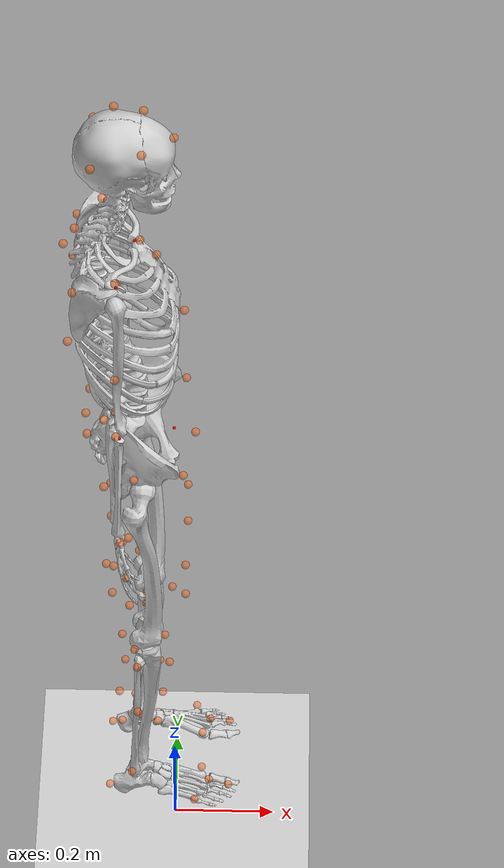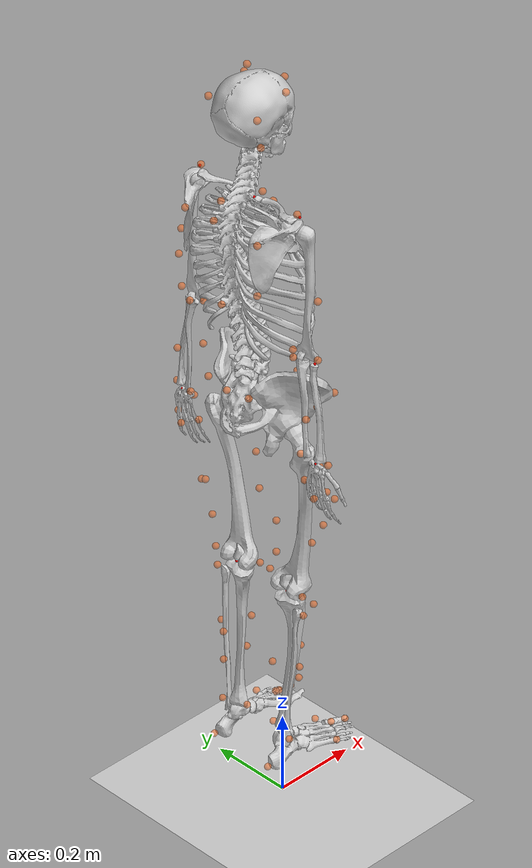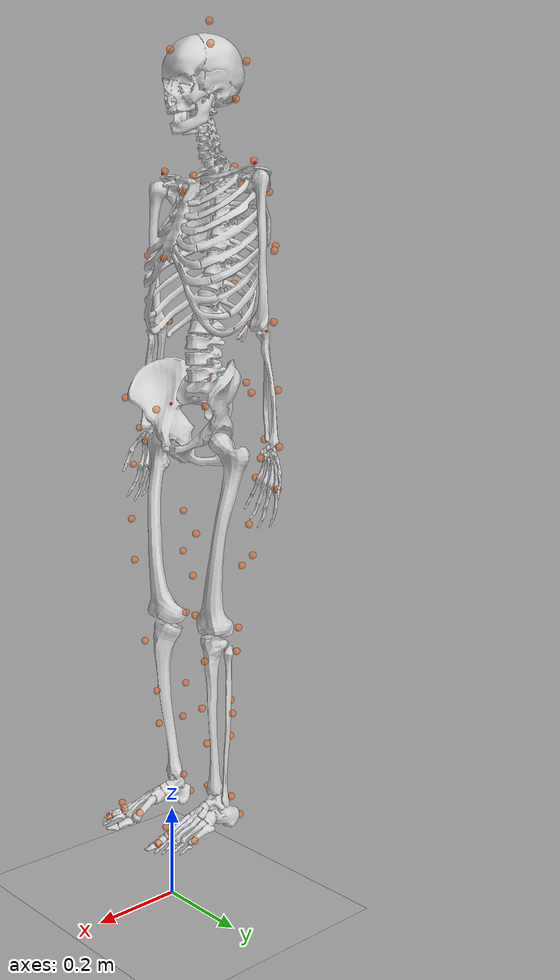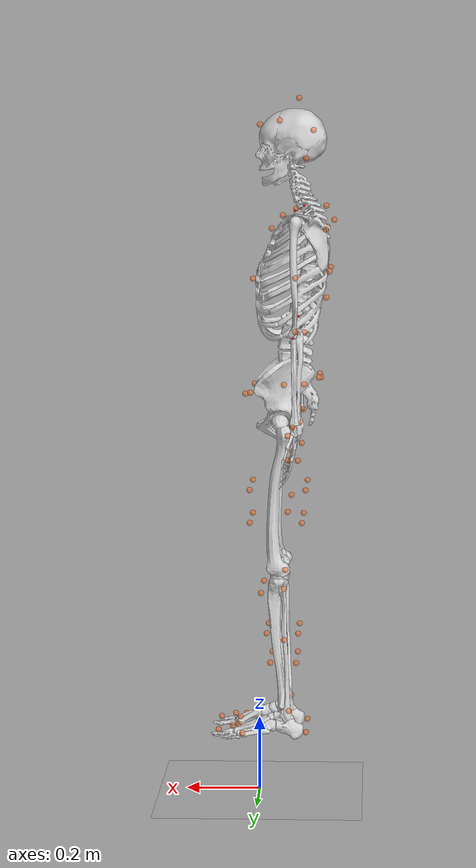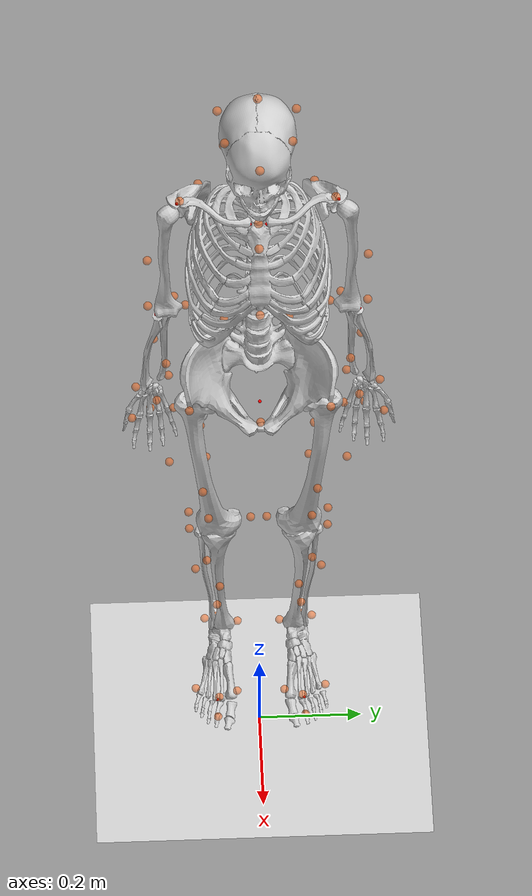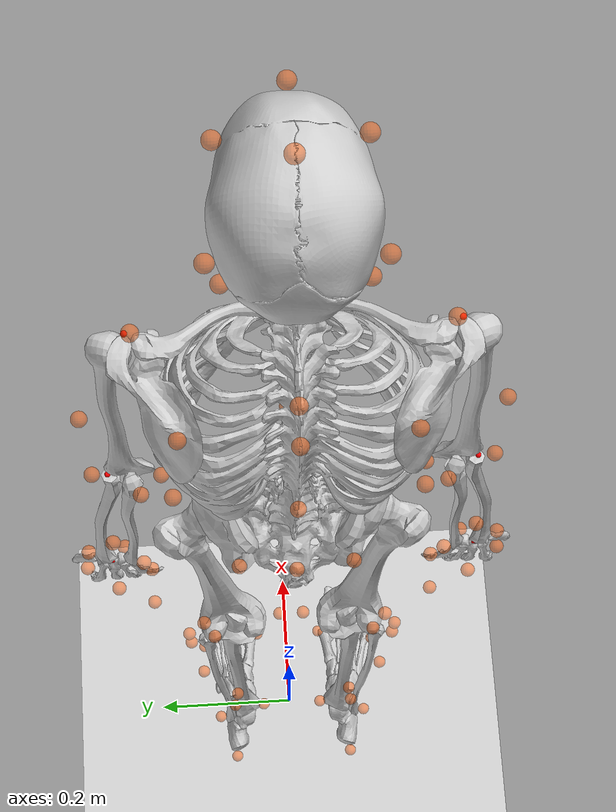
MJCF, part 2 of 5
-0.0160686 -0.13213 0.0489783 -0.0165289 -0.134807 0.060532 -0.0154441 -0.138458 0.0646785 -0.0168449 -0.14115 0.0537051 -0.0169041 -0.138163 0.0496568 -0.0151788 -0.141027 0.0610947 -0.0139758 -0.14467 0.0645122 -0.0188722 -0.146396 0.0550355 -0.0192937 -0.143479 0.0510364 -0.015214 -0.147526 0.0608764 -0.0141101 -0.151361 0.0640713 -0.0212011 -0.148175 0.0599192 -0.0216539 -0.144332 0.056328 -0.0171293 -0.153743 0.0614913 -0.0160498 -0.157664 0.0649244 -0.0197095 -0.148621 0.0662785 -0.0207753 -0.144209 0.062885 -0.0195603 -0.156873 0.0663176 -0.0182822 -0.161236 0.0696883 -0.0157235 -0.149117 0.0716045 -0.0174307 -0.144737 0.0686603 -0.0169905 -0.157541 0.0724116 -0.0152475 -0.16177 0.0756189 -0.0108287 -0.150452 0.0745139 -0.0124086 -0.146404 0.0715224 -0.0122841 -0.157557 0.0772958 -0.0102328 -0.161364 0.0803316 -0.0087665 -0.155755 0.0739108 -0.0106529 -0.152087 0.0708441 -0.007143 -0.157806 0.0804923 -0.0048999 -0.161198 0.0835558 -0.0091368 -0.162477 0.0737716 -0.0110398 -0.158803 0.0706371 -0.0043344 -0.162675 0.0798905 -0.0018314 -0.166036 0.0828551 -0.0108174 -0.169346 0.0749565 -0.0129355 -0.165487 0.0717672 -0.0045419 -0.169566 0.0798938 -0.00194581 -0.172849 0.0830112 -0.0119911 -0.173405 0.0798586 -0.0146386 -0.16964 0.0765276 -0.0057103 -0.176292 0.0816527 -0.0027086 -0.179334 0.0848827 -0.0077788 -0.17277 0.085219 -0.0105607 -0.169357 0.0820435 -0.0060469 -0.180037 0.0865598 -0.0028338 -0.183242 0.0894774 -0.0024223 -0.171766 0.0893896 -0.0052707 -0.168373 0.0863971 -0.0015511 -0.179361 0.0912197 0.0018958 -0.182672 0.0938187 0.00318 -0.17149 0.0924052 0.0003046 -0.167963 0.0896413 0.0038148 -0.178585 0.0950482 0.0072837 -0.181887 0.0975313 0.0065914 -0.176121 0.0913417 0.0035366 -0.172769 0.0886708 0.0096816 -0.1782 0.0975405 0.013167 -0.18142 0.100086 0.0075804 -0.182612 0.0909812 0.004145 -0.179294 0.0886027 0.0131511 -0.18289 0.0963136 0.0165851 -0.186243 0.0987303 0.00687269 -0.189207 0.0928837 0.0037225 -0.185851 0.0900721 0.0139473 -0.189398 0.0962618 0.0171784 -0.192754 0.0988139 0.0072703 -0.193252 0.0972412 0.0036954 -0.19001 0.0947077 0.0135865 -0.195743 0.0983059 0.0171137 -0.198956 0.100991 0.0122102 -0.192641 0.101423 0.0087715 -0.189289 0.0988718 0.0145528 -0.19984 0.10228 0.0184279 -0.203232 0.104638 0.0178756 -0.191928 0.104869 0.01432 -0.188466 0.102499 0.0197185 -0.19941 0.106146 0.0237623 -0.202725 0.108327 0.0238599 -0.191893 0.106615 0.0203499 -0.188365 0.104581 0.0255404 -0.198659 0.10934 0.0297567 -0.201906 0.111148 0.0273264 -0.196108 0.104869 0.0234322 -0.193024 0.103098 0.0319205 -0.198288 0.11016 0.0362878 -0.201528 0.111774 0.0287057 -0.202152 0.104433 0.0245224 -0.199103 0.10296 0.0357081 -0.202422 0.108024 0.040056 -0.205767 0.109202 0.029634 -0.208058 0.106038 0.0253302 -0.205088 0.104857 0.0372336 -0.208317 0.106644 0.041208 -0.211772 0.107591 0.0313853 -0.212265 0.10946 0.0270903 -0.209294 0.108079 0.0377661 -0.214397 0.108466 0.0418828 -0.217597 0.109289 0.0369731 -0.211959 0.112562 0.0326086 -0.208807 0.111332 0.0399618 -0.218457 0.111799 0.043063 -0.211622 0.115423 0.038661 -0.208153 0.113923 0.0456605 -0.218618 0.114949 0.0450696 -0.208651 0.114254 0.0267149 -0.147606 0.0236046 0.024922 -0.140167 0.0188545 0.0229906 -0.136957 0.0208597 0.0226704 -0.142815 0.0192064 0.0181378 -0.231095 0.0805645 0.0175044 -0.231854 0.0821723 0.0139249 -0.229394 0.0783699 0.0121365 -0.230508 0.0823669 0.0088475 -0.230089 0.0797166 0.0066558 -0.225558 0.081428 0.005715 -0.220144 0.0824116 0.0059186 -0.214079 0.0813293 0.0049763 -0.210793 0.0773609 0.0015802 -0.209619 0.0731903 -0.00254791 -0.208888 0.0691679 -0.0073276 -0.208079 0.065977 -0.0110874 -0.204522 0.0655902 -0.0118732 -0.198604 0.0662397 -0.0106686 -0.192357 0.0661201 -0.008445 -0.187076 0.0645518 -0.0064184 -0.183765 0.060944 -0.0079068 -0.182421 0.0560509 -0.009425 -0.18127 0.0508539 -0.0115831 -0.178875 0.0466219 -0.0131024 -0.173957 0.0447205 -0.0120231 -0.168093 0.0445247 -0.0087604 -0.162941 0.0446231 -0.0041291 -0.160058 0.0440248 0.0001884 -0.159801 0.0414539 0.0035519 -0.16041 0.0375536 0.0064992 -0.160466 0.0334189 0.0082675 -0.15757 0.029564 0.0098366 -0.152794 0.0272872 0.0118654 -0.147688 0.0265658 0.015187 -0.143508 0.0270256 0.0202695 -0.141944 0.0268214 0.0192266 -0.147226 0.0288482 0.0160153 -0.149212 0.031191 0.0111422 -0.148224 0.0334833 0.0062516 -0.149661 0.0334801 0.0023866 -0.153612 0.0325651 -0.0002749 -0.158819 0.0325384 -0.0016486 -0.163911 0.0347521 -0.00226861 -0.16681 0.0391234 -0.0041395 -0.167064 0.0439344 -0.00641161 -0.167596 0.0481732 -0.0091994 -0.169564 0.0515545 -0.0123908 -0.173854 0.0529924 -0.0148582 -0.179828 0.0529693 -0.0151286 -0.185891 0.0525297 -0.0123027 -0.19009 0.0541012 -0.0091263 -0.191722 0.0583432 -0.0063025 -0.192828 0.0631042 -0.0040392 -0.193993 0.0678995 -0.0048286 -0.197408 0.0718034 -0.00613461 -0.202991 0.0732373 -0.00634521 -0.209311 0.0728612 -0.0051286 -0.214911 0.0720999 -0.00121081 -0.21814 0.0720222 0.0038368 -0.218877 0.074436 0.0084934 -0.219555 0.0778851 0.0122723 -0.221298 0.0815168 0.0146351 -0.225386 0.0840363 0.015218 -0.224961 0.08169 0.0112228 -0.222688 0.0788574 0.0093211 -0.224752 0.0766958 0.0041099 -0.224014 0.0752036 -0.000290309 -0.22141 0.0758809 -0.0015921 -0.215978 0.0766639 -0.0017996 -0.20989 0.0770717 -0.000669203 -0.203859 0.0757112 -0.000783906 -0.200532 0.0719473 -0.00372521 -0.199458 0.0674761 -0.0072551 -0.198718 0.0629888 -0.0109159 -0.197272 0.059141 -0.0142115 -0.193424 0.0581268 -0.0147571 -0.187584 0.0583084 -0.0125641 -0.18146 0.0582705 -0.0095327 -0.17637 0.0569322 -0.0076713 -0.173675 0.0532626 -0.00712991 -0.172561 0.0485987 -0.0066316 -0.171798 0.0437213 -0.0069596 -0.169229 0.0390708 -0.0069863 -0.164085 0.0364081 -0.0046019 -0.158392 0.036364 -0.000591702 -0.154012 0.037377 0.0046091 -0.152451 0.0377789 0.0094427 -0.153229 0.0356283 0.0135154 -0.154509 0.0320596 0.0165984 -0.154826 0.0277472 0.0181132 -0.151792 0.0236419 0.018258 -0.147065 0.0202754 0.0210615 -0.150169 0.0205038 0.0199875 -0.153047 0.025337 0.0175493 -0.141174 0.0247972 0.0122039 -0.232307 0.0805754 0.0238158 -0.147316 0.0182928 0.0234936 -0.139939 0.0245357 0.026906 -0.14842 0.0204491 0.0275411 -0.143336 0.0210266 0.0258086 -0.143908 0.024238 0.0225113 -0.145355 0.0265718 0.0238022 -0.14909 0.0254131 0.0235285 -0.151371 0.0225713 0.0223584 -0.139691 0.0188321 0.0262328 -0.138548 0.0213177 0.0248566 -0.143443 0.0190524 0.0201098 -0.138313 0.0227849 0.0187184 -0.140575 0.0190898 0.0208103 -0.144545 0.0187604 0.0164607 -0.231624 0.0791336 0.0158242 -0.228901 0.0793893 0.0174223 -0.228581 0.0811933 0.0168885 -0.229293 0.0834043 0.0152879 -0.232745 0.0816626 0.0142909 -0.230026 0.083165 0.011913 -0.227561 0.0777678 0.0138776 -0.225874 0.0794055 0.0134035 -0.231565 0.0780499 0.0100541 -0.229634 0.0771617 0.0120819 -0.226738 0.08345 0.00981139 -0.228407 0.0821405 0.00556659 -0.227308 0.0787167 0.0069588 -0.226855 0.0762984 0.00354259 -0.222531 0.0802761 0.0025089 -0.224429 0.0774546 0.00896479 -0.22344 0.0832569 0.0118043 -0.221276 0.0838759 0.0029369 -0.216717 0.0807856 0.000782195 -0.21934 0.0786137 0.0087173 -0.217533 0.0829438 0.0094562 -0.217754 0.0805682 0.0035437 -0.210722 0.079397 0.000554595 -0.213295 0.0788457 0.0069834 -0.214306 0.0791168 0.0059851 -0.216319 0.0765145 0.0031731 -0.20719 0.0755824 0.00140979 -0.207289 0.0775593 0.0036404 -0.21304 0.0749375 0.0014076 -0.215716 0.0728923 -0.000321303 -0.20622 0.0713352 0.0013595 -0.203661 0.0737346 -0.000695903 -0.212332 0.0711183 -0.0033393 -0.214734 0.0701485 -0.004443 -0.205573 0.0672283 -0.0021669 -0.202851 0.0694574 -0.0053507 -0.211414 0.0680306 -0.0073795 -0.211613 0.0699907 -0.0088448 -0.204522 0.0637985 -0.0060363 -0.202231 0.0651511 -0.0094179 -0.208147 0.0678037 -0.00849971 -0.20583 0.0708074 -0.0123575 -0.200805 0.0631931 -0.0100232 -0.200908 0.0615155 -0.0102903 -0.202187 0.0685837 -0.0079151 -0.199399 0.0710663 -0.0129795 -0.194936 0.063673 -0.0132615 -0.197023 0.0607328 -0.0095037 -0.19591 0.068694 -0.00622001 -0.193926 0.0694536 -0.0115831 -0.188739 0.0634783 -0.014001 -0.191258 0.0610224 -0.0073825 -0.190455 0.0669947 -0.005167 -0.190616 0.0655589 -0.0089616 -0.183544 0.0620333 -0.0121721 -0.18508 0.0608357 -0.006073 -0.1873 0.0632448 -0.0071052 -0.189381 0.0607439 -0.00671851 -0.180146 0.0585435 -0.0092136 -0.179915 0.0595197 -0.0075464 -0.18586 0.0583911 -0.0095492 -0.188215 0.0558671 -0.0080738 -0.179015 0.0535786 -0.0072783 -0.176798 0.0559712 -0.0095762 -0.184761 0.0533136 -0.0124549 -0.186395 0.0514736 -0.0090853 -0.177855 0.0484879 -0.008003 -0.175727 0.0510771 -0.0122802 -0.18264 0.0490062 -0.0149267 -0.181881 0.0499931 -0.0104358 -0.175345 0.0441757 -0.0080257 -0.17461 0.0460687 -0.0143298 -0.177849 0.0474118 -0.0143923 -0.17578 0.0502989 -0.0116284 -0.170474 0.0419291 -0.0090446 -0.172234 0.0416025 -0.0133836 -0.171811 0.047461 -0.0117074 -0.170157 0.0501667 -0.0101504 -0.164581 0.0416153 -0.00953 -0.16717 0.0391311 -0.010431 -0.166508 0.0473323 -0.0080346 -0.166148 0.0489489 -0.0066074 -0.15961 0.0420243 -0.00764081 -0.16134 0.0388206 -0.0062773 -0.162974 0.0464374 -0.0045446 -0.164731 0.0459013 -0.0015531 -0.157331 0.0417738 -0.0037917 -0.15665 0.0395859 -0.0023742 -0.162146 0.0436268 -0.0019267 -0.16467 0.0416467 0.0029947 -0.157533 0.0394157 0.0013703 -0.154818 0.0396784 0.000662899 -0.162504 0.0394921 0.000352798 -0.164605 0.0370572 0.0067219 -0.158383 0.0358065 0.0061368 -0.155341 0.0375849 0.0032988 -0.162506 0.0351771 0.0015335 -0.161715 0.0329183 0.0098327 -0.158532 0.0316873 0.010089 -0.156412 0.0340281 0.004889 -0.159667 0.0311344 0.0032105 -0.156683 0.0309024 0.0115936 -0.155602 0.0278842 0.0132114 -0.15669 0.0298471 0.006553 -0.154676 0.0291347 0.0056586 -0.151511 0.0306371 0.0130119 -0.15095 0.0253217 0.0148992 -0.153705 0.0259257 0.0088509 -0.149565 0.028654 0.0094229 -0.147614 0.0313797 0.0144765 -0.145821 0.0242128 0.0159059 -0.149038 0.0231327 0.0124284 -0.145552 0.0292418 0.0142465 -0.146131 0.0312727 0.0163216 -0.143607 0.0213565 0.0172814 -0.144025 0.029069 0.0169554 -0.152625 0.0299348 0.0202606 -0.150743 0.027595 0.0127754 -0.151215 0.0334833 0.0079112 -0.150302 0.0356666 0.0028529 -0.15171 0.0354572 -0.0012159 -0.155764 0.0342825 -0.0037856 -0.161255 0.0342304 -0.0045163 -0.166437 0.0367662 -0.004592 -0.169176 0.0413625 -0.0058322 -0.169721 0.046242 -0.0073038 -0.170562 0.0506968 -0.0095451 -0.172837 0.0542627 -0.0125914 -0.177714 0.0556656 -0.0149887 -0.183766 0.0555843 -0.014846 -0.18973 0.0553324 -0.011764 -0.193716 0.0566874 -0.0082726 -0.195202 0.0607259 -0.00516911 -0.196194 0.0653724 -0.0026911 -0.197358 0.0701002 -0.0029243 -0.200707 0.0738293 -0.00408661 -0.206496 0.0752548 -0.0040013 -0.212662 0.074791 -0.00287351 -0.218266 0.0740965 0.00136209 -0.221158 0.0737454 0.0065945 -0.221821 0.0756186 0.146555 -0.104504 0.0411624 0.123473 -0.186037 0.102384 0.120818 -0.185631 0.0990051 0.113963 -0.134612 0.109999 0.0932293 -0.170107 0.120916 0.0751516 -0.199403 0.120434 0.0762099 -0.202302 0.122988 0.148291 -0.103833 0.0422596 0.0865213 -0.173063 0.118576 0.0850566 -0.179462 0.120271 0.0865529 -0.179052 0.122457 0.108905 -0.145746 0.110586 0.145084 -0.107058 0.0425588 0.147811 -0.109095 0.0478428 0.0751623 -0.211492 0.114894 0.108556 -0.149508 0.108162 0.138398 -0.154737 0.0787911 0.111917 -0.137333 0.111489 0.0736625 -0.208332 0.121154 0.140903 -0.152433 0.0816169 0.135514 -0.18208 0.0942882 0.125075 -0.181055 0.0906452 0.145531 -0.147178 0.074744 0.139186 -0.137384 0.06379 0.137676 -0.133827 0.0719844 0.142785 -0.130882 0.0705728 0.14745 -0.129699 0.0656976 0.149672 -0.127257 0.0587939 0.149312 -0.123892 0.0515549 0.146224 -0.119374 0.0462222 0.143266 -0.11341 0.0454077 0.142061 -0.116858 0.0513622 0.142374 -0.109476 0.0514202 0.144094 -0.105949 0.0477585 0.145151 -0.113563 0.0567381 0.144995 -0.118132 0.0613622 0.141645 -0.12467 0.0606809 0.141361 -0.126917 0.0565551 0.142186 -0.128984 0.0523193 0.145958 -0.135857 0.0535594 0.148221 -0.140258 0.0605238 0.145123 -0.146968 0.0603388 0.144831 -0.152591 0.063783 0.144052 -0.158384 0.0671535 0.144376 -0.162664 0.0739683 0.143993 -0.16029 0.0779831 0.141816 -0.16312 0.0838072 0.137494 -0.164173 0.0886022 0.134706 -0.164516 0.0849709 0.134048 -0.166288 0.0807388 0.136837 -0.162925 0.0731263 0.138154 -0.157222 0.0699773 0.138909 -0.150987 0.0670913 0.136947 -0.169871 0.0729406 0.139193 -0.176224 0.076797 0.141573 -0.174536 0.0808792 0.137169 -0.182013 0.0796276 0.134854 -0.187324 0.0823924 0.1324 -0.192416 0.0847314 0.13153 -0.197066 0.0917721 0.130246 -0.194989 0.096545 0.124417 -0.197344 0.101691 0.120768 -0.194401 0.103552 0.118014 -0.194324 0.0997316 0.119494 -0.196508 0.0957303 0.121922 -0.199362 0.0921776 0.120712 -0.207511 0.0925544 0.12331 -0.207496 0.0964393 0.118097 -0.209066 0.103319 0.116975 -0.205581 0.106493 0.114574 -0.201642 0.108315 0.112081 -0.201358 0.104814 0.112402 -0.20436 0.101173 0.108646 -0.210838 0.101392 0.110019 -0.215128 0.0994111 0.105962 -0.218785 0.106098 0.106894 -0.215276 0.109693 0.107059 -0.211097 0.112338 0.106181 -0.206372 0.113513 0.103907 -0.205189 0.110249 0.0978878 -0.20934 0.109574 0.0970448 -0.21359 0.10741 0.0898526 -0.217517 0.109411 0.0912851 -0.219821 0.112754 0.0935042 -0.21634 0.115717 0.0950024 -0.212117 0.117714 0.0957095 -0.207406 0.118385 0.089231 -0.204346 0.116966 0.0870805 -0.207291 0.114058 0.0822127 -0.205538 0.115929 0.0844417 -0.202628 0.118783 0.084939 -0.204865 0.122328 0.0833244 -0.209381 0.12231 0.0810086 -0.213344 0.12065 0.0842616 -0.218266 0.115346 0.0835171 -0.215627 0.112027 0.124944 -0.194419 0.0896945 0.134513 -0.175281 0.076514 0.132388 -0.172895 0.0805972 0.131876 -0.170328 0.0849501 0.12954 -0.170044 0.0932288 0.126161 -0.171364 0.0973843 0.122469 -0.172195 0.101516 0.116654 -0.175935 0.103553 0.111095 -0.180035 0.106707 0.111788 -0.18407 0.107734 0.114159 -0.184615 0.111164 0.115423 -0.181118 0.113133 0.121535 -0.176847 0.109766 0.12673 -0.176842 0.105624 0.114549 -0.17279 0.112111 0.106742 -0.17205 0.111383 0.099925 -0.175116 0.112142 0.0993224 -0.179479 0.11206 0.0994922 -0.18376 0.11389 0.101238 -0.184192 0.117945 0.102428 -0.180317 0.119577 0.102859 -0.176024 0.119397 0.0962465 -0.179029 0.121652 0.094827 -0.182909 0.120398 0.0932232 -0.182767 0.116121 0.0932678 -0.178476 0.113706 0.0940376 -0.173959 0.113541 0.100945 -0.171399 0.11361 0.129464 -0.171169 0.101123 0.132816 -0.169696 0.0970627 0.140402 -0.167764 0.0876523 0.14949 -0.114081 0.0562784 0.146329 -0.114109 0.0446112 0.14866 -0.109582 0.0447121 0.14875 -0.113624 0.0467239 0.147892 -0.137354 0.0652631 0.136128 -0.138965 0.0750945 0.136741 -0.14332 0.0749115 0.135445 -0.147385 0.080503 0.133283 -0.151168 0.0854208 0.132262 -0.153827 0.0920913 0.134233 -0.150737 0.0934434 0.135233 -0.146861 0.0939869 0.138005 -0.142431 0.0881652 0.138934 -0.137826 0.0826813 0.132723 -0.137116 0.0860226 0.131771 -0.140245 0.0851674 0.128698 -0.144413 0.0895695 0.124862 -0.148292 0.0940089 0.120913 -0.151893 0.0992038 0.123513 -0.152664 0.102069 0.125656 -0.149606 0.103692 0.127082 -0.145413 0.104337 0.126905 -0.140974 0.103356 0.128981 -0.13875 0.0969449 0.126163 -0.13768 0.094601 0.121169 -0.140687 0.0979059 0.11647 -0.14366 0.101713 0.11262 -0.142845 0.104862 0.113055 -0.139267 0.10465 0.118245 -0.136689 0.102115 0.120791 -0.136647 0.104725 0.122433 -0.139645 0.107211 0.118299 -0.142567 0.111662 0.116914 -0.14704 0.111467 0.118912 -0.151633 0.10621 0.116311 -0.151336 0.103079 0.140946 -0.136405 0.078007 0.114352 -0.141208 0.11404 0.108846 -0.138322 0.107761 0.0715958 -0.207739 0.117385 0.0912099 -0.177452 0.122843 0.14434 -0.104752 0.0426999 0.146187 -0.105822 0.0443826 0.148637 -0.106573 0.0431065 0.146761 -0.107037 0.0422279 0.128375 -0.187631 0.0995703 0.130596 -0.182365 0.100048 0.126015 -0.181834 0.104525 0.121002 -0.181227 0.108925 0.122786 -0.190774 0.101686 0.126807 -0.192671 0.100182 0.119213 -0.184431 0.106922 0.116914 -0.183744 0.10399 0.120239 -0.190473 0.0984074 0.12299 -0.187037 0.0921506 0.121707 -0.191903 0.0937837 0.120681 -0.180718 0.0979748 0.11622 -0.180063 0.102934 0.116836 -0.135431 0.107708 0.114326 -0.135874 0.105219 0.114634 -0.13692 0.112927 0.118355 -0.138304 0.110307 0.110817 -0.134744 0.108612 0.096957 -0.171002 0.119445 0.0953026 -0.170306 0.115478 0.0902367 -0.168602 0.117753 0.0885505 -0.17243 0.121249 0.0923675 -0.173445 0.122613 0.0970952 -0.174892 0.121329 0.0733092 -0.202777 0.118269 0.0749904 -0.205453 0.122149 0.079969 -0.200532 0.119988 0.0780133 -0.20407 0.117057 0.0800024 -0.202675 0.12437 0.0783698 -0.207561 0.124247 0.147885 -0.106896 0.0451352 0.0884199 -0.172353 0.114727 0.0871093 -0.177293 0.11476 0.0856391 -0.176173 0.119109 0.0875652 -0.176118 0.122151 0.0873316 -0.181704 0.118082 0.0895287 -0.18118 0.122232 0.110166 -0.143185 0.111297 0.108618 -0.142102 0.107717 0.108384 -0.14578 0.107569 0.110091 -0.149089 0.112306 0.112884 -0.145453 0.114059 0.146636 -0.109955 0.0433984 0.144295 -0.109358 0.0437239 0.143142 -0.107685 0.0455075 0.148337 -0.111066 0.0510656 0.149748 -0.112272 0.0493317 0.146381 -0.108282 0.0474099 0.145544 -0.110322 0.0515221 0.149809 -0.108357 0.0467842 0.0783599 -0.213325 0.114018 0.0781827 -0.216003 0.117372 0.0761605 -0.207873 0.115383 0.0801844 -0.209267 0.114242 0.0727869 -0.213465 0.118235 0.112094 -0.150419 0.106169 0.114513 -0.150692 0.109845 0.112155 -0.146469 0.104878 0.136638 -0.160405 0.0814311 0.138936 -0.160489 0.0848742 0.137673 -0.15608 0.0741791 0.136307 -0.161581 0.0772856 0.139641 -0.156512 0.0818674 0.138568 -0.152312 0.0821455 0.137543 -0.148659 0.0761683 0.138357 -0.149896 0.0713235 0.111276 -0.140071 0.111662 0.0759598 -0.211318 0.122337 0.144814 -0.154257 0.0762387 0.141775 -0.147187 0.0819468 0.1384 -0.14687 0.0880333 0.137797 -0.150765 0.0878286 0.135785 -0.153336 0.0869802 0.134946 -0.175185 0.0967073 0.131237 -0.176534 0.101421 0.139529 -0.176645 0.0893164 0.138236 -0.171943 0.0921193 0.136914 -0.185665 0.087941 0.139518 -0.180177 0.0845398 0.132643 -0.189356 0.0954602 0.134415 -0.191525 0.0900865 0.121101 -0.175982 0.0991437 0.124875 -0.175317 0.0940782 0.128595 -0.17349 0.0893129 0.129318 -0.17686 0.0851309 0.132024 -0.180134 0.0805541 0.129418 -0.184589 0.0847192 0.127194 -0.189466 0.0873361 0.146276 -0.150634 0.0682787 0.147179 -0.14529 0.0645294 0.145308 -0.156446 0.0711894 0.146962 -0.142032 0.0693734 0.145438 -0.137864 0.0727693 0.143671 -0.14088 0.0772069 0.141187 -0.142062 0.0826257 0.140515 -0.140294 0.0576182 0.140791 -0.146189 0.0606531 0.13905 -0.132162 0.067515 0.140651 -0.128967 0.0637395 0.140509 -0.131965 0.0596127 0.141502 -0.134481 0.0549922 0.139029 -0.14449 0.0649585 0.138138 -0.143723 0.0697157 0.137678 -0.138435 0.0698325 0.136681 -0.135075 0.0766042 0.142113 -0.13397 0.0740552 0.143516 -0.127442 0.0671816 0.146525 -0.13395 0.0690215 0.1484 -0.124957 0.0627704 0.144463 -0.123375 0.0639632 0.148907 -0.132476 0.0618089 0.14915 -0.134892 0.0570896 0.150137 -0.121904 0.0559502 0.149096 -0.119533 0.0599268 0.149457 -0.129236 0.0542608 0.146337 -0.130108 0.0510175 0.149031 -0.118587 0.0491223 0.149962 -0.116824 0.0527829 0.146226 -0.12481 0.0483542 0.14237 -0.123842 0.0497415 0.142754 -0.118537 0.0475056 0.142343 -0.111908 0.0484892 0.141797 -0.121877 0.0539306 0.142319 -0.119774 0.0580067 0.142245 -0.114607 0.0550205 0.145456 -0.141657 0.056534 0.14067 -0.152354 0.0633043 0.140042 -0.158411 0.0663912 0.142801 -0.164378 0.0704076 0.138879 -0.164221 0.0696484 0.143261 -0.168683 0.0772958 0.141164 -0.170323 0.0736987 0.143121 -0.166042 0.0809031 0.142515 -0.158145 0.0815998 0.14186 -0.171486 0.0849359 0.13549 -0.167318 0.0928302 0.132426 -0.167799 0.0890248 0.134896 -0.168156 0.0766037 0.129101 -0.197467 0.0871498 0.127524 -0.202474 0.0937391 0.12509 -0.202656 0.0895706 0.127073 -0.200087 0.0983801 0.121032 -0.201635 0.103956 0.122764 -0.204799 0.10062 0.117975 -0.198044 0.106027 0.115454 -0.198091 0.102202 0.116154 -0.200805 0.098241 0.11799 -0.203906 0.0950285 0.115812 -0.211607 0.0961193 0.11364 -0.207818 0.0982206 0.118343 -0.21213 0.0993871 0.112847 -0.212688 0.106382 0.112586 -0.216034 0.10263 0.112429 -0.208872 0.109426 0.110694 -0.204459 0.110886 0.108231 -0.203755 0.107538 0.108053 -0.207028 0.104142 0.103234 -0.212841 0.104744 0.103244 -0.208718 0.107095 0.103727 -0.217374 0.103077 0.0986209 -0.220349 0.109449 0.0966669 -0.21838 0.106174 0.100191 -0.216485 0.112708 0.101064 -0.212169 0.115002 0.101096 -0.207344 0.116044 0.0991345 -0.205857 0.112654 0.0924542 -0.208814 0.111922 0.0941984 -0.205616 0.114867 0.0909691 -0.212908 0.110043 0.085174 -0.211189 0.112401 0.0869687 -0.215131 0.118458 0.088957 -0.211039 0.120172 0.0902011 -0.206492 0.120438 0.125363 -0.172048 0.104982 0.117802 -0.172371 0.105273 0.120253 -0.172559 0.108606 0.111414 -0.175972 0.107118 0.112451 -0.172277 0.10865 0.105417 -0.179999 0.109764 0.105839 -0.175817 0.110045 0.105878 -0.184183 0.111056 0.107937 -0.18465 0.11483 0.109059 -0.180974 0.11672 0.115603 -0.176883 0.113611 0.109275 -0.176689 0.116886 0.108508 -0.172684 0.115034 0.102478 -0.17204 0.117464 0.134201 -0.139518 0.080221 0.135189 -0.136299 0.0812844 0.134799 -0.143254 0.0800561 0.132582 -0.147452 0.0850665 0.13217 -0.143805 0.0850678 0.13662 -0.151346 0.0817037 0.129578 -0.151881 0.0900377 0.12898 -0.148051 0.0896454 0.128114 -0.153574 0.0974072 0.12544 -0.152137 0.0948429 0.130274 -0.150556 0.0989476 0.131473 -0.146525 0.099505 0.134729 -0.142446 0.0936785 0.13109 -0.141961 0.0988088 0.135973 -0.138695 0.0876197 0.13263 -0.138995 0.0924715 0.129647 -0.137568 0.0904819 0.128666 -0.140827 0.0896927 0.124859 -0.144589 0.0938281 0.125027 -0.140947 0.0938357 0.120408 -0.148065 0.0980836 0.120752 -0.14432 0.0979635 0.115939 -0.147435 0.101781 0.121122 -0.14836 0.107912 0.12255 -0.143984 0.108441 0.125034 -0.137906 0.101065 0.122368 -0.137392 0.0985085 0.116987 -0.14004 0.10157 0.147554 -0.045998 0.0149417 0.138715 -0.032267 -0.0210825 0.142032 -0.05001 0.0117159 0.141992 -0.050482 -0.011966 0.141471 -0.049924 0.00693 0.14104 -0.050176 -0.00783885 0.139823 -0.048351 -0.0134086 0.133432 -0.016528 -0.0190349 0.130584 -0.007734 -0.0199543 0.130969 -0.014635 0.021783 0.122887 0.010338 0.0173581 0.118162 0.00982099 0.018388 0.108495 0.031823 -0.0151966 0.102313 0.04382 -0.0149043 0.0979075 0.049911 0.0106628 0.150288 -0.044681 0.00897775 0.145824 -0.042135 0.0147224 0.1458 -0.045889 0.011436 0.143919 -0.045718 0.0121041 0.146686 -0.031201 0.0190027 0.143219 -0.03287 -0.0183165 0.141169 -0.044075 -0.0164806 0.140233 -0.050393 0.0124808 0.136729 -0.017916 0.0184245 0.137752 -0.028446 -0.0188091 0.136401 -0.01749 -0.0185974 0.121021 0.008489 0.0146207 0.114078 0.022613 -0.0147171 0.109387 0.053121 0.00775439 0.110496 0.053114 -0.00854557 0.111615 0.030823 -0.0145705 0.111037 0.026423 0.012534 0.105497 0.033767 0.013892 0.103221 0.04571 -0.0141313 0.146104 -0.045469 -0.0119488 0.147253 -0.041041 -0.0147528 0.145157 -0.046154 -0.0107774 0.144264 -0.046243 -0.0160273 0.144328 -0.046999 0.0157399 0.14292 -0.044374 0.0161499 0.142788 -0.046526 -0.0113501 0.126253 -0.003676 -0.0170196 0.133595 -0.014605 0.0224368 0.118086 0.010377 -0.0168434 0.117305 0.018823 0.0156762 0.112991 0.034576 -0.0151792 0.102559 0.043343 0.0132525 0.150285 -0.045856 -0.00988293 0.14375 -0.032733 0.0187327 0.143 -0.040838 -0.0147665 0.137506 -0.028845 0.0192223 0.134877 -0.012084 0.020186 0.132348 -0.017412 -0.0204276 0.120567 0.010027 -0.0166236 0.102437 0.047338 0.0109699 0.149822 -0.042943 -0.0147214 0.145796 -0.028186 -0.0189677 0.140327 -0.045743 0.0151311 0.13734 -0.032607 0.0206691 0.135531 -0.012107 -0.0204953 0.1228 0.013498 -0.0167107 0.127434 -0.002508 0.0151547 0.118838 0.017065 0.0161891 0.116776 0.008758 0.0149246 0.116162 0.011916 -0.0188735 0.113457 0.016722 0.0169531 0.104654 0.03506 -0.0151758 0.0978701 0.050774 -0.0119194 0.113318 0.018705 0.0160618 0.112343 0.017093 -0.0183316 0.130809 -0.006658 0.0188685 0.149504 -0.042976 0.0152326 0.150219 -0.03837 0.0149189 0.148831 -0.034381 0.0143387 0.147338 -0.030817 0.015346 0.145945 -0.026969 0.015722 0.144475 -0.022775 0.0174559 0.144112 -0.022678 0.0189087 0.142529 -0.022762 0.0195806 0.14168 -0.026053 0.0182309 0.140682 -0.028846 0.0188222 0.141241 -0.030842 0.0207416 0.141748 -0.033232 0.0208472 0.140731 -0.033889 0.0179326 0.142981 -0.036096 0.0163352 0.144976 -0.035998 0.0163558 0.145605 -0.03824 0.0154403 0.143558 -0.038302 0.0154498 0.142308 -0.04078 0.0150295 0.141628 -0.041217 0.0165975 0.140048 -0.03952 0.0190513 0.138275 -0.039719 0.018181 0.136913 -0.03988 0.0169258 0.136875 -0.04312 0.0132314 0.137308 -0.045991 0.0118694 0.137652 -0.048596 0.0106712 0.13638 -0.04871 0.00835276 0.135405 -0.04843 0.00526604 0.137329 -0.049105 0.00122455 0.139939 -0.048316 0.00112505 0.142236 -0.048219 0.0010501 0.144728 -0.048742 0.0037641 0.145426 -0.049094 0.00601549 0.146118 -0.04877 0.0078788 0.145152 -0.04748 0.00912398 0.143634 -0.047355 0.00930456 0.142334 -0.047338 0.0101208 0.146764 -0.047356 0.00923899 0.148249 -0.048761 0.0105828 0.149825 -0.047563 0.0103331 0.14992 -0.049091 0.00820612 0.149868 -0.04754 0.00588993 0.149917 -0.045312 0.00588944 0.149895 -0.042936 0.00624059 0.15001 -0.040484 0.00953931 0.149412 -0.037375 0.00829754 0.148277 -0.033917 0.00909591 0.146786 -0.030234 0.00949664 0.145624 -0.026346 0.00960814 0.144866 -0.022331 0.00961371 0.143172 -0.018484 0.0133468 0.140132 -0.014623 0.0159135 0.139799 -0.014615 0.0176755 0.136556 -0.011328 0.0174068 0.133564 -0.008169 0.0166451 0.13231 -0.004492 0.0159904 0.129928 -0.000148997 0.0165042 0.125809 0.003442 0.0144411 0.1236 0.00314499 0.014028 0.121345 0.002691 0.0139872 0.122602 -0.001697 0.0150003 0.125527 -0.005505 0.0186304 0.1249 -0.006474 0.019429 0.124042 -0.007405 0.0188699 0.12609 -0.011447 0.0187339 0.127855 -0.015 0.0194343 0.129239 -0.019107 0.0199463 0.132341 -0.023968 0.0215325 0.134211 -0.023647 0.0221838 0.134106 -0.023698 0.0199395 0.133407 -0.019939 0.0183751 0.136633 -0.023392 0.0180474 0.131037 -0.024029 0.0201732 0.132184 -0.028442 0.018373 0.134524 -0.03218 0.0180518 0.133226 -0.031873 0.0158404 0.133183 -0.035456 0.0115653 0.133635 -0.038741 0.00640035 0.134879 -0.042152 0.00586703 0.134451 -0.041825 0.00164175 0.134786 -0.044834 -0.00273948 0.135592 -0.047879 -0.00662279 0.136568 -0.047661 -0.00941478 0.137613 -0.0473 -0.0114585 0.138079 -0.044403 -0.0142063 0.136459 -0.041668 -0.0135717 0.134591 -0.038348 -0.0114417 0.131863 -0.034556 -0.00755556 0.13079 -0.030501 -0.0028051 0.129965 -0.026773 0.00239957 0.128921 -0.023278 0.00768134 0.12733 -0.019724 0.0123089 0.125969 -0.015739 0.0155484 0.123162 -0.011904 0.0113138 0.120545 -0.007651 0.0143665 0.118585 -0.00379899 0.01599 0.116163 0.001156 0.0168763 0.117573 0.001397 0.0179292 0.119327 0.001699 0.0183856 0.113476 0.005016 0.015678 0.113954 0.00936401 0.0169459 0.111902 0.012268 0.0151907 0.110551 0.011922 0.0132808 0.110308 0.007789 0.0103143 0.111483 0.003864 0.0104769 0.113778 9.80038e-05 0.0104999 0.117306 -0.003925 0.00630812 0.119722 -0.007652 0.00165807 0.123186 -0.011775 0.00197964 0.125212 -0.015584 0.00217101 0.127129 -0.019193 -0.00279329 0.12864 -0.022853 -0.00796485 0.130328 -0.026829 -0.0127477 0.132764 -0.030736 -0.0159905 0.135395 -0.034041 -0.0174522 0.137269 -0.037494 -0.0182791 0.136402 -0.033621 -0.0188259 0.134235 -0.030359 -0.0197919 0.133081 -0.025278 -0.0214992 0.130414 -0.021368 -0.0204114 0.127636 -0.017686 -0.0187367 0.125082 -0.014461 -0.0160039 0.122351 -0.011225 -0.0120691 0.118958 -0.007517 -0.00784278 0.116696 -0.003647 -0.0122274 0.113547 2.89979e-05 -0.00822233 0.112554 0.003801 -0.00358165 0.11114 0.00756299 0.00114141 0.109484 0.011358 -0.00361677 0.108315 0.015163 0.00101245 0.105957 0.018756 0.00553136 0.104331 0.022412 0.00954231 0.103716 0.026441 0.011776 0.104806 0.026684 0.0133542 0.106275 0.026788 0.0143126 0.108033 0.02675 0.0147437 0.109132 0.023528 0.0155057 0.107447 0.023168 0.0151171 0.107694 0.019072 0.0148349 0.101872 0.029906 0.00902441 0.101501 0.033971 0.0114562 0.100544 0.038196 0.00825844 0.0997997 0.041887 0.0104952 0.0974168 0.044851 0.00782191 0.0975656 0.045091 0.00452863 0.0993908 0.041854 0.000773039 0.100629 0.038076 0.00078696 0.101734 0.034145 0.000836016 0.102925 0.030246 0.000905963 0.104135 0.02639 0.000948673 0.105298 0.022601 -0.00351784 0.10576 0.01884 -0.0081064 0.108281 0.015529 -0.0123904 0.109608 0.011756 -0.012466 0.110178 0.007735 -0.0126578 0.112598 0.00411699 -0.0154653 0.115092 0.000599995 -0.0168346 0.118132 -0.00353999 -0.0168107 0.120687 -0.006947 -0.0172227 0.124268 -0.009703 -0.0191246 0.128008 -0.012028 -0.0203798 0.12917 -0.010867 -0.020886 0.126625 -0.008011 -0.0204143 0.124955 -0.00487399 -0.0189107 0.12168 -0.002584 -0.0188641 0.118027 0.000926001 -0.0190951 0.118773 0.00414901 -0.0191158 0.1178 0.00394 -0.0171601 0.120165 0.000788002 -0.0155369 0.122349 0.001167 -0.0154127 0.124409 0.00153801 -0.0154329 0.128549 -0.00157801 -0.01621 0.130089 -0.001139 -0.017628 0.132249 -0.005191 -0.0175914 0.134058 -0.008362 -0.0168545 0.137373 -0.011284 -0.0157003 0.14066 -0.014696 -0.0133006 0.143053 -0.018322 -0.00935247 0.144116 -0.022138 -0.00460198 0.14462 -0.025962 0.000228143 0.14612 -0.029997 -0.00441077 0.147365 -0.033502 0.000372887 0.149152 -0.037251 -0.00382165 0.149534 -0.040334 0.000364785 0.149713 -0.043424 -0.00321287 0.149473 -0.045752 0.000430419 0.149353 -0.048072 -0.00279266 0.148154 -0.04959 0.000702128 0.146152 -0.048909 -0.00249902 0.14636 -0.049 -0.00486874 0.148487 -0.049447 -0.00699601 0.149947 -0.048306 -0.00682227 0.150091 -0.046109 -0.00696775 0.150095 -0.043712 -0.00783193 0.150115 -0.041064 -0.00908481 0.149836 -0.03807 -0.0105123 0.148761 -0.034564 -0.0115929 0.14731 -0.030894 -0.0124098 0.145917 -0.026946 -0.0129205 0.144748 -0.023021 -0.0154596 0.142519 -0.018506 -0.0172263 0.142065 -0.018492 -0.0188445 0.140951 -0.018944 -0.0200152 0.140817 -0.022818 -0.0180806 0.138833 -0.023035 -0.0179804 0.136766 -0.023225 -0.0179621 0.134528 -0.023304 -0.0181188 0.134048 -0.023431 -0.0200026 0.139913 -0.02606 -0.0180968 0.142322 -0.029046 -0.0194438 0.141265 -0.030799 -0.0207883 0.14109 -0.032866 -0.019033 0.140869 -0.034987 -0.016875 0.140956 -0.03846 -0.0171814 0.141357 -0.03725 -0.0157491 0.143009 -0.036528 -0.0159369 0.145158 -0.037836 -0.015382 0.146567 -0.037047 -0.0156814 0.147913 -0.03667 -0.0168262 0.149164 -0.035962 -0.0168169 0.149239 -0.035296 -0.0153182 0.14568 -0.034748 -0.0169283 0.146099 -0.027394 -0.0153972 0.150046 -0.038491 -0.0125061 0.150229 -0.04148 -0.0110293 0.148871 -0.04966 -0.00924685 0.146851 -0.048234 -0.00827469 0.145116 -0.048355 -0.0081255 0.144822 -0.049343 -0.00663426 0.144473 -0.048926 -0.00478186 0.143871 -0.022003 0.000176225 0.142141 -0.018082 7.86576e-05 0.14016 -0.014361 0.00487078 0.137861 -0.010856 0.00951041 0.134576 -0.00772201 0.0127343 0.132889 -0.004227 0.0122293 0.131559 -0.000426995 0.0117764 0.129599 0.003491 0.0133941 0.127753 0.007322 0.0136196 0.125347 0.010867 0.0138209 0.122731 0.013747 0.0135507 0.121121 0.016718 0.0133219 0.120478 0.020136 0.0130657 0.118549 0.024056 0.0143729 0.117108 0.02422 0.0136566 0.115547 0.02421 0.0128887 0.113763 0.027599 0.0126881 0.111025 0.030256 0.0126652 0.112632 0.030721 0.0131903 0.111276 0.033358 0.0142849 0.108721 0.035988 0.0135281 0.107535 0.039387 0.0130695 0.106982 0.042647 0.0133151 0.107061 0.045892 0.012747 0.105487 0.048468 0.0101384 0.10315 0.051006 0.009528 0.101359 0.050848 0.00986358 0.100566 0.051591 0.00825744 0.098259 0.051167 0.00652084 0.0960909 0.050423 0.00709815 0.0964175 0.050668 0.00433165 0.096704 0.051041 0.000993863 0.0969639 0.048179 -0.00318336 0.097546 0.045031 -0.00724885 0.0993395 0.041991 -0.00734592 0.100486 0.038386 -0.00745458 0.101359 0.034436 -0.00766959 0.102097 0.03041 -0.00779912 0.103135 0.026715 -0.0116801 0.10534 0.023317 -0.014764 0.106633 0.023844 -0.0162146 0.108068 0.024404 -0.0169111 0.109479 0.024876 -0.0160349 0.110592 0.025373 -0.0144497 0.112283 0.026435 -0.0143351 0.113864 0.027429 -0.0144471 0.116271 0.025725 -0.014892 0.118035 0.023257 -0.0159049 0.119912 0.020468 -0.0167298 0.120596 0.020489 -0.0152063 0.121023 0.020671 -0.0134997 0.12263 0.017478 -0.0118052 0.125291 0.014267 -0.00882684 0.12722 0.010856 -0.00460563 0.128623 0.00731499 -2.07244e-05 0.130453 0.003617 0.00460955 0.128745 0.007183 0.00878247 0.126929 0.010664 0.00881515 0.124791 0.013952 0.00873231 0.122955 0.017285 0.0086232 0.121655 0.020653 0.00846335 0.120898 0.024171 0.00839426 0.119287 0.027648 0.0114421 0.117211 0.031085 0.0113291 0.114675 0.034102 0.0111277 0.112401 0.037076 0.0109783 0.110987 0.040305 0.0107995 0.110044 0.043126 0.0103557 0.109608 0.045847 0.0098123 0.109449 0.048562 0.00912573 0.110276 0.048666 0.00685233 0.110313 0.051447 0.00335255 0.110141 0.05411 0.00341463 0.107978 0.055286 0.00344799 0.105486 0.05413 0.00586104 0.105839 0.053137 0.00786128 0.10376 0.053311 0.00573256 0.102036 0.05308 0.00350583 0.10023 0.053009 0.000821257 0.100277 0.05307 -0.0032194 0.0986387 0.05195 -0.00718954 0.101185 0.05196 -0.00941861 0.101737 0.051854 -0.011685 0.102334 0.049571 -0.0123592 0.104339 0.049556 -0.0120433 0.105391 0.052112 -0.0113592 0.106766 0.05407 -0.00956122 0.106514 0.054817 -0.00675525 0.109153 0.056182 -0.00338482 0.110465 0.053967 -0.00335234 0.110526 0.051482 -0.00338631 0.110756 0.048877 -0.00703195 0.1111 0.046374 -0.00377511 0.111619 0.043327 0.000172969 0.112946 0.040368 0.00427843 0.114613 0.037208 0.00016944 0.11671 0.03431 0.00439185 0.119539 0.031499 0.000139479 0.119722 0.031525 -0.00432917 0.116903 0.034373 -0.00830063 0.114653 0.037521 -0.00817854 0.113105 0.040757 -0.00805354 0.111046 0.044073 -0.011288 0.109443 0.04661 -0.0129165 0.109362 0.049257 -0.0121207 0.108135 0.04706 -0.014301 0.106246 0.045385 -0.0158057 0.108722 0.041431 -0.0147832 0.106524 0.042111 -0.0154835 0.110451 0.041101 -0.0135855 0.113873 0.037668 -0.011678 0.116184 0.034334 -0.0116765 0.117788 0.030969 -0.0135252 0.120384 0.027729 -0.0113683 0.1215 0.024551 -0.00850384 0.122476 0.021156 -0.00448585 0.123567 0.017619 6.80033e-05 0.122292 0.02108 8.79176e-05 0.121573 0.024617 0.00010786 0.117112 0.030859 -0.0150276 0.116818 0.030167 -0.0162057 0.113669 0.031427 -0.0163114 0.111251 0.032702 -0.0167446 0.119226 0.02725 -0.0145924 0.119328 0.031458 0.00450075 0.111782 0.043361 0.00418933 0.1111 0.046327 0.000126715 0.106816 0.054318 -0.00323244 0.104694 0.053407 -0.00315009 0.104475 0.053872 -0.00667193 0.104544 0.053341 0.000595538 0.125485 0.01421 0.00466933 0.131473 -9.20016e-05 -5.25144e-05 0.132849 -0.003802 0.00462731 0.134813 -0.007385 -0.000100029 0.135307 -0.00750899 -0.00479797 0.132892 -0.003985 -0.00906922 0.13168 -0.000285998 -0.00895646 0.130615 0.003388 -0.00884211 0.128833 0.006899 -0.0121737 0.128662 0.006739 -0.0142682 0.128394 0.00643501 -0.0157245 0.127774 0.005869 -0.0169012 0.124785 0.007978 -0.0169261 0.123132 0.010062 -0.0176949 0.121577 0.011099 -0.0186472 0.119373 0.013239 -0.0188364 0.11854 0.015471 -0.0183558 0.116276 0.018467 -0.0184031 0.120359 0.011309 -0.0193875 0.123581 0.00741901 -0.0159501 0.121909 0.006891 -0.0155997 0.119902 0.00663499 -0.0155301 0.126425 0.005306 -0.0164779 0.130038 0.002876 -0.0154907 0.131693 -0.000755997 -0.0141643 0.132915 -0.004197 -0.0125479 0.134906 -0.00762799 -0.00926905 0.137535 -0.010957 -0.0048531 0.126924 0.01057 -0.0124131 0.116851 0.019895 -0.0157314 0.109476 0.027986 -0.0144776 0.108392 0.027739 -0.0159458 0.106855 0.02765 -0.0162391 0.105304 0.027512 -0.0155074 0.101773 0.030601 -0.0116747 0.101009 0.034716 -0.0114643 0.100573 0.038774 -0.011115 0.0993622 0.042437 -0.0108952 0.0978432 0.045278 -0.0108817 0.0964896 0.047853 -0.00719616 0.106308 0.051673 0.0100131 0.115755 0.030978 0.0133613 0.13978 -0.014346 -0.0174878 0.117579 0.00674601 -0.0156972 0.117171 0.006808 -0.0175953 0.117107 0.00447699 -0.0194639 0.120574 -0.00295299 -0.0190444 0.115268 0.00468901 -0.018502 0.112922 0.008667 -0.0174624 0.110811 0.012228 -0.0155305 0.109357 0.015898 -0.0155303 0.0980905 0.044904 0.01035 0.106709 0.018949 0.0128644 0.107826 0.01512 0.00561434 0.11259 0.0038 0.00123403 0.114192 0.000109003 -0.00349227 0.122507 -0.011582 -0.00763866 0.124482 -0.015041 -0.0122594 0.127125 -0.018479 -0.0164169 0.1297 -0.022117 -0.018761 0.129585 -0.015626 -0.0211383 0.127734 -0.019793 0.0159107 0.129302 -0.02368 0.0126148 0.129877 -0.027132 0.00761092 0.130901 -0.030638 0.00228602 0.131809 -0.034431 -0.00275183 0.133567 -0.038282 -0.00721816 0.135878 -0.041714 -0.0106933 0.118286 0.001987 0.0158879 0.127667 0.003474 0.0160389 0.148512 -0.049476 0.00369553 0.142172 -0.048436 -0.0023905 0.13994 -0.048621 -0.00249219 0.141104 -0.038928 0.0174907 0.138666 -0.023097 0.018076 0.142478 -0.028833 0.0194453 0.140865 -0.019289 0.0198014 0.150169 -0.040928 0.0115489 0.147502 -0.038321 0.0154808 0.114629 0.018794 -0.0180307 0.112721 0.019805 -0.0171937 0.113162 0.020536 0.0133736 0.100277 0.049643 -0.0135621 0.108177 0.034475 -0.016396 0.106103 0.030722 -0.0162198 0.10692 0.036308 -0.015532 0.11469 0.018346 0.0156999 0.115842 0.015872 0.016871 0.118801 0.009517 -0.0197764 0.139868 -0.032362 0.0212587 0.135618 -0.027549 0.0215355 0.143859 -0.029733 -0.0209344 0.129665 -0.007955 0.0197131 0.144548 -0.042219 -0.014596 0.14162 -0.04067 -0.0159597 0.149877 -0.045142 -0.0122519 0.10592 0.038928 0.0131853 0.0994215 0.045388 0.0119658 0.13386 -0.01422 0.0207223 0.142374 -0.047318 -0.0102454 0.143165 -0.042718 0.0149023 0.143375 -0.048326 0.0142962 0.145283 -0.043528 -0.015425 0.143034 -0.047082 -0.0126175 0.13951 -0.050623 0.0113245 0.141083 -0.039729 -0.0188178 0.143258 -0.048223 -0.0147416 0.139175 -0.049066 -0.0123513 0.141855 -0.048871 0.00925682 0.147479 -0.041251 0.0148666 0.146635 -0.043345 0.0154802 0.145239 -0.044059 0.0157739 0.148194 -0.047248 0.0125561 0.149591 -0.045615 0.0124439 0.146456 -0.045479 0.0122217 0.146974 -0.046249 0.0107862 0.145842 -0.046508 0.0155047 0.145182 -0.0452 0.012976 0.140133 -0.036442 -0.0200693 0.138587 -0.036985 -0.0193582 0.1408 -0.033261 -0.0208436 0.140477 -0.03587 -0.0184501 0.136177 -0.028454 -0.02149 0.135901 -0.027389 -0.0197795 0.138147 -0.029656 -0.0201169 0.139872 -0.030412 -0.0204105 0.137454 -0.033168 -0.0200149 0.13509 -0.029709 -0.0213533 0.142492 -0.049236 0.012768 0.141621 -0.049505 0.013867 0.141507 -0.050977 0.0123468 0.141329 -0.051576 0.0105932 0.141762 -0.049459 0.0106021 0.142181 -0.048151 0.011421 0.140494 -0.050697 -0.0121947 0.1408 -0.049188 -0.0137397 0.141767 -0.049499 -0.0105486 0.140507 -0.051162 -0.0101595 0.142497 -0.049491 -0.0131786 0.142295 -0.048211 -0.0115977 0.138695 -0.049741 0.007299 0.138093 -0.049264 0.00462958 0.140631 -0.049021 0.00421854 0.142789 -0.048871 0.00389159 0.140931 -0.050285 0.00895776 0.138845 -0.050564 0.00948498 0.143593 -0.049369 0.00615191 0.144453 -0.048801 0.0078807 0.142872 -0.048704 0.00818259 0.138094 -0.049942 -0.0084424 0.138399 -0.049863 -0.0106661 0.140465 -0.049419 -0.00526471 0.137943 -0.049325 -0.00586584 0.143083 -0.049722 -0.00687038 0.142541 -0.049111 -0.00491113 0.14201 -0.048664 -0.00897942 0.143415 -0.048416 -0.00816964 0.139759 -0.046667 -0.0141729 0.141149 -0.04707 -0.0149062 0.138667 -0.046901 -0.0130237 0.13327 -0.019036 -0.0185252 0.134897 -0.016826 -0.0187523 0.13547 -0.019716 -0.0182702 0.133303 -0.014602 -0.0199928 0.135201 -0.014701 -0.0196439 0.132369 -0.00843901 -0.0191057 0.12958 -0.004348 -0.0184009 0.131308 -0.004732 -0.0185733 0.133381 -0.011712 -0.0210261 0.132091 -0.012744 -0.0217323 0.130201 -0.009497 -0.0207293 0.127525 -0.00673699 -0.0203027 0.128026 -0.005594 -0.0192012 0.127775 -0.00415801 -0.0174414 0.128477 -0.010434 0.0203004 0.127425 -0.011163 0.0197031 0.1291 -0.014888 0.0205851 0.130647 -0.019213 0.0212702 0.131663 -0.012425 0.0213366 0.12869 -0.009064 0.0202206 0.132572 -0.01936 0.0222279 0.132798 -0.019751 0.0200616 0.132513 -0.016218 0.0205093 0.125514 0.00695599 0.0161343 0.126886 0.007269 0.0152282 0.12443 0.010776 0.0156535 0.121688 0.013731 0.0152838 0.120442 0.013654 0.0165183 0.118718 0.01339 0.0170957 0.120124 0.010927 0.017978 0.119351 0.010476 0.0160047 0.121835 0.009412 0.0153342 0.123887 0.006733 0.0146268 0.117057 0.013136 0.0171065 0.115337 0.013064 0.0168109 0.117312 0.00916 0.0166087 0.115794 0.00992399 0.0177843 0.116353 0.005747 0.0182329 0.118219 0.00567999 0.0186721 0.117538 0.005788 0.0165991 0.109714 0.032195 -0.0149417 0.110313 0.03065 -0.0144548 0.108787 0.030295 -0.0146701 0.107871 0.030287 -0.0164683 0.107965 0.032222 -0.0168602 0.109272 0.033031 -0.0169311 0.10447 0.042832 -0.0155995 0.105762 0.03932 -0.0150683 0.103752 0.039368 -0.0146358 0.101802 0.039119 -0.0135584 0.104503 0.045382 -0.0145418 0.10045 0.042959 -0.0133057 0.099147 0.046055 -0.0132993 0.101207 0.047025 -0.0142573 0.10291 0.047441 -0.0131283 0.0968416 0.050142 0.00931313 0.0967479 0.047816 0.00985732 0.0982046 0.048191 0.0113555 0.100178 0.04882 0.0114108 0.0993377 0.050779 0.0107495 0.0985793 0.051187 0.00871119 0.150303 -0.045922 0.00958056 0.150177 -0.046903 0.0077697 0.150166 -0.04494 0.00765133 0.150137 -0.042888 0.00830044 0.150271 -0.043168 0.00998871 0.150202 -0.044191 0.0114167 0.145904 -0.040508 0.0149067 0.14418 -0.040422 0.014934 0.144626 -0.042382 0.0146844 0.144902 -0.045749 0.0117643 0.144361 -0.046444 0.0105666 0.145652 -0.0465 0.0104083 0.143148 -0.046261 0.0112765 0.143918 -0.045946 0.0131851 0.142956 -0.046986 0.0124713 0.147282 -0.030989 0.0171476 0.145844 -0.027024 0.0174819 0.145342 -0.026733 0.0189255 0.143665 -0.026135 0.0202041 0.144568 -0.029363 0.0207149 0.14451 -0.032166 0.0207557 0.145822 -0.033814 0.0192855 0.146872 -0.035615 0.0169103 0.148516 -0.035147 0.017638 0.14882 -0.034614 0.0160954 0.143748 -0.032502 -0.0205203 0.144749 -0.032969 -0.018428 0.142302 -0.032816 -0.0183856 0.142621 -0.031655 -0.0211494 0.143711 -0.034 -0.0174228 0.142482 -0.034567 -0.017026 0.139689 -0.040655 -0.0183518 0.139349 -0.044144 -0.0155226 0.138278 -0.041143 -0.0171866 0.141762 -0.042134 -0.0169858 0.143257 -0.04345 -0.0154364 0.140128 -0.048678 0.0135485 0.138904 -0.048474 0.0123886 0.137445 -0.016821 0.0187942 0.135381 -0.014759 0.0195682 0.137479 -0.020103 0.0181927 0.139141 -0.019681 0.0183617 0.135196 -0.017197 0.0185596 0.13551 -0.020149 0.0181964 0.136284 -0.026636 -0.0183094 0.138024 -0.026162 -0.0181062 0.139043 -0.028568 -0.018654 0.137383 -0.019842 -0.0182631 0.137179 -0.016479 -0.0189953 0.139102 -0.019378 -0.0184354 0.119109 0.00896101 0.0146915 0.119732 0.00604901 0.0140211 0.122 0.006274 0.0140907 0.113325 0.021084 -0.0150799 0.111664 0.022911 -0.0147174 0.113311 0.024223 -0.0144789 0.114897 0.025095 -0.0145399 0.115378 0.022638 -0.0148167 0.115136 0.020128 -0.0153595 0.109884 0.05364 0.00604252 0.107598 0.055132 0.00616329 0.109449 0.051157 0.00834887 0.110231 0.051175 0.00620619 0.107795 0.054019 0.00840567 0.108112 0.051654 0.00972715 0.110523 0.051286 -0.0092889 0.109263 0.052038 -0.011284 0.109453 0.054638 -0.00974499 0.109199 0.055831 -0.00682449 0.110576 0.053535 -0.00639849 0.110652 0.051228 -0.00653638 0.112657 0.029512 -0.0144797 0.111167 0.028681 -0.0143418 0.111583 0.03186 -0.0149805 0.113581 0.030536 -0.0150161 0.112043 0.027092 0.0125122 0.109585 0.028971 0.0126039 0.111986 0.02382 0.0126696 0.113807 0.024025 0.0126803 0.109337 0.026658 0.0127866 0.110092 0.023457 0.0132627 0.104281 0.038577 0.0129811 0.102633 0.038324 0.0123151 0.10818 0.031454 0.0141618 0.109616 0.032513 0.0149325 0.103229 0.034035 0.0128367 0.103735 0.030192 0.0132787 0.10559 0.030006 0.0142043 0.107788 0.029364 0.0145991 0.104621 0.047298 -0.0128705 0.148563 -0.046589 -0.0131392 0.148794 -0.048141 -0.0111079 0.146866 -0.046751 -0.00979787 0.145285 -0.047043 -0.00948517 0.143872 -0.046087 -0.0110597 0.146345 -0.045907 -0.0156671 0.148163 -0.044938 -0.0152594 0.143983 -0.045577 -0.0128005 0.147236 -0.039462 -0.0149703 0.148546 -0.039411 -0.0153727 0.148148 -0.041722 -0.0152451 0.146947 -0.043071 -0.015351 0.146155 -0.041692 -0.0146174 0.145741 -0.039978 -0.0148357 0.143727 -0.047132 -0.00952957 0.143866 -0.044345 0.0158413 0.14254 -0.045666 0.0160111 0.141903 -0.047489 0.0151839 0.142338 -0.043137 0.0161813 0.141486 -0.044192 0.016493 0.124849 -0.001881 -0.0159108 0.12668 -0.00172401 -0.0158509 0.125699 -0.004355 -0.017759 0.123238 -0.002279 -0.0163711 0.133364 -0.016604 0.01899 0.132751 -0.011675 0.0207285 0.119397 0.010263 -0.0167122 0.119397 0.008763 -0.0160017 0.117374 0.00918899 -0.016186 0.116959 0.00936 -0.0176514 0.11814 0.010769 -0.0177211 0.119697 0.011034 -0.0176933 0.116968 0.020762 0.0135878 0.115289 0.020658 0.0132916 0.118219 0.020665 0.0150138 0.116275 0.018269 0.0156176 0.117425 0.015855 0.016815 0.113655 0.032872 -0.0162696 0.110638 0.034352 -0.016373 0.11021 0.038131 -0.0146533 0.112075 0.037696 -0.0136548 0.109412 0.036138 -0.0156144 0.107912 0.038857 -0.0150367 0.101178 0.046359 0.0121194 0.103622 0.046347 0.0111189 0.101072 0.042172 0.0120239 0.104755 0.04272 0.0138237 0.105273 0.045555 0.0115478 0.150269 -0.04439 -0.0110572 0.150316 -0.043987 -0.00953521 0.150281 -0.04609 -0.00857523 0.150113 -0.047868 -0.00864764 0.150033 -0.04679 -0.0103606 0.142544 -0.032438 0.0190727 0.142613 -0.034135 0.0175446 0.14278 -0.03113 0.0212992 0.144233 -0.034109 0.0175485 0.142837 -0.042018 -0.0148533 0.144201 -0.040604 -0.0147193 0.142249 -0.039422 -0.015072 0.143699 -0.038636 -0.0151687 0.138913 -0.028991 0.0189118 0.137906 -0.02645 0.0181902 0.136151 -0.026967 0.0185185 0.135651 -0.027196 0.0199689 0.137617 -0.029565 0.0202702 0.139591 -0.030611 0.0205569 0.135688 -0.011381 0.0188704 0.132595 -0.00775001 0.0177826 0.138552 -0.015849 0.020786 0.139434 -0.014806 0.0194008 0.132458 -0.019105 -0.0222608 0.130781 -0.014333 -0.0217343 0.121055 0.0106 -0.0172434 0.122321 0.00940101 -0.0165975 0.121087 0.00886699 -0.0160819 0.102053 0.049148 0.0102456 0.103937 0.048999 0.0100643 0.15028 -0.042083 -0.0127788 0.149933 -0.039521 -0.0157349 0.150288 -0.038984 -0.0141529 0.145612 -0.03154 -0.0199065 0.147634 -0.032352 -0.0177789 0.147033 -0.034135 -0.018876 0.144291 -0.023032 -0.0188011 0.144686 -0.023084 -0.0172104 0.143589 -0.026613 -0.0199491 0.142792 -0.022813 -0.0197544 0.14612 -0.027601 -0.0170894 0.14765 -0.03155 -0.0163896 0.140837 -0.042102 0.0177376 0.139335 -0.042729 0.0167348 0.137957 -0.043089 0.015374 0.137829 -0.030538 0.0215978 0.134351 -0.028503 0.0214845 0.133109 -0.028721 0.0201188 0.135682 -0.032436 0.0194052 0.137246 -0.036098 0.018782 0.138863 -0.036386 0.0197238 0.140654 -0.036597 0.019177 0.140179 -0.034458 0.0206725 0.136154 -0.011343 -0.01892 0.139408 -0.014326 -0.0193176 0.138662 -0.015431 -0.0209119 0.133876 -0.00872099 -0.0181567 0.123723 0.0114 -0.018328 0.121281 0.012775 -0.018705 0.120454 0.014891 -0.0178336 0.119855 0.017625 -0.0173421 0.120984 0.017212 -0.01589 0.121697 0.017234 -0.0141831 0.126211 0.009939 -0.0163457 0.125883 0.008883 -0.0175161 0.123636 0.013732 -0.0147684 0.126513 0.010392 -0.0147256 0.127016 -0.00382599 0.0160119 0.126036 -2.4006e-05 0.0144663 0.124264 -0.000738994 0.0145329 0.129372 -0.003223 0.0165382 0.128087 -2.99964e-05 0.0148196 0.120314 0.016824 0.0148904 0.119777 0.020334 0.0146344 0.117272 0.00597299 0.0144453 0.117734 0.01304 -0.0188493 0.11949 0.010711 -0.0197588 0.114975 0.015847 -0.0183859 0.116807 0.015671 -0.0185046 0.113912 0.012539 -0.0180354 0.116445 0.00807101 -0.0197025 0.114485 0.00859099 -0.0186525 0.118558 0.00711299 -0.0195525 0.110582 0.020304 0.0165262 0.108988 0.019541 0.016067 0.111586 0.016015 0.0162612 0.113464 0.012701 0.0163509 0.111432 0.020463 0.0144266 0.10438 0.031153 -0.0154925 0.102661 0.030997 -0.0142844 0.102316 0.034999 -0.0139914 0.106508 0.033259 -0.016247 0.0981524 0.048733 -0.0127261 0.0964198 0.048099 -0.0106487 0.0968534 0.05086 -0.0101478 0.0992884 0.051439 -0.00969279 0.0995181 0.05182 -0.0121773 0.112302 0.012598 -0.0170976 0.110741 0.016228 -0.0172771 0.108181 0.019929 -0.0172138 0.109458 0.020982 -0.0180128 0.110573 0.022013 -0.0164288 0.12617 -0.00487501 0.0171976 0.131348 -0.00388999 0.0171581 0.149477 -0.038806 0.0164853 0.150289 -0.041776 0.0134025 0.149884 -0.03796 0.0130651 0.149667 -0.037646 0.0110041 0.148572 -0.034248 0.0121918 0.147199 -0.030588 0.0129697 0.145778 -0.026726 0.0132543 0.144768 -0.022673 0.0132939 0.14473 -0.02281 0.015764 0.142784 -0.018629 0.0157786 0.142473 -0.018617 0.0174826 0.142103 -0.018735 0.0190104 0.140596 -0.022872 0.0181799 0.139797 -0.026113 0.0181789 0.140801 -0.036053 0.0165257 0.141437 -0.038523 0.0155537 0.135983 -0.035923 0.0175497 0.134574 -0.035825 0.0153976 0.135807 -0.039769 0.0146232 0.134899 -0.039156 0.0107296 0.135963 -0.042561 0.00980186 0.136137 -0.045727 0.00906561 0.138702 -0.045851 0.0137164 0.135314 -0.045302 0.00551026 0.134672 -0.045021 0.00148232 0.134684 -0.048196 0.00138316 0.134808 -0.047988 -0.00289818 0.137358 -0.04913 -0.00268023 0.144227 -0.048532 -0.00238503 0.144263 -0.04852 0.000967432 0.146122 -0.048966 0.000862352 0.146536 -0.049019 0.00372801 0.147204 -0.049222 0.00603521 0.147965 -0.050054 0.00839532 0.149163 -0.049336 0.00596579 0.149475 -0.047853 0.00370908 0.149682 -0.045638 0.00369187 0.149793 -0.043064 0.00366777 0.149639 -0.040243 0.00403973 0.149737 -0.04033 0.0071273 0.149086 -0.037098 0.00463401 0.147716 -0.03361 0.00495498 0.146198 -0.029928 0.0050612 0.145071 -0.026068 0.00504738 0.144335 -0.022093 0.00500927 0.142529 -0.018118 0.00491454 0.143197 -0.01823 0.00956249 0.140653 -0.01439 0.00955736 0.140507 -0.014572 0.0134019 0.137469 -0.010978 0.0132552 0.137098 -0.011144 0.0157519 0.134181 -0.00801601 0.0150133 0.132721 -0.00448001 0.0143365 0.131452 -0.000526997 0.0136938 0.131043 -0.000450002 0.0152797 0.129047 0.003543 0.0150028 0.118994 0.00224601 0.0141583 0.121393 -0.002424 0.0161024 0.121623 -0.002582 0.0181236 0.120729 -0.003188 0.0181885 0.119559 -0.00356101 0.0172099 0.122773 -0.007753 0.0179253 0.121591 -0.007734 0.0164677 0.125004 -0.011632 0.017316 0.126774 -0.015408 0.0178985 0.128317 -0.019486 0.0182666 0.13028 -0.024051 0.0183857 0.134577 -0.023714 0.0181857 0.129687 -0.02398 0.0160649 0.131358 -0.028057 0.0160686 0.130576 -0.027601 0.0125115 0.131776 -0.031527 0.0121387 0.130753 -0.031064 0.00734103 0.131958 -0.035003 0.00693316 0.131967 -0.034564 0.00210128 0.133184 -0.038415 0.00186492 0.13312 -0.038261 -0.00270125 0.134494 -0.041658 -0.00266149 0.13486 -0.041688 -0.00689709 0.135449 -0.044757 -0.00671241 0.136316 -0.04478 -0.0100753 0.137116 -0.044638 -0.0124418 0.137131 -0.041483 -0.0156405 0.135341 -0.038355 -0.0148688 0.136196 -0.037952 -0.0168512 0.132972 -0.034644 -0.0120286 0.13428 -0.034496 -0.0154981 0.130583 -0.030633 -0.00780096 0.131612 -0.030764 -0.0124428 0.12995 -0.026623 -0.00282879 0.129794 -0.026684 -0.00795094 0.128912 -0.023028 0.0024374 0.128839 -0.022888 -0.0028017 0.127218 -0.019572 0.00749426 0.127237 -0.019339 0.00234822 0.125252 -0.01586 0.0117989 0.125069 -0.01582 0.00713145 0.123921 -0.011726 0.0150048 0.119508 -0.00771199 0.0108408 0.119484 -0.00777 0.00640087 0.122939 -0.011975 0.00679237 0.117816 -0.003831 0.0140511 0.117237 -0.00384601 0.0107287 0.115125 0.000782995 0.0155665 0.114386 0.000370993 0.0136971 0.11479 0.005436 0.0170931 0.112419 0.008816 0.0156438 0.110929 0.00825099 0.0137107 0.112405 0.00438 0.0137745 0.11016 0.0156 0.0150452 0.109038 0.015518 0.0130575 0.108067 0.015289 0.00992913 0.109503 0.011615 0.0100411 0.109302 0.011403 0.0056999 0.110634 0.007586 0.00586708 0.111926 0.003749 0.00598751 0.113856 1.60023e-05 0.00608383 0.114253 8.20007e-05 0.00132666 0.117672 -0.00380901 0.0015388 0.117517 -0.003769 -0.0032987 0.119525 -0.007579 -0.00314579 0.122985 -0.011674 -0.00289734 0.125046 -0.015457 -0.00282069 0.124665 -0.015358 -0.0076828 0.126843 -0.019116 -0.00783797 0.1267 -0.018896 -0.0126031 0.128883 -0.022902 -0.012813 0.129192 -0.022697 -0.0165631 0.130839 -0.026882 -0.016406 0.131346 -0.026592 -0.0186124 0.133506 -0.030597 -0.0181493 0.132009 -0.026113 -0.0203395 0.131558 -0.020399 -0.0215629 0.134347 -0.02422 -0.021941 0.1285 -0.01677 -0.0201477 0.125895 -0.01378 -0.0183055 0.126837 -0.012981 -0.0195511 0.123031 -0.010653 -0.0155626 0.123879 -0.010264 -0.0177792 0.118768 -0.007254 -0.0121344 0.119744 -0.007021 -0.015231 0.116911 -0.003791 -0.00803207 0.1136 0.000127999 -0.0123601 0.114223 0.000321 -0.0150372 0.117316 -0.00359699 -0.0149967 0.111727 0.003683 -0.00831001 0.111517 0.003701 -0.0125902 0.11099 0.007542 -0.00361041 0.110339 0.007529 -0.00830211 0.10966 0.01137 0.00105494 0.108107 0.015153 -0.00361496 0.107653 0.015188 -0.00817798 0.109074 0.011429 -0.00823204 0.106663 0.018897 0.000974062 0.106431 0.018888 -0.00358892 0.104476 0.022347 0.00542257 0.10554 0.022595 0.000976995 0.10592 0.018799 0.00980444 0.103083 0.026216 0.00920738 0.103366 0.026207 0.00530398 0.105039 0.022639 0.0123391 0.102441 0.030021 0.0117989 0.10606 0.022875 0.0140718 0.101085 0.033966 0.00862117 0.101458 0.034052 0.00496509 0.102326 0.030055 0.00517658 0.101052 0.038299 0.0109653 0.0994569 0.041833 0.00810173 0.0993387 0.041837 0.00468479 0.100555 0.038093 0.00477907 0.0960915 0.047829 0.00754272 0.096637 0.048138 0.00446428 0.0968832 0.048363 0.000874653 0.097898 0.045299 0.000777639 0.0978983 0.045223 -0.00321548 0.0994163 0.041885 -0.00326418 0.100659 0.038169 -0.00333872 0.101648 0.034254 -0.00343476 0.102702 0.03033 -0.0034762 0.103964 0.026448 -0.00349376 0.103098 0.026444 -0.00782414 0.104247 0.022476 -0.00792078 0.104423 0.022768 -0.0119812 0.106087 0.019097 -0.0123068 0.106961 0.019471 -0.0154233 0.111356 0.008238 -0.0157824 0.113839 0.004575 -0.0172008 0.116385 0.000833004 -0.0181522 0.119269 -0.003269 -0.0180636 0.12183 -0.006732 -0.0185965 0.123068 -0.006236 -0.0195623 0.125493 -0.00899799 -0.020014 0.124261 -0.00527901 -0.0201689 0.121852 -0.002627 -0.0172471 0.119431 0.000944002 -0.0187236 0.118799 0.000735998 -0.0168003 0.118649 0.00387999 -0.0154998 0.120914 0.004051 -0.0153396 0.123012 0.004406 -0.0153501 0.124938 0.00487301 -0.0156054 0.126365 0.001892 -0.0155986 0.127942 0.002251 -0.0164182 0.129421 0.002628 -0.0167285 0.131187 -0.001175 -0.0169091 0.13159 -0.001028 -0.015658 0.132661 -0.004906 -0.0162279 0.136866 -0.011209 -0.0174434 0.132814 -0.00455301 -0.0146694 0.134413 -0.008196 -0.0153 0.140171 -0.01462 -0.015668 0.13476 -0.007877 -0.0129958 0.137722 -0.01127 -0.0132495 0.14321 -0.018519 -0.0131778 0.142819 -0.018613 -0.0154906 0.137933 -0.011075 -0.00942921 0.140631 -0.014559 -0.00944541 0.144665 -0.022394 -0.00922811 0.14486 -0.02273 -0.013056 0.140026 -0.014457 -0.00481952 0.142376 -0.018173 -0.00471923 0.144993 -0.026108 -0.00453261 0.145596 -0.026466 -0.0090986 0.145715 -0.029841 0.000303482 0.14774 -0.033677 -0.0041697 0.148301 -0.034094 -0.00835231 0.146839 -0.030391 -0.00884015 0.148921 -0.037046 0.000416489 0.149686 -0.040559 -0.00348201 0.14989 -0.040766 -0.00660924 0.149528 -0.037627 -0.00758961 0.149659 -0.043211 0.000343106 0.149591 -0.045899 -0.00297569 0.149849 -0.046008 -0.00528714 0.14988 -0.043537 -0.00582396 0.149263 -0.047993 0.000545607 0.148172 -0.049486 -0.00266512 0.148277 -0.049309 -0.00502606 0.149611 -0.048188 -0.00506563 0.14658 -0.049279 -0.00674927 0.149037 -0.034914 -0.013693 0.147599 -0.031204 -0.0147473 0.141785 -0.026203 -0.018209 0.140707 -0.028742 -0.0186982 0.144418 -0.03573 -0.0163105 0.139964 -0.014373 1.85379e-05 0.137638 -0.010874 -1.24293e-05 0.13769 -0.010804 0.00482294 0.13492 -0.007325 0.00467708 0.134937 -0.00748099 0.00926718 0.13302 -0.003972 0.00907679 0.13177 -0.000261995 0.00891264 0.130091 0.003519 0.00874544 0.129809 0.003446 0.0115124 0.12828 0.00718701 0.011599 0.126223 0.010715 0.0116337 0.123823 0.013818 0.0114882 0.121954 0.016971 0.0113987 0.120895 0.020314 0.0111692 0.120145 0.02391 0.0111742 0.11953 0.023884 0.0130138 0.118365 0.027668 0.0134575 0.117001 0.027696 0.0147057 0.11552 0.027856 0.0133882 0.114207 0.030807 0.0147592 0.112952 0.033738 0.0130553 0.110432 0.036492 0.0126658 0.107208 0.035194 0.0137594 0.109196 0.039853 0.0123715 0.108603 0.042819 0.0120738 0.108504 0.045689 0.0115261 0.108471 0.048652 0.0106226 0.107034 0.048541 0.0108197 0.104742 0.051081 0.00949119 0.104205 0.052366 0.00770701 0.10247 0.051811 0.00782812 0.102038 0.05248 0.00579948 0.10017 0.05183 0.00612704 0.100127 0.052502 0.00377468 0.0980435 0.052053 0.00414961 0.0978155 0.052978 0.0010362 0.0978288 0.05294 -0.00340457 0.096705 0.050901 -0.00327344 0.0964629 0.050677 -0.00720775 0.104034 0.027163 -0.0141976 0.115171 0.028326 -0.0148825 0.11679 0.022831 -0.0150953 0.116011 0.029087 -0.0163619 0.117374 0.026285 -0.0159931 0.118239 0.020436 -0.0169455 0.118645 0.026886 -0.0158445 0.119455 0.023603 -0.0159388 0.118075 0.018101 -0.0182765 0.12003 0.023793 -0.0145672 0.120447 0.024043 -0.0130655 0.120952 0.024313 -0.0112613 0.121569 0.020916 -0.0113793 0.1245 0.013992 -0.012334 0.122297 0.021145 -0.00857533 0.123516 0.017731 -0.00869268 0.127403 0.010798 -0.00888329 0.123586 0.017691 -0.00452773 0.125319 0.014269 -0.00456574 0.128706 0.00727001 -0.00463912 0.129078 0.007148 -0.00883504 0.12533 0.01425 5.14283e-05 0.127142 0.010857 2.9745e-05 0.130293 0.00362301 -4.07891e-05 0.130189 0.003535 -0.00468048 0.127436 0.01086 0.00468482 0.128906 0.007321 0.0046161 0.131563 -0.000105993 0.00461288 0.123677 0.01754 0.00460868 0.122366 0.020939 0.00455662 0.121628 0.024469 0.00453895 0.121004 0.028068 0.00454696 0.120356 0.027842 0.00849333 0.118401 0.031232 0.00839655 0.116031 0.034303 0.00823501 0.114068 0.037425 0.00815402 0.112574 0.040529 0.00812132 0.111471 0.04339 0.0079736 0.110601 0.046085 0.00749786 0.11104 0.046222 0.00394757 0.110435 0.048865 0.00357246 0.110747 0.049035 9.12407e-05 0.110609 0.051615 0.000110093 0.110343 0.05418 0.000208529 0.108684 0.055571 0.000343642 0.106588 0.05414 0.000490513 0.105878 0.054202 0.00339085 0.103974 0.053579 0.00338475 0.102426 0.053022 0.000683697 0.102502 0.05308 -0.00312123 0.102558 0.053201 -0.00668216 0.100691 0.052525 -0.00688735 0.103026 0.052478 -0.00912114 0.103587 0.051983 -0.0113942 0.1062 0.049446 -0.0120872 0.106354 0.046959 -0.0131664 0.107272 0.052763 -0.0122513 0.107918 0.049716 -0.0131234 0.10482 0.05321 -0.00919491 0.110734 0.04899 -0.00355161 0.11106 0.046465 -0.0075349 0.110588 0.046566 -0.0107769 0.110409 0.048928 -0.010098 0.111658 0.043443 -0.00393038 0.111862 0.043784 -0.00789121 0.112778 0.040223 0.000186649 0.112854 0.04034 -0.00402892 0.114434 0.037266 0.00430293 0.116963 0.034308 0.000150136 0.117008 0.034319 -0.00420582 0.114612 0.037257 -0.00411701 0.121013 0.028163 0.000130558 0.121223 0.028171 -0.00438709 0.120974 0.028013 -0.00850326 0.11942 0.031338 -0.00844438 0.118654 0.031045 -0.0115443 0.112264 0.041032 -0.0115504 0.109601 0.044091 -0.0134737 0.108174 0.044449 -0.014819 0.114792 0.034319 -0.0137242 0.119739 0.027495 -0.0131557 0.121755 0.024647 -0.00442318 0.13287 -0.003791 -7.27807e-05 0.132649 -0.003877 -0.0047512 0.131338 -0.000167995 -0.00471668 0.131796 -0.000487 -0.0121629 0.130743 0.003171 -0.0120139 0.130196 0.00306199 -0.0140311 0.107602 0.054391 -0.0122144 0.100649 0.057941 -0.0135985 0.101612 0.057383 -0.0125478 0.0959784 0.051213 0.00743616 0.0850658 0.07978 -0.0220277 0.0818063 0.078301 0.0214615 0.0762332 0.089748 -0.0182156 0.0764618 0.085267 0.0182411 0.0998776 0.055377 0.00988607 0.0790247 0.076987 0.0201158 0.0883004 0.078322 0.0117278 0.0982531 0.056378 -0.0148611 0.0989608 0.056037 0.0106878 0.099613 0.053521 0.00986037 0.0749668 0.088688 0.0180105 0.077755 0.090594 -0.0212645 0.0731617 0.085232 -0.0192471 0.0713388 0.086876 -0.018464 0.0733667 0.096916 -0.0112662 0.0699274 0.091783 -0.0112539 0.0687912 0.086324 0.0124475 0.070743 0.087657 -0.0155031 0.104703 0.054245 0.0099383 0.094104 0.079511 -0.00429171 0.0795031 0.093414 0.00083811 0.0844182 0.08517 0.0117422 0.0781881 0.074774 -0.0206536 0.096356 0.0516 -0.00902113 0.0799293 0.078786 -0.0209728 0.0716782 0.093807 0.0114415 0.0749879 0.072208 -0.0102358 0.0681191 0.091305 0.0100109 0.0977471 0.057493 0.0138648 0.0688709 0.085769 -0.0160039 0.0685986 0.082838 0.01512 0.084632 0.086043 -0.0142349 0.0683569 0.079202 0.00184527 0.0676708 0.079542 -0.00464209 0.0656045 0.084421 -0.00678543 0.0650814 0.089329 -0.00835423 0.0669814 0.092667 -0.00806707 0.0721295 0.094559 -0.00586734 0.0763961 0.095853 -0.00693972 0.0803093 0.094884 -0.00899964 0.0802932 0.094654 -0.0142095 0.0767812 0.093514 -0.0142649 0.0695713 0.091167 -0.00229803 0.0697652 0.090949 0.00100526 0.0685571 0.0915 0.00422575 0.0703806 0.094865 0.0075411 0.0745185 0.097122 0.00844973 0.0778662 0.095155 0.0101049 0.0798108 0.093358 0.0132697 0.0765246 0.092556 0.0140866 0.0739412 0.090332 0.0132806 0.0669608 0.092067 0.00706694 0.0648572 0.088798 0.00737032 0.0644964 0.085781 0.00866034 0.0656949 0.088214 0.00419493 0.0670617 0.087679 0.000986428 0.0653379 0.085747 -0.0101793 0.067696 0.080875 -0.00903013 0.0694065 0.076207 0.00664269 0.0715083 0.074372 0.0105571 0.0736984 0.076121 0.016568 0.0739816 0.079036 0.0190945 0.0774867 0.072239 0.0173691 0.0823885 0.069316 0.0187343 0.0817767 0.06727 0.0138187 0.0825563 0.06672 0.00867218 0.0843067 0.065927 0.00384033 0.0866126 0.064032 -0.000645023 0.0888874 0.060925 -0.00475924 0.0918483 0.05743 -0.00828853 0.0934446 0.055359 -0.00416767 0.0936361 0.055694 -0.00068821 0.09132 0.057311 0.00297467 0.0903306 0.058908 0.00691181 0.0900382 0.06048 0.0107791 0.0897871 0.062322 0.0145726 0.0903735 0.066159 0.0166234 0.0909575 0.070815 0.0168232 0.0889846 0.073614 0.018162 0.09174 0.072511 0.0133511 0.0923866 0.074244 0.00945256 0.093609 0.076507 0.00559689 0.096311 0.073685 0.00463429 0.0973521 0.06878 0.0078972 0.0988832 0.064376 0.0110215 0.101802 0.062784 0.00715413 0.103435 0.059056 0.0101504 0.106254 0.057708 0.00667342 0.106993 0.058492 0.00335894 0.106348 0.061932 -0.000121822 0.104417 0.06495 -0.000116828 0.102406 0.068335 -0.000129759 0.099623 0.071168 -0.00435399 0.0986405 0.069263 -0.00827435 0.0957982 0.070091 -0.0128962 0.0934138 0.072787 -0.0141519 0.0910473 0.075133 -0.0158546 0.0888505 0.077169 -0.0181828 0.0882138 0.074175 -0.0212212 0.0848635 0.071578 -0.020766 0.0815441 0.070177 -0.0188396 0.0843408 0.067785 -0.0178854 0.0905098 0.067487 -0.0185445 0.0905948 0.063095 -0.0164356 0.0884696 0.062934 -0.0130677 0.0839078 0.066572 -0.00935998 0.093456 0.065229 -0.0175698 0.0979996 0.06529 -0.0153512 0.100546 0.062726 -0.014555 0.102791 0.061744 -0.0108958 0.105185 0.060504 -0.00732632 0.107119 0.058169 -0.00720069 0.108824 0.055934 -0.00395433 0.10641 0.054143 -0.000370315 0.102658 0.05328 0.0027025 0.101823 0.052715 0.0054286 0.104644 0.053986 0.00581074 0.0996368 0.053211 -0.000570218 0.0995491 0.053002 -0.00369471 0.102486 0.053389 -0.00665507 0.102501 0.052231 -0.0092681 0.0993544 0.052757 0.00246379 0.105405 0.054576 -0.00682504 0.103022 0.063058 -0.00754659 0.104754 0.05832 -0.0130126 0.0964941 0.067207 0.0115838 0.0954383 0.065588 0.0147086 0.0921915 0.058051 0.00995692 0.0936031 0.055427 0.00923015 0.0936336 0.054977 0.00269676 0.0832123 0.067025 -0.00498608 0.0797738 0.069396 -8.96368e-05 0.0759958 0.071731 0.00101173 0.0771674 0.07018 0.00556637 0.0880439 0.080199 -0.0141411 0.0825831 0.084693 -0.0190301 0.0826609 0.090025 -0.0162159 0.0881356 0.084404 -0.0108057 0.0874237 0.088611 -0.0069099 0.0706385 0.080473 -0.0147689 0.0732678 0.07813 -0.0168638 0.102536 0.057484 0.0128496 0.0681761 0.089536 0.0103558 0.0803015 0.082737 -0.0198227 0.0779884 0.080557 -0.0203127 0.0762219 0.078277 -0.0209429 0.0823265 0.073613 -0.0220246 0.0823934 0.091568 0.010605 0.0849389 0.089334 0.00747625 0.0882856 0.087359 0.00364834 0.0818153 0.088558 0.0144328 0.0883125 0.083997 0.00714664 0.104442 0.052297 0.008341 0.0675392 0.087062 -0.0123329 0.0709118 0.088073 -0.0130894 0.0709078 0.086867 0.0135659 0.101924 0.053455 -0.0113684 0.0872994 0.077697 0.0146967 0.0764516 0.081832 0.0185491 0.0800473 0.086117 0.0179873 0.108289 0.054919 -0.0100058 0.105538 0.0535 -0.00949489 0.105167 0.053754 -0.0115004 0.104194 0.055895 -0.0120058 0.106417 0.056327 -0.0124918 0.106961 0.057383 -0.0101724 0.101372 0.056097 -0.0117521 0.0995186 0.060157 -0.015894 0.102196 0.058328 -0.0155302 0.103628 0.05673 -0.0143091 0.0959121 0.051874 0.00520498 0.0988512 0.051844 0.00523123 0.0981619 0.050741 0.00797412 0.0966926 0.051888 0.0105007 0.0948391 0.052901 0.00849719 0.0939904 0.05396 0.00580206 0.0867725 0.078806 -0.0205461 0.0856201 0.075967 -0.0228058 0.0832126 0.078198 -0.0234601 0.0821032 0.080077 -0.0207239 0.0841424 0.081856 -0.0204557 0.0856922 0.081523 -0.0172409 0.0801904 0.078056 0.0194479 0.084187 0.074437 0.0213407 0.0865953 0.076624 0.018783 0.0841483 0.079912 0.0180292 0.0820699 0.083179 0.0169406 0.0789114 0.075427 0.021973 0.0803999 0.072167 0.0206245 0.0805347 0.081861 0.020165 0.078853 0.079797 0.0188876 0.0770948 0.091247 -0.0162895 0.0802121 0.092545 -0.0178521 0.075346 0.087335 -0.0191004 0.0730538 0.088844 -0.0177118 0.0740555 0.089515 -0.0146848 0.07847 0.084096 0.0189129 0.074084 0.083575 0.01838 0.0766291 0.087969 0.0201466 0.0723955 0.085593 0.0183003 0.101469 0.055791 0.0099297 0.100012 0.057185 0.0113782 0.0980401 0.054861 0.0121747 0.10271 0.053823 0.00944455 0.076839 0.077784 0.0200731 0.0762058 0.074978 0.0195585 0.0881753 0.080653 0.00993932 0.0854683 0.080676 0.0135321 0.090066 0.076655 0.0106474 0.0909264 0.07904 0.00732855 0.0894492 0.075088 0.0143079 0.0985772 0.052686 -0.0122703 0.0952946 0.053487 -0.0105373 0.0939995 0.056822 -0.0117045 0.0914958 0.060125 -0.0124266 0.0939831 0.060461 -0.0155278 0.0963738 0.062705 -0.0166287 0.0955867 0.054747 0.0114151 0.076356 0.090033 0.0160578 0.0737503 0.08824 0.0148926 0.0795362 0.091174 0.0171276 0.071814 0.088068 0.0174166 0.0806874 0.087735 -0.0198173 0.0779708 0.085297 -0.0192929 0.0712903 0.082999 -0.0177261 0.0755842 0.082989 -0.0197102 0.0736841 0.080595 -0.0192161 0.0752278 0.095481 -0.0125147 0.0721746 0.093458 -0.0120758 0.0703011 0.095324 -0.0111122 0.0704825 0.095739 -0.00863433 0.0745858 0.098072 -0.00957153 0.0782132 0.096501 -0.0112895 0.0735258 0.091483 -0.0130657 0.0679507 0.092455 -0.0102509 0.0701968 0.090005 -0.0117899 0.0671793 0.089624 -0.0105273 0.0685296 0.087479 0.0112258 0.0656003 0.087046 0.0107782 0.0667419 0.085776 0.0127626 0.0686711 0.086459 0.0153303 0.0711438 0.088663 0.0122555 0.103691 0.055571 0.0111519 0.107392 0.053445 0.00946742 0.105662 0.056598 0.00971206 0.0922036 0.08482 -0.000236388 0.0917083 0.081813 0.00375791 0.0944848 0.078495 0.00131481 0.0972801 0.075099 0.000288175 0.0908494 0.082304 -0.00770193 0.0900819 0.086931 -0.00380448 0.0934066 0.075621 -0.009737 0.0907897 0.078248 -0.0117273 0.0969975 0.074759 -0.00441706 0.0959967 0.072437 -0.00874438 0.0832953 0.092006 0.00401988 0.0870702 0.090111 0.000309424 0.0767809 0.094768 0.00533444 0.0802315 0.09358 0.00736935 0.0738499 0.093138 0.000964445 0.0723863 0.093978 0.00454 0.0846715 0.091899 -0.00306553 0.0823837 0.093195 -0.00626058 0.0780059 0.094241 -0.00390872 0.0734683 0.093537 -0.00278017 0.0795153 0.076351 -0.0229606 0.0794959 0.072735 -0.0198794 0.0770217 0.073806 -0.0168709 0.0960481 0.052294 -0.00668528 0.093855 0.054607 -0.00751544 0.0991007 0.051459 -0.00934901 0.0993272 0.052357 -0.0065656 0.0697714 0.092659 0.01074 0.0705877 0.090716 0.0114364 0.0730524 0.092442 0.0120235 0.0752757 0.094537 0.0120319 0.0724436 0.095818 0.0107101 0.0687745 0.09489 0.0103247 0.0734867 0.075327 -0.0140817 0.0787459 0.070915 -0.0151796 0.0818175 0.068207 -0.014143 0.0798563 0.06909 -0.00969275 0.0791737 0.069461 -0.00491121 0.0703375 0.07572 -0.00719239 0.0701215 0.077707 -0.0115523 0.0750883 0.072129 -0.00418014 0.0715327 0.075269 -0.00185315 0.0664664 0.092147 0.00931811 0.065587 0.089321 0.00945384 0.0944708 0.05758 0.0121972 0.0952606 0.060944 0.0145679 0.0923819 0.060043 0.0133819 0.100261 0.060007 0.0134192 0.0978944 0.062848 0.0140109 0.0713377 0.080591 0.01725 0.0685645 0.079265 0.0107687 0.0710079 0.077573 0.0137579 0.0660336 0.083658 0.0112003 0.0667595 0.081433 0.00753768 0.0852257 0.090641 -0.00985412 0.0830818 0.092986 -0.0122614 0.0723943 0.073913 0.00323324 0.0652889 0.084499 0.00529479 0.0666683 0.083717 0.00124377 0.0663641 0.0837 -0.00305816 0.0679301 0.082945 -0.0125502 0.0668112 0.087779 -0.00229843 0.0653827 0.088384 -0.00534881 0.0683187 0.091873 -0.00532371 0.0738784 0.072101 0.0075952 0.0765235 0.070733 0.0115897 0.074664 0.073323 0.013876 0.0793615 0.069621 0.0153735 0.0846533 0.066903 0.0170357 0.0881174 0.068672 0.0178923 0.0860594 0.071331 0.0194267 0.0846286 0.065125 0.0126148 0.0871637 0.064634 0.0157134 0.0792937 0.068643 0.00981956 0.085781 0.06446 0.00794127 0.087445 0.062848 0.011665 0.0807643 0.068181 0.00443178 0.0871111 0.063056 0.00349348 0.088237 0.061677 0.00737254 0.0836095 0.067069 -0.000517466 0.0888969 0.06087 -0.000701368 0.0892486 0.060023 0.0032144 0.0865123 0.06413 -0.00488827 0.090987 0.057904 -0.00453766 0.0911271 0.058033 -0.000702792 0.0872456 0.063723 -0.00906732 0.0897155 0.060535 -0.00875053 0.0960659 0.053195 -0.00374355 0.0962535 0.053623 -0.000645061 0.0960724 0.052927 0.00238322 0.0920729 0.056257 0.00637824 0.0927985 0.063652 0.0155471 0.0930878 0.068199 0.0156073 0.0941008 0.069912 0.0123938 0.0949038 0.071615 0.0085499 0.0987628 0.070579 0.00406888 0.100141 0.071857 -3.69512e-05 0.0996404 0.065768 0.00744664 0.100989 0.067295 0.00373722 0.101168 0.061556 0.010593 0.103988 0.060126 0.00690229 0.105047 0.061175 0.00346814 0.103026 0.064064 0.00357433 0.107519 0.055039 0.00634464 0.108353 0.055672 0.00326583 0.109018 0.056034 -0.000230388 0.108238 0.059077 -0.000173603 0.107785 0.058799 -0.00389125 0.105883 0.061451 -0.00389554 0.103906 0.064353 -0.00400064 0.101874 0.067665 -0.00416011 0.100947 0.066074 -0.00791434 0.100483 0.064311 -0.011429 0.098157 0.06718 -0.0120353 0.0954466 0.067838 -0.0163888 0.0930705 0.070227 -0.0177385 0.0907165 0.072333 -0.0194712 0.0876068 0.069558 -0.0196508 0.0874039 0.065479 -0.0171523 0.0853007 0.065657 -0.0135527 0.102782 0.060378 -0.013742 0.104911 0.059478 -0.0104126 0.108147 0.055742 -0.00712447 0.106242 0.0542 -0.0038423 0.103145 0.053304 -0.00048111 0.102996 0.053386 -0.00376391 0.105794 0.054116 0.00294808 0.101214 0.051638 0.00802618 0.0760598 0.076125 -0.0189168 0.149659 -0.049534 -0.00703632 0.149683 -0.049615 0.00685025 0.141265 -0.050723 0.0101439 0.140301 -0.051758 0.00992958 0.1459 -0.054155 0.00796784 0.14115 -0.05044 -0.00992971 0.143038 -0.058231 0.00868487 0.140176 -0.065763 0.00150229 0.143747 -0.056949 -0.00827389 0.142855 -0.052325 0.00885592 0.140607 -0.051554 -0.0100695 0.146817 -0.058529 -0.00789181 0.145723 -0.057862 0.00827961 0.143844 -0.053126 -0.00846644 0.145245 -0.051612 -0.00818585 0.145753 -0.061429 0.000948024 0.140124 -0.065351 -0.00204431 0.145619 -0.0534 -0.00804784 0.144315 -0.068504 -0.000780445 0.142584 -0.058823 -0.00839795 0.141573 -0.059574 0.00695777 0.14383 -0.063184 0.00585339 0.145909 -0.06326 0.0046737 0.14532 -0.065571 0.0032933 0.14335 -0.065943 0.00473047 0.141346 -0.062382 0.00541875 0.139433 -0.058601 0.00378416 0.137674 -0.055202 0.000903683 0.137373 -0.052528 -0.00269899 0.137569 -0.050586 -0.00642304 0.138835 -0.049588 -0.00589512 0.142296 -0.050116 -0.00726592 0.144968 -0.049625 -0.00712356 0.144354 -0.048972 -0.00483665 0.14627 -0.04908 -0.00183955 0.148317 -0.049702 -0.00173453 0.148098 -0.051904 -0.00190808 0.147502 -0.054497 -0.00208679 0.146668 -0.057225 -0.00213863 0.146345 -0.056961 0.000883499 0.147476 -0.057586 0.0036592 0.149073 -0.055269 0.00636811 0.148236 -0.054803 0.00383871 0.147952 -0.05187 0.00107578 0.148237 -0.049698 0.00110905 0.146214 -0.049093 0.00119837 0.144224 -0.048915 0.00431729 0.141287 -0.049229 0.00446943 0.138818 -0.049457 0.00504635 0.137142 -0.050352 0.00552363 0.138125 -0.04894 0.00136439 0.140709 -0.04838 0.00127107 0.138493 -0.05302 -0.00598361 0.138067 -0.052836 0.00481872 0.138775 -0.057986 -0.00265486 0.139127 -0.060782 -0.00261749 0.138702 -0.060788 0.000302629 0.140556 -0.061249 -0.00516663 0.142911 -0.064637 -0.00538354 0.145082 -0.064508 -0.0044824 0.146149 -0.063662 -0.00265298 0.142734 -0.067695 -0.00385822 0.142625 -0.069419 -0.000768743 0.148626 -0.054967 -0.00471385 0.148809 -0.05506 -0.00728449 0.139766 -0.05357 -0.00849308 0.144874 -0.049665 0.0070296 0.140344 -0.056248 0.00713947 0.149201 -0.049607 -0.00453996 0.149241 -0.052065 -0.00459005 0.149724 -0.051975 -0.00727919 0.147644 -0.051586 -0.00791966 0.147459 -0.049483 -0.00713682 0.146951 -0.049066 -0.00468765 0.14978 -0.052101 0.00673439 0.148931 -0.052054 0.00398066 0.148993 -0.049681 0.00412931 0.146885 -0.049133 0.00430672 0.147612 -0.049536 0.00711464 0.148032 -0.051897 0.00797566 0.142197 -0.050165 0.00719757 0.140153 -0.050216 0.00800951 0.138829 -0.051179 0.00857022 0.140906 -0.053608 0.00952207 0.139371 -0.053497 0.00776101 0.14556 -0.051982 0.00814917 0.144118 -0.05523 0.00823472 0.147458 -0.054865 0.00780328 0.139168 -0.051354 -0.00883569 0.14198 -0.056151 0.00885328 0.144601 -0.060777 0.00716657 0.139784 -0.063963 0.0023413 0.139323 -0.063425 -6.21435e-06 0.140898 -0.067413 0.00237667 0.141118 -0.065118 0.00428436 0.140076 -0.065699 -0.000313258 0.140796 -0.068008 -0.000581864 0.140826 -0.056053 -0.00825602 0.14273 -0.055358 -0.00863563 0.144412 -0.054502 -0.00823197 0.145485 -0.056217 -0.00811782 0.141898 -0.053169 -0.00945719 0.142827 -0.051328 -0.00873804 0.145748 -0.061692 -0.00607465 0.143044 -0.061699 -0.00657098 0.147722 -0.058054 -0.00469811 0.14695 -0.061005 -0.00401078 0.146925 -0.054104 -0.00783341 0.146618 -0.060836 0.00562481 0.145794 -0.062343 -0.000676928 0.145972 -0.059946 -0.00179744 0.146323 -0.062381 0.00262152 0.145985 -0.064239 0.00118523 0.145629 -0.059526 0.000904132 0.14693 -0.060167 0.00333804 0.140873 -0.066649 -0.0031588 0.139616 -0.063459 -0.0023705 0.140793 -0.064061 -0.00435663 0.144914 -0.067603 0.0013251 0.142972 -0.068536 0.00265009 0.144728 -0.06711 -0.00273486 0.145733 -0.065896 -0.000747214 0.140253 -0.058445 -0.00559622 0.139499 -0.055689 -0.00572233 0.139478 -0.061377 0.00317003 0.138214 -0.058023 0.000622003 0.138829 -0.05564 0.0042558 0.138156 -0.055219 -0.00265503 0.137037 -0.052489 0.00116564 0.136007 -0.049956 0.00145032 0.136384 -0.050079 -0.00280096 0.13816 -0.049014 -0.00249683 0.140056 -0.050087 -0.00831654 0.140771 -0.048529 -0.0021862 0.141396 -0.049421 -0.00509062 0.14375 -0.048485 -0.00197858 0.14369 -0.048429 0.00122804 0.147225 -0.054362 0.000978753 0.147897 -0.058303 0.00622824 0.143252 -0.024991 -0.0224014 0.139748 -0.026785 -0.0181736 0.138044 -0.030263 -0.0211605 0.135939 -0.019111 -0.0183232 0.138707 -0.04704 -0.0791549 0.13349 -0.014026 -0.0207181 0.137246 -0.035817 -0.0743621 0.135388 -0.024407 -0.0236375 0.136495 -0.046739 -0.0775034 0.135379 -0.035827 -0.0736972 0.134021 -0.038791 -0.0718473 0.13558 -0.033694 -0.0677349 0.139965 -0.033837 -0.0692053 0.143075 -0.038634 -0.0704726 0.144573 -0.044328 -0.0715911 0.143674 -0.049594 -0.0716451 0.13988 -0.04858 -0.0701705 0.138927 -0.043964 -0.0640877 0.138596 -0.037744 -0.0589145 0.137947 -0.032878 -0.0593975 0.142307 -0.03331 -0.0602915 0.145354 -0.038121 -0.0602586 0.146894 -0.043585 -0.0598861 0.146289 -0.048261 -0.0591188 0.142651 -0.046904 -0.0527672 0.140515 -0.040872 -0.0483982 0.139837 -0.035637 -0.049757 0.138924 -0.030788 -0.0509153 0.142846 -0.030845 -0.0512704 0.14581 -0.035593 -0.0502367 0.147687 -0.040479 -0.0484734 0.146749 -0.04229 -0.0413178 0.141837 -0.040342 -0.0365231 0.139973 -0.036509 -0.0387275 0.139372 -0.031786 -0.0409199 0.138893 -0.027566 -0.0427232 0.142379 -0.027572 -0.0423776 0.145211 -0.031331 -0.0404704 0.145884 -0.032886 -0.0333296 0.144093 -0.033719 -0.0266042 0.139779 -0.034373 -0.0269042 0.138016 -0.030779 -0.0300241 0.13762 -0.026537 -0.0326191 0.13814 -0.02305 -0.0344029 0.141093 -0.02319 -0.0337662 0.140055 -0.020541 -0.0292272 0.13703 -0.02006 -0.0300033 0.144696 -0.03013 -0.0289979 0.135334 -0.038785 -0.0745763 0.138333 -0.038631 -0.0757873 0.135023 -0.020675 -0.0243723 0.139514 -0.017607 -0.0243352 0.143112 -0.026205 -0.0191096 0.14342 -0.030304 -0.0221949 0.143699 -0.027313 -0.025158 0.142261 -0.023884 -0.0273112 0.142115 -0.021627 -0.023069 0.141573 -0.021173 -0.0187952 0.137928 -0.022933 -0.0179995 0.134438 -0.024682 -0.0193527 0.138057 -0.016264 -0.0194448 0.132438 -0.018825 -0.019603 0.139251 -0.04303 -0.0778562 0.142638 -0.043647 -0.0766142 0.141312 -0.049222 -0.0772122 0.137281 -0.048404 -0.0747155 0.135885 -0.043167 -0.0761488 0.135854 -0.016659 -0.0252156 0.138542 -0.033739 -0.0732294 0.141342 -0.038056 -0.0748186 0.134294 -0.03393 -0.07172 0.136586 -0.02361 -0.0284419 0.134929 -0.044021 -0.0732054 0.137472 -0.04402 -0.0690302 0.135818 -0.038759 -0.0678581 0.13736 -0.038305 -0.0634419 0.136896 -0.03336 -0.0635847 0.141362 -0.033839 -0.0648277 0.144496 -0.038646 -0.0654673 0.146132 -0.044301 -0.0658242 0.145502 -0.049373 -0.0654639 0.141481 -0.04852 -0.0646726 0.142323 -0.047945 -0.0587968 0.139774 -0.043527 -0.0588788 0.140274 -0.042535 -0.0535568 0.139275 -0.036924 -0.0542948 0.138619 -0.031989 -0.0551967 0.14276 -0.032451 -0.0557463 0.145661 -0.037175 -0.0551425 0.147415 -0.042385 -0.0540876 0.146615 -0.046891 -0.0529154 0.146937 -0.044858 -0.0468825 0.142847 -0.045025 -0.0469783 0.142601 -0.042756 -0.0416079 0.140293 -0.038843 -0.0434637 0.139403 -0.033789 -0.0451865 0.139088 -0.029373 -0.0467934 0.142781 -0.029289 -0.0468024 0.145614 -0.033438 -0.0453076 0.147857 -0.037981 -0.0431667 0.147088 -0.03546 -0.0380671 0.146048 -0.039652 -0.0361457 0.145124 -0.036897 -0.0311951 0.140938 -0.037579 -0.0316826 0.139111 -0.033848 -0.0342692 0.138675 -0.029295 -0.0367443 0.138818 -0.025536 -0.0386249 0.141934 -0.025579 -0.0380993 0.14416 -0.028961 -0.0358873 0.143075 -0.026434 -0.031553 0.136705 -0.027444 -0.0260532 0.0826967 0.079932 -0.022554 0.0790975 0.078832 -0.0209819 0.0757662 0.088351 -0.0241062 0.073293 0.086011 -0.0191869 0.0713509 0.088911 -0.0433834 0.0698883 0.088204 -0.0430959 0.0675544 0.093753 -0.0344159 0.0640178 0.093273 -0.0331227 0.0650134 0.091735 -0.0342429 0.0649434 0.092354 -0.0314584 0.0672122 0.093124 -0.0290689 0.0711505 0.092349 -0.0282399 0.0743537 0.089648 -0.0277998 0.0730921 0.090639 -0.0238826 0.0744357 0.089693 -0.0221725 0.0768555 0.088039 -0.0215548 0.0791097 0.084781 -0.0244678 0.0786831 0.084542 -0.0275143 0.077857 0.085174 -0.0305112 0.0769352 0.08639 -0.0334605 0.0744829 0.08989 -0.0344445 0.0713938 0.093343 -0.0343693 0.0715362 0.093189 -0.0385789 0.069807 0.092151 -0.0389108 0.067928 0.090503 -0.039065 0.067031 0.089111 -0.0390384 0.0683995 0.087143 -0.0375827 0.0686928 0.086669 -0.0334775 0.0690268 0.087328 -0.0293714 0.068875 0.088275 -0.0254292 0.0697499 0.086874 -0.0231966 0.0713036 0.083926 -0.024571 0.0750552 0.080486 -0.0225342 0.0774862 0.078357 -0.0236314 0.0786348 0.078825 -0.0284085 0.0810779 0.07996 -0.0291119 0.0791446 0.080801 -0.0326645 0.0771236 0.082112 -0.035842 0.0751051 0.083669 -0.0386461 0.0749132 0.08718 -0.0409852 0.0730754 0.085089 -0.0412139 0.0744514 0.081802 -0.0347141 0.0739085 0.081026 -0.0302348 0.0706622 0.090468 -0.0415958 0.079414 0.085617 -0.0215156 0.0689779 0.09481 -0.0323855 0.0781619 0.085324 -0.0192717 0.0814743 0.08264 -0.0218616 0.0803385 0.082154 -0.0198544 0.0821673 0.079675 -0.0254807 0.0808439 0.082234 -0.0249103 0.0816021 0.078627 -0.021105 0.0803169 0.077706 -0.0248314 0.0772292 0.086878 -0.02415 0.0769536 0.086828 -0.0266329 0.0752535 0.083731 -0.0195264 0.07069 0.085911 -0.0203863 0.072618 0.082975 -0.0215269 0.0751082 0.087964 -0.0191093 0.0717899 0.089233 -0.0200933 0.0734045 0.088516 -0.0435395 0.0707907 0.086584 -0.0432588 0.0685297 0.087605 -0.0413382 0.0687157 0.093284 -0.0362913 0.0671446 0.091576 -0.0363975 0.0676556 0.095511 -0.0340724 0.0699953 0.095067 -0.0362292 0.06649 0.092674 -0.0340784 0.0658931 0.094246 -0.0328144 0.0658561 0.090517 -0.0364991 0.0671172 0.088734 -0.0352925 0.0660734 0.090365 -0.0330833 0.066049 0.09435 -0.0311463 0.0676227 0.088844 -0.0313875 0.0662609 0.091044 -0.0295278 0.0701216 0.093435 -0.0303571 0.0675903 0.089671 -0.027485 0.0682732 0.091921 -0.0269162 0.0734739 0.090497 -0.0301287 0.072512 0.091706 -0.0323388 0.0692823 0.090827 -0.0247347 0.0720953 0.09146 -0.026055 0.0762571 0.087499 -0.0291344 0.0754988 0.088532 -0.0318001 0.0751945 0.088876 -0.0256489 0.0702392 0.089808 -0.0225346 0.0804275 0.082281 -0.0283846 0.079375 0.083013 -0.0319575 0.0779833 0.084202 -0.035196 0.0764992 0.08572 -0.0382435 0.0758753 0.087987 -0.0364565 0.0742834 0.089701 -0.0390617 0.0731208 0.091721 -0.0367249 0.072722 0.091064 -0.0411555 0.0688366 0.089134 -0.0414682 0.0704254 0.085657 -0.0396001 0.0724132 0.083762 -0.0373076 0.0701876 0.085033 -0.0355133 0.0720546 0.082901 -0.0331012 0.0703245 0.084838 -0.0313207 0.0717252 0.083001 -0.0287541 0.0701542 0.08558 -0.0270923 0.0735361 0.081575 -0.0257775 0.0759478 0.079643 -0.0270095 0.0775155 0.081035 -0.0201701 0.0765554 0.080053 -0.0317516 0.130267 8.20002e-05 -0.0220244 0.124172 -0.01066 -0.0636688 0.119841 0.00706 -0.0155466 0.122243 -0.010986 -0.0627918 0.120218 0.00078 -0.0199198 0.119915 -0.001864 -0.0595092 0.118132 0.010238 -0.0187131 0.118769 0.001404 -0.0584297 0.12339 -0.000114993 -0.0565995 0.125833 -0.003969 -0.0582223 0.12671 -0.00845499 -0.0598317 0.128098 -0.013512 -0.0558859 0.124475 -0.014655 -0.0560135 0.121065 -0.010705 -0.0555221 0.11969 -0.006154 -0.054961 0.118767 -0.00175101 -0.0546456 0.120538 -0.00227501 -0.0506711 0.122009 0.001324 -0.0472122 0.125444 -0.000182006 -0.0482525 0.127388 -0.004136 -0.0488975 0.129586 -0.00794199 -0.0446359 0.130763 -0.012748 -0.0450834 0.127584 -0.014485 -0.0450397 0.123317 -0.011183 -0.0451828 0.123489 -0.00619701 -0.0411183 0.123363 -0.000833004 -0.0377957 0.123722 0.00256701 -0.0389063 0.126838 0.001773 -0.0395383 0.129385 -0.00125 -0.034927 0.130768 -0.005778 -0.0346056 0.132554 -0.010264 -0.0343644 0.129971 -0.011917 -0.0342297 0.126942 -0.00782099 -0.0302021 0.124774 -0.002176 -0.0273479 0.123301 0.00196101 -0.0290192 0.124027 0.00501001 -0.0304515 0.126667 0.006134 -0.0262716 0.12517 0.00795901 -0.0216462 0.127706 0.003379 -0.0167077 0.126936 -0.004725 -0.0179732 0.132289 -0.005353 -0.024099 0.122669 0.00161099 -0.0153911 0.123373 0.006629 -0.0261187 0.122356 0.003444 -0.0247044 0.131216 -0.00398401 -0.0297419 0.119947 0.00460601 -0.0209169 0.117818 -0.005181 -0.0588075 0.120605 -0.004475 -0.060504 0.131102 -0.00173099 -0.0252402 0.128995 0.002389 -0.0257602 0.126565 -0.012848 -0.0611429 0.122711 -0.013611 -0.0610048 0.121333 -0.008196 -0.0618075 0.122978 0.009286 -0.016768 0.119785 -0.009709 -0.0596676 0.1231 -0.000840993 -0.0230694 0.123237 -0.00368001 -0.0205535 0.121765 -0.000158996 -0.0594972 0.123727 -0.00325699 -0.0614052 0.116945 -0.00108799 -0.0583165 0.121142 0.008522 -0.0221582 0.119913 0.00125 -0.0552959 0.121192 0.00104 -0.0513557 0.124645 -0.000430004 -0.0525711 0.126638 -0.004369 -0.0536448 0.127659 -0.008936 -0.0548429 0.124119 -0.007407 -0.0628248 0.128862 -0.008674 -0.0497207 0.129608 -0.013388 -0.0504575 0.126122 -0.014931 -0.0505569 0.123252 -0.011789 -0.0507726 0.121249 -0.006806 -0.050532 0.122304 -0.00669401 -0.0458235 0.1217 -0.002218 -0.0464145 0.122753 -0.00177699 -0.0420983 0.122915 0.00183201 -0.0430368 0.126296 0.000577002 -0.043932 0.12809 -0.003453 -0.0441619 0.128748 -0.002461 -0.0394689 0.13015 -0.00705999 -0.0396184 0.131572 -0.011726 -0.0397145 0.128667 -0.013528 -0.0394931 0.124545 -0.010451 -0.0399486 0.126538 -0.009434 -0.0350993 0.124499 -0.00516801 -0.036529 0.124806 -0.00366999 -0.031916 0.123376 0.000526995 -0.0334384 0.124135 0.003649 -0.0348049 0.12725 0.00286101 -0.0352248 0.127139 0.004409 -0.0308117 0.129467 0.000494002 -0.0303387 0.132317 -0.00806999 -0.0290564 0.130072 -0.010011 -0.0289221 0.129292 -0.007883 -0.0235517 0.12611 -0.006136 -0.0253489 0.127969 0.00356901 -0.0214149 0.130632 -0.002001 -0.0196117 0.118891 0.000381006 -0.017133 0.117133 0.006263 -0.0173635 0.106376 0.050081 -0.0186162 0.106876 0.046303 -0.0158676 0.104685 0.052131 -0.0197504 0.104452 0.055945 -0.01393 0.100623 0.05559 -0.0116551 0.101633 0.04669 -0.0141246 0.09382 0.049742 -0.0389467 0.091854 0.051319 -0.0377761 0.0899527 0.058136 -0.0345787 0.0880334 0.059843 -0.0318612 0.0911615 0.060733 -0.0307711 0.0929485 0.058901 -0.0318403 0.0934848 0.056758 -0.0350364 0.0951902 0.054089 -0.0360739 0.096539 0.051367 -0.0373474 0.0957892 0.048419 -0.0376243 0.0925436 0.048027 -0.0358859 0.0901301 0.05029 -0.0338502 0.0875697 0.054454 -0.034334 0.0889735 0.056349 -0.0306832 0.0908074 0.055282 -0.0282642 0.0931289 0.057524 -0.0251766 0.0947324 0.059435 -0.0254918 0.0967711 0.058074 -0.0265818 0.0985734 0.055434 -0.0274314 0.098473 0.053027 -0.0309961 0.100398 0.049978 -0.0319587 0.0996709 0.046992 -0.0317413 0.0965567 0.046409 -0.030091 0.0941127 0.048366 -0.0283656 0.0945113 0.050695 -0.0241141 0.0953279 0.053306 -0.0201433 0.0957672 0.056465 -0.0196725 0.0975888 0.05854 -0.0200912 0.100016 0.057448 -0.0210736 0.101532 0.057042 -0.0183854 0.098989 0.058167 -0.0174166 0.0971947 0.056 -0.0169898 0.0990414 0.052608 -0.014613 0.0970668 0.04964 -0.0181679 0.0982733 0.046707 -0.019293 0.0998884 0.045417 -0.0238469 0.103112 0.046127 -0.0253884 0.103752 0.049152 -0.0257711 0.10138 0.045223 -0.0206653 0.102063 0.052137 -0.0251722 0.0887221 0.055369 -0.0354686 0.0999072 0.046655 -0.0163615 0.101699 0.049105 -0.0128134 0.105016 0.053182 -0.0114133 0.106211 0.053471 -0.0138965 0.107702 0.049463 -0.0147521 0.10603 0.046043 -0.0187639 0.104694 0.04596 -0.0220694 0.105306 0.049104 -0.0225003 0.103542 0.051948 -0.0221612 0.105818 0.04882 -0.0122433 0.104529 0.04543 -0.014324 0.102825 0.045081 -0.0176087 0.103396 0.054366 -0.0190191 0.104925 0.053663 -0.016735 0.101854 0.054773 -0.021742 0.103019 0.056643 -0.0121921 0.103027 0.056525 -0.015879 0.100607 0.058058 -0.0145628 0.101282 0.052455 -0.0117901 0.0993182 0.049536 -0.0155134 0.0910426 0.049436 -0.0384157 0.0903471 0.052862 -0.0367611 0.0927977 0.05377 -0.0367168 0.0887123 0.051456 -0.0363049 0.0911705 0.056071 -0.0353621 0.0880518 0.058416 -0.034331 0.0893184 0.061186 -0.033343 0.0895631 0.059267 -0.0300275 0.0914224 0.058364 -0.0276684 0.0930253 0.06011 -0.0281156 0.0948592 0.05855 -0.0292586 0.0915709 0.059202 -0.0340935 0.0965855 0.055923 -0.030126 0.094848 0.056272 -0.0327464 0.0967634 0.053394 -0.0336578 0.0985531 0.05057 -0.0347542 0.0939382 0.051734 -0.0381025 0.0976861 0.047574 -0.0347472 0.0944788 0.046997 -0.0330347 0.0921253 0.049204 -0.0311514 0.0911247 0.052156 -0.0295482 0.0891571 0.05324 -0.0320425 0.087312 0.057594 -0.0328584 0.0929331 0.051338 -0.0268923 0.0926011 0.054502 -0.0257493 0.0940897 0.053894 -0.0230445 0.0944871 0.05693 -0.0224883 0.0961961 0.058945 -0.0228399 0.0984784 0.057765 -0.0238818 0.10028 0.05506 -0.0246183 0.100431 0.052538 -0.0282361 0.102149 0.049515 -0.028932 0.101463 0.046515 -0.0286093 0.0983344 0.045884 -0.0270264 0.0957217 0.047659 -0.025423 0.0970947 0.047137 -0.0223337 0.095738 0.050153 -0.0211325 0.0969114 0.052781 -0.0173685 0.0987574 0.055917 -0.0140142 0.149866 -0.061737 -0.0343362 0.148997 -0.063325 -0.0333862 0.148929 -0.070304 -0.0324989 0.148552 -0.055072 -0.0090924 0.147737 -0.06204 -0.0341112 0.147004 -0.068894 -0.0417332 0.146667 -0.045638 -0.0115473 0.143923 -0.045733 -0.0116799 0.146255 -0.067693 -0.0336354 0.14316 -0.07041 -0.03464 0.141857 -0.054395 -0.0112362 0.126582 -0.101237 -0.105238 0.122815 -0.0993138 -0.100907 0.123364 -0.112822 -0.105735 0.122037 -0.111896 -0.104008 0.120797 -0.108681 -0.100093 0.12449 -0.109346 -0.0977076 0.128143 -0.10453 -0.0947136 0.127418 -0.0994639 -0.0942632 0.1302 -0.0986614 -0.0969979 0.132024 -0.102109 -0.0997616 0.13171 -0.10711 -0.101291 0.130648 -0.112226 -0.102205 0.128283 -0.116255 -0.101465 0.131985 -0.116958 -0.0972942 0.132485 -0.115546 -0.0907839 0.13457 -0.110922 -0.0862336 0.134236 -0.105478 -0.0866641 0.133248 -0.100699 -0.0864464 0.135839 -0.0996409 -0.0887551 0.13804 -0.103292 -0.09101 0.138026 -0.108688 -0.0921174 0.141048 -0.114099 -0.0878313 0.141558 -0.117346 -0.0815684 0.139867 -0.115498 -0.0752031 0.138846 -0.11077 -0.0762903 0.138072 -0.105545 -0.0772759 0.137499 -0.10077 -0.0780265 0.140272 -0.0994735 -0.0798639 0.142634 -0.103216 -0.0812026 0.145457 -0.107914 -0.0764097 0.147632 -0.111987 -0.0703921 0.147386 -0.114327 -0.063519 0.143363 -0.113548 -0.0634582 0.14101 -0.109232 -0.0652208 0.139613 -0.104283 -0.0669296 0.139471 -0.0995095 -0.0685799 0.142972 -0.0978254 -0.0707449 0.147412 -0.100014 -0.0668057 0.149754 -0.103179 -0.0605296 0.150703 -0.105247 -0.0530663 0.149744 -0.1093 -0.050909 0.145623 -0.109136 -0.0513529 0.142948 -0.105585 -0.0539427 0.141293 -0.101215 -0.0567262 0.141398 -0.096944 -0.0597657 0.145211 -0.0929435 -0.0584376 0.149449 -0.0927079 -0.0546119 0.150736 -0.0925122 -0.0481429 0.150842 -0.0961658 -0.0444138 0.149731 -0.0997311 -0.0409406 0.145468 -0.101003 -0.0405973 0.142899 -0.098793 -0.0441906 0.142004 -0.0953861 -0.0482378 0.14195 -0.08842 -0.0488471 0.14577 -0.0831823 -0.0490879 0.150226 -0.080313 -0.0461512 0.150697 -0.0834053 -0.0419744 0.15054 -0.0868821 -0.0378748 0.149319 -0.0902972 -0.0340901 0.144784 -0.0916216 -0.0332332 0.141275 -0.0900769 -0.0365784 0.140295 -0.0824994 -0.0375323 0.140529 -0.077835 -0.0342682 0.140809 -0.076406 -0.0259869 0.140506 -0.071951 -0.0222525 0.140325 -0.064678 -0.0219641 0.142454 -0.062288 -0.0250099 0.145603 -0.061108 -0.0265583 0.148199 -0.062458 -0.0249646 0.148914 -0.064999 -0.0217535 0.148588 -0.07214 -0.021113 0.149075 -0.076862 -0.0240074 0.149338 -0.0815341 -0.0272746 0.148445 -0.067473 -0.0183203 0.145069 -0.063839 -0.0142463 0.14866 -0.062828 -0.0153328 0.149135 -0.060218 -0.0185415 0.148285 -0.052966 -0.0181335 0.145202 -0.052429 -0.0189876 0.142684 -0.058168 -0.0209351 0.141117 -0.060632 -0.0178559 0.144731 -0.082657 -0.026418 0.150407 -0.082453 -0.0346254 0.150597 -0.079056 -0.0389694 0.150845 -0.072102 -0.0406622 0.145851 -0.079016 -0.0465769 0.127785 -0.1112 -0.106087 0.124551 -0.109534 -0.10615 0.14192 -0.055044 -0.00775262 0.147895 -0.048491 -0.0146804 0.150728 -0.066074 -0.0400861 0.14737 -0.066569 -0.0388859 0.144355 -0.069501 -0.0403964 0.14892 -0.065532 -0.0343466 0.150309 -0.068596 -0.037067 0.150529 -0.063417 -0.0368006 0.147436 -0.063816 -0.0361015 0.147106 -0.062399 -0.0327788 0.145575 -0.063895 -0.0344383 0.14965 -0.073745 -0.028016 0.150142 -0.078127 -0.0312762 0.148536 -0.06659 -0.0282094 0.149115 -0.069479 -0.0248227 0.145813 -0.065102 -0.0298193 0.148326 -0.051593 -0.0111756 0.146535 -0.04903 -0.0076214 0.146102 -0.055422 -0.00609331 0.145505 -0.059891 -0.0104445 0.148879 -0.058465 -0.011857 0.149101 -0.05541 -0.0149211 0.144554 -0.066281 -0.0370801 0.144273 -0.048368 -0.0152497 0.142283 -0.04905 -0.00834597 0.14227 -0.05119 -0.0126439 0.142403 -0.066268 -0.0292028 0.140229 -0.073291 -0.0304318 0.139906 -0.068926 -0.0262015 0.1429 -0.054288 -0.0167957 0.141941 -0.057038 -0.0140259 0.142243 -0.059266 -0.0112874 0.129468 -0.100982 -0.103965 0.129134 -0.105898 -0.105433 0.12574 -0.104952 -0.10571 0.123619 -0.103961 -0.103326 0.124961 -0.099553 -0.103274 0.127584 -0.0978025 -0.100929 0.124585 -0.0987068 -0.0978439 0.121519 -0.103259 -0.100355 0.124728 -0.103918 -0.0977543 0.12245 -0.108459 -0.103613 0.125131 -0.115465 -0.105124 0.121457 -0.113966 -0.101803 0.125303 -0.114383 -0.0988597 0.128843 -0.115118 -0.0950727 0.128018 -0.110055 -0.0944704 0.131496 -0.110597 -0.0905543 0.131399 -0.105072 -0.0908808 0.130372 -0.10019 -0.0903497 0.133028 -0.0992697 -0.0928897 0.134994 -0.102891 -0.0954586 0.134714 -0.108132 -0.0967852 0.134175 -0.113306 -0.0979735 0.13796 -0.11398 -0.093251 0.135732 -0.117428 -0.0925556 0.138878 -0.117568 -0.0872547 0.135562 -0.115755 -0.0860469 0.138058 -0.115709 -0.0808699 0.137195 -0.110931 -0.0815278 0.136484 -0.105665 -0.0821122 0.135707 -0.100906 -0.0823926 0.138307 -0.099695 -0.0844134 0.140512 -0.103417 -0.086153 0.140824 -0.108857 -0.0870223 0.143229 -0.108563 -0.0817311 0.143581 -0.113815 -0.0820965 0.145728 -0.11311 -0.0762536 0.143718 -0.116781 -0.0756323 0.145618 -0.115786 -0.0695737 0.141659 -0.1148 -0.0693461 0.139907 -0.110227 -0.0707829 0.139062 -0.104997 -0.0722187 0.138597 -0.100241 -0.0733687 0.141773 -0.0988694 -0.0752575 0.144363 -0.102659 -0.0762546 0.146015 -0.10155 -0.0714899 0.147164 -0.10679 -0.0709814 0.148786 -0.1052 -0.0657086 0.149231 -0.110422 -0.0645667 0.150305 -0.108315 -0.0587182 0.148869 -0.112429 -0.0572554 0.144745 -0.11172 -0.0574783 0.14197 -0.107778 -0.0595054 0.140214 -0.10315 -0.0615973 0.140524 -0.0985671 -0.0639702 0.143956 -0.096499 -0.0663944 0.144681 -0.0950249 -0.0622576 0.148359 -0.0981588 -0.0622955 0.148927 -0.0957913 -0.0581425 0.150237 -0.100514 -0.055735 0.150732 -0.0968522 -0.0516505 0.150883 -0.100983 -0.0482614 0.149833 -0.104794 -0.0453144 0.145686 -0.10558 -0.0454279 0.143242 -0.102602 -0.0487059 0.142187 -0.0986354 -0.0522949 0.142001 -0.0947461 -0.0558395 0.142021 -0.0919402 -0.0521846 0.145567 -0.0905091 -0.0548482 0.14572 -0.08707 -0.0518939 0.149912 -0.0887933 -0.0515961 0.15011 -0.0845395 -0.0488123 0.150663 -0.0878974 -0.0450077 0.15062 -0.0914222 -0.0410809 0.149498 -0.0948412 -0.0373941 0.145101 -0.0962682 -0.0366833 0.142092 -0.0945142 -0.040248 0.141346 -0.0915881 -0.0445359 0.140702 -0.0872119 -0.0410185 0.141888 -0.0844424 -0.0455419 0.142103 -0.080113 -0.0423516 0.145846 -0.073376 -0.045347 0.150492 -0.07605 -0.0437201 0.149253 -0.085937 -0.0307619 0.14466 -0.0871283 -0.0299088 0.140908 -0.085422 -0.0329957 0.140904 -0.080887 -0.029511 0.142569 -0.075339 -0.0394293 0.144695 -0.077942 -0.0231729 0.144491 -0.073203 -0.0199743 0.144639 -0.068345 -0.0171972 0.1408 -0.067377 -0.0185729 0.141665 -0.063096 -0.0150119 0.145488 -0.056822 -0.0228157 0.148235 -0.057833 -0.0216172 0.150126 -0.074903 -0.035862 0.149517 -0.069594 -0.0436551 0.148872 -0.040958 -0.0201947 0.142777 -0.035279 -0.0165639 0.14179 -0.032301 -0.0190181 0.141217 -0.038934 -0.0189466 0.135175 -0.066406 -0.0838026 0.135399 -0.0816232 -0.0893998 0.135188 -0.069124 -0.0847816 0.135239 -0.07843 -0.0881342 0.132586 -0.076325 -0.0854763 0.132925 -0.072654 -0.0818174 0.135254 -0.068608 -0.079096 0.137528 -0.065026 -0.0801045 0.14095 -0.066637 -0.0826217 0.140417 -0.070703 -0.0870241 0.140693 -0.075622 -0.0884195 0.142276 -0.080914 -0.0849692 0.139763 -0.0837941 -0.0836714 0.136883 -0.0815795 -0.0819051 0.137115 -0.077876 -0.0768793 0.138092 -0.073405 -0.0727263 0.138276 -0.06893 -0.0729062 0.140574 -0.065575 -0.0741933 0.144248 -0.066607 -0.0761823 0.145743 -0.070977 -0.0766322 0.146124 -0.075495 -0.0760917 0.145635 -0.079739 -0.0752054 0.143496 -0.0827814 -0.0742228 0.141782 -0.0814057 -0.0689593 0.141364 -0.077145 -0.0648182 0.140578 -0.072833 -0.0652307 0.140964 -0.068487 -0.065975 0.142956 -0.065008 -0.067362 0.146736 -0.065225 -0.0688505 0.148373 -0.069053 -0.0687267 0.148555 -0.073315 -0.0676905 0.148079 -0.077535 -0.06649 0.147497 -0.079419 -0.0607333 0.14523 -0.077811 -0.0555947 0.143121 -0.074852 -0.0564622 0.142915 -0.071001 -0.0577862 0.143233 -0.067049 -0.0591261 0.144855 -0.063738 -0.060541 0.148498 -0.063642 -0.0615051 0.150518 -0.066788 -0.0610327 0.150722 -0.07071 -0.0596857 0.151254 -0.07243 -0.0539536 0.149683 -0.072955 -0.0480802 0.146199 -0.073455 -0.0474127 0.143949 -0.07097 -0.0487487 0.143771 -0.067563 -0.0506391 0.143921 -0.064078 -0.0524591 0.145771 -0.061186 -0.0539685 0.149453 -0.060713 -0.0545098 0.151798 -0.063276 -0.0535268 0.152308 -0.064695 -0.0479845 0.152221 -0.065513 -0.0421957 0.150228 -0.067982 -0.0402717 0.146543 -0.068278 -0.0398644 0.143864 -0.066223 -0.0414056 0.143612 -0.063132 -0.0437027 0.143819 -0.05996 -0.0458181 0.145776 -0.057407 -0.0475528 0.149412 -0.057039 -0.047847 0.151795 -0.056848 -0.0431752 0.151769 -0.057086 -0.0376611 0.151953 -0.059805 -0.0353528 0.150075 -0.061893 -0.0335918 0.146787 -0.062108 -0.0335378 0.144397 -0.060496 -0.0350603 0.144084 -0.057976 -0.0373112 0.144459 -0.055343 -0.0394706 0.145982 -0.05298 -0.0413193 0.148878 -0.050011 -0.0383042 0.150306 -0.049089 -0.0333752 0.150731 -0.051598 -0.0312132 0.151059 -0.05399 -0.0289392 0.1492 -0.05577 -0.0274378 0.146252 -0.056134 -0.0275268 0.14415 -0.054812 -0.029066 0.143603 -0.05257 -0.0312401 0.143824 -0.050208 -0.0334746 0.14475 -0.04538 -0.0323201 0.147012 -0.042272 -0.0291199 0.148964 -0.043792 -0.0271614 0.149666 -0.046028 -0.0248735 0.150011 -0.048162 -0.0226191 0.14791 -0.049687 -0.0213129 0.14495 -0.050327 -0.0212695 0.142965 -0.049427 -0.0227264 0.142971 -0.047176 -0.0250865 0.142169 -0.041974 -0.0250505 0.143199 -0.037043 -0.0241188 0.146183 -0.036872 -0.0233792 0.142208 -0.044308 -0.0223739 0.1422 -0.046279 -0.0196621 0.144067 -0.043059 -0.0149602 0.147663 -0.042255 -0.0151161 0.144555 -0.076329 -0.0806172 0.137982 -0.075247 -0.0890099 0.145792 -0.034069 -0.0205044 0.149231 -0.04122 -0.0178715 0.149484 -0.044972 -0.0197744 0.149125 -0.0432 -0.0220121 0.148388 -0.041126 -0.0242362 0.148168 -0.038791 -0.0214147 0.148169 -0.037069 -0.0182913 0.144415 -0.033591 -0.0176426 0.143504 -0.038329 -0.0152517 0.146534 -0.037095 -0.0156229 0.140438 -0.034923 -0.0175905 0.141041 -0.038822 -0.0165209 0.142563 -0.034197 -0.0215724 0.141023 -0.036638 -0.02031 0.141591 -0.039199 -0.0225814 0.1417 -0.041326 -0.0201739 0.141867 -0.04269 -0.0172131 0.136793 -0.067656 -0.0854341 0.135719 -0.064507 -0.0824477 0.139111 -0.066124 -0.08521 0.133649 -0.068383 -0.0834274 0.133621 -0.068159 -0.081284 0.137239 -0.079264 -0.0899054 0.140075 -0.080594 -0.0892748 0.133391 -0.080081 -0.0873756 0.137117 -0.0837677 -0.0879287 0.134167 -0.0815502 -0.0850768 0.137818 -0.071004 -0.087385 0.135272 -0.071841 -0.0858071 0.13287 -0.072096 -0.0841718 0.135243 -0.075532 -0.0870948 0.132893 -0.077271 -0.0830308 0.135163 -0.077633 -0.0803802 0.134607 -0.073149 -0.079352 0.136387 -0.073409 -0.0762073 0.136868 -0.068903 -0.0762289 0.139161 -0.065423 -0.0773413 0.142745 -0.066845 -0.0795915 0.144185 -0.071605 -0.080481 0.142263 -0.071344 -0.0840343 0.142654 -0.076243 -0.0849234 0.144173 -0.080619 -0.0800607 0.14187 -0.083434 -0.078984 0.138921 -0.0817424 -0.0778797 0.140535 -0.0817069 -0.0734917 0.138923 -0.077847 -0.0730663 0.140342 -0.077623 -0.0690352 0.13948 -0.073218 -0.0690433 0.139682 -0.068799 -0.0694745 0.141829 -0.065399 -0.0708382 0.145576 -0.065974 -0.0725781 0.147125 -0.070031 -0.0726782 0.147418 -0.074384 -0.0718189 0.146855 -0.078641 -0.070732 0.144788 -0.0817976 -0.0696168 0.14609 -0.080728 -0.0651571 0.142951 -0.080748 -0.0643779 0.144178 -0.07952 -0.0599099 0.142137 -0.076283 -0.0605318 0.141803 -0.072154 -0.0614602 0.142221 -0.06797 -0.0625203 0.143966 -0.064482 -0.063901 0.14767 -0.064528 -0.065114 0.149428 -0.068044 -0.0648235 0.149572 -0.072165 -0.063635 0.149452 -0.076299 -0.0622981 0.150586 -0.074571 -0.0580843 0.148615 -0.077542 -0.0563564 0.149286 -0.075248 -0.0521581 0.145919 -0.075694 -0.0514541 0.143919 -0.072991 -0.0526059 0.143762 -0.069439 -0.0542139 0.143864 -0.065736 -0.0557855 0.145509 -0.062612 -0.0572464 0.149139 -0.06233 -0.057993 0.151346 -0.065167 -0.0572561 0.15159 -0.068882 -0.0557254 0.151949 -0.066818 -0.0517937 0.15164 -0.070215 -0.0499214 0.152108 -0.068017 -0.0459679 0.150051 -0.070669 -0.0440554 0.146362 -0.071063 -0.0434738 0.14378 -0.068739 -0.0449855 0.143529 -0.065447 -0.047129 0.143657 -0.062084 -0.0491622 0.145713 -0.059393 -0.0507603 0.149478 -0.05893 -0.0511287 0.151972 -0.061292 -0.0499088 0.151872 -0.059201 -0.0464744 0.15219 -0.062376 -0.0443834 0.152032 -0.059804 -0.040976 0.152145 -0.062716 -0.0386948 0.15021 -0.064958 -0.0368386 0.146729 -0.065162 -0.0366401 0.144166 -0.063397 -0.0381335 0.143877 -0.060617 -0.0404324 0.144142 -0.057717 -0.042583 0.145963 -0.055334 -0.0443664 0.149383 -0.054959 -0.0446215 0.149246 -0.052541 -0.0414921 0.151518 -0.054306 -0.039884 0.150962 -0.051705 -0.0366144 0.151263 -0.054348 -0.0344226 0.151513 -0.056883 -0.0321302 0.149725 -0.05883 -0.0304519 0.146598 -0.059144 -0.0304531 0.144363 -0.057648 -0.0320568 0.143841 -0.055297 -0.0342786 0.14424 -0.052828 -0.0364554 0.145823 -0.050579 -0.0382221 0.145369 -0.048054 -0.0352053 0.148311 -0.04746 -0.0351213 0.147639 -0.044903 -0.0320561 0.149658 -0.046451 -0.0302084 0.150295 -0.048816 -0.0280068 0.150568 -0.051105 -0.0257516 0.148559 -0.052797 -0.0243494 0.145676 -0.05328 -0.0244648 0.143736 -0.052125 -0.0259616 0.143318 -0.049876 -0.0281364 0.143296 -0.04749 -0.0305317 0.142835 -0.044748 -0.0276781 0.144178 -0.042618 -0.0295253 0.143659 -0.039824 -0.0268076 0.146531 -0.039562 -0.0262527 0.14753 -0.0463 -0.0183001 0.144458 -0.046944 -0.0181313 0.117512 0.019671 -0.0161572 0.115386 0.022349 -0.0148352 0.110292 0.030264 -0.0143988 0.103812 0.019086 -0.0448491 0.101971 0.030323 -0.0424126 0.103084 0.022069 -0.0440423 0.0999625 0.032188 -0.0404559 0.104786 0.031115 -0.0394928 0.108292 0.027056 -0.0381353 0.111233 0.022296 -0.0364103 0.112976 0.01818 -0.0330494 0.111207 0.017297 -0.0284159 0.108502 0.02079 -0.0247533 0.108514 0.02554 -0.0220885 0.108136 0.029911 -0.0192901 0.108839 0.031726 -0.0234993 0.113019 0.02956 -0.0214619 0.116867 0.026514 -0.0187085 0.116607 0.02214 -0.0224073 0.115822 0.021864 -0.0258402 0.113345 0.025538 -0.0289098 0.109113 0.029311 -0.0307466 0.106047 0.031486 -0.0294789 0.105181 0.028854 -0.0286585 0.106061 0.024229 -0.0315554 0.105585 0.019832 -0.0347959 0.106975 0.017195 -0.0392287 0.103941 0.019959 -0.0380379 0.100545 0.024077 -0.0405413 0.102455 0.02388 -0.0375357 0.102872 0.028042 -0.0346817 0.104652 0.031602 -0.0323415 0.116241 0.018498 -0.0220617 0.114326 0.03018 -0.0180766 0.109103 0.026163 -0.0187123 0.110121 0.022363 -0.018163 0.109475 0.019133 -0.0401045 0.107629 0.023974 -0.0425139 0.099631 0.024363 -0.0430427 0.105666 0.02467 -0.0445118 0.100129 0.030897 -0.0419687 0.114456 0.029718 -0.0149901 0.111959 0.027794 -0.0142986 0.111379 0.031729 -0.014819 0.118073 0.022464 -0.0157403 0.114262 0.020176 -0.0153398 0.113366 0.019204 -0.0180913 0.117209 0.01908 -0.0187012 0.117848 0.022566 -0.018961 0.11701 0.026213 -0.0153269 0.113859 0.024719 -0.0144306 0.110868 0.022885 -0.0149229 0.107988 0.030521 -0.0156873 0.108922 0.026531 -0.015087 0.105385 0.02111 -0.0451924 0.10769 0.019837 -0.0435134 0.101154 0.020792 -0.043953 0.105166 0.017475 -0.0428896 0.102018 0.020096 -0.0413241 0.103222 0.031785 -0.0421544 0.105137 0.028438 -0.0435854 0.10232 0.027837 -0.0428368 0.0995925 0.028144 -0.0422643 0.102718 0.024607 -0.0434348 0.0998275 0.028098 -0.0401364 0.101609 0.027912 -0.0375036 0.101721 0.031823 -0.0378329 0.106694 0.027826 -0.041083 0.103153 0.031633 -0.0351768 0.106279 0.030474 -0.0366057 0.109456 0.023165 -0.0395257 0.107652 0.029775 -0.0337404 0.109775 0.026295 -0.0351474 0.111362 0.018474 -0.0367013 0.111858 0.025707 -0.032177 0.112941 0.021893 -0.0330172 0.110081 0.017063 -0.0321053 0.108699 0.01696 -0.0357505 0.114625 0.021734 -0.0294831 0.114341 0.018096 -0.0292775 0.108055 0.020401 -0.0280922 0.107018 0.020113 -0.0314807 0.115426 0.018236 -0.0255274 0.112112 0.017726 -0.0247049 0.107817 0.025033 -0.02518 0.107016 0.024647 -0.028379 0.112604 0.018396 -0.0213231 0.109411 0.021605 -0.0214443 0.107265 0.029516 -0.0225703 0.106495 0.029158 -0.025637 0.109743 0.031971 -0.0203814 0.110521 0.032673 -0.0169928 0.111983 0.029238 -0.0246403 0.110771 0.02904 -0.0277917 0.107238 0.031632 -0.0264986 0.115445 0.026026 -0.0221561 0.11454 0.025726 -0.0255078 0.104282 0.028459 -0.0317735 0.104535 0.023768 -0.0345514 0.143229 -0.025217 0.0226329 0.139773 -0.026954 0.0182975 0.138037 -0.03047 0.0213144 0.136048 -0.019264 0.0182687 0.138566 -0.047835 0.0792106 0.133547 -0.014255 0.0205504 0.137099 -0.036597 0.0744867 0.135403 -0.024633 0.0238025 0.13636 -0.047515 0.0775571 0.135237 -0.036597 0.0738166 0.133889 -0.039532 0.071946 0.13543 -0.034433 0.0678436 0.139808 -0.03459 0.0693269 0.142935 -0.039362 0.0705997 0.14444 -0.045049 0.0716887 0.143544 -0.050308 0.0716984 0.139757 -0.049281 0.0702198 0.138814 -0.044607 0.064173 0.138476 -0.038362 0.0590252 0.137802 -0.033534 0.0595145 0.142157 -0.033975 0.0604178 0.145224 -0.038754 0.0603856 0.146783 -0.044186 0.0600024 0.14618 -0.048852 0.0591933 0.142556 -0.047431 0.0528409 0.140427 -0.04136 0.0485164 0.139747 -0.036143 0.0499184 0.138751 -0.031402 0.0509936 0.14267 -0.031459 0.0513618 0.145697 -0.036123 0.0503892 0.147596 -0.040968 0.0486187 0.146671 -0.042706 0.0414455 0.141769 -0.040711 0.0366508 0.139903 -0.036903 0.038881 0.139296 -0.032205 0.041111 0.138759 -0.028064 0.0428651 0.142246 -0.028061 0.0425372 0.145133 -0.031746 0.0406846 0.145821 -0.033228 0.0335339 0.144042 -0.033991 0.0267959 0.13973 -0.034648 0.0270757 0.137962 -0.031088 0.0302199 0.137559 -0.026874 0.0328487 0.138074 -0.023409 0.0346593 0.141026 -0.023542 0.0340316 0.139956 -0.020881 0.0294561 0.136918 -0.020422 0.030206 0.14464 -0.030429 0.0292211 0.135195 -0.039556 0.0746768 0.138187 -0.039418 0.0758963 0.135051 -0.020905 0.0245463 0.139372 -0.017934 0.0245196 0.143651 -0.027573 0.0254025 0.143378 -0.030533 0.0224138 0.142102 -0.021858 0.0233118 0.142209 -0.024167 0.0275783 0.143118 -0.026389 0.0192779 0.141613 -0.021345 0.0189256 0.137988 -0.02309 0.0180803 0.134493 -0.024853 0.0194429 0.136657 -0.027712 0.0262734 0.132573 -0.018982 0.0195363 0.138084 -0.016479 0.0193645 0.141173 -0.049991 0.0772607 0.142493 -0.044426 0.0767059 0.137149 -0.049151 0.0747573 0.139106 -0.043824 0.0779397 0.135748 -0.043942 0.0762234 0.135695 -0.017012 0.0253716 0.141194 -0.038835 0.0749399 0.138393 -0.034513 0.0733695 0.134154 -0.034685 0.0718491 0.136533 -0.023905 0.0286936 0.134801 -0.044759 0.0732746 0.135693 -0.039455 0.0679656 0.13735 -0.044712 0.0691111 0.136746 -0.03406 0.063694 0.137231 -0.03897 0.0635421 0.141206 -0.034549 0.0649477 0.144356 -0.039336 0.065585 0.14601 -0.04496 0.065931 0.145383 -0.050026 0.0655258 0.141365 -0.049165 0.0647283 0.13967 -0.044119 0.0589717 0.142218 -0.048532 0.058861 0.139162 -0.037493 0.0544172 0.140178 -0.043073 0.0536606 0.138479 -0.032603 0.0553212 0.142617 -0.033069 0.0558796 0.14554 -0.037754 0.055281 0.147314 -0.042929 0.0542158 0.146518 -0.047422 0.0530021 0.142761 -0.045497 0.0470695 0.146849 -0.045329 0.0469882 0.140215 -0.039282 0.0435982 0.142526 -0.043175 0.0417178 0.139286 -0.034289 0.0453081 0.13893 -0.029932 0.0468969 0.14262 -0.029847 0.0469174 0.145491 -0.033939 0.0454501 0.147776 -0.038418 0.0433346 0.14598 -0.040018 0.036293 0.147017 -0.035848 0.0382531 0.14088 -0.037902 0.0318304 0.145066 -0.037214 0.0313635 0.139048 -0.034196 0.0344431 0.138608 -0.029674 0.036954 0.138744 -0.025938 0.0388624 0.141858 -0.025975 0.0383465 0.144091 -0.029331 0.0361166 0.143013 -0.026761 0.0318009 0.0816029 0.078621 0.0213291 0.078085 0.077591 0.0198274 0.0746401 0.086958 0.0233476 0.0722755 0.084833 0.0183689 0.0706465 0.086914 0.0432866 0.0692322 0.086222 0.0430318 0.0667105 0.092046 0.0343506 0.0632875 0.091639 0.0331317 0.0642673 0.090047 0.0342253 0.0641547 0.090762 0.0313716 0.0663058 0.091595 0.0288526 0.0700971 0.090809 0.0278552 0.0732451 0.088111 0.0272214 0.0719463 0.089239 0.0232859 0.0733132 0.088376 0.0214567 0.0757133 0.086745 0.0206976 0.0779887 0.083381 0.0235016 0.0775545 0.083014 0.0266339 0.0767727 0.083542 0.0297514 0.0758946 0.084658 0.0328404 0.0734734 0.088135 0.034029 0.0704304 0.09161 0.0341502 0.0706702 0.091334 0.0384505 0.0690167 0.090297 0.0388318 0.0672171 0.088657 0.0390264 0.0663601 0.087269 0.0390036 0.0676596 0.085327 0.0374241 0.0678803 0.084982 0.0331844 0.0681205 0.085768 0.0289788 0.0678989 0.086848 0.0249699 0.0687981 0.085548 0.022605 0.070378 0.082555 0.0238831 0.074111 0.079197 0.0215785 0.0765091 0.077018 0.0225775 0.0775792 0.077272 0.0274607 0.07996 0.078373 0.0281146 0.0780952 0.079092 0.0318413 0.0761453 0.080293 0.0351995 0.0742149 0.081773 0.0381849 0.0740424 0.085217 0.0406653 0.0722807 0.083127 0.0409305 0.073542 0.080039 0.0341312 0.0729744 0.079425 0.0295342 0.0699229 0.088528 0.0415132 0.0782703 0.084327 0.0205027 0.068051 0.093162 0.0322297 0.0770582 0.084129 0.0182602 0.0805642 0.077386 0.0198686 0.0792589 0.080946 0.0186926 0.0803511 0.081345 0.0207046 0.0797277 0.080817 0.0238309 0.0810811 0.078251 0.0243325 0.0793116 0.076325 0.0237015 0.0765123 0.07983 0.0190928 0.0740475 0.087411 0.0249686 0.0758106 0.085329 0.0258588 0.0740132 0.086773 0.0182723 0.0742401 0.082543 0.0185865 0.0716735 0.081721 0.0207015 0.0697298 0.084695 0.0196807 0.0707391 0.088011 0.0194222 0.0701154 0.084586 0.0431351 0.0681667 0.087208 0.0414233 0.067882 0.085685 0.0412708 0.0656849 0.090983 0.034019 0.0663821 0.089811 0.0363477 0.0678849 0.091515 0.0362162 0.0691081 0.093295 0.0361414 0.0667977 0.093822 0.0340268 0.0650865 0.09261 0.0327672 0.0651478 0.088757 0.0364783 0.0652833 0.088704 0.0329647 0.0663595 0.086999 0.0351554 0.0653976 0.089498 0.0293207 0.0667725 0.087226 0.0311323 0.0652102 0.092769 0.0310486 0.0673036 0.090449 0.0265869 0.0666616 0.088179 0.0271526 0.0691289 0.091837 0.030082 0.0715012 0.090029 0.0319853 0.0709937 0.089988 0.0255621 0.0682573 0.089422 0.024296 0.072412 0.088884 0.0296596 0.0744395 0.086858 0.0312445 0.075156 0.085915 0.0284584 0.069216 0.088493 0.0219822 0.0761037 0.085485 0.023301 0.0792766 0.08071 0.0274202 0.0782776 0.081317 0.0311394 0.0769564 0.082404 0.0345393 0.0748845 0.08616 0.0359974 0.0755517 0.083834 0.0377541 0.0721648 0.089901 0.0364671 0.0733598 0.0878 0.0387744 0.0718967 0.089121 0.0409997 0.0696772 0.083761 0.0393862 0.0693859 0.083273 0.0351806 0.0715949 0.081933 0.0369069 0.0694536 0.083213 0.0308677 0.0711911 0.081212 0.0325832 0.0692091 0.084096 0.0265614 0.0708088 0.081463 0.0281403 0.0726112 0.080163 0.0249756 0.0749254 0.078142 0.0261292 0.0755671 0.078383 0.0309828 0.0726348 0.086495 0.0433635 0.12991 -0.000459001 0.0214116 0.12347 -0.012251 0.0630365 0.119783 0.00669999 0.0141043 0.121559 -0.01256 0.0621654 0.120118 0.000336005 0.0188318 0.119082 -0.00357699 0.0587408 0.117959 0.009735 0.0172611 0.11787 -0.000378997 0.0575909 0.122491 -0.00177001 0.0558027 0.125004 -0.00555199 0.0575059 0.125956 -0.009983 0.0591798 0.12749 -0.014764 0.0554147 0.123904 -0.015903 0.0555522 0.120384 -0.012121 0.0549065 0.118943 -0.007651 0.0542836 0.117933 -0.003354 0.0538775 0.11974 -0.003709 0.0499803 0.121084 -0.000137999 0.0464043 0.124583 -0.00156499 0.0475459 0.126579 -0.005464 0.0482387 0.128861 -0.009086 0.0440763 0.130257 -0.013676 0.0447909 0.127126 -0.015383 0.0447758 0.122675 -0.012313 0.0446542 0.122775 -0.00731 0.0405475 0.122537 -0.001976 0.03713 0.122758 0.001284 0.0380905 0.125877 0.000505 0.0387423 0.128614 -0.00224599 0.0343716 0.130113 -0.00667 0.0341702 0.132127 -0.010949 0.0342129 0.129593 -0.01257 0.0341131 0.126457 -0.00852101 0.0299506 0.124108 -0.002984 0.0268773 0.122552 0.00102 0.0282537 0.123222 0.003995 0.0295868 0.125897 0.005236 0.0253812 0.124754 0.00731399 0.0204838 0.127514 0.002967 0.0155374 0.127041 -0.00496601 0.017172 0.131791 -0.005952 0.0238741 0.122667 0.001307 0.0141159 0.122651 0.005735 0.0251633 0.121683 0.002618 0.0238685 0.130624 -0.004741 0.0294049 0.119737 0.004068 0.0197373 0.117056 -0.006826 0.0580842 0.11981 -0.00615899 0.0597677 0.127543 0.002957 0.0204805 0.128221 0.001534 0.0250623 0.122087 -0.015056 0.0604505 0.123365 -0.00904399 0.0621504 0.120613 -0.009808 0.0611463 0.117081 0.005861 0.0159794 0.119099 -0.01125 0.0590304 0.118929 5.59965e-05 0.0159219 0.123228 -0.004036 0.0198131 0.122888 -0.004967 0.0606491 0.120885 -0.001895 0.0587026 0.116104 -0.002833 0.057514 0.123777 -0.001931 0.0518363 0.120283 -0.000521002 0.0505495 0.125813 -0.005831 0.0529457 0.126913 -0.010332 0.0542139 0.125906 -0.014291 0.0605813 0.129062 -0.014455 0.0500933 0.128138 -0.009924 0.0491437 0.125615 -0.015986 0.0502069 0.122715 -0.012902 0.0503876 0.120524 -0.00815199 0.0499063 0.118997 -0.000445994 0.0544545 0.120907 -0.00353301 0.0457499 0.121579 -0.007928 0.0452143 0.121971 0.000464007 0.0422276 0.121946 -0.00299899 0.0414375 0.125417 -0.000717 0.0432223 0.12729 -0.004666 0.0435345 0.129442 -0.008091 0.0390975 0.127935 -0.003586 0.0388445 0.131075 -0.012559 0.0394474 0.12822 -0.014324 0.0392611 0.123911 -0.011464 0.039455 0.123832 -0.00613999 0.0360393 0.12605 -0.010212 0.0348315 0.122581 -0.000522005 0.03271 0.124138 -0.004559 0.031438 0.123271 0.00252101 0.0339959 0.126362 0.001736 0.0344523 0.128689 -0.000422004 0.0297853 0.126295 0.003391 0.0299974 0.131839 -0.008726 0.0288442 0.129648 -0.010629 0.028755 0.125891 -0.00663699 0.0249548 0.129149 -0.008302 0.0231793 0.1229 -0.00134499 0.0223835 0.120804 0.007881 0.0209062 0.122786 0.008836 0.0153382 0.130451 -0.00241099 0.0189132 0.130495 -0.00242999 0.0248926 0.105563 0.049161 0.0164861 0.106366 0.045595 0.0137968 0.103705 0.051096 0.0176513 0.103717 0.055209 0.0119056 0.100106 0.055007 0.00975617 0.101229 0.04608 0.0121833 0.0929473 0.047961 0.037533 0.0910251 0.049567 0.0363803 0.0890675 0.056472 0.0332003 0.0872537 0.058316 0.030452 0.090334 0.059248 0.02925 0.0920821 0.057373 0.03029 0.0925573 0.05508 0.0335658 0.0942699 0.052386 0.0345677 0.0956075 0.049633 0.0358359 0.0948492 0.046682 0.0361277 0.0917008 0.046359 0.0344306 0.0894014 0.048723 0.0323725 0.0867726 0.052812 0.0329918 0.0882275 0.05489 0.0291895 0.0900562 0.053926 0.0266569 0.0923687 0.05629 0.0234469 0.0939322 0.058181 0.0237364 0.0959036 0.056768 0.0247961 0.0976536 0.054089 0.0256107 0.0975525 0.051546 0.0292539 0.099428 0.048469 0.0302052 0.0987132 0.045505 0.0299934 0.0956837 0.045001 0.0283727 0.0932882 0.047023 0.0266662 0.0936747 0.049508 0.0223037 0.094526 0.052278 0.0182459 0.0950171 0.055463 0.0177608 0.0968123 0.057514 0.0181469 0.0991357 0.056364 0.0190903 0.100694 0.05609 0.0163294 0.0982861 0.057283 0.0154309 0.0965299 0.055145 0.0150557 0.0984022 0.051884 0.0127004 0.096359 0.048765 0.0162547 0.0976024 0.045808 0.0173489 0.0990398 0.04427 0.0219276 0.102192 0.044907 0.0234304 0.102779 0.047895 0.0238048 0.100574 0.044211 0.0186594 0.101084 0.050888 0.0232297 0.0878966 0.053685 0.034127 0.0993307 0.045895 0.0143985 0.101196 0.048498 0.0108514 0.104457 0.052603 0.00941151 0.105501 0.052751 0.0118243 0.105443 0.045205 0.0166959 0.104364 0.047985 0.0204395 0.103829 0.044884 0.0200178 0.102559 0.050819 0.0201289 0.104123 0.044814 0.0123189 0.105388 0.048267 0.0102288 0.102338 0.044318 0.015619 0.104084 0.052794 0.01465 0.102382 0.05334 0.0169234 0.100877 0.053648 0.0197266 0.102231 0.055686 0.0138262 0.102417 0.056011 0.0102316 0.0999553 0.057305 0.0125831 0.0981568 0.055203 0.0120855 0.0987025 0.04879 0.0135715 0.0930668 0.049969 0.0366632 0.0919214 0.052045 0.0352853 0.0895248 0.051141 0.0353908 0.0879357 0.049756 0.0349595 0.0871736 0.056742 0.0329882 0.0906411 0.057548 0.0326666 0.0883771 0.059539 0.0319779 0.0865621 0.056037 0.0314769 0.092212 0.058742 0.0264718 0.0906599 0.057026 0.0260463 0.0939943 0.057132 0.0275887 0.0939676 0.054715 0.0311564 0.0956922 0.054474 0.0284213 0.0958801 0.051813 0.0320275 0.0902918 0.054387 0.0339571 0.0975689 0.048926 0.033136 0.0967565 0.045967 0.0331187 0.0936433 0.045472 0.0314353 0.0902508 0.04767 0.037045 0.0913508 0.047744 0.0295479 0.0884202 0.051734 0.0305611 0.0903645 0.050755 0.0279467 0.0887966 0.057825 0.0285197 0.0918324 0.053248 0.0240337 0.0921356 0.050042 0.0251801 0.0937328 0.055811 0.020664 0.0933053 0.05275 0.0212325 0.0954088 0.057804 0.0209869 0.0976048 0.056567 0.0219927 0.0993314 0.053825 0.0226949 0.0994684 0.051168 0.026396 0.101163 0.048128 0.027067 0.100509 0.045156 0.026751 0.0974596 0.044601 0.0252015 0.0948768 0.046436 0.0236238 0.0948632 0.04908 0.0192369 0.0962506 0.046042 0.020446 0.0962103 0.051929 0.015476 0.100755 0.051873 0.00986181 0.10701 0.048756 0.0125918 0.149801 -0.062076 0.0343082 0.148932 -0.063655 0.0333426 0.148867 -0.070623 0.0323955 0.148534 -0.055163 0.00911829 0.147672 -0.062377 0.0340736 0.146925 -0.069302 0.0416358 0.146646 -0.045755 0.0116477 0.143902 -0.045851 0.0117696 0.146192 -0.068023 0.033545 0.143097 -0.070749 0.0345157 0.141836 -0.054508 0.0112452 0.126347 -0.102235 0.104847 0.122606 -0.100271 0.100505 0.123031 -0.113826 0.105312 0.121717 -0.112884 0.103581 0.120513 -0.109631 0.0996709 0.124197 -0.110277 0.0973078 0.12789 -0.105429 0.0943388 0.127198 -0.100361 0.0938994 0.129976 -0.0995841 0.0966469 0.131772 -0.103057 0.0994091 0.131423 -0.108073 0.100924 0.130315 -0.113197 0.101829 0.127921 -0.11722 0.10107 0.131599 -0.117888 0.0969474 0.132115 -0.116414 0.0904627 0.1343 -0.11174 0.0858721 0.133991 -0.106301 0.0863189 0.133028 -0.101522 0.0861117 0.135615 -0.100486 0.0884352 0.13779 -0.104158 0.09069 0.137742 -0.109563 0.0917826 0.140716 -0.114936 0.0875359 0.141202 -0.118128 0.0813064 0.139549 -0.116219 0.0749355 0.138573 -0.111499 0.0759939 0.13786 -0.106278 0.0769352 0.137302 -0.101512 0.0777039 0.140072 -0.100233 0.0795586 0.142415 -0.103986 0.0808923 0.145206 -0.108642 0.0761323 0.147353 -0.112662 0.0701615 0.147109 -0.114939 0.0633095 0.143095 -0.114159 0.0632226 0.140773 -0.109858 0.0649529 0.139423 -0.104922 0.0666144 0.139311 -0.100161 0.0682534 0.142807 -0.0985006 0.0704432 0.147244 -0.10065 0.0665121 0.149571 -0.103758 0.0602765 0.150521 -0.105758 0.052844 0.149549 -0.10979 0.0506966 0.145429 -0.109631 0.0511174 0.14277 -0.106104 0.0536751 0.141137 -0.101758 0.0564307 0.141266 -0.0975147 0.0594513 0.145084 -0.0935025 0.0581595 0.149336 -0.0932297 0.0543361 0.150638 -0.0929732 0.047869 0.150725 -0.0965926 0.0441766 0.149608 -0.100125 0.040713 0.145343 -0.101395 0.0403513 0.142778 -0.0992175 0.0439225 0.141891 -0.0958483 0.0479518 0.141856 -0.0888888 0.0485753 0.145674 -0.0836566 0.048872 0.150135 -0.080761 0.0459726 0.150615 -0.0838107 0.0417682 0.150466 -0.0872463 0.0376366 0.149244 -0.0906252 0.0338483 0.14471 -0.0919409 0.0329755 0.141206 -0.0904274 0.0362844 0.140226 -0.0828618 0.0372973 0.140466 -0.078168 0.0340724 0.140762 -0.076658 0.0258045 0.140465 -0.072168 0.0221065 0.140285 -0.064894 0.0218805 0.142409 -0.062535 0.0249527 0.145552 -0.06137 0.0265223 0.148152 -0.062705 0.0249248 0.148873 -0.065213 0.0216955 0.148548 -0.072346 0.0209925 0.14903 -0.077096 0.0238485 0.149286 -0.0817981 0.0270774 0.14841 -0.067653 0.0182393 0.145042 -0.06398 0.0141847 0.14863 -0.062979 0.0152919 0.1491 -0.060402 0.0185254 0.14825 -0.053148 0.0181758 0.145166 -0.05262 0.0190239 0.142645 -0.058376 0.0209149 0.141085 -0.060808 0.017809 0.144681 -0.0829114 0.026195 0.150341 -0.0827868 0.0344237 0.150521 -0.079434 0.0387985 0.150766 -0.072499 0.0405502 0.145763 -0.079468 0.0463922 0.127457 -0.112208 0.105691 0.124246 -0.110541 0.105738 0.141906 -0.05512 0.00775671 0.147867 -0.048639 0.0147606 0.15065 -0.066468 0.040025 0.147296 -0.066952 0.0388087 0.144279 -0.069898 0.0402845 0.148854 -0.065871 0.0342835 0.150237 -0.068959 0.0369821 0.150458 -0.06378 0.0367605 0.147369 -0.064172 0.0360474 0.147044 -0.062723 0.0327358 0.14551 -0.064235 0.0343776 0.150058 -0.075252 0.0357229 0.150081 -0.07843 0.0311098 0.149596 -0.074017 0.027885 0.149068 -0.069722 0.0247274 0.148482 -0.066868 0.0281364 0.145756 -0.065397 0.0297498 0.14609 -0.055483 0.00610842 0.146521 -0.049107 0.00769212 0.148857 -0.058583 0.0118542 0.145485 -0.059994 0.0104194 0.148305 -0.051706 0.0112301 0.149072 -0.055558 0.0149459 0.149433 -0.070021 0.04356 0.144485 -0.066646 0.0369963 0.144245 -0.048522 0.0153179 0.142268 -0.049134 0.00840249 0.142246 -0.051317 0.0126821 0.14235 -0.066556 0.0291119 0.139858 -0.069183 0.0260798 0.141914 -0.057177 0.014013 0.14287 -0.054456 0.0168089 0.142223 -0.059377 0.0112566 0.125478 -0.105955 0.105307 0.128855 -0.1069 0.105048 0.124745 -0.100533 0.102881 0.123372 -0.10494 0.102916 0.129227 -0.10197 0.103593 0.127372 -0.0987624 0.100558 0.121287 -0.104211 0.0999387 0.124376 -0.0996355 0.0974603 0.124484 -0.104846 0.0973587 0.12216 -0.109443 0.103195 0.12477 -0.116465 0.10471 0.121123 -0.114934 0.101374 0.124967 -0.115324 0.098453 0.127731 -0.110952 0.0940815 0.128508 -0.116022 0.0946874 0.131144 -0.105936 0.0905255 0.131212 -0.111457 0.0901842 0.130149 -0.101051 0.0900037 0.1328 -0.100153 0.0925568 0.134736 -0.103799 0.0951264 0.134422 -0.109053 0.0964372 0.13384 -0.114238 0.0976165 0.135335 -0.118316 0.0922541 0.137623 -0.114868 0.0929237 0.135219 -0.116578 0.0857311 0.138509 -0.118403 0.0869647 0.136912 -0.111708 0.081211 0.137726 -0.116482 0.08058 0.136254 -0.106444 0.0817713 0.135497 -0.10169 0.0820656 0.138092 -0.100498 0.0841023 0.140275 -0.104236 0.0858394 0.140559 -0.109683 0.0866944 0.143259 -0.1146 0.0818268 0.142966 -0.109341 0.0814337 0.143384 -0.117508 0.0753922 0.145425 -0.11384 0.076006 0.141363 -0.115466 0.0690976 0.145309 -0.116454 0.0693519 0.139648 -0.110904 0.0705007 0.138851 -0.105684 0.0719053 0.138416 -0.100938 0.0730468 0.141589 -0.0995854 0.0749556 0.144163 -0.103382 0.0759451 0.146929 -0.107468 0.0707197 0.145838 -0.102228 0.0711778 0.148987 -0.111041 0.0643351 0.14858 -0.105827 0.065448 0.148634 -0.112981 0.0570401 0.150091 -0.108879 0.0584928 0.144517 -0.112273 0.0572348 0.141765 -0.108349 0.0592297 0.140038 -0.103739 0.0612925 0.140377 -0.0991772 0.0636474 0.143805 -0.0971334 0.0661002 0.148215 -0.0987523 0.0620002 0.144543 -0.0956195 0.0619698 0.150079 -0.101048 0.0554826 0.148798 -0.0963478 0.0578575 0.150737 -0.101446 0.0480291 0.1506 -0.097348 0.0513979 0.149679 -0.10523 0.0450905 0.145531 -0.106018 0.0451845 0.14309 -0.10307 0.0484448 0.142048 -0.0991374 0.0520133 0.141881 -0.0952809 0.0555361 0.145456 -0.0910363 0.0545787 0.141918 -0.0924392 0.0518876 0.149808 -0.0892893 0.0513511 0.145617 -0.0875687 0.051648 0.150573 -0.0883293 0.0447686 0.150012 -0.085011 0.0485998 0.150528 -0.0918164 0.0408396 0.149401 -0.0952015 0.0371626 0.145003 -0.0966203 0.0364358 0.141994 -0.0949006 0.0399778 0.141261 -0.092014 0.0442347 0.141802 -0.0848816 0.0453015 0.140625 -0.0876058 0.040749 0.142024 -0.080524 0.0421441 0.150407 -0.076475 0.0435753 0.14576 -0.073819 0.045208 0.149195 -0.0862321 0.0305259 0.144604 -0.0874157 0.0296483 0.140848 -0.0857397 0.0327365 0.14085 -0.0811723 0.0292907 0.142496 -0.075723 0.0392631 0.140174 -0.073588 0.0302743 0.144653 -0.078167 0.0229899 0.144455 -0.073398 0.0198311 0.140766 -0.067559 0.0184674 0.144606 -0.068515 0.0170963 0.141637 -0.063243 0.0149459 0.145446 -0.057049 0.0228151 0.148194 -0.058047 0.0216175 0.148834 -0.041162 0.0203412 0.142747 -0.035448 0.0167387 0.141755 -0.032496 0.0192157 0.141182 -0.039127 0.0190856 0.135055 -0.067186 0.0836841 0.135274 -0.0824449 0.0891513 0.135068 -0.069912 0.084639 0.135116 -0.079241 0.0879129 0.132469 -0.077113 0.0852644 0.132813 -0.073411 0.0816377 0.135143 -0.069339 0.0789595 0.137413 -0.06577 0.0800059 0.140827 -0.067404 0.0825203 0.140287 -0.07151 0.0868868 0.140563 -0.076438 0.08824 0.142153 -0.0816906 0.0847498 0.139646 -0.0845552 0.0834198 0.136771 -0.082328 0.0816624 0.137009 -0.07858 0.076669 0.137991 -0.07407 0.072557 0.138173 -0.069601 0.0727773 0.140467 -0.066261 0.0741006 0.144134 -0.06731 0.0760928 0.145629 -0.07168 0.0765108 0.146012 -0.076189 0.075933 0.145526 -0.080421 0.0750081 0.143391 -0.0834519 0.0739917 0.141687 -0.0820267 0.068735 0.141276 -0.07773 0.0646289 0.140488 -0.073426 0.0650761 0.140871 -0.069091 0.0658586 0.142859 -0.065628 0.0672823 0.146632 -0.065857 0.0687816 0.14827 -0.06968 0.0686311 0.148456 -0.073929 0.0675585 0.147984 -0.078134 0.0663207 0.147412 -0.079961 0.060545 0.145155 -0.078306 0.0554125 0.143045 -0.075358 0.0562984 0.142835 -0.071525 0.0576554 0.143149 -0.067589 0.0590302 0.144767 -0.064293 0.0604786 0.148404 -0.064205 0.0614559 0.150427 -0.067343 0.0609625 0.150635 -0.071249 0.0595828 0.151176 -0.072915 0.0538384 0.149614 -0.073386 0.0479556 0.146133 -0.073881 0.0472715 0.143881 -0.071411 0.0486227 0.143699 -0.068025 0.0505407 0.143844 -0.064559 0.0523904 0.145691 -0.061683 0.0539315 0.14937 -0.061216 0.0544881 0.151716 -0.063765 0.0534908 0.152233 -0.065134 0.0479394 0.152153 -0.065903 0.0421435 0.150165 -0.068353 0.0401906 0.146483 -0.068646 0.0397686 0.143802 -0.066607 0.0413185 0.143545 -0.06354 0.0436406 0.143748 -0.06039 0.0457842 0.1457 -0.057855 0.0475481 0.149335 -0.057488 0.0478572 0.151722 -0.057258 0.0431954 0.151702 -0.057448 0.0376792 0.151891 -0.060143 0.0353484 0.150017 -0.062214 0.0335628 0.14673 -0.062429 0.0334971 0.144338 -0.060832 0.0350242 0.144021 -0.058334 0.0372961 0.144392 -0.055724 0.0394794 0.145912 -0.05338 0.0413534 0.14881 -0.050385 0.0383724 0.150245 -0.049419 0.033456 0.150674 -0.051906 0.0312753 0.151006 -0.054276 0.0289816 0.149149 -0.056039 0.0274587 0.146202 -0.056404 0.0275353 0.144097 -0.055099 0.0290788 0.143547 -0.052878 0.0312696 0.143764 -0.050539 0.0335246 0.14469 -0.045702 0.0324149 0.146957 -0.042565 0.0292494 0.148913 -0.044065 0.0272835 0.149618 -0.046278 0.0249789 0.149967 -0.04839 0.0227088 0.14787 -0.049901 0.0213817 0.144911 -0.05054 0.0213234 0.142923 -0.049654 0.0227813 0.142925 -0.047428 0.0251597 0.142122 -0.042226 0.025166 0.143155 -0.037288 0.0242797 0.14614 -0.03711 0.023552 0.142167 -0.044533 0.0224699 0.142164 -0.046477 0.0197419 0.144039 -0.04321 0.0150737 0.147634 -0.042409 0.0152472 0.144435 -0.077067 0.080444 0.137853 -0.076069 0.0888248 0.145753 -0.034279 0.0206997 0.149083 -0.043422 0.0221406 0.149447 -0.045172 0.0198886 0.148127 -0.039009 0.0215775 0.148342 -0.041373 0.0243796 0.149197 -0.041401 0.0180177 0.148135 -0.037255 0.0184689 0.140406 -0.035103 0.0177611 0.144382 -0.033772 0.0178372 0.146505 -0.037255 0.015795 0.143475 -0.038485 0.0154036 0.141011 -0.03899 0.0166599 0.142523 -0.034417 0.0217561 0.140987 -0.036844 0.0204678 0.141663 -0.041531 0.0202937 0.141548 -0.039428 0.0227193 0.141835 -0.042865 0.0173218 0.133533 -0.069158 0.0832865 0.136668 -0.068451 0.0853103 0.138986 -0.066917 0.0851073 0.1356 -0.065276 0.0823478 0.133507 -0.068913 0.0811454 0.136993 -0.0845716 0.0876673 0.139946 -0.081414 0.0890504 0.137112 -0.080093 0.0896827 0.133271 -0.080884 0.087134 0.134051 -0.0823294 0.0848243 0.135149 -0.072636 0.0856422 0.137692 -0.071815 0.0872347 0.132753 -0.072876 0.0839964 0.13512 -0.076336 0.0868981 0.132779 -0.078035 0.0828113 0.134497 -0.073879 0.0791729 0.135052 -0.07837 0.0801651 0.136761 -0.069607 0.076096 0.136282 -0.07411 0.0760333 0.13905 -0.066138 0.077245 0.142626 -0.067581 0.0794948 0.142139 -0.072121 0.0838972 0.144065 -0.072346 0.0803491 0.142529 -0.077023 0.0847449 0.144056 -0.0813481 0.0798503 0.141758 -0.084151 0.0787418 0.138811 -0.0824493 0.0776426 0.138824 -0.078513 0.0728628 0.140434 -0.0823718 0.0732602 0.139385 -0.073847 0.0688806 0.140246 -0.078249 0.0688379 0.139584 -0.069436 0.069352 0.141728 -0.066051 0.0707519 0.145467 -0.066642 0.0724986 0.147016 -0.070695 0.0725694 0.147313 -0.075037 0.0716734 0.146753 -0.079281 0.0705478 0.14469 -0.0824242 0.0693994 0.142863 -0.0813267 0.0641633 0.146 -0.0813123 0.064953 0.142055 -0.076828 0.0603518 0.144098 -0.080055 0.0597097 0.141719 -0.072711 0.0613158 0.142133 -0.06854 0.0624131 0.143874 -0.065069 0.0638294 0.147574 -0.065125 0.0650536 0.149332 -0.068633 0.0647392 0.149479 -0.072741 0.0635168 0.149363 -0.076857 0.0621436 0.148538 -0.078044 0.0561884 0.150503 -0.075092 0.0579489 0.145849 -0.076154 0.0512932 0.149213 -0.075713 0.0520123 0.143847 -0.073464 0.0524614 0.143687 -0.069929 0.0540998 0.143785 -0.066245 0.0557031 0.145425 -0.063138 0.0571964 0.149052 -0.062862 0.0579561 0.15126 -0.065689 0.057203 0.151507 -0.069386 0.0556415 0.151567 -0.070664 0.0498268 0.151872 -0.067288 0.0517287 0.149987 -0.071068 0.0439521 0.15204 -0.068435 0.0458934 0.146299 -0.071458 0.0433539 0.143716 -0.069149 0.0448763 0.14346 -0.06588 0.047048 0.143584 -0.06254 0.0491105 0.145636 -0.059864 0.0507383 0.149397 -0.059405 0.0511227 0.151895 -0.061753 0.0498914 0.152118 -0.062788 0.0443571 0.151796 -0.059636 0.0464747 0.152079 -0.063081 0.0386647 0.151962 -0.060191 0.0409712 0.150148 -0.065304 0.0367843 0.14667 -0.065506 0.0365731 0.144104 -0.063756 0.0380725 0.143812 -0.061001 0.0403945 0.144073 -0.058122 0.0425691 0.14589 -0.055758 0.0443791 0.149307 -0.055386 0.0446492 0.151448 -0.054691 0.0399247 0.149173 -0.052943 0.0415407 0.151199 -0.054684 0.0344615 0.150895 -0.052064 0.0366757 0.151455 -0.057196 0.0321486 0.14967 -0.059125 0.0304482 0.146544 -0.059439 0.0304374 0.144307 -0.057959 0.0320459 0.143781 -0.055631 0.0342854 0.144176 -0.053184 0.0364843 0.145756 -0.050953 0.0382761 0.148247 -0.047808 0.0352102 0.145305 -0.048401 0.0352791 0.1496 -0.046754 0.0303098 0.147579 -0.045223 0.0321644 0.150242 -0.049095 0.0280907 0.15052 -0.051361 0.0258167 0.148514 -0.053039 0.0243938 0.145631 -0.053523 0.0244963 0.14369 -0.052383 0.0259959 0.143268 -0.050155 0.0281878 0.14324 -0.047795 0.0306034 0.144124 -0.042916 0.0296412 0.142783 -0.045027 0.0277719 0.146481 -0.039827 0.0264031 0.14361 -0.040096 0.0269464 0.147497 -0.046485 0.0183972 0.144425 -0.047126 0.018212 0.117291 0.019171 0.0144202 0.115198 0.021886 0.0130297 0.110113 0.029795 0.0125609 0.102816 0.017299 0.0437035 0.100892 0.028511 0.0410996 0.102063 0.020273 0.0428505 0.0988967 0.030422 0.0390534 0.103672 0.029408 0.0380667 0.107169 0.025424 0.0367103 0.110373 0.020903 0.0350439 0.112191 0.016954 0.0317239 0.110578 0.016262 0.0270272 0.108219 0.019993 0.0231128 0.108252 0.024828 0.020449 0.107854 0.029243 0.0174938 0.108259 0.030788 0.0217283 0.112603 0.028784 0.0196525 0.11651 0.025866 0.0169133 0.116204 0.021379 0.0207066 0.115159 0.020884 0.0242702 0.112628 0.024432 0.0273732 0.108233 0.028019 0.0290775 0.105221 0.03023 0.0277512 0.104422 0.027656 0.0269811 0.105417 0.023053 0.0301529 0.104898 0.01854 0.033461 0.105987 0.015623 0.038023 0.10297 0.018393 0.0367839 0.0995598 0.022381 0.0392829 0.101461 0.022294 0.0362111 0.102002 0.026605 0.0331689 0.103769 0.030224 0.0306842 0.115894 0.017787 0.0204558 0.113961 0.029525 0.0162051 0.108894 0.025569 0.0170107 0.109939 0.021801 0.016432 0.108425 0.017515 0.0388532 0.10652 0.022218 0.0412245 0.0986666 0.022594 0.0418592 0.104577 0.022843 0.0432764 0.0990603 0.029079 0.0406155 0.114197 0.029203 0.0131206 0.111784 0.027339 0.0124887 0.111129 0.03121 0.012919 0.114109 0.01972 0.0135845 0.11693 0.018489 0.0170211 0.11317 0.018656 0.0163946 0.117816 0.021952 0.0139374 0.117507 0.021927 0.0171989 0.113681 0.024267 0.0126257 0.11674 0.025696 0.0134897 0.110743 0.022441 0.013155 0.108793 0.026075 0.0133397 0.104183 0.015776 0.0417273 0.106632 0.018095 0.0423035 0.104334 0.01929 0.0440098 0.100182 0.01901 0.0427968 0.101056 0.018415 0.0401278 0.101264 0.026039 0.0415669 0.104018 0.026607 0.0422894 0.0985847 0.026362 0.0410097 0.101694 0.022824 0.0422186 0.0988308 0.026397 0.0388337 0.100645 0.030154 0.0363509 0.100584 0.026293 0.0361107 0.102085 0.02995 0.0407535 0.105156 0.028866 0.035097 0.102221 0.030139 0.0335968 0.105567 0.026086 0.0397187 0.108801 0.024848 0.0336438 0.106704 0.028355 0.0321354 0.108355 0.021524 0.0381932 0.112133 0.020631 0.0315729 0.111075 0.024472 0.030712 0.110516 0.017107 0.0354383 0.10794 0.01565 0.0345077 0.113629 0.017012 0.0278873 0.113882 0.02061 0.0279787 0.109382 0.01589 0.0307885 0.106378 0.018943 0.030058 0.111553 0.016823 0.0232324 0.114788 0.017289 0.024062 0.107476 0.019362 0.0265988 0.106428 0.023589 0.0268956 0.109175 0.020925 0.0197523 0.11235 0.017735 0.0196946 0.107291 0.024097 0.0236242 0.105927 0.028165 0.023993 0.10693 0.028727 0.0208233 0.107813 0.030012 0.013882 0.109379 0.03123 0.0185291 0.110217 0.03206 0.0150922 0.106478 0.030498 0.024699 0.110078 0.027948 0.0261559 0.111354 0.02827 0.0229298 0.113895 0.02475 0.0238854 0.115037 0.025257 0.0204205 0.103458 0.027137 0.0301758 0.103854 0.022485 0.0332335" face="0 163 164 39 168 164 0 164 1 0 165 166 0 166 163 0 1 167 0 167 165 1 164 168 37 38 163 37 163 166 38 39 164 38 164 163 39 155 154 39 154 40 39 40 168 40 41 168 41 167 168 1 168 167 38 155 39 42 43 165 42 165 167 43 289 166 43 166 165 36 37 166 36 166 289 41 42 167 36 157 37 37 157 156 37 156 38 38 156 155 155 171 173 40 154 291 98 291 154 98 154 174 154 173 174 154 155 173 155 156 171 40 291 292 40 292 41 41 292 293 41 293 294 41 294 295 41 295 42 42 295 44 42 44 43 43 44 290 43 290 289 36 289 290 35 288 36 35 36 285 36 290 285 36 288 157 157 288 287 157 287 172 156 157 172 156 172 171 2 171 172 2 3 173 2 173 171 3 174 173 97 292 291 97 291 98 97 98 367 98 368 99 98 99 367 98 174 170 98 170 368 3 170 174 97 293 292 96 293 97 96 294 293 103 295 294 96 103 294 103 296 295 44 295 296 44 296 297 44 297 45 44 45 290 45 285 290 34 284 35 34 35 281 35 285 286 35 286 281 35 284 287 35 287 288 45 286 285 100 287 284 100 172 287 100 169 172 2 172 169 2 169 170 2 170 3 96 97 366 97 367 101 97 101 366 99 101 367 99 283 280 99 280 279 99 279 101 99 368 100 99 100 283 100 368 170 100 170 169 95 103 96 95 96 365 96 366 102 96 102 365 95 296 103 105 297 296 95 105 296 105 298 297 45 297 298 45 298 299 45 299 46 45 46 286 33 280 34 33 34 277 34 281 282 34 282 277 34 280 283 34 283 284 100 284 283 46 282 281 46 281 286 101 102 366 101 279 276 101 276 275 101 275 102 33 279 280 33 276 279 94 105 95 94 95 364 95 365 104 95 104 364 102 104 365 102 275 272 102 272 271 102 271 104 94 298 105 107 299 298 94 107 298 46 299 300 107 300 299 46 300 301 46 301 47 46 47 282 33 277 278 33 278 273 32 276 33 32 33 273 47 278 277 47 277 282 32 275 276 32 272 275 93 107 94 93 94 363 94 364 106 94 106 363 104 106 364 104 271 268 104 268 267 104 267 106 31 271 272 31 272 32 31 268 271 93 300 107 93 109 300 109 301 300 47 301 302 109 302 301 47 302 303 47 303 48 47 48 278 48 273 278 48 274 273 32 273 274 31 32 269 32 274 269 92 109 93 92 93 362 93 363 108 93 108 362 106 108 363 106 267 264 106 264 263 106 263 108 30 267 268 30 268 31 30 264 267 30 31 265 31 269 270 31 270 265 92 302 109 92 111 302 111 303 302 48 303 304 111 304 303 48 304 305 48 305 49 48 49 274 49 269 274 49 270 269 91 111 92 91 92 361 92 362 110 92 110 361 108 110 362 108 263 260 108 260 259 108 259 110 29 263 264 29 264 30 29 260 263 29 30 261 30 265 266 30 266 261 50 266 265 50 265 270 49 50 270 91 304 111 91 113 304 113 305 304 113 306 305 49 305 306 49 306 307 49 307 50 90 113 91 90 91 360 91 361 112 91 112 360 110 112 361 110 259 256 110 256 255 110 255 112 28 259 260 28 260 29 28 256 259 28 29 257 29 261 262 29 262 257 51 262 261 51 261 266 50 51 266 50 307 308 50 308 309 50 309 51 90 306 113 115 307 306 90 115 306 115 308 307 89 115 90 89 90 359 90 360 114 90 114 359 112 114 360 112 251 114 112 252 251 112 255 252 27 256 28 27 255 256 27 252 255 27 28 253 28 257 258 28 258 253 52 258 257 52 257 262 51 52 262 51 311 52 51 309 310 51 310 311 117 309 308 89 117 308 89 308 115 117 310 309 88 117 89 88 89 358 89 359 116 89 116 358 114 116 359 114 251 248 114 248 247 114 247 116 26 248 251 26 251 252 26 252 27 26 27 249 27 253 254 27 254 249 53 254 253 53 253 258 52 53 258 52 311 312 52 312 313 52 313 53 119 312 311 119 311 310 88 119 310 88 310 117 87 119 88 87 88 357 88 358 118 88 118 357 116 118 358 116 247 244 116 244 243 116 243 118 25 247 248 25 248 26 25 244 247 25 26 245 26 249 250 26 250 245 54 250 249 54 249 254 53 54 254 53 313 314 53 314 315 53 315 54 87 121 312 87 312 119 121 313 312 121 314 313 86 121 87 86 87 356 87 357 120 87 120 356 118 120 357 118 243 240 118 240 239 118 239 120 24 243 244 24 244 25 24 240 243 24 25 241 25 245 246 25 246 241 55 246 245 55 245 250 54 55 250 54 315 316 54 316 317 54 317 55 86 123 314 86 314 121 123 315 314 123 316 315 86 356 122 86 122 355 85 123 86 85 86 355 120 122 356 120 239 236 120 236 235 120 235 122 23 239 240 23 240 24 23 236 239 23 24 237 24 241 242 24 242 237 56 242 241 56 241 246 55 56 246 55 317 318 55 318 319 55 319 56 125 317 316 85 125 316 85 316 123 125 318 317 122 235 232 122 232 231 122 231 124 122 124 355 85 355 124 84 125 85 84 85 354 85 124 354 22 235 236 22 236 23 22 232 235 22 23 233 23 237 238 23 238 233 57 238 237 57 237 242 56 57 242 56 319 320 56 320 321 56 321 57 127 319 318 84 318 125 84 127 318 127 320 319 21 231 232 21 232 22 124 231 228 21 228 231 124 228 227 124 227 126 124 126 354 83 127 84 83 84 353 84 354 126 84 126 353 21 22 229 22 233 234 22 234 229 58 234 233 58 233 238 57 58 238 57 321 322 57 322 323 57 323 58 83 129 320 83 320 127 129 321 320 129 322 321 20 228 21 20 21 225 21 229 230 21 230 225 20 227 228 126 227 224 20 224 227 126 224 223 126 223 128 126 128 353 82 129 83 82 83 352 83 353 128 83 128 352 59 230 229 59 229 234 58 59 234 58 323 324 58 324 325 58 325 59 82 131 322 82 322 129 131 323 322 131 324 323 19 224 20 19 20 221 20 225 226 20 226 221 60 225 230 60 226 225 59 60 230 19 223 224 128 223 220 19 220 223 128 220 219 128 219 130 128 130 352 81 131 82 81 82 351 82 352 130 82 130 351 59 325 326 59 326 327 59 327 60 81 133 324 81 324 131 133 325 324 133 326 325 18 220 19 18 19 217 19 221 222 19 222 217 61 222 221 61 221 226 60 61 226 60 327 328 60 328 329 60 329 61 18 219 220 18 216 219 130 219 216 130 216 215 130 215 132 130 132 351 80 133 81 80 81 350 81 351 132 81 132 350 135 327 326 80 135 326 80 326 133 135 328 327 17 216 18 17 18 213 18 217 218 18 218 213 62 218 217 62 217 222 61 62 222 61 329 330 61 330 331 61 331 62 79 328 135 137 329 328 79 137 328 137 330 329 17 215 216 17 212 215 132 215 212 132 212 211 132 211 134 132 134 350 79 135 80 79 80 349 80 350 134 80 134 349 17 213 214 17 214 210 16 212 17 16 17 210 63 214 213 63 213 218 62 63 218 62 331 332 62 332 333 62 333 63 141 331 330 78 141 330 78 330 137 141 332 331 78 137 79 78 79 348 79 349 136 79 136 348 16 211 212 134 211 209 16 209 211 134 208 136 134 136 349 134 209 208 63 64 214 64 210 214 64 158 210 16 210 158 15 209 16 15 16 207 16 158 207 63 333 334 63 334 335 63 335 64 77 143 332 77 332 141 143 333 332 143 334 333 77 141 78 77 78 347 78 348 138 78 138 347 136 138 348 136 208 206 136 206 205 136 205 138 15 208 209 15 206 208 64 335 336 64 336 65 64 65 200 64 200 158 158 200 199 158 199 207 14 206 15 14 15 197 15 207 199 15 199 197 76 144 334 76 334 143 144 335 334 144 336 335 76 143 77 76 77 346 77 347 142 77 142 346 138 142 347 138 205 204 138 204 139 138 139 142 14 205 206 14 204 205 75 337 336 75 336 144 65 336 337 65 337 66 65 66 201 65 201 200 11 199 200 11 200 201 11 197 199 13 204 14 13 14 197 13 197 196 11 196 197 75 144 76 75 76 188 76 346 189 76 189 188 142 189 346 139 190 142 142 190 189 13 203 204 139 204 203 139 203 140 139 140 190 66 337 338 74 338 337 74 337 75 74 75 188 66 338 67 66 67 202 66 202 201 11 201 202 11 198 159 11 159 195 11 202 198 11 195 12 11 12 196 12 193 13 12 13 196 13 193 10 13 10 203 9 187 188 9 188 189 74 188 187 9 189 190 140 191 190 9 190 191 140 203 10 140 10 160 140 160 191 67 338 339 74 339 338 73 145 74 73 74 187 74 145 339 67 339 340 67 340 68 67 68 202 68 198 202 68 69 198 69 159 198 69 70 159 159 192 194 70 192 159 159 194 195 12 195 194 12 194 193 10 193 194 10 194 160 71 72 9 71 9 345 9 191 192 9 192 345 72 187 9 72 73 187 160 192 191 160 194 192 146 340 339 145 146 339 72 148 73 73 148 147 73 147 145 145 147 146 146 341 340 68 340 341 68 342 343 68 343 69 68 341 342 69 343 344 69 344 70 70 344 71 70 71 345 70 345 192 71 344 151 71 151 150 71 150 149 71 149 72 72 149 148 146 147 162 146 162 369 146 369 180 146 180 341 147 148 161 148 149 177 148 177 161 147 161 162 153 342 341 153 341 180 151 344 343 151 343 152 152 343 342 152 342 153 150 151 184 151 152 186 151 186 184 149 150 183 150 184 183 149 183 177 162 161 5 162 5 369 5 180 369 5 179 180 153 180 179 161 4 178 161 178 5 4 161 177 7 175 177 7 177 183 4 177 175 152 153 182 153 179 182 152 182 186 7 183 184 7 184 185 8 185 184 8 184 186 8 186 182 5 178 6 5 6 179 6 182 179 6 178 176 4 175 176 4 176 178 7 185 176 7 176 175 6 181 182 8 182 181 8 176 185 8 181 176 6 176 181 370 371 497 370 497 622 371 370 498 371 498 499 371 499 500 371 500 497 412 622 497 412 497 623 466 623 497 466 497 500 411 498 370 411 370 622 411 622 412 496 499 498 411 496 498 495 499 502 496 502 499 495 500 499 465 466 500 465 500 495 411 412 620 412 623 624 412 624 413 412 413 621 412 621 620 466 624 623 464 673 466 464 466 465 466 673 624 410 491 411 410 411 620 411 491 496 372 502 496 372 496 501 491 501 496 372 503 495 372 495 502 465 495 503 464 465 506 465 503 506 410 620 621 413 624 625 463 625 624 463 624 673 413 625 626 413 626 414 413 414 621 414 617 621 410 621 617 463 673 464 463 464 468 464 467 615 464 615 468 464 506 467 491 504 501 409 492 410 409 410 617 410 492 504 410 504 491 372 501 373 372 373 503 373 501 504 373 506 503 373 505 506 467 506 505 462 625 463 462 626 625 462 463 469 463 468 611 463 611 469 414 626 627 462 627 626 414 627 628 414 628 415 414 415 618 414 618 617 409 617 618 468 615 612 468 612 611 408 612 615 408 615 616 467 619 616 467 616 615 467 505 619 373 504 505 492 505 504 408 616 409 408 409 613 409 618 613 409 616 619 409 619 492 492 619 505 461 627 462 461 462 470 462 469 607 462 607 470 469 608 607 469 611 608 407 608 611 407 611 612 461 628 627 415 628 629 461 629 628 415 629 630 415 630 416 415 416 614 415 614 613 415 613 618 407 612 408 407 408 609 408 613 614 408 614 609 460 629 461 460 461 471 461 470 603 461 603 471 470 607 604 470 604 603 406 604 607 406 607 608 406 608 407 406 407 605 407 609 610 407 610 605 460 630 629 416 630 631 460 631 630 416 631 632 416 632 417 416 417 610 416 610 609 416 609 614 459 631 460 459 460 472 460 471 599 460 599 472 471 603 600 471 600 599 405 603 604 405 600 603 405 604 406 405 406 601 406 605 606 406 606 601 417 605 610 417 606 605 459 632 631 459 633 632 417 632 633 417 633 634 417 634 418 417 418 606 458 633 459 458 459 473 459 472 595 459 595 473 472 599 596 472 596 595 404 596 599 404 599 600 404 600 405 404 405 597 405 601 602 405 602 597 418 602 601 418 601 606 458 634 633 458 635 634 418 634 635 418 636 419 418 419 602 418 635 636 457 635 458 457 458 474 458 473 591 458 591 474 473 595 592 473 592 591 403 592 595 403 595 596 403 596 404 403 404 593 404 597 598 404 598 593 419 598 597 419 597 602 457 636 635 419 636 637 457 637 636 419 637 638 419 638 420 419 420 598 456 637 457 456 457 475 457 474 587 457 587 475 474 591 588 474 588 587 402 588 591 402 591 592 402 592 403 402 403 589 403 593 594 403 594 589 420 594 593 420 593 598 456 638 637 420 638 639 456 639 638 420 639 640 420 640 421 420 421 594 455 639 456 455 456 476 456 475 583 456 583 476 475 587 584 475 584 583 401 584 587 401 587 588 401 588 402 402 589 590 402 590 585 401 402 585 421 590 589 421 589 594 455 640 639 421 640 641 455 641 640 421 641 642 421 642 422 421 422 590 454 641 455 454 455 477 455 476 579 455 579 477 476 583 580 476 580 579 400 583 584 400 580 583 400 584 401 400 401 581 401 585 586 401 586 581 422 585 590 422 586 585 454 642 641 454 643 642 422 642 643 422 643 644 422 644 423 422 423 586 453 643 454 453 454 478 454 477 575 454 575 478 477 579 576 477 576 575 399 576 579 399 579 580 399 580 400 399 400 577 400 581 582 400 582 577 423 582 581 423 581 586 453 644 643 453 645 644 423 644 645 423 645 646 423 646 424 423 424 582 452 645 453 452 453 479 453 478 571 453 571 479 478 575 572 478 572 571 398 572 575 398 575 576 398 576 399 398 399 573 399 577 578 399 578 573 424 578 577 424 577 582 452 646 645 424 646 647 452 647 646 424 647 648 424 648 425 424 425 578 452 479 567 452 567 480 451 647 452 451 452 480 479 571 568 479 568 567 397 568 571 397 571 572 397 572 398 397 398 569 398 573 574 398 574 569 425 574 573 425 573 578 451 648 647 425 648 649 451 649 648 425 649 650 425 650 426 425 426 574 480 567 564 396 564 567 396 567 568 480 564 563 451 480 563 450 649 451 450 451 481 451 563 481 396 568 397 396 397 565 397 569 570 397 570 565 426 570 569 426 569 574 450 650 649 426 650 651 450 651 650 426 651 652 426 652 427 426 427 570 395 564 396 395 563 564 395 396 561 396 565 566 396 566 561 481 563 560 395 560 563 449 651 450 449 450 482 450 481 559 450 559 482 481 560 559 427 566 565 427 565 570 449 652 651 427 652 653 449 653 652 427 653 654 427 654 428 427 428 566 394 560 395 394 395 557 395 561 562 395 562 557 428 561 566 428 562 561 394 559 560 448 653 449 448 449 483 449 482 555 449 555 483 482 556 555 482 559 556 394 556 559 448 654 653 448 655 654 428 654 655 428 655 656 428 656 429 428 429 562 393 556 394 393 394 553 394 557 558 394 558 553 429 558 557 429 557 562 447 655 448 447 448 484 448 483 551 448 551 484 483 555 552 483 552 551 393 555 556 393 552 555 447 656 655 429 656 657 447 657 656 429 657 658 429 658 430 429 430 558 392 552 393 392 393 549 393 553 554 393 554 549 430 553 558 430 554 553 446 657 447 446 447 485 447 484 547 447 547 485 484 551 548 484 548 547 392 548 551 392 551 552 446 658 657 430 658 659 446 659 658 430 659 660 430 660 431 430 431 554 391 548 392 391 392 545 392 549 550 392 550 545 431 550 549 431 549 554 445 659 446 445 446 486 446 485 543 446 543 486 485 547 544 485 544 543 391 544 547 391 547 548 445 660 659 431 660 661 445 661 660 431 661 662 431 662 432 431 432 550 390 544 391 390 391 541 391 545 546 391 546 541 432 546 545 432 545 550 444 661 445 444 445 487 445 486 539 445 539 487 486 543 540 486 540 539 390 540 543 390 543 544 444 662 661 432 662 663 444 663 662 432 663 664 432 664 433 432 433 546 389 540 390 389 390 537 390 541 542 390 542 537 433 541 546 433 542 541 443 663 444 443 444 488 444 487 535 444 535 488 487 539 536 487 536 535 389 539 540 389 536 539 443 664 663 433 664 665 443 665 664 433 665 666 433 666 434 433 434 542 388 536 389 388 389 534 389 537 538 389 538 534 434 538 537 434 537 542 442 665 443 442 443 489 443 488 532 443 532 489 488 535 533 488 533 532 388 533 535 388 535 536 442 666 665 442 667 666 434 666 667 434 668 435 434 435 538 434 667 668 387 533 388 387 388 531 388 534 493 388 493 531 435 493 534 435 534 538 441 667 442 441 442 672 442 489 529 442 529 672 489 532 530 489 530 529 387 530 532 387 532 533 441 668 667 435 668 669 441 669 668 435 669 436 435 436 525 435 525 493 386 530 387 386 387 523 387 531 524 387 524 523 493 524 531 493 525 524 440 669 441 440 441 671 441 672 490 441 490 671 490 672 529 386 527 529 490 529 527 386 529 530 436 669 440 436 440 437 436 437 520 436 520 525 383 524 525 383 525 520 384 527 386 384 386 523 383 522 523 383 523 524 384 523 522 437 440 516 440 671 517 440 517 516 490 517 671 490 527 526 490 526 528 490 528 517 384 526 527 437 516 438 437 438 521 437 521 520 383 520 521 383 521 494 383 494 512 383 512 515 385 522 383 385 383 515 384 522 385 384 385 526 380 516 517 438 516 380 380 517 514 381 514 517 381 517 528 385 528 526 385 381 528 438 380 439 438 439 519 438 519 521 494 521 519 494 513 512 494 519 518 494 518 513 380 512 513 380 515 512 380 514 515 385 515 514 385 514 381 380 513 508 439 380 508 439 508 374 439 374 670 439 670 519 382 518 519 382 519 670 382 377 513 382 513 518 377 508 513 374 508 509 377 509 508 374 507 376 374 376 375 374 375 379 374 379 670 374 509 507 379 382 670 378 382 510 379 510 382 377 382 378 377 378 509 378 507 509 376 507 511 375 376 510 376 511 510 378 511 507 375 510 379 378 510 511 674 783 784 782 788 783 782 783 786 674 784 676 674 785 786 674 786 783 674 676 787 674 787 785 675 784 783 675 783 788 675 790 784 676 784 790 772 791 782 675 788 677 677 788 782 677 782 791 771 772 782 771 782 786 771 786 785 676 790 787 773 919 785 773 785 787 771 785 919 716 773 787 716 787 790 675 677 789 675 789 790 716 790 789 772 920 791 717 792 791 717 791 920 677 791 792 770 920 772 770 772 771 677 792 789 770 771 915 771 919 916 771 916 915 715 916 919 715 919 773 715 773 716 715 716 917 716 792 717 716 717 917 716 789 792 717 920 921 770 921 920 717 921 718 717 718 918 717 918 917 769 921 770 769 770 911 770 915 912 770 912 911 714 912 915 714 915 916 714 916 715 714 715 913 715 917 918 715 918 913 718 921 769 718 769 922 718 922 719 718 719 918 719 913 918 768 922 769 768 769 907 769 911 908 769 908 907 713 908 911 713 911 912 713 912 714 713 714 909 714 913 914 714 914 909 719 914 913 719 922 768 719 768 923 719 923 720 719 720 914 767 923 768 767 768 903 768 907 904 768 904 903 712 904 907 712 907 908 712 908 713 712 713 905 713 909 910 713 910 905 720 910 909 720 909 914 720 923 767 720 767 924 720 924 721 720 721 910 766 924 767 766 767 899 767 903 900 767 900 899 711 900 903 711 903 904 711 904 712 711 712 901 712 905 906 712 906 901 721 906 905 721 905 910 721 924 766 721 766 925 721 925 722 721 722 906 765 925 766 765 766 895 766 899 896 766 896 895 710 899 900 710 896 899 710 900 711 710 711 897 711 901 902 711 902 897 722 902 901 722 901 906 722 925 765 722 765 926 722 926 723 722 723 902 765 895 892 765 892 891 764 926 765 764 765 891 709 892 895 709 895 896 709 896 710 710 897 898 710 898 893 709 710 893 723 898 897 723 897 902 723 926 764 723 764 927 723 927 724 723 724 898 708 891 892 708 892 709 764 891 888 708 888 891 763 927 764 763 764 887 764 888 887 708 709 889 709 893 894 709 894 889 724 893 898 724 894 893 724 927 763 724 763 928 724 928 725 724 725 894 707 888 708 707 708 885 708 889 890 708 890 885 707 887 888 762 928 763 762 763 883 763 887 884 763 884 883 707 884 887 725 890 889 725 889 894 725 928 762 725 762 929 725 929 726 725 726 890 706 884 707 706 707 881 707 885 886 707 886 881 726 886 885 726 885 890 761 929 762 761 762 879 762 883 880 762 880 879 706 880 883 706 883 884 726 929 761 726 930 727 726 727 886 726 761 930 705 880 706 705 706 877 706 881 882 706 882 877 727 882 881 727 881 886 760 930 761 760 761 875 761 879 876 761 876 875 705 876 879 705 879 880 727 930 760 727 760 931 727 931 728 727 728 882 704 876 705 704 705 873 705 877 878 705 878 873 728 878 877 728 877 882 759 931 760 759 760 871 760 875 872 760 872 871 704 875 876 704 872 875 728 931 759 728 759 932 728 932 729 728 729 878 703 872 704 703 704 869 704 873 874 704 874 869 729 874 873 729 873 878 758 932 759 758 759 867 759 871 868 759 868 867 703 868 871 703 871 872 729 932 758 729 758 933 729 933 730 729 730 874 702 868 703 702 703 865 703 869 870 703 870 865 730 869 874 730 870 869 757 933 758 757 758 863 758 867 864 758 864 863 702 864 867 702 867 868 730 933 757 730 757 934 730 934 731 730 731 870 701 864 702 701 702 861 702 865 866 702 866 861 731 866 865 731 865 870 757 863 860 757 860 859 756 934 757 756 757 859 701 860 863 701 863 864 731 934 756 731 935 732 731 756 935 731 732 866 700 860 701 700 701 857 701 861 862 701 862 857 732 862 861 732 861 866 700 859 860 700 856 859 756 859 856 756 856 855 755 935 756 755 756 855 732 935 755 732 755 936 732 936 733 732 733 862 699 856 700 699 700 853 700 857 858 700 858 853 733 858 857 733 857 862 699 855 856 699 852 855 755 855 852 754 936 755 754 755 851 755 852 851 733 936 754 733 754 937 733 937 734 733 734 858 698 852 699 698 699 849 699 853 854 699 854 849 734 854 853 734 853 858 698 851 852 753 937 754 753 754 847 754 851 848 754 848 847 698 848 851 734 937 753 734 753 938 734 938 735 734 735 854 697 848 698 697 698 845 698 849 850 698 850 845 735 850 849 735 849 854 752 938 753 752 753 843 753 847 844 753 844 843 697 844 847 697 847 848 735 938 752 735 736 850 735 752 939 735 939 736 696 844 697 696 697 841 697 845 846 697 846 841 736 846 845 736 845 850 751 939 752 751 752 839 752 843 840 752 840 839 696 843 844 696 840 843 736 939 751 736 751 940 736 940 737 736 737 846 695 840 696 695 696 837 696 841 842 696 842 837 737 842 841 737 841 846 750 940 751 750 751 835 751 839 836 751 836 835 695 836 839 695 839 840 737 940 750 737 750 941 737 941 738 737 738 842 694 836 695 694 695 833 695 837 838 695 838 833 738 838 837 738 837 842 749 941 750 749 750 831 750 835 832 750 832 831 694 835 836 694 832 835 738 941 749 738 749 942 738 942 739 738 739 838 694 833 834 694 834 829 693 832 694 693 694 829 739 834 833 739 833 838 749 831 828 749 828 827 748 942 749 748 749 827 693 828 831 693 831 832 739 942 748 739 748 943 739 943 740 739 740 834 740 829 834 740 830 829 693 829 830 692 828 693 692 693 825 693 830 825 692 827 828 692 824 827 748 827 824 747 943 748 747 748 823 748 824 823 740 943 747 740 747 944 740 944 741 740 741 830 741 825 830 691 824 692 691 692 821 692 825 826 692 826 821 741 826 825 691 823 824 746 944 747 746 747 819 747 823 820 747 820 819 691 820 823 741 944 746 741 746 945 741 945 742 741 742 826 690 820 691 690 691 818 691 821 822 691 822 818 742 822 821 742 821 826 745 945 746 745 746 816 746 819 817 746 817 816 690 817 819 690 819 820 742 945 745 742 946 743 742 743 822 742 745 946 689 817 690 689 690 815 690 818 774 690 774 815 743 774 818 743 818 822 744 946 745 744 745 813 745 816 814 745 814 813 689 814 816 689 816 817 743 946 744 743 744 805 743 805 804 743 804 774 688 814 689 688 689 811 689 815 775 689 775 811 774 775 815 774 804 775 744 813 808 744 808 807 744 807 806 744 806 805 688 813 814 688 808 813 684 804 805 684 805 806 775 804 684 687 808 688 687 688 810 688 811 812 688 812 810 775 812 811 775 684 776 775 776 812 686 807 808 686 808 687 685 806 807 685 807 686 684 806 685 684 802 803 684 803 947 684 685 802 776 684 947 685 686 687 685 687 802 687 809 803 687 803 802 687 810 781 687 781 809 777 781 810 777 810 812 776 777 812 776 947 778 776 778 777 779 947 803 779 803 780 780 803 809 778 947 779 781 801 809 780 809 801 781 799 801 777 799 781 777 778 798 777 798 797 777 797 799 778 779 798 779 780 796 779 796 795 779 795 794 779 794 798 780 801 800 780 800 796 683 800 801 683 801 799 681 683 799 681 799 797 681 797 798 681 798 794 679 796 793 682 793 796 682 796 800 679 795 796 678 795 679 678 794 795 678 681 794 681 682 800 681 800 683 678 680 681 680 682 681 678 679 793 678 793 680 680 793 682 948 949 1060 987 1196 1060 987 1060 1195 988 1061 948 988 948 1196 948 1060 1196 948 1061 1062 948 1062 949 949 1062 1063 949 1063 1060 990 1195 1060 990 1060 1063 987 1195 989 987 989 1191 987 1194 988 987 988 1196 986 1194 987 986 987 1191 989 1195 990 988 1194 1193 988 1193 1066 988 1066 1064 988 1064 1061 950 1062 1061 950 1061 1064 950 1063 1062 990 1063 1065 950 1065 1063 989 990 1197 990 1068 991 990 991 1197 990 1065 1068 989 1197 1198 989 1198 1199 989 1199 1192 989 1192 1191 986 1191 1192 986 1193 1194 985 1190 986 985 986 1187 986 1192 1187 986 1190 1193 1059 1193 1190 1059 1066 1193 951 1066 1067 1059 1067 1066 951 1064 1066 950 1064 951 950 951 1065 951 1068 1065 991 1198 1197 991 1068 1067 991 1067 1059 991 1059 1189 991 1189 992 991 992 1198 951 1067 1068 992 993 1198 993 1199 1198 993 994 1199 994 1192 1199 994 995 1192 995 1187 1192 1059 1190 1189 984 1186 985 984 985 1183 985 1187 1188 985 1188 1183 985 1186 1189 985 1189 1190 995 1188 1187 992 1189 1186 992 1185 993 992 1186 1185 993 1185 1182 993 1182 1181 993 1181 1058 993 1058 994 994 1058 1200 994 1200 995 995 1200 996 995 996 1188 983 1182 984 983 984 1179 984 1183 1184 984 1184 1179 984 1182 1185 984 1185 1186 996 1184 1183 996 1183 1188 983 1181 1182 983 1178 1181 1058 1181 1178 1057 1200 1058 1057 1058 1177 1058 1178 1177 996 1200 1057 996 1057 1201 996 1201 997 996 997 1184 982 1178 983 982 983 1175 983 1179 1180 983 1180 1175 997 1180 1179 997 1179 1184 982 1177 1178 1057 1177 1174 1056 1057 1173 1056 1201 1057 1057 1174 1173 982 1174 1177 997 1201 1056 997 1056 1202 997 1202 998 997 998 1180 981 1174 982 981 982 1171 982 1175 1176 982 1176 1171 998 1175 1180 998 1176 1175 981 1173 1174 1055 1202 1056 1055 1056 1169 1056 1173 1170 1056 1170 1169 981 1170 1173 998 1202 1055 998 1055 1203 998 1203 999 998 999 1176 980 1170 981 980 981 1167 981 1171 1172 981 1172 1167 999 1172 1171 999 1171 1176 1054 1203 1055 1054 1055 1165 1055 1169 1166 1055 1166 1165 980 1166 1169 980 1169 1170 999 1203 1054 999 1054 1204 999 1204 1000 999 1000 1172 979 1166 980 979 980 1163 980 1167 1168 980 1168 1163 1000 1168 1167 1000 1167 1172 1053 1204 1054 1053 1054 1161 1054 1165 1162 1054 1162 1161 979 1162 1165 979 1165 1166 1000 1204 1053 1000 1053 1205 1000 1205 1001 1000 1001 1168 978 1162 979 978 979 1159 979 1163 1164 979 1164 1159 1001 1164 1163 1001 1163 1168 1052 1205 1053 1052 1053 1157 1053 1161 1158 1053 1158 1157 978 1158 1161 978 1161 1162 1001 1205 1052 1001 1052 1206 1001 1206 1002 1001 1002 1164 977 1158 978 977 978 1155 978 1159 1160 978 1160 1155 1002 1160 1159 1002 1159 1164 1051 1206 1052 1051 1052 1153 1052 1157 1154 1052 1154 1153 977 1154 1157 977 1157 1158 1002 1206 1051 1002 1051 1207 1002 1207 1003 1002 1003 1160 976 1154 977 976 977 1151 977 1155 1156 977 1156 1151 1003 1156 1155 1003 1155 1160 1050 1207 1051 1050 1051 1149 1051 1153 1150 1051 1150 1149 976 1150 1153 976 1153 1154 1003 1207 1050 1003 1050 1208 1003 1208 1004 1003 1004 1156 975 1150 976 975 976 1147 976 1151 1152 976 1152 1147 1004 1152 1151 1004 1151 1156 1049 1208 1050 1049 1050 1145 1050 1149 1146 1050 1146 1145 975 1149 1150 975 1146 1149 1004 1208 1049 1004 1049 1209 1004 1209 1005 1004 1005 1152 974 1146 975 974 975 1143 975 1147 1148 975 1148 1143 1005 1148 1147 1005 1147 1152 1048 1209 1049 1048 1049 1141 1049 1145 1142 1049 1142 1141 974 1142 1145 974 1145 1146 1005 1209 1048 1005 1048 1210 1005 1210 1006 1005 1006 1148 973 1142 974 973 974 1139 974 1143 1144 974 1144 1139 1006 1144 1143 1006 1143 1148 1047 1210 1048 1047 1048 1137 1048 1141 1138 1048 1138 1137 973 1138 1141 973 1141 1142 1006 1210 1047 1006 1047 1211 1006 1211 1007 1006 1007 1144 972 1138 973 972 973 1135 973 1139 1140 973 1140 1135 1007 1140 1139 1007 1139 1144 1046 1211 1047 1046 1047 1133 1047 1137 1134 1047 1134 1133 972 1134 1137 972 1137 1138 1007 1211 1046 1007 1046 1212 1007 1212 1008 1007 1008 1140 971 1134 972 971 972 1131 972 1135 1136 972 1136 1131 1008 1136 1135 1008 1135 1140 1045 1212 1046 1045 1046 1129 1046 1133 1130 1046 1130 1129 971 1130 1133 971 1133 1134 1008 1212 1045 1008 1045 1213 1008 1213 1009 1008 1009 1136 971 1131 1132 971 1132 1127 970 1130 971 970 971 1127 1009 1132 1131 1009 1131 1136 1044 1213 1045 1044 1045 1125 1045 1129 1126 1045 1126 1125 970 1126 1129 970 1129 1130 1009 1213 1044 1009 1214 1010 1009 1010 1132 1009 1044 1214 1010 1127 1132 1010 1128 1127 970 1127 1128 969 1126 970 969 970 1123 970 1128 1123 1044 1122 1121 1043 1214 1044 1043 1044 1121 1044 1125 1122 969 1125 1126 969 1122 1125 1010 1214 1043 1010 1043 1215 1010 1215 1011 1010 1011 1128 1011 1123 1128 968 1122 969 968 969 1119 969 1123 1124 969 1124 1119 1011 1124 1123 968 1118 1121 968 1121 1122 1043 1121 1118 1042 1215 1043 1042 1043 1117 1043 1118 1117 1011 1215 1042 1011 1042 1216 1011 1216 1012 1011 1012 1124 967 1118 968 967 968 1115 968 1119 1120 968 1120 1115 1012 1120 1119 1012 1119 1124 967 1117 1118 1041 1216 1042 1041 1042 1113 1042 1117 1114 1042 1114 1113 967 1114 1117 1012 1216 1041 1012 1041 1217 1012 1217 1013 1012 1013 1120 966 1114 967 966 967 1111 967 1115 1116 967 1116 1111 1013 1116 1115 1013 1115 1120 1040 1041 1109 1040 1217 1041 1041 1113 1110 1041 1110 1109 966 1110 1113 966 1113 1114 1013 1217 1040 1013 1040 1218 1013 1218 1014 1013 1014 1116 965 1110 966 965 966 1107 966 1111 1112 966 1112 1107 1014 1111 1116 1014 1112 1111 1039 1218 1040 1039 1040 1105 1040 1109 1106 1040 1106 1105 965 1106 1109 965 1109 1110 1014 1218 1039 1014 1039 1219 1014 1219 1015 1014 1015 1112 964 1106 965 964 965 1103 965 1107 1108 965 1108 1103 1015 1108 1107 1015 1107 1112 1038 1219 1039 1038 1039 1101 1039 1105 1102 1039 1102 1101 964 1102 1105 964 1105 1106 1015 1219 1038 1015 1038 1220 1015 1220 1016 1015 1016 1108 963 1102 964 963 964 1099 964 1103 1104 964 1104 1099 1016 1104 1103 1016 1103 1108 1037 1220 1038 1037 1038 1097 1038 1101 1098 1038 1098 1097 963 1098 1101 963 1101 1102 1016 1220 1037 1016 1037 1221 1016 1221 1017 1016 1017 1104 962 1098 963 962 963 1095 963 1099 1100 963 1100 1095 1017 1099 1104 1017 1100 1099 1036 1221 1037 1036 1037 1093 1037 1097 1094 1037 1094 1093 962 1094 1097 962 1097 1098 1017 1221 1036 1017 1036 1222 1017 1222 1018 1017 1018 1100 961 1094 962 961 962 1091 962 1095 1096 962 1096 1091 1018 1096 1095 1018 1095 1100 1035 1222 1036 1035 1036 1089 1036 1093 1090 1036 1090 1089 961 1090 1093 961 1093 1094 1018 1222 1035 1018 1035 1223 1018 1223 1019 1018 1019 1096 960 1090 961 960 961 1087 961 1091 1092 961 1092 1087 1019 1092 1091 1019 1091 1096 1034 1223 1035 1034 1035 1085 1035 1089 1086 1035 1086 1085 960 1086 1089 960 1089 1090 1019 1223 1034 1019 1033 1020 1019 1034 1033 1019 1020 1092 959 1086 960 959 960 1083 960 1087 1088 960 1088 1083 1020 1088 1087 1020 1087 1092 1033 1034 1077 1034 1085 1078 1034 1078 1077 959 1078 1085 959 1085 1086 1020 1033 1079 1020 1079 1224 1020 1224 1021 1020 1021 1088 1033 1077 1079 958 1078 959 958 959 1081 959 1083 1084 959 1084 1081 1021 1084 1083 1021 1083 1088 956 1077 1078 957 1079 1077 957 1077 956 956 1078 958 1032 1224 1079 1032 1079 957 1021 1224 1032 1021 1032 1225 1021 1225 1022 1021 1022 1084 956 958 1080 958 1081 1082 958 1082 1080 1022 1082 1081 1022 1081 1084 956 1080 957 1024 1025 957 1024 957 1080 1025 1032 957 1026 1225 1032 1025 1026 1032 1026 1226 1225 1022 1225 1226 1022 1226 1227 1022 1227 1023 1022 1023 1082 1023 1024 1080 1023 1080 1082 1023 1030 1024 1024 1030 1029 1024 1029 1025 1025 1029 1028 1025 1028 1026 1026 1028 1027 1026 1027 1226 1027 1227 1226 1027 1228 1227 1023 1227 1228 1023 1228 1031 1023 1031 1030 1029 1030 1070 1030 1031 1074 1030 1074 1070 1028 1029 1069 1029 1070 1069 1027 1028 1073 1028 1069 1073 1027 1073 1076 1027 1076 1075 1027 1075 1228 1031 1228 1075 1031 1075 1074 953 1070 1074 952 1069 1070 952 1070 953 953 1074 1071 955 1071 1074 955 1074 1075 952 1073 1069 952 1072 1073 954 1076 1073 954 1073 1072 954 1075 1076 954 955 1075 952 953 1071 952 1071 1072 954 1072 1071 954 1071 955 1229 1341 1342 1230 1341 1343 1230 1344 1342 1230 1342 1341 1269 1485 1342 1269 1342 1344 1340 1229 1485 1229 1342 1485 1229 1340 1343 1229 1343 1341 1230 1343 1345 1230 1345 1231 1230 1231 1344 1272 1345 1343 1272 1343 1340 1269 1344 1348 1231 1348 1344 1268 1269 1348 1269 1270 1485 1270 1486 1485 1340 1485 1486 1268 1270 1269 1272 1340 1486 1231 1345 1346 1272 1346 1345 1231 1346 1347 1231 1347 1348 1271 1487 1272 1271 1272 1486 1272 1487 1273 1272 1273 1346 1268 1348 1483 1274 1483 1348 1274 1348 1347 1267 1482 1268 1267 1268 1479 1268 1483 1484 1268 1484 1479 1268 1482 1270 1270 1482 1481 1270 1481 1271 1270 1271 1486 1273 1347 1346 1273 1274 1347 1271 1481 1338 1271 1338 1487 1273 1487 1338 1273 1338 1488 1273 1488 1275 1273 1275 1274 1274 1484 1483 1274 1275 1484 1266 1478 1267 1266 1267 1475 1267 1479 1480 1267 1480 1475 1267 1478 1481 1267 1481 1482 1276 1480 1479 1276 1479 1484 1275 1276 1484 1338 1481 1478 1338 1478 1477 1337 1488 1338 1337 1338 1477 1275 1488 1337 1275 1489 1276 1275 1337 1489 1265 1474 1266 1265 1266 1471 1266 1475 1476 1266 1476 1471 1266 1474 1477 1266 1477 1478 1277 1476 1475 1277 1475 1480 1276 1277 1480 1276 1489 1336 1276 1336 1490 1276 1490 1277 1337 1477 1474 1336 1489 1337 1336 1337 1473 1337 1474 1473 1264 1470 1265 1264 1265 1467 1265 1471 1472 1265 1472 1467 1265 1470 1473 1265 1473 1474 1278 1472 1471 1278 1471 1476 1277 1278 1476 1277 1490 1335 1277 1335 1491 1277 1491 1278 1335 1490 1336 1335 1336 1469 1336 1473 1470 1336 1470 1469 1263 1466 1264 1263 1264 1463 1264 1467 1468 1264 1468 1463 1264 1466 1469 1264 1469 1470 1279 1468 1467 1279 1467 1472 1278 1279 1472 1278 1491 1334 1278 1334 1492 1278 1492 1279 1334 1491 1335 1334 1335 1465 1335 1469 1466 1335 1466 1465 1263 1462 1465 1263 1465 1466 1262 1462 1263 1262 1263 1459 1263 1463 1464 1263 1464 1459 1280 1463 1468 1280 1464 1463 1279 1280 1468 1279 1492 1333 1279 1333 1493 1279 1493 1280 1333 1492 1334 1333 1334 1461 1334 1465 1462 1334 1462 1461 1262 1461 1462 1261 1458 1262 1261 1262 1455 1262 1459 1460 1262 1460 1455 1262 1458 1461 1281 1460 1459 1281 1459 1464 1280 1281 1464 1280 1493 1332 1280 1332 1494 1280 1494 1281 1332 1493 1333 1332 1333 1457 1333 1461 1458 1333 1458 1457 1260 1454 1261 1260 1261 1451 1261 1455 1456 1261 1456 1451 1261 1454 1457 1261 1457 1458 1282 1456 1455 1282 1455 1460 1281 1282 1460 1281 1494 1331 1281 1331 1495 1281 1495 1282 1331 1332 1453 1331 1494 1332 1332 1457 1454 1332 1454 1453 1259 1450 1260 1259 1260 1447 1260 1451 1452 1260 1452 1447 1260 1450 1453 1260 1453 1454 1283 1452 1451 1283 1451 1456 1282 1283 1456 1282 1495 1330 1282 1330 1496 1282 1496 1283 1331 1450 1449 1330 1495 1331 1330 1331 1449 1331 1453 1450 1258 1446 1259 1258 1259 1443 1259 1447 1448 1259 1448 1443 1259 1446 1449 1259 1449 1450 1284 1448 1447 1284 1447 1452 1283 1284 1452 1283 1496 1329 1283 1329 1497 1283 1497 1284 1329 1496 1330 1329 1330 1445 1330 1449 1446 1330 1446 1445 1258 1443 1444 1258 1444 1439 1258 1442 1445 1258 1445 1446 1257 1442 1258 1257 1258 1439 1285 1444 1443 1285 1443 1448 1284 1285 1448 1284 1497 1328 1284 1328 1498 1284 1498 1285 1328 1497 1329 1328 1329 1441 1329 1445 1442 1329 1442 1441 1286 1439 1444 1285 1286 1444 1286 1440 1439 1257 1439 1440 1257 1441 1442 1256 1438 1257 1256 1257 1435 1257 1440 1435 1257 1438 1441 1285 1498 1327 1285 1327 1499 1285 1499 1286 1328 1441 1438 1327 1498 1328 1327 1328 1437 1328 1438 1437 1286 1500 1287 1286 1287 1440 1286 1499 1326 1286 1326 1500 1287 1435 1440 1255 1434 1256 1255 1256 1431 1256 1435 1436 1256 1436 1431 1256 1434 1437 1256 1437 1438 1287 1436 1435 1326 1499 1327 1326 1327 1433 1327 1437 1434 1327 1434 1433 1287 1500 1325 1325 1500 1326 1287 1325 1501 1287 1501 1288 1287 1288 1436 1325 1326 1429 1326 1433 1430 1326 1430 1429 1254 1430 1255 1254 1255 1427 1255 1431 1432 1255 1432 1427 1255 1430 1433 1255 1433 1434 1288 1432 1431 1288 1431 1436 1324 1501 1325 1324 1325 1425 1325 1429 1426 1325 1426 1425 1288 1501 1324 1288 1324 1502 1288 1502 1289 1288 1289 1432 1254 1426 1429 1254 1429 1430 1253 1426 1254 1253 1254 1423 1254 1427 1428 1254 1428 1423 1289 1428 1427 1289 1427 1432 1323 1502 1324 1323 1324 1421 1324 1425 1422 1324 1422 1421 1253 1422 1425 1253 1425 1426 1289 1502 1323 1289 1323 1503 1289 1503 1290 1289 1290 1428 1252 1422 1253 1252 1253 1419 1253 1423 1424 1253 1424 1419 1290 1424 1423 1290 1423 1428 1322 1503 1323 1322 1323 1417 1323 1421 1418 1323 1418 1417 1252 1421 1422 1252 1418 1421 1290 1503 1322 1290 1504 1291 1290 1322 1504 1290 1291 1424 1251 1418 1252 1251 1252 1415 1252 1419 1420 1252 1420 1415 1291 1420 1419 1291 1419 1424 1322 1414 1413 1321 1504 1322 1321 1322 1413 1322 1417 1414 1251 1417 1418 1251 1414 1417 1291 1504 1321 1291 1321 1505 1291 1505 1292 1291 1292 1420 1250 1414 1251 1250 1251 1411 1251 1415 1416 1251 1416 1411 1292 1416 1415 1292 1415 1420 1250 1410 1413 1250 1413 1414 1321 1413 1410 1320 1505 1321 1320 1321 1409 1321 1410 1409 1292 1505 1320 1292 1320 1506 1292 1506 1293 1292 1293 1416 1249 1410 1250 1249 1250 1407 1250 1411 1412 1250 1412 1407 1293 1412 1411 1293 1411 1416 1249 1409 1410 1319 1506 1320 1319 1320 1405 1320 1409 1406 1320 1406 1405 1249 1406 1409 1293 1506 1319 1293 1319 1507 1293 1507 1294 1293 1294 1412 1248 1406 1249 1248 1249 1403 1249 1407 1408 1249 1408 1403 1294 1408 1407 1294 1407 1412 1318 1507 1319 1319 1405 1402 1318 1319 1401 1319 1402 1401 1248 1402 1405 1248 1405 1406 1294 1507 1318 1294 1318 1508 1294 1508 1295 1294 1295 1408 1247 1402 1248 1247 1248 1399 1248 1403 1404 1248 1404 1399 1295 1404 1403 1295 1403 1408 1317 1508 1318 1317 1318 1397 1318 1401 1398 1318 1398 1397 1247 1401 1402 1247 1398 1401 1295 1508 1317 1295 1317 1509 1295 1509 1296 1295 1296 1404 1246 1398 1247 1246 1247 1395 1247 1399 1400 1247 1400 1395 1296 1400 1399 1296 1399 1404 1316 1509 1317 1316 1317 1393 1317 1397 1394 1317 1394 1393 1246 1394 1397 1246 1397 1398 1296 1509 1316 1296 1316 1510 1296 1510 1297 1296 1297 1400 1245 1394 1246 1245 1246 1391 1246 1395 1396 1246 1396 1391 1297 1396 1395 1297 1395 1400 1315 1510 1316 1315 1316 1389 1316 1393 1390 1316 1390 1389 1245 1390 1393 1245 1393 1394 1297 1510 1315 1297 1315 1511 1297 1511 1298 1297 1298 1396 1244 1390 1245 1244 1245 1387 1245 1391 1392 1245 1392 1387 1298 1392 1391 1298 1391 1396 1314 1511 1315 1314 1315 1385 1315 1389 1386 1315 1386 1385 1244 1386 1389 1244 1389 1390 1298 1511 1314 1298 1314 1512 1298 1512 1299 1298 1299 1392 1243 1386 1244 1243 1244 1383 1244 1387 1388 1244 1388 1383 1299 1388 1387 1299 1387 1392 1313 1512 1314 1313 1314 1381 1314 1385 1382 1314 1382 1381 1243 1382 1385 1243 1385 1386 1299 1512 1313 1299 1313 1513 1299 1513 1300 1299 1300 1388 1242 1382 1243 1242 1243 1379 1243 1383 1384 1243 1384 1379 1300 1384 1383 1300 1383 1388 1312 1513 1313 1312 1313 1377 1313 1381 1378 1313 1378 1377 1242 1378 1381 1242 1381 1382 1300 1513 1312 1300 1312 1514 1300 1514 1301 1300 1301 1384 1242 1379 1380 1242 1380 1375 1241 1378 1242 1241 1242 1375 1301 1380 1379 1301 1379 1384 1311 1514 1312 1311 1312 1373 1312 1377 1374 1312 1374 1373 1241 1374 1377 1241 1377 1378 1301 1514 1311 1301 1311 1515 1301 1515 1302 1301 1302 1380 1302 1375 1380 1302 1376 1375 1241 1375 1376 1240 1374 1241 1240 1241 1371 1241 1376 1371 1310 1515 1311 1310 1311 1369 1311 1373 1370 1311 1370 1369 1240 1370 1373 1240 1373 1374 1302 1515 1310 1302 1516 1303 1302 1303 1376 1302 1310 1516 1303 1371 1376 1239 1370 1240 1239 1240 1367 1240 1371 1372 1240 1372 1367 1303 1372 1371 1309 1516 1310 1309 1310 1365 1310 1369 1366 1310 1366 1365 1239 1366 1369 1239 1369 1370 1303 1516 1309 1303 1309 1517 1303 1517 1304 1303 1304 1372 1238 1366 1239 1238 1239 1364 1239 1367 1368 1239 1368 1364 1304 1367 1372 1304 1368 1367 1308 1517 1309 1308 1309 1362 1309 1365 1363 1309 1363 1362 1238 1363 1365 1238 1365 1366 1304 1517 1308 1304 1308 1518 1304 1518 1305 1304 1305 1368 1237 1363 1238 1237 1238 1361 1238 1364 1339 1238 1339 1361 1305 1339 1364 1305 1364 1368 1307 1518 1308 1307 1308 1359 1308 1362 1360 1308 1360 1359 1237 1360 1362 1237 1362 1363 1305 1518 1307 1305 1307 1306 1305 1306 1355 1305 1355 1339 1236 1360 1237 1236 1237 1356 1237 1361 1354 1237 1354 1356 1339 1354 1361 1339 1355 1354 1306 1307 1357 1307 1359 1358 1307 1358 1357 1236 1358 1359 1236 1359 1360 1306 1357 1352 1306 1352 1351 1306 1351 1355 1233 1354 1355 1233 1355 1351 1235 1358 1236 1235 1236 1350 1236 1356 1353 1236 1353 1350 1233 1353 1356 1233 1356 1354 1234 1352 1357 1234 1357 1358 1234 1358 1235 1232 1351 1352 1232 1352 1349 1234 1349 1352 1232 1233 1351 1232 1353 1233 1234 1235 1350 1232 1349 1350 1232 1350 1353 1234 1350 1349 1519 1623 1521 1519 1626 1627 1519 1627 1624 1575 1630 1623 1575 1623 1625 1521 1623 1630 1521 1630 1631 1521 1631 1632 1521 1632 1626 1519 1521 1626 1519 1624 1625 1519 1625 1623 1622 1627 1626 1622 1626 1632 1520 1624 1627 1520 1627 1522 1522 1627 1622 1520 1625 1624 1570 1631 1630 1570 1630 1811 1572 1811 1630 1572 1630 1575 1572 1575 1573 1573 1575 1625 1520 1629 1625 1573 1625 1629 1570 1632 1631 1620 1622 1632 1570 1620 1632 1522 1622 1628 1620 1810 1622 1574 1628 1622 1574 1622 1810 1520 1522 1628 1520 1628 1629 1569 1620 1570 1569 1570 1808 1570 1811 1571 1570 1571 1808 1571 1811 1572 1571 1572 1619 1572 1576 1802 1572 1802 1619 1572 1573 1576 1573 1574 1806 1573 1806 1576 1573 1629 1628 1573 1628 1574 1569 1810 1620 1569 1807 1810 1574 1810 1807 1574 1807 1806 1568 1807 1569 1568 1569 1804 1569 1808 1809 1569 1809 1804 1571 1809 1808 1571 1619 1798 1571 1798 1577 1571 1577 1809 1619 1802 1799 1619 1799 1798 1576 1806 1803 1576 1803 1802 1567 1799 1802 1567 1802 1803 1568 1803 1806 1568 1806 1807 1567 1803 1568 1567 1568 1800 1568 1804 1805 1568 1805 1800 1578 1805 1804 1578 1804 1809 1577 1578 1809 1577 1798 1795 1566 1795 1798 1566 1798 1799 1577 1795 1794 1577 1794 1578 1566 1799 1567 1566 1567 1796 1567 1800 1801 1567 1801 1796 1579 1801 1800 1579 1800 1805 1578 1579 1805 1578 1794 1791 1578 1791 1790 1578 1790 1579 1565 1794 1795 1565 1795 1566 1565 1566 1792 1566 1796 1797 1566 1797 1792 1565 1791 1794 1580 1797 1796 1580 1796 1801 1579 1580 1801 1579 1790 1787 1579 1787 1786 1579 1786 1580 1564 1790 1791 1564 1791 1565 1564 1787 1790 1564 1565 1788 1565 1792 1793 1565 1793 1788 1581 1793 1792 1581 1792 1797 1580 1581 1797 1580 1786 1783 1580 1783 1782 1580 1782 1581 1563 1786 1787 1563 1787 1564 1563 1783 1786 1564 1788 1789 1564 1789 1784 1563 1564 1784 1582 1789 1788 1582 1788 1793 1581 1582 1793 1581 1782 1779 1581 1779 1778 1581 1778 1582 1562 1782 1783 1562 1783 1563 1562 1779 1782 1562 1563 1780 1563 1784 1785 1563 1785 1780 1582 1583 1789 1583 1784 1789 1583 1785 1784 1582 1778 1775 1582 1775 1774 1582 1774 1583 1561 1778 1779 1561 1779 1562 1561 1775 1778 1561 1562 1776 1562 1780 1781 1562 1781 1776 1584 1781 1780 1584 1780 1785 1583 1584 1785 1583 1774 1771 1583 1771 1770 1583 1770 1584 1560 1774 1775 1560 1775 1561 1560 1771 1774 1560 1561 1772 1561 1776 1777 1561 1777 1772 1585 1777 1776 1585 1776 1781 1584 1585 1781 1584 1770 1767 1584 1767 1766 1584 1766 1585 1559 1770 1771 1559 1771 1560 1559 1767 1770 1559 1560 1768 1560 1772 1773 1560 1773 1768 1586 1773 1772 1586 1772 1777 1585 1586 1777 1585 1766 1763 1585 1763 1762 1585 1762 1586 1558 1767 1559 1558 1766 1767 1558 1763 1766 1558 1559 1764 1559 1768 1769 1559 1769 1764 1587 1769 1768 1587 1768 1773 1586 1587 1773 1586 1762 1759 1586 1759 1758 1586 1758 1587 1557 1762 1763 1557 1763 1558 1557 1759 1762 1557 1558 1760 1558 1764 1765 1558 1765 1760 1588 1765 1764 1588 1764 1769 1587 1588 1769 1587 1754 1588 1587 1758 1755 1587 1755 1754 1556 1758 1759 1556 1759 1557 1556 1755 1758 1556 1557 1756 1557 1760 1761 1557 1761 1756 1589 1761 1760 1589 1760 1765 1588 1589 1765 1588 1754 1751 1588 1751 1750 1588 1750 1589 1555 1751 1754 1555 1754 1755 1555 1755 1556 1555 1556 1752 1556 1756 1757 1556 1757 1752 1590 1757 1756 1590 1756 1761 1589 1590 1761 1589 1750 1747 1589 1747 1746 1589 1746 1590 1554 1750 1751 1554 1751 1555 1554 1747 1750 1554 1555 1748 1555 1752 1753 1555 1753 1748 1591 1753 1752 1591 1752 1757 1590 1591 1757 1590 1746 1743 1590 1743 1742 1590 1742 1591 1553 1746 1747 1553 1747 1554 1553 1743 1746 1553 1554 1744 1554 1748 1749 1554 1749 1744 1592 1749 1748 1592 1748 1753 1591 1592 1753 1591 1742 1739 1591 1739 1738 1591 1738 1592 1552 1742 1743 1552 1743 1553 1552 1739 1742 1552 1553 1740 1553 1744 1745 1553 1745 1740 1593 1745 1744 1593 1744 1749 1592 1593 1749 1592 1738 1735 1592 1735 1734 1592 1734 1593 1551 1738 1739 1551 1739 1552 1551 1735 1738 1551 1552 1736 1552 1740 1741 1552 1741 1736 1594 1741 1740 1594 1740 1745 1593 1594 1745 1593 1734 1731 1593 1731 1730 1593 1730 1594 1550 1734 1735 1550 1735 1551 1550 1731 1734 1550 1551 1732 1551 1736 1737 1551 1737 1732 1595 1737 1736 1595 1736 1741 1594 1595 1741 1594 1730 1727 1594 1727 1726 1594 1726 1595 1549 1730 1731 1549 1731 1550 1549 1727 1730 1549 1550 1728 1550 1732 1733 1550 1733 1728 1596 1733 1732 1596 1732 1737 1595 1596 1737 1595 1726 1723 1595 1723 1722 1595 1722 1596 1548 1726 1727 1548 1727 1549 1548 1723 1726 1548 1549 1724 1549 1728 1729 1549 1729 1724 1597 1729 1728 1597 1728 1733 1596 1597 1733 1596 1722 1719 1596 1719 1718 1596 1718 1597 1547 1722 1723 1547 1723 1548 1547 1719 1722 1548 1724 1725 1548 1725 1720 1547 1548 1720 1598 1725 1724 1598 1724 1729 1597 1598 1729 1597 1718 1715 1597 1715 1714 1597 1714 1598 1546 1718 1719 1546 1719 1547 1546 1715 1718 1546 1547 1716 1547 1720 1721 1547 1721 1716 1598 1599 1725 1599 1720 1725 1599 1721 1720 1598 1714 1711 1598 1711 1710 1598 1710 1599 1545 1714 1715 1545 1715 1546 1545 1711 1714 1545 1546 1712 1546 1716 1717 1546 1717 1712 1600 1717 1716 1600 1716 1721 1599 1600 1721 1599 1710 1707 1599 1707 1706 1599 1706 1600 1544 1710 1711 1544 1711 1545 1544 1707 1710 1544 1545 1708 1545 1712 1713 1545 1713 1708 1601 1712 1717 1601 1713 1712 1600 1601 1717 1600 1706 1703 1600 1703 1702 1600 1702 1601 1543 1706 1707 1543 1707 1544 1543 1703 1706 1543 1544 1704 1544 1708 1709 1544 1709 1704 1602 1709 1708 1602 1708 1713 1601 1602 1713 1601 1702 1699 1601 1699 1698 1601 1698 1602 1542 1703 1543 1542 1702 1703 1542 1699 1702 1542 1543 1700 1543 1704 1705 1543 1705 1700 1603 1705 1704 1603 1704 1709 1602 1603 1709 1602 1698 1695 1602 1695 1694 1602 1694 1603 1541 1698 1699 1541 1699 1542 1541 1695 1698 1541 1542 1696 1542 1700 1701 1542 1701 1696 1604 1701 1700 1604 1700 1705 1603 1604 1705 1603 1690 1604 1603 1694 1691 1603 1691 1690 1540 1694 1695 1540 1695 1541 1540 1691 1694 1540 1541 1692 1541 1696 1697 1541 1697 1692 1605 1697 1696 1605 1696 1701 1604 1605 1701 1604 1690 1687 1604 1687 1686 1604 1686 1605 1539 1687 1690 1539 1690 1691 1539 1691 1540 1539 1540 1688 1540 1692 1693 1540 1693 1688 1606 1693 1692 1606 1692 1697 1605 1606 1697 1605 1686 1683 1605 1683 1682 1605 1682 1606 1538 1686 1687 1538 1687 1539 1538 1683 1686 1538 1539 1684 1539 1688 1689 1539 1689 1684 1607 1689 1688 1607 1688 1693 1606 1607 1693 1606 1682 1679 1606 1679 1678 1606 1678 1607 1537 1682 1683 1537 1683 1538 1537 1679 1682 1537 1538 1680 1538 1684 1685 1538 1685 1680 1608 1685 1684 1608 1684 1689 1607 1608 1689 1607 1678 1675 1607 1675 1674 1607 1674 1608 1536 1678 1679 1536 1679 1537 1536 1675 1678 1536 1537 1676 1537 1680 1681 1537 1681 1676 1609 1681 1680 1609 1680 1685 1608 1609 1685 1608 1674 1671 1608 1671 1670 1608 1670 1609 1535 1674 1675 1535 1675 1536 1535 1671 1674 1535 1536 1672 1536 1676 1677 1536 1677 1672 1610 1677 1676 1610 1676 1681 1609 1610 1681 1609 1670 1667 1609 1667 1666 1609 1666 1610 1534 1670 1671 1534 1671 1535 1534 1667 1670 1534 1535 1668 1535 1672 1673 1535 1673 1668 1611 1673 1672 1611 1672 1677 1610 1611 1677 1610 1666 1663 1610 1663 1662 1610 1662 1611 1533 1666 1667 1533 1667 1534 1533 1663 1666 1533 1534 1664 1534 1668 1669 1534 1669 1664 1612 1669 1668 1612 1668 1673 1611 1612 1673 1611 1662 1659 1611 1659 1658 1611 1658 1612 1532 1662 1663 1532 1663 1533 1532 1659 1662 1532 1533 1660 1533 1664 1665 1533 1665 1660 1613 1665 1664 1613 1664 1669 1612 1613 1669 1612 1658 1655 1612 1655 1654 1612 1654 1613 1531 1658 1659 1531 1659 1532 1531 1655 1658 1532 1660 1661 1532 1661 1656 1531 1532 1656 1614 1661 1660 1614 1660 1665 1613 1614 1665 1613 1654 1651 1613 1651 1650 1613 1650 1614 1530 1655 1531 1530 1654 1655 1530 1651 1654 1530 1531 1652 1531 1656 1657 1531 1657 1652 1614 1615 1661 1615 1656 1661 1615 1657 1656 1614 1650 1648 1614 1648 1647 1614 1647 1615 1529 1650 1651 1529 1651 1530 1529 1648 1650 1529 1530 1649 1530 1652 1653 1530 1653 1649 1616 1653 1652 1616 1652 1657 1615 1616 1657 1615 1647 1645 1615 1645 1644 1615 1644 1616 1528 1647 1648 1528 1648 1529 1528 1645 1647 1528 1529 1646 1529 1649 1621 1529 1621 1646 1617 1649 1653 1617 1621 1649 1616 1617 1653 1616 1644 1643 1616 1643 1618 1616 1618 1617 1527 1644 1645 1527 1645 1528 1527 1643 1644 1527 1528 1642 1528 1646 1640 1528 1640 1642 1621 1640 1646 1617 1641 1621 1621 1641 1640 1617 1618 1635 1617 1635 1638 1617 1638 1641 1527 1636 1643 1618 1643 1636 1618 1636 1635 1526 1637 1527 1526 1527 1642 1527 1637 1636 1526 1642 1640 1525 1639 1640 1525 1640 1641 1526 1640 1639 1525 1641 1638 1523 1524 1635 1523 1635 1636 1524 1638 1635 1524 1634 1638 1525 1638 1634 1523 1636 1637 1523 1637 1633 1526 1639 1633 1526 1633 1637 1525 1634 1633 1525 1633 1639 1523 1633 1634 1523 1634 1524 1812 1908 1813 1812 1909 1910 1812 1910 1908 1812 1911 1912 1812 1912 1909 1813 1908 1913 1813 1913 1914 1813 1914 1915 1813 1915 1911 1861 1913 1908 1861 1908 1910 1812 1813 1911 1814 1909 1912 1814 1916 1910 1814 1910 1909 1861 1910 1916 1814 1912 1815 1815 1912 1907 1907 1912 1911 1907 1911 1915 1860 1914 1913 1860 1913 1861 1904 1915 1914 1860 1904 1914 1864 1907 1915 1864 1915 2081 1904 2081 1915 1860 1861 2082 1861 2084 1862 1861 1862 2082 1861 1916 2084 1814 1815 1917 1814 1917 1916 1863 2084 1916 1863 1916 1917 1815 1907 1917 1863 1917 1907 1863 1907 1864 1859 1904 1860 1859 1860 2079 1860 2082 2083 1860 2083 2079 1859 2081 1904 1863 1864 2077 1864 2081 2078 1864 2078 2077 1859 2078 2081 1862 2083 2082 1862 1865 2083 1862 2084 1863 1862 1863 1903 1862 1903 2073 1862 2073 1865 1863 2077 1903 1858 2078 1859 1858 1859 2075 1859 2079 2080 1859 2080 2075 1866 2080 2079 1866 2079 2083 1865 1866 2083 1858 2074 2077 1858 2077 2078 1903 2077 2074 1865 2073 2070 1865 2070 2069 1865 2069 1866 1903 2074 2073 1857 2070 2073 1857 2073 2074 1857 2074 1858 1857 1858 2071 1858 2075 2076 1858 2076 2071 1867 2076 2075 1867 2075 2080 1866 1867 2080 1866 2069 2066 1866 2066 2065 1866 2065 1867 1856 2070 1857 1856 2069 2070 1856 2066 2069 1857 2071 2072 1857 2072 2067 1856 1857 2067 1868 2071 2076 1868 2072 2071 1867 1868 2076 1867 2065 2062 1867 2062 2061 1867 2061 1868 1855 2066 1856 1855 2065 2066 1855 2062 2065 1855 1856 2063 1856 2067 2068 1856 2068 2063 1868 1869 2072 1869 2067 2072 1869 2068 2067 1868 2057 1869 1868 2061 2058 1868 2058 2057 1854 2061 2062 1854 2062 1855 1854 2058 2061 1854 1855 2059 1855 2063 2064 1855 2064 2059 1870 2064 2063 1870 2063 2068 1869 1870 2068 1869 2057 2054 1869 2054 2053 1869 2053 1870 1853 2054 2057 1853 2057 2058 1853 2058 1854 1853 1854 2055 1854 2059 2060 1854 2060 2055 1871 2060 2059 1871 2059 2064 1870 1871 2064 1870 2053 2050 1870 2050 2049 1870 2049 1871 1852 2053 2054 1852 2054 1853 1852 2050 2053 1852 1853 2051 1853 2055 2056 1853 2056 2051 1872 2056 2055 1872 2055 2060 1871 1872 2060 1871 2049 2046 1871 2046 2045 1871 2045 1872 1851 2050 1852 1851 2049 2050 1851 2046 2049 1851 1852 2047 1852 2051 2052 1852 2052 2047 1873 2052 2051 1873 2051 2056 1872 1873 2056 1872 2045 2042 1872 2042 2041 1872 2041 1873 1850 2045 2046 1850 2046 1851 1850 2042 2045 1850 1851 2043 1851 2047 2048 1851 2048 2043 1874 2048 2047 1874 2047 2052 1873 1874 2052 1873 2041 2038 1873 2038 2037 1873 2037 1874 1849 2041 2042 1849 2042 1850 1849 2038 2041 1849 1850 2039 1850 2043 2044 1850 2044 2039 1875 2044 2043 1875 2043 2048 1874 1875 2048 1874 2037 2034 1874 2034 2033 1874 2033 1875 1848 2037 2038 1848 2038 1849 1848 2034 2037 1848 1849 2035 1849 2039 2040 1849 2040 2035 1876 2040 2039 1876 2039 2044 1875 1876 2044 1875 2033 2030 1875 2030 2029 1875 2029 1876 1847 2033 2034 1847 2034 1848 1847 2030 2033 1847 1848 2031 1848 2035 2036 1848 2036 2031 1877 2036 2035 1877 2035 2040 1876 1877 2040 1876 2029 2026 1876 2026 2025 1876 2025 1877 1846 2029 2030 1846 2030 1847 1846 2026 2029 1846 1847 2027 1847 2031 2032 1847 2032 2027 1878 2032 2031 1878 2031 2036 1877 1878 2036 1877 2025 2022 1877 2022 2021 1877 2021 1878 1845 2025 2026 1845 2026 1846 1845 2022 2025 1845 1846 2023 1846 2027 2028 1846 2028 2023 1879 2028 2027 1879 2027 2032 1878 1879 2032 1878 2021 2018 1878 2018 2017 1878 2017 1879 1844 2021 2022 1844 2022 1845 1844 2018 2021 1844 1845 2019 1845 2023 2024 1845 2024 2019 1880 2024 2023 1880 2023 2028 1879 1880 2028 1879 2017 2014 1879 2014 2013 1879 2013 1880 1843 2017 2018 1843 2018 1844 1843 2014 2017 1843 1844 2015 1844 2019 2020 1844 2020 2015 1881 2019 2024 1881 2020 2019 1880 1881 2024 1880 2013 2010 1880 2010 2009 1880 2009 1881 1842 2013 2014 1842 2014 1843 1842 2010 2013 1842 1843 2011 1843 2015 2016 1843 2016 2011 1882 2016 2015 1882 2015 2020 1881 1882 2020 1881 2009 2006 1881 2006 2005 1881 2005 1882 1841 2009 2010 1841 2010 1842 1841 2006 2009 1841 1842 2007 1842 2011 2012 1842 2012 2007 1883 2012 2011 1883 2011 2016 1882 1883 2016 1882 2005 2002 1882 2002 2001 1882 2001 1883 1840 2005 2006 1840 2006 1841 1840 2002 2005 1841 2007 2008 1841 2008 2003 1840 1841 2003 1884 2007 2012 1884 2008 2007 1883 1884 2012 1883 2001 1998 1883 1998 1997 1883 1997 1884 1839 2001 2002 1839 2002 1840 1839 1998 2001 1839 1840 1999 1840 2003 2004 1840 2004 1999 1884 1885 2008 1885 2003 2008 1885 2004 2003 1884 1993 1885 1884 1997 1994 1884 1994 1993 1838 1997 1998 1838 1998 1839 1838 1994 1997 1838 1839 1995 1839 1999 2000 1839 2000 1995 1886 2000 1999 1886 1999 2004 1885 1886 2004 1885 1993 1990 1885 1990 1989 1885 1989 1886 1837 1990 1993 1837 1993 1994 1837 1994 1838 1837 1838 1991 1838 1995 1996 1838 1996 1991 1887 1996 1995 1887 1995 2000 1886 1887 2000 1886 1989 1986 1886 1986 1985 1886 1985 1887 1836 1989 1990 1836 1990 1837 1836 1986 1989 1836 1837 1987 1837 1991 1992 1837 1992 1987 1888 1992 1991 1888 1991 1996 1887 1888 1996 1887 1985 1982 1887 1982 1981 1887 1981 1888 1835 1986 1836 1835 1985 1986 1835 1982 1985 1835 1836 1983 1836 1987 1988 1836 1988 1983 1889 1988 1987 1889 1987 1992 1888 1889 1992 1888 1981 1978 1888 1978 1977 1888 1977 1889 1834 1981 1982 1834 1982 1835 1834 1978 1981 1834 1835 1979 1835 1983 1984 1835 1984 1979 1890 1984 1983 1890 1983 1988 1889 1890 1988 1889 1977 1974 1889 1974 1973 1889 1973 1890 1833 1977 1978 1833 1978 1834 1833 1974 1977 1833 1834 1975 1834 1979 1980 1834 1980 1975 1891 1980 1979 1891 1979 1984 1890 1891 1984 1890 1973 1970 1890 1970 1969 1890 1969 1891 1832 1973 1974 1832 1974 1833 1832 1970 1973 1832 1833 1971 1833 1975 1976 1833 1976 1971 1892 1976 1975 1892 1975 1980 1891 1892 1980 1891 1969 1966 1891 1966 1965 1891 1965 1892 1831 1969 1970 1831 1970 1832 1831 1966 1969 1831 1832 1967 1832 1971 1972 1832 1972 1967 1893 1972 1971 1893 1971 1976 1892 1893 1976 1892 1965 1962 1892 1962 1961 1892 1961 1893 1830 1965 1966 1830 1966 1831 1830 1962 1965 1830 1831 1963 1831 1967 1968 1831 1968 1963 1894 1968 1967 1894 1967 1972 1893 1894 1972 1893 1961 1958 1893 1958 1957 1893 1957 1894 1829 1961 1962 1829 1962 1830 1829 1958 1961 1829 1830 1959 1830 1963 1964 1830 1964 1959 1895 1964 1963 1895 1963 1968 1894 1895 1968 1894 1957 1954 1894 1954 1953 1894 1953 1895 1828 1957 1958 1828 1958 1829 1828 1954 1957 1828 1829 1955 1829 1959 1960 1829 1960 1955 1896 1960 1959 1896 1959 1964 1895 1896 1964 1895 1953 1950 1895 1950 1949 1895 1949 1896 1827 1953 1954 1827 1954 1828 1827 1950 1953 1827 1828 1951 1828 1955 1956 1828 1956 1951 1897 1955 1960 1897 1956 1955 1896 1897 1960 1896 1949 1946 1896 1946 1945 1896 1945 1897 1826 1949 1950 1826 1950 1827 1826 1946 1949 1826 1827 1947 1827 1951 1952 1827 1952 1947 1898 1951 1956 1898 1952 1951 1897 1898 1956 1897 1945 1942 1897 1942 1941 1897 1941 1898 1825 1945 1946 1825 1946 1826 1825 1942 1945 1825 1826 1943 1826 1947 1948 1826 1948 1943 1899 1948 1947 1899 1947 1952 1898 1899 1952 1898 1941 1938 1898 1938 1937 1898 1937 1899 1824 1941 1942 1824 1942 1825 1824 1938 1941 1825 1943 1944 1825 1944 1939 1824 1825 1939 1900 1943 1948 1900 1944 1943 1899 1900 1948 1899 1937 1935 1899 1935 1934 1899 1934 1900 1823 1937 1938 1823 1938 1824 1823 1935 1937 1823 1824 1936 1824 1939 1940 1824 1940 1936 1900 1901 1944 1901 1939 1944 1901 1940 1939 1900 1931 1901 1900 1934 1932 1900 1932 1931 1822 1934 1935 1822 1935 1823 1822 1932 1934 1822 1823 1933 1823 1936 1905 1823 1905 1933 1902 1905 1936 1902 1936 1940 1901 1902 1940 1901 1931 1929 1901 1929 1928 1901 1928 1902 1821 1929 1931 1821 1931 1932 1821 1932 1822 1821 1822 1930 1822 1933 1906 1822 1906 1930 1905 1906 1933 1902 1925 1905 1905 1925 1906 1902 1928 1927 1902 1927 1926 1902 1926 1925 1820 1928 1929 1820 1929 1821 1820 1927 1928 1820 1821 1923 1821 1930 1922 1821 1922 1923 1906 1922 1930 1906 1921 1920 1906 1925 1921 1906 1920 1922 1818 1921 1925 1818 1925 1926 1818 1926 1927 1818 1927 1924 1819 1924 1927 1819 1927 1820 1819 1820 1923 1819 1923 1919 1817 1919 1923 1817 1923 1922 1816 1817 1922 1816 1922 1920 1816 1920 1921 1816 1921 1918 1818 1918 1921 1818 1924 1918 1819 1918 1924 1819 1919 1918 1816 1918 1919 1816 1919 1817 2085 2086 2170 2087 2170 2175 2087 2171 2170 2085 2170 2171 2085 2171 2172 2085 2172 2173 2085 2173 2174 2085 2174 2086 2086 2174 2175 2086 2175 2170 2087 2175 2325 2087 2169 2171 2169 2087 2325 2130 2325 2175 2130 2175 2174 2169 2172 2171 2128 2167 2172 2128 2172 2324 2167 2173 2172 2169 2324 2172 2131 2174 2173 2131 2173 2322 2167 2322 2173 2130 2174 2131 2128 2324 2325 2128 2325 2323 2169 2325 2324 2130 2323 2325 2129 2323 2130 2129 2130 2166 2130 2131 2318 2130 2318 2166 2127 2322 2167 2127 2167 2128 2127 2128 2320 2128 2323 2129 2128 2129 2320 2131 2322 2319 2131 2319 2318 2127 2319 2322 2129 2166 2314 2129 2314 2132 2129 2132 2321 2129 2321 2320 2166 2318 2315 2166 2315 2314 2126 2315 2318 2126 2318 2319 2126 2319 2127 2126 2127 2316 2127 2320 2321 2127 2321 2316 2132 2314 2311 2125 2311 2314 2125 2314 2315 2132 2311 2310 2132 2310 2133 2132 2133 2321 2133 2316 2321 2125 2315 2126 2126 2316 2317 2126 2317 2312 2125 2126 2312 2133 2317 2316 2124 2310 2311 2124 2311 2125 2124 2125 2308 2125 2312 2313 2125 2313 2308 2133 2310 2307 2124 2307 2310 2133 2307 2306 2133 2306 2134 2133 2134 2317 2134 2312 2317 2134 2313 2312 2123 2307 2124 2123 2124 2304 2124 2308 2309 2124 2309 2304 2135 2308 2313 2135 2309 2308 2134 2135 2313 2123 2306 2307 2134 2306 2303 2123 2303 2306 2134 2303 2302 2134 2302 2135 2122 2303 2123 2122 2123 2300 2123 2304 2305 2123 2305 2300 2136 2305 2304 2136 2304 2309 2135 2136 2309 2135 2302 2299 2135 2299 2298 2135 2298 2136 2122 2302 2303 2122 2299 2302 2121 2299 2122 2121 2122 2296 2122 2300 2301 2122 2301 2296 2137 2301 2300 2137 2300 2305 2136 2137 2305 2136 2298 2295 2136 2295 2294 2136 2294 2137 2121 2298 2299 2121 2295 2298 2120 2295 2121 2120 2121 2292 2121 2296 2297 2121 2297 2292 2138 2297 2296 2138 2296 2301 2137 2138 2301 2137 2290 2138 2137 2294 2291 2137 2291 2290 2120 2294 2295 2120 2291 2294 2119 2291 2120 2119 2120 2288 2120 2292 2293 2120 2293 2288 2139 2293 2292 2139 2292 2297 2138 2139 2297 2138 2290 2287 2138 2287 2286 2138 2286 2139 2119 2287 2290 2119 2290 2291 2118 2287 2119 2118 2119 2284 2119 2288 2289 2119 2289 2284 2140 2289 2288 2140 2288 2293 2139 2140 2293 2139 2286 2283 2139 2283 2282 2139 2282 2140 2118 2286 2287 2118 2283 2286 2117 2283 2118 2117 2118 2280 2118 2284 2285 2118 2285 2280 2141 2285 2284 2141 2284 2289 2140 2141 2289 2140 2282 2279 2140 2279 2278 2140 2278 2141 2117 2282 2283 2117 2279 2282 2116 2279 2117 2116 2117 2276 2117 2280 2281 2117 2281 2276 2142 2281 2280 2142 2280 2285 2141 2142 2285 2141 2278 2275 2141 2275 2274 2141 2274 2142 2116 2278 2279 2116 2275 2278 2115 2275 2116 2115 2116 2272 2116 2276 2277 2116 2277 2272 2143 2277 2276 2143 2276 2281 2142 2143 2281 2142 2274 2271 2142 2271 2270 2142 2270 2143 2115 2274 2275 2115 2271 2274 2114 2271 2115 2114 2115 2268 2115 2272 2273 2115 2273 2268 2144 2273 2272 2144 2272 2277 2143 2144 2277 2143 2270 2267 2143 2267 2266 2143 2266 2144 2114 2270 2271 2114 2267 2270 2113 2267 2114 2113 2114 2264 2114 2268 2269 2114 2269 2264 2145 2269 2268 2145 2268 2273 2144 2145 2273 2144 2266 2263 2144 2263 2262 2144 2262 2145 2113 2266 2267 2113 2263 2266 2112 2263 2113 2112 2113 2260 2113 2264 2265 2113 2265 2260 2146 2265 2264 2146 2264 2269 2145 2146 2269 2145 2262 2259 2145 2259 2258 2145 2258 2146 2112 2262 2263 2112 2259 2262 2111 2259 2112 2111 2112 2256 2112 2260 2261 2112 2261 2256 2147 2261 2260 2147 2260 2265 2146 2147 2265 2146 2258 2255 2146 2255 2254 2146 2254 2147 2111 2258 2259 2111 2255 2258 2110 2255 2111 2110 2111 2252 2111 2256 2257 2111 2257 2252 2148 2257 2256 2148 2256 2261 2147 2148 2261 2147 2254 2251 2147 2251 2250 2147 2250 2148 2110 2254 2255 2110 2251 2254 2110 2252 2253 2110 2253 2248 2109 2251 2110 2109 2110 2248 2149 2253 2252 2149 2252 2257 2148 2149 2257 2148 2250 2247 2148 2247 2246 2148 2246 2149 2109 2250 2251 2109 2247 2250 2149 2150 2253 2150 2248 2253 2150 2249 2248 2109 2248 2249 2108 2247 2109 2108 2109 2244 2109 2249 2244 2149 2246 2243 2149 2243 2242 2149 2242 2150 2108 2246 2247 2108 2243 2246 2150 2242 2239 2150 2239 2238 2150 2238 2151 2150 2151 2249 2151 2244 2249 2107 2243 2108 2107 2108 2240 2108 2244 2245 2108 2245 2240 2151 2245 2244 2107 2242 2243 2107 2239 2242 2106 2238 2239 2106 2239 2107 2106 2235 2238 2151 2238 2235 2151 2235 2234 2151 2234 2152 2151 2152 2245 2106 2107 2236 2107 2240 2241 2107 2241 2236 2152 2241 2240 2152 2240 2245 2105 2235 2106 2105 2106 2232 2106 2236 2237 2106 2237 2232 2105 2234 2235 2105 2231 2234 2152 2234 2231 2152 2231 2230 2152 2230 2153 2152 2153 2241 2153 2237 2236 2153 2236 2241 2104 2231 2105 2104 2105 2228 2105 2232 2233 2105 2233 2228 2154 2233 2232 2154 2232 2237 2153 2154 2237 2104 2230 2231 2153 2230 2227 2104 2227 2230 2153 2226 2154 2153 2227 2226 2103 2227 2104 2103 2104 2224 2104 2228 2229 2104 2229 2224 2155 2229 2228 2155 2228 2233 2154 2155 2233 2154 2226 2223 2154 2223 2222 2154 2222 2155 2103 2226 2227 2103 2223 2226 2102 2223 2103 2102 2103 2220 2103 2224 2225 2103 2225 2220 2156 2225 2224 2156 2224 2229 2155 2156 2229 2155 2222 2219 2155 2219 2218 2155 2218 2156 2102 2222 2223 2102 2219 2222 2101 2219 2102 2101 2102 2216 2102 2220 2221 2102 2221 2216 2157 2221 2220 2157 2220 2225 2156 2157 2225 2156 2218 2215 2156 2215 2214 2156 2214 2157 2101 2218 2219 2101 2215 2218 2100 2215 2101 2100 2101 2212 2101 2216 2217 2101 2217 2212 2158 2217 2216 2158 2216 2221 2157 2158 2221 2157 2214 2211 2157 2211 2210 2157 2210 2158 2100 2214 2215 2100 2211 2214 2099 2211 2100 2099 2100 2208 2100 2212 2213 2100 2213 2208 2159 2213 2212 2159 2212 2217 2158 2159 2217 2158 2210 2207 2158 2207 2206 2158 2206 2159 2099 2210 2211 2099 2207 2210 2098 2207 2099 2098 2099 2204 2099 2208 2209 2099 2209 2204 2160 2209 2208 2160 2208 2213 2159 2160 2213 2159 2206 2203 2159 2203 2202 2159 2202 2160 2098 2206 2207 2098 2203 2206 2097 2203 2098 2097 2098 2200 2098 2204 2205 2098 2205 2200 2161 2205 2204 2161 2204 2209 2160 2161 2209 2160 2202 2199 2160 2199 2198 2160 2198 2161 2097 2202 2203 2097 2199 2202 2096 2199 2097 2096 2097 2196 2097 2200 2201 2097 2201 2196 2162 2201 2200 2162 2200 2205 2161 2162 2205 2161 2198 2195 2161 2195 2194 2161 2194 2162 2096 2198 2199 2096 2195 2198 2095 2195 2096 2095 2096 2192 2096 2196 2197 2096 2197 2192 2163 2197 2196 2163 2196 2201 2162 2163 2201 2162 2194 2191 2162 2191 2190 2162 2190 2163 2095 2194 2195 2095 2191 2194 2094 2191 2095 2094 2095 2189 2095 2192 2193 2095 2193 2189 2164 2192 2197 2164 2193 2192 2163 2164 2197 2163 2190 2188 2163 2188 2187 2163 2187 2164 2094 2190 2191 2094 2188 2190 2094 2189 2168 2094 2168 2186 2093 2188 2094 2093 2094 2186 2165 2168 2189 2165 2189 2193 2164 2165 2193 2164 2187 2185 2164 2185 2184 2164 2184 2165 2093 2187 2188 2093 2185 2187 2165 2180 2168 2168 2180 2179 2168 2179 2186 2093 2186 2179 2092 2185 2093 2092 2093 2178 2093 2179 2178 2165 2184 2183 2165 2183 2182 2165 2182 2180 2092 2184 2185 2092 2183 2184 2088 2179 2180 2088 2180 2176 2089 2176 2180 2089 2180 2182 2088 2178 2179 2091 2183 2092 2091 2092 2178 2088 2177 2178 2091 2178 2177 2089 2182 2183 2089 2183 2181 2091 2181 2183 2088 2176 2090 2088 2090 2177 2089 2090 2176 2089 2181 2090 2090 2181 2091 2090 2091 2177 2326 2422 2327 2326 2425 2426 2326 2426 2422 2327 2422 2427 2327 2427 2428 2327 2428 2429 2327 2429 2423 2421 2427 2422 2421 2422 2426 2326 2327 2423 2326 2423 2424 2326 2424 2425 2419 2421 2426 2373 2419 2426 2373 2426 2425 2373 2425 2424 2328 2428 2427 2328 2427 2329 2329 2427 2421 2328 2429 2428 2378 2423 2429 2328 2430 2429 2376 2378 2429 2376 2429 2430 2378 2424 2423 2377 2431 2421 2377 2421 2592 2419 2592 2421 2329 2421 2431 2373 2424 2593 2375 2593 2424 2375 2424 2378 2372 2592 2419 2372 2419 2373 2372 2373 2590 2373 2593 2374 2373 2374 2590 2328 2329 2431 2328 2431 2430 2375 2378 2376 2376 2430 2431 2376 2431 2377 2375 2376 2379 2376 2377 2588 2376 2588 2379 2377 2592 2589 2377 2589 2588 2372 2589 2592 2374 2593 2375 2374 2375 2418 2375 2379 2584 2375 2584 2418 2371 2589 2372 2371 2372 2586 2372 2590 2591 2372 2591 2586 2374 2591 2590 2374 2418 2580 2374 2580 2380 2374 2380 2591 2379 2588 2585 2379 2585 2584 2371 2585 2588 2371 2588 2589 2418 2584 2581 2418 2581 2580 2370 2581 2584 2370 2584 2585 2370 2585 2371 2370 2371 2582 2371 2586 2587 2371 2587 2582 2381 2587 2586 2381 2586 2591 2380 2381 2591 2380 2580 2577 2369 2577 2580 2369 2580 2581 2380 2577 2576 2380 2576 2381 2369 2581 2370 2369 2370 2578 2370 2582 2583 2370 2583 2578 2382 2583 2582 2382 2582 2587 2381 2382 2587 2381 2576 2573 2381 2573 2572 2381 2572 2382 2368 2576 2577 2368 2577 2369 2368 2369 2574 2369 2578 2579 2369 2579 2574 2368 2573 2576 2383 2579 2578 2383 2578 2583 2382 2383 2583 2382 2572 2569 2382 2569 2568 2382 2568 2383 2367 2572 2573 2367 2573 2368 2367 2569 2572 2367 2368 2570 2368 2574 2575 2368 2575 2570 2384 2575 2574 2384 2574 2579 2383 2384 2579 2383 2568 2565 2383 2565 2564 2383 2564 2384 2366 2568 2569 2366 2569 2367 2366 2565 2568 2366 2367 2566 2367 2570 2571 2367 2571 2566 2385 2571 2570 2385 2570 2575 2384 2385 2575 2384 2564 2561 2384 2561 2560 2384 2560 2385 2365 2565 2366 2365 2564 2565 2365 2561 2564 2366 2566 2567 2366 2567 2562 2365 2366 2562 2386 2567 2566 2386 2566 2571 2385 2386 2571 2385 2560 2557 2385 2557 2556 2385 2556 2386 2364 2560 2561 2364 2561 2365 2364 2557 2560 2364 2365 2558 2365 2562 2563 2365 2563 2558 2386 2387 2567 2387 2562 2567 2387 2563 2562 2386 2556 2553 2386 2553 2552 2386 2552 2387 2363 2556 2557 2363 2557 2364 2363 2553 2556 2363 2364 2554 2364 2558 2559 2364 2559 2554 2388 2558 2563 2388 2559 2558 2387 2388 2563 2387 2552 2549 2387 2549 2548 2387 2548 2388 2362 2552 2553 2362 2553 2363 2362 2549 2552 2362 2363 2550 2363 2554 2555 2363 2555 2550 2389 2555 2554 2389 2554 2559 2388 2389 2559 2388 2548 2545 2388 2545 2544 2388 2544 2389 2361 2548 2549 2361 2549 2362 2361 2545 2548 2361 2362 2546 2362 2550 2551 2362 2551 2546 2390 2550 2555 2390 2551 2550 2389 2390 2555 2389 2540 2390 2389 2544 2541 2389 2541 2540 2360 2545 2361 2360 2544 2545 2360 2541 2544 2360 2361 2542 2361 2546 2547 2361 2547 2542 2391 2547 2546 2391 2546 2551 2390 2391 2551 2390 2540 2537 2390 2537 2536 2390 2536 2391 2359 2537 2540 2359 2540 2541 2359 2541 2360 2359 2360 2538 2360 2542 2543 2360 2543 2538 2392 2543 2542 2392 2542 2547 2391 2392 2547 2391 2536 2533 2391 2533 2532 2391 2532 2392 2358 2536 2537 2358 2537 2359 2358 2533 2536 2358 2359 2534 2359 2538 2539 2359 2539 2534 2393 2538 2543 2393 2539 2538 2392 2393 2543 2392 2532 2529 2392 2529 2528 2392 2528 2393 2357 2532 2533 2357 2533 2358 2357 2529 2532 2357 2358 2530 2358 2534 2535 2358 2535 2530 2394 2535 2534 2394 2534 2539 2393 2394 2539 2393 2528 2525 2393 2525 2524 2393 2524 2394 2356 2528 2529 2356 2529 2357 2356 2525 2528 2356 2357 2526 2357 2530 2531 2357 2531 2526 2395 2531 2530 2395 2530 2535 2394 2395 2535 2394 2524 2521 2394 2521 2520 2394 2520 2395 2355 2524 2525 2355 2525 2356 2355 2521 2524 2355 2356 2522 2356 2526 2527 2356 2527 2522 2396 2527 2526 2396 2526 2531 2395 2396 2531 2395 2520 2517 2395 2517 2516 2395 2516 2396 2354 2521 2355 2354 2520 2521 2354 2517 2520 2354 2355 2518 2355 2522 2523 2355 2523 2518 2397 2523 2522 2397 2522 2527 2396 2397 2527 2396 2516 2513 2396 2513 2512 2396 2512 2397 2353 2516 2517 2353 2517 2354 2353 2513 2516 2353 2354 2514 2354 2518 2519 2354 2519 2514 2398 2519 2518 2398 2518 2523 2397 2398 2523 2397 2512 2509 2397 2509 2508 2397 2508 2398 2352 2512 2513 2352 2513 2353 2352 2509 2512 2352 2353 2510 2353 2514 2515 2353 2515 2510 2399 2515 2514 2399 2514 2519 2398 2399 2519 2398 2508 2505 2398 2505 2504 2398 2504 2399 2351 2508 2509 2351 2509 2352 2351 2505 2508 2351 2352 2506 2352 2510 2511 2352 2511 2506 2400 2511 2510 2400 2510 2515 2399 2400 2515 2399 2504 2501 2399 2501 2500 2399 2500 2400 2350 2504 2505 2350 2505 2351 2350 2501 2504 2350 2351 2502 2351 2506 2507 2351 2507 2502 2401 2507 2506 2401 2506 2511 2400 2401 2511 2400 2500 2497 2400 2497 2496 2400 2496 2401 2349 2500 2501 2349 2501 2350 2349 2497 2500 2350 2502 2503 2350 2503 2498 2349 2350 2498 2402 2503 2502 2402 2502 2507 2401 2402 2507 2401 2496 2493 2401 2493 2492 2401 2492 2402 2348 2497 2349 2348 2496 2497 2348 2493 2496 2348 2349 2494 2349 2498 2499 2349 2499 2494 2402 2403 2503 2403 2498 2503 2403 2499 2498 2402 2492 2489 2402 2489 2488 2402 2488 2403 2347 2492 2493 2347 2493 2348 2347 2489 2492 2347 2348 2490 2348 2494 2495 2348 2495 2490 2404 2495 2494 2404 2494 2499 2403 2404 2499 2403 2488 2485 2403 2485 2484 2403 2484 2404 2346 2488 2489 2346 2489 2347 2346 2485 2488 2346 2347 2486 2347 2490 2491 2347 2491 2486 2405 2491 2490 2405 2490 2495 2404 2405 2495 2404 2484 2481 2404 2481 2480 2404 2480 2405 2345 2484 2485 2345 2485 2346 2345 2481 2484 2345 2346 2482 2346 2486 2487 2346 2487 2482 2406 2486 2491 2406 2487 2486 2405 2406 2491 2405 2476 2406 2405 2480 2477 2405 2477 2476 2344 2481 2345 2344 2480 2481 2344 2477 2480 2344 2345 2478 2345 2482 2483 2345 2483 2478 2407 2483 2482 2407 2482 2487 2406 2407 2487 2406 2476 2473 2406 2473 2472 2406 2472 2407 2343 2473 2476 2343 2476 2477 2343 2477 2344 2343 2344 2474 2344 2478 2479 2344 2479 2474 2408 2479 2478 2408 2478 2483 2407 2408 2483 2407 2472 2469 2407 2469 2468 2407 2468 2408 2342 2472 2473 2342 2473 2343 2342 2469 2472 2342 2343 2470 2343 2474 2475 2343 2475 2470 2409 2474 2479 2409 2475 2474 2408 2409 2479 2408 2468 2465 2408 2465 2464 2408 2464 2409 2341 2468 2469 2341 2469 2342 2341 2465 2468 2341 2342 2466 2342 2470 2471 2342 2471 2466 2410 2471 2470 2410 2470 2475 2409 2410 2475 2409 2464 2461 2409 2461 2460 2409 2460 2410 2340 2464 2465 2340 2465 2341 2340 2461 2464 2340 2341 2462 2341 2466 2467 2341 2467 2462 2411 2467 2466 2411 2466 2471 2410 2411 2471 2410 2460 2457 2410 2457 2456 2410 2456 2411 2339 2460 2461 2339 2461 2340 2339 2457 2460 2339 2340 2458 2340 2462 2463 2340 2463 2458 2412 2463 2462 2412 2462 2467 2411 2412 2467 2411 2456 2453 2411 2453 2452 2411 2452 2412 2338 2457 2339 2338 2456 2457 2338 2453 2456 2338 2339 2454 2339 2458 2459 2339 2459 2454 2413 2459 2458 2413 2458 2463 2412 2413 2463 2412 2452 2449 2412 2449 2448 2412 2448 2413 2337 2452 2453 2337 2453 2338 2337 2449 2452 2337 2338 2450 2338 2454 2455 2338 2455 2450 2414 2455 2454 2414 2454 2459 2413 2414 2459 2413 2448 2446 2413 2446 2445 2413 2445 2414 2336 2448 2449 2336 2449 2337 2336 2446 2448 2336 2337 2447 2337 2450 2451 2337 2451 2447 2415 2451 2450 2415 2450 2455 2414 2415 2455 2414 2445 2443 2414 2443 2442 2414 2442 2415 2335 2445 2446 2335 2446 2336 2335 2443 2445 2335 2336 2444 2336 2447 2420 2336 2420 2444 2416 2420 2447 2416 2447 2451 2415 2416 2451 2415 2442 2441 2415 2441 2417 2415 2417 2416 2334 2442 2443 2334 2443 2335 2334 2441 2442 2334 2335 2438 2335 2444 2439 2335 2439 2438 2420 2439 2444 2416 2434 2420 2420 2434 2439 2416 2417 2436 2416 2436 2435 2416 2435 2434 2334 2440 2441 2417 2441 2440 2417 2440 2436 2334 2333 2440 2333 2334 2438 2331 2437 2438 2331 2438 2439 2333 2438 2437 2331 2439 2434 2330 2433 2434 2330 2434 2435 2331 2434 2433 2330 2435 2436 2330 2436 2332 2332 2436 2440 2332 2440 2432 2333 2432 2440 2333 2437 2432 2331 2433 2432 2331 2432 2437 2330 2332 2432 2330 2432 2433 2594 2675 2676 2594 2676 2677 2594 2677 2678 2594 2678 2595 2594 2595 2679 2594 2679 2675 2596 2677 2676 2596 2676 2818 2637 2638 2675 2637 2675 2679 2638 2671 2676 2638 2676 2675 2671 2818 2676 2596 2678 2677 2674 2680 2678 2595 2678 2680 2596 2674 2678 2595 2680 2679 2636 2637 2679 2636 2679 2680 2674 2596 2818 2635 2817 2818 2635 2818 2814 2671 2814 2818 2674 2818 2817 2636 2639 2637 2637 2639 2811 2637 2811 2638 2638 2811 2810 2638 2810 2671 2634 2814 2671 2634 2671 2810 2674 2817 2680 2635 2636 2680 2635 2680 2817 2635 2819 2636 2636 2819 2639 2634 2816 2635 2634 2635 2814 2635 2816 2819 2639 2819 2640 2639 2640 2807 2639 2807 2806 2639 2806 2811 2633 2810 2811 2633 2811 2806 2633 2634 2810 2633 2813 2634 2634 2813 2815 2634 2815 2816 2640 2819 2816 2640 2816 2815 2640 2815 2641 2640 2641 2803 2640 2803 2802 2640 2802 2807 2632 2806 2807 2632 2807 2802 2632 2633 2806 2632 2809 2633 2633 2809 2812 2633 2812 2813 2641 2815 2813 2641 2813 2812 2641 2812 2642 2641 2642 2799 2641 2799 2798 2641 2798 2803 2631 2802 2803 2631 2803 2798 2631 2632 2802 2631 2805 2632 2632 2805 2808 2632 2808 2809 2642 2812 2809 2642 2809 2808 2642 2808 2643 2642 2643 2795 2642 2795 2794 2642 2794 2799 2630 2798 2799 2630 2799 2794 2630 2631 2798 2630 2801 2631 2631 2801 2804 2631 2804 2805 2643 2808 2805 2643 2805 2804 2643 2804 2644 2643 2644 2791 2643 2791 2790 2643 2790 2795 2629 2794 2795 2629 2795 2790 2629 2630 2794 2629 2797 2630 2630 2797 2800 2630 2800 2801 2644 2804 2801 2644 2801 2800 2644 2786 2791 2644 2800 2645 2644 2645 2787 2644 2787 2786 2628 2790 2791 2628 2791 2786 2628 2629 2790 2628 2793 2629 2629 2793 2796 2629 2796 2797 2645 2800 2797 2645 2797 2796 2627 2786 2787 2627 2628 2786 2645 2783 2782 2645 2782 2787 2645 2796 2646 2645 2646 2783 2627 2787 2782 2628 2789 2792 2628 2792 2793 2627 2789 2628 2646 2796 2793 2646 2793 2792 2626 2785 2627 2626 2627 2782 2627 2785 2788 2627 2788 2789 2646 2778 2783 2626 2782 2783 2626 2783 2778 2646 2792 2647 2646 2647 2779 2646 2779 2778 2647 2792 2789 2647 2789 2788 2648 2788 2785 2648 2785 2784 2625 2781 2626 2625 2626 2778 2626 2781 2784 2626 2784 2785 2647 2788 2648 2625 2778 2779 2647 2648 2775 2647 2775 2774 2647 2774 2779 2625 2779 2774 2648 2784 2649 2648 2649 2771 2648 2771 2770 2648 2770 2775 2649 2784 2781 2624 2777 2625 2624 2625 2774 2625 2777 2780 2625 2780 2781 2649 2781 2780 2624 2774 2775 2624 2775 2770 2649 2766 2771 2649 2650 2767 2649 2780 2650 2649 2767 2766 2623 2770 2771 2623 2771 2766 2623 2624 2770 2623 2773 2624 2624 2773 2776 2624 2776 2777 2650 2780 2777 2650 2777 2776 2622 2766 2767 2622 2623 2766 2622 2767 2762 2650 2776 2651 2650 2651 2763 2650 2763 2762 2650 2762 2767 2623 2769 2772 2623 2772 2773 2622 2769 2623 2651 2776 2773 2651 2773 2772 2621 2765 2622 2621 2622 2762 2622 2765 2768 2622 2768 2769 2621 2762 2763 2651 2772 2652 2651 2652 2759 2651 2759 2758 2651 2758 2763 2621 2763 2758 2652 2772 2769 2652 2769 2768 2653 2768 2765 2653 2765 2764 2620 2761 2621 2620 2621 2758 2621 2761 2764 2621 2764 2765 2652 2768 2653 2652 2653 2755 2652 2755 2754 2652 2754 2759 2620 2758 2759 2620 2759 2754 2653 2764 2654 2653 2654 2751 2653 2751 2750 2653 2750 2755 2654 2764 2761 2619 2757 2620 2619 2620 2754 2620 2757 2760 2620 2760 2761 2654 2761 2760 2619 2755 2750 2619 2754 2755 2654 2760 2655 2654 2655 2747 2654 2747 2746 2654 2746 2751 2618 2750 2751 2618 2751 2746 2618 2619 2750 2618 2753 2619 2619 2753 2756 2619 2756 2757 2655 2760 2757 2655 2757 2756 2655 2756 2656 2655 2656 2743 2655 2743 2742 2655 2742 2747 2617 2746 2747 2617 2747 2742 2617 2618 2746 2617 2749 2618 2618 2749 2752 2618 2752 2753 2656 2756 2753 2656 2753 2752 2656 2752 2657 2656 2657 2739 2656 2739 2738 2656 2738 2743 2616 2742 2743 2616 2743 2738 2616 2617 2742 2616 2745 2617 2617 2745 2748 2617 2748 2749 2657 2752 2749 2657 2749 2748 2657 2748 2658 2657 2658 2735 2657 2735 2734 2657 2734 2739 2615 2738 2739 2615 2739 2734 2615 2616 2738 2615 2741 2616 2616 2741 2744 2616 2744 2745 2658 2748 2745 2658 2745 2744 2658 2744 2659 2658 2659 2731 2658 2731 2730 2658 2730 2735 2614 2734 2735 2614 2735 2730 2614 2615 2734 2614 2737 2615 2615 2737 2740 2615 2740 2741 2659 2744 2741 2659 2741 2740 2659 2740 2660 2659 2660 2727 2659 2727 2726 2659 2726 2731 2613 2730 2731 2613 2731 2726 2613 2614 2730 2613 2733 2614 2614 2733 2736 2614 2736 2737 2660 2740 2737 2660 2737 2736 2660 2736 2661 2660 2661 2723 2660 2722 2727 2660 2723 2722 2612 2726 2727 2612 2727 2722 2612 2613 2726 2612 2729 2613 2613 2729 2732 2613 2732 2733 2661 2736 2733 2661 2733 2732 2661 2719 2718 2661 2718 2723 2661 2732 2662 2661 2662 2719 2611 2722 2723 2611 2723 2718 2611 2612 2722 2612 2725 2728 2612 2728 2729 2611 2725 2612 2662 2732 2729 2662 2729 2728 2662 2714 2719 2610 2718 2719 2610 2719 2714 2610 2611 2718 2662 2728 2663 2662 2663 2715 2662 2715 2714 2610 2721 2611 2611 2721 2724 2611 2724 2725 2663 2728 2725 2663 2725 2724 2609 2714 2715 2609 2610 2714 2609 2717 2610 2610 2717 2720 2610 2720 2721 2663 2724 2664 2663 2664 2711 2663 2711 2710 2663 2710 2715 2609 2715 2710 2664 2724 2721 2664 2721 2720 2608 2713 2609 2608 2609 2710 2609 2713 2716 2609 2716 2717 2665 2720 2717 2665 2717 2716 2664 2720 2665 2664 2665 2707 2664 2707 2706 2664 2706 2711 2608 2710 2711 2608 2711 2706 2607 2709 2608 2607 2608 2706 2608 2709 2712 2608 2712 2713 2666 2716 2713 2666 2713 2712 2665 2716 2666 2665 2666 2703 2665 2703 2702 2665 2702 2707 2607 2706 2707 2607 2707 2702 2607 2705 2708 2607 2708 2709 2667 2712 2709 2667 2709 2708 2606 2705 2607 2606 2607 2702 2666 2712 2667 2666 2667 2699 2666 2699 2698 2666 2698 2703 2606 2703 2698 2606 2702 2703 2668 2708 2705 2668 2705 2704 2667 2708 2668 2606 2704 2705 2667 2668 2696 2667 2696 2695 2667 2695 2699 2605 2701 2606 2605 2606 2698 2606 2701 2704 2605 2698 2699 2605 2699 2695 2668 2704 2669 2668 2669 2693 2668 2693 2692 2668 2692 2696 2669 2704 2701 2604 2695 2696 2604 2696 2692 2604 2605 2695 2669 2701 2700 2604 2697 2605 2605 2697 2700 2605 2700 2701 2669 2700 2670 2669 2670 2691 2669 2691 2690 2669 2690 2693 2603 2693 2690 2603 2692 2693 2603 2604 2692 2603 2694 2604 2604 2694 2672 2604 2672 2697 2670 2700 2697 2670 2697 2672 2670 2672 2685 2670 2685 2688 2670 2688 2689 2670 2689 2691 2602 2690 2691 2602 2691 2689 2602 2603 2690 2602 2673 2603 2603 2673 2686 2603 2686 2694 2672 2694 2686 2672 2686 2685 2598 2685 2686 2598 2688 2685 2598 2687 2688 2601 2689 2688 2601 2688 2687 2601 2602 2689 2601 2684 2602 2602 2684 2683 2602 2683 2673 2673 2683 2682 2673 2682 2686 2598 2686 2682 2598 2682 2681 2598 2681 2687 2600 2601 2687 2600 2687 2681 2599 2684 2601 2599 2601 2600 2597 2683 2684 2597 2684 2599 2597 2682 2683 2597 2681 2682 2597 2600 2681 2597 2599 2600 2820 2915 2916 2914 2916 2915 2914 2915 2919 2867 2868 2916 2867 2916 2914 2868 3083 2916 2870 2917 2820 2870 2820 3083 2820 2916 3083 2820 2917 2918 2820 2918 2915 2821 2919 2915 2821 2915 2918 2822 2921 2914 2822 2914 2919 2867 2914 2921 2821 2822 2919 2867 2921 3079 2867 3081 3082 2867 3082 2868 2868 3082 2873 2868 2873 2869 2868 2869 3083 2866 3081 2867 2866 2867 3079 2869 2870 3083 2823 2918 2917 2823 2917 2923 2869 2872 2870 2870 2872 3076 2870 3076 2871 2870 2871 2923 2870 2923 2917 2821 2918 2823 2821 2823 2920 2821 2920 2822 2822 2920 2922 2822 2922 2921 2911 3079 2921 2911 2921 2922 2866 3079 2911 2874 3082 3081 2874 3081 3080 2873 3082 2874 2866 3080 3081 2869 2873 3072 2873 2874 3068 2873 3068 3067 2873 3067 3072 2869 3072 2872 2865 3078 2866 2865 2866 3075 2866 2911 3075 2866 3078 3080 2823 2923 2922 2823 2922 2920 2871 2922 2923 2872 3072 3071 2872 3071 3076 2865 3075 3076 2865 3076 3071 2871 3076 3075 2871 3075 2911 2871 2911 2922 2874 3080 2875 2874 2875 3064 2874 3064 3063 2874 3063 3068 2875 3080 3078 2864 3071 3072 2864 3072 3067 2863 3067 3068 2863 3068 3063 2863 2864 3067 2875 3078 3077 2864 3074 2865 2864 2865 3071 2865 3074 3077 2865 3077 3078 2875 3077 2876 2875 2876 3060 2875 3060 3059 2875 3059 3064 2862 3063 3064 2862 3064 3059 2862 2863 3063 2863 3070 2864 2864 3070 3073 2864 3073 3074 2862 3066 2863 2863 3066 3069 2863 3069 3070 2876 3077 3074 2876 3074 3073 2876 3073 2877 2876 2877 3056 2876 3056 3055 2876 3055 3060 2861 3059 3060 2861 3060 3055 2861 2862 3059 2861 3062 2862 2862 3062 3065 2862 3065 3066 2877 3073 3070 2877 3070 3069 2878 3069 3066 2878 3066 3065 2877 3069 2878 2877 2878 3052 2877 3052 3051 2877 3051 3056 2860 3055 3056 2860 3056 3051 2860 2861 3055 2860 3058 2861 2861 3058 3061 2861 3061 3062 2879 3062 3061 2879 3065 3062 2878 3065 2879 2878 2879 3048 2878 3048 3047 2878 3047 3052 2859 3051 3052 2859 3052 3047 2859 2860 3051 2859 3054 2860 2860 3054 3057 2860 3057 3058 2880 3061 3058 2880 3058 3057 2879 3061 2880 2879 3044 3043 2879 3043 3048 2879 2880 3044 2858 3047 3048 2858 3048 3043 2858 2859 3047 2858 3050 2859 2859 3050 3053 2859 3053 3054 2881 3057 3054 2881 3054 3053 2880 3057 2881 2880 2881 3040 2880 3040 3039 2880 3039 3044 2857 3043 3044 2857 3044 3039 2857 2858 3043 2857 3046 2858 2858 3046 3049 2858 3049 3050 2882 3053 3050 2882 3050 3049 2881 3053 2882 2881 2882 3036 2881 3036 3035 2881 3035 3040 2856 3039 3040 2856 3040 3035 2856 2857 3039 2856 3042 2857 2857 3042 3045 2857 3045 3046 2883 3049 3046 2883 3046 3045 2882 3049 2883 2882 2883 3032 2882 3032 3031 2882 3031 3036 2855 3035 3036 2855 3036 3031 2855 2856 3035 2856 3038 3041 2856 3041 3042 2855 3038 2856 2884 3045 3042 2884 3042 3041 2883 3045 2884 2883 2884 3028 2883 3028 3027 2883 3027 3032 2854 3031 3032 2854 3032 3027 2854 2855 3031 2854 3034 2855 2855 3034 3037 2855 3037 3038 2885 3041 3038 2885 3038 3037 2884 3041 2885 2884 2885 3024 2884 3024 3023 2884 3023 3028 2853 3027 3028 2853 3028 3023 2853 2854 3027 2853 3030 2854 2854 3030 3033 2854 3033 3034 2886 3037 3034 2886 3034 3033 2885 3037 2886 2885 2886 3020 2885 3020 3019 2885 3019 3024 2852 3023 3024 2852 3024 3019 2852 2853 3023 2852 3026 2853 2853 3026 3029 2853 3029 3030 2887 3033 3030 2887 3030 3029 2886 3033 2887 2886 2887 3016 2886 3016 3015 2886 3015 3020 2851 3019 3020 2851 3020 3015 2851 2852 3019 2851 3022 2852 2852 3022 3025 2852 3025 3026 2888 3029 3026 2888 3026 3025 2887 3029 2888 2887 2888 3012 2887 3012 3011 2887 3011 3016 2850 3015 3016 2850 3016 3011 2850 2851 3015 2851 3018 3021 2851 3021 3022 2850 3018 2851 2889 3025 3022 2889 3022 3021 2888 3025 2889 2888 2889 3008 2888 3008 3007 2888 3007 3012 2849 3011 3012 2849 3012 3007 2849 2850 3011 2849 3014 2850 2850 3014 3017 2850 3017 3018 2890 3021 3018 2890 3018 3017 2889 3021 2890 2889 2890 3004 2889 3004 3003 2889 3003 3008 2848 3007 3008 2848 3008 3003 2848 2849 3007 2848 3010 2849 2849 3010 3013 2849 3013 3014 2891 3017 3014 2891 3014 3013 2890 3017 2891 2890 2891 3000 2890 3000 2999 2890 2999 3004 2847 3003 3004 2847 3004 2999 2847 2848 3003 2847 3006 2848 2848 3006 3009 2848 3009 3010 2892 3013 3010 2892 3010 3009 2891 3013 2892 2891 2892 2996 2891 2996 2995 2891 2995 3000 2846 2999 3000 2846 3000 2995 2846 2847 2999 2846 3002 2847 2847 3002 3005 2847 3005 3006 2893 3009 3006 2893 3006 3005 2892 3009 2893 2892 2893 2992 2892 2992 2991 2892 2991 2996 2845 2995 2996 2845 2996 2991 2845 2846 2995 2845 2998 2846 2846 2998 3001 2846 3001 3002 2894 3005 3002 2894 3002 3001 2893 3005 2894 2893 2894 2988 2893 2988 2987 2893 2987 2992 2844 2991 2992 2844 2992 2987 2844 2845 2991 2844 2994 2845 2845 2994 2997 2845 2997 2998 2895 3001 2998 2895 2998 2997 2894 3001 2895 2894 2895 2984 2894 2984 2983 2894 2983 2988 2843 2988 2983 2843 2987 2988 2843 2844 2987 2843 2990 2844 2844 2990 2993 2844 2993 2994 2896 2997 2994 2896 2994 2993 2895 2997 2896 2895 2980 2979 2895 2979 2984 2895 2896 2980 2842 2983 2984 2842 2984 2979 2842 2843 2983 2842 2986 2843 2843 2986 2989 2843 2989 2990 2897 2993 2990 2897 2990 2989 2896 2993 2897 2896 2897 2976 2896 2976 2975 2896 2975 2980 2841 2979 2980 2841 2980 2975 2841 2842 2979 2841 2982 2842 2842 2982 2985 2842 2985 2986 2898 2989 2986 2898 2986 2985 2897 2989 2898 2897 2898 2972 2897 2972 2971 2897 2971 2976 2840 2976 2971 2840 2975 2976 2840 2841 2975 2840 2978 2841 2841 2978 2981 2841 2981 2982 2899 2985 2982 2899 2982 2981 2898 2985 2899 2898 2899 2968 2898 2968 2967 2898 2967 2972 2839 2971 2972 2839 2972 2967 2839 2840 2971 2840 2974 2977 2840 2977 2978 2839 2974 2840 2900 2981 2978 2900 2978 2977 2899 2981 2900 2899 2900 2964 2899 2964 2963 2899 2963 2968 2838 2967 2968 2838 2968 2963 2838 2839 2967 2838 2970 2839 2839 2970 2973 2839 2973 2974 2901 2977 2974 2901 2974 2973 2900 2977 2901 2900 2901 2960 2900 2960 2959 2900 2959 2964 2837 2963 2964 2837 2964 2959 2837 2838 2963 2837 2966 2838 2838 2966 2969 2838 2969 2970 2902 2973 2970 2902 2970 2969 2901 2973 2902 2901 2902 2956 2901 2956 2955 2901 2955 2960 2836 2959 2960 2836 2960 2955 2836 2837 2959 2836 2962 2837 2837 2962 2965 2837 2965 2966 2903 2969 2966 2903 2966 2965 2902 2969 2903 2902 2903 2952 2902 2952 2951 2902 2951 2956 2835 2955 2956 2835 2956 2951 2835 2836 2955 2835 2958 2836 2836 2958 2961 2836 2961 2962 2904 2965 2962 2904 2962 2961 2903 2965 2904 2903 2904 2948 2903 2948 2947 2903 2947 2952 2834 2951 2952 2834 2952 2947 2834 2835 2951 2835 2954 2957 2835 2957 2958 2834 2954 2835 2905 2961 2958 2905 2958 2957 2904 2961 2905 2904 2905 2944 2904 2944 2943 2904 2943 2948 2833 2947 2948 2833 2948 2943 2833 2834 2947 2833 2950 2834 2834 2950 2953 2834 2953 2954 2906 2957 2954 2906 2954 2953 2905 2957 2906 2905 2906 2941 2905 2941 2940 2905 2940 2944 2832 2943 2944 2832 2944 2940 2832 2833 2943 2832 2946 2833 2833 2946 2949 2833 2949 2950 2907 2953 2950 2907 2950 2949 2906 2953 2907 2906 2907 2938 2906 2938 2937 2906 2937 2941 2831 2940 2941 2831 2941 2937 2831 2832 2940 2831 2942 2832 2832 2942 2945 2832 2945 2946 2908 2949 2946 2908 2946 2945 2907 2949 2908 2907 2908 2935 2907 2935 2934 2907 2934 2938 2830 2937 2938 2830 2938 2934 2830 2831 2937 2830 2939 2831 2831 2939 2912 2831 2912 2942 2910 2945 2942 2910 2942 2912 2908 2945 2910 2908 2910 2909 2908 2909 2936 2908 2936 2935 2829 2934 2935 2829 2935 2936 2829 2830 2934 2829 2933 2830 2830 2933 2932 2830 2932 2939 2912 2939 2932 2910 2912 2931 2912 2932 2931 2909 2910 2913 2910 2931 2913 2909 2913 2926 2909 2926 2925 2909 2925 2936 2829 2936 2925 2828 2933 2829 2828 2829 2924 2829 2925 2924 2828 2932 2933 2825 2931 2932 2825 2932 2930 2828 2930 2932 2825 2913 2931 2825 2929 2913 2913 2929 2927 2913 2927 2926 2824 2925 2926 2824 2926 2927 2824 2924 2925 2826 2930 2828 2826 2828 2928 2827 2928 2828 2827 2828 2924 2824 2827 2924 2825 2930 2826 2825 2826 2929 2826 2927 2929 2824 2927 2928 2826 2928 2927 2824 2928 2827 3084 3182 3183 3084 3183 3186 3084 3184 3185 3084 3185 3182 3084 3186 3187 3084 3187 3184 3085 3189 3183 3085 3183 3188 3119 3181 3182 3119 3182 3185 3180 3186 3183 3181 3183 3182 3180 3183 3189 3181 3188 3183 3176 3187 3186 3176 3186 3180 3177 3310 3184 3177 3184 3187 3119 3185 3120 3120 3185 3184 3120 3184 3310 3174 3177 3187 3174 3187 3176 3085 3188 3086 3085 3086 3190 3085 3190 3087 3085 3087 3189 3087 3180 3189 3086 3188 3181 3118 3178 3119 3118 3119 3307 3119 3120 3307 3119 3178 3191 3119 3191 3181 3086 3181 3191 3175 3176 3180 3175 3180 3193 3087 3193 3180 3174 3176 3175 3120 3310 3311 3173 3311 3310 3173 3310 3177 3173 3177 3174 3120 3311 3121 3120 3121 3308 3120 3308 3307 3174 3175 3305 3173 3174 3301 3174 3305 3302 3174 3302 3301 3086 3191 3192 3086 3192 3190 3087 3190 3192 3087 3192 3193 3117 3306 3118 3117 3118 3303 3118 3307 3308 3118 3308 3303 3118 3306 3309 3118 3309 3178 3178 3309 3192 3178 3192 3191 3175 3309 3306 3175 3306 3305 3175 3193 3192 3175 3192 3309 3172 3311 3173 3121 3311 3172 3172 3173 3297 3173 3301 3298 3173 3298 3297 3121 3172 3312 3121 3312 3122 3121 3122 3308 3122 3303 3308 3117 3302 3305 3117 3305 3306 3116 3301 3302 3116 3298 3301 3116 3302 3117 3116 3117 3299 3117 3303 3304 3117 3304 3299 3122 3304 3303 3171 3312 3172 3171 3172 3293 3172 3297 3294 3172 3294 3293 3115 3297 3298 3115 3294 3297 3115 3298 3116 3122 3312 3171 3122 3313 3123 3122 3123 3304 3122 3171 3313 3115 3116 3295 3116 3299 3300 3116 3300 3295 3123 3300 3299 3123 3299 3304 3170 3313 3171 3170 3171 3289 3171 3293 3290 3171 3290 3289 3114 3290 3293 3114 3293 3294 3114 3294 3115 3114 3115 3291 3115 3295 3296 3115 3296 3291 3123 3313 3170 3123 3170 3314 3123 3314 3124 3123 3124 3300 3124 3296 3295 3124 3295 3300 3169 3314 3170 3169 3170 3285 3170 3289 3286 3170 3286 3285 3113 3286 3289 3113 3289 3290 3113 3290 3114 3113 3114 3287 3114 3291 3292 3114 3292 3287 3125 3292 3291 3125 3291 3296 3124 3125 3296 3124 3314 3169 3124 3169 3315 3124 3315 3125 3168 3315 3169 3168 3169 3281 3169 3285 3282 3169 3282 3281 3112 3282 3285 3112 3285 3286 3112 3286 3113 3112 3113 3283 3113 3287 3288 3113 3288 3283 3126 3288 3287 3126 3287 3292 3125 3126 3292 3125 3315 3168 3125 3168 3316 3125 3316 3126 3167 3316 3168 3167 3168 3277 3168 3281 3278 3168 3278 3277 3111 3278 3281 3111 3281 3282 3111 3282 3112 3111 3112 3279 3112 3283 3284 3112 3284 3279 3127 3284 3283 3127 3283 3288 3126 3127 3288 3126 3316 3167 3126 3167 3317 3126 3317 3127 3167 3277 3274 3167 3274 3273 3166 3317 3167 3166 3167 3273 3110 3274 3277 3110 3277 3278 3110 3278 3111 3110 3111 3275 3111 3279 3280 3111 3280 3275 3128 3280 3279 3128 3279 3284 3127 3128 3284 3127 3317 3166 3127 3166 3318 3127 3318 3128 3109 3273 3274 3109 3274 3110 3109 3270 3273 3166 3273 3270 3166 3270 3269 3165 3318 3166 3165 3166 3269 3109 3110 3271 3110 3275 3276 3110 3276 3271 3129 3276 3275 3129 3275 3280 3128 3129 3280 3128 3318 3165 3128 3165 3319 3128 3319 3129 3108 3270 3109 3108 3109 3267 3109 3271 3272 3109 3272 3267 3108 3269 3270 3108 3266 3269 3165 3269 3266 3164 3319 3165 3164 3165 3265 3165 3266 3265 3130 3272 3271 3130 3271 3276 3129 3130 3276 3129 3319 3164 3129 3164 3320 3129 3320 3130 3107 3266 3108 3107 3108 3263 3108 3267 3268 3108 3268 3263 3131 3268 3267 3131 3267 3272 3130 3131 3272 3107 3265 3266 3163 3320 3164 3163 3164 3261 3164 3265 3262 3164 3262 3261 3107 3262 3265 3130 3320 3163 3130 3163 3321 3130 3321 3131 3106 3262 3107 3106 3107 3259 3107 3263 3264 3107 3264 3259 3132 3264 3263 3132 3263 3268 3131 3132 3268 3131 3321 3162 3131 3162 3322 3131 3322 3132 3162 3321 3163 3162 3163 3257 3163 3261 3258 3163 3258 3257 3106 3258 3261 3106 3261 3262 3106 3259 3260 3106 3260 3255 3105 3258 3106 3105 3106 3255 3133 3260 3259 3133 3259 3264 3132 3133 3264 3132 3322 3161 3132 3161 3323 3132 3323 3133 3161 3322 3162 3161 3162 3253 3162 3257 3254 3162 3254 3253 3105 3254 3257 3105 3257 3258 3133 3134 3260 3134 3255 3260 3134 3256 3255 3105 3255 3256 3104 3254 3105 3104 3105 3251 3105 3256 3251 3133 3323 3160 3133 3160 3324 3133 3324 3134 3160 3323 3161 3160 3161 3249 3161 3253 3250 3161 3250 3249 3104 3250 3253 3104 3253 3254 3134 3324 3159 3134 3159 3325 3134 3325 3135 3134 3135 3256 3135 3251 3256 3103 3250 3104 3103 3104 3247 3104 3251 3252 3104 3252 3247 3135 3252 3251 3159 3324 3160 3159 3160 3245 3160 3249 3246 3160 3246 3245 3103 3246 3249 3103 3249 3250 3159 3245 3242 3159 3242 3241 3158 3325 3159 3158 3159 3241 3135 3325 3158 3135 3158 3326 3135 3326 3136 3135 3136 3252 3102 3246 3103 3102 3103 3243 3103 3247 3248 3103 3248 3243 3136 3248 3247 3136 3247 3252 3102 3242 3245 3102 3245 3246 3101 3241 3242 3101 3242 3102 3101 3238 3241 3158 3241 3238 3157 3326 3158 3157 3158 3237 3158 3238 3237 3136 3326 3157 3136 3157 3327 3136 3327 3137 3136 3137 3248 3101 3102 3239 3102 3243 3244 3102 3244 3239 3137 3244 3243 3137 3243 3248 3100 3238 3101 3100 3101 3235 3101 3239 3240 3101 3240 3235 3100 3237 3238 3156 3327 3157 3156 3157 3233 3157 3237 3234 3157 3234 3233 3100 3234 3237 3137 3327 3156 3137 3328 3138 3137 3138 3244 3137 3156 3328 3138 3240 3239 3138 3239 3244 3099 3234 3100 3099 3100 3231 3100 3235 3236 3100 3236 3231 3139 3236 3235 3139 3235 3240 3138 3139 3240 3155 3328 3156 3155 3156 3229 3156 3233 3230 3156 3230 3229 3099 3230 3233 3099 3233 3234 3138 3329 3139 3138 3328 3155 3138 3155 3329 3098 3230 3099 3098 3099 3227 3099 3231 3232 3099 3232 3227 3140 3232 3231 3140 3231 3236 3139 3140 3236 3139 3329 3154 3139 3154 3330 3139 3330 3140 3154 3329 3155 3154 3155 3225 3155 3229 3226 3155 3226 3225 3098 3226 3229 3098 3229 3230 3097 3226 3098 3097 3098 3223 3098 3227 3228 3098 3228 3223 3141 3228 3227 3141 3227 3232 3140 3141 3232 3140 3330 3153 3140 3153 3331 3140 3331 3141 3153 3330 3154 3153 3154 3221 3154 3225 3222 3154 3222 3221 3097 3222 3225 3097 3225 3226 3096 3222 3097 3096 3097 3219 3097 3223 3224 3097 3224 3219 3142 3224 3223 3142 3223 3228 3141 3142 3228 3141 3331 3152 3141 3152 3332 3141 3332 3142 3152 3331 3153 3152 3153 3217 3153 3221 3218 3153 3218 3217 3096 3218 3221 3096 3221 3222 3095 3218 3096 3095 3096 3215 3096 3219 3220 3096 3220 3215 3143 3220 3219 3143 3219 3224 3142 3143 3224 3142 3332 3151 3142 3151 3333 3142 3333 3143 3151 3332 3152 3151 3152 3213 3152 3217 3214 3152 3214 3213 3095 3214 3217 3095 3217 3218 3094 3214 3095 3094 3095 3211 3095 3215 3216 3095 3216 3211 3144 3216 3215 3144 3215 3220 3143 3144 3220 3143 3333 3150 3143 3150 3334 3143 3334 3144 3151 3213 3210 3151 3210 3209 3150 3333 3151 3150 3151 3209 3094 3210 3213 3094 3213 3214 3093 3210 3094 3093 3094 3208 3094 3211 3212 3094 3212 3208 3145 3212 3211 3145 3211 3216 3144 3145 3216 3144 3334 3149 3144 3149 3148 3144 3148 3145 3150 3209 3207 3150 3207 3206 3149 3334 3150 3149 3150 3206 3093 3209 3210 3093 3207 3209 3092 3207 3093 3092 3093 3204 3093 3208 3205 3093 3205 3204 3146 3205 3208 3146 3208 3212 3145 3146 3212 3145 3148 3200 3145 3200 3147 3145 3147 3146 3148 3149 3201 3149 3206 3202 3149 3202 3201 3148 3201 3200 3092 3206 3207 3092 3202 3206 3091 3179 3092 3091 3092 3204 3092 3179 3203 3092 3203 3202 3091 3204 3205 3091 3205 3199 3146 3199 3205 3146 3147 3194 3146 3194 3196 3146 3196 3199 3090 3195 3200 3090 3200 3201 3147 3200 3195 3147 3195 3194 3090 3201 3202 3090 3202 3203 3091 3199 3198 3091 3198 3179 3179 3198 3197 3179 3197 3203 3090 3203 3197 3089 3198 3199 3089 3199 3196 3088 3194 3195 3088 3196 3194 3088 3089 3196 3090 3197 3195 3088 3195 3197 3088 3197 3198 3088 3198 3089 3335 3342 3503 3342 3505 3537 3342 3537 3503 3368 3503 3537 3335 3503 3506 3335 3504 3505 3335 3505 3342 3335 3506 3347 3335 3347 3504 3368 3506 3503 3368 3537 3556 3464 3505 3504 3464 3537 3505 3464 3552 3537 3348 3556 3537 3348 3537 3552 3367 3551 3368 3367 3368 3556 3368 3551 3506 3347 3506 3551 3347 3550 3504 3464 3504 3550 3347 3551 3549 3347 3549 3550 3367 3556 3555 3348 3555 3556 3463 3465 3464 3463 3464 3550 3464 3465 3553 3464 3553 3552 3348 3552 3553 3348 3553 3554 3348 3554 3555 3365 3549 3551 3365 3551 3628 3366 3628 3367 3366 3367 3629 3367 3555 3369 3367 3369 3629 3367 3628 3551 3365 3463 3550 3365 3550 3549 3369 3555 3554 3364 3625 3465 3364 3465 3463 3364 3463 3365 3465 3625 3624 3465 3624 3553 3462 3554 3553 3462 3553 3624 3369 3554 3462 3364 3365 3626 3365 3628 3366 3365 3366 3626 3366 3629 3630 3366 3630 3631 3366 3631 3627 3366 3627 3626 3369 3630 3629 3369 3462 3620 3369 3620 3370 3369 3370 3630 3363 3624 3625 3363 3625 3364 3363 3364 3622 3364 3626 3627 3364 3627 3622 3363 3621 3624 3462 3624 3621 3462 3621 3620 3370 3371 3630 3371 3631 3630 3371 3372 3631 3372 3627 3631 3373 3622 3627 3372 3373 3627 3370 3620 3617 3362 3617 3620 3362 3620 3621 3370 3617 3616 3370 3616 3371 3363 3622 3623 3363 3623 3618 3362 3621 3363 3362 3363 3618 3373 3623 3622 3371 3616 3614 3371 3614 3605 3371 3605 3604 3371 3604 3372 3372 3604 3607 3372 3607 3373 3373 3607 3374 3373 3374 3623 3361 3616 3617 3361 3617 3362 3361 3362 3615 3362 3618 3619 3362 3619 3615 3361 3614 3616 3374 3618 3623 3374 3619 3618 3360 3605 3614 3360 3614 3361 3358 3604 3605 3358 3605 3610 3360 3610 3605 3358 3607 3604 3358 3606 3607 3374 3607 3606 3374 3606 3632 3374 3632 3375 3374 3375 3619 3360 3361 3613 3361 3615 3466 3361 3466 3613 3375 3466 3615 3375 3615 3619 3359 3610 3360 3359 3360 3611 3360 3613 3600 3360 3600 3611 3358 3608 3609 3358 3609 3602 3358 3610 3359 3358 3359 3608 3358 3602 3603 3358 3603 3606 3376 3632 3606 3376 3606 3603 3375 3632 3376 3375 3376 3596 3375 3596 3595 3375 3595 3466 3466 3600 3613 3466 3595 3600 3359 3611 3498 3359 3498 3612 3359 3612 3467 3359 3467 3608 3498 3611 3600 3498 3600 3599 3357 3599 3600 3357 3600 3595 3467 3609 3608 3387 3602 3609 3387 3609 3572 3468 3572 3609 3467 3468 3609 3387 3603 3602 3376 3603 3633 3387 3633 3603 3376 3633 3377 3376 3377 3597 3376 3597 3596 3357 3595 3596 3357 3596 3597 3475 3612 3498 3475 3498 3599 3475 3694 3612 3467 3612 3694 3467 3695 3696 3467 3696 3468 3467 3694 3695 3475 3599 3601 3357 3601 3599 3357 3575 3601 3357 3597 3598 3357 3598 3640 3354 3575 3357 3354 3357 3640 3386 3633 3387 3386 3387 3572 3468 3697 3572 3351 3571 3572 3351 3572 3697 3386 3572 3571 3468 3696 3469 3468 3469 3697 3377 3633 3634 3386 3634 3633 3377 3634 3378 3377 3378 3598 3377 3598 3597 3474 3709 3475 3474 3475 3601 3475 3709 3476 3475 3476 3694 3476 3695 3694 3469 3696 3698 3476 3477 3695 3477 3698 3696 3477 3696 3695 3474 3601 3575 3474 3575 3577 3354 3577 3575 3379 3640 3598 3378 3379 3598 3379 3380 3640 3380 3354 3640 3354 3576 3577 3354 3570 3578 3354 3578 3576 3354 3579 3565 3354 3565 3570 3380 3579 3354 3385 3634 3386 3385 3386 3571 3469 3351 3697 3351 3565 3566 3351 3566 3567 3351 3567 3568 3351 3568 3571 3351 3569 3570 3351 3570 3565 3469 3569 3351 3385 3571 3568 3469 3698 3699 3469 3699 3470 3469 3470 3569 3378 3634 3635 3385 3635 3634 3378 3635 3636 3378 3636 3379 3473 3707 3474 3473 3474 3577 3474 3707 3708 3474 3708 3709 3476 3709 3708 3476 3708 3710 3476 3710 3711 3476 3711 3477 3477 3478 3698 3478 3699 3698 3477 3711 3478 3472 3473 3577 3472 3577 3576 3379 3636 3637 3379 3637 3638 3379 3638 3639 3379 3639 3380 3380 3639 3381 3380 3381 3579 3471 3472 3576 3471 3576 3578 3470 3471 3578 3470 3578 3570 3470 3570 3569 3381 3565 3579 3381 3566 3565 3384 3644 3385 3384 3385 3568 3385 3644 3388 3385 3388 3635 3381 3382 3566 3382 3567 3566 3382 3383 3567 3383 3568 3567 3383 3384 3568 3470 3699 3700 3478 3700 3699 3470 3700 3701 3470 3701 3471 3388 3636 3635 3388 3637 3636 3485 3708 3707 3485 3707 3706 3472 3705 3473 3473 3705 3706 3473 3706 3707 3485 3710 3708 3486 3711 3710 3485 3486 3710 3486 3712 3711 3478 3711 3712 3478 3712 3713 3478 3713 3479 3478 3479 3700 3471 3704 3472 3472 3704 3705 3388 3389 3637 3389 3638 3637 3389 3390 3638 3390 3639 3638 3390 3641 3639 3381 3639 3641 3381 3461 3382 3381 3641 3461 3471 3701 3702 3471 3702 3703 3471 3703 3704 3388 3644 3433 3383 3434 3384 3384 3434 3433 3384 3433 3644 3388 3433 3432 3388 3432 3389 3382 3461 3583 3382 3583 3642 3382 3642 3643 3382 3643 3383 3383 3643 3434 3479 3701 3700 3479 3702 3701 3484 3719 3485 3484 3485 3706 3485 3719 3720 3485 3720 3486 3483 3484 3706 3483 3706 3705 3482 3483 3705 3482 3705 3704 3486 3720 3487 3486 3487 3712 3487 3713 3712 3487 3714 3713 3479 3713 3714 3479 3715 3480 3479 3480 3702 3479 3714 3715 3481 3482 3704 3481 3704 3703 3389 3432 3593 3389 3593 3391 3389 3391 3585 3389 3585 3390 3390 3585 3584 3390 3584 3641 3461 3641 3584 3461 3584 3583 3480 3703 3702 3480 3481 3703 3433 3434 3591 3433 3591 3590 3432 3433 3590 3434 3643 3435 3434 3435 3591 3432 3590 3593 3355 3582 3583 3355 3583 3584 3460 3642 3583 3460 3583 3582 3435 3643 3642 3435 3642 3460 3491 3719 3492 3483 3493 3484 3484 3493 3492 3484 3492 3719 3491 3720 3719 3487 3720 3491 3482 3718 3483 3483 3718 3493 3481 3717 3482 3482 3717 3718 3487 3491 3721 3487 3721 3488 3487 3488 3714 3488 3715 3714 3480 3715 3716 3480 3716 3497 3480 3497 3496 3480 3496 3481 3488 3716 3715 3481 3496 3717 3391 3593 3592 3356 3592 3593 3356 3593 3590 3391 3592 3392 3391 3392 3586 3391 3586 3585 3355 3584 3585 3355 3585 3586 3435 3588 3591 3356 3590 3591 3356 3591 3588 3435 3460 3459 3435 3459 3436 3435 3436 3588 3355 3508 3580 3355 3580 3582 3355 3581 3511 3355 3511 3508 3355 3586 3587 3355 3587 3581 3459 3460 3582 3459 3582 3580 3492 3493 3523 3490 3721 3491 3490 3491 3521 3491 3492 3522 3491 3522 3521 3492 3523 3522 3493 3718 3494 3493 3494 3523 3494 3718 3717 3494 3717 3495 3495 3717 3496 3488 3721 3490 3488 3490 3489 3488 3489 3564 3488 3564 3716 3497 3716 3564 3496 3497 3563 3497 3564 3563 3495 3496 3562 3496 3563 3562 3356 3594 3592 3392 3592 3594 3337 3517 3356 3337 3356 3518 3356 3588 3589 3356 3589 3518 3356 3517 3594 3392 3594 3393 3392 3393 3587 3392 3587 3586 3436 3589 3588 3436 3459 3680 3444 3680 3459 3444 3459 3580 3436 3680 3437 3436 3437 3589 3444 3580 3508 3444 3508 3507 3336 3507 3508 3336 3508 3511 3394 3395 3581 3394 3581 3587 3336 3511 3512 3395 3512 3511 3395 3511 3581 3393 3394 3587 3494 3524 3523 3338 3522 3523 3338 3523 3524 3489 3490 3500 3490 3521 3520 3490 3520 3500 3338 3520 3521 3338 3521 3522 3494 3495 3548 3494 3548 3499 3494 3499 3524 3495 3562 3546 3495 3546 3548 3489 3500 3545 3489 3545 3544 3489 3544 3564 3350 3563 3564 3350 3564 3544 3350 3562 3563 3350 3546 3562 3393 3594 3431 3431 3594 3517 3336 3337 3513 3336 3515 3337 3337 3515 3516 3337 3516 3517 3337 3518 3519 3337 3519 3513 3431 3517 3516 3438 3519 3518 3438 3518 3589 3437 3438 3589 3393 3431 3645 3393 3645 3394 3437 3680 3681 3443 3681 3680 3443 3680 3444 3443 3444 3507 3437 3681 3682 3437 3682 3438 3443 3507 3510 3336 3510 3507 3336 3512 3514 3336 3513 3509 3336 3514 3515 3336 3509 3510 3395 3648 3396 3395 3396 3512 3394 3645 3646 3394 3646 3647 3394 3647 3648 3394 3648 3395 3396 3514 3512 3338 3524 3352 3352 3524 3499 3338 3352 3520 3352 3573 3500 3352 3500 3520 3500 3573 3547 3500 3547 3545 3499 3548 3547 3346 3547 3548 3346 3548 3546 3499 3547 3573 3352 3499 3573 3346 3546 3350 3346 3544 3545 3346 3545 3547 3346 3350 3544 3399 3431 3516 3400 3645 3431 3399 3400 3431 3440 3509 3513 3439 3440 3513 3439 3513 3519 3397 3398 3515 3397 3515 3514 3398 3516 3515 3398 3399 3516 3438 3439 3519 3438 3682 3683 3438 3683 3684 3438 3684 3439 3400 3646 3645 3443 3445 3681 3445 3682 3681 3442 3691 3443 3442 3443 3510 3443 3691 3445 3445 3683 3682 3441 3442 3510 3441 3510 3509 3396 3397 3514 3440 3441 3509 3396 3648 3649 3402 3649 3648 3402 3648 3647 3396 3649 3650 3396 3650 3651 3396 3651 3397 3401 3647 3646 3400 3401 3646 3401 3402 3647 3398 3653 3399 3399 3653 3654 3399 3654 3400 3400 3654 3401 3439 3687 3440 3440 3687 3688 3440 3688 3441 3439 3684 3685 3439 3685 3686 3439 3686 3687 3397 3651 3652 3397 3652 3398 3398 3652 3653 3445 3446 3683 3446 3684 3683 3446 3685 3684 3445 3691 3690 3445 3690 3692 3445 3692 3446 3441 3689 3442 3442 3689 3690 3442 3690 3691 3441 3688 3689 3402 3403 3649 3403 3650 3649 3402 3657 3403 3401 3657 3402 3403 3404 3650 3404 3651 3650 3404 3405 3651 3405 3652 3651 3401 3654 3655 3401 3655 3656 3401 3656 3657 3406 3407 3653 3406 3653 3652 3407 3654 3653 3407 3655 3654 3448 3449 3687 3448 3687 3686 3449 3688 3687 3449 3450 3688 3450 3689 3688 3446 3447 3685 3447 3686 3685 3447 3448 3686 3405 3406 3652 3446 3692 3693 3446 3693 3458 3446 3458 3447 3452 3692 3690 3451 3452 3690 3451 3690 3689 3452 3693 3692 3450 3451 3689 3403 3657 3658 3403 3658 3659 3403 3659 3660 3403 3660 3404 3409 3658 3657 3409 3657 3656 3404 3660 3661 3404 3661 3405 3405 3661 3662 3405 3662 3406 3408 3656 3655 3407 3408 3655 3408 3409 3656 3406 3662 3663 3406 3663 3407 3407 3663 3408 3447 3456 3448 3448 3456 3455 3448 3455 3449 3449 3455 3454 3449 3454 3450 3450 3454 3453 3450 3453 3451 3447 3458 3526 3447 3526 3457 3447 3457 3456 3458 3693 3529 3452 3529 3693 3458 3529 3526 3451 3530 3452 3452 3530 3529 3451 3453 3530 3409 3410 3658 3410 3659 3658 3410 3411 3659 3411 3660 3659 3411 3412 3660 3412 3661 3660 3409 3666 3410 3408 3666 3409 3412 3413 3661 3413 3662 3661 3413 3414 3662 3414 3663 3662 3408 3663 3664 3408 3664 3665 3408 3665 3666 3414 3664 3663 3455 3456 3539 3456 3457 3540 3456 3540 3539 3455 3539 3542 3454 3455 3542 3453 3454 3543 3454 3542 3543 3453 3543 3502 3453 3502 3527 3453 3527 3530 3457 3526 3525 3339 3525 3526 3339 3526 3529 3457 3525 3540 3339 3529 3530 3339 3530 3527 3410 3666 3667 3410 3667 3668 3410 3668 3669 3410 3669 3411 3411 3669 3670 3411 3670 3412 3412 3670 3671 3412 3671 3413 3416 3667 3666 3416 3666 3665 3413 3671 3672 3413 3672 3414 3414 3672 3415 3414 3415 3664 3415 3665 3664 3415 3416 3665 3343 3538 3539 3343 3539 3540 3344 3542 3539 3344 3539 3538 3343 3540 3525 3344 3543 3542 3344 3345 3543 3345 3502 3543 3345 3541 3502 3502 3541 3528 3502 3528 3527 3339 3527 3528 3343 3525 3528 3339 3528 3525 3416 3417 3667 3417 3668 3667 3417 3418 3668 3418 3669 3668 3418 3419 3669 3419 3670 3669 3419 3420 3670 3420 3671 3670 3420 3421 3671 3421 3672 3671 3416 3675 3417 3415 3675 3416 3421 3673 3672 3415 3672 3673 3415 3673 3674 3415 3674 3675 3343 3528 3541 3343 3541 3538 3344 3538 3541 3344 3541 3345 3417 3675 3676 3417 3676 3430 3417 3430 3429 3417 3429 3418 3418 3429 3677 3418 3677 3419 3419 3677 3678 3419 3678 3420 3420 3678 3679 3420 3679 3421 3421 3679 3422 3421 3422 3673 3423 3676 3675 3423 3675 3674 3422 3674 3673 3422 3423 3674 3423 3560 3676 3430 3676 3560 3429 3430 3559 3430 3560 3559 3428 3677 3429 3428 3429 3558 3429 3559 3558 3427 3678 3677 3427 3677 3428 3426 3679 3678 3426 3678 3427 3422 3679 3426 3422 3426 3425 3422 3425 3424 3422 3424 3423 3423 3424 3560 3349 3559 3560 3349 3560 3561 3424 3561 3560 3349 3558 3559 3427 3428 3574 3428 3558 3557 3428 3557 3574 3349 3557 3558 3426 3427 3536 3427 3574 3536 3425 3426 3535 3426 3536 3535 3424 3425 3534 3425 3535 3534 3424 3534 3533 3424 3533 3561 3349 3561 3501 3349 3501 3557 3501 3561 3533 3353 3536 3574 3353 3574 3557 3353 3557 3501 3353 3531 3536 3341 3535 3536 3341 3536 3531 3340 3534 3535 3340 3535 3341 3340 3533 3534 3501 3533 3532 3340 3532 3533 3353 3501 3532 3353 3532 3531 3340 3531 3532 3340 3341 3531 3722 3723 3885 3722 3888 3889 3722 3889 3723 3723 3889 3890 3723 3890 3885 3760 3886 3885 3760 3885 3761 3761 3885 3890 3722 3885 3886 3722 3886 3887 3722 3887 3888 3764 3889 3888 3764 3888 3765 3765 3888 3887 3763 3890 3889 3763 3889 3764 3761 3890 3762 3762 3890 3763 3759 3760 3878 3759 3887 3886 3759 3886 3760 3760 3761 3877 3760 3877 3878 3761 3762 3876 3761 3876 3877 3765 3887 4013 3758 4013 3887 3758 3887 3759 3763 3764 4018 3764 3765 3766 3764 3766 4018 3765 4013 4012 3765 4012 3766 3762 3763 4014 3763 4016 4017 3763 4017 4014 3763 4018 4016 3762 4014 4015 3762 4015 3876 3758 3759 3879 3759 3878 3879 3877 3894 3878 3878 3894 3893 3878 3893 3879 3876 3895 3877 3877 3895 3894 3876 3896 3895 3820 3896 3876 3820 3876 4015 3758 4012 4013 3757 4011 3758 3757 3758 4009 3758 4011 4012 3758 3879 4009 3766 4020 4018 3825 4016 4018 3825 4018 4020 3766 4019 4020 3766 4012 3767 3766 3767 4019 3767 4012 4011 3819 4015 4014 3819 4014 4017 3818 4017 4016 3818 4016 3825 3818 3819 4017 3819 3820 4015 3879 3893 4010 3879 4010 4009 3724 3893 3894 3724 3894 3895 3724 3892 3893 3822 4010 3893 3822 3893 3892 3724 3895 3725 3725 3895 3896 3725 3896 3891 3820 3891 3896 3819 4090 3820 3820 4090 3821 3820 3821 4091 3820 4091 3891 3767 4011 4008 3756 4007 3757 3756 3757 4005 3757 4007 4008 3757 4008 4011 3757 4009 4010 3757 4010 4005 3817 3825 4020 3817 4020 3827 3827 4020 4019 3817 3818 3825 3767 4022 4019 3827 4019 4022 3767 4021 4022 3767 4008 3768 3767 3768 4021 3818 4089 3819 3819 4089 3823 3819 3823 4090 3817 4088 3818 3818 4088 3824 3818 3824 4089 3822 4005 4010 3724 3725 3891 3724 3891 3892 3822 3892 3891 3821 4006 3822 3821 3822 4091 3822 4006 4005 3822 3891 4091 3821 4090 3823 3821 3823 4002 3821 4002 4001 3821 4001 4006 3768 4008 4007 3755 4003 3756 3755 3756 4001 3756 4003 4004 3756 4004 4007 3756 4005 4006 3756 4006 4001 3768 4007 4004 3816 4087 3817 3816 3817 3827 3817 4087 3826 3817 3826 4088 3816 3827 4022 3816 4022 3829 3829 4022 4021 3768 4024 4021 3829 4021 4024 3768 4023 4024 3768 4004 3769 3768 3769 4023 3823 4089 3824 3823 3998 3997 3823 3997 4002 3823 3824 3998 3824 4088 3826 3824 3994 3993 3824 3993 3998 3824 3826 3994 3755 4001 4002 3755 4002 3997 3754 3999 3755 3754 3755 3997 3755 3999 4000 3755 4000 4003 3769 4004 4003 3769 4003 4000 3816 4086 3828 3816 3828 4087 3826 4087 3828 3815 4086 3816 3815 3816 3829 3826 3990 3989 3826 3989 3994 3826 3828 3990 3815 3829 4024 3831 4024 4023 3815 4024 3831 3831 4023 4026 3769 4026 4023 3769 4025 4026 3769 4000 3770 3769 3770 4025 3754 3997 3998 3754 3998 3993 3753 3993 3994 3753 3994 3989 3753 3754 3993 3770 4000 3999 3770 3999 3996 3753 3995 3754 3754 3995 3996 3754 3996 3999 3828 3985 3990 3828 3986 3985 3815 3830 4086 3828 4086 3830 3828 3830 3986 3814 4085 3815 3814 3815 3831 3815 4085 3830 3752 3989 3990 3752 3990 3985 3752 3753 3989 3814 3831 4026 3833 4026 4025 3814 4026 3833 3833 4025 4028 3770 4028 4025 3770 4027 4028 3770 3996 3771 3770 3771 4027 3752 3991 3753 3753 3991 3992 3753 3992 3995 3771 3996 3995 3771 3995 3992 3751 3752 3985 3751 3985 3986 3830 3981 3986 3751 3986 3981 3830 3982 3981 3830 4085 3832 3830 3832 3982 3813 4084 3814 3813 3814 3833 3814 4084 3832 3814 3832 4085 3751 3987 3752 3752 3987 3988 3752 3988 3991 3813 3833 4028 3813 4028 3835 3835 4028 4027 3771 4030 4027 3835 4027 4030 3771 4029 4030 3771 3992 3772 3771 3772 4029 3772 3992 3991 3772 3991 3988 3750 3983 3751 3750 3751 3981 3751 3983 3984 3751 3984 3987 3750 3981 3982 3832 3977 3982 3750 3982 3977 3832 3978 3977 3832 4084 3834 3832 3834 3978 3812 4083 3813 3812 3813 3835 3813 4083 3834 3813 3834 4084 3773 3988 3987 3773 3987 3984 3772 3988 3773 3812 3835 4030 3812 4030 3837 3837 4030 4029 3772 4032 4029 3837 4029 4032 3772 4031 4032 3772 3773 4031 3749 3979 3750 3749 3750 3977 3750 3979 3980 3750 3980 3983 3774 3984 3983 3774 3983 3980 3773 3984 3774 3749 3977 3978 3834 3973 3978 3749 3978 3973 3834 3974 3973 3834 4083 3836 3834 3836 3974 3811 4082 3812 3811 3812 3837 3812 4082 3836 3812 3836 4083 3773 4033 4034 3773 4034 4031 3773 3774 4033 3811 3837 4032 3811 4032 3839 3839 4032 4031 3839 4031 4034 3748 3975 3749 3748 3749 3973 3749 3975 3976 3749 3976 3979 3775 3980 3979 3775 3979 3976 3774 3980 3775 3774 4035 4036 3774 4036 4033 3774 3775 4035 3748 3973 3974 3748 3974 3969 3836 3969 3974 3836 3970 3969 3836 4082 3838 3836 3838 3970 3810 4081 3811 3810 3811 3839 3811 4081 3838 3811 3838 4082 3841 4034 4033 3841 4033 4036 3810 3839 4034 3810 4034 3841 3747 3971 3748 3747 3748 3969 3748 3971 3972 3748 3972 3975 3776 3976 3975 3776 3975 3972 3775 3976 3776 3775 4037 4038 3775 4038 4035 3775 3776 4037 3843 4036 4035 3843 4035 4038 3809 3841 4036 3809 4036 3843 3747 3969 3970 3747 3970 3965 3838 3965 3970 3838 3966 3965 3838 4081 3840 3838 3840 3966 3809 4080 3810 3809 3810 3841 3810 4080 3840 3810 3840 4081 3747 3967 3968 3747 3968 3971 3777 3972 3971 3777 3971 3968 3746 3967 3747 3746 3747 3965 3776 3972 3777 3776 4039 4040 3776 4040 4037 3776 3777 4039 3845 4038 4037 3845 4037 4040 3808 3843 4038 3808 4038 3845 3808 3809 3843 3808 4079 3809 3809 4079 3842 3809 3842 4080 3746 3965 3966 3746 3966 3961 3840 3961 3966 3840 4080 3842 3840 3842 3962 3840 3962 3961 3777 3968 3778 3778 3968 3967 3778 3967 3964 3746 3964 3967 3777 4041 4042 3777 4042 4039 3777 3778 4041 3745 3963 3746 3745 3746 3961 3746 3963 3964 3807 3845 4040 3807 4040 3847 3847 4040 4039 3847 4039 4042 3807 3808 3845 3807 4078 3808 3808 4078 3844 3808 3844 4079 3842 4079 3844 3842 3958 3957 3842 3957 3962 3842 3844 3958 3745 3961 3962 3745 3962 3957 3778 4043 4044 3778 4044 4041 3778 3964 3779 3778 3779 4043 3779 3964 3963 3806 3847 4042 3806 4042 3849 3849 4042 4041 3849 4041 4044 3779 3963 3960 3744 3959 3745 3744 3745 3957 3745 3959 3960 3745 3960 3963 3806 4077 3807 3806 3807 3847 3807 4077 3846 3807 3846 4078 3844 4078 3846 3844 3954 3953 3844 3953 3958 3844 3846 3954 3744 3957 3958 3744 3958 3953 3851 4044 4043 3851 4043 4046 3805 3849 4044 3805 4044 3851 3779 4046 4043 3779 4045 4046 3779 3960 3780 3779 3780 4045 3805 4076 3806 3805 3806 3849 3806 4076 3848 3806 3848 4077 3780 3960 3959 3743 3955 3744 3743 3744 3953 3744 3955 3956 3744 3956 3959 3780 3959 3956 3846 4077 3848 3846 3950 3949 3846 3949 3954 3846 3848 3950 3743 3953 3954 3743 3954 3949 3804 3851 4046 3804 3805 3851 3853 4046 4045 3804 4046 3853 3804 4075 3805 3805 4075 3850 3805 3850 4076 3853 4045 4048 3780 4048 4045 3780 4047 4048 3780 3781 4047 3780 3956 3781 3848 4076 3850 3848 3946 3945 3848 3945 3950 3848 3850 3946 3781 3956 3955 3781 3955 3952 3742 3951 3743 3742 3743 3949 3743 3951 3952 3743 3952 3955 3742 3949 3950 3742 3950 3945 3803 4074 3804 3803 3804 3853 3804 4074 3852 3804 3852 4075 3803 3853 4048 3850 4075 3852 3850 3852 3942 3850 3942 3941 3850 3941 3946 3855 4048 4047 3803 4048 3855 3855 4047 4050 3781 4050 4047 3781 3952 3782 3781 3782 4049 3781 4049 4050 3741 3742 3945 3741 3945 3946 3741 3946 3941 3782 3952 3951 3741 3947 3742 3742 3947 3948 3742 3948 3951 3782 3951 3948 3852 4074 3854 3802 4073 3803 3802 3803 3855 3803 4073 3854 3803 3854 4074 3852 3938 3937 3852 3937 3942 3852 3854 3938 3740 3941 3942 3740 3942 3937 3740 3741 3941 3802 3855 4050 3802 4050 3857 3857 4050 4049 3782 4051 4052 3782 4052 4049 3782 3948 3783 3782 3783 4051 3857 4049 4052 3740 3943 3741 3741 3943 3944 3741 3944 3947 3783 3948 3947 3783 3947 3944 3854 3934 3933 3854 3933 3938 3854 4073 3856 3854 3856 3934 3801 4072 3802 3801 3802 3857 3802 4072 3856 3802 3856 4073 3739 3937 3938 3739 3938 3933 3739 3740 3937 3739 3939 3740 3740 3939 3940 3740 3940 3943 3801 3857 4052 3783 4054 4051 3801 4052 3859 3859 4052 4051 3859 4051 4054 3783 4053 4054 3783 3944 3784 3783 3784 4053 3784 3944 3943 3784 3943 3940 3738 3933 3934 3738 3934 3930 3856 3930 3934 3738 3739 3933 3856 3931 3930 3856 4072 3858 3856 3858 3931 3800 4071 3801 3800 3801 3859 3801 4071 3858 3801 3858 4072 3738 3935 3739 3739 3935 3936 3739 3936 3939 3785 3940 3939 3785 3939 3936 3784 3940 3785 3800 3859 4054 3800 4054 3863 3863 4054 4053 3863 4053 4056 3784 4056 4053 3784 4055 4056 3784 3785 4055 3737 3932 3738 3737 3738 3930 3738 3932 3880 3738 3880 3935 3737 3930 3931 3737 3931 3928 3858 3928 3931 3858 3929 3928 3858 4071 3860 3858 3860 3929 3800 4070 3860 3800 3860 4071 3799 4070 3800 3799 3800 3863 3786 3936 3935 3786 3935 3880 3785 3936 3786 3785 4057 4058 3785 4058 4055 3785 3786 4057 3799 3863 4056 3865 4056 4055 3799 4056 3865 3865 4055 4058 3736 3919 3737 3736 3737 3928 3737 3919 3918 3737 3918 3932 3880 3932 3918 3880 3918 3922 3786 3880 3922 3736 3928 3929 3736 3929 3927 3860 3927 3929 3860 3861 3927 3860 4070 3864 3860 3864 3861 3799 3864 4070 3798 4069 3799 3798 3799 3865 3799 4069 3864 3786 3787 4059 3786 4059 4057 3786 3922 3787 3866 4058 4057 3866 4057 4059 3798 4058 3866 3798 3865 4058 3733 3918 3919 3733 3919 3917 3735 3736 3927 3735 3917 3919 3735 3919 3736 3733 3922 3918 3787 3922 3921 3733 3921 3922 3861 3926 3927 3735 3927 3926 3861 3864 3913 3861 3913 3862 3861 3862 3926 3864 4069 3910 3864 3910 3913 3797 3911 3798 3797 3798 3866 3798 3911 3910 3798 3910 4069 3787 3788 4060 3787 4060 4059 3787 3921 3788 3797 3866 4059 3797 4059 4060 3733 3917 3734 3733 3734 3920 3733 3920 3881 3733 3881 3923 3733 3923 3924 3733 3924 3921 3734 3917 3735 3734 3735 3925 3735 3926 3732 3735 3732 3925 3788 3921 3924 3862 3732 3926 3862 3913 3912 3731 3912 3913 3731 3913 3910 3862 3882 3732 3862 3912 3882 3731 3910 3911 3731 3911 4068 3796 3797 4060 3796 4068 3911 3796 3911 3797 3788 3789 4061 3788 4061 4060 3788 3924 3789 3796 4060 4061 3734 3925 3916 3734 3916 3920 3881 3920 3916 3791 3923 3881 3791 3881 3792 3792 3881 3915 3881 3916 3915 3790 3924 3923 3790 3923 3791 3789 3924 3790 3732 3916 3925 3732 3882 3916 3731 3915 3912 3882 3912 3915 3793 3914 3731 3793 3731 3794 3731 3914 3915 3794 3731 4068 3882 3915 3916 3794 4068 3795 3795 4068 3796 3795 3796 3867 3796 4061 4063 3796 4063 3867 3789 4062 4063 3789 4063 4061 3789 3790 4062 3790 3791 4066 3791 3792 4067 3791 4067 4066 3792 3914 3793 3792 3915 3914 3792 3793 4067 3790 4064 4065 3790 4065 4062 3790 4066 4064 3793 3872 3873 3793 3873 4067 3793 3794 3871 3793 3871 3872 3794 3795 3870 3794 3870 3871 3795 3867 3869 3795 3869 3870 3867 4063 3868 3867 3868 3869 3868 4063 4062 3868 4062 4065 3873 3874 4066 3873 4066 4067 3874 4064 4066 3874 3875 4064 3875 3903 4065 3875 4065 4064 3868 4065 3903 3873 3908 3909 3873 3909 3874 3872 3906 3908 3872 3908 3873 3871 3906 3872 3870 3900 3871 3871 3900 3906 3869 3883 3870 3870 3883 3900 3868 3884 3869 3869 3884 3883 3868 3902 3884 3868 3903 3902 3874 3909 3905 3874 3905 3875 3875 3905 3901 3875 3901 3903 3727 3902 3903 3727 3903 3901 3730 3905 3909 3730 3909 3908 3730 3908 3907 3729 3907 3908 3729 3908 3906 3729 3906 3900 3726 3899 3900 3726 3900 3883 3729 3900 3899 3883 3727 3897 3883 3897 3726 3884 3727 3883 3884 3902 3727 3730 3904 3905 3728 3901 3905 3728 3905 3904 3727 3901 3728 3727 3728 3897 3730 3907 3898 3730 3898 3904 3729 3898 3907 3729 3899 3898 3726 3897 3898 3726 3898 3899 3728 3898 3897 3728 3904 3898 4092 4219 4220 4188 4223 4220 4188 4220 4346 4133 4134 4219 4133 4219 4092 4133 4092 4222 4092 4220 4093 4134 4220 4219 4093 4222 4092 4093 4220 4223 4134 4346 4220 4188 4346 4345 4188 4345 4395 4217 4221 4223 4093 4223 4221 4186 4187 4188 4186 4188 4395 4187 4217 4223 4187 4223 4188 4134 4345 4346 4132 4344 4133 4132 4133 4213 4133 4344 4134 4133 4222 4218 4133 4218 4213 4134 4135 4345 4134 4344 4343 4134 4343 4135 4218 4222 4221 4093 4221 4222 4135 4348 4345 4185 4395 4345 4185 4345 4348 4185 4186 4395 4187 4224 4217 4217 4226 4221 4218 4221 4226 4094 4226 4217 4094 4217 4224 4187 4229 4224 4185 4190 4186 4186 4190 4338 4186 4338 4189 4186 4189 4229 4186 4229 4187 4132 4342 4343 4132 4343 4344 4132 4213 4228 4132 4228 4214 4131 4342 4132 4131 4132 4214 4213 4218 4225 4213 4225 4228 4094 4225 4218 4094 4218 4226 4135 4347 4348 4135 4343 4136 4135 4136 4347 4136 4343 4342 4184 4348 4347 4184 4185 4348 4184 4191 4185 4185 4191 4334 4185 4334 4190 4095 4224 4229 4094 4224 4095 4094 4095 4225 4189 4227 4229 4095 4229 4227 4190 4334 4333 4190 4333 4338 4189 4338 4337 4130 4338 4333 4130 4337 4338 4189 4337 4341 4189 4341 4227 4136 4342 4340 4131 4340 4342 4095 4227 4228 4214 4228 4227 4095 4228 4225 4214 4227 4341 4131 4214 4341 4130 4339 4131 4130 4131 4337 4131 4339 4340 4131 4341 4337 4184 4347 4350 4136 4350 4347 4136 4349 4350 4136 4340 4137 4136 4137 4349 4183 4192 4184 4183 4184 4350 4184 4192 4330 4184 4330 4191 4191 4330 4329 4191 4329 4334 4129 4333 4334 4129 4334 4329 4129 4130 4333 4129 4335 4130 4130 4335 4336 4130 4336 4339 4137 4340 4339 4137 4339 4336 4183 4350 4349 4183 4349 4352 4137 4352 4349 4137 4351 4352 4137 4336 4138 4137 4138 4351 4182 4193 4183 4182 4183 4352 4183 4193 4326 4183 4326 4192 4192 4326 4325 4192 4325 4330 4128 4329 4330 4128 4330 4325 4128 4129 4329 4128 4331 4129 4129 4331 4332 4129 4332 4335 4138 4336 4335 4138 4335 4332 4182 4352 4351 4138 4354 4351 4182 4351 4354 4138 4353 4354 4138 4332 4139 4138 4139 4353 4182 4194 4322 4182 4322 4193 4193 4322 4321 4193 4321 4326 4181 4194 4182 4181 4182 4354 4127 4325 4326 4127 4326 4321 4127 4128 4325 4127 4327 4128 4128 4327 4328 4128 4328 4331 4139 4332 4331 4139 4331 4328 4181 4354 4353 4139 4356 4353 4181 4353 4356 4139 4355 4356 4139 4328 4140 4139 4140 4355 4194 4318 4317 4194 4317 4322 4126 4321 4322 4126 4322 4317 4181 4318 4194 4126 4127 4321 4180 4195 4181 4180 4181 4356 4181 4195 4318 4126 4323 4127 4127 4323 4324 4127 4324 4327 4140 4328 4327 4140 4327 4324 4180 4356 4355 4140 4358 4355 4180 4355 4358 4140 4357 4358 4140 4324 4141 4140 4141 4357 4125 4126 4317 4195 4313 4318 4125 4317 4318 4125 4318 4313 4125 4319 4126 4126 4319 4320 4126 4320 4323 4179 4196 4180 4179 4180 4358 4180 4196 4314 4180 4314 4195 4195 4314 4313 4141 4324 4323 4141 4323 4320 4179 4358 4357 4141 4360 4357 4179 4357 4360 4141 4359 4360 4141 4320 4142 4141 4142 4359 4124 4315 4125 4124 4125 4313 4125 4315 4316 4125 4316 4319 4124 4313 4314 4142 4320 4319 4142 4319 4316 4178 4197 4179 4178 4179 4360 4179 4197 4310 4179 4310 4196 4196 4310 4309 4196 4309 4314 4124 4314 4309 4178 4360 4359 4178 4359 4362 4142 4362 4359 4142 4316 4143 4142 4143 4361 4142 4361 4362 4143 4316 4315 4143 4315 4312 4123 4311 4124 4123 4124 4309 4124 4311 4312 4124 4312 4315 4177 4198 4178 4177 4178 4362 4178 4198 4306 4178 4306 4197 4197 4306 4305 4197 4305 4310 4123 4309 4310 4123 4310 4305 4177 4362 4361 4143 4363 4364 4143 4364 4361 4143 4312 4144 4143 4144 4363 4177 4361 4364 4144 4312 4311 4122 4307 4123 4122 4123 4305 4123 4307 4308 4123 4308 4311 4144 4311 4308 4176 4199 4177 4176 4177 4364 4177 4199 4302 4177 4302 4198 4198 4302 4301 4198 4301 4306 4122 4305 4306 4122 4306 4301 4144 4366 4363 4176 4364 4363 4176 4363 4366 4144 4365 4366 4144 4308 4145 4144 4145 4365 4121 4303 4122 4121 4122 4301 4122 4303 4304 4122 4304 4307 4145 4308 4307 4145 4307 4304 4199 4297 4302 4199 4298 4297 4175 4200 4176 4175 4176 4366 4176 4200 4298 4176 4298 4199 4121 4301 4302 4121 4302 4297 4175 4366 4365 4145 4368 4365 4175 4365 4368 4145 4367 4368 4145 4304 4146 4145 4146 4367 4146 4304 4303 4146 4303 4300 4120 4299 4121 4120 4121 4297 4121 4299 4300 4121 4300 4303 4120 4297 4298 4120 4298 4293 4200 4293 4298 4174 4201 4175 4174 4175 4368 4175 4201 4294 4175 4294 4200 4200 4294 4293 4174 4368 4367 4146 4370 4367 4174 4367 4370 4146 4369 4370 4146 4300 4147 4146 4147 4369 4147 4300 4299 4147 4299 4296 4119 4295 4120 4119 4120 4293 4120 4295 4296 4120 4296 4299 4119 4293 4294 4201 4290 4289 4201 4289 4294 4173 4202 4174 4173 4174 4370 4174 4202 4290 4174 4290 4201 4119 4294 4289 4173 4370 4369 4173 4369 4372 4147 4372 4369 4147 4371 4372 4147 4296 4148 4147 4148 4371 4148 4296 4295 4148 4295 4292 4118 4291 4119 4118 4119 4289 4119 4291 4292 4119 4292 4295 4202 4285 4290 4118 4289 4290 4118 4290 4285 4202 4286 4285 4172 4203 4173 4172 4173 4372 4173 4203 4286 4173 4286 4202 4172 4372 4371 4172 4371 4374 4148 4374 4371 4148 4292 4149 4148 4149 4373 4148 4373 4374 4149 4292 4291 4149 4291 4288 4117 4287 4118 4117 4118 4285 4118 4287 4288 4118 4288 4291 4117 4285 4286 4203 4281 4286 4117 4286 4281 4171 4204 4172 4171 4172 4374 4172 4204 4282 4172 4282 4203 4203 4282 4281 4171 4374 4373 4149 4375 4376 4149 4376 4373 4149 4288 4150 4149 4150 4375 4171 4373 4376 4150 4288 4287 4116 4283 4117 4116 4117 4281 4117 4283 4284 4117 4284 4287 4150 4287 4284 4116 4281 4282 4204 4278 4277 4204 4277 4282 4170 4205 4171 4170 4171 4376 4171 4205 4278 4171 4278 4204 4116 4282 4277 4150 4378 4375 4170 4376 4375 4170 4375 4378 4150 4377 4378 4150 4284 4151 4150 4151 4377 4116 4279 4280 4116 4280 4283 4151 4284 4283 4151 4283 4280 4115 4279 4116 4115 4116 4277 4205 4273 4278 4115 4277 4278 4115 4278 4273 4205 4274 4273 4169 4206 4170 4169 4170 4378 4170 4206 4274 4170 4274 4205 4169 4378 4377 4151 4380 4377 4169 4377 4380 4151 4379 4380 4151 4280 4152 4151 4152 4379 4152 4279 4276 4152 4280 4279 4115 4276 4279 4114 4275 4115 4114 4115 4273 4115 4275 4276 4114 4273 4274 4206 4269 4274 4114 4274 4269 4206 4270 4269 4168 4207 4169 4168 4169 4380 4169 4207 4270 4169 4270 4206 4168 4380 4379 4168 4379 4382 4152 4382 4379 4152 4381 4382 4152 4276 4153 4152 4153 4381 4153 4276 4275 4153 4275 4272 4113 4271 4114 4113 4114 4269 4114 4271 4272 4114 4272 4275 4113 4269 4270 4207 4265 4270 4113 4270 4265 4167 4208 4168 4167 4168 4382 4168 4208 4266 4168 4266 4207 4207 4266 4265 4167 4382 4381 4167 4381 4384 4153 4384 4381 4153 4272 4154 4153 4383 4384 4153 4154 4383 4154 4272 4271 4154 4271 4268 4112 4267 4113 4112 4113 4265 4113 4267 4268 4113 4268 4271 4112 4265 4266 4166 4209 4167 4166 4167 4384 4167 4209 4262 4167 4262 4208 4208 4262 4261 4208 4261 4266 4112 4266 4261 4166 4384 4383 4154 4385 4386 4154 4386 4383 4154 4268 4155 4154 4155 4385 4166 4383 4386 4155 4268 4267 4111 4263 4112 4111 4112 4261 4112 4263 4264 4112 4264 4267 4155 4267 4264 4166 4210 4258 4166 4258 4209 4209 4258 4257 4209 4257 4262 4165 4210 4166 4165 4166 4386 4111 4261 4262 4111 4262 4257 4155 4388 4385 4165 4386 4385 4165 4385 4388 4155 4387 4388 4155 4264 4156 4155 4156 4387 4110 4259 4111 4110 4111 4257 4111 4259 4260 4111 4260 4263 4156 4264 4263 4156 4263 4260 4110 4257 4258 4210 4255 4254 4210 4254 4258 4110 4258 4254 4165 4255 4210 4164 4211 4165 4164 4165 4388 4165 4211 4255 4164 4388 4387 4156 4390 4387 4164 4387 4390 4156 4389 4390 4156 4260 4157 4156 4157 4389 4157 4260 4259 4157 4259 4215 4109 4256 4110 4109 4110 4254 4110 4256 4215 4110 4215 4259 4211 4252 4255 4109 4254 4255 4109 4255 4252 4163 4394 4164 4163 4164 4390 4164 4394 4253 4164 4253 4211 4211 4253 4252 4163 4390 4389 4157 4391 4389 4163 4389 4391 4157 4158 4391 4157 4215 4248 4157 4248 4158 4215 4256 4245 4215 4245 4248 4108 4246 4109 4108 4109 4252 4109 4246 4245 4109 4245 4256 4108 4252 4253 4162 4393 4163 4162 4163 4391 4163 4393 4212 4163 4212 4394 4212 4253 4394 4212 4249 4253 4108 4253 4249 4158 4162 4391 4158 4159 4162 4158 4248 4247 4158 4247 4159 4105 4247 4248 4105 4248 4245 4105 4245 4246 4105 4246 4251 4106 4108 4249 4106 4251 4246 4106 4246 4108 4162 4392 4240 4162 4240 4393 4212 4393 4240 4159 4392 4162 4212 4241 4250 4212 4250 4249 4212 4240 4241 4106 4249 4250 4159 4247 4244 4159 4244 4160 4159 4160 4392 4105 4244 4247 4105 4216 4244 4105 4238 4237 4105 4237 4216 4107 4238 4105 4107 4105 4251 4106 4107 4251 4106 4250 4107 4103 4240 4239 4160 4102 4392 4102 4239 4240 4102 4240 4392 4103 4241 4240 4107 4250 4241 4107 4241 4103 4160 4244 4243 4216 4243 4244 4160 4161 4102 4160 4243 4161 4216 4242 4243 4216 4237 4235 4216 4235 4242 4107 4239 4238 4102 4235 4237 4102 4237 4238 4102 4238 4239 4107 4103 4239 4161 4236 4102 4102 4236 4235 4161 4243 4230 4104 4230 4243 4104 4243 4242 4161 4096 4236 4161 4230 4096 4104 4242 4235 4099 4235 4236 4104 4235 4099 4096 4232 4236 4099 4236 4232 4096 4230 4101 4101 4230 4104 4099 4100 4104 4100 4233 4104 4101 4104 4233 4096 4097 4098 4096 4098 4231 4096 4101 4097 4096 4231 4232 4099 4232 4100 4100 4232 4231 4097 4101 4233 4100 4231 4234 4100 4234 4233 4097 4233 4098 4098 4233 4234 4098 4234 4231 4396 4398 4505 4398 4509 4512 4398 4512 4505 4396 4505 4506 4396 4506 4507 4396 4507 4508 4396 4508 4509 4396 4509 4398 4397 4506 4505 4397 4505 4512 4438 4510 4512 4495 4509 4508 4438 4512 4509 4438 4509 4495 4397 4512 4510 4504 4507 4506 4504 4506 4511 4397 4511 4506 4493 4507 4504 4493 4508 4507 4493 4640 4508 4495 4508 4640 4397 4510 4399 4397 4399 4511 4399 4510 4514 4437 4641 4438 4437 4438 4495 4438 4641 4439 4438 4439 4514 4438 4514 4510 4437 4495 4640 4399 4513 4504 4399 4504 4511 4493 4504 4494 4494 4504 4513 4492 4637 4493 4492 4493 4494 4493 4637 4636 4493 4636 4640 4437 4640 4636 4399 4514 4513 4439 4513 4514 4436 4638 4437 4436 4437 4636 4437 4638 4639 4437 4639 4641 4439 4641 4639 4439 4440 4642 4439 4642 4643 4439 4639 4440 4439 4643 4513 4494 4513 4643 4492 4494 4643 4491 4633 4492 4491 4492 4642 4492 4633 4632 4492 4632 4637 4492 4643 4642 4436 4636 4637 4436 4637 4632 4435 4634 4436 4435 4436 4632 4436 4634 4635 4436 4635 4638 4441 4639 4638 4441 4638 4635 4440 4639 4441 4440 4644 4491 4440 4491 4642 4440 4441 4644 4491 4629 4628 4491 4628 4633 4435 4632 4633 4435 4633 4628 4490 4629 4491 4490 4491 4644 4434 4630 4435 4434 4435 4628 4435 4630 4631 4435 4631 4634 4442 4635 4634 4442 4634 4631 4441 4635 4442 4441 4645 4490 4441 4490 4644 4441 4442 4645 4434 4629 4624 4434 4628 4629 4490 4624 4629 4489 4625 4490 4489 4490 4645 4490 4625 4624 4443 4631 4630 4443 4630 4627 4433 4626 4434 4433 4434 4624 4434 4626 4627 4434 4627 4630 4442 4631 4443 4442 4646 4489 4442 4489 4645 4442 4443 4646 4433 4624 4625 4433 4625 4620 4488 4621 4489 4488 4489 4646 4489 4621 4620 4489 4620 4625 4443 4647 4488 4443 4488 4646 4443 4627 4444 4443 4444 4647 4444 4627 4626 4444 4626 4623 4432 4622 4433 4432 4433 4620 4433 4622 4623 4433 4623 4626 4432 4620 4621 4487 4617 4488 4487 4488 4647 4488 4617 4616 4488 4616 4621 4432 4621 4616 4444 4487 4647 4444 4648 4487 4444 4623 4445 4444 4445 4648 4445 4623 4622 4445 4622 4619 4431 4618 4432 4431 4432 4616 4432 4618 4619 4432 4619 4622 4431 4616 4617 4431 4617 4612 4486 4613 4487 4486 4487 4648 4487 4613 4612 4487 4612 4617 4445 4486 4648 4445 4649 4486 4445 4619 4446 4445 4446 4649 4446 4619 4618 4446 4618 4615 4430 4614 4431 4430 4431 4612 4431 4614 4615 4431 4615 4618 4430 4612 4613 4430 4613 4608 4485 4609 4486 4485 4486 4649 4486 4609 4608 4486 4608 4613 4446 4485 4649 4446 4650 4485 4446 4615 4447 4446 4447 4650 4447 4615 4614 4429 4610 4430 4429 4430 4608 4430 4610 4611 4430 4611 4614 4447 4614 4611 4429 4608 4609 4429 4609 4604 4484 4605 4485 4484 4485 4650 4485 4605 4604 4485 4604 4609 4447 4484 4650 4447 4651 4484 4447 4611 4448 4447 4448 4651 4448 4611 4610 4448 4610 4607 4428 4606 4429 4428 4429 4604 4429 4606 4607 4429 4607 4610 4428 4604 4605 4483 4601 4484 4483 4484 4651 4484 4601 4600 4484 4600 4605 4428 4605 4600 4448 4483 4651 4448 4652 4483 4448 4607 4449 4448 4449 4652 4449 4607 4606 4449 4606 4603 4427 4602 4428 4427 4428 4600 4428 4602 4603 4428 4603 4606 4483 4597 4596 4483 4596 4601 4427 4600 4601 4427 4601 4596 4482 4597 4483 4482 4483 4652 4449 4482 4652 4449 4653 4482 4449 4603 4450 4449 4450 4653 4450 4603 4602 4426 4598 4427 4426 4427 4596 4427 4598 4599 4427 4599 4602 4450 4602 4599 4426 4596 4597 4426 4597 4592 4482 4592 4597 4481 4593 4482 4481 4482 4653 4482 4593 4592 4450 4481 4653 4450 4654 4481 4450 4599 4451 4450 4451 4654 4451 4599 4598 4451 4598 4595 4425 4594 4426 4425 4426 4592 4426 4594 4595 4426 4595 4598 4425 4592 4593 4425 4593 4588 4480 4589 4481 4480 4481 4654 4481 4589 4588 4481 4588 4593 4451 4480 4654 4451 4655 4480 4451 4595 4452 4451 4452 4655 4452 4595 4594 4424 4590 4425 4424 4425 4588 4425 4590 4591 4425 4591 4594 4452 4594 4591 4424 4588 4589 4424 4589 4584 4479 4585 4480 4479 4480 4655 4480 4585 4584 4480 4584 4589 4452 4479 4655 4452 4656 4479 4452 4591 4453 4452 4453 4656 4424 4586 4587 4424 4587 4590 4453 4591 4590 4453 4590 4587 4423 4586 4424 4423 4424 4584 4423 4584 4585 4478 4581 4479 4478 4479 4656 4479 4581 4580 4479 4580 4585 4423 4585 4580 4453 4478 4656 4453 4657 4478 4453 4587 4454 4453 4454 4657 4454 4587 4586 4454 4586 4583 4423 4583 4586 4422 4582 4423 4422 4423 4580 4423 4582 4583 4477 4577 4478 4477 4478 4657 4478 4577 4576 4478 4576 4581 4422 4580 4581 4422 4581 4576 4454 4477 4657 4454 4658 4477 4454 4583 4455 4454 4455 4658 4455 4583 4582 4421 4578 4422 4421 4422 4576 4422 4578 4579 4422 4579 4582 4455 4582 4579 4476 4573 4477 4476 4477 4658 4477 4573 4572 4477 4572 4577 4421 4576 4577 4421 4577 4572 4455 4476 4658 4455 4579 4456 4455 4456 4659 4455 4659 4476 4456 4579 4578 4456 4578 4575 4420 4574 4421 4420 4421 4572 4421 4574 4575 4421 4575 4578 4475 4569 4476 4475 4476 4659 4476 4569 4568 4476 4568 4573 4420 4572 4573 4420 4573 4568 4456 4575 4457 4456 4457 4660 4456 4660 4475 4456 4475 4659 4457 4575 4574 4419 4570 4420 4419 4420 4568 4420 4570 4571 4420 4571 4574 4457 4574 4571 4475 4565 4564 4475 4564 4569 4419 4568 4569 4419 4569 4564 4474 4565 4475 4474 4475 4660 4457 4661 4474 4457 4474 4660 4457 4571 4458 4457 4458 4661 4418 4566 4419 4418 4419 4564 4419 4566 4567 4419 4567 4570 4458 4571 4570 4458 4570 4567 4418 4565 4560 4474 4560 4565 4418 4564 4565 4473 4561 4474 4473 4474 4661 4474 4561 4560 4458 4473 4661 4458 4662 4473 4458 4567 4459 4458 4459 4662 4459 4567 4566 4459 4566 4563 4417 4562 4418 4417 4418 4560 4418 4562 4563 4418 4563 4566 4417 4560 4561 4472 4557 4473 4472 4473 4662 4473 4557 4556 4473 4556 4561 4417 4561 4556 4459 4472 4662 4459 4663 4472 4459 4563 4460 4459 4460 4663 4460 4563 4562 4460 4562 4559 4416 4558 4417 4416 4417 4556 4417 4558 4559 4417 4559 4562 4471 4553 4472 4471 4472 4663 4472 4553 4552 4472 4552 4557 4416 4556 4557 4416 4557 4552 4460 4471 4663 4460 4664 4471 4460 4559 4461 4460 4461 4664 4461 4559 4558 4461 4558 4555 4415 4554 4416 4415 4416 4552 4416 4554 4555 4416 4555 4558 4415 4552 4553 4415 4553 4548 4470 4549 4471 4470 4471 4664 4471 4549 4548 4471 4548 4553 4461 4470 4664 4461 4665 4470 4461 4555 4462 4461 4462 4665 4462 4555 4554 4462 4554 4551 4414 4550 4415 4414 4415 4548 4415 4550 4551 4415 4551 4554 4414 4548 4549 4414 4549 4544 4469 4545 4470 4469 4470 4665 4470 4545 4544 4470 4544 4549 4462 4469 4665 4462 4666 4469 4462 4551 4463 4462 4463 4666 4463 4551 4550 4413 4546 4414 4413 4414 4544 4414 4546 4547 4414 4547 4550 4463 4550 4547 4413 4544 4545 4413 4545 4540 4468 4541 4469 4468 4469 4666 4469 4541 4540 4469 4540 4545 4463 4468 4666 4463 4667 4468 4463 4547 4464 4463 4464 4667 4464 4547 4546 4464 4546 4543 4412 4542 4413 4412 4413 4540 4413 4542 4543 4413 4543 4546 4412 4540 4541 4467 4538 4468 4467 4468 4667 4468 4538 4537 4468 4537 4541 4412 4541 4537 4464 4467 4667 4464 4668 4467 4464 4543 4465 4464 4465 4668 4465 4543 4542 4465 4542 4496 4411 4539 4412 4411 4412 4537 4412 4539 4496 4412 4496 4542 4467 4535 4534 4467 4534 4538 4411 4537 4538 4411 4538 4534 4466 4535 4467 4466 4467 4668 4465 4466 4668 4465 4527 4466 4465 4496 4669 4465 4669 4527 4496 4539 4497 4496 4497 4669 4410 4536 4411 4410 4411 4534 4411 4536 4497 4411 4497 4539 4410 4534 4535 4410 4535 4530 4466 4530 4535 4466 4529 4530 4466 4527 4526 4466 4526 4529 4406 4526 4527 4406 4527 4669 4497 4406 4669 4497 4536 4533 4497 4533 4498 4497 4498 4406 4409 4532 4410 4409 4410 4530 4410 4532 4533 4410 4533 4536 4408 4409 4530 4408 4530 4529 4407 4408 4529 4407 4529 4526 4406 4407 4526 4498 4524 4406 4406 4524 4525 4406 4525 4528 4406 4528 4407 4499 4533 4532 4498 4533 4499 4498 4500 4524 4498 4499 4500 4407 4528 4409 4407 4409 4408 4499 4532 4503 4409 4528 4525 4409 4525 4531 4409 4531 4503 4409 4503 4532 4500 4501 4524 4501 4525 4524 4501 4502 4525 4502 4531 4525 4499 4503 4521 4499 4521 4520 4499 4520 4519 4499 4519 4500 4500 4519 4501 4503 4531 4523 4503 4523 4521 4502 4523 4531 4501 4516 4518 4501 4518 4502 4501 4519 4517 4501 4517 4516 4502 4518 4522 4502 4522 4523 4403 4520 4521 4403 4521 4405 4405 4521 4523 4403 4519 4520 4403 4517 4519 4405 4523 4522 4400 4401 4516 4400 4516 4517 4401 4518 4516 4401 4515 4518 4404 4522 4518 4404 4518 4515 4400 4517 4403 4403 4405 4522 4403 4522 4404 4400 4403 4402 4402 4403 4404 4400 4402 4515 4400 4515 4401 4402 4404 4515 4670 4782 4783 4670 4671 4784 4670 4784 4788 4671 4783 4785 4712 4785 4783 4712 4783 4917 4709 4782 4710 4709 4917 4783 4709 4783 4782 4710 4782 4670 4710 4670 4788 4670 4783 4671 4671 4785 4784 4672 4788 4784 4672 4784 4785 4672 4787 4788 4710 4788 4787 4712 4786 4785 4672 4785 4786 4711 4920 4712 4711 4712 4917 4712 4920 4713 4712 4713 4791 4712 4791 4786 4709 4711 4917 4708 4916 4709 4708 4709 4914 4709 4916 4711 4709 4710 4914 4710 4790 4915 4710 4915 4914 4710 4787 4790 4672 4786 4673 4672 4673 4787 4673 4790 4787 4673 4786 4791 4713 4920 4919 4711 4918 4919 4711 4919 4920 4711 4916 4913 4711 4913 4918 4713 4714 4911 4713 4911 4781 4713 4919 4714 4713 4781 4789 4713 4789 4791 4673 4791 4789 4707 4912 4708 4707 4708 4910 4708 4912 4913 4708 4913 4916 4708 4914 4915 4708 4915 4910 4781 4910 4915 4673 4789 4790 4781 4915 4790 4781 4790 4789 4714 4919 4715 4715 4919 4918 4715 4918 4716 4716 4918 4913 4717 4913 4912 4716 4913 4717 4707 4910 4911 4707 4911 4906 4714 4907 4906 4714 4906 4911 4714 4715 4907 4781 4911 4910 4706 4908 4707 4706 4707 4906 4707 4908 4909 4707 4909 4912 4717 4912 4909 4715 4903 4902 4715 4902 4907 4715 4716 4780 4715 4780 4903 4716 4717 4921 4716 4921 4780 4717 4909 4718 4717 4718 4921 4706 4906 4907 4706 4907 4902 4718 4909 4908 4718 4908 4905 4705 4904 4706 4705 4706 4902 4706 4904 4905 4706 4905 4908 4780 4898 4903 4705 4902 4903 4705 4903 4898 4779 4899 4780 4779 4780 4921 4780 4899 4898 4718 4779 4921 4718 4922 4779 4718 4905 4719 4718 4719 4922 4719 4905 4904 4719 4904 4901 4704 4900 4705 4704 4705 4898 4705 4900 4901 4705 4901 4904 4704 4898 4899 4778 4895 4779 4779 4895 4894 4778 4779 4922 4779 4894 4899 4704 4899 4894 4719 4778 4922 4719 4923 4778 4719 4901 4720 4719 4720 4923 4720 4901 4900 4703 4896 4704 4703 4704 4894 4704 4896 4897 4704 4897 4900 4720 4900 4897 4703 4894 4895 4703 4895 4890 4777 4891 4778 4777 4778 4923 4778 4891 4890 4778 4890 4895 4720 4777 4923 4720 4924 4777 4720 4897 4721 4720 4721 4924 4702 4892 4703 4702 4703 4890 4703 4892 4893 4703 4893 4896 4721 4897 4896 4721 4896 4893 4702 4890 4891 4702 4891 4886 4776 4887 4777 4776 4777 4924 4777 4887 4886 4777 4886 4891 4721 4776 4924 4721 4925 4776 4721 4893 4722 4721 4722 4925 4701 4888 4702 4701 4702 4886 4702 4888 4889 4702 4889 4892 4722 4893 4892 4722 4892 4889 4701 4886 4887 4701 4887 4882 4775 4883 4776 4775 4776 4925 4776 4883 4882 4776 4882 4887 4722 4775 4925 4722 4926 4775 4722 4889 4723 4722 4723 4926 4701 4884 4885 4701 4885 4888 4723 4889 4888 4723 4888 4885 4700 4884 4701 4700 4701 4882 4700 4882 4883 4774 4879 4775 4774 4775 4926 4775 4879 4878 4775 4878 4883 4700 4883 4878 4723 4774 4926 4723 4885 4724 4723 4724 4927 4723 4927 4774 4724 4885 4884 4724 4884 4881 4700 4881 4884 4699 4880 4700 4699 4700 4878 4700 4880 4881 4773 4875 4774 4773 4774 4927 4774 4875 4874 4774 4874 4879 4699 4878 4879 4699 4879 4874 4724 4928 4773 4724 4773 4927 4724 4881 4725 4724 4725 4928 4725 4881 4880 4725 4880 4877 4698 4876 4699 4698 4699 4874 4699 4876 4877 4699 4877 4880 4772 4871 4773 4772 4773 4928 4773 4871 4870 4773 4870 4875 4698 4874 4875 4698 4875 4870 4725 4772 4928 4725 4929 4772 4725 4877 4726 4725 4726 4929 4726 4877 4876 4697 4872 4698 4697 4698 4870 4698 4872 4873 4698 4873 4876 4726 4876 4873 4771 4867 4772 4771 4772 4929 4772 4867 4866 4772 4866 4871 4697 4870 4871 4697 4871 4866 4726 4771 4929 4726 4930 4771 4726 4873 4727 4726 4727 4930 4696 4868 4697 4696 4697 4866 4697 4868 4869 4697 4869 4872 4727 4873 4872 4727 4872 4869 4770 4863 4771 4770 4771 4930 4771 4863 4862 4771 4862 4867 4696 4866 4867 4696 4867 4862 4727 4770 4930 4727 4931 4770 4727 4869 4728 4727 4728 4931 4695 4864 4696 4695 4696 4862 4696 4864 4865 4696 4865 4868 4728 4869 4868 4728 4868 4865 4695 4862 4863 4695 4863 4858 4769 4859 4770 4769 4770 4931 4770 4859 4858 4770 4858 4863 4728 4769 4931 4728 4932 4769 4728 4865 4729 4728 4729 4932 4729 4865 4864 4729 4864 4861 4694 4860 4695 4694 4695 4858 4695 4860 4861 4695 4861 4864 4694 4858 4859 4694 4859 4854 4768 4855 4769 4768 4769 4932 4769 4855 4854 4769 4854 4859 4729 4768 4932 4729 4933 4768 4729 4861 4730 4729 4730 4933 4730 4861 4860 4730 4860 4857 4693 4856 4694 4693 4694 4854 4694 4856 4857 4694 4857 4860 4693 4854 4855 4693 4855 4850 4767 4851 4768 4767 4768 4933 4768 4851 4850 4768 4850 4855 4730 4767 4933 4730 4934 4767 4730 4857 4731 4730 4731 4934 4731 4857 4856 4692 4852 4693 4692 4693 4850 4693 4852 4853 4693 4853 4856 4731 4856 4853 4692 4850 4851 4692 4851 4846 4766 4847 4767 4766 4767 4934 4767 4847 4846 4767 4846 4851 4731 4766 4934 4731 4935 4766 4731 4853 4732 4731 4732 4935 4691 4848 4692 4691 4692 4846 4692 4848 4849 4692 4849 4852 4732 4853 4852 4732 4852 4849 4691 4846 4847 4691 4847 4842 4765 4843 4766 4765 4766 4935 4766 4843 4842 4766 4842 4847 4732 4765 4935 4732 4733 4936 4732 4936 4765 4732 4849 4733 4690 4844 4691 4690 4691 4842 4691 4844 4845 4691 4845 4848 4733 4849 4848 4733 4848 4845 4690 4842 4843 4690 4843 4838 4764 4839 4765 4764 4765 4936 4765 4839 4838 4765 4838 4843 4733 4937 4764 4733 4764 4936 4733 4845 4734 4733 4734 4937 4734 4845 4844 4734 4844 4841 4689 4840 4690 4689 4690 4838 4690 4840 4841 4690 4841 4844 4689 4838 4839 4763 4835 4764 4763 4764 4937 4764 4835 4834 4764 4834 4839 4689 4839 4834 4734 4763 4937 4734 4938 4763 4734 4841 4735 4734 4735 4938 4735 4841 4840 4735 4840 4837 4688 4836 4689 4688 4689 4834 4689 4836 4837 4689 4837 4840 4763 4831 4830 4762 4831 4763 4762 4763 4938 4763 4830 4835 4688 4834 4835 4688 4835 4830 4735 4762 4938 4735 4939 4762 4735 4837 4736 4735 4736 4939 4736 4837 4836 4687 4832 4688 4687 4688 4830 4688 4832 4833 4688 4833 4836 4736 4836 4833 4687 4830 4831 4687 4831 4826 4762 4826 4831 4761 4827 4762 4761 4762 4939 4762 4827 4826 4736 4761 4939 4736 4940 4761 4736 4833 4737 4736 4737 4940 4686 4828 4687 4686 4687 4826 4687 4828 4829 4687 4829 4832 4737 4833 4832 4737 4832 4829 4686 4826 4827 4686 4827 4822 4760 4823 4761 4760 4761 4940 4761 4823 4822 4761 4822 4827 4737 4760 4940 4737 4941 4760 4737 4829 4738 4737 4738 4941 4685 4824 4686 4685 4686 4822 4686 4824 4825 4686 4825 4828 4738 4829 4828 4738 4828 4825 4685 4822 4823 4685 4823 4818 4759 4819 4760 4759 4760 4941 4760 4819 4818 4760 4818 4823 4738 4759 4941 4738 4942 4759 4738 4825 4739 4738 4739 4942 4685 4820 4821 4685 4821 4824 4739 4825 4824 4739 4824 4821 4684 4820 4685 4684 4685 4818 4684 4818 4819 4758 4815 4759 4758 4759 4942 4759 4815 4814 4759 4814 4819 4684 4819 4814 4739 4758 4942 4739 4821 4740 4739 4740 4943 4739 4943 4758 4740 4821 4820 4740 4820 4817 4684 4817 4820 4683 4816 4684 4683 4684 4814 4684 4816 4817 4757 4811 4758 4757 4758 4943 4758 4811 4810 4758 4810 4815 4683 4814 4815 4683 4815 4810 4740 4944 4757 4740 4757 4943 4740 4817 4741 4740 4741 4944 4741 4817 4816 4741 4816 4813 4682 4812 4683 4682 4683 4810 4683 4812 4813 4683 4813 4816 4756 4807 4757 4756 4757 4944 4757 4807 4806 4757 4806 4811 4682 4810 4811 4682 4811 4806 4741 4756 4944 4741 4755 4756 4741 4813 4742 4741 4742 4755 4742 4813 4812 4681 4808 4682 4681 4682 4806 4682 4808 4809 4682 4809 4812 4742 4812 4809 4755 4801 4756 4756 4801 4800 4756 4800 4807 4681 4806 4807 4681 4807 4800 4755 4946 4801 4742 4946 4755 4742 4945 4946 4742 4809 4743 4742 4743 4945 4680 4804 4681 4680 4681 4800 4681 4804 4805 4681 4805 4808 4743 4809 4808 4743 4808 4805 4679 4678 4801 4679 4801 4946 4678 4800 4801 4678 4680 4800 4754 4679 4946 4754 4946 4945 4743 4754 4945 4743 4947 4754 4743 4805 4744 4743 4744 4947 4744 4805 4804 4744 4804 4803 4678 4802 4680 4680 4802 4803 4680 4803 4804 4678 4679 4802 4746 4802 4679 4746 4679 4747 4747 4679 4754 4747 4754 4748 4748 4754 4947 4748 4947 4949 4744 4949 4947 4744 4948 4949 4744 4803 4745 4744 4745 4948 4745 4803 4802 4745 4802 4746 4745 4746 4752 4746 4747 4751 4746 4751 4752 4747 4748 4750 4747 4750 4751 4748 4949 4749 4748 4749 4750 4749 4949 4948 4745 4950 4948 4749 4948 4950 4745 4753 4950 4745 4752 4753 4752 4792 4797 4752 4797 4753 4751 4792 4752 4750 4795 4751 4751 4795 4792 4749 4796 4750 4750 4796 4795 4749 4798 4796 4749 4950 4799 4749 4799 4798 4753 4799 4950 4753 4797 4799 4677 4797 4794 4674 4675 4792 4674 4792 4795 4677 4799 4797 4675 4794 4797 4675 4797 4792 4674 4795 4796 4674 4796 4793 4676 4793 4796 4676 4796 4798 4676 4798 4799 4676 4799 4677 4674 4793 4794 4674 4794 4675 4676 4677 4794 4676 4794 4793 4951 5063 5064 5062 5208 5063 5062 5063 4951 4951 5064 5065 4951 5065 5066 4951 5066 5062 4991 5064 5063 4991 5063 4992 4952 5065 5064 4952 5064 5068 4991 5068 5064 4992 5063 5208 4994 5208 5062 4994 5062 5066 4992 5208 4993 4993 5208 4994 4952 5066 5065 4994 5066 5067 4952 5067 5066 4990 4991 4992 4990 5071 4991 4991 5071 5068 4990 4992 5203 4992 4993 5204 4992 5204 5203 4952 5068 4953 4952 4953 5067 4953 5068 5071 4994 5067 5070 4993 4994 5209 4994 5070 4995 4994 4995 5209 4993 5209 5060 4993 5060 5204 4953 5070 5067 4989 5205 4990 4989 4990 5203 4990 5205 5206 4990 5206 5207 4990 5207 5071 4996 5069 5071 4996 5071 5207 4953 5071 5069 4989 5203 5204 5060 5199 5204 4989 5204 5199 4953 5069 5070 4995 5070 5069 4995 5060 5209 4995 5210 5060 4995 4996 4997 4995 4997 5210 4995 5069 4996 5059 5200 5060 5059 5060 5210 5060 5200 5199 4988 5201 4989 4988 4989 5199 4989 5201 5202 4989 5202 5205 4998 5206 5205 4998 5205 5202 4996 5207 5206 4996 5206 4997 4997 5206 4998 4988 5199 5200 4997 5059 5210 4997 5211 5059 4997 4998 5211 5058 5196 5059 5058 5059 5211 5059 5196 5195 5059 5195 5200 4988 5200 5195 4988 5197 5198 4988 5198 5201 4999 5202 5201 4999 5201 5198 4987 5197 4988 4987 4988 5195 4998 5202 4999 4998 5212 5058 4998 5058 5211 4998 4999 5212 4987 5195 5196 4987 5196 5191 5057 5192 5058 5057 5058 5212 5058 5192 5191 5058 5191 5196 5000 5198 5197 5000 5197 5194 4999 5198 5000 4987 5194 5197 4999 5213 5057 4999 5057 5212 4999 5000 5213 4986 5193 4987 4986 4987 5191 4987 5193 5194 4986 5191 5192 5056 5188 5057 5056 5057 5213 4986 5192 5187 5057 5188 5187 5057 5187 5192 5000 5194 5001 5000 5001 5214 5000 5214 5056 5000 5056 5213 5001 5194 5193 5001 5193 5190 4985 5189 4986 4985 4986 5187 4986 5189 5190 4986 5190 5193 4985 5187 5188 4985 5188 5183 5055 5184 5056 5055 5056 5214 5056 5184 5183 5056 5183 5188 5001 5215 5055 5001 5055 5214 5001 5190 5002 5001 5002 5215 5002 5190 5189 4984 5185 4985 4984 4985 5183 4985 5185 5186 4985 5186 5189 5002 5189 5186 4984 5183 5184 4984 5184 5179 5054 5180 5055 5054 5055 5215 5055 5180 5179 5055 5179 5184 5002 5054 5215 5002 5216 5054 5002 5186 5003 5002 5003 5216 4983 5181 4984 4983 4984 5179 4984 5181 5182 4984 5182 5185 5003 5186 5185 5003 5185 5182 4983 5179 5180 4983 5180 5175 5053 5176 5054 5053 5054 5216 5054 5176 5175 5054 5175 5180 5003 5053 5216 5003 5217 5053 5003 5182 5004 5003 5004 5217 4982 5177 4983 4982 4983 5175 4983 5177 5178 4983 5178 5181 5004 5182 5181 5004 5181 5178 4982 5175 5176 5052 5172 5053 5052 5053 5217 5053 5172 5171 5053 5171 5176 4982 5176 5171 5004 5052 5217 5004 5218 5052 5004 5178 5005 5004 5005 5218 5005 5178 5177 5005 5177 5174 4981 5173 4982 4981 4982 5171 4982 5173 5174 4982 5174 5177 5051 5168 5052 5051 5052 5218 5052 5168 5167 5052 5167 5172 4981 5171 5172 4981 5172 5167 5005 5051 5218 5005 5219 5051 5005 5174 5006 5005 5006 5219 5006 5174 5173 5006 5173 5170 4980 5169 4981 4980 4981 5167 4981 5169 5170 4981 5170 5173 5050 5164 5051 5050 5051 5219 5051 5164 5163 5051 5163 5168 4980 5167 5168 4980 5168 5163 5006 5050 5219 5006 5220 5050 5006 5170 5007 5006 5007 5220 5007 5170 5169 5007 5169 5166 4979 5165 4980 4979 4980 5163 4980 5165 5166 4980 5166 5169 4979 5163 5164 4979 5164 5159 5049 5160 5050 5049 5050 5220 5050 5160 5159 5050 5159 5164 5007 5049 5220 5007 5221 5049 5007 5166 5008 5007 5008 5221 5008 5166 5165 4978 5161 4979 4978 4979 5159 4979 5161 5162 4979 5162 5165 5008 5165 5162 4978 5159 5160 4978 5160 5155 5048 5156 5049 5048 5049 5221 5049 5156 5155 5049 5155 5160 5008 5048 5221 5008 5222 5048 5008 5162 5009 5008 5009 5222 4977 5157 4978 4977 4978 5155 4978 5157 5158 4978 5158 5161 5009 5162 5161 5009 5161 5158 4977 5155 5156 4977 5156 5151 5047 5152 5048 5047 5048 5222 5048 5152 5151 5048 5151 5156 5009 5047 5222 5009 5223 5047 5009 5158 5010 5009 5010 5223 5010 5157 5154 5010 5158 5157 4976 5153 4977 4976 4977 5151 4977 5153 5154 4977 5154 5157 4976 5151 5152 5046 5148 5047 5046 5047 5223 5047 5148 5147 5047 5147 5152 4976 5152 5147 5010 5046 5223 5010 5224 5046 5010 5154 5011 5010 5011 5224 5011 5154 5153 5011 5153 5150 4975 5149 4976 4975 4976 5147 4976 5149 5150 4976 5150 5153 5045 5144 5046 5045 5046 5224 5046 5144 5143 5046 5143 5148 4975 5147 5148 4975 5148 5143 5011 5045 5224 5011 5225 5045 5011 5150 5012 5011 5012 5225 5012 5150 5149 5012 5149 5146 4974 5145 4975 4974 4975 5143 4975 5145 5146 4975 5146 5149 5044 5140 5045 5044 5045 5225 5045 5140 5139 5045 5139 5144 4974 5143 5144 4974 5144 5139 5012 5044 5225 5012 5226 5044 5012 5146 5013 5012 5013 5226 5013 5146 5145 4973 5141 4974 4973 4974 5139 4974 5141 5142 4974 5142 5145 5013 5145 5142 5043 5136 5044 5043 5044 5226 5044 5136 5135 5044 5135 5140 4973 5139 5140 4973 5140 5135 5013 5043 5226 5013 5227 5043 5013 5142 5014 5013 5014 5227 4972 5137 4973 4972 4973 5135 4973 5137 5138 4973 5138 5141 5014 5142 5141 5014 5141 5138 5042 5132 5043 5042 5043 5227 5043 5132 5131 5043 5131 5136 4972 5135 5136 4972 5136 5131 5014 5042 5227 5014 5228 5042 5014 5138 5015 5014 5015 5228 4972 5133 5134 4972 5134 5137 5015 5138 5137 5015 5137 5134 4971 5133 4972 4971 4972 5131 4971 5131 5132 4971 5132 5127 5041 5128 5042 5041 5042 5228 5042 5128 5127 5042 5127 5132 5015 5041 5228 5015 5229 5041 5015 5134 5016 5015 5016 5229 5016 5134 5133 5016 5133 5130 4971 5130 5133 4970 5129 4971 4970 4971 5127 4971 5129 5130 4970 5127 5128 5040 5124 5041 5040 5041 5229 4970 5128 5123 5041 5124 5123 5041 5123 5128 5016 5040 5229 5016 5130 5017 5016 5017 5230 5016 5230 5040 5017 5130 5129 5017 5129 5126 4969 5125 4970 4969 4970 5123 4970 5125 5126 4970 5126 5129 4969 5123 5124 4969 5124 5119 5039 5120 5040 5039 5040 5230 5040 5120 5119 5040 5119 5124 5017 5231 5039 5017 5039 5230 5017 5126 5018 5017 5018 5231 5018 5126 5125 4968 5121 4969 4968 4969 5119 4969 5121 5122 4969 5122 5125 5018 5125 5122 4968 5119 5120 4968 5120 5115 5038 5116 5039 5038 5039 5231 5039 5116 5115 5039 5115 5120 5018 5038 5231 5018 5232 5038 5018 5122 5019 5018 5019 5232 4967 5117 4968 4967 4968 5115 4968 5117 5118 4968 5118 5121 5019 5122 5121 5019 5121 5118 4967 5115 5116 4967 5116 5111 5037 5112 5038 5037 5038 5232 5038 5112 5111 5038 5111 5116 5019 5037 5232 5019 5233 5037 5019 5118 5020 5019 5020 5233 4966 5113 4967 4966 4967 5111 4967 5113 5114 4967 5114 5117 5020 5118 5117 5020 5117 5114 4966 5111 5112 5036 5108 5037 5036 5037 5233 5037 5108 5107 5037 5107 5112 4966 5112 5107 5020 5036 5233 5020 5234 5036 5020 5114 5021 5020 5021 5234 5021 5114 5113 5021 5113 5110 4965 5109 4966 4965 4966 5107 4966 5109 5110 4966 5110 5113 5035 5104 5036 5035 5036 5234 5036 5104 5103 5036 5103 5108 4965 5107 5108 4965 5108 5103 5021 5035 5234 5021 5235 5035 5021 5110 5022 5021 5022 5235 5022 5110 5109 5022 5109 5106 4964 5105 4965 4964 4965 5103 4965 5105 5106 4965 5106 5109 5034 5100 5035 5034 5035 5235 5035 5100 5099 5035 5099 5104 4964 5103 5104 4964 5104 5099 5022 5034 5235 5022 5236 5034 5022 5106 5023 5022 5023 5236 5023 5106 5105 5023 5105 5102 4963 5101 4964 4963 4964 5099 4964 5101 5102 4964 5102 5105 4963 5099 5100 4963 5100 5095 5033 5096 5034 5033 5034 5236 5034 5096 5095 5034 5095 5100 5023 5033 5236 5023 5237 5033 5023 5102 5024 5023 5024 5237 5024 5102 5101 4962 5097 4963 4962 4963 5095 4963 5097 5098 4963 5098 5101 5024 5101 5098 4962 5095 5096 4962 5096 5091 5032 5092 5033 5032 5033 5237 5033 5092 5091 5033 5091 5096 5024 5032 5237 5024 5238 5032 5024 5098 5025 5024 5025 5238 4961 5093 4962 4961 4962 5091 4962 5093 5094 4962 5094 5097 5025 5098 5097 5025 5097 5094 4961 5091 5092 4961 5092 5087 5031 5088 5032 5031 5032 5238 5032 5088 5087 5032 5087 5092 5025 5031 5238 5025 5239 5031 5025 5094 5026 5025 5026 5239 5026 5093 5090 5026 5094 5093 4960 5089 4961 4960 4961 5087 4961 5089 5090 4961 5090 5093 4960 5087 5088 5030 5085 5031 5030 5031 5239 5031 5085 5084 5031 5084 5088 4960 5088 5084 5026 5030 5239 5026 5240 5030 5026 5090 5027 5026 5027 5240 5027 5090 5089 5027 5089 5061 4959 5086 4960 4959 4960 5084 4960 5086 5061 4960 5061 5089 5029 5083 5030 5029 5030 5240 5030 5083 5082 5030 5082 5085 4959 5084 5085 4959 5085 5082 5027 5029 5240 5027 5028 5029 5027 5061 5077 5027 5077 5028 5061 5086 5078 5061 5078 5077 4958 5079 4959 4958 4959 5082 4959 5079 5078 4959 5078 5086 5028 5080 5029 5029 5080 5081 5029 5081 5083 4958 5082 5083 4958 5083 5081 5028 5075 5080 5028 5077 5076 5028 5076 5075 4955 5076 5077 4955 5077 5078 4955 5078 5079 4955 5079 5072 4957 5073 4958 4957 4958 5081 4958 5073 5072 4958 5072 5079 4956 5080 5075 4956 5081 5080 4956 4957 5081 4956 5075 5074 4954 5074 5075 4954 5075 5076 4954 5076 4955 4954 4955 5072 4954 5072 5073 4956 5074 5073 4956 5073 4957 4954 5073 5074 5241 5345 5243 5241 5243 5346 5241 5346 5347 5241 5347 5348 5241 5348 5349 5241 5349 5345 5344 5354 5345 5344 5345 5349 5243 5352 5353 5243 5353 5346 5243 5345 5354 5243 5354 5352 5297 5347 5346 5297 5346 5353 5295 5350 5347 5295 5347 5297 5242 5348 5347 5242 5347 5350 5242 5349 5348 5242 5244 5349 5244 5344 5349 5342 5354 5344 5342 5344 5531 5296 5531 5344 5296 5344 5351 5292 5352 5354 5292 5354 5342 5244 5351 5344 5294 5297 5353 5292 5533 5353 5294 5353 5533 5292 5353 5352 5294 5295 5297 5294 5298 5295 5295 5298 5528 5295 5528 5296 5295 5296 5351 5295 5351 5350 5242 5350 5351 5242 5351 5244 5291 5342 5531 5291 5292 5342 5291 5531 5527 5296 5527 5531 5296 5528 5527 5291 5532 5292 5292 5532 5293 5292 5293 5533 5294 5341 5524 5294 5524 5298 5293 5341 5294 5293 5294 5533 5298 5524 5523 5298 5523 5528 5290 5527 5528 5290 5528 5523 5290 5529 5291 5290 5291 5527 5291 5529 5530 5291 5530 5532 5293 5532 5530 5293 5299 5520 5293 5520 5341 5293 5530 5299 5289 5523 5524 5289 5524 5519 5341 5520 5519 5341 5519 5524 5289 5290 5523 5289 5525 5290 5290 5525 5526 5290 5526 5529 5300 5530 5529 5300 5529 5526 5299 5530 5300 5288 5519 5520 5288 5520 5515 5299 5516 5515 5299 5515 5520 5299 5300 5516 5288 5521 5289 5288 5289 5519 5289 5521 5522 5289 5522 5525 5301 5526 5525 5301 5525 5522 5300 5526 5301 5300 5512 5511 5300 5511 5516 5300 5301 5512 5287 5517 5288 5287 5288 5515 5288 5517 5518 5288 5518 5521 5287 5515 5516 5287 5516 5511 5302 5522 5521 5302 5521 5518 5301 5522 5302 5301 5302 5508 5301 5508 5507 5301 5507 5512 5286 5511 5512 5286 5512 5507 5286 5287 5511 5303 5518 5517 5303 5517 5514 5286 5513 5287 5287 5513 5514 5287 5514 5517 5302 5518 5303 5302 5504 5503 5302 5503 5508 5302 5303 5504 5285 5507 5508 5285 5508 5503 5285 5286 5507 5285 5509 5286 5286 5509 5510 5286 5510 5513 5303 5500 5499 5303 5499 5504 5303 5514 5304 5303 5304 5500 5304 5514 5513 5304 5513 5510 5284 5503 5504 5284 5504 5499 5284 5285 5503 5284 5505 5285 5285 5505 5506 5285 5506 5509 5305 5510 5509 5305 5509 5506 5304 5510 5305 5283 5499 5500 5283 5500 5495 5283 5284 5499 5304 5495 5500 5304 5496 5495 5304 5305 5496 5283 5501 5284 5284 5501 5502 5284 5502 5505 5306 5506 5505 5306 5505 5502 5305 5506 5306 5305 5492 5491 5305 5491 5496 5305 5306 5492 5282 5497 5283 5282 5283 5495 5283 5497 5498 5283 5498 5501 5282 5495 5496 5282 5496 5491 5307 5502 5501 5307 5501 5498 5306 5502 5307 5306 5488 5487 5306 5487 5492 5306 5307 5488 5281 5491 5492 5281 5492 5487 5281 5282 5491 5308 5498 5497 5308 5497 5494 5281 5493 5282 5282 5493 5494 5282 5494 5497 5307 5498 5308 5307 5484 5483 5307 5483 5488 5307 5308 5484 5280 5487 5488 5280 5488 5483 5280 5281 5487 5280 5489 5281 5281 5489 5490 5281 5490 5493 5308 5480 5479 5308 5479 5484 5308 5494 5309 5308 5309 5480 5309 5494 5493 5309 5493 5490 5279 5483 5484 5279 5484 5479 5279 5280 5483 5279 5485 5280 5280 5485 5486 5280 5486 5489 5310 5490 5489 5310 5489 5486 5309 5490 5310 5278 5479 5480 5278 5480 5475 5278 5279 5479 5309 5475 5480 5309 5476 5475 5309 5310 5476 5278 5481 5279 5279 5481 5482 5279 5482 5485 5311 5486 5485 5311 5485 5482 5310 5486 5311 5310 5472 5471 5310 5471 5476 5310 5311 5472 5278 5477 5478 5278 5478 5481 5277 5477 5278 5277 5278 5475 5277 5475 5476 5277 5476 5471 5312 5482 5481 5312 5481 5478 5311 5482 5312 5311 5468 5467 5311 5467 5472 5311 5312 5468 5276 5472 5467 5276 5471 5472 5276 5277 5471 5312 5478 5313 5313 5478 5477 5313 5477 5474 5277 5474 5477 5276 5473 5277 5277 5473 5474 5312 5464 5463 5312 5463 5468 5312 5313 5464 5275 5467 5468 5275 5468 5463 5275 5276 5467 5275 5469 5276 5276 5469 5470 5276 5470 5473 5313 5460 5459 5313 5459 5464 5313 5474 5314 5313 5314 5460 5314 5474 5473 5314 5473 5470 5274 5463 5464 5274 5464 5459 5274 5275 5463 5274 5465 5275 5275 5465 5466 5275 5466 5469 5315 5470 5469 5315 5469 5466 5314 5470 5315 5273 5459 5460 5273 5460 5455 5273 5274 5459 5314 5455 5460 5314 5456 5455 5314 5315 5456 5273 5461 5274 5274 5461 5462 5274 5462 5465 5316 5466 5465 5316 5465 5462 5315 5466 5316 5315 5452 5451 5315 5451 5456 5315 5316 5452 5272 5457 5273 5272 5273 5455 5273 5457 5458 5273 5458 5461 5272 5455 5456 5272 5456 5451 5317 5462 5461 5317 5461 5458 5316 5462 5317 5316 5448 5447 5316 5447 5452 5316 5317 5448 5271 5451 5452 5271 5452 5447 5271 5272 5451 5318 5458 5457 5318 5457 5454 5271 5453 5272 5272 5453 5454 5272 5454 5457 5317 5458 5318 5317 5318 5444 5317 5444 5443 5317 5443 5448 5270 5447 5448 5270 5448 5443 5270 5271 5447 5270 5449 5271 5271 5449 5450 5271 5450 5453 5318 5440 5439 5318 5439 5444 5318 5454 5319 5318 5319 5440 5319 5454 5453 5319 5453 5450 5269 5443 5444 5269 5444 5439 5269 5270 5443 5269 5445 5270 5270 5445 5446 5270 5446 5449 5320 5450 5449 5320 5449 5446 5319 5450 5320 5268 5439 5440 5268 5440 5435 5319 5435 5440 5268 5269 5439 5319 5436 5435 5319 5320 5436 5268 5441 5269 5269 5441 5442 5269 5442 5445 5321 5446 5445 5321 5445 5442 5320 5446 5321 5320 5432 5431 5320 5431 5436 5320 5321 5432 5267 5437 5268 5267 5268 5435 5268 5437 5438 5268 5438 5441 5267 5435 5436 5267 5436 5431 5322 5442 5441 5322 5441 5438 5321 5442 5322 5321 5428 5427 5321 5427 5432 5321 5322 5428 5266 5431 5432 5266 5432 5427 5266 5267 5431 5323 5438 5437 5323 5437 5434 5266 5433 5267 5267 5433 5434 5267 5434 5437 5322 5438 5323 5322 5424 5423 5322 5423 5428 5322 5323 5424 5265 5266 5427 5265 5427 5428 5265 5428 5423 5265 5429 5266 5266 5429 5430 5266 5430 5433 5323 5420 5419 5323 5419 5424 5323 5434 5324 5323 5324 5420 5324 5434 5433 5324 5433 5430 5264 5423 5424 5264 5424 5419 5264 5265 5423 5264 5425 5265 5265 5425 5426 5265 5426 5429 5325 5430 5429 5325 5429 5426 5324 5430 5325 5263 5419 5420 5263 5420 5415 5324 5415 5420 5263 5264 5419 5324 5416 5415 5324 5325 5416 5263 5421 5264 5264 5421 5422 5264 5422 5425 5326 5426 5425 5326 5425 5422 5325 5426 5326 5325 5412 5411 5325 5411 5416 5325 5326 5412 5262 5417 5263 5262 5263 5415 5263 5417 5418 5263 5418 5421 5262 5415 5416 5262 5416 5411 5327 5422 5421 5327 5421 5418 5326 5422 5327 5326 5408 5407 5326 5407 5412 5326 5327 5408 5261 5411 5412 5261 5412 5407 5261 5262 5411 5262 5413 5414 5262 5414 5417 5328 5418 5417 5328 5417 5414 5261 5413 5262 5327 5418 5328 5327 5404 5403 5327 5403 5408 5327 5328 5404 5260 5408 5403 5260 5407 5408 5260 5261 5407 5260 5409 5261 5261 5409 5410 5261 5410 5413 5328 5414 5329 5329 5414 5413 5329 5413 5410 5328 5400 5399 5328 5399 5404 5328 5329 5400 5259 5403 5404 5259 5404 5399 5259 5260 5403 5259 5405 5260 5260 5405 5406 5260 5406 5409 5330 5410 5409 5330 5409 5406 5329 5410 5330 5329 5396 5395 5329 5395 5400 5329 5330 5396 5258 5399 5400 5258 5400 5395 5258 5259 5399 5258 5401 5259 5259 5401 5402 5259 5402 5405 5331 5406 5405 5331 5405 5402 5330 5406 5331 5330 5392 5391 5330 5391 5396 5330 5331 5392 5257 5395 5396 5257 5396 5391 5257 5258 5395 5257 5397 5258 5258 5397 5398 5258 5398 5401 5332 5402 5401 5332 5401 5398 5331 5402 5332 5331 5388 5387 5331 5387 5392 5331 5332 5388 5256 5257 5391 5256 5391 5392 5256 5392 5387 5256 5393 5257 5257 5393 5394 5257 5394 5397 5333 5398 5397 5333 5397 5394 5332 5398 5333 5332 5384 5383 5332 5383 5388 5332 5333 5384 5255 5387 5388 5255 5388 5383 5255 5256 5387 5255 5389 5256 5256 5389 5390 5256 5390 5393 5334 5394 5393 5334 5393 5390 5333 5394 5334 5333 5334 5380 5333 5380 5379 5333 5379 5384 5254 5383 5384 5254 5384 5379 5254 5255 5383 5254 5385 5255 5255 5385 5386 5255 5386 5389 5335 5390 5389 5335 5389 5386 5334 5390 5335 5334 5376 5375 5334 5375 5380 5334 5335 5376 5253 5379 5380 5253 5380 5375 5253 5254 5379 5253 5381 5254 5254 5381 5382 5254 5382 5385 5336 5386 5385 5336 5385 5382 5335 5386 5336 5335 5372 5371 5335 5371 5376 5335 5336 5372 5252 5375 5376 5252 5376 5371 5252 5253 5375 5252 5377 5253 5253 5377 5378 5253 5378 5381 5337 5382 5381 5337 5381 5378 5336 5382 5337 5336 5369 5368 5336 5368 5372 5336 5337 5369 5251 5371 5372 5251 5372 5368 5251 5252 5371 5251 5373 5252 5252 5373 5374 5252 5374 5377 5338 5378 5377 5338 5377 5374 5337 5378 5338 5337 5367 5366 5337 5366 5369 5337 5338 5367 5250 5368 5369 5250 5369 5366 5250 5251 5368 5250 5370 5251 5251 5370 5343 5251 5343 5373 5339 5374 5373 5339 5373 5343 5338 5374 5339 5338 5340 5365 5338 5365 5367 5338 5339 5340 5249 5250 5366 5249 5366 5367 5249 5367 5365 5249 5364 5250 5250 5364 5362 5250 5362 5370 5343 5370 5362 5339 5343 5361 5343 5362 5361 5339 5360 5357 5339 5357 5340 5339 5361 5360 5340 5357 5356 5340 5356 5365 5249 5365 5356 5248 5364 5249 5248 5249 5359 5249 5356 5359 5248 5362 5364 5247 5361 5362 5247 5362 5363 5248 5363 5362 5247 5360 5361 5245 5356 5357 5245 5357 5246 5246 5357 5360 5246 5360 5355 5247 5355 5360 5245 5359 5356 5248 5359 5358 5248 5358 5363 5245 5358 5359 5247 5363 5358 5247 5358 5355 5245 5246 5355 5245 5355 5358 5534 5630 5535 5629 5637 5630 5629 5630 5634 5534 5535 5631 5534 5631 5632 5534 5632 5633 5534 5633 5634 5534 5634 5630 5535 5635 5636 5535 5636 5631 5535 5630 5637 5535 5637 5635 5626 5635 5637 5626 5637 5802 5585 5586 5629 5585 5629 5639 5586 5802 5637 5586 5637 5629 5537 5639 5629 5537 5629 5634 5536 5537 5634 5536 5634 5633 5583 5632 5631 5583 5631 5636 5583 5638 5632 5536 5633 5632 5536 5632 5638 5582 5636 5635 5582 5635 5626 5582 5583 5636 5581 5582 5626 5581 5626 5802 5586 5798 5802 5581 5802 5798 5584 5625 5585 5584 5585 5806 5585 5625 5799 5585 5799 5586 5585 5639 5638 5585 5638 5806 5586 5799 5798 5536 5639 5537 5536 5638 5639 5582 5805 5583 5583 5805 5584 5583 5584 5806 5583 5806 5638 5581 5803 5582 5582 5803 5804 5582 5804 5805 5580 5800 5581 5580 5581 5798 5581 5800 5801 5581 5801 5803 5580 5798 5799 5625 5795 5794 5625 5794 5799 5584 5587 5795 5584 5795 5625 5584 5805 5804 5584 5804 5587 5580 5799 5794 5588 5804 5803 5588 5803 5801 5587 5804 5588 5589 5801 5800 5589 5800 5797 5579 5796 5580 5579 5580 5794 5580 5796 5797 5580 5797 5800 5588 5801 5589 5579 5794 5795 5579 5795 5790 5587 5790 5795 5587 5588 5791 5587 5791 5790 5588 5787 5786 5588 5786 5791 5588 5589 5787 5589 5783 5782 5589 5782 5787 5589 5797 5590 5589 5590 5783 5590 5797 5796 5578 5792 5579 5578 5579 5790 5579 5792 5793 5579 5793 5796 5590 5796 5793 5578 5790 5791 5578 5791 5786 5577 5786 5787 5577 5787 5782 5577 5578 5786 5576 5782 5783 5576 5783 5778 5576 5577 5782 5590 5778 5783 5590 5779 5778 5590 5793 5591 5590 5591 5779 5577 5788 5578 5578 5788 5789 5578 5789 5792 5591 5793 5792 5591 5792 5789 5576 5784 5577 5577 5784 5785 5577 5785 5788 5575 5780 5576 5575 5576 5778 5576 5780 5781 5576 5781 5784 5575 5778 5779 5591 5774 5779 5575 5779 5774 5591 5775 5774 5591 5789 5592 5591 5592 5775 5592 5789 5788 5592 5788 5785 5593 5785 5784 5593 5784 5781 5592 5785 5593 5594 5781 5780 5594 5780 5777 5574 5776 5575 5574 5575 5774 5575 5776 5777 5575 5777 5780 5593 5781 5594 5574 5774 5775 5592 5770 5775 5574 5775 5770 5592 5771 5770 5592 5593 5771 5593 5767 5766 5593 5766 5771 5593 5594 5767 5594 5763 5762 5594 5762 5767 5594 5777 5595 5594 5595 5763 5595 5777 5776 5573 5772 5574 5573 5574 5770 5574 5772 5773 5574 5773 5776 5595 5776 5773 5573 5770 5771 5573 5771 5766 5572 5766 5767 5572 5767 5762 5572 5573 5766 5571 5762 5763 5571 5763 5758 5571 5572 5762 5595 5758 5763 5595 5759 5758 5595 5773 5596 5595 5596 5759 5572 5768 5573 5573 5768 5769 5573 5769 5772 5596 5773 5772 5596 5772 5769 5571 5764 5572 5572 5764 5765 5572 5765 5768 5571 5760 5761 5571 5761 5764 5570 5760 5571 5570 5571 5758 5570 5758 5759 5596 5754 5759 5570 5759 5754 5596 5755 5754 5596 5769 5597 5596 5597 5755 5597 5769 5768 5597 5768 5765 5598 5765 5764 5598 5764 5761 5597 5765 5598 5598 5761 5599 5599 5761 5760 5599 5760 5757 5570 5757 5760 5569 5756 5570 5569 5570 5754 5570 5756 5757 5569 5754 5755 5597 5750 5755 5569 5755 5750 5597 5751 5750 5597 5598 5751 5598 5599 5747 5598 5747 5746 5598 5746 5751 5599 5743 5742 5599 5742 5747 5599 5757 5600 5599 5600 5743 5600 5757 5756 5600 5756 5753 5568 5752 5569 5568 5569 5750 5569 5752 5753 5569 5753 5756 5568 5750 5751 5568 5751 5746 5567 5746 5747 5567 5747 5742 5567 5568 5746 5566 5742 5743 5566 5743 5738 5600 5738 5743 5566 5567 5742 5600 5739 5738 5600 5753 5601 5600 5601 5739 5601 5753 5752 5567 5748 5568 5568 5748 5749 5568 5749 5752 5601 5752 5749 5566 5744 5567 5567 5744 5745 5567 5745 5748 5565 5740 5566 5565 5566 5738 5566 5740 5741 5566 5741 5744 5565 5738 5739 5601 5734 5739 5565 5739 5734 5601 5735 5734 5601 5749 5602 5601 5602 5735 5602 5749 5748 5602 5748 5745 5603 5745 5744 5603 5744 5741 5602 5745 5603 5604 5741 5740 5604 5740 5737 5564 5736 5565 5564 5565 5734 5565 5736 5737 5565 5737 5740 5603 5741 5604 5564 5734 5735 5602 5730 5735 5564 5735 5730 5602 5731 5730 5602 5603 5731 5603 5727 5726 5603 5726 5731 5603 5604 5727 5604 5723 5722 5604 5722 5727 5604 5737 5605 5604 5605 5723 5605 5737 5736 5605 5736 5733 5563 5732 5564 5563 5564 5730 5564 5732 5733 5564 5733 5736 5563 5730 5731 5563 5731 5726 5562 5726 5727 5562 5727 5722 5562 5563 5726 5561 5722 5723 5561 5723 5718 5605 5718 5723 5561 5562 5722 5605 5719 5718 5605 5733 5606 5605 5606 5719 5606 5733 5732 5562 5728 5563 5563 5728 5729 5563 5729 5732 5606 5732 5729 5561 5724 5562 5562 5724 5725 5562 5725 5728 5560 5720 5561 5560 5561 5718 5561 5720 5721 5561 5721 5724 5560 5718 5719 5560 5719 5714 5606 5714 5719 5606 5715 5714 5606 5729 5607 5606 5607 5715 5607 5729 5728 5607 5728 5725 5608 5725 5724 5608 5724 5721 5607 5725 5608 5609 5721 5720 5609 5720 5717 5559 5716 5560 5559 5560 5714 5560 5716 5717 5560 5717 5720 5608 5721 5609 5559 5714 5715 5607 5710 5715 5559 5715 5710 5607 5711 5710 5607 5608 5711 5608 5707 5706 5608 5706 5711 5608 5609 5707 5609 5703 5702 5609 5702 5707 5609 5717 5610 5609 5610 5703 5610 5717 5716 5610 5716 5713 5558 5712 5559 5558 5559 5710 5559 5712 5713 5559 5713 5716 5558 5710 5711 5558 5711 5706 5557 5706 5707 5557 5707 5702 5557 5558 5706 5610 5698 5703 5556 5702 5703 5556 5703 5698 5556 5557 5702 5610 5699 5698 5610 5713 5611 5610 5611 5699 5611 5713 5712 5557 5708 5558 5558 5708 5709 5558 5709 5712 5611 5712 5709 5556 5704 5557 5557 5704 5705 5557 5705 5708 5555 5698 5699 5555 5556 5698 5555 5700 5556 5556 5700 5701 5556 5701 5704 5555 5699 5694 5611 5694 5699 5611 5695 5694 5611 5709 5612 5611 5612 5695 5612 5709 5708 5612 5708 5705 5613 5705 5704 5613 5704 5701 5612 5705 5613 5555 5696 5697 5555 5697 5700 5554 5696 5555 5554 5555 5694 5614 5701 5700 5614 5700 5697 5613 5701 5614 5554 5694 5695 5612 5690 5695 5554 5695 5690 5612 5691 5690 5612 5613 5691 5613 5687 5686 5613 5686 5691 5613 5614 5687 5614 5697 5615 5615 5697 5696 5615 5696 5693 5554 5693 5696 5553 5692 5554 5553 5554 5690 5554 5692 5693 5614 5615 5683 5614 5683 5682 5614 5682 5687 5553 5690 5691 5553 5691 5686 5552 5686 5687 5552 5687 5682 5552 5553 5686 5615 5679 5678 5615 5678 5683 5615 5693 5616 5615 5616 5679 5616 5693 5692 5616 5692 5689 5552 5688 5553 5553 5688 5689 5553 5689 5692 5551 5682 5683 5551 5683 5678 5551 5552 5682 5551 5684 5552 5552 5684 5685 5552 5685 5688 5550 5678 5679 5550 5679 5674 5616 5674 5679 5550 5551 5678 5616 5675 5674 5616 5689 5617 5616 5617 5675 5617 5689 5688 5617 5688 5685 5550 5680 5551 5551 5680 5681 5551 5681 5684 5618 5685 5684 5618 5684 5681 5617 5685 5618 5549 5676 5550 5549 5550 5674 5550 5676 5677 5550 5677 5680 5549 5674 5675 5617 5670 5675 5549 5675 5670 5617 5671 5670 5617 5618 5671 5619 5681 5680 5619 5680 5677 5618 5681 5619 5618 5667 5666 5618 5666 5671 5618 5619 5667 5620 5677 5676 5620 5676 5673 5548 5672 5549 5548 5549 5670 5549 5672 5673 5549 5673 5676 5619 5677 5620 5548 5670 5671 5548 5671 5666 5619 5663 5662 5619 5662 5667 5619 5620 5663 5547 5666 5667 5547 5667 5662 5547 5548 5666 5620 5659 5658 5620 5658 5663 5620 5673 5621 5620 5621 5659 5621 5673 5672 5621 5672 5669 5547 5668 5548 5548 5668 5669 5548 5669 5672 5546 5662 5663 5546 5663 5658 5546 5547 5662 5546 5664 5547 5547 5664 5665 5547 5665 5668 5545 5658 5659 5545 5659 5655 5621 5655 5659 5545 5546 5658 5621 5656 5655 5621 5669 5622 5621 5622 5656 5622 5669 5668 5622 5668 5665 5545 5660 5546 5546 5660 5661 5546 5661 5664 5623 5665 5664 5623 5664 5661 5622 5665 5623 5544 5657 5545 5544 5545 5655 5545 5657 5627 5545 5627 5660 5544 5655 5656 5544 5656 5652 5622 5652 5656 5622 5653 5652 5622 5623 5653 5624 5661 5660 5624 5660 5627 5623 5661 5624 5623 5651 5650 5623 5650 5653 5623 5624 5651 5627 5657 5628 5543 5654 5544 5543 5544 5652 5544 5654 5628 5544 5628 5657 5627 5628 5647 5624 5627 5647 5543 5652 5653 5543 5653 5650 5624 5646 5649 5624 5649 5651 5624 5647 5646 5542 5543 5650 5542 5650 5651 5542 5651 5649 5628 5643 5642 5628 5642 5647 5628 5654 5644 5628 5644 5643 5542 5645 5543 5543 5645 5644 5543 5644 5654 5540 5646 5647 5540 5647 5642 5540 5648 5649 5540 5649 5646 5541 5542 5649 5541 5649 5648 5541 5645 5542 5538 5641 5642 5538 5642 5643 5538 5643 5644 5540 5642 5641 5538 5644 5539 5539 5644 5645 5539 5645 5640 5541 5640 5645 5540 5641 5648 5541 5648 5641 5541 5641 5640 5538 5539 5640 5538 5640 5641 5807 5892 5893 5891 5892 5895 5807 5893 5808 5807 5894 5895 5807 5895 5892 5807 5808 5896 5807 5896 5894 5808 5893 5897 5809 5897 5893 5809 5893 5892 5809 5892 5891 5891 5895 6046 5891 6046 5898 5891 5898 5809 5889 5895 5894 5850 6046 5895 5850 5895 5889 5808 5897 5896 5853 6044 5894 5853 5894 5896 5889 5894 6044 5852 5853 5896 5852 5896 5897 5852 5897 5898 5809 5898 5897 5850 5898 6046 5850 6047 5898 5852 5898 6047 5849 5889 6044 5849 5850 5889 5849 6045 5850 5850 6045 5851 5850 5851 6047 5852 6041 5853 5853 6041 6040 5853 6040 6044 5849 6044 6040 5851 5888 5852 5851 5852 6047 5852 5888 6041 5848 6042 5849 5848 5849 6040 5849 6042 6043 5849 6043 6045 5851 6045 6043 5851 5854 6037 5851 6037 5888 5851 6043 5854 5848 6040 6041 5848 6041 6036 5888 6036 6041 5888 6037 6036 5847 6038 5848 5847 5848 6036 5848 6038 6039 5848 6039 6042 5855 6043 6042 5855 6042 6039 5854 6043 5855 5847 6036 6037 5847 6037 6032 5854 6033 6032 5854 6032 6037 5854 5855 6033 5856 6039 6038 5856 6038 6035 5846 6034 5847 5846 5847 6032 5847 6034 6035 5847 6035 6038 5855 6039 5856 5855 6029 6028 5855 6028 6033 5855 5856 6029 5846 6032 6033 5846 6033 6028 5856 6025 6024 5856 6024 6029 5856 6035 5857 5856 5857 6025 5857 6035 6034 5845 6030 5846 5845 5846 6028 5846 6030 6031 5846 6031 6034 5857 6034 6031 5845 6028 6029 5845 6029 6024 5857 6020 6025 5844 5845 6024 5844 6024 6025 5844 6025 6020 5857 6021 6020 5857 6031 5858 5857 5858 6021 5858 6031 6030 5858 6030 6027 5844 6026 5845 5845 6026 6027 5845 6027 6030 5843 6020 6021 5843 5844 6020 5843 6022 5844 5844 6022 6023 5844 6023 6026 5858 6016 6021 5843 6021 6016 5858 6017 6016 5858 6027 5859 5858 5859 6017 5859 6027 6026 5859 6026 6023 5842 6018 5843 5842 5843 6016 5843 6018 6019 5843 6019 6022 5860 6023 6022 5860 6022 6019 5859 6023 5860 5842 6016 6017 5842 6017 6012 5859 6012 6017 5859 6013 6012 5859 5860 6013 5841 6014 5842 5841 5842 6012 5842 6014 6015 5842 6015 6018 5861 6019 6018 5861 6018 6015 5860 6019 5861 5860 6009 6008 5860 6008 6013 5860 5861 6009 5841 6012 6013 5841 6013 6008 5840 6010 5841 5840 5841 6008 5841 6010 6011 5841 6011 6014 5862 6015 6014 5862 6014 6011 5861 6015 5862 5861 6005 6004 5861 6004 6009 5861 5862 6005 5840 6008 6009 5840 6009 6004 5840 6006 6007 5840 6007 6010 5863 6011 6010 5863 6010 6007 5839 6006 5840 5839 5840 6004 5862 6011 5863 5862 6001 6000 5862 6000 6005 5862 5863 6001 5839 6004 6005 5839 6005 6000 5863 6007 5864 5864 6007 6006 5864 6006 6003 5839 6003 6006 5863 5997 5996 5863 5996 6001 5863 5864 5997 5838 6002 5839 5838 5839 6000 5839 6002 6003 5838 6000 6001 5838 6001 5996 5864 5993 5992 5864 5992 5997 5864 6003 5865 5864 5865 5993 5865 6003 6002 5837 5996 5997 5837 5997 5992 5837 5838 5996 5837 5998 5838 5838 5998 5999 5838 5999 6002 5865 6002 5999 5836 5992 5993 5836 5993 5988 5836 5837 5992 5865 5988 5993 5865 5989 5988 5865 5999 5866 5865 5866 5989 5836 5994 5837 5837 5994 5995 5837 5995 5998 5866 5999 5998 5866 5998 5995 5835 5990 5836 5835 5836 5988 5836 5990 5991 5836 5991 5994 5835 5988 5989 5835 5989 5984 5866 5984 5989 5866 5985 5984 5866 5995 5867 5866 5867 5985 5867 5995 5994 5867 5994 5991 5834 5986 5835 5834 5835 5984 5835 5986 5987 5835 5987 5990 5868 5991 5990 5868 5990 5987 5867 5991 5868 5834 5984 5985 5867 5980 5985 5834 5985 5980 5867 5868 5981 5867 5981 5980 5869 5987 5986 5869 5986 5983 5833 5982 5834 5833 5834 5980 5834 5982 5983 5834 5983 5986 5868 5987 5869 5868 5977 5976 5868 5976 5981 5868 5869 5977 5833 5980 5981 5833 5981 5976 5869 5973 5972 5869 5972 5977 5869 5983 5870 5869 5870 5973 5870 5983 5982 5832 5978 5833 5832 5833 5976 5833 5978 5979 5833 5979 5982 5870 5982 5979 5832 5976 5977 5832 5977 5972 5831 5972 5973 5831 5973 5968 5870 5968 5973 5831 5832 5972 5870 5969 5968 5870 5979 5871 5870 5871 5969 5831 5974 5832 5832 5974 5975 5832 5975 5978 5871 5979 5978 5871 5978 5975 5830 5970 5831 5830 5831 5968 5831 5970 5971 5831 5971 5974 5830 5968 5969 5830 5969 5964 5871 5964 5969 5871 5965 5964 5871 5975 5872 5871 5872 5965 5872 5975 5974 5872 5974 5971 5829 5966 5830 5829 5830 5964 5830 5966 5967 5830 5967 5970 5873 5971 5970 5873 5970 5967 5872 5971 5873 5829 5964 5965 5829 5965 5960 5872 5960 5965 5872 5961 5960 5872 5873 5961 5874 5967 5966 5874 5966 5963 5828 5962 5829 5828 5829 5960 5829 5962 5963 5829 5963 5966 5873 5967 5874 5873 5957 5956 5873 5956 5961 5873 5874 5957 5828 5960 5961 5828 5961 5956 5874 5953 5952 5874 5952 5957 5874 5963 5875 5874 5875 5953 5875 5963 5962 5875 5962 5959 5827 5958 5828 5827 5828 5956 5828 5958 5959 5828 5959 5962 5827 5956 5957 5827 5957 5952 5826 5952 5953 5826 5953 5948 5875 5948 5953 5826 5827 5952 5875 5949 5948 5875 5959 5876 5875 5876 5949 5876 5959 5958 5826 5954 5827 5827 5954 5955 5827 5955 5958 5876 5958 5955 5825 5950 5826 5825 5826 5948 5826 5950 5951 5826 5951 5954 5825 5948 5949 5825 5949 5944 5876 5944 5949 5876 5945 5944 5876 5955 5877 5876 5877 5945 5877 5955 5954 5877 5954 5951 5824 5946 5825 5824 5825 5944 5825 5946 5947 5825 5947 5950 5878 5951 5950 5878 5950 5947 5877 5951 5878 5824 5944 5945 5824 5945 5940 5877 5940 5945 5877 5941 5940 5877 5878 5941 5824 5942 5943 5824 5943 5946 5879 5947 5946 5879 5946 5943 5823 5942 5824 5823 5824 5940 5878 5947 5879 5878 5937 5936 5878 5936 5941 5878 5879 5937 5823 5940 5941 5823 5941 5936 5879 5943 5880 5880 5943 5942 5880 5942 5939 5823 5939 5942 5879 5933 5932 5879 5932 5937 5879 5880 5933 5822 5938 5823 5822 5823 5936 5823 5938 5939 5822 5936 5937 5822 5937 5932 5880 5929 5928 5880 5928 5933 5880 5939 5881 5880 5881 5929 5881 5939 5938 5821 5932 5933 5821 5933 5928 5821 5822 5932 5821 5934 5822 5822 5934 5935 5822 5935 5938 5881 5938 5935 5820 5928 5929 5820 5929 5924 5820 5821 5928 5881 5924 5929 5881 5925 5924 5881 5935 5882 5881 5882 5925 5820 5930 5821 5821 5930 5931 5821 5931 5934 5882 5935 5934 5882 5934 5931 5819 5926 5820 5819 5820 5924 5820 5926 5927 5820 5927 5930 5819 5924 5925 5819 5925 5920 5882 5920 5925 5882 5931 5883 5882 5921 5920 5882 5883 5921 5883 5931 5930 5883 5930 5927 5818 5922 5819 5818 5819 5920 5819 5922 5923 5819 5923 5926 5884 5927 5926 5884 5926 5923 5883 5927 5884 5818 5920 5921 5883 5884 5917 5883 5917 5916 5883 5916 5921 5818 5921 5916 5885 5923 5922 5885 5922 5919 5817 5918 5818 5817 5818 5916 5818 5918 5919 5818 5919 5922 5884 5923 5885 5884 5913 5912 5884 5912 5917 5884 5885 5913 5817 5916 5917 5817 5917 5912 5885 5910 5909 5885 5909 5913 5885 5919 5886 5885 5886 5910 5886 5919 5918 5816 5914 5817 5816 5817 5912 5817 5914 5915 5817 5915 5918 5886 5918 5915 5816 5912 5913 5816 5913 5909 5815 5909 5910 5815 5910 5907 5886 5907 5910 5815 5816 5909 5886 5908 5907 5886 5915 5887 5886 5887 5908 5815 5911 5816 5816 5911 5890 5816 5890 5914 5887 5915 5914 5887 5914 5890 5814 5901 5815 5814 5815 5907 5815 5901 5900 5815 5900 5911 5814 5907 5908 5814 5908 5906 5887 5906 5908 5887 5903 5904 5887 5904 5906 5887 5890 5903 5890 5911 5900 5890 5900 5903 5813 5814 5906 5813 5899 5901 5813 5901 5814 5810 5900 5901 5810 5901 5899 5810 5903 5900 5813 5906 5905 5811 5905 5906 5811 5906 5904 5810 5902 5903 5811 5904 5903 5811 5903 5902 5812 5899 5813 5812 5813 5905 5810 5899 5812 5810 5812 5902 5811 5812 5905 5811 5902 5812 6048 6144 6049 6048 6049 6147 6048 6145 6146 6048 6146 6144 6048 6147 6148 6048 6148 6145 6049 6149 6150 6049 6150 6147 6049 6144 6151 6049 6151 6149 6100 6151 6144 6100 6144 6146 6143 6148 6147 6143 6147 6150 6097 6100 6146 6097 6146 6315 6095 6145 6148 6095 6315 6146 6095 6146 6145 6141 6148 6143 6095 6148 6141 6050 6051 6150 6050 6150 6149 6050 6149 6151 6051 6143 6150 6098 6152 6151 6098 6151 6100 6050 6151 6152 6097 6098 6100 6099 6313 6143 6099 6143 6153 6141 6143 6313 6051 6153 6143 6096 6140 6097 6096 6097 6315 6097 6140 6306 6097 6306 6101 6097 6101 6098 6095 6096 6315 6094 6314 6095 6094 6095 6141 6095 6314 6096 6094 6141 6313 6050 6152 6153 6050 6153 6051 6098 6101 6310 6098 6310 6099 6098 6099 6153 6098 6153 6152 6099 6310 6309 6099 6309 6313 6094 6313 6309 6096 6102 6302 6096 6302 6140 6096 6314 6312 6096 6312 6102 6140 6302 6301 6140 6301 6306 6101 6306 6305 6092 6305 6306 6092 6306 6301 6101 6305 6310 6093 6311 6094 6093 6094 6309 6094 6311 6312 6094 6312 6314 6093 6309 6310 6093 6310 6305 6091 6301 6302 6091 6302 6297 6102 6298 6297 6102 6297 6302 6102 6312 6103 6102 6103 6298 6103 6312 6311 6091 6092 6301 6092 6093 6305 6091 6303 6092 6092 6303 6304 6092 6304 6307 6092 6307 6093 6103 6311 6308 6093 6307 6308 6093 6308 6311 6090 6299 6091 6090 6091 6297 6091 6299 6300 6091 6300 6303 6090 6297 6298 6103 6293 6298 6090 6298 6293 6103 6308 6104 6103 6104 6294 6103 6294 6293 6105 6304 6303 6105 6303 6300 6104 6304 6105 6104 6307 6304 6104 6308 6307 6106 6300 6299 6106 6299 6296 6089 6295 6090 6089 6090 6293 6090 6295 6296 6090 6296 6299 6105 6300 6106 6089 6293 6294 6104 6290 6289 6104 6289 6294 6104 6105 6290 6089 6294 6289 6105 6286 6285 6105 6285 6290 6105 6106 6286 6106 6282 6281 6106 6281 6286 6106 6296 6107 6106 6107 6282 6107 6296 6295 6107 6295 6292 6088 6291 6089 6088 6089 6289 6089 6291 6292 6089 6292 6295 6088 6289 6290 6088 6290 6285 6087 6285 6286 6087 6286 6281 6087 6088 6285 6086 6281 6282 6086 6282 6277 6086 6087 6281 6107 6277 6282 6107 6278 6277 6107 6292 6108 6107 6108 6278 6108 6292 6291 6108 6291 6288 6087 6287 6088 6088 6287 6288 6088 6288 6291 6086 6283 6087 6087 6283 6284 6087 6284 6287 6085 6279 6086 6085 6086 6277 6086 6279 6280 6086 6280 6283 6085 6277 6278 6085 6278 6273 6108 6273 6278 6108 6274 6273 6108 6288 6109 6108 6109 6274 6109 6288 6287 6109 6287 6284 6110 6284 6283 6110 6283 6280 6109 6284 6110 6111 6280 6279 6111 6279 6276 6084 6275 6085 6084 6085 6273 6085 6275 6276 6085 6276 6279 6110 6280 6111 6084 6273 6274 6109 6269 6274 6084 6274 6269 6109 6270 6269 6109 6110 6270 6110 6266 6265 6110 6265 6270 6110 6111 6266 6111 6262 6261 6111 6261 6266 6111 6276 6112 6111 6112 6262 6112 6276 6275 6112 6275 6272 6083 6271 6084 6083 6084 6269 6084 6271 6272 6084 6272 6275 6083 6269 6270 6083 6270 6265 6082 6265 6266 6082 6266 6261 6082 6083 6265 6081 6261 6262 6081 6262 6257 6081 6082 6261 6112 6257 6262 6112 6258 6257 6112 6272 6113 6112 6113 6258 6113 6272 6271 6082 6267 6083 6083 6267 6268 6083 6268 6271 6113 6271 6268 6081 6263 6082 6082 6263 6264 6082 6264 6267 6080 6259 6081 6080 6081 6257 6081 6259 6260 6081 6260 6263 6080 6257 6258 6080 6258 6253 6113 6253 6258 6113 6254 6253 6113 6268 6114 6113 6114 6254 6114 6268 6267 6114 6267 6264 6115 6264 6263 6115 6263 6260 6114 6264 6115 6080 6255 6256 6080 6256 6259 6116 6260 6259 6116 6259 6256 6079 6255 6080 6079 6080 6253 6115 6260 6116 6079 6253 6254 6114 6249 6254 6079 6254 6249 6114 6250 6249 6114 6115 6250 6115 6246 6245 6115 6245 6250 6115 6116 6246 6116 6256 6117 6117 6256 6255 6117 6255 6252 6079 6252 6255 6116 6242 6241 6116 6241 6246 6116 6117 6242 6078 6251 6079 6078 6079 6249 6079 6251 6252 6078 6249 6250 6078 6250 6245 6077 6245 6246 6077 6246 6241 6077 6078 6245 6117 6238 6237 6117 6237 6242 6117 6252 6118 6117 6118 6238 6118 6252 6251 6076 6241 6242 6076 6242 6237 6076 6077 6241 6077 6247 6078 6078 6247 6248 6078 6248 6251 6118 6251 6248 6076 6243 6077 6077 6243 6244 6077 6244 6247 6075 6237 6238 6075 6238 6233 6075 6076 6237 6118 6233 6238 6118 6248 6119 6118 6234 6233 6118 6119 6234 6075 6239 6076 6076 6239 6240 6076 6240 6243 6119 6248 6247 6119 6247 6244 6120 6244 6243 6120 6243 6240 6119 6244 6120 6074 6235 6075 6074 6075 6233 6075 6235 6236 6075 6236 6239 6074 6233 6234 6119 6120 6230 6119 6230 6229 6119 6229 6234 6074 6234 6229 6121 6240 6239 6121 6239 6236 6120 6240 6121 6120 6226 6225 6120 6225 6230 6120 6121 6226 6122 6236 6235 6122 6235 6232 6073 6231 6074 6073 6074 6229 6074 6231 6232 6074 6232 6235 6121 6236 6122 6073 6229 6230 6073 6230 6225 6121 6222 6221 6121 6221 6226 6121 6122 6222 6072 6225 6226 6072 6226 6221 6072 6073 6225 6122 6218 6217 6122 6217 6222 6122 6232 6123 6122 6123 6218 6123 6232 6231 6072 6227 6073 6073 6227 6228 6073 6228 6231 6123 6231 6228 6071 6221 6222 6071 6222 6217 6071 6072 6221 6071 6223 6072 6072 6223 6224 6072 6224 6227 6070 6217 6218 6070 6218 6213 6070 6071 6217 6123 6213 6218 6123 6214 6213 6123 6228 6124 6123 6124 6214 6124 6228 6227 6124 6227 6224 6070 6219 6071 6071 6219 6220 6071 6220 6223 6125 6224 6223 6125 6223 6220 6124 6224 6125 6069 6215 6070 6069 6070 6213 6070 6215 6216 6070 6216 6219 6069 6213 6214 6069 6214 6209 6124 6209 6214 6124 6210 6209 6124 6125 6210 6126 6220 6219 6126 6219 6216 6125 6220 6126 6125 6206 6205 6125 6205 6210 6125 6126 6206 6127 6216 6215 6127 6215 6212 6068 6211 6069 6068 6069 6209 6069 6211 6212 6069 6212 6215 6126 6216 6127 6068 6209 6210 6068 6210 6205 6126 6202 6201 6126 6201 6206 6126 6127 6202 6067 6205 6206 6067 6206 6201 6067 6068 6205 6127 6198 6197 6127 6197 6202 6127 6212 6128 6127 6128 6198 6128 6212 6211 6128 6211 6208 6067 6207 6068 6068 6207 6208 6068 6208 6211 6066 6201 6202 6066 6202 6197 6066 6067 6201 6066 6203 6067 6067 6203 6204 6067 6204 6207 6065 6197 6198 6065 6198 6193 6065 6066 6197 6128 6193 6198 6128 6194 6193 6128 6208 6129 6128 6129 6194 6129 6208 6207 6129 6207 6204 6065 6199 6066 6066 6199 6200 6066 6200 6203 6130 6204 6203 6130 6203 6200 6129 6204 6130 6064 6195 6065 6064 6065 6193 6065 6195 6196 6065 6196 6199 6064 6193 6194 6064 6194 6189 6129 6189 6194 6129 6130 6190 6129 6190 6189 6131 6200 6199 6131 6199 6196 6130 6200 6131 6130 6186 6185 6130 6185 6190 6130 6131 6186 6064 6191 6192 6064 6192 6195 6132 6196 6195 6132 6195 6192 6063 6191 6064 6063 6064 6189 6131 6196 6132 6063 6189 6190 6063 6190 6185 6131 6182 6181 6131 6181 6186 6131 6132 6182 6062 6185 6186 6062 6186 6181 6062 6063 6185 6132 6192 6133 6133 6192 6191 6133 6191 6188 6063 6188 6191 6132 6178 6177 6132 6177 6182 6132 6133 6178 6062 6187 6063 6063 6187 6188 6061 6181 6182 6061 6182 6177 6061 6062 6181 6061 6183 6062 6062 6183 6184 6062 6184 6187 6133 6174 6173 6133 6173 6178 6133 6188 6134 6133 6134 6174 6134 6188 6187 6060 6177 6178 6060 6178 6173 6060 6061 6177 6134 6187 6184 6060 6179 6061 6061 6179 6180 6061 6180 6183 6135 6184 6183 6135 6183 6180 6134 6184 6135 6059 6173 6174 6059 6174 6169 6059 6060 6173 6134 6169 6174 6134 6170 6169 6134 6135 6170 6059 6175 6060 6060 6175 6176 6060 6176 6179 6136 6180 6179 6136 6179 6176 6135 6180 6136 6135 6136 6167 6135 6167 6166 6135 6166 6170 6058 6171 6059 6058 6059 6169 6059 6171 6172 6059 6172 6175 6058 6169 6170 6058 6170 6166 6137 6176 6175 6137 6175 6172 6136 6176 6137 6136 6165 6164 6136 6164 6167 6136 6137 6165 6057 6166 6167 6057 6167 6164 6057 6058 6166 6138 6172 6171 6138 6171 6142 6057 6168 6058 6058 6168 6142 6058 6142 6171 6137 6172 6138 6137 6139 6163 6137 6163 6165 6137 6138 6139 6056 6164 6165 6056 6165 6163 6056 6057 6164 6056 6161 6057 6057 6161 6160 6057 6160 6168 6138 6156 6158 6138 6158 6139 6138 6142 6157 6138 6157 6156 6142 6160 6157 6142 6168 6160 6056 6163 6162 6139 6158 6162 6139 6162 6163 6055 6161 6056 6056 6162 6055 6053 6160 6161 6053 6161 6159 6055 6159 6161 6053 6157 6160 6052 6156 6157 6052 6054 6158 6052 6158 6156 6054 6162 6158 6052 6157 6154 6053 6154 6157 6054 6155 6162 6055 6162 6155 6055 6155 6159 6053 6159 6155 6053 6155 6154 6052 6154 6155 6052 6155 6054 6316 6397 6398 6360 6400 6398 6360 6398 6393 6393 6398 6403 6316 6398 6400 6316 6317 6399 6316 6399 6397 6316 6400 6401 6316 6401 6317 6318 6403 6398 6318 6398 6397 6318 6397 6399 6359 6360 6533 6359 6401 6400 6359 6400 6360 6360 6393 6536 6360 6536 6533 6393 6403 6539 6356 6536 6393 6356 6393 6539 6396 6541 6403 6396 6403 6318 6357 6539 6403 6357 6403 6541 6396 6399 6402 6317 6401 6402 6317 6402 6399 6318 6399 6396 6358 6402 6401 6358 6401 6359 6359 6533 6361 6355 6532 6533 6355 6533 6536 6361 6533 6532 6358 6359 6361 6355 6536 6356 6356 6539 6357 6355 6356 6534 6356 6537 6538 6356 6538 6534 6356 6357 6537 6396 6402 6541 6357 6541 6402 6357 6358 6540 6357 6540 6537 6357 6402 6358 6358 6361 6540 6361 6529 6362 6361 6362 6540 6361 6532 6529 6354 6529 6532 6354 6532 6355 6354 6355 6530 6355 6534 6535 6355 6535 6530 6363 6535 6534 6363 6534 6538 6362 6538 6537 6362 6537 6540 6362 6363 6538 6354 6528 6529 6362 6525 6363 6362 6529 6528 6362 6528 6525 6353 6528 6354 6353 6354 6526 6354 6530 6531 6354 6531 6526 6364 6531 6530 6364 6530 6535 6363 6364 6535 6363 6521 6364 6363 6525 6524 6363 6524 6521 6353 6525 6528 6353 6524 6525 6353 6526 6527 6353 6527 6522 6352 6524 6353 6352 6353 6522 6365 6527 6526 6365 6526 6531 6364 6365 6531 6364 6517 6365 6364 6521 6520 6364 6520 6517 6352 6520 6521 6352 6521 6524 6365 6366 6527 6366 6522 6527 6366 6523 6522 6352 6522 6523 6351 6520 6352 6351 6352 6518 6352 6523 6518 6365 6513 6366 6365 6517 6516 6365 6516 6513 6351 6516 6517 6351 6517 6520 6366 6509 6367 6366 6367 6523 6366 6513 6512 6366 6512 6509 6367 6518 6523 6350 6516 6351 6350 6351 6514 6351 6518 6519 6351 6519 6514 6367 6519 6518 6350 6512 6513 6350 6513 6516 6349 6508 6509 6349 6509 6512 6367 6509 6508 6367 6505 6368 6367 6368 6519 6367 6508 6505 6349 6512 6350 6349 6350 6510 6350 6514 6515 6350 6515 6510 6368 6515 6514 6368 6514 6519 6348 6505 6508 6348 6508 6349 6348 6349 6506 6349 6510 6511 6349 6511 6506 6348 6504 6505 6368 6501 6369 6368 6369 6515 6368 6505 6504 6368 6504 6501 6369 6511 6510 6369 6510 6515 6347 6504 6348 6347 6348 6502 6348 6506 6507 6348 6507 6502 6370 6507 6506 6370 6506 6511 6369 6370 6511 6347 6501 6504 6369 6501 6500 6369 6500 6497 6369 6497 6370 6347 6500 6501 6346 6500 6347 6346 6347 6498 6347 6502 6503 6347 6503 6498 6371 6503 6502 6371 6502 6507 6370 6371 6507 6370 6493 6371 6370 6497 6496 6370 6496 6493 6346 6497 6500 6346 6496 6497 6345 6496 6346 6345 6346 6494 6346 6498 6499 6346 6499 6494 6372 6499 6498 6372 6498 6503 6371 6372 6503 6371 6489 6372 6371 6493 6492 6371 6492 6489 6345 6492 6493 6345 6493 6496 6344 6492 6345 6344 6345 6490 6345 6494 6495 6345 6495 6490 6373 6495 6494 6373 6494 6499 6372 6373 6499 6372 6485 6373 6372 6489 6488 6372 6488 6485 6344 6488 6489 6344 6489 6492 6343 6488 6344 6343 6344 6486 6344 6490 6491 6344 6491 6486 6374 6491 6490 6374 6490 6495 6373 6374 6495 6373 6481 6374 6373 6485 6484 6373 6484 6481 6343 6484 6485 6343 6485 6488 6342 6484 6343 6342 6343 6482 6343 6486 6487 6343 6487 6482 6375 6487 6486 6375 6486 6491 6374 6375 6491 6374 6477 6375 6374 6481 6480 6374 6480 6477 6342 6480 6481 6342 6481 6484 6342 6482 6483 6342 6483 6478 6341 6480 6342 6341 6342 6478 6376 6483 6482 6376 6482 6487 6375 6376 6487 6375 6477 6476 6375 6476 6473 6375 6473 6376 6341 6476 6477 6341 6477 6480 6376 6377 6483 6377 6478 6483 6377 6479 6478 6341 6478 6479 6340 6476 6341 6340 6341 6474 6341 6479 6474 6376 6469 6377 6376 6473 6472 6376 6472 6469 6340 6473 6476 6340 6472 6473 6377 6465 6378 6377 6378 6479 6377 6469 6468 6377 6468 6465 6378 6474 6479 6339 6472 6340 6339 6340 6470 6340 6474 6475 6340 6475 6470 6378 6475 6474 6339 6468 6469 6339 6469 6472 6338 6464 6465 6338 6465 6468 6378 6461 6379 6378 6379 6475 6378 6465 6464 6378 6464 6461 6338 6468 6339 6338 6339 6466 6339 6470 6471 6339 6471 6466 6379 6471 6470 6379 6470 6475 6337 6461 6464 6337 6464 6338 6337 6338 6462 6338 6466 6467 6338 6467 6462 6337 6460 6461 6379 6457 6380 6379 6380 6471 6379 6461 6460 6379 6460 6457 6380 6467 6466 6380 6466 6471 6337 6462 6463 6337 6463 6458 6336 6460 6337 6336 6337 6458 6381 6463 6462 6381 6462 6467 6380 6381 6467 6336 6457 6460 6336 6456 6457 6380 6453 6381 6380 6457 6456 6380 6456 6453 6381 6382 6463 6382 6458 6463 6382 6459 6458 6336 6458 6459 6335 6456 6336 6335 6336 6454 6336 6459 6454 6381 6449 6382 6381 6453 6452 6381 6452 6449 6335 6453 6456 6335 6452 6453 6382 6445 6383 6382 6383 6459 6382 6449 6448 6382 6448 6445 6383 6454 6459 6334 6452 6335 6334 6335 6450 6335 6454 6455 6335 6455 6450 6383 6455 6454 6334 6448 6449 6334 6449 6452 6333 6444 6445 6333 6445 6448 6383 6445 6444 6383 6441 6384 6383 6384 6455 6383 6444 6441 6333 6448 6334 6333 6334 6446 6334 6450 6451 6334 6451 6446 6384 6451 6450 6384 6450 6455 6332 6441 6444 6332 6444 6333 6332 6333 6442 6333 6446 6447 6333 6447 6442 6332 6440 6441 6384 6437 6385 6384 6385 6451 6384 6441 6440 6384 6440 6437 6385 6447 6446 6385 6446 6451 6331 6440 6332 6331 6332 6438 6332 6442 6443 6332 6443 6438 6386 6443 6442 6386 6442 6447 6385 6386 6447 6331 6437 6440 6385 6437 6436 6385 6436 6433 6385 6433 6386 6331 6436 6437 6330 6436 6331 6330 6331 6434 6331 6438 6439 6331 6439 6434 6387 6439 6438 6387 6438 6443 6386 6387 6443 6386 6429 6387 6386 6433 6432 6386 6432 6429 6330 6433 6436 6330 6432 6433 6329 6432 6330 6329 6330 6430 6330 6434 6435 6330 6435 6430 6388 6435 6434 6388 6434 6439 6387 6388 6439 6387 6425 6388 6387 6429 6428 6387 6428 6425 6329 6428 6429 6329 6429 6432 6328 6428 6329 6328 6329 6426 6329 6430 6431 6329 6431 6426 6389 6431 6430 6389 6430 6435 6388 6389 6435 6388 6421 6389 6388 6425 6424 6388 6424 6421 6328 6424 6425 6328 6425 6428 6327 6424 6328 6327 6328 6422 6328 6426 6427 6328 6427 6422 6390 6427 6426 6390 6426 6431 6389 6390 6431 6389 6418 6390 6389 6421 6420 6389 6420 6418 6327 6420 6421 6327 6421 6424 6326 6420 6327 6326 6327 6419 6327 6422 6423 6327 6423 6419 6391 6423 6422 6391 6422 6427 6390 6391 6427 6390 6415 6391 6390 6418 6417 6390 6417 6415 6326 6417 6418 6326 6418 6420 6326 6419 6394 6326 6394 6416 6325 6417 6326 6325 6326 6416 6392 6394 6419 6392 6419 6423 6391 6392 6423 6391 6415 6414 6391 6414 6413 6391 6413 6392 6325 6414 6415 6325 6415 6417 6392 6410 6394 6394 6410 6409 6394 6409 6416 6325 6416 6409 6324 6414 6325 6324 6325 6395 6325 6409 6395 6392 6411 6410 6392 6413 6412 6392 6412 6411 6324 6413 6414 6324 6412 6413 6320 6409 6410 6320 6410 6411 6320 6406 6409 6395 6409 6406 6323 6412 6324 6323 6324 6407 6324 6395 6405 6324 6405 6407 6395 6406 6405 6320 6411 6408 6323 6408 6411 6323 6411 6412 6320 6408 6404 6320 6404 6406 6319 6405 6406 6319 6406 6404 6321 6322 6323 6321 6323 6407 6322 6408 6323 6319 6321 6407 6319 6407 6405 6322 6404 6408 6319 6404 6322 6319 6322 6321 6542 6637 6638 6542 6638 6639 6542 6639 6640 6542 6640 6646 6636 6639 6638 6589 6636 6638 6589 6638 6590 6590 6638 6637 6590 6637 6591 6591 6637 6592 6592 6637 6542 6592 6542 6646 6543 6640 6639 6543 6639 6642 6636 6642 6639 6543 6545 6640 6545 6646 6640 6592 6646 6645 6545 6645 6646 6544 6642 6636 6544 6636 6643 6589 6643 6636 6588 6804 6589 6588 6589 6802 6589 6804 6643 6589 6590 6805 6589 6805 6802 6590 6591 6595 6590 6595 6805 6591 6594 6794 6591 6794 6595 6591 6592 6594 6592 6593 6798 6592 6798 6594 6592 6645 6593 6543 6641 6545 6543 6642 6544 6543 6544 6641 6545 6641 6644 6545 6644 6645 6593 6645 6644 6544 6643 6644 6544 6644 6641 6633 6644 6643 6633 6643 6804 6587 6801 6588 6587 6588 6799 6588 6801 6633 6588 6633 6804 6588 6802 6803 6588 6803 6799 6596 6803 6802 6596 6802 6805 6595 6596 6805 6595 6790 6596 6595 6794 6793 6595 6793 6790 6594 6798 6797 6594 6797 6794 6586 6793 6794 6586 6794 6797 6593 6633 6801 6593 6801 6798 6593 6644 6633 6587 6797 6798 6587 6798 6801 6586 6797 6587 6586 6587 6795 6587 6799 6800 6587 6800 6795 6597 6800 6799 6597 6799 6803 6596 6597 6803 6596 6786 6597 6596 6790 6789 6596 6789 6786 6585 6789 6790 6585 6790 6793 6585 6793 6586 6586 6795 6796 6586 6796 6791 6585 6586 6791 6598 6796 6795 6598 6795 6800 6597 6598 6800 6597 6782 6598 6597 6786 6785 6597 6785 6782 6584 6785 6786 6584 6786 6789 6584 6789 6585 6584 6585 6787 6585 6791 6792 6585 6792 6787 6599 6791 6796 6598 6599 6796 6599 6792 6791 6598 6778 6599 6598 6782 6781 6598 6781 6778 6583 6781 6782 6583 6782 6785 6583 6785 6584 6583 6584 6783 6584 6787 6788 6584 6788 6783 6600 6788 6787 6600 6787 6792 6599 6600 6792 6599 6774 6600 6599 6778 6777 6599 6777 6774 6582 6777 6778 6582 6778 6781 6582 6781 6583 6582 6583 6779 6583 6783 6784 6583 6784 6779 6601 6784 6783 6601 6783 6788 6600 6601 6788 6600 6770 6601 6600 6774 6773 6600 6773 6770 6581 6773 6774 6581 6774 6777 6581 6777 6582 6581 6582 6775 6582 6779 6780 6582 6780 6775 6602 6780 6779 6602 6779 6784 6601 6602 6784 6601 6766 6602 6601 6770 6769 6601 6769 6766 6580 6769 6770 6580 6770 6773 6580 6773 6581 6581 6775 6776 6581 6776 6771 6580 6581 6771 6603 6776 6775 6603 6775 6780 6602 6603 6780 6602 6762 6603 6602 6766 6765 6602 6765 6762 6579 6765 6766 6579 6766 6769 6579 6769 6580 6579 6580 6767 6580 6771 6772 6580 6772 6767 6604 6771 6776 6603 6604 6776 6604 6772 6771 6603 6758 6604 6603 6762 6761 6603 6761 6758 6578 6761 6762 6578 6762 6765 6578 6765 6579 6578 6579 6763 6579 6767 6768 6579 6768 6763 6605 6768 6767 6605 6767 6772 6604 6605 6772 6604 6754 6605 6604 6758 6757 6604 6757 6754 6577 6757 6758 6577 6758 6761 6577 6761 6578 6577 6578 6759 6578 6763 6764 6578 6764 6759 6606 6764 6763 6606 6763 6768 6605 6606 6768 6605 6750 6606 6605 6754 6753 6605 6753 6750 6576 6753 6754 6576 6754 6757 6576 6757 6577 6576 6577 6755 6577 6759 6760 6577 6760 6755 6607 6760 6759 6607 6759 6764 6606 6607 6764 6606 6746 6607 6606 6750 6749 6606 6749 6746 6575 6749 6750 6575 6750 6753 6575 6753 6576 6575 6576 6751 6576 6755 6756 6576 6756 6751 6608 6756 6755 6608 6755 6760 6607 6608 6760 6607 6742 6608 6607 6746 6745 6607 6745 6742 6574 6745 6746 6574 6746 6749 6574 6749 6575 6574 6575 6747 6575 6751 6752 6575 6752 6747 6609 6752 6751 6609 6751 6756 6608 6609 6756 6608 6738 6609 6608 6742 6741 6608 6741 6738 6573 6741 6742 6573 6742 6745 6573 6745 6574 6573 6574 6743 6574 6747 6748 6574 6748 6743 6610 6748 6747 6610 6747 6752 6609 6610 6752 6609 6738 6737 6609 6737 6734 6609 6734 6610 6572 6737 6738 6572 6738 6741 6572 6741 6573 6572 6573 6739 6573 6743 6744 6573 6744 6739 6611 6744 6743 6611 6743 6748 6610 6611 6748 6610 6730 6611 6610 6734 6733 6610 6733 6730 6571 6734 6737 6571 6737 6572 6571 6733 6734 6571 6572 6735 6572 6739 6740 6572 6740 6735 6612 6740 6739 6612 6739 6744 6611 6612 6744 6611 6726 6612 6611 6730 6729 6611 6729 6726 6570 6730 6733 6570 6729 6730 6570 6733 6571 6570 6571 6731 6571 6735 6736 6571 6736 6731 6613 6736 6735 6613 6735 6740 6612 6613 6740 6612 6722 6613 6612 6726 6725 6612 6725 6722 6569 6725 6726 6569 6726 6729 6569 6729 6570 6570 6731 6732 6570 6732 6727 6569 6570 6727 6614 6732 6731 6614 6731 6736 6613 6614 6736 6613 6718 6614 6613 6722 6721 6613 6721 6718 6568 6721 6722 6568 6722 6725 6568 6725 6569 6568 6569 6723 6569 6727 6728 6569 6728 6723 6614 6615 6732 6615 6727 6732 6615 6728 6727 6614 6714 6615 6614 6718 6717 6614 6717 6714 6567 6717 6718 6567 6718 6721 6567 6721 6568 6567 6568 6719 6568 6723 6724 6568 6724 6719 6616 6724 6723 6616 6723 6728 6615 6616 6728 6615 6710 6616 6615 6714 6713 6615 6713 6710 6566 6713 6714 6566 6714 6717 6566 6717 6567 6566 6567 6715 6567 6719 6720 6567 6720 6715 6617 6719 6724 6617 6720 6719 6616 6617 6724 6616 6706 6617 6616 6710 6709 6616 6709 6706 6565 6709 6710 6565 6710 6713 6565 6713 6566 6565 6566 6711 6566 6715 6716 6566 6716 6711 6618 6716 6715 6618 6715 6720 6617 6618 6720 6617 6702 6618 6617 6706 6705 6617 6705 6702 6564 6705 6706 6564 6706 6709 6564 6709 6565 6565 6711 6712 6565 6712 6707 6564 6565 6707 6619 6712 6711 6619 6711 6716 6618 6619 6716 6618 6698 6619 6618 6702 6701 6618 6701 6698 6563 6701 6702 6563 6702 6705 6563 6705 6564 6563 6564 6703 6564 6707 6708 6564 6708 6703 6620 6707 6712 6619 6620 6712 6620 6708 6707 6619 6694 6620 6619 6698 6697 6619 6697 6694 6562 6697 6698 6562 6698 6701 6562 6701 6563 6562 6563 6699 6563 6703 6704 6563 6704 6699 6621 6704 6703 6621 6703 6708 6620 6621 6708 6620 6690 6621 6620 6694 6693 6620 6693 6690 6561 6693 6694 6561 6694 6697 6561 6697 6562 6561 6562 6695 6562 6699 6700 6562 6700 6695 6622 6700 6699 6622 6699 6704 6621 6622 6704 6621 6686 6622 6621 6690 6689 6621 6689 6686 6560 6689 6690 6560 6690 6693 6560 6693 6561 6560 6561 6691 6561 6695 6696 6561 6696 6691 6623 6696 6695 6623 6695 6700 6622 6623 6700 6622 6682 6623 6622 6686 6685 6622 6685 6682 6559 6685 6686 6559 6686 6689 6559 6689 6560 6559 6560 6687 6560 6691 6692 6560 6692 6687 6624 6692 6691 6624 6691 6696 6623 6624 6696 6623 6678 6624 6623 6682 6681 6623 6681 6678 6558 6681 6682 6558 6682 6685 6558 6685 6559 6558 6559 6683 6559 6687 6688 6559 6688 6683 6625 6687 6692 6625 6688 6687 6624 6625 6692 6624 6674 6625 6624 6678 6677 6624 6677 6674 6557 6677 6678 6557 6678 6681 6557 6681 6558 6557 6558 6679 6558 6683 6684 6558 6684 6679 6626 6684 6683 6626 6683 6688 6625 6626 6688 6625 6674 6673 6625 6673 6670 6625 6670 6626 6556 6673 6674 6556 6674 6677 6556 6677 6557 6556 6557 6675 6557 6679 6680 6557 6680 6675 6627 6680 6679 6627 6679 6684 6626 6627 6684 6626 6666 6627 6626 6670 6669 6626 6669 6666 6555 6670 6673 6555 6673 6556 6555 6669 6670 6555 6556 6671 6556 6675 6676 6556 6676 6671 6628 6676 6675 6628 6675 6680 6627 6628 6680 6627 6663 6628 6627 6666 6665 6627 6665 6663 6554 6666 6669 6554 6665 6666 6554 6669 6555 6554 6555 6667 6555 6671 6672 6555 6672 6667 6629 6672 6671 6629 6671 6676 6628 6629 6676 6628 6660 6629 6628 6663 6662 6628 6662 6660 6553 6662 6663 6553 6663 6665 6553 6665 6554 6554 6667 6668 6554 6668 6664 6553 6554 6664 6630 6668 6667 6630 6667 6672 6629 6630 6672 6629 6658 6630 6629 6660 6659 6629 6659 6658 6552 6659 6660 6552 6660 6662 6552 6662 6553 6552 6553 6661 6553 6664 6634 6553 6634 6661 6630 6632 6668 6632 6664 6668 6632 6634 6664 6630 6631 6632 6630 6658 6657 6630 6657 6631 6551 6657 6658 6551 6658 6659 6551 6659 6552 6551 6552 6656 6552 6661 6655 6552 6655 6656 6634 6655 6661 6632 6652 6634 6634 6652 6655 6631 6635 6632 6632 6635 6652 6631 6650 6635 6631 6657 6647 6631 6647 6650 6551 6647 6657 6550 6648 6551 6550 6551 6656 6551 6648 6647 6550 6656 6655 6547 6654 6655 6547 6655 6652 6550 6655 6654 6547 6652 6635 6635 6650 6649 6635 6649 6653 6547 6635 6653 6546 6649 6650 6546 6650 6647 6546 6647 6648 6548 6651 6550 6548 6550 6654 6549 6648 6550 6549 6550 6651 6546 6648 6549 6547 6653 6548 6547 6548 6654 6548 6653 6649 6548 6649 6651 6546 6651 6649 6546 6549 6651 6806 6904 6905 6902 6912 6905 6902 6905 6904 6903 6906 6905 6903 6905 6911 6806 6905 6906 6806 6906 6907 6806 6907 6908 6806 6908 6909 6806 6909 6904 6898 6902 6904 6898 6904 6909 6807 6911 6905 6807 6905 6912 6809 6912 6902 6809 6902 6915 6897 6915 6902 6897 6902 6898 6807 6912 6809 6808 6913 6903 6808 6903 6911 6841 6903 6913 6841 6906 6903 6841 6907 6906 6807 6808 6911 6842 6908 6907 6841 6842 6907 6842 7033 6908 6899 6909 6908 6899 6908 7033 6896 6898 6909 6896 6909 6899 6896 6897 6898 6807 6910 6808 6807 6809 6910 6809 6915 6914 6809 6914 6910 6897 6914 6915 6896 7027 6897 6897 7027 7026 6897 7026 7030 6897 7030 6914 6808 6910 6914 6808 6914 6913 6841 6913 6900 6900 6913 6914 6840 7031 6841 6840 6841 6900 6841 7031 6842 6842 6843 7032 6842 7032 7033 6842 7031 7029 6842 7029 6843 6895 6899 7033 6895 7033 7032 6895 6896 6899 6895 7023 6896 6896 7023 7022 6896 7022 7027 6900 6914 7030 6839 7026 7027 6839 7027 7022 6839 6840 7026 6840 7030 7026 6840 6900 7030 6839 7028 6840 6840 7028 7029 6840 7029 7031 6843 7034 6894 6843 6894 7032 6843 7029 6844 6843 6844 7034 6894 6895 7032 6844 7029 7028 6894 7019 6895 6895 7019 7018 6895 7018 7023 6838 7022 7023 6838 7023 7018 6838 6839 7022 6838 7024 6839 6839 7024 7025 6839 7025 7028 6844 7028 7025 6893 7015 6894 6893 6894 7034 6894 7015 7014 6894 7014 7019 6844 6893 7034 6844 7035 6893 6844 7025 6845 6844 6845 7035 6837 7018 7019 6837 7019 7014 6837 6838 7018 6837 7020 6838 6838 7020 7021 6838 7021 7024 6845 7025 7024 6845 7024 7021 6893 7011 7010 6893 7010 7015 6836 7014 7015 6836 7015 7010 6892 7011 6893 6892 6893 7035 6836 6837 7014 6845 6892 7035 6845 6846 7036 6845 7036 6892 6845 7021 6846 6836 7016 6837 6837 7016 7017 6837 7017 7020 6846 7021 7020 6846 7020 7017 6892 7006 7011 6835 6836 7010 6835 7010 7011 6835 7011 7006 6836 7012 7013 6836 7013 7016 6835 7012 6836 6891 7007 6892 6891 6892 7036 6892 7007 7006 6846 7037 6891 6846 6891 7036 6846 7017 6847 6846 6847 7037 6847 7017 7016 6847 7016 7013 6834 7006 7007 6834 6835 7006 6834 7008 6835 6835 7008 7009 6835 7009 7012 6847 7013 6848 6848 7013 7012 6848 7012 7009 6834 7007 7002 6890 7003 6891 6890 6891 7037 6891 7003 7002 6891 7002 7007 6847 6890 7037 6847 7038 6890 6847 6848 7038 6833 7004 6834 6833 6834 7002 6834 7004 7005 6834 7005 7008 6849 7009 7008 6849 7008 7005 6848 7009 6849 6848 7039 6889 6848 6889 7038 6848 6849 7039 6833 7002 7003 6833 7003 6998 6889 6999 6890 6889 6890 7038 6890 6999 6998 6890 6998 7003 6832 7000 6833 6832 6833 6998 6833 7000 7001 6833 7001 7004 6850 7005 7004 6850 7004 7001 6849 7005 6850 6849 7040 6888 6849 6888 7039 6849 6850 7040 6888 6995 6889 6888 6889 7039 6889 6995 6994 6889 6994 6999 6832 6998 6999 6832 6999 6994 6831 6996 6832 6831 6832 6994 6832 6996 6997 6832 6997 7000 6851 7001 7000 6851 7000 6997 6850 7001 6851 6850 7041 6887 6850 6887 7040 6850 6851 7041 6887 6991 6888 6887 6888 7040 6888 6991 6990 6888 6990 6995 6831 6994 6995 6831 6995 6990 6830 6992 6831 6830 6831 6990 6831 6992 6993 6831 6993 6996 6852 6997 6996 6852 6996 6993 6851 6997 6852 6851 7042 6886 6851 6886 7041 6851 6852 7042 6886 6987 6887 6886 6887 7041 6887 6987 6986 6887 6986 6991 6830 6990 6991 6830 6991 6986 6853 6993 6992 6853 6992 6989 6829 6988 6830 6829 6830 6986 6830 6988 6989 6830 6989 6992 6852 6993 6853 6852 6853 7043 6852 7043 6885 6852 6885 7042 6885 6983 6886 6885 6886 7042 6886 6983 6982 6886 6982 6987 6829 6986 6987 6829 6987 6982 6853 7044 6884 6853 6884 7043 6853 6989 6854 6853 6854 7044 6854 6989 6988 6854 6988 6985 6828 6984 6829 6828 6829 6982 6829 6984 6985 6829 6985 6988 6884 6885 7043 6885 6979 6978 6885 6978 6983 6884 6979 6885 6828 6982 6983 6828 6983 6978 6854 6883 7044 6883 6975 6884 6883 6884 7044 6884 6975 6974 6884 6974 6979 6854 7045 6883 6854 6985 6855 6854 6855 7045 6855 6985 6984 6827 6980 6828 6827 6828 6978 6828 6980 6981 6828 6981 6984 6855 6984 6981 6827 6978 6979 6827 6979 6974 6882 6971 6883 6882 6883 7045 6883 6971 6970 6883 6970 6975 6826 6974 6975 6826 6975 6970 6826 6827 6974 6855 6882 7045 6855 7046 6882 6855 6981 6856 6855 6856 7046 6826 6976 6827 6827 6976 6977 6827 6977 6980 6856 6981 6980 6856 6980 6977 6825 6970 6971 6825 6971 6966 6881 6967 6882 6881 6882 7046 6882 6967 6966 6882 6966 6971 6825 6826 6970 6825 6972 6826 6826 6972 6973 6826 6973 6976 6856 6881 7046 6856 7047 6881 6856 6977 6857 6856 6857 7047 6857 6977 6976 6857 6976 6973 6824 6968 6825 6824 6825 6966 6825 6968 6969 6825 6969 6972 6824 6966 6967 6880 6963 6881 6880 6881 7047 6881 6963 6962 6881 6962 6967 6824 6967 6962 6858 6973 6972 6858 6972 6969 6857 6973 6858 6857 6880 7047 6857 7048 6880 6857 6858 7048 6859 6969 6968 6859 6968 6965 6823 6964 6824 6823 6824 6962 6824 6964 6965 6824 6965 6968 6858 6969 6859 6879 6959 6880 6879 6880 7048 6880 6959 6958 6880 6958 6963 6823 6962 6963 6823 6963 6958 6858 7049 6879 6858 6879 7048 6858 6859 7049 6859 7050 6878 6859 6878 7049 6859 6965 6860 6859 6860 7050 6860 6965 6964 6822 6960 6823 6822 6823 6958 6823 6960 6961 6823 6961 6964 6860 6964 6961 6878 6955 6879 6878 6879 7049 6879 6955 6954 6879 6954 6959 6822 6958 6959 6822 6959 6954 6877 6951 6878 6877 6878 7050 6878 6951 6950 6878 6950 6955 6860 6877 7050 6860 7051 6877 6860 6961 6861 6860 6861 7051 6821 6956 6822 6821 6822 6954 6822 6956 6957 6822 6957 6960 6861 6961 6960 6861 6960 6957 6821 6954 6955 6821 6955 6950 6877 6947 6946 6877 6946 6951 6820 6950 6951 6820 6951 6946 6876 6947 6877 6876 6877 7051 6820 6821 6950 6861 6876 7051 6861 6862 7052 6861 7052 6876 6861 6957 6862 6820 6952 6821 6821 6952 6953 6821 6953 6956 6862 6957 6956 6862 6956 6953 6876 6942 6947 6819 6820 6946 6819 6946 6947 6819 6947 6942 6820 6948 6949 6820 6949 6952 6819 6948 6820 6875 6943 6876 6875 6876 7052 6876 6943 6942 6862 7053 6875 6862 6875 7052 6862 6953 6863 6862 6863 7053 6863 6953 6952 6863 6952 6949 6818 6942 6943 6818 6819 6942 6818 6944 6819 6819 6944 6945 6819 6945 6948 6863 6949 6864 6864 6949 6948 6864 6948 6945 6818 6943 6938 6874 6939 6875 6874 6875 7053 6875 6939 6938 6875 6938 6943 6863 6874 7053 6863 7054 6874 6863 6864 7054 6817 6940 6818 6817 6818 6938 6818 6940 6941 6818 6941 6944 6865 6945 6944 6865 6944 6941 6864 6945 6865 6864 7055 6873 6864 6873 7054 6864 6865 7055 6817 6938 6939 6817 6939 6934 6873 6935 6874 6873 6874 7054 6874 6935 6934 6874 6934 6939 6816 6936 6817 6816 6817 6934 6817 6936 6937 6817 6937 6940 6866 6941 6940 6866 6940 6937 6865 6941 6866 6865 7056 6872 6865 6872 7055 6865 6866 7056 6872 6931 6873 6872 6873 7055 6873 6931 6930 6873 6930 6935 6816 6934 6935 6816 6935 6930 6815 6932 6816 6815 6816 6930 6816 6932 6933 6816 6933 6936 6867 6937 6936 6867 6936 6933 6866 6937 6867 6866 6870 6871 6866 6871 7056 6866 6867 6870 6871 6929 6872 6871 6872 7056 6872 6929 6928 6872 6928 6931 6815 6930 6931 6815 6931 6928 6814 6927 6815 6814 6815 6928 6815 6927 6926 6815 6926 6932 6868 6933 6932 6868 6932 6926 6867 6933 6868 6867 6869 6923 6867 6923 6870 6867 6868 6869 6870 6923 6922 6870 6922 6871 6871 6922 6925 6871 6925 6929 6814 6928 6929 6814 6929 6925 6813 6926 6927 6813 6927 6814 6813 6814 6901 6814 6925 6924 6814 6924 6901 6868 6926 6921 6813 6921 6926 6868 6921 6919 6868 6919 6918 6868 6918 6869 6869 6918 6917 6869 6917 6923 6812 6922 6923 6812 6923 6917 6812 6925 6922 6812 6924 6925 6813 6901 6920 6813 6920 6921 6901 6924 6916 6901 6916 6920 6812 6916 6924 6811 6919 6921 6811 6921 6920 6810 6918 6919 6810 6919 6811 6810 6917 6918 6810 6916 6917 6812 6917 6916 6810 6811 6920 6810 6920 6916 7057 7225 7226 7057 7226 7064 7057 7064 7227 7057 7227 7228 7057 7228 7069 7057 7069 7225 7069 7273 7225 7090 7226 7225 7090 7225 7273 7064 7226 7259 7090 7259 7226 7064 7259 7227 7186 7227 7259 7186 7228 7227 7069 7228 7271 7186 7271 7228 7069 7271 7272 7069 7272 7273 7087 7350 7273 7087 7273 7272 7089 7090 7273 7089 7273 7350 7089 7276 7090 7090 7276 7259 7186 7259 7278 7070 7278 7259 7070 7259 7276 7185 7271 7186 7185 7186 7187 7186 7278 7275 7186 7275 7187 7087 7272 7271 7087 7271 7185 7088 7089 7350 7086 7349 7087 7086 7087 7185 7087 7349 7088 7087 7088 7350 7088 7353 7089 7089 7353 7091 7089 7091 7277 7089 7277 7276 7070 7276 7277 7070 7275 7278 7070 7274 7275 7070 7277 7274 7086 7185 7187 7187 7275 7346 7187 7346 7345 7086 7187 7345 7184 7346 7275 7184 7275 7274 7088 7351 7352 7088 7352 7353 7088 7349 7348 7088 7348 7351 7085 7347 7086 7085 7086 7345 7086 7347 7348 7086 7348 7349 7091 7353 7352 7091 7092 7342 7091 7342 7184 7091 7352 7092 7091 7184 7274 7091 7274 7277 7085 7345 7346 7085 7346 7341 7184 7341 7346 7184 7342 7341 7093 7352 7351 7093 7351 7094 7094 7351 7348 7092 7352 7093 7094 7348 7095 7095 7348 7347 7095 7347 7344 7084 7343 7085 7084 7085 7341 7085 7343 7344 7085 7344 7347 7084 7341 7342 7084 7342 7337 7092 7338 7337 7092 7337 7342 7092 7093 7338 7093 7327 7335 7093 7335 7338 7093 7094 7328 7093 7328 7327 7094 7095 7329 7094 7329 7328 7095 7344 7096 7095 7096 7329 7096 7344 7343 7083 7339 7084 7083 7084 7337 7084 7339 7340 7084 7340 7343 7096 7343 7340 7083 7337 7338 7083 7338 7335 7082 7335 7327 7082 7327 7326 7082 7083 7335 7080 7326 7327 7080 7327 7328 7080 7328 7329 7096 7324 7329 7080 7329 7324 7096 7354 7324 7096 7340 7097 7096 7097 7354 7082 7336 7083 7083 7336 7188 7083 7188 7339 7097 7340 7339 7097 7339 7188 7081 7334 7082 7081 7082 7326 7082 7334 7321 7082 7321 7336 7080 7081 7326 7080 7324 7325 7080 7325 7330 7080 7330 7331 7080 7331 7332 7080 7332 7081 7098 7325 7324 7098 7324 7354 7097 7098 7354 7097 7318 7098 7097 7188 7320 7097 7320 7318 7188 7336 7321 7188 7321 7320 7081 7333 7220 7081 7220 7334 7081 7332 7189 7081 7189 7333 7220 7321 7334 7079 7320 7321 7079 7321 7322 7220 7322 7321 7109 7325 7355 7109 7330 7325 7098 7355 7325 7109 7331 7330 7109 7294 7331 7189 7332 7331 7189 7331 7190 7190 7331 7294 7098 7099 7355 7098 7318 7317 7098 7317 7099 7079 7317 7318 7079 7318 7320 7197 7322 7220 7189 7417 7333 7197 7333 7417 7197 7220 7333 7189 7416 7417 7189 7190 7418 7189 7418 7416 7079 7297 7319 7079 7319 7317 7076 7297 7079 7076 7079 7298 7079 7322 7323 7079 7323 7298 7197 7323 7322 7108 7109 7355 7108 7355 7356 7108 7294 7109 7099 7356 7355 7073 7293 7294 7073 7294 7289 7108 7289 7294 7190 7294 7293 7190 7293 7191 7190 7191 7418 7099 7100 7356 7099 7317 7319 7099 7319 7100 7196 7323 7197 7196 7197 7430 7197 7417 7198 7197 7198 7430 7198 7417 7416 7198 7416 7199 7199 7416 7418 7199 7418 7420 7191 7420 7418 7100 7319 7101 7101 7319 7297 7101 7297 7102 7102 7297 7076 7102 7076 7362 7076 7298 7299 7076 7299 7300 7076 7300 7301 7076 7301 7292 7076 7292 7291 7076 7291 7362 7196 7299 7298 7196 7298 7323 7107 7108 7356 7107 7289 7108 7100 7358 7356 7107 7356 7358 7191 7073 7421 7191 7293 7073 7073 7287 7288 7073 7288 7291 7073 7289 7290 7073 7290 7287 7073 7291 7292 7073 7292 7421 7107 7290 7289 7191 7419 7420 7191 7421 7192 7191 7192 7419 7100 7357 7358 7100 7101 7357 7195 7299 7196 7195 7196 7428 7196 7430 7431 7196 7431 7428 7198 7431 7430 7198 7199 7433 7198 7433 7432 7198 7432 7431 7199 7420 7200 7199 7200 7433 7200 7420 7419 7101 7359 7360 7101 7360 7357 7101 7102 7361 7101 7361 7359 7102 7362 7103 7102 7103 7361 7103 7362 7291 7194 7299 7195 7194 7300 7299 7193 7301 7300 7193 7300 7194 7192 7301 7193 7192 7292 7301 7192 7421 7292 7103 7291 7288 7106 7290 7107 7106 7107 7366 7107 7358 7110 7107 7110 7366 7110 7358 7357 7103 7288 7104 7105 7287 7290 7104 7288 7287 7104 7287 7105 7105 7290 7106 7200 7419 7423 7192 7423 7419 7192 7193 7422 7192 7422 7423 7110 7357 7360 7194 7195 7427 7195 7428 7429 7195 7429 7427 7207 7428 7431 7207 7429 7428 7207 7431 7432 7200 7435 7433 7208 7432 7433 7208 7433 7435 7207 7432 7208 7200 7434 7435 7200 7423 7201 7200 7201 7434 7110 7360 7111 7111 7360 7359 7111 7359 7112 7112 7359 7361 7103 7363 7361 7112 7361 7363 7103 7183 7363 7103 7104 7183 7193 7194 7426 7194 7427 7426 7193 7424 7425 7193 7425 7422 7193 7426 7424 7105 7106 7156 7106 7366 7155 7106 7155 7156 7110 7155 7366 7110 7154 7155 7110 7111 7154 7104 7364 7305 7104 7305 7183 7104 7105 7365 7104 7365 7364 7105 7156 7365 7201 7423 7422 7201 7422 7425 7204 7426 7427 7204 7427 7205 7205 7427 7429 7205 7429 7206 7206 7429 7207 7206 7207 7441 7207 7208 7442 7207 7442 7441 7208 7435 7209 7209 7435 7434 7208 7209 7442 7201 7437 7434 7209 7434 7437 7201 7436 7437 7201 7425 7202 7201 7202 7436 7111 7113 7314 7111 7314 7154 7111 7112 7307 7111 7307 7113 7112 7363 7304 7112 7304 7307 7183 7304 7363 7183 7305 7304 7203 7424 7426 7203 7426 7204 7202 7425 7424 7202 7424 7203 7155 7312 7156 7156 7312 7157 7156 7157 7365 7154 7313 7155 7155 7313 7312 7154 7314 7313 7157 7182 7364 7157 7364 7365 7077 7304 7305 7182 7302 7305 7182 7305 7364 7077 7305 7302 7203 7204 7439 7204 7205 7440 7204 7440 7439 7205 7206 7215 7205 7215 7440 7206 7441 7214 7206 7214 7215 7213 7214 7441 7213 7441 7442 7209 7213 7442 7209 7443 7213 7209 7437 7210 7209 7210 7443 7210 7437 7436 7202 7438 7436 7210 7436 7438 7202 7219 7438 7202 7203 7218 7202 7218 7219 7113 7114 7315 7113 7315 7314 7113 7307 7306 7113 7306 7114 7078 7313 7314 7078 7314 7315 7077 7306 7307 7077 7307 7304 7203 7439 7218 7078 7311 7312 7078 7312 7313 7157 7312 7311 7157 7158 7181 7157 7181 7182 7157 7311 7158 7181 7302 7182 7077 7302 7303 7077 7303 7230 7077 7230 7229 7077 7229 7308 7077 7308 7309 7077 7309 7306 7181 7303 7302 7217 7218 7439 7216 7217 7439 7216 7439 7440 7215 7216 7440 7214 7245 7215 7215 7245 7216 7213 7242 7214 7214 7242 7245 7212 7243 7213 7212 7213 7443 7213 7243 7242 7210 7212 7443 7210 7211 7212 7210 7438 7286 7210 7286 7211 7219 7286 7438 7218 7284 7219 7219 7284 7286 7217 7285 7218 7218 7285 7284 7114 7115 7316 7114 7316 7315 7114 7306 7309 7114 7309 7115 7078 7315 7316 7078 7316 7238 7059 7240 7078 7059 7078 7238 7078 7240 7310 7078 7310 7311 7158 7311 7310 7166 7303 7181 7166 7181 7402 7158 7159 7402 7158 7402 7181 7158 7310 7159 7166 7230 7303 7166 7231 7230 7058 7229 7230 7058 7230 7231 7117 7308 7229 7058 7234 7229 7117 7229 7234 7116 7309 7308 7116 7308 7117 7115 7309 7116 7216 7270 7217 7217 7270 7269 7217 7269 7285 7216 7221 7270 7216 7245 7244 7216 7244 7221 7060 7244 7245 7060 7245 7242 7060 7242 7243 7211 7222 7212 7212 7222 7246 7212 7246 7243 7060 7243 7246 7211 7267 7222 7211 7286 7268 7211 7268 7267 7072 7268 7286 7072 7286 7284 7072 7284 7285 7072 7285 7269 7115 7367 7153 7115 7153 7316 7115 7116 7367 7153 7238 7316 7153 7239 7238 7059 7238 7239 7160 7310 7240 7160 7240 7241 7058 7236 7059 7058 7059 7237 7059 7239 7237 7059 7236 7241 7059 7241 7240 7159 7310 7160 7165 7166 7402 7165 7231 7166 7159 7404 7402 7165 7402 7404 7159 7160 7403 7159 7403 7404 7058 7231 7232 7165 7232 7231 7058 7232 7235 7058 7233 7234 7058 7235 7236 7058 7237 7233 7116 7117 7370 7117 7234 7118 7117 7118 7370 7118 7234 7233 7116 7368 7369 7116 7369 7367 7116 7370 7368 7221 7266 7270 7068 7269 7270 7068 7270 7266 7068 7072 7269 7221 7295 7266 7074 7295 7221 7074 7221 7244 7060 7074 7244 7060 7246 7074 7074 7246 7222 7074 7222 7295 7222 7267 7266 7222 7266 7295 7068 7266 7267 7068 7267 7268 7068 7268 7072 7121 7239 7153 7122 7153 7367 7122 7367 7369 7121 7153 7122 7120 7237 7239 7120 7239 7121 7160 7405 7406 7160 7406 7403 7160 7241 7161 7160 7161 7405 7161 7241 7236 7162 7236 7235 7161 7236 7162 7119 7233 7237 7119 7237 7120 7164 7232 7165 7164 7165 7412 7165 7404 7167 7165 7167 7412 7167 7404 7403 7167 7403 7406 7163 7235 7232 7163 7232 7164 7162 7235 7163 7118 7233 7119 7124 7368 7370 7118 7372 7370 7124 7370 7372 7118 7371 7372 7118 7119 7373 7118 7373 7371 7122 7369 7123 7123 7369 7368 7123 7368 7124 7120 7121 7375 7121 7122 7376 7121 7376 7375 7122 7123 7376 7120 7375 7374 7119 7120 7374 7167 7406 7168 7161 7408 7405 7168 7406 7405 7168 7405 7408 7161 7407 7408 7161 7162 7409 7161 7409 7407 7162 7163 7410 7162 7410 7409 7119 7374 7373 7163 7164 7411 7164 7412 7413 7164 7413 7411 7167 7413 7412 7167 7414 7413 7167 7168 7414 7163 7411 7410 7123 7124 7379 7124 7372 7125 7124 7125 7379 7125 7372 7371 7125 7371 7126 7126 7371 7373 7127 7373 7374 7126 7373 7127 7123 7377 7378 7123 7378 7376 7123 7379 7377 7128 7374 7375 7128 7375 7129 7129 7375 7376 7129 7376 7378 7127 7374 7128 7168 7180 7415 7168 7415 7414 7168 7408 7169 7168 7169 7180 7169 7408 7407 7169 7407 7170 7170 7407 7409 7170 7409 7171 7171 7409 7410 7172 7410 7411 7171 7410 7172 7172 7411 7173 7173 7411 7413 7173 7413 7174 7174 7413 7414 7174 7414 7415 7131 7377 7379 7125 7381 7379 7131 7379 7381 7125 7126 7382 7125 7380 7381 7125 7382 7380 7126 7127 7383 7126 7383 7382 7127 7128 7384 7127 7384 7383 7129 7378 7130 7130 7378 7377 7130 7377 7131 7128 7129 7385 7128 7385 7384 7129 7130 7385 7174 7415 7247 7169 7248 7180 7180 7248 7247 7180 7247 7415 7169 7179 7248 7169 7170 7178 7169 7178 7179 7170 7171 7177 7170 7177 7178 7171 7172 7176 7171 7176 7177 7172 7173 7175 7172 7175 7176 7173 7174 7252 7173 7252 7175 7174 7247 7252 7130 7131 7388 7131 7381 7132 7131 7132 7388 7132 7381 7380 7134 7382 7383 7133 7382 7134 7133 7380 7382 7132 7380 7133 7134 7383 7135 7135 7383 7384 7135 7384 7136 7136 7384 7385 7130 7386 7387 7130 7387 7385 7130 7388 7386 7136 7385 7387 7061 7247 7248 7061 7252 7247 7061 7248 7249 7179 7249 7248 7178 7260 7179 7179 7260 7249 7177 7261 7178 7178 7261 7260 7176 7264 7177 7177 7264 7261 7175 7265 7176 7176 7265 7264 7175 7224 7265 7175 7252 7251 7175 7251 7224 7061 7251 7252 7138 7386 7388 7132 7390 7388 7138 7388 7390 7132 7133 7391 7132 7389 7390 7132 7391 7389 7134 7135 7393 7134 7393 7392 7133 7134 7392 7133 7392 7391 7135 7136 7394 7135 7394 7393 7136 7387 7137 7136 7137 7394 7137 7387 7386 7137 7386 7138 7061 7249 7250 7061 7250 7251 7065 7250 7249 7065 7249 7260 7065 7260 7261 7065 7261 7262 7066 7262 7261 7066 7261 7264 7066 7264 7265 7067 7265 7224 7066 7265 7067 7224 7251 7250 7224 7250 7263 7067 7224 7263 7137 7138 7397 7138 7390 7139 7138 7139 7397 7139 7390 7389 7140 7389 7391 7141 7391 7392 7140 7391 7141 7139 7389 7140 7142 7392 7393 7142 7393 7143 7143 7393 7394 7141 7392 7142 7137 7396 7394 7143 7394 7396 7137 7395 7396 7137 7397 7395 7065 7263 7250 7065 7262 7263 7066 7263 7262 7066 7067 7263 7145 7395 7397 7139 7398 7397 7145 7397 7398 7139 7140 7151 7139 7152 7398 7139 7151 7152 7140 7141 7399 7140 7399 7151 7141 7142 7400 7141 7400 7399 7142 7143 7401 7142 7401 7400 7143 7396 7144 7143 7144 7401 7144 7396 7395 7144 7395 7145 7144 7145 7146 7145 7398 7282 7145 7282 7146 7152 7282 7398 7150 7280 7151 7150 7151 7399 7151 7280 7279 7151 7279 7152 7152 7279 7282 7149 7150 7399 7149 7399 7400 7148 7400 7401 7148 7149 7400 7144 7148 7401 7144 7147 7148 7144 7146 7147 7146 7256 7255 7146 7255 7147 7146 7282 7281 7146 7281 7256 7071 7281 7282 7071 7282 7279 7149 7296 7150 7150 7296 7283 7150 7283 7280 7071 7279 7280 7071 7280 7283 7149 7258 7296 7148 7258 7149 7147 7257 7148 7148 7257 7258 7147 7255 7257 7223 7253 7256 7223 7256 7281 7062 7255 7256 7062 7256 7253 7062 7257 7255 7071 7223 7281 7071 7283 7223 7075 7296 7258 7075 7283 7296 7075 7223 7283 7075 7258 7254 7063 7254 7258 7063 7258 7257 7062 7063 7257 7075 7254 7253 7075 7253 7223 7062 7253 7254 7062 7254 7063 7444 7515 7984 7530 8102 7984 7530 7984 7953 7515 7988 8101 7515 8101 8339 7515 8338 7953 7515 7953 7984 7515 8339 7516 7515 7516 8338 7444 7984 7985 7444 7985 7986 7444 7986 7991 7444 7987 7988 7444 7988 7515 7444 7989 7990 7444 7990 7987 7444 7991 7992 7444 7992 7989 7460 7985 7984 7460 7984 8102 7530 7531 8103 7530 8103 8102 7460 8102 8103 7528 7531 7530 7528 7530 7529 7529 7530 7953 7953 8338 8119 7953 8119 8118 7529 7953 8118 7552 7553 7988 7552 7988 7987 7459 8100 8101 7553 8101 7988 7459 8101 8096 7553 8096 8101 7952 8339 8101 7952 8101 8100 7516 8339 7952 7516 8119 8338 7516 8340 7517 7516 7517 8120 7516 8120 8119 7516 7952 8340 7460 7986 7985 7460 8104 7986 7975 8201 7986 7482 7991 7986 7482 7986 8201 7975 7986 8104 7482 7992 7991 7551 7552 7987 7551 7987 7990 7461 7989 7992 7461 8107 7990 7461 7990 7989 7548 7551 7990 7548 7990 8107 7461 7992 8105 7462 8105 7992 7462 7992 8109 7482 8109 7992 7460 8103 8104 7531 8353 7532 7531 7532 8103 7532 8104 8103 7528 8353 7531 7527 8352 7528 7527 7528 8240 7528 8352 8353 7528 7529 8242 7528 8242 8240 7529 8118 8117 7529 8117 8242 7463 8118 8119 7463 8119 8120 7463 8117 8118 7552 8371 7554 7552 7554 7553 7553 7554 8097 7553 8097 8096 7547 8371 7552 7547 7552 7551 7558 7952 8100 7558 8100 8099 7459 8096 8097 7459 8097 8098 7459 8098 8099 7459 8099 8100 7558 8340 7952 7517 8340 8341 7517 8341 8342 7517 8342 8343 7517 8343 7518 7517 7518 8111 7517 8111 8120 7558 8341 8340 7463 8120 8111 7532 7975 8104 7532 8204 7975 7482 8201 7483 7483 8201 7975 7483 7975 8204 7482 7483 8202 7482 8202 8203 7482 8203 7976 7482 7976 8110 7482 8110 8109 7547 7551 7548 7461 8105 8106 7461 8106 8107 7548 8107 8106 7547 7548 8022 7548 7549 8023 7548 8023 8022 7548 8106 7549 7462 8106 8105 7462 8108 8106 7462 8109 8110 7462 8110 8108 7532 8353 7948 7532 7948 7533 7948 8353 8352 7532 7533 8204 7948 8352 8285 7526 7527 8240 7526 8286 7527 7527 8286 8285 7527 8285 8352 7526 8240 8239 7492 8240 8242 7492 8239 8240 7492 8242 8117 7463 8116 8117 7492 8117 8116 7463 8115 8116 7463 8111 8112 7463 8112 8113 7463 8113 8114 7463 8114 8115 7546 8370 8371 7546 8371 7547 7554 8371 8370 7554 8370 8372 7554 8372 7555 7554 7555 8097 7555 8098 8097 7546 7547 8022 7557 8377 7558 7557 7558 8099 7558 8377 7559 7558 7559 8341 7556 7557 8099 7556 8099 8098 7555 7556 8098 7559 8342 8341 7559 7560 8342 7560 8343 8342 7518 8343 8344 7560 7561 8343 7561 8344 8343 7518 8344 7519 7518 7519 8112 7518 8112 8111 7533 8205 8204 7483 8204 8205 7483 8205 8202 7501 8202 8205 7501 8203 8202 7501 8004 8203 7976 8203 8004 7976 8004 8003 7976 8003 8008 7976 8008 8110 7550 8110 8008 7550 8108 8110 7549 8106 8108 7546 8022 8021 7448 8022 8023 7448 8021 8022 7448 8023 7983 7549 7550 7983 7549 7983 8023 7549 8108 7550 7533 7948 7534 7534 7948 8285 7533 7534 8276 7533 8276 8205 7534 8285 8284 7502 8284 8285 7502 8285 8286 7525 7526 8239 7525 7964 7526 7526 7964 8286 7502 8286 7964 7525 8239 8241 7492 8241 8239 7492 8116 8241 7950 8241 8116 7950 8116 8115 7523 7950 8115 7523 8115 8114 7519 7520 8112 7520 8113 8112 7520 7521 8113 7521 8114 8113 7522 7523 8114 7521 7522 8114 7945 8372 8370 7945 8370 8369 7545 8369 8370 7545 8370 7546 7545 7546 8021 7555 8372 7945 7555 7945 8373 7555 8373 8374 7555 8374 7556 7559 8377 8376 7556 8375 7557 7557 8375 8376 7557 8376 8377 7559 8376 8378 7559 8378 8379 7559 8379 7560 7556 8374 8375 7560 8379 8380 7560 8380 7561 7519 8344 8345 7561 7562 8344 7562 8345 8344 7561 8380 8381 7561 8381 7562 7519 8345 8346 7519 8346 7520 7501 8205 8276 7501 8133 8132 7501 8276 8277 7501 8277 8278 7501 8278 8360 7501 8132 8004 7501 8360 8133 7466 8004 8132 7466 8005 8004 7446 8003 8004 7446 8004 8005 7446 8008 8003 7550 8008 8007 7446 8007 8008 7550 8007 7983 7448 8018 8021 7545 8021 8018 7448 8015 8016 7448 8016 8017 7448 8017 8018 7448 8019 8020 7448 8020 8015 7448 7983 8019 7983 8007 8006 7983 8006 8019 7534 8284 8283 7534 8283 7535 7534 7535 8277 7534 8277 8276 7502 8283 8284 7502 7964 8279 7502 8279 7965 7502 7965 8280 7502 8280 8281 7502 8281 8282 7502 8282 8283 7524 7525 8241 7524 8252 7525 7525 8252 7964 7964 8252 8251 7964 8251 8279 7524 8241 7950 7523 7524 7950 7523 8350 7949 7523 7949 8351 7523 8351 7524 7522 8350 7523 7520 8346 8347 7520 8347 8348 7520 8348 8349 7520 8349 7521 7521 8349 7951 7521 7951 7522 7522 7951 8137 7522 8137 8350 7701 8373 7945 7701 7945 8369 7545 8368 8369 7701 8369 8368 7544 8367 7545 7544 7545 8018 7545 8367 8368 7699 8374 8373 7699 8373 8572 7701 8572 8373 7699 8375 8374 7697 8378 8376 7697 8376 8375 7697 8375 8568 7699 8568 8375 7695 8379 8378 7695 8378 8564 7697 8564 8378 7695 8380 8379 7695 8560 8380 7693 8381 8380 7693 8380 8560 7562 7563 8345 7563 7564 8345 7564 8346 8345 7562 8381 8382 7562 8382 7563 7693 8382 8381 7564 8347 8346 7466 8132 8133 7538 7539 8133 7538 8133 8360 7539 7979 8133 7466 8133 7979 7535 8278 8277 7536 7537 8278 7537 8360 8278 7535 7536 8278 7537 7538 8360 7466 7979 8006 7466 8006 8005 7446 8005 8006 7446 8006 8007 7543 7544 8018 7543 8018 8017 7539 7540 8015 7539 8015 8020 7540 8016 8015 7540 7541 8016 7541 7542 8016 7542 8017 8016 7542 7543 8017 7539 8020 7979 7979 8020 8019 7979 8019 8006 7588 8354 8283 7588 8283 8282 7535 8283 8354 7535 8354 7536 7965 8279 8251 7581 8280 7965 7581 7965 7582 7582 7965 8250 7965 8251 8250 7581 8281 8280 7586 7587 8281 7581 7586 8281 7587 8282 8281 7587 7588 8282 7524 8351 8248 7524 8248 8247 7524 8247 8252 7494 8251 8252 7494 8252 8247 7494 8250 8251 7585 8351 7949 7585 7949 8136 7949 8350 8137 7949 8137 8136 7585 8248 8351 7565 8348 8347 7564 7565 8347 7565 7566 8348 7566 8349 8348 7566 8256 8349 7951 8349 8256 7951 8256 8255 7951 8255 8134 7951 8134 8137 7467 8136 8137 7467 8137 8134 7700 8572 7701 7700 7701 8573 7701 8368 7702 7701 7702 8573 7702 8368 8367 7544 7946 8366 7544 8366 8367 7702 8367 8366 7543 7946 7544 7698 8568 7699 7698 7699 8569 7699 8572 7700 7699 7700 8569 7696 8564 7697 7696 7697 8565 7697 8568 7698 7697 7698 8565 7694 8560 7695 7694 7695 8561 7695 8564 7696 7695 7696 8561 7693 8560 7694 7692 7744 7693 7692 7693 8558 7693 7694 8558 7693 7744 8382 7563 8382 8383 7563 8383 8384 7563 8384 7564 7564 8384 8385 7564 8385 8386 7564 8386 7565 7744 8383 8382 7537 8359 7538 7538 8359 7540 7538 7540 7539 7537 8356 8357 7537 8357 8358 7537 8358 8359 7536 8354 8355 7536 8355 8356 7536 8356 7537 7542 7947 7543 7543 7947 7946 7540 8359 8361 7540 8361 7541 7541 8361 8362 7541 8362 8363 7541 8363 7542 7542 8363 8364 7542 8364 8365 7542 8365 7947 7587 7589 7588 7588 7589 8355 7588 8355 8354 7580 7586 7581 7580 7581 8052 7581 7582 8055 7581 8055 8052 7582 8250 7583 7582 7583 8056 7582 8056 8055 7494 8249 8250 7583 8250 8249 7586 8404 7587 7587 8404 8406 7580 8404 7586 7587 8406 8407 7587 8407 7589 7585 8249 8248 7494 8247 8248 7494 8248 8249 7585 8136 8139 7584 8405 7585 7584 7585 8139 7585 8405 8249 7467 8139 8136 7565 8388 7567 7565 7567 7566 7565 8386 8387 7565 8387 8388 7566 7567 8253 7566 8253 8256 7495 8255 8256 7495 8256 8253 7495 8134 8255 7495 8135 8134 7467 8134 8135 7467 8138 8139 7467 8135 8138 7700 8573 8574 7700 8574 8575 7700 8575 8570 7700 8570 8569 7702 8574 8573 7702 8366 7743 7702 7743 7703 7702 7703 8574 7946 7947 8026 7946 8026 8029 7743 8366 7946 7743 7946 8029 7698 8569 8570 7698 8570 8571 7698 8571 8566 7698 8566 8565 7696 8565 8566 7696 8566 8567 7696 8567 8562 7696 8562 8561 7694 8563 8559 7694 8559 8558 7694 8561 8562 7694 8562 8563 7691 8557 7692 7691 7692 8554 7692 8558 8559 7692 8559 8554 7692 8557 7745 7692 7745 7744 7744 7745 8383 7745 7746 8383 7746 8384 8383 7746 8385 8384 7746 7747 8385 7747 8386 8385 7747 8387 8386 7592 8361 8359 7592 8359 8358 7591 8358 8357 7590 7591 8357 7590 8357 8356 7590 8356 8355 7591 7592 8358 7589 7590 8355 7947 8365 8027 7947 8027 8026 7592 8362 8361 7592 7593 8362 7593 7594 8362 7594 8363 8362 7594 8364 8363 7594 7595 8364 7595 8365 8364 7595 8027 8365 7589 8407 8408 7589 8408 8409 7589 8409 7590 7579 8403 7580 7579 7580 8052 7580 8403 8404 7579 8052 8051 7453 8051 8052 7453 8052 8055 7453 8055 8056 7583 7584 8056 7583 8249 8405 7583 8405 7584 7453 8056 8057 7584 8057 8056 7936 8406 8404 7936 8404 8403 7605 7937 8406 7605 8406 7936 7937 8407 8406 7937 8408 8407 7584 8139 8138 7584 8210 8057 7584 8138 8210 7567 8388 8389 7567 8389 7568 7567 7568 8254 7567 8254 8253 7748 8389 8388 7748 8388 8387 7747 7748 8387 7495 8253 8254 7495 8254 7514 7495 7514 7967 7495 7967 8211 7495 8211 7973 7495 7973 8135 7973 8138 8135 7973 8210 8138 7704 8575 8574 7703 7704 8574 7705 8570 8575 7704 7705 8575 7705 7706 8570 7706 8571 8570 7703 7743 7742 7742 7743 8029 7703 7742 8576 7703 8576 7704 7449 8026 8027 7449 8029 8026 7449 8028 8029 7742 8029 8028 7706 7707 8571 7707 8566 8571 7707 7708 8566 7708 8567 8566 7708 7709 8567 7709 8562 8567 7709 7710 8562 7710 8563 8562 7711 7712 8559 7710 7711 8563 7711 8559 8563 7712 8554 8559 7690 8553 7691 7690 7691 8550 7691 8554 8555 7691 8555 8550 7691 8553 8556 7691 8556 8557 7745 8557 8556 7712 8555 8554 7745 8582 7746 7745 8556 8582 7746 8582 8583 7746 8583 8584 7746 8584 7747 7747 8584 8585 7747 8585 8586 7747 8586 7748 7591 7593 7592 7590 8411 7591 7591 8411 8412 7591 8412 8413 7591 8413 7593 7590 8409 8410 7590 8410 8411 7595 8024 8027 7449 8027 8024 7593 8413 8414 7593 8414 8415 7593 8415 7594 7594 8415 8416 7594 8416 8417 7594 8417 7595 7595 8417 8418 7595 8418 7596 7595 7596 8024 7604 7938 8408 7604 8408 7937 7938 8409 8408 7938 8410 8409 7578 7579 8051 7579 8402 8403 7606 7936 8403 7606 8403 8402 7578 8402 7579 7578 8051 8050 7453 8050 8051 7453 8049 8050 7453 8053 8054 7453 8054 8049 7453 8057 7486 7453 7486 8053 7486 8057 8210 7605 7936 7606 7604 7937 7605 7604 7605 8431 7605 8433 8434 7605 8434 8431 7605 7606 8433 7486 8210 7973 7568 8389 8390 7748 8390 8389 7568 8390 7569 7568 7569 8337 7568 8337 8254 7514 8254 8337 7748 8586 8587 7748 8587 7749 7748 7749 8390 7514 8301 8336 7514 8336 7967 7514 8337 8304 7505 8301 7514 7505 7514 8304 7575 8054 7967 7575 7967 8336 7967 8054 8053 7967 8053 8211 7486 7973 8211 7486 8211 8053 7704 8576 7740 7704 7740 7739 7704 7739 8237 7704 8237 7705 7705 8237 8236 7705 8236 7706 7706 8236 8235 7706 8235 7707 7740 8576 7742 7740 7742 7741 7741 7742 8028 7449 8024 8025 7449 8025 8012 7449 8012 8011 7449 8011 8030 7449 8030 8031 7449 8031 8028 7741 8028 8031 7707 8235 7738 7707 7738 7708 7708 7738 7737 7708 7737 7709 7709 7737 8577 7709 8577 7710 7710 8577 8578 7710 8578 7711 7711 8578 7736 7711 7736 7712 7712 7736 7713 7712 7713 8555 7689 8549 7690 7689 7690 8547 7690 8550 8551 7690 8551 8547 7690 8549 8552 7690 8552 8553 7902 8556 8553 7902 8553 8552 7713 8551 8550 7713 8550 8555 7902 8582 8556 7902 8583 8582 7878 8583 7902 7878 8584 8583 7878 8585 8584 7877 8586 8585 7877 8585 7878 7877 8587 8586 7939 8412 8411 7939 8411 8410 7940 8413 8412 7602 7940 8412 7602 8412 7939 7940 8414 8413 7603 7939 8410 7603 8410 7938 7596 8025 8024 7941 8415 8414 7601 7941 8414 7601 8414 7940 7941 8416 8415 7600 7942 8416 7600 8416 7941 7942 8417 8416 7942 8418 8417 7599 8419 8418 7599 8418 7942 7596 8418 8419 7596 8419 7597 7596 7597 8025 7604 8431 8432 7604 8432 8429 7603 7938 7604 7603 7604 8429 7577 8399 7578 7577 7578 8050 7578 8399 8400 7578 8400 8401 7578 8401 8402 7606 8402 8401 7606 8435 7607 7606 7607 8433 7606 8401 8435 7576 7577 8050 7576 8050 8049 7575 8049 8054 7575 7576 8049 7623 8432 8431 7623 8431 8434 7622 7623 8434 7622 8434 8438 7607 8438 8434 7607 8434 8433 7569 8390 8391 7749 8391 8390 7569 8391 8392 7569 8392 7570 7569 7570 8337 7570 8304 8337 7749 8587 8588 7877 8588 8587 7749 8588 7750 7749 7750 8391 7505 8303 8301 7574 8336 8301 7574 8301 8303 7574 7575 8336 7505 8304 8305 7570 8305 8304 7505 8302 8303 7505 8305 8302 7574 8395 7575 7575 8395 8396 7575 8396 7576 7739 7740 8188 7740 7741 8189 7740 8189 8188 7739 8188 8187 7739 8187 8238 7739 8238 8237 7491 8236 8237 7491 8237 8238 7491 8235 8236 7738 8235 8234 7491 8234 8235 7741 8031 8200 7741 8200 8189 7982 8012 8025 7597 7982 8025 7982 8009 8012 7447 8011 8012 7447 8012 8009 7447 8014 8011 7974 8030 8011 7974 8011 8014 7974 8031 8030 7974 8200 8031 7737 7738 8264 7738 8234 8264 7734 8577 7737 7734 7737 8266 7737 8264 8266 7734 8578 8577 7736 8578 8275 7734 8275 8578 7736 8275 8274 7713 7736 8274 7713 8271 7714 7713 7714 8551 7713 8274 8271 7689 8547 7917 7689 7917 8544 7689 8546 8548 7689 8548 8549 7901 8552 8549 7901 8549 8548 7688 8546 7689 7688 7689 8544 7714 7917 8547 7714 8547 8551 7879 7902 8552 7879 8552 7901 7878 7902 7879 7878 7879 8704 7878 8704 8703 7877 7878 8703 7876 8648 7877 7876 7877 8703 7877 8648 8588 7602 7939 7603 7601 7940 7602 7601 7602 8425 7602 8427 8428 7602 8428 8425 7602 7603 8427 7603 8429 8430 7603 8430 8427 7600 7941 7601 7600 7601 8423 7601 8425 8426 7601 8426 8423 7599 7942 7600 7599 7600 8421 7600 8423 8424 7600 8424 8421 7598 8419 7599 7598 7599 8420 7599 8421 8422 7599 8422 8420 7597 8419 7598 7597 7598 8034 7597 8034 7982 7623 7624 8432 7624 8429 8432 7624 8430 8429 7609 8400 8399 7609 8399 8398 7576 8397 7577 7577 8397 8398 7577 8398 8399 7608 8401 8400 7608 8400 7609 7608 8435 8401 7607 8436 8437 7607 8437 8438 7607 8435 7608 7607 7608 8436 7576 8396 8397 7622 8460 7623 7623 8460 7624 7621 7622 8438 7622 8459 8460 7621 8459 7622 7621 8438 8437 7751 8392 8391 7750 7751 8391 7751 8393 8392 7570 8392 8393 7570 8393 7944 7570 7944 7571 7570 7571 8305 7799 8589 8588 7799 8588 8648 7750 8588 8589 7750 8589 8590 7750 8590 7751 7572 7573 8303 7572 8303 8302 7573 7574 8303 7573 8394 7574 7574 8394 7943 7574 7943 8395 7571 8302 8305 7571 7572 8302 7612 8396 8395 7612 8395 7943 7611 8397 8396 7611 8396 7612 7478 8187 8188 7478 8188 8189 7480 8189 8200 7478 8189 7480 7970 8238 8187 7970 8187 8186 7478 8186 8187 7491 8238 7970 7491 7970 8234 7499 8264 8234 7499 8234 7970 7484 8190 8200 7484 8200 7974 7480 8200 8190 7450 8009 7982 7450 7982 8034 7447 8009 8010 7450 8010 8009 7447 8010 8013 7447 8013 8014 7484 7974 8014 7484 8014 7978 7978 8014 8013 7499 8266 8264 7733 8275 7734 7733 7734 8266 7499 8265 8266 7733 8266 8265 7733 8268 8275 7500 8274 8275 7500 8275 8268 7500 8271 8274 7714 8271 8270 7714 8270 7715 7714 7715 8288 7714 8288 7917 7500 8270 8271 7917 8288 8287 7917 8287 8544 7688 8544 8287 7900 8548 8546 7900 8546 8545 7880 7901 8548 7880 8548 7900 7688 8545 8546 7879 7901 7880 7687 8543 7688 7687 7688 8290 7688 8287 8290 7688 8543 8545 7879 7880 8704 7880 8705 8704 7876 8703 8704 7876 8704 8705 7876 8705 8645 7876 8645 8644 7799 8648 7876 7799 7876 8644 7626 8426 8425 7626 8425 8428 7625 7626 8428 7625 8428 8427 7625 8427 8430 7624 7625 8430 7627 8424 8423 7627 8423 8426 7626 7627 8426 7628 8422 8421 7628 8421 8424 7627 7628 8424 7598 8420 8129 7598 8129 8128 7598 8128 8032 7598 8032 8034 7629 8129 8420 7629 8420 8422 7628 7629 8422 7450 8034 8032 7624 8460 8461 7624 8461 8462 7624 8462 7625 7609 8398 7610 7609 7610 8441 7608 7609 8439 7609 8441 8442 7609 8442 8439 7610 8398 8397 7610 8397 7611 7608 8439 8440 7608 8440 8436 7620 7621 8437 7620 8437 8436 7620 8436 8440 7931 8461 8460 7931 8460 8459 7620 8456 7621 7621 8456 8457 7621 8457 8458 7621 8458 8459 7637 7931 8459 7637 8459 8458 7751 8590 8591 7751 8591 7752 7751 7752 8059 7751 8059 8393 7944 8393 8059 7944 8059 8058 7571 7944 8058 7571 8058 8067 7571 8067 8148 7571 8148 7572 7799 8647 7800 7799 7800 8589 7800 8590 8589 7798 8647 7799 7798 7799 8644 7800 8591 8590 7572 8148 8147 7572 8147 7573 7573 8147 8308 7573 8308 8394 7943 8394 8308 7943 8308 8074 7612 7943 8074 7611 7612 8073 7612 8074 8073 7610 7611 8072 7611 8073 8072 7478 7480 8190 7478 8190 8193 7478 8191 8192 7478 8192 8186 7478 8193 7481 7478 7481 8191 7499 7970 8186 7499 8186 8192 7499 8192 8197 7499 8197 8196 7499 8196 8195 7499 8195 8265 7484 7978 8193 7484 8193 8190 7450 8032 8033 7450 8033 8010 7981 8013 8010 7981 8010 8033 7978 8013 7981 7481 8193 7978 7481 7978 7981 7732 8268 7733 7732 7733 8265 7732 8265 8195 7500 8268 8269 7732 8269 8268 7500 8267 7966 7500 7966 8272 7500 8269 8267 7500 8272 8273 7500 8273 8270 7715 8270 8273 7715 8273 7716 7715 7716 8289 7715 8289 8288 7503 8287 8288 7503 8288 8289 7503 8290 8287 7899 8706 7900 7899 7900 8545 7880 7900 8706 7899 8545 8543 7880 8706 7881 7880 7881 8705 7686 8541 7687 7686 7687 8042 7687 8290 8040 7687 8040 8042 7687 8541 8542 7687 8542 8543 7899 8543 8542 7503 8040 8290 7881 8645 8705 7798 8645 8640 7882 8640 8645 7881 7882 8645 7798 8644 8645 7625 8464 7626 7626 8464 8465 7626 8465 8466 7626 8466 7627 7625 8462 8463 7625 8463 8464 7627 8466 8467 7627 8467 8468 7627 8468 7628 7628 8468 7631 7628 7631 7630 7628 7630 7629 7629 8127 8129 7465 8128 8129 7465 8129 8127 7465 8032 8128 7465 8033 8032 7629 7630 8001 7629 8001 7994 7629 7994 8127 7636 7932 8461 7636 8461 7931 7932 8462 8461 7932 8463 8462 7610 8443 7613 7610 7613 8441 7610 8072 8443 7613 8442 8441 7619 8440 8439 7619 8439 8442 7618 7619 8442 7618 8442 8446 7613 8446 8442 7619 7620 8440 7619 8454 7620 7620 8454 8455 7620 8455 8456 7636 7931 7637 7930 8457 8456 7930 8456 8455 7637 8457 8479 7639 8479 8457 7639 8457 7930 7637 8458 8457 7636 7637 8477 7637 8479 7638 7637 7638 8477 7752 8591 8592 7800 8592 8591 7752 8592 7753 7752 7753 8060 7752 8060 8059 7454 8058 8059 7454 8059 8060 7454 8067 8058 7454 8066 8067 7470 8148 8067 7470 8067 8066 7470 8147 8148 7800 8647 8646 7800 8646 7801 7800 7801 8592 7798 8646 8647 7797 8643 7798 7797 7798 8640 7798 8643 8646 7507 8308 8147 7507 8147 8146 7470 8146 8147 7507 8074 8308 7507 8070 8074 7455 8073 8074 7455 8074 8070 7455 8072 8073 7455 8071 8072 7614 8443 8072 7614 8072 8071 7481 7977 8191 7977 8197 8192 7977 8192 8191 7465 7481 7981 7481 8131 7977 7465 8131 7481 7479 8196 8197 7479 8197 8198 7968 8197 7977 7968 8198 8197 7479 8195 8196 7479 8194 8195 7731 7732 8195 7731 8195 8194 7465 7981 8033 7731 8269 7732 7735 8267 8269 7731 7735 8269 7735 8122 8267 7723 8272 7966 7723 7966 8121 7966 8267 8122 7966 8122 8121 7723 8579 8272 7717 8273 8272 7717 8272 8579 7716 8273 7717 7716 7717 8145 7716 8145 8144 7716 8144 8289 7503 8289 8144 7503 8039 8038 7503 8038 8043 7452 8040 7503 7452 7503 8043 7503 8144 8039 7899 8708 8707 7899 8707 8706 7881 8706 8707 7898 8708 7899 7898 7899 8542 7881 8707 7882 7685 8539 7686 7685 7686 8042 7686 8539 8540 7686 8540 8541 7898 8542 8541 7898 8541 8540 7452 8041 8042 7452 8042 8040 7685 8042 8041 7882 8641 8640 7797 8640 8641 7882 8707 7883 7882 7883 8641 7933 8465 8464 7933 8464 8463 7634 7934 8465 7634 8465 7933 7934 8466 8465 7934 8467 8466 7635 7933 8463 7635 8463 7932 7633 8469 8467 7631 8468 8467 7631 8467 8469 7633 8467 7934 7630 7631 8002 7631 8469 7632 7631 7632 8002 7630 8002 8001 7465 8127 7980 7980 8127 7994 7465 7980 8130 7465 8130 8131 7445 7994 8001 7445 8001 8002 7445 7993 7994 7980 7994 7993 7635 7932 7636 7635 7636 8475 7636 8477 8478 7636 8478 8475 7613 8444 8445 7613 8445 8446 7613 8443 7614 7613 7614 8444 7618 8454 7619 7617 8453 7618 7617 7618 8446 7618 8453 8454 7617 8446 8445 7929 8455 8454 7929 8454 8453 7640 7930 8455 7640 8455 7929 7639 7930 7640 7638 8479 7639 7639 7640 8483 7638 7639 8480 7639 8483 8484 7639 8484 8480 7638 8478 8477 7638 8480 8481 7638 8481 8482 7638 8482 8478 7753 8592 8593 7801 8593 8592 7753 8593 7754 7753 7754 8061 7753 8061 8060 7454 8060 8061 7454 8064 8065 7454 8065 8066 7454 8061 8062 7454 8062 8063 7454 8063 8064 7470 8066 8065 7470 8065 8146 7801 8646 7875 7875 8646 8643 7801 7875 7802 7801 7802 8593 7796 8639 7797 7796 7797 8637 7797 8641 8637 7797 8639 8642 7797 8642 8643 7875 8643 8642 7507 8146 8065 7507 8065 8070 7455 8070 8065 7455 8064 8063 7455 8063 8068 7455 8068 8069 7455 8069 8071 7455 8065 8064 7614 8071 8069 7614 8320 7615 7614 7615 8444 7614 8069 8320 7968 7977 8131 7969 8243 8131 7969 8131 8130 7968 8131 8243 7479 8198 8199 7479 8199 8194 7968 8199 8198 7493 8244 7968 7493 7968 8243 7968 8244 8199 7730 7731 8194 7730 8194 8199 7730 7735 7731 7735 8581 8125 7735 8125 8122 7730 8581 7735 7464 8121 8122 7464 8122 8125 7722 8579 7723 7722 7723 8580 7723 8124 7724 7723 7724 8580 7723 8121 8124 7464 8124 8121 7717 8579 7722 7717 7722 7718 7717 7718 8143 7717 8143 8145 7469 8144 8145 7469 8145 8143 7469 8039 8144 7451 7496 8038 7451 8038 8039 7451 8039 8036 7469 8036 8039 7496 8043 8038 7452 8043 8044 7496 8044 8043 7452 8044 8045 7452 8045 8046 7452 8046 8047 7452 8047 8048 7452 8048 8041 7884 8708 7898 7883 8707 8708 7883 8708 7884 7884 7898 7885 7885 7898 8540 7684 8538 7685 7684 7685 8207 7685 8041 8048 7685 8048 8207 7685 8538 8539 7886 8540 8539 7886 8539 7897 7897 8539 8538 7885 8540 7886 7883 8637 8641 7883 7884 8300 7883 8300 7903 7883 7903 8637 7634 7933 7635 7634 8473 8474 7634 8474 8472 7634 7635 8473 7633 7934 7634 7633 7634 8472 7635 8475 8476 7635 8476 8473 7632 8469 7633 7632 7633 8470 7633 8472 7935 7633 7935 8470 7632 7997 8002 7445 8002 7997 7632 8470 8257 7632 8257 8471 7632 8471 7997 7727 8130 7980 7727 7980 7993 7727 7969 8130 7445 7995 7996 7445 7996 7993 7445 7997 7998 7445 7998 7999 7445 7999 8000 7445 8000 7995 7727 7993 7996 7672 8476 8475 7672 8475 8478 7671 7672 8478 7671 8478 8482 7615 7616 8445 7615 8445 8444 7616 7617 8445 7616 8450 7617 7617 8450 8451 7617 8451 8452 7617 8452 8453 7641 7929 8453 7641 8453 8452 7640 7929 7641 7640 8485 8486 7640 8486 8483 7640 7641 8485 7668 8484 8483 7668 8483 8486 7669 8481 8480 7669 8480 8484 7668 7669 8484 7670 8482 8481 7669 7670 8481 7670 7671 8482 7754 8593 8594 7802 8594 8593 7754 8594 7755 7754 7755 8306 7754 8306 8061 7506 8062 8061 7506 8061 8306 7506 8063 8062 7506 8222 8063 7962 8068 8063 7962 8063 8222 7860 8649 7875 7860 7875 8642 7802 7875 8649 7802 8649 7803 7802 7803 8594 7860 8642 8639 7860 8639 8638 7795 8636 7796 7795 7796 8634 7796 8637 7903 7796 7903 8634 7796 8636 8638 7796 8638 8639 7509 8069 8068 7509 8068 7962 7509 8320 8069 7615 8320 8319 7615 8319 8447 7509 8319 8320 7615 8447 8448 7615 8448 7616 7727 8245 7969 7493 8243 7969 7493 7969 8245 7730 8199 8244 7730 8244 8246 7493 8245 8246 7493 8246 8244 7729 8581 7730 7729 7730 8246 7729 8126 8125 7729 8125 8581 7464 8125 8126 7464 8123 8124 7464 8126 8123 7722 8580 8142 7722 8142 8141 7718 7722 8141 7724 8142 8580 7724 7725 7995 7724 7995 8000 7724 8000 8142 7724 8124 8123 7724 8123 7725 7718 8141 7719 7718 7719 8037 7718 8037 8143 7469 8143 8037 7469 8037 8036 7451 8035 7496 7451 8036 8037 7451 8037 8035 7720 7721 7496 7720 7496 8035 7721 8257 7496 7496 8257 8258 7496 8258 8044 7675 8045 8044 7675 8044 8258 7675 8046 8045 7677 8047 8046 7675 7676 8046 7676 7677 8046 7677 8208 8047 7485 8048 8047 7485 8047 8208 7485 8207 8048 7884 7885 8297 7884 8297 8300 7885 7886 8298 7885 8298 8297 7683 8536 7684 7683 7684 8207 7684 8536 8537 7684 8537 8538 7897 8538 8537 7683 8207 8206 7485 8206 8207 7886 7897 7887 7886 7887 8298 7887 7897 8537 7903 8300 8299 7504 8299 8300 7504 8300 8297 7903 8299 8634 7673 7674 8474 7673 8474 8473 7673 8473 8476 7674 8472 8474 7674 7935 8472 7672 7673 8476 7935 8257 8470 7935 8258 8257 7674 8258 7935 7721 7998 7997 7721 7997 8471 7721 8471 8257 7727 7728 8245 7726 7728 7727 7726 7727 7996 7725 7996 7995 7725 7726 7996 7720 8140 7998 7720 7998 7721 7468 7999 7998 7468 7998 8140 7468 8000 7999 7468 8142 8000 7671 8527 7672 7672 8527 7673 7670 8526 7671 7671 8526 8527 7616 8448 8449 7616 8449 8450 7928 8451 8450 7928 8450 8449 7641 8452 8451 7641 8451 8487 7643 8487 8451 7643 8451 7928 7641 8487 7642 7641 7642 8485 7642 8490 8486 7642 8486 8485 7667 7668 8486 7667 8486 8490 7667 8523 7668 7668 8523 7669 7669 8523 7923 7669 7923 8524 7669 8524 7670 7670 8525 8526 7670 8524 7922 7670 7922 8525 7755 8594 8595 7803 8595 8594 7755 8595 7756 7755 7756 8307 7755 8307 8306 7506 8306 8307 7488 7506 8220 7488 8222 7506 7506 8307 8220 7961 7962 8222 7961 8222 8221 7488 8221 8222 7509 7962 7961 7859 7861 7860 7859 7860 8638 7860 7861 8650 7860 8650 8649 7803 8649 8650 7803 8650 7804 7803 7804 8595 7859 8638 8636 7794 8633 7795 7794 7795 8296 7795 8634 8299 7795 8299 8296 7795 8633 8635 7795 8635 8636 7859 8636 8635 7509 8317 8318 7509 8318 8319 7509 7512 8321 7509 8321 8317 7509 7961 7512 7652 8447 8319 7652 8319 8318 7652 8448 8447 7652 7927 8448 7927 8449 8448 7728 8246 8245 7728 7729 8246 7726 8126 7729 7726 7729 7728 7725 8123 8126 7725 8126 7726 7468 8141 8142 7468 8140 8141 7719 8141 8140 7719 8140 7720 7719 7720 8035 7719 8035 8037 7674 7675 8258 7674 7676 7675 7677 8531 8209 7677 8209 8208 7677 8530 7678 7677 7678 8531 7676 8530 7677 7674 8529 7676 7676 8529 8528 7676 8528 8530 7485 8208 8209 7485 8209 8206 7504 8297 8298 7504 8298 8291 7887 8291 8298 7683 8535 8536 7894 8537 8536 7894 8536 7895 7895 8536 8535 7682 8535 7683 7682 7683 8206 7887 8537 7894 7682 8206 8209 7887 7894 8260 7887 8260 7888 7887 7888 8291 7504 8296 8299 7504 8291 8292 7504 8292 8293 7504 8293 8294 7504 8294 8295 7504 8295 8296 7673 8527 8528 7673 8528 8529 7673 8529 7674 7921 8528 8527 7921 8527 8526 7679 7921 8526 7679 8526 8525 7644 7928 8449 7644 8449 8495 7927 8495 8449 7643 7928 7644 7642 8487 7643 7642 7643 8488 7643 8491 8492 7643 8492 8488 7643 7644 8491 7642 8488 8489 7642 8489 8490 7666 7667 8490 7666 8490 8489 7666 7924 7667 7667 7924 8523 7923 8523 7924 7923 8313 8315 7923 7924 8331 7922 8524 7923 7922 7923 8315 7923 8331 8313 7679 8525 7922 7679 7922 7920 7920 7922 8315 7756 8595 8596 7804 8596 8595 7756 8596 8597 7756 8597 7757 7756 7757 8307 7757 8220 8307 7757 7758 8220 7758 8218 8220 7488 8218 8219 7488 8219 8221 7488 8220 8218 7512 7961 7956 7956 7961 8221 7956 8221 8219 7861 7862 8651 7861 8651 8650 7858 8702 7859 7858 7859 8635 7859 8702 7862 7859 7862 7861 7804 8650 8651 7804 8651 7805 7804 7805 8596 7793 7794 8296 7794 8631 8632 7794 8632 8633 7858 8635 8633 7858 8633 8632 7793 8631 7794 7793 8296 8295 7650 7651 8318 7650 8318 8317 7650 8317 8321 7651 7652 8318 7956 8176 8321 7512 7956 8321 7650 8321 8176 7652 8500 8498 7652 8498 7927 7651 8500 7652 7645 8495 7927 7645 7927 8498 7682 8209 8531 7678 8533 8531 7682 8531 8533 7678 8532 8533 7678 8530 8528 7678 8528 7921 7678 7921 7679 7678 7679 8532 7888 8292 8291 7895 8535 7896 7896 8535 8534 7682 8534 8535 7894 7895 8261 7894 8261 8260 7895 7896 8213 7895 8213 8261 7681 8534 7682 7681 7682 8533 7497 8259 8260 7497 8260 8261 7888 8260 8259 7888 8259 7889 7888 7889 8292 7889 7890 8292 7890 8293 8292 7891 8294 8293 7890 7891 8293 7891 8629 8294 7792 8294 8629 7792 8295 8294 7792 7793 8295 7679 7920 7680 7679 7680 8532 7644 8495 7645 7644 7645 8493 7644 8493 8494 7644 8494 8491 7665 8489 8488 7665 8488 8492 7664 7665 8492 7664 8492 8491 7664 8491 8494 7665 7666 8489 7665 8521 7666 7666 8521 8522 7666 8522 7925 7666 7925 7924 7924 7925 8332 7924 8332 8331 7508 8313 7513 7513 8313 8331 7508 8315 8313 7508 8314 8315 7920 8315 8314 7513 8331 8332 7680 7920 8314 7806 8597 8596 7805 7806 8596 7806 8598 8597 7757 8597 8598 7757 8598 8599 7757 8599 8600 7757 8600 7758 7758 8600 7760 7758 7760 7759 7758 7759 8218 7759 8219 8218 7759 8174 8219 7956 8219 8174 7956 8173 8176 7956 8174 8173 7862 8702 8693 7862 8693 8692 7862 8692 8652 7862 8652 8651 7805 8651 8652 7857 8694 7858 7857 7858 8632 7858 8694 8693 7858 8693 8702 7805 8652 8653 7805 8653 7806 7792 8630 7793 7793 8630 8631 7867 8701 8631 7867 8631 8630 7857 8632 8631 7857 8631 8701 7647 8500 7651 7647 7651 7648 7648 7651 7650 7648 7650 7649 7649 7650 8176 7475 8175 8176 7475 8176 8173 7649 8176 8175 7645 8498 7646 7646 8498 8500 7646 8500 7647 7645 8496 8497 7645 8497 8493 7645 7646 8496 7680 7681 8533 7680 8533 8532 7896 8534 7918 7896 7918 8214 7896 8214 8213 7681 7918 8534 7497 8261 8213 7497 8213 8212 7487 8212 8213 7487 8213 8214 7680 7919 7681 7681 7919 7918 7497 8212 8217 7497 8217 8259 7889 8259 8217 7889 8217 7893 7889 7893 7890 7890 7893 8310 7890 8310 8309 7890 8309 8312 7890 8312 7891 7891 8312 7892 7891 7892 8629 7892 8626 8629 7792 8629 8626 7791 8628 7792 7791 7792 8626 7792 8628 8630 7680 8314 8316 7680 8316 7919 7663 8493 8497 7663 8494 8493 7663 7664 8494 7664 8519 7665 7665 8519 8520 7665 8520 8521 7663 8517 7664 7664 8517 8518 7664 8518 8519 7783 8522 8521 7783 8521 8520 7783 8333 8522 7925 8522 8333 7925 8333 8332 7513 8332 8333 7508 8309 8310 7508 8310 7963 7508 8311 8312 7508 8312 8309 7508 7513 8311 7508 7963 8316 7508 8316 8314 7513 8333 8334 7513 8334 8335 7513 8335 7955 7513 7955 7954 7513 7954 8311 7806 7807 7916 7806 7916 8598 7806 8653 8654 7806 8654 7807 7916 8599 8598 7916 8601 8599 7762 8600 8599 7762 8599 8601 7760 8600 7762 7759 7760 8171 7760 7762 7761 7760 7761 8172 7760 8172 8171 7759 8171 8174 7475 8173 8174 7475 8174 8171 7841 8692 8693 7841 8693 7842 7842 8693 8694 7841 8652 8692 7868 8653 8652 7841 7868 8652 7856 8696 7857 7856 7857 8701 7857 8696 8695 7857 8695 8694 7842 8694 8695 7868 8654 8653 7867 8630 8628 7867 8628 8627 7856 8701 7867 7856 7867 7863 7863 7867 8627 7646 7647 8182 7647 7648 8183 7647 8183 8182 7648 7649 8184 7648 8184 8183 7649 8175 8172 7649 8172 8184 7475 8171 8172 7475 8172 8175 7646 8499 7653 7646 7653 8496 7646 8182 8499 7653 8503 8497 7653 8497 8496 7662 7663 8497 7662 8497 8503 7918 7919 8215 7918 8215 8214 7487 8214 8215 7487 8217 8212 7487 8215 8216 7487 8216 8217 7919 8316 7963 7919 7963 8215 7893 8217 8216 7893 8216 8310 7963 8310 8216 7892 8312 8311 7892 8311 7954 7892 7954 8154 7892 8154 7904 7892 7904 8626 7791 8626 7904 7790 8625 7791 7790 7791 8623 7791 7904 8623 7791 8625 8627 7791 8627 8628 7662 8517 7663 7782 8520 8519 7782 8519 8518 7782 7783 8520 7781 8518 8517 7781 8517 8516 7662 8516 8517 7781 7782 8518 7782 8621 7783 7783 8621 7908 7783 7908 7784 7783 7784 8333 7784 8334 8333 7963 8216 8215 7784 7785 8334 7785 8335 8334 7955 8335 8150 7785 7786 8335 7786 8150 8335 7954 7955 8149 7955 8150 8149 7954 8149 8154 7807 8654 8655 7807 8655 7808 7807 7808 8602 7807 8602 7916 7763 8601 7916 7763 7916 8602 7840 8655 8654 7840 8654 7868 7762 8601 7763 7761 7762 8180 7762 7763 8180 7761 8180 8179 7761 8179 8184 7761 8184 8172 7840 7868 7841 7840 7841 8689 7841 7842 8690 7841 8690 8689 7842 8695 7843 7842 7843 8690 7855 8696 7856 7855 7856 8700 7856 7863 7489 7856 7489 8700 7843 8695 8696 7843 8696 7855 7863 8627 7864 7864 8627 8625 7863 7864 8223 7863 8223 7489 7654 8499 8182 7654 8182 8181 7476 8181 8182 7476 8182 8183 7476 8183 8184 7476 8184 8179 7653 8499 7654 7653 8501 8502 7653 8502 8503 7653 7654 8501 7661 7662 8503 7661 8503 8502 7661 8516 7662 7471 8153 8154 7471 8154 8149 7904 8154 8153 7904 8153 8623 7789 8622 7790 7789 7790 8152 7790 8623 8153 7790 8153 8152 7790 8622 8624 7790 8624 8625 7864 8625 8624 7781 7909 7782 7782 7909 8323 7782 8323 8621 7780 7909 7781 7780 7781 8516 7780 8516 8515 7661 8515 8516 7908 8621 8323 7784 7908 7907 7907 7908 8322 7908 8323 8322 7784 7907 7785 7785 7907 7906 7785 7906 7786 7787 8151 8150 7471 8149 8150 7471 8150 8151 7786 7787 8150 7786 7906 7905 7786 7905 7787 7808 8655 8656 7840 8656 8655 7808 8656 7809 7808 7809 8603 7808 8603 8602 7763 8602 8603 7763 8603 7764 7763 7764 8604 7763 8604 8180 7839 8688 7840 7839 7840 8689 7840 8688 8656 7476 8179 8180 7476 8180 8604 7839 8689 8690 7843 8691 8690 7839 8690 8691 7843 7844 8691 7843 7855 7854 7843 7854 7844 7854 7855 8700 7854 8700 8226 7489 8226 8700 7489 8227 8228 7489 8228 8225 7489 8223 8224 7489 8224 8227 7489 8225 8226 7864 8624 7865 7864 7865 8223 7865 8224 8223 7654 8504 7655 7654 7655 8501 7654 8181 8178 7654 8178 8504 7476 8178 8181 7971 8177 7476 7971 7476 8604 7476 8177 8178 7660 7661 8502 7660 8502 8507 7655 8507 8502 7655 8502 8501 7660 8515 7661 7471 8151 8152 7471 8152 8153 7788 8167 7789 7788 7789 8152 7789 8167 8170 7789 8170 8622 7865 8624 8622 7865 8622 8170 7788 8152 8151 7780 7910 7909 7909 7910 8324 7909 8324 8323 7510 8323 8324 7510 8322 8323 7779 7910 7780 7779 7780 8515 7660 8514 8515 7779 8515 8514 7907 8322 7959 7906 7907 7959 7510 7959 8322 7905 7906 8078 7906 7959 8078 7787 7905 8168 7787 8168 7788 7787 7788 8151 7905 8077 8076 7905 8076 8168 7905 8078 8077 7809 8656 8657 7838 8657 8656 7838 8656 8688 7809 8657 7810 7809 7810 8605 7809 8605 8603 7764 8603 8605 7764 7765 7971 7764 8605 7765 7764 7971 8604 7839 8691 8687 7839 8687 8686 7838 8688 7839 7838 7839 8686 7844 8687 8691 7844 7854 8697 7844 8697 7845 7844 7845 8687 7853 8697 7854 7853 7854 8226 7851 7853 8226 7851 8226 8225 7852 8228 8082 7851 8228 7852 7958 7960 8227 7958 8227 8224 7960 8082 8228 7960 8228 8227 7851 8225 8228 7866 7958 8224 7865 7866 8224 7865 8170 8169 7865 8169 7866 7655 8505 8506 7655 8506 8507 7655 8504 7656 7655 7656 8505 7656 8504 8178 7490 8231 8178 7490 8178 8177 7656 8178 8231 7490 8177 7971 7490 7971 8232 7765 8232 7971 7659 8514 7660 7659 7660 8507 7659 8507 8506 7788 8168 8167 7474 8167 8168 7474 8170 8167 7474 8169 8170 7910 7911 8084 7910 8084 8324 7779 7911 7910 7510 8324 8084 7510 8325 7959 7510 7960 7958 7510 7958 8325 7510 8083 8082 7510 8082 7960 7510 8084 8083 7778 7911 7779 7778 7779 8514 7659 8513 8514 7778 8514 8513 7959 8325 8079 7959 8079 8078 7456 8077 8078 7456 8078 8079 7474 8168 8076 7474 8076 8075 7456 8075 8076 7456 8076 8077 7810 8657 8658 7838 8658 8657 7837 7869 7838 7837 7838 8686 7838 7869 8658 7810 8658 7811 7810 7811 8606 7810 8606 8605 7765 8605 8606 7765 8606 7766 7765 7766 8232 7845 8684 8687 7837 8686 8687 7837 8687 8684 7846 8697 7853 7845 8697 7846 7845 8685 8684 7845 7846 8685 7846 7853 8698 7851 8698 7853 7850 8699 7851 7850 7851 7852 7851 8699 8698 7852 8082 8081 7457 8081 8082 7457 8082 8083 7850 7852 8081 7958 8080 8079 7958 8079 8325 7866 8080 7958 7866 8169 8075 7866 8075 8080 7474 8075 8169 7657 7658 8506 7657 8506 8505 7658 7659 8506 7656 7657 8505 7656 7926 7657 7656 8231 7972 7656 7972 7926 7490 8229 7972 7490 7972 8231 7490 8230 7498 7490 7498 8229 7490 8232 8233 7490 8233 8230 7766 8233 8232 7658 8511 7659 7659 8511 8512 7659 8512 8513 7457 8083 8084 7457 8084 8086 7778 7912 7911 7911 7912 8086 7911 8086 8084 7777 7912 7778 7777 7778 8513 7777 8513 8512 7456 8079 8080 7456 8080 8075 7869 8659 8658 7811 8658 8659 7869 8660 8659 7836 7870 7837 7836 7837 8684 7837 7870 8660 7837 8660 7869 7811 8659 7812 7811 7812 8607 7811 8607 8606 7766 8606 8607 7766 7767 8233 7766 8607 7767 7836 8684 8685 7846 8698 7847 7846 7847 8682 7846 8682 8681 7846 8681 8685 7836 8685 8681 7847 8698 8699 7847 8699 7849 7849 8699 7850 7849 7850 8676 7850 8081 8085 7850 8085 8185 7850 8185 8676 7457 8085 8081 7457 7477 8085 7457 8086 8087 7457 8087 8088 7457 8088 8089 7457 8089 7477 7657 7926 8091 7657 8091 8508 7658 8509 8510 7658 8510 8511 7657 8508 8509 7657 8509 7658 7926 7972 8092 7926 8092 8091 7972 8229 8093 7972 8093 8092 7498 8093 8229 7768 8263 8230 7768 8230 8233 7498 8262 8093 7498 8230 8263 7498 8263 8262 7767 7768 8233 7776 8512 8511 7776 8511 8510 7776 7777 8512 7912 8087 8086 7912 7913 8087 7777 7913 7912 7776 7914 7777 7777 7914 8327 7777 8327 7913 7814 8659 8660 7812 8659 7814 7814 8660 8661 7870 8661 8660 7870 8662 8661 7835 8680 7836 7835 7836 8681 7836 8680 8662 7836 8662 7870 7812 7814 7813 7812 7813 8608 7812 8608 8607 7767 8607 8608 7767 8608 8609 7767 8609 7768 7847 7849 8678 7847 8678 7848 7847 7848 8683 7847 8683 8682 7835 8681 8682 7835 8682 8683 7849 8676 8675 7849 8675 8678 7828 8675 8676 7828 8676 8185 7477 8185 8085 7827 7828 8185 7827 8185 8089 7477 8089 8185 7957 8088 8087 7913 8326 8087 7957 8087 8326 7827 8089 8088 7827 8088 7957 7458 8090 8091 7773 8508 8091 7773 8091 8090 7458 8091 8092 7773 8509 8508 7773 7774 8509 7774 8510 8509 7774 7775 8510 7775 7776 8510 7458 8092 8093 7458 8093 8094 7770 8094 8093 7770 8093 8262 7768 8609 7915 7768 7915 8610 7768 8610 7769 7768 7769 8263 7769 8262 8263 7769 7770 8262 7775 8619 7776 7776 8619 8620 7776 8620 7914 7913 8327 8326 7914 8620 8328 7914 8328 8327 7511 8326 8327 7511 8327 8328 7814 8661 7815 7814 7815 8158 7813 7814 8158 7815 8661 8662 7815 8662 8663 7834 8663 8662 7834 8662 8680 7834 8680 7835 7834 7835 8166 7835 8683 8161 7835 8161 8166 7813 8158 8157 7813 8157 8160 7813 8160 8608 7915 8609 8608 7915 8608 8160 7829 8677 8678 7829 8678 8675 7848 8678 8677 7848 8677 8162 7848 8162 8161 7848 8161 8683 7828 7829 8675 7828 8674 7829 7826 8674 7828 7826 7828 7827 7826 7827 7957 7511 8330 7957 7511 7957 8326 7826 7957 8330 7458 8094 8095 7458 8095 8090 7772 7773 8090 7772 8090 8095 7772 7774 7773 7774 8616 8617 7774 8617 7775 7772 8616 7774 7775 8617 8618 7775 8618 8619 7770 8095 8094 7769 7771 7770 7770 7771 8095 7819 8610 7915 7819 7915 8160 7769 8610 8611 7819 8611 8610 7769 8611 8612 7769 8612 7771 7824 8620 8619 7824 8619 8618 7824 8328 8620 7511 8328 8329 7824 8329 8328 7511 8329 8330 7815 8663 8664 7815 8664 7816 7815 7816 8155 7815 8155 8158 7472 8158 8155 7472 8157 8158 7833 8664 8663 7833 8663 7834 7833 7834 8166 7473 8165 8166 7473 8166 8161 7833 8166 8165 7473 8161 8162 7472 8160 8157 7472 8159 8160 7819 8160 8159 7829 8674 8673 7829 8673 8679 7829 8679 7830 7829 7830 8677 7830 8162 8677 7473 8162 8163 7830 8163 8162 7825 8673 8674 7825 8674 7826 7825 7826 8330 7825 8330 8329 7771 7772 8095 7771 8614 7772 7772 8614 8615 7772 8615 8616 7822 8618 8617 7822 8617 8616 7822 8616 8615 7822 7823 8618 7823 7824 8618 7771 8612 8613 7771 8613 8614 7818 8611 7819 7818 7819 8159 7818 7820 8611 7820 8612 8611 7820 8613 8612 7823 8672 7824 7824 8672 7825 7824 7825 8329 7816 8664 8665 7832 8665 8664 7832 8664 7833 7816 8665 7817 7816 7817 8156 7816 8156 8155 7472 8155 8156 7472 8156 8159 7832 7833 8165 7473 8163 8164 7473 8164 8165 7832 8165 8164 7818 8159 8156 7873 8679 8673 7873 8673 8671 7825 8671 8673 7830 8679 7873 7830 7873 7831 7830 7831 8164 7830 8164 8163 7825 8672 8671 7821 8615 8614 7821 8614 8613 7821 7822 8615 7821 8669 7822 7822 8669 8670 7822 8670 7823 7823 8670 8671 7823 8671 8672 7820 7821 8613 7817 8667 7818 7817 7818 8156 7818 8667 8668 7818 8668 7820 7820 8668 7821 7817 8665 8666 7832 8666 8665 7831 7871 7832 7831 7832 8164 7832 7871 8666 7817 8666 8667 7872 7873 8671 7831 7873 7872 7872 8671 8670 7831 7872 7871 7821 8668 7874 7821 7874 8669 7872 8670 8669 7872 8669 7874 7874 8668 8667 7874 8667 8666 7871 7874 8666 7871 7872 7874 8709 8873 8874 8835 8874 8873 8835 8873 9080 8824 9080 8873 8824 8873 8878 8832 8833 8874 8709 8874 8875 8709 8875 8876 8709 8876 8877 8709 8877 8878 8709 8878 8873 8832 8874 8835 8833 8875 8874 8825 9081 8835 8825 8835 9080 8832 8835 9081 8824 8825 9080 8823 8824 8878 8823 9065 8824 8824 9065 8825 8823 8878 9079 8837 9079 8878 8837 8878 8877 8831 8984 8832 8831 8832 9083 8832 8984 8983 8832 8983 8833 8832 9081 9083 8833 8983 8924 8833 8924 8869 8833 8869 8875 8869 8876 8875 8711 8882 8876 8711 8876 8879 8837 8877 8876 8837 8876 8882 8869 8879 8876 8825 9065 9064 8825 9064 9063 8825 9063 8826 8825 8826 9081 8826 9083 9081 8822 8836 8823 8822 8823 9079 8823 8836 9067 8823 9067 9066 8823 9066 9065 8802 9064 9065 8802 9065 9066 8822 9079 8837 8822 8837 9078 8837 8882 8881 8837 8881 9078 8830 9045 8831 8830 8831 9083 8831 9045 8981 8831 8981 8984 8736 8983 8984 8736 8984 8981 8830 9083 9082 8826 9082 9083 8736 8924 8983 8720 8924 8925 8736 8925 8924 8720 8869 8924 8720 8879 8869 8710 8881 8882 8710 8882 8711 8710 8711 8879 8710 8879 8720 8801 9063 9064 8801 9064 8802 8801 9062 9063 8826 9063 9062 8826 9062 9084 8826 9084 8827 8826 8827 9082 8821 9070 8822 8821 8822 9078 8822 9070 9069 8822 9069 8836 8836 9069 9068 8836 9068 9067 8802 9066 9067 8802 9067 8803 8803 9067 9068 8801 8802 9059 8802 8803 9060 8802 9060 9059 8821 9078 8881 8821 8881 8880 8710 8880 8881 8783 9045 9046 8783 8981 9045 8830 9046 9045 8830 8834 9047 8830 9047 9046 8827 8834 8830 8827 8830 9082 8783 8982 8981 8736 8981 8982 8736 8982 8925 8782 8926 8925 8782 8925 8982 8720 8929 8880 8720 8925 8926 8720 8926 8927 8720 8927 8928 8720 8928 8929 8710 8720 8880 8800 8801 9059 8800 9062 8801 8829 9084 9062 8829 9062 9061 8800 9061 9062 8827 9084 8829 8827 8829 8828 8827 8828 8884 8827 8884 8834 8820 9071 9070 8806 9070 9071 8820 8821 8880 8806 9069 9070 8820 9070 8821 8805 9068 9069 8805 9069 8806 8803 9068 8804 8804 9068 8805 8803 8804 9056 8803 9056 9060 8800 9059 9058 8798 9058 9059 8798 9059 9060 8798 9060 9056 8820 8880 8929 8783 9046 8784 8783 8784 9042 8783 9042 9041 8784 9046 9047 8782 8982 8783 8782 8783 9041 8834 8884 8883 8834 8883 9047 8784 9047 8842 8842 9047 8883 8782 9044 8927 8782 8927 8926 8781 9044 8782 8781 8782 9041 8816 8819 8929 8816 8929 8928 8819 8820 8929 8816 8928 8927 8816 8927 8817 8817 8927 9044 8800 8957 8956 8800 8956 9061 8799 8957 8800 8799 8800 9058 8828 8829 8865 8829 9061 8956 8829 8956 8865 8828 8865 9085 8828 9085 8885 8828 8885 8884 8712 8883 8884 8712 8884 8885 8807 9071 8820 8807 8820 9072 8819 9072 8820 8806 9071 8807 8805 8806 8967 8806 8807 8967 8804 8805 9054 8805 8967 8966 8805 8966 8961 8805 8961 9054 8804 9054 9053 8804 9053 9056 8796 9055 9056 8796 9056 9053 8798 9056 9055 8798 8799 9058 8797 9057 8798 8797 8798 9055 8798 9057 8799 8784 8842 8785 8784 8785 9042 8785 9038 9042 8781 9041 9042 8781 9042 9038 8712 8888 8883 8842 8883 8888 8785 8842 8888 8817 9044 9043 8781 9043 9044 8780 9040 8781 8780 8781 9038 8781 9040 9043 8815 8819 8816 8815 8816 9076 8815 9072 8819 8816 8817 9077 8816 9077 9076 8817 9043 8818 8817 8818 9077 8731 8956 8957 8731 8957 8955 8731 8865 8956 8799 8955 8957 8799 9057 9005 8799 9005 8854 8799 8854 8955 8731 8916 8865 8865 8916 8722 8865 8722 9085 8722 8885 9085 8722 8886 8885 8712 8885 8886 8712 8886 8887 8712 8887 8888 8807 9072 9073 8807 9073 8808 8807 8808 8964 8807 8964 8967 8815 9073 9072 8732 8966 8967 8732 8967 8964 8795 9053 9054 8795 9054 8961 8732 8961 8966 8732 8960 8961 8794 8795 8961 8794 8961 8960 8795 8796 9053 8795 9052 8796 8796 9052 9051 8796 9051 8838 8796 8838 8797 8796 8797 9055 8797 8838 8839 8797 8839 9006 8797 9006 9005 8797 9005 9057 8785 8888 9048 8785 9048 8786 8785 8786 9039 8785 9039 9038 8780 9038 9039 8841 9048 8888 8841 8888 8887 8818 9043 9040 8779 9037 8780 8779 8780 9035 8780 9039 9035 8780 9037 8843 8780 8843 9040 8818 9040 8843 8814 9075 8815 8814 8815 9076 8815 9075 9074 8815 9074 9073 8814 9076 9077 8818 8993 9077 8814 9077 8993 8818 8843 8995 8818 8995 8994 8818 8994 8993 8731 8955 8913 8731 8913 8916 8854 8913 8955 8741 9005 9006 8741 8854 9005 8854 8914 8913 8741 8914 8854 8717 8722 8916 8717 8916 8913 8722 8915 8930 8722 8930 8886 8717 8915 8722 8841 8887 8886 8841 8886 8930 8808 9073 9074 8808 9074 8809 8808 8809 8965 8808 8965 8964 8732 8964 8965 8732 8958 8959 8732 8959 8960 8732 8962 8963 8732 8963 8958 8732 8965 8962 8793 9052 8795 8793 8795 8794 8794 8960 8959 8794 8959 8922 8793 8794 8922 8792 9051 9052 8792 9052 8793 8790 9050 9051 8790 9051 8792 8838 9051 9050 8838 9050 8839 8789 9049 8839 8789 8839 9050 8839 9049 9003 8839 9003 9006 8741 9006 9003 8786 9048 8841 8786 8787 9036 8786 8841 8840 8786 8840 8787 8786 9036 9035 8786 9035 9039 8840 8841 8930 8778 9034 8779 8778 8779 9032 8779 9035 9036 8779 9036 9032 8779 9034 8844 8779 8844 9037 8843 9037 8844 8843 8844 8995 8811 9074 9075 8811 9075 8812 8812 9075 8814 8812 8814 8813 8813 8814 8993 8809 9074 8811 8739 8992 8993 8739 8993 8994 8813 8993 8992 8739 8994 8995 8739 8995 8998 8844 8998 8995 8717 8913 8914 8741 9002 8930 8741 8930 8915 8741 9003 9004 8741 9004 9002 8721 8914 8741 8721 8741 8915 8717 8914 8721 8717 8721 8915 8840 8930 9002 8809 8811 8810 8809 8810 8847 8809 8847 8965 8847 8962 8965 8862 8958 8963 8862 8864 8959 8862 8959 8958 8864 8922 8959 8847 8850 8962 8850 8851 8963 8850 8963 8962 8862 8963 8969 8851 8969 8963 8792 8793 8921 8793 8922 8921 8719 8921 8922 8719 8922 8919 8864 8919 8922 8790 8792 8923 8792 8921 8923 8789 9050 8790 8789 8790 9027 8790 8923 8791 8790 8791 9028 8790 9028 9027 8788 9003 9049 8788 9049 8789 8788 8789 9030 8789 9027 9026 8789 9026 9030 8788 9004 9003 8787 8840 9002 8787 9002 9004 8787 9004 8788 8787 8788 9033 8787 9033 9032 8787 9032 9036 8777 9031 8778 8777 8778 9029 8778 9032 9033 8778 9033 9029 8778 9031 8846 8778 8846 9034 8844 9034 8846 8844 8846 8845 8844 8845 8998 8810 8811 8890 8811 8812 8859 8811 8859 8890 8812 8813 8979 8812 8979 8859 8813 8992 8980 8813 8980 8979 8739 8991 8980 8739 8980 8992 8739 8996 8997 8739 8997 8991 8739 8998 8999 8739 8999 8996 8845 8999 8998 8810 8890 8889 8810 8889 8894 8810 8894 8847 8744 8850 8847 8744 8847 8894 8861 8862 8969 8734 8864 8862 8734 8862 8861 8734 8919 8864 8744 8851 8850 8744 9012 8851 8851 9012 8975 8851 8975 8974 8851 8974 8969 8861 8969 8968 8733 8968 8969 8733 8969 8974 8719 8923 8921 8719 8919 8920 8719 8920 8870 8719 8870 8923 8734 8920 8919 8791 8923 8870 8776 9026 9027 8776 9027 9028 8791 8870 8897 8791 8897 8896 8791 8896 9028 8776 9028 8896 8788 9030 9029 8788 9029 9033 8777 9029 9030 8777 9030 9026 8776 8777 9026 8777 9025 9023 8777 9023 9031 8846 9031 9023 8776 9025 8777 8846 9023 9022 8845 8846 9022 8845 9014 8999 8845 9022 9014 8859 8891 8890 8713 8889 8890 8713 8890 8891 8859 8978 8891 8735 8978 8859 8735 8859 8979 8735 8979 8980 8735 8980 9086 8853 9086 8980 8853 8980 8991 8852 8853 8991 8852 8991 8997 8770 8852 8997 8746 8770 8997 8746 8997 8996 8746 8996 8999 8746 8999 8745 8745 8999 9014 8713 8894 8889 8744 8894 8893 8713 8893 8894 8744 8849 9013 8744 9013 9012 8744 8893 8848 8744 8848 8935 8744 8935 8849 8860 8861 8968 8734 8861 8860 8734 8899 8898 8734 8898 8920 8734 8863 8872 8734 8872 8899 8734 8860 8863 8752 8975 9012 8752 9012 9013 8733 8974 8975 8733 8975 8976 8751 8976 8975 8751 8975 8752 8860 8968 8971 8733 8971 8968 8733 8972 8973 8733 8973 8970 8733 8976 8977 8733 8977 8972 8733 8970 8971 8870 8920 8898 8870 8898 8897 8775 9025 8776 8775 8776 8901 8776 8896 8901 8714 8896 8897 8714 8897 8898 8714 8901 8896 8772 9022 9023 8772 9023 9024 8775 9024 9023 8775 9023 9025 8771 9014 9022 8771 9022 8772 8745 9014 8771 8713 8891 8892 8737 8892 8891 8737 8891 8978 8713 8892 8893 8858 8737 8978 8858 8978 8735 8858 8735 9086 8853 8858 9086 8852 8939 8853 8853 8939 8858 8770 9018 8852 8852 8937 8939 8742 8937 8852 8742 8852 9018 8747 9018 8770 8746 8747 8770 8745 9017 8746 8746 9017 8747 8745 9011 9015 8745 9015 9016 8745 8771 9008 8745 9008 9011 8745 9016 9017 8848 8893 8892 8753 9013 8849 8753 8849 8905 8849 8935 8724 8849 8724 8905 8752 9013 8753 8848 8936 8935 8848 8856 8936 8848 8892 8856 8724 8935 8936 8760 8761 8860 8760 8860 8971 8761 8863 8860 8872 8902 8899 8714 8898 8899 8714 8899 8902 8716 8909 8872 8716 8872 8911 8872 8909 8902 8761 8933 8863 8863 8933 8911 8863 8911 8872 8751 8752 8945 8752 8753 8945 8750 8977 8976 8750 8976 8751 8750 8751 8944 8751 8945 8944 8759 8760 8971 8759 8971 8970 8755 8756 8972 8755 8972 8977 8756 8757 8973 8756 8973 8972 8757 8758 8973 8758 8970 8973 8758 8759 8970 8750 8755 8977 8773 9024 8775 8773 8775 8918 8775 8901 8900 8775 8900 8918 8714 8900 8901 8714 8895 8718 8714 8718 8900 8714 8902 8903 8714 8903 8895 8771 8772 9009 8772 9024 8773 8772 8773 9009 8771 9009 9008 8737 8856 8892 8858 8857 8737 8737 8857 8856 8857 8858 8939 8857 8939 8938 8725 8938 8939 8725 8939 8937 8747 8769 9018 8769 8742 9018 8725 8937 8742 8730 8742 8866 8725 8742 8726 8726 8742 8730 8769 8866 8742 8747 9017 9019 8747 9019 9020 8747 9020 8748 8747 8748 8769 8768 9017 9016 8768 9019 9017 8766 9011 9010 8743 9010 9011 8743 9011 9008 8766 9015 9011 8765 8767 9015 8765 9015 8766 8767 9016 9015 8767 8768 9016 8743 9008 9009 8753 8754 8940 8753 8940 8945 8753 8905 8904 8753 8904 8754 8715 8904 8905 8715 8905 8724 8724 8936 8906 8715 8724 8906 8856 8938 8936 8725 8906 8936 8725 8936 8938 8856 8857 8938 8760 8988 8762 8760 8762 8761 8761 8762 8931 8761 8931 8933 8759 8988 8760 8871 8903 8902 8871 8902 8909 8716 8910 8871 8716 8871 8909 8716 8911 8912 8716 8912 8910 8723 8911 8933 8723 8912 8911 8723 8933 8931 8727 8944 8945 8727 8945 8940 8749 9021 8750 8749 8750 8943 8750 9021 8755 8750 8944 8943 8727 8943 8944 8758 8989 8759 8759 8989 8988 8755 9021 9020 8755 9020 9019 8755 9019 8768 8755 8768 8756 8756 8768 8767 8756 8767 8757 8757 8767 8765 8757 8765 8764 8757 8764 8758 8758 8764 9000 8758 9000 8990 8758 8990 8989 8773 8918 8917 8773 8917 8774 8773 8774 9007 8773 9007 9009 8718 8917 8918 8718 8918 8900 8718 8895 8903 8718 8903 8917 8774 8917 8903 8774 8903 8871 8743 9009 9007 8725 8726 8907 8725 8907 8906 8748 8866 8769 8748 8949 8866 8730 8867 8908 8730 8908 8907 8730 8866 8867 8726 8730 8907 8866 8949 8948 8866 8948 8867 8748 9020 9021 8748 9021 8749 8748 8749 8947 8748 8947 8949 8743 8952 9010 8765 8766 8951 8766 9010 8952 8766 8952 8951 8743 9007 8910 8743 8910 8912 8743 8953 8952 8743 8912 8934 8743 8934 8953 8764 8765 9001 8765 8951 9001 8754 8904 8908 8754 8908 8946 8754 8946 8941 8754 8941 8940 8727 8940 8941 8715 8908 8904 8715 8906 8907 8715 8907 8908 8738 8987 8988 8738 8988 8989 8762 8988 8987 8762 8987 8763 8762 8763 8932 8762 8932 8931 8723 8931 8932 8774 8871 8910 8774 8910 9007 8723 8934 8912 8723 8932 8934 8727 8941 8942 8727 8942 8943 8749 8943 8942 8749 8942 8947 8738 8989 8990 8764 9001 9000 8740 9000 9001 8740 8990 9000 8738 8990 8985 8740 8985 8990 8728 8948 8949 8728 8949 8947 8867 8948 8946 8867 8946 8908 8728 8946 8948 8728 8947 8942 8729 8951 8952 8729 8952 8953 8729 8950 8951 8855 9001 8951 8855 8951 8950 8729 8953 8868 8868 8953 8934 8868 8934 8932 8740 9001 8855 8728 8941 8946 8728 8942 8941 8763 8987 8986 8738 8985 8986 8738 8986 8987 8763 8986 8954 8763 8954 8868 8763 8868 8932 8740 8855 8986 8740 8986 8985 8729 8868 8954 8729 8954 8950 8855 8950 8954 8855 8954 8986 9087 9155 9156 9087 9156 9157 9087 9157 9158 9087 9158 9159 9087 9159 9160 9087 9160 9155 9121 9122 9155 9121 9155 9160 9122 9123 9156 9122 9156 9155 9150 9157 9156 9123 9150 9156 9150 9151 9157 9151 9158 9157 9151 9194 9158 9104 9101 9158 9104 9158 9194 9119 9159 9158 9119 9158 9101 9119 9160 9159 9120 9121 9160 9119 9120 9160 9120 9222 9121 9121 9222 9223 9121 9223 9132 9121 9132 9131 9121 9131 9122 9122 9131 9130 9122 9130 9123 9123 9130 9224 9123 9224 9124 9123 9124 9150 9098 9151 9150 9098 9150 9192 9124 9192 9150 9098 9194 9151 9104 9194 9187 9098 9187 9194 9101 9104 9186 9101 9186 9100 9100 9189 9101 9104 9187 9186 9118 9119 9101 9118 9101 9189 9118 9120 9119 9120 9221 9220 9120 9220 9222 9118 9221 9120 9138 9223 9222 9138 9222 9220 9132 9223 9133 9133 9223 9138 9131 9132 9164 9132 9133 9164 9130 9131 9163 9131 9164 9163 9129 9224 9130 9129 9130 9162 9130 9163 9162 9124 9224 9126 9126 9224 9129 9124 9126 9125 9124 9125 9192 9095 9187 9098 9095 9098 9106 9098 9190 9191 9098 9191 9106 9098 9192 9193 9098 9193 9190 9125 9193 9192 9095 9186 9187 9100 9186 9185 9095 9185 9186 9100 9185 9188 9100 9188 9189 9118 9189 9092 9097 9092 9189 9097 9189 9188 9117 9221 9118 9117 9118 9219 9118 9092 9219 9137 9138 9220 9137 9220 9218 9117 9218 9220 9117 9220 9221 9133 9138 9134 9134 9138 9137 9133 9134 9167 9133 9167 9153 9133 9153 9165 9133 9165 9164 9088 9163 9164 9088 9164 9165 9088 9162 9163 9128 9129 9162 9126 9129 9127 9127 9129 9128 9128 9162 9161 9088 9161 9162 9125 9126 9200 9126 9127 9201 9126 9201 9200 9125 9200 9197 9125 9197 9193 9095 9106 9184 9095 9184 9185 9106 9191 9144 9106 9144 9209 9106 9209 9210 9106 9210 9184 9146 9190 9193 9145 9190 9146 9145 9191 9190 9144 9191 9145 9146 9193 9147 9147 9193 9197 9152 9188 9185 9152 9185 9184 9097 9188 9152 9092 9097 9175 9092 9175 9219 9097 9152 9175 9116 9218 9117 9116 9117 9219 9116 9219 9175 9137 9218 9217 9137 9217 9216 9134 9137 9135 9135 9137 9216 9116 9217 9218 9134 9135 9168 9134 9168 9167 9089 9096 9167 9089 9167 9168 9096 9153 9167 9096 9172 9153 9153 9172 9166 9153 9166 9165 9088 9165 9166 9088 9166 9161 9128 9161 9166 9128 9166 9174 9128 9174 9099 9128 9099 9225 9127 9128 9225 9127 9225 9195 9127 9195 9201 9102 9197 9200 9102 9200 9201 9102 9201 9198 9109 9198 9201 9109 9201 9195 9147 9197 9196 9102 9196 9197 9139 9152 9184 9139 9184 9210 9141 9209 9144 9141 9144 9142 9142 9144 9204 9144 9145 9204 9141 9210 9209 9115 9139 9210 9115 9210 9214 9141 9214 9210 9146 9147 9208 9146 9208 9207 9145 9146 9207 9145 9207 9148 9145 9148 9202 9145 9202 9204 9147 9196 9199 9147 9199 9208 9116 9175 9152 9116 9152 9139 9115 9217 9116 9115 9116 9139 9115 9216 9217 9115 9215 9216 9135 9216 9136 9136 9216 9215 9135 9136 9169 9135 9169 9168 9089 9168 9169 9089 9169 9090 9089 9090 9170 9089 9170 9096 9091 9172 9096 9091 9096 9173 9096 9170 9176 9096 9176 9173 9091 9166 9172 9091 9174 9166 9091 9099 9174 9093 9099 9173 9093 9177 9099 9099 9177 9195 9099 9195 9225 9091 9173 9099 9108 9109 9195 9108 9195 9177 9102 9198 9199 9102 9199 9196 9109 9199 9198 9108 9110 9109 9109 9110 9199 9114 9214 9141 9114 9141 9212 9141 9142 9143 9141 9143 9212 9142 9204 9203 9142 9203 9179 9142 9179 9143 9103 9203 9204 9103 9204 9202 9114 9215 9115 9114 9115 9214 9110 9205 9208 9110 9208 9199 9105 9208 9205 9105 9207 9208 9105 9148 9207 9105 9149 9148 9148 9149 9183 9148 9183 9202 9103 9202 9183 9114 9140 9215 9136 9215 9140 9136 9140 9171 9136 9171 9169 9090 9169 9171 9090 9171 9170 9154 9176 9170 9154 9170 9171 9093 9173 9176 9093 9176 9154 9093 9154 9107 9093 9107 9177 9107 9108 9177 9107 9112 9108 9108 9112 9181 9108 9181 9111 9108 9111 9110 9110 9111 9206 9110 9206 9205 9114 9213 9140 9113 9213 9114 9113 9114 9212 9113 9212 9143 9143 9179 9178 9143 9178 9211 9113 9143 9211 9103 9179 9203 9094 9178 9179 9094 9179 9182 9103 9182 9179 9103 9183 9182 9105 9205 9206 9105 9206 9149 9149 9206 9180 9149 9180 9183 9094 9182 9183 9094 9183 9180 9140 9213 9154 9140 9154 9171 9113 9107 9154 9113 9154 9213 9112 9107 9113 9112 9211 9178 9112 9178 9181 9112 9113 9211 9094 9180 9181 9094 9181 9178 9111 9181 9180 9111 9180 9206 9226 9278 9279 9226 9279 9280 9226 9280 9281 9226 9281 9282 9226 9282 9283 9226 9283 9278 9227 9228 9279 9227 9279 9278 9227 9278 9283 9265 9280 9279 9265 9279 9228 9265 9273 9280 9273 9281 9280 9270 9271 9281 9270 9281 9335 9271 9282 9281 9273 9335 9281 9271 9277 9282 9277 9283 9282 9227 9283 9284 9229 9284 9283 9229 9283 9286 9277 9286 9283 9227 9284 9285 9227 9285 9228 9228 9285 9233 9228 9233 9336 9265 9228 9266 9266 9228 9336 9264 9273 9265 9264 9265 9328 9265 9266 9329 9265 9329 9328 9264 9335 9273 9269 9272 9271 9269 9271 9270 9269 9270 9333 9270 9335 9334 9270 9334 9333 9271 9272 9293 9271 9293 9277 9264 9334 9335 9231 9286 9277 9231 9277 9293 9229 9285 9284 9229 9286 9231 9229 9231 9287 9229 9287 9285 9276 9233 9285 9276 9285 9287 9233 9276 9297 9233 9297 9336 9266 9336 9267 9267 9336 9297 9266 9267 9330 9266 9330 9329 9263 9334 9264 9263 9264 9326 9264 9328 9327 9264 9327 9326 9258 9327 9328 9258 9328 9329 9258 9329 9330 9268 9297 9272 9268 9272 9269 9268 9269 9332 9269 9333 9332 9272 9297 9276 9272 9276 9293 9261 9332 9333 9261 9333 9262 9262 9333 9334 9262 9334 9263 9231 9293 9276 9231 9276 9287 9267 9297 9268 9267 9268 9331 9267 9331 9330 9259 9330 9331 9258 9330 9259 9262 9263 9324 9263 9326 9325 9263 9325 9324 9257 9325 9326 9257 9326 9327 9257 9327 9258 9257 9258 9319 9258 9259 9320 9258 9320 9319 9268 9332 9331 9260 9332 9261 9260 9331 9332 9261 9262 9323 9261 9323 9322 9260 9261 9322 9262 9324 9323 9259 9331 9260 9259 9260 9321 9259 9321 9320 9254 9323 9324 9254 9324 9255 9255 9324 9325 9255 9325 9256 9256 9325 9257 9256 9257 9317 9257 9319 9318 9257 9318 9317 9251 9318 9319 9251 9319 9320 9251 9320 9321 9260 9322 9321 9253 9323 9254 9253 9322 9323 9252 9321 9322 9252 9322 9253 9251 9321 9252 9254 9255 9314 9254 9314 9313 9253 9254 9313 9255 9256 9315 9255 9315 9314 9256 9317 9316 9256 9316 9315 9250 9316 9317 9250 9317 9318 9250 9318 9251 9250 9251 9310 9251 9252 9311 9251 9311 9310 9252 9253 9312 9253 9313 9312 9252 9312 9311 9247 9314 9315 9246 9314 9247 9246 9313 9314 9245 9312 9313 9245 9313 9246 9247 9315 9248 9248 9315 9316 9248 9316 9249 9249 9316 9250 9249 9250 9308 9250 9310 9309 9250 9309 9308 9244 9309 9310 9244 9310 9311 9244 9311 9312 9244 9312 9245 9247 9248 9305 9247 9305 9304 9246 9247 9304 9245 9246 9303 9246 9304 9303 9244 9245 9302 9245 9303 9302 9248 9249 9306 9248 9306 9305 9249 9308 9307 9249 9307 9306 9243 9307 9308 9243 9308 9309 9243 9309 9244 9243 9244 9301 9244 9302 9301 9240 9305 9306 9239 9305 9240 9239 9304 9305 9238 9303 9304 9238 9304 9239 9237 9302 9303 9237 9303 9238 9237 9301 9302 9240 9306 9241 9241 9306 9307 9241 9307 9242 9242 9307 9243 9242 9243 9299 9243 9301 9300 9243 9300 9299 9237 9300 9301 9240 9241 9290 9240 9290 9289 9239 9240 9289 9238 9239 9295 9239 9289 9295 9237 9238 9294 9238 9295 9294 9236 9300 9237 9236 9237 9296 9237 9294 9296 9241 9242 9291 9241 9291 9290 9242 9299 9298 9242 9298 9291 9236 9298 9299 9236 9299 9300 9230 9289 9290 9230 9290 9291 9275 9289 9288 9230 9288 9289 9275 9295 9289 9232 9294 9295 9232 9295 9275 9232 9296 9294 9235 9274 9236 9235 9236 9296 9236 9274 9292 9236 9292 9298 9232 9235 9296 9234 9291 9298 9230 9291 9234 9234 9298 9292 9230 9234 9292 9230 9292 9288 9232 9275 9274 9274 9275 9288 9274 9288 9292 9232 9274 9235 9337 9384 9385 9337 9388 9389 9337 9389 9386 9338 9388 9385 9338 9385 9441 9381 9383 9385 9381 9385 9384 9353 9381 9384 9353 9384 9387 9383 9441 9385 9337 9385 9388 9337 9386 9387 9337 9387 9384 9371 9386 9389 9370 9371 9389 9370 9389 9388 9370 9388 9338 9371 9372 9386 9372 9387 9386 9369 9370 9338 9369 9338 9441 9383 9392 9441 9369 9441 9392 9352 9381 9353 9352 9395 9383 9352 9383 9381 9340 9392 9383 9340 9383 9395 9352 9353 9390 9353 9387 9423 9353 9423 9354 9353 9354 9391 9353 9391 9390 9372 9423 9387 9370 9440 9371 9371 9440 9379 9371 9379 9442 9371 9442 9373 9371 9373 9372 9369 9440 9370 9372 9373 9424 9372 9424 9423 9368 9439 9369 9368 9369 9394 9369 9439 9440 9369 9392 9394 9340 9394 9392 9351 9395 9352 9351 9352 9390 9340 9395 9396 9351 9396 9395 9340 9393 9394 9340 9396 9393 9339 9390 9391 9351 9390 9339 9354 9423 9424 9354 9424 9355 9354 9355 9419 9354 9419 9391 9339 9391 9421 9349 9421 9391 9349 9391 9419 9379 9440 9439 9379 9439 9437 9378 9442 9379 9378 9379 9435 9379 9437 9436 9379 9436 9435 9373 9442 9378 9373 9378 9374 9373 9374 9425 9373 9425 9424 9355 9424 9425 9366 9438 9368 9366 9368 9367 9367 9368 9394 9368 9438 9437 9368 9437 9439 9367 9394 9393 9350 9396 9351 9350 9351 9339 9367 9393 9396 9367 9396 9422 9350 9422 9396 9350 9339 9421 9355 9425 9356 9355 9356 9420 9355 9420 9419 9349 9419 9420 9349 9350 9421 9348 9418 9349 9348 9349 9415 9349 9420 9415 9349 9418 9350 9365 9436 9437 9365 9437 9438 9374 9378 9433 9378 9435 9434 9378 9434 9433 9364 9435 9436 9364 9434 9435 9364 9436 9365 9374 9433 9375 9374 9375 9426 9374 9426 9425 9356 9425 9426 9365 9438 9366 9365 9366 9413 9366 9417 9414 9366 9414 9413 9366 9367 9422 9366 9422 9417 9350 9418 9417 9350 9417 9422 9356 9426 9427 9356 9427 9357 9356 9357 9420 9357 9415 9420 9347 9414 9348 9347 9348 9412 9348 9415 9416 9348 9416 9412 9348 9414 9417 9348 9417 9418 9357 9416 9415 9364 9365 9410 9365 9413 9411 9365 9411 9410 9375 9433 9432 9363 9432 9433 9363 9433 9434 9363 9434 9364 9363 9364 9407 9364 9410 9408 9364 9408 9407 9375 9432 9377 9375 9377 9376 9375 9376 9426 9376 9427 9426 9347 9411 9413 9347 9413 9414 9357 9427 9428 9376 9428 9427 9357 9428 9429 9357 9429 9358 9357 9358 9416 9346 9411 9347 9346 9347 9409 9347 9412 9382 9347 9382 9409 9358 9382 9412 9358 9412 9416 9346 9408 9410 9346 9410 9411 9362 9399 9432 9362 9432 9363 9377 9432 9399 9362 9363 9407 9345 9407 9408 9362 9407 9406 9345 9406 9407 9345 9408 9346 9376 9377 9398 9377 9399 9398 9376 9398 9397 9376 9397 9430 9376 9430 9428 9359 9429 9428 9359 9428 9430 9358 9429 9359 9358 9359 9403 9358 9403 9402 9358 9402 9382 9345 9346 9344 9346 9409 9405 9346 9405 9344 9382 9405 9409 9382 9402 9405 9361 9431 9399 9361 9399 9362 9361 9362 9406 9342 9398 9399 9342 9399 9431 9344 9404 9345 9345 9404 9401 9345 9401 9406 9361 9406 9401 9341 9397 9398 9341 9398 9342 9380 9430 9397 9380 9397 9341 9359 9430 9380 9359 9380 9360 9359 9360 9400 9359 9400 9403 9343 9402 9403 9343 9403 9400 9343 9405 9402 9344 9405 9404 9343 9404 9405 9380 9342 9431 9360 9380 9431 9360 9431 9361 9360 9361 9401 9380 9341 9342 9343 9401 9404 9360 9401 9400 9343 9400 9401 9443 9491 9492 9487 9533 9492 9487 9492 9491 9479 9538 9492 9479 9492 9533 9443 9492 9538 9481 9539 9443 9481 9443 9538 9483 9487 9491 9483 9491 9443 9483 9443 9539 9471 9533 9487 9471 9487 9472 9472 9487 9534 9479 9533 9532 9483 9534 9487 9471 9532 9533 9478 9485 9479 9478 9479 9532 9479 9485 9503 9479 9503 9480 9479 9480 9538 9480 9481 9538 9480 9496 9481 9481 9496 9445 9481 9445 9484 9481 9484 9482 9481 9482 9539 9482 9483 9539 9482 9536 9483 9483 9536 9535 9483 9535 9534 9471 9472 9522 9471 9522 9521 9470 9531 9471 9470 9471 9521 9471 9531 9532 9472 9534 9473 9472 9473 9523 9472 9523 9522 9473 9534 9535 9478 9532 9531 9478 9531 9530 9485 9486 9488 9485 9488 9503 9477 9486 9485 9477 9485 9478 9477 9478 9530 9480 9503 9449 9449 9503 9488 9480 9449 9496 9445 9496 9449 9484 9445 9541 9445 9449 9541 9484 9541 9540 9482 9484 9540 9482 9540 9499 9482 9499 9537 9482 9537 9536 9475 9535 9536 9475 9536 9537 9473 9535 9474 9474 9535 9475 9463 9522 9523 9463 9521 9522 9463 9520 9521 9470 9521 9520 9469 9530 9531 9469 9531 9470 9469 9470 9519 9470 9520 9519 9473 9474 9524 9473 9524 9523 9463 9523 9464 9464 9523 9524 9468 9529 9530 9468 9530 9469 9477 9530 9529 9486 9498 9447 9486 9447 9488 9488 9447 9540 9488 9540 9541 9476 9498 9486 9476 9486 9477 9449 9488 9541 9476 9477 9529 9447 9499 9540 9476 9499 9498 9447 9498 9499 9476 9537 9499 9475 9537 9476 9474 9475 9526 9475 9476 9528 9475 9528 9527 9475 9527 9526 9474 9526 9525 9474 9525 9524 9462 9520 9463 9462 9463 9510 9463 9464 9511 9463 9511 9510 9461 9519 9520 9461 9520 9462 9468 9469 9518 9469 9519 9518 9460 9518 9519 9460 9519 9461 9465 9524 9525 9464 9524 9465 9464 9465 9512 9464 9512 9511 9467 9527 9468 9467 9468 9517 9468 9527 9528 9468 9528 9529 9468 9518 9517 9476 9529 9528 9467 9526 9527 9467 9525 9526 9465 9525 9466 9466 9525 9467 9461 9462 9507 9462 9510 9508 9462 9508 9507 9454 9508 9510 9454 9510 9511 9454 9511 9512 9460 9461 9506 9461 9507 9506 9460 9517 9518 9459 9516 9460 9459 9460 9505 9460 9516 9517 9460 9506 9505 9465 9466 9513 9465 9513 9512 9454 9512 9455 9455 9512 9513 9466 9467 9515 9467 9517 9516 9467 9516 9515 9466 9515 9514 9466 9514 9513 9451 9506 9507 9451 9507 9452 9452 9507 9508 9452 9508 9453 9453 9508 9454 9453 9454 9493 9454 9455 9494 9454 9494 9493 9451 9505 9506 9458 9459 9505 9459 9514 9515 9459 9515 9516 9457 9514 9459 9457 9459 9458 9451 9504 9505 9458 9505 9504 9455 9513 9456 9456 9513 9514 9455 9456 9497 9455 9497 9494 9456 9514 9457 9450 9504 9451 9450 9451 9500 9451 9452 9501 9451 9501 9500 9452 9453 9509 9452 9509 9501 9453 9493 9444 9453 9444 9509 9444 9493 9494 9444 9494 9446 9446 9494 9497 9457 9458 9502 9458 9504 9450 9458 9450 9502 9457 9502 9489 9456 9457 9489 9456 9489 9497 9489 9495 9497 9446 9497 9495 9448 9502 9450 9448 9450 9500 9448 9500 9501 9490 9501 9509 9448 9501 9490 9444 9495 9509 9490 9509 9495 9444 9446 9495 9448 9489 9502 9489 9490 9495 9448 9490 9489 9542 9593 9543 9542 9543 9594 9542 9594 9595 9542 9595 9596 9542 9596 9597 9542 9597 9544 9543 9593 9598 9543 9598 9599 9543 9599 9600 9543 9600 9594 9544 9602 9542 9591 9598 9593 9591 9593 9592 9592 9593 9542 9592 9542 9602 9586 9595 9594 9586 9594 9600 9583 9584 9595 9583 9595 9586 9584 9596 9595 9584 9585 9596 9585 9597 9596 9585 9587 9597 9587 9603 9597 9544 9597 9603 9544 9601 9602 9544 9603 9601 9590 9598 9591 9590 9599 9598 9589 9599 9547 9589 9600 9599 9590 9547 9599 9582 9586 9600 9582 9600 9589 9577 9605 9602 9577 9602 9601 9545 9592 9602 9545 9602 9605 9545 9604 9591 9545 9591 9592 9546 9607 9591 9546 9591 9604 9590 9591 9607 9582 9583 9586 9582 9644 9583 9583 9644 9643 9583 9643 9642 9583 9642 9641 9583 9641 9584 9584 9641 9640 9584 9640 9585 9585 9640 9639 9585 9639 9587 9587 9638 9603 9566 9638 9587 9566 9587 9639 9576 9601 9603 9576 9603 9638 9576 9577 9601 9547 9590 9608 9580 9608 9590 9580 9590 9607 9547 9608 9589 9581 9582 9589 9581 9589 9608 9581 9644 9582 9545 9605 9606 9575 9578 9577 9575 9577 9576 9577 9578 9606 9577 9606 9605 9545 9606 9604 9546 9604 9606 9546 9606 9647 9580 9607 9546 9580 9546 9647 9572 9643 9644 9572 9644 9645 9581 9645 9644 9570 9642 9643 9570 9643 9571 9571 9643 9572 9569 9641 9642 9569 9642 9570 9568 9640 9641 9568 9641 9569 9567 9639 9640 9567 9640 9568 9566 9639 9567 9576 9638 9637 9565 9637 9638 9565 9638 9566 9565 9566 9621 9566 9567 9621 9575 9576 9637 9580 9581 9608 9579 9646 9580 9579 9580 9647 9580 9646 9581 9573 9645 9581 9573 9581 9646 9578 9647 9606 9574 9579 9578 9574 9578 9575 9574 9575 9636 9575 9637 9636 9578 9579 9647 9571 9572 9632 9572 9645 9573 9572 9573 9634 9572 9634 9633 9572 9633 9632 9569 9570 9627 9570 9571 9628 9570 9628 9627 9571 9632 9629 9571 9629 9628 9568 9569 9626 9569 9627 9626 9567 9568 9624 9568 9626 9624 9567 9624 9623 9567 9623 9622 9567 9622 9621 9564 9636 9637 9564 9637 9565 9564 9565 9619 9565 9621 9619 9553 9619 9621 9553 9621 9622 9573 9646 9579 9573 9579 9574 9573 9574 9635 9573 9635 9634 9574 9636 9635 9563 9635 9636 9563 9636 9564 9562 9629 9632 9562 9632 9633 9563 9633 9634 9563 9634 9635 9562 9633 9563 9557 9626 9627 9557 9627 9558 9558 9627 9628 9558 9628 9559 9559 9628 9629 9561 9630 9629 9561 9629 9562 9559 9629 9630 9556 9624 9626 9556 9626 9557 9555 9623 9624 9555 9624 9556 9554 9622 9623 9554 9623 9555 9553 9622 9554 9563 9564 9618 9564 9619 9618 9552 9618 9619 9552 9619 9553 9553 9554 9620 9552 9553 9620 9562 9563 9617 9563 9618 9617 9561 9562 9617 9556 9557 9548 9557 9558 9609 9557 9609 9548 9558 9559 9612 9558 9612 9609 9559 9630 9560 9559 9560 9612 9561 9617 9616 9561 9616 9551 9561 9551 9631 9560 9630 9561 9560 9561 9631 9555 9556 9625 9556 9548 9625 9554 9555 9611 9555 9625 9611 9554 9611 9613 9554 9613 9550 9554 9550 9620 9552 9617 9618 9551 9616 9552 9551 9552 9615 9552 9616 9617 9552 9620 9615 9550 9615 9620 9548 9609 9549 9548 9549 9625 9549 9609 9612 9560 9610 9612 9549 9612 9610 9560 9588 9610 9560 9631 9614 9560 9614 9588 9551 9615 9614 9551 9614 9631 9549 9611 9625 9549 9610 9611 9588 9613 9611 9588 9611 9610 9550 9613 9588 9550 9588 9614 9550 9614 9615 9648 9649 9752 9648 9652 9756 9648 9756 9649 9649 9756 9757 9649 9757 9752 9753 9752 9656 9749 9754 9752 9749 9752 9753 9752 9757 9769 9752 9769 9656 9648 9752 9754 9648 9754 9755 9648 9755 9652 9652 9755 9757 9652 9757 9756 9750 9769 9757 9750 9757 9755 9743 9749 9753 9743 9753 9650 9656 9751 9657 9650 9656 9762 9656 9657 9773 9753 9656 9650 9656 9769 9751 9656 9773 9762 9743 9874 9749 9749 9750 9755 9749 9755 9754 9653 9750 9749 9653 9749 9874 9653 9751 9769 9653 9769 9750 9743 9650 9873 9742 9860 9743 9742 9743 9873 9743 9860 9859 9743 9859 9874 9650 9758 9759 9650 9759 9873 9650 9760 9761 9650 9761 9758 9650 9762 9760 9657 9774 9775 9657 9775 9773 9721 9774 9657 9721 9657 9865 9751 9653 9874 9751 9874 9859 9751 9859 9865 9751 9865 9657 9725 9726 9762 9725 9762 9773 9726 9760 9762 9724 9725 9773 9724 9773 9775 9741 9742 9873 9741 9873 9759 9714 9859 9860 9714 9860 9742 9714 9742 9715 9715 9742 9741 9744 9865 9859 9714 9744 9859 9729 9730 9758 9729 9758 9761 9730 9731 9759 9730 9759 9758 9731 9741 9759 9726 9727 9760 9727 9761 9760 9727 9728 9761 9728 9729 9761 9721 9722 9774 9723 9724 9775 9722 9723 9775 9722 9775 9774 9720 9864 9721 9720 9721 9865 9721 9864 9722 9744 9858 9865 9720 9865 9858 9725 9738 9871 9725 9871 9726 9726 9871 9872 9726 9872 9727 9724 9738 9725 9723 9869 9724 9724 9869 9870 9724 9870 9739 9724 9739 9738 9715 9741 9716 9716 9741 9861 9731 9861 9741 9713 9744 9714 9713 9714 9849 9714 9715 9850 9714 9850 9849 9715 9716 9851 9715 9851 9850 9713 9858 9744 9728 9732 9729 9729 9732 9868 9729 9868 9867 9729 9867 9866 9729 9866 9730 9730 9866 9740 9730 9740 9731 9731 9740 9862 9731 9862 9861 9727 9872 9735 9727 9735 9728 9728 9735 9734 9728 9734 9732 9722 9864 9740 9722 9740 9866 9722 9866 9867 9722 9867 9723 9723 9867 9868 9723 9868 9869 9719 9863 9720 9719 9720 9856 9720 9863 9864 9720 9858 9857 9720 9857 9856 9740 9864 9863 9713 9857 9858 9736 9872 9871 9736 9871 9737 9737 9871 9738 9737 9738 9776 9738 9739 9777 9738 9777 9776 9735 9872 9736 9733 9870 9869 9733 9869 9868 9733 9778 9870 9739 9870 9778 9739 9778 9777 9716 9861 9717 9716 9717 9852 9716 9852 9851 9717 9861 9862 9712 9857 9713 9712 9713 9847 9713 9849 9848 9713 9848 9847 9706 9848 9849 9706 9849 9850 9706 9850 9851 9706 9851 9707 9707 9851 9852 9732 9734 9733 9732 9733 9868 9740 9863 9862 9717 9862 9718 9718 9862 9863 9734 9735 9768 9735 9736 9768 9733 9734 9767 9734 9768 9767 9718 9719 9854 9719 9856 9855 9719 9855 9854 9718 9863 9719 9712 9855 9856 9712 9856 9857 9736 9737 9770 9736 9770 9748 9736 9748 9763 9736 9763 9768 9737 9776 9772 9737 9772 9770 9658 9772 9776 9658 9776 9777 9658 9777 9778 9733 9767 9766 9733 9766 9778 9658 9778 9747 9747 9778 9766 9717 9853 9852 9717 9718 9853 9707 9852 9708 9708 9852 9853 9712 9847 9846 9712 9846 9845 9711 9855 9712 9711 9712 9845 9705 9846 9847 9705 9847 9848 9705 9848 9706 9705 9706 9838 9706 9707 9839 9706 9839 9838 9707 9708 9840 9707 9840 9839 9718 9854 9853 9651 9767 9768 9651 9768 9763 9651 9766 9767 9709 9853 9854 9709 9854 9710 9710 9854 9855 9710 9855 9711 9654 9748 9770 9654 9770 9655 9655 9770 9772 9748 9654 9764 9748 9764 9763 9651 9763 9764 9658 9771 9772 9655 9772 9771 9658 9747 9771 9747 9766 9765 9651 9765 9766 9747 9765 9764 9747 9764 9771 9708 9853 9709 9708 9709 9841 9708 9841 9840 9704 9846 9705 9704 9845 9846 9704 9844 9845 9711 9845 9844 9710 9711 9843 9711 9844 9843 9705 9838 9837 9705 9837 9836 9704 9705 9836 9698 9837 9838 9698 9838 9839 9698 9839 9840 9698 9840 9699 9699 9840 9841 9651 9764 9765 9709 9710 9842 9709 9842 9841 9710 9843 9842 9655 9764 9654 9655 9771 9764 9699 9841 9700 9700 9841 9842 9703 9844 9704 9703 9704 9834 9704 9836 9835 9704 9835 9834 9702 9843 9844 9702 9844 9703 9701 9842 9843 9701 9843 9702 9697 9837 9698 9697 9836 9837 9697 9835 9836 9698 9699 9828 9698 9828 9827 9697 9698 9827 9699 9700 9829 9699 9829 9828 9700 9842 9701 9700 9701 9830 9700 9830 9829 9702 9703 9832 9703 9834 9833 9703 9833 9832 9696 9834 9835 9696 9833 9834 9696 9835 9697 9701 9702 9831 9702 9832 9831 9701 9831 9830 9696 9697 9825 9697 9827 9826 9697 9826 9825 9690 9828 9829 9690 9827 9828 9690 9826 9827 9691 9829 9830 9690 9829 9691 9691 9830 9692 9692 9830 9831 9693 9831 9832 9693 9832 9694 9694 9832 9833 9694 9833 9695 9695 9833 9696 9695 9696 9823 9696 9825 9824 9696 9824 9823 9692 9831 9693 9689 9825 9826 9689 9824 9825 9689 9826 9690 9689 9690 9816 9690 9691 9817 9690 9817 9816 9691 9692 9818 9691 9818 9817 9692 9693 9819 9692 9819 9818 9693 9694 9820 9693 9820 9819 9694 9695 9821 9694 9821 9820 9695 9823 9822 9695 9822 9821 9688 9823 9824 9688 9822 9823 9688 9824 9689 9688 9689 9814 9689 9816 9815 9689 9815 9814 9682 9815 9816 9682 9816 9817 9682 9817 9818 9682 9818 9683 9683 9818 9819 9683 9819 9684 9684 9819 9820 9685 9820 9821 9684 9820 9685 9685 9821 9686 9686 9821 9822 9686 9822 9687 9687 9822 9688 9687 9688 9812 9688 9814 9813 9688 9813 9812 9681 9814 9815 9681 9813 9814 9681 9815 9682 9681 9682 9805 9682 9683 9806 9682 9806 9805 9683 9684 9807 9683 9807 9806 9684 9685 9808 9684 9808 9807 9685 9686 9809 9685 9809 9808 9686 9687 9810 9686 9810 9809 9687 9812 9811 9687 9811 9810 9680 9812 9813 9680 9811 9812 9680 9813 9681 9680 9681 9803 9681 9805 9804 9681 9804 9803 9674 9805 9806 9674 9804 9805 9674 9806 9807 9674 9807 9675 9675 9807 9808 9675 9808 9676 9676 9808 9809 9676 9809 9677 9677 9809 9810 9678 9810 9811 9677 9810 9678 9678 9811 9679 9679 9811 9680 9679 9680 9801 9680 9803 9802 9680 9802 9801 9673 9803 9804 9673 9802 9803 9673 9804 9674 9673 9674 9794 9674 9675 9795 9674 9795 9794 9675 9676 9796 9675 9796 9795 9676 9677 9797 9676 9797 9796 9677 9678 9798 9677 9798 9797 9678 9679 9799 9678 9799 9798 9679 9801 9800 9679 9800 9799 9672 9800 9801 9672 9801 9802 9672 9802 9673 9672 9673 9792 9673 9794 9793 9673 9793 9792 9665 9793 9794 9665 9794 9795 9665 9795 9796 9665 9796 9666 9666 9796 9797 9666 9797 9667 9667 9797 9798 9667 9798 9668 9668 9798 9799 9668 9799 9669 9669 9799 9800 9669 9800 9670 9670 9800 9672 9671 9672 9792 9670 9672 9671 9671 9792 9791 9664 9791 9792 9664 9792 9793 9664 9793 9665 9664 9665 9787 9665 9666 9785 9665 9785 9787 9666 9667 9784 9666 9784 9785 9667 9668 9779 9667 9779 9784 9668 9669 9780 9668 9780 9779 9669 9670 9745 9669 9745 9780 9670 9671 9789 9670 9789 9745 9671 9791 9790 9671 9790 9789 9663 9791 9664 9663 9790 9791 9663 9664 9787 9660 9786 9787 9660 9787 9785 9663 9787 9786 9660 9785 9784 9659 9783 9784 9659 9784 9779 9660 9784 9783 9659 9779 9780 9745 9781 9780 9659 9780 9781 9661 9745 9789 9745 9746 9781 9661 9746 9745 9661 9789 9790 9661 9790 9662 9662 9790 9663 9663 9786 9782 9663 9782 9788 9662 9663 9788 9660 9783 9782 9660 9782 9786 9659 9781 9782 9659 9782 9783 9746 9782 9781 9661 9662 9788 9661 9788 9746 9746 9788 9782 9875 9975 9976 9875 9979 9980 9875 9980 9975 9959 9977 9976 9959 9976 9960 9960 9976 10099 9971 10099 9976 9971 9976 9975 9971 9975 9980 9875 9976 9977 9875 9977 9978 9875 9978 9979 9967 9974 9980 9967 9980 9979 9967 9979 9978 9971 9980 9983 9974 9983 9980 9959 9960 10089 9959 10089 10088 9958 9978 9977 9958 9977 9959 9958 9959 10088 9960 10099 9961 9960 9961 10090 9960 10090 10089 9961 10099 10100 9970 10100 10099 9970 10099 9971 9970 9971 9983 9967 9978 10098 9957 10098 9978 9957 9978 9958 9966 9986 9974 9966 9974 9967 9966 9967 10098 9877 9981 9974 9877 9974 9986 9974 9981 9983 9876 9982 9983 9876 9983 9981 9970 9983 9982 9949 10088 10089 9949 10089 9950 9950 10089 10090 9948 10087 10088 9948 10088 9949 9958 10088 10087 9957 9958 10087 9961 10100 9962 9961 9962 10091 9961 10091 10090 9950 10090 9951 9951 10090 10091 9962 10100 9969 9969 10100 9970 9969 9970 9990 9970 9982 9985 9970 9985 9990 9966 10098 10097 9957 10097 10098 9956 10096 9957 9956 9957 10086 9957 10096 10097 9957 10087 10086 9877 9986 9987 9965 9988 9966 9965 9966 10097 9966 9988 9987 9966 9987 9986 9876 9981 9877 9876 9877 9984 9877 9987 9984 9876 9984 9985 9876 9985 9982 9948 9949 10076 9949 9950 10077 9949 10077 10076 9950 9951 10078 9950 10078 10077 9947 10085 9948 9947 9948 10075 9948 10085 10086 9948 10086 10087 9948 10076 10075 9962 9969 9963 9962 9963 10092 9962 10092 10091 9952 10091 10092 9951 10091 9952 9951 9952 10079 9951 10079 10078 9968 9969 9990 9963 9969 9968 9968 9990 9989 9878 9989 9990 9878 9990 9985 9878 9985 9984 9965 10097 10096 9955 10094 9956 9955 9956 10084 9956 10094 10095 9956 10095 10096 9956 10086 10085 9956 10085 10084 9965 10096 10095 9878 9987 9988 9878 9984 9987 9878 9988 9989 9964 9968 9965 9964 9965 10095 9965 9968 9989 9965 9989 9988 9939 10075 10076 9939 10076 10077 9939 10077 9940 9940 10077 10078 9940 10078 9941 9941 10078 10079 9946 10083 9947 9946 9947 10073 9947 10083 10084 9947 10084 10085 9947 10075 10074 9947 10074 10073 9939 10074 10075 9963 9968 9964 9963 9964 10093 9963 10093 10092 9952 10092 9953 9953 10092 10093 9952 9953 10080 9952 10080 10079 9941 10079 9942 9942 10079 10080 9954 10093 10094 9954 10094 9955 9954 9955 10082 9955 10084 10083 9955 10083 10082 9964 10095 10094 9964 10094 10093 9938 10074 9939 9938 9939 10064 9939 9940 10065 9939 10065 10064 9940 9941 10066 9940 10066 10065 9941 9942 10067 9941 10067 10066 9945 10082 10083 9945 10083 9946 9945 9946 10071 9946 10073 10072 9946 10072 10071 9938 10072 10073 9938 10073 10074 9953 10093 9954 9953 9954 10081 9953 10081 10080 9942 10080 9943 9943 10080 10081 9942 9943 10068 9942 10068 10067 9954 10082 10081 9944 10081 10082 9944 10082 9945 9938 10064 10063 9938 10063 10062 9937 10072 9938 9937 9938 10062 9930 10063 10064 9930 10064 10065 9930 10065 10066 9930 10066 9931 9931 10066 10067 9931 10067 9932 9932 10067 10068 9945 10071 10070 9944 9945 10070 9935 10070 10071 9935 10071 9936 9936 10071 10072 9936 10072 9937 9943 10081 9944 9943 9944 10069 9943 10069 10068 9932 10068 9933 9933 10068 10069 9944 10070 10069 9929 10062 10063 9929 10063 9930 9937 10062 10061 9929 10061 10062 9936 9937 10060 9937 10061 10060 9930 9931 10054 9930 10054 10053 9929 9930 10053 9931 9932 10055 9931 10055 10054 9932 9933 10056 9932 10056 10055 9934 10069 10070 9934 10070 9935 9934 9935 10058 9935 9936 10059 9935 10059 10058 9936 10060 10059 9933 10069 9934 9933 9934 10057 9933 10057 10056 9928 10061 9929 9928 9929 10051 9929 10053 10052 9929 10052 10051 9927 10060 10061 9927 10061 9928 9926 10059 10060 9926 10060 9927 9921 10053 10054 9921 10054 10055 9921 10052 10053 9921 10055 9922 9922 10055 10056 9923 10056 10057 9922 10056 9923 9934 10058 10057 9924 10057 10058 9924 10058 9925 9925 10058 10059 9925 10059 9926 9923 10057 9924 9927 9928 10049 9928 10051 10050 9928 10050 10049 9920 10050 10051 9920 10051 10052 9920 10052 9921 9926 9927 10048 9927 10049 10048 9925 9926 10047 9926 10048 10047 9920 9921 10042 9921 9922 10043 9921 10043 10042 9922 9923 10044 9922 10044 10043 9923 9924 10045 9923 10045 10044 9924 9925 10046 9924 10046 10045 9925 10047 10046 9917 10048 10049 9917 10049 9918 9918 10049 10050 9918 10050 9919 9919 10050 9920 9919 9920 10040 9920 10042 10041 9920 10041 10040 9916 10047 10048 9916 10048 9917 9915 10046 10047 9915 10047 9916 9912 10041 10042 9912 10042 10043 9912 10043 10044 9912 10044 9913 9913 10044 10045 9913 10045 9914 9914 10045 10046 9914 10046 9915 9916 9917 10036 9917 9918 10037 9917 10037 10036 9918 9919 10038 9918 10038 10037 9919 10040 10039 9919 10039 10038 9911 10039 10040 9911 10040 10041 9911 10041 9912 9916 10036 10035 9915 9916 10035 9914 9915 10034 9915 10035 10034 9911 9912 10031 9912 9913 10032 9912 10032 10031 9913 9914 10033 9913 10033 10032 9914 10034 10033 9906 10035 10036 9906 10036 9907 9907 10036 10037 9907 10037 9908 9908 10037 10038 9909 10038 10039 9908 10038 9909 9909 10039 9910 9910 10039 9911 9910 9911 10029 9911 10031 10030 9911 10030 10029 9905 10034 10035 9905 10035 9906 9904 10033 10034 9904 10034 9905 9903 10030 10031 9903 10031 10032 9903 10032 10033 9903 10033 9904 9905 9906 10023 9906 9907 10024 9906 10024 10023 9907 9908 10025 9907 10025 10024 9908 9909 10026 9908 10026 10025 9909 9910 10027 9909 10027 10026 9910 10029 10028 9910 10028 10027 9902 10028 10029 9902 10029 10030 9902 10030 9903 9904 9905 10022 9905 10023 10022 9903 9904 10021 9904 10022 10021 9902 9903 10020 9903 10021 10020 9895 10022 10023 9895 10023 9896 9896 10023 10024 9896 10024 9897 9897 10024 10025 9897 10025 9898 9898 10025 10026 9898 10026 9899 9899 10026 10027 9899 10027 9900 9900 10027 10028 9900 10028 9901 9901 10028 9902 9902 10020 10019 9902 10019 10018 9901 9902 10018 9894 10021 10022 9894 10022 9895 9894 10020 10021 9894 10019 10020 9894 9895 10009 9895 9896 10010 9895 10010 10009 9896 9897 10011 9896 10011 10010 9897 9898 10012 9897 10012 10011 9898 9899 9972 9898 9972 10012 9899 9900 10015 9899 10015 9972 9900 9901 10016 9900 10016 10015 9901 10018 10017 9901 10017 10016 9893 10018 10019 9893 10019 9894 9893 10017 10018 9894 10009 10008 9893 9894 10008 9885 10008 10009 9885 10009 10010 9885 10010 9886 9886 10010 10011 9886 10011 9887 9887 10011 10012 9972 10013 10012 9887 10012 10013 9890 10014 9972 9890 9972 10015 9972 10014 10013 9890 10015 10016 9890 10016 9891 9891 10016 10017 9891 10017 9892 9892 10017 9893 9892 9893 10006 9893 10008 10007 9893 10007 10006 9885 10007 10008 9884 10007 9885 9884 9885 9995 9885 9886 9992 9885 9992 9995 9886 9887 9993 9886 9993 9992 9887 10013 9888 9887 9888 9993 9888 10013 10014 9888 10014 9889 9889 10014 9890 9889 9890 9997 9890 9891 9999 9890 9999 9997 9891 9892 10000 9891 10000 9999 9892 10006 10005 9892 10005 10000 9884 10005 10006 9884 10006 10007 9883 10005 9884 9883 9884 10003 9884 9995 9994 9884 9994 10003 9879 9995 9992 9879 9994 9995 9879 9992 9993 9888 9991 9993 9879 9993 9991 9888 10001 9991 9888 9889 9973 9888 9973 10001 9889 9997 9996 9889 9996 9973 9880 9996 9997 9880 9997 9999 9880 9999 10000 9883 9998 10000 9883 10000 10005 9880 10000 9998 9882 9998 9883 9882 9883 10004 9883 10003 10002 9883 10002 10004 9881 10002 10003 9881 10003 9994 9879 9881 9994 9879 9991 9881 9881 9991 10001 9881 10001 10002 9973 10002 10001 9882 10004 9973 9882 9973 9996 9973 10004 10002 9880 9882 9996 9880 9998 9882 10101 10145 10102 10101 10102 10146 10101 10146 10147 10101 10147 10148 10101 10148 10149 10101 10149 10145 10102 10145 10150 10118 10150 10145 10118 10145 10149 10102 10150 10151 10102 10151 10152 10102 10152 10146 10136 10147 10146 10136 10146 10152 10133 10148 10147 10133 10147 10187 10136 10187 10147 10119 10149 10148 10119 10148 10133 10118 10149 10119 10118 10142 10150 10142 10151 10150 10118 10119 10196 10118 10134 10142 10117 10134 10118 10117 10118 10196 10143 10152 10151 10142 10143 10151 10143 10154 10152 10135 10136 10152 10135 10152 10154 10114 10188 10136 10114 10136 10135 10136 10188 10187 10133 10187 10184 10119 10133 10183 10133 10184 10183 10113 10184 10187 10113 10187 10188 10119 10183 10120 10119 10120 10197 10119 10197 10196 10134 10144 10142 10103 10143 10142 10103 10142 10144 10117 10196 10197 10134 10192 10144 10117 10192 10134 10116 10191 10117 10116 10117 10193 10117 10197 10193 10117 10191 10192 10103 10154 10143 10103 10153 10154 10115 10135 10154 10115 10154 10153 10114 10135 10115 10113 10188 10114 10113 10114 10185 10114 10189 10190 10114 10190 10185 10114 10115 10189 10112 10184 10113 10112 10183 10184 10120 10183 10180 10112 10180 10183 10112 10113 10181 10113 10185 10186 10113 10186 10181 10120 10180 10179 10120 10179 10121 10120 10121 10197 10121 10193 10197 10144 10192 10153 10144 10153 10103 10115 10153 10192 10115 10192 10191 10115 10191 10116 10115 10116 10189 10116 10193 10194 10116 10194 10195 10116 10195 10190 10116 10190 10189 10121 10194 10193 10124 10186 10185 10124 10185 10190 10123 10124 10190 10123 10190 10195 10111 10180 10112 10111 10112 10177 10112 10181 10182 10112 10182 10177 10111 10179 10180 10125 10182 10181 10125 10181 10186 10124 10125 10186 10121 10179 10176 10111 10176 10179 10121 10176 10175 10121 10175 10122 10121 10122 10194 10122 10195 10194 10122 10123 10195 10124 10198 10125 10123 10198 10124 10122 10132 10123 10123 10132 10198 10110 10176 10111 10110 10111 10174 10111 10177 10178 10111 10178 10174 10126 10178 10177 10126 10177 10182 10125 10126 10182 10125 10198 10131 10125 10131 10199 10125 10199 10126 10110 10175 10176 10110 10173 10175 10122 10175 10173 10122 10173 10172 10122 10172 10132 10131 10198 10132 10131 10132 10169 10132 10172 10170 10132 10170 10169 10109 10173 10110 10109 10110 10171 10110 10174 10137 10110 10137 10171 10127 10137 10174 10127 10174 10178 10126 10127 10178 10126 10199 10130 10126 10130 10128 10126 10128 10127 10131 10169 10167 10131 10167 10166 10130 10199 10131 10130 10131 10166 10109 10172 10173 10109 10170 10172 10108 10167 10169 10108 10169 10170 10108 10170 10109 10108 10109 10168 10109 10171 10138 10109 10138 10168 10137 10138 10171 10127 10156 10137 10137 10156 10138 10127 10128 10159 10127 10159 10158 10127 10158 10156 10128 10130 10129 10129 10130 10166 10128 10129 10159 10107 10166 10167 10107 10167 10108 10107 10165 10166 10129 10166 10165 10107 10108 10160 10108 10168 10161 10108 10161 10160 10138 10161 10168 10138 10156 10155 10138 10155 10140 10138 10140 10161 10104 10155 10156 10104 10156 10158 10104 10158 10159 10104 10159 10157 10129 10157 10159 10129 10165 10163 10129 10163 10139 10129 10139 10157 10141 10107 10160 10107 10141 10163 10107 10163 10165 10105 10160 10161 10141 10160 10105 10105 10161 10162 10140 10162 10161 10104 10106 10155 10106 10140 10155 10140 10164 10162 10106 10164 10140 10104 10157 10106 10106 10157 10139 10105 10163 10141 10139 10163 10162 10105 10162 10163 10139 10162 10164 10106 10139 10164 10200 10252 10253 10239 10253 10252 10239 10252 10247 10247 10252 10255 10239 10202 10253 10200 10253 10256 10200 10254 10255 10200 10255 10252 10200 10256 10257 10200 10257 10254 10201 10256 10253 10201 10253 10202 10239 10240 10202 10239 10304 10303 10239 10303 10240 10238 10304 10239 10238 10239 10247 10247 10255 10310 10238 10247 10310 10244 10310 10255 10244 10255 10245 10245 10255 10254 10240 10260 10202 10202 10260 10207 10202 10207 10259 10201 10202 10259 10201 10257 10256 10251 10254 10257 10245 10254 10251 10203 10262 10257 10203 10257 10258 10251 10257 10262 10201 10258 10257 10201 10259 10258 10240 10241 10260 10240 10303 10305 10240 10305 10241 10238 10301 10304 10232 10303 10304 10232 10304 10301 10232 10305 10303 10238 10302 10301 10237 10302 10238 10237 10238 10309 10238 10310 10309 10244 10309 10310 10243 10244 10245 10243 10308 10244 10244 10308 10309 10245 10251 10268 10243 10245 10246 10245 10268 10246 10241 10272 10260 10207 10260 10272 10250 10259 10207 10207 10272 10250 10203 10258 10259 10203 10259 10261 10250 10261 10259 10205 10268 10251 10205 10251 10262 10203 10261 10205 10203 10205 10262 10241 10242 10272 10241 10305 10306 10241 10306 10242 10232 10233 10305 10233 10306 10305 10231 10301 10302 10231 10232 10301 10232 10295 10294 10232 10294 10233 10231 10295 10232 10231 10302 10300 10237 10300 10302 10236 10237 10309 10236 10299 10237 10237 10299 10300 10236 10309 10308 10242 10243 10246 10242 10307 10243 10243 10307 10308 10235 10236 10308 10235 10308 10307 10246 10268 10250 10205 10250 10268 10246 10250 10272 10242 10246 10272 10205 10261 10250 10242 10306 10307 10233 10234 10306 10234 10307 10306 10233 10294 10296 10233 10296 10234 10231 10293 10292 10231 10292 10295 10230 10293 10231 10230 10231 10300 10225 10294 10295 10225 10295 10292 10225 10296 10294 10229 10230 10300 10229 10300 10299 10235 10298 10236 10236 10298 10299 10228 10229 10299 10228 10299 10298 10234 10235 10307 10234 10297 10235 10235 10297 10298 10234 10296 10297 10225 10226 10296 10226 10297 10296 10224 10292 10293 10224 10293 10291 10224 10225 10292 10230 10291 10293 10229 10290 10230 10230 10290 10291 10225 10286 10285 10225 10285 10226 10224 10286 10225 10228 10289 10229 10229 10289 10290 10227 10228 10298 10227 10298 10297 10227 10288 10228 10228 10288 10289 10226 10227 10297 10226 10285 10287 10226 10287 10227 10224 10284 10283 10224 10283 10286 10223 10284 10224 10223 10224 10291 10222 10223 10291 10222 10291 10290 10221 10222 10290 10221 10290 10289 10218 10285 10286 10218 10286 10283 10218 10287 10285 10220 10221 10289 10220 10289 10288 10227 10287 10288 10219 10220 10288 10219 10288 10287 10218 10219 10287 10217 10283 10284 10217 10284 10282 10217 10218 10283 10223 10282 10284 10222 10281 10223 10223 10281 10282 10221 10280 10222 10222 10280 10281 10220 10279 10221 10221 10279 10280 10218 10277 10276 10218 10276 10219 10217 10277 10218 10219 10278 10220 10220 10278 10279 10219 10276 10278 10217 10275 10274 10217 10274 10277 10216 10275 10217 10216 10217 10282 10215 10216 10282 10215 10282 10281 10214 10215 10281 10214 10281 10280 10213 10214 10280 10213 10280 10279 10212 10213 10279 10212 10279 10278 10211 10276 10277 10211 10277 10274 10211 10278 10276 10211 10212 10278 10210 10211 10274 10210 10274 10275 10210 10275 10273 10216 10273 10275 10215 10265 10216 10216 10265 10273 10214 10263 10215 10215 10263 10265 10213 10264 10214 10214 10264 10263 10212 10269 10213 10213 10269 10264 10211 10270 10212 10212 10270 10269 10210 10271 10211 10211 10271 10270 10209 10271 10210 10209 10210 10248 10210 10273 10267 10210 10267 10248 10208 10267 10273 10208 10273 10265 10204 10208 10265 10204 10265 10263 10204 10263 10264 10204 10264 10266 10249 10266 10264 10249 10264 10269 10206 10249 10269 10206 10269 10270 10206 10270 10271 10206 10271 10209 10206 10209 10248 10248 10267 10266 10248 10266 10249 10206 10248 10249 10204 10266 10267 10204 10267 10208 10311 10358 10359 10344 10312 10358 10344 10358 10363 10311 10359 10360 10311 10360 10361 10311 10361 10362 10311 10362 10363 10311 10363 10358 10312 10364 10359 10312 10359 10358 10355 10360 10359 10355 10359 10357 10357 10359 10364 10343 10344 10414 10343 10364 10312 10343 10312 10344 10344 10363 10345 10344 10345 10414 10345 10363 10362 10327 10361 10360 10327 10360 10355 10346 10362 10361 10327 10398 10361 10346 10361 10398 10345 10362 10346 10343 10368 10364 10357 10364 10368 10326 10327 10355 10326 10355 10357 10314 10357 10368 10326 10357 10367 10314 10367 10357 10342 10369 10343 10342 10343 10413 10343 10414 10413 10343 10369 10368 10345 10353 10414 10353 10413 10414 10345 10415 10353 10345 10346 10347 10345 10347 10415 10326 10397 10327 10327 10328 10398 10327 10397 10366 10327 10366 10328 10346 10398 10399 10346 10399 10347 10328 10399 10398 10314 10368 10369 10325 10326 10367 10325 10397 10326 10314 10369 10370 10314 10370 10371 10314 10371 10367 10325 10367 10371 10340 10341 10342 10340 10342 10411 10341 10370 10369 10341 10369 10342 10342 10413 10412 10342 10412 10411 10353 10412 10413 10352 10410 10353 10352 10353 10415 10353 10410 10409 10353 10409 10412 10347 10352 10415 10347 10348 10352 10347 10399 10400 10347 10400 10348 10325 10313 10397 10313 10366 10397 10328 10329 10399 10328 10366 10395 10328 10395 10329 10323 10395 10366 10323 10366 10365 10313 10365 10366 10329 10400 10399 10324 10325 10371 10324 10313 10325 10341 10371 10370 10324 10371 10396 10341 10396 10371 10339 10388 10340 10339 10340 10411 10340 10388 10387 10340 10387 10392 10340 10392 10396 10340 10396 10341 10339 10411 10412 10339 10412 10409 10352 10408 10407 10352 10407 10410 10338 10409 10410 10338 10410 10407 10348 10408 10352 10338 10339 10409 10348 10349 10408 10348 10400 10402 10348 10402 10349 10330 10402 10400 10329 10330 10400 10324 10365 10313 10329 10395 10394 10329 10394 10330 10323 10394 10395 10323 10393 10394 10323 10365 10324 10323 10324 10391 10322 10393 10323 10322 10323 10391 10324 10396 10392 10324 10392 10391 10338 10385 10339 10339 10385 10384 10339 10384 10388 10321 10387 10388 10321 10388 10384 10321 10322 10387 10322 10392 10387 10322 10391 10392 10337 10407 10408 10337 10408 10406 10337 10338 10407 10349 10406 10408 10337 10383 10338 10338 10383 10382 10338 10382 10385 10349 10402 10350 10349 10350 10351 10349 10351 10406 10330 10401 10402 10350 10402 10401 10330 10394 10331 10330 10331 10401 10331 10394 10393 10331 10393 10390 10322 10390 10393 10321 10389 10322 10322 10389 10390 10320 10384 10385 10320 10385 10382 10320 10321 10384 10320 10386 10321 10321 10386 10356 10321 10356 10389 10336 10337 10406 10336 10383 10337 10336 10406 10374 10351 10374 10406 10336 10381 10383 10319 10382 10383 10319 10383 10381 10319 10320 10382 10350 10416 10372 10350 10372 10351 10350 10404 10405 10350 10405 10416 10350 10401 10404 10351 10372 10374 10331 10404 10401 10331 10403 10404 10331 10390 10332 10331 10332 10403 10332 10390 10389 10332 10389 10356 10319 10318 10320 10320 10318 10380 10320 10380 10386 10356 10386 10380 10332 10356 10379 10356 10380 10379 10335 10336 10374 10335 10381 10336 10316 10373 10374 10316 10374 10372 10335 10374 10373 10319 10381 10376 10335 10376 10381 10318 10319 10375 10319 10376 10375 10354 10315 10416 10354 10416 10405 10315 10316 10372 10315 10372 10416 10333 10354 10405 10333 10405 10404 10333 10404 10403 10332 10333 10403 10332 10378 10333 10332 10379 10378 10318 10375 10380 10317 10379 10380 10317 10380 10375 10317 10378 10379 10334 10335 10373 10334 10376 10335 10354 10373 10316 10354 10316 10315 10334 10373 10354 10317 10375 10376 10317 10376 10377 10334 10377 10376 10333 10334 10354 10333 10378 10377 10333 10377 10334 10317 10377 10378 10417 10465 10466 10461 10466 10505 10457 10514 10417 10457 10417 10515 10453 10466 10465 10453 10465 10454 10461 10515 10466 10453 10505 10466 10454 10465 10455 10417 10466 10515 10455 10465 10417 10455 10417 10514 10453 10506 10505 10457 10515 10461 10457 10461 10507 10445 10505 10506 10445 10446 10461 10445 10461 10505 10446 10507 10461 10455 10514 10456 10456 10514 10457 10456 10457 10510 10457 10507 10508 10457 10508 10510 10452 10506 10453 10452 10453 10459 10453 10454 10512 10453 10512 10459 10454 10455 10513 10454 10513 10423 10454 10423 10512 10455 10458 10419 10455 10419 10513 10455 10456 10458 10445 10506 10504 10452 10504 10506 10446 10447 10507 10447 10508 10507 10444 10495 10445 10444 10445 10504 10445 10495 10494 10445 10494 10446 10446 10494 10496 10446 10496 10447 10456 10473 10472 10456 10472 10458 10456 10510 10509 10456 10509 10473 10449 10509 10510 10449 10510 10508 10447 10448 10508 10448 10449 10508 10451 10452 10459 10451 10503 10452 10452 10503 10504 10451 10459 10460 10459 10512 10462 10459 10462 10460 10423 10462 10512 10419 10423 10513 10419 10470 10423 10423 10470 10462 10458 10472 10470 10458 10470 10419 10443 10444 10504 10443 10504 10503 10447 10496 10497 10447 10497 10448 10437 10494 10495 10443 10492 10444 10444 10492 10493 10444 10493 10495 10437 10495 10493 10437 10496 10494 10437 10438 10496 10438 10497 10496 10421 10472 10473 10421 10473 10511 10450 10511 10473 10450 10473 10509 10462 10470 10472 10462 10472 10421 10449 10450 10509 10449 10502 10450 10449 10500 10499 10449 10499 10502 10448 10500 10449 10448 10497 10498 10448 10498 10500 10450 10451 10460 10450 10501 10451 10451 10501 10503 10442 10443 10503 10442 10503 10501 10450 10460 10511 10460 10462 10421 10460 10421 10511 10442 10490 10443 10443 10490 10492 10438 10439 10497 10439 10498 10497 10436 10483 10437 10436 10437 10493 10437 10483 10482 10437 10482 10438 10435 10493 10492 10434 10435 10492 10434 10492 10490 10435 10436 10493 10438 10482 10484 10438 10484 10439 10450 10502 10501 10442 10501 10502 10442 10502 10499 10441 10499 10500 10441 10500 10498 10441 10442 10499 10439 10440 10498 10440 10441 10498 10442 10491 10490 10441 10491 10442 10434 10490 10491 10439 10484 10485 10439 10485 10440 10428 10482 10483 10428 10483 10480 10435 10479 10436 10436 10479 10480 10436 10480 10483 10428 10484 10482 10435 10477 10479 10434 10477 10435 10433 10478 10434 10433 10434 10488 10434 10491 10488 10434 10478 10477 10428 10429 10484 10429 10485 10484 10440 10489 10441 10441 10489 10488 10441 10488 10491 10440 10485 10486 10440 10486 10489 10429 10430 10485 10430 10486 10485 10428 10481 10467 10428 10467 10429 10427 10481 10428 10427 10428 10480 10426 10427 10480 10426 10480 10479 10425 10426 10479 10425 10479 10477 10425 10477 10478 10431 10432 10433 10431 10433 10486 10432 10478 10433 10425 10478 10487 10432 10487 10478 10433 10488 10489 10433 10489 10486 10429 10467 10471 10429 10471 10430 10430 10431 10486 10430 10471 10463 10430 10463 10431 10427 10418 10481 10420 10471 10467 10418 10420 10467 10418 10467 10481 10426 10468 10427 10427 10468 10418 10425 10474 10426 10426 10474 10468 10424 10475 10425 10424 10425 10487 10425 10475 10474 10431 10463 10476 10431 10476 10432 10432 10476 10424 10432 10424 10487 10420 10469 10471 10463 10471 10469 10422 10476 10463 10422 10463 10464 10463 10469 10464 10418 10468 10469 10418 10469 10420 10464 10469 10468 10464 10468 10474 10422 10464 10474 10422 10474 10475 10422 10475 10424 10422 10424 10476 10516 10567 10517 10516 10517 10621 10516 10568 10569 10516 10569 10567 10516 10518 10570 10516 10570 10568 10560 10573 10567 10560 10567 10569 10517 10567 10573 10517 10571 10572 10518 10516 10574 10517 10572 10621 10517 10573 10571 10566 10574 10516 10566 10516 10621 10565 10566 10621 10565 10621 10572 10557 10560 10569 10557 10569 10558 10558 10569 10568 10558 10568 10559 10559 10568 10570 10561 10570 10576 10518 10574 10575 10518 10575 10576 10518 10576 10570 10559 10570 10561 10563 10571 10573 10556 10563 10573 10556 10573 10560 10556 10560 10557 10563 10521 10571 10564 10572 10571 10564 10571 10521 10564 10565 10572 10519 10577 10574 10519 10574 10566 10551 10575 10574 10551 10574 10577 10519 10566 10565 10564 10620 10565 10519 10565 10578 10520 10578 10565 10520 10565 10620 10556 10557 10618 10557 10615 10616 10557 10616 10618 10557 10558 10614 10557 10614 10615 10558 10559 10613 10558 10613 10614 10559 10561 10612 10559 10612 10613 10561 10576 10611 10540 10612 10561 10540 10561 10611 10550 10576 10575 10550 10611 10576 10550 10575 10551 10555 10581 10563 10555 10563 10556 10521 10563 10581 10555 10556 10618 10521 10581 10564 10554 10620 10564 10554 10564 10581 10519 10578 10579 10519 10579 10577 10551 10577 10579 10549 10550 10551 10549 10551 10552 10551 10579 10552 10554 10520 10620 10520 10579 10578 10554 10580 10520 10520 10580 10579 10546 10617 10618 10546 10618 10616 10555 10618 10617 10545 10546 10616 10543 10544 10615 10543 10615 10614 10544 10545 10616 10544 10616 10615 10542 10543 10614 10542 10614 10613 10541 10542 10613 10541 10613 10612 10540 10541 10612 10539 10540 10611 10539 10611 10610 10550 10610 10611 10539 10594 10540 10540 10594 10541 10549 10610 10550 10554 10581 10555 10554 10555 10619 10547 10619 10555 10547 10555 10617 10553 10580 10554 10553 10554 10619 10552 10579 10580 10548 10549 10552 10548 10609 10549 10549 10609 10610 10552 10580 10553 10548 10552 10553 10545 10606 10546 10546 10608 10547 10546 10547 10617 10546 10606 10605 10546 10605 10608 10545 10601 10603 10545 10603 10606 10544 10601 10545 10542 10598 10543 10543 10598 10599 10543 10599 10544 10544 10599 10601 10541 10597 10542 10542 10597 10598 10541 10595 10597 10541 10594 10593 10541 10593 10595 10538 10539 10610 10538 10592 10539 10539 10592 10594 10538 10610 10609 10527 10593 10594 10527 10594 10592 10547 10553 10619 10547 10548 10553 10547 10608 10607 10547 10607 10548 10548 10607 10609 10537 10538 10609 10537 10609 10607 10536 10605 10606 10536 10606 10603 10537 10607 10608 10537 10608 10605 10536 10537 10605 10532 10533 10601 10532 10601 10599 10533 10602 10603 10533 10603 10601 10535 10536 10603 10535 10603 10602 10531 10599 10598 10530 10531 10598 10530 10598 10597 10531 10532 10599 10529 10530 10597 10529 10597 10595 10528 10529 10595 10528 10595 10593 10527 10528 10593 10537 10590 10538 10538 10590 10592 10526 10527 10592 10526 10592 10590 10526 10587 10527 10527 10587 10528 10537 10591 10590 10536 10591 10537 10535 10591 10536 10531 10600 10532 10532 10600 10585 10532 10585 10533 10533 10585 10534 10533 10534 10602 10534 10535 10602 10534 10589 10535 10535 10604 10591 10535 10589 10525 10535 10525 10604 10531 10522 10600 10530 10522 10531 10529 10582 10530 10530 10582 10522 10528 10583 10529 10529 10583 10582 10528 10596 10583 10528 10587 10524 10528 10524 10596 10526 10590 10591 10525 10588 10526 10525 10526 10604 10526 10591 10604 10526 10588 10587 10524 10587 10588 10523 10585 10600 10522 10523 10600 10534 10585 10584 10523 10584 10585 10534 10562 10586 10534 10586 10589 10534 10584 10562 10525 10589 10586 10525 10586 10588 10522 10582 10523 10523 10582 10583 10562 10584 10583 10562 10583 10596 10523 10583 10584 10524 10562 10596 10524 10586 10562 10524 10588 10586 10622 10728 10726 10723 10728 10729 10723 10727 10726 10723 10726 10728 10726 10630 10745 10726 10745 10731 10622 10726 10623 10622 10626 10729 10622 10729 10728 10622 10623 10730 10622 10730 10626 10623 10726 10731 10727 10630 10726 10723 10729 10724 10627 10744 10723 10627 10723 10724 10626 10731 10729 10724 10729 10731 10717 10727 10723 10717 10723 10744 10727 10624 10630 10717 10624 10727 10627 10724 10745 10627 10745 10725 10724 10731 10745 10630 10631 10725 10630 10725 10745 10630 10737 10749 10630 10749 10631 10624 10737 10630 10626 10730 10731 10623 10731 10730 10725 10835 10744 10725 10744 10627 10717 10744 10835 10716 10732 10717 10716 10717 10834 10717 10835 10834 10717 10732 10624 10624 10732 10733 10624 10733 10734 10624 10734 10735 10624 10735 10736 10624 10736 10737 10725 10631 10840 10725 10840 10835 10631 10749 10750 10631 10750 10841 10695 10840 10631 10695 10631 10841 10699 10749 10737 10699 10737 10700 10698 10750 10749 10700 10737 10736 10698 10749 10699 10718 10835 10840 10688 10834 10835 10688 10835 10718 10689 10715 10716 10715 10733 10732 10715 10732 10716 10688 10689 10716 10688 10716 10834 10704 10734 10733 10704 10733 10705 10705 10733 10715 10703 10735 10734 10703 10734 10704 10701 10736 10735 10701 10735 10702 10702 10735 10703 10700 10736 10701 10718 10840 10833 10694 10833 10840 10694 10840 10695 10696 10841 10750 10696 10750 10697 10697 10750 10698 10695 10841 10696 10694 10695 10839 10695 10696 10839 10698 10699 10712 10699 10700 10847 10699 10847 10712 10700 10701 10848 10700 10848 10847 10697 10698 10844 10698 10713 10846 10698 10846 10844 10698 10712 10713 10687 10718 10833 10687 10688 10718 10688 10825 10824 10688 10824 10689 10687 10825 10688 10689 10690 10715 10689 10824 10826 10689 10826 10690 10690 10836 10715 10705 10715 10836 10703 10704 10842 10704 10705 10714 10704 10714 10842 10705 10836 10837 10705 10837 10714 10703 10843 10845 10703 10845 10706 10703 10842 10843 10702 10703 10706 10701 10702 10709 10701 10709 10848 10702 10706 10708 10702 10708 10709 10687 10833 10831 10694 10831 10833 10693 10832 10694 10693 10694 10838 10694 10839 10838 10694 10832 10831 10696 10842 10714 10696 10714 10839 10696 10697 10843 10696 10843 10842 10697 10844 10845 10697 10845 10843 10714 10838 10839 10711 10752 10712 10711 10712 10847 10712 10752 10751 10712 10751 10713 10710 10711 10847 10710 10847 10848 10709 10710 10848 10707 10845 10844 10707 10844 10846 10713 10751 10753 10713 10753 10846 10707 10846 10753 10686 10823 10687 10686 10687 10831 10687 10823 10822 10687 10822 10825 10680 10826 10824 10680 10824 10825 10680 10825 10822 10690 10691 10836 10690 10826 10827 10690 10827 10691 10680 10681 10826 10681 10827 10826 10691 10837 10836 10714 10837 10838 10691 10692 10837 10692 10838 10837 10706 10845 10707 10706 10707 10708 10708 10743 10709 10709 10743 10710 10707 10740 10708 10708 10740 10743 10686 10831 10832 10692 10693 10838 10692 10829 10693 10693 10829 10830 10693 10830 10832 10686 10832 10830 10711 10746 10748 10711 10748 10752 10632 10751 10752 10632 10752 10748 10710 10746 10711 10632 10753 10751 10710 10722 10746 10710 10743 10742 10710 10742 10722 10707 10741 10740 10707 10753 10741 10632 10721 10753 10721 10741 10753 10685 10821 10686 10685 10686 10830 10686 10821 10820 10686 10820 10823 10679 10822 10823 10679 10823 10820 10679 10680 10822 10679 10814 10680 10680 10814 10813 10680 10813 10681 10691 10827 10828 10691 10828 10692 10682 10828 10827 10681 10682 10827 10681 10813 10815 10681 10815 10682 10692 10828 10829 10625 10742 10743 10625 10743 10740 10625 10740 10741 10683 10684 10829 10683 10829 10828 10684 10830 10829 10684 10685 10830 10628 10629 10746 10628 10746 10722 10629 10747 10748 10629 10748 10746 10632 10748 10747 10632 10747 10721 10722 10742 10739 10722 10739 10628 10625 10739 10742 10721 10738 10741 10625 10741 10738 10721 10747 10739 10721 10739 10738 10678 10820 10821 10684 10818 10685 10685 10818 10819 10685 10819 10821 10678 10821 10819 10678 10679 10820 10678 10812 10679 10679 10812 10811 10679 10811 10814 10672 10813 10814 10672 10814 10811 10672 10815 10813 10682 10683 10828 10682 10815 10816 10682 10816 10683 10672 10673 10815 10673 10816 10815 10625 10738 10739 10683 10816 10817 10683 10817 10684 10684 10817 10818 10629 10628 10739 10629 10739 10747 10677 10810 10678 10677 10678 10819 10678 10810 10809 10678 10809 10812 10676 10819 10818 10675 10676 10818 10675 10818 10817 10676 10677 10819 10671 10811 10812 10671 10812 10809 10671 10672 10811 10671 10803 10672 10672 10803 10802 10672 10802 10673 10673 10674 10816 10674 10817 10816 10673 10802 10804 10673 10804 10674 10674 10675 10817 10670 10809 10810 10676 10807 10677 10677 10807 10808 10677 10808 10810 10670 10810 10808 10670 10671 10809 10675 10806 10676 10676 10806 10807 10675 10805 10806 10674 10805 10675 10670 10801 10671 10671 10801 10800 10671 10800 10803 10664 10802 10803 10664 10803 10800 10664 10804 10802 10674 10804 10805 10664 10665 10804 10665 10805 10804 10669 10799 10670 10669 10670 10808 10670 10799 10798 10670 10798 10801 10667 10668 10807 10667 10807 10806 10668 10808 10807 10668 10669 10808 10666 10667 10806 10666 10806 10805 10665 10666 10805 10663 10800 10801 10663 10801 10798 10663 10664 10800 10663 10792 10664 10664 10792 10791 10664 10791 10665 10665 10791 10793 10665 10793 10666 10669 10796 10797 10669 10797 10799 10662 10799 10797 10662 10798 10799 10668 10796 10669 10662 10663 10798 10666 10794 10667 10667 10794 10795 10667 10795 10668 10668 10795 10796 10666 10793 10794 10662 10790 10663 10663 10790 10789 10663 10789 10792 10656 10791 10792 10656 10792 10789 10656 10793 10791 10656 10657 10793 10657 10794 10793 10659 10660 10796 10659 10796 10795 10660 10661 10797 10660 10797 10796 10661 10662 10797 10662 10788 10787 10662 10787 10790 10661 10788 10662 10657 10658 10794 10658 10795 10794 10658 10659 10795 10655 10789 10790 10655 10790 10787 10655 10656 10789 10655 10781 10656 10656 10781 10780 10656 10780 10657 10657 10780 10782 10657 10782 10658 10658 10783 10659 10659 10783 10784 10659 10784 10660 10660 10784 10785 10660 10785 10661 10661 10785 10786 10661 10786 10788 10654 10655 10787 10654 10787 10788 10654 10788 10786 10658 10782 10783 10655 10779 10778 10655 10778 10781 10654 10779 10655 10648 10780 10781 10648 10781 10778 10648 10782 10780 10648 10649 10782 10649 10783 10782 10649 10650 10783 10650 10784 10783 10650 10651 10784 10651 10785 10784 10651 10652 10785 10652 10786 10785 10652 10653 10786 10653 10654 10786 10653 10777 10654 10654 10777 10776 10654 10776 10779 10647 10648 10778 10647 10778 10779 10647 10779 10776 10648 10770 10769 10648 10769 10649 10647 10770 10648 10649 10769 10771 10649 10771 10650 10650 10771 10772 10650 10772 10651 10651 10772 10773 10651 10773 10652 10652 10773 10774 10652 10774 10653 10653 10774 10775 10653 10775 10777 10646 10776 10777 10646 10777 10775 10646 10647 10776 10646 10768 10647 10647 10768 10767 10647 10767 10770 10639 10769 10770 10639 10770 10767 10639 10771 10769 10639 10640 10771 10640 10772 10771 10641 10773 10772 10640 10641 10772 10641 10642 10773 10642 10774 10773 10642 10643 10774 10643 10775 10774 10643 10644 10775 10644 10646 10775 10644 10645 10646 10645 10768 10646 10645 10766 10768 10638 10767 10768 10638 10768 10766 10638 10639 10767 10638 10762 10639 10639 10762 10761 10639 10761 10640 10640 10761 10759 10640 10759 10641 10641 10759 10758 10641 10758 10642 10642 10758 10755 10642 10755 10643 10643 10755 10719 10643 10719 10644 10644 10719 10764 10644 10764 10645 10645 10764 10765 10645 10765 10766 10637 10638 10766 10637 10766 10765 10637 10762 10638 10634 10761 10762 10634 10762 10760 10637 10760 10762 10634 10759 10761 10634 10756 10759 10633 10759 10756 10633 10758 10759 10633 10755 10758 10719 10755 10754 10633 10754 10755 10635 10764 10719 10635 10719 10720 10719 10754 10720 10635 10765 10764 10635 10636 10765 10636 10637 10765 10636 10763 10637 10637 10763 10757 10637 10757 10760 10634 10760 10757 10634 10757 10756 10633 10756 10757 10633 10757 10754 10720 10754 10757 10635 10720 10763 10635 10763 10636 10720 10757 10763 10849 10949 10950 10945 10953 10950 10945 10950 11073 10849 10950 10953 10849 10951 10952 10849 10952 10949 10849 10953 10954 10849 10954 10951 10932 10933 10949 10932 10949 10952 10933 10950 10949 10933 10934 10950 10934 11073 10950 10945 10957 10954 10945 10954 10953 10944 10945 11073 10944 10957 10945 10934 10935 11073 10935 11074 11073 10944 11073 11074 10931 10932 10952 10931 10952 11071 10941 10951 10954 10941 11071 10952 10941 10952 10951 10948 10954 10957 10941 10954 10948 10931 11060 10932 10932 11060 11062 10932 11062 10933 10933 11062 11063 10933 11063 10934 10934 11063 11064 10934 11064 10935 10948 10957 10956 10850 10956 10957 10850 10957 10958 10944 10958 10957 10944 10964 10959 10944 10959 10958 10943 10964 10944 10943 10944 11074 10935 10936 11074 10935 11064 11065 10935 11065 10936 10936 10943 11074 10930 11061 10931 10930 10931 11069 10931 11071 11072 10931 11072 11069 10931 11061 11060 10940 11072 11071 10940 11071 10941 10940 10941 10948 10940 10948 10960 10851 10960 10948 10851 10948 10956 10922 11062 11060 10922 11060 11061 10922 10923 11062 10923 11063 11062 10923 10924 11063 10924 11064 11063 10924 10925 11064 10925 11065 11064 10850 10851 10956 10850 10955 10851 10850 10958 10959 10850 10959 10955 10852 10959 10964 10852 10955 10959 10852 10964 10962 10942 10962 10964 10942 10964 10943 10937 10942 10943 10936 10937 10943 10936 11065 11066 10936 11066 10937 10925 10926 11065 10926 11066 11065 10930 11069 11070 10930 11070 11068 10930 11059 11058 10930 11058 11061 10929 11059 10930 10929 10930 11068 10922 11061 11058 10939 11070 11069 10939 11069 11072 10939 11072 10940 10939 10940 10963 10940 10960 10961 10940 10961 10963 10851 10961 10960 10851 10955 10961 10922 11050 11049 10922 11049 10923 10921 11050 10922 10921 10922 11058 10923 11049 11051 10923 11051 10924 10924 11051 11052 10924 11052 10925 10925 11052 11053 10925 11053 10926 10852 10961 10955 10852 10962 10963 10852 10963 10961 10939 10963 10962 10939 10962 10942 10937 10938 10942 10938 10939 10942 10937 11066 11067 10937 11067 10938 10926 10927 11066 10927 11067 11066 10926 11053 11054 10926 11054 10927 10938 11070 10939 10938 11068 11070 10938 11067 11068 10928 10929 11068 10928 11068 11067 10921 11058 11059 10921 11059 11057 10929 11057 11059 10928 11056 10929 10929 11056 11057 10913 11049 11050 10913 11050 11047 10913 11051 11049 10921 11047 11050 10920 11048 10921 10920 10921 11057 10921 11048 11047 10913 10914 11051 10914 11052 11051 10915 11053 11052 10914 10915 11052 10915 10916 11053 10916 11054 11053 10927 10928 11067 10927 11054 11055 10927 11055 10928 10916 10917 11054 10917 11055 11054 10928 11055 11056 10919 10920 11057 10919 11057 11056 10918 10919 11056 10918 11056 11055 10912 11039 10913 10912 10913 11047 10913 11039 11038 10913 11038 10914 10912 11047 11048 10912 11048 11046 10919 11045 10920 10920 11045 11046 10920 11046 11048 10914 11038 11040 10914 11040 10915 10915 11040 11041 10915 11041 10916 10916 11041 11042 10916 11042 10917 10917 10918 11055 10917 11042 11043 10917 11043 10918 10918 11044 10919 10919 11044 11045 10918 11043 11044 10911 11037 10912 10911 10912 11046 10904 11038 11039 10904 11039 11036 10912 11037 11036 10912 11036 11039 10904 11040 11038 10910 10911 11046 10910 11046 11045 10909 10910 11045 10909 11045 11044 10904 10905 11040 10905 11041 11040 10905 10906 11041 10906 11042 11041 10906 10907 11042 10907 11043 11042 10908 11044 11043 10907 10908 11043 10908 10909 11044 10903 11036 11037 10903 11037 11035 10910 11034 10911 10911 11034 11035 10911 11035 11037 10903 11028 10904 10903 10904 11036 10904 11028 11027 10904 11027 10905 10909 11033 10910 10910 11033 11034 10908 11032 10909 10909 11032 11033 10905 11027 11029 10905 11029 10906 10906 11029 11030 10906 11030 10907 10907 11030 11031 10907 11031 10908 10908 11031 11032 10902 11026 10903 10902 10903 11035 10903 11026 11025 10903 11025 11028 10901 10902 11035 10901 11035 11034 10900 10901 11034 10900 11034 11033 10895 11027 11028 10895 11028 11025 10895 11029 11027 10899 10900 11033 10899 11033 11032 10898 10899 11032 10898 11032 11031 10895 10896 11029 10896 11030 11029 10896 10897 11030 10897 11031 11030 10897 10898 11031 10894 11025 11026 10894 11026 11024 10901 11023 10902 10902 11023 11024 10902 11024 11026 10894 10895 11025 10901 11022 11023 10900 11022 10901 10899 11021 10900 10900 11021 11022 10894 11017 10895 10895 11017 11016 10895 11016 10896 10898 11020 10899 10899 11020 11021 10897 11019 10898 10898 11019 11020 10896 11016 11018 10896 11018 10897 10897 11018 11019 10894 11015 11014 10894 11014 11017 10893 11015 10894 10893 10894 11024 10892 10893 11024 10892 11024 11023 10891 10892 11023 10891 11023 11022 10890 10891 11022 10890 11022 11021 10889 10890 11021 10889 11021 11020 10886 11016 11017 10886 11017 11014 10886 11018 11016 10888 10889 11020 10888 11020 11019 10887 10888 11019 10887 11019 11018 10886 10887 11018 10885 11014 11015 10885 11015 11013 10885 10886 11014 10893 11013 11015 10892 11012 10893 10893 11012 11013 10891 11011 10892 10892 11011 11012 10890 11010 10891 10891 11010 11011 10889 11009 10890 10890 11009 11010 10888 11008 10889 10889 11008 11009 10886 11006 11005 10886 11005 10887 10885 11006 10886 10887 11007 10888 10888 11007 11008 10887 11005 11007 10884 11004 10885 10884 10885 11013 10885 11004 11003 10885 11003 11006 10883 10884 11013 10883 11013 11012 10882 10883 11012 10882 11012 11011 10881 10882 11011 10881 11011 11010 10880 10881 11010 10880 11010 11009 10879 10880 11009 10879 11009 11008 10878 10879 11008 10878 11008 11007 10877 11005 11006 10877 11006 11003 10877 11007 11005 10877 10878 11007 10876 11003 11004 10876 11004 11002 10883 11001 10884 10884 11001 11002 10884 11002 11004 10876 10877 11003 10882 11000 10883 10883 11000 11001 10881 10999 10882 10882 10999 11000 10880 10998 10881 10881 10998 10999 10879 10997 10880 10880 10997 10998 10879 10996 10997 10878 10996 10879 10877 10994 10878 10878 10994 10996 10876 10995 10877 10877 10995 10994 10875 10993 10876 10875 10876 11002 10876 10993 10992 10876 10992 10995 10874 10875 11002 10874 11002 11001 10873 10874 11001 10873 11001 11000 10872 10873 11000 10872 11000 10999 10871 10872 10999 10871 10999 10998 10870 10871 10998 10870 10998 10997 10869 10870 10997 10869 10997 10996 10868 10869 10996 10868 10996 10994 10868 10994 10995 10868 10995 10992 10867 10992 10993 10867 10993 10991 10874 10990 10875 10875 10990 10991 10875 10991 10993 10867 10868 10992 10873 10989 10874 10874 10989 10990 10872 10946 10873 10873 10946 10989 10872 10987 10946 10871 10987 10872 10870 10985 10871 10871 10985 10987 10869 10984 10870 10870 10984 10985 10868 10982 10869 10869 10982 10984 10867 10983 10868 10868 10983 10982 10866 10981 10867 10866 10867 10991 10867 10981 10980 10867 10980 10983 10865 10866 10991 10865 10991 10990 10864 10865 10990 10864 10990 10989 10864 10989 10946 10946 10987 10986 10946 10986 10988 10864 10946 10988 10861 10986 10987 10861 10987 10985 10860 10861 10985 10860 10985 10984 10859 10860 10984 10859 10984 10982 10859 10982 10983 10859 10983 10980 10865 10974 10866 10866 10974 10979 10866 10979 10981 10858 10980 10981 10858 10981 10979 10858 10859 10980 10865 10970 10974 10864 10970 10865 10863 10971 10864 10863 10864 10988 10864 10971 10970 10861 10862 10986 10862 10988 10986 10862 10863 10988 10860 10967 10861 10861 10967 10862 10859 10968 10860 10860 10968 10967 10859 10969 10968 10858 10969 10859 10854 10973 10974 10854 10974 10970 10857 10979 10974 10857 10974 10973 10857 10858 10979 10858 10977 10965 10858 10965 10969 10857 10977 10858 10854 10970 10971 10854 10971 10972 10862 10947 10863 10863 10947 10972 10863 10972 10971 10862 10967 10966 10862 10966 10976 10862 10976 10947 10853 10966 10967 10853 10967 10968 10853 10968 10969 10853 10969 10965 10854 10972 10856 10854 10856 10973 10856 10857 10973 10856 10978 10857 10857 10978 10975 10857 10975 10977 10853 10965 10855 10855 10965 10977 10855 10977 10975 10856 10972 10947 10947 10976 10975 10947 10975 10978 10856 10947 10978 10853 10855 10966 10855 10976 10966 10855 10975 10976 11075 11119 11076 11110 11126 11119 11110 11119 11121 11075 11076 11122 11075 11120 11121 11075 11121 11119 11075 11122 11123 11075 11123 11120 11076 11124 11125 11076 11125 11122 11076 11119 11126 11076 11126 11124 11117 11124 11126 11117 11126 11127 11088 11109 11110 11088 11110 11159 11109 11127 11126 11109 11126 11110 11110 11121 11160 11110 11160 11159 11107 11160 11121 11107 11121 11120 11092 11123 11122 11092 11122 11125 11093 11107 11120 11093 11120 11123 11092 11093 11123 11116 11125 11124 11116 11124 11117 11092 11125 11116 11077 11117 11127 11077 11116 11117 11089 11164 11127 11089 11127 11109 11077 11127 11164 11087 11161 11088 11087 11088 11159 11088 11161 11162 11088 11162 11163 11088 11163 11089 11088 11089 11109 11087 11159 11160 11107 11155 11160 11087 11160 11155 11093 11156 11107 11107 11156 11155 11091 11171 11092 11091 11092 11108 11092 11171 11093 11092 11116 11108 11093 11094 11156 11093 11171 11170 11093 11170 11094 11108 11116 11118 11077 11118 11116 11118 11077 11164 11089 11165 11166 11089 11166 11164 11118 11164 11166 11089 11163 11090 11089 11090 11165 11086 11157 11087 11086 11087 11155 11087 11157 11158 11087 11158 11161 11098 11162 11161 11098 11161 11158 11090 11163 11162 11090 11162 11167 11097 11167 11162 11097 11162 11098 11086 11155 11156 11086 11156 11151 11094 11151 11156 11090 11169 11091 11090 11091 11165 11091 11169 11170 11091 11170 11171 11091 11108 11166 11091 11166 11165 11108 11118 11166 11094 11152 11151 11094 11170 11095 11094 11095 11152 11095 11170 11169 11090 11167 11168 11090 11168 11169 11085 11153 11086 11085 11086 11151 11086 11153 11154 11086 11154 11157 11099 11158 11157 11099 11157 11154 11098 11158 11099 11097 11098 11172 11098 11099 11172 11096 11168 11167 11096 11167 11097 11096 11097 11106 11097 11172 11106 11085 11151 11152 11095 11169 11168 11095 11147 11152 11085 11152 11147 11095 11148 11147 11095 11168 11096 11095 11096 11148 11084 11149 11085 11084 11085 11147 11085 11149 11150 11085 11150 11153 11100 11154 11153 11100 11153 11150 11099 11154 11100 11099 11173 11105 11099 11105 11172 11099 11100 11173 11105 11106 11172 11096 11145 11144 11096 11144 11148 11096 11106 11145 11105 11142 11106 11106 11142 11141 11106 11141 11145 11084 11147 11148 11084 11148 11144 11084 11146 11111 11084 11111 11149 11101 11150 11149 11101 11149 11111 11083 11146 11084 11083 11084 11144 11100 11150 11101 11100 11102 11104 11100 11104 11173 11100 11101 11102 11104 11139 11105 11104 11105 11173 11105 11139 11138 11105 11138 11142 11083 11144 11145 11083 11145 11141 11082 11141 11142 11082 11142 11138 11082 11083 11141 11111 11146 11112 11101 11111 11129 11111 11112 11129 11083 11112 11146 11101 11128 11132 11101 11132 11102 11101 11129 11128 11082 11143 11083 11083 11143 11112 11102 11132 11103 11102 11103 11104 11103 11139 11104 11103 11137 11139 11081 11138 11139 11081 11139 11137 11081 11082 11138 11081 11140 11082 11082 11140 11134 11082 11134 11143 11112 11114 11130 11112 11130 11129 11112 11143 11134 11112 11134 11114 11078 11129 11130 11078 11128 11129 11078 11132 11128 11078 11131 11132 11103 11132 11131 11103 11113 11135 11103 11135 11137 11103 11131 11113 11081 11137 11135 11115 11140 11081 11081 11135 11115 11079 11134 11140 11115 11079 11140 11079 11133 11134 11114 11134 11133 11078 11130 11080 11080 11130 11114 11080 11114 11136 11114 11133 11136 11078 11080 11131 11080 11113 11131 11079 11115 11135 11080 11136 11113 11113 11136 11133 11113 11133 11135 11079 11135 11133" />
    <mesh name="clavicle_r" vertex="0.0060747 -0.00117101 0.001428 0.0063719 -0.00227799 0.005846 -0.0054356 -0.000731993 -0.002403 -0.0028702 -0.00117 0.006169 -0.0077541 -0.00318201 -0.00284 -0.0111443 -0.00578599 0.000587002 -0.009606 0.010041 0.004792 -0.0085127 0.004791 0.007151 -0.0279825 0.027608 0.12143 -0.0273296 0.022336 0.12167 -0.0375768 0.018514 0.09342 -0.0380836 0.019719 0.115149 -0.0460754 0.015214 0.094755 -0.0467356 0.018969 0.091369 -0.0416677 0.025605 0.119257 -0.0467676 0.023447 0.117094 -0.0435863 0.02679 0.112013 -0.0389344 0.026783 0.106404 -0.0349862 0.028501 0.10431 -0.0312033 0.026515 0.100809 -0.0280773 0.023625 0.098062 -0.0284492 0.02054 0.094988 -0.0275458 0.019674 0.091402 -0.0292733 0.018236 0.086488 -0.0298976 0.016307 0.0809859 -0.029517 0.015108 0.0754451 -0.0280391 0.016472 0.0706757 -0.0247573 0.019041 0.0675811 -0.0194493 0.020304 0.0656777 -0.0137734 0.019114 0.064859 -0.0089052 0.016335 0.0638567 -0.0054552 0.012241 0.0621359 -0.0034399 0.008209 0.0589717 -0.0032423 0.00517501 0.0543356 -0.0040664 0.00497301 0.0486928 -0.0051614 0.005527 0.0431937 -0.0051087 0.007744 0.0385413 -0.0032274 0.010698 0.0346914 -0.000142401 0.01314 0.0310982 0.0036859 0.013206 0.026829 0.0066615 0.010756 0.022209 0.0078838 0.00688801 0.017854 0.0068111 0.00224401 0.014288 0.0081912 0.00527499 0.008465 0.0054069 0.00954099 0.002488 0.0028079 0.00765501 -0.001054 -0.000725301 0.00442199 -0.001299 -0.0049692 0.006595 -0.000983001 -0.0111223 0.00347899 -0.000766001 -0.0021916 0.010227 -0.000241 0.0005825 0.012378 0.003179 -0.0019239 0.013151 0.009201 -0.0039233 0.010404 0.014605 -0.0056586 0.006869 0.015178 -0.0042302 0.00340999 0.015303 -0.0012066 0.000976008 0.011308 -0.0010017 0.00104199 0.015081 -0.000624601 0.001449 0.018934 0.0035481 0.001568 0.022943 0.0066533 0.003958 0.027361 0.0072694 0.00774501 0.03199 0.0054557 0.011232 0.0364593 0.0014045 0.013258 0.0399928 -0.003161 0.013657 0.0426702 -0.007205 0.012085 0.0454554 -0.0098578 0.00973899 0.0491138 -0.0101841 0.00883899 0.0542654 -0.0100645 0.00907601 0.0596084 -0.0110715 0.00927399 0.0649056 -0.0119344 0.012131 0.0690314 -0.013515 0.016134 0.0717717 -0.0171374 0.019881 0.0734282 -0.0221414 0.022586 0.0744611 -0.0279738 0.023604 0.0756035 -0.0331105 0.020997 0.077304 -0.0375843 0.017486 0.0792577 -0.0388639 0.016459 0.0848809 -0.0411782 0.018078 0.0824225 -0.0400011 0.022815 0.0832396 -0.0378725 0.024768 0.089678 -0.032021 0.026525 0.088333 -0.027185 0.023653 0.086387 -0.0231078 0.020774 0.0846384 -0.021709 0.01739 0.0815639 -0.0216649 0.015555 0.0767014 -0.0214 0.014769 0.0713743 -0.0207776 0.013103 0.0661656 -0.0194944 0.013834 0.0615852 -0.0159908 0.015826 0.058218 -0.0109359 0.016664 0.056462 -0.0057419 0.015534 0.0551655 -0.0012141 0.013052 0.053145 0.0016322 0.00913001 0.0501519 0.0032164 0.00511701 0.0462473 0.0021811 0.00199099 0.0413049 -0.000417999 0.00215701 0.0359551 -0.0030378 0.00415499 0.0312215 -0.0041131 0.00724999 0.027001 -0.0028692 0.01067 0.022802 -0.0044115 0.00718699 0.02305 -0.0031542 0.004003 0.027131 -8.46993e-05 0.001918 0.0315438 0.0031662 0.001599 0.0364856 0.0048711 0.00442199 0.0416677 0.0036967 0.00857 0.0459312 0.000477699 0.012148 0.049046 -0.003625 0.014624 0.0516349 -0.0085383 0.015619 0.0532711 -0.0133698 0.014767 0.0551994 -0.0166632 0.01285 0.0586617 -0.0177307 0.012365 0.0633768 -0.018328 0.013243 0.0684212 -0.0191254 0.014249 0.0736617 -0.0192988 0.016209 0.0784035 -0.0210248 0.019791 0.0813646 -0.0250663 0.022895 0.08312 -0.0300569 0.025744 0.0847418 -0.0287571 0.024433 0.089749 -0.0390079 0.025481 0.093917 -0.0334633 0.027089 0.091945 -0.0002499 0.0132 0.018199 0.0030553 0.012475 0.012794 -0.0291848 0.02202 0.102129 -0.0285514 0.022345 0.10572 -0.0265831 0.025311 0.108565 -0.028253 0.028566 0.112851 -0.0248944 0.025656 0.112742 -0.0268764 0.022387 0.113636 -0.0309044 0.020974 0.114579 -0.0312612 0.021299 0.110505 -0.0357056 0.020139 0.107498 -0.0400682 0.01867 0.104724 -0.0444169 0.017849 0.101742 -0.0477727 0.021012 0.106391 -0.0473125 0.024064 0.101836 -0.0442458 0.019261 0.110323 -0.0362471 0.019779 0.103544 -0.0394606 0.025953 0.098079 -0.0331739 0.026811 0.110949 -0.0473317 0.019052 0.116997 -0.0430437 0.018453 0.122115 -0.0367764 0.020164 0.123911 -0.0379095 0.025854 0.114755 -0.0380111 0.024021 0.124629 -0.0442689 0.018361 0.086399 -0.0115252 0.00233401 0.00212 -0.0092873 0.00053699 0.004873 -0.0074403 -0.006956 0.001796 -0.0013552 -0.00529401 -5.90024e-05 -0.0026194 -0.00676 0.002883 0.0026382 -0.00284501 0.001078 0.0015634 0.000853014 -0.000534003 0.0018441 -0.00513901 0.004253 0.0056329 0.00293801 -0.000222001 0.0078944 0.00418101 0.003638 0.0072612 0.000321996 0.010344 0.0027619 -0.000964987 0.011332 0.0014956 -0.002333 0.008137 -0.0010494 -0.00325699 0.005846 -0.008019 -0.000518012 -0.00262 -0.0069445 0.003045 -0.001769 -0.0050836 -0.00333901 -0.002079 -0.0034915 0.001467 -0.001884 -0.0018817 -0.00162001 -0.001198 -0.0059235 -0.00106599 0.006068 -0.0046666 -0.00382401 0.00462 -0.0020346 -0.000103998 0.008171 -0.0058428 0.00129501 0.008428 -0.0098228 -0.00512301 -0.002569 -0.0117699 -0.001042 -0.002413 -0.0057175 -0.006789 -0.001444 -0.0085724 -0.00313001 0.003395 -0.0117973 -0.00188299 0.00105 -0.0109164 0.006436 0.003927 -0.0073116 0.010013 0.007059 -0.0041327 0.013046 0.005262 -0.0073074 0.011533 0.002017 -0.0097079 0.00770201 0.000502001 -0.0067743 0.00608901 0.011453 -0.0051832 0.010266 0.010604 -0.0050668 0.00272001 0.011704 -0.0321887 0.027496 0.122423 -0.0314191 0.025048 0.125957 -0.0255713 0.02526 0.123205 -0.0241528 0.025332 0.11783 -0.0276065 0.028297 0.117626 -0.0326883 0.026025 0.115021 -0.0312452 0.021783 0.123108 -0.0310644 0.020913 0.118836 -0.0266294 0.021818 0.117994 -0.0414683 0.01675 0.096395 -0.0442531 0.01494 0.092498 -0.0351774 0.018207 0.087976 -0.0312035 0.019055 0.090156 -0.0367916 0.019239 0.099249 -0.0405892 0.018145 0.100612 -0.0325527 0.019843 0.094424 -0.0328116 0.020345 0.098718 -0.0390914 0.01946 0.1125 -0.0351439 0.020229 0.111314 -0.0400618 0.019139 0.117841 -0.0432187 0.018757 0.114619 -0.0349838 0.020249 0.115105 -0.0357525 0.020297 0.119192 -0.047689 0.017638 0.094434 -0.0448971 0.016588 0.097752 -0.0472231 0.01929 0.097695 -0.0434153 0.023808 0.092336 -0.0421974 0.023069 0.087686 -0.0472381 0.023023 0.097262 -0.043761 0.024502 0.097006 -0.0430732 0.022731 0.120849 -0.0378507 0.02594 0.120087 -0.0428287 0.026382 0.116236 -0.0481768 0.024389 0.112216 -0.0486619 0.020226 0.111466 -0.0436441 0.025207 0.1061 -0.0476911 0.022834 0.105566 -0.0382442 0.026614 0.110923 -0.0394063 0.026456 0.102198 -0.0436853 0.024961 0.101611 -0.0341783 0.028897 0.108595 -0.029699 0.028019 0.108472 -0.0351005 0.02802 0.100115 -0.0308827 0.02716 0.104615 -0.0280003 0.024722 0.104985 -0.0308801 0.025775 0.097071 -0.0345432 0.027549 0.095908 -0.0284559 0.024158 0.101517 -0.0271949 0.02307 0.09462 -0.0300043 0.025121 0.093379 -0.0290816 0.021314 0.098584 -0.0260695 0.02244 0.091227 -0.0260202 0.019135 0.087923 -0.0246971 0.021679 0.087915 -0.0268847 0.017335 0.0831943 -0.0240248 0.018386 0.0847296 -0.032869 0.017048 0.084189 -0.0361398 0.015495 0.0812925 -0.0269658 0.015847 0.0777971 -0.0241587 0.016624 0.0799654 -0.0326897 0.015048 0.0782773 -0.034047 0.017075 0.0764816 -0.0266123 0.013942 0.0722512 -0.0241714 0.015435 0.0745438 -0.0310042 0.017023 0.073623 -0.0303648 0.02074 0.07398 -0.0253298 0.015765 0.0678199 -0.0237779 0.013487 0.0691469 -0.0276964 0.020088 0.0707967 -0.0252038 0.022578 0.0722467 -0.0217717 0.017952 0.0643909 -0.0223988 0.014832 0.0646713 -0.022383 0.021493 0.0689183 -0.0194234 0.021476 0.0711449 -0.0165202 0.019066 0.0625256 -0.0188364 0.016917 0.0612163 -0.0166299 0.020344 0.0680048 -0.0143977 0.01882 0.0702097 -0.0109406 0.017857 0.061727 -0.0136075 0.017889 0.0595132 -0.0115708 0.017711 0.0670919 -0.0110088 0.014803 0.068594 -0.0062374 0.015021 0.0605013 -0.0082043 0.016655 0.0585521 -0.0082705 0.01349 0.0654929 -0.0090774 0.010746 0.0659736 -0.0027517 0.011068 0.0584374 -0.0036948 0.013814 0.0569306 -0.0061825 0.00947 0.0626267 -0.0081843 0.00821699 0.0615635 -0.0008646 0.00696401 0.0550576 -0.0002566 0.010026 0.0544462 -0.0056072 0.00669001 0.0581048 -0.0077583 0.00761901 0.0562335 -0.0011065 0.004129 0.0501592 0.0013922 0.005895 0.0507812 -0.0058079 0.00634701 0.0525835 -0.0082614 0.007551 0.0507889 -0.0024994 0.00372399 0.0446144 0.000657198 0.00301401 0.0458224 -0.0066403 0.00647099 0.0469975 -0.0078738 0.00893901 0.0457402 -0.0039138 0.00485699 0.039293 -0.0012375 0.00272299 0.0403597 -0.006365 0.00828199 0.0421306 -0.0055973 0.011486 0.0418959 -0.0043875 0.00747199 0.0347848 -0.003205 0.004418 0.0352941 -0.004179 0.010895 0.0383749 -0.0016806 0.013127 0.0389725 -0.0028046 0.010655 0.0308794 -0.0040813 0.00729699 0.0309808 -0.000661899 0.013062 0.0351045 0.0027097 0.01323 0.0358204 0.000132199 0.013141 0.027086 -0.0026167 0.010603 0.026931 0.0034844 0.013219 0.0314399 0.0064662 0.011272 0.031817 0.0035772 0.012934 0.022201 -1.80992e-05 0.013195 0.02268 0.0067034 0.011127 0.026972 0.0075018 0.00765799 0.027225 0.0065307 0.010302 0.017412 0.0034167 0.012506 0.017615 0.0077455 0.00738801 0.02253 0.0067176 0.00373099 0.022861 0.0081078 0.00621901 0.013181 0.0062478 0.00983499 0.012561 0.0067874 0.00321699 0.018483 0.003384 0.001247 0.0188 0.0031508 0.000383985 0.014903 0.0059869 0.00966401 0.007578 0.0024006 0.012486 0.007905 -0.000790501 0.013229 0.013676 -0.003179 0.01041 0.018791 -0.0048792 0.007082 0.019083 -0.0036559 0.00375001 0.019081 -0.000280999 0.00172101 0.022985 -0.0034514 0.00382699 0.023066 0.0036342 0.00163401 0.027266 -0.0001091 0.001763 0.027212 0.0064323 0.00403399 0.0320002 0.0035578 0.001622 0.0317641 0.006631 0.00782199 0.0368091 0.0058744 0.00410799 0.0368087 0.0039921 0.011251 0.0408629 0.0053591 0.008052 0.0414716 -0.0002068 0.013511 0.0439143 0.0020688 0.011368 0.0449627 -0.0047472 0.014185 0.0464293 -0.0017872 0.014049 0.0478268 -0.0090246 0.012802 0.0488418 -0.0065014 0.014756 0.0499696 -0.0118726 0.010734 0.0524233 -0.0110456 0.013779 0.0520459 -0.0124171 0.010104 0.0576467 -0.0141381 0.01174 0.0556641 -0.0126259 0.010437 0.062801 -0.014858 0.011318 0.0605607 -0.0139215 0.01096 0.0679302 -0.0154002 0.012037 0.065671 -0.0144509 0.013572 0.0721443 -0.0165918 0.012725 0.070741 -0.0157472 0.017646 0.0751589 -0.0168554 0.014939 0.0752686 -0.0198904 0.020972 0.0766003 -0.0185238 0.018748 0.0782104 -0.0248448 0.023781 0.0778596 -0.0224293 0.022174 0.079886 -0.0308685 0.024462 0.0791097 -0.0275805 0.024772 0.0813049 -0.0365631 0.021862 0.0801271 -0.0336457 0.024362 0.0823366 -0.041433 0.015977 0.088754 -0.0361001 0.024531 0.085823 -0.0320247 0.02161 0.106566 -0.032631 0.021157 0.102692 -0.0274735 0.022251 0.109526 -0.0397571 0.019084 0.108793 -0.0442362 0.01892 0.105923 -0.0469277 0.020652 0.101811" face="0 150 151 0 151 153 0 1 152 0 152 150 0 153 154 0 154 1 148 150 152 148 163 151 148 151 150 45 153 151 45 151 46 46 151 163 44 154 153 44 153 45 1 155 156 1 156 157 1 157 158 1 158 152 43 155 1 43 1 154 148 152 149 149 152 158 43 154 44 147 170 148 147 148 149 148 170 161 148 161 163 2 162 163 2 163 161 46 163 162 44 45 49 45 46 47 45 47 49 46 162 160 46 160 47 43 44 312 44 50 313 44 313 312 44 49 50 55 156 311 55 157 156 42 155 43 42 311 156 42 156 155 3 158 157 3 157 166 55 166 157 149 158 165 3 165 158 43 312 308 43 308 307 42 43 307 147 149 165 147 165 171 4 161 170 4 170 168 5 147 171 5 168 170 5 170 147 2 161 4 2 159 160 2 160 162 2 4 159 47 176 49 49 176 175 49 175 50 47 177 176 47 160 48 47 48 177 48 160 159 121 308 312 121 312 313 50 175 51 50 51 313 51 121 313 42 310 311 54 180 55 54 55 56 55 311 56 55 180 167 55 167 166 56 311 310 41 309 42 41 42 307 42 309 310 3 164 165 3 166 167 3 167 164 146 171 165 146 165 164 121 303 308 41 307 308 41 308 303 145 172 171 145 171 146 5 171 172 4 168 169 4 169 159 5 169 168 5 172 169 48 159 169 6 175 176 6 176 177 6 174 175 51 175 174 6 177 173 48 173 177 48 145 173 48 169 172 48 172 145 120 304 121 120 121 314 51 314 121 121 304 303 51 179 52 51 52 314 51 174 179 57 310 58 58 310 309 56 310 57 7 167 180 7 180 178 53 54 317 53 178 180 53 180 54 54 56 57 54 57 317 7 164 167 58 309 306 40 305 41 40 41 303 41 305 306 41 306 309 7 146 164 7 145 146 40 303 304 7 173 145 6 173 7 6 7 174 7 179 174 52 315 120 52 120 314 98 300 120 98 120 315 40 304 299 120 300 299 120 299 304 7 178 179 52 179 178 52 53 316 52 316 315 52 178 53 57 58 318 58 320 321 58 321 318 58 306 59 58 59 320 57 318 319 57 319 317 53 317 316 99 316 317 99 317 319 59 306 305 39 301 40 39 40 299 40 301 302 40 302 305 59 305 302 98 315 316 97 296 98 97 98 99 98 296 295 98 295 300 98 316 99 39 299 300 39 300 295 100 319 318 100 318 321 96 100 321 59 323 320 96 321 101 101 321 320 101 320 323 59 322 323 59 302 60 59 60 322 97 99 319 97 319 100 38 297 39 38 39 295 39 297 298 39 298 301 60 302 301 60 301 298 96 292 97 96 97 100 97 292 291 97 291 296 38 295 296 38 296 291 96 288 287 96 287 292 95 288 96 95 96 101 102 323 322 95 101 323 95 323 102 60 325 322 102 322 325 60 324 325 60 298 61 60 61 324 37 293 38 37 38 291 38 293 294 38 294 297 61 298 297 61 297 294 37 291 292 37 292 287 36 37 287 36 287 288 36 288 283 95 283 288 94 284 95 94 95 102 95 284 283 94 102 325 94 325 103 103 325 324 61 327 324 103 324 327 61 326 327 61 294 62 61 62 326 62 293 290 62 294 293 36 289 37 37 289 290 37 290 293 35 285 36 35 36 283 36 285 286 36 286 289 35 283 284 93 280 94 93 94 103 94 280 279 94 279 284 35 284 279 93 103 327 93 327 104 104 327 326 62 329 326 104 326 329 62 328 329 62 290 63 62 63 328 63 290 289 63 289 286 64 286 285 64 285 282 34 281 35 34 35 279 35 281 282 35 282 285 63 286 64 92 276 93 92 93 104 93 276 275 93 275 280 34 279 280 34 280 275 92 104 329 105 329 328 92 329 105 63 331 328 105 328 331 63 330 331 63 64 330 64 332 333 64 333 330 64 282 65 64 65 332 65 282 281 33 277 34 33 34 275 34 277 278 34 278 281 65 281 278 91 272 92 91 92 105 92 272 271 92 271 276 33 275 276 33 276 271 91 105 331 91 331 106 106 331 330 106 330 333 107 333 332 107 332 335 65 335 332 90 106 333 90 333 107 65 334 335 65 278 66 65 66 334 32 273 33 32 33 271 33 273 274 33 274 277 66 278 277 66 277 274 90 268 91 90 91 106 91 268 267 91 267 272 32 271 272 32 272 267 89 107 335 89 90 107 108 335 334 89 335 108 89 264 90 90 264 263 90 263 268 108 334 337 66 337 334 66 336 337 66 274 67 66 67 336 67 274 273 67 273 270 31 269 32 31 32 267 32 269 270 32 270 273 31 267 268 31 268 263 88 260 89 88 89 108 89 260 259 89 259 264 88 108 337 30 263 264 30 264 259 30 31 263 109 337 336 88 337 109 109 336 339 67 339 336 67 338 339 67 270 68 67 68 338 68 270 269 68 269 266 30 265 31 31 265 266 31 266 269 87 256 88 87 88 109 88 256 255 88 255 260 29 259 260 29 260 255 29 30 259 29 261 30 30 261 262 30 262 265 87 109 339 110 339 338 87 339 110 110 338 341 68 341 338 68 266 69 68 69 340 68 340 341 69 266 265 69 265 262 86 252 87 86 87 110 87 252 251 87 251 256 28 255 256 28 256 251 28 29 255 28 257 29 29 257 258 29 258 261 70 262 261 70 261 258 69 262 70 86 110 341 86 341 111 111 341 340 69 342 343 69 343 340 69 70 342 111 340 343 85 248 86 85 86 111 86 248 247 86 247 252 27 251 252 27 252 247 27 28 251 27 253 28 28 253 254 28 254 257 71 258 257 71 257 254 70 258 71 70 344 345 70 345 342 70 71 344 85 111 343 85 343 112 112 343 342 112 342 345 26 247 248 26 248 243 84 244 85 84 85 112 85 244 243 85 243 248 26 27 247 27 249 250 27 250 253 26 249 27 72 254 253 72 253 250 71 254 72 71 346 347 71 347 344 71 72 346 113 345 344 113 344 347 84 112 345 84 345 113 25 245 26 25 26 243 26 245 246 26 246 249 25 243 244 25 244 239 83 240 84 83 84 113 84 240 239 84 239 244 73 250 249 73 249 246 72 250 73 72 348 349 72 349 346 72 73 348 114 347 346 114 346 349 83 113 347 83 347 114 74 246 245 74 245 242 24 241 25 24 25 239 25 241 242 25 242 245 73 246 74 24 239 240 82 236 83 82 83 114 83 236 235 83 235 240 24 240 235 73 350 351 73 351 348 73 74 350 82 114 349 82 349 115 115 349 348 115 348 351 74 352 353 74 353 350 74 242 75 74 75 352 75 242 241 23 237 24 23 24 235 24 237 238 24 238 241 75 241 238 81 234 82 81 82 115 82 234 233 82 233 236 23 235 236 23 236 233 81 115 351 81 351 116 116 351 350 116 350 353 80 116 353 75 78 352 80 353 355 78 355 353 78 353 352 75 77 78 75 238 76 75 76 77 22 193 23 22 23 233 23 193 192 23 192 237 76 238 237 76 237 192 80 117 81 80 81 116 81 117 232 81 232 234 22 233 234 22 234 232 80 119 230 80 230 117 79 119 80 79 80 355 77 208 78 78 208 79 78 79 355 76 144 77 77 144 208 76 354 144 76 192 10 76 10 354 21 22 232 21 196 193 21 193 22 10 192 193 10 193 196 117 230 229 117 229 232 21 232 229 20 230 226 20 229 230 79 227 119 119 227 226 119 226 230 79 118 227 79 208 207 79 207 118 13 207 208 13 208 144 144 354 191 144 191 13 10 191 354 10 196 197 10 197 194 10 190 191 10 194 195 10 195 190 20 231 21 20 21 229 21 231 197 21 197 196 19 226 227 19 228 20 19 20 226 20 228 122 20 122 231 19 227 223 118 223 227 118 207 210 118 210 137 118 137 223 13 210 207 12 204 13 12 13 191 13 209 210 13 204 206 13 206 209 12 191 190 122 357 197 122 197 231 136 194 197 136 197 357 131 195 194 131 194 136 12 190 205 132 205 190 132 190 195 131 132 195 18 224 19 18 19 223 19 224 225 19 225 228 122 228 225 122 123 356 122 356 357 122 225 123 18 223 137 134 220 210 134 210 209 137 210 220 137 220 219 18 137 219 12 205 206 12 206 204 134 209 206 134 206 361 132 361 206 132 206 205 130 136 357 130 357 356 130 131 136 130 359 131 131 359 135 131 135 360 131 360 132 132 360 133 132 133 361 17 221 18 17 18 219 18 221 222 18 222 224 124 225 224 124 224 222 123 225 124 123 358 129 123 129 356 123 124 358 129 130 356 134 217 216 134 216 220 17 219 220 17 220 216 133 217 134 133 134 361 129 199 130 130 199 198 130 198 359 135 359 198 135 201 139 135 139 215 135 198 201 133 360 135 133 135 215 133 215 214 133 214 217 16 218 17 16 17 216 17 218 138 17 138 221 125 222 221 125 221 138 124 222 125 124 126 127 124 127 358 124 125 126 127 128 129 127 129 358 128 199 129 16 216 217 16 217 214 11 198 199 11 199 202 128 202 199 11 201 198 11 200 201 15 215 139 139 201 200 139 200 140 15 139 140 15 214 215 15 16 214 16 213 142 16 142 218 138 218 142 15 213 16 138 142 186 125 138 186 125 185 184 125 184 126 125 186 185 126 184 189 126 189 127 127 189 188 127 188 128 128 188 203 128 203 202 11 202 203 11 203 200 140 200 203 14 213 15 14 15 211 15 140 211 140 141 143 140 143 211 140 203 141 14 212 142 14 142 213 142 212 181 142 181 186 8 185 186 8 186 181 9 184 183 8 183 184 8 184 185 9 189 184 9 188 189 9 187 188 141 203 188 141 188 187 14 211 143 14 143 212 143 182 181 143 181 212 141 187 182 141 182 143 8 181 182 8 182 183 9 183 182 9 182 187" />
    <mesh name="scapula_r" vertex="0.0150513 -0.024593 -0.0228261 0.0117743 -0.0270231 -0.0185097 0.00294621 -0.00580917 0.00204711 0.00184212 -0.0103654 0.00191199 -0.00430146 -0.0177652 -0.0220482 -0.00520742 -0.0291098 -0.0156955 -0.00576403 -0.0276425 -0.0216652 -0.00379274 -0.0118358 -0.000686591 -0.00751094 -0.0466933 -0.00714043 -0.0133618 -0.0315663 -0.0277794 -0.00583208 -0.00615394 0.00430821 -0.0100141 -0.0535152 -0.00615038 -0.0126601 -0.0357378 -0.00656677 -0.0138162 -0.0521721 0.000171656 -0.0147033 -0.0442891 0.000398848 -0.0215398 -0.0453496 -0.0166905 -0.0214938 -0.0326851 -0.0278345 -0.0213708 -0.0258333 -0.0154421 -0.0202599 -0.0476833 0.0040425 -0.0223648 -0.0407291 -0.000490402 -0.0249479 -0.0325003 -0.00706452 -0.0269957 -0.0336483 -0.0147916 -0.0244504 -0.0190078 0.00471546 -0.0361057 -0.0420099 -0.0118222 -0.0249409 -0.0187675 0.0154704 -0.0292169 -0.0118599 0.00854522 -0.0271373 -0.0117043 0.0128893 -0.0373733 -0.023602 -0.00811214 -0.0441623 -0.0282168 -0.00804056 -0.0587369 -0.0200574 -0.052285 -0.0602813 -0.0199803 -0.0500409 -0.0615416 -0.0339257 -0.0475197 -0.0618798 -0.0361435 -0.0289708 -0.0733517 -0.049661 -0.0465038 -0.0720289 -0.119914 -0.0352187 -0.0731759 -0.100069 -0.0359696 -0.0708826 -0.159426 -0.0343991 -0.0814437 -0.0524277 -0.0566389 -0.074437 -0.15952 -0.0312562 -0.0754094 -0.153035 -0.0298941 -0.0808569 -0.153144 -0.0361859 -0.0822561 -0.149986 -0.0432774 -0.0809011 -0.142237 -0.0446498 -0.0802203 -0.13404 -0.0439464 -0.0787622 -0.125718 -0.042863 -0.0764423 -0.118217 -0.0410778 -0.0790442 -0.114119 -0.0452006 -0.0816847 -0.115686 -0.0484562 -0.0840184 -0.122971 -0.0499154 -0.0858816 -0.130853 -0.0509726 -0.085757 -0.135884 -0.0457702 -0.0825546 -0.139088 -0.0398738 -0.0788275 -0.139984 -0.0330283 -0.0731673 -0.140188 -0.0273491 -0.0697501 -0.142955 -0.0245337 -0.0660396 -0.145639 -0.0225319 -0.0655504 -0.154386 -0.0242576 -0.0668415 -0.15139 -0.0270149 -0.0685727 -0.148297 -0.0300338 -0.0730785 -0.148837 -0.0369082 -0.0733511 -0.140722 -0.0364968 -0.0732293 -0.13331 -0.0361082 -0.0709675 -0.128915 -0.0335223 -0.06895 -0.123885 -0.0313289 -0.0671399 -0.118876 -0.0299048 -0.068281 -0.112761 -0.0320956 -0.0709743 -0.112027 -0.035184 -0.0733172 -0.10656 -0.0385183 -0.0751794 -0.101408 -0.0426662 -0.0778685 -0.102408 -0.046806 -0.0805602 -0.103685 -0.0505889 -0.0828957 -0.1049 -0.0538385 -0.0854629 -0.112257 -0.0555247 -0.0878556 -0.117156 -0.0526874 -0.0853336 -0.121692 -0.0479448 -0.0817248 -0.125334 -0.0433683 -0.0778514 -0.127309 -0.0377675 -0.0740071 -0.12764 -0.0316518 -0.0704622 -0.125923 -0.0253753 -0.0684243 -0.130255 -0.022336 -0.0654147 -0.132788 -0.0199805 -0.0619161 -0.134216 -0.0184042 -0.0585189 -0.135039 -0.0187209 -0.0618245 -0.139304 -0.0227104 -0.0641406 -0.137336 -0.0255939 -0.0661026 -0.135809 -0.0289411 -0.0642436 -0.129747 -0.0270727 -0.0625641 -0.122605 -0.0253904 -0.0606575 -0.116957 -0.024148 -0.0618582 -0.109376 -0.0257722 -0.0635555 -0.102435 -0.0281697 -0.0666271 -0.101359 -0.031388 -0.0684016 -0.0953583 -0.0344045 -0.0698844 -0.0897185 -0.0381398 -0.0727146 -0.0902995 -0.0425826 -0.0755839 -0.090988 -0.0471205 -0.0782768 -0.0921384 -0.0516617 -0.080619 -0.0937812 -0.0557494 -0.0829237 -0.0940982 -0.0589855 -0.0865639 -0.099985 -0.0593071 -0.0859637 -0.104855 -0.0542274 -0.0841274 -0.108951 -0.0493644 -0.081144 -0.112428 -0.0445477 -0.0774923 -0.114833 -0.0396684 -0.0733433 -0.115922 -0.0347874 -0.0691422 -0.115579 -0.0296026 -0.0648007 -0.11349 -0.0245213 -0.064522 -0.115647 -0.0207535 -0.0637216 -0.117899 -0.0173235 -0.0612132 -0.119886 -0.0152857 -0.0579814 -0.12106 -0.0153044 -0.0555707 -0.121641 -0.0172228 -0.0561069 -0.120742 -0.0200056 -0.053878 -0.115089 -0.0192241 -0.0545938 -0.106574 -0.0203614 -0.0559756 -0.0992676 -0.0217928 -0.0574473 -0.0927996 -0.0239369 -0.0607323 -0.0914668 -0.0269343 -0.0622048 -0.0851191 -0.0300774 -0.0636852 -0.0789496 -0.0340643 -0.0668186 -0.0785734 -0.0383224 -0.0698794 -0.0787257 -0.0428167 -0.0730294 -0.0799445 -0.0474268 -0.0759823 -0.0809451 -0.0521782 -0.0784691 -0.0828704 -0.0567735 -0.0808515 -0.0831274 -0.0604487 -0.0837817 -0.0827403 -0.0621613 -0.0831658 -0.0875758 -0.0581161 -0.0822865 -0.0924053 -0.0540976 -0.0812715 -0.0961596 -0.0495259 -0.0794497 -0.100008 -0.0449235 -0.0769585 -0.103316 -0.0406967 -0.0769775 -0.0985572 -0.0417221 -0.0736492 -0.0927213 -0.0384857 -0.0710741 -0.0928988 -0.0349429 -0.0685216 -0.0939787 -0.0317454 -0.0678923 -0.100291 -0.0304497 -0.0700801 -0.104545 -0.0321514 -0.0656906 -0.102898 -0.0280777 -0.061471 -0.100004 -0.0238082 -0.0595064 -0.102572 -0.0208777 -0.0588591 -0.104394 -0.0171075 -0.0583094 -0.105998 -0.0135113 -0.0562182 -0.108045 -0.0117111 -0.0531981 -0.11004 -0.0129477 -0.0487235 -0.104479 -0.0147624 -0.0472862 -0.0981906 -0.0175679 -0.048502 -0.091085 -0.0188152 -0.0497557 -0.0839882 -0.0208078 -0.0532999 -0.0824577 -0.0236451 -0.0550883 -0.0756252 -0.02662 -0.0569567 -0.0692593 -0.0297649 -0.0603973 -0.0684904 -0.0336635 -0.0635422 -0.0681533 -0.0382209 -0.0668164 -0.068298 -0.0431578 -0.0703261 -0.0690183 -0.0481286 -0.0738249 -0.0698424 -0.0528092 -0.0770678 -0.0718012 -0.0571339 -0.0801897 -0.0720525 -0.0605953 -0.0836521 -0.072225 -0.0624623 -0.0809444 -0.0720617 -0.0588341 -0.0783779 -0.0756103 -0.0546305 -0.076971 -0.079684 -0.0500263 -0.0760109 -0.0842141 -0.0458423 -0.0733295 -0.0835197 -0.0414494 -0.0705544 -0.082973 -0.0372859 -0.067695 -0.0832804 -0.033407 -0.0647228 -0.0841709 -0.0299528 -0.0617756 -0.0857236 -0.026956 -0.0590217 -0.0879396 -0.0242182 -0.0565245 -0.0904101 -0.0214603 -0.0542328 -0.0927922 -0.0184201 -0.053004 -0.0945996 -0.0144673 -0.0519727 -0.0962321 -0.0107345 -0.0502327 -0.0981019 -0.00830044 -0.0448418 -0.0944804 -0.00982059 -0.0409813 -0.0901556 -0.0134109 -0.0397941 -0.0839832 -0.016967 -0.0412017 -0.0763378 -0.0182417 -0.0452081 -0.0738903 -0.0205957 -0.0473654 -0.0674589 -0.022442 -0.0493816 -0.0605989 -0.0248029 -0.053335 -0.0589651 -0.0285901 -0.0571551 -0.05792 -0.0328333 -0.0608373 -0.0578866 -0.0376392 -0.0646786 -0.0578378 -0.0427022 -0.06845 -0.0581578 -0.0479033 -0.0725285 -0.0583624 -0.0526416 -0.0763409 -0.0587725 -0.0569175 -0.0794283 -0.0602511 -0.0609345 -0.0781925 -0.0538011 -0.0615353 -0.0759064 -0.0469511 -0.0610298 -0.0760661 -0.0383983 -0.0612312 -0.0752382 -0.038897 -0.0575529 -0.0729868 -0.0408127 -0.0540499 -0.0751602 -0.0454937 -0.0484564 -0.0774525 -0.0483905 -0.0471855 -0.0767882 -0.0486592 -0.0411834 -0.0699935 -0.0460298 -0.0372832 -0.066874 -0.0455426 -0.0395852 -0.0646548 -0.0486094 -0.0408392 -0.0682855 -0.0546449 -0.0456841 -0.0724982 -0.0603186 -0.0505511 -0.0729596 -0.065047 -0.0502981 -0.0706637 -0.0687436 -0.0448286 -0.0693517 -0.072702 -0.0402043 -0.0663927 -0.0725559 -0.0359548 -0.0633757 -0.0728778 -0.0320936 -0.0601832 -0.0737672 -0.0287077 -0.0568844 -0.0753665 -0.0256896 -0.0536496 -0.0778609 -0.0229509 -0.0508037 -0.0804732 -0.0203341 -0.0483122 -0.0832974 -0.0174491 -0.0469328 -0.0852572 -0.0134308 -0.0457457 -0.0866976 -0.00965029 -0.0404317 -0.0841696 -0.00731288 -0.0356564 -0.0811933 -0.00906506 -0.0323485 -0.0764859 -0.0127409 -0.0315104 -0.0696568 -0.0160111 -0.0359555 -0.0667273 -0.01709 -0.0378776 -0.0595055 -0.018135 -0.0401063 -0.0529661 -0.019916 -0.0447762 -0.0512722 -0.0235021 -0.0490464 -0.0499261 -0.0277046 -0.0531147 -0.0486626 -0.032135 -0.057295 -0.0480538 -0.0367156 -0.06129 -0.0477794 -0.0417497 -0.0654732 -0.0479579 -0.0468528 -0.0695024 -0.0474867 -0.0519864 -0.0663208 -0.0431009 -0.0518055 -0.0657129 -0.0363527 -0.0552309 -0.0649426 -0.0289781 -0.05641 -0.068185 -0.0264704 -0.0570197 -0.0673032 -0.0286963 -0.0539985 -0.0620266 -0.0316573 -0.0539905 -0.0554476 -0.0281429 -0.0501831 -0.0554594 -0.0344223 -0.0470286 -0.0553729 -0.0393143 -0.0422056 -0.0480425 -0.0362225 -0.0391409 -0.0479595 -0.0403576 -0.0333755 -0.0412639 -0.0386714 -0.0310182 -0.040445 -0.0431824 -0.0247061 -0.0335127 -0.0400915 -0.0227428 -0.0296155 -0.0454487 -0.0172784 -0.0314858 -0.0372266 -0.0251704 -0.0326916 -0.0341136 -0.0303869 -0.0350026 -0.031907 -0.0343327 -0.0381103 -0.0298753 -0.0379353 -0.0421058 -0.0284342 -0.041087 -0.0460227 -0.027127 -0.0440449 -0.0472896 -0.0202542 -0.0458431 -0.0511642 -0.0188183 -0.0470629 -0.0539232 -0.0227828 -0.0469807 -0.052748 -0.0291663 -0.0447447 -0.0555503 -0.0341093 -0.0432898 -0.0576845 -0.0380458 -0.0398073 -0.0642876 -0.040211 -0.0376415 -0.0684801 -0.0405862 -0.0380911 -0.0725055 -0.0416436 -0.0371746 -0.0721044 -0.0430335 -0.028805 -0.0645822 -0.0407331 -0.026052 -0.0606929 -0.0396518 -0.0292904 -0.0571346 -0.042298 -0.0308614 -0.0556284 -0.0468059 -0.0314061 -0.055943 -0.0518622 -0.031316 -0.0610551 -0.057339 -0.0355075 -0.0624175 -0.0622845 -0.0354112 -0.0590231 -0.0624189 -0.0311447 -0.0556184 -0.0631658 -0.0273857 -0.0521545 -0.0650162 -0.0240616 -0.0485849 -0.067261 -0.0212181 -0.0450594 -0.069991 -0.0188401 -0.0419903 -0.0730384 -0.0164004 -0.0403201 -0.0760112 -0.0124657 -0.0367735 -0.072711 -0.00732859 -0.0311416 -0.07156 -0.00504021 -0.0266902 -0.0683683 -0.00676202 -0.0230622 -0.0629448 -0.0106628 -0.0250919 -0.060312 -0.0145636 -0.0197985 -0.0593872 -0.0097518 -0.0162604 -0.0544331 -0.0107009 -0.0200722 -0.0605017 -0.00459784 -0.0214717 -0.0605024 -0.00028528 -0.0274064 -0.060615 -0.00343245 -0.0307939 -0.0612684 -0.0100306 -0.0359542 -0.0628604 -0.0149239 -0.0376445 -0.0532928 -0.016893 -0.044142 -0.0558024 -0.0198418 -0.0468612 -0.0474104 -0.0229335 -0.047174 -0.0413776 -0.0222684 -0.0497633 -0.0365055 -0.0208851 -0.0534902 -0.0332949 -0.0193828 -0.0573107 -0.0314987 -0.0173064 -0.0543756 -0.0258078 -0.0127557 -0.0503495 -0.0197838 -0.011489 -0.0464607 -0.0171839 -0.00767958 -0.0430676 -0.0171048 -0.000586866 -0.0408464 -0.0215378 0.000473685 -0.0375142 -0.0250519 0.00134671 -0.0342951 -0.0291049 -0.00134494 -0.0318121 -0.0300978 -0.00578737 -0.0320849 -0.0273421 -0.00360729 -0.0309606 -0.0244968 -0.00112344 -0.0337831 -0.0318037 -0.00397226 -0.0355988 -0.0228784 0.00498575 -0.0330669 -0.0211105 0.00878724 -0.0382936 -0.0190982 0.00432671 -0.0390887 -0.01478 0.0029125 -0.0375586 -0.0127791 -0.00101751 -0.031693 -0.0119036 -0.00258244 -0.0274415 -0.0098305 -0.00137449 -0.023109 -0.00857536 -0.000499385 -0.0188741 -0.00746629 0.00360283 -0.0187682 -0.00730357 0.00805106 -0.0182475 -0.00750145 0.0125904 -0.0176335 -0.00812838 0.0169562 -0.016731 -0.0120397 0.0172289 -0.0167501 -0.0149993 0.013787 -0.0132531 -0.0144709 0.00809786 -0.0150272 -0.0141293 0.00372577 -0.0166396 -0.0128785 9.85634e-05 -0.0138859 -0.0097431 -0.00375058 -0.00917557 -0.00649753 -0.0026765 -0.00387101 -0.00579092 -0.00285929 -0.00282704 -0.00848843 -0.00580673 -0.0125415 -0.0120327 -0.00143218 -0.0108942 -0.0131996 0.00211631 -0.00901442 -0.0132033 0.00639219 -0.0030474 -0.0109295 0.00783873 -0.000931814 -0.00913472 0.0107005 -0.0020417 -0.00570181 0.00953502 -0.00651435 -0.00640901 0.012874 -0.00593119 -0.0098416 0.0136107 -0.0128781 -0.00634989 0.0114807 -0.0136675 -0.00632408 0.00697267 -0.0219158 -0.0116799 -0.00178793 -0.0259732 -0.0131519 -0.00219949 -0.0300848 -0.0153856 -0.00306129 -0.0482769 -0.0234895 -0.0130797 -0.0464124 -0.0278017 -0.0149411 -0.0447456 -0.0324251 -0.0175618 -0.0387212 -0.0349389 -0.0178753 -0.0366013 -0.0355485 -0.0224539 -0.0348918 -0.0344275 -0.025954 -0.0298252 -0.0328878 -0.0252142 -0.025795 -0.0303035 -0.0268157 -0.0219289 -0.0279388 -0.024097 -0.0198772 -0.0230033 -0.0283364 -0.0158777 -0.0183785 -0.0329641 -0.00831248 -0.021055 -0.0347802 -0.00325223 -0.0264781 -0.0319667 0.000614093 -0.0280814 -0.0261142 0.00476494 -0.0239201 -0.0215897 0.00597102 -0.0196733 -0.0211252 0.00714912 -0.0199462 -0.0256742 0.0070316 -0.0237303 -0.0292444 0.00971186 -0.0293684 -0.0266048 0.00223087 -0.0226058 -0.0311132 -0.00774554 -0.0266804 -0.0326348 -0.0136379 -0.023314 -0.0347658 -0.0182002 -0.0278275 -0.0336317 -0.016932 -0.0199879 -0.0218625 -0.0129021 -0.020547 -0.0148459 -0.0144185 -0.0227311 -0.0105507 -0.0130768 -0.0268416 -0.00540874 -0.0160932 -0.0303219 -0.00237844 -0.0178616 -0.0352434 0.000770019 -0.0289231 -0.0312502 -0.0275559 -0.0316881 -0.0312583 -0.0294493 -0.0340966 -0.0294867 -0.0330396 -0.0374327 -0.0274676 -0.0368125 -0.0417414 -0.0262935 -0.0397595 -0.0441741 -0.0302487 -0.0384924 -0.0465664 -0.0345072 -0.0363189 -0.0488363 -0.0378482 -0.0328259 -0.051196 -0.0388885 -0.0283161 -0.0532768 -0.0363324 -0.0243868 -0.0552124 -0.0325616 -0.0220044 -0.0571586 -0.0287957 -0.0210207 -0.0640467 -0.0305247 -0.0238952 -0.0674627 -0.0341639 -0.0284019 -0.0449229 -0.0378878 -0.0291961 -0.0425891 -0.0344889 -0.0330592 -0.0647633 -0.0327843 -0.0213525 -0.0480761 -0.0535435 -0.0230885 -0.0259056 -0.0530359 -0.00601189 -0.0597301 -0.0397965 -0.035456 -0.0286373 -0.0322152 -0.0286892 -0.0281115 -0.0406163 -0.0198514 -0.0321668 -0.0502479 -0.0167782 -0.065845 -0.0627594 -0.0400849 -0.0724079 -0.0555847 -0.0505171 -0.0717867 -0.0432387 -0.043229 -0.0768969 -0.0657192 -0.0550561 -0.0809181 -0.0668912 -0.0589144 -0.0613617 -0.0928664 -0.0251785 -0.0748781 -0.0887257 -0.0421159 -0.072394 -0.108984 -0.0343729 -0.0602529 -0.124655 -0.0231679 -0.0761635 -0.123594 -0.0399123 -0.0756475 -0.152874 -0.0403138 -0.0468681 -0.0327785 -0.0149103 -0.0331852 -0.0291197 -0.00893878 -0.0286421 -0.0131183 0.0164104 -0.0355546 -0.0358975 -0.00682729 -0.0259161 -0.0440879 -0.00837992 -0.0176891 -0.0367785 -0.0216915 -0.0135576 -0.0356312 -0.0204055 -0.00897823 -0.0363395 -0.0154912 -0.0110231 -0.0425381 -0.0153486 -0.00564142 -0.0465058 -0.0129472 -0.0096058 -0.0473884 -0.0137657 -0.0041511 -0.0401682 -0.0130291 -0.00723349 -0.0398813 -0.0110573 -0.0133251 -0.0427177 -0.00400343 -0.0125712 -0.0460744 -0.00183318 -0.0110222 -0.0307867 -0.00720193 -0.00570517 -0.0507036 -0.00863617 0.0127467 -0.0309531 -0.024605 0.0152124 -0.0249401 -0.0187184 0.0166598 -0.0293068 -0.0201458 0.0161465 -0.0281283 -0.0249843 0.0121846 -0.0254987 -0.0283924 0.0120569 -0.0220735 -0.0241595 0.0110652 -0.0213404 -0.0191414 0.0119092 -0.0309204 -0.0201004 0.0086132 -0.0252061 -0.0191735 0.00792718 -0.0291921 -0.0220973 0.00449893 -0.00875913 0.00186214 0.00194594 -0.00854477 -0.00245998 0.00121996 -0.00555066 0.005478 0.00287357 -0.00867266 0.00663598 0.000431557 -0.00558835 -0.000622949 -0.00170086 -0.00538702 0.0030126 0.000141656 -0.0105127 0.0045988 -0.00188465 -0.011537 0.00174925 0.000415023 -0.0110811 -0.000857814 0.00107517 -0.0187202 -0.022268 0.00176398 -0.0188638 -0.0270896 -0.00313165 -0.0246408 -0.0229603 0.000602722 -0.0236909 -0.0230205 -0.00340465 -0.0175503 -0.0286731 -0.00916016 -0.0161008 -0.0311014 -0.0106696 -0.0161476 -0.0250876 -0.0119344 -0.0188106 -0.0199489 -0.00687436 -0.0208164 -0.0188168 -0.00711893 -0.0219812 -0.0137933 -0.00893363 -0.0238679 -0.00840964 -0.00938571 -0.0331972 -0.018845 -0.0100853 -0.0312724 -0.023208 -0.00689479 -0.029161 -0.0100033 -0.00675847 -0.0346276 -0.0110766 -0.0107295 -0.0304804 -0.0280179 -0.00698943 -0.0294727 -0.0277363 -0.00313946 -0.0287968 -0.027115 -0.00694664 -0.0123279 0.000352617 -0.00805312 -0.0114404 -0.00308938 -0.00512483 -0.0121878 0.00419805 -0.00312602 -0.0110192 -0.00341486 -0.00525564 -0.0482536 -0.00690504 -0.00420699 -0.0449388 -0.0106058 -0.0097331 -0.046944 -0.00485225 -0.00783871 -0.0496064 -0.00280848 -0.00749055 -0.0441971 -0.0093675 -0.0106548 -0.0437456 -0.00723206 -0.0150412 -0.0310194 -0.0307458 -0.0116271 -0.0284881 -0.0326833 -0.0136706 -0.0332355 -0.0244988 -0.0170923 -0.033708 -0.0262072 -0.00418166 -0.00569761 0.0065296 -0.00493269 -0.00581442 0.00116995 -0.00925499 -0.00595204 0.00115525 -0.0089787 -0.00628242 0.00539464 -0.00794256 -0.00602862 0.00934622 -0.00902366 -0.0517332 -0.010112 -0.013192 -0.0537185 -0.00518717 -0.0127325 -0.0527429 -0.0103626 -0.00830638 -0.0528493 -0.00369857 -0.0132084 -0.0387886 -0.00559116 -0.0103951 -0.0395278 -0.00849597 -0.0102788 -0.0351716 -0.00867575 -0.0139886 -0.0332611 -0.00463229 -0.0154806 -0.036845 -0.00240922 -0.0184041 -0.0565745 0.00083363 -0.0167736 -0.0575017 -0.00380187 -0.0115608 -0.0483749 0.000915246 -0.0154153 -0.0455637 0.00400085 -0.0225767 -0.05305 0.00138075 -0.0155633 -0.040997 -0.000525148 -0.0176046 -0.0403614 0.00323355 -0.022042 -0.0402049 -0.0192559 -0.017013 -0.0399773 -0.0184 -0.0179593 -0.0503827 -0.014287 -0.0217967 -0.0560739 -0.0136466 -0.0155726 -0.04398 -0.0160513 -0.0137903 -0.048517 -0.0139997 -0.0260095 -0.0338095 -0.0261619 -0.0258428 -0.03162 -0.027771 -0.0221154 -0.0367987 -0.0225894 -0.0270345 -0.0376068 -0.022706 -0.0193815 -0.0235781 -0.0129019 -0.0177641 -0.0219193 -0.016922 -0.0226796 -0.0291938 -0.0151276 -0.0212818 -0.027277 -0.0101693 -0.0206226 -0.0250155 -0.018792 -0.022368 -0.0289323 -0.019907 -0.0229106 -0.0443897 -0.0013664 -0.0240998 -0.0484579 -0.0036911 -0.0211261 -0.040416 0.00296849 -0.0211506 -0.0349006 0.00032472 -0.0228233 -0.0372875 -0.0032605 -0.0239887 -0.0408931 -0.00574741 -0.0200489 -0.0298183 -0.00360876 -0.0173405 -0.0255584 -0.00672125 -0.0310502 -0.0323233 -0.0114564 -0.0293576 -0.0321133 -0.00715643 -0.0313214 -0.0345198 -0.00595349 -0.0259399 -0.031995 -0.0211423 -0.0306622 -0.0341827 -0.0228082 -0.0321385 -0.0349696 -0.0191228 -0.0345903 -0.0336422 -0.0149656 -0.0274607 -0.0372276 -0.00729952 -0.0286397 -0.0217488 0.00150156 -0.0285292 -0.0186019 -0.00149175 -0.0247163 -0.0163219 0.000136247 -0.0206393 -0.0143547 0.000618804 -0.0193423 -0.0157545 0.00456483 -0.0178062 -0.0158996 0.00910294 -0.0284469 -0.0227749 0.00764318 -0.0312643 -0.0240968 0.00403279 -0.0223182 -0.0182246 0.010198 -0.026315 -0.020912 0.0120789 -0.0285457 -0.0479567 -0.0106411 -0.0360449 -0.0475509 -0.0153938 -0.0304161 -0.0524365 -0.0131261 -0.030566 -0.0393645 -0.00972756 -0.0438194 -0.0382111 -0.0160581 -0.0420769 -0.0434683 -0.0183118 -0.0274714 -0.0173324 0.0185231 -0.031123 -0.0199746 0.0138279 -0.021458 -0.0166884 0.0146644 -0.022074 -0.0140248 0.018257 -0.0236813 -0.00943293 0.00830915 -0.0236423 -0.00863849 0.00362788 -0.0232982 -0.00970611 0.0129034 -0.0282979 -0.0102408 0.00296842 -0.0328249 -0.0113852 0.00136414 -0.0343159 -0.0134607 0.00571487 -0.0360025 -0.0171908 0.00882591 -0.0234395 -0.0103315 0.0174161 -0.0323357 -0.0151666 0.0124327 -0.0338244 -0.0188158 -0.00466861 -0.031579 -0.021774 -0.00361027 -0.0399895 -0.0185229 -0.00657137 -0.0357747 -0.0150774 -0.00420008 -0.042158 -0.0257449 -0.0117505 -0.0442228 -0.0212219 -0.00960988 -0.0333657 -0.0252861 -0.00630981 -0.0366216 -0.0295571 -0.0116277 -0.0405174 -0.0306691 -0.0145413 -0.0505339 -0.028914 -0.0135038 -0.0410592 -0.0348047 -0.00996789 -0.0425162 -0.0243274 -0.00336662 -0.0464627 -0.0199898 -0.00416776 -0.0382948 -0.0318825 -0.00432213 -0.0385142 -0.0279509 -0.00178024 -0.0598424 -0.016151 -0.0512884 -0.0549532 -0.0169063 -0.0485681 -0.0560583 -0.0214138 -0.050763 -0.0584773 -0.025827 -0.0525673 -0.0616004 -0.0238956 -0.0541255 -0.0647597 -0.0208703 -0.0544544 -0.0634164 -0.024009 -0.0519331 -0.0605155 -0.0257845 -0.0503541 -0.0574296 -0.0211828 -0.0486994 -0.0674864 -0.0387592 -0.0488718 -0.0674758 -0.0405761 -0.0435536 -0.0570448 -0.027898 -0.0478553 -0.0647743 -0.0315737 -0.0515555 -0.0690073 -0.0358175 -0.0529463 -0.0591307 -0.0345324 -0.0259992 -0.0571986 -0.0374088 -0.0283489 -0.0643985 -0.035223 -0.0292 -0.0614308 -0.0318744 -0.0252458 -0.0612763 -0.0383247 -0.0314546 -0.0652562 -0.0385468 -0.0331206 -0.072811 -0.0514388 -0.0490431 -0.0688205 -0.0503362 -0.0451834 -0.0760437 -0.0503818 -0.0466331 -0.0770279 -0.0520092 -0.0512249 -0.0707216 -0.0478874 -0.0435041 -0.0735757 -0.0489196 -0.0419401 -0.0737078 -0.1219 -0.0371698 -0.0739055 -0.117052 -0.0380285 -0.071559 -0.116668 -0.035151 -0.0693388 -0.117385 -0.0324114 -0.0708239 -0.121614 -0.0334675 -0.0727294 -0.125675 -0.0355288 -0.0719933 -0.101933 -0.0343064 -0.0701881 -0.0981831 -0.0329062 -0.074782 -0.101953 -0.0379891 -0.0740246 -0.105588 -0.036393 -0.0723415 -0.0970662 -0.03563 -0.0746149 -0.0971759 -0.0385824 -0.0690289 -0.15653 -0.030897 -0.0686963 -0.160155 -0.0279024 -0.0729243 -0.156853 -0.0373762 -0.0705556 -0.152991 -0.0338694 -0.072423 -0.163659 -0.0331911 -0.0765924 -0.160235 -0.0376629 -0.0792875 -0.0494039 -0.0522235 -0.0765088 -0.045261 -0.0537755 -0.0787193 -0.0449474 -0.05776 -0.0795475 -0.0456343 -0.0626997 -0.076859 -0.0553678 -0.0541543 -0.0815113 -0.0608632 -0.0582237 -0.0766954 -0.0604674 -0.0549941 -0.081993 -0.0533165 -0.0629335 -0.082963 -0.0604834 -0.0626735 -0.0774726 -0.157275 -0.0334538 -0.0722016 -0.156304 -0.0280135 -0.0725605 -0.147989 -0.0269567 -0.0759483 -0.144405 -0.0298462 -0.0690878 -0.151349 -0.0248826 -0.078863 -0.148634 -0.0326291 -0.0814472 -0.143941 -0.0360199 -0.0797279 -0.155358 -0.0405671 -0.083613 -0.147793 -0.0392817 -0.0850796 -0.142028 -0.0426254 -0.0785277 -0.147933 -0.0427303 -0.0840996 -0.143936 -0.0460392 -0.0851713 -0.137484 -0.0486622 -0.0784509 -0.139636 -0.0417627 -0.0759802 -0.144495 -0.0394748 -0.0824553 -0.136031 -0.0466454 -0.0835254 -0.129583 -0.0484758 -0.0777805 -0.131183 -0.0409409 -0.0759387 -0.136309 -0.0387364 -0.0813451 -0.127749 -0.0458191 -0.081752 -0.121661 -0.047263 -0.0751475 -0.128567 -0.0381297 -0.0791623 -0.119881 -0.0441552 -0.0763576 -0.112621 -0.0417573 -0.073705 -0.111992 -0.038373 -0.0787025 -0.108166 -0.0460683 -0.0759987 -0.106976 -0.0422945 -0.0813857 -0.109685 -0.049559 -0.083927 -0.116837 -0.0512391 -0.0836018 -0.110907 -0.0526287 -0.0861557 -0.124203 -0.0524951 -0.0860154 -0.11769 -0.0536845 -0.0865369 -0.129632 -0.0484914 -0.0875302 -0.123371 -0.0506453 -0.0833579 -0.133631 -0.043291 -0.0842094 -0.127876 -0.0460533 -0.0799261 -0.135566 -0.0370461 -0.0807476 -0.130526 -0.0406106 -0.0758374 -0.136082 -0.0305274 -0.0770269 -0.1316 -0.0343059 -0.070901 -0.134596 -0.024763 -0.0730863 -0.131206 -0.0279792 -0.0674603 -0.137655 -0.0223148 -0.0637644 -0.139674 -0.0204848 -0.0622866 -0.147843 -0.0215009 -0.0600927 -0.141038 -0.0198237 -0.0639212 -0.14568 -0.0244026 -0.0664808 -0.142962 -0.027166 -0.0705608 -0.14472 -0.0337225 -0.0681821 -0.140724 -0.0310693 -0.0707374 -0.137108 -0.0339364 -0.0684944 -0.132726 -0.0315595 -0.0667878 -0.126327 -0.029263 -0.0648543 -0.120871 -0.0275747 -0.065708 -0.113943 -0.0291781 -0.0631747 -0.115458 -0.0265082 -0.0676226 -0.10664 -0.0317564 -0.064739 -0.107731 -0.0286432 -0.070467 -0.106776 -0.0350408 -0.07249 -0.101169 -0.0385446 -0.069718 -0.100576 -0.0347263 -0.0740346 -0.0957093 -0.0426399 -0.0712784 -0.09508 -0.0383471 -0.0767336 -0.0966907 -0.0471128 -0.0793699 -0.0978776 -0.0513379 -0.0816981 -0.099282 -0.0549825 -0.0847093 -0.106187 -0.0569884 -0.0838377 -0.100122 -0.0581017 -0.0877042 -0.111847 -0.0552186 -0.0870477 -0.10593 -0.0573687 -0.0859127 -0.115944 -0.0499561 -0.0862408 -0.110235 -0.0521276 -0.082863 -0.119867 -0.045352 -0.0836753 -0.114454 -0.0473093 -0.0789576 -0.12245 -0.0404542 -0.0802173 -0.117416 -0.0425056 -0.0749407 -0.123784 -0.0348956 -0.076075 -0.119438 -0.0376038 -0.0709813 -0.122909 -0.0290618 -0.0721466 -0.119414 -0.0320615 -0.0675931 -0.12058 -0.0229236 -0.0677783 -0.118533 -0.0266891 -0.0663232 -0.123343 -0.0197202 -0.0636631 -0.125414 -0.0175734 -0.0600326 -0.128437 -0.0166411 -0.0573171 -0.129014 -0.0180127 -0.0598138 -0.133848 -0.0217101 -0.0583952 -0.126112 -0.0207948 -0.0619402 -0.132095 -0.024448 -0.0581655 -0.119014 -0.0220339 -0.0590151 -0.111174 -0.0232336 -0.056272 -0.113145 -0.0211591 -0.0605733 -0.103932 -0.0251033 -0.05748 -0.105598 -0.0224451 -0.0623141 -0.0965964 -0.0275543 -0.0592085 -0.097736 -0.0244653 -0.06539 -0.0960461 -0.0308309 -0.0668836 -0.0900534 -0.0340767 -0.0639267 -0.0903725 -0.0302602 -0.068367 -0.0840884 -0.0382119 -0.065282 -0.0844294 -0.0340359 -0.0713974 -0.0846894 -0.0426067 -0.0743363 -0.0855587 -0.0472106 -0.0770682 -0.086544 -0.051955 -0.0795237 -0.088266 -0.0563245 -0.0818426 -0.088599 -0.0598043 -0.0857748 -0.0938487 -0.0607474 -0.0845266 -0.0883301 -0.0616667 -0.0853088 -0.0988159 -0.0559327 -0.084484 -0.0931442 -0.0572551 -0.0840266 -0.103353 -0.0512749 -0.0834207 -0.0974444 -0.0528571 -0.0817861 -0.107124 -0.0464741 -0.0818405 -0.101755 -0.0481978 -0.0786284 -0.110015 -0.0416656 -0.0792899 -0.105128 -0.043554 -0.0748794 -0.112023 -0.036931 -0.0762431 -0.107839 -0.0389308 -0.0706405 -0.112419 -0.0321853 -0.0664217 -0.110484 -0.0273709 -0.0681255 -0.107483 -0.0299123 -0.0620262 -0.108502 -0.0225808 -0.0637972 -0.105805 -0.0254382 -0.0615399 -0.110445 -0.0188707 -0.0610132 -0.112238 -0.0152839 -0.0587515 -0.113428 -0.0135146 -0.0556467 -0.114654 -0.0141273 -0.0533856 -0.115066 -0.0164599 -0.0518843 -0.108481 -0.0186009 -0.0510453 -0.110351 -0.0156081 -0.0527265 -0.101096 -0.019705 -0.0496008 -0.103212 -0.0180192 -0.0541275 -0.0941574 -0.0212669 -0.05076 -0.0957719 -0.0191501 -0.0554702 -0.0875626 -0.0236484 -0.0520352 -0.089064 -0.0209535 -0.0588782 -0.0862177 -0.0266697 -0.0603922 -0.0799743 -0.0301733 -0.0568876 -0.0811219 -0.0267409 -0.0619702 -0.0737405 -0.0340289 -0.0586837 -0.0744372 -0.0300842 -0.0651847 -0.0733699 -0.0383158 -0.0683221 -0.0734545 -0.0430013 -0.0716615 -0.074292 -0.0477569 -0.0748475 -0.0756025 -0.0525317 -0.0776799 -0.0772682 -0.0570006 -0.080386 -0.0775179 -0.0606204 -0.0835677 -0.077487 -0.0623252 -0.0820159 -0.0821344 -0.0584711 -0.0813024 -0.0770397 -0.0586639 -0.0809294 -0.0868967 -0.0546161 -0.0795962 -0.0805349 -0.0545633 -0.0800434 -0.0906125 -0.0503065 -0.0785431 -0.085053 -0.0503656 -0.0788336 -0.0947716 -0.0458854 -0.0775265 -0.0894338 -0.0462326 -0.0762365 -0.0935456 -0.0421801 -0.0722296 -0.0881364 -0.038005 -0.0694991 -0.0883908 -0.0341536 -0.0667628 -0.0889549 -0.0307119 -0.0659459 -0.0956921 -0.0290135 -0.0640312 -0.0905508 -0.0277808 -0.0635483 -0.0974614 -0.0264969 -0.0590393 -0.0951636 -0.02244 -0.0569102 -0.0975062 -0.0194476 -0.0559563 -0.0992888 -0.0155864 -0.0552464 -0.100999 -0.0119014 -0.0534322 -0.102929 -0.0099095 -0.0507856 -0.104108 -0.0116485 -0.0462786 -0.0994028 -0.0140233 -0.0478856 -0.099312 -0.0104389 -0.0449257 -0.0935877 -0.0172601 -0.0438253 -0.0946382 -0.0135857 -0.0461051 -0.0861082 -0.0186183 -0.0423875 -0.0888501 -0.0171283 -0.0474444 -0.0790274 -0.0207437 -0.0436509 -0.081195 -0.0184844 -0.0512237 -0.0774446 -0.0235774 -0.0533432 -0.0705456 -0.0261757 -0.0493498 -0.0720853 -0.0231756 -0.0552569 -0.0640609 -0.0292096 -0.0514944 -0.0656151 -0.0255351 -0.058842 -0.063281 -0.033232 -0.0621699 -0.0629161 -0.0379785 -0.0657304 -0.0629816 -0.0430634 -0.0693083 -0.0635735 -0.0482471 -0.0729945 -0.0641025 -0.0529721 -0.0765496 -0.0647523 -0.0571114 -0.0798269 -0.0664401 -0.060697 -0.0834471 -0.0667315 -0.062506 -0.077423 -0.0706219 -0.0548306 -0.075364 -0.0745119 -0.0498001 -0.073929 -0.0698371 -0.0499685 -0.0742388 -0.0785487 -0.0452009 -0.0723225 -0.0735827 -0.0448619 -0.0714148 -0.0778055 -0.0407211 -0.0685971 -0.0776757 -0.0365451 -0.0656857 -0.0780228 -0.0326821 -0.0624801 -0.0792415 -0.0293678 -0.0593416 -0.0807939 -0.0263207 -0.0563516 -0.0829535 -0.0236204 -0.0537846 -0.0854665 -0.0208137 -0.0514339 -0.0880263 -0.0177939 -0.0500567 -0.0900144 -0.0137824 -0.0487787 -0.0914475 -0.0101073 -0.0468419 -0.0930991 -0.00774925 -0.0415824 -0.0900805 -0.00946145 -0.0435374 -0.0886225 -0.00752771 -0.0380545 -0.0855241 -0.0133839 -0.0386003 -0.0854786 -0.00935733 -0.0372049 -0.0791158 -0.0167654 -0.0352077 -0.0808677 -0.0132114 -0.0386709 -0.0713103 -0.0178828 -0.0344841 -0.0741142 -0.016558 -0.0429654 -0.0692539 -0.0199799 -0.045164 -0.0626594 -0.0215296 -0.0405474 -0.0645704 -0.0190663 -0.0471216 -0.055898 -0.0239157 -0.0427102 -0.0576523 -0.0205748 -0.051165 -0.0544148 -0.0280152 -0.055159 -0.0532385 -0.0324408 -0.0592673 -0.0527418 -0.0371136 -0.063124 -0.0525772 -0.0422477 -0.0672793 -0.0528793 -0.0472975 -0.0716971 -0.0527256 -0.0521115 -0.0754384 -0.0527137 -0.0568776 -0.0730438 -0.0467448 -0.0567101 -0.0725847 -0.0397797 -0.059485 -0.0696345 -0.0416109 -0.0560985 -0.0718905 -0.0316976 -0.0591221 -0.0686916 -0.034002 -0.0580077 -0.0712304 -0.0332491 -0.0559098 -0.0716655 -0.0425571 -0.0490978 -0.075274 -0.0451818 -0.0421341 -0.0737363 -0.0484162 -0.0349239 -0.0748104 -0.0445923 -0.0353704 -0.065726 -0.0430869 -0.0329103 -0.0692154 -0.0451293 -0.0296576 -0.0621342 -0.0435869 -0.03547 -0.0602597 -0.0475486 -0.0361099 -0.0643092 -0.0533383 -0.0406896 -0.0602329 -0.0522632 -0.0358239 -0.0685604 -0.0592645 -0.0454311 -0.0648504 -0.0579853 -0.0402859 -0.0693365 -0.0639588 -0.0450942 -0.0674177 -0.0676817 -0.0400115 -0.064241 -0.0674052 -0.0355709 -0.0611183 -0.0676566 -0.0315038 -0.0578418 -0.0685088 -0.0280143 -0.0545005 -0.0701666 -0.0248485 -0.0510963 -0.072295 -0.0221086 -0.0479006 -0.0749264 -0.0196902 -0.0451335 -0.0783986 -0.0169264 -0.0436428 -0.0805758 -0.0130484 -0.0428148 -0.0820214 -0.0090357 -0.0374354 -0.0799945 -0.0067667 -0.0398352 -0.0775725 -0.00818702 -0.0326293 -0.0769822 -0.0084772 -0.0343458 -0.0758824 -0.00592433 -0.0294041 -0.0716694 -0.01225 -0.0296962 -0.072322 -0.00781695 -0.028332 -0.0652564 -0.0152705 -0.0263007 -0.0674501 -0.0114033 -0.0329391 -0.0617792 -0.0163696 -0.0349806 -0.0549748 -0.0172841 -0.0297821 -0.0573021 -0.0154627 -0.0377448 -0.0484654 -0.0197413 -0.0426825 -0.0469539 -0.0236257 -0.0469615 -0.0455204 -0.0279215 -0.0509613 -0.0442917 -0.0321926 -0.0549705 -0.0436348 -0.0366605 -0.0587885 -0.0433875 -0.0416477 -0.062642 -0.0430164 -0.0467623 -0.0626567 -0.0384505 -0.0513111 -0.0591221 -0.0388878 -0.0468305 -0.0590106 -0.0339264 -0.0507006 -0.0528262 -0.0232937 -0.0490363 -0.0495314 -0.0252463 -0.0467865 -0.0521905 -0.0298631 -0.0471586 -0.0486071 -0.0312309 -0.0438421 -0.051776 -0.035481 -0.0431156 -0.0516528 -0.0397068 -0.037647 -0.0448106 -0.032515 -0.0403696 -0.0410939 -0.033516 -0.0368495 -0.0445047 -0.0372432 -0.035148 -0.0442903 -0.0417837 -0.0292077 -0.0380461 -0.0352291 -0.0329336 -0.0351733 -0.036821 -0.0287482 -0.0377258 -0.0393005 -0.0269428 -0.0357582 -0.0441766 -0.0202934 -0.0262908 -0.0525368 -0.0149467 -0.0298286 -0.0349308 -0.0272403 -0.0308664 -0.0320784 -0.0307459 -0.0321669 -0.0288718 -0.0348707 -0.0351339 -0.0258427 -0.0388067 -0.0397317 -0.0244451 -0.0414031 -0.043701 -0.0223901 -0.0438574 -0.0501363 -0.0244415 -0.0448647 -0.0459084 -0.0250712 -0.0426247 -0.0508067 -0.0342917 -0.0397135 -0.0485222 -0.0298832 -0.0414875 -0.0530307 -0.0378939 -0.0364301 -0.0627517 -0.0388532 -0.0424926 -0.0552753 -0.0392685 -0.0321912 -0.0686891 -0.0379588 -0.0329644 -0.0718328 -0.0392313 -0.0310198 -0.0677701 -0.0397321 -0.0240612 -0.0689437 -0.0363096 -0.0258031 -0.0596681 -0.0363207 -0.0229932 -0.0630866 -0.0357542 -0.0201732 -0.0554143 -0.0375265 -0.0253328 -0.0521293 -0.041382 -0.0263926 -0.0510794 -0.0466808 -0.0269889 -0.0518803 -0.0522855 -0.027003 -0.0572445 -0.0569192 -0.0311127 -0.0535275 -0.0577111 -0.0270848 -0.0499028 -0.0592565 -0.0235389 -0.0462154 -0.0617786 -0.0204236 -0.0423217 -0.0646761 -0.0181206 -0.0389135 -0.0679641 -0.0157011 -0.0370519 -0.0709162 -0.011856 -0.0336332 -0.0685195 -0.00614295 -0.0338536 -0.0662973 -0.0109502 -0.0278856 -0.0681528 -0.00375263 -0.0303962 -0.0648993 -0.00484007 -0.0233129 -0.0649241 -0.00536974 -0.0246409 -0.0646768 -0.00216078 -0.0248786 -0.0569563 -0.00114528 -0.0280983 -0.0570477 -0.00834924 -0.0330772 -0.0573709 -0.0143743 -0.0398306 -0.0589229 -0.0174665 -0.0426062 -0.049763 -0.0194174 -0.0599799 -0.0290993 -0.0170155 -0.054738 -0.0231946 -0.0154042 -0.0594953 -0.0264152 -0.0197374 -0.0495927 -0.0229597 -0.00839407 -0.0526901 -0.0262931 -0.0167949 -0.0422675 -0.0148789 -0.00417357 -0.0333583 -0.0264002 0.00125695 -0.0187662 -0.00770224 -0.000499141 -0.0179736 -0.0105623 -0.00204991 -0.0140514 -0.00631548 0.00248488 -0.0141792 -0.00699046 -0.00148289 -0.0118081 -0.0068604 0.0156526 -0.0111303 -0.0109423 0.0162433 -0.0118723 -0.0134307 0.0126196 -0.00730506 -0.0119067 0.0104957 -0.00890892 -0.00906873 -0.00521513 -0.0507645 -0.0299862 -0.018337 -0.0491572 -0.0347526 -0.0206561 -0.0429639 -0.0362793 -0.0211473 -0.0472117 -0.0381583 -0.0244661 -0.0408598 -0.0367295 -0.0258413 -0.0388699 -0.0349023 -0.029503 -0.0334062 -0.0327419 -0.0280961 -0.0365312 -0.0315575 -0.0319596 -0.0256104 -0.0308612 -0.024423 -0.0223885 -0.0276648 -0.027473 -0.0231294 -0.0290446 -0.0295253 -0.0199513 -0.0236249 -0.0234803 -0.020939 -0.0237451 -0.0326714 -0.0164064 -0.018244 -0.02726 -0.00269901 -0.021377 -0.0336068 0.00139079 -0.0271385 -0.0303538 0.00573048 -0.0280349 -0.028402 0.00436957 -0.0283021 -0.0242388 -0.0402199 -0.0311649 -0.0351362 -0.0128341 -0.0384 -0.0169026 -0.00490214 -0.035019 -0.0142857 -0.00709407 -0.0411815 -0.01457" face="0 419 420 418 421 420 418 420 425 0 420 421 0 421 422 0 422 423 0 423 424 0 424 419 1 425 420 1 420 419 1 419 424 356 422 421 356 421 418 356 418 425 356 425 427 1 427 425 354 423 422 354 422 355 355 422 356 353 424 423 353 423 354 352 426 424 352 424 353 1 424 426 1 426 427 355 356 983 356 427 984 356 984 983 352 984 427 352 427 426 353 354 438 354 355 357 354 357 438 355 983 982 355 982 357 352 353 437 353 438 437 352 437 440 351 984 352 351 352 440 351 982 983 351 983 984 4 437 438 4 438 441 357 441 438 350 981 357 350 357 982 357 981 441 350 982 351 4 440 437 4 439 440 351 440 439 350 351 454 351 439 454 4 441 442 4 442 443 4 443 444 4 444 445 4 445 6 4 6 439 349 442 441 349 441 981 349 981 350 349 350 358 350 454 453 350 453 358 6 454 439 6 453 454 348 443 442 348 442 349 361 444 443 361 443 980 348 980 443 361 362 444 362 445 444 5 6 445 5 445 446 362 446 445 5 449 6 6 449 452 6 452 453 348 349 359 349 358 466 349 466 359 358 453 452 358 452 466 347 980 348 347 348 979 348 359 360 348 360 979 347 978 361 347 361 980 361 501 362 361 978 504 361 504 501 362 363 447 362 447 446 362 501 500 362 500 363 408 448 5 408 5 987 5 446 447 5 447 450 5 448 449 5 450 451 5 451 987 407 467 449 407 449 448 9 452 449 9 449 467 9 466 452 359 466 465 359 465 360 9 465 466 347 979 977 347 977 976 346 978 347 346 347 976 360 977 979 360 16 977 360 465 468 360 468 16 346 504 978 17 500 501 17 501 504 17 504 505 346 505 504 363 513 364 363 364 447 363 500 503 363 503 513 364 450 447 17 503 500 408 988 409 408 409 986 407 448 408 407 408 986 408 987 412 408 412 988 412 987 451 416 451 450 364 416 450 416 480 451 412 451 413 413 451 480 9 467 468 406 407 986 406 468 467 406 467 407 9 468 465 16 497 977 345 976 977 345 977 497 345 346 976 345 975 346 346 975 517 346 517 505 16 406 498 16 496 497 16 498 499 16 499 496 16 468 406 17 505 502 17 502 503 21 502 505 21 505 517 20 512 513 20 513 503 364 513 512 364 365 481 364 481 416 364 512 365 20 503 502 409 988 410 409 410 411 409 494 491 409 491 986 409 411 495 409 495 494 410 988 412 406 986 491 410 412 460 412 413 463 412 463 460 12 480 416 12 416 481 413 480 479 12 479 480 413 479 464 413 464 463 406 491 490 406 490 498 387 497 496 345 497 387 344 975 345 344 345 367 345 387 367 344 517 975 344 518 517 21 517 518 388 499 498 388 498 490 387 496 910 244 496 499 244 910 496 242 244 499 242 499 388 20 502 21 20 21 514 21 518 519 21 519 520 21 520 514 20 510 509 20 509 512 20 514 515 20 515 516 20 516 521 365 512 509 20 521 511 20 511 510 12 481 482 365 366 482 365 482 481 365 509 366 410 460 459 410 459 417 410 417 474 410 474 411 411 474 476 411 476 495 15 490 491 15 491 494 15 494 495 280 492 495 280 495 476 15 495 492 8 459 460 8 460 463 8 463 464 12 482 478 12 478 479 414 464 479 414 479 478 8 464 461 414 461 464 243 388 490 243 490 15 245 911 387 245 387 910 367 387 911 343 518 344 343 344 973 344 367 368 344 368 973 367 911 368 342 519 518 342 518 343 242 388 243 244 245 910 244 906 245 242 906 244 241 907 242 241 242 908 242 907 906 242 243 908 402 514 520 300 515 514 300 514 402 341 520 519 341 519 342 341 558 520 402 520 558 19 508 509 19 509 510 19 510 511 366 509 508 300 516 515 300 303 516 404 521 516 303 404 516 404 535 521 405 511 521 405 521 535 19 511 506 405 506 511 414 482 488 414 478 482 366 488 482 366 489 488 366 508 489 417 459 462 8 462 459 417 462 477 11 474 417 11 417 477 11 476 474 280 476 475 11 475 476 15 492 493 15 493 909 243 15 909 279 280 484 279 493 492 279 492 280 280 475 484 8 461 462 14 415 414 14 414 488 414 415 461 415 462 461 243 389 885 243 885 908 243 909 389 245 246 912 245 912 911 245 906 905 245 905 246 368 911 912 342 343 972 343 973 974 343 974 972 368 974 973 368 369 974 368 912 369 341 342 971 342 972 971 240 905 906 240 906 907 240 907 241 240 241 904 241 886 887 241 887 904 241 908 885 241 885 886 27 557 402 27 402 558 300 402 557 299 303 300 299 300 301 300 557 301 341 559 558 341 971 969 340 559 341 340 341 969 27 558 559 18 508 19 18 19 506 18 489 508 299 564 303 303 564 404 23 535 404 23 404 561 28 561 404 28 404 564 23 405 535 385 507 405 385 405 532 23 532 405 405 507 506 18 506 507 14 488 489 18 486 489 14 489 486 13 477 462 13 462 485 415 485 462 11 477 13 11 13 475 13 484 475 277 493 279 277 278 493 278 909 493 278 884 909 389 909 884 279 484 281 13 483 484 281 484 483 277 279 281 14 486 485 14 485 415 221 885 389 221 389 883 389 884 883 221 886 885 246 247 913 246 913 912 246 905 902 246 902 247 369 912 913 240 902 905 381 971 972 381 972 382 382 972 974 369 985 974 382 974 985 369 370 985 369 913 370 381 969 971 239 903 240 239 240 904 240 903 902 239 904 887 239 887 888 221 222 886 222 887 886 222 223 887 223 888 887 27 551 552 27 552 557 27 553 554 27 554 551 27 555 556 27 556 553 27 559 555 301 557 552 298 565 299 298 299 957 299 565 564 299 301 302 299 302 957 301 552 302 339 555 559 339 559 340 381 970 969 340 969 970 339 340 968 340 970 968 18 507 487 13 486 18 13 18 487 28 564 565 401 536 23 401 23 561 23 533 534 23 534 532 23 536 537 23 537 533 28 401 561 293 560 28 293 28 954 28 560 401 28 562 563 28 563 954 28 565 562 385 946 487 385 487 507 385 532 534 385 534 947 283 946 385 283 385 947 13 485 486 13 487 483 276 881 277 276 277 944 277 281 944 277 881 880 277 880 278 278 880 882 278 882 884 220 883 884 220 884 882 281 483 282 281 282 945 281 945 944 282 483 487 220 837 221 220 221 883 221 837 836 221 836 222 247 248 914 247 914 913 247 902 901 247 901 248 370 913 914 238 901 902 238 902 903 373 374 381 373 381 382 374 970 381 372 373 382 372 382 985 370 372 985 370 371 372 370 914 371 239 888 889 239 889 900 238 903 239 238 239 900 223 224 888 224 889 888 222 836 838 222 838 223 223 838 839 223 839 224 309 337 551 309 551 554 302 552 523 337 552 551 337 523 552 308 554 553 308 553 956 308 309 554 295 956 553 295 553 556 294 295 556 294 556 338 338 556 555 338 555 339 297 298 304 297 562 565 297 565 298 298 957 529 298 529 304 302 529 957 302 522 529 302 523 522 338 339 967 339 968 967 375 968 970 374 375 970 376 967 968 375 376 968 282 487 946 289 537 536 289 536 290 290 536 401 290 401 291 291 401 560 286 533 537 286 534 533 286 948 534 284 947 534 284 534 948 286 537 950 288 950 537 288 537 289 292 560 293 292 293 951 293 952 953 293 953 951 293 954 294 293 294 952 291 560 292 294 954 563 294 563 295 295 563 296 296 563 562 296 562 297 282 946 283 283 947 284 282 283 945 283 943 942 283 942 945 283 284 943 275 879 276 275 276 942 276 944 945 276 945 942 276 879 878 276 878 881 218 880 881 218 881 878 218 882 880 219 220 882 218 219 882 219 835 220 220 835 834 220 834 837 181 836 837 181 837 834 181 838 836 248 249 915 248 915 914 248 901 898 248 898 249 371 914 915 238 898 901 237 899 238 237 238 900 238 899 898 372 918 373 373 918 920 373 920 374 374 920 922 374 922 375 371 919 372 372 919 918 371 917 919 371 915 917 225 890 889 237 900 889 237 889 890 224 225 889 224 839 840 224 840 225 181 182 838 182 839 838 182 183 839 183 840 839 308 546 309 309 310 336 309 336 337 309 546 545 309 545 310 336 523 337 336 524 523 22 522 523 22 523 524 307 546 308 296 307 308 296 308 956 295 296 956 294 338 955 294 955 952 338 967 955 304 528 305 304 548 306 296 297 306 304 305 548 304 529 528 297 304 306 22 528 529 22 529 522 376 377 967 377 955 967 375 922 581 375 581 376 376 581 580 376 580 377 288 289 930 289 290 929 289 929 930 290 291 927 290 927 929 291 292 928 291 928 927 286 950 287 286 287 949 285 948 286 285 286 949 284 948 285 284 941 940 284 940 943 284 285 941 287 950 288 287 288 384 288 930 931 288 931 932 288 932 384 292 951 383 292 383 928 379 383 951 379 951 953 378 953 952 378 952 955 378 379 953 296 306 307 275 942 943 275 943 940 274 877 275 274 275 940 275 877 876 275 876 879 217 878 879 217 879 876 217 218 878 218 832 831 218 831 219 217 832 218 219 831 833 219 833 835 180 834 835 180 835 833 180 181 834 180 800 181 181 800 799 181 799 182 249 896 250 249 250 915 249 898 897 249 897 896 250 917 915 236 897 898 236 898 899 236 899 237 236 237 893 237 890 891 237 891 893 253 254 918 253 918 919 254 920 918 254 255 920 255 922 920 386 581 922 255 386 922 253 919 917 253 917 916 250 916 917 225 840 841 225 841 226 226 891 890 225 226 890 184 841 840 183 184 840 182 799 801 182 801 183 183 801 802 183 802 184 307 547 546 25 545 546 25 546 547 310 311 335 310 335 336 310 545 543 310 543 311 335 524 336 25 543 545 22 524 525 335 525 524 22 525 526 22 526 527 22 527 530 22 530 531 22 531 528 306 547 307 377 378 955 305 550 548 305 539 550 305 528 531 305 531 539 25 547 548 25 548 550 306 548 547 377 580 583 377 583 378 32 580 581 32 581 584 386 584 581 32 583 580 261 930 929 262 931 930 261 262 930 260 261 929 260 929 927 260 927 928 383 925 928 260 928 925 287 936 937 287 937 949 287 384 935 287 935 936 285 949 937 285 937 938 285 938 939 285 939 941 274 940 941 274 941 939 384 932 934 384 934 935 263 932 931 262 263 931 263 264 932 264 934 932 379 926 383 383 926 925 378 583 379 379 583 582 379 582 380 379 380 926 273 875 274 273 274 939 274 875 874 274 874 877 216 876 877 216 877 874 216 217 876 216 830 217 217 830 829 217 829 832 178 831 832 178 832 829 178 833 831 178 179 833 179 180 833 179 798 180 180 798 797 180 797 800 151 799 800 151 800 797 151 801 799 235 895 896 235 896 897 250 251 252 250 252 916 250 896 895 250 895 251 235 897 236 235 236 894 236 893 892 236 892 894 229 892 893 229 893 891 226 227 891 227 229 891 252 577 253 252 253 916 253 577 31 253 31 254 254 31 921 254 921 255 255 921 256 255 256 386 256 584 386 184 185 841 226 841 842 185 842 841 226 842 227 184 802 803 184 803 185 151 152 801 152 802 801 152 153 802 153 803 802 26 25 550 25 542 543 25 26 544 25 544 542 311 958 959 311 959 335 311 543 312 311 312 958 320 525 335 320 335 959 312 543 542 319 526 525 319 525 320 318 527 526 318 526 319 317 527 318 317 530 527 317 540 530 24 531 530 24 530 540 24 539 531 26 550 403 403 550 539 403 539 538 24 538 539 32 582 583 32 584 585 32 585 582 256 585 584 260 855 261 261 855 857 261 857 262 262 857 858 262 858 263 259 856 260 259 260 925 260 856 855 259 925 926 269 270 936 269 936 935 270 271 937 270 937 936 271 938 937 268 269 935 268 935 934 272 939 938 271 272 938 272 273 939 267 268 934 267 934 933 264 933 934 263 858 860 263 860 264 264 860 265 264 265 933 259 926 924 380 924 926 380 582 585 380 585 923 380 923 924 273 872 873 273 873 875 215 874 875 215 875 873 272 872 273 215 216 874 215 828 216 216 828 827 216 827 830 177 829 830 177 830 827 177 178 829 178 795 794 178 794 179 177 795 178 179 794 796 179 796 798 150 797 798 150 798 796 150 151 797 150 759 151 151 759 758 151 758 152 251 895 568 234 569 235 234 235 894 235 569 568 235 568 895 251 568 567 252 574 573 252 573 577 251 567 574 251 574 252 230 234 894 230 894 892 229 230 892 227 228 229 228 847 229 229 847 230 227 842 843 227 843 228 31 577 573 31 575 576 31 576 921 31 573 578 31 578 579 31 579 575 256 921 576 256 257 923 256 923 585 256 576 257 185 186 842 185 803 804 185 804 186 186 843 842 153 154 803 154 804 803 152 758 760 152 760 153 153 760 761 153 761 154 26 403 549 26 549 544 313 542 544 312 542 313 314 544 549 313 544 314 321 959 958 321 958 961 312 961 958 320 959 321 312 960 961 312 313 334 312 334 960 319 320 325 320 321 325 318 319 326 319 325 326 317 318 964 318 327 965 318 965 964 318 326 327 316 317 964 316 540 317 316 541 540 24 540 541 24 541 538 403 538 541 403 541 549 198 855 856 198 857 855 199 858 857 198 199 857 199 200 858 200 860 858 259 854 853 259 853 856 198 856 853 258 854 259 258 259 924 268 868 269 269 868 869 269 869 270 270 869 870 270 870 271 271 870 871 271 871 272 267 867 268 268 867 868 272 871 872 265 266 267 265 267 933 266 866 267 267 866 867 200 859 860 265 860 859 265 862 390 265 390 266 265 859 862 257 258 924 257 924 923 213 873 872 213 214 873 214 215 873 212 872 871 212 213 872 214 826 215 215 826 825 215 825 828 176 827 828 176 828 825 176 177 827 177 793 792 177 792 795 176 793 177 148 794 795 148 795 792 148 796 794 148 149 796 149 150 796 150 757 756 150 756 759 149 757 150 119 758 759 119 759 756 119 760 758 29 567 568 29 568 569 230 231 234 29 569 570 231 570 569 231 569 234 30 567 566 29 566 567 30 574 567 233 578 573 233 573 572 30 573 574 30 572 573 230 849 231 230 847 846 230 846 849 228 845 847 228 843 844 228 844 845 191 846 847 191 847 845 186 187 843 187 844 843 194 851 575 194 575 579 392 576 575 392 575 851 257 576 392 233 579 578 193 194 579 193 579 850 233 850 579 257 392 258 186 804 805 186 805 187 154 155 804 155 805 804 154 761 762 154 762 155 119 120 760 120 761 760 120 121 761 121 762 761 314 549 315 315 549 541 313 314 333 313 333 334 314 315 962 314 962 333 321 966 456 321 456 325 321 961 322 321 322 966 322 961 960 322 960 471 334 471 960 333 472 334 334 472 471 325 456 455 325 455 326 326 455 457 326 457 327 316 964 963 332 963 964 332 964 965 327 457 328 327 328 965 328 332 965 315 316 963 315 541 316 198 591 590 198 590 199 197 591 198 197 198 853 199 590 587 199 587 200 200 587 201 200 201 859 258 852 854 197 853 854 197 854 852 258 392 852 208 209 868 208 868 867 209 869 868 210 870 869 209 210 869 210 211 870 211 871 870 211 212 871 207 208 867 207 867 866 266 865 866 266 390 864 266 864 865 206 207 866 206 866 865 201 862 859 201 861 862 390 862 861 390 861 863 204 864 390 204 390 863 212 822 213 213 822 823 213 823 214 214 823 824 214 824 826 212 821 822 211 821 212 175 825 826 175 826 824 175 176 825 175 791 176 176 791 790 176 790 793 147 792 793 147 793 790 147 148 792 147 754 148 148 754 753 148 753 149 149 753 755 149 755 757 118 756 757 118 757 755 118 119 756 118 719 119 119 719 718 119 718 120 29 570 571 29 571 566 231 232 571 231 571 570 231 849 848 231 848 232 30 566 571 30 571 572 232 850 233 232 233 572 232 572 571 192 848 849 192 849 846 191 192 846 190 191 845 190 845 844 187 188 844 188 190 844 190 613 191 191 613 192 187 805 806 187 806 188 193 611 194 194 611 195 194 195 851 195 392 851 195 852 392 192 193 850 192 612 193 193 612 611 232 848 850 192 850 848 155 156 805 156 806 805 155 762 763 155 763 156 121 122 762 122 763 762 120 718 720 120 720 121 121 720 721 121 721 122 315 963 962 331 473 333 331 333 962 333 473 472 331 962 963 322 324 966 7 455 456 7 456 458 324 458 456 324 456 966 322 323 324 322 471 470 322 470 323 10 470 471 10 471 472 10 472 473 7 457 455 7 435 457 328 457 435 331 963 332 328 329 332 329 331 332 328 434 431 328 431 329 328 435 434 33 587 590 33 590 591 33 591 588 196 588 591 196 591 197 195 196 197 195 197 852 201 587 586 33 586 587 201 586 391 201 391 202 201 202 861 207 817 208 208 817 818 208 818 209 209 818 819 209 819 210 210 819 820 210 820 211 211 820 821 206 816 207 207 816 817 205 206 865 205 865 864 204 205 864 205 815 206 206 815 816 202 863 861 202 203 863 203 204 863 203 811 204 204 813 205 204 811 810 204 810 813 171 172 822 171 822 821 172 823 822 172 173 823 173 824 823 173 174 824 174 175 824 170 821 820 170 171 821 174 789 175 175 789 788 175 788 791 146 790 791 146 791 788 146 147 790 146 752 147 147 752 751 147 751 754 116 753 754 116 754 751 116 755 753 116 117 755 117 118 755 117 717 118 118 717 716 118 716 719 93 718 719 93 719 716 93 720 718 192 613 612 188 189 190 189 617 190 190 617 613 188 806 807 188 807 189 37 612 613 37 613 617 157 807 806 156 157 806 37 610 611 37 611 612 195 611 610 195 610 196 156 763 764 156 764 157 123 764 763 122 123 763 122 721 722 122 722 123 93 94 720 94 721 720 95 722 721 94 95 721 330 469 473 330 473 331 10 473 469 329 330 331 323 429 324 324 429 436 324 436 458 7 458 436 7 436 435 323 432 429 323 470 433 323 433 432 10 433 470 10 469 433 3 434 435 3 435 436 329 431 430 329 430 330 3 428 431 3 431 434 2 430 431 2 431 428 33 588 589 33 589 586 196 589 588 196 610 589 391 586 589 202 391 614 391 589 614 202 614 616 202 616 393 202 393 203 166 167 817 166 817 816 167 818 817 167 168 818 168 819 818 169 820 819 168 169 819 169 170 820 165 166 816 165 816 815 205 814 815 205 813 812 205 812 814 164 165 815 164 815 814 203 393 809 203 809 811 161 810 811 161 811 809 162 812 813 162 813 810 161 162 810 171 783 784 171 784 172 172 784 785 172 785 173 170 783 171 173 785 786 173 786 174 174 786 787 174 787 789 169 782 170 170 782 783 145 788 789 145 789 787 145 146 788 145 750 146 146 750 749 146 749 752 115 751 752 115 752 749 115 116 751 116 714 713 116 713 117 115 714 116 117 713 715 117 715 717 92 716 717 92 717 715 92 93 716 92 681 93 93 681 680 93 680 94 189 618 617 189 807 808 189 808 618 37 617 618 157 158 807 158 808 807 37 614 589 37 589 610 37 615 616 37 616 614 37 618 615 157 764 765 157 765 158 123 124 764 124 765 764 123 722 723 123 723 124 96 723 722 95 96 722 94 680 682 94 682 95 95 682 683 95 683 96 330 430 433 330 433 469 3 436 429 3 429 428 2 428 429 2 429 432 2 432 433 2 433 430 393 616 615 160 809 393 160 393 394 393 615 394 165 777 166 166 777 778 166 778 167 167 778 780 167 780 168 168 780 395 168 395 169 169 395 782 164 776 165 165 776 777 163 164 814 163 814 812 162 163 812 163 396 164 164 396 776 160 161 809 160 768 161 161 770 162 161 768 767 161 767 770 162 772 163 162 770 769 162 769 772 139 140 783 139 783 782 140 141 784 140 784 783 141 785 784 141 142 785 142 786 785 142 143 786 143 787 786 144 145 787 143 144 787 139 782 395 144 748 145 145 748 747 145 747 750 114 749 750 114 750 747 114 115 749 114 712 115 115 712 711 115 711 714 90 715 713 90 713 714 90 714 711 91 92 715 90 91 715 91 679 92 92 679 678 92 678 681 68 680 681 68 681 678 68 682 680 394 615 618 394 618 808 158 159 808 159 394 808 158 765 766 158 766 159 124 125 765 125 766 765 124 723 724 124 724 125 97 724 723 96 97 723 96 683 684 96 684 97 69 683 682 68 69 682 70 684 683 69 70 683 159 160 394 159 768 160 133 134 777 133 777 776 134 778 777 134 135 778 135 780 778 395 780 779 135 779 780 139 395 781 395 779 781 133 776 396 163 774 396 163 772 771 163 771 774 396 774 773 396 773 775 133 396 775 126 767 768 126 768 766 159 766 768 127 769 770 127 770 767 126 127 767 128 771 772 128 772 769 127 128 769 138 741 139 138 139 781 139 741 740 139 740 140 140 740 742 140 742 141 141 742 743 141 743 142 142 743 744 142 744 143 143 744 745 143 745 144 144 745 746 144 746 748 113 747 748 113 748 746 113 114 747 113 710 114 114 710 709 114 709 712 89 711 712 89 712 709 89 90 711 90 676 675 90 675 91 89 676 90 91 675 677 91 677 679 67 678 679 67 679 677 67 68 678 67 645 68 68 645 644 68 644 69 125 126 766 125 724 726 125 726 126 98 726 724 97 98 724 97 684 686 97 686 98 70 71 684 71 686 684 69 644 646 69 646 70 70 646 648 70 648 71 132 603 133 132 133 775 133 603 602 133 602 134 134 602 599 134 599 135 135 599 136 135 136 779 136 781 779 136 138 781 129 773 774 129 774 771 128 129 771 130 775 773 129 130 773 130 132 775 126 726 127 127 728 128 127 726 725 127 725 728 128 730 129 128 728 727 128 727 730 136 739 138 138 739 738 138 738 741 106 740 741 106 741 738 106 742 740 106 107 742 107 743 742 108 744 743 107 108 743 108 109 744 109 745 744 110 746 745 109 110 745 110 111 746 111 113 746 111 112 113 112 710 113 112 708 710 88 709 710 88 710 708 88 89 709 88 674 89 89 674 673 89 673 676 65 675 676 65 676 673 65 677 675 65 66 677 66 67 677 66 643 67 67 643 642 67 642 645 46 644 645 46 645 642 46 646 644 98 725 726 98 686 99 98 99 725 99 686 685 71 685 686 71 648 72 71 72 685 46 47 646 47 648 646 47 647 648 72 648 647 130 131 132 131 600 603 131 603 132 35 602 603 35 603 600 35 599 602 136 599 598 35 598 599 136 137 739 136 598 137 129 730 729 129 729 732 129 732 130 130 734 131 130 732 731 130 731 734 99 727 728 99 728 725 100 729 730 100 730 727 99 100 727 137 737 739 105 738 739 105 739 737 105 106 738 105 700 106 106 700 699 106 699 107 107 699 701 107 701 108 108 701 702 108 702 109 109 702 703 109 703 110 110 703 704 110 704 111 111 704 706 111 706 112 112 706 398 112 398 708 87 88 708 87 708 398 87 674 88 87 672 674 64 673 674 64 674 672 64 65 673 65 595 594 65 594 66 64 595 65 66 594 593 66 593 643 45 642 643 45 643 593 45 46 642 46 641 639 46 639 47 45 641 46 99 688 100 99 685 688 72 688 685 72 687 688 72 650 73 72 73 687 72 647 650 47 639 48 47 48 647 48 650 647 131 736 601 131 601 600 131 734 733 131 733 736 35 600 601 35 601 598 137 598 601 137 397 737 137 601 397 100 101 729 101 732 729 101 731 732 102 733 734 102 734 731 101 102 731 100 690 101 100 688 687 100 687 690 104 737 397 104 105 737 104 698 105 105 698 697 105 697 700 78 699 700 78 700 697 78 701 699 78 79 701 79 702 701 79 80 702 80 703 702 80 81 703 81 704 703 81 82 704 82 706 704 82 705 706 398 706 705 86 87 398 86 398 707 398 705 707 86 672 87 86 671 672 63 64 672 63 672 671 63 595 64 34 593 594 34 594 595 34 595 596 63 596 595 34 592 593 45 593 592 44 641 45 44 45 399 45 592 399 48 639 638 44 638 639 44 639 641 73 690 687 48 649 650 73 689 690 73 650 649 73 652 74 73 74 689 73 649 652 48 635 49 48 49 649 48 638 635 397 601 736 397 736 735 103 735 736 103 736 733 102 103 733 104 397 735 101 692 102 101 690 689 101 689 692 102 694 103 102 692 691 102 691 694 103 696 104 103 104 735 104 696 695 104 695 698 77 697 698 77 698 695 77 78 697 77 660 78 78 660 659 78 659 79 79 659 661 79 661 80 80 661 662 80 662 81 81 662 664 81 664 82 82 664 83 82 83 705 83 707 705 84 85 86 84 86 707 85 671 86 83 84 707 85 670 671 62 63 671 62 671 670 62 596 63 34 596 597 34 597 592 62 597 596 399 592 597 43 638 44 43 44 636 44 399 640 44 640 636 399 597 640 43 635 638 49 652 649 74 692 689 49 651 652 74 691 692 74 652 651 74 654 75 74 75 691 74 651 654 43 634 635 49 635 634 49 631 50 49 50 651 49 634 631 103 694 693 103 693 696 75 693 694 75 694 691 76 696 693 76 695 696 76 77 695 77 658 657 77 657 660 76 658 77 53 659 660 53 660 657 53 661 659 53 54 661 54 662 661 54 55 662 55 664 662 83 664 663 55 663 664 83 663 665 83 665 666 83 666 84 84 666 668 84 668 85 85 668 669 85 669 670 61 62 670 61 670 669 61 597 62 61 640 597 42 634 43 42 43 632 43 636 637 43 637 632 61 636 640 61 637 636 50 654 651 75 653 656 50 653 654 75 654 653 75 656 76 75 76 693 42 631 634 42 630 631 50 628 51 50 51 653 50 631 630 50 630 628 76 656 655 76 655 658 52 657 658 52 658 655 52 53 657 52 622 53 53 622 621 53 621 54 54 621 623 54 623 55 55 623 56 55 56 663 56 665 663 57 666 665 56 57 665 57 58 666 58 668 666 60 669 668 60 668 667 58 667 668 60 61 669 60 637 61 41 630 42 41 42 629 42 632 633 42 633 629 60 633 632 60 632 637 51 655 656 51 656 653 41 628 630 41 627 628 51 625 52 51 52 655 51 628 627 51 627 625 52 625 624 52 624 622 39 621 622 39 622 624 39 623 621 39 620 623 56 623 620 56 604 57 56 605 604 56 620 605 57 604 607 57 607 58 58 607 59 58 59 667 59 633 60 59 60 667 41 629 400 41 400 626 40 627 41 40 41 626 59 400 629 59 629 633 40 625 627 40 624 625 39 624 40 38 620 39 38 39 619 39 40 619 38 605 620 36 607 604 36 604 605 38 608 605 36 605 608 36 606 607 59 607 606 59 606 400 400 606 609 400 609 626 40 626 609 40 609 619 38 619 609 38 609 608 36 608 609 36 609 606" />
    <mesh name="humerus_r" vertex="0.0198998 0.00266783 -0.0141629 0.0171867 0.00211889 0.000341835 0.0131271 0.0122941 0.00370173 0.0160255 -0.287325 -0.0218237 0.00102757 0.0179938 -0.0188671 0.0118992 -0.274456 -0.0175782 0.0184557 -0.288817 0.0156683 0.0165892 -0.296608 0.0111093 -0.00627175 0.0141852 -0.0220558 0.010623 -0.273081 -0.00676834 0.0122022 -0.276111 -0.000429938 0.00539258 -0.284781 -0.0315771 0.00891932 -0.261481 0.00129412 0.0129151 -0.277873 0.0100712 0.0062634 -0.296186 -0.0207034 0.00142809 -0.28614 -0.0300749 -0.00800427 0.0072217 0.00449354 0.000926671 -0.278656 -0.0155533 0.00453779 -0.295081 0.00397176 0.00121835 -0.28376 0.00142353 0.00350189 -0.280154 -0.00262436 0.000347268 -0.275583 0.00241073 -0.00207483 -0.276338 0.007176 -0.000504841 -0.283825 0.0104792 0.00237624 -0.284684 0.0150691 0.00761103 -0.289847 0.017613 0.010462 -0.294414 0.0154999 0.0113557 -0.287003 0.0188407 0.014099 -0.282729 0.0172279 0.0114125 -0.278917 0.0170027 0.00904873 -0.27486 0.0154972 0.00909513 -0.27129 0.00873522 0.0074728 -0.27052 0.0132557 0.00413835 -0.2655 0.0153073 0.00212026 -0.27195 0.0181343 -0.00112067 -0.266529 0.0161436 -0.00121305 -0.260403 0.0157525 0.00134421 -0.254496 0.0146288 0.00359753 -0.255072 0.0113981 0.00565647 -0.250023 0.00587592 0.00778125 -0.249849 0.00130456 0.00867496 -0.248984 -0.00366563 0.00728272 -0.252105 -0.00911448 0.00740118 -0.256136 -0.0106333 0.00748889 -0.259844 -0.0127895 0.00997412 -0.265535 -0.0115449 0.0076212 -0.263439 -0.0154297 0.00463601 -0.265477 -0.0212104 0.0046885 -0.268762 -0.0246634 0.00497733 -0.272251 -0.0283914 0.00878522 -0.278285 -0.0279907 0.0102448 -0.284937 -0.0256334 0.0105428 -0.29148 -0.0236533 0.0128165 -0.294896 -0.0223111 0.0147419 -0.297512 -0.0203409 0.0180591 -0.292604 -0.0165006 0.0182023 -0.286423 -0.0162498 0.0173523 -0.286171 -0.0119609 0.016962 -0.286004 -0.00728967 0.0174999 -0.286307 -0.00243561 0.0175904 -0.287235 0.00245812 0.0172688 -0.283368 0.00797695 0.0187806 -0.287851 0.00734003 0.017176 -0.292163 0.00241144 0.0142552 -0.296071 0.00269767 0.0146665 -0.295651 -0.00243505 0.0107572 -0.296863 -0.00767377 0.00662795 -0.2956 -0.00808642 0.00326941 -0.291703 -0.00922241 0.0019903 -0.2929 -0.0129807 0.00518555 -0.298457 -0.0158052 0.00052905 -0.288357 -0.0190659 -0.00024738 -0.283514 -0.0232104 -0.00070738 -0.279505 -0.0280052 0.00190448 -0.289427 -0.0217537 0.00371195 -0.290427 -0.0236958 0.0106385 -0.298234 -0.0121664 0.01454 -0.295232 -0.00754255 0.00619383 -0.290683 -0.0253979 0.0113925 -0.280891 -0.024441 0.00542878 -0.276604 -0.0313354 0.00110668 -0.272592 -0.0284992 0.00102764 -0.269138 -0.0249157 0.00110917 -0.265705 -0.0217626 -0.00094081 -0.264391 -0.0169656 -0.00048981 -0.267673 -0.0131296 0.00124674 -0.269939 -0.00845723 -0.00070011 -0.26601 -0.00262649 -0.00172731 -0.266174 0.00235766 -0.00269254 -0.265982 0.00767859 -0.00282984 -0.260884 0.00779799 -0.00277372 -0.255602 0.0078136 -0.00244583 -0.249566 0.0114197 -0.0010414 -0.243591 0.0130131 0.00138705 -0.243747 0.0118101 0.00295816 -0.238891 0.00767229 0.00517563 -0.239132 0.00448183 0.00740478 -0.239163 0.000909713 0.00819367 -0.238813 -0.00329343 0.00656724 -0.238137 -0.00710999 0.00405077 -0.24219 -0.0104307 0.00104882 -0.246033 -0.0130834 0.00105375 -0.250169 -0.0142674 0.001088 -0.254164 -0.0157025 -0.00137592 -0.255531 -0.0139871 -0.00208251 -0.25768 -0.0104508 -0.00284434 -0.254399 -0.00561762 -0.00275777 -0.255443 -0.00129172 -0.00340573 -0.250093 -0.000882062 -0.00375058 -0.244932 0.00342704 -0.00384021 -0.23922 0.00710631 -0.00334397 -0.233375 0.00990268 -0.00137819 -0.233052 0.0113952 0.000723405 -0.228077 0.00912849 0.00286952 -0.228446 0.00644894 0.00527039 -0.228728 0.00378706 0.00741273 -0.22884 0.000654618 0.00826138 -0.228676 -0.00316172 0.00642245 -0.228279 -0.00661917 0.00376595 -0.227805 -0.00924993 0.000967651 -0.232308 -0.0114369 -0.00194572 -0.237242 -0.0112213 -0.00329962 -0.242908 -0.00862663 -0.00427413 -0.238719 -0.00472513 -0.00480631 -0.23396 -0.000613328 -0.00485056 -0.228669 0.00318655 -0.00464595 -0.223078 0.00649534 -0.00365515 -0.222716 0.00927418 -0.00159142 -0.217343 0.00948457 0.000691492 -0.21771 0.00796061 0.00305937 -0.218196 0.00576558 0.00555343 -0.21858 0.00337843 0.00771623 -0.218744 0.000431989 0.00840199 -0.218645 -0.00318616 0.00659571 -0.218277 -0.00641222 0.00398102 -0.217839 -0.00894258 0.00115421 -0.21746 -0.0105087 -0.00190061 -0.222376 -0.0103076 -0.0038148 -0.227775 -0.00805147 -0.00493402 -0.223033 -0.0045581 -0.00539128 -0.218028 -0.000711126 -0.00562146 -0.212689 0.00287242 -0.00508835 -0.21245 0.00604046 -0.00374184 -0.20698 0.00815906 -0.00130085 -0.207088 0.00859196 0.00121752 -0.207519 0.00726963 0.00372284 -0.208049 0.00531713 0.00642579 -0.208528 0.00310994 0.00838778 -0.208724 0.000169719 0.00886111 -0.2086 -0.00325456 0.00708084 -0.208207 -0.00632275 0.00442776 -0.207753 -0.0085803 0.00166454 -0.207322 -0.0101343 -0.0012001 -0.207072 -0.00966298 -0.00367521 -0.212288 -0.00755189 -0.00484594 -0.207326 -0.00427746 -0.00561128 -0.202166 -0.000894369 -0.00571092 -0.202114 0.00250057 -0.00497049 -0.196738 0.00523155 -0.00330594 -0.196658 0.00745393 -0.00064314 -0.196943 0.00780265 0.00208777 -0.197488 0.00664219 0.00488628 -0.198059 0.00488461 0.00757965 -0.198514 0.00279401 0.00944873 -0.198674 -2.55858e-05 0.00945646 -0.198419 -0.00324421 0.00767415 -0.197968 -0.00613962 0.00516704 -0.197556 -0.00826411 0.00244453 -0.197192 -0.00978245 -0.00040824 -0.196896 -0.00932468 -0.00279818 -0.196797 -0.00724421 -0.00397564 -0.191643 -0.00445331 -0.00509737 -0.191677 -0.00128428 -0.00530676 -0.186491 0.00176074 -0.00454574 -0.186445 0.00475876 -0.00258141 -0.186516 0.00682901 0.000349146 -0.186933 0.00728356 0.00335681 -0.187585 0.00636972 0.0062544 -0.188154 0.00475728 0.00893436 -0.18849 0.00272096 0.0105923 -0.188475 -4.16154e-05 0.0100209 -0.18808 -0.00314569 0.00821472 -0.18761 -0.00593663 0.00587759 -0.187236 -0.00815184 0.00329683 -0.186923 -0.00970077 0.000553486 -0.186625 -0.00927329 -0.00143448 -0.181304 -0.00741886 -0.00320607 -0.181323 -0.00469865 -0.0043726 -0.176217 -0.00161722 -0.00485116 -0.176235 0.00166341 -0.00400751 -0.176249 0.00462503 -0.00174516 -0.176472 0.00655474 0.00136288 -0.176988 0.0068779 0.00457239 -0.177632 0.00622172 0.00760718 -0.178191 0.00505887 0.0102986 -0.178513 0.00317885 0.0114831 -0.178304 0.0002689 0.0106248 -0.17779 -0.00275533 0.00883122 -0.177243 -0.00546935 0.00653783 -0.17678 -0.00766192 0.00407114 -0.176405 -0.00931259 0.00156248 -0.171 -0.0088417 -0.00081606 -0.170991 -0.00694584 -0.00273193 -0.165904 -0.00422098 -0.00422019 -0.165926 -0.00128352 -0.00448443 -0.165954 0.00193645 -0.00340696 -0.16608 0.00489262 -0.00082237 -0.16646 0.00668744 0.00243023 -0.167082 0.00713512 0.00574197 -0.167703 0.00676944 0.0089533 -0.168215 0.00596317 0.0115319 -0.168349 0.00402589 0.0124557 -0.168035 0.00110428 0.0114527 -0.167483 -0.00190163 0.00961963 -0.166938 -0.00467541 0.00727356 -0.166456 -0.00695369 0.00497916 -0.160934 -0.00832616 0.00208934 -0.160724 -0.00822492 -0.00043883 -0.155609 -0.00626163 -0.00255361 -0.15567 -0.00373463 -0.00398947 -0.155714 -0.000811271 -0.00407958 -0.155832 0.00246881 -0.00268681 -0.156061 0.00538974 0.000135244 -0.156462 0.00711276 0.00344057 -0.157014 0.00796876 0.00678595 -0.157547 0.00785662 0.00991169 -0.157977 0.00693168 0.0124938 -0.158088 0.00507642 0.0133132 -0.157746 0.00205234 0.0122989 -0.157224 -0.00105018 0.0103269 -0.156707 -0.0038122 0.00817459 -0.151141 -0.00581042 0.00551882 -0.150735 -0.00773507 0.00258815 -0.145426 -0.00751729 -0.000192843 -0.145411 -0.00576737 -0.00238453 -0.145475 -0.00327351 -0.00362289 -0.145576 -0.000303879 -0.00379122 -0.145762 0.00299612 -0.00217626 -0.146059 0.00583188 0.000769621 -0.14645 0.00758596 0.00415054 -0.146858 0.0084897 0.00758689 -0.147221 0.00884105 0.0107958 -0.147458 0.00803987 0.0132815 -0.147521 0.00598068 0.014026 -0.147328 0.00286795 0.0129812 -0.146981 -0.000332547 0.0112591 -0.141493 -0.0029768 0.0085915 -0.141053 -0.0052613 0.00605482 -0.135613 -0.00701571 0.00281346 -0.13532 -0.00710042 -8.47378e-05 -0.13524 -0.00537106 -0.00242215 -0.135252 -0.00290844 -0.00355247 -0.135349 0.000267283 -0.00371888 -0.135542 0.00358328 -0.0019749 -0.135892 0.00640463 0.00102511 -0.136292 0.00821282 0.00436617 -0.136614 0.00939668 0.00785085 -0.13677 0.00951638 0.0111261 -0.136826 0.00852797 0.0137383 -0.136913 0.0064382 0.0146105 -0.136931 0.00328272 0.0139512 -0.131664 5.70383e-05 0.0119352 -0.131408 -0.00288084 0.0094807 -0.126012 -0.00525746 0.00647611 -0.125641 -0.00699626 0.00305984 -0.125331 -0.00701203 -1.35524e-06 -0.125137 -0.00533019 -0.00228719 -0.125036 -0.00263452 -0.00352611 -0.125041 0.000643393 -0.00360711 -0.125185 0.00411135 -0.00182197 -0.125547 0.00710203 0.0010978 -0.125932 0.00915455 0.00452519 -0.126173 0.010132 0.00807851 -0.126276 0.00991163 0.0114015 -0.126333 0.00879914 0.0140677 -0.126467 0.00657904 0.0153983 -0.121452 0.00331656 0.0145264 -0.12143 -3.33931e-05 0.0127536 -0.116217 -0.00319623 0.00996533 -0.115969 -0.00556501 0.00681837 -0.115635 -0.00708429 0.00333374 -0.115341 -0.00710019 0.000204805 -0.115137 -0.00537334 -0.0021323 -0.114968 -0.00262319 -0.00344026 -0.114844 0.000737427 -0.00344812 -0.114832 0.00428457 -0.00161565 -0.114984 0.0073385 0.00129098 -0.115269 0.00951392 0.00478778 -0.115551 0.0104827 0.00836193 -0.115734 0.0101651 0.0117723 -0.115922 0.0089213 0.0146953 -0.111003 0.00637993 0.0158984 -0.111187 0.00309988 0.0152943 -0.106098 -0.000553215 0.0131958 -0.106054 -0.00356701 0.0103739 -0.105877 -0.00590262 0.00713228 -0.105628 -0.00749474 0.0035342 -0.105372 -0.00743213 0.000414499 -0.105116 -0.00566191 -0.00199232 -0.104826 -0.00299773 -0.00326146 -0.10456 0.000411918 -0.00307757 -0.104456 0.00400585 -0.0012364 -0.104556 0.00709961 0.00170501 -0.104765 0.00931026 0.00520165 -0.105001 0.0103721 0.00882166 -0.10523 0.0100516 0.0124582 -0.100279 0.0083943 0.0150973 -0.100559 0.00595513 0.0164884 -0.0955938 0.00236193 0.0156506 -0.0957591 -0.00111872 0.0137104 -0.0958294 -0.00425311 0.0108708 -0.0957785 -0.00663509 0.00747555 -0.0956212 -0.00806061 0.0038378 -0.0953458 -0.00794332 0.000678749 -0.0950223 -0.00621646 -0.00154749 -0.0947155 -0.00338587 -0.0027857 -0.0944249 3.21432e-05 -0.00257607 -0.0942594 0.00364245 -0.00088917 -0.0942633 0.00674127 0.00202137 -0.0943689 0.00895371 0.00553539 -0.0945448 0.0100311 0.00931558 -0.0896155 0.00928877 0.0127828 -0.0898453 0.00786888 0.0155762 -0.0848566 0.00501034 0.0166895 -0.0850347 0.00164899 0.0158733 -0.0852377 -0.00184958 0.0138421 -0.0854279 -0.00495004 0.0109698 -0.0855277 -0.00732965 0.00756125 -0.085503 -0.00865751 0.00400661 -0.0852976 -0.00845929 0.000762193 -0.0850083 -0.00681901 -0.00150305 -0.0846737 -0.0039383 -0.00269707 -0.0843276 -0.000509983 -0.00238612 -0.084055 0.00307689 -0.00063457 -0.0839409 0.00614956 0.00216328 -0.0840077 0.00847246 0.00576594 -0.0790627 0.00922365 0.00945727 -0.0793354 0.00887485 0.0128574 -0.0744065 0.00709087 0.0154655 -0.0744474 0.00445562 0.0162896 -0.0744548 0.000956253 0.0155241 -0.0747043 -0.00262375 0.01366 -0.0750608 -0.00575694 0.0108461 -0.0752999 -0.00809677 0.00749714 -0.0753384 -0.00950746 0.0039247 -0.0751745 -0.00920835 0.000684948 -0.0749555 -0.0075559 -0.00155585 -0.0746054 -0.00466466 -0.00268276 -0.074193 -0.00119568 -0.00233525 -0.0738319 0.00241499 -0.00059079 -0.0736223 0.00558082 0.00232976 -0.0684507 0.00757994 0.0058507 -0.0686699 0.00858998 0.00963109 -0.0638052 0.00814683 0.0130191 -0.0640128 0.00675885 0.0154316 -0.0640555 0.00398719 0.0160206 -0.0640487 0.000303782 0.0151871 -0.0641901 -0.0034209 0.0134725 -0.0645599 -0.00677878 0.0109223 -0.0649828 -0.00941293 0.0075288 -0.0651411 -0.0105644 0.00387142 -0.0650824 -0.0101577 0.000520876 -0.0649447 -0.00854232 -0.00174095 -0.0646188 -0.00559272 -0.00278676 -0.0641651 -0.00202777 -0.00244456 -0.0637203 0.00161368 -0.00068019 -0.0583105 0.00437836 0.00222929 -0.0581817 0.00685794 0.00574727 -0.0531529 0.00789766 0.00962342 -0.0533871 0.00779496 0.0130209 -0.0535564 0.00630376 0.0153834 -0.0535923 0.00346134 0.0157196 -0.0535072 -0.000340779 0.0147884 -0.0536213 -0.00423494 0.0132801 -0.0540281 -0.00786897 0.0106477 -0.0544971 -0.0105192 0.00718449 -0.0548764 -0.0117959 0.00342013 -0.0551003 -0.0113587 -3.1813e-05 -0.0550819 -0.00964154 -0.00240984 -0.0547312 -0.00664353 -0.0034104 -0.0541592 -0.00299653 -0.00317625 -0.0485217 0.000235166 -0.00119283 -0.0481403 0.0036287 0.00149246 -0.0428617 0.00599741 0.00533755 -0.0428525 0.00756693 0.00935772 -0.0429538 0.00765553 0.0130378 -0.0430241 0.00629872 0.0151247 -0.0429673 0.003158 0.0151445 -0.0429528 -0.00088304 0.014081 -0.0431953 -0.00503467 0.0125175 -0.0436457 -0.00888021 0.00982716 -0.0441459 -0.0117132 0.00630713 -0.0447457 -0.0131433 0.00247418 -0.0452177 -0.0128669 -0.00100014 -0.045267 -0.0111578 -0.00330748 -0.0447994 -0.00800966 -0.00473239 -0.0390771 -0.00494992 -0.00403822 -0.0384031 -0.000894981 -0.00277079 -0.0329464 0.00254439 0.000430243 -0.0327012 0.00575304 0.00457236 -0.0325471 0.00778521 0.00897633 -0.0324589 0.00799102 0.012932 -0.0323805 0.00643005 0.0150423 -0.0323483 0.00287761 0.0148349 -0.032585 -0.00161567 0.0139078 -0.0331046 -0.00623269 0.0122749 -0.0336239 -0.0104334 0.00922698 -0.0339867 -0.013426 0.00538826 -0.0345617 -0.0149781 0.00140383 -0.0351987 -0.0149293 -0.00219983 -0.0353877 -0.0131602 -0.00529802 -0.0299186 -0.0110241 -0.00617951 -0.029068 -0.00685346 -0.00648215 -0.0234063 -0.00315864 -0.00465186 -0.0231188 0.00181669 -0.00138389 -0.0228864 0.00605963 0.00330844 -0.022449 0.00849855 0.0084455 -0.0220225 0.00889399 0.0128888 -0.0217558 0.00675281 0.0151037 -0.0217725 0.00229813 0.0156086 -0.022412 -0.00289412 0.015182 -0.02339 -0.00801618 0.0128785 -0.0237766 -0.0124701 0.00906571 -0.023964 -0.0158448 0.00455776 -0.0246111 -0.01782 -1.5201e-05 -0.0255068 -0.0181436 -0.00554919 -0.0214802 -0.0186229 -0.00842404 -0.0206339 -0.0145205 -0.0113608 -0.014974 -0.0106858 -0.0100514 -0.0141133 -0.00468335 -0.00762815 -0.0140488 0.00143161 -0.00384913 -0.0137801 0.00683145 0.0016789 -0.0126889 0.00995285 0.00780875 -0.0114653 0.0101789 0.0132487 -0.0110089 0.00756001 0.0161094 -0.0112527 0.00171611 0.0173717 -0.0124537 -0.00456055 0.0175805 -0.0142113 -0.0102984 0.0144862 -0.014507 -0.0154959 0.00960723 -0.0145991 -0.0196857 0.00417668 -0.0157539 -0.0227856 -0.00248707 -0.0131363 -0.0266478 -0.0089367 -0.0133858 -0.023911 -0.0147888 -0.00756707 -0.0195386 -0.0164926 -0.00637874 -0.0121448 -0.0149377 -0.00572441 -0.00495754 -0.0112515 -0.00590344 0.00168527 -0.00652347 -0.00525867 0.00766912 -0.000383428 -0.00302875 0.0114174 0.00651857 -0.000480026 0.011551 0.00521076 0.00512422 0.0114368 0.00335876 0.0100496 0.00908206 0.00121062 0.0134478 0.00454591 0.00401184 0.0177451 -0.00246005 -0.00441925 0.0181503 -0.00609265 -0.0112518 0.0145903 -0.0115979 -0.0135664 0.00819884 -0.0188317 -0.010096 0.00184348 -0.0258122 -0.00307551 -0.00326514 -0.0293193 0.00477587 0.00300019 -0.0284449 0.0119431 -0.000845617 -0.0251054 0.0169192 -0.00575879 -0.0186909 0.0206234 -0.00548922 -0.0122383 0.0113797 -0.00570511 -0.0240691 0.00452583 0.00783202 -0.0269031 0.00380141 0.0121913 -0.0245325 0.00958158 0.0129493 -0.0203467 0.0107204 0.0159519 -0.0125328 0.0132529 0.0138271 -0.0072086 0.0164563 0.0101425 -0.00937307 0.0111165 0.00881751 -0.022678 -0.00270404 0.006702 -0.027794 -0.0148938 0.00308253 -0.0195757 -0.0164784 0.0043524 -0.01206 -0.0151348 0.00444191 -0.00492543 -0.0130365 0.0098729 -0.00494556 -0.00664919 0.0180612 -0.0121164 0.00640297 0.0185203 -0.010126 -0.00163407 0.00193909 0.011149 -0.00769259 -0.0006797 0.00747755 0.0184919 -0.00746518 -0.00525889 0.0166721 -0.0054288 0.00133575 -0.00305307 -0.247831 -0.0090847 0.00117815 -0.258098 -0.0173334 -0.00057311 -0.272722 0.0159666 0.00681166 -0.276046 0.0186763 0.0026389 -0.28489 -0.00182551 0.0101774 -0.265218 -0.00338018 0.0145709 -0.281014 -0.00689915 0.0211432 -0.00118517 -0.0127672 0.0176187 -0.00106853 -0.0192024 0.0189148 0.00602878 -0.0117949 0.0204161 0.00246156 -0.00793771 0.0171539 0.00367529 -0.0187894 0.0159774 0.00814776 -0.0169076 0.0198545 -0.00220578 -0.00606972 0.0176963 0.00702372 -0.00467808 0.0150994 0.0112344 -0.00226227 0.0155204 0.00857512 0.00278835 0.0117025 0.00701275 0.00828042 0.00945417 0.0121233 0.00687311 0.0116646 0.0145954 3.20017e-05 0.00684936 0.0154076 0.00270771 0.014067 -0.284345 -0.022504 0.0153729 -0.281702 -0.0201898 0.0177368 -0.286834 -0.0200125 0.0175403 -0.292508 -0.0203441 0.015162 -0.290882 -0.0223355 0.0125778 -0.287988 -0.0235065 -0.00273306 0.0177744 -0.0186492 -0.00144745 0.0195228 -0.0133473 0.00244865 0.0158575 -0.0215555 -0.00253647 0.0150452 -0.0226723 0.00341255 0.018893 -0.0152521 0.00707695 0.0164801 -0.0177618 0.0120608 -0.2775 -0.0220111 0.00866159 -0.274293 -0.0253863 0.00815662 -0.270826 -0.0218032 0.00788144 -0.267109 -0.0184614 0.015645 -0.280466 -0.0164939 0.010362 -0.269285 -0.0146701 0.0108787 -0.271454 -0.0102717 0.0119856 -0.27596 -0.011879 0.014946 -0.280802 -0.0119486 0.0168597 -0.292912 0.0156328 0.0189153 -0.293301 0.011656 0.0167105 -0.285888 0.0166386 0.0140219 -0.290532 0.0174007 0.0197294 -0.288177 0.0121324 0.0181469 -0.283658 0.0128767 0.0152338 -0.296738 0.00746869 0.0181553 -0.292837 0.0071684 0.0138963 -0.296778 0.0135454 0.0110306 -0.297923 0.00888175 -0.00719866 0.0161568 -0.0181324 -0.00783923 0.0113294 -0.0233907 -0.0110228 0.01283 -0.0181747 -0.00246878 0.0114272 -0.025539 0.0104802 -0.268202 -0.00717311 0.0116194 -0.276674 -0.00662935 0.0106341 -0.271378 -0.00336423 0.0152776 -0.281275 -0.00170578 0.013395 -0.278752 0.00482767 0.0158576 -0.282617 0.00315507 0.0107151 -0.272991 0.00435538 0.0115662 -0.276129 0.00772209 0.0103215 -0.269023 0.000895152 0.00325377 -0.285752 -0.031715 0.00208843 -0.28162 -0.0326697 0.00696098 -0.286461 -0.0291973 0.00474479 -0.288588 -0.0288167 0.0055254 -0.28145 -0.0320851 0.00820214 -0.28272 -0.0289922 0.008645 -0.267033 0.00549125 0.00980395 -0.262116 -0.00842289 0.00820176 -0.255302 0.00139251 0.00591912 -0.255539 0.00688697 0.00939824 -0.258381 -0.0057062 0.00900486 -0.253907 -0.00434637 0.00628719 -0.260903 0.00826931 0.00658371 -0.265946 0.0106911 0.0126177 -0.277685 0.0131829 0.0153753 -0.280383 0.0134766 0.0148428 -0.279997 0.00908934 0.0104136 -0.274833 0.0114427 0.00555221 -0.297801 -0.0192423 0.00301931 -0.29384 -0.0195192 0.00491803 -0.293492 -0.021359 0.00768385 -0.293299 -0.0228755 0.00909442 -0.296542 -0.0215502 0.00993944 -0.299529 -0.0196593 5.2733e-05 -0.283321 -0.0296599 0.00238163 -0.288093 -0.0272506 0.00065975 -0.285883 -0.0255239 -0.00423021 0.00998861 0.00514734 -0.00664238 0.0129906 0.000429386 -0.00812399 0.00365616 0.00616075 -0.00287 0.00643486 0.00903201 -0.0103642 0.00841623 0.000705377 -0.0120025 0.00330796 0.00117707 0.000475893 -0.272693 -0.014678 -0.00074897 -0.268814 -0.0191015 0.00364369 -0.280168 -0.00860091 0.00310106 -0.274819 -0.00909317 0.00164204 -0.285829 -0.0116628 0.00312024 -0.28562 -0.00667521 -0.00041438 -0.281234 -0.0199377 0.000269235 -0.286917 -0.0157595 -0.00066838 -0.272868 -0.0217321 -0.00084408 -0.276223 -0.024907 0.00237102 -0.289829 0.000212685 0.00373367 -0.29105 -0.00452728 0.00630587 -0.295247 -0.00288106 0.0104853 -0.297063 -0.00242944 0.00131167 -0.289681 0.00825049 0.000259648 -0.286534 0.00381944 0.00967714 -0.297559 0.00331376 0.00698401 -0.295654 0.0108814 0.00413305 -0.290569 0.0134944 -0.0012515 -0.281733 0.00607044 0.00104241 -0.280055 0.00213165 0.00320635 -0.275267 -0.00295886 -0.00072659 -0.271022 0.00220433 0.00137126 -0.270742 -0.00304239 -0.00237915 -0.271031 0.00749287 -0.00165434 -0.277921 0.0116141 -0.00226607 -0.27201 0.0122439 0.000780398 -0.278781 0.0156291 0.00563399 -0.283904 0.0188134 0.00366602 -0.277869 0.0185961 0.00897395 -0.281605 0.0196495 0.00518229 -0.270729 0.0170444 0.00366388 -0.260314 0.0132749 0.00129902 -0.260081 0.0163381 0.00148754 -0.265979 0.0175962 -0.00240955 -0.260685 0.0124419 -0.0024976 -0.266294 0.0125632 -0.00116116 -0.254557 0.0148836 -0.00246564 -0.255115 0.012027 0.00144036 -0.249085 0.0130835 -0.00105463 -0.248974 0.0138867 0.00356903 -0.249666 0.0098608 0.00538457 -0.244513 0.00507305 0.00326545 -0.244218 0.00863801 0.00753934 -0.244446 0.00112665 0.00840933 -0.243893 -0.003377 0.00704275 -0.247709 -0.00808342 0.00681927 -0.242999 -0.00749314 0.00423019 -0.250818 -0.0123557 0.00417256 -0.246642 -0.0112099 0.00435925 -0.254689 -0.0139727 0.00444149 -0.258405 -0.0159387 0.00454602 -0.262001 -0.0183313 0.00125433 -0.261999 -0.0192481 0.00144677 -0.276783 -0.031585 0.00859539 -0.288606 -0.0260411 0.0152469 -0.297606 -0.0166009 0.0104219 -0.299836 -0.0161692 0.0172657 -0.291765 -0.0121828 0.0148068 -0.296197 -0.0122621 0.0169148 -0.291231 -0.00749215 0.0173621 -0.291617 -0.00255438 0.00587548 -0.297133 -0.0121522 0.00156857 -0.294038 -0.0163954 -0.00109676 -0.259985 -0.0152314 -0.00142341 -0.262688 -0.0115324 -0.0007679 -0.264939 -0.00729682 -0.00198462 -0.260791 -0.00190726 -0.00209167 -0.259676 -0.00631163 -0.00253659 -0.261092 0.00279415 -0.00274936 -0.255785 0.00323039 -0.00300722 -0.250179 0.0076058 -0.00337365 -0.250413 0.00339954 -0.00270866 -0.244087 0.0108566 -0.00339369 -0.244671 0.00734744 -0.00118827 -0.238275 0.0122289 -0.00297419 -0.238697 0.0103883 0.00116894 -0.238461 0.0107752 0.00291048 -0.233639 0.00697585 0.000888514 -0.233258 0.00983094 0.00520178 -0.233888 0.00406096 0.00735236 -0.233963 0.000748311 0.00819655 -0.233742 -0.00322617 0.00649604 -0.233222 -0.00687354 0.00391812 -0.237506 -0.00999196 0.00386324 -0.232695 -0.00966578 0.00100285 -0.241704 -0.0122621 0.000968478 -0.237113 -0.0118251 -0.00177742 -0.246545 -0.0121505 -0.00190766 -0.241975 -0.0115459 -0.00163216 -0.251041 -0.0129932 -0.0025982 -0.25275 -0.00968756 -0.00347239 -0.249197 -0.00513288 -0.00398925 -0.244719 -0.000678529 -0.00404392 -0.243972 -0.00486359 -0.00416785 -0.239475 0.00336238 -0.00437483 -0.239329 -0.000615703 -0.00422573 -0.233817 0.00683338 -0.00453923 -0.234053 0.00324339 -0.00352648 -0.228049 0.0095883 -0.00446677 -0.228433 0.00664248 -0.00151855 -0.227849 0.0107396 0.000664682 -0.22288 0.00854973 -0.00158051 -0.222574 0.0101532 0.00292632 -0.223305 0.00608072 0.00537003 -0.22363 0.00357504 0.00757577 -0.223769 0.0005919 0.00829483 -0.223649 -0.00313752 0.00644618 -0.223283 -0.00645848 0.00384559 -0.222841 -0.00908097 0.000984975 -0.22741 -0.0110364 0.0010259 -0.222466 -0.0107305 -0.00193896 -0.232369 -0.0109077 -0.00193496 -0.227408 -0.010584 -0.00368845 -0.2379 -0.00845178 -0.00379881 -0.232869 -0.00826292 -0.00456249 -0.233496 -0.00465582 -0.00509685 -0.228617 -0.00064037 -0.0048765 -0.228268 -0.00461884 -0.00512659 -0.223338 0.00313429 -0.00526316 -0.22332 -0.000687647 -0.00483433 -0.217747 0.00626276 -0.00528515 -0.218011 0.00299918 -0.00373522 -0.217408 0.00884621 -0.00152575 -0.212204 0.00885847 -0.00377459 -0.212184 0.00843236 0.000928359 -0.2126 0.00756911 0.00334217 -0.21311 0.00555688 0.00592853 -0.213553 0.00323036 0.00805018 -0.21375 0.000313997 0.00863103 -0.213637 -0.00322073 0.00681936 -0.21325 -0.00637068 0.00415359 -0.212813 -0.00872726 0.00136036 -0.212399 -0.0102818 -0.00172855 -0.217292 -0.0100675 -0.00150115 -0.212184 -0.00981964 -0.00390181 -0.222635 -0.00790964 -0.00382734 -0.21746 -0.00773292 -0.00498166 -0.2178 -0.00443874 -0.00563033 -0.21274 -0.000733191 -0.00487703 -0.212566 -0.00432793 -0.00574818 -0.207382 0.00275924 -0.00566107 -0.207444 -0.000783744 -0.00513414 -0.207167 0.00581868 -0.00358677 -0.201782 0.00783691 -0.00507882 -0.201935 0.00552288 -0.00103926 -0.201987 0.00817823 0.00162513 -0.202491 0.00698727 0.00418073 -0.203035 0.00498172 0.00690942 -0.203503 0.00288411 0.00893442 -0.20372 8.49695e-05 0.00915666 -0.20354 -0.00328295 0.0073717 -0.203116 -0.00624242 0.00474856 -0.20266 -0.00835124 0.0020375 -0.202244 -0.00993599 -0.00081736 -0.201969 -0.00946661 -0.00346658 -0.20712 -0.007416 -0.00318078 -0.201962 -0.00730167 -0.00468582 -0.20209 -0.00426388 -0.00542639 -0.196897 -0.0010764 -0.0043548 -0.19686 -0.00430337 -0.00568143 -0.196863 0.00223071 -0.00474733 -0.191574 0.00496717 -0.00548175 -0.191662 0.00197742 -0.00297856 -0.191564 0.00712718 -0.000173632 -0.191924 0.00746335 0.00269187 -0.192522 0.00644598 0.00561408 -0.193117 0.00484443 0.00826362 -0.19351 0.00270034 0.0100754 -0.193593 -3.15182e-05 0.0096802 -0.193241 -0.00315515 0.00797008 -0.192797 -0.00605938 0.00552457 -0.192417 -0.00819184 0.00285502 -0.192098 -0.00969746 5.23301e-05 -0.191784 -0.00927453 -0.00233607 -0.191626 -0.00729219 -0.00357837 -0.186465 -0.00461605 -0.00183558 -0.186466 -0.00738269 -0.00472065 -0.186502 -0.0014782 -0.00512707 -0.181347 0.00164785 -0.0045485 -0.181344 -0.00163475 -0.00437337 -0.181335 0.0046536 -0.00217082 -0.181491 0.00663539 0.000850241 -0.181958 0.00704801 0.00399019 -0.182619 0.0063221 0.00696617 -0.183192 0.00491475 0.00967029 -0.183514 0.0029428 0.0110398 -0.183385 6.57088e-05 0.010318 -0.182928 -0.00303241 0.00851391 -0.182428 -0.00577603 0.00622389 -0.182011 -0.0080254 0.00369376 -0.181658 -0.00956827 0.000983777 -0.181412 -0.00921982 -0.00113123 -0.176145 -0.00726165 0.00132077 -0.176193 -0.00906504 -0.00299022 -0.176171 -0.00467561 -0.00431654 -0.171065 -0.00151876 -0.00291004 -0.171028 -0.00451797 -0.00455061 -0.171108 0.00175746 -0.00375792 -0.171158 0.00471483 -0.00130361 -0.171458 0.00653714 0.00189659 -0.172031 0.00688371 0.00517527 -0.172675 0.00642624 0.00833539 -0.173218 0.00543892 0.0109793 -0.173483 0.0035738 0.0120125 -0.1732 0.000647638 0.011046 -0.172635 -0.00237341 0.00922304 -0.172074 -0.00509882 0.00693731 -0.171588 -0.00737533 0.00441204 -0.171202 -0.00903767 0.00183591 -0.165854 -0.00851073 0.00468424 -0.166056 -0.00864024 -0.00067304 -0.165855 -0.00671925 -0.00269177 -0.160777 -0.00400524 -0.00055188 -0.160728 -0.0064818 -0.00415626 -0.160797 -0.00105145 -0.00427299 -0.160857 0.00220715 -0.00304459 -0.16105 0.00514934 -0.000324269 -0.161473 0.00694588 0.00295136 -0.162094 0.00763503 0.00623044 -0.162662 0.00729194 0.00942511 -0.163127 0.00644173 0.011995 -0.163218 0.00452031 0.0129105 -0.162888 0.00155887 0.0119545 -0.162358 -0.00151145 0.010015 -0.161813 -0.00425292 0.0075796 -0.16132 -0.00653146 0.00525678 -0.155819 -0.00801126 0.00787383 -0.156237 -0.00612354 0.00224198 -0.155599 -0.00802437 -0.000268935 -0.150514 -0.00595162 0.00241162 -0.150503 -0.0077767 -0.00244966 -0.150567 -0.00349421 -0.00374257 -0.150653 -0.000575436 -0.00390012 -0.15081 0.00271629 -0.00242077 -0.15107 0.00561315 0.000490415 -0.151458 0.00735216 0.00386028 -0.151933 0.00817011 0.00726844 -0.152416 0.00836608 0.0104675 -0.152791 0.00759875 0.0129528 -0.152846 0.00557937 0.0136229 -0.152546 0.00252389 0.0126259 -0.152098 -0.000628965 0.0106845 -0.151622 -0.00347548 0.00840227 -0.146075 -0.00548271 0.0109666 -0.14655 -0.00318584 0.00572411 -0.145663 -0.00747515 0.00269658 -0.140352 -0.00727832 0.00588035 -0.140612 -0.00719394 -0.000163588 -0.14032 -0.00558983 -0.00238997 -0.140377 -0.0030739 -0.00359264 -0.140482 1.17948e-05 -0.00372934 -0.140681 0.00330535 -0.00204864 -0.141003 0.00611377 0.00094463 -0.141394 0.00785043 0.00429769 -0.141748 0.00885687 0.007751 -0.141995 0.00916264 0.0109955 -0.14211 0.00832096 0.0135262 -0.142198 0.00626654 0.0142975 -0.142122 0.003126 0.0132869 -0.141876 -0.000110797 0.0115991 -0.136455 -0.0028823 0.0136093 -0.136767 2.39356e-05 0.00892118 -0.136038 -0.00518329 0.00626634 -0.130619 -0.0069509 0.00918922 -0.131011 -0.00517876 0.00293188 -0.130317 -0.00702047 -1.57898e-06 -0.130183 -0.00522747 -0.00237584 -0.130126 -0.00274741 -0.00360473 -0.130175 0.000481592 -0.00369682 -0.130357 0.00385768 -0.00191194 -0.130739 0.0067494 0.00106907 -0.131148 0.00868146 0.00444347 -0.131425 0.00978814 0.0079621 -0.131542 0.00975045 0.011287 -0.131588 0.00875646 0.0139136 -0.131666 0.00654819 0.0148946 -0.131753 0.00335271 0.0143035 -0.126556 1.16108e-07 0.0151677 -0.126599 0.00334559 0.0122203 -0.126348 -0.00292294 0.00973714 -0.121002 -0.00540085 0.0124983 -0.121282 -0.00303453 0.00664364 -0.120648 -0.00706322 0.00320283 -0.120337 -0.00704602 0.000130355 -0.120128 -0.0053051 -0.00224422 -0.119991 -0.00260393 -0.00357937 -0.119939 0.000732625 -0.00352678 -0.120025 0.00427978 -0.00173892 -0.120281 0.00732671 0.00114756 -0.120606 0.00940918 0.0045963 -0.120859 0.010324 0.00820293 -0.121008 0.0101505 0.0115709 -0.121124 0.00894465 0.0142424 -0.121309 0.00656154 0.0156655 -0.116329 0.00323814 0.0144953 -0.116171 0.00654008 0.0148128 -0.116332 -0.000177321 0.0129328 -0.111136 -0.00332251 0.0150285 -0.111221 -0.000331045 0.01018 -0.110926 -0.00573792 0.00698876 -0.110622 -0.00728363 0.00343658 -0.110357 -0.00723375 0.000274849 -0.110141 -0.00550823 -0.0020795 -0.109917 -0.00277622 -0.00333303 -0.109711 0.000614637 -0.00330329 -0.109625 0.0041775 -0.00144229 -0.109741 0.00724196 0.00149344 -0.109988 0.00945454 0.00498974 -0.110264 0.0104257 0.0086044 -0.110476 0.0102074 0.0120182 -0.110725 0.00883012 0.0149055 -0.105803 0.00618825 0.0122265 -0.105508 0.008609 0.0160882 -0.106008 0.00292257 0.015534 -0.10095 -0.000819371 0.0163404 -0.100806 0.00268725 0.0134433 -0.100971 -0.0038531 0.0106065 -0.100845 -0.00620326 0.00730995 -0.100631 -0.00775035 0.00367628 -0.100363 -0.00769453 0.00055424 -0.100065 -0.00593163 -0.00180837 -0.0997462 -0.00322078 -0.00305956 -0.099465 0.000211201 -0.00278061 -0.0993434 0.00383235 -0.00108288 -0.099402 0.0069897 0.001891 -0.0995655 0.00914089 0.00539176 -0.0997623 0.0102086 0.00900652 -0.100006 0.00971269 0.0126051 -0.0950463 0.00812679 0.00918897 -0.0947993 0.00953943 0.0152684 -0.0953073 0.00565503 0.0166454 -0.0903435 0.00199164 0.0154763 -0.0900926 0.00533332 0.0158808 -0.0905183 -0.00151689 0.0138304 -0.0906279 -0.00458315 0.0109913 -0.0906639 -0.00700038 0.00758485 -0.0905853 -0.00841049 0.00395608 -0.090331 -0.00821386 0.000734807 -0.0900034 -0.00652672 -0.00153682 -0.0896948 -0.0036588 -0.00270566 -0.0893883 -0.000223256 -0.00244865 -0.0891603 0.00338944 -0.00070017 -0.0891183 0.00638592 0.00209023 -0.08918 0.00874778 0.00562729 -0.08936 0.00977448 0.00941191 -0.0844785 0.00904706 0.00572804 -0.0842188 0.00937777 0.0128159 -0.0846914 0.00749742 0.0155229 -0.0796312 0.00470889 0.0128619 -0.0795449 0.00731564 0.0165318 -0.0797126 0.00129279 0.0157115 -0.0799642 -0.00221438 0.0136577 -0.0802327 -0.00523919 0.0108265 -0.0803969 -0.00757245 0.00751294 -0.0804089 -0.00902013 0.00396146 -0.0802391 -0.00879163 0.000736582 -0.0799929 -0.00715306 -0.0014763 -0.0796454 -0.00424212 -0.00269515 -0.0792558 -0.000826762 -0.00231576 -0.0789398 0.00274201 -0.00062628 -0.0787774 0.00587998 0.00223401 -0.0788409 0.00817212 0.00579107 -0.0738777 0.00892969 0.00226684 -0.0736478 0.00792126 0.00946474 -0.0741847 0.00858212 0.012963 -0.0692371 0.00696411 0.00954772 -0.0690098 0.00836897 0.0154488 -0.0692689 0.0042456 0.0161423 -0.0692597 0.000632196 0.0153863 -0.0694437 -0.0030306 0.0136094 -0.0698228 -0.00627273 0.0109046 -0.0701768 -0.0087047 0.00754901 -0.070266 -0.010029 0.0039215 -0.0701199 -0.00967406 0.000642168 -0.0699344 -0.00803354 -0.00163199 -0.0695901 -0.00512394 -0.00271495 -0.0691623 -0.00159987 -0.00239652 -0.0687623 0.0020354 -0.00051338 -0.0684966 0.0051635 0.00231659 -0.0632955 0.00719522 -0.000601881 -0.0633971 0.00479421 0.00589339 -0.0634756 0.00836014 0.00964156 -0.0585755 0.00797013 0.00585458 -0.0583066 0.0080982 0.0130509 -0.0587807 0.00652161 0.0154225 -0.0588354 0.00368875 0.0158447 -0.0588082 -3.75555e-05 0.0150041 -0.0589177 -0.00383648 0.0133695 -0.0592957 -0.0073102 0.0108362 -0.0597471 -0.0100211 0.00740709 -0.0600047 -0.0112235 0.00371975 -0.0600708 -0.0107281 0.000300382 -0.0599902 -0.0090704 -0.00201876 -0.0596701 -0.00608954 -0.0029883 -0.0591668 -0.00248948 -0.00264327 -0.0586669 0.00118227 -0.0009285 -0.0532252 0.00400996 -0.00284613 -0.0535945 0.000721267 0.00205288 -0.0530755 0.00654955 0.00558465 -0.0480087 0.00768055 0.00186272 -0.047978 0.00616656 0.00952035 -0.0481766 0.00769102 0.0130899 -0.0483057 0.00626909 0.0153312 -0.0482893 0.00331899 0.0154381 -0.0482063 -0.000597776 0.0144597 -0.0483568 -0.00461493 0.0129185 -0.0487855 -0.00832732 0.0103137 -0.0492927 -0.0110726 0.00679508 -0.0498065 -0.0124181 0.00298974 -0.0501648 -0.0120468 -0.00046788 -0.0501828 -0.010331 -0.00284977 -0.04978 -0.00728417 -0.00371667 -0.0491323 -0.00356253 -0.00351365 -0.0434576 -0.000314587 -0.00422653 -0.0441057 -0.0042214 -0.00157178 -0.0430522 0.00324504 0.00105496 -0.0377605 0.00580176 -0.00204921 -0.037977 0.00285091 0.00499029 -0.0376863 0.00762935 0.00918151 -0.0377094 0.00776148 0.0129812 -0.0377197 0.00637329 0.0150775 -0.0376584 0.00301751 0.014931 -0.0377385 -0.00120622 0.0138505 -0.03811 -0.00555517 0.0122977 -0.0386051 -0.00958144 0.00942838 -0.0390517 -0.0124254 0.00580653 -0.0396506 -0.0139348 0.00194243 -0.0402115 -0.0138241 -0.00155381 -0.0403118 -0.012082 -0.00385627 -0.0398287 -0.00884449 -0.00536218 -0.034059 -0.00582343 -0.00449495 -0.0348715 -0.00982421 -0.00461907 -0.0333551 -0.00156814 -0.00355851 -0.0279703 0.00214663 -0.0054134 -0.0283486 -0.00232049 -0.000382777 -0.0277268 0.00582593 0.00396735 -0.0274764 0.00809727 0.00872997 -0.0272458 0.00843734 0.0128695 -0.0270491 0.00655642 0.0149125 -0.0270509 0.00261026 0.01505 -0.0274846 -0.00220632 0.0143693 -0.0282067 -0.007071 0.0124543 -0.0286653 -0.0113807 0.00909495 -0.0289355 -0.0145502 0.00497044 -0.0295229 -0.0162414 0.000761142 -0.0302654 -0.0163111 -0.00296951 -0.0304907 -0.0144654 -0.00659328 -0.0251087 -0.0125858 -0.00407595 -0.0257919 -0.016237 -0.00733008 -0.0241426 -0.00807831 -0.00787091 -0.0185709 -0.00403304 -0.0090024 -0.019393 -0.00943001 -0.00600515 -0.0184524 0.00154753 -0.00249352 -0.018207 0.00632904 0.00254385 -0.0175328 0.0091578 0.00816963 -0.0167522 0.00935168 0.0130637 -0.0164513 0.00712173 0.0155164 -0.0165448 0.00198098 0.0163503 -0.0173702 -0.00371537 0.0161287 -0.0186446 -0.00910966 0.0135814 -0.0190105 -0.013868 0.00925582 -0.0192029 -0.0176142 0.0042775 -0.020025 -0.0200807 -0.00089396 -0.0211182 -0.0206548 -0.0073132 -0.0175379 -0.0214057 -0.00180703 -0.0171846 -0.0237173 -0.010661 -0.0164381 -0.0165286 -0.0142265 -0.0108849 -0.0116037 -0.013107 -0.0123181 -0.0183395 -0.0126522 -0.00999303 -0.00497932 -0.0095395 -0.00994876 0.00152555 -0.00522489 -0.00952124 0.00732792 0.000692551 -0.00790005 0.0108068 0.00729371 -0.00606526 0.0109373 0.0132891 -0.00518667 0.00785258 0.0190938 -0.00987933 -0.0114105 0.0156831 -0.010197 -0.0172676 0.010355 -0.0101717 -0.0219922 0.004416 -0.0116221 -0.0256634 -0.00288237 -0.00842547 -0.0285947 0.00477575 -0.00716201 -0.0279511 -0.009963 -0.00852412 -0.0255164 -0.0152886 -0.00227026 -0.019918 -0.0103053 -0.00326208 -0.0260758 -0.0171557 -0.00114159 -0.012295 -0.0158243 -0.000853306 -0.00490342 -0.0120829 -0.0014944 0.00156401 0.0129684 0.0010336 0.00809402 -0.00151662 0.0163129 -0.000573127 0.00915207 0.0167627 -0.00490581 0.00111851 0.019401 -0.00781488 -0.00937255 0.0147716 -0.00519457 -0.0145517 0.00974969 -0.0116852 -0.00927803 0.00664583 -0.024863 -0.00300232 0.00184781 -0.0290374 0.00485864 -0.0021606 -0.028917 0.0118683 0.00417094 -0.024509 0.0138916 0.0123506 -0.0147736" face="0 489 490 460 493 490 460 490 461 461 490 489 461 489 462 0 490 493 0 491 492 0 492 489 0 493 494 0 494 491 462 489 492 459 1077 460 459 460 1076 460 1077 493 460 463 1061 460 1061 1076 460 461 463 470 494 493 470 493 1077 461 1057 1058 461 1058 463 461 462 1056 461 1056 1057 462 492 495 462 495 480 462 480 1056 469 491 494 469 496 492 469 492 491 1 495 492 1 492 496 469 494 1078 466 1078 494 466 494 470 458 1075 459 458 459 1076 459 464 470 459 470 1077 459 1075 471 459 471 464 458 1076 1061 441 1060 1061 441 1061 1059 463 1058 1059 463 1059 1061 458 1061 1060 464 466 470 437 438 1057 437 1057 1056 438 439 1058 438 1058 1057 439 1059 1058 436 437 1056 436 1056 480 480 495 1 480 1 481 435 436 480 435 480 481 467 468 469 467 469 1078 468 496 469 468 497 496 1 496 497 481 1 1068 1 497 498 1 498 499 1 499 1068 466 467 1078 464 465 466 465 514 466 466 514 467 457 471 1075 457 1075 458 457 458 1064 458 1060 1062 458 1062 1064 464 471 537 464 537 465 457 1074 471 471 1074 535 471 535 537 440 1046 441 440 441 1059 441 442 1062 441 1062 1060 441 1046 1045 441 1045 442 439 440 1059 436 1040 437 437 1040 1041 437 1041 438 438 1041 1042 438 1042 439 439 1042 1043 439 1043 440 435 1039 436 436 1039 1040 434 435 481 434 481 1055 481 1068 1055 434 1038 435 435 1038 1039 467 477 1070 467 1070 468 467 514 513 467 513 477 468 1070 501 468 501 497 2 498 497 2 497 501 449 1068 499 449 1055 1068 2 499 498 449 499 450 450 499 500 2 500 499 465 511 514 465 537 512 465 512 511 4 513 514 4 514 511 456 1074 457 456 457 472 457 1064 1063 457 1063 472 443 1063 1064 443 1064 1062 442 443 1062 8 512 537 8 537 535 456 535 1074 8 535 536 456 536 535 440 1043 1044 440 1044 1046 426 1045 1046 426 1046 1044 442 1049 443 442 1045 1047 442 1047 1049 426 1047 1045 420 421 1040 420 1040 1039 421 1041 1040 421 422 1041 422 1042 1041 423 1043 1042 422 423 1042 423 424 1043 424 1044 1043 419 420 1039 419 1039 1038 433 434 1055 433 1037 434 434 1037 1038 433 1055 1054 449 1054 1055 418 419 1038 418 1038 1037 477 513 510 477 510 1071 453 1070 477 453 477 1071 453 501 1070 4 510 513 453 502 501 2 501 502 2 502 500 448 449 450 448 1054 449 448 450 478 450 451 577 450 577 478 450 500 451 451 500 502 4 511 512 8 509 512 4 512 509 4 509 510 455 536 456 455 456 1073 456 472 473 456 473 1073 472 1063 1065 472 1065 473 443 1065 1063 443 444 1065 443 1049 1048 443 1048 444 8 534 509 8 536 534 455 534 536 425 426 1044 424 425 1044 425 1029 426 426 427 1047 426 1029 1028 426 1028 427 428 1048 1049 428 1049 1047 427 428 1047 419 1021 420 420 1021 1022 420 1022 421 421 1022 1023 421 1023 422 422 1023 1024 422 1024 423 423 1024 1025 423 1025 424 424 1025 1026 424 1026 425 418 1020 419 419 1020 1021 432 433 1054 432 1036 433 433 1036 1037 417 418 1037 417 1037 1036 432 1054 1053 448 1053 1054 417 1019 418 418 1019 1020 476 510 509 454 1071 510 454 510 476 453 1071 454 452 502 453 452 453 1069 453 454 1069 451 502 452 447 448 478 447 1053 448 447 478 479 478 577 576 478 576 479 451 452 574 451 574 577 16 576 577 16 577 574 476 509 534 454 476 455 454 455 1072 455 476 534 455 1073 475 455 475 1072 473 475 1073 473 1066 474 473 474 475 473 1065 1066 444 1066 1065 444 445 1066 444 1048 1050 444 1050 445 428 1050 1048 425 1026 1027 425 1027 1029 411 1028 1029 411 1029 1027 427 1032 428 427 1028 1030 427 1030 1032 411 1030 1028 428 429 1050 428 1032 1031 428 1031 429 403 404 1021 403 1021 1020 404 1022 1021 404 405 1022 405 1023 1022 405 406 1023 406 1024 1023 406 407 1024 407 1025 1024 408 1026 1025 407 408 1025 408 409 1026 409 1027 1026 402 403 1020 402 1020 1019 432 1035 1036 431 432 1053 431 1035 432 416 417 1036 416 1036 1035 417 1018 1019 416 1018 417 447 1052 1053 431 1053 1052 401 402 1019 401 1019 1018 454 1072 575 454 575 1069 452 1069 575 452 575 574 446 447 479 446 1052 447 479 576 579 479 579 1067 446 479 1067 16 579 576 16 574 575 16 575 578 16 578 579 475 575 1072 474 578 475 475 578 575 474 579 578 445 1067 1066 474 1066 1067 474 1067 579 445 446 1067 445 1050 1051 445 1051 446 429 1051 1050 410 411 1027 409 410 1027 410 1012 411 411 412 1030 411 1012 1011 411 1011 412 413 1031 1032 413 1032 1030 412 413 1030 429 430 1051 429 1031 1033 429 1033 430 413 1033 1031 402 1002 403 403 1002 1003 403 1003 404 404 1003 1004 404 1004 405 405 1004 1005 405 1005 406 406 1005 1006 406 1006 407 407 1006 1007 407 1007 408 408 1007 1008 408 1008 409 409 1008 1009 409 1009 410 402 1001 1002 401 1001 402 415 416 1035 415 1035 1034 431 1034 1035 430 431 1052 430 1034 431 415 1017 416 416 1017 1018 400 401 1018 400 1018 1017 430 1052 1051 446 1051 1052 400 1000 401 401 1000 1001 410 1009 1010 410 1010 1012 396 1011 1012 396 1012 1010 412 1015 413 412 1011 1013 412 1013 1015 396 1013 1011 413 414 1033 413 1015 1014 413 1014 414 430 1033 1034 414 1034 1033 387 1003 1002 386 387 1002 386 1002 1001 387 388 1003 388 1004 1003 388 389 1004 389 1005 1004 389 390 1005 390 1006 1005 390 391 1006 391 1007 1006 391 392 1007 392 1008 1007 392 393 1008 393 1009 1008 393 394 1009 394 1010 1009 385 386 1001 385 1001 1000 414 415 1034 414 1016 415 415 1016 1017 399 400 1017 399 1017 1016 399 999 400 400 999 1000 384 385 1000 384 1000 999 395 396 1010 394 395 1010 395 995 396 396 397 1013 396 995 994 396 994 397 398 1014 1015 398 1015 1013 397 398 1013 414 1014 1016 398 1016 1014 387 984 985 387 985 388 386 984 387 385 983 386 386 983 984 388 985 986 388 986 389 389 986 987 389 987 390 390 987 988 390 988 391 391 988 989 391 989 392 392 989 990 392 990 393 393 990 991 393 991 394 394 991 992 394 992 395 384 982 385 385 982 983 398 399 1016 398 997 399 399 997 999 383 384 999 383 999 997 383 980 384 384 980 982 395 992 993 395 993 995 381 994 995 381 995 993 397 998 398 397 994 996 397 996 998 381 996 994 398 998 997 372 986 985 371 372 985 370 371 984 370 984 983 371 985 984 369 370 983 369 983 982 372 373 986 373 987 986 373 374 987 374 988 987 374 375 988 375 989 988 375 376 989 376 990 989 376 377 990 377 991 990 377 378 991 378 992 991 379 993 992 378 379 992 368 369 982 368 982 980 383 997 998 382 981 383 382 383 996 383 998 996 383 981 980 368 980 981 380 381 993 379 380 993 380 978 381 381 382 996 381 978 977 381 977 382 372 967 968 372 968 373 371 967 372 370 966 371 371 966 967 369 965 370 370 965 966 368 963 369 369 963 965 373 968 969 373 969 374 374 969 970 374 970 375 375 970 971 375 971 376 376 971 972 376 972 377 377 972 973 377 973 378 378 973 974 378 974 379 379 974 975 379 975 380 367 964 368 367 368 979 368 981 979 368 964 963 382 977 979 382 979 981 380 975 976 380 976 978 366 977 978 366 978 976 366 979 977 357 969 968 356 357 968 355 356 967 355 967 966 356 968 967 354 355 966 354 966 965 353 354 965 353 965 963 353 963 964 357 358 969 358 970 969 358 359 970 359 971 970 359 360 971 360 972 971 360 361 972 361 973 972 361 362 973 362 974 973 363 975 974 362 363 974 364 976 975 363 364 975 366 367 979 366 960 367 367 960 962 367 962 964 353 964 962 365 366 976 364 365 976 365 961 366 366 961 960 357 950 951 357 951 358 356 950 357 355 949 356 356 949 950 354 948 355 355 948 949 353 946 354 354 946 948 352 947 353 352 353 962 353 947 946 358 951 952 358 952 359 359 952 953 359 953 360 360 953 954 360 954 361 361 954 955 361 955 362 362 955 956 362 956 363 363 956 957 363 957 364 364 957 958 364 958 365 351 960 961 351 962 960 351 352 962 365 958 959 365 959 961 351 961 959 342 952 951 341 342 951 340 341 950 340 950 949 341 951 950 339 340 949 339 949 948 338 339 948 338 948 946 338 946 947 351 943 352 352 943 945 352 945 947 338 947 945 342 343 952 343 953 952 343 344 953 344 954 953 344 345 954 345 955 954 345 346 955 346 956 955 346 347 956 347 957 956 348 958 957 347 348 957 349 959 958 348 349 958 350 944 351 350 351 959 351 944 943 349 350 959 342 933 934 342 934 343 341 933 342 340 932 341 341 932 933 339 931 340 340 931 932 338 929 339 339 929 931 337 930 338 337 338 945 338 930 929 336 943 944 336 945 943 336 337 945 343 934 935 343 935 344 344 935 936 344 936 345 345 936 937 345 937 346 346 937 938 346 938 347 347 938 939 347 939 348 348 939 940 348 940 349 349 940 941 349 941 350 350 941 942 350 942 944 336 944 942 327 935 934 326 327 934 325 326 933 325 933 932 326 934 933 324 325 932 324 932 931 323 324 931 323 931 929 323 929 930 336 926 337 337 926 928 337 928 930 323 930 928 335 927 336 335 336 942 336 927 926 327 328 935 328 936 935 328 329 936 329 937 936 329 330 937 330 938 937 330 331 938 331 939 938 331 332 939 332 940 939 333 941 940 332 333 940 334 942 941 333 334 941 334 335 942 327 916 917 327 917 328 326 916 327 325 915 326 326 915 916 324 914 325 325 914 915 323 912 324 324 912 914 322 913 323 322 323 928 323 913 912 321 926 927 321 928 926 321 322 928 335 924 925 335 925 927 321 927 925 334 924 335 328 917 918 328 918 329 329 918 919 329 919 330 330 919 920 330 920 331 331 920 921 331 921 332 332 921 922 332 922 333 333 922 923 333 923 334 334 923 924 311 312 917 312 918 917 310 311 916 310 916 915 311 917 916 309 310 915 309 915 914 308 309 914 308 914 912 308 912 913 321 909 322 322 909 911 322 911 913 308 913 911 320 910 321 320 321 925 321 910 909 319 320 925 318 319 924 318 924 923 319 925 924 312 313 918 313 919 918 313 314 919 314 920 919 314 315 920 315 921 920 315 316 921 316 922 921 316 317 922 317 923 922 317 318 923 312 899 900 312 900 313 310 898 311 311 898 899 311 899 312 309 897 310 310 897 898 308 895 309 309 895 897 307 896 308 307 308 911 308 896 895 306 909 910 306 911 909 306 307 911 320 907 908 320 908 910 306 910 908 319 907 320 318 906 319 319 906 907 317 905 318 318 905 906 313 900 901 313 901 314 314 901 902 314 902 315 315 902 903 315 903 316 316 903 904 316 904 317 317 904 905 296 297 900 297 901 900 295 296 899 295 899 898 296 900 899 294 295 898 294 898 897 293 294 897 293 897 895 293 895 896 306 892 307 307 892 894 307 894 896 293 896 894 305 893 306 305 306 908 306 893 892 304 305 908 303 304 907 303 907 906 304 908 907 302 303 906 302 906 905 301 302 905 301 905 904 297 298 901 298 902 901 298 299 902 299 903 902 299 300 903 300 904 903 300 301 904 297 882 883 297 883 298 295 881 296 296 881 882 296 882 297 294 880 295 295 880 881 293 878 294 294 878 880 292 879 293 292 293 894 293 879 878 291 892 893 291 894 892 291 292 894 305 890 891 305 891 893 291 893 891 304 890 305 303 889 304 304 889 890 302 888 303 303 888 889 301 887 302 302 887 888 300 886 301 301 886 887 298 883 884 298 884 299 299 884 885 299 885 300 300 885 886 282 884 883 281 282 883 280 281 882 280 882 881 281 883 882 279 280 881 279 881 880 278 279 880 278 880 878 278 878 879 291 875 292 292 875 877 292 877 879 278 879 877 290 876 291 290 291 891 291 876 875 289 290 891 288 289 890 288 890 889 289 891 890 287 288 889 287 889 888 286 287 888 286 888 887 285 286 887 285 887 886 284 285 886 284 886 885 282 283 884 283 885 884 283 284 885 282 865 866 282 866 283 281 865 282 280 864 281 281 864 865 279 863 280 280 863 864 278 861 279 279 861 863 277 862 278 277 278 877 278 862 861 276 875 876 276 877 875 276 277 877 290 873 874 290 874 876 276 876 874 289 873 290 288 872 289 289 872 873 287 871 288 288 871 872 286 870 287 287 870 871 285 869 286 286 869 870 284 868 285 285 868 869 283 867 284 284 867 868 283 866 867 267 867 866 266 267 866 265 266 865 265 865 864 266 866 865 264 265 864 264 864 863 263 264 863 263 863 861 263 861 862 276 858 277 277 858 860 277 860 862 263 862 860 275 859 276 275 276 874 276 859 858 274 275 874 273 274 873 273 873 872 274 874 873 272 273 872 272 872 871 271 272 871 271 871 870 270 271 870 270 870 869 269 270 869 269 869 868 268 269 868 268 868 867 267 268 867 267 848 849 267 849 268 266 848 267 265 847 266 266 847 848 264 846 265 265 846 847 263 844 264 264 844 846 262 845 263 262 263 860 263 845 844 261 858 859 261 860 858 261 262 860 275 856 857 275 857 859 261 859 857 274 856 275 273 855 274 274 855 856 272 854 273 273 854 855 271 853 272 272 853 854 270 852 271 271 852 853 269 851 270 270 851 852 268 850 269 269 850 851 268 849 850 252 850 849 250 251 848 250 848 847 251 252 849 251 849 848 249 250 847 249 847 846 248 249 846 248 846 844 248 844 845 261 841 262 262 841 843 262 843 845 248 845 843 260 842 261 260 261 857 261 842 841 259 260 857 258 259 856 258 856 855 259 857 856 257 258 855 257 855 854 256 257 854 256 854 853 255 256 853 255 853 852 254 255 852 254 852 851 253 254 851 253 851 850 252 253 850 252 831 832 252 832 253 251 831 252 249 829 250 250 829 830 250 830 251 251 830 831 248 827 249 249 827 829 247 828 248 247 248 843 248 828 827 246 841 842 246 843 841 246 247 843 260 839 840 260 840 842 246 842 840 259 839 260 258 838 259 259 838 839 257 837 258 258 837 838 256 836 257 257 836 837 255 835 256 256 835 836 254 834 255 255 834 835 253 833 254 254 833 834 253 832 833 237 833 832 235 236 831 235 831 830 236 237 832 236 832 831 233 234 829 233 829 827 234 830 829 234 235 830 233 827 828 246 824 247 247 824 826 247 826 828 233 828 826 245 825 246 245 246 840 246 825 824 243 244 839 243 839 838 244 245 840 244 840 839 242 243 838 242 838 837 241 242 837 241 837 836 240 241 836 240 836 835 239 240 835 239 835 834 238 239 834 238 834 833 237 238 833 237 814 815 237 815 238 236 814 237 234 812 235 235 812 813 235 813 236 236 813 814 232 811 233 232 233 826 233 811 810 233 810 234 234 810 812 231 824 825 231 826 824 231 232 826 245 822 823 245 823 825 231 825 823 244 822 245 242 820 243 243 820 821 243 821 244 244 821 822 241 819 242 242 819 820 240 818 241 241 818 819 239 817 240 240 817 818 238 816 239 239 816 817 238 815 816 222 816 815 221 222 815 220 221 814 220 814 813 221 815 814 218 219 812 218 812 810 219 813 812 219 220 813 231 807 232 232 807 809 232 809 811 218 810 811 218 811 809 230 808 231 230 231 823 231 808 807 229 230 823 228 229 822 228 822 821 229 823 822 226 227 820 226 820 819 227 821 820 227 228 821 225 226 819 225 819 818 224 225 818 224 818 817 223 224 817 223 817 816 222 223 816 222 797 798 222 798 223 221 797 222 220 796 221 221 796 797 219 795 220 220 795 796 217 794 218 217 218 809 218 794 793 218 793 219 219 793 795 216 807 808 216 809 807 216 217 809 230 805 806 230 806 808 216 808 806 229 805 230 228 804 229 229 804 805 227 803 228 228 803 804 225 801 226 226 801 802 226 802 227 227 802 803 224 800 225 225 800 801 223 799 224 224 799 800 223 798 799 207 799 798 206 207 798 205 206 797 205 797 796 206 798 797 204 205 796 204 796 795 203 204 795 203 795 793 216 790 217 217 790 792 217 792 794 203 793 794 203 794 792 215 791 216 215 216 806 216 791 790 214 215 806 213 214 805 213 805 804 214 806 805 212 213 804 212 804 803 211 212 803 211 803 802 209 210 801 209 801 800 210 802 801 210 211 802 208 209 800 208 800 799 207 208 799 207 780 781 207 781 208 206 780 207 205 779 206 206 779 780 204 778 205 205 778 779 203 776 204 204 776 778 202 777 203 202 203 792 203 777 776 201 790 791 201 792 790 201 202 792 215 788 789 215 789 791 201 791 789 214 788 215 213 787 214 214 787 788 212 786 213 213 786 787 211 785 212 212 785 786 210 784 211 211 784 785 208 782 209 209 782 783 209 783 210 210 783 784 208 781 782 192 782 781 191 192 781 190 191 780 190 780 779 191 781 780 189 190 779 189 779 778 188 189 778 188 778 776 188 776 777 201 773 202 202 773 775 202 775 777 188 777 775 200 774 201 200 201 789 201 774 773 199 200 789 198 199 788 198 788 787 199 789 788 197 198 787 197 787 786 196 197 786 196 786 785 195 196 785 195 785 784 194 195 784 194 784 783 192 193 782 193 783 782 193 194 783 192 763 764 192 764 193 191 763 192 190 762 191 191 762 763 189 761 190 190 761 762 188 759 189 189 759 761 187 760 188 187 188 775 188 760 759 186 773 774 186 775 773 186 187 775 200 771 772 200 772 774 186 774 772 199 771 200 198 770 199 199 770 771 197 769 198 198 769 770 196 768 197 197 768 769 195 767 196 196 767 768 194 766 195 195 766 767 193 765 194 194 765 766 193 764 765 177 765 764 176 177 764 175 176 763 175 763 762 176 764 763 174 175 762 174 762 761 173 174 761 173 761 759 173 759 760 186 756 187 187 756 758 187 758 760 173 760 758 185 757 186 185 186 772 186 757 756 184 185 772 183 184 771 183 771 770 184 772 771 182 183 770 182 770 769 181 182 769 181 769 768 180 181 768 180 768 767 179 180 767 179 767 766 178 179 766 178 766 765 177 178 765 177 746 747 177 747 178 176 746 177 175 745 176 176 745 746 174 744 175 175 744 745 173 742 174 174 742 744 172 743 173 172 173 758 173 743 742 171 756 757 171 758 756 171 172 758 185 754 755 185 755 757 171 757 755 184 754 185 183 753 184 184 753 754 182 752 183 183 752 753 181 751 182 182 751 752 180 750 181 181 750 751 179 749 180 180 749 750 178 748 179 179 748 749 178 747 748 162 748 747 161 162 747 160 161 746 160 746 745 161 747 746 159 160 745 159 745 744 158 159 744 158 744 742 158 742 743 171 739 172 172 739 741 172 741 743 158 743 741 170 740 171 170 171 755 171 740 739 169 170 755 168 169 754 168 754 753 169 755 754 167 168 753 167 753 752 166 167 752 166 752 751 165 166 751 165 751 750 164 165 750 164 750 749 163 164 749 163 749 748 162 163 748 162 728 729 162 729 163 161 728 162 160 727 161 161 727 728 159 726 160 160 726 727 158 724 159 159 724 726 157 725 158 157 158 741 158 725 724 156 739 740 156 741 739 156 157 741 170 737 738 170 738 740 156 740 738 169 737 170 168 735 169 169 735 737 167 734 168 168 734 735 166 733 167 167 733 734 165 732 166 166 732 733 164 731 165 165 731 732 163 730 164 164 730 731 163 729 730 145 146 728 145 728 727 146 147 729 146 729 728 147 730 729 144 145 727 144 727 726 143 144 726 143 726 724 143 724 725 156 721 157 157 721 723 157 723 725 143 725 723 155 722 156 155 156 738 156 722 721 153 736 737 153 737 735 155 737 736 155 738 737 152 153 735 152 735 734 151 152 734 151 734 733 150 151 733 150 733 732 149 150 732 149 732 731 148 149 731 148 731 730 147 148 730 144 706 145 145 706 707 145 707 146 146 707 708 146 708 147 147 708 709 147 709 148 143 704 144 144 704 706 142 705 143 142 143 723 143 705 704 141 721 722 141 723 721 141 142 723 155 720 719 155 719 722 141 722 719 154 720 155 154 155 736 152 715 153 153 715 154 153 154 736 151 713 152 152 713 715 150 712 151 151 712 713 149 711 150 150 711 712 148 710 149 149 710 711 148 709 710 128 129 706 128 706 704 129 707 706 129 130 707 130 708 707 130 131 708 131 709 708 131 132 709 132 710 709 128 704 705 128 705 703 141 701 142 142 701 703 142 703 705 141 702 701 140 702 141 140 141 719 154 718 720 140 719 720 140 720 718 154 717 718 154 715 714 154 714 717 136 714 715 136 715 713 135 136 713 135 713 712 134 135 712 134 712 711 133 134 711 133 711 710 132 133 710 128 683 682 128 682 129 129 682 684 129 684 130 127 683 128 127 128 703 130 684 685 130 685 131 131 685 686 131 686 132 132 686 687 132 687 133 126 127 703 126 703 701 126 701 702 126 702 699 140 699 702 139 700 140 139 140 718 140 700 699 139 718 717 137 716 717 137 717 714 139 717 716 136 137 714 135 691 136 136 691 137 135 689 691 134 689 135 133 688 134 134 688 689 133 687 688 127 681 683 113 682 683 113 683 681 113 684 682 113 114 684 114 685 684 127 679 681 126 679 127 115 686 685 114 115 685 115 116 686 116 687 686 116 117 687 117 688 687 125 680 126 125 126 699 126 680 679 125 699 700 138 698 139 138 139 716 125 700 697 139 698 697 139 697 700 137 693 138 137 138 716 137 691 690 137 690 693 119 690 691 119 691 689 118 119 689 118 689 688 117 118 688 111 112 681 111 681 679 112 113 681 112 659 113 113 659 658 113 658 114 114 658 660 114 660 115 111 679 680 115 660 661 115 661 116 116 661 662 116 662 117 117 662 663 117 663 118 111 680 677 124 678 125 124 125 697 125 678 677 125 677 680 124 697 698 124 698 696 138 695 696 138 696 698 138 693 692 138 692 695 120 692 693 120 693 690 119 120 690 118 665 119 119 665 120 118 663 665 110 656 111 110 111 677 111 656 655 111 655 112 112 655 657 112 657 659 95 658 659 95 659 657 95 660 658 95 96 660 96 661 660 96 97 661 97 662 661 97 98 662 98 663 662 98 99 663 99 665 663 110 677 678 110 678 675 123 676 124 123 124 696 124 676 675 124 675 678 123 696 695 123 695 694 121 694 695 121 695 692 120 121 692 120 667 121 120 665 664 120 664 667 99 664 665 109 654 110 109 110 675 110 654 653 110 653 656 93 655 656 93 656 653 93 657 655 93 94 657 94 95 657 95 623 622 95 622 96 94 623 95 96 622 624 96 624 97 97 624 625 97 625 98 98 625 627 98 627 99 99 627 100 99 100 664 109 675 676 122 674 123 122 123 694 109 676 673 123 674 673 123 673 676 121 122 694 121 669 122 121 667 666 121 666 669 100 667 664 100 666 667 109 652 651 109 651 654 92 653 654 92 654 651 108 652 109 108 109 673 92 93 653 92 620 93 93 620 619 93 619 94 94 619 621 94 621 623 39 622 623 39 623 621 39 624 622 39 40 624 40 625 624 40 41 625 41 627 625 100 627 626 41 626 627 100 629 101 100 101 666 100 626 629 122 482 672 122 672 674 122 669 668 122 668 482 108 673 674 108 674 672 101 668 669 101 669 666 91 651 652 91 652 650 91 92 651 107 650 652 107 652 108 91 618 92 92 618 617 92 617 620 106 107 108 106 108 672 37 619 620 37 620 617 37 621 619 37 38 621 38 39 621 38 556 39 39 556 555 39 555 40 40 555 558 40 558 41 41 558 42 41 42 626 42 629 626 101 629 628 101 628 102 42 628 629 101 102 670 101 670 668 482 668 670 482 670 671 106 672 482 106 482 671 90 91 650 90 618 91 90 650 649 107 649 650 106 647 107 107 647 649 36 617 618 36 618 615 90 615 618 36 37 617 105 648 106 105 106 671 106 648 647 36 613 37 37 613 612 37 612 38 38 612 559 38 559 556 12 555 556 12 556 559 12 558 555 12 557 558 42 558 557 42 43 630 42 630 628 42 557 43 102 628 630 102 103 104 102 104 670 102 630 103 104 671 670 104 105 671 88 89 90 88 90 649 89 615 90 87 88 649 87 649 647 87 647 648 35 36 615 35 613 36 35 615 616 89 616 615 104 645 105 105 645 646 105 646 648 87 648 646 35 614 613 33 612 613 33 613 614 33 559 612 12 559 560 33 560 559 12 560 553 12 553 546 12 546 487 12 487 554 12 554 557 43 557 554 43 44 631 43 631 630 43 554 44 103 630 631 103 483 644 103 644 104 103 631 483 104 644 645 88 602 604 88 604 89 89 604 606 89 606 616 87 602 88 86 603 87 86 87 646 87 603 602 35 616 606 35 606 484 34 614 35 34 35 484 84 85 645 84 645 644 85 646 645 85 86 646 33 614 34 32 560 33 32 33 611 33 34 611 31 553 560 31 560 32 31 546 553 31 544 546 10 540 546 10 546 544 487 546 540 45 554 487 45 487 538 487 540 538 44 554 45 44 46 632 44 632 631 44 45 46 483 631 632 84 644 483 84 483 633 483 632 633 21 604 602 21 22 604 22 606 604 21 602 603 22 605 606 484 606 605 85 583 86 86 583 601 86 601 603 21 603 601 484 605 607 34 484 607 34 609 485 34 485 611 34 607 609 83 581 84 83 84 633 84 581 580 84 580 85 85 580 583 30 32 611 30 31 32 30 611 485 30 564 31 31 564 545 31 545 544 10 544 545 9 538 540 9 540 10 9 10 539 10 541 488 10 488 539 10 542 543 10 543 541 10 545 542 45 520 518 45 518 46 45 538 521 45 521 520 9 521 538 46 518 47 46 47 632 47 633 632 47 83 633 21 600 599 21 599 22 20 600 21 20 21 601 22 599 23 22 23 605 23 607 605 17 582 583 17 583 580 20 601 583 20 583 582 23 24 607 24 609 607 29 30 485 29 485 610 24 608 609 485 609 608 485 608 610 82 588 581 82 581 83 47 82 83 17 580 581 17 581 588 29 564 30 29 561 564 13 545 564 13 564 561 13 542 545 9 539 522 9 522 521 488 522 539 58 488 541 58 541 59 59 541 543 57 523 488 57 488 58 488 523 522 13 563 542 59 543 60 60 543 61 61 543 542 61 542 563 5 518 520 5 520 521 5 517 518 47 518 517 5 521 522 47 48 82 47 517 48 23 599 595 19 595 599 19 599 600 19 600 20 19 20 486 20 582 585 20 585 486 23 594 598 23 598 24 23 595 594 17 584 585 17 585 582 17 586 587 17 587 584 17 588 589 17 589 586 24 598 25 24 25 608 28 561 29 27 28 29 27 29 610 25 27 610 25 610 608 81 588 82 81 589 588 48 81 82 28 562 561 13 561 562 13 562 563 5 522 523 57 58 640 58 59 641 58 641 640 59 60 63 59 63 641 55 56 57 55 57 638 56 519 523 56 523 57 57 640 638 5 523 519 61 563 562 60 531 63 60 62 531 60 61 62 61 529 528 61 528 62 61 562 529 5 515 516 5 516 517 5 519 504 5 504 515 48 517 516 48 516 49 48 49 81 18 594 595 18 595 590 19 590 595 19 486 590 486 585 591 486 591 590 68 585 584 68 591 585 18 597 598 18 598 594 25 598 597 68 584 587 71 587 586 71 586 72 72 586 589 68 587 69 69 587 71 72 589 73 73 589 81 25 597 26 25 26 527 25 527 27 28 526 529 28 529 562 27 526 28 27 527 526 49 634 81 73 81 634 65 77 640 65 640 641 77 638 640 63 65 641 63 64 65 63 531 530 63 530 64 55 638 639 55 639 636 55 506 505 55 505 56 56 505 504 56 504 519 54 506 55 54 55 636 77 639 638 62 525 531 7 530 531 7 531 525 62 528 525 6 528 529 6 529 526 6 525 528 79 515 504 49 516 50 50 516 515 50 515 79 3 503 504 3 504 505 79 504 503 49 80 634 49 50 80 18 590 591 18 591 592 18 592 593 18 593 596 18 596 533 18 533 597 67 591 68 67 592 591 67 68 69 26 597 533 71 72 573 71 573 74 71 74 566 71 566 643 69 71 643 72 73 571 72 571 573 67 69 642 69 643 70 69 70 642 73 634 548 73 548 571 26 532 524 26 524 527 26 533 532 6 526 527 6 527 524 80 548 634 64 593 65 65 593 66 65 66 77 66 639 77 64 596 593 64 530 533 64 533 596 7 533 530 66 76 639 76 636 639 76 637 636 54 636 637 3 505 506 3 506 507 53 507 506 53 506 54 53 54 570 54 637 570 7 525 524 6 524 525 7 524 532 7 532 533 50 79 51 51 79 503 50 552 551 50 551 80 50 51 552 3 507 508 3 508 503 51 503 508 80 551 548 66 593 592 66 592 67 66 67 642 15 572 573 15 573 571 74 573 572 74 572 75 74 75 567 74 567 566 70 643 566 70 566 565 14 565 566 14 566 567 15 571 548 70 76 642 66 642 76 70 637 76 70 565 570 70 570 637 15 548 547 11 547 548 11 548 551 52 508 507 52 507 53 52 53 569 53 570 569 14 569 570 14 570 565 51 635 549 51 549 552 51 508 52 51 52 635 11 551 552 11 552 549 15 547 550 15 550 572 75 572 550 75 78 568 75 568 567 75 550 78 14 567 568 14 568 569 11 550 547 11 549 550 52 568 78 52 78 635 52 569 568 78 550 549 78 549 635" />
    <mesh name="ulna_r" vertex="-0.0130636 -0.23605 0.0234584 -0.0176543 -0.23537 0.0269994 -0.0208078 -0.235856 0.0123666 -0.0241716 -0.242475 0.0151624 -0.0263802 -0.236435 0.0179079 -0.000385271 -0.0152249 0.00316728 -0.00333043 -0.0131225 0.00726422 -0.00719779 -0.0155866 0.00202146 -0.0064276 -0.0237331 -0.00115971 -0.010105 -0.0180281 -0.00226307 -0.0140656 -0.0254033 0.0123859 -0.0166379 -0.0137267 0.00895771 -0.0139599 0.00777266 -0.00251503 -0.0175506 0.0106243 -0.00309112 -0.0229464 -0.011323 -0.00718138 -0.0211603 0.0103537 0.00647475 -0.0241359 0.00485738 0.0103829 -0.00366847 -0.0201879 0.00150825 -0.031331 0.00102283 0.00471349 -0.0332751 -0.00741537 0.00431285 -0.0323468 -0.0154366 0.00504958 -0.0326583 -0.0235127 -0.00101702 -0.0313788 -0.0297176 0.00798558 -0.0251043 -0.0378159 0.0140545 -0.0192704 -0.0468898 0.0129737 -0.0178064 -0.0556219 0.00817042 -0.0211545 -0.0636523 0.00399489 -0.027715 -0.0710662 0.00538599 -0.0321319 -0.078949 0.00917906 -0.0288994 -0.0864222 0.0142353 -0.0238923 -0.0937792 0.0184054 -0.0178985 -0.101297 0.0190086 -0.017606 -0.109191 0.013313 -0.0185921 -0.116996 0.00746119 -0.0233734 -0.125053 0.0060401 -0.0273151 -0.133005 0.00853993 -0.0259692 -0.140731 0.0127748 -0.0230381 -0.148503 0.0163241 -0.0186907 -0.156232 0.016976 -0.0167996 -0.163833 0.0131157 -0.0169964 -0.171831 0.00914175 -0.0203638 -0.179943 0.00730631 -0.0245957 -0.187711 0.00942397 -0.02571 -0.195047 0.0148479 -0.0231533 -0.202404 0.0194556 -0.019009 -0.209959 0.0207342 -0.0157996 -0.217709 0.0189681 -0.0171001 -0.219651 0.014439 -0.0203518 -0.221085 0.0108995 -0.0248976 -0.221886 0.0119952 -0.025964 -0.222594 0.0168287 -0.0235632 -0.222792 0.0219598 -0.025932 -0.215617 0.0163323 -0.0245152 -0.208089 0.0112374 -0.0197047 -0.200491 0.00914724 -0.0160401 -0.192433 0.0112583 -0.0155033 -0.184271 0.0148385 -0.0184811 -0.176388 0.0170142 -0.0230081 -0.168771 0.0163145 -0.0258883 -0.161198 0.012497 -0.0264868 -0.153489 0.00812651 -0.0224412 -0.145612 0.0061914 -0.0179985 -0.137653 0.00749449 -0.017585 -0.12987 0.0126748 -0.0179302 -0.122362 0.0179521 -0.0225596 -0.114504 0.0175104 -0.0266288 -0.106832 0.013964 -0.0299212 -0.0994066 0.00955826 -0.0263029 -0.0913652 0.00616633 -0.0207403 -0.0832835 0.00630719 -0.0189622 -0.0750484 0.0116399 -0.020895 -0.0667416 0.0163594 -0.0264226 -0.0587213 0.0163121 -0.0319531 -0.0510551 0.0113568 -0.0333642 -0.0440639 0.00392755 -0.0260665 -0.0371455 0.000197968 -0.0170905 -0.0318154 -0.00157251 -0.0183596 -0.0378257 -0.000457319 -0.019586 -0.0441698 0.000593237 -0.0271716 -0.0506776 0.00279268 -0.0332059 -0.0579801 0.00677773 -0.0312207 -0.0653348 0.0131023 -0.0259785 -0.0727863 0.0176127 -0.0204447 -0.080384 0.0176576 -0.0186522 -0.0884933 0.0128035 -0.019754 -0.0966146 0.00725373 -0.0248525 -0.104721 0.00615809 -0.028634 -0.112672 0.00916568 -0.0261894 -0.120317 0.0133899 -0.0227756 -0.128109 0.0169723 -0.0183501 -0.135894 0.0174831 -0.0175231 -0.143494 0.0126786 -0.0176284 -0.151339 0.00783011 -0.0218093 -0.159349 0.00639181 -0.025608 -0.167279 0.00832162 -0.0255927 -0.174814 0.0129964 -0.0227512 -0.182254 0.0173294 -0.0184457 -0.189974 0.0179946 -0.0158867 -0.197928 0.0162359 -0.0166837 -0.20612 0.0129672 -0.0185046 -0.22268 0.0241719 -0.0145237 -0.223767 0.0203299 -0.0156023 -0.0430897 0.00574165 -0.0245275 -0.0243396 -0.00250798 -0.0261354 -0.000563649 0.0100588 -0.020292 -0.000135668 0.00680916 -0.0307121 0.00124993 -0.00400534 -0.0244049 -0.000755869 -0.0102972 -0.0191845 -0.00320243 -0.0048725 -0.0182254 -0.0105032 -0.00381622 -0.00728865 -0.022724 0.0106461 -0.0171307 -0.237841 0.0191902 -0.014445 -0.232966 0.0153924 -0.0117908 -0.22999 0.0219311 -0.0178862 -0.229248 0.0269246 -0.0233561 -0.237095 0.0238597 -0.0241769 -0.229593 0.0236854 -0.0203211 -0.228125 0.0111667 -0.0161097 -0.226141 0.0149327 -0.0260768 -0.235073 0.0131141 -0.0254255 -0.2288 0.012228 -0.0240106 -0.239516 0.0135354 -0.0267188 -0.238951 0.0137176 -0.0217741 -0.239226 0.016479 -0.0270742 -0.240177 0.0160535 -0.0261711 -0.229324 0.0174381 -0.00345716 -0.0179203 -0.000473856 -0.00282218 -0.0168566 0.00634468 -0.00334014 -0.0134278 0.00407543 -0.00621489 -0.0141839 0.00802061 -0.00509006 -0.0193333 0.00808093 -0.0119 -0.0141209 0.00205844 -0.0101459 -0.0150896 0.00875896 -0.0157658 -0.02212 -0.00571952 -0.0145686 -0.0168639 -0.00911502 -0.0097839 -0.0269823 0.00120661 -0.0163876 -0.0265491 -0.00317102 -0.00771569 -0.0194701 -0.00512261 -0.0142368 -0.0159527 -0.00335568 -0.0121455 -0.0310945 0.00347359 -0.0166244 -0.0336653 0.0118966 -0.0139134 -0.0368743 0.00488454 -0.0246358 -0.0150917 0.00911368 -0.023678 -0.0229289 0.0127793 -0.0240723 -0.0307312 0.013611 -0.0159529 -0.010621 0.00184917 -0.0179065 -0.00472414 0.00132677 -0.0200333 -0.00626359 0.00700577 -0.0262616 -0.00755915 0.00854048 -0.0174441 0.00340958 -0.0043736 -0.021445 0.00747599 -0.0071223 -0.0132524 0.0073254 0.00348412 -0.0170326 0.00118402 0.00164544 -0.019177 0.0111065 0.00176326 -0.0250674 0.00768983 -0.000847939 -0.031658 -0.00843032 -0.0038692 -0.0241209 -0.0182654 -0.00402253 -0.0321446 -0.0164803 -0.00252847 -0.0188558 0.00596839 0.00826143 -0.0263785 0.00750487 0.00585473 -0.0314971 -0.0226946 0.00669501 -0.025172 -0.0305832 -0.00108727 -0.0331576 -0.0302615 0.000493095 -0.0334003 -0.0371103 0.00218893 -0.0317708 -0.0367259 0.00911604 -0.0320457 -0.0438634 0.0102705 -0.018142 -0.0404375 0.0121193 -0.0259624 -0.0447196 0.0147721 -0.0263561 -0.0516986 0.0155855 -0.0168569 -0.0493479 0.00677343 -0.0198799 -0.0533728 0.0142951 -0.0204117 -0.0600268 0.0154536 -0.020875 -0.0571494 0.00300927 -0.0203444 -0.0506784 0.00171904 -0.0183526 -0.0620185 0.00954667 -0.0188082 -0.0684795 0.0107295 -0.0277232 -0.0642693 0.00468931 -0.0275156 -0.0574705 0.00383486 -0.0212156 -0.0701571 0.00488445 -0.0211124 -0.0766744 0.00572653 -0.0327251 -0.0720124 0.00859013 -0.0330443 -0.0650041 0.00777441 -0.0274637 -0.0778556 0.00582269 -0.0269487 -0.0846238 0.00609102 -0.0298211 -0.0794737 0.0141073 -0.0306265 -0.0724345 0.0137702 -0.0314992 -0.0858439 0.009469 -0.0307632 -0.0926943 0.00957936 -0.0246477 -0.0868136 0.0182371 -0.0254254 -0.0798269 0.0180197 -0.0280346 -0.0932957 0.0143093 -0.0272166 -0.1001 0.0142395 -0.0184042 -0.0941568 0.0188897 -0.0195505 -0.0872024 0.0182586 -0.023155 -0.100742 0.0182849 -0.0226778 -0.107673 0.0179211 -0.0179259 -0.102241 0.0133671 -0.0181772 -0.0953264 0.0132044 -0.0175156 -0.108439 0.0188582 -0.0175132 -0.115506 0.0184774 -0.0189039 -0.110148 0.00751071 -0.0193025 -0.103355 0.00745623 -0.0175352 -0.116141 0.0130825 -0.0175439 -0.123035 0.0128228 -0.0238173 -0.118229 0.00599569 -0.0243143 -0.11145 0.0060455 -0.0183278 -0.123887 0.00737269 -0.0181491 -0.130787 0.00739036 -0.0277014 -0.126208 0.00872234 -0.0281567 -0.119418 0.00893817 -0.023031 -0.131912 0.00607751 -0.0227294 -0.138762 0.00610594 -0.0260022 -0.133928 0.0129429 -0.0260686 -0.127122 0.0131632 -0.0270219 -0.139797 0.00835576 -0.0267678 -0.146622 0.00822379 -0.0228586 -0.14171 0.0163654 -0.0227685 -0.134907 0.0165432 -0.0259416 -0.147523 0.0126033 -0.0259531 -0.154349 0.0124962 -0.0184995 -0.149484 0.0172968 -0.0183996 -0.142671 0.0174067 -0.0231091 -0.155278 0.0161579 -0.023085 -0.162036 0.0161165 -0.0170657 -0.157085 0.0128494 -0.0173589 -0.150307 0.0127499 -0.0187289 -0.162907 0.0168248 -0.0186697 -0.16961 0.0168232 -0.0171964 -0.165008 0.00851227 -0.0174069 -0.158176 0.00807366 -0.0164247 -0.170577 0.0135664 -0.0158879 -0.177373 0.0141811 -0.020902 -0.173109 0.00692227 -0.0213773 -0.166234 0.00665914 -0.0166116 -0.178623 0.00985481 -0.0161779 -0.185467 0.0105791 -0.024852 -0.180961 0.00893315 -0.0252029 -0.174138 0.00856494 -0.0198838 -0.18674 0.00781419 -0.0196519 -0.193616 0.0084101 -0.025593 -0.188295 0.0141851 -0.0255196 -0.181566 0.0135309 -0.0244674 -0.194479 0.0100372 -0.0245125 -0.201287 0.0106075 -0.0228988 -0.195684 0.018652 -0.0227688 -0.188969 0.0179223 -0.0258116 -0.201845 0.0154645 -0.0259159 -0.208694 0.0159305 -0.0188005 -0.203338 0.0198068 -0.0186077 -0.196659 0.0188027 -0.023482 -0.20918 0.020185 -0.0236159 -0.216 0.0208833 -0.0162261 -0.211325 0.0178742 -0.0160405 -0.204663 0.0171043 -0.0189684 -0.21642 0.0219567 -0.0170588 -0.212931 0.0136701 -0.0201592 -0.214183 0.0103791 -0.024504 -0.214939 0.0118472 -0.0199073 -0.207325 0.00979347 -0.0163258 -0.19931 0.0121374 -0.0156974 -0.191171 0.015391 -0.0183162 -0.183223 0.017442 -0.0229013 -0.175503 0.0167918 -0.0257558 -0.168027 0.0126598 -0.0260818 -0.160392 0.00814306 -0.0221573 -0.152468 0.00625122 -0.0178178 -0.144506 0.0076531 -0.0175617 -0.136686 0.012633 -0.0181647 -0.129128 0.0177165 -0.0227057 -0.121302 0.0172947 -0.0263658 -0.11355 0.0136792 -0.0291681 -0.106007 0.00941163 -0.0255354 -0.098046 0.00623905 -0.0202574 -0.0899351 0.0068348 -0.0188902 -0.0817279 0.0122787 -0.0208874 -0.0735623 0.0171218 -0.0262738 -0.0657402 0.0169533 -0.0316939 -0.0582114 0.0123109 -0.0331553 -0.0510156 0.00553028 -0.0267716 -0.0438851 0.00151564" face="0 111 112 4 123 111 4 111 115 0 112 113 0 113 114 0 114 1 0 1 115 0 115 111 2 118 112 2 112 111 2 111 123 101 113 112 101 112 118 4 115 116 4 116 125 4 125 120 4 120 119 4 119 122 4 122 124 2 123 3 3 123 4 3 4 124 1 116 115 100 114 113 100 113 101 1 114 116 51 116 114 51 114 100 46 118 47 46 101 118 47 118 117 2 117 118 2 119 120 2 120 117 2 121 122 2 122 119 2 3 121 46 100 101 50 125 116 50 116 51 49 120 125 49 125 50 48 117 120 48 120 49 3 124 122 3 122 121 51 100 254 46 254 100 50 51 251 51 254 251 47 48 256 47 256 255 45 254 46 45 46 252 46 47 255 46 255 252 47 117 48 49 50 52 50 251 52 49 52 257 48 49 257 48 257 256 45 251 254 45 250 251 52 251 250 99 255 256 53 258 256 53 256 257 99 256 258 99 252 255 44 250 45 44 45 248 45 252 253 45 253 248 99 253 252 52 247 53 52 53 257 52 250 247 44 247 250 98 253 99 98 99 259 54 259 99 54 99 258 53 243 54 53 54 258 53 247 246 53 246 243 43 246 44 43 44 244 44 246 247 44 248 249 44 249 244 98 249 248 98 248 253 97 249 98 97 98 260 55 260 98 55 98 259 54 55 259 54 239 55 54 243 242 54 242 239 43 242 243 43 243 246 42 242 43 42 43 240 43 244 245 43 245 240 97 245 244 97 244 249 56 261 97 56 97 260 96 245 97 96 97 261 55 56 260 55 235 56 55 239 238 55 238 235 42 238 239 42 239 242 41 238 42 41 42 236 42 240 241 42 241 236 96 241 240 96 240 245 56 231 57 56 57 261 56 235 234 56 234 231 57 96 261 57 262 96 95 96 262 95 241 96 41 234 235 41 235 238 40 234 41 40 41 232 41 236 237 41 237 232 95 237 236 95 236 241 57 227 58 57 58 262 57 231 230 57 230 227 40 230 231 40 231 234 58 95 262 94 237 95 94 95 263 58 263 95 39 230 40 39 40 228 40 232 233 40 233 228 94 233 232 94 232 237 39 226 227 39 227 230 58 227 226 58 223 59 58 59 263 58 226 223 93 233 94 93 94 264 59 264 94 59 94 263 38 226 39 38 39 224 39 228 229 39 229 224 93 229 228 93 228 233 38 223 226 38 222 223 59 219 60 59 60 264 59 223 222 59 222 219 60 265 93 60 93 264 92 229 93 92 93 265 37 222 38 37 38 220 38 224 225 38 225 220 92 225 224 92 224 229 37 219 222 60 219 218 60 218 215 60 61 265 60 215 61 37 218 219 61 92 265 61 266 92 91 225 92 91 92 266 37 220 221 37 221 216 36 218 37 36 37 216 91 221 220 91 220 225 36 215 218 61 215 214 36 214 215 61 211 62 61 62 266 61 214 211 62 91 266 62 267 91 90 221 91 90 91 267 90 216 221 90 217 216 36 216 217 35 214 36 35 36 212 36 217 212 35 211 214 62 207 63 62 63 267 62 211 210 62 210 207 35 210 211 63 90 267 63 268 90 89 217 90 89 90 268 89 212 217 34 210 35 34 35 208 35 212 213 35 213 208 89 213 212 34 206 207 34 207 210 63 207 206 63 203 64 63 64 268 63 206 203 64 89 268 88 213 89 88 89 269 64 269 89 33 206 34 33 34 204 34 208 209 34 209 204 88 208 213 88 209 208 33 203 206 33 202 203 64 199 65 64 65 269 64 203 202 64 202 199 87 209 88 87 88 270 65 270 88 65 88 269 32 202 33 32 33 200 33 204 205 33 205 200 87 204 209 87 205 204 32 199 202 32 198 199 65 195 66 65 66 270 65 199 198 65 198 195 66 271 87 66 87 270 86 205 87 86 87 271 32 200 201 32 201 196 31 198 32 31 32 196 86 201 200 86 200 205 31 195 198 66 191 67 66 67 271 31 194 195 66 195 194 66 194 191 67 86 271 85 201 86 85 86 272 67 272 86 85 196 201 85 197 196 31 196 197 30 194 31 30 31 192 31 197 192 67 187 68 67 68 272 67 191 190 67 190 187 30 190 191 30 191 194 68 273 85 68 85 272 84 197 85 84 85 273 84 192 197 29 190 30 29 30 188 30 192 193 30 193 188 84 193 192 29 186 187 29 187 190 68 187 186 68 183 69 68 69 273 68 186 183 69 84 273 69 274 84 83 193 84 83 84 274 28 186 29 28 29 184 29 188 189 29 189 184 83 189 188 83 188 193 28 183 186 28 182 183 69 179 70 69 70 274 69 183 182 69 182 179 70 83 274 82 189 83 82 83 275 70 275 83 27 182 28 27 28 180 28 184 185 28 185 180 82 185 184 82 184 189 27 179 182 27 178 179 70 175 71 70 71 275 70 179 178 70 178 175 81 185 82 81 82 276 71 276 82 71 82 275 26 178 27 26 27 176 27 180 181 27 181 176 81 181 180 81 180 185 26 175 178 71 171 72 71 72 276 71 175 174 71 174 171 26 174 175 72 277 81 72 81 276 80 181 81 80 81 277 25 174 26 25 26 172 26 176 177 26 177 172 80 177 176 80 176 181 72 168 73 72 73 277 72 171 170 72 170 168 25 170 171 25 171 174 73 80 277 73 278 80 79 177 80 79 80 278 24 170 25 24 25 169 25 172 173 25 173 169 79 173 172 79 172 177 73 165 74 73 74 278 73 168 167 73 167 165 24 167 168 24 168 170 74 79 278 78 173 79 78 79 279 74 279 79 23 167 24 23 24 166 24 169 102 24 102 166 78 102 169 78 169 173 23 164 165 23 165 167 74 165 164 74 163 75 74 75 279 74 164 163 77 102 78 75 77 78 75 78 279 22 164 23 22 23 144 23 166 140 23 140 144 102 140 166 102 141 140 77 141 102 22 163 164 22 162 163 75 161 76 75 76 77 75 163 162 75 162 161 76 141 77 21 162 22 21 22 160 22 144 143 22 143 160 10 143 144 10 144 140 10 140 141 10 141 139 76 139 141 21 161 162 76 161 103 76 136 135 76 103 136 76 135 139 21 103 161 21 157 156 21 156 103 20 157 21 20 21 160 20 160 143 10 142 143 20 143 142 10 139 135 10 135 110 10 110 132 10 132 11 10 11 142 103 156 133 103 133 136 8 135 136 110 135 8 8 136 133 14 156 157 14 157 155 14 133 156 19 155 157 19 157 20 19 20 142 11 148 142 19 142 148 110 130 129 110 129 132 110 8 130 11 132 131 7 131 132 7 132 129 11 131 145 11 145 146 11 146 147 11 147 148 14 134 133 8 133 134 17 130 8 8 134 137 8 137 126 8 126 17 14 107 108 14 108 109 14 109 138 14 138 134 14 155 106 14 106 107 18 106 155 18 155 19 18 19 148 104 148 147 18 148 104 17 127 130 6 129 130 6 130 127 6 7 129 109 145 131 109 131 138 9 138 131 9 131 7 5 126 7 5 7 128 6 128 7 9 7 126 108 146 145 108 145 109 105 147 146 105 146 152 108 152 146 104 147 105 9 137 134 9 134 138 5 127 17 5 17 126 9 126 137 106 150 107 107 150 149 107 149 108 108 149 152 106 154 150 18 154 106 16 159 18 16 18 104 18 159 154 16 104 105 5 6 127 5 128 6 105 152 151 105 151 158 16 105 158 12 151 152 12 152 149 12 149 150 12 150 13 13 150 154 15 153 154 15 154 159 13 154 153 15 159 16 15 16 158 15 158 151 15 151 153 12 153 151 12 13 153" />
    <mesh name="radius_r" vertex="-0.0104598 -0.228216 0.0101169 0.00648556 -0.23105 0.0207216 0.00480316 -0.234604 0.0238921 0.00770979 -0.234973 0.0240412 0.00676919 -0.23518 0.0283274 0.00373709 -0.229999 0.0296117 -0.0140203 -0.229211 0.0214034 -0.00312735 -0.00338717 -0.0053261 0.00599363 -0.00353697 -0.00434318 -0.00525015 -0.00257026 -0.00300781 0.000465701 -0.00343297 0.00267969 0.00077263 -0.00472707 0.00704641 -0.00746694 -0.0097155 0.00316241 -0.00918905 -0.0157636 -0.00437555 -0.00467341 -0.0224732 -0.00871995 0.00206409 -0.02866 -0.010518 0.00634629 -0.0360047 -0.00651679 0.0041997 -0.0413243 0.00188485 -0.00142371 -0.0464176 0.00757492 -0.00706857 -0.0536169 0.00526741 -0.00919314 -0.061081 0.000845029 -0.00581694 -0.0685784 -0.00108364 -0.00066776 -0.0752093 0.00118559 0.00377223 -0.0804574 0.00658537 0.00283769 -0.0849931 0.0140083 -0.00298835 -0.0908984 0.01712 -0.00749408 -0.0981894 0.0144919 -0.00904383 -0.10563 0.0108257 -0.00659732 -0.112486 0.0093606 -0.0014097 -0.118684 0.0115398 0.00282324 -0.124668 0.0160682 0.0012131 -0.130195 0.0224393 -0.00363803 -0.136672 0.0246889 -0.00740385 -0.143441 0.0212949 -0.0099092 -0.150241 0.0171847 -0.00743944 -0.15707 0.0146084 -0.00246652 -0.163591 0.016124 0.0014715 -0.169705 0.0202879 0.000983542 -0.175888 0.025755 -0.00466321 -0.18238 0.0277073 -0.0100874 -0.188902 0.0238198 -0.0130111 -0.195426 0.0179977 -0.00862181 -0.202279 0.0147387 -0.0015624 -0.208972 0.0168842 0.00703235 -0.214325 0.0211676 0.00238505 -0.206128 0.0274389 -0.00568253 -0.212636 0.0305796 -0.0142962 -0.218606 0.0244402 -0.0158961 -0.217509 0.0163295 -0.0122425 -0.211734 0.0241761 0.00174993 -0.198629 0.0269819 0.00298425 -0.192202 0.021283 -0.00238599 -0.186122 0.0173902 -0.00796997 -0.179638 0.0156806 -0.0113951 -0.172798 0.0179469 -0.00865959 -0.166123 0.0226616 -0.00424143 -0.159526 0.025835 0.000971682 -0.153209 0.0245487 0.00171152 -0.14714 0.0188703 -0.00187424 -0.141156 0.0140083 -0.00704774 -0.134741 0.0125393 -0.00910886 -0.127897 0.0149782 -0.00686297 -0.120744 0.0187396 -0.00343512 -0.113519 0.0217929 0.00211921 -0.107651 0.0185951 0.00337027 -0.102149 0.012184 -0.00151389 -0.0965114 0.00780217 -0.00678847 -0.0905536 0.00482942 -0.0102136 -0.0833189 0.00599625 -0.00746905 -0.0757163 0.00943807 -0.00219093 -0.0686126 0.0119672 0.00357845 -0.0629442 0.0079231 0.00474744 -0.0585311 -0.000228967 0.00140318 -0.0535814 -0.00692642 -0.00454127 -0.0462104 -0.00808074 -0.0106468 -0.038839 -0.00466435 -0.00780054 -0.0317164 0.00157198 -0.00152191 -0.0254247 0.00372364 0.00394589 -0.0195941 0.000774861 0.00610433 -0.014186 -0.00422682 -0.00539425 -0.205166 0.0297235 -0.00124501 -0.216386 0.0160333 0.00195774 -0.0147135 -0.00909701 -0.00528382 -0.00849687 -0.0120403 -0.00743416 -0.2307 0.024219 0.00404082 -0.235364 0.0265331 -0.0108925 -0.222992 0.00740603 -0.00042315 -0.223069 0.0132683 -0.00197355 -0.229211 0.0138228 -0.00506595 -0.22915 0.0189148 -0.0126212 -0.227168 0.015848 -0.0163717 -0.22363 0.0149072 0.00149195 -0.231559 0.0221549 0.000127201 -0.232399 0.0259894 0.00928094 -0.222359 0.0201163 0.00475362 -0.221285 0.0292536 -0.00659744 -0.219951 0.031768 -0.00793154 -0.227375 0.0301987 -0.0163629 -0.225092 0.0239093 -0.000312068 -0.00450501 -0.00330209 0.00223971 -0.00328896 -0.0080387 -0.00415436 -0.0029913 -0.00924697 -0.0094777 -0.00192512 -0.00383483 -0.0030786 -0.00344133 0.000320793 0.00343425 -0.00409306 -0.000196767 0.0076853 -0.00661304 0.00344598 0.00944826 -0.0080095 -0.0047565 0.00404269 -0.00845514 -0.011795 -0.00671951 -0.00299956 0.00387792 -0.0004651 -0.0113534 0.00544127 0.00519532 -0.0129208 0.00199511 -0.00704984 -0.0167341 0.00166609 -0.00128157 -0.0181813 0.00350385 -0.0104677 -0.00861646 -0.00451155 -0.0094593 -0.0232435 -0.00440771 -0.00755187 -0.0242489 0.00149373 -0.0046574 -0.0154718 -0.00955084 -0.00460649 -0.0300583 -0.0093687 -0.0102434 -0.0308913 -0.00490043 0.0013953 -0.021319 -0.00881436 0.00536667 -0.0205332 -0.00473375 0.0028704 -0.0371909 -0.0122776 -0.00450833 -0.0381065 -0.00968629 0.00584773 -0.027887 -0.00577817 0.00405293 -0.0269478 0.000505612 0.00564852 -0.0439429 -0.00514196 0.00225776 -0.0460514 -0.0103857 0.00429085 -0.0342671 0.000730781 -0.00149103 -0.0324512 0.00487111 0.00402452 -0.0483519 0.00376016 0.00498885 -0.051259 -0.00266418 -0.00145589 -0.0393429 0.00618665 -0.00788324 -0.0389639 0.00245473 -0.00144601 -0.0537696 0.00909066 0.00381938 -0.0555921 0.0058271 -0.00750358 -0.0462586 0.0038352 -0.0098097 -0.0465538 -0.00298611 -0.00695157 -0.0609632 0.00649657 -0.00173925 -0.0611854 0.0105863 -0.0091359 -0.0538599 -0.000911389 -0.00475934 -0.0539064 -0.00558727 -0.0095961 -0.0683799 0.0025557 -0.00723271 -0.0683036 0.00791564 -0.0052337 -0.061294 -0.00326693 0.000857762 -0.0608483 -0.00411154 -0.00638518 -0.0759262 0.000803 -0.0100927 -0.0757792 0.00428536 0.00011503 -0.0680403 -0.00139307 0.00446884 -0.0658744 0.00207741 -0.00129215 -0.0822868 0.00370492 -0.00674889 -0.0832423 0.0028634 0.00421636 -0.0732335 0.00430887 0.00334565 -0.0703081 0.0100347 0.00339582 -0.0875814 0.00871414 -0.00160641 -0.0893188 0.00606405 0.00303738 -0.0776296 0.0120951 -0.00265267 -0.0759749 0.0135791 0.00271072 -0.0924402 0.0157717 0.00322579 -0.0947601 0.0106303 -0.00291626 -0.0833819 0.0153699 -0.00753969 -0.0831995 0.0110567 -0.0030349 -0.0984622 0.0187595 0.00262433 -0.100025 0.0173784 -0.00753886 -0.090697 0.0127966 -0.0100067 -0.090854 0.00774871 -0.00719364 -0.105681 0.0160019 -0.00320579 -0.105999 0.0202829 -0.0094768 -0.0982571 0.00933528 -0.00662947 -0.0978342 0.00642367 -0.00891595 -0.113046 0.0122877 -0.00705843 -0.113189 0.0174796 -0.00656434 -0.105124 0.00797883 -0.00142708 -0.103798 0.00931647 -0.0067246 -0.119899 0.0106208 -0.00901339 -0.12047 0.0136659 -0.00139062 -0.11119 0.0105657 0.00335192 -0.10965 0.013535 -0.00152395 -0.126198 0.0123419 -0.00684281 -0.127321 0.0116964 0.00316989 -0.117183 0.014793 0.00149941 -0.115189 0.0197175 0.00244638 -0.132113 0.0172573 -0.00167175 -0.13369 0.0131613 0.00116878 -0.122652 0.0210164 -0.00361768 -0.121118 0.0232738 0.00117962 -0.137895 0.0233882 0.00209087 -0.139621 0.0181694 -0.00366035 -0.128883 0.024268 -0.00684242 -0.128333 0.019814 -0.00373999 -0.144359 0.0250013 0.00105643 -0.145588 0.0240062 -0.0070442 -0.135905 0.0206557 -0.0092793 -0.135318 0.0159567 -0.00779541 -0.150973 0.021785 -0.00398586 -0.15196 0.0254235 -0.0095692 -0.14276 0.0166689 -0.00722435 -0.142169 0.0132539 -0.0103058 -0.157731 0.0175219 -0.00830595 -0.158518 0.0222601 -0.00732477 -0.149621 0.0140143 -0.00209981 -0.148626 0.0147745 -0.00758126 -0.164568 0.0150107 -0.0107446 -0.165258 0.017787 -0.00226732 -0.156108 0.0154361 0.00157291 -0.154687 0.0193908 -0.00249639 -0.171099 0.0165803 -0.00777943 -0.172094 0.0152701 0.00138657 -0.162222 0.0198859 0.000887165 -0.160783 0.0249834 0.00198771 -0.177181 0.0206298 -0.00247118 -0.178612 0.0170708 0.0008363 -0.168341 0.02534 -0.00444314 -0.167118 0.0265479 0.00123954 -0.183483 0.0262132 0.00244877 -0.184687 0.0210166 -0.00457334 -0.174737 0.0271826 -0.00900959 -0.173737 0.023051 -0.00487766 -0.189985 0.0281723 0.0014632 -0.191097 0.0265923 -0.00938368 -0.181339 0.0233798 -0.0119584 -0.180374 0.0180342 -0.0105807 -0.196536 0.0240953 -0.00519094 -0.197559 0.0288521 -0.0123564 -0.187934 0.0180725 -0.00809979 -0.187178 0.0153011 -0.0139511 -0.202929 0.0177375 -0.0111269 -0.204222 0.0241305 -0.00823639 -0.194726 0.0151414 -0.00211073 -0.193683 0.0173909 -0.00924445 -0.209711 0.0139078 -0.0150347 -0.210409 0.017236 -0.00182152 -0.201328 0.017206 0.00380575 -0.199674 0.0213537 -0.0099162 -0.216521 0.0117441 0.00491787 -0.207021 0.0214959 0.00368754 -0.21362 0.0280388" face="0 86 87 81 87 86 81 86 233 1 88 87 1 87 94 48 233 86 48 86 91 44 94 87 44 87 81 0 87 88 0 88 89 0 89 90 0 90 91 0 91 86 43 81 233 43 44 81 48 229 233 43 233 229 1 3 2 1 2 92 3 1 5 5 1 94 1 92 89 1 89 88 5 94 95 44 95 94 47 230 48 47 48 91 48 230 229 47 91 98 6 98 91 6 91 90 43 234 44 44 234 45 44 45 235 44 235 95 84 89 92 6 90 89 6 89 84 42 231 43 42 43 229 43 231 232 43 232 234 42 229 230 2 85 93 2 93 92 3 5 4 85 2 3 85 3 4 84 92 93 4 5 93 5 95 96 5 96 97 5 97 84 5 84 93 46 96 95 46 95 235 47 49 230 47 98 97 47 97 96 42 230 225 49 225 230 46 49 47 46 47 96 6 97 98 6 84 97 45 234 232 45 50 222 45 222 80 45 232 50 45 80 46 45 46 235 41 227 42 41 42 225 42 227 228 42 228 231 51 232 231 51 231 228 50 232 51 4 93 85 46 80 226 46 226 49 49 226 225 41 225 226 50 218 217 50 217 222 50 51 218 40 221 222 40 222 217 80 222 221 80 221 226 52 227 224 52 228 227 40 223 41 40 41 221 41 223 224 41 224 227 41 226 221 51 228 52 51 214 213 51 213 218 51 52 214 39 217 218 39 218 213 39 40 217 39 219 40 40 219 220 40 220 223 53 224 223 52 210 209 52 209 214 52 224 53 52 53 210 53 223 220 38 213 214 38 214 209 38 39 213 38 215 39 39 215 216 39 216 219 54 220 219 54 219 216 53 220 54 53 206 205 53 205 210 53 54 206 37 209 210 37 210 205 37 38 209 37 211 38 38 211 212 38 212 215 55 216 215 55 215 212 54 216 55 54 202 201 54 201 206 54 55 202 36 205 206 36 206 201 36 37 205 36 207 37 37 207 208 37 208 211 56 212 211 56 211 208 55 212 56 55 198 197 55 197 202 55 56 198 35 201 202 35 202 197 35 36 201 35 203 36 36 203 204 36 204 207 57 208 207 57 207 204 56 208 57 56 194 193 56 193 198 56 57 194 34 197 198 34 198 193 34 35 197 34 199 35 35 199 200 35 200 203 58 204 203 58 203 200 57 204 58 57 190 189 57 189 194 57 58 190 33 193 194 33 194 189 33 34 193 33 195 34 34 195 196 34 196 199 59 200 199 59 199 196 58 200 59 58 186 185 58 185 190 58 59 186 32 189 190 32 190 185 32 33 189 32 191 33 33 191 192 33 192 195 60 196 195 60 195 192 59 196 60 59 182 181 59 181 186 59 60 182 31 185 186 31 186 181 31 32 185 31 187 32 32 187 188 32 188 191 61 192 191 61 191 188 60 192 61 60 178 177 60 177 182 60 61 178 30 182 177 30 31 181 30 181 182 31 183 184 31 184 187 30 183 31 62 188 187 62 187 184 61 188 62 61 174 173 61 173 178 61 62 174 29 177 178 29 178 173 29 30 177 29 179 30 30 179 180 30 180 183 62 184 63 63 184 183 63 183 180 62 170 169 62 169 174 62 63 170 28 173 174 28 174 169 28 29 173 28 175 29 29 175 176 29 176 179 64 180 179 64 179 176 63 180 64 63 166 165 63 165 170 63 64 166 27 169 170 27 170 165 27 28 169 27 171 28 28 171 172 28 172 175 65 176 175 65 175 172 64 176 65 64 65 162 64 162 161 64 161 166 26 165 166 26 166 161 26 27 165 26 167 27 27 167 168 27 168 171 66 172 171 66 171 168 65 172 66 65 158 157 65 157 162 65 66 158 25 161 162 25 162 157 25 26 161 25 163 26 26 163 164 26 164 167 67 168 167 67 167 164 66 168 67 66 154 153 66 153 158 66 67 154 24 157 158 24 158 153 24 25 157 24 159 25 25 159 160 25 160 163 68 163 160 68 164 163 67 164 68 67 150 149 67 149 154 67 68 150 23 153 154 23 154 149 23 24 153 23 155 24 24 155 156 24 156 159 69 160 159 69 159 156 68 160 69 68 146 145 68 145 150 68 69 146 22 149 150 22 150 145 22 23 149 22 151 23 23 151 152 23 152 155 70 156 155 70 155 152 69 156 70 69 142 141 69 141 146 69 70 142 21 145 146 21 146 141 21 22 145 21 147 22 22 147 148 22 148 151 71 152 151 71 151 148 70 152 71 70 138 137 70 137 142 70 71 138 20 141 142 20 142 137 20 21 141 20 143 21 21 143 144 21 144 147 72 148 147 72 147 144 71 148 72 71 134 133 71 133 138 71 72 134 19 137 138 19 138 133 19 20 137 19 139 20 20 139 140 20 140 143 73 144 143 73 143 140 72 144 73 72 130 129 72 129 134 72 73 130 18 133 134 18 134 129 18 19 133 18 135 19 19 135 136 19 136 139 74 140 139 74 139 136 73 140 74 73 126 125 73 125 130 73 74 126 17 129 130 17 130 125 17 18 129 17 131 18 18 131 132 18 132 135 75 136 135 75 135 132 74 136 75 74 122 121 74 121 126 74 75 122 16 125 126 16 126 121 16 17 125 16 127 17 17 127 128 17 128 131 76 132 131 76 131 128 75 132 76 75 118 117 75 117 122 75 76 118 15 121 122 15 122 117 15 16 121 15 123 16 16 123 124 16 124 127 77 128 127 77 127 124 76 128 77 76 115 114 76 114 118 76 77 115 14 118 114 14 117 118 14 15 117 15 119 120 15 120 123 14 119 15 78 124 123 78 123 120 77 124 78 77 112 111 77 111 115 77 78 112 13 114 115 13 115 111 13 14 114 13 116 14 14 116 82 14 82 119 78 120 79 79 120 119 79 119 82 78 110 109 78 109 112 78 79 110 12 111 112 12 112 109 12 13 111 12 113 13 13 113 83 13 83 116 82 116 83 82 83 107 79 82 107 79 106 105 79 105 110 79 107 106 11 109 110 11 110 105 11 12 109 11 108 12 12 108 102 12 102 113 83 113 102 83 101 100 83 100 107 83 102 101 8 106 107 8 107 100 8 105 106 10 11 105 10 105 104 8 104 105 10 108 11 9 102 108 9 108 103 10 103 108 7 101 102 7 102 9 8 100 99 7 99 100 7 100 101 8 99 104 10 104 99 10 99 103 7 9 103 7 103 99" />
    <mesh name="hand_wrist_1_r" vertex="0.00695159 -0.0223312 0.00316245 0.00699201 -0.0206861 0.00391108 0.00686184 -0.00960034 0.000470612 0.00669294 -0.00743289 -0.00288325 0.00747178 -0.00692564 -0.000735195 0.0068956 -0.00860847 -0.00230073 0.0065614 -0.0138745 0.00474935 0.00678251 -0.00473718 -0.000561969 0.00582149 -0.00378931 0.000524319 0.00529583 -0.00994523 -0.00579417 0.00510933 -0.00836859 -0.00624917 0.00579292 -0.01149 0.00550837 0.00419166 -0.0220694 -0.000191262 0.00345185 -0.0127553 -0.00508691 0.00414099 -0.00799826 -0.00648158 0.0027566 -0.018783 0.00562668 0.00240441 -0.0206306 0.00357032 0.00102788 -0.021523 -0.000141141 0.00261302 -0.0216057 -0.00119824 0.00129712 -0.00769089 -0.00679639 0.00352211 -0.00862207 0.00557768 0.00189328 -0.0113938 0.00549855 0.00117545 -0.00415885 0.000517081 -0.000292238 -0.00573257 -0.00338171 0.000633876 -0.0152937 0.00532832 -0.00063944 -0.0213685 0.000962942 -0.000709 -0.00820324 -0.00429167 -0.00110148 -0.0100387 -0.00330217 -0.00062005 -0.0176648 0.00578523 0.00202602 -0.005231 0.00266003 -0.00140922 -0.0212544 0.00303827 -0.00225729 -0.0211949 -0.0057528 -0.00307343 -0.0210505 0.000391935 -0.00371087 -0.0163952 0.00196647 -0.002553 -0.0149789 -0.000586517 -0.00277568 -0.0152357 -0.00297415 -0.00121688 -0.0131339 -0.00550276 -9.87461e-05 -0.0109854 -0.00566698 -0.00118914 -0.016376 -0.00528681 0.000371826 -0.0174045 -0.00468618 0.00205119 -0.0179857 -0.0041945 0.00488469 -0.0198984 -0.0025887 0.0037123 -0.0182521 -0.00324837 0.00607608 -0.0205127 -0.00182313 0.00639993 -0.0182688 -0.00228136 0.00544433 -0.0219809 -0.00125814 0.00378629 -0.02076 -0.00306163 0.0016507 -0.0202721 -0.00389991 -0.00388792 -0.0180142 -0.00186364 -0.00230535 -0.0144034 0.00177693 -0.00326397 -0.0173067 0.00369209 -0.00320071 -0.0216265 -0.00365152 -0.00066413 -0.0218861 -0.00461417 -0.000366892 -0.0117809 0.000768541 0.000356641 -0.00745051 0.00279197 -0.00077645 -0.00835304 0.000335264 0.00241714 -0.00407309 -0.00504368 0.00448758 -0.00444632 -0.00522636 0.0049532 -0.00333257 -0.00110287 0.00306843 -0.00669531 0.00443799 0.000474613 -0.021466 0.00157771 0.00708592 -0.00732853 0.00371256 0.00619526 -0.0163809 0.00454964 0.00584215 -0.00549104 -0.00448088 0.00820299 -0.0153939 0.00240966 0.00826953 -0.0144841 0.000679759 -0.00145781 -0.0215407 2.77024e-05 -0.00199726 -0.0183843 0.00489696 0.00762942 -0.0075192 0.00213031 -0.000154779 -0.0094171 0.00225856 0.000981145 -0.00367255 -0.00149567 0.00595421 -0.00447614 -0.00255205 0.00615048 -0.0125482 -0.0039571 0.00766254 -0.0118312 -0.00154487 0.00775415 -0.0140068 -0.00105118 0.00784054 -0.0165755 -0.000679003 0.00727371 -0.0145436 -0.00258092 0.00718656 -0.0122466 -0.003186 0.00658698 -0.00983036 -0.00353188 0.00815361 -0.0186655 0.00231517 0.00556773 -0.00787609 0.00453562 0.00508672 -0.00519944 0.00317747 0.00416078 -0.00360578 0.00150818 0.00743721 -0.0132244 0.00405479 0.00753304 -0.0161932 0.00385049 0.0072865 -0.019007 0.00384307 0.00767152 -0.0208613 0.00280295 0.00731096 -0.0209133 0.000438006 0.00481969 -0.0183108 -0.00263715 0.00533626 -0.0155089 -0.00414373 0.00522434 -0.012635 -0.00488382 0.00589712 -0.00971931 -0.0048261 0.00575125 -0.00741922 -0.0055029 9.39732e-05 -0.0139392 -0.00566428 0.00253333 -0.0136456 -0.00501808 0.00159696 -0.011726 -0.00551042 0.00730872 -0.00825221 1.62875e-06 0.00512577 -0.0212899 0.00365254 0.00442837 -0.0222279 0.00163586 0.00649762 -0.0225818 0.00116582 0.00553229 -0.0190837 0.00464593 0.00767154 -0.00921377 0.00280174 0.0077555 -0.012208 0.00253352 0.00649382 -0.00624046 -0.00309295 0.00697174 -0.0098648 -0.00185408 0.00443931 -0.0155355 0.00593848 0.00646842 -0.00570845 -0.0016249 0.00678207 -0.00516079 0.00252136 0.00741926 -0.00611008 0.00110756 0.00416629 -0.00986809 -0.006002 0.00351034 -0.011119 0.00644269 0.00274853 -0.0144865 0.00654682 0.00223159 -0.0216582 0.00140536 0.00381505 -0.0156666 -0.00418013 0.00242177 -0.0154123 -0.00467917 0.00230109 -0.00951341 -0.00583628 0.0045165 -0.00607197 -0.00692624 0.0012531 -0.0167974 0.00632547 6.92142e-05 -0.019491 0.00528773 0.000146132 -0.0215471 -0.000979082 0.000463782 -0.00644347 -0.00668018 0.00264248 -0.00555803 -0.0073168 0.000772236 -0.00910308 -0.00595123 -0.0004694 -0.00846311 -0.00569829 0.00257533 -0.00762753 -0.00671751 0.0016436 -0.00857783 0.00455951 0.00153907 -0.0137283 0.00513539 0.000951182 -0.010432 0.00419195 0.000481404 -0.0127506 0.00344785 0.00275087 -0.00315401 -0.00264384 -0.00121987 -0.0151106 0.00446266 -0.0012418 -0.0218075 -0.00220081 -0.00078612 -0.00883346 -0.00179722 -0.00192249 -0.0199867 0.00461337 -0.00062483 -0.00649842 0.000460799 -0.00124541 -0.0104689 -0.00488625 -0.00170548 -0.0127874 -0.00374593 0.000326675 -0.0209353 0.00370999 -0.00375043 -0.0194378 0.00256686 -0.00208739 -0.0188892 -0.00550902 -0.000261543 -0.0196964 -0.00475605 -0.00348938 -0.0184973 -0.00467147 -0.00394123 -0.0173828 0.000441046 -0.0014814 -0.0124104 -0.00166407 -0.00254605 -0.0154826 -0.00512851 0.00121251 -0.0148652 -0.00518518 0.00720142 -0.0165163 -0.00191661 0.00103234 -0.0217412 -0.0028577 0.00457519 -0.00350669 -0.00287635 0.0082852 -0.0166943 0.000775072 0.00780432 -0.0117898 0.000573147 0.00728563 -0.00991367 0.00420649 0.00227813 -0.00955133 0.0053015 0.00332651 -0.00303137 -0.000526901 0.00770405 -0.0188127 -0.000240958 0.00637463 -0.0152904 -0.00349206 0.0018225 -0.0131783 -0.0049152 0.00640687 -0.00857539 -0.00385603 0.00593312 -0.00404394 -0.00138179" face="0 97 98 45 99 98 45 98 12 16 97 100 16 112 98 16 98 97 12 98 112 0 86 1 0 1 97 0 98 99 0 99 87 0 87 86 1 100 97 43 87 99 43 99 45 45 12 18 45 18 46 41 43 45 41 45 46 12 112 18 16 15 118 16 118 137 62 100 85 60 112 16 60 16 137 16 100 15 15 100 62 1 85 100 17 18 112 17 112 60 86 79 85 86 85 1 87 79 86 87 154 79 44 154 87 44 87 43 88 44 43 88 43 41 18 17 119 18 119 147 46 18 147 42 41 46 46 147 47 40 42 46 40 46 47 42 88 41 30 118 133 15 117 28 15 28 118 28 133 118 15 105 111 15 111 117 15 62 105 30 137 118 30 60 137 85 64 84 62 84 83 6 105 62 85 79 64 62 83 6 62 85 84 30 25 60 17 60 25 17 25 119 79 154 75 79 75 149 64 79 149 44 75 154 44 146 75 44 155 76 44 76 146 89 155 44 89 44 88 42 89 88 25 131 119 52 147 119 52 119 131 47 147 52 42 113 89 40 113 42 47 52 140 39 40 47 39 47 140 39 114 40 40 114 113 66 25 30 66 30 32 30 138 32 28 67 133 30 133 138 50 138 133 50 133 67 24 28 117 67 28 130 24 117 111 24 130 28 11 111 105 11 110 111 21 126 111 21 111 110 24 111 126 6 11 105 84 64 102 64 149 65 65 102 64 84 102 83 11 6 83 83 102 101 83 101 151 11 83 151 25 66 131 75 74 65 75 65 149 76 74 75 76 75 146 72 77 76 72 76 155 77 74 76 90 72 155 90 155 89 13 90 89 13 89 113 51 131 66 31 52 131 31 131 51 31 140 52 13 113 114 31 139 140 38 39 140 38 140 139 39 38 93 39 93 145 39 145 114 94 114 145 13 114 94 51 66 32 32 138 142 48 51 32 32 142 48 33 142 138 33 138 50 67 130 50 50 130 49 50 49 33 24 128 130 24 126 128 49 130 128 20 110 11 20 11 80 11 151 61 11 61 80 21 110 20 21 152 125 21 127 128 21 128 126 21 125 127 21 20 152 65 150 102 2 101 102 2 102 150 74 150 65 2 68 101 68 151 101 68 61 151 74 73 150 77 73 74 72 91 78 72 78 77 78 73 77 91 72 90 9 90 13 91 90 9 95 13 94 9 13 109 13 95 115 13 115 109 48 141 51 31 51 141 31 141 139 38 139 141 36 93 38 36 38 144 38 141 144 93 95 156 93 156 145 36 95 93 94 145 156 95 94 156 33 34 142 34 48 142 35 141 48 34 35 48 33 49 34 34 49 53 49 128 53 53 128 127 59 20 80 20 59 125 20 125 152 59 80 81 80 61 107 80 107 81 61 68 108 61 108 107 69 125 54 54 125 59 69 127 125 53 127 69 73 2 150 5 96 2 5 2 104 73 104 2 2 96 68 96 108 68 78 104 73 92 91 9 5 104 78 5 78 157 91 92 157 91 157 78 92 9 10 10 9 109 36 37 95 37 115 95 10 109 14 14 109 115 19 124 115 19 115 122 37 122 115 14 115 124 35 144 141 35 136 36 35 36 144 36 136 135 36 135 37 34 143 136 34 136 35 34 53 143 53 132 27 53 27 143 55 132 53 55 53 69 29 59 81 54 59 29 29 81 82 81 107 8 81 8 82 8 107 108 8 108 7 96 4 108 7 108 4 29 134 54 55 69 54 55 54 134 3 4 96 3 96 5 92 3 5 92 5 157 3 92 63 57 92 116 57 63 92 14 116 92 14 92 10 37 135 123 37 123 122 14 124 121 14 121 116 19 120 121 19 121 124 19 122 123 19 123 120 27 135 136 27 136 143 27 123 135 26 27 132 26 132 23 55 23 132 27 26 123 55 134 23 29 22 134 22 29 82 22 82 153 82 8 58 82 58 153 58 8 7 7 106 71 7 71 158 7 4 106 58 7 158 4 3 103 4 103 106 70 23 134 70 134 22 3 63 103 57 71 63 63 71 106 63 106 103 57 148 71 56 148 57 56 57 116 56 116 121 26 120 123 56 121 120 26 23 120 56 120 23 23 70 129 23 129 56 70 22 153 58 129 153 70 153 129 58 148 129 71 148 58 71 58 158 56 129 148" />
    <mesh name="hand_wrist_2_r" vertex="0.00909923 -0.0024305 -0.00875183 0.00741706 -0.0051343 -0.00377346 0.0067628 -0.00613387 -0.00497547 0.00684101 -0.00195928 -0.0128807 0.00519407 -0.00568823 -0.0097224 0.0042626 -0.00481073 -0.0137241 0.00580964 0.00314882 -0.00818642 0.003452 -0.00359203 -0.00722011 0.00367244 0.00401247 -0.0100481 0.000436816 0.00346123 -0.00997275 0.000715109 0.00359419 -0.0124099 -0.00088476 -0.00502208 -0.00816154 -0.0016993 0.00098133 -0.0144565 -0.002235 -0.0022322 -0.00542662 -0.0026421 -0.00316351 -0.0115963 -0.00276116 -0.0015214 -0.0117562 -0.00207212 -0.00442734 -0.00484957 -0.0024266 -0.00631154 -0.00467445 -0.00324209 -0.000989787 -0.00741252 -0.00333981 -0.00589242 -0.00498744 -0.0034243 -0.00480419 -0.0100302 -0.00386204 -0.00387629 -0.00697034 -0.00360812 -0.00594865 -0.00679806 -0.00185684 -0.00621678 -0.00894309 -0.00051279 -0.00570366 -0.0106921 0.000311643 -0.00443978 -0.0136356 -0.0023033 -0.0038476 -0.0131186 -0.000226547 -0.0032017 -0.00491887 0.00134231 -0.00237709 -0.00494188 0.00318537 -0.00205391 -0.00482583 0.00555114 0.000286895 -0.00459028 0.00799899 -0.000764087 -0.00488988 0.00809748 0.0010333 -0.00666287 0.00763051 0.0021281 -0.00890487 0.00141006 0.00125351 -0.017098 -0.00276994 0.00041102 -0.0110846 -0.00173815 0.00208486 -0.0102166 0.000121102 -0.00447535 -0.00865203 0.00209834 0.00342369 -0.0155822 0.00658621 0.00269355 -0.0112202 0.00313449 -0.00420529 -0.00968817 0.00626922 -0.00623022 -0.0117666 0.00773592 -0.00636061 -0.00954847 0.00856661 -0.0056197 -0.00739216 0.00680839 -0.00731098 -0.00890954 0.00603827 -0.00585196 -0.00844642 0.0077565 1.89329e-05 -0.0117673 0.00778906 -0.00230431 -0.0117883 0.00531393 -0.00448922 -0.00656967 0.00688012 -0.00019324 -0.01362 0.000704605 0.000133016 -0.00562577 0.000162031 0.00231532 -0.00699671 0.00280242 0.00053441 -0.00518053 0.009214 -0.000894573 -0.00793722 0.00923767 -0.00236081 -0.00636736 0.00865595 -0.00248408 -0.0102141 0.00849273 -0.000282139 -0.00986906 0.00921046 -0.00387618 -0.0081465 0.00853886 -0.0046409 -0.0101205 0.00795863 -0.00636653 -0.0047498 0.00867169 -0.00434189 -0.00555799 0.00558046 -0.00472095 -0.00444136 0.00672005 -0.00606294 -0.00659775 0.00765582 -0.0074093 -0.00670687 0.00734917 -0.00447112 -0.0120312 0.00433119 -0.00484179 -0.00989743 0.0038945 -0.00581832 -0.0117373 0.00491036 -0.00454597 -0.00821122 0.00212737 -0.004102 -0.0140889 0.00152772 -0.00145714 -0.0158321 0.0054083 -0.00669552 -0.0107288 0.00353618 -0.00238166 -0.0154024 0.00501236 -0.000836827 -0.0159656 0.0061768 -0.00332399 -0.0137954 0.00253185 -0.00528144 -0.011835 0.00270128 0.00263799 -0.00667036 0.00332974 -0.00388557 -0.00529702 0.00165427 -0.00396213 -0.00595533 0.00570254 0.00238521 -0.013454 0.00305888 0.00404153 -0.0131175 0.000186123 -0.00434553 -0.00616739 -0.00076366 0.00274296 -0.0133493 -0.00375405 -0.00382494 -0.00531699 -0.00357266 -0.00251279 -0.00899455 -0.00120762 -0.00198704 -0.0146386 -0.00224861 -0.00669429 -0.00647958 -0.00181613 0.00091855 -0.00720858 -0.00097996 -0.000980922 -0.00552193 -0.00115983 -0.00523299 -0.00635501 -0.00163385 -0.0054526 -0.0124877 0.00109284 -0.00541449 -0.0114847 0.00174973 -0.00400043 -0.008711 0.00553545 -0.00240769 -0.00418226 0.00565935 0.0022117 -0.00608779 0.00781517 -0.0031165 -0.00412041 0.00467119 0.0017796 -0.0153363 0.00374055 -0.00389428 -0.0082053" face="0 53 54 32 53 56 43 57 54 43 54 60 0 54 57 0 55 56 0 56 53 0 57 58 0 58 55 31 54 53 31 53 32 31 60 54 30 31 32 30 32 93 32 33 6 32 6 93 32 56 33 46 56 55 33 56 46 43 60 59 42 43 63 42 58 57 42 57 43 43 59 63 31 94 60 1 59 60 1 60 94 46 55 47 47 55 58 41 58 42 47 58 64 41 64 58 30 94 31 30 75 52 30 92 94 29 92 30 29 30 52 30 93 75 6 75 93 33 39 8 33 8 6 33 46 39 6 8 75 39 46 49 3 49 46 3 46 47 2 63 59 1 2 59 2 62 63 41 42 44 42 63 44 44 63 62 1 94 92 1 61 2 1 92 61 3 47 64 5 64 41 41 44 70 5 41 70 3 64 73 5 73 64 51 75 8 28 52 50 52 51 50 52 75 51 28 29 52 29 61 92 29 76 61 28 76 29 39 49 78 51 8 9 8 39 78 8 78 79 9 8 79 49 72 95 49 95 78 49 3 73 49 73 72 2 61 48 2 48 62 44 62 45 45 62 48 44 45 4 44 4 70 48 61 76 5 74 68 5 72 73 5 68 69 5 69 71 5 70 66 5 71 72 5 66 74 4 66 70 36 51 9 50 51 86 36 86 51 50 86 87 27 50 87 28 77 76 27 28 50 27 77 28 48 76 7 7 76 77 38 79 78 38 78 95 36 9 10 9 79 10 10 79 38 34 72 71 34 95 72 34 38 95 48 7 96 48 96 67 45 48 67 4 45 67 4 65 66 4 67 65 40 90 74 40 74 66 25 74 90 25 68 74 25 69 68 12 34 69 12 69 84 34 71 69 25 84 69 40 66 65 18 86 36 18 36 35 35 36 81 36 10 81 18 87 86 13 27 87 18 13 87 27 80 77 13 16 27 16 80 27 37 77 80 7 77 91 37 91 77 40 96 7 40 7 91 10 38 81 12 81 38 12 38 34 40 67 96 40 65 67 40 91 90 24 90 91 24 25 90 25 26 84 24 89 25 25 89 26 35 12 84 35 81 12 14 15 84 14 84 26 35 84 15 13 18 82 21 82 18 21 18 83 15 83 18 15 18 35 13 82 16 16 88 80 11 37 80 11 80 88 16 17 85 16 85 88 16 82 19 16 19 17 24 91 37 23 24 37 23 37 11 23 89 24 26 20 14 26 89 20 23 20 89 14 20 83 14 83 15 19 82 21 19 21 22 20 22 21 20 21 83 23 11 88 23 88 85 22 23 85 17 22 85 17 19 22 22 20 23" />
    <mesh name="hand_wrist_3_r" vertex="0.0139436 -0.0142861 -0.0179325 0.0143371 -0.0110345 -0.0212931 0.0120614 -0.0161987 -0.0195186 0.0107324 -0.0152861 -0.0194056 0.0127345 -0.0136591 -0.016425 0.0111817 -0.00923997 -0.0229312 0.0113491 -0.00604877 -0.0217067 0.0121767 -0.00534713 -0.0188541 0.0104182 -0.0152346 -0.0232803 0.0101169 -0.0124629 -0.0236626 0.0104903 -0.0104844 -0.0232976 0.0113257 -0.0127393 -0.0165114 0.00952665 -0.0153569 -0.0218795 0.00883988 -0.0139884 -0.0183136 0.00816305 -0.0126953 -0.022456 0.00829657 -0.0130881 -0.0213846 0.0082804 -0.012214 -0.0208889 0.0080333 -0.009869 -0.0214103 0.0085287 -0.00648319 -0.0221252 0.00960345 -0.00638855 -0.0225575 0.00819423 -0.00688272 -0.0184977 0.00819753 -0.00792701 -0.0194339 0.00780749 -0.00755561 -0.0205856 0.00856401 -0.00919252 -0.0188483 0.00871798 -0.0100575 -0.0172603 0.009749 -0.00963352 -0.0162983 0.0108361 -0.00946761 -0.0160276 0.0119981 -0.00924262 -0.01594 0.0135011 -0.0103664 -0.0159993 0.0144771 -0.0116254 -0.017006 0.0150786 -0.0113532 -0.0180084 0.0148739 -0.0127878 -0.0195165 0.0141217 -0.0138174 -0.0208748 0.0130345 -0.0140339 -0.0220665 0.0117224 -0.0135971 -0.0226814 0.0123663 -0.0128496 -0.0227372 0.0122272 -0.0109581 -0.0227501 0.0128812 -0.0101976 -0.0222875 0.0129713 -0.00856764 -0.0218524 0.0121326 -0.00790158 -0.0220893 0.0105571 -0.00773723 -0.0227328 0.0127347 -0.00717942 -0.0212225 0.0122894 -0.00578729 -0.0207229 0.0113793 -0.00532137 -0.0210546 0.0103747 -0.00520104 -0.0213043 0.00918943 -0.00531065 -0.0200392 0.0104911 -0.00545883 -0.018885 0.0120266 -0.00601453 -0.0173299 0.0135304 -0.00699939 -0.017021 0.0146464 -0.00812333 -0.0178767 0.0146015 -0.00824445 -0.0192809 0.0146187 -0.00984183 -0.0204217 0.0140014 -0.00685355 -0.0182209 0.0128142 -0.00587665 -0.0178769 0.0100015 -0.00665276 -0.0176341 0.00904014 -0.00691604 -0.0173617 0.00831405 -0.00588099 -0.0197397 0.0128884 -0.01198 -0.0225061 0.0123554 -0.0157451 -0.0210526 0.0146413 -0.0124053 -0.0206406 0.0142956 -0.0144106 -0.019702 0.013579 -0.011929 -0.0163311 0.00854454 -0.0116516 -0.0186649 0.00838858 -0.0119585 -0.019944 0.00842367 -0.0130793 -0.0202639 0.00854337 -0.0142675 -0.020538 0.00949742 -0.0148647 -0.0193495 0.00964622 -0.0142466 -0.018116 0.00872247 -0.0115058 -0.0173412 0.00836411 -0.0109308 -0.0198845 0.00793616 -0.00758216 -0.022387 0.00817218 -0.00956638 -0.0231764 0.00839841 -0.0112047 -0.0234642 0.00800093 -0.011117 -0.022456 0.00854386 -0.0141179 -0.0217262 0.00864403 -0.0125505 -0.0235793 0.0089914 -0.0136782 -0.0237077 0.00914232 -0.0147641 -0.0228721 0.00965795 -0.0157211 -0.0224961 0.0107059 -0.016208 -0.0212483 0.00974675 -0.0134864 -0.0239092 0.0123637 -0.0146179 -0.0170331 0.0134926 -0.0135126 -0.0167881 0.0133478 -0.0147968 -0.0174661 0.0132833 -0.0154557 -0.0184119 0.0141784 -0.0144992 -0.0186203 0.0147007 -0.0130074 -0.0184065 0.0140821 -0.0118716 -0.0216158 0.0134301 -0.011083 -0.0220995 0.0133655 -0.0156936 -0.0195492 0.0121995 -0.0155892 -0.0180709 0.0115977 -0.00858049 -0.0226996 0.0123508 -0.00934907 -0.0224799 0.0116306 -0.0100239 -0.0228939 0.0119123 -0.00665009 -0.0215741 0.0112533 -0.00720402 -0.0222642 0.012296 -0.005285 -0.019674 0.0113768 -0.00480605 -0.0199615 0.0100954 -0.014514 -0.0237154 0.0109652 -0.0141454 -0.0230675 0.0099986 -0.0158064 -0.0231295 0.00936203 -0.0148182 -0.0237215 0.0112629 -0.0151839 -0.022664 0.011147 -0.0159905 -0.0219661 0.0102773 -0.0117355 -0.023563 0.0110885 -0.0125792 -0.0231654 0.00947801 -0.0124416 -0.0239451 0.00932052 -0.0112894 -0.0238346 0.0104736 -0.0131946 -0.023409 0.00913836 -0.00976353 -0.0236189 0.00907626 -0.0078396 -0.0232104 0.0115901 -0.0117371 -0.0231169 0.0125098 -0.0122256 -0.0160653 0.0122509 -0.0107341 -0.0159182 0.0110776 -0.0110184 -0.0160516 0.00986513 -0.0112203 -0.0164726 0.0091367 -0.0147577 -0.0218401 0.0101002 -0.0155325 -0.0208232 0.00929033 -0.0149495 -0.020614 0.00877976 -0.0128999 -0.0177838 0.00856443 -0.0129122 -0.0190706 0.00868298 -0.0138992 -0.0227911 0.00820649 -0.0116067 -0.0211471 0.00821689 -0.0106306 -0.0213207 0.0083921 -0.00990024 -0.0201209 0.00786056 -0.00976217 -0.0221803 0.0080935 -0.00903713 -0.02061 0.00776915 -0.00841395 -0.0214401 0.00762903 -0.00670337 -0.0209203 0.00825972 -0.0060309 -0.0211887 0.00788362 -0.00674593 -0.0194771 0.00871994 -0.0087089 -0.0175558 0.00852254 -0.0104113 -0.0185646 0.00947742 -0.00813289 -0.0166767 0.0104663 -0.00794413 -0.0166952 0.0115164 -0.00771689 -0.016427 0.013161 -0.00886091 -0.0160023 0.0126102 -0.00739889 -0.0164107 0.0144999 -0.00995537 -0.0166639 0.0141231 -0.00839799 -0.0166883 0.0150671 -0.00965262 -0.0178001 0.0142107 -0.0131933 -0.0174978 0.0151701 -0.0111219 -0.0192225 0.0150527 -0.00958962 -0.0191448 0.0148213 -0.0110685 -0.0204328 0.0136448 -0.0129822 -0.0219082 0.0133673 -0.0150314 -0.020886 0.0122261 -0.0147523 -0.022132 0.0135895 -0.00938337 -0.0216235 0.014053 -0.0102856 -0.02149 0.0135091 -0.00786671 -0.0208263 0.0141639 -0.00875011 -0.020559 0.0101626 -0.00879259 -0.0231629 0.0107008 -0.00614188 -0.0220663 0.0131134 -0.00646206 -0.0201195 0.0138951 -0.00723592 -0.0195981 0.0131649 -0.00597127 -0.0189295 0.0102219 -0.00492789 -0.0201342 0.00923492 -0.0054297 -0.0213984 0.00853119 -0.00606035 -0.0183406 0.00944455 -0.00575085 -0.0187297 0.011462 -0.00525129 -0.0187858 0.0110041 -0.00637408 -0.0175142 0.00853394 -0.00761101 -0.0180774 0.00864239 -0.0142072 -0.0193719 0.011133 -0.014351 -0.0180498 0.00988933 -0.01277 -0.0169511" face="0 83 84 60 85 84 60 84 89 0 84 85 0 85 86 0 86 141 81 90 84 2 89 84 81 84 83 82 83 0 82 0 141 4 81 83 4 83 82 2 84 90 31 86 85 31 85 60 31 60 32 32 60 89 58 146 89 58 89 2 32 89 146 29 141 86 29 86 30 30 86 31 29 82 141 11 90 81 11 81 4 3 2 90 3 90 165 11 165 90 58 2 79 79 2 3 29 61 82 61 4 82 61 112 4 11 4 112 31 144 142 30 31 142 31 32 59 31 59 144 32 33 145 32 87 59 32 146 33 32 145 87 58 79 103 58 103 102 58 102 147 33 146 58 33 58 147 28 29 138 29 30 140 29 140 138 28 61 29 30 143 140 30 142 143 11 112 113 11 113 114 11 114 115 11 115 166 67 165 11 67 11 166 66 3 165 66 117 3 79 3 117 66 165 67 12 78 79 12 79 117 78 103 79 28 112 61 28 113 112 51 143 142 51 142 144 59 1 144 51 144 1 59 87 1 33 147 34 33 34 35 33 35 57 33 57 145 57 87 145 57 88 87 1 87 88 78 100 103 8 102 103 8 103 100 8 99 102 34 147 102 34 102 99 28 138 139 28 139 136 27 113 28 27 28 136 49 139 138 49 138 140 49 140 143 49 143 50 50 143 51 26 114 113 26 113 27 25 114 26 25 115 114 68 166 115 24 68 115 24 115 25 68 119 166 67 166 119 66 67 13 67 119 13 65 118 66 65 66 164 66 13 164 66 118 117 12 117 118 12 116 77 12 77 78 12 118 116 77 100 78 50 51 151 51 149 148 51 148 151 51 1 149 1 88 149 34 105 111 34 111 35 34 99 108 34 108 105 35 111 36 35 36 57 36 88 57 36 37 88 37 149 88 77 101 100 8 100 101 8 98 99 8 101 98 80 108 99 80 99 98 48 136 139 48 139 49 48 137 136 27 136 137 26 27 135 27 137 135 48 49 52 49 50 155 49 155 52 50 151 150 50 150 155 25 26 134 26 135 134 24 25 133 25 134 133 62 119 68 24 62 68 24 132 62 24 133 131 23 132 24 23 24 131 62 120 119 13 119 120 13 120 164 64 65 164 64 74 65 65 74 116 65 116 118 64 164 120 74 121 77 74 77 116 76 101 77 76 77 121 38 150 151 38 151 148 37 148 149 37 38 148 36 111 10 9 104 105 9 105 108 10 111 105 10 105 104 9 108 80 36 93 92 36 92 37 36 10 93 37 92 38 76 98 101 76 80 98 75 80 76 75 106 80 9 80 106 47 137 48 47 48 53 48 52 156 48 156 53 47 135 137 47 162 135 54 134 135 54 135 162 52 155 154 52 154 156 41 154 155 41 155 150 38 41 150 54 133 134 54 55 133 55 131 133 62 132 69 62 69 63 62 63 64 62 64 120 23 69 132 21 131 163 21 23 131 55 163 131 21 124 23 23 124 69 63 15 64 64 15 74 15 121 74 14 76 121 15 14 121 14 75 76 38 39 41 38 92 91 38 91 39 10 109 110 10 110 152 5 93 10 5 10 152 10 104 107 10 107 109 9 106 107 9 107 104 5 91 92 5 92 93 72 75 14 72 106 75 72 107 106 46 162 47 46 47 161 47 53 7 47 7 161 53 156 96 53 96 7 42 96 156 42 156 154 46 54 162 54 160 159 54 159 55 46 160 54 41 42 154 41 94 42 39 94 41 55 159 20 55 20 163 63 69 122 69 124 123 69 123 122 63 16 15 63 122 16 21 130 128 21 128 22 22 126 21 21 126 124 20 130 21 20 21 163 17 123 124 17 124 126 16 14 15 72 14 73 73 14 122 16 122 14 39 95 94 39 91 40 39 40 95 40 91 5 40 152 110 71 109 107 70 110 109 70 109 71 18 19 110 18 110 70 40 110 19 40 5 152 71 107 72 71 72 73 45 160 46 45 46 157 46 161 97 46 97 157 7 97 161 7 96 97 42 97 96 42 43 97 42 94 6 42 6 43 56 20 159 45 56 159 45 159 160 6 94 95 56 130 20 73 122 123 17 73 123 18 70 128 18 128 129 22 128 70 56 129 128 56 128 130 22 127 126 22 70 127 17 126 127 17 125 73 17 127 125 71 73 125 6 95 153 40 153 95 40 19 153 70 71 125 70 125 127 19 18 129 19 129 158 44 153 19 44 19 158 44 158 45 44 45 157 45 158 129 45 129 56 43 44 157 43 157 97 43 6 153 43 153 44" />
    <mesh name="hand_wrist_4_r" vertex="0.00812025 -0.00392492 0.0120081 0.00877883 -0.00552316 0.0137235 0.00421955 -0.00873471 0.0131424 0.00356533 -0.00799805 0.00569132 0.00356497 -0.0112548 0.0102036 0.00305381 -0.000888035 -0.00458394 0.0017563 0.00132555 0.0071848 -0.000198113 -0.00484735 -0.000696884 0.000217092 -0.00668375 0.00716313 -0.00080246 -0.00368692 0.00721042 -0.0005337 0.0007553 0.00590502 -0.00142206 0.00096736 -0.00314815 -0.00212959 7.45012e-05 -0.00240854 -0.00069893 0.00205942 -0.00203009 0.00316706 0.00326245 -0.00122814 0.00618746 0.00056152 0.00110959 0.00607808 -0.00333518 0.00248385 0.00426959 -0.00402477 0.0023225 0.00234686 -0.00476024 0.00298327 0.00065535 -0.00598383 0.003748 -0.00083693 -0.0057209 0.00471932 -0.00178204 -0.00378958 0.0048326 -0.00263599 -0.00162138 0.00186173 -0.00269566 -0.00401459 -0.00110507 -0.00195037 -0.00273339 -0.00408707 -0.00161925 -0.00647934 0.00200995 0.0036808 -0.00303919 -2.00311e-05 0.0027582 -0.00289568 -0.0024451 0.00658968 -0.00356036 0.00583249 0.00691285 -0.00766072 0.00576569 0.00732055 -0.0101113 0.00732995 0.00763884 -0.00562152 0.00736794 0.00445707 -0.00108932 -0.0027384 0.00145212 0.00292959 0.00317274 0.0011321 0.00235632 -0.00373435 5.79831e-05 -0.004096 0.00966446 0.00142689 -0.00445797 0.011806 0.000543175 -0.00693457 0.00992842 0.00203159 -0.00211082 0.0111102 0.00350566 -0.00139576 0.00922459 0.00656795 -0.0114949 0.00964185 0.00171188 -0.0100172 0.00780482 0.00582444 -0.0095121 0.012755 0.00620187 -0.00773516 0.0138486 0.00442867 -0.00308874 0.0125762 0.00832073 -0.0078094 0.0129143 0.00867557 -0.00801545 0.0090535 0.00730989 -0.00422434 0.0136288 0.00928729 -0.00579114 0.011269 0.00758105 -0.00348668 0.00915909 0.0063988 -0.00592251 0.0147139 0.0038132 -0.00712593 0.0133763 0.00182692 -0.00690589 0.0120778 0.00296916 -0.00927105 0.0120157 0.0048292 -0.0109142 0.0116151 0.00274404 -0.00922755 0.00635599 0.00155134 -0.00715021 0.00548981 0.00499227 -0.00845659 0.00520767 0.00492915 -0.0108689 0.00661744 0.00305346 -0.00630776 0.004791 0.00469719 -0.00603094 0.00395744 0.00192946 -0.00960574 0.0100782 0.0042865 -0.0120964 0.00857424 0.00151916 -0.00220421 -0.00424846 0.000161911 -0.000702563 -0.00524157 0.00566097 -0.00177608 0.00777502 -4.75277e-05 -0.00121308 0.00917512 -0.00168489 -0.000990791 0.00690438 -0.00134945 -0.00565595 -0.00142191 -0.000168787 -0.00384757 -0.00342712 0.000937073 -0.00371854 -0.00146016 0.00159709 -0.00394629 0.000828216 -0.00076356 0.00115236 0.00364614 -0.00204397 -0.00128521 0.00432707 -0.0009153 0.00062778 -0.00463509 -0.00261056 -0.00108745 -0.00329815 -0.00293629 -0.0017038 -0.000722672 -0.00196158 0.00041416 -0.00087145 -0.00142398 0.00096784 0.00124769 0.000536843 0.0031 0.000173514 0.00508439 0.00162467 -0.0024969 0.00263734 0.00103499 -0.00509696 0.00460148 0.00268853 0.0023769 0.00496301 0.00056907 0.00567998 0.0057487 -0.00184866 -0.000156266 0.00629776 -0.00140028 0.00393623 0.00633689 -0.00529881 0.00427951 -8.7578e-05 -0.00544239 0.0014268 -0.00259375 -0.00427806 0.0020642 0.00770003 -0.00949381 0.0112277 0.00360088 -0.00497553 0.0135197 0.0060636 -0.00283144 0.0108517 0.00829844 -0.00658224 0.0143012" face="0 47 1 0 1 48 0 48 49 0 49 91 1 47 50 1 50 92 44 47 0 44 0 91 44 50 47 45 48 1 45 1 92 31 49 48 31 48 46 46 48 45 39 91 49 39 49 65 28 65 49 28 49 31 38 44 91 38 91 39 43 50 90 43 92 50 44 90 50 43 45 92 36 90 44 36 44 38 46 45 89 42 89 45 42 45 43 28 31 29 29 31 46 30 46 89 29 46 30 6 39 65 6 38 39 28 83 65 6 65 83 16 85 28 16 28 86 28 85 83 28 29 86 35 36 38 35 38 66 6 66 38 2 42 43 2 43 51 43 90 51 36 51 90 35 52 36 36 52 51 30 89 40 40 89 42 40 42 54 2 54 42 29 57 60 29 60 86 29 30 58 29 58 57 30 40 62 30 62 58 6 10 67 6 67 66 33 10 6 33 6 83 33 83 82 15 82 83 15 83 85 15 85 16 15 16 84 16 17 26 16 26 84 16 86 60 16 60 17 35 37 52 9 37 35 35 66 67 35 67 9 2 51 52 2 52 53 2 53 54 37 53 52 4 62 40 4 40 54 4 54 53 3 60 57 17 60 59 3 57 58 3 59 60 41 55 58 41 58 62 3 58 55 4 41 62 10 72 73 10 73 67 33 72 10 21 9 67 21 67 73 33 79 78 33 78 72 14 79 33 14 33 82 14 82 15 15 84 32 15 32 80 14 15 80 26 32 84 17 18 71 17 71 26 17 59 18 26 27 32 26 71 70 26 70 27 37 61 53 8 61 37 9 8 37 20 8 9 20 9 21 4 53 61 4 61 41 3 55 56 3 56 59 18 59 56 8 55 41 8 56 55 8 41 61 22 73 72 22 72 78 21 73 22 20 21 88 21 22 88 13 78 79 13 79 14 22 78 77 13 77 78 13 14 34 14 80 81 14 81 34 32 5 81 32 81 80 27 5 32 7 70 71 18 19 87 18 87 71 18 56 19 7 71 87 27 63 5 27 70 69 27 69 63 7 69 70 19 56 8 19 8 20 19 20 25 20 88 25 22 77 76 22 76 23 22 23 88 23 25 88 12 77 13 12 13 11 13 34 74 13 74 11 12 76 77 34 81 64 34 64 74 5 64 81 5 63 64 7 68 69 25 68 7 25 7 87 19 25 87 24 64 63 24 63 69 23 24 69 23 69 68 23 68 25 23 76 75 12 75 76 23 75 24 11 75 12 11 74 75 24 75 74 24 74 64" />
    <mesh name="hand_wrist_5_r" vertex="0.0142026 -0.0147433 0.0121847 0.0123287 -0.0137542 0.00949693 0.0127097 -0.0131136 0.0213587 0.0117919 -0.0162413 0.0108961 0.0118791 -0.0171357 0.0152041 0.0133945 -0.0158157 0.0166721 0.0123344 -0.0162616 0.0196407 0.0130226 -0.00652511 0.0122281 0.0119891 -0.0067262 0.0100871 0.0105822 -0.0143087 0.0222773 0.0116017 -0.0100708 0.0177541 0.010579 -0.00997692 0.00938773 0.0105301 -0.00703019 0.0108132 0.00957179 -0.0191257 0.0115805 0.00909005 -0.0123078 0.0070271 0.00867601 -0.0228953 0.015895 0.00958273 -0.0140519 0.0216293 0.00845648 -0.0120123 0.0209697 0.00811119 -0.0234424 0.014913 0.0073616 -0.00952139 0.0121904 0.00582251 -0.0207152 0.0144346 0.00689891 -0.00949154 0.0181892 0.00465099 -0.0205467 0.0183308 0.00548682 -0.0218515 0.0169414 0.00401099 -0.0205461 0.0181446 0.00300673 -0.0202918 0.0171821 0.00240208 -0.0171426 0.016454 0.00343553 -0.0167246 0.0181756 0.0057187 -0.0171139 0.0186354 0.00849372 -0.017334 0.018589 0.00677169 -0.015583 0.0189373 0.00549026 -0.0138185 0.0176302 0.00427317 -0.0126984 0.0157969 0.00374307 -0.0119395 0.0139575 0.00474338 -0.012021 0.012123 0.00606204 -0.012413 0.00988512 0.0062275 -0.0142718 0.0108308 0.00616099 -0.0165256 0.0118649 0.00450509 -0.0162503 0.0133204 0.00355318 -0.013871 0.0140216 0.00732032 -0.0191163 0.0184101 0.00253561 -0.0176973 0.0150979 0.00400483 -0.0211329 0.0168277 0.00623523 -0.0209275 0.0184856 0.00494489 -0.0105284 0.0153419 0.00624369 -0.0126993 0.0175126 0.0058192 -0.0187984 0.0127556 0.00673514 -0.00883438 0.0137518 0.00851233 -0.00770335 0.0130173 0.00844028 -0.00898268 0.0108592 0.00696322 -0.0216557 0.0133472 0.00876408 -0.0204606 0.016972 0.00855196 -0.021926 0.0132553 0.0080178 -0.0143642 0.00920201 0.00866055 -0.00934067 0.0197182 0.0115683 -0.00946496 0.00993805 0.0142517 -0.00848542 0.0096299 0.0141228 -0.00882159 0.0121441 0.0123845 -0.0112673 0.0165685 0.0134898 -0.0134185 0.0171218 0.0110091 -0.0174976 0.0121415 0.0112445 -0.0141244 0.0103289 0.0127734 -0.0118947 0.0155592 0.0137999 -0.0132686 0.0148713 0.0133423 -0.0156556 0.013717 0.0134616 -0.0148221 0.0100188 0.0141761 -0.0121656 0.00980182 0.0114222 -0.0119294 0.0104901 0.0126475 -0.011816 0.00945574 0.0126988 -0.0147627 0.0223301 0.0136637 -0.0156167 0.0199613 0.0111792 -0.0112314 0.021023 0.0108045 -0.0129301 0.0226457 0.0133575 -0.013142 0.0194972 0.0118236 -0.0175063 0.0133608 0.0101254 -0.0181998 0.0162481 0.0102801 -0.0192114 0.0135926 0.0115373 -0.0167497 0.0178485 0.011505 -0.0156423 0.0212235 0.00981445 -0.0156646 0.0199961 0.0126944 -0.00558464 0.01077 0.0108997 -0.00614931 0.0131913 0.0126751 -0.00893649 0.00927237 0.0120265 -0.00764061 0.0144005 0.0127974 -0.00964972 0.0145339 0.0103947 -0.0117058 0.00918913 0.00944685 -0.0104242 0.00771912 0.00742532 -0.0192912 0.0114038 0.00800506 -0.01683 0.00976366 0.0077326 -0.0123475 0.00784664 0.00812829 -0.0106463 0.00919714 0.00981214 -0.0140562 0.00898091 0.00778183 -0.0224579 0.0173258 0.00688291 -0.0231949 0.0157086 0.00921108 -0.02123 0.0148727 0.00769043 -0.0140329 0.0198119 0.00675286 -0.010893 0.0112336 0.00560708 -0.0105703 0.0131537 0.00616944 -0.0111134 0.0181677 0.00457773 -0.0189261 0.018889 0.00329523 -0.0196129 0.0184114 0.00253068 -0.019382 0.0161495 0.00403524 -0.0202416 0.0149813 0.00252383 -0.0181916 0.0176105 0.00293233 -0.0157771 0.0164149 0.00302862 -0.0157994 0.0144913 0.00445865 -0.0151862 0.0178566 0.00373332 -0.0141156 0.0161925 0.00495069 -0.0117424 0.0162068 0.00462563 -0.0140859 0.0123857 0.00414428 -0.0183455 0.014002 0.00629123 -0.00860407 0.015914 0.00893293 -0.00752014 0.0161129 0.00978204 -0.00855957 0.00897458 0.00967936 -0.0166531 0.0102155 0.0141896 -0.0121773 0.0129814 0.0132377 -0.0111751 0.0146532" face="0 65 66 0 64 3 0 3 65 64 0 115 0 66 115 56 115 66 1 68 66 1 66 65 56 66 68 3 1 65 64 115 63 3 61 1 3 64 74 3 74 60 60 114 3 61 3 114 59 5 64 5 74 64 59 64 63 56 57 115 57 116 115 63 115 116 56 80 7 56 7 57 56 68 82 8 80 56 8 56 82 1 61 67 1 67 68 55 82 68 55 68 67 63 116 62 58 59 63 58 63 62 61 91 85 61 85 67 61 114 91 13 60 74 4 76 74 5 4 74 13 74 76 60 13 114 13 88 114 53 91 114 53 114 88 4 5 77 6 77 5 58 73 59 59 73 70 59 70 5 6 5 70 57 83 84 57 84 116 57 7 83 62 116 84 8 81 80 7 80 81 7 81 83 8 82 55 8 55 12 8 12 81 11 55 67 11 67 85 12 55 11 62 84 58 58 10 73 10 58 84 11 85 86 14 86 85 14 85 91 14 91 53 50 87 13 13 87 88 50 13 52 52 13 76 4 75 76 4 77 75 51 94 76 51 76 75 52 76 94 36 53 88 36 88 37 37 88 87 35 89 53 35 53 36 14 53 89 29 75 77 29 77 79 6 79 77 6 69 78 6 70 69 6 78 79 2 70 73 2 73 10 2 69 70 10 84 83 10 83 81 48 81 12 10 81 112 48 112 81 48 12 113 12 11 113 11 86 113 2 10 71 54 71 10 54 10 112 49 113 86 49 86 90 14 90 86 14 89 90 18 93 50 18 50 52 46 87 50 46 50 20 20 50 93 37 87 46 15 18 52 15 52 94 29 51 75 29 40 51 40 92 51 15 94 51 15 51 92 34 35 36 34 36 109 36 37 38 36 38 109 37 110 38 37 46 110 34 96 35 35 96 90 35 90 89 28 40 29 28 29 30 29 79 95 29 95 30 16 95 79 16 79 78 2 72 69 9 78 69 9 69 72 16 78 9 2 71 72 47 112 48 19 47 48 19 48 49 48 113 49 47 111 112 54 112 111 17 72 71 17 71 54 21 17 54 54 111 21 19 49 90 19 90 96 20 93 23 15 92 93 15 93 18 43 23 93 43 93 92 46 102 110 46 20 102 42 102 20 42 20 23 28 43 40 40 43 92 34 97 96 33 34 109 33 97 34 38 39 109 33 109 39 38 110 41 38 41 105 38 105 39 41 110 102 19 96 97 27 99 28 27 28 106 28 99 43 28 30 31 28 31 106 30 95 45 30 45 31 16 17 95 45 95 17 17 16 9 17 9 72 19 97 47 44 111 47 44 47 97 44 21 111 45 17 98 21 98 17 44 98 21 23 22 24 23 24 42 22 23 43 22 43 99 25 101 102 25 102 42 41 102 101 24 25 42 33 44 97 32 44 33 32 33 39 39 105 104 39 104 107 32 39 107 26 105 41 26 41 101 26 104 105 27 106 107 27 100 99 27 103 100 27 107 104 26 103 27 26 27 104 22 99 100 31 107 106 31 32 107 31 45 108 31 108 32 45 98 44 45 44 108 32 108 44 22 100 24 24 100 25 25 100 103 25 103 101 26 101 103" />
    <mesh name="hand_wrist_6_r" vertex="0.00900478 -0.0175146 0.00942375 0.00861739 -0.0175362 0.00663912 0.00770147 -0.020459 0.0111571 0.00772396 -0.0178472 0.0108642 0.00602699 -0.0189516 0.00475926 0.00634085 -0.0209842 0.00656387 0.00679042 -0.02078 0.0123899 0.00693989 -0.0138035 0.00553418 0.00654859 -0.0137799 0.0078648 0.00745123 -0.015533 0.00914872 0.00575855 -0.0143555 0.0087569 0.00562159 -0.0155851 0.00542656 0.00383136 -0.021798 0.0122041 0.00450505 -0.0148361 0.0127117 0.00386449 -0.0137411 0.00839176 0.00379556 -0.0136589 0.0128065 0.00211263 -0.0181897 0.00688832 0.00326086 -0.0189379 0.00608487 0.00274892 -0.0224552 0.0115463 0.00193605 -0.0219471 0.0107603 0.00190997 -0.0203349 0.0146949 0.00104142 -0.0175929 0.00631872 0.00138054 -0.0219104 0.0120306 0.00206601 -0.0143245 0.00941868 0.00267887 -0.0134892 0.0113461 0.00118473 -0.0187824 0.00652774 0.000598402 -0.0169017 0.0125227 -0.0007013 -0.0226147 0.00727 -0.00098005 -0.0178149 0.00860373 -0.00134053 -0.0190133 0.00698921 -0.00150165 -0.0211851 0.00985499 -0.00047661 -0.0205864 0.0122568 -0.00058873 -0.0188644 0.0108704 -0.00049656 -0.0170849 0.00950943 8.2198e-05 -0.0160512 0.00805149 0.00181358 -0.0151659 0.00714019 0.000662234 -0.0221779 0.00712461 0.00131414 -0.0222107 0.0130278 0.00123374 -0.022392 0.0111955 0.00111615 -0.0170056 0.0140877 0.00418148 -0.0182842 0.0140218 0.00275632 -0.0166691 0.00669459 0.00440606 -0.0163437 0.0133226 0.004175 -0.0211708 0.00700719 0.00432887 -0.0219638 0.0094298 0.00416528 -0.0165689 0.00641033 0.00409713 -0.0134326 0.00982715 0.00488551 -0.0142261 0.0091892 0.00555413 -0.0139954 0.00625833 0.00570999 -0.0217341 0.0116857 0.00706069 -0.0214864 0.0115173 0.00765649 -0.0214846 0.0095564 0.00815374 -0.0156049 0.00605256 0.00746778 -0.0199588 0.00483868 0.00755579 -0.0175272 0.00456776 0.00897962 -0.0158313 0.00844498 0.0042372 -0.0143353 0.00664604 0.00810258 -0.0197806 0.0100229 0.00867705 -0.0188397 0.00830454 0.00832306 -0.0208352 0.00739451 0.00714554 -0.0195933 0.0117472 0.00574973 -0.0151102 0.0113731 0.00603961 -0.0170149 0.0121043 0.00585537 -0.0188773 0.0127436 0.0058424 -0.0172476 0.00510462 0.00807861 -0.0140727 0.00692974 0.00720677 -0.0153818 0.00474166 0.00538344 -0.0142542 0.00940592 0.00521888 -0.0135759 0.0105688 0.00507588 -0.0140521 0.00820062 0.00463928 -0.01553 0.0061378 0.00408669 -0.0204375 0.0141195 0.00573484 -0.0206969 0.0131112 0.00223511 -0.0215546 0.0132441 0.00199399 -0.0217062 0.0119039 0.00305246 -0.0152555 0.0142098 0.00290043 -0.0145584 0.0070771 0.001643 -0.0147687 0.0131346 0.00175055 -0.0170157 0.00678706 0.00187908 -0.0200411 0.00611303 0.002433 -0.017547 0.0149025 0.000113492 -0.0171702 0.00613952 0.000885709 -0.0160036 0.00682623 0.00106118 -0.0153267 0.00881263 0.00023321 -0.0162965 0.0104579 0.000880909 -0.015458 0.0114923 -0.000166042 -0.0190238 0.0059567 0.000151023 -0.0208126 0.00584695 0.0001966 -0.0179547 0.0119103 0.000529056 -0.019097 0.0137172 -0.00144392 -0.0211056 0.00688493 -0.00122237 -0.0192191 0.00912419 -0.00079187 -0.017243 0.00730141 -0.00069965 -0.0232779 0.0100475 0.00036428 -0.0223258 0.0130403 0.000992398 -0.0230831 0.00959189 0.002459 -0.0217015 0.00718104 0.00266161 -0.0224897 0.00973975 0.00491645 -0.0190516 0.00535609 0.00606901 -0.0217086 0.00926344 0.0084423 -0.01973 0.00614216" face="0 3 57 0 57 58 0 55 9 0 9 3 1 55 0 1 0 58 2 51 57 2 57 3 2 3 60 3 9 61 3 61 62 3 62 63 3 63 60 51 58 57 1 58 59 51 59 58 55 65 8 55 8 9 55 1 52 55 52 65 9 8 68 9 68 61 54 1 100 1 59 100 52 1 54 2 50 51 2 60 6 2 6 50 49 99 51 49 51 50 5 59 51 5 51 99 6 60 63 13 61 68 42 62 61 42 61 13 40 63 62 40 62 42 40 72 63 6 63 72 53 100 59 53 59 5 7 65 52 8 10 67 8 67 68 48 10 8 7 48 8 7 8 65 7 52 66 52 54 66 46 68 67 46 15 68 13 68 15 54 100 53 11 66 54 11 54 64 4 64 54 4 54 53 50 6 72 50 72 49 12 49 72 43 5 99 43 99 44 44 99 49 44 49 12 4 53 5 4 5 98 17 98 5 17 5 43 13 15 75 13 75 42 40 42 75 20 71 40 20 40 80 40 75 80 40 71 72 12 72 71 7 66 11 7 11 48 10 69 47 10 47 67 48 69 10 46 67 47 11 56 48 14 69 48 14 48 56 46 24 15 47 14 46 14 24 46 15 24 77 15 77 75 45 70 11 45 11 64 11 70 56 45 64 4 45 4 98 44 12 18 12 71 20 12 20 73 12 73 74 12 74 18 44 96 43 17 43 96 44 97 96 44 18 97 41 45 98 41 98 17 16 17 79 17 96 79 17 16 78 17 78 41 39 80 75 39 75 77 20 80 39 20 39 89 37 73 20 37 20 94 31 94 20 31 20 89 47 69 14 56 70 45 56 45 76 14 56 76 14 23 24 14 76 23 24 23 85 24 85 77 26 77 85 26 39 77 35 76 45 35 45 41 18 19 97 18 74 19 22 74 73 22 73 37 19 74 22 36 96 97 36 79 96 36 97 95 38 95 97 38 97 19 35 41 78 16 79 25 36 87 79 16 25 21 16 21 78 25 79 87 21 82 78 35 78 82 26 89 39 31 89 88 26 88 89 37 94 38 37 38 22 38 94 93 30 93 94 30 94 31 30 31 32 31 88 32 35 23 76 23 83 84 23 84 85 35 83 23 26 85 84 26 84 88 34 83 35 34 35 82 19 22 38 36 95 93 36 93 27 27 87 36 38 93 95 25 86 81 25 81 21 25 87 86 29 86 87 29 87 90 27 90 87 21 81 82 34 82 81 32 88 84 30 27 93 29 90 30 29 30 91 30 32 91 30 90 27 32 84 33 28 91 32 28 32 33 33 84 83 33 83 34 28 33 34 28 34 92 34 81 92 29 92 81 29 81 86 28 92 29 28 29 91" />
    <mesh name="hand_wrist_7_r" vertex="0.00853926 -0.0128456 -0.0191954 0.00814719 -0.0122768 -0.0218083 0.00879736 -0.00763379 -0.0173705 0.00800492 -0.00738359 -0.0196927 0.00716629 -0.0136352 -0.0224789 0.00639002 -0.0157345 -0.0179196 0.00727683 -0.00761566 -0.0219536 0.00580628 -0.0117663 -0.0230686 0.00813868 -0.00657138 -0.0183526 0.00640053 -0.0053443 -0.0209331 0.00460733 -0.0145793 -0.0218651 0.00462899 -0.0142693 -0.0166721 0.0064898 -0.0146573 -0.0168096 0.00378467 -0.0145238 -0.0183799 0.00473051 -0.00460084 -0.0137382 0.00401841 -0.0103292 -0.014809 0.00347815 -0.0127715 -0.0182384 0.00334333 -0.0124733 -0.0170063 0.00388442 -0.00637861 -0.0229322 0.00554983 -0.00544155 -0.0221532 0.00225463 -0.0131517 -0.0177763 0.00292267 -0.00209113 -0.0207093 0.00123239 -0.00892539 -0.0138025 -0.00047914 -0.00961772 -0.0140488 -8.01072e-05 -0.00385112 -0.0168943 -0.00056743 -0.00561012 -0.0187759 0.000321021 -0.00501416 -0.0199017 0.000216177 -0.00711864 -0.0204938 -0.00163517 -0.00870892 -0.0181412 -0.00160168 -0.00712025 -0.0154369 0.000129252 -0.0057173 -0.0143891 -0.000380324 -0.011759 -0.01932 0.00108726 -0.0128388 -0.0207931 0.00151477 -0.0136434 -0.0187646 0.000380498 -0.0124917 -0.0177758 -0.00178481 -0.010499 -0.0168783 0.00165469 -0.00984632 -0.0216154 -0.00101802 -0.0070095 -0.0186345 0.000325894 -0.00320315 -0.0188496 0.0017287 -0.00374186 -0.0162044 0.00362374 -0.00262181 -0.0171656 0.000438264 -0.00692259 -0.0129271 0.00293417 -0.007412 -0.0135005 0.00168349 -0.00227315 -0.0199267 0.00396896 -0.00203235 -0.0198882 0.00474454 -0.00358102 -0.0212605 0.00312884 -0.012808 -0.0162467 0.00512548 -0.0124358 -0.0154333 0.0066474 -0.0125624 -0.0158184 0.00787693 -0.0123109 -0.0166737 0.00802747 -0.00999663 -0.0163823 0.00441018 -0.0133396 -0.0228855 0.00530766 -0.0155968 -0.0200102 0.0077563 -0.0144501 -0.0176444 0.0068082 -0.0110742 -0.0229688 0.0081715 -0.00895408 -0.0202533 0.0088056 -0.00973114 -0.0173229 0.00578672 -0.00343371 -0.0153824 0.00710989 -0.0081191 -0.0147419 0.00692432 -0.00637369 -0.0141438 0.00123588 -0.0109822 -0.0155675 0.00649042 -0.00364879 -0.0164755 0.00519207 -0.0023885 -0.0187475 0.00757021 -0.00549745 -0.0169328 0.00634846 -0.00418587 -0.0143339 0.0082767 -0.00661753 -0.0172973 0.00805119 -0.00651187 -0.015885 0.00707818 -0.00467946 -0.0156231 0.00717295 -0.00510295 -0.0181658 0.00642875 -0.00435018 -0.0193374 0.00783737 -0.0065752 -0.0192251 0.00723603 -0.00631749 -0.0205525 0.00869164 -0.0138822 -0.0185513 0.00837105 -0.0146745 -0.0206144 0.0083568 -0.0127078 -0.0204376 0.00830578 -0.0109475 -0.0203519 0.00852183 -0.0114289 -0.0188006 0.0087188 -0.0119564 -0.0175586 0.00802711 -0.0104728 -0.0221946 0.00855591 -0.00938214 -0.0186931 0.00839431 -0.00764394 -0.0184548 0.00566108 -0.0134381 -0.0229861 0.00649503 -0.0148116 -0.0213896 0.00548993 -0.0148287 -0.0217663 0.00701437 -0.0155784 -0.0195734 0.00487984 -0.0109496 -0.0228686 0.0058781 -0.00876343 -0.0226711 0.0058023 -0.00408665 -0.0203295 0.00396026 -0.0131474 -0.0173536 0.00497439 -0.0156406 -0.0181856 0.00427061 -0.0149916 -0.0205073 0.00267342 -0.0143749 -0.0189803 0.00294148 -0.0137509 -0.0215314 0.00356507 -0.0121201 -0.0178656 0.00291595 -0.0128516 -0.0182275 0.00453365 -0.00337417 -0.0156533 0.00225591 -0.00464803 -0.0147329 0.00318164 -0.0114686 -0.0152579 0.00531196 -0.010318 -0.0150177 0.00515335 -0.00840547 -0.0144067 0.00348962 -0.00895209 -0.0144131 0.00237617 -0.00982421 -0.0144671 0.00296141 -0.0119249 -0.0176551 0.00194313 -0.0122304 -0.0170131 0.00177998 -0.006654 -0.0219326 0.00161867 -0.00415876 -0.0211654 0.00317048 -0.00367832 -0.0218288 0.00254041 -0.00207797 -0.0184787 -0.00058727 -0.011126 -0.0159071 -9.39461e-05 -0.00470831 -0.0158251 0.00109973 -0.00302904 -0.0174941 -0.00085743 -0.00426501 -0.01776 -0.00146652 -0.00570296 -0.0167058 -8.82322e-05 -0.00953624 -0.0204135 -0.00134665 -0.00847291 -0.0140957 0.00259597 -0.00565051 -0.0132397 0.00339512 -0.0102521 -0.0222514 0.00590652 -0.00291626 -0.0175699 0.00484337 -0.00670013 -0.0133752 0.00689002 -0.0102236 -0.0153223 0.0084571 -0.00785146 -0.0161793 0.00705851 -0.00592784 -0.0194968 0.00677063 -0.00508726 -0.020083" face="0 72 73 53 84 73 53 73 72 0 73 74 0 74 75 0 75 76 0 76 77 0 77 72 4 74 73 49 53 72 49 72 77 4 73 84 52 84 5 52 82 84 48 12 53 48 53 49 4 84 82 5 84 53 5 53 12 1 75 74 4 1 74 6 55 75 6 75 78 1 78 75 55 76 75 56 77 76 56 76 79 55 79 76 49 77 56 54 1 4 4 81 7 4 7 54 4 82 83 4 83 81 48 49 50 49 56 50 52 5 89 52 83 82 10 83 52 10 52 90 12 89 5 13 90 52 13 52 89 47 48 119 47 11 12 47 12 48 48 50 119 12 11 89 54 78 1 3 79 55 3 55 6 3 6 71 6 78 54 6 54 86 18 19 6 18 6 86 9 71 6 9 6 19 2 56 79 50 56 2 2 79 80 3 80 79 7 86 54 7 81 51 10 51 81 10 81 83 7 85 86 7 51 85 50 2 120 50 120 58 50 58 119 11 13 89 51 10 90 51 90 92 13 92 90 11 88 13 13 91 92 13 88 93 13 93 16 13 16 94 13 94 91 46 11 47 46 47 97 47 119 98 58 98 119 15 97 47 15 47 98 17 88 11 17 11 46 8 80 3 8 3 70 70 3 71 70 71 121 71 9 122 71 122 121 18 86 85 45 9 19 18 85 116 18 104 105 18 105 106 19 18 106 19 106 45 36 104 18 36 18 116 45 87 9 9 87 69 9 69 122 65 120 2 8 65 2 8 2 80 51 116 85 51 92 116 65 66 120 58 120 66 58 99 98 58 59 118 58 118 99 58 66 59 32 92 91 32 116 92 17 93 88 33 91 94 32 91 33 16 93 102 17 102 93 16 102 94 33 94 20 20 94 102 17 46 103 60 103 46 60 46 97 15 101 97 60 97 101 15 98 99 15 99 100 15 100 101 17 103 102 63 65 8 63 8 68 68 8 70 68 70 121 69 121 122 69 68 121 44 87 45 21 44 45 21 45 106 32 36 116 43 106 105 26 105 104 26 104 27 26 43 105 27 104 36 43 21 106 27 36 113 31 113 36 31 36 32 44 62 87 62 69 87 61 68 69 61 69 117 62 117 69 66 65 63 66 63 67 59 66 67 42 99 118 42 100 99 59 67 64 59 64 14 59 14 118 42 118 14 31 32 33 33 20 103 33 103 34 31 33 34 20 102 103 34 103 60 34 60 108 60 101 22 22 108 60 22 101 100 22 100 42 67 63 68 67 68 61 21 107 44 40 62 44 40 44 107 21 43 107 38 107 43 26 38 43 25 26 27 26 25 111 26 111 38 25 27 37 27 113 28 27 28 37 28 113 31 31 34 108 31 108 35 28 31 35 40 117 62 64 67 61 64 61 57 57 61 117 57 117 95 40 95 117 41 22 42 41 42 115 42 14 115 14 64 57 14 96 115 14 95 96 14 57 95 35 108 23 22 23 108 23 22 41 39 40 107 38 110 107 39 107 110 39 95 40 24 110 38 24 38 111 37 111 25 24 111 112 37 112 111 28 112 37 28 29 112 28 35 114 28 114 29 35 23 114 39 96 95 29 114 41 29 41 30 30 41 115 23 41 114 30 115 96 30 96 39 24 39 110 30 39 109 24 109 39 24 112 109 29 109 112 29 30 109" />
    <mesh name="hand_wrist_8_r" vertex="0.0111415 -0.015913 -0.0130721 0.0108694 -0.0178667 -0.0129204 0.0105223 -0.0153484 -0.0110473 0.0102125 -0.0170752 -0.0107177 0.00725843 -0.0200773 -0.012783 0.00870274 -0.0197421 -0.0116291 0.00592814 -0.0176253 -0.0169791 0.00627549 -0.0151308 -0.015434 0.00575734 -0.0192835 -0.0151762 0.00501937 -0.013216 -0.0139312 0.00400926 -0.00990434 -0.0118535 0.00520771 -0.0120241 -0.0117196 0.00531162 -0.011133 -0.00798064 0.00626883 -0.0131056 -0.0122594 0.00431585 -0.0140487 -0.0157609 0.00408945 -0.0131174 -0.0152967 0.00353036 -0.0184192 -0.0169409 0.00455955 -0.0177518 -0.017713 0.00290648 -0.0199511 -0.00753363 0.00243976 -0.0185535 -0.0166853 0.00428956 -0.00738562 -0.00932238 0.0019778 -0.0190318 -0.0171036 0.0023208 -0.0108783 -0.00609004 0.00167605 -0.00853711 -0.00671736 0.0030786 -0.00553663 -0.00826598 -0.000175402 -0.0205756 -0.00793587 0.000279913 -0.0143774 -0.0189569 0.000814729 -0.0129745 -0.00583657 0.000595406 -0.0107068 -0.00618894 0.00026744 -0.0173044 -0.00559477 -0.00110929 -0.0207259 -0.00997344 -0.00157829 -0.0114325 -0.0163816 -0.00357535 -0.00985039 -0.00734171 -0.00324401 -0.0138641 -0.00620022 -0.00344656 -0.0161887 -0.00728557 -0.00316947 -0.0158989 -0.00942744 -0.0033097 -0.0125876 -0.0120539 -0.00284389 -0.0100327 -0.0124328 -0.00085731 -0.00755231 -0.0104965 0.00147038 -0.00656023 -0.010857 0.00223049 -0.00923754 -0.0128256 -0.00123754 -0.00683513 -0.0079601 -0.00314986 -0.0127568 -0.0144783 -0.00280432 -0.015745 -0.0142755 -0.00270455 -0.0185353 -0.0140306 -0.00295723 -0.018769 -0.0111504 -0.00366899 -0.0117898 -0.00601527 -0.00208488 -0.0101412 -0.0059768 -0.00242505 -0.021061 -0.0133782 -0.00158197 -0.0162681 -0.00531324 -0.000217162 -0.0104835 -0.00649732 0.00140092 -0.0156805 -0.0053751 0.00384128 -0.0183301 -0.00571297 0.00482896 -0.0190426 -0.008291 0.00696767 -0.0168457 -0.0104958 0.00519616 -0.0159042 -0.00697087 -0.00180894 -0.0176333 -0.0168523 -0.0019824 -0.0192627 -0.00556948 -0.00315103 -0.0186464 -0.00680118 -0.00097139 -0.0208742 -0.0123651 0.000853592 -0.0204066 -0.014096 0.00228072 -0.0199867 -0.0132685 0.000545369 -0.0204109 -0.0110944 -0.000396939 -0.018231 -0.00522547 0.00159678 -0.017255 -0.0194085 0.00333292 -0.00671509 -0.010379 0.00419086 -0.00769501 -0.00749546 0.00331063 -0.0198615 -0.00983781 0.00345139 -0.0170343 -0.0187788 0.00703135 -0.0144229 -0.0109242 0.00341182 -0.0138071 -0.0168247 0.00282619 -0.0119649 -0.0146015 0.00363546 -0.0130249 -0.015645 -0.000145014 -0.0186634 -0.019251 -0.00231836 -0.0141461 -0.00550893 -0.000334705 -0.0158701 -0.00571376 0.00546204 -0.0115646 -0.00974916 0.00542678 -0.0159753 -0.0084851 0.00541747 -0.0174015 -0.00844735 0.00610847 -0.0163524 -0.00955669 0.00606012 -0.014193 -0.0100126 0.00601564 -0.0127235 -0.0106221 0.00661674 -0.0190985 -0.0105753 0.00943912 -0.0149132 -0.0144021 0.00933629 -0.0131731 -0.0127222 0.0092424 -0.0179146 -0.0138434 0.0119321 -0.0146917 -0.0113545 0.0113239 -0.0188177 -0.0106996 0.00885489 -0.0148073 -0.0115568 0.00864535 -0.0171939 -0.0110337 0.00560661 -0.0204593 -0.0120074 0.00723598 -0.0185339 -0.0148729 0.00439916 -0.0187955 -0.0154853 0.00406845 -0.019652 -0.0128423 0.00472918 -0.00920326 -0.00968423 0.0047147 -0.0153503 -0.0171245 0.00449261 -0.0107967 -0.00654109 0.00373791 -0.013592 -0.00586381 0.00347845 -0.0147476 -0.0185788 0.00282314 -0.019168 -0.0157551 0.00293919 -0.0183777 -0.0176564 0.00431616 -0.0201247 -0.00894308 0.00160839 -0.0200029 -0.00748746 0.00198256 -0.0198921 -0.0104279 0.00334483 -0.0199722 -0.00630906 0.00118636 -0.0194953 -0.00554076 0.00191924 -0.0188397 -0.0182962 0.00156396 -0.0197775 -0.0163694 0.00069795 -0.0202524 -0.0181242 0.00112235 -0.0057097 -0.00815645 -0.00082726 -0.0128515 -0.0181166 5.08041e-05 -0.0120168 -0.0169268 -0.00205581 -0.0152071 -0.0168248 -0.00208532 -0.0130474 -0.0165405 -0.0006841 -0.0166235 -0.0191649 -0.0009845 -0.0141403 -0.0059262 -0.00088898 -0.0117908 -0.00631282 -0.00157666 -0.0129703 -0.0064946 -0.00044145 -0.0087395 -0.00660394 0.00157835 -0.0176487 -0.00520599 -0.00224083 -0.0209055 -0.0103019 -0.00217266 -0.0107158 -0.0146669 0.00026631 -0.0110158 -0.0147082 -0.00265915 -0.0121419 -0.00582772 -0.00338327 -0.00947895 -0.00997898 -0.00327963 -0.0127098 -0.00965097 -0.0028332 -0.0164119 -0.00574547 -0.0034619 -0.0131885 -0.00757865 -0.00306633 -0.018953 -0.0086295 -0.00287798 -0.0157926 -0.0117675 -0.000303947 -0.00926269 -0.0127804 0.00411755 -0.0123111 -0.0137739 -0.00153921 -0.020136 -0.0165608 -0.00196272 -0.0209437 -0.00776975 -0.0004773 -0.0213342 -0.0155713 0.00362798 -0.0159534 -0.00553987 0.00511521 -0.0172692 -0.00696908 0.00604103 -0.0176944 -0.00952358 0.0052451 -0.0135443 -0.00742813 -0.00041604 -0.0199815 -0.00614546 0.00179353 -0.0132695 -0.0171017 0.00500506 -0.00920028 -0.00834397 0.00554975 -0.0137605 -0.00884407" face="0 83 84 13 84 83 13 83 7 7 83 85 2 86 84 2 84 88 0 84 86 0 1 85 0 85 83 0 86 87 0 87 1 69 88 84 69 84 13 13 80 69 9 11 13 11 81 13 9 13 7 13 81 80 6 7 91 7 85 91 9 7 95 7 6 17 7 17 95 1 5 85 5 91 85 2 87 86 2 3 87 2 88 89 2 89 3 54 89 88 54 88 69 1 87 5 3 5 87 54 69 80 80 142 77 80 77 79 81 142 80 54 80 79 10 76 11 11 9 131 9 95 14 11 76 81 11 131 10 9 14 15 9 15 131 81 76 142 6 91 8 6 8 92 6 92 17 5 4 91 4 8 91 68 98 95 68 95 17 14 95 98 17 16 100 17 100 68 16 17 92 54 82 5 3 89 5 4 5 82 54 5 89 82 54 79 78 77 55 79 77 78 76 138 142 77 142 138 77 138 55 79 78 137 82 79 137 10 94 76 39 65 10 39 10 40 65 94 10 40 10 131 12 76 94 76 12 138 40 131 71 15 71 131 14 98 70 70 15 14 15 72 71 70 72 15 4 90 8 8 90 93 8 93 92 61 99 92 16 92 99 61 92 93 4 82 90 64 98 68 64 68 100 64 26 98 26 70 98 19 106 100 64 100 106 16 99 19 16 19 100 53 82 137 53 90 82 78 55 136 55 138 97 52 78 136 55 97 135 52 136 55 52 55 135 53 137 78 52 53 78 12 97 138 65 20 94 66 141 94 66 94 20 12 94 141 38 109 39 39 109 24 39 24 65 20 65 24 38 39 40 40 71 122 40 122 130 38 40 130 12 96 97 66 96 12 66 12 141 71 140 111 71 111 122 72 140 71 72 70 140 26 140 70 53 101 90 67 93 90 67 90 101 61 93 67 60 107 99 60 99 61 19 99 107 60 61 103 61 67 103 73 64 106 73 26 64 26 112 113 26 113 110 26 114 56 26 56 112 73 114 26 26 110 111 26 111 140 19 21 106 19 107 21 21 108 106 73 106 108 52 101 53 22 27 97 22 97 96 51 135 97 51 97 27 52 104 101 51 119 52 51 52 135 52 119 105 52 105 104 20 24 66 23 96 66 24 23 66 41 23 109 37 124 38 37 38 130 38 124 32 38 32 41 38 41 109 24 109 23 37 130 122 37 122 121 31 121 122 31 122 111 23 22 96 31 111 110 18 67 101 18 101 104 18 103 67 21 107 108 59 134 60 59 60 62 60 103 62 60 134 108 60 108 107 18 102 103 62 103 102 56 114 73 56 73 132 73 108 134 73 134 132 31 110 113 42 113 112 42 112 43 43 112 56 42 31 113 43 56 44 44 56 132 27 75 51 22 23 28 22 28 27 50 116 27 50 27 28 27 115 75 27 116 117 27 117 115 29 119 51 29 51 75 18 104 105 63 105 119 63 119 29 25 102 105 25 105 139 63 139 105 18 105 102 41 118 23 28 23 118 41 32 47 41 47 118 32 124 125 36 37 121 36 125 124 36 124 37 32 125 127 46 32 127 32 46 123 32 123 47 42 121 31 36 121 42 62 30 59 30 48 59 48 132 134 48 134 59 62 25 30 62 102 25 44 132 48 36 42 43 36 43 129 43 44 45 43 45 129 44 120 45 44 48 120 49 29 75 75 115 74 75 74 49 28 118 50 47 116 50 47 50 118 47 117 116 74 115 117 74 117 123 47 123 117 49 63 29 49 57 63 63 57 139 57 133 25 57 25 139 30 25 133 34 125 35 35 125 36 34 127 125 35 36 129 46 127 33 33 127 34 33 123 46 33 74 123 30 120 48 30 133 120 35 129 45 35 45 128 45 120 133 45 133 128 33 126 49 33 49 74 49 126 57 34 58 57 34 57 126 58 133 57 58 128 133 33 34 126 34 35 128 34 128 58" />
    <mesh name="hand_index_metacarpal_r" vertex="0.0141079 -0.0818115 0.0205887 0.012854 -0.0862359 0.0233174 0.0123693 -0.0760182 0.0182624 0.0139637 -0.0788474 0.0259356 0.0100676 -0.0850634 0.0150767 0.00882035 -0.0848714 0.0150984 0.00879232 -0.0770562 0.0248061 0.00824631 -0.0806717 0.0257551 0.0104208 -0.0242069 0.00619674 0.0103914 -0.0262062 0.00567931 0.010294 -0.0286091 0.00771243 0.00819429 -0.0279126 0.00481287 0.00688225 -0.031871 0.00669564 0.00424492 -0.0255109 0.0186131 0.00278034 -0.0231004 0.00792625 0.00269702 -0.0252493 0.00545252 0.0030639 -0.0221684 0.014997 0.00160503 -0.0274733 0.0156314 0.00169479 -0.0250623 0.012415 0.000452905 -0.0267211 0.00953735 0.00161503 -0.0311146 0.0111483 0.00206456 -0.0343189 0.0121231 0.00356284 -0.0380844 0.0102718 0.00575352 -0.041905 0.0101924 0.00745824 -0.0450306 0.0124622 0.00766397 -0.0478998 0.0157615 0.00639757 -0.0505903 0.0185767 0.00466946 -0.0535695 0.0203184 0.00283019 -0.0570984 0.0194785 0.00254409 -0.0609231 0.0168494 0.00324559 -0.0645112 0.0141479 0.00589594 -0.0676128 0.0138925 0.00900593 -0.0702212 0.0149097 0.00965019 -0.0733462 0.0150165 0.0103975 -0.076525 0.0147006 0.011032 -0.0800112 0.014112 0.0080515 -0.0802669 0.0137512 0.00558593 -0.0807212 0.0149763 0.00660663 -0.0843225 0.0191827 0.0082864 -0.0877846 0.0186317 0.0115205 -0.0880349 0.017596 0.00573728 -0.0808788 0.0193688 0.00499507 -0.0777369 0.0193987 0.00486725 -0.0740532 0.0229713 0.00672541 -0.0699805 0.0232053 0.00895154 -0.0696931 0.0208648 0.00822087 -0.0666656 0.0204605 0.0088569 -0.0635739 0.0173425 0.00750292 -0.0608246 0.0142709 0.00511714 -0.057734 0.0132171 0.00300634 -0.0542767 0.0134408 0.00184816 -0.0506733 0.015402 0.00234679 -0.047047 0.0175328 0.00412536 -0.0437355 0.0186022 0.00631464 -0.0409924 0.0174599 0.00832614 -0.0384403 0.0152318 0.00818945 -0.0355433 0.0110123 0.00906021 -0.0322551 0.0155956 0.00883271 -0.0285518 0.0159999 0.00796362 -0.0248025 0.015596 0.00739468 -0.0238632 0.0113076 0.00668937 -0.031344 0.0175946 0.00417016 -0.0341553 0.0176425 0.0041084 -0.0372937 0.0177438 0.00215859 -0.0403609 0.0164004 0.00195558 -0.0439539 0.0143237 0.00330264 -0.0477096 0.0127729 0.00525822 -0.051301 0.0125224 0.00726445 -0.0546082 0.0137836 0.00804924 -0.057401 0.0169094 0.00723727 -0.060298 0.0199019 0.00565283 -0.0634531 0.022034 0.00389952 -0.0672102 0.0213761 0.00374979 -0.0711582 0.01843 0.00453093 -0.0744969 0.0148921 0.00219525 -0.0236556 0.0127227 0.00094502 -0.0260087 0.0110808 0.00474254 -0.0224687 0.00478682 0.0100022 -0.0251687 0.00898652 0.00771597 -0.0846001 0.0230248 0.00970532 -0.0828989 0.0253143 0.0129018 -0.0843727 0.0142882 0.0141821 -0.0847049 0.0205882 0.0138517 -0.0849208 0.0172232 0.0144596 -0.0801438 0.0230465 0.0138689 -0.0833725 0.0237749 0.0136684 -0.0809704 0.0184176 0.0134774 -0.0779615 0.0210597 0.0123693 -0.0876616 0.0208161 0.013053 -0.081949 0.0269198 0.0114281 -0.0857612 0.0254248 0.00962996 -0.0875038 0.0222216 0.0112535 -0.0725997 0.0179272 0.00998872 -0.0724703 0.0216052 0.011234 -0.0748107 0.0227648 0.0126966 -0.0765552 0.0246462 0.0110346 -0.0794805 0.0258284 0.00847294 -0.0831074 0.0144645 0.0107898 -0.0832283 0.0145677 0.0106268 -0.0869556 0.0149828 0.00800427 -0.0865849 0.0154381 0.00632279 -0.0840237 0.0152713 0.00631966 -0.0813316 0.0236672 0.00567129 -0.0776732 0.0235923 0.00806612 -0.0255794 0.00409915 0.00810321 -0.0228732 0.00485954 0.0078335 -0.023535 0.00817689 0.0104421 -0.0290852 0.0125169 0.00908426 -0.0325059 0.0110571 0.00566324 -0.0280176 0.00581828 0.00498814 -0.0252776 0.00424625 0.00321571 -0.0316372 0.00770955 0.00270398 -0.0280345 0.00650329 0.00616049 -0.0354188 0.00788991 0.00360538 -0.0348001 0.00925523 0.00411056 -0.0280512 0.0188564 0.0068665 -0.0279478 0.0187581 0.00290958 -0.0246606 0.0169454 0.00613444 -0.0244114 0.0183889 0.00448418 -0.0223746 0.0165304 0.00204067 -0.0237207 0.0103353 0.00478276 -0.0237034 0.0105532 0.00505308 -0.0231355 0.00776706 0.00158529 -0.0231451 0.00594241 0.00193648 -0.0237681 0.014867 0.00621033 -0.0225986 0.0140042 0.00397087 -0.0228855 0.0130355 0.0019618 -0.0309655 0.0155756 0.00419064 -0.0310887 0.0180323 0.000978571 -0.0254424 0.0134129 0.00157668 -0.0252879 0.0110995 0.00206893 -0.0340071 0.0156839 0.00216959 -0.0374489 0.0129497 0.00212858 -0.0371193 0.0159326 0.00352379 -0.041299 0.0112812 0.00206579 -0.0406707 0.0136687 0.00593366 -0.0387436 0.00907059 0.00776587 -0.0386601 0.0115459 0.00556566 -0.0449992 0.0111516 0.00345553 -0.0444865 0.0121544 0.00754766 -0.0418273 0.0120469 0.00806668 -0.0415789 0.0153787 0.0074208 -0.0482463 0.0128728 0.00540683 -0.0481312 0.0119585 0.00779778 -0.0447356 0.0155229 0.00618967 -0.0442005 0.0176493 0.00764495 -0.0510665 0.0161138 0.00733986 -0.0514597 0.0133132 0.00621917 -0.0473967 0.0180528 0.0042549 -0.0470115 0.019186 0.00659789 -0.0538178 0.0190646 0.00781042 -0.0542322 0.0165588 0.00444363 -0.050286 0.0197568 0.00248622 -0.0503938 0.0181502 0.00491988 -0.0568645 0.0208488 0.0068486 -0.0570727 0.019469 0.00264067 -0.0537386 0.0188116 0.00195708 -0.0540879 0.0159182 0.00313957 -0.0604734 0.0200809 0.00524499 -0.060162 0.0214246 0.0022174 -0.0575114 0.0163939 0.00295017 -0.0576408 0.0136423 0.00291399 -0.0643316 0.0173522 0.0035016 -0.0638376 0.0206999 0.00300695 -0.0610752 0.0138277 0.00524464 -0.0610326 0.0134041 0.00358536 -0.0679077 0.0144041 0.00329624 -0.0677545 0.0178681 0.00552345 -0.0643452 0.0136379 0.00789626 -0.0639564 0.0144585 0.00634956 -0.0708613 0.013939 0.00405467 -0.0712608 0.0146484 0.00840386 -0.0670932 0.0146931 0.00948547 -0.0666147 0.017458 0.00689633 -0.0740416 0.0139223 0.0103221 -0.0696037 0.0176036 0.00751512 -0.0771595 0.0139243 0.0135943 -0.0799306 0.0152727 0.00502728 -0.0776097 0.0150471 0.0042854 -0.0745001 0.0189921 0.00434924 -0.070604 0.0221564 0.00757949 -0.0732404 0.0239192 0.00612671 -0.0667421 0.0225931 0.00767423 -0.0635074 0.0202005 0.00832799 -0.0605133 0.0171608 0.0072709 -0.057708 0.0141444 0.00514658 -0.054491 0.0130063 0.00312597 -0.0509694 0.0131412 0.00184325 -0.047286 0.0148709 0.00224093 -0.0436931 0.0169489 0.00408578 -0.0404971 0.0180403 0.00645649 -0.0377932 0.0173483 0.00866881 -0.035377 0.0151979 0.00655696 -0.0345888 0.017244 0.00958498 -0.0252804 0.0125754" face="0 82 83 40 81 83 40 83 82 40 82 88 81 86 83 0 83 86 0 84 85 0 85 82 0 86 87 0 87 84 1 88 82 1 82 85 39 40 88 39 99 40 40 99 81 35 177 81 35 81 98 4 98 81 4 81 99 81 177 86 1 91 88 39 88 91 2 87 86 2 86 177 1 85 89 3 84 87 3 89 85 3 85 84 2 95 87 3 87 95 1 89 90 1 90 91 39 100 99 38 39 91 38 100 39 4 99 100 34 35 36 34 2 177 34 177 35 35 98 97 35 97 36 4 97 98 4 5 97 4 100 5 79 91 90 38 91 79 2 94 95 33 92 2 33 2 34 2 92 93 2 93 94 3 96 89 80 90 89 80 89 96 3 95 96 6 96 95 6 95 94 79 90 80 5 100 101 38 101 100 37 101 38 37 38 41 38 79 102 38 102 41 33 34 176 34 36 176 36 37 178 36 178 176 36 97 101 36 101 37 5 101 97 7 102 79 7 79 80 6 94 93 32 92 33 33 176 174 45 93 92 45 92 175 32 33 174 32 175 92 6 93 181 44 93 45 44 181 93 6 80 96 6 7 80 7 6 103 43 103 6 43 6 181 37 41 42 37 42 178 41 102 103 41 103 42 7 103 102 74 174 176 74 176 178 42 74 178 32 174 170 32 173 175 31 172 32 31 32 170 32 172 173 74 170 174 44 45 46 45 175 173 45 173 46 43 181 44 43 44 180 44 182 72 44 72 180 44 46 182 42 103 43 42 43 179 43 180 73 43 73 179 42 179 74 74 171 170 73 171 74 73 74 179 31 170 171 46 173 47 47 173 172 47 172 169 30 168 31 30 31 166 31 168 169 31 169 172 31 171 166 46 183 71 46 71 182 46 47 183 72 73 180 72 162 167 71 72 182 71 163 72 72 163 162 72 167 73 73 166 171 73 167 166 47 70 183 47 184 70 47 169 48 47 48 184 48 169 168 48 168 165 29 164 30 29 30 162 30 164 165 30 165 168 30 166 167 30 167 162 71 158 163 70 159 71 70 71 183 71 159 158 29 162 163 29 163 158 69 155 70 69 70 184 70 155 154 70 154 159 48 69 184 48 185 69 48 165 49 48 49 185 49 165 164 28 29 158 28 160 29 29 160 161 29 161 164 49 164 161 28 158 159 28 159 154 68 69 185 69 151 150 69 150 155 27 155 150 27 154 155 68 151 69 27 28 154 49 68 185 49 186 68 49 161 50 49 50 186 27 156 28 28 156 157 28 157 160 50 161 160 50 160 157 67 147 68 67 68 186 68 147 146 68 146 151 26 27 150 26 150 151 26 151 146 26 152 27 27 152 153 27 153 156 50 67 186 50 187 67 50 51 187 50 157 51 51 157 156 51 156 153 66 143 67 66 67 187 67 143 142 67 142 147 25 146 147 25 147 142 25 26 146 26 148 149 26 149 152 25 148 26 52 152 149 52 153 152 51 153 52 51 66 187 51 188 66 51 52 188 66 139 138 66 138 143 65 139 66 65 66 188 24 142 143 24 143 138 24 25 142 24 144 25 25 144 145 25 145 148 52 149 53 53 149 148 53 148 145 52 65 188 52 53 189 52 189 65 23 138 139 23 139 134 23 24 138 65 134 139 64 135 65 64 65 189 65 135 134 23 140 24 24 140 141 24 141 144 54 145 144 54 144 141 53 145 54 53 190 64 53 64 189 53 54 190 22 136 23 22 23 134 23 136 137 23 137 140 22 134 135 63 133 64 63 64 190 64 133 132 64 132 135 22 135 132 55 141 140 55 140 137 54 141 55 54 63 190 54 191 63 54 55 191 56 137 136 56 136 113 21 114 22 21 22 132 22 114 113 22 113 136 55 137 56 62 63 191 62 131 133 62 133 63 21 132 133 21 133 131 55 193 191 55 192 193 55 56 192 62 191 193 56 108 57 56 57 192 56 113 12 56 12 108 12 113 114 12 114 111 20 21 131 20 111 114 20 114 21 61 128 62 61 62 193 62 128 127 62 127 131 20 131 127 57 61 193 57 193 192 10 107 108 10 108 12 57 58 116 57 116 61 57 108 107 57 107 58 10 12 109 12 111 112 12 112 109 19 112 111 19 111 20 20 127 17 20 17 19 17 127 128 17 128 115 61 116 115 61 115 128 58 107 194 9 10 11 10 109 11 78 10 9 78 194 107 78 107 10 58 194 59 13 115 116 13 116 118 58 59 118 58 118 116 15 110 109 11 109 110 15 109 112 15 112 19 19 120 14 19 14 123 76 120 19 19 17 129 19 129 76 15 19 123 17 117 124 17 124 129 13 117 17 13 17 115 59 194 60 60 194 78 8 9 104 9 11 104 11 110 104 78 9 8 8 106 78 60 78 106 59 125 119 59 119 118 59 60 125 13 118 119 13 119 117 77 104 110 15 123 77 15 77 110 14 122 77 14 77 123 14 121 122 75 121 120 76 130 120 18 75 120 18 120 130 14 120 121 18 130 76 18 76 129 18 129 124 16 117 119 16 75 124 18 124 75 16 124 117 60 121 126 60 126 125 60 106 122 60 122 121 8 104 105 8 105 106 77 105 104 77 122 106 77 106 105 16 119 125 16 125 126 75 126 121 16 126 75" />
    <mesh name="hand_middle_metacarpal_r" vertex="0.0126646 -0.0754639 0.00461901 0.0116204 -0.0725903 0.00238938 0.0106406 -0.0758472 0.00811111 0.00943668 -0.0821157 0.00614822 0.00921241 -0.0824313 -0.0037704 0.00836098 -0.0816872 0.00568656 0.00698533 -0.0784283 -0.00328625 0.00803049 -0.0739582 0.00762191 0.00645587 -0.0230848 0.00073487 0.00345757 -0.0226277 -0.000283907 0.000298548 -0.0282507 -0.00364299 -0.00049734 -0.0245419 0.00765529 0.00109422 -0.027036 0.00673045 -0.000442 -0.0224579 0.00235847 0.00118937 -0.0225166 0.00304401 -0.00020934 -0.0229496 0.00643953 -0.00094794 -0.022084 0.00317842 -0.00207455 -0.0258427 -0.00480359 0.00171707 -0.0250161 -0.00412124 -0.0024829 -0.0250875 -0.000985153 -0.00224941 -0.020647 0.0048142 -0.0026366 -0.0240948 0.00466076 -0.00232675 -0.0274508 0.00212881 -0.00134469 -0.0308031 0.00681988 0.00133841 -0.034161 0.00692308 0.00290643 -0.0374869 0.00468714 0.00430224 -0.0407753 0.00258315 0.00457974 -0.0439006 0.000132194 0.00346535 -0.047192 -0.00118053 0.00195806 -0.0505572 -0.0014462 0.00045737 -0.0540533 -0.00123202 0.000465241 -0.0578194 0.000771815 0.00136191 -0.061147 0.00384 0.00271686 -0.0642215 0.00675847 0.0053944 -0.067046 0.00689777 0.00739002 -0.0662189 0.00532266 0.00879169 -0.0656187 0.00266884 0.00847985 -0.0655903 -0.000464886 0.00749211 -0.0693405 -0.00265352 0.00604031 -0.0732416 -0.0038419 0.00386904 -0.0737051 -0.00317601 0.00411453 -0.0771002 -0.000545914 0.00559609 -0.0804402 0.00242286 0.00680625 -0.0837354 -0.00114304 0.0103993 -0.0844435 0.00203936 0.0123394 -0.0812562 -0.0014723 0.0118012 -0.0759228 -0.00400227 0.01266 -0.0818554 0.00254181 0.00481303 -0.0771739 0.00297562 0.00405173 -0.0742705 0.00366832 0.0034044 -0.0711767 0.00406035 0.00236 -0.0678157 0.000813299 0.00184861 -0.0642996 -0.002171 0.00297881 -0.0604348 -0.00238494 0.00454717 -0.0568803 -0.00145665 0.00573241 -0.0534707 -5.47594e-05 0.00532487 -0.0503289 0.00240204 0.00372737 -0.0473027 0.00431116 0.00202721 -0.0442454 0.00592634 0.000155076 -0.0409065 0.00578791 -0.00125522 -0.0372872 0.00375686 -0.00194192 -0.0341667 0.000150332 -0.00138606 -0.0346564 -0.00269434 0.000622007 -0.0343317 -0.0030917 0.00282732 -0.03432 -0.00234473 0.00510458 -0.0318496 -0.000990311 0.00549445 -0.0289133 -0.00185672 0.0063637 -0.0289966 0.00217251 0.00404015 -0.0279493 0.00437628 0.00546868 -0.0318928 0.00272235 0.00475016 -0.0348101 -0.000513561 0.00283653 -0.0375722 -0.00180523 0.00112166 -0.0408684 -0.00177179 -0.000361134 -0.0441032 -0.000685609 -0.00107097 -0.0475567 0.00115801 -0.0004255 -0.0510259 0.0035973 0.00117475 -0.0541371 0.00568463 0.00344636 -0.0571462 0.00610066 0.00575413 -0.0600305 0.00488505 0.00708259 -0.0596406 0.00259553 0.00515813 -0.05687 0.00469353 0.00301985 -0.0538979 0.00586053 0.000856351 -0.0508365 0.0054672 -0.00074157 -0.0475967 0.00361637 -0.00142146 -0.0441064 0.00124134 -0.00060755 -0.040855 -0.000917902 0.00686718 -0.0596448 -0.000218428 0.00359221 -0.0636988 -0.00280724 0.00260227 -0.0675366 -0.00232351 -0.00251151 -0.0307822 -0.000945244 -0.00185093 -0.0235686 -0.00225638 0.00542378 -0.0777531 0.0065457 0.00806415 -0.0798563 0.00603313 0.0120515 -0.0821389 0.00617553 0.0123737 -0.0751574 0.00740347 0.012778 -0.0788082 0.00709529 0.0130944 -0.0782848 0.00359578 0.0129065 -0.0768985 -0.000134206 0.0104389 -0.0721127 0.00636357 0.00992676 -0.0686709 0.0025484 0.00861997 -0.0691907 0.00559088 0.0107221 -0.0719163 -0.0019181 0.00953287 -0.0685949 -0.000886814 0.010499 -0.0782477 0.00777473 0.00792415 -0.0774227 0.00706545 0.0100519 -0.0838181 0.00527986 0.00763864 -0.0832501 0.00506648 0.0100145 -0.0806188 0.00674803 0.00737342 -0.0814063 -0.00273491 0.00862784 -0.079052 -0.0032932 0.00625456 -0.0805619 0.00544481 0.00667995 -0.0762899 -0.00405472 0.00914526 -0.0759619 -0.0039248 0.0056629 -0.079654 -0.00277036 0.00435177 -0.0770429 -0.00389161 0.00505149 -0.0744204 0.00708044 0.00644303 -0.0703139 0.00717967 0.00430323 -0.0711069 0.00717025 0.00422101 -0.0227462 0.00197259 0.00445246 -0.0251386 0.00369722 0.00496549 -0.0225457 -0.0024677 0.00722288 -0.0256759 0.00173013 0.00552961 -0.0254666 -0.00281062 0.00117095 -0.0230345 -0.00293338 0.000380299 -0.030982 -0.00395782 -0.00223637 -0.0309324 -0.00444913 0.00246954 -0.0280957 -0.0025674 0.00276724 -0.0311111 -0.00256806 -0.00233407 -0.0220575 0.00617795 0.00165397 -0.0245037 0.0054024 -0.00145769 -0.0228934 0.000713731 -0.00219786 -0.0219777 0.00304512 0.000972817 -0.0229005 0.00021068 -0.00043862 -0.0214541 0.00445112 -0.0027862 -0.0270332 -0.00138166 -0.00219721 -0.0248813 0.0012709 -0.00177405 -0.0306656 0.00293505 -0.00145189 -0.0339263 0.00348782 0.00128627 -0.0307408 0.00720347 -0.00064287 -0.0341756 0.00659024 -0.000149416 -0.0375311 0.00615293 0.00303341 -0.0342051 0.00486822 0.00366159 -0.0310685 0.0052473 0.00157771 -0.0376127 0.00665662 0.00177442 -0.0409518 0.00619459 0.00439463 -0.0376886 0.00270458 0.00478177 -0.034738 0.00279897 0.00307025 -0.0407963 0.00454534 0.00335814 -0.0440664 0.004394 0.00436015 -0.0407665 0.000107081 0.0043568 -0.0377138 -7.57034e-05 0.00450327 -0.0439412 0.00247745 0.0048491 -0.0471372 0.00240321 0.00317591 -0.0439891 -0.00125147 0.00292656 -0.0407943 -0.00139235 0.00488752 -0.0470814 0.000115724 0.00532731 -0.0502833 3.71499e-06 0.00165189 -0.0473031 -0.00132018 0.00135966 -0.0440804 -0.00146083 0.00382414 -0.050421 -0.00130526 0.00416753 -0.053664 -0.00134268 0.000202282 -0.0507201 -0.000921831 -8.89247e-05 -0.0474049 -0.000722502 0.00223306 -0.0538394 -0.00155554 0.00254291 -0.0571263 -0.00202533 -0.000156837 -0.0544107 0.000910997 -0.00064166 -0.0509914 0.00106576 0.000744771 -0.0574493 -0.00165209 0.00119741 -0.0609078 -0.00196236 0.000668319 -0.0578115 0.00365564 5.2288e-05 -0.0544431 0.00359568 0.00104829 -0.0612282 0.000762263 0.00170456 -0.0645622 0.000821661 0.00206649 -0.0608007 0.00637191 0.00156865 -0.057449 0.00599503 0.00208673 -0.0644983 0.00406031 0.00274787 -0.0678752 0.0041736 0.00457674 -0.0637355 0.00661271 0.00394861 -0.060427 0.00634834 0.0034851 -0.0676859 0.00703203 0.0064512 -0.0631678 0.00506492 0.00786706 -0.0626423 0.00265178 0.00763932 -0.0626248 -0.00033219 0.0065433 -0.0662231 -0.00230473 0.00573123 -0.0631469 -0.00202017 0.00525863 -0.0700594 -0.00356702 0.00439393 -0.0669054 -0.00312736 0.00849962 -0.0725353 -0.00335512 0.00335092 -0.0706226 -0.00256529 0.00356037 -0.0740204 3.49649e-05 0.00302409 -0.0709589 0.000585648 0.00481554 -0.0805805 -0.000679545 0.00720674 -0.0839369 0.00212436 0.00998665 -0.0841753 -0.00160796 0.0108221 -0.080236 -0.00441791 0.00507264 -0.0600311 -0.00178187 0.00630944 -0.0565768 -0.000194921 0.00579666 -0.0535 0.00242929 0.00638272 -0.0565997 0.00250235 0.00415194 -0.0505109 0.00434124 0.00462942 -0.0536968 0.00449154 0.0023308 -0.0474785 0.00576885 0.00266866 -0.0506815 0.00576527 0.000371499 -0.044253 0.00551868 0.000601766 -0.0475523 0.00536997 -0.00113403 -0.0407163 0.00380757 -0.00098114 -0.04416 0.0037199 -0.00171604 -0.0373798 0.000920957 -0.00159932 -0.0407048 0.00121837 -0.00086833 -0.0377132 -0.00146525 0.000928314 -0.0376071 -0.00211614 -0.00206288 -0.0273579 0.00595174" face="0 94 95 47 96 95 2 103 95 2 95 94 2 94 98 47 95 93 93 95 103 0 95 96 0 96 97 0 97 1 1 98 94 1 94 0 44 47 93 44 45 47 45 97 96 45 96 47 2 104 103 92 107 103 92 103 104 93 103 107 2 98 7 2 7 104 1 100 98 7 98 100 3 105 93 3 93 107 44 93 105 45 46 97 46 1 97 1 99 100 1 101 102 1 102 99 46 101 1 43 193 44 43 44 192 44 105 106 44 106 192 44 193 45 45 194 46 45 193 4 45 4 194 7 91 104 91 92 104 91 110 92 3 107 92 3 92 5 5 92 110 7 115 91 7 116 117 7 100 116 7 117 115 35 100 99 34 116 100 34 100 35 3 5 106 3 106 105 46 112 187 46 187 101 46 194 109 46 109 112 36 99 102 35 99 36 38 102 101 38 101 187 36 102 37 37 102 38 43 4 193 43 191 113 43 108 4 43 113 108 42 191 43 42 43 192 42 192 106 42 106 110 5 110 106 4 109 194 4 108 109 48 91 115 42 91 48 42 110 91 48 115 49 49 115 117 34 117 116 34 179 117 49 117 50 50 117 179 34 35 180 35 36 181 35 181 180 33 179 34 33 34 177 34 180 177 39 187 112 39 112 111 6 111 112 6 112 109 38 187 39 6 109 108 36 37 182 36 182 181 37 38 183 38 185 186 38 186 183 38 39 185 37 183 184 37 184 182 6 108 113 6 113 114 41 113 191 41 114 113 41 191 42 41 42 48 41 48 49 49 50 190 49 190 189 41 49 189 50 179 176 33 176 179 50 176 51 50 51 190 78 177 180 78 180 181 79 181 182 78 181 79 32 175 33 32 33 173 33 175 176 33 177 178 33 178 173 78 178 177 39 40 188 39 188 185 39 111 114 39 114 40 6 114 111 86 182 184 79 182 86 87 183 186 87 184 183 88 186 185 88 185 188 52 87 186 52 186 88 86 184 195 53 195 184 53 184 87 40 114 41 40 41 189 40 189 190 51 188 190 40 190 188 51 176 175 51 88 188 51 172 52 51 52 88 51 175 172 77 178 78 77 78 80 78 79 198 78 198 80 79 86 196 79 196 198 31 171 32 31 32 169 32 171 172 32 172 175 32 173 174 32 174 169 77 174 173 77 173 178 54 86 195 54 196 86 52 53 87 52 172 171 52 171 168 52 168 53 53 54 195 53 164 54 53 168 167 53 167 164 76 174 77 76 77 81 77 80 200 77 200 81 80 198 197 80 197 200 55 198 196 55 197 198 54 55 196 30 167 31 30 31 165 31 167 168 31 168 171 31 169 170 31 170 165 76 170 169 76 169 174 54 160 55 54 164 163 54 163 160 30 163 164 30 164 167 75 170 76 75 76 82 76 81 202 76 202 82 81 200 199 81 199 202 56 199 200 56 200 197 55 56 197 55 156 56 55 160 159 55 159 156 29 163 30 29 30 161 30 165 166 30 166 161 75 166 165 75 165 170 29 159 160 29 160 163 75 82 204 75 204 83 74 166 75 74 75 83 82 202 201 82 201 204 57 201 202 57 202 199 56 57 199 56 152 57 56 156 155 56 155 152 28 155 156 28 156 159 28 159 29 28 29 157 29 161 162 29 162 157 74 162 161 74 161 166 83 204 203 58 203 204 58 204 201 83 203 206 74 83 206 73 162 74 73 74 84 74 206 84 57 58 201 57 148 58 57 152 151 57 151 148 27 151 152 27 152 155 27 155 28 27 28 153 28 157 158 28 158 153 73 158 157 73 157 162 58 59 203 59 206 203 58 144 59 58 148 147 58 147 144 84 206 205 59 205 206 72 158 73 72 73 85 73 84 208 73 208 85 84 205 208 26 147 148 26 148 151 26 151 27 26 27 149 27 153 154 27 154 149 72 154 153 72 153 158 59 140 60 59 60 205 59 144 143 59 143 140 25 143 144 25 144 147 25 147 26 60 208 205 71 154 72 71 72 210 72 85 209 72 209 210 85 208 207 85 207 209 60 207 208 25 26 145 26 149 150 26 150 145 71 150 149 71 149 154 60 137 61 60 61 207 60 140 139 60 139 137 24 140 143 24 139 140 24 143 25 25 145 146 25 146 141 24 25 141 63 64 71 63 71 210 64 150 71 62 63 210 62 210 209 61 62 209 61 209 207 70 146 145 70 145 150 64 70 150 23 137 139 61 137 136 23 136 137 61 89 125 61 125 62 61 136 89 23 139 24 23 24 138 24 141 142 24 142 138 69 141 146 65 69 146 65 146 70 69 142 141 63 127 64 64 127 65 64 65 70 62 124 63 63 124 127 62 125 124 22 136 23 22 23 211 23 138 12 23 12 211 22 89 136 10 124 125 10 125 17 22 134 89 89 134 17 89 17 125 68 12 138 68 138 142 67 68 142 67 142 69 65 67 69 65 66 67 65 127 126 65 126 66 10 127 124 10 126 127 19 134 22 19 22 135 21 135 22 21 22 211 12 21 211 68 129 12 12 11 21 11 12 129 10 17 18 10 18 126 17 134 19 17 19 90 18 17 90 67 119 68 68 119 129 67 121 119 66 121 67 66 122 121 66 126 18 66 18 122 19 135 130 19 130 90 21 130 135 20 131 21 20 21 128 21 131 130 11 128 21 11 129 15 14 129 119 15 129 14 11 15 128 18 90 123 18 123 120 18 120 122 90 130 132 90 132 123 8 118 119 8 119 121 14 119 118 8 121 122 8 122 120 13 130 131 13 132 130 13 131 16 15 133 20 15 20 128 16 131 20 16 20 133 15 14 133 14 118 9 14 9 132 14 13 16 14 16 133 13 14 132 9 120 123 9 123 132 8 120 9 8 9 118" />
    <mesh name="hand_ring_metacarpal_r" vertex="0.0112333 -0.0717299 -0.0150181 0.00975795 -0.0667584 -0.014049 0.00738195 -0.0737756 -0.0202625 0.00760415 -0.0755143 -0.0117127 0.00630824 -0.0737506 -0.0199421 0.00577344 -0.0701299 -0.0200602 0.00618511 -0.0753541 -0.0113895 0.00522988 -0.0667532 -0.0190926 0.00635422 -0.0226252 -0.0106143 0.00571039 -0.0250245 -0.00961019 0.00538949 -0.02286 -0.0071941 0.00610601 -0.0264575 -0.00592606 0.00376667 -0.0307948 -0.0125355 0.0047478 -0.0239617 -0.0122299 0.00423949 -0.0211075 -0.00696404 0.00122203 -0.0239148 -0.00523424 2.13709e-05 -0.0262906 -0.0047567 0.000215189 -0.0224212 -0.00728367 -0.00088123 -0.0238442 -0.0144024 -0.00159111 -0.0266972 -0.00634565 -0.00134178 -0.0265402 -0.00892923 -0.00062316 -0.0302203 -0.0123308 -0.000327834 -0.0337601 -0.0124268 0.00158906 -0.0373744 -0.0134058 0.00357724 -0.0377588 -0.0126439 0.00399725 -0.0381487 -0.0100243 0.00309784 -0.0353994 -0.00637458 0.001158 -0.0348465 -0.00668458 -0.00053687 -0.0343359 -0.0079407 -0.000335419 -0.0377175 -0.00877006 -0.00104366 -0.0406925 -0.0114273 -0.000232639 -0.0439708 -0.013713 0.00156111 -0.0439171 -0.0142045 0.00341053 -0.0441048 -0.013429 0.00415785 -0.0444274 -0.0112093 0.00324968 -0.0446832 -0.00916844 0.00142642 -0.0446615 -0.00878844 -8.87252e-05 -0.0479132 -0.00996817 -0.00026015 -0.0512758 -0.0122879 0.000253918 -0.0508462 -0.0147348 0.00194019 -0.050513 -0.0153535 0.0038354 -0.0504784 -0.0143474 0.00479166 -0.0507144 -0.0119361 0.00379436 -0.0510781 -0.00967861 0.00225317 -0.0546479 -0.0092758 0.00102232 -0.0583654 -0.00999257 0.000873258 -0.0581901 -0.0126905 0.00132184 -0.0576069 -0.0156198 0.00285737 -0.0569287 -0.0168535 0.00482161 -0.0566856 -0.0153972 0.00587582 -0.0568546 -0.0126313 0.00559945 -0.0607249 -0.0105574 0.00448462 -0.064756 -0.00955617 0.00261692 -0.0651339 -0.0101808 0.00212137 -0.0647331 -0.0132426 0.00253045 -0.06783 -0.0136457 0.00310909 -0.0707263 -0.0141153 0.00375165 -0.0734218 -0.0178468 0.00540663 -0.0769672 -0.0187266 0.00893233 -0.077544 -0.0192994 0.00895129 -0.0780999 -0.0155676 0.00539837 -0.0774634 -0.0153496 0.00366121 -0.0712324 -0.0107024 0.00603113 -0.0710075 -0.00971526 0.00682935 -0.0598181 -0.0130515 0.00559494 -0.0597442 -0.015949 0.00352613 -0.0600856 -0.0176264 0.00137969 -0.0414184 -0.0083933 0.00279307 -0.0317285 -0.00516635 0.0018319 -0.026274 -0.0137398 0.000654391 -0.0227532 -0.0140953 -0.00132844 -0.0238749 -0.00622462 0.00217944 -0.021354 -0.0102729 0.00719847 -0.069223 -0.0196677 0.00851964 -0.0737216 -0.0110013 0.00973298 -0.0725016 -0.021063 0.0113843 -0.0750049 -0.0153825 0.0112536 -0.0740523 -0.0188054 0.0110093 -0.0707682 -0.0120303 0.0110412 -0.0750691 -0.0115775 0.0109803 -0.0698779 -0.017197 0.00784099 -0.0672202 -0.0108703 0.00881035 -0.0706026 -0.0104566 0.00792317 -0.0658753 -0.0176256 0.00666468 -0.0627856 -0.0166167 0.00796609 -0.0629439 -0.013517 0.00657712 -0.0639357 -0.0109401 0.00927851 -0.0687508 -0.0194667 0.00590447 -0.0720575 -0.019811 0.00770526 -0.0718937 -0.0199893 0.00810612 -0.0752968 -0.0211153 0.00582254 -0.0750387 -0.0203246 0.00853116 -0.0777557 -0.0120425 0.00612198 -0.0737253 -0.0105423 0.00551745 -0.0769955 -0.0122213 0.00445466 -0.0726598 -0.0198312 0.00427851 -0.0696831 -0.0198281 0.00406431 -0.0742959 -0.0115395 0.00428433 -0.0632779 -0.0182334 0.00322459 -0.0701136 -0.0174744 0.00282979 -0.0671175 -0.0170644 0.00241651 -0.0640297 -0.0165507 0.00509633 -0.0215663 -0.0120493 0.00433449 -0.0209419 -0.00932277 0.00619056 -0.0218569 -0.00911121 0.00514371 -0.0280734 -0.0112087 0.00334232 -0.0251221 -0.0125163 0.00375842 -0.0239472 -0.00487872 0.00277021 -0.0278277 -0.00419933 0.00377328 -0.0346077 -0.012424 0.00158396 -0.034121 -0.013216 0.00446341 -0.0322847 -0.00820023 0.004091 -0.0351265 -0.00916847 0.00548434 -0.0296029 -0.00685763 0.00265264 -0.0222532 -0.0126894 0.00253826 -0.0219835 -0.00710246 -0.00097509 -0.0237872 -0.00830185 5.44283e-06 -0.0218879 -0.0112481 -0.00157167 -0.0232743 -0.0118344 -4.58722e-05 -0.026754 -0.014267 -0.001268 -0.0265184 -0.0120701 -0.00098256 -0.0306865 -0.00713118 0.000494225 -0.0310223 -0.00557378 -0.00090451 -0.0301459 -0.00956347 -0.00085851 -0.0337586 -0.010198 0.0010931 -0.0305943 -0.0137082 -0.000249289 -0.037128 -0.0126737 -0.00096284 -0.0372154 -0.0108716 0.00152545 -0.0406232 -0.0137808 -0.000276694 -0.0405221 -0.0131495 0.00341977 -0.0409242 -0.0130125 0.00405388 -0.0412768 -0.0107112 0.00317054 -0.0385259 -0.00774562 0.00313182 -0.0415609 -0.00875105 0.00139146 -0.038182 -0.00780011 -0.000315535 -0.0410653 -0.00939625 -0.00095955 -0.0442555 -0.0117456 -0.000245564 -0.0444698 -0.00976908 -4.8234e-05 -0.0474122 -0.0142458 -0.00065876 -0.0477824 -0.0120068 0.00170762 -0.047217 -0.014775 0.00357252 -0.0472941 -0.0138952 0.00438188 -0.0475782 -0.011595 0.00349902 -0.0478613 -0.00942437 0.00160614 -0.0479366 -0.00916752 0.000167769 -0.0513637 -0.0100581 0.0018727 -0.0512677 -0.00920686 0.000233772 -0.0547596 -0.01252 0.000515166 -0.0548431 -0.0100753 0.000692792 -0.0542628 -0.0152268 0.00231221 -0.0537449 -0.0160929 0.00427885 -0.0535897 -0.0149095 0.00527144 -0.0538126 -0.0122625 0.00420314 -0.0543078 -0.00994572 0.00282492 -0.0580485 -0.00940746 0.00480184 -0.0575285 -0.010217 0.00180312 -0.0618315 -0.00998448 0.00359425 -0.0614338 -0.00939458 0.00150016 -0.061533 -0.0129044 0.00192422 -0.0608568 -0.0160585 0.00535592 -0.0679251 -0.00991371 0.00331 -0.0682208 -0.0105301 0.00383844 -0.0738242 -0.0147336 -0.00087341 -0.0230237 -0.00527397" face="0 76 77 0 80 1 0 1 78 59 77 76 59 76 60 59 75 77 60 76 79 75 80 77 0 77 80 0 78 79 0 79 76 1 87 83 75 87 80 1 81 82 1 82 78 1 83 84 1 84 85 1 85 86 1 86 81 1 80 87 74 79 78 74 78 82 58 59 60 58 90 59 59 90 75 58 60 61 60 92 94 60 94 61 60 79 92 2 89 75 2 75 90 73 87 75 73 75 89 3 92 79 3 79 74 7 87 73 7 84 83 7 83 87 52 160 81 52 81 86 63 82 81 63 81 160 63 74 82 64 85 84 64 84 65 65 84 98 7 98 84 51 85 64 51 86 85 51 52 86 3 74 93 63 93 74 57 58 61 57 91 58 58 91 90 2 90 91 57 61 162 61 94 97 61 97 162 3 94 92 3 6 94 6 97 94 2 88 89 2 4 88 2 91 4 5 73 89 5 89 88 5 7 73 3 93 6 5 96 7 7 96 99 7 99 100 7 100 101 7 101 98 62 63 160 51 157 52 52 53 161 52 161 160 52 157 156 52 156 53 62 160 161 62 93 63 50 51 64 49 50 64 49 64 65 65 98 66 48 49 65 48 65 66 66 98 101 50 155 51 51 155 154 51 154 157 62 97 93 6 93 97 57 95 91 57 99 96 57 96 95 56 99 57 56 57 162 4 91 95 56 162 97 56 97 62 4 95 88 5 88 95 5 95 96 55 100 99 55 99 56 54 101 100 54 100 55 66 101 159 54 159 101 55 62 161 55 56 62 45 156 157 45 157 154 53 54 55 53 55 161 53 156 158 53 158 54 45 158 156 50 152 153 50 153 155 49 152 50 48 151 49 49 151 152 47 48 66 47 66 159 47 150 48 48 150 151 44 154 155 44 155 153 44 45 154 54 158 159 46 159 158 46 47 159 44 148 45 45 46 158 45 148 147 45 147 46 43 44 153 42 43 153 41 42 152 41 152 151 42 153 152 40 41 151 40 151 150 46 149 47 47 149 150 39 40 150 39 150 149 43 146 44 44 146 145 44 145 148 46 147 149 38 147 148 38 148 145 38 149 147 43 143 144 43 144 146 42 143 43 41 142 42 42 142 143 40 141 41 41 141 142 39 140 40 40 140 141 38 39 149 38 138 39 39 138 140 37 145 146 37 146 144 37 38 145 37 139 38 38 139 138 35 144 143 36 37 144 35 36 144 34 35 143 34 143 142 33 34 142 33 142 141 32 33 141 32 141 140 31 32 140 31 140 138 31 138 139 36 137 37 37 137 136 37 136 139 31 139 136 35 67 36 34 133 35 35 133 67 36 67 135 36 135 137 33 131 34 34 131 133 32 130 33 33 130 131 31 128 32 32 128 130 30 129 31 30 31 136 31 129 128 30 136 137 30 137 135 29 67 134 67 133 132 29 135 67 67 132 134 25 132 133 25 133 131 29 30 135 24 25 131 24 131 130 23 24 130 23 130 128 23 128 129 29 127 30 30 127 126 30 126 129 23 129 126 27 28 29 27 29 134 28 127 29 26 27 134 26 134 132 25 26 132 24 112 25 25 112 26 23 109 24 24 109 112 22 110 23 22 23 126 23 110 109 22 126 127 22 127 124 28 124 127 28 123 124 26 122 27 27 122 121 27 121 28 28 121 123 26 112 111 26 111 68 26 68 122 12 111 112 12 112 109 12 109 110 12 110 125 21 22 124 21 125 110 21 110 22 21 124 123 19 123 121 19 20 123 20 21 123 68 16 122 19 121 122 19 122 16 12 113 111 68 111 113 68 113 108 68 108 16 69 12 125 69 105 12 12 105 113 69 125 119 21 119 125 20 120 21 21 120 119 71 19 16 19 71 116 19 116 20 20 116 118 20 118 120 71 16 163 16 15 17 16 17 163 15 16 108 11 108 113 9 11 113 9 113 105 15 108 107 11 107 108 69 106 105 18 70 69 18 69 119 69 70 114 69 114 106 9 105 106 18 119 120 18 120 118 17 116 71 17 71 163 17 118 116 17 117 118 18 118 117 17 115 72 17 72 117 15 107 115 15 115 17 10 107 11 10 11 9 9 106 13 8 9 13 8 10 9 10 115 107 13 106 114 18 117 70 70 117 72 70 72 114 72 102 114 13 114 102 72 103 102 10 14 115 14 103 72 14 72 115 8 104 10 10 104 103 10 103 14 8 13 102 8 102 103 8 103 104" />
    <mesh name="hand_little_metacarpal_r" vertex="0.0119159 -0.0626804 -0.0310196 0.0114207 -0.0625031 -0.0347714 0.0107413 -0.0596841 -0.0287101 0.00937059 -0.0695972 -0.027369 0.00755458 -0.0655304 -0.0346293 0.00821189 -0.0669078 -0.0264847 0.00724188 -0.0205785 -0.0140058 0.00541223 -0.019794 -0.0218475 0.00470664 -0.019469 -0.0161259 0.0032469 -0.0235941 -0.0129516 0.000716348 -0.023929 -0.0159 0.00159642 -0.022394 -0.0195033 0.00210056 -0.0250724 -0.0233344 0.00451413 -0.0255661 -0.0240307 0.00733673 -0.0239793 -0.0202524 0.00753188 -0.0259697 -0.0160349 0.00512087 -0.0297035 -0.0144156 0.00318514 -0.0316419 -0.0163531 0.00212826 -0.030288 -0.0188367 0.001376 -0.0324797 -0.0225272 0.00181251 -0.0319088 -0.025067 0.00371206 -0.0320703 -0.0252709 0.0054141 -0.0328699 -0.0231534 0.00605818 -0.0339467 -0.0201583 0.00534136 -0.0375244 -0.0188999 0.00363868 -0.0374314 -0.0185668 0.00225743 -0.0397499 -0.0211567 0.00151224 -0.0391719 -0.0238045 0.00215758 -0.0386927 -0.0261487 0.00364101 -0.0384862 -0.0267107 0.00512886 -0.0389056 -0.024967 0.00614606 -0.0425557 -0.0235317 0.00572035 -0.0433264 -0.0209783 0.00416489 -0.0465628 -0.0207775 0.00237545 -0.046274 -0.022004 0.00199042 -0.0459001 -0.0245706 0.00270271 -0.0453184 -0.0271584 0.00404916 -0.0447242 -0.0285603 0.00607698 -0.0478041 -0.0281685 0.00710943 -0.0483077 -0.0254981 0.00689433 -0.0521942 -0.0235114 0.00494431 -0.0530333 -0.0221347 0.0030292 -0.0532246 -0.0227536 0.00270374 -0.0526242 -0.0255079 0.00323343 -0.0516706 -0.0284049 0.00500254 -0.0538132 -0.0312636 0.00696242 -0.0535621 -0.0301948 0.00764527 -0.0563027 -0.0314559 0.00835416 -0.0591112 -0.0327556 0.00586046 -0.0600235 -0.0334532 0.00430954 -0.0612507 -0.0314546 0.00474508 -0.0660176 -0.0290853 0.00670903 -0.0699777 -0.0302062 0.0104337 -0.0706511 -0.0299065 0.0122311 -0.0672934 -0.028222 0.00514202 -0.0628891 -0.025428 0.00727663 -0.0621626 -0.0247137 0.0064047 -0.0593179 -0.0238255 0.00439014 -0.0599581 -0.0242969 0.00361217 -0.0591657 -0.0272296 0.00760162 -0.0550981 -0.0243141 0.00636347 -0.0311936 -0.0189257 0.00618663 -0.0188987 -0.0171128 0.00782169 -0.0648816 -0.0254552 0.0106569 -0.0686513 -0.0341857 0.0124935 -0.0651871 -0.0323624 0.00944843 -0.0645294 -0.0353248 0.00869999 -0.0619759 -0.0341299 0.00943951 -0.0608996 -0.0251891 0.0103798 -0.0642065 -0.0244934 0.0115821 -0.0634002 -0.0275477 0.00944064 -0.0566088 -0.0279496 0.00847694 -0.0579369 -0.0250174 0.0103219 -0.0675692 -0.0259484 0.00652714 -0.0631593 -0.0345356 0.00682051 -0.0684238 -0.0339636 0.00493121 -0.0648291 -0.0325868 0.0056472 -0.0662273 -0.0258354 0.00517691 -0.0203214 -0.0134061 0.00575752 -0.023241 -0.012324 0.00500364 -0.0223953 -0.0232568 0.00259612 -0.0215249 -0.0225176 0.00387229 -0.0182796 -0.0206376 0.00283488 -0.0200614 -0.0178465 0.00224351 -0.0215557 -0.0145584 0.0026567 -0.0259292 -0.0133924 0.00539089 -0.0270026 -0.0124945 0.00168272 -0.0270808 -0.017669 0.00284401 -0.0286407 -0.0150768 0.00112403 -0.0257938 -0.0207238 0.00189463 -0.0284215 -0.0242989 0.0013419 -0.0291384 -0.0217762 0.00399718 -0.0287946 -0.0246917 0.00638755 -0.0270478 -0.0213505 0.00575893 -0.0299299 -0.0222664 0.00658764 -0.0285853 -0.017614 0.00733702 -0.0208117 -0.0187028 0.00828618 -0.0227161 -0.0144331 0.0050925 -0.0321005 -0.0162332 0.00349475 -0.0345053 -0.017599 0.00519166 -0.0347181 -0.0177048 0.00232794 -0.0334195 -0.0198203 0.00143725 -0.0358263 -0.0231958 0.00230609 -0.0365774 -0.0205624 0.00196011 -0.0353297 -0.0255729 0.00360189 -0.0353098 -0.0259257 0.00519073 -0.0358994 -0.0240279 0.00597465 -0.0367697 -0.0213176 0.00551818 -0.0404026 -0.0199632 0.00603916 -0.0396683 -0.022423 0.00377254 -0.0404107 -0.019365 0.00229335 -0.0429743 -0.0216235 0.00393961 -0.0434719 -0.020034 0.00176978 -0.0425351 -0.0242148 0.00245814 -0.0420331 -0.0266526 0.00380015 -0.0416186 -0.0276127 0.0052816 -0.0418794 -0.0260482 0.00654921 -0.045415 -0.0246061 0.00563067 -0.0448436 -0.027138 0.00598502 -0.0462437 -0.0219293 0.00449222 -0.0497703 -0.0213387 0.00636055 -0.0492095 -0.0227536 0.00258053 -0.0496994 -0.0223226 0.00231789 -0.0492727 -0.0249264 0.00297382 -0.0485259 -0.0276683 0.0043555 -0.0477849 -0.0293945 0.00649988 -0.0507188 -0.0291369 0.00467951 -0.0507916 -0.0302472 0.00775869 -0.0511581 -0.0262801 0.00846953 -0.0538994 -0.0271418 0.00559176 -0.0562643 -0.022926 0.00364084 -0.0566858 -0.0234178 0.00315839 -0.0559302 -0.0262917 0.00351558 -0.054824 -0.02933 0.00539225 -0.0569115 -0.0323247 0.0038814 -0.0580073 -0.0303552 0.011225 -0.0604562 -0.0329205 0.00405705 -0.0623882 -0.0282289 0.00726217 -0.0686275 -0.0274488" face="0 65 1 53 64 65 53 65 54 64 66 1 64 1 65 54 65 0 54 0 70 0 1 136 1 66 67 1 67 136 2 70 0 2 0 136 4 66 64 4 64 75 52 53 3 52 75 64 52 64 53 53 54 73 53 73 3 54 70 69 54 69 73 4 67 66 2 69 70 48 2 136 48 136 67 48 67 74 4 74 67 47 71 2 47 2 48 2 68 69 2 71 72 2 72 68 4 75 76 4 76 74 51 76 75 51 75 52 3 5 138 3 73 5 51 52 138 52 3 138 63 5 73 63 73 69 56 63 69 56 69 68 47 48 49 48 74 49 49 74 76 46 129 71 46 71 47 47 49 134 60 72 71 60 71 129 45 46 47 45 47 134 56 68 72 57 72 60 56 72 57 50 76 51 49 76 50 50 51 137 51 77 55 51 55 137 51 138 77 5 77 138 5 63 77 55 77 63 55 63 56 55 56 57 49 50 135 49 135 134 46 126 128 46 128 129 40 60 129 40 129 128 45 126 46 45 134 135 40 130 60 57 60 130 44 127 45 44 45 133 45 135 133 45 127 126 55 57 58 57 130 131 57 131 58 50 137 59 50 59 135 55 59 137 55 58 59 59 133 135 38 39 128 39 40 128 38 126 127 38 128 126 40 121 120 40 120 41 39 121 40 40 41 130 41 131 130 43 44 133 43 124 44 44 124 125 44 125 127 38 127 125 59 132 133 43 133 132 58 131 132 58 132 59 41 42 131 42 132 131 39 117 119 39 119 121 37 118 38 37 38 125 38 118 117 38 117 39 33 120 121 33 121 119 41 120 122 33 122 120 41 122 42 42 43 132 42 123 43 43 123 124 35 36 124 35 124 123 36 125 124 36 37 125 42 122 123 31 32 119 32 33 119 31 117 118 31 119 117 36 115 37 37 115 116 37 116 118 31 118 116 32 112 33 33 34 122 33 112 111 33 111 34 34 123 122 34 35 123 34 113 35 35 113 114 35 114 36 36 114 115 32 108 110 32 110 112 30 109 31 30 31 116 31 109 108 31 108 32 28 29 115 28 115 114 29 116 115 29 30 116 26 111 112 26 112 110 34 111 113 26 113 111 26 27 113 27 114 113 27 28 114 24 25 110 25 26 110 24 108 109 24 110 108 29 106 30 30 106 107 30 107 109 24 109 107 27 104 28 28 104 105 28 105 29 29 105 106 25 103 26 26 103 102 26 102 27 27 102 104 25 99 101 25 101 103 23 100 24 23 24 107 24 100 99 24 99 25 22 107 106 21 106 105 21 22 106 22 23 107 20 105 104 19 20 104 19 104 102 20 21 105 19 102 103 19 103 101 17 99 100 17 101 99 18 19 101 17 18 101 22 61 23 23 61 98 23 98 100 17 100 98 21 94 22 22 94 61 20 92 21 21 92 94 19 90 20 20 90 92 18 91 19 19 91 90 17 87 18 16 88 17 16 17 98 17 88 87 18 87 89 18 89 91 61 93 95 61 94 93 16 98 61 16 61 95 13 94 92 13 93 94 12 13 92 12 92 90 12 90 91 12 91 89 10 87 88 10 89 87 10 88 85 15 86 16 15 16 95 16 86 85 16 85 88 10 11 89 11 12 89 14 15 95 14 95 93 13 14 93 12 80 13 13 80 14 12 81 80 11 81 12 9 84 10 9 10 85 10 84 83 10 83 11 9 85 86 14 97 15 15 97 79 15 79 86 9 86 79 11 83 82 11 82 81 14 7 96 14 96 97 14 80 7 7 80 81 7 81 82 8 83 84 8 84 78 9 79 78 9 78 84 8 82 83 6 79 97 62 6 97 62 97 96 6 78 79 7 82 62 8 62 82 7 62 96 8 78 6 8 6 62" />
    <mesh name="hand_index_proximal_r" vertex="0.0090363 -0.033405 0.0023929 0.0093219 -0.028455 0.0096001 0.0095244 -0.030181 0.0112984 0.0093525 -0.031801 0.0111898 0.0077221 -0.032262 0.0023376 0.0084316 -0.027748 0.0076115 0.0071146 -0.034737 0.0056719 0.0068605 -0.031298 0.0107262 0.0067115 -0.033073 0.0031099 0.0071646 -0.029103 0.0109161 0.0052592 -0.030901 0.0053676 0.0034023 -0.0028282 -0.0047018 0.000940701 5.24974e-05 -0.0030885 0.000582801 0.00132 0.0039116 -5.22992e-05 -0.000412702 -0.0027443 0.000402201 0.0021299 0.0065107 -0.0010059 0.0019122 0.0049833 -0.00173995 0.000419501 0.0022513 -0.00299625 -0.0021059 -0.0010734 -0.00243484 -0.004239 0.0035773 -0.00042424 -0.00687809 0.0067885 0.0021265 -0.00956769 0.0081641 0.0038154 -0.0125799 0.0072157 0.0047888 -0.015763 0.0051887 0.0052934 -0.019187 0.0031724 0.0054436 -0.022842 0.0016884 0.005623 -0.026499 0.0011193 0.0032543 -0.023912 0.001513 0.0023584 -0.023981 0.0037887 0.0024868 -0.023396 0.0064016 0.0044644 -0.025482 0.0088841 0.0054943 -0.024699 0.0097643 0.0065467 -0.024404 0.0086872 0.0055657 -0.021654 0.0081741 0.003811 -0.018926 0.0090494 0.0017061 -0.016363 0.0074918 -0.000234999 -0.013793 0.0047388 -0.00118759 -0.0111122 0.0011488 -0.000594479 -0.0084215 -0.0024429 0.0014068 -0.0083918 -0.0035417 0.0027674 -0.00777289 -0.0021977 0.0032845 -0.0068405 0.0004299 0.0041196 -0.0030576 0.0028292 0.004193 0.000396095 0.0022841 0.0033689 -0.002929 0.0063971 0.0038448 -0.0063381 0.0034647 0.0035653 -0.0100389 0.0012721 0.0033177 -0.013769 -0.000363701 0.0029124 -0.017333 -0.000732 0.0014054 -0.017601 0.0002645 0.0022651 -0.014291 -0.001529 0.0004169 -0.017518 0.0025797 0.0076392 -0.028664 0.0026998 0.0064083 -0.021636 0.0061982 0.001169 -0.003137 0.0084836 -0.00165507 -0.0026009 -0.0049225 0.0021035 0.0013126 0.0019284 0.0011539 0.0001123 -0.0050041 0.0048859 -0.029539 0.00808 0.0062329 -0.032942 0.009563 0.008543 -0.034826 0.0078545 0.010175 -0.033742 0.0052632 0.009874 -0.033189 0.0076904 0.0079713 -0.033724 0.0027908 0.0086099 -0.031728 0.0016664 0.0096373 -0.030914 0.0023365 0.0101908 -0.03429 0.0027546 0.0083365 -0.035543 0.0034701 0.008411 -0.02877 0.0109833 0.0103915 -0.030201 0.0099803 0.0097169 -0.030521 0.0074012 0.0074905 -0.026805 0.0095379 0.010352 -0.033128 0.0103694 0.0082574 -0.031935 0.0109041 0.0084617 -0.03436 0.0103846 0.0060333 -0.030792 0.0025175 0.0070327 -0.029431 0.0015156 0.0096077 -0.030705 0.0048209 0.0080399 -0.028265 0.0048379 0.0070929 -0.025219 0.0043807 0.0064637 -0.034107 0.0042217 0.0065862 -0.033752 0.0071842 0.0086436 -0.035335 0.0055822 0.0063871 -0.027202 0.0103285 0.0036356 -0.027172 0.0045124 0.0044387 -0.027149 0.0021274 0.003613 -0.026438 0.0070821 0.0029371 -0.0049811 -0.0034103 0.0013028 -0.0055574 -0.004935 0.003427 -0.0005044 -0.0023288 0.0033511 -0.0037028 -0.0006337 -0.00112619 -0.000411905 -0.0040679 2.99938e-06 -0.000349301 -0.000683099 0.001695 0.0018818 0.004853 -0.00192882 -0.000582898 -0.000971201 0.0007201 0.000374702 0.0083902 0.0032191 0.0005092 0.0064624 -0.00190601 -5.22047e-05 0.0068095 -0.00287518 -0.0011908 0.0030823 0.0003609 0.000441002 0.0019505 -0.00112965 -0.0055664 -0.0037808 -0.00262682 -0.0050211 -0.0004736 -0.00193729 -0.0080089 0.0003551 -0.00119581 -0.0035735 0.0070016 -0.00179272 -0.0073966 0.0038545 -0.00099758 -0.0105762 0.0042125 0.0016687 -0.00642271 0.0082492 0.000303 -0.0100287 0.0067947 0.000968599 -0.013191 0.0071135 0.0035274 -0.0094009 0.0068789 0.0033859 -0.0061812 0.0065574 0.0025866 -0.012714 0.008343 0.0031454 -0.015836 0.0086577 0.0042614 -0.012724 0.0047073 0.0039921 -0.0095814 0.0041441 0.0042254 -0.0157 0.0075125 0.0048122 -0.018735 0.0078178 0.0044927 -0.016204 0.0025978 0.0039129 -0.013167 0.0019697 0.0056221 -0.018679 0.0056901 0.0046898 -0.019817 0.0009927 0.0039357 -0.016797 0.0003442 0.0061458 -0.022188 0.0037844 0.0045437 -0.023461 0.0004203 0.0036674 -0.020368 -6.56007e-05 0.0064529 -0.025804 0.0022745 0.0022563 -0.020755 0.0009189 0.0013158 -0.020762 0.0031933 0.0014678 -0.020253 0.0058535 0.0034535 -0.022565 0.0083787 0.0025365 -0.019509 0.0079257 0.0046094 -0.021917 0.0093877 0.0054549 -0.028508 0.0099055 0.0073656 -0.024596 0.0067729 0.0005783 -0.01703 0.0052922 -0.0003784 -0.014286 0.0018942 1.70996e-05 -0.0113659 -0.0013103 0.00068 -0.01445 -0.0004567 0.001761 -0.0112881 -0.0024063 0.0029802 -0.0107484 -0.0012245 0.0016876 0.000398099 -0.0011242 0.0013124 -0.0026111 -0.0061" face="0 63 4 0 4 64 0 64 65 0 65 66 0 66 67 0 67 63 8 63 67 4 75 76 4 76 64 4 63 8 4 8 75 52 64 76 52 65 64 61 66 65 61 65 77 52 77 65 61 67 66 8 67 80 61 82 67 6 80 67 6 67 82 8 80 10 8 10 75 26 76 75 26 75 85 10 85 75 26 52 76 52 78 77 52 125 79 52 79 78 26 125 52 60 82 61 60 61 62 61 77 70 61 70 62 5 70 77 5 77 78 6 10 80 6 82 60 6 60 81 6 81 10 10 81 59 10 59 58 10 84 85 10 58 86 10 86 84 26 85 27 26 27 123 25 125 26 25 26 123 27 85 84 5 78 79 25 79 125 5 79 133 25 122 79 53 133 79 53 79 122 59 81 60 59 60 74 60 62 72 60 72 74 62 70 69 62 69 72 1 69 70 1 70 5 32 5 133 1 5 71 32 71 5 7 59 74 58 59 7 30 86 58 30 58 132 58 7 132 28 84 86 27 84 28 28 86 29 29 86 30 27 126 124 27 124 123 27 28 127 27 127 126 25 123 124 24 122 25 24 25 120 25 124 120 32 133 53 24 53 122 33 53 119 24 119 53 32 53 33 7 74 73 3 73 74 3 74 72 2 3 72 2 72 69 1 2 69 1 68 2 1 71 68 31 71 32 31 32 33 9 68 71 31 83 71 9 71 83 7 9 83 7 83 132 9 7 73 30 132 83 29 30 129 30 31 131 30 131 129 30 83 31 28 128 127 28 29 128 29 129 130 29 130 128 48 124 126 48 126 49 49 126 127 48 120 124 49 127 51 51 127 128 23 119 24 23 24 117 24 120 121 24 121 117 48 121 120 33 116 34 33 34 131 33 119 116 23 116 119 31 33 131 2 68 73 2 73 3 9 73 68 34 130 129 34 129 131 35 128 130 51 128 134 35 134 128 34 35 130 47 121 48 47 48 50 48 49 137 48 137 50 49 51 135 49 135 137 36 135 51 36 51 134 22 115 23 22 23 113 23 115 116 23 117 118 23 118 113 47 118 117 47 117 121 34 112 35 34 116 115 34 115 112 35 108 36 35 36 134 35 112 111 35 111 108 46 118 47 46 47 139 47 50 138 47 138 139 50 137 136 50 136 138 37 136 137 37 137 135 36 37 135 36 108 107 36 107 105 36 105 37 21 111 22 21 22 109 22 111 112 22 112 115 22 113 114 22 114 109 46 114 113 46 113 118 21 107 108 21 108 111 40 41 46 40 46 139 41 114 46 39 40 139 39 139 138 38 39 138 38 138 136 37 38 136 37 102 38 37 105 104 37 104 102 20 105 107 20 107 21 20 104 105 21 109 110 21 110 106 20 21 106 45 110 109 45 109 114 41 45 114 39 87 40 40 87 90 40 90 41 41 90 42 41 42 45 39 88 87 38 88 39 38 102 101 38 101 100 38 100 88 19 101 102 19 102 104 19 104 20 19 20 103 20 106 54 20 54 103 42 44 110 42 110 45 44 106 110 44 54 106 11 87 88 11 90 87 42 90 89 11 89 90 42 43 96 42 96 44 42 89 43 55 141 88 55 88 100 11 88 141 18 100 101 18 101 19 18 55 100 18 19 98 19 103 97 19 97 98 54 97 103 54 95 97 44 95 54 44 96 95 57 89 11 57 11 141 57 140 89 43 89 140 15 95 96 15 96 93 43 56 93 43 93 96 43 140 56 55 91 57 55 57 141 18 91 55 17 94 18 17 18 98 18 94 91 16 17 98 16 98 97 15 16 97 15 97 95 57 12 140 12 57 91 56 140 92 12 92 140 15 13 16 15 93 13 13 93 56 56 92 99 13 56 99 12 91 14 14 91 94 16 99 17 17 99 92 17 92 94 14 94 92 16 13 99 12 14 92" />
    <mesh name="hand_index_middle_r" vertex="0.01062 -0.019811 0.0012083 0.0097503 -0.020116 0.000773499 0.0104161 -0.017772 0.0077315 0.0096416 -0.01889 0.000105101 0.010206 -0.0154 0.0060908 0.0093236 -0.014817 0.0045273 0.0005752 -0.0023 -0.0024675 0.0017143 0.000475999 0.0029098 0.000130403 -0.006142 -0.001691 -0.000125004 -0.002633 -0.0022081 -8.27e-05 -0.001671 0.0036783 -0.0019292 -0.00204 0.002562 4.86991e-05 -0.003302 0.0054789 0.0027787 -0.004585 0.0060671 0.0043555 -0.006758 0.0040656 0.0056962 -0.009283 0.0017181 0.0062576 -0.012729 0.000584599 0.0068909 -0.016128 0.0003825 0.0066243 -0.017317 0.0018527 0.0068134 -0.017353 0.0040557 0.0071473 -0.016611 0.0059844 0.0077256 -0.01538 0.0070688 0.0063441 -0.013544 0.0065558 0.0061353 -0.010814 0.0060406 0.0036792 -0.00952799 0.0058682 0.0011839 -0.008037 0.0037666 0.0007669 -0.008294 0.0013543 0.0023889 -0.010394 1.31012e-05 0.0034386 -0.012926 0.0029057 0.0033682 -0.00962799 -0.0013076 0.0035879 -0.01273 0.00075 0.0074458 -0.014825 0.000791801 0.0042648 -0.008396 -0.000652899 0.0065517 -0.010928 0.0040486 0.0038011 -0.005099 0.0013068 0.0033605 -0.002872 0.000953699 0.0028531 -0.000600995 0.000650399 0.0029218 -0.001487 -0.0020291 0.0017043 0.000521993 0.000561601 0.0032448 -0.00209 0.0040714 -8.41012e-05 -0.00586999 0.0032243 0.000739202 -0.001167 0.0013778 0.0091781 -0.01562 0.0022294 0.0107557 -0.016979 0.0042116 0.0087684 -0.018829 0.006928 0.0107612 -0.016688 0.0076509 0.0105729 -0.019827 0.0025873 -0.000287098 -0.00325 -0.0030507 0.000141501 -0.005089 -0.0034197 0.0104991 -0.018055 0.000481 0.0106142 -0.017454 0.0022593 0.0085482 -0.019978 0.0018362 0.0083862 -0.017973 0.000116099 0.0108854 -0.019024 0.0069181 0.0112779 -0.016698 0.0062486 0.009154 -0.017028 0.0078426 0.0089175 -0.016483 0.000627999 0.0097872 -0.015496 0.007555 0.0085957 -0.014221 0.0066795 0.0078466 -0.012842 0.0041854 0.0073313 -0.012637 0.006193 0.0079874 -0.013566 0.0021149 0.000635801 -0.001601 -0.000963599 0.0017462 -0.000697003 -0.0022233 0.0013311 -0.00242299 -0.0039306 -0.000666502 -0.00214799 -0.000560802 0.0009043 -0.000916 0.0036335 0.0012458 -0.000512002 0.0056685 -0.0004301 -0.006127 0.000450999 -0.0017172 -0.004363 -0.0004123 0.0021155 -0.00745401 -0.0023569 -0.0020393 -0.00234 -0.000939999 -0.000628798 -0.001871 0.0019035 -0.000478402 -0.001682 0.004958 -0.0014674 -0.00396501 0.0029777 0.0020457 -0.00235301 0.0063846 0.0011527 -0.00530999 0.0053642 0.0024006 -0.007389 0.005506 0.0035847 -0.004516 0.003985 0.0038157 -0.006666 0.0060794 0.0049839 -0.00877299 0.0061029 0.0045891 -0.007227 0.0015599 0.0053359 -0.008943 0.0040536 0.0051874 -0.010583 0.000110399 0.0068403 -0.011406 0.0019508 0.0055713 -0.013991 0.0001101 0.004438 -0.011836 -0.0005318 0.0049693 -0.015011 0.0014009 0.0049906 -0.01521 0.0035258 0.0086579 -0.019451 0.0045905 0.0054777 -0.014622 0.0054514 0.0050019 -0.011607 0.0061787 0.0039236 -0.012519 0.0049647 0.0025239 -0.010274 0.0043709 0.0020404 -0.010621 0.0021871 0.0012061 -0.008034 -0.000925 0.0032454 -0.006282 -0.0013099 0.0028014 -0.003919 -0.0025999 0.002775 0.000281004 0.0038388 0.010488 -0.019268 0.0046524" face="0 1 3 3 52 56 3 56 49 46 51 1 46 1 0 0 3 49 0 49 50 0 50 46 1 51 52 1 52 3 42 49 56 17 31 56 17 56 52 31 42 56 17 52 51 42 50 49 43 99 46 43 46 50 17 51 18 46 99 89 46 89 51 18 51 89 5 43 50 5 50 42 31 61 42 5 42 61 16 61 31 16 31 17 16 17 85 17 18 87 17 87 85 43 54 53 43 53 99 4 54 43 4 43 5 44 89 99 44 99 53 18 19 88 18 88 87 18 89 19 19 89 44 4 5 58 5 59 60 5 60 58 5 61 59 16 84 61 33 59 61 33 61 84 15 84 16 15 16 83 16 85 86 16 86 83 30 86 85 30 85 87 28 30 87 28 87 88 2 53 54 2 54 45 2 44 53 4 45 54 4 57 45 4 58 57 2 55 44 19 44 20 20 44 55 28 88 90 19 20 90 19 90 88 21 58 60 21 57 58 21 60 22 22 60 23 23 60 59 23 59 33 15 33 84 23 33 82 15 82 33 14 15 81 15 83 32 15 32 81 14 82 15 29 32 83 29 83 86 27 29 86 27 86 30 27 30 28 28 92 93 28 93 94 28 90 92 27 28 94 45 55 2 45 57 55 21 55 57 20 55 21 20 22 90 20 21 22 22 92 90 22 91 92 22 23 91 23 80 24 23 24 91 23 82 80 14 80 82 32 34 81 14 81 34 13 79 14 13 14 78 14 79 80 14 34 78 29 96 32 32 96 34 27 70 29 29 70 96 26 95 27 26 27 94 27 95 70 24 93 92 24 92 91 24 25 93 25 94 93 25 26 94 24 77 25 24 80 79 24 79 77 34 96 97 34 35 39 34 39 78 34 97 35 12 76 13 12 13 75 13 76 77 13 77 79 13 78 39 13 39 75 48 97 96 48 96 70 8 70 95 8 48 70 25 68 26 26 68 8 26 8 95 25 40 68 25 77 76 25 76 40 37 97 64 35 97 37 47 64 97 47 97 48 39 98 67 39 67 75 35 36 98 35 98 39 35 37 36 11 74 12 11 12 73 12 74 40 12 40 76 12 75 67 12 67 73 47 48 69 8 69 48 8 68 69 40 69 68 40 74 69 6 63 64 37 64 63 36 37 63 6 64 47 47 69 71 6 47 9 9 47 71 7 66 67 7 67 98 10 73 67 10 67 66 36 7 98 36 38 7 36 63 38 10 72 11 10 11 73 11 72 65 11 65 71 11 71 69 11 69 74 6 62 63 6 9 65 6 65 62 38 63 62 9 71 65 10 66 41 38 41 66 38 66 7 10 41 72 38 62 41 41 65 72 41 62 65" />
    <mesh name="hand_index_distal_r" vertex="0.0102235 -0.011683 -7.52014e-05 0.0102042 -0.011729 0.0028266 0.0092204 -0.012984 0.0010402 0.0076831 -0.012145 -0.000382399 0.0017145 -1.59979e-05 -0.0034809 0.000673198 -0.000960991 -0.000827101 0.000487495 -0.000505001 0.0019317 -0.000101903 -0.000763998 0.0025844 -8.2401e-05 -0.00240299 0.000701101 0.0015908 -0.003018 0.0027616 0.0035985 -0.00366401 0.0034051 0.0052915 -0.004461 0.0027928 0.0066109 -0.005752 0.0014322 0.0075472 -0.007465 -5.2e-05 0.0083076 -0.00914901 -0.0016135 0.0066635 -0.00900201 -0.000941901 0.0061681 -0.010083 -0.000192999 0.0062042 -0.01056 0.0012956 0.0078156 -0.011645 0.0027587 0.007608 -0.009307 0.0035439 0.0083427 -0.008528 0.003445 0.0064635 -0.007887 0.0031232 0.0046281 -0.00723499 0.0022142 0.0029174 -0.00626999 0.000964599 0.0022346 -0.00447301 -0.000644701 0.00224901 -0.00291 -0.0027094 0.0031518 -0.00174801 -0.0030278 0.0026992 0.000610001 -0.0015744 0.0016924 0.00113099 -0.0018573 0.0014227 0.001912 0.000565001 0.0035556 0.000430997 0.001086 0.003994 -0.001099 0.0013499 0.0049569 -0.003025 -0.000448999 0.0054354 -0.005347 -0.0012261 0.0047415 -0.006435 -0.000985601 0.0046338 -0.00404101 -0.0015852 0.0041006 -0.00744599 -0.000217201 0.0085615 -0.008628 0.0017417 0.000257597 -0.00264099 -0.0017513 0.0083304 -0.011865 -0.0013035 0.0096208 -0.010035 0.0016478 0.0011648 0.000750001 0.0040586 0.0013124 0.001195 0.0028426 0.0034086 -0.001097 0.0035737 0.0025109 0.00127699 0.000834702 0.0021016 0.000337 0.0046739 0.0099664 -0.01277 -0.000556699 0.0093137 -0.011017 -0.0015113 0.0103074 -0.011618 0.0013412 0.0099721 -0.012775 0.0011865 0.0096987 -0.012781 0.0030128 0.0096459 -0.010286 0.0034987 0.0087815 -0.01111 0.003841 0.0086636 -0.012883 0.0020314 0.007969 -0.012827 0.0006844 0.0088876 -0.012984 -0.000153 0.0070212 -0.011262 -0.000314599 0.0076032 -0.010244 -0.0011713 0.0071607 -0.011766 0.001218 0.0024534 -0.000645999 -0.0037693 0.0013595 -0.002043 -0.0035197 0.000105703 -0.00145401 -0.0015974 -0.000470696 -0.001199 0.000493402 0.00124749 -0.000168995 -0.001278 0.0010217 -0.000881003 -0.0029184 0.000500603 -0.000713999 0.000560699 0.0011957 0.000312988 0.0005904 0.000609499 -3.70047e-05 0.0036927 0.0010099 0.000107995 0.0024043 0.000370297 -0.001965 0.0029819 0.0012508 -0.001033 0.0043055 0.0013178 -0.003337 -0.0011019 0.0010417 -0.003361 0.000906398 0.0019568 -0.004739 0.000968302 0.0026912 -0.00423199 0.0023582 0.0035925 -0.00579 0.0022598 0.0044246 -0.002916 0.0030618 0.0045249 -0.005109 0.0030699 0.00543851 -0.006529 0.0030355 0.0057521 -0.004177 0.0013935 0.0048641 -0.002591 0.001405 0.0062109 -0.00587001 0.0027937 0.00716681 -0.00725001 0.002933 0.0066627 -0.006005 -0.000106501 0.005789 -0.00452699 -0.000203399 0.0075312 -0.007239 0.0015759 0.0072255 -0.007921 -0.0011871 0.0063107 -0.006642 -0.0011753 0.0086173 -0.008752 -0.000231398 0.009685 -0.010241 -0.000328902 0.0056902 -0.007727 -0.000893002 0.0051834 -0.008799 -0.000150999 0.0051808 -0.00917499 0.0011897 0.0068188 -0.010111 0.0026176 0.0057013 -0.00868599 0.0024068 0.004008 -0.007794 0.0010501 0.0030762 -0.005983 -0.0004162 0.0031129 -0.00378299 -0.0017711 0.0039003 -0.005061 -0.0011915 0.0038392 -0.002847 -0.0021723 0.0034581 -0.000372994 -0.0012453 0.0041306 -0.00163601 -0.0008135 0.0022715 0.001155 0.0030783 0.0024787 -0.00229 0.0039735 0.003204 0.000425008 0.0028863" face="0 46 47 39 47 46 39 46 55 40 48 0 40 0 89 0 47 89 0 48 49 0 49 46 14 89 47 2 55 46 2 46 49 14 47 39 14 39 57 3 57 39 3 39 55 2 54 55 3 55 54 37 40 89 1 49 48 1 48 40 1 40 51 20 51 40 20 40 37 37 89 88 14 88 89 1 50 49 2 49 50 13 88 14 13 14 86 14 57 15 14 15 86 2 50 53 2 53 54 3 56 57 15 57 56 3 54 58 3 58 56 18 58 54 18 54 53 13 85 37 13 37 88 20 37 85 1 51 52 1 52 50 19 52 51 19 51 20 19 20 82 20 85 82 18 53 50 18 50 52 12 85 13 12 13 83 13 86 87 13 87 83 15 87 86 15 56 16 15 90 87 15 91 90 15 16 91 16 56 58 16 58 17 17 58 18 18 19 93 17 18 93 18 52 19 12 82 85 19 21 94 19 94 93 19 82 21 12 81 82 21 82 81 11 81 12 11 12 79 12 83 84 12 84 79 33 84 83 33 83 87 33 87 90 16 17 92 16 92 91 34 90 91 33 90 34 36 91 92 34 91 36 17 93 94 17 94 92 21 78 22 21 22 94 21 81 78 22 92 94 11 78 81 10 77 11 10 11 76 11 77 78 11 79 80 11 80 76 32 80 79 32 79 84 32 84 33 32 33 35 33 34 98 33 98 35 36 92 95 22 95 92 34 36 96 34 96 98 23 96 36 23 36 95 22 78 77 22 77 75 22 75 23 22 23 95 9 74 10 9 10 103 10 74 75 10 75 77 10 76 43 10 43 103 31 43 76 31 76 80 31 80 32 31 32 101 32 35 99 32 99 101 35 98 97 35 97 99 24 97 98 24 98 96 23 24 96 23 73 24 23 75 74 23 74 73 9 103 70 9 70 69 8 72 9 8 9 69 9 72 73 9 73 74 43 70 103 43 45 70 30 104 43 30 43 31 45 43 104 30 31 101 30 101 100 26 100 101 26 101 99 25 26 99 25 99 97 24 25 97 24 71 25 24 73 72 24 72 71 41 67 70 41 70 45 7 69 70 7 70 67 7 8 69 8 71 72 8 62 61 8 61 38 7 62 8 8 38 71 41 45 102 45 104 102 44 102 104 44 104 30 27 44 30 27 30 100 26 27 100 25 59 26 26 59 27 25 60 59 25 71 38 25 38 60 41 102 42 6 7 67 6 67 68 42 68 67 42 67 41 6 62 7 5 61 62 5 62 65 6 65 62 38 61 64 5 64 61 38 64 60 29 42 102 29 102 44 27 29 44 27 4 28 27 28 29 27 59 4 4 59 60 4 60 64 29 68 42 6 68 66 6 66 65 29 66 68 5 63 64 5 65 66 5 66 63 28 4 64 28 64 63 28 66 29 28 63 66" />
    <mesh name="hand_middle_proximal_r" vertex="0.013263 -0.036753 -0.00435976 0.0124605 -0.037936 0.00507245 0.012482 -0.036489 0.00565439 0.0113807 -0.037799 0.00479721 0.0102573 -0.038469 -0.003181 0.0107882 -0.035409 0.00559219 0.0044108 -0.000655201 -0.0054341 0.0032841 0.000491499 0.00480562 0.0018436 -0.000325597 -0.00339971 -6.02514e-05 -0.00127759 -0.00372119 -0.000543171 -0.000756799 0.00402027 0.00137 -0.000596 0.00163111 -0.0007604 -0.00170629 0.00154655 -0.00254377 -0.0024412 0.00193 -0.00106912 -0.0052377 0.00626058 0.0022555 -0.0078796 0.00612237 0.0045299 -0.0104901 0.00456215 0.0052847 -0.013352 0.00172251 0.0056754 -0.0164304 -0.00117391 0.0062845 -0.019522 -0.00369254 0.0059448 -0.023108 -0.00450279 0.0056168 -0.027034 -0.00326646 0.0058898 -0.030862 -0.0009284 0.0073514 -0.033898 0.00184384 0.0068957 -0.030193 0.00394304 0.0081283 -0.02938 0.00496507 0.0090198 -0.028767 0.00375247 0.0107251 -0.0313 0.0014713 0.0121241 -0.034025 -0.00172424 0.0103095 -0.031326 -0.00382046 0.0092578 -0.032207 -0.00434368 0.0090515 -0.028556 -0.00365825 0.0083166 -0.025486 -0.00132148 0.0073254 -0.022662 0.00139494 0.006394 -0.019803 0.00405824 0.0042819 -0.0171797 0.00484802 0.0016112 -0.0146325 0.00404407 -0.00061275 -0.0116682 0.00162433 -0.00138995 -0.0083735 -0.00214844 -0.000892521 -0.004843 -0.00667009 0.0025442 -0.0074521 -0.00629136 0.0042908 -0.0070805 -0.00460623 0.0045932 -0.0068511 -0.00139405 0.0049255 -0.0039593 0.00209635 0.0045226 -0.0102902 -0.00417649 0.0036223 -0.0138198 -0.00498228 0.0026119 -0.0175454 -0.00371188 0.0024418 -0.021281 -0.00124725 0.0035138 -0.024578 0.00157141 0.0046291 -0.024043 0.00383464 0.0024395 -0.021366 0.00149101 0.0014138 -0.018038 -0.00140675 0.0017945 -0.0143622 -0.00395408 0.0061291 -0.023352 0.00493687 0.0137324 -0.036493 0.00155349 0.0132226 -0.039879 0.0014478 0.0106492 -0.039952 0.00158584 0.0080636 -0.033189 -0.00301228 0.004445 -0.0044391 0.00564087 0.0046691 -0.0010711 0.00220408 0.003158 0.000364902 -0.00052493 0.011875 -0.03822 -0.00387942 0.0105423 -0.035237 -0.00438311 0.0143426 -0.03676 -0.00187444 0.0129817 -0.040049 -0.0018894 0.0109301 -0.039661 0.0043183 0.013551 -0.039677 0.00478132 0.0140411 -0.036089 0.0050953 0.0118293 -0.033818 0.00454059 0.0093436 -0.036533 0.00421311 0.0092843 -0.036095 -0.00300525 0.0103202 -0.03969 -0.00126165 0.0088198 -0.036749 -0.00077672 0.0093187 -0.032229 0.00516588 0.0081181 -0.033249 0.00406717 0.0102651 -0.031435 0.00404756 0.0043817 -0.000333805 -0.00186713 0.0047009 -0.0036762 -0.00168396 0.0045869 -0.0037454 -0.00546179 0.0021677 -0.0039207 -0.00722421 0.0041885 -0.0013108 0.00579491 0.0012766 0.000128904 0.004617 0.001509 -0.0015954 0.00672202 -0.000624421 -0.001819 -0.00158381 0.0018002 -0.000434397 -0.00649173 -0.00120002 -0.0013922 -0.00585288 -0.00248202 -0.0024174 -0.00237833 -0.00140621 -0.0017589 0.00577757 0.0015268 -0.000762796 -0.00107284 0.0032902 0.000719299 0.00202583 -0.0022796 -0.0052886 -0.0025275 -0.00244994 -0.0053905 0.00214031 -0.00154601 -0.0084963 0.0018589 0.0019131 -0.0047938 0.0071154 -0.0001436 -0.008429 0.00519969 0.0007177 -0.0115001 0.00445971 0.0043014 -0.0074322 0.00493938 0.0027803 -0.0109833 0.00554624 0.0034754 -0.0140833 0.00514334 0.0048999 -0.0101644 0.00177092 0.0048815 -0.0070147 0.00190803 0.004954 -0.0135869 0.00429565 0.0056108 -0.0166972 0.00415838 0.0051038 -0.0132993 -0.00119362 0.0047344 -0.0100817 -0.00125944 0.0057505 -0.0165252 0.00165051 0.0064721 -0.019628 0.00154343 0.0055383 -0.0165001 -0.00378229 0.0049633 -0.0134154 -0.00391576 0.0063518 -0.019501 -0.00121228 0.0073082 -0.022496 -0.00128828 0.0050511 -0.020052 -0.00462921 0.0042825 -0.0169408 -0.00481186 0.0071401 -0.022532 -0.00366353 0.0081434 -0.025517 -0.00376501 0.0045374 -0.023901 -0.00332974 0.0035617 -0.020716 -0.00342069 0.0069463 -0.026158 -0.00458768 0.0080266 -0.02922 -0.00451124 0.004626 -0.027728 -0.00105001 0.003483 -0.024531 -0.00114906 0.0068033 -0.030128 -0.00313493 0.0059594 -0.030852 0.00171311 0.0047058 -0.027729 0.00161819 0.0073355 -0.033862 -0.00077647 0.0089307 -0.036863 0.0018251 0.0057486 -0.027119 0.00386551 0.0070949 -0.026414 0.00509869 0.0079572 -0.025937 0.00371629 0.009532 -0.028433 0.00139157 0.0083983 -0.025553 0.00136387 0.0106389 -0.031257 -0.00141673 0.0094471 -0.028398 -0.00128635 0.0118243 -0.034177 0.00149065 0.0119896 -0.033916 -0.00457808 0.0072279 -0.022883 0.00394395 0.0051978 -0.020272 0.00482805 0.0025526 -0.017798 0.0038788 0.0035605 -0.020941 0.00381417 0.000377971 -0.014893 0.00150248 0.0013873 -0.018142 0.001477 -0.000476351 -0.0115421 -0.00179745 0.000456338 -0.0147773 -0.00155943 0.00016194 -0.0080974 -0.00539344 0.0009889 -0.0112228 -0.00450565 0.0030247 -0.0107097 -0.00550164" face="0 61 62 28 63 0 28 0 134 4 70 62 4 62 61 4 61 64 29 134 62 29 62 30 30 62 70 0 62 134 0 63 64 0 64 61 28 54 63 28 134 29 28 29 131 54 64 63 27 133 28 27 28 131 28 133 54 4 71 72 4 72 70 4 64 71 30 70 57 57 70 72 54 55 64 55 71 64 29 31 132 29 132 131 29 30 118 29 118 31 30 57 121 30 121 118 54 133 68 54 68 67 54 67 66 54 66 55 27 131 132 26 75 27 26 27 129 27 75 68 27 68 133 27 132 129 55 56 71 56 72 71 23 124 72 23 72 125 56 125 72 57 72 124 22 121 57 22 57 124 55 66 65 55 65 56 31 114 32 31 32 132 31 118 117 31 117 114 32 129 132 21 117 118 21 118 121 21 121 22 2 67 68 2 68 5 5 68 75 1 66 67 1 67 2 1 65 66 5 75 73 25 26 128 25 73 75 25 75 26 26 129 130 26 130 128 32 130 129 56 69 125 56 65 69 23 125 69 22 124 23 23 74 24 23 24 122 22 23 122 23 69 74 22 123 119 21 22 119 22 122 123 3 69 65 1 3 65 20 113 114 20 114 117 32 114 113 32 113 110 32 110 33 32 33 130 20 117 21 20 21 115 21 119 120 21 120 115 1 2 5 3 5 69 5 73 74 5 74 69 1 5 3 24 74 73 24 73 25 53 127 128 33 135 128 24 25 127 25 128 127 33 128 130 53 128 135 24 123 122 24 126 123 24 127 126 48 120 119 48 119 123 48 123 126 19 110 113 19 113 20 19 20 111 20 115 116 20 116 111 19 109 110 33 110 109 33 106 34 33 34 135 33 109 106 47 116 115 47 115 120 47 120 48 49 126 127 49 127 53 34 53 135 49 53 136 34 136 53 48 126 49 47 48 50 48 49 138 48 138 50 18 109 19 18 19 107 19 111 112 19 112 107 46 112 111 46 111 116 46 116 47 18 106 109 34 35 136 34 106 105 34 105 102 18 105 106 34 102 35 46 47 51 47 50 140 47 140 51 49 136 138 35 138 136 50 138 137 50 137 140 35 137 138 17 105 18 17 18 103 18 107 108 18 108 103 45 108 107 45 107 112 45 112 46 46 51 142 46 142 52 45 46 52 35 102 101 35 98 36 35 36 137 35 101 98 17 102 105 17 101 102 51 140 139 51 139 142 36 139 140 36 140 137 17 103 104 17 104 99 16 101 17 16 17 99 44 104 103 44 103 108 44 108 45 44 45 145 45 52 144 45 144 145 37 141 142 37 142 139 52 142 141 52 141 144 16 98 101 36 95 37 36 37 139 36 98 97 36 97 95 16 97 98 41 42 104 41 104 44 42 99 104 42 100 99 16 99 100 15 97 16 15 16 96 16 100 96 40 41 44 40 44 145 40 145 144 38 143 144 38 144 141 40 144 143 37 92 38 37 38 141 37 95 94 37 94 92 15 94 95 15 95 97 40 78 41 41 78 77 41 77 42 42 77 43 42 43 100 43 96 100 14 94 15 14 15 93 15 96 58 15 58 93 43 58 96 40 79 78 39 79 40 39 40 143 38 39 143 38 90 39 38 92 91 38 91 90 14 91 92 14 92 94 6 77 78 6 78 79 6 76 77 43 77 76 43 59 80 43 80 58 43 76 59 13 91 14 13 14 87 14 93 82 14 82 87 58 82 93 58 80 82 6 79 84 39 84 79 39 90 86 39 86 85 39 85 84 13 86 90 13 90 91 8 76 6 8 6 84 59 76 60 60 76 8 7 80 59 7 59 89 59 60 89 7 82 80 12 86 13 10 12 13 10 13 87 10 87 82 7 81 82 10 82 81 9 8 84 9 84 85 12 83 86 9 86 83 9 85 86 60 8 88 8 9 83 8 83 88 11 89 60 11 60 88 11 81 7 11 7 89 10 11 12 11 83 12 10 81 11 11 88 83" />
    <mesh name="hand_middle_middle_r" vertex="0.0110779 -0.02318 -0.00437223 0.0117747 -0.023354 0.00399672 0.0104045 -0.02449 -0.00382595 0.0107746 -0.024599 0.00369708 0.0038939 -0.002299 -0.00465221 0.0029416 -0.001228 0.00500867 0.0019367 -0.000691008 -0.00389152 0.0022345 -0.003239 0.00559505 0.0019942 -0.000811998 0.00398622 0.0010081 -0.00127199 -0.00387942 -0.000375598 -0.001944 0.00313764 -0.0011768 -0.00139901 0.00074917 -0.0011896 -0.003551 -0.00298708 -0.000355701 -0.00608999 0.00027341 0.0014057 -0.00885101 0.00280461 0.0036644 -0.010985 0.00409559 0.0053548 -0.012932 0.00227358 0.0069635 -0.014793 8.322e-05 0.0076577 -0.017352 -0.00215839 0.0083355 -0.019993 -0.00391247 0.0075218 -0.021312 -0.00317632 0.0072034 -0.022016 -0.00084989 0.0074191 -0.021804 0.00185193 0.0081904 -0.020759 0.00375136 0.0090115 -0.019565 0.00317056 0.0108531 -0.020934 0.001081 0.0067893 -0.018497 0.00360312 0.0045664 -0.016898 0.00211517 0.0028396 -0.014443 -0.00026273 0.0022185 -0.011346 -0.00276053 0.0026451 -0.00824401 -0.00464903 0.0040933 -0.00762699 -0.00368397 0.0043688 -0.007311 -0.00066185 0.0047421 -0.010205 -0.00317391 0.0045462 -0.013328 -0.00427264 0.0045833 -0.016605 -0.00282255 0.0106847 -0.020805 -0.00229957 0.003905 -0.007664 0.00205086 0.0007442 -0.001493 0.00104359 0.0022037 -0.000286002 0.00152374 0.0038657 -0.004981 0.00209679 0.0038864 -0.00240001 0.00218488 0.0089859 -0.024018 0.00182332 0.0108434 -0.025183 0.00151583 0.000921902 -0.001888 -0.00587939 0.0028913 -0.000562997 -0.00522154 0.0089816 -0.023533 -0.00381131 0.0108778 -0.021178 0.0043274 0.0096287 -0.02315 0.00416589 0.0119149 -0.023072 -0.00219841 0.0108627 -0.025419 -0.00169055 0.0088709 -0.024195 -0.00119318 0.0120399 -0.023177 0.00133498 0.0041376 -0.002031 -0.00169384 0.0040718 -0.004556 -0.00123878 0.0036167 0.000126989 -0.00187801 0.0021535 -0.000257994 -0.00163218 0.000594401 -0.001301 -0.00174394 0.0025003 -0.00595599 0.00473363 -0.000556904 -0.003614 0.00394889 0.0004463 -0.006217 0.00319661 0.0036572 -8.70053e-05 0.00223502 -0.0012988 -0.001016 -0.00287945 0.000997801 -0.001661 0.00380381 -0.0017368 -0.003473 0.0005883 0.000391802 -0.00379001 -0.00507999 0.001562 -0.00572001 -0.0047771 9.19008e-05 -0.00605699 -0.00267967 0.0011464 -0.008678 -0.00272373 0.000674699 -0.00890399 5.206e-05 0.0016932 -0.011699 -0.00012071 0.0029748 -0.008422 0.00445612 0.0023459 -0.011536 0.00253897 0.0033954 -0.014224 0.00231861 0.0045733 -0.010335 0.00223315 0.0045604 -0.013586 0.00393419 0.0055928 -0.016132 0.00372428 0.006013 -0.012438 -0.00010828 0.0050853 -0.00998901 -0.00031614 0.0063615 -0.015342 0.00234173 0.0076258 -0.017505 0.00267124 0.0064296 -0.015131 -0.00238268 0.0053892 -0.012762 -0.00271992 0.0080149 -0.017136 0.00033128 0.0093012 -0.019242 0.00067533 0.0069271 -0.018 -0.00381506 0.0056578 -0.015781 -0.00397562 0.0090445 -0.019311 -0.00210756 0.0059585 -0.019072 -0.00296965 0.00991 -0.02167 -0.00452686 0.0056144 -0.019652 -0.00060858 0.0059079 -0.01946 0.00192526 0.0041545 -0.017096 -0.00042912 0.0033408 -0.014007 -0.00276647 0.0036287 -0.010755 -0.0044575 0.0033567 -0.004597 -0.00481955" face="0 2 46 19 89 46 19 46 20 20 46 51 0 46 89 2 0 49 2 49 50 36 49 0 36 0 89 2 50 51 2 51 46 18 19 85 19 87 36 19 36 89 19 20 88 19 88 85 18 87 19 20 21 90 20 90 88 20 51 21 21 51 42 42 51 50 25 52 49 25 49 36 43 50 49 43 49 52 42 50 43 25 36 87 35 85 88 35 86 85 18 85 86 17 83 18 17 18 81 18 83 84 18 84 87 18 86 81 25 87 84 35 88 90 35 90 92 27 92 90 21 22 91 21 91 90 21 42 22 27 90 91 3 42 43 22 42 48 3 48 42 3 43 52 3 52 1 24 47 25 24 25 84 25 47 1 25 1 52 28 93 35 28 35 92 34 86 35 34 35 93 34 81 86 24 84 83 16 79 17 16 17 77 17 79 80 17 80 83 17 81 82 17 82 77 24 83 80 34 82 81 27 28 92 27 75 73 27 73 28 27 76 75 26 76 27 26 27 91 22 26 91 22 23 26 22 48 23 1 48 3 23 48 47 1 47 48 23 24 80 23 47 24 28 70 29 28 29 93 28 73 72 28 72 70 29 34 93 33 82 34 33 34 94 29 94 34 26 80 79 26 79 76 15 16 74 16 75 76 15 75 16 16 76 79 16 77 78 16 78 74 33 78 77 33 77 82 23 80 26 15 73 75 15 72 73 14 69 70 14 70 72 29 68 30 29 30 94 29 70 69 29 69 68 14 72 15 30 33 94 31 78 33 30 31 33 14 15 71 15 74 37 15 37 71 32 37 74 32 74 78 31 32 78 14 71 58 14 58 60 13 68 69 13 69 14 13 14 60 30 66 95 30 95 31 30 68 67 30 67 66 13 67 68 31 95 54 31 54 32 37 58 71 32 40 37 37 40 58 32 54 40 7 58 40 7 60 58 7 59 60 13 60 59 12 67 13 12 13 64 13 59 64 44 66 65 45 4 95 12 65 66 12 66 67 45 95 44 4 54 95 44 95 66 40 54 53 4 53 54 7 40 41 40 53 41 7 5 8 7 8 63 10 59 7 10 7 63 5 7 41 11 64 59 11 59 10 11 62 12 11 12 64 12 62 44 12 44 65 9 44 62 6 45 44 6 44 9 4 45 55 4 55 53 6 55 45 41 53 55 5 41 61 41 55 61 8 39 38 8 38 63 8 5 61 8 61 39 10 63 38 10 38 11 11 38 57 11 57 62 9 62 57 6 9 57 6 56 55 6 57 56 39 55 56 39 61 55 38 39 56 38 56 57" />
    <mesh name="hand_middle_distal_r" vertex="0.0094079 -0.014152 0.00123239 0.0100866 -0.013511 0.00047311 0.0099964 -0.013079 0.00175785 0.0097495 -0.011442 0.00098909 0.0093838 -0.014366 -0.00034064 0.0085501 -0.014075 0.0005477 0.0088894 -0.010433 -0.00052394 0.0016036 -1.0003e-05 -0.00166935 0.0016879 -0.00371499 0.00441197 0.000969297 -0.001627 -0.00357901 0.0013452 -0.001975 0.00398965 0.0010034 -0.00191 0.00196177 0.000376096 -0.00244699 -0.00131844 -0.000853002 -0.003741 0.00032478 0.0003411 -0.004852 7.989e-05 0.00185 -0.005438 -0.00198177 0.0036565 -0.00567199 -0.00272898 0.0050901 -0.00598999 -0.00187084 0.006175 -0.00686599 -0.00035479 0.0068116 -0.00826301 0.00111634 0.0074875 -0.00959299 0.00255112 0.0078302 -0.01168 0.00237998 0.006159 -0.011004 0.0010125 0.0068433 -0.012178 -0.00068264 0.0060169 -0.010292 -0.00195745 0.0075236 -0.010234 -0.00275519 0.0049756 -0.00912801 -0.00184015 0.0037475 -0.00852699 -0.00042023 0.0041281 -0.008503 0.00105035 0.0048101 -0.008066 0.00214818 0.004806 -0.006121 0.00250485 0.00447671 -0.00416901 0.00160754 0.0037097 -0.002886 -0.00032971 0.0033862 -0.00149899 -0.00029143 0.0033545 -0.001662 0.00219968 0.0035324 -0.00377301 0.00356407 0.0031737 -0.005715 0.00294699 0.0031347 -0.007237 0.00133472 0.0064325 -0.009224 -0.00249891 0.0077651 -0.00946599 0.00115976 0.0069911 -0.008257 -0.00034266 0.0035151 -0.00334599 -0.00245166 0.0022334 -0.00156499 0.00415293 0.0024357 -0.00090499 0.00235968 0.0021962 -0.000855993 -0.00236612 0.0077804 -0.013168 -0.00080033 0.0092126 -0.013521 -0.00204228 0.0102239 -0.012768 -0.00105276 0.0103237 -0.01199 3.94701e-05 0.0102225 -0.012749 -0.00012883 0.0089494 -0.010661 -0.00180225 0.0087531 -0.01142 -0.00275723 0.009665 -0.011306 -0.00028614 0.0097776 -0.013674 -0.00086867 0.0102892 -0.012455 0.00103486 0.0095271 -0.012168 0.00217098 0.0087019 -0.013058 0.00212603 0.0088843 -0.010364 0.00100283 0.0086112 -0.010876 0.00254371 0.0079771 -0.013294 0.00091621 0.0078753 -0.009529 -0.00192547 0.0015067 0.000351993 0.00014785 0.0024899 -0.000662004 -7.54104e-05 0.0010735 -0.00126701 -0.00173201 0.0010697 -0.00141 0.00023568 0.000277303 -0.00405701 0.0029578 0.0012142 -0.00489201 0.00222327 -0.000300003 -0.002986 -0.00241056 0.0017441 -0.003132 -0.00415305 0.000534803 -0.00442401 -0.0025224 0.0014836 -0.000871009 0.00233672 0.000104199 -0.002639 0.00044305 0.000447798 -0.002674 0.00273274 0.0016294 -0.005864 -6.21802e-05 0.0022096 -0.005909 0.00170102 0.00296651 -0.00662001 -0.00174609 0.0027151 -0.00718301 -0.00023484 0.0027272 -0.004482 -0.00327939 0.004561 -0.00688001 -0.00251331 0.0039843 -0.007858 -0.0017199 0.0042963 -0.00464299 -0.00212664 0.0044381 -0.00417801 -0.00030418 0.0059426 -0.007287 -0.0017777 0.0054801 -0.00809201 -0.00243619 0.0053175 -0.005481 -0.0003288 0.0052302 -0.005558 0.00130355 0.006849 -0.00849401 -0.00177813 0.0059696 -0.00697 0.00111643 0.005574 -0.007324 0.00227809 0.00790419 -0.00948399 -0.00041596 0.0064093 -0.008521 0.00222714 0.005733 -0.00924499 0.00199277 0.0067718 -0.010425 0.00226568 0.007133 -0.012184 0.00105495 0.0051234 -0.00978599 0.00096371 0.0047761 -0.00986099 -0.00054186 0.0058426 -0.011071 -0.00059862 0.0070932 -0.011323 -0.0021446 0.0081406 -0.012514 -0.00244921 0.0039613 -0.006859 0.00244004 0.0040727 -0.004934 0.00293104 0.0036663 -0.002969 0.00181313 0.0029821 -0.001878 -0.00285979 0.0029509 -0.00257399 0.00425443 0.0024235 -0.00474 0.00358919 0.0096972 -0.012416 -0.00207735 0.0100652 -0.012026 -0.00074428 0.00964761 -0.011597 -0.00130218 0.0085996 -0.014332 -0.00083094" face="0 4 53 49 53 47 4 0 5 4 5 108 0 56 59 0 59 5 46 4 108 0 53 1 46 53 4 1 2 0 46 47 53 2 56 0 49 1 53 46 105 47 49 54 1 47 106 48 47 48 49 47 105 107 47 107 106 49 48 54 5 45 108 5 59 45 45 46 108 23 59 93 21 93 59 2 55 56 21 56 55 21 59 56 23 45 59 45 98 46 46 98 51 46 51 105 1 54 2 3 2 54 3 55 2 51 107 105 48 3 54 48 52 3 52 48 106 52 106 107 51 50 107 50 52 107 23 98 45 21 22 93 22 23 93 22 96 23 23 96 24 23 24 97 23 97 98 21 55 58 20 92 21 20 21 58 21 92 22 3 58 55 25 51 98 25 98 97 25 50 51 3 57 58 3 52 6 3 6 57 50 6 52 25 60 50 6 50 60 22 92 91 22 94 95 22 95 96 22 91 94 24 96 95 24 26 83 24 83 38 24 95 26 24 38 25 24 25 97 20 58 57 19 90 20 19 20 39 20 90 91 20 91 92 20 57 39 25 38 86 25 86 60 39 57 6 39 6 89 6 60 89 40 60 86 40 89 60 28 94 91 28 91 29 29 91 90 26 95 27 27 95 94 27 94 28 26 78 83 26 27 79 17 82 83 17 83 78 38 83 82 26 79 78 38 82 86 19 39 89 19 89 40 29 90 88 18 87 19 18 19 40 19 87 88 19 88 90 18 40 86 18 86 82 27 28 37 28 29 99 28 99 37 29 88 30 29 30 99 27 76 75 27 75 79 27 37 76 16 78 79 16 17 78 16 79 75 17 18 82 17 84 18 16 80 17 17 80 81 17 81 84 30 88 87 18 84 85 18 85 87 30 87 85 36 37 99 37 74 73 37 73 76 36 74 37 30 36 99 30 100 36 30 31 100 30 85 31 15 75 76 15 76 73 15 16 75 15 77 16 16 77 41 16 41 80 31 85 84 31 84 81 32 81 80 32 80 41 31 81 32 35 104 36 35 36 100 36 104 66 36 66 74 14 73 74 14 74 66 14 15 73 31 35 100 31 101 35 31 32 101 14 69 15 15 69 68 15 68 77 41 77 68 32 41 102 41 68 102 32 102 33 32 33 34 32 34 101 35 103 8 35 8 104 8 66 104 34 103 35 34 35 101 8 65 66 13 14 66 13 66 65 13 69 14 9 68 69 9 69 67 13 67 69 44 102 68 44 68 9 33 102 44 33 62 43 33 43 34 33 44 62 34 43 42 34 42 103 42 8 103 8 10 72 8 72 65 42 10 8 13 65 72 12 67 13 12 13 71 13 72 71 44 9 63 9 67 12 9 12 63 7 62 44 44 63 7 43 62 61 10 42 43 10 43 70 43 61 70 7 61 62 10 70 11 10 11 72 11 71 72 12 71 64 12 64 63 11 64 71 7 63 64 7 64 61 11 70 61 11 61 64" />
    <mesh name="hand_ring_proximal_r" vertex="0.0109505 -0.034843 -0.0070355 0.0106449 -0.036727 0.0013569 0.0098774 -0.035797 -0.0070554 0.0093393 -0.03768 0.000363999 0.0034487 0.0010268 -0.0043673 0.0034006 -0.000267006 0.0048324 0.00111472 -0.000511704 -0.0013956 -1.68707e-05 -0.000544998 -0.0035956 -0.0001367 -0.0010449 0.0026442 -0.00213739 -0.0019123 0.000863 -0.00110906 -0.0042631 0.0047705 0.0017448 -0.0071228 0.0050533 0.003434 -0.0099436 0.0035249 0.0041288 -0.0125936 0.0006853 0.0048059 -0.0153511 -0.0022834 0.0053171 -0.0182789 -0.0048084 0.0052525 -0.0214727 -0.0064026 0.0049294 -0.025264 -0.0059317 0.0050502 -0.029236 -0.0043957 0.0063609 -0.032634 -0.0019686 0.0070672 -0.032307 0.0005969 0.0083237 -0.031382 0.001798 0.0091304 -0.030615 0.0005244 0.009373 -0.030154 -0.0017453 0.0093138 -0.029721 -0.0039908 0.009158 -0.029594 -0.0058842 0.0084881 -0.030184 -0.0069438 0.0079699 -0.027 -0.005595 0.0073689 -0.024229 -0.003179 0.0063386 -0.0216447 -0.000455401 0.0050925 -0.0190957 0.0018755 0.003255 -0.0165014 0.0027005 0.00105824 -0.0135996 0.0017358 -0.000939401 -0.0104723 -0.000204299 -0.00138541 -0.00705051 -0.0032823 -0.000303619 -0.0034513 -0.0061675 0.002557 -0.0059611 -0.0061268 0.0039479 -0.0056845 -0.0041733 0.0040583 -0.0057411 -0.0013757 0.0042687 -0.00300559 0.0019665 0.0039115 -0.0089961 -0.0042274 0.0031513 -0.0122709 -0.0058087 0.002203 -0.0158964 -0.0053425 0.0018363 -0.0197429 -0.0037531 0.0026742 -0.023275 -0.0014704 0.0046872 -0.026121 0.0005821 0.0058666 -0.025648 0.0019618 0.0036507 -0.0230371 0.000774299 0.0016863 -0.0200874 -0.0012437 0.000925699 -0.0165217 -0.0035747 0.00148808 -0.0127286 -0.0052548 0.0067938 -0.025076 0.0011203 0.0073438 -0.031262 -0.0064619 0.0039072 -0.000245598 0.0019673 0.00117343 7.55947e-05 -0.0034902 0.0023482 0.000658098 -0.0030383 0.0077742 -0.03566 -0.0021327 0.0097004 -0.038208 -0.0020574 0.0013091 -0.0003845 0.0029556 0.010702 -0.03248 -0.0026647 0.0122769 -0.036774 -0.0004691 0.0100487 -0.032765 -0.0072175 0.0108575 -0.031884 -0.0061459 0.0086926 -0.034058 -0.007039 0.0125052 -0.035228 -0.0050233 0.0099504 -0.037602 -0.0054568 0.0109245 -0.033167 0.0002137 0.0099231 -0.034194 0.0019682 0.0083638 -0.035365 0.0005924 0.0079156 -0.035202 -0.0050489 0.004029 0.000365797 -0.0012144 0.0044972 -0.0024024 -0.0013844 0.0045362 -0.002131 -0.0049857 0.0021611 -0.0026122 -0.0067748 0.00128639 -0.000674604 0.0053785 0.0017026 -0.0036775 0.0059972 0.00118597 -0.000666698 0.000878 0.002621 0.000322395 0.0013355 -0.00042669 -0.0011234 -0.0018738 -0.00055291 -0.0013496 0.0006814 0.001387 0.000292201 -0.0058567 -0.000673311 -0.000755699 -0.0052478 -0.00189772 -0.0016555 -0.0027286 -0.00108078 -0.001375 0.004133 -0.00200843 -0.0041218 -0.0032849 -0.00234141 -0.0044171 0.000820099 -0.00172287 -0.0074093 0.000327801 -0.00032543 -0.007394 0.0034517 0.000318051 -0.0104892 0.0025031 0.0033904 -0.0067776 0.0042457 0.0040422 -0.0035383 0.0053011 0.0020414 -0.0103609 0.0041246 0.0025781 -0.013427 0.0032399 0.0038456 -0.0094078 0.0011866 0.0039216 -0.00619149 0.0016147 0.0038111 -0.0130305 0.002842 0.0043938 -0.0160909 0.0023159 0.0042309 -0.0122768 -0.0019489 0.0039685 -0.0090755 -0.0015868 0.0046519 -0.0156788 0.0002114 0.0054548 -0.0186798 -0.000147999 0.0046782 -0.0152203 -0.0046433 0.0041964 -0.0121254 -0.0044515 0.0056425 -0.0183493 -0.0025621 0.0064271 -0.0213421 -0.0028567 0.0044392 -0.0184534 -0.0060658 0.0037401 -0.0153787 -0.0059221 0.0060679 -0.0212768 -0.0050779 0.0068901 -0.024242 -0.0053222 0.0039476 -0.0221692 -0.0057002 0.003012 -0.0190592 -0.0055175 0.00618 -0.024498 -0.0066923 0.0072012 -0.027427 -0.0067813 0.0038344 -0.026109 -0.0041978 0.0028088 -0.0229313 -0.0039625 0.0060298 -0.028312 -0.006183 0.0049729 -0.029582 -0.0018336 0.0037439 -0.026441 -0.0016675 0.0064722 -0.032227 -0.0046325 0.0058124 -0.029207 0.000489499 0.0069659 -0.028567 0.0017465 0.0078771 -0.027906 0.000820201 0.0083171 -0.027418 -0.001226 0.0082698 -0.027113 -0.0035346 0.0101756 -0.031572 -0.0043514 0.007307 -0.02456 -0.0008278 0.0059286 -0.022105 0.0015456 0.0040349 -0.0195609 0.0023826 0.0049144 -0.022619 0.0021534 0.001808 -0.0167864 0.0013331 0.0027155 -0.0199101 0.0009757 -7.32298e-05 -0.0136282 -0.000654501 0.000771799 -0.0168644 -0.000981 -0.00071685 -0.0101211 -0.0033169 9.51597e-05 -0.0132894 -0.0033998 0.00038787 -0.0065157 -0.0056477 0.000894381 -0.0095973 -0.0053112 0.002756 -0.0091641 -0.0058418 0.0025418 0.000437301 -0.0011366 0.0024839 0.000313104 0.0031489" face="0 61 62 59 64 62 59 62 124 24 124 62 24 62 25 25 62 61 25 61 26 0 62 64 0 2 63 0 63 61 0 64 65 0 65 2 26 61 63 60 59 66 23 59 124 57 65 64 57 64 60 22 66 59 22 59 23 60 64 59 23 124 24 23 24 123 24 25 27 24 27 123 25 26 112 25 112 27 26 52 115 26 115 112 26 63 52 2 65 69 2 69 63 52 63 69 56 69 65 56 65 57 21 67 66 21 66 22 1 60 66 1 66 67 1 57 60 22 23 122 23 123 122 3 56 57 1 3 57 21 22 121 22 122 121 28 122 123 27 28 123 27 112 111 27 111 108 27 108 28 17 111 112 17 112 115 17 115 18 18 115 52 18 52 118 52 69 118 19 118 69 19 69 56 3 68 56 19 56 68 21 121 120 20 21 120 20 67 21 1 67 68 20 68 67 1 68 3 51 121 122 51 122 125 28 125 122 46 120 121 46 121 51 28 108 107 28 107 104 28 104 29 28 29 125 16 111 17 16 108 111 16 107 108 17 114 109 17 18 113 16 17 109 17 113 114 18 116 117 18 117 113 18 118 19 18 19 116 19 20 119 19 119 116 19 68 20 45 119 120 45 120 46 20 120 119 46 51 126 29 126 51 29 51 125 46 126 128 45 46 128 15 107 16 15 104 107 29 104 103 15 103 104 29 103 100 29 100 30 29 30 126 15 16 105 16 109 110 16 110 105 43 114 44 44 114 113 43 110 109 43 109 114 44 113 117 44 117 45 45 117 116 45 116 119 44 45 47 45 128 47 30 128 126 30 127 128 47 128 127 15 105 106 15 106 101 14 103 15 14 15 101 14 100 103 30 100 99 14 99 100 30 96 31 30 31 127 30 99 96 42 106 105 42 105 110 42 110 43 44 130 48 42 43 49 43 48 132 43 132 49 43 44 48 44 47 130 47 127 130 31 130 127 41 101 106 41 106 42 14 101 102 41 102 101 13 99 14 13 14 97 14 102 97 13 96 99 31 129 130 13 95 96 31 96 95 31 92 32 31 32 129 31 95 92 41 42 50 42 49 134 42 134 50 48 130 129 48 129 132 49 132 131 49 131 134 32 131 132 32 132 129 40 102 41 40 41 137 41 50 136 41 136 137 40 97 102 12 95 13 12 13 93 13 97 98 13 98 93 40 98 97 12 92 95 32 88 33 32 33 131 32 92 91 32 91 88 12 91 92 50 134 133 50 133 136 33 133 134 33 134 131 36 37 40 36 40 137 37 98 40 36 137 136 34 135 136 34 136 133 36 136 135 11 91 12 11 12 89 12 93 94 12 94 89 38 94 93 38 93 98 37 38 98 11 88 91 11 87 88 33 86 34 33 34 133 33 88 87 33 87 86 37 72 71 37 71 38 35 73 36 35 36 135 36 73 72 36 72 37 34 84 35 34 35 135 34 86 85 34 85 84 10 87 11 10 11 75 11 89 90 11 90 75 39 90 89 39 89 94 38 39 94 38 71 39 10 86 87 10 85 86 4 72 73 4 71 72 4 70 71 39 71 70 35 81 80 35 80 73 35 84 82 35 82 81 4 73 80 9 84 85 9 82 84 9 85 10 10 75 74 10 74 83 9 10 83 5 75 90 5 74 75 39 5 90 39 53 5 39 70 53 55 4 80 55 70 4 53 70 138 55 138 70 7 54 80 7 80 81 7 81 82 55 80 54 7 82 78 9 78 82 8 79 9 8 9 83 9 79 78 58 74 5 8 83 74 8 74 58 58 5 139 53 139 5 53 77 139 53 138 77 54 138 55 54 6 138 6 77 138 54 7 78 54 78 6 6 78 79 8 76 79 6 79 76 8 58 76 58 139 77 58 77 76 6 76 77" />
    <mesh name="hand_ring_middle_r" vertex="0.0119206 -0.020861 -0.0059734 0.0119355 -0.022977 0.0022426 0.0110518 -0.022122 -0.0056558 0.0109651 -0.023702 0.001339 0.0026041 -0.004348 0.0037416 0.0017939 0.000664997 -0.0026881 0.0012571 -0.000293997 0.0028776 -0.000537799 -0.00106 -0.002641 0.000139 -0.00136 0.0026365 -0.0022515 -0.002057 0.0004463 -0.000572998 -0.00407 -0.0034281 0.000278001 -0.00709 4.65999e-05 0.0023025 -0.009503 0.0026538 0.0044757 -0.011033 0.0025141 0.0060985 -0.012411 0.0003361 0.0072813 -0.014091 -0.0021014 0.0080419 -0.016136 -0.0044714 0.0085301 -0.019208 -0.0050927 0.0080944 -0.020345 -0.0032165 0.008075 -0.020801 -0.0007857 0.00841 -0.020535 0.0014761 0.0092787 -0.01926 0.0018957 0.0114609 -0.019953 0.000142 0.0114019 -0.019249 -0.0030375 0.0097606 -0.01847 -7.5699e-05 0.007841 -0.017405 0.0017548 0.0055651 -0.016405 0.0016446 0.0037408 -0.014311 -0.0004111 0.0026182 -0.011549 -0.0029019 0.0027237 -0.008167 -0.0048263 0.0031976 -0.004967 -0.0037957 0.0032143 -0.002257 -0.003965 0.0036011 -0.002072 -0.000911399 0.0038692 -0.004754 -0.0013086 0.0044448 -0.007361 -0.0016367 0.0047444 -0.009889 -0.0041702 0.004672 -0.013003 -0.0047149 0.0051224 -0.016246 -0.0030319 0.0043446 -0.007819 0.000684999 0.0018662 0.001031 -0.000128199 0.0024203 -0.001808 0.0048897 0.0020995 0.000707003 0.0025514 0.0095815 -0.022606 -0.000886401 0.0112169 -0.023989 -0.0008479 0.0098933 -0.020999 -0.0055841 0.0109737 -0.021037 0.0025971 0.009824 -0.02256 0.0016729 0.0112716 -0.02334 -0.0037597 0.0095701 -0.022194 -0.0035394 0.0125183 -0.021406 -0.0035049 0.0125347 -0.022344 -0.000173701 0.000454899 -0.004948 0.0037116 0.0012816 -0.007257 0.0028671 0.0029175 -0.006552 0.0030996 0.0038095 -0.005375 0.0010674 -0.000138697 -0.002135 0.0045295 0.0035121 -0.003047 0.0017355 0.0031076 -0.000761999 0.0025916 0.0034397 0.000524 -0.000434299 0.000801899 -0.00051 -0.0031292 0.0008541 -0.000548002 -0.000277699 0.0028817 0.000602004 -0.0040867 0.000782801 -0.000747001 -0.0054717 -0.000712903 -0.001314 -2.83995e-05 -0.0014818 -0.00163 -0.003843 -0.000963199 -0.00465299 0.0002021 0.0013683 -0.003156 -0.0054398 0.0019454 -0.005663 -0.0049854 0.000487301 -0.006594 -0.0030501 0.0015462 -0.009098 -0.0029136 0.0014154 -0.009523 -2.02998e-05 0.0025058 -0.011949 -0.000199301 0.0036237 -0.008757 0.0028766 0.0032923 -0.011811 0.0022639 0.00436 -0.014135 0.0018779 0.0051427 -0.010188 0.0005055 0.0054084 -0.013306 0.0020785 0.0065371 -0.015431 0.0018018 0.006199 -0.011999 -0.0019785 0.0052332 -0.009788 -0.0018335 0.0071773 -0.014539 0.000113199 0.0083504 -0.016629 -6.76994e-05 0.0067946 -0.014289 -0.0042551 0.0056559 -0.012229 -0.0041554 0.0085091 -0.016048 -0.0023369 0.009816 -0.017866 -0.0026517 0.0071368 -0.017308 -0.0048904 0.0058486 -0.015237 -0.0047548 0.0093956 -0.017772 -0.0048879 0.0108948 -0.019148 -0.005688 0.0065734 -0.018386 -0.0031029 0.0065385 -0.018776 -0.000689901 0.0069369 -0.018527 0.0014894 0.0050773 -0.016613 -0.0005782 0.0037901 -0.013958 -0.0029551 0.0036607 -0.010614 -0.0047335 0.0038484 -0.007488 -0.00402" face="0 2 44 0 44 89 2 47 48 2 48 44 2 0 49 2 49 47 23 49 0 23 0 89 17 89 44 17 44 48 23 89 88 17 88 89 17 48 18 42 48 47 42 47 43 43 47 49 18 48 42 43 49 50 22 50 49 22 49 23 22 23 85 23 88 85 16 88 17 16 17 86 17 18 90 17 90 86 16 85 88 18 42 19 18 19 91 18 91 90 3 42 43 19 42 46 3 46 42 3 43 50 3 50 1 22 1 50 21 45 22 21 22 24 22 45 1 22 85 24 16 84 85 24 85 84 15 84 16 15 16 82 16 86 87 16 87 82 37 87 86 37 86 90 37 90 91 19 20 92 19 92 91 19 46 20 26 93 91 37 91 93 26 91 92 1 46 3 1 45 46 20 46 45 20 21 25 20 45 21 21 24 81 21 81 25 24 84 81 15 81 84 14 80 15 14 15 78 15 80 81 15 82 83 15 83 78 36 83 82 36 82 87 36 87 37 27 94 37 27 37 93 36 37 94 20 25 92 25 26 92 26 27 93 26 77 76 26 76 74 25 77 26 26 74 27 25 81 80 25 80 77 13 76 14 13 14 75 14 76 77 14 77 80 14 78 79 14 79 75 35 79 78 35 78 83 35 83 36 28 95 36 28 36 94 35 36 95 27 71 28 27 28 94 27 74 73 27 73 71 13 74 76 13 73 74 13 75 38 13 38 72 12 73 13 12 13 72 34 38 75 34 75 79 34 79 35 29 96 35 29 35 95 34 35 96 28 69 29 28 29 95 28 71 70 28 70 69 12 70 71 12 71 73 33 54 38 33 38 34 38 54 53 38 53 72 12 72 53 11 70 12 11 12 52 12 53 52 30 33 34 30 34 96 29 30 96 29 67 30 29 69 68 29 68 67 11 68 69 11 69 70 32 56 54 32 54 33 4 53 54 4 54 56 30 32 33 4 52 53 11 52 51 11 51 65 10 68 11 10 11 65 4 51 52 30 31 32 30 67 66 30 66 31 10 66 67 10 67 68 32 58 57 32 57 56 4 56 57 31 58 32 4 40 55 4 55 51 4 57 40 9 65 51 9 51 55 9 10 65 9 64 10 10 64 62 10 62 66 31 61 58 31 66 62 31 62 61 39 41 57 41 40 57 5 39 58 39 57 58 5 58 61 41 6 40 8 9 55 40 6 8 40 8 55 7 64 9 7 9 63 8 63 9 7 62 64 7 59 62 5 61 62 5 62 59 6 41 39 5 60 39 6 39 60 5 59 60 6 63 8 6 60 63 7 63 60 7 60 59" />
    <mesh name="hand_ring_distal_r" vertex="0.0106687 -0.00902099 -0.0011123 0.0103694 -0.009624 -0.0021832 0.0101147 -0.00971401 0.000887299 0.0104822 -0.009742 -0.000242799 0.0100207 -0.009243 -0.0028642 0.0033203 -0.001979 0.0034195 0.0020058 -0.000952 -0.0037329 0.0025181 -0.004409 0.0011934 0.0020866 -0.00296901 0.0034393 0.0020377 -0.001752 0.0030631 0.0017073 -0.001859 0.0019966 0.001113 -0.00188701 -0.0016465 0.0006403 -0.00241901 -0.0020481 0.000906898 -0.003385 -0.0020035 0.0024292 -0.003596 -0.0029615 0.00392 -0.00368399 -0.003069 0.0052318 -0.00386599 -0.0022794 0.0064409 -0.00443799 -0.0012115 0.0075308 -0.005536 -0.0001796 0.00838419 -0.007137 0.0006941 0.0092215 -0.00895599 0.0012043 0.0078768 -0.009111 0.000245699 0.0088435 -0.0102 -0.000761 0.0079273 -0.00908599 -0.0020389 0.006923 -0.008266 -0.00202 0.0056991 -0.007694 -0.000865901 0.0057893 -0.007472 0.0002221 0.0061212 -0.006678 0.000911299 0.0056326 -0.004685 0.0011958 0.00483871 -0.002826 0.000434701 0.0040232 -0.001395 -0.0009898 0.0032481 -0.000380005 -0.000876401 0.0023064 0.000293003 -0.0007741 0.0024894 -1.10091e-05 0.001075 0.0033721 -0.000638002 0.0009261 0.0048196 -0.003642 0.0016521 0.0043461 -0.004755 0.0018714 0.0037939 -0.005417 0.0007369 0.0037304 -0.005571 -0.000844201 0.0049761 -0.006322 -0.0020103 0.006355 -0.006576 -0.0026794 0.0077968 -0.00652 -0.0026613 0.0092017 -0.00695801 -0.0018402 0.0087229 -0.007364 -0.0029707 0.008893 -0.009861 -0.0020144 0.0095086 -0.00792901 0.000804401 0.0037762 -0.001744 -0.0026221 0.000495299 -0.00267299 -0.0001356 0.001219 -0.001894 -0.000413 0.0015895 -0.001117 -0.0021089 0.0098147 -0.010727 -0.0007641 0.0102764 -0.010076 -0.0008089 0.0103511 -0.009785 -0.0014766 0.0104709 -0.008924 -0.0022863 0.0099887 -0.007933 -0.0021129 0.00993669 -0.00992301 -0.0027075 0.0098157 -0.010422 -0.0018807 0.0100034 -0.010507 0.000385201 0.0094972 -0.008449 -0.0029746 0.0090795 -0.00926899 -0.0029897 0.0034089 -0.003504 0.0029412 0.0041297 -0.00239799 0.002187 0.0034837 -0.001189 0.0025476 0.002588 -0.000903004 0.0025465 0.0026273 -0.001658 -0.004203 0.0016455 -0.002744 -0.0036305 0.00217841 -0.000244001 -0.0025621 0.0030869 -0.000627007 -0.0027678 0.0016501 -0.00417 5.94e-05 0.0018464 -0.00404 -0.0014343 0.0013193 -0.00369801 0.0020781 0.000806603 -0.003689 0.000107199 0.0016441 -0.00227101 0.0027371 0.0010319 -0.002573 0.0015885 0.0024916 -0.00174 0.0036348 0.0020478 -0.001274 0.0022475 0.0014535 -0.00184901 0.0010108 0.0019691 -0.000835999 0.0009358 0.0017955 -0.000761995 -0.000608301 0.0012697 -0.001599 -0.003352 0.0032588 -0.004332 -0.0023893 0.0027348 -0.004767 -0.0009822 0.0032688 -0.00271 -0.0035656 0.0046564 -0.00466599 -0.0027494 0.0040886 -0.005299 -0.0021349 0.0044741 -0.00282201 -0.0024307 0.0047504 -0.002471 -0.0010782 0.0060183 -0.00488901 -0.0022208 0.0054602 -0.00565799 -0.0026293 0.0055827 -0.003467 -0.0011269 0.0057163 -0.003773 0.0002095 0.0073449 -0.00531201 -0.001362 0.0068759 -0.005792 -0.0023219 0.0065799 -0.00472299 -3.85008e-05 0.0064574 -0.005618 0.000803399 0.0085573 -0.00626701 -0.000220701 0.0082802 -0.00612901 -0.0015714 0.0073718 -0.00643201 0.000612 0.0070791 -0.007486 0.000821 0.0095455 -0.007171 -0.000369399 0.0080988 -0.008155 0.00094 0.0103879 -0.00900601 0.000432599 0.0089214 -0.009898 0.000466 0.006829 -0.00835099 0.000141099 0.0067282 -0.00870301 -0.0008751 0.007814 -0.009505 -0.000827299 0.0072852 -0.00744099 -0.0028092 0.008194 -0.008325 -0.0029565 0.0059232 -0.007346 -0.0019994 0.0046785 -0.006656 -0.000836 0.0047823 -0.006481 0.000395 0.0052253 -0.005777 0.0012716 0.0041525 -0.00166501 0.000731901 0.0103094 -0.008176 -0.000686001" face="0 52 1 51 52 0 51 0 3 0 1 53 0 53 54 0 54 113 1 55 4 1 4 53 1 52 56 1 56 55 50 56 52 50 52 51 3 0 113 3 50 51 2 57 3 2 3 101 3 57 50 3 113 101 4 54 53 42 54 58 42 113 54 4 58 54 42 99 113 45 101 113 45 113 99 44 59 55 44 55 56 4 55 59 4 59 58 22 44 56 22 56 50 22 50 57 20 102 57 20 57 2 22 57 102 20 2 101 20 101 45 41 96 42 41 42 43 42 96 95 42 95 99 42 58 43 43 58 59 19 45 99 19 99 95 19 20 45 22 23 44 43 59 107 23 107 59 23 59 44 21 105 22 21 22 102 22 105 23 19 100 20 20 100 21 20 21 102 18 95 96 18 96 91 40 92 41 40 41 106 41 92 91 41 91 96 41 43 107 41 107 106 18 19 95 18 97 19 19 97 98 19 98 100 23 24 106 23 106 107 23 105 104 23 104 24 21 103 104 21 104 105 21 100 98 21 98 103 17 93 18 17 18 91 18 93 94 18 94 97 17 91 92 24 108 40 24 40 106 39 88 40 39 40 108 40 88 87 40 87 92 17 92 87 27 98 97 27 97 94 26 103 98 26 98 27 24 104 25 24 25 108 25 104 103 25 103 26 16 89 17 16 17 87 17 89 90 17 90 93 28 94 93 28 93 90 27 94 28 25 39 108 16 87 88 16 88 83 38 84 39 38 39 109 39 84 83 39 83 88 25 109 39 27 28 111 26 27 111 26 111 110 25 26 110 25 110 109 15 85 16 15 16 83 16 85 86 16 86 89 29 90 89 29 89 86 28 90 29 28 35 36 28 36 111 28 29 35 15 83 84 15 84 80 37 81 38 37 38 109 38 81 80 38 80 84 37 109 110 36 110 111 36 37 110 30 86 85 30 85 46 14 82 15 14 15 80 15 82 46 15 46 85 29 86 30 29 112 61 29 61 35 29 30 112 35 60 36 36 60 7 36 7 37 35 61 60 14 80 81 14 81 69 37 7 81 7 69 81 30 31 34 30 34 112 30 46 67 30 67 31 46 82 64 46 64 67 13 65 14 13 14 69 14 65 64 14 64 82 34 62 61 34 61 112 5 60 61 5 61 62 8 60 5 8 7 60 7 71 68 7 68 69 7 70 71 8 70 7 13 69 68 31 66 32 31 33 34 33 62 34 31 32 33 31 67 66 6 66 67 6 67 64 6 64 65 6 65 79 12 13 71 12 79 65 12 65 13 13 68 71 33 63 62 5 62 63 5 63 74 8 5 74 8 74 9 8 9 72 8 72 73 8 73 70 47 71 70 12 71 47 47 70 73 32 77 33 32 78 77 32 66 49 32 49 78 49 66 6 33 77 75 33 75 63 49 6 79 11 49 79 11 79 12 11 12 47 9 63 75 9 74 63 9 75 10 9 10 72 10 73 72 10 76 73 47 73 76 11 47 48 47 76 48 10 75 77 10 77 76 48 76 77 48 77 78 11 48 78 11 78 49" />
    <mesh name="hand_little_proximal_r" vertex="0.0092456 -0.0295931 -0.004175 0.0084629 -0.0276784 -0.0114526 0.0070852 -0.0308481 -0.006449 0.0060105 -0.0293882 -0.0100079 0.0067146 -0.0306629 -0.0052337 0.0057871 -0.0289489 -0.0059718 0.004038 -0.00459441 0.0027482 0.0035909 -0.0064709 -0.0018974 0.0036738 -0.0046674 -0.000926502 0.0028626 -0.00129639 0.0036744 0.0014491 -0.0013028 0.0022339 0.0006609 -0.000767101 -0.0072746 3.72206e-05 -0.0010596 -0.0015999 -0.000316689 0.000169696 -0.0036901 0.00029532 -0.0020238 0.0027159 -0.00139702 -0.0025071 0.0008288 -0.00196839 -0.0045973 0.000414801 -0.00137346 -0.0073679 -0.000485301 -0.00065668 -0.0092643 -0.0046834 0.001313 -0.0112551 -0.0071247 0.003271 -0.0136088 -0.0072436 0.0047857 -0.0164224 -0.0055497 0.0056961 -0.0196165 -0.0037699 0.0059697 -0.0229415 -0.0027328 0.0070664 -0.025328 -0.0032465 0.0072688 -0.0247615 -0.0050985 0.0082973 -0.0260924 -0.0084088 0.0091433 -0.0283934 -0.0090931 0.0065168 -0.0234377 -0.0097198 0.0053304 -0.0241549 -0.0100653 0.0043842 -0.0252656 -0.0085194 0.0036041 -0.0235439 -0.0050828 0.0026207 -0.0209364 -0.0044155 0.0029504 -0.018439 -0.0015309 0.0038112 -0.0154537 -0.0001901 0.0038003 -0.0119708 -0.0015372 0.0030876 -0.0103134 0.001887 0.0014962 -0.0131662 0.000209099 0.0008893 -0.01558 -0.0029812 0.0017128 -0.0175165 -0.0063121 0.0034955 -0.0192243 -0.008678 0.0056157 -0.0210985 -0.0089219 0.0036145 -0.0112969 -0.0043968 0.0024221 -0.0084126 -0.0064386 0.0023031 -0.0058727 -0.0063621 0.00045084 -0.0080339 0.0028183 0.0009476 0.000126596 -0.0027089 0.0018553 0.0013642 -0.0045371 0.0026911 -0.000633694 -0.0062232 0.000198701 -0.0031217 -0.0070779 0.0030686 0.0007508 -0.0010248 0.0079508 -0.030423 -0.0044497 0.0084194 -0.0309925 -0.0064478 0.0098188 -0.0293635 -0.0061753 0.0087623 -0.026835 -0.0055657 0.0085823 -0.0276079 -0.0034055 0.0070189 -0.0284971 -0.0037526 0.0072329 -0.0288912 -0.0110125 0.0064161 -0.02656 -0.0107229 0.0065819 -0.0299625 -0.0078843 0.008018 -0.0302332 -0.0089439 0.0052349 -0.02774 -0.0093512 0.0057949 -0.0261393 -0.0033988 0.0036863 -0.00632001 0.0011264 0.0029266 -0.0049849 0.0047645 0.0028266 -0.00764441 0.0032413 0.0038092 -0.0027608 0.0009279 0.0035396 -0.0088665 -0.000832598 0.0033227 -0.0086995 -0.0039614 0.003276 -0.0061719 -0.003849 0.0034748 -0.0037833 -0.0035227 0.0037929 -0.0013154 -0.0026043 -0.00027623 -0.0023829 0.004361 -0.00013581 -0.0053718 0.0044863 0.0015218 -0.000595003 -0.0002997 0.000104941 -0.0017998 0.000454501 0.0022807 -0.0033815 -0.0061606 -0.00036562 0.000553397 -0.0057982 -0.00124315 -0.0011577 -0.0022773 -0.00194451 -0.0026727 -0.0044829 -0.00131541 -0.0063433 -0.0044953 -0.000689159 -0.0100846 -0.0013642 0.000957599 -0.0105678 0.0013656 0.000416071 -0.0058786 -0.0067949 9.49503e-05 -0.0120737 -0.0051115 8.00389e-05 -0.0128339 -0.002219 0.000800201 -0.0085643 -0.0067936 0.0019544 -0.0139636 -0.0075582 0.000877601 -0.0148193 -0.0056965 0.0027816 -0.0109798 -0.0068362 0.0039145 -0.016224 -0.0076996 0.0026703 -0.0166385 -0.008092 0.0041932 -0.0138402 -0.0049892 0.0043008 -0.0145682 -0.0022854 0.0055631 -0.0189494 -0.0061604 0.0047604 -0.0187003 -0.0082846 0.0049088 -0.0171037 -0.0030836 0.0043856 -0.018009 -0.0011213 0.006549 -0.0221615 -0.0044048 0.0063659 -0.021491 -0.0067857 0.005075 -0.0205028 -0.0020179 0.0037985 -0.0210183 -0.0023143 0.0047164 -0.0235652 -0.0030244 0.0071044 -0.0240272 -0.0075635 0.0078562 -0.025384 -0.0109699 0.0043998 -0.0217099 -0.00927 0.003504 -0.0227381 -0.0076589 0.0046094 -0.0261863 -0.0056299 0.0025748 -0.0201691 -0.0069677 0.0017513 -0.0182515 -0.003738 0.0021805 -0.0158235 -0.000686399 0.0033602 -0.0128959 0.000754801" face="0 51 52 4 51 56 27 53 52 27 52 60 0 52 53 0 53 54 0 54 55 0 55 56 0 56 51 2 60 52 2 52 51 2 51 4 2 4 5 4 56 5 24 62 56 24 56 55 5 56 62 27 60 57 26 27 1 26 54 53 26 53 27 27 57 1 2 59 60 3 57 60 3 60 59 24 55 54 24 54 25 25 54 26 2 5 59 5 62 107 3 59 5 30 61 5 30 5 107 3 5 61 23 24 25 23 102 62 23 62 24 31 107 62 31 62 102 3 58 57 1 57 58 1 58 104 25 26 103 26 104 28 26 28 103 26 1 104 3 61 58 23 25 98 25 103 99 25 99 98 30 107 31 29 30 106 29 58 61 29 61 30 30 31 106 22 100 23 22 23 98 23 100 101 23 101 102 31 102 101 31 32 108 31 108 106 31 101 32 28 104 58 28 58 29 28 99 103 28 105 41 28 41 99 28 29 105 22 98 99 41 94 99 22 99 94 29 106 105 40 105 106 40 106 108 33 101 100 33 100 97 21 96 22 21 22 94 22 96 97 22 97 100 32 101 33 32 109 39 32 39 108 32 33 109 39 40 108 41 95 94 40 41 105 40 95 41 21 94 95 39 91 40 40 91 90 40 90 95 33 110 38 33 38 109 33 97 34 33 34 110 34 97 96 21 92 93 21 93 96 21 95 90 34 96 93 20 92 21 20 21 90 38 39 109 38 88 39 39 88 87 39 87 91 20 90 91 20 91 87 37 85 38 37 38 110 38 85 84 34 37 110 38 84 88 34 111 37 34 93 35 34 35 111 35 93 92 35 92 42 20 42 92 19 89 20 19 20 87 20 89 42 19 87 88 19 88 84 18 84 85 18 85 81 36 82 37 36 37 111 37 82 81 37 81 85 18 19 84 35 36 111 35 42 68 35 68 67 35 67 36 42 89 43 42 43 68 18 86 19 19 86 43 19 43 89 17 80 18 17 18 81 18 80 83 18 83 86 17 81 82 17 82 45 36 65 45 36 45 82 36 67 63 36 63 65 43 69 68 7 67 68 7 68 69 7 63 67 43 44 69 43 86 83 43 83 44 49 83 80 49 80 79 16 17 45 16 79 80 16 80 17 44 83 49 45 65 64 45 64 73 16 45 73 6 64 65 6 65 63 6 63 8 7 8 63 44 70 69 8 7 69 8 69 70 44 76 70 44 49 76 11 76 49 49 79 77 49 77 11 13 77 79 13 79 78 15 78 79 15 79 16 15 16 73 9 73 64 6 9 64 9 72 73 15 73 72 6 8 66 6 66 9 8 70 71 8 71 66 48 71 70 48 70 76 11 48 76 11 77 47 11 47 48 13 47 77 12 46 13 12 13 78 13 46 47 12 78 15 12 15 75 14 75 15 14 15 72 9 10 14 9 14 72 10 9 50 50 9 66 50 66 71 47 50 71 47 71 48 46 50 47 46 74 50 12 75 74 12 74 46 10 74 75 10 75 14 10 50 74" />
    <mesh name="hand_little_middle_r" vertex="0.0082437 -0.018448 -0.0024242 0.0076995 -0.018651 -0.0019536 0.0066746 -0.017726 -0.0082058 0.0053748 -0.015865 -0.0078983 0.0070752 -0.016048 -0.0087022 0.0070089 -0.014512 -0.0073607 0.0071027 -0.019071 -0.0024959 0.0064402 -0.013891 -0.0056318 0.0021111 -0.0010113 0.0017151 0.0012834 -4.37027e-05 -0.0016945 -0.0006446 -0.002694 0.0020087 -0.0004052 -0.0013495 -0.0013187 -0.0011278 -0.00107279 -0.0020772 -0.0016229 -0.003247 -0.000235397 -0.000105499 -0.00549 0.0011878 0.0018709 -0.007021 0.001572 0.0033076 -0.007963 0.000228698 0.0042404 -0.008558 -0.0020641 0.0045128 -0.00981399 -0.0043744 0.0046999 -0.011303 -0.0066167 0.0045056 -0.013841 -0.0070754 0.0039194 -0.014619 -0.0057517 0.0049337 -0.016713 -0.0040982 0.0052113 -0.016453 -0.0023359 0.0059307 -0.01566 -0.001529 0.0064739 -0.014843 -0.0021526 0.0054389 -0.01306 -0.0019816 0.003989 -0.012364 -0.000849401 0.0022259 -0.011067 -0.0012171 0.000837901 -0.008939 -0.0024924 0.000390301 -0.00624101 -0.003973 0.000836401 -0.003429 -0.0051891 0.0023496 -0.000879499 -0.0040822 0.003145 -0.0015821 -0.0014042 0.0034704 -0.002871 0.000888899 0.0031869 -0.003824 -0.0023801 0.002502 -0.005387 -0.0050895 0.002067 -0.007709 -0.0059379 0.0019298 -0.01049 -0.0049887 0.0031423 -0.012966 -0.001817 0.002889 -0.004471 0.0025826 -0.000120199 -0.001969 0.000224802 0.0007002 -0.003897 0.0036026 0.0059322 -0.01855 -0.004108 0.0077319 -0.015975 -0.0055027 0.007695 -0.018766 -0.0038348 0.007951 -0.016205 -0.0036219 0.0080572 -0.01659 -0.0018392 0.0071434 -0.017312 -0.001507 0.0061354 -0.018185 -0.0021863 0.0077145 -0.017714 -0.007411 0.0076177 -0.018065 -0.0058402 0.0062043 -0.018311 -0.006159 0.0062462 -0.014629 -0.0083394 0.0054739 -0.013147 -0.0072318 0.0067518 -0.014159 -0.0034762 0.0053598 -0.011739 -0.0049359 0.0058094 -0.012213 -0.003207 0.0015058 -0.00208799 0.0020693 0.0024055 -0.002894 0.0036454 0.003232 -0.0010928 0.0022282 0.0028259 0.000370597 -0.000364599 0.0017162 -0.000338199 -1.14005e-05 0.000919099 -0.0014115 4.74004e-05 0.0016666 0.000950995 -0.0028781 0.0002145 -0.000351699 -0.0035192 0.000460999 -0.000773701 -0.0017932 -0.000864301 -0.003933 0.0022801 0.0004052 -0.002704 0.002142 -0.0013126 -0.0018281 0.000331901 0.000316201 -0.0012754 -0.0049485 -0.0011324 -0.0023708 -0.0029031 -0.0003497 -0.004247 -0.0033902 -0.0007092 -0.005001 -0.0010598 6.98992e-05 -0.006912 -0.0018305 0.0013103 -0.005382 0.0026319 0.0006544 -0.007238 0.0002513 0.001409 -0.009127 -0.0005251 0.0030032 -0.006155 0.0012706 0.0024942 -0.008833 0.000696501 0.0032013 -0.010643 -0.0001149 0.0037102 -0.0068 -0.0013041 0.0035161 -0.004874 -0.000356602 0.003813 -0.009695 -0.0007413 0.0045555 -0.01136 -0.0015166 0.0037802 -0.007876 -0.0038616 0.0032776 -0.005922 -0.0031954 0.0050156 -0.010307 -0.0027084 0.0038222 -0.009505 -0.0060293 0.0031014 -0.007479 -0.005638 0.0036284 -0.011872 -0.006641 0.0028116 -0.009833 -0.0062879 0.0028578 -0.012602 -0.0053927 0.0050543 -0.01652 -0.0060526 0.0038174 -0.014959 -0.0039439 0.0026872 -0.013053 -0.0035776 0.0041499 -0.014781 -0.0022171 0.0048792 -0.014015 -0.0014195 0.001697 -0.01101 -0.0030768 0.0011285 -0.008343 -0.0045073 0.0014003 -0.005539 -0.0055565 0.0022779 -0.003277 -0.004424 0.0078615 -0.015886 -0.007573" face="0 45 46 0 1 6 0 6 45 0 47 48 0 48 1 43 51 45 44 46 45 44 45 51 6 43 45 7 55 46 7 46 44 25 47 46 25 46 55 0 46 47 1 48 49 1 49 6 6 49 43 23 49 48 23 48 24 24 48 47 24 47 25 43 52 51 44 51 50 2 50 51 22 52 43 2 51 52 22 43 49 44 50 102 5 7 44 5 44 102 19 7 54 5 54 7 7 56 57 7 57 55 19 56 7 25 55 57 24 25 26 25 57 26 22 49 23 22 23 96 23 24 97 23 97 96 24 26 97 22 93 52 3 2 52 3 52 93 2 102 50 2 4 102 4 2 3 21 93 22 21 22 94 22 96 94 4 5 102 4 53 5 5 53 54 20 54 53 18 56 19 18 19 88 19 90 91 19 91 88 19 54 20 19 20 90 18 57 56 18 87 57 26 57 87 26 84 27 26 27 97 26 87 84 27 96 97 39 94 96 27 39 96 20 3 93 20 93 21 4 3 53 20 53 3 21 94 95 21 95 92 20 21 92 39 95 94 20 92 90 17 87 18 17 18 85 18 88 89 18 89 85 37 89 88 37 88 91 37 91 38 38 91 90 38 90 92 17 84 87 27 84 83 27 83 80 17 83 84 27 80 28 27 28 39 28 95 39 28 98 95 38 92 95 38 95 98 16 83 17 16 17 81 17 85 86 17 86 81 36 86 85 36 85 89 36 89 37 36 37 100 30 100 37 30 37 99 37 38 99 29 99 38 29 38 98 16 80 83 16 79 80 28 80 79 28 77 29 28 29 98 28 79 77 15 79 16 15 16 78 16 81 82 16 82 78 35 82 81 35 81 86 35 86 36 35 36 101 31 101 36 31 36 100 30 31 100 29 74 30 29 30 99 30 72 31 30 74 73 30 73 72 29 77 76 29 76 74 15 77 79 15 76 77 15 78 40 15 40 75 14 76 15 14 15 75 34 40 78 34 78 82 33 34 82 33 82 35 32 33 35 32 35 101 31 32 101 31 70 32 31 72 71 31 71 70 14 73 74 14 74 76 13 71 72 13 72 73 13 73 14 34 59 40 40 59 42 40 42 75 14 75 42 13 14 67 14 42 67 33 60 34 34 60 59 33 61 60 32 61 33 32 64 61 32 70 65 32 65 64 12 65 70 12 70 71 12 71 13 13 67 10 13 10 69 12 13 69 8 58 59 8 59 60 42 59 58 10 67 42 10 42 68 42 58 68 8 60 61 9 62 61 9 61 64 8 61 62 9 64 65 11 66 65 9 65 66 11 65 12 11 12 69 10 41 69 10 68 41 11 69 41 41 58 63 8 62 63 8 63 58 41 68 58 9 66 63 9 63 62 11 41 63 11 63 66" />
    <mesh name="hand_little_distal_r" vertex="0.0073792 -0.011175 -0.0017473 0.0073747 -0.011033 -0.0024401 0.0069471 -0.011209 -0.0030972 0.0066988 -0.012507 -0.0037068 0.0066961 -0.011727 -0.0040581 0.0068567 -0.009782 -0.0017404 0.0066253 -0.012366 -0.0027945 0.006901 -0.00967 -0.0031329 0.006337 -0.012565 -0.0024465 0.0026237 -0.001995 0.000406198 0.0021811 -0.001773 0.0021244 0.000447998 -0.000833993 -0.0039469 0.0010132 -0.002723 0.003429 0.000179802 -0.000309001 -0.0015162 0.000178896 -0.000951993 0.000882601 -0.000466996 -0.001328 0.0012938 -0.0010716 -0.001823 -0.000932802 6.35022e-05 -0.003131 0.000495799 0.0014043 -0.00407 0.0010974 0.0026674 -0.00489001 0.0008533 0.0036999 -0.005159 -0.000294397 0.004704 -0.005766 -0.0013419 0.0050875 -0.006935 -0.0027515 0.0045541 -0.00709001 -0.0037577 0.0046505 -0.008786 -0.0045613 0.0046837 -0.010666 -0.0040761 0.0050985 -0.012314 -0.0027725 0.0055193 -0.01243 -0.0014084 0.0054952 -0.010879 -0.0002539 0.0052513 -0.009132 -0.0003772 0.0044981 -0.008045 -0.000455301 0.0032128 -0.007522 -0.0002459 0.0020021 -0.006545 -0.0007485 0.0012975 -0.005051 -0.0017181 0.000854101 -0.00340599 -0.0027876 0.0016038 -0.002746 -0.0034666 0.0023829 -0.002118 -0.0032713 0.0018327 -0.000289003 -0.0017876 0.0025624 -0.001719 -0.0017336 0.0031196 -0.003189 -0.0017648 0.003179 -0.00489501 -0.0029441 0.0026015 -0.005324 -0.0035715 0.0027191 -0.007191 -0.0033266 0.0032403 -0.008843 -0.0024274 0.00336 -0.00903 -0.0012091 0.0040816 -0.010176 -0.0012714 0.0052513 -0.011881 -0.0041308 0.0053082 -0.010044 -0.0047914 0.005085 -0.007418 -0.000868399 0.0021355 -0.003966 0.0016635 -0.000546201 -0.001308 -0.0029942 0.0008267 -0.000770002 0.0015229 0.0058641 -0.012931 -0.0027812 0.0063528 -0.00964301 -0.000862901 0.0073418 -0.010452 -0.0020205 0.0069156 -0.012191 -0.0020149 0.0067691 -0.010847 -0.0010681 0.0063526 -0.011864 -0.000768098 0.0065247 -0.010945 -0.0042568 0.0061508 -0.00960199 -0.0044007 0.006873 -0.012053 -0.0034506 0.0064144 -0.012638 -0.0032808 0.0059656 -0.012677 -0.0037927 0.006398 -0.012176 -0.0042668 0.0058738 -0.011295 -0.0047852 0.0073569 -0.010468 -0.0024671 0.0062258 -0.008135 -0.0018131 0.0058272 -0.008593 -0.000885401 0.0062254 -0.01292 -0.0019537 0.0063147 -0.012859 -0.00277 0.0059301 -0.008118 -0.0030731 0.0053691 -0.008234 -0.004207 0.0026047 -0.003224 0.0013972 0.0030162 -0.004134 0.000242799 0.0019215 -0.000383003 0.000213701 0.0015966 -0.000830003 0.0020969 0.0021997 -0.002563 0.00287 0.0012761 -0.001709 0.003466 0.000636503 -3.80045e-05 -0.0032856 0.0016881 -0.000621004 -0.003503 0.000237604 -0.00264501 0.0026654 0.000840702 -0.003215 0.0018081 0.0003415 -0.00152699 0.0026339 0.0016165 -0.003254 0.0027003 0.000104103 -0.000564004 -0.000320502 0.0010056 -0.000115001 -3.98012e-05 0.000867201 0.000252997 -0.0017389 -0.000363201 -0.000456996 -0.0023159 -0.000860403 -0.000836995 -0.000556598 -0.000638697 -0.002312 0.0011494 0.000196801 -0.002309 -0.0027712 -0.0002009 -0.002795 -0.0011789 0.0005943 -0.003866 -0.0014757 0.000810401 -0.004072 -3.40012e-05 0.001392 -0.005268 -0.000426099 0.0019445 -0.00523 0.000563201 0.002553 -0.00639499 0.000122701 0.0032172 -0.005874 0.0002063 0.0038675 -0.006948 -0.000137701 0.0040155 -0.004544 -0.000983302 0.0033572 -0.003282 -0.000498202 0.0043849 -0.006274 -0.000649898 0.0043937 -0.005765 -0.0023462 0.0037674 -0.004507 -0.0020121 0.005377 -0.006972 -0.0016617 0.0038398 -0.005993 -0.0033106 0.0039286 -0.00762 -0.0041443 0.0032459 -0.006508 -0.0037494 0.004121 -0.00949199 -0.0038365 0.0034282 -0.008361 -0.0035773 0.0044586 -0.011215 -0.0026991 0.0038708 -0.010058 -0.0025983 0.0047836 -0.011325 -0.0012105 0.0046666 -0.00970499 -0.000467099 0.0060792 -0.010215 -0.000362898 0.0039108 -0.00864301 -0.000453502 0.002665 -0.007807 -0.0010144 0.0019653 -0.006272 -0.0019582 0.0025947 -0.00756699 -0.0022102 0.0014915 -0.00462299 -0.0028981 0.0021206 -0.005891 -0.0030472 0.0020543 -0.004056 -0.0033856 0.0010612 -0.001586 -0.003761 0.0026669 -0.003607 -0.0028838" face="0 55 2 2 58 59 1 2 7 2 55 6 2 59 7 2 6 60 2 60 4 2 4 58 54 0 1 6 55 68 0 2 1 0 56 57 0 57 55 0 54 5 0 5 56 27 68 55 27 55 57 24 59 47 4 64 58 47 58 64 7 59 71 47 59 58 24 71 59 7 71 70 54 1 65 5 65 7 7 70 66 7 66 5 1 7 65 6 69 61 3 60 6 3 6 61 6 68 8 6 8 69 3 4 60 3 63 4 4 63 64 5 54 65 26 52 68 26 68 27 8 68 52 27 57 28 53 56 5 28 57 56 28 56 114 53 114 56 5 66 67 5 67 53 26 27 112 27 28 112 24 47 25 23 71 24 23 24 106 24 108 109 24 109 106 24 25 108 25 47 64 25 64 46 46 64 63 22 71 23 22 70 71 22 66 70 22 104 66 48 67 66 48 66 104 3 61 62 52 61 69 8 52 69 52 62 61 3 62 63 46 63 62 25 46 26 25 26 110 26 46 62 26 62 52 26 112 110 28 45 112 28 29 113 28 113 45 28 114 29 29 114 53 29 53 67 29 67 48 45 110 112 25 110 111 25 111 108 22 23 105 23 106 107 23 107 105 42 107 106 42 106 109 43 109 108 43 108 111 42 109 43 22 105 102 21 104 22 21 22 102 21 48 104 29 48 30 30 48 101 21 101 48 45 111 110 43 111 45 43 45 44 44 45 113 29 30 115 29 115 113 44 113 115 40 105 107 40 102 105 40 107 41 41 107 42 41 42 120 42 118 117 42 117 120 42 43 118 43 44 116 43 116 118 40 103 102 21 102 103 20 101 21 20 21 99 21 103 99 30 98 31 30 31 115 30 101 98 20 98 101 31 44 115 31 116 44 39 103 40 39 40 123 40 41 121 40 121 123 41 119 121 41 120 119 33 119 120 33 120 117 32 117 118 32 118 116 32 33 117 31 32 116 39 99 103 19 97 20 19 20 73 20 97 98 20 99 100 20 100 73 39 100 99 31 96 32 31 98 97 31 97 96 36 38 39 36 39 123 38 100 39 35 36 123 35 123 121 34 35 121 34 121 119 33 34 119 33 94 93 33 93 92 32 94 33 33 92 34 32 96 95 32 95 94 18 95 19 18 19 49 19 95 96 19 96 97 19 73 72 19 72 49 9 72 73 9 73 100 38 9 100 35 79 36 36 79 37 36 37 38 37 9 38 34 122 35 35 122 79 34 90 122 34 92 91 34 91 90 17 93 18 18 93 94 18 94 95 17 92 93 17 91 92 17 18 81 18 49 83 18 83 81 49 72 76 49 76 83 9 76 72 9 10 76 37 74 9 9 74 75 9 75 10 11 78 79 11 79 122 37 79 78 37 86 85 37 85 74 37 78 86 50 11 122 50 122 90 16 50 90 16 90 91 16 91 17 16 17 89 17 81 80 17 80 89 12 80 81 12 81 83 12 83 76 10 77 76 12 76 77 10 75 77 51 75 74 51 74 85 51 77 75 50 87 78 50 78 11 13 86 78 13 78 87 14 85 84 13 85 86 13 84 85 14 51 85 16 87 50 15 88 16 15 16 89 16 88 87 15 89 80 12 82 80 15 80 82 12 77 82 51 82 77 14 82 51 13 87 88 13 88 84 14 15 82 14 84 88 14 88 15" />
    <mesh name="hand_thumb_metacarpal_r" vertex="0.0160854 -0.0305467 0.017615 0.0154329 -0.0305605 0.0247235 0.0156593 -0.0288111 0.0229032 0.015314 -0.0270923 0.0207564 0.0139212 -0.0312377 0.0182421 0.0121772 -0.0299248 0.0173455 0.0102286 -0.0341259 0.0144943 0.0106659 -0.0287019 0.0160081 0.0074235 -0.0349094 0.0224918 0.0059416 -0.0023737 0.0047608 0.0024708 -0.0057557 -0.0044756 0.001277 0.000194498 -0.0005238 0.0015203 -0.0082091 -0.0028064 0.0011757 -0.0034807 -0.0037928 0.0019768 -0.0011298 0.0080208 -0.00027818 -0.0086438 -0.0002163 0.000450551 0.000437799 0.0063223 -0.00236051 -0.0074105 0.0033005 -0.00179107 -0.0067003 -0.000691601 -0.00283522 -0.0013347 0.0039539 -0.00312789 -0.000304899 0.0015664 -0.00191697 0.000180699 -0.0010786 -0.0025513 -0.0034775 -0.0010992 0.00048845 -0.0117014 0.0052743 0.00258 -0.0120603 0.0040492 0.0041227 -0.0092193 0.0011038 0.0051909 -0.0048491 0.000283798 0.005352 -0.0024955 -0.0013213 0.0043491 0.0006051 0.0019625 0.0043313 -0.0007253 -0.0017762 0.0050088 -0.0070396 0.0025168 0.0059738 -0.0073465 0.0063211 0.0059365 -0.005658 0.0082295 0.0050128 -0.0071243 0.0116146 0.0029355 -0.0074315 0.0118724 0.0010139 -0.008587 0.0106414 0.00040562 -0.0128142 0.0109299 0.0010691 -0.0169152 0.0110638 0.0022156 -0.0169066 0.0096652 0.0040037 -0.0165037 0.0085203 0.0058439 -0.0157079 0.0079092 0.0069924 -0.013834 0.0089645 0.0075724 -0.0118364 0.0105032 0.0082006 -0.0124484 0.0144143 0.0065748 -0.0120285 0.0157827 0.0046581 -0.0129026 0.0155833 0.0039867 -0.0169451 0.0162575 0.0038157 -0.0210895 0.016439 0.0034192 -0.0221068 0.014589 0.0044266 -0.022078 0.0129527 0.0060554 -0.0215441 0.0117416 0.0077792 -0.0204499 0.0115149 0.0089567 -0.0185727 0.0126893 0.0107168 -0.0188337 0.0162482 0.0104399 -0.0173107 0.018278 0.0086802 -0.017598 0.0193002 0.0076924 -0.021372 0.020939 0.0070037 -0.0256486 0.02128 0.005665 -0.0267407 0.019443 0.0053651 -0.0275364 0.0173598 0.0063425 -0.02747 0.0154946 0.0072707 -0.0302647 0.0163537 0.0082997 -0.0330445 0.0165776 0.0093235 -0.0357449 0.0164545 0.0113365 -0.0360273 0.0180636 0.0135045 -0.0350467 0.0195112 0.0130543 -0.0350024 0.0226386 0.0118697 -0.0332769 0.0254787 0.0129694 -0.0287739 0.0271389 0.0116935 -0.026016 0.025167 0.0103843 -0.0302499 0.0268161 0.0105638 -0.0361473 0.021463 0.0062539 -0.0304727 0.0184877 0.0062517 -0.0296229 0.0207858 0.0106705 -0.0233213 0.022889 0.0115969 -0.0200616 0.0200786 0.0119309 -0.0213144 0.0180246 0.0100431 -0.0209821 0.0144162 0.0087943 -0.0229473 0.0131233 0.0061124 -0.0115379 0.0070239 -0.00168597 -0.006655 0.0064901 -0.00091825 0.0012333 0.003182 0.000293699 -0.0012118 -0.0016419 0.0115554 -0.0341621 0.0160193 0.0155022 -0.0336341 0.0231347 0.0140083 -0.0288705 0.0179254 0.0151179 -0.0326221 0.0176503 0.0168018 -0.030866 0.0199796 0.0159751 -0.0338597 0.0197625 0.0143448 -0.0319803 0.0259569 0.016363 -0.0311558 0.0228575 0.0138611 -0.0255161 0.0237432 0.0133512 -0.0239446 0.0194829 0.0126485 -0.0229295 0.0217999 0.0123192 -0.0260979 0.017284 0.0131982 -0.0337172 0.0176337 0.0124557 -0.0318428 0.0174682 0.0107521 -0.0318547 0.0162538 0.0094024 -0.0319714 0.0144302 0.0097401 -0.0255791 0.0145983 0.0111304 -0.0234893 0.0159769 0.0087059 -0.0294502 0.0150263 0.0079442 -0.0267779 0.0143475 0.0065618 -0.0324361 0.0220934 0.0072698 -0.0335051 0.0192973 0.0092882 -0.0343355 0.0241496 0.008195 -0.0313547 0.0245608 0.0057019 -0.0037379 0.0062825 0.0055766 -0.0052095 0.0042634 0.0058111 -0.0031236 0.002642 0.0061175 -0.000827599 0.0019104 0.0057555 -0.0004504 0.0054876 0.0048051 -0.0020905 0.0079614 0.0015953 -0.0045723 -0.0050624 0.003329 -0.0023788 -0.0047026 0.0040376 -0.0045225 -0.0035381 0.004118 -0.0070491 -0.0016884 -0.00023231 -0.00614 -0.0033326 0.00024573 0.0016283 0.000769399 0.0023884 0.0015377 0.0019445 -0.000363551 -0.0036278 -0.002661 0.0020507 -0.0018926 -0.002999 0.0023479 -0.0044768 0.0100782 0.0046202 -0.0045516 0.0097691 0.0035608 0.0010418 0.0055044 0.001283 0.0018934 0.0047853 -0.001355 -0.0004104 0.0052376 -0.00071471 -0.00281 0.0069622 0.00013961 -0.0055873 0.0089343 0.0020573 -0.0100351 0.0010757 -0.0024628 -0.0037133 0.0049385 -0.00342366 -0.0037435 0.0019775 -0.00108837 -0.0109622 0.0066702 -0.00066014 -0.0097875 0.0088055 -4.30891e-05 -0.0096673 0.0021589 0.0011545 -0.0143226 0.0076037 -0.00021377 -0.014153 0.0089821 0.0031423 -0.0141661 0.0065892 0.0045088 -0.0113442 0.0037475 0.0050673 -0.0134664 0.0060203 0.0054326 -0.0092896 0.0048225 0.0028111 -0.000226798 -0.000832802 0.0066568 -0.0095443 0.0084937 0.0065674 -0.0078198 0.0102931 0.0056972 -0.0095752 0.013688 0.0073437 -0.0100859 0.012385 0.0037188 -0.0101717 0.0137954 0.0019383 -0.0114341 0.0125767 0.0015615 -0.0156452 0.0128754 0.0029466 -0.0142012 0.0144064 0.0022688 -0.019558 0.0129219 0.0027093 -0.0183805 0.014725 0.0033536 -0.0194584 0.0114462 0.0050194 -0.018984 0.0101843 0.0067991 -0.0180591 0.0097034 0.0079737 -0.0161969 0.0108084 0.0085441 -0.0141658 0.0124431 0.0092386 -0.0148199 0.0163657 0.0095604 -0.0164903 0.0143696 0.0075981 -0.0147533 0.0176351 0.0056694 -0.0156707 0.0173917 0.0050292 -0.0197422 0.0180647 0.0066911 -0.0184774 0.0191879 0.0047969 -0.0238753 0.0180118 0.00603 -0.0226427 0.0197535 0.0043866 -0.0247759 0.0160585 0.005434 -0.0247055 0.0143717 0.0070541 -0.0241274 0.0131819 0.0097051 -0.0204246 0.0210744 0.0086738 -0.024394 0.0226344 0.0078129 -0.0286019 0.022822 0.0095931 -0.0273919 0.0245711 0.0084133 -0.0360362 0.020001 0.0149814 -0.0281763 0.0251473" face="0 85 3 0 87 88 0 88 86 2 3 91 2 87 3 3 92 93 3 93 91 3 85 94 3 94 92 5 85 4 5 94 85 0 3 87 0 86 4 0 4 85 2 90 87 84 88 87 84 87 90 65 86 88 65 88 84 65 95 86 4 86 95 1 90 2 1 2 173 2 91 173 68 173 91 68 91 69 69 91 93 69 93 74 76 92 94 74 93 75 75 93 92 75 92 76 7 100 94 5 7 94 76 94 100 5 96 97 5 97 7 4 95 96 5 4 96 1 84 90 65 84 66 66 84 89 1 89 84 64 65 66 64 95 65 64 83 95 83 96 95 68 89 1 68 1 173 67 89 68 67 68 70 68 69 171 68 171 70 69 169 171 69 74 169 56 169 74 56 74 168 74 75 168 53 75 76 53 76 100 53 54 75 54 168 75 7 101 102 7 102 99 7 98 101 77 100 99 53 100 77 7 99 100 7 97 98 6 98 97 6 97 83 83 97 96 64 66 71 66 89 67 66 67 105 66 105 71 63 64 71 63 83 64 63 6 83 67 70 106 67 106 105 70 171 170 70 170 106 57 170 171 57 171 169 56 57 169 55 56 168 56 162 161 56 161 164 55 162 56 56 164 57 54 55 168 52 158 53 52 53 77 53 158 157 53 157 54 54 157 159 54 159 55 61 101 98 60 102 101 60 101 61 78 99 102 78 102 167 60 167 102 77 99 78 62 98 6 61 98 62 51 52 77 51 77 78 62 6 63 71 105 8 71 8 172 63 71 172 8 105 106 62 63 172 73 103 106 73 106 170 8 106 103 57 73 170 57 58 73 57 164 163 57 163 58 55 159 160 55 160 162 46 161 162 46 162 160 46 47 161 47 164 161 47 163 164 43 157 158 43 158 156 51 155 52 52 155 156 52 156 158 43 159 157 43 44 159 44 160 159 61 62 104 59 60 61 59 61 72 61 104 72 59 166 60 60 166 167 50 51 78 50 78 167 49 50 167 49 167 166 62 172 104 50 154 51 51 154 155 8 103 104 8 104 172 58 72 73 72 103 73 72 104 103 58 59 72 58 163 165 58 165 59 47 165 163 45 46 160 44 45 160 45 149 46 46 151 47 46 149 148 46 148 151 47 48 165 47 151 150 47 150 48 42 43 156 43 144 44 43 145 144 42 145 43 41 42 156 41 156 155 40 41 155 40 155 154 44 144 146 44 146 45 59 165 166 48 49 166 48 166 165 49 153 50 50 153 154 49 152 153 48 152 49 39 40 154 39 154 153 45 146 147 45 147 149 36 148 149 36 149 147 37 150 151 37 151 148 36 37 148 48 150 152 37 152 150 42 143 145 41 142 42 42 142 143 33 144 145 33 146 144 33 145 143 41 79 142 40 79 41 39 139 40 40 139 79 33 34 146 34 147 146 38 39 153 38 153 152 37 38 152 38 137 39 39 137 139 34 35 147 35 36 147 36 136 37 36 133 132 36 132 136 35 133 36 37 136 135 37 135 38 32 33 143 31 32 143 31 143 142 31 142 79 32 123 33 33 123 122 33 122 34 31 79 140 79 139 138 79 138 140 24 138 139 24 139 137 34 128 35 34 122 128 38 135 137 23 24 137 23 137 135 35 128 80 35 80 133 23 135 136 23 136 132 17 133 80 17 23 132 17 132 133 31 107 32 32 107 112 32 112 123 30 108 31 30 31 140 31 108 107 14 122 123 14 123 112 14 128 122 25 30 140 25 140 138 24 25 138 23 129 24 24 129 25 14 127 128 80 128 127 17 134 23 23 134 129 17 80 130 80 127 130 17 18 15 17 15 134 17 130 131 18 17 131 9 107 108 9 112 107 9 111 112 14 112 111 9 108 109 25 26 30 26 109 108 26 108 30 14 124 125 14 125 16 14 16 126 14 126 127 14 111 124 25 129 12 25 12 116 25 116 26 15 12 129 15 129 134 19 130 127 19 127 126 19 131 130 12 15 18 12 18 117 18 131 22 22 117 18 19 20 131 20 22 131 9 109 110 9 110 111 28 124 111 28 111 110 26 110 109 26 116 115 26 115 27 26 27 110 28 125 124 16 125 81 28 119 125 81 125 119 16 81 126 19 126 81 10 116 12 10 12 117 10 115 116 19 81 20 10 117 113 13 113 117 13 117 120 22 120 117 20 21 22 21 120 22 20 118 21 20 81 118 27 28 110 27 29 28 28 29 141 28 141 119 10 114 115 27 115 114 27 114 29 81 119 118 11 118 119 11 119 141 10 113 114 13 114 113 13 121 114 13 120 82 13 82 121 21 82 120 21 118 11 21 11 82 29 114 121 29 121 141 82 11 141 82 141 121" />
    <mesh name="hand_thumb_proximal_r" vertex="0.0118022 -0.0250849 0.007755 0.0114734 -0.0242941 0.0093763 0.0069598 -0.028903 0.0065673 0.0057842 -0.0280906 0.0043139 0.0058208 -0.002106 0.004735 0.0042035 0.000278602 0.0018758 0.0017315 -0.0013364 0.0012715 0.0011505 -0.0019704 -0.0029769 -0.0006258 -0.0026321 -0.000814498 -0.0014704 -0.0021751 0.002454 0.000878999 -0.0031573 0.0064021 -0.0002682 -0.0072069 0.0040364 0.0023693 -0.009175 0.006949 0.0052022 -0.0116475 0.0080851 0.007444 -0.0144822 0.0077396 0.0083293 -0.017888 0.0064124 0.0085038 -0.0221271 0.0059155 0.0071739 -0.0238924 0.0045702 0.0049632 -0.0219878 0.0029032 0.0041065 -0.0223582 0.0042829 0.0042337 -0.0221367 0.0069306 0.0064388 -0.024163 0.0097821 0.0078315 -0.020492 0.0097671 0.0048561 -0.0183218 0.00864 0.0024979 -0.0160054 0.0061403 0.0013349 -0.0136372 0.0025534 0.0013231 -0.0112357 -0.0011383 0.0005399 -0.0085927 -0.002554 -0.000650901 -0.0061723 -0.0045179 0.0018827 -0.00517119 -0.0046594 0.0037509 -0.0036425 -0.0024789 0.003921 -0.0060247 -0.000957698 0.0043304 -0.0086585 0.000437199 0.0059041 -0.0098393 0.0039021 0.0055935 -0.014113 0.0028285 0.0043891 -0.0156382 0.0014599 0.0030583 -0.016585 0.0013096 0.0052982 -0.0183316 0.0026827 0.0094529 -0.0199287 0.0086025 0.0062322 -0.0087212 0.0063294 0.000311401 -0.000602804 0.0051623 0.0030183 -0.0017087 -0.0027801 0.0042112 -0.000392602 -0.0004959 0.0028074 -0.000183603 0.0029892 0.0084375 -0.026484 0.0049824 0.0082056 -0.0275944 0.0076838 0.0101866 -0.0265442 0.0080339 0.0098537 -0.0246733 0.0058337 0.0114803 -0.0228049 0.0065357 0.0107238 -0.0223172 0.0088778 0.0098906 -0.025749 0.0109013 0.0088996 -0.0231343 0.010592 0.007219 -0.0265962 0.0096915 0.0055529 -0.0281745 0.007234 0.0072039 -0.028561 0.0034579 0.0047848 -0.0256557 0.0039135 0.005957 -0.0250699 0.0024281 0.0047302 -0.025309 0.0070513 0.0057153 -0.004262 0.0013937 0.0057509 -0.0016791 -0.000365102 0.0054486 0.000757702 0.0031408 0.0029109 0.000915695 0.0055406 0.0058387 -0.0055994 0.0055245 0.0056301 -0.0070414 0.0027618 0.0036608 -0.0020356 0.0068743 0.0040666 -0.0054272 0.0070152 0.0028143 -0.0010212 0.000632502 0.0011908 -0.0010906 0.003055 0.0010629 -0.0019395 -0.000181999 -7.55006e-05 -0.00211 0.0013183 0.0020875 -0.0016379 -0.0014825 0.000193601 -0.0024111 -0.0022124 0.0013253 -0.0024548 -0.0046807 -0.0008293 -0.0030654 -0.0042282 -0.0020278 -0.0030599 -0.0012643 -0.0020509 -0.005768 -0.000793201 -0.0012092 -0.0045101 0.003331 0.0016199 -0.0061478 0.0066612 -0.000767901 -0.0083188 0.000417998 0.0004048 -0.0108552 0.0015723 0.000657499 -0.0100424 0.004785 0.0015776 -0.0129935 0.0054932 0.0045714 -0.0085978 0.0074666 0.0031478 -0.0122221 0.0074892 0.0039857 -0.0152746 0.0080563 0.0067629 -0.0116294 0.0070919 0.0059359 -0.0146533 0.0086921 0.0067971 -0.0176196 0.0092535 0.0073397 -0.0152711 0.0057029 0.0065046 -0.0126006 0.0048581 0.0082806 -0.0172723 0.008242 0.0074407 -0.0195151 0.0049665 0.006444 -0.0168247 0.0039531 0.0096396 -0.0203838 0.00682 0.0062198 -0.0210879 0.0037517 0.0040134 -0.0192545 0.0022969 0.0032038 -0.0193803 0.0040521 0.0034081 -0.0190514 0.0066515 0.0057235 -0.0213082 0.0091614 0.0022806 -0.016484 0.0034142 0.0021374 -0.0139075 0.0001543 0.0028938 -0.0103572 -0.0012889 0.0035238 -0.0129428 0.0002673 0.0023156 -0.0078064 -0.0029645 0.0048476 -0.0113678 0.0017196" face="0 46 47 16 48 47 16 47 44 0 47 48 0 48 49 0 49 1 0 1 50 0 50 46 44 47 46 44 46 45 45 46 50 15 16 91 16 93 48 16 17 94 16 94 91 16 44 17 38 49 48 38 48 93 15 93 16 17 44 54 2 54 44 2 44 45 22 51 49 22 49 38 1 49 51 1 51 50 45 50 52 21 52 50 21 50 51 2 45 52 37 92 91 37 91 94 14 90 15 14 15 88 15 90 38 15 38 93 15 91 92 15 92 88 17 56 18 17 18 94 17 54 56 18 37 94 22 38 90 3 56 54 2 3 54 2 52 53 2 53 3 22 87 23 22 23 98 22 90 87 21 51 22 21 22 98 21 53 52 20 57 21 20 21 98 21 57 53 34 88 92 34 92 37 35 37 95 18 95 37 34 37 35 13 86 14 13 14 85 14 86 87 14 87 90 14 88 89 14 89 85 34 89 88 3 55 56 18 55 19 18 56 55 18 19 96 18 96 95 3 53 57 3 57 55 23 24 97 23 87 86 23 86 84 20 98 23 20 23 97 23 84 24 19 20 97 19 55 57 19 57 20 33 89 34 33 34 104 34 35 102 34 102 104 36 95 96 35 36 100 35 100 102 35 95 36 12 83 13 12 13 82 13 83 84 13 84 86 13 85 39 13 39 82 33 39 85 33 85 89 19 97 96 36 96 99 24 96 97 24 99 96 24 83 81 24 81 25 24 25 99 24 84 83 33 62 39 32 63 33 32 33 104 33 63 62 32 104 102 32 102 101 26 101 102 26 102 100 25 100 36 25 36 99 25 26 100 11 80 12 11 12 77 12 80 81 12 81 83 12 82 65 12 65 77 39 65 82 39 62 65 25 81 80 25 79 26 25 80 79 4 62 63 4 65 62 4 63 58 31 58 63 31 63 32 31 32 101 31 101 103 26 103 101 26 27 103 26 79 78 26 78 27 11 78 79 11 79 80 11 76 75 11 75 78 10 76 11 10 11 77 10 77 65 4 64 65 10 65 64 4 58 59 4 59 60 4 60 61 4 61 64 30 59 58 30 58 31 29 30 31 29 31 103 27 29 103 27 78 75 27 75 28 27 28 29 28 75 74 9 74 75 9 75 76 9 76 10 10 64 61 10 61 40 9 10 40 30 42 59 42 60 59 43 61 60 42 5 60 43 60 5 40 61 43 29 41 30 30 41 42 29 72 41 28 72 29 28 73 72 28 74 73 8 73 74 8 74 9 8 9 69 9 40 67 9 67 69 40 43 67 5 42 66 41 66 42 6 67 43 5 66 43 6 43 66 7 70 41 7 41 72 41 70 66 7 72 73 7 73 71 8 71 73 8 69 68 8 68 71 6 68 69 6 69 67 6 66 70 6 70 68 7 71 68 7 68 70" />
    <mesh name="hand_thumb_distal_r" vertex="0.0072716 -0.0198517 0.0043458 0.0074826 -0.0182327 0.0067436 0.0069114 -0.0181248 0.0031447 0.0054552 -0.0193655 0.0052911 0.0055545 -0.0033796 0.000579601 0.0051829 -0.00516609 0.0004709 0.004414 -0.0110363 -8.45999e-05 0.003739 -0.0091185 -0.000887601 0.0051379 0.000230999 -0.000868501 0.0040066 -0.0071931 -0.000432501 0.0037666 -0.0052243 -0.000616198 0.0030717 -0.0010463 -0.001759 0.0026455 0.000698594 0.0023035 0.0004708 -0.0027334 -0.003641 -0.0005397 -0.0019253 -0.0013914 -0.0007898 -0.00266341 -0.0031196 -0.000978799 -0.0053095 -0.0025857 -0.0017822 -0.0041399 -0.0015699 -0.0016676 -0.0032301 0.000343702 -0.0001011 -0.00331421 0.0028345 0.0021909 -0.00410439 0.00393 0.004381 -0.0054306 0.0038018 0.0061827 -0.00715041 0.0030633 0.0065669 -0.0096402 0.0017131 0.0073207 -0.0113416 0.0040552 0.0076613 -0.0141093 0.0033779 0.0062643 -0.0147275 0.0021495 0.0048141 -0.01539 0.0012997 0.0043807 -0.0181346 0.0026241 0.0042382 -0.0151943 0.003988 0.0053232 -0.0144987 0.005417 0.0073267 -0.0161842 0.006312 0.0047732 -0.0123265 0.0049443 0.0041681 -0.0102315 0.0044986 0.0024033 -0.0090249 0.0030085 0.0012067 -0.0078565 0.000768898 0.0014157 -0.0082947 -0.0010476 0.0019972 -0.00977399 0.0011054 0.0028201 -0.0115971 0.0014154 0.008632 -0.0162242 0.0057321 0.0057401 -0.0051362 0.0028537 0.0054406 -0.0030555 0.0028074 0.0052476 -0.000811602 0.0030051 0.0053832 0.0013013 0.000480698 0.0036904 0.0020168 -0.000522203 0.0020274 0.0011375 -0.0015095 0.0035007 -0.0012226 0.0040497 0.000957501 7.37963e-05 0.0039112 0.000341901 -0.0068691 -0.0018184 0.0013311 -0.0011885 -0.002879 -0.0015735 -0.0032926 -0.0020279 -0.0002563 -0.000876403 0.0010934 0.000937799 -0.0043901 -0.0036196 0.0029102 -0.0037845 -0.0015519 0.0071599 -0.020714 0.005803 0.0055144 -0.0204706 0.0041103 0.0078849 -0.0185787 0.0041792 0.0084968 -0.0190681 0.0061571 0.0063207 -0.0193638 0.0031259 0.0064598 -0.0189531 0.0062521 0.0054061 -0.0176292 0.0017802 0.006629 -0.0166381 0.0026752 0.0080029 -0.0164227 0.0039524 0.0058863 -0.0167331 0.0057708 0.0052942 -0.0019309 -0.000458998 0.0062248 -0.0009265 0.0011722 0.0061547 -0.0031682 0.0014835 0.0061718 -0.00520519 0.001374 0.0062888 -0.0073432 0.0013038 0.0051625 -0.0074033 0.000149401 0.00562 -0.0124619 0.0011333 0.004243 -0.0133972 0.0007831 0.003481 -0.0115899 5.85002e-05 0.0053161 -0.0099143 0.000274197 0.0039358 -0.0014135 -0.0011487 0.0023088 -0.0072112 -0.0011074 0.001569 -0.0058211 -0.0023435 0.0026505 0.000219097 -0.0021427 0.0039863 0.000555701 -0.0012625 0.0030098 0.000761501 0.0037563 0.0045087 0.0012337 0.00246 0.0032091 0.0011961 0.0011267 0.0018077 0.000307703 0.000269098 -0.0011198 -0.0023927 -0.0004933 0.000413499 -0.000798099 -0.000572799 0.000532099 -0.0004006 -0.0023954 0.000230801 -0.0061837 0.000451701 -0.000871801 -0.0047682 0.000451398 -0.000776799 -0.00145041 0.002422 0.001496 -0.0020341 0.0042365 0.000851499 -0.0051386 0.0026453 0.0016641 -0.0070456 0.0027711 0.003928 -0.003365 0.0038165 0.0028379 -0.0061418 0.0040863 0.0035104 -0.0081821 0.004191 0.0049383 -0.0074537 0.004031 0.0055736 -0.009504 0.0044142 0.0067187 -0.0092016 0.0034771 0.006997 -0.0118927 0.0025501 0.0062267 -0.0116647 0.0048886 0.006871 -0.0138955 0.0054121 0.0081983 -0.0135491 0.0049004 0.0039273 -0.0156102 0.002094 0.0034501 -0.0135121 0.0017804 0.0048585 -0.0174472 0.0043931 0.0036563 -0.0130646 0.0036929 0.0030703 -0.0110233 0.0033245 0.0025324 -0.0099233 -0.000520399 0.0013119 0.000120698 0.0020829 0.0021705 -0.002505 -0.00239" face="0 54 55 0 55 58 0 56 57 0 57 54 0 58 2 0 2 56 1 59 54 1 54 57 3 55 54 3 54 59 28 58 55 28 55 3 2 58 60 28 60 58 39 57 56 39 56 62 31 1 57 2 62 56 31 57 39 2 60 61 2 61 62 31 63 59 31 59 1 3 59 63 3 63 104 28 3 104 28 104 29 28 29 102 27 60 28 27 28 102 26 61 60 26 60 27 25 101 39 25 39 62 31 39 101 25 62 61 30 63 31 30 31 100 31 101 100 25 61 26 29 104 63 29 63 30 29 103 102 29 105 103 29 30 32 29 32 105 27 102 103 26 27 71 27 103 71 25 26 70 26 71 70 24 100 101 24 101 25 24 25 98 25 70 98 30 100 99 30 99 32 24 99 100 38 103 105 38 71 103 38 105 106 32 106 105 32 33 106 32 99 96 32 96 33 6 70 71 6 71 72 38 72 71 23 98 70 6 73 70 23 70 73 24 97 96 24 96 99 23 97 24 23 24 98 37 72 38 34 37 38 34 38 106 33 34 106 33 94 34 33 96 95 33 95 94 22 96 97 22 95 96 7 6 72 6 7 73 37 107 72 7 72 107 22 97 23 22 23 68 23 73 69 23 69 68 7 69 73 34 35 37 35 107 37 34 91 35 34 94 93 34 93 91 21 93 94 21 94 95 21 95 22 21 22 40 22 68 67 22 67 40 36 7 107 36 75 7 9 7 75 7 9 69 35 36 107 5 67 68 5 68 69 5 69 9 35 90 86 35 48 36 35 91 90 35 86 48 20 90 91 20 91 93 20 93 21 20 21 92 21 40 41 21 41 92 40 67 66 40 66 41 5 66 67 36 48 76 36 76 75 9 75 10 10 75 76 5 9 10 5 4 66 4 5 10 16 48 86 19 87 86 19 86 90 16 86 87 19 90 20 48 16 52 48 52 76 19 20 89 20 92 46 20 46 89 41 46 92 41 42 46 41 66 65 41 65 42 4 65 66 10 76 53 52 53 76 53 64 10 4 10 64 4 64 65 16 87 18 16 18 17 13 52 16 13 16 15 50 15 16 50 16 17 18 87 19 18 19 88 19 89 47 19 47 88 52 109 53 49 109 52 49 52 13 46 47 89 46 79 47 42 79 46 42 80 79 42 65 43 42 43 80 43 65 64 11 74 53 11 53 109 53 74 64 8 64 74 43 64 8 18 88 51 18 51 83 17 18 83 17 83 50 15 49 13 14 85 15 14 15 50 15 85 49 14 50 83 47 51 88 47 108 51 47 79 12 47 12 108 49 11 109 49 77 11 45 77 49 45 49 85 12 79 80 43 81 80 12 80 81 43 8 78 43 44 81 43 78 44 11 78 74 8 74 78 11 77 78 14 83 51 14 51 84 51 108 82 51 82 84 45 85 84 14 84 85 12 82 108 12 81 82 44 78 77 44 77 45 45 84 82 44 45 82 44 82 81" />
    <mesh name="clavicle_l" vertex="0.0056395 -0.00101899 -0.002174 0.0060973 -0.00206699 -0.006508 -0.0065641 -0.000655997 0.001411 -0.0033653 -0.000913996 -0.006975 -0.0091014 -0.00310301 0.001792 -0.0123637 -0.005558 -0.001668 -0.0102483 0.010054 -0.005801 -0.0090157 0.00496401 -0.00804 -0.0274661 0.027359 -0.12042 -0.0268992 0.022185 -0.120597 -0.0377827 0.018495 -0.093124 -0.0381002 0.019678 -0.114386 -0.0464971 0.015222 -0.094643 -0.0471539 0.018957 -0.09136 -0.0416129 0.025508 -0.118532 -0.0468617 0.023359 -0.116545 -0.0435959 0.026639 -0.111518 -0.0389788 0.026747 -0.105836 -0.0347893 0.028258 -0.103836 -0.0309785 0.026303 -0.100314 -0.0278452 0.023472 -0.097528 -0.0283268 0.020467 -0.094486 -0.0274437 0.019618 -0.090952 -0.0292947 0.018212 -0.08617 -0.0300188 0.0163 -0.0808036 -0.029704 0.015116 -0.0753719 -0.0282201 0.016443 -0.0706866 -0.0247649 0.018873 -0.0676912 -0.0192959 0.020107 -0.0657276 -0.0134815 0.018966 -0.0647767 -0.0085137 0.016267 -0.0636513 -0.0050438 0.012251 -0.0618624 -0.0030711 0.00829701 -0.0586922 -0.0029691 0.005329 -0.0541222 -0.0038745 0.00514401 -0.0486113 -0.0050441 0.00570301 -0.0432525 -0.0050146 0.007843 -0.038731 -0.0030645 0.010721 -0.0349609 0.000115801 0.013088 -0.0314165 0.0040459 0.013161 -0.027157 0.0070596 0.010782 -0.022535 0.0082294 0.00701598 -0.018206 0.0069413 0.00245 -0.01473 0.0082865 0.00538899 -0.009042 0.005253 0.00952901 -0.003258 0.0023309 0.00763799 0.000208001 -0.0013988 0.00447 0.000396003 -0.0057762 0.00659699 1.10015e-05 -0.0125364 0.003404 -0.000276001 -0.0028288 0.010153 -0.000691998 0.000260201 0.012298 -0.004041 -0.0020695 0.0131 -0.009977 -0.004053 0.010424 -0.015274 -0.0058265 0.00703101 -0.015833 -0.0044114 0.003646 -0.015918 -0.0014187 0.001236 -0.01196 -0.0011252 0.00131501 -0.015634 -0.000652899 0.001725 -0.019381 0.0036994 0.001815 -0.023233 0.0069872 0.004131 -0.027534 0.007739 0.007832 -0.0320901 0.0059635 0.011241 -0.0365315 0.0018263 0.013207 -0.0400933 -0.002861 0.013604 -0.0428037 -0.0070419 0.012067 -0.0455937 -0.0097828 0.00978799 -0.0491944 -0.0100734 0.008938 -0.0542168 -0.0099244 0.009176 -0.0594189 -0.0108795 0.00936199 -0.0646473 -0.0116769 0.012157 -0.0687295 -0.0132051 0.016077 -0.0714807 -0.0168556 0.019744 -0.0732181 -0.0219546 0.022391 -0.0743674 -0.0279168 0.023388 -0.0756261 -0.0332725 0.020872 -0.0773329 -0.0379532 0.017474 -0.079271 -0.0392246 0.016492 -0.0847762 -0.0415991 0.01807 -0.0824482 -0.0402528 0.022684 -0.0832997 -0.0379991 0.024622 -0.089543 -0.0319031 0.026293 -0.088158 -0.0270178 0.023486 -0.086109 -0.0228922 0.020655 -0.0842875 -0.021549 0.01734 -0.0812192 -0.0215841 0.015535 -0.0764504 -0.0213758 0.014763 -0.071229 -0.0208453 0.013143 -0.0660814 -0.0195186 0.013796 -0.0616365 -0.0159037 0.015719 -0.0583076 -0.0106924 0.016541 -0.0564913 -0.005353 0.015459 -0.0550913 -0.000726901 0.013045 -0.0529912 0.0021079 0.00919001 -0.0499779 0.0036273 0.00525199 -0.0460936 0.0024509 0.00219901 -0.0412461 -0.0002791 0.00238399 -0.0360562 -0.0029788 0.00436999 -0.0314812 -0.0040857 0.007392 -0.027397 -0.0028026 0.010716 -0.023293 -0.0044324 0.00733499 -0.023526 -0.0031314 0.004232 -0.027472 2.49999e-05 0.00215701 -0.0317306 0.0034162 0.001817 -0.0365088 0.0052809 0.00456799 -0.0415762 0.0041903 0.00863601 -0.0458061 0.000966598 0.012158 -0.0489408 -0.0032215 0.014558 -0.0515911 -0.0082679 0.015529 -0.0533028 -0.0132554 0.014683 -0.0552863 -0.0166509 0.012824 -0.0587112 -0.0177326 0.012411 -0.0632925 -0.018309 0.013273 -0.0682337 -0.0190172 0.014251 -0.0734147 -0.0191126 0.016171 -0.0780751 -0.0207949 0.01968 -0.0810428 -0.0248756 0.02272 -0.0828799 -0.0299291 0.025513 -0.0846074 -0.0286033 0.02428 -0.089412 -0.0390914 0.025317 -0.093737 -0.0333678 0.026873 -0.091698 -0.0001633 0.01314 -0.018759 0.0031685 0.012441 -0.013381 -0.0289865 0.0219 -0.101511 -0.0283 0.02222 -0.105009 -0.0261838 0.02512 -0.107782 -0.0278028 0.028314 -0.112034 -0.0243951 0.025443 -0.111845 -0.0264999 0.022245 -0.112725 -0.0306814 0.020879 -0.113706 -0.0310787 0.021206 -0.109727 -0.0357099 0.020092 -0.106855 -0.0402637 0.018676 -0.104206 -0.0447536 0.017866 -0.101394 -0.0480342 0.020952 -0.106076 -0.0475229 0.023948 -0.101653 -0.0444486 0.019236 -0.10981 -0.0363016 0.019736 -0.103003 -0.0395247 0.025812 -0.097801 -0.0330114 0.026743 -0.110167 -0.0475284 0.019015 -0.116428 -0.0431501 0.018437 -0.121302 -0.0366733 0.020097 -0.122939 -0.037837 0.02585 -0.113995 -0.0378636 0.023888 -0.123695 -0.0447063 0.018355 -0.086423 -0.0124342 0.002488 -0.00316 -0.0099932 0.000778001 -0.005827 -0.0083848 -0.00663901 -0.002752 -0.0021818 -0.00506099 -0.000823 -0.0033939 -0.00646401 -0.003734 0.0052092 0.00300799 -0.000567001 0.000949399 0.000971985 -0.000326999 0.0020436 -0.00265299 -0.001879 0.0012851 -0.00488199 -0.005014 0.0077728 0.00427301 -0.004325 0.0012175 -0.002043 -0.008797 0.0026277 -0.000693011 -0.0119 -0.0015533 -0.00298001 -0.006614 -0.004341 0.00156899 0.000927 -0.0081539 0.00301899 0.000797001 -0.0094793 -0.000542987 0.001634 -0.0062412 -0.00322001 0.001083 -0.0026832 -0.001453 0.000268001 -0.0023667 0.000168007 -0.008906 -0.0053414 -0.00353401 -0.005479 -0.0065166 -0.000800002 -0.006932 -0.0062671 0.00155399 -0.00923 -0.0133651 -0.00106301 0.001344 -0.0112731 -0.00501599 0.00147 -0.0069489 -0.006616 0.000449001 -0.012803 -0.001646 -0.002114 -0.0093902 -0.00284599 -0.004358 -0.00769 0.010069 -0.007955 -0.0079934 0.011473 -0.003026 -0.0045007 0.01297 -0.006168 -0.0116825 0.00651799 -0.004951 -0.0105899 0.00770799 -0.001552 -0.0054509 0.01029 -0.011393 -0.0071163 0.006229 -0.01222 -0.0053634 0.00296001 -0.012419 -0.0250103 0.025041 -0.122095 -0.0310274 0.024859 -0.124889 -0.0270977 0.028039 -0.116696 -0.0235912 0.025112 -0.11681 -0.031801 0.027269 -0.121465 -0.0324807 0.025994 -0.114135 -0.0262182 0.021678 -0.116982 -0.0308061 0.02081 -0.117877 -0.0309374 0.021659 -0.122069 -0.0418575 0.016037 -0.088599 -0.0446619 0.014953 -0.092387 -0.0325738 0.01979 -0.094013 -0.0312447 0.019033 -0.08979 -0.041754 0.016736 -0.096137 -0.0408093 0.018132 -0.100225 -0.0369084 0.0192 -0.098818 -0.0327898 0.020274 -0.09823 -0.0348947 0.020184 -0.114291 -0.0350948 0.020171 -0.110582 -0.0391682 0.019433 -0.111809 -0.0433759 0.018736 -0.113983 -0.0401292 0.019115 -0.117051 -0.0356526 0.020228 -0.118304 -0.048049 0.017579 -0.094424 -0.0475375 0.019218 -0.097593 -0.0452612 0.016595 -0.097532 -0.042449 0.022945 -0.087706 -0.0436404 0.023687 -0.092283 -0.043944 0.024394 -0.096854 -0.0474443 0.022861 -0.097237 -0.0376989 0.025855 -0.119247 -0.042805 0.026256 -0.115617 -0.0430917 0.022686 -0.120099 -0.0488968 0.020166 -0.111071 -0.0483014 0.02425 -0.111836 -0.0382091 0.026568 -0.110258 -0.0479602 0.022859 -0.105242 -0.0437967 0.025191 -0.105665 -0.0339425 0.028672 -0.10798 -0.0438583 0.024901 -0.101311 -0.0394668 0.026369 -0.10178 -0.0306091 0.026942 -0.104026 -0.0293452 0.027792 -0.10777 -0.0349325 0.027761 -0.099761 -0.0281933 0.023992 -0.100922 -0.0276856 0.024546 -0.104306 -0.0344274 0.027312 -0.095615 -0.0306925 0.025578 -0.096645 -0.0289266 0.021213 -0.098033 -0.0298399 0.024946 -0.093003 -0.0269815 0.022936 -0.09413 -0.0258648 0.022323 -0.090779 -0.0244887 0.021569 -0.087513 -0.0259101 0.019089 -0.087515 -0.033041 0.017046 -0.0839923 -0.035379 0.018215 -0.087727 -0.0238896 0.018331 -0.0843623 -0.0268739 0.017306 -0.0829085 -0.0329454 0.015068 -0.0782027 -0.0364618 0.015522 -0.0812194 -0.0241071 0.016594 -0.0796987 -0.0270371 0.015836 -0.0776273 -0.0312385 0.016988 -0.0736342 -0.0343487 0.017055 -0.0764829 -0.024193 0.015422 -0.0743902 -0.0268112 0.013976 -0.0721493 -0.0277423 0.019915 -0.0709015 -0.0304762 0.020605 -0.0740335 -0.0239183 0.013522 -0.0690565 -0.0254289 0.015691 -0.0678808 -0.0222619 0.021273 -0.0689758 -0.0251185 0.022355 -0.0722925 -0.0224593 0.014774 -0.0647282 -0.0217481 0.017807 -0.0644907 -0.016372 0.020173 -0.0679248 -0.0192044 0.021303 -0.0710536 -0.0187816 0.016797 -0.0613078 -0.0163374 0.0189 -0.0625637 -0.01121 0.017616 -0.0668845 -0.0140785 0.018706 -0.0700005 -0.0133916 0.01774 -0.0595465 -0.0106135 0.01773 -0.0616427 -0.0078985 0.013479 -0.0652117 -0.0106717 0.014769 -0.0683121 -0.0078441 0.016549 -0.058471 -0.0058117 0.014982 -0.0603009 -0.0058454 0.00953899 -0.0623296 -0.0087818 0.010793 -0.0656708 -0.0032407 0.013794 -0.0567492 -0.0023074 0.011097 -0.0581827 -0.0053478 0.00681801 -0.0578676 -0.0079483 0.008321 -0.0613124 0.0002139 0.010071 -0.0542208 -0.000470699 0.00706999 -0.0548044 -0.0056106 0.00649501 -0.0524617 -0.0075913 0.007744 -0.0560672 0.0018001 0.006016 -0.0505704 -0.000821899 0.004299 -0.0499887 -0.0065186 0.006631 -0.047009 -0.0081475 0.007668 -0.0507689 0.000938299 0.003204 -0.045703 -0.0023214 0.003918 -0.0445796 -0.0062613 0.00837801 -0.0422703 -0.0077814 0.00900699 -0.0458438 -0.0010746 0.002937 -0.0403862 -0.0038046 0.00504599 -0.0394061 -0.0040097 0.010907 -0.0385891 -0.0054232 0.011493 -0.0420666 -0.0031171 0.00461901 -0.0354761 -0.0043066 0.00758601 -0.0350347 -0.000372599 0.013016 -0.0353461 -0.0013833 0.013078 -0.0391544 -0.0040378 0.007412 -0.0313058 -0.0026731 0.010674 -0.0312221 0.0038773 0.013161 -0.0316847 0.0031308 0.013178 -0.0359848 -0.0025294 0.01062 -0.027352 0.000309599 0.013044 -0.027493 0.0071578 0.011139 -0.027213 0.0069528 0.011269 -0.0319731 0.0001316 0.013125 -0.023157 0.0038845 0.012903 -0.022609 0.0081532 0.007506 -0.022796 0.0079452 0.00776 -0.02741 0.0036281 0.012468 -0.018098 0.0068656 0.010343 -0.017815 0.0070291 0.00342099 -0.018819 0.0070151 0.00392 -0.023114 0.0064592 0.00987501 -0.013082 0.0083397 0.00633801 -0.013647 0.0031383 0.000646007 -0.015382 0.0034779 0.001505 -0.019177 0.0072556 0.000534993 -0.010878 0.0060541 0.009688 -0.008228 0.0023412 0.012428 -0.008628 -0.000807 0.013167 -0.014334 -0.00322 0.010425 -0.019366 -0.0049577 0.00723801 -0.019638 -0.0037349 0.00399001 -0.019585 -0.0034789 0.00406401 -0.023491 -0.0002408 0.00199 -0.023336 -3.34998e-05 0.002019 -0.02748 0.0038215 0.00186701 -0.027475 0.0037758 0.001844 -0.0318858 0.0067961 0.004194 -0.0320878 0.0062666 0.004263 -0.0368002 0.0071229 0.00790201 -0.0368197 0.0058561 0.00812699 -0.0414071 0.0045005 0.01127 -0.0408642 0.002555 0.011389 -0.0449111 0.0002122 0.013466 -0.0439602 -0.0013654 0.014004 -0.0478199 -0.0044546 0.014115 -0.0465229 -0.0062176 0.014676 -0.0500278 -0.0088739 0.012769 -0.0489506 -0.0109071 0.013732 -0.0521342 -0.0118094 0.01077 -0.0524787 -0.0140992 0.011735 -0.0557156 -0.0123289 0.010157 -0.0575917 -0.0148102 0.011382 -0.060473 -0.0125214 0.010509 -0.0626035 -0.0153292 0.012082 -0.0654801 -0.0137627 0.011019 -0.0676763 -0.0164585 0.012753 -0.0704936 -0.0142175 0.013576 -0.0718359 -0.0166444 0.014918 -0.0749506 -0.0154482 0.017559 -0.0748546 -0.0182639 0.018647 -0.0779024 -0.0196438 0.020817 -0.076388 -0.0222064 0.022 -0.0796637 -0.0246749 0.023563 -0.0777622 -0.0274314 0.024543 -0.0811969 -0.0308323 0.024234 -0.0791259 -0.0337057 0.02417 -0.082302 -0.0367656 0.021724 -0.080184 -0.0362157 0.024374 -0.085736 -0.0325555 0.021068 -0.102118 -0.0318948 0.021518 -0.10589 -0.0271561 0.022121 -0.108711 -0.0398957 0.019072 -0.108188 -0.0444931 0.018911 -0.105494 -0.0472285 0.020609 -0.101564" face="0 150 151 44 45 150 44 150 154 148 152 151 148 151 162 45 46 151 45 151 150 46 162 151 0 151 152 0 152 153 0 153 1 0 1 154 0 154 150 44 313 314 44 314 50 44 50 49 44 49 45 45 49 47 45 47 46 43 313 44 43 44 154 43 154 1 147 149 148 147 148 169 148 149 153 148 153 152 148 162 161 148 161 169 2 161 162 2 162 158 46 158 162 46 47 159 46 159 158 1 153 157 149 157 153 1 155 156 1 156 312 1 157 155 43 1 312 51 314 121 50 314 51 43 308 313 121 314 313 121 313 308 49 50 174 50 51 174 47 49 173 49 174 173 47 173 176 47 176 48 47 48 159 42 309 43 42 43 312 43 309 308 149 164 157 5 171 147 5 147 169 147 171 164 147 164 149 4 168 169 4 169 161 5 169 168 2 4 161 2 158 159 2 159 160 2 160 4 48 160 159 3 155 157 3 157 164 3 163 155 55 310 156 55 156 155 55 155 163 42 312 156 42 156 310 51 177 172 51 172 174 121 308 305 121 305 304 120 121 304 120 315 121 51 121 315 51 315 52 51 52 177 41 305 308 41 308 309 6 173 174 6 174 172 6 176 173 48 176 175 6 175 176 48 175 145 48 145 170 48 170 167 48 167 160 41 309 42 41 42 306 42 310 311 42 311 306 3 164 165 146 165 164 146 164 171 5 170 171 5 168 167 5 167 170 145 146 171 145 171 170 4 160 167 4 167 168 3 165 166 3 166 163 55 163 166 54 56 55 54 55 179 55 56 310 55 166 179 56 311 310 7 172 177 7 177 178 6 172 7 52 178 177 40 304 305 40 305 41 40 301 304 120 304 301 52 315 120 52 120 316 98 316 120 98 120 300 120 301 300 52 316 317 52 317 53 52 53 178 40 41 302 41 306 307 41 307 302 6 7 175 7 145 175 7 146 145 58 307 306 58 306 311 56 57 311 57 58 311 7 166 165 7 165 146 7 179 166 53 318 54 53 54 179 54 318 57 54 57 56 7 178 179 53 179 178 39 301 40 39 40 298 40 302 303 40 303 298 39 300 301 98 317 316 97 99 98 97 98 296 98 300 297 98 297 296 98 99 317 39 297 300 53 317 318 99 318 317 59 303 302 59 302 307 58 59 307 57 320 58 58 320 321 58 321 322 58 322 59 57 318 319 57 319 320 99 319 318 38 297 39 38 39 294 39 298 299 39 299 294 60 299 298 60 298 303 59 60 303 97 296 293 97 293 292 97 100 319 97 319 99 96 100 97 96 97 292 38 293 296 38 296 297 59 322 323 59 323 324 59 324 60 100 321 320 100 320 319 96 101 321 96 321 100 101 322 321 101 323 322 37 293 38 37 38 290 38 294 295 38 295 290 61 295 294 61 294 299 60 61 299 60 324 325 60 325 326 60 326 61 37 292 293 96 292 289 37 289 292 95 101 96 95 96 288 96 289 288 102 324 323 95 102 323 95 323 101 102 325 324 36 289 37 36 37 286 37 290 291 37 291 286 62 291 290 62 290 295 61 62 295 61 326 327 61 327 328 61 328 62 94 103 325 94 325 102 103 326 325 103 327 326 36 288 289 94 102 95 94 95 284 95 288 285 95 285 284 36 285 288 35 285 36 35 36 282 36 286 287 36 287 282 63 287 286 63 286 291 62 63 291 62 328 329 62 329 330 62 330 63 93 104 327 93 327 103 104 328 327 104 329 328 93 103 94 93 94 280 94 284 281 94 281 280 35 281 284 35 284 285 34 281 35 34 35 278 35 282 283 35 283 278 64 283 282 64 282 287 63 64 287 63 330 331 63 331 332 63 332 64 92 105 329 92 329 104 105 330 329 105 331 330 92 104 93 92 93 276 93 280 277 93 277 276 34 277 280 34 280 281 33 277 34 33 34 274 34 278 279 34 279 274 65 279 278 65 278 283 64 65 283 64 332 333 64 333 334 64 334 65 91 106 331 91 331 105 106 332 331 106 333 332 91 105 92 91 92 272 92 276 273 92 273 272 33 273 276 33 276 277 32 273 33 32 33 270 33 274 275 33 275 270 66 275 274 66 274 279 65 66 279 65 334 335 65 335 336 65 336 66 107 334 333 90 107 333 90 333 106 107 335 334 90 106 91 90 91 268 91 272 269 91 269 268 32 269 272 32 272 273 31 269 32 31 32 266 32 270 271 32 271 266 67 270 275 67 271 270 66 67 275 66 336 337 66 337 338 66 338 67 89 108 335 89 335 107 108 336 335 108 337 336 89 107 90 89 90 264 90 268 265 90 265 264 31 265 268 31 268 269 30 265 31 30 31 262 31 266 267 31 267 262 68 267 266 68 266 271 67 68 271 67 338 339 67 339 340 67 340 68 109 338 337 88 109 337 88 337 108 109 339 338 88 108 89 88 89 260 89 264 261 89 261 260 30 261 264 30 264 265 29 261 30 29 30 258 30 262 263 30 263 258 69 263 262 69 262 267 68 69 267 68 340 341 68 341 342 68 342 69 110 340 339 87 110 339 87 339 109 110 341 340 87 109 88 87 88 256 88 260 257 88 257 256 29 257 260 29 260 261 28 257 29 28 29 254 29 258 259 29 259 254 70 258 263 70 259 258 69 70 263 69 344 70 69 342 343 69 343 344 86 111 341 86 341 110 111 342 341 111 343 342 86 110 87 86 87 252 87 256 253 87 253 252 28 253 256 28 256 257 28 254 255 28 255 250 27 253 28 27 28 250 71 255 254 71 254 259 70 71 259 70 344 345 70 345 346 70 346 71 112 345 344 112 344 343 85 112 343 85 343 111 85 111 86 85 86 248 86 252 249 86 249 248 27 249 252 27 252 253 71 72 255 72 250 255 72 251 250 27 250 251 26 249 27 26 27 246 27 251 246 71 346 347 71 347 348 71 348 72 113 346 345 84 113 345 84 345 112 113 347 346 84 112 85 84 85 244 85 248 245 85 245 244 26 248 249 26 245 248 72 348 349 72 349 350 72 350 73 72 73 251 73 246 251 25 245 26 25 26 242 26 246 247 26 247 242 73 247 246 83 114 347 83 347 113 114 348 347 114 349 348 83 113 84 83 84 240 84 244 241 84 241 240 25 244 245 25 241 244 82 115 349 82 349 114 115 350 349 115 351 350 73 350 351 73 351 352 73 352 74 73 74 247 24 241 25 24 25 238 25 242 243 25 243 238 74 243 242 74 242 247 82 114 83 82 83 236 83 240 237 83 237 236 24 237 240 24 240 241 81 351 115 81 115 82 81 82 232 82 236 233 82 233 232 81 116 351 116 352 351 116 353 352 74 352 353 74 353 354 74 354 75 74 75 243 23 237 24 23 24 234 24 238 239 24 239 234 75 239 238 75 238 243 23 236 237 23 233 236 81 232 231 81 231 117 80 116 81 80 81 117 22 232 233 22 231 232 22 233 23 80 353 116 78 354 353 78 353 355 80 355 353 75 354 78 75 78 77 75 77 76 75 76 239 22 23 192 23 234 235 23 235 192 76 235 234 76 234 239 117 231 230 21 230 231 21 231 22 117 230 229 80 117 229 79 355 80 79 80 119 80 229 119 21 22 192 77 78 206 78 355 79 78 79 206 76 77 144 77 206 144 76 144 189 76 189 10 76 10 235 10 191 192 10 192 235 21 192 191 20 229 230 20 230 21 20 21 228 21 191 196 21 196 228 20 227 229 119 229 227 79 119 226 79 226 118 79 118 207 79 207 206 119 227 226 13 144 206 13 206 207 144 13 190 144 190 189 10 189 190 10 194 195 10 190 193 10 193 194 10 195 196 10 196 191 19 227 20 19 20 224 20 228 122 20 122 224 122 228 196 122 196 356 136 356 196 136 196 195 19 226 227 19 223 226 118 226 223 118 223 137 118 137 208 118 208 207 13 207 208 12 190 13 12 13 203 13 208 209 13 209 204 13 204 203 12 193 190 131 195 194 131 194 132 131 136 195 132 194 193 12 205 193 132 193 205 18 223 19 18 19 221 19 224 225 19 225 221 122 225 224 122 356 357 122 357 123 122 123 225 130 357 356 130 356 136 130 136 131 18 137 223 137 220 219 137 219 208 18 220 137 134 209 208 134 208 219 12 203 204 12 204 205 134 204 209 132 205 204 132 204 361 134 361 204 130 131 359 131 360 135 131 135 359 131 132 360 132 361 133 132 133 360 17 220 18 17 18 218 18 221 222 18 222 218 124 222 221 124 221 225 123 124 225 123 357 129 129 357 130 123 129 358 123 358 124 129 130 198 130 359 199 130 199 198 17 217 219 17 219 220 134 219 217 133 361 134 133 134 216 134 217 216 135 199 359 135 213 139 135 139 200 135 200 199 133 213 135 133 135 360 133 216 214 133 214 213 17 218 138 17 138 215 16 217 17 16 17 215 125 138 218 125 218 222 124 125 222 124 358 127 124 127 126 124 126 125 127 358 129 127 129 128 128 129 198 11 197 198 11 198 199 128 198 197 11 199 200 16 216 217 16 214 216 15 213 214 139 140 201 139 201 200 15 139 213 15 140 139 11 200 201 15 214 16 138 185 142 138 142 215 125 185 138 16 215 142 15 16 211 16 142 211 125 126 183 125 183 182 125 182 185 126 127 186 127 128 187 127 187 186 126 186 183 128 197 202 128 202 187 11 201 202 11 202 197 14 212 15 14 15 211 15 212 140 140 212 143 140 143 141 140 141 202 140 202 201 8 184 185 8 185 182 14 211 142 14 142 210 142 185 184 142 184 210 8 182 183 8 183 180 9 180 183 9 183 186 9 186 187 9 187 188 141 188 187 141 187 202 14 210 143 14 143 212 141 143 181 143 210 184 143 184 181 141 181 188 8 180 181 8 181 184 9 181 180 9 188 181" />
    <mesh name="scapula_l" vertex="0.0155694 -0.0257633 0.0225594 0.0120587 -0.0281711 0.0183964 0.00289401 -0.00743997 -0.00181452 0.00167888 -0.0119146 -0.00162734 -0.00431001 -0.0191017 0.0219684 -0.00556526 -0.0302644 0.0158652 -0.00599688 -0.0288022 0.0217016 -0.00411198 -0.0133599 0.000998111 -0.00841423 -0.0475609 0.00768121 -0.0137844 -0.0326449 0.0278141 -0.00622085 -0.00780422 -0.00391913 -0.0111345 -0.0542679 0.00680555 -0.0135563 -0.0368191 0.00708075 -0.0151642 -0.0529806 0.000651223 -0.0159499 -0.0452444 0.000366905 -0.022684 -0.0462347 0.0171862 -0.0221974 -0.0337596 0.0279765 -0.0221816 -0.0270367 0.0158212 -0.0215618 -0.0475881 -0.00236194 -0.0234732 -0.0408052 0.00201893 -0.0258106 -0.032767 0.00838999 -0.0277508 -0.0336378 0.0160893 -0.0255253 -0.0203349 -0.00387152 -0.0368827 -0.0421196 0.0127527 -0.0263612 -0.0202385 -0.0144714 -0.030378 -0.0133403 -0.00763029 -0.0283875 -0.0132488 -0.0119404 -0.0382807 -0.0244505 0.00898667 -0.0452024 -0.0293257 0.00860704 -0.0580861 -0.0209881 0.0512017 -0.0596962 -0.0209148 0.0490147 -0.0611498 -0.0344508 0.0467272 -0.0620851 -0.0367888 0.0287536 -0.0726466 -0.0500633 0.0454647 -0.0710483 -0.119279 0.0348382 -0.0724899 -0.0994398 0.0354447 -0.0697342 -0.157877 0.0343717 -0.0801696 -0.0531839 0.0551767 -0.0732723 -0.157929 0.0311948 -0.0744509 -0.15113 0.0297177 -0.079827 -0.151149 0.0358993 -0.0811526 -0.148128 0.0429302 -0.0797941 -0.140557 0.0442296 -0.0792955 -0.132143 0.0434012 -0.0777874 -0.124333 0.0423269 -0.0754207 -0.117215 0.0405258 -0.0779971 -0.112992 0.0445151 -0.0806056 -0.114443 0.0477245 -0.082952 -0.121515 0.049228 -0.0847453 -0.129194 0.0503163 -0.084639 -0.134192 0.0452046 -0.0814564 -0.137485 0.0394267 -0.0778323 -0.138372 0.0326824 -0.0720431 -0.139002 0.0271185 -0.0689249 -0.141567 0.0244574 -0.0652228 -0.144291 0.0225443 -0.0646641 -0.152844 0.0243182 -0.065934 -0.14991 0.0270142 -0.0674397 -0.147187 0.0299671 -0.0720541 -0.147252 0.0367193 -0.0722248 -0.139544 0.0362461 -0.0723588 -0.131474 0.0356827 -0.0699671 -0.127891 0.0332 -0.0681515 -0.123018 0.0310735 -0.0662575 -0.11846 0.0296428 -0.067894 -0.110941 0.0317346 -0.0700699 -0.111243 0.0347058 -0.0724023 -0.105656 0.0379083 -0.0742396 -0.100498 0.041939 -0.0768666 -0.101397 0.0460005 -0.0795045 -0.102565 0.0497164 -0.0816231 -0.104047 0.0529397 -0.0841826 -0.11098 0.05461 -0.0865341 -0.116201 0.051929 -0.084246 -0.120317 0.0472494 -0.0807302 -0.1239 0.0427854 -0.0769296 -0.125839 0.0372839 -0.0733113 -0.125941 0.0312857 -0.0697976 -0.124921 0.0252054 -0.0682267 -0.12762 0.022195 -0.0653257 -0.129988 0.0199446 -0.061938 -0.131266 0.0184669 -0.0575786 -0.134228 0.0187204 -0.0608295 -0.138636 0.022722 -0.063207 -0.136502 0.0255417 -0.0653398 -0.134036 0.0287178 -0.0637815 -0.127866 0.0269163 -0.0618378 -0.122342 0.025319 -0.060312 -0.116037 0.0241093 -0.0615475 -0.108559 0.0256628 -0.063254 -0.101767 0.0279773 -0.066137 -0.100835 0.0310609 -0.0678395 -0.0948013 0.0339436 -0.0693843 -0.0887385 0.0375697 -0.0718588 -0.0896492 0.0418235 -0.0746384 -0.0902357 0.046257 -0.076834 -0.0922881 0.050729 -0.0792385 -0.0929407 0.0546386 -0.0815145 -0.0933131 0.0578614 -0.0852922 -0.0986505 0.0581637 -0.084738 -0.103511 0.0531957 -0.0830527 -0.107686 0.0485083 -0.0801407 -0.111184 0.0438185 -0.0765528 -0.113645 0.0390624 -0.0724118 -0.115117 0.034331 -0.0683148 -0.114978 0.0292786 -0.0644424 -0.112589 0.0244097 -0.0642197 -0.11473 0.0207252 -0.0634759 -0.116989 0.017383 -0.061026 -0.118958 0.0154274 -0.0577793 -0.120222 0.0154846 -0.0553394 -0.120824 0.017398 -0.0558566 -0.119848 0.0201252 -0.0541904 -0.113231 0.0195022 -0.0547536 -0.105859 0.0205561 -0.0559852 -0.0990749 0.0218554 -0.0574668 -0.0924003 0.0239262 -0.0606737 -0.0909994 0.0268162 -0.0621968 -0.0843604 0.0298977 -0.0635094 -0.0786 0.0337122 -0.0664442 -0.0781924 0.037796 -0.0693364 -0.0782351 0.0421315 -0.072293 -0.0790351 0.0465475 -0.0751284 -0.0799532 0.0511664 -0.0770948 -0.0820587 0.0555234 -0.0794375 -0.0822634 0.0591402 -0.0823418 -0.0819595 0.0608294 -0.0817943 -0.0866284 0.0568673 -0.0809092 -0.0915945 0.0529681 -0.0802042 -0.095232 0.0485883 -0.0784596 -0.0990361 0.0441007 -0.0760292 -0.102377 0.0399943 -0.0761152 -0.0974828 0.0409615 -0.0729309 -0.0920776 0.037842 -0.0704761 -0.0923433 0.034416 -0.0682088 -0.0930061 0.0313813 -0.0674188 -0.0997862 0.0301201 -0.0695745 -0.10373 0.0317847 -0.0653693 -0.102176 0.0278598 -0.0613919 -0.0996745 0.0237733 -0.0595881 -0.101977 0.0209706 -0.0590667 -0.103677 0.0173157 -0.0585873 -0.105314 0.0138101 -0.0564845 -0.107373 0.0120583 -0.0535722 -0.108521 0.0133671 -0.0490126 -0.103916 0.0151233 -0.0473939 -0.098219 0.0177686 -0.0487374 -0.0907468 0.0190358 -0.049958 -0.0838457 0.020935 -0.0535681 -0.0818419 0.0237717 -0.0552826 -0.0754751 0.0265962 -0.0571757 -0.0688365 0.0297173 -0.0603339 -0.0683102 0.0333595 -0.063294 -0.0678519 0.0377386 -0.0663886 -0.0677869 0.0424934 -0.0696265 -0.0685267 0.0472375 -0.0729904 -0.0692122 0.0517662 -0.0756402 -0.071359 0.055785 -0.0787258 -0.0715104 0.0591758 -0.0821672 -0.0716034 0.0609903 -0.0795005 -0.0715385 0.0574308 -0.0769647 -0.0761529 0.0534865 -0.0761359 -0.0787387 0.0490329 -0.0752845 -0.0830031 0.0449583 -0.0727881 -0.0823226 0.0407293 -0.0701562 -0.0822042 0.0367392 -0.0674592 -0.0825736 0.0330176 -0.0646728 -0.0834324 0.0297284 -0.0617467 -0.0853358 0.0268114 -0.0590649 -0.0875627 0.0241769 -0.0566339 -0.0900617 0.0215158 -0.0544147 -0.0925557 0.0185722 -0.0532398 -0.0944304 0.0147067 -0.0522304 -0.0960463 0.011049 -0.0505232 -0.0978816 0.00868851 -0.0451132 -0.0944525 0.0101893 -0.0412378 -0.0900222 0.0137593 -0.0400421 -0.0839028 0.0172511 -0.041563 -0.0761932 0.0185561 -0.045487 -0.0741784 0.020709 -0.0477278 -0.0672534 0.022663 -0.0497024 -0.060829 0.0248609 -0.0536242 -0.0590469 0.0285739 -0.0572678 -0.0580672 0.0326116 -0.0607377 -0.0576248 0.0372658 -0.064401 -0.0574045 0.0421286 -0.0678377 -0.0578471 0.0470296 -0.0717189 -0.0579975 0.0515649 -0.0750215 -0.0597662 0.0555774 -0.0779678 -0.0599723 0.0594075 -0.0767142 -0.0535723 0.0599385 -0.0744212 -0.0469403 0.0593933 -0.0745677 -0.0385869 0.059507 -0.0740835 -0.0389586 0.0561003 -0.0719849 -0.0408976 0.0527585 -0.0743832 -0.0459905 0.0473054 -0.0766962 -0.0487987 0.0460656 -0.0762484 -0.0490539 0.0402589 -0.0698197 -0.0463497 0.0366935 -0.0666465 -0.0458335 0.0389726 -0.0644224 -0.0488991 0.0402272 -0.0677004 -0.054683 0.0448239 -0.0717254 -0.0600065 0.0495295 -0.072182 -0.064681 0.0493008 -0.070041 -0.0682775 0.0440124 -0.0689143 -0.0723027 0.0395702 -0.0661283 -0.0722606 0.0354828 -0.0632836 -0.0727267 0.0317779 -0.0602599 -0.0736894 0.0285423 -0.057092 -0.0752077 0.0256697 -0.0539352 -0.0773789 0.0230803 -0.0511711 -0.0799731 0.0205741 -0.0486303 -0.0830947 0.0176953 -0.0472569 -0.0851021 0.0137489 -0.0461147 -0.0865763 0.0100524 -0.040792 -0.0843389 0.0077308 -0.0361794 -0.0807562 0.00972996 -0.0328071 -0.0761536 0.0133421 -0.0321348 -0.0692153 0.0167097 -0.0365186 -0.066543 0.0176248 -0.0384027 -0.0599505 0.0184278 -0.0405701 -0.0534858 0.0201388 -0.0451421 -0.0518258 0.0235748 -0.0493004 -0.050378 0.0276605 -0.0532911 -0.048985 0.0319874 -0.0572474 -0.0484998 0.0363019 -0.0610523 -0.0481004 0.041151 -0.0648205 -0.0484702 0.0458869 -0.0686514 -0.0480163 0.05082 -0.0654629 -0.0432575 0.0506962 -0.0647328 -0.0369353 0.0539201 -0.0638304 -0.0293856 0.055051 -0.0670489 -0.0269937 0.0555607 -0.0662637 -0.0291621 0.052674 -0.0610346 -0.0320965 0.0527655 -0.0549493 -0.0289242 0.0492931 -0.0551026 -0.0351363 0.0462682 -0.0551899 -0.0397095 0.0417066 -0.048021 -0.0364544 0.038981 -0.048155 -0.0405647 0.0333968 -0.0416089 -0.0377761 0.031879 -0.0410001 -0.0422709 0.0257256 -0.0343521 -0.0395978 0.0239261 -0.0305257 -0.044 0.0191635 -0.0323129 -0.0369969 0.0262355 -0.0334079 -0.0340293 0.0312546 -0.0356421 -0.0318337 0.0350916 -0.0384979 -0.0295511 0.0386588 -0.0421987 -0.0277854 0.0417432 -0.0458341 -0.0262151 0.0445695 -0.0471814 -0.0204885 0.0458524 -0.0506337 -0.0186006 0.0470558 -0.0534913 -0.0237325 0.046155 -0.0524245 -0.0299872 0.0440526 -0.0552849 -0.0347842 0.0426543 -0.0575554 -0.038478 0.0393445 -0.064145 -0.0405067 0.0371574 -0.0682883 -0.0408257 0.0375332 -0.0722937 -0.0419653 0.0365439 -0.0722093 -0.0433678 0.0284802 -0.0648562 -0.0411864 0.0259301 -0.0609041 -0.0402331 0.029087 -0.0572903 -0.0427 0.0306906 -0.0558057 -0.0471672 0.0312403 -0.0560998 -0.05224 0.0311124 -0.0610152 -0.0571368 0.03519 -0.0623638 -0.0619433 0.0350821 -0.0591467 -0.0621325 0.031004 -0.0559146 -0.062953 0.027417 -0.0524698 -0.0648446 0.0241815 -0.0489727 -0.0670704 0.0214579 -0.0454001 -0.0702055 0.0190254 -0.0423997 -0.0732686 0.0166712 -0.0408268 -0.0756133 0.013022 -0.0373578 -0.0729172 0.0078703 -0.0316899 -0.0720212 0.00555739 -0.0274025 -0.0680384 0.00771995 -0.024561 -0.0605182 0.0130278 -0.026505 -0.0580347 0.0167318 -0.0211022 -0.0574904 0.0120043 -0.017508 -0.0551629 0.0113433 -0.0214595 -0.0585803 0.00700357 -0.0229218 -0.0585955 0.00280094 -0.0282103 -0.061049 0.00416957 -0.0315286 -0.0615931 0.0106478 -0.036557 -0.0628296 0.0154921 -0.03819 -0.0538535 0.0172033 -0.0446101 -0.0561194 0.0200952 -0.0472382 -0.0480684 0.0229815 -0.0476489 -0.0413191 0.0227828 -0.0502257 -0.0366833 0.0213452 -0.0539753 -0.0336381 0.019794 -0.057856 -0.03194 0.0177066 -0.0552241 -0.026356 0.013492 -0.0513378 -0.0209511 0.0120119 -0.0473986 -0.0184231 0.00825999 -0.0442148 -0.0185445 0.00122062 -0.0420007 -0.0228201 0.000271351 -0.0386444 -0.0261559 -0.000472932 -0.0353421 -0.0301092 0.00217053 -0.032772 -0.0306992 0.00685699 -0.0330481 -0.0280414 0.00469494 -0.0319218 -0.0252979 0.00224074 -0.0348037 -0.0327547 0.00474247 -0.0367949 -0.0238906 -0.00386622 -0.0343638 -0.0223137 -0.00770419 -0.0394723 -0.0202304 -0.00328427 -0.0402017 -0.016027 -0.00195195 -0.0385763 -0.014125 0.00180893 -0.0325931 -0.0132723 0.00331889 -0.0283183 -0.0113473 0.00199327 -0.023901 -0.0100998 0.00112584 -0.0196333 -0.00905419 -0.0029792 -0.0196387 -0.00893739 -0.00736883 -0.0192265 -0.00918097 -0.0118608 -0.0186952 -0.00982221 -0.0161519 -0.0178327 -0.0136522 -0.0163805 -0.0178336 -0.0165445 -0.0129834 -0.0140824 -0.0159748 -0.00743182 -0.0158017 -0.0156053 -0.00310949 -0.0173552 -0.0143525 0.000467012 -0.0144264 -0.0113095 0.00410521 -0.0095332 -0.00811811 0.00296958 -0.00404575 -0.00741799 0.00306896 -0.00295433 -0.0100524 0.00596677 -0.013128 -0.0135621 0.00184327 -0.0115229 -0.0147223 -0.00164799 -0.0096673 -0.0147393 -0.00585523 -0.00349813 -0.0125009 -0.00736409 -0.00134022 -0.0107448 -0.0102069 -0.00240472 -0.00737262 -0.00908465 -0.00710134 -0.00808804 -0.0122933 -0.00657227 -0.0114589 -0.0129886 -0.0136339 -0.00802889 -0.0108392 -0.0143439 -0.00797297 -0.00639529 -0.0227036 -0.0131416 0.0023962 -0.026861 -0.0146071 0.00281085 -0.0310048 -0.0166753 0.00381551 -0.0492483 -0.024581 0.0135833 -0.0472402 -0.0285107 0.0155738 -0.0455253 -0.0328869 0.018223 -0.0395045 -0.0355928 0.018424 -0.0374681 -0.0356459 0.0233413 -0.0356684 -0.0345599 0.0267544 -0.0305056 -0.0329121 0.0261905 -0.0265395 -0.0312025 0.0271746 -0.0226263 -0.0290796 0.0243099 -0.0203483 -0.0242397 0.0283689 -0.0160473 -0.0196759 0.0328096 -0.00825262 -0.0222916 0.0345082 -0.00317684 -0.0276156 0.0317435 0.000670756 -0.0292032 0.0259838 0.00493613 -0.0251275 0.0214668 0.00624424 -0.0209588 0.020959 0.00754648 -0.021207 0.0253995 0.00743217 -0.0249076 0.0289302 0.0100507 -0.0304478 0.0263663 0.00253266 -0.0238068 0.030807 -0.00780495 -0.0278201 0.0324546 -0.0137889 -0.0245196 0.0345805 -0.0185984 -0.0289634 0.0335671 -0.0173771 -0.0212893 0.0219804 -0.0133804 -0.0218769 0.0150474 -0.0150697 -0.0240392 0.0108817 -0.013857 -0.0280916 0.00587022 -0.0170915 -0.0315253 0.0029731 -0.0188384 -0.0358032 0.000466397 -0.0297369 -0.0320341 0.0279925 -0.0323203 -0.0313419 0.0302826 -0.0346753 -0.0295676 0.033783 -0.0379 -0.0277028 0.0373093 -0.0419681 -0.0262586 0.0402071 -0.0443684 -0.0295626 0.0391709 -0.0466886 -0.0343363 0.036551 -0.049009 -0.038117 0.0328413 -0.0514762 -0.0390204 0.0284925 -0.0536395 -0.036566 0.024645 -0.0556147 -0.0329521 0.0222814 -0.0577463 -0.0297354 0.0211229 -0.0644182 -0.0310967 0.0239237 -0.0676394 -0.0347345 0.0281563 -0.045156 -0.0380328 0.0294362 -0.0429613 -0.0343409 0.0335561 -0.0651996 -0.0332349 0.0214847 -0.0484655 -0.0538316 0.0232339 -0.0271371 -0.0514502 0.00824151 -0.0596931 -0.0401743 0.0351001 -0.0294489 -0.0329877 0.0290989 -0.0290109 -0.040286 0.0210996 -0.0329173 -0.0498584 0.0177737 -0.0655361 -0.0625346 0.0395083 -0.0716547 -0.0553347 0.0494853 -0.0711881 -0.0435958 0.04229 -0.0759663 -0.0652158 0.0538948 -0.0795094 -0.0662861 0.0574547 -0.0613271 -0.0923935 0.0250953 -0.0740194 -0.0880821 0.0413275 -0.071883 -0.107289 0.0338819 -0.0597814 -0.123943 0.023196 -0.0752199 -0.122326 0.0394157 -0.0745887 -0.151049 0.0400852 -0.0477257 -0.0332589 0.0156158 -0.0340988 -0.0297693 0.00989228 -0.0300826 -0.0147115 -0.015417 -0.0365967 -0.036807 0.00751525 -0.0270148 -0.0437109 0.009947 -0.018462 -0.0377935 0.0219563 -0.0142033 -0.0366637 0.020636 -0.0095855 -0.0373691 0.0157782 -0.0118052 -0.0434581 0.0157203 -0.00636553 -0.047352 0.0133423 -0.0104553 -0.0482226 0.0141989 -0.00471625 -0.0411274 0.013345 -0.0079337 -0.0408594 0.0114492 -0.0144115 -0.043682 0.00464405 -0.0137346 -0.0469834 0.0025419 -0.0117678 -0.0319536 0.00763785 -0.00658843 -0.0514897 0.00916061 0.013117 -0.0320045 0.0243875 0.0166825 -0.0292229 0.024691 0.0170956 -0.030397 0.0199604 0.0125475 -0.0232908 0.0238778 0.012705 -0.0266371 0.0280508 0.0156473 -0.026119 0.0185408 0.0114358 -0.0225914 0.0189703 0.00883826 -0.0263923 0.0190671 0.0121632 -0.0319917 0.0199882 0.00812118 -0.0302943 0.0219745 0.000353928 -0.0072187 0.000827835 0.00190366 -0.0101115 0.00263454 0.00445074 -0.0103322 -0.00162405 0.00267811 -0.0102689 -0.00627845 0.00104731 -0.00720208 -0.00515457 -0.00191663 -0.00703917 -0.00270754 0.000248553 -0.0126097 0.00110803 -0.00218494 -0.0130711 -0.00141163 -0.000133209 -0.0120731 -0.004235 -0.00324834 -0.0188653 0.0284398 0.00203392 -0.0201495 0.0268403 0.00122901 -0.0200276 0.0221278 0.000671628 -0.024905 0.0229157 -0.0107937 -0.0175118 0.0250099 -0.00911685 -0.0174439 0.0308718 -0.00708376 -0.0221141 0.018864 -0.0122506 -0.0201515 0.0200141 -0.00320184 -0.0258448 0.02291 -0.00745594 -0.023277 0.0139613 -0.00742339 -0.0303388 0.0103154 -0.0094695 -0.0251523 0.00873037 -0.0104881 -0.0323686 0.0232978 -0.00537972 -0.0360695 0.0145364 -0.00735221 -0.0357003 0.0114139 -0.0071709 -0.0305786 0.0276764 -0.011043 -0.0315744 0.0280066 -0.003197 -0.0299096 0.0270154 -0.00335551 -0.0125467 0.0036531 -0.00845158 -0.012967 0.00340475 -0.00739723 -0.0138525 2.46972e-05 -0.00559068 -0.0137264 -0.00376374 -0.00830615 -0.0451025 0.00983877 -0.00490357 -0.0458204 0.0110186 -0.00611708 -0.0490891 0.00743891 -0.00888934 -0.0504385 0.00347246 -0.0107585 -0.0478199 0.00547086 -0.0116081 -0.0446741 0.00778186 -0.0118428 -0.0296027 0.0325654 -0.015448 -0.0321013 0.0307332 -0.0177029 -0.0347621 0.0263415 -0.0141965 -0.0342982 0.0246224 -0.00522391 -0.00745827 -0.000861462 -0.0094936 -0.00794072 -0.00494311 -0.0096887 -0.00760201 -0.000793062 -0.00455348 -0.00736174 -0.006117 -0.00849845 -0.00770431 -0.00882499 -0.0094088 -0.0536202 0.00437881 -0.010002 -0.0525003 0.0106559 -0.0138439 -0.0534982 0.0109548 -0.0144389 -0.0544761 0.00590346 -0.0110451 -0.0362508 0.00911186 -0.0112433 -0.0405284 0.00897762 -0.0149234 -0.0343972 0.00518025 -0.0141927 -0.0398195 0.00616151 -0.0165703 -0.0379276 0.00305519 -0.0127858 -0.0492503 -0.000139235 -0.0180071 -0.0560505 0.00606025 -0.0165817 -0.0457788 -0.0025355 -0.0196929 -0.0552287 0.00149493 -0.0238516 -0.0518067 0.000916895 -0.0167639 -0.0420107 0.00125064 -0.0187173 -0.0407534 -0.00186017 -0.0165124 -0.0448806 0.0164762 -0.0178852 -0.0409451 0.0187547 -0.027434 -0.05088 0.0169247 -0.0229934 -0.0543651 0.0156973 -0.0191215 -0.0511772 0.0148367 -0.0147903 -0.0493371 0.014489 -0.0237869 -0.0301746 0.0296245 -0.0265994 -0.0324976 0.0281141 -0.0268443 -0.0346452 0.0265606 -0.0278014 -0.0374662 0.0238039 -0.0230146 -0.0378184 0.0228881 -0.0213307 -0.0262256 0.0190782 -0.018367 -0.0231955 0.0171822 -0.0201405 -0.0248331 0.0132882 -0.0221672 -0.0283618 0.0107717 -0.0235975 -0.0303362 0.015559 -0.0231783 -0.0300672 0.020227 -0.0253407 -0.0479674 0.0054095 -0.0240819 -0.0442292 0.00299112 -0.022292 -0.0406545 -0.00146863 -0.0238099 -0.0374419 0.00470572 -0.0221628 -0.0353375 0.00102176 -0.0250114 -0.0407559 0.00728434 -0.0182002 -0.0268138 0.00721655 -0.0210781 -0.0308927 0.00434758 -0.0302974 -0.0323445 0.00849591 -0.031937 -0.0326573 0.0125656 -0.0284567 -0.0371781 0.00877546 -0.0323259 -0.0349286 0.00710332 -0.0268213 -0.0328625 0.0216536 -0.0329551 -0.0350335 0.0201656 -0.0314136 -0.0341457 0.0238627 -0.0354617 -0.0337985 0.0160535 -0.0256904 -0.0177276 0.000544568 -0.0295243 -0.0198317 0.0023071 -0.0202875 -0.0171933 -0.00384598 -0.0214957 -0.0157791 4.67913e-05 -0.0234805 -0.0196356 -0.00930775 -0.0188298 -0.0173919 -0.00835272 -0.0296294 -0.0227195 -0.000412512 -0.0323883 -0.0250133 -0.00286101 -0.0296587 -0.0238605 -0.00650354 -0.0277227 -0.0223278 -0.011121 -0.0315039 -0.0401823 0.0103678 -0.0296374 -0.0466797 0.0126065 -0.0312798 -0.0521185 0.014191 -0.0420791 -0.0357823 0.0105208 -0.0368046 -0.0472396 0.0163791 -0.0427702 -0.0428748 0.0193476 -0.0326047 -0.0213988 -0.0127981 -0.0290236 -0.0189038 -0.0175105 -0.0233794 -0.0155844 -0.0172692 -0.0227003 -0.0181768 -0.0137317 -0.0292729 -0.0117271 -0.00219854 -0.0245716 -0.0102558 -0.00300779 -0.0247028 -0.011027 -0.00754844 -0.0244341 -0.0113262 -0.0120604 -0.035471 -0.0148169 -0.00475122 -0.0338581 -0.012789 -0.000532484 -0.0338096 -0.0167691 -0.0115473 -0.0373109 -0.0184962 -0.00777702 -0.0246876 -0.0119403 -0.0164438 -0.0342985 -0.0261148 0.0072467 -0.0324827 -0.0226924 0.00459792 -0.0347391 -0.0198962 0.00552404 -0.0366232 -0.0161893 0.0050814 -0.0408539 -0.0194764 0.00745083 -0.0451378 -0.0223841 0.0101595 -0.0374934 -0.0306595 0.012089 -0.0430566 -0.0268203 0.0122679 -0.0414068 -0.0316466 0.0150178 -0.0393936 -0.0328691 0.00506158 -0.0506278 -0.0240571 0.00900097 -0.047561 -0.0213424 0.00473112 -0.0436313 -0.0256221 0.0039594 -0.0396252 -0.0289662 0.00260978 -0.0554804 -0.0223513 0.0497736 -0.0543406 -0.0173029 0.0480206 -0.0606344 -0.023974 0.0531257 -0.0578714 -0.026626 0.0515433 -0.0591426 -0.0170793 0.0502071 -0.0637349 -0.0214055 0.0531847 -0.0569141 -0.0221308 0.0477613 -0.0599678 -0.0265735 0.0493785 -0.0625247 -0.0241336 0.0509717 -0.062474 -0.0390516 0.0419068 -0.0671389 -0.0406565 0.0428749 -0.0638599 -0.0320314 0.0503742 -0.0666827 -0.0393284 0.0477337 -0.0680733 -0.0365267 0.0516257 -0.0613983 -0.0388996 0.0311708 -0.0574982 -0.0377363 0.0283801 -0.0594575 -0.0349302 0.0260666 -0.0617663 -0.0323798 0.0252824 -0.0645757 -0.0357851 0.0289751 -0.0652533 -0.0389409 0.032757 -0.0701773 -0.0485009 0.0425722 -0.0682039 -0.0508162 0.0442419 -0.0720536 -0.0515645 0.0479856 -0.0761829 -0.0518339 0.0500733 -0.075323 -0.0505642 0.0455841 -0.0730402 -0.0493696 0.0410336 -0.0706185 -0.115939 0.0347257 -0.0729513 -0.116121 0.0375335 -0.0698984 -0.120934 0.0331404 -0.0684324 -0.116828 0.0320691 -0.0727814 -0.120655 0.0366936 -0.0717735 -0.124492 0.0351216 -0.0716904 -0.0964591 0.0350995 -0.0696239 -0.0976851 0.0324773 -0.0713573 -0.101299 0.0338451 -0.0734212 -0.104008 0.0358136 -0.0741015 -0.100502 0.0373391 -0.0738699 -0.0964315 0.0379519 -0.0712843 -0.16198 0.0331942 -0.0677435 -0.158381 0.0279284 -0.0680852 -0.154689 0.0308367 -0.069623 -0.151121 0.0337276 -0.0719205 -0.154988 0.0372463 -0.0753773 -0.158716 0.0376008 -0.0774659 -0.0459486 0.0562052 -0.0755258 -0.0456501 0.0524541 -0.0804848 -0.0530303 0.0612693 -0.0780218 -0.0455807 0.0609819 -0.0783742 -0.049403 0.0509815 -0.075935 -0.055052 0.052944 -0.0757483 -0.0601232 0.0537973 -0.0800932 -0.0605798 0.056728 -0.081474 -0.0601201 0.0610892 -0.0711716 -0.154701 0.0279696 -0.076439 -0.155368 0.0332872 -0.0778265 -0.146988 0.0323899 -0.0747494 -0.143277 0.0296381 -0.0712786 -0.147234 0.0268933 -0.0681819 -0.149847 0.0248713 -0.08248 -0.146095 0.0389331 -0.0803756 -0.142345 0.0356805 -0.078592 -0.153612 0.0403557 -0.0829799 -0.142144 0.0455891 -0.0839556 -0.140307 0.042161 -0.0774393 -0.146195 0.0424134 -0.081349 -0.134382 0.046118 -0.0840502 -0.135734 0.0481031 -0.074862 -0.143067 0.0392007 -0.0773635 -0.138073 0.0413605 -0.0803422 -0.126236 0.0452432 -0.0824034 -0.12803 0.0478527 -0.0750121 -0.134667 0.0383468 -0.0768149 -0.129731 0.0404881 -0.0781151 -0.118737 0.0435564 -0.0806838 -0.120371 0.0466207 -0.0742447 -0.127079 0.0376831 -0.0727881 -0.110987 0.0378097 -0.0753904 -0.111575 0.0411361 -0.0750256 -0.106044 0.0416165 -0.0776784 -0.107125 0.0453254 -0.0802805 -0.10856 0.0487532 -0.0822548 -0.110189 0.0518386 -0.082813 -0.115557 0.0504819 -0.0846907 -0.116766 0.0529541 -0.0849394 -0.122795 0.0517698 -0.0864716 -0.121621 0.0498556 -0.0854025 -0.128027 0.047831 -0.0832363 -0.126055 0.0453826 -0.0824007 -0.131744 0.0427131 -0.0797661 -0.129037 0.0401142 -0.0789998 -0.133778 0.0365893 -0.0760139 -0.130352 0.0339231 -0.0749503 -0.134331 0.0301731 -0.0724476 -0.129469 0.0277097 -0.0702884 -0.133009 0.024617 -0.0664659 -0.136933 0.0222542 -0.062745 -0.139003 0.0204867 -0.0590579 -0.140414 0.0198763 -0.0614612 -0.146576 0.0215913 -0.0631011 -0.144349 0.0244226 -0.0651327 -0.142685 0.0271351 -0.0670035 -0.139667 0.0308756 -0.0694624 -0.143521 0.0335661 -0.0698506 -0.135399 0.0336188 -0.0676696 -0.131034 0.0312482 -0.0660889 -0.12534 0.0290866 -0.0640801 -0.120338 0.0273954 -0.0628972 -0.113933 0.0263713 -0.0654141 -0.112154 0.0289331 -0.0643828 -0.106897 0.0284455 -0.0671494 -0.105805 0.0314442 -0.0699837 -0.105081 0.0345532 -0.0691012 -0.100005 0.0342805 -0.0718373 -0.0997046 0.0379116 -0.0705835 -0.0944301 0.0377563 -0.073162 -0.0949308 0.0419051 -0.0757263 -0.0958457 0.0462694 -0.0783051 -0.0968477 0.0504049 -0.0803622 -0.0984556 0.0539762 -0.082581 -0.0988276 0.0569978 -0.0834906 -0.104779 0.0559599 -0.085817 -0.104497 0.0563105 -0.0864205 -0.110544 0.0542763 -0.0849016 -0.109458 0.0512983 -0.0848009 -0.11461 0.0491622 -0.0825903 -0.113222 0.0465508 -0.0817952 -0.118632 0.0446951 -0.079173 -0.116338 0.0418862 -0.0779637 -0.121235 0.0399135 -0.0751582 -0.118201 0.03708 -0.0740951 -0.122348 0.0344429 -0.0712172 -0.118828 0.0317159 -0.0701852 -0.122103 0.0288038 -0.066955 -0.118148 0.0264627 -0.06713 -0.119725 0.0228377 -0.0658826 -0.122555 0.0197194 -0.0632719 -0.124634 0.0176546 -0.0600459 -0.125758 0.0167633 -0.0573755 -0.126245 0.0181523 -0.0579742 -0.125407 0.0208935 -0.0598462 -0.130892 0.0217372 -0.0618386 -0.129439 0.0243858 -0.0578635 -0.118125 0.022078 -0.0560438 -0.112451 0.0212215 -0.0587502 -0.110424 0.0232154 -0.0577154 -0.103932 0.0225815 -0.060636 -0.102482 0.0250938 -0.0591393 -0.0975289 0.0244296 -0.0621834 -0.0961746 0.0274203 -0.0651439 -0.0951582 0.0305538 -0.0637132 -0.0899353 0.030001 -0.0665398 -0.0891318 0.0336626 -0.0650674 -0.083699 0.0336743 -0.0679795 -0.0832934 0.0376834 -0.0708679 -0.0834411 0.0418966 -0.0734841 -0.0846825 0.0463217 -0.0761167 -0.0855705 0.0509527 -0.0781746 -0.0873663 0.0551371 -0.0804688 -0.0876201 0.0585632 -0.0831346 -0.0873017 0.0603786 -0.0843691 -0.0930014 0.0595855 -0.0830933 -0.0922378 0.0560861 -0.0839764 -0.0978865 0.0548726 -0.0820094 -0.0971988 0.0519226 -0.0827211 -0.102679 0.0503788 -0.0807971 -0.10068 0.0473188 -0.0807371 -0.106057 0.0456785 -0.0782839 -0.104174 0.0428047 -0.0776496 -0.108988 0.0409925 -0.0753083 -0.106884 0.0382964 -0.0739323 -0.111131 0.0363784 -0.0697982 -0.111645 0.0317618 -0.0676898 -0.106624 0.0296359 -0.0660537 -0.109569 0.027185 -0.0635534 -0.104919 0.02531 -0.0621642 -0.106787 0.0226299 -0.0617283 -0.108781 0.0190176 -0.0612596 -0.110619 0.0155279 -0.058963 -0.112489 0.013819 -0.0558885 -0.113653 0.0144689 -0.0535805 -0.114186 0.0167772 -0.0514087 -0.1089 0.0159989 -0.0520893 -0.107804 0.0188717 -0.0498957 -0.102591 0.0183254 -0.0528813 -0.10071 0.0198908 -0.0509021 -0.0957432 0.0193086 -0.0542119 -0.0939403 0.0213479 -0.0521911 -0.0888249 0.0210643 -0.0555517 -0.0872462 0.0236585 -0.0588696 -0.0858673 0.0265646 -0.0570659 -0.0804421 0.0267428 -0.0604091 -0.079372 0.0300059 -0.0587266 -0.0743456 0.0299017 -0.0618286 -0.073562 0.0336816 -0.0648626 -0.0730393 0.0378016 -0.0678215 -0.0730125 0.042314 -0.0709616 -0.0736858 0.0468867 -0.0740182 -0.0745905 0.0514885 -0.0762639 -0.0767662 0.0557153 -0.0789374 -0.0768958 0.0592673 -0.0821015 -0.0767917 0.0609226 -0.0798693 -0.0764639 0.0573235 -0.0806046 -0.0814498 0.0571876 -0.0781867 -0.0809221 0.0534798 -0.0795826 -0.0860334 0.0534176 -0.0775954 -0.0841242 0.0493593 -0.0790282 -0.0896298 0.0493135 -0.0765807 -0.0886983 0.0453468 -0.0778969 -0.0937633 0.0450138 -0.0753612 -0.0927841 0.041409 -0.0716956 -0.0871815 0.0373939 -0.0691134 -0.0874948 0.0336884 -0.0665 -0.0885052 0.0303908 -0.0638989 -0.0901525 0.0275874 -0.0657464 -0.0948361 0.0287755 -0.0634136 -0.0971114 0.0263731 -0.0590517 -0.0948879 0.0224437 -0.0569857 -0.0973568 0.019544 -0.0561792 -0.0989862 0.0158127 -0.0555148 -0.100625 0.0122111 -0.053702 -0.10259 0.0102693 -0.0510632 -0.103675 0.0120222 -0.0481494 -0.0991037 0.0108099 -0.0464461 -0.0993933 0.0143069 -0.0440256 -0.0946052 0.0138848 -0.0451108 -0.093384 0.0175085 -0.0426079 -0.0886683 0.0173985 -0.0463892 -0.0858245 0.0188679 -0.0440046 -0.0808946 0.0187914 -0.0477795 -0.0787168 0.0209707 -0.0515098 -0.0769845 0.0237201 -0.0495624 -0.07242 0.0231799 -0.0535537 -0.0705746 0.026153 -0.0517844 -0.0655213 0.0256066 -0.0555026 -0.063845 0.0291864 -0.0588995 -0.0629225 0.0330343 -0.062045 -0.062502 0.0375797 -0.065344 -0.0626898 0.0424105 -0.068634 -0.0632402 0.0473498 -0.0721497 -0.0637415 0.0519052 -0.0752077 -0.0655764 0.0558547 -0.0783956 -0.0658322 0.0592161 -0.0819316 -0.0662647 0.0609719 -0.0760293 -0.0715241 0.0536575 -0.0731564 -0.0692348 0.0489887 -0.0745729 -0.0738517 0.0488311 -0.071679 -0.0730069 0.0440446 -0.0735208 -0.0779961 0.0443668 -0.0709067 -0.0773409 0.0400565 -0.06827 -0.0772537 0.0360413 -0.0655263 -0.0776883 0.0323332 -0.062491 -0.0786622 0.0291864 -0.0595104 -0.0801084 0.0262992 -0.0565952 -0.0823038 0.0237068 -0.053956 -0.0852596 0.0209025 -0.0516865 -0.0878177 0.017989 -0.0503464 -0.0897343 0.014077 -0.0490971 -0.0912575 0.0104717 -0.0471699 -0.0930803 0.00814791 -0.043919 -0.0885349 0.00798243 -0.0419088 -0.0899813 0.00988613 -0.0389101 -0.0856012 0.00975289 -0.0383394 -0.0854764 0.0137489 -0.0356544 -0.0805438 0.0137429 -0.0376338 -0.0787147 0.0172281 -0.0348957 -0.0741847 0.0169359 -0.0390388 -0.0715734 0.0181333 -0.0432758 -0.0694845 0.0201483 -0.0410381 -0.0643963 0.019493 -0.0455421 -0.0626165 0.0217805 -0.0431601 -0.0579329 0.0208237 -0.047493 -0.0561283 0.0240545 -0.0514518 -0.0545926 0.0280249 -0.0552924 -0.0535427 0.0322306 -0.0591956 -0.0530085 0.0366969 -0.062866 -0.0527347 0.0416404 -0.0666198 -0.0531528 0.0463601 -0.070885 -0.0526428 0.0510169 -0.0744452 -0.0524747 0.0555988 -0.072 -0.0471316 0.05537 -0.0685996 -0.0416749 0.0548024 -0.0714024 -0.0398265 0.0580239 -0.0675771 -0.0345414 0.0565511 -0.0706999 -0.0322142 0.0575671 -0.0701699 -0.0337976 0.0544788 -0.0708623 -0.0426669 0.048005 -0.0747237 -0.0456579 0.0411814 -0.0746476 -0.0448985 0.0347657 -0.0735877 -0.0485989 0.0343652 -0.069305 -0.0455521 0.0293104 -0.0657392 -0.0433761 0.0325583 -0.0620931 -0.0438567 0.035092 -0.0602091 -0.0479745 0.0356805 -0.0601942 -0.0525413 0.0354307 -0.0640559 -0.0532355 0.0401337 -0.0646307 -0.0576001 0.0397756 -0.0679921 -0.0590443 0.0446121 -0.0687469 -0.0636253 0.0442809 -0.067067 -0.0672931 0.0394188 -0.0640659 -0.0671578 0.0351508 -0.0611228 -0.0675202 0.0312508 -0.0581084 -0.0681317 0.0280051 -0.0547245 -0.0702565 0.0248311 -0.0513348 -0.0726119 0.0221287 -0.0481951 -0.0753041 0.0197875 -0.0455228 -0.0781798 0.0172479 -0.0441364 -0.0801379 0.0135382 -0.0431791 -0.0821585 0.00941584 -0.0403949 -0.0772158 0.00883121 -0.0380059 -0.0796053 0.00746707 -0.0349286 -0.0756451 0.00665622 -0.0331568 -0.0766908 0.00916761 -0.0302196 -0.0726019 0.00835852 -0.029848 -0.0718994 0.0127106 -0.0269594 -0.0671337 0.0122513 -0.0289347 -0.0649751 0.0159993 -0.0335124 -0.0622405 0.016733 -0.0303589 -0.0578491 0.0158495 -0.035509 -0.0555206 0.0175981 -0.0383879 -0.048132 0.0205428 -0.0430226 -0.047651 0.0236678 -0.0471966 -0.0461793 0.0278284 -0.0511174 -0.0446823 0.0320625 -0.0549434 -0.0439466 0.0363431 -0.0585781 -0.0436019 0.0411322 -0.0622568 -0.0431245 0.0460461 -0.0587445 -0.0390707 0.0461648 -0.0617913 -0.0390613 0.0501463 -0.0582788 -0.0334806 0.0500056 -0.0518069 -0.0306969 0.0463895 -0.0491728 -0.0253513 0.0465235 -0.052326 -0.0242132 0.0481618 -0.0515388 -0.0361582 0.0425326 -0.048445 -0.0310655 0.0437776 -0.0516392 -0.0401796 0.037331 -0.0445923 -0.0374659 0.0351675 -0.0414349 -0.0326513 0.0377077 -0.0449303 -0.0310774 0.0412657 -0.0445791 -0.0417591 0.0295026 -0.0383369 -0.0393522 0.027544 -0.03585 -0.0359086 0.0300467 -0.0385376 -0.034429 0.0339498 -0.0363801 -0.043677 0.0212962 -0.0230628 -0.0411753 0.0196555 -0.0305385 -0.0348658 0.0281879 -0.0314893 -0.0321367 0.0315546 -0.0328701 -0.0295838 0.0352072 -0.0356977 -0.0264168 0.0391435 -0.0398688 -0.0245794 0.0417512 -0.0437066 -0.0224389 0.0441175 -0.0460103 -0.0251296 0.042827 -0.0498126 -0.0246004 0.0446433 -0.0566069 -0.0287249 0.046999 -0.048383 -0.0297328 0.0415208 -0.0506761 -0.0350334 0.0392362 -0.0530293 -0.0384912 0.0360888 -0.0554169 -0.0398742 0.0319576 -0.0686606 -0.0383381 0.0325537 -0.0718459 -0.0395843 0.0306252 -0.0692081 -0.0369201 0.0255991 -0.0680925 -0.0402155 0.0239572 -0.0635764 -0.036063 0.0204097 -0.0600781 -0.0365918 0.0231916 -0.0557669 -0.0377276 0.0255324 -0.0524951 -0.0414025 0.0266513 -0.0513516 -0.0472397 0.0269215 -0.0521714 -0.0525829 0.0269984 -0.0538323 -0.0578031 0.0271013 -0.0574139 -0.0571142 0.0309381 -0.0502558 -0.0595199 0.0236205 -0.0466186 -0.061769 0.0206905 -0.0427944 -0.0646523 0.0184875 -0.0394715 -0.0679059 0.0161776 -0.0375685 -0.0710748 0.0123141 -0.0345835 -0.065911 0.0117836 -0.0344119 -0.0682398 0.00703071 -0.0311467 -0.0645296 0.00587178 -0.0286488 -0.0677257 0.00482976 -0.0253934 -0.0643157 0.00332884 -0.0248664 -0.0616551 0.00832654 -0.0258995 -0.056698 0.00249147 -0.0288321 -0.0574579 0.0090096 -0.0337016 -0.0579134 0.014777 -0.0403662 -0.0592433 0.0178111 -0.0430736 -0.0503918 0.0196011 -0.0444725 -0.0378882 0.0170794 -0.0513983 -0.0294376 0.0142388 -0.0605254 -0.0296502 0.0173594 -0.0601032 -0.0273948 0.01985 -0.0554684 -0.0237879 0.0160473 -0.0534165 -0.0267608 0.0174586 -0.0431984 -0.0160137 0.00501088 -0.0344397 -0.0271661 -7.70468e-05 -0.0186375 -0.0120675 0.00256934 -0.019432 -0.00926536 0.00104038 -0.0147009 -0.00859026 0.0019007 -0.0146436 -0.00794525 -0.00199386 -0.0126308 -0.00855244 -0.0149441 -0.0120124 -0.0125598 -0.0154934 -0.0127466 -0.0149901 -0.011914 -0.00796256 -0.0134781 -0.00990442 -0.00924932 -0.0106301 0.00547916 -0.0514835 -0.0302677 0.0190378 -0.0496096 -0.0350065 0.0211152 -0.047585 -0.038273 0.0248508 -0.043684 -0.0364821 0.0218199 -0.0414709 -0.0367803 0.0264757 -0.0394322 -0.0342291 0.0305607 -0.0371824 -0.0318329 0.0325258 -0.0341258 -0.0327098 0.0290095 -0.0264053 -0.0317573 0.0248378 -0.0230286 -0.028799 0.0276158 -0.0205227 -0.024848 0.0236432 -0.0167038 -0.0195653 0.0272327 -0.0213694 -0.0249525 0.0326337 -0.00248676 -0.0226007 0.0332958 0.00157378 -0.02826 0.0301158 0.00450617 -0.0294191 0.0241055 0.00599844 -0.0291396 0.0281611 -0.040522 -0.0305328 0.0359977 -0.0135732 -0.0393945 0.0172259 -0.0098861 -0.0342723 0.0190368 -0.00774106 -0.0421213 0.0148988" face="0 419 420 0 420 423 0 421 422 0 422 419 0 423 424 0 424 421 356 418 419 356 419 422 1 423 420 1 420 426 418 426 420 418 420 419 1 424 423 353 354 421 353 421 424 354 355 422 354 422 421 355 356 422 1 425 424 352 353 424 352 424 425 355 984 356 356 984 983 356 983 427 356 427 426 356 426 418 1 426 427 1 427 425 354 438 357 354 357 355 352 439 353 353 439 438 353 438 354 355 357 982 355 982 984 352 425 427 351 440 352 351 352 983 352 427 983 352 440 439 351 983 984 351 984 982 4 437 438 4 438 439 350 982 357 350 357 981 357 438 437 357 437 981 4 439 440 350 351 982 4 440 445 350 454 351 351 454 445 351 445 440 4 441 442 4 442 437 4 443 444 4 444 441 4 445 6 4 6 443 349 981 437 349 437 442 349 358 350 349 350 981 350 358 452 350 452 454 6 445 454 6 454 452 348 442 441 348 441 979 348 349 442 361 979 441 361 441 444 5 446 443 5 443 6 362 444 443 362 443 446 361 444 362 5 6 449 6 452 453 6 453 449 348 359 349 349 359 465 349 465 358 358 465 453 358 453 452 348 980 360 348 360 359 347 980 348 347 348 979 347 979 361 361 362 502 347 361 978 361 502 501 361 501 978 362 446 448 5 447 448 5 448 446 5 449 987 5 450 451 5 451 447 408 450 5 408 5 987 362 448 363 362 363 503 362 503 502 407 987 449 407 449 468 9 468 449 9 449 453 9 453 465 359 360 466 359 466 465 9 465 466 360 980 496 360 496 16 360 16 467 360 467 466 347 496 980 346 977 347 346 347 978 347 977 496 17 502 503 17 501 502 346 978 501 17 506 501 346 501 506 363 448 364 364 448 447 364 447 416 416 447 451 407 408 987 412 451 450 412 413 451 413 478 451 408 412 450 416 451 478 407 986 408 408 988 412 408 986 409 408 409 988 363 364 513 363 513 504 363 504 503 17 503 504 406 986 407 406 407 468 9 467 468 406 468 467 9 466 467 16 496 497 345 497 496 345 496 977 16 497 498 16 498 499 16 499 500 16 500 406 16 406 467 345 977 346 345 346 976 346 506 519 346 519 976 17 504 505 17 505 506 21 519 506 21 506 505 364 416 480 364 480 365 364 365 514 364 514 513 12 480 416 12 416 478 410 460 412 410 412 988 412 460 459 412 459 413 413 459 464 413 464 479 413 479 478 12 478 479 406 491 986 409 986 491 409 410 988 409 490 495 409 495 411 409 411 410 409 491 490 20 513 514 20 504 513 20 505 504 406 500 909 406 909 491 345 387 497 387 498 497 344 367 345 344 345 976 345 367 387 244 499 498 387 910 498 244 498 910 388 500 499 242 388 499 242 499 244 388 909 500 344 976 519 344 519 521 21 521 519 20 21 505 20 516 21 21 520 521 21 516 522 21 522 520 12 482 480 365 480 482 365 482 366 365 366 511 365 511 514 20 514 511 12 479 481 12 481 482 410 417 461 410 461 460 410 411 475 410 475 417 8 459 460 8 460 461 8 464 459 8 463 464 414 464 463 414 479 464 414 481 479 15 490 491 15 491 909 280 476 495 280 495 494 411 495 476 15 494 495 15 495 490 411 476 475 20 511 510 20 515 516 20 517 518 20 518 515 20 510 512 20 512 517 243 15 909 243 909 388 367 911 387 245 910 387 245 387 911 343 975 344 343 344 521 344 975 368 344 368 367 367 368 911 242 244 906 244 910 245 244 245 906 242 243 388 241 908 242 241 242 905 242 906 905 242 908 243 342 343 521 342 521 520 402 522 516 300 516 515 300 402 516 341 342 520 341 520 522 402 558 522 341 522 558 366 482 488 414 488 482 414 482 481 366 509 511 366 488 489 366 489 509 19 510 511 19 511 509 8 461 462 417 474 462 417 462 461 11 474 417 11 417 475 11 475 476 8 462 463 414 463 415 415 463 462 14 488 414 14 414 415 15 492 493 15 493 494 243 492 15 11 476 477 279 484 280 279 280 494 280 484 477 280 477 476 279 494 493 19 512 510 300 515 518 300 518 303 404 517 533 405 533 517 405 517 512 303 518 404 404 518 517 19 508 512 405 512 508 243 908 885 243 885 389 243 389 492 368 912 911 245 911 912 245 246 907 245 907 906 245 912 246 342 973 343 343 973 974 343 974 975 368 975 974 368 974 369 368 369 912 240 905 906 240 906 907 240 904 241 240 241 905 241 904 887 241 887 886 241 886 885 241 885 908 342 972 973 341 972 342 27 558 402 27 402 552 300 552 402 299 301 300 299 300 303 300 301 552 340 971 341 340 341 560 341 558 560 341 971 972 27 560 558 14 489 488 18 509 489 18 19 509 18 489 485 14 485 489 18 508 19 13 462 474 415 462 483 13 483 462 11 13 474 11 477 13 14 415 483 14 483 485 278 492 883 389 883 492 277 279 493 277 493 278 278 493 492 13 477 484 281 486 484 277 281 279 279 281 484 13 484 486 303 404 561 299 303 561 23 533 405 23 536 404 23 404 533 28 561 404 28 404 536 23 405 534 405 508 507 385 534 405 385 405 507 18 507 508 221 389 885 221 885 886 221 884 389 389 884 883 369 913 912 246 912 913 246 913 247 246 247 902 246 902 907 240 907 902 381 382 973 381 973 972 382 974 973 382 985 974 369 974 985 369 370 913 369 985 370 240 902 901 239 904 240 239 240 901 239 887 904 222 886 887 222 887 223 223 887 888 239 888 887 221 886 222 381 972 971 27 556 557 27 557 559 27 559 560 27 552 553 27 553 554 27 554 555 27 555 556 301 553 552 301 302 553 298 958 299 298 299 565 299 561 565 299 958 302 299 302 301 381 971 970 339 969 340 339 340 560 340 969 970 340 970 971 339 560 559 13 18 485 13 487 18 18 487 507 13 485 483 13 486 487 220 882 883 220 883 884 277 278 881 278 883 882 278 882 881 276 945 277 276 277 880 277 945 281 277 881 880 281 282 486 281 945 944 281 944 282 282 487 486 28 565 561 23 534 535 23 535 537 23 537 538 23 538 951 401 536 23 401 23 951 28 536 401 293 562 28 293 28 952 28 401 952 28 562 563 28 563 564 28 564 565 385 535 534 385 507 487 283 947 385 283 385 946 385 487 946 385 947 535 220 884 221 220 221 836 221 222 837 221 837 836 370 914 913 247 913 914 247 914 248 247 248 903 247 903 902 238 901 902 238 902 903 372 985 382 372 382 373 373 382 381 373 381 374 374 381 970 370 985 372 370 372 371 370 371 914 238 239 901 238 900 239 239 900 889 239 889 888 222 223 838 222 838 837 223 888 224 223 224 839 223 839 838 224 888 889 294 338 557 294 557 295 295 557 556 295 556 957 338 559 557 308 957 556 308 556 555 338 339 559 337 554 553 302 524 553 337 553 524 309 555 554 309 554 337 308 555 309 302 958 530 302 530 529 302 529 524 297 304 298 297 298 565 298 304 530 298 530 958 297 565 564 374 970 375 375 970 969 375 969 376 338 968 339 339 968 969 376 969 968 282 946 487 220 836 835 220 835 834 218 881 882 218 882 219 219 882 220 219 220 834 218 880 881 275 943 276 275 276 878 276 943 944 276 944 945 276 880 879 276 879 878 218 879 880 282 944 283 282 283 946 283 944 943 286 535 948 284 948 535 284 535 947 286 537 535 286 538 537 288 289 538 288 538 950 289 951 538 286 950 538 289 290 951 290 401 951 290 291 401 291 952 401 293 955 294 293 294 562 294 563 562 292 953 293 292 293 952 293 953 954 293 954 955 291 292 952 294 295 563 295 296 563 296 564 563 296 297 564 283 943 942 283 942 284 283 284 947 181 835 836 181 836 837 181 837 838 371 915 914 248 914 915 248 915 249 248 249 899 248 899 903 238 903 899 237 900 238 237 238 898 238 899 898 371 372 919 372 373 920 372 920 919 373 374 921 373 921 920 374 375 922 374 922 921 371 919 916 371 916 915 237 889 900 237 890 889 224 889 225 225 889 890 181 838 182 182 838 839 224 225 840 224 840 839 182 839 183 183 839 840 294 955 956 294 956 338 338 956 968 295 957 296 296 957 308 296 308 307 307 308 548 308 309 548 309 337 336 336 337 524 336 524 523 22 523 524 22 524 529 309 336 310 309 310 543 309 543 548 22 529 530 304 531 530 22 530 531 304 306 550 296 306 297 304 550 305 297 306 304 304 305 531 375 376 581 375 581 922 376 968 377 376 377 582 376 582 581 377 968 956 180 834 835 180 835 181 180 833 834 219 834 833 217 879 218 217 218 831 218 219 832 218 832 831 219 833 832 274 941 275 274 275 876 275 941 942 275 942 943 275 878 877 275 877 876 217 877 878 217 878 879 286 949 287 286 287 950 284 285 948 285 949 286 285 286 948 284 942 941 284 941 940 284 940 285 287 384 288 287 288 950 288 931 930 288 930 289 288 384 932 288 932 931 289 930 929 289 929 290 290 929 928 290 928 291 291 928 927 291 927 292 378 956 955 378 955 954 379 954 953 379 953 383 292 927 383 292 383 953 378 954 379 296 307 306 180 181 799 181 182 800 181 800 799 249 915 250 250 915 916 249 250 896 249 896 895 249 895 899 236 898 899 236 899 895 236 892 237 236 237 898 237 892 891 237 891 890 253 919 920 253 916 919 253 920 254 254 920 921 254 921 255 255 921 922 386 922 581 255 922 386 253 917 916 250 916 917 225 890 226 226 890 891 225 841 840 225 226 841 182 183 801 182 801 800 184 840 841 183 840 184 183 184 802 183 802 801 377 956 378 306 307 547 307 548 547 25 547 548 25 548 543 310 336 335 335 336 523 335 523 526 22 526 523 22 531 532 22 532 527 22 525 526 22 527 528 22 528 525 310 335 311 310 311 544 310 544 543 25 543 544 305 532 531 306 547 550 25 549 550 305 550 549 25 550 547 305 549 539 305 539 532 32 580 581 32 581 582 386 581 580 377 378 583 377 583 582 32 582 583 179 833 180 179 180 797 180 799 798 180 798 797 178 832 833 178 833 179 216 877 217 216 217 829 217 831 830 217 830 829 178 830 831 178 831 832 274 876 875 274 875 874 273 939 274 273 274 874 274 939 940 274 940 941 216 875 876 216 876 877 287 949 937 287 937 936 287 936 935 287 935 384 285 937 949 285 940 939 285 939 938 285 938 937 384 935 933 384 933 932 262 930 931 262 931 263 263 931 932 261 929 930 261 930 262 263 932 264 264 932 933 260 928 929 260 929 261 260 927 928 260 926 927 383 927 926 378 379 583 379 380 584 379 584 583 379 383 925 379 925 380 383 926 925 151 798 799 151 799 800 151 800 801 250 917 252 250 252 251 250 251 897 250 897 896 235 895 896 235 896 897 235 236 895 235 894 236 236 894 893 236 893 892 229 891 892 229 892 893 227 891 229 226 891 227 253 254 31 253 31 918 252 917 253 252 253 918 254 255 575 254 575 31 255 386 256 255 256 575 256 386 580 226 227 842 226 842 841 185 841 842 184 841 185 151 801 152 152 801 802 184 185 803 184 803 802 152 802 153 153 802 803 25 544 545 25 545 546 25 546 26 26 549 25 311 335 959 320 959 335 320 335 526 319 320 526 319 526 525 24 532 539 24 527 532 317 528 527 317 527 542 24 542 527 318 319 525 318 525 528 317 318 528 311 959 960 311 960 312 311 312 544 312 545 544 403 539 549 26 403 549 403 540 539 24 539 540 32 583 584 32 584 585 32 585 580 256 580 585 178 179 795 179 797 796 179 796 795 150 796 797 150 797 798 150 798 151 178 795 794 177 830 178 177 178 794 215 875 216 215 216 827 216 829 828 216 828 827 177 828 829 177 829 830 215 874 875 215 873 874 273 874 873 272 938 939 272 939 273 272 273 872 273 873 872 270 936 937 270 937 271 271 937 938 269 935 936 269 936 270 268 933 935 268 935 269 271 938 272 267 934 933 267 933 268 264 933 934 261 262 857 262 263 858 262 858 857 263 264 859 263 859 858 260 261 856 261 857 856 264 934 265 264 265 859 260 856 855 259 926 260 259 260 855 259 925 926 380 923 585 380 585 584 380 925 924 380 924 923 259 924 925 151 152 759 151 759 758 150 151 758 251 252 572 252 918 573 252 573 572 251 572 567 251 567 566 251 566 897 235 897 566 234 894 235 234 235 569 235 566 569 230 893 894 230 894 234 229 893 230 227 229 228 228 229 846 229 230 846 227 228 843 227 843 842 31 577 573 31 573 918 31 575 576 31 576 578 31 578 579 31 579 577 256 576 575 256 585 923 256 923 257 256 257 576 186 842 843 185 842 186 185 186 804 185 804 803 152 153 760 152 760 759 153 803 154 154 803 804 153 154 761 153 761 760 312 313 545 313 546 545 26 546 551 313 314 546 314 551 546 26 551 403 320 321 959 321 960 959 319 325 320 320 325 321 318 326 319 319 326 325 24 540 541 24 541 542 316 965 317 316 317 542 317 965 318 316 542 541 318 965 966 318 966 327 318 327 326 312 960 961 321 961 960 312 961 962 312 962 334 312 334 313 403 551 541 403 541 540 148 794 795 148 795 796 148 796 149 149 796 150 150 758 757 150 757 756 149 150 756 148 793 794 177 794 793 176 828 177 176 177 792 177 793 792 214 873 215 214 215 825 215 827 826 215 826 825 176 826 827 176 827 828 213 872 873 213 873 214 271 272 871 272 872 871 212 872 213 212 871 872 269 270 869 270 271 870 270 870 869 271 871 870 268 269 868 269 869 868 267 268 867 268 868 867 267 867 866 265 934 267 265 267 266 266 267 866 198 856 857 198 857 199 199 857 858 200 858 859 199 858 200 200 859 860 265 860 859 198 855 856 265 861 860 265 266 390 265 390 861 259 855 854 198 854 855 259 854 853 258 924 259 258 259 853 257 923 924 257 924 258 119 758 759 119 759 760 119 757 758 30 567 572 30 572 573 233 574 573 233 573 577 30 573 574 29 566 567 29 567 570 30 570 567 29 569 566 230 234 231 231 234 569 29 568 569 231 569 568 230 231 848 230 848 847 230 847 846 228 846 845 228 845 844 228 844 843 191 845 846 191 846 847 186 843 187 187 843 844 233 577 579 392 578 576 257 392 576 194 579 578 194 578 851 392 851 578 193 850 579 193 579 194 233 579 850 257 258 392 186 187 805 186 805 804 154 804 155 155 804 805 119 760 120 120 760 761 154 155 762 154 762 761 120 761 121 121 761 762 313 334 333 313 333 314 314 315 551 315 541 551 314 333 963 314 963 315 321 325 456 321 456 967 321 967 322 321 322 961 325 326 457 325 457 456 326 327 458 326 458 457 315 316 541 316 964 965 332 966 965 332 965 964 315 964 316 327 966 328 328 966 332 327 328 458 322 962 961 322 471 962 334 962 471 333 334 470 334 471 470 147 793 148 147 148 753 148 149 754 148 754 753 149 756 755 149 755 754 118 756 757 118 757 119 118 755 756 147 792 793 175 826 176 175 176 790 176 792 791 176 791 790 147 791 792 214 825 824 214 824 823 213 214 823 175 824 825 175 825 826 212 213 822 213 823 822 211 870 871 211 871 212 211 212 821 212 822 821 209 868 869 209 869 210 210 869 870 210 870 211 208 867 868 208 868 209 207 866 867 207 867 208 206 865 866 206 866 207 266 866 865 266 865 864 266 864 390 197 854 198 197 198 591 198 199 586 198 586 591 199 200 587 199 587 586 200 860 201 200 201 587 201 860 861 201 861 862 390 862 861 390 863 862 204 863 390 204 390 864 197 853 854 197 852 853 258 853 852 258 852 392 118 119 718 119 120 719 119 719 718 30 574 571 30 571 570 232 571 574 232 574 233 232 233 850 29 570 571 29 571 568 231 568 571 231 571 232 231 232 849 231 849 848 192 847 848 192 848 849 191 847 192 190 844 845 190 845 191 187 844 188 188 844 190 190 191 613 191 192 613 187 188 806 187 806 805 195 851 392 195 392 852 193 194 611 194 851 195 194 195 611 193 611 610 232 850 849 192 849 850 192 850 193 192 193 610 155 805 156 156 805 806 155 156 763 155 763 762 120 121 720 120 720 719 121 762 122 122 762 763 121 122 721 121 721 720 333 470 473 331 963 333 331 333 473 315 963 964 331 964 963 324 967 456 324 456 455 7 456 457 7 455 456 322 967 324 322 324 323 322 323 469 322 469 471 7 457 458 328 435 458 7 458 435 331 332 964 328 332 329 329 332 331 328 329 431 328 431 436 328 436 435 10 470 471 10 471 469 10 473 470 146 791 147 146 147 751 147 753 752 147 752 751 116 752 753 116 753 754 116 754 755 116 755 117 117 755 118 118 718 717 118 717 716 117 118 716 174 824 175 174 175 788 175 790 789 175 789 788 146 789 790 146 790 791 173 823 824 173 824 174 172 822 823 172 823 173 171 822 172 171 821 822 210 211 820 211 821 820 170 821 171 170 820 821 208 209 818 209 210 819 209 819 818 210 820 819 207 208 817 208 818 817 206 207 816 207 817 816 206 816 815 205 864 865 205 865 206 205 206 815 204 864 205 195 852 197 195 197 196 196 197 591 33 590 591 33 591 586 196 591 590 33 586 587 201 588 587 33 587 588 201 391 588 201 862 202 201 202 391 202 862 863 202 863 203 203 863 204 203 204 810 204 205 812 204 812 811 204 811 810 93 717 718 93 718 719 93 719 720 192 610 613 188 190 189 189 190 612 190 613 612 188 189 807 188 807 806 37 612 613 37 613 610 156 806 157 157 806 807 195 196 614 195 614 611 37 610 611 37 611 614 156 157 764 156 764 763 122 763 123 123 763 764 93 720 94 94 720 721 122 123 722 122 722 721 94 721 95 95 721 722 10 472 473 330 331 473 330 473 472 329 331 330 323 324 429 324 455 434 324 434 429 7 434 455 7 435 434 323 429 428 323 428 433 323 433 469 10 469 433 3 434 435 3 435 436 329 330 432 329 432 431 3 436 431 3 431 430 2 430 431 2 431 432 10 433 472 145 789 146 145 146 749 146 751 750 146 750 749 115 750 751 115 751 752 115 752 116 115 116 713 116 117 714 116 714 713 117 716 715 117 715 714 92 716 717 92 717 93 92 715 716 173 174 786 174 788 787 174 787 786 145 787 788 145 788 789 172 173 785 173 786 785 172 785 784 171 172 784 170 171 783 171 784 783 169 819 820 169 820 170 169 170 782 170 783 782 167 817 818 167 818 168 168 818 819 168 819 169 166 816 817 166 817 167 165 815 816 165 816 166 205 815 814 164 814 815 164 815 165 205 814 813 205 813 812 196 590 589 196 589 614 33 588 589 33 589 590 391 589 588 391 615 589 202 615 391 202 616 615 202 203 393 202 393 616 203 810 809 203 809 393 161 809 810 161 810 811 162 811 812 162 812 813 161 811 162 92 93 680 93 94 681 93 681 680 189 612 618 189 618 808 189 808 807 37 618 612 158 807 808 157 807 158 37 614 589 37 589 615 37 615 616 37 616 617 37 617 618 157 158 765 157 765 764 124 764 765 123 764 124 123 124 723 123 723 722 94 95 682 94 682 681 95 722 96 96 722 723 95 96 683 95 683 682 330 472 433 330 433 432 3 430 429 2 428 429 2 429 430 3 429 434 2 433 428 2 432 433 145 749 748 145 748 747 144 787 145 144 145 747 114 748 749 114 749 750 114 750 115 114 115 711 115 713 712 115 712 711 90 713 714 90 712 713 90 714 715 91 715 92 90 715 91 92 680 679 92 679 678 91 92 678 142 785 786 142 786 143 143 786 787 143 787 144 141 784 785 141 785 142 140 783 784 140 784 141 139 782 783 139 783 140 168 169 395 169 782 395 139 395 782 166 167 778 167 168 779 167 779 778 168 395 779 165 166 777 166 778 777 164 165 776 165 777 776 163 813 814 163 814 164 164 776 396 163 164 396 162 813 163 393 617 616 160 393 809 393 394 617 160 394 393 160 809 161 160 161 767 161 162 769 161 769 768 161 768 767 162 163 771 162 771 770 162 770 769 68 679 680 68 680 681 68 681 682 394 808 618 394 618 617 158 808 159 159 808 394 158 159 766 158 766 765 125 765 766 124 765 125 124 125 724 124 724 723 97 723 724 96 723 97 68 682 69 69 682 683 96 97 684 96 684 683 69 683 70 70 683 684 113 747 748 113 748 114 113 746 747 144 747 746 143 144 745 144 746 745 113 114 709 114 711 710 114 710 709 89 710 711 89 711 712 89 712 90 89 90 675 90 91 676 90 676 675 91 678 677 91 677 676 67 678 679 67 679 68 67 677 678 141 142 743 142 143 744 142 744 743 143 745 744 140 141 742 141 743 742 139 140 741 140 742 741 138 781 139 138 139 740 139 781 395 139 741 740 395 781 780 395 780 779 134 777 778 134 778 135 135 778 779 135 779 780 133 776 777 133 777 134 133 396 776 163 396 773 163 773 772 163 772 771 133 775 396 396 775 774 396 774 773 159 394 160 159 160 767 126 766 767 126 767 768 159 767 766 127 768 769 127 769 770 126 768 127 128 770 771 128 771 772 127 770 128 67 68 644 68 69 645 68 645 644 125 766 126 125 126 725 125 725 724 98 724 725 97 724 98 97 98 685 97 685 684 69 70 646 69 646 645 70 684 71 71 684 685 70 647 646 70 71 647 111 746 113 111 113 112 112 113 709 110 745 746 110 746 111 109 744 745 109 745 110 112 709 708 88 708 709 88 709 710 88 710 89 88 89 673 89 675 674 89 674 673 65 674 675 65 675 676 65 676 677 66 677 67 65 677 66 66 67 642 67 644 643 67 643 642 107 742 743 107 743 108 108 743 744 108 744 109 106 741 742 106 742 107 106 740 741 138 740 739 138 739 738 136 780 781 136 781 138 136 138 738 106 739 740 135 780 136 133 134 598 134 135 599 134 599 598 135 136 599 132 775 133 132 133 603 133 598 603 129 773 774 129 772 773 128 772 129 130 774 775 130 775 132 129 774 130 126 127 725 127 128 727 127 727 726 127 726 725 128 129 729 128 729 728 128 728 727 46 643 644 46 644 645 46 645 646 98 725 726 98 726 99 98 99 685 71 685 686 99 686 685 46 646 47 47 646 647 71 72 647 71 686 72 72 648 647 47 647 648 111 112 705 111 705 704 110 111 704 112 708 398 112 398 705 109 110 703 110 704 703 108 109 702 109 703 702 87 398 708 87 708 88 87 88 673 87 673 672 64 672 673 64 673 674 64 674 65 64 65 595 65 66 592 65 592 595 66 642 593 66 593 592 45 593 642 45 642 643 45 643 46 106 107 700 107 108 701 107 701 700 108 702 701 105 739 106 105 106 699 106 700 699 105 738 739 105 737 738 136 738 137 137 738 737 136 137 600 136 600 599 35 598 599 35 603 598 35 599 600 131 132 603 130 132 131 131 603 602 35 602 603 129 130 731 129 731 730 129 730 729 130 733 732 130 732 731 130 131 733 99 726 727 99 727 728 100 728 729 100 729 730 99 728 100 45 46 639 46 47 640 46 640 639 99 100 687 99 687 686 72 686 687 47 648 48 47 48 640 72 649 648 72 687 688 72 688 73 72 73 649 48 648 649 82 704 705 82 705 706 398 706 705 81 703 704 81 704 82 86 707 398 86 398 87 398 707 706 80 702 703 80 703 81 79 701 702 79 702 80 86 87 672 86 672 671 63 671 672 63 672 64 63 64 595 34 594 595 34 595 592 63 595 594 34 592 593 34 593 596 45 596 593 44 399 45 44 45 639 45 399 596 78 699 700 78 700 701 78 701 79 104 737 105 104 105 697 105 699 698 105 698 697 78 698 699 137 737 397 104 397 737 137 397 601 137 601 600 35 600 601 35 601 602 131 602 601 131 601 735 131 735 734 131 734 733 101 730 731 101 731 732 100 730 101 101 732 102 102 732 733 102 733 734 100 101 689 100 689 688 100 688 687 44 639 640 48 635 640 44 640 635 48 649 650 48 650 49 48 49 636 48 636 635 73 650 649 73 688 689 73 689 690 73 690 74 73 74 651 73 651 650 81 82 663 82 706 83 82 83 663 83 706 707 80 81 662 81 663 662 85 86 671 83 707 84 84 707 86 84 86 85 79 80 661 80 662 661 78 79 660 79 661 660 85 671 670 62 670 671 62 671 63 62 63 594 34 596 597 34 597 594 62 594 597 399 597 596 43 638 44 43 44 635 44 638 641 44 641 399 399 641 597 78 660 659 77 698 78 77 78 659 104 697 696 104 696 695 103 736 104 103 104 695 104 736 397 77 696 697 77 697 698 397 736 735 397 735 601 103 734 735 103 735 736 102 734 103 101 102 691 101 691 690 101 690 689 102 103 693 102 693 692 102 692 691 43 635 636 49 650 651 49 651 652 49 652 50 49 50 632 49 632 631 49 631 636 43 636 631 74 690 691 74 691 692 74 692 75 74 75 653 74 653 652 74 652 651 55 662 663 55 663 664 83 664 663 83 84 666 83 666 665 83 665 664 54 661 662 54 662 55 85 670 669 85 669 667 84 85 667 84 667 666 53 660 661 53 661 54 53 659 660 61 669 670 61 670 62 61 62 597 61 597 641 42 634 43 42 43 631 43 634 637 43 637 638 61 641 638 61 638 637 53 658 659 77 659 658 76 696 77 76 77 657 77 658 657 76 695 696 76 694 695 103 695 694 103 694 693 75 692 693 75 693 694 50 652 653 50 653 654 50 654 51 50 51 629 50 629 628 50 628 632 42 631 632 42 632 628 75 694 76 75 76 655 75 655 654 75 654 653 54 55 624 55 664 56 55 56 624 56 664 665 57 665 666 58 666 667 57 666 58 56 665 57 53 54 623 54 624 623 60 667 669 60 669 61 60 668 667 58 667 668 53 623 622 52 658 53 52 53 622 60 61 637 42 630 633 42 633 634 60 637 634 60 634 633 41 630 42 41 42 628 52 657 658 76 657 656 76 656 655 52 656 657 51 654 655 51 625 629 51 655 656 51 656 52 51 52 626 51 626 625 41 628 629 41 629 625 39 623 624 39 624 619 56 619 624 56 57 606 56 606 605 56 605 619 57 58 607 57 607 606 58 668 59 58 59 607 39 622 623 59 668 60 59 60 633 39 621 622 52 622 621 52 621 626 59 630 400 59 633 630 41 400 630 40 627 41 40 41 625 41 627 400 40 625 626 40 626 621 38 620 39 38 39 619 39 620 40 39 40 621 38 619 605 36 605 606 36 606 607 38 605 604 36 604 605 36 607 608 59 608 607 59 400 608 400 627 609 400 609 608 40 620 609 40 609 627 38 604 609 38 609 620 36 608 609 36 609 604" />
    <mesh name="humerus_l" vertex="0.0196677 0.0033594 0.0136932 0.0167184 0.00273964 -0.00036213 0.0126721 0.0130072 -0.00354511 0.0161449 -0.288713 0.0211249 0.00128478 0.0190076 0.0186516 0.0120149 -0.275733 0.0170814 0.0177643 -0.290468 -0.0154001 0.0160325 -0.298273 -0.0109303 -0.00579226 0.0152604 0.0218973 0.0105464 -0.274403 0.00659095 0.011965 -0.277509 0.000390185 0.00593367 -0.28599 0.0308264 0.00870969 -0.262749 -0.00121494 0.01245 -0.279355 -0.00983863 0.00656836 -0.297556 0.0202262 0.00202191 -0.28733 0.0294446 -0.00802373 0.00809366 -0.00389434 0.0012345 -0.279876 0.0153294 0.00437919 -0.296575 -0.00374387 0.00117611 -0.285123 -0.00119402 0.003494 -0.281486 0.00269871 0.00030194 -0.276883 -0.00213483 -0.00216614 -0.27765 -0.0067226 -0.00069442 -0.285228 -0.0099699 0.00203482 -0.286148 -0.0144934 0.00710889 -0.291415 -0.0170741 0.00994349 -0.296029 -0.015079 0.0107484 -0.288592 -0.018343 0.0134652 -0.284303 -0.0168275 0.0108382 -0.280436 -0.0165531 0.00855372 -0.276316 -0.0150392 0.0087351 -0.27268 -0.00846165 0.00705499 -0.271915 -0.0128267 0.00374707 -0.266839 -0.0147542 0.001717 -0.273336 -0.0174654 -0.00141726 -0.26783 -0.0154626 -0.00150182 -0.261656 -0.0150778 0.00102227 -0.255721 -0.0140341 0.00329309 -0.256305 -0.0109361 0.00541977 -0.251203 -0.0056031 0.0075915 -0.251019 -0.00119975 0.0085674 -0.250127 0.00362015 0.007316 -0.253224 0.00894742 0.00746387 -0.257277 0.0104207 0.00759475 -0.261001 0.0125151 0.0100047 -0.266765 0.0112523 0.00777938 -0.264608 0.015079 0.00497555 -0.266597 0.0207635 0.00509866 -0.269886 0.0241201 0.0054579 -0.273383 0.0277403 0.00917859 -0.279498 0.0272724 0.010562 -0.286228 0.0249482 0.0108154 -0.292835 0.0230136 0.0130171 -0.296307 0.0216611 0.0148612 -0.298972 0.0197042 0.0180295 -0.294084 0.0159024 0.0181626 -0.287858 0.0156578 0.0172422 -0.287623 0.0115028 0.0167655 -0.28748 0.00696634 0.0171934 -0.287819 0.00223273 0.0171844 -0.288784 -0.00252999 0.0167553 -0.284921 -0.00789214 0.0182495 -0.289448 -0.00730316 0.0167822 -0.293746 -0.00247881 0.0139176 -0.297657 -0.00269873 0.0144235 -0.297204 0.00228573 0.0107047 -0.298358 0.00746108 0.00666921 -0.297044 0.00794483 0.00340317 -0.29308 0.00911849 0.00222837 -0.294251 0.0128001 0.00541578 -0.299862 0.0154817 0.000919758 -0.289623 0.0187508 0.000242279 -0.284711 0.0227999 -0.00011291 -0.280638 0.0274759 0.00232105 -0.290696 0.0213387 0.00412912 -0.29171 0.0231903 0.010679 -0.29971 0.0118335 0.0144043 -0.296751 0.00725699 0.00659474 -0.291982 0.0247974 0.0116606 -0.282169 0.0237652 0.00596155 -0.277752 0.0305931 0.00167076 -0.273687 0.0279221 0.00151953 -0.270228 0.024438 0.00153446 -0.266789 0.0213702 -0.00057063 -0.265476 0.0167453 -0.000206085 -0.26881 0.013003 0.00140039 -0.271138 0.00842275 -0.00062541 -0.267198 0.00278966 -0.00173161 -0.267384 -0.00203821 -0.00278478 -0.267213 -0.00719604 -0.00292309 -0.262076 -0.00730753 -0.00287017 -0.256757 -0.00732164 -0.00262436 -0.2507 -0.0108356 -0.00128439 -0.244703 -0.0124111 0.00111737 -0.244876 -0.0112894 0.00273724 -0.239974 -0.00729471 0.00497288 -0.240218 -0.00423326 0.00722766 -0.240249 -0.000802405 0.00808486 -0.239877 0.00327072 0.00656957 -0.239157 0.0070159 0.00417552 -0.243194 0.0102944 0.00129223 -0.247023 0.0129352 0.00132253 -0.251182 0.014085 0.0013864 -0.255199 0.0154803 -0.00105957 -0.256563 0.0138592 -0.00182233 -0.258743 0.0104323 -0.00266772 -0.25546 0.0057456 -0.00266996 -0.256539 0.00153544 -0.0033145 -0.251146 0.00115194 -0.00374202 -0.245971 -0.00303093 -0.00390522 -0.240237 -0.00660676 -0.00347863 -0.23437 -0.00933501 -0.00158475 -0.234073 -0.0108257 0.000516678 -0.229066 -0.00866266 0.00267158 -0.229443 -0.00609699 0.00507618 -0.229733 -0.00355707 0.00723594 -0.229846 -0.000551776 0.00814433 -0.229666 0.00314385 0.00641446 -0.229226 0.00654449 0.00386677 -0.228707 0.00915727 0.00117403 -0.233204 0.0113393 -0.00168079 -0.23815 0.0111868 -0.00305544 -0.24386 0.00868601 -0.00409143 -0.239656 0.00491266 -0.00469612 -0.234881 0.000924212 -0.00481933 -0.229573 -0.00276929 -0.00468854 -0.223963 -0.005991 -0.00377507 -0.223625 -0.00871325 -0.00176094 -0.218233 -0.00895795 0.000504937 -0.218615 -0.00752092 0.00286684 -0.219114 -0.00543293 0.00535775 -0.219509 -0.00316143 0.00753405 -0.219677 -0.000337744 0.00827841 -0.219561 0.00316864 0.00657576 -0.219154 0.00634382 0.0040684 -0.218671 0.00885743 0.00133199 -0.218255 0.0104368 -0.00166058 -0.223177 0.0103012 -0.0035778 -0.228615 0.00814358 -0.00474549 -0.223847 0.00476796 -0.00527349 -0.218825 0.00103619 -0.00557357 -0.213466 -0.00244269 -0.00511491 -0.213249 -0.00553617 -0.00384277 -0.207764 -0.00762222 -0.00146176 -0.207899 -0.00809258 0.00103024 -0.208348 -0.00685641 0.00352259 -0.208895 -0.00500674 0.00621345 -0.209389 -0.00291395 0.00819425 -0.209586 -9.23747e-05 0.00872604 -0.209445 0.00322823 0.0070456 -0.209014 0.00625046 0.00449428 -0.208517 0.00849741 0.00182044 -0.208047 0.0100654 -0.00099296 -0.207772 0.00966515 -0.0034569 -0.213016 0.00765884 -0.00467054 -0.208026 0.00449939 -0.00549007 -0.202841 0.00122506 -0.0056574 -0.202808 -0.00207637 -0.00498993 -0.197417 -0.00474486 -0.00340535 -0.197366 -0.00694062 -0.00080502 -0.197679 -0.00733334 0.00189134 -0.198247 -0.00625972 0.00466745 -0.198838 -0.00460614 0.00734488 -0.199309 -0.00262501 0.00923209 -0.19947 8.04172e-05 0.00930533 -0.199194 0.00321037 0.00761927 -0.198705 0.00606255 0.00520733 -0.198252 0.00818027 0.00257248 -0.197851 0.00971208 -0.000228406 -0.197528 0.00932309 -0.00261006 -0.197419 0.00734749 -0.00382128 -0.192233 0.00465832 -0.00498395 -0.192276 0.00159702 -0.00525102 -0.187068 -0.00135846 -0.00456759 -0.187047 -0.00429049 -0.00268735 -0.187152 -0.00634305 0.00017185 -0.187602 -0.00684485 0.00313535 -0.188281 -0.00601626 0.00600385 -0.188871 -0.00450632 0.00866929 -0.189224 -0.00257849 0.0103489 -0.189206 7.5872e-05 0.00985245 -0.188783 0.00310779 0.00814063 -0.188277 0.00585823 0.00589652 -0.187863 0.00806053 0.00340144 -0.187514 0.00961898 0.000707352 -0.187191 0.00925838 -0.00127803 -0.181821 0.0074952 -0.00306719 -0.18184 0.00488448 -0.00427292 -0.176704 0.00191137 -0.0048089 -0.176738 -0.00126956 -0.00404223 -0.176779 -0.00416746 -0.00186689 -0.177037 -0.0060902 0.00116926 -0.177589 -0.00646609 0.00432321 -0.178265 -0.00589248 0.00731933 -0.17885 -0.00482204 0.00999118 -0.179186 -0.00304872 0.0112101 -0.17897 -0.000240838 0.0104302 -0.178425 0.00271858 0.00873017 -0.177841 0.00539557 0.00652882 -0.177339 0.0075739 0.00414803 -0.176927 0.00923042 0.00168117 -0.171461 0.0088234 -0.00068614 -0.171441 0.0070263 -0.0026182 -0.166315 0.00441631 -0.00413508 -0.166341 0.00158711 -0.0044582 -0.166387 -0.00153895 -0.00346325 -0.166542 -0.00443688 -0.00096953 -0.166961 -0.00623403 0.00220494 -0.167621 -0.00673494 0.00545454 -0.168277 -0.00644514 0.00861457 -0.168816 -0.00572526 0.0111778 -0.168965 -0.0038934 0.0121407 -0.168638 -0.00106859 0.0112197 -0.168055 0.0018749 0.00948159 -0.167471 0.00460995 0.00723102 -0.166948 0.00687429 0.00501115 -0.161355 0.00825729 0.00218085 -0.161116 0.00821549 -0.000335836 -0.155953 0.00635873 -0.00245751 -0.156009 0.00394173 -0.00392146 -0.156058 0.00112733 -0.00407745 -0.156197 -0.00206192 -0.00277213 -0.156459 -0.00493074 -4.42044e-05 -0.1569 -0.00666453 0.00317366 -0.157492 -0.00756312 0.00645051 -0.158062 -0.00751984 0.00952853 -0.158517 -0.00668414 0.0120932 -0.158643 -0.00493187 0.0129573 -0.158287 -0.00200493 0.0120267 -0.157733 0.00103343 0.0101532 -0.157177 0.00376077 0.00808378 -0.151534 0.00574884 0.00552374 -0.151089 0.0076739 0.00264807 -0.145714 0.00752271 -0.000109128 -0.145684 0.00587652 -0.00230539 -0.145743 0.00349357 -0.00357805 -0.145851 0.000630057 -0.00380888 -0.146058 -0.00257608 -0.00228621 -0.14639 -0.00536767 0.000562218 -0.146823 -0.00713307 0.00385331 -0.14727 -0.00808015 0.00720996 -0.147673 -0.00849017 0.010368 -0.147936 -0.00777471 0.0128426 -0.14801 -0.00582229 0.0136341 -0.147803 -0.00280987 0.0126756 -0.147424 0.000325061 0.011042 -0.141862 0.00293382 0.00847793 -0.141379 0.00521046 0.00602774 -0.135863 0.0069688 0.00285575 -0.135538 0.00711712 -1.4996e-05 -0.135442 0.00549202 -0.00235305 -0.135445 0.00314364 -0.00352401 -0.135551 7.62507e-05 -0.00375271 -0.135766 -0.00314546 -0.00210409 -0.136153 -0.00592542 0.000795718 -0.136594 -0.00774442 0.00404162 -0.136958 -0.00896365 0.0074515 -0.13715 -0.00914813 0.0106765 -0.137232 -0.00825306 0.0132752 -0.137331 -0.0062731 0.0141936 -0.137337 -0.00322023 0.0136109 -0.132005 -6.74497e-05 0.0116987 -0.131708 0.00283018 0.00934159 -0.126235 0.00519303 0.00643592 -0.125822 0.00694669 0.00309191 -0.125476 0.0070295 6.1303e-05 -0.125263 0.00545443 -0.00223092 -0.125156 0.00287809 -0.00350884 -0.12517 -0.000285804 -0.00366025 -0.125337 -0.0036573 -0.00197246 -0.125736 -0.00660283 0.000844478 -0.126166 -0.0086582 0.00417888 -0.126447 -0.00967734 0.00766124 -0.126583 -0.00953489 0.0109378 -0.126665 -0.00851859 0.0135919 -0.126812 -0.00641373 0.0149572 -0.121751 -0.00326373 0.0141717 -0.121699 1.19838e-05 0.0124986 -0.116411 0.00312667 0.00981839 -0.116119 0.00548598 0.00676888 -0.115745 0.00702751 0.00335809 -0.115415 0.00711275 0.000259461 -0.11519 0.00549606 -0.00208281 -0.115017 0.00286768 -0.00343067 -0.1149 -0.000376486 -0.00351089 -0.114908 -0.00382574 -0.00177819 -0.115098 -0.00683422 0.00102206 -0.115426 -0.00900861 0.00442492 -0.115749 -0.0100207 0.00792856 -0.115965 -0.00978329 0.0112924 -0.11618 -0.00864208 0.0142038 -0.111237 -0.00622683 0.0154488 -0.111412 -0.00306039 0.0149289 -0.106257 0.000508667 0.0129348 -0.106174 0.00348171 0.0102211 -0.105956 0.00581038 0.00707922 -0.105664 0.00742324 0.00355644 -0.105371 0.00743437 0.000467705 -0.105095 0.00577557 -0.00194244 -0.104796 0.00323274 -0.0032531 -0.104539 -5.80869e-05 -0.00314671 -0.104457 -0.00355938 -0.00140674 -0.104596 -0.00660559 0.00142761 -0.104846 -0.0088147 0.00482825 -0.105124 -0.00991744 0.00837813 -0.105387 -0.00967767 0.0119689 -0.100423 -0.00813727 0.014602 -0.100716 -0.00581727 0.0160335 -0.0957042 -0.00234776 0.0152855 -0.095842 0.00105382 0.0134487 -0.095874 0.00414282 0.0107176 -0.0957812 0.00651569 0.00742334 -0.0955812 0.00797202 0.00386036 -0.0952702 0.00792975 0.000732736 -0.0949258 0.00631418 -0.00150264 -0.0946123 0.00360444 -0.00278408 -0.094329 0.000304014 -0.00265291 -0.0941874 -0.00321135 -0.00106356 -0.0942264 -0.00625978 0.00174007 -0.0943753 -0.00847043 0.00515649 -0.0945924 -0.0095877 0.00887042 -0.0896561 -0.00894061 0.0122921 -0.0899131 -0.00762915 0.0150835 -0.0848961 -0.00490248 0.0162411 -0.085064 -0.00165451 0.0155125 -0.0852392 0.00176418 0.0135885 -0.0853911 0.00482089 0.0108249 -0.0854501 0.00719332 0.00751515 -0.0853847 0.00855368 0.00403267 -0.0851475 0.00843178 0.000822591 -0.0848335 0.00690076 -0.00145222 -0.084494 0.00414451 -0.00269057 -0.0841547 0.000833187 -0.00245905 -0.083905 -0.00266107 -0.00080826 -0.083826 -0.00568559 0.00188532 -0.0839346 -0.00800151 0.00539346 -0.0789924 -0.00880163 0.00901361 -0.0792996 -0.0085379 0.0123753 -0.0743555 -0.00686666 0.0149826 -0.0744047 -0.00435529 0.0158593 -0.0743975 -0.000968533 0.0151826 -0.0746193 0.00252886 0.0134225 -0.0749417 0.00561387 0.0107158 -0.0751409 0.00794621 0.0074667 -0.0751389 0.00938543 0.00396338 -0.0749412 0.00916591 0.000758908 -0.0746996 0.00762288 -0.00149315 -0.0743445 0.00485491 -0.00266603 -0.0739402 0.00150336 -0.00239962 -0.0736034 -0.0020149 -0.00075672 -0.0734284 -0.00512869 0.00205884 -0.0682576 -0.00713106 0.00548605 -0.0685191 -0.0081832 0.00919258 -0.0636506 -0.00782759 0.0125367 -0.0638841 -0.00654489 0.0149544 -0.0639325 -0.00389615 0.0156052 -0.0639075 -0.000325457 0.0148654 -0.0640179 0.0033142 0.0132554 -0.0643544 0.00661542 0.0108121 -0.0647392 0.00922855 0.00751473 -0.0648589 0.0104161 0.00392688 -0.0647693 0.0100938 0.000613957 -0.0646073 0.00858945 -0.00165921 -0.064276 0.00576523 -0.00275611 -0.0638313 0.0023186 -0.00249531 -0.0634095 -0.00123018 -0.00082527 -0.0579939 -0.00395255 0.00197133 -0.0579076 -0.00642331 0.0053916 -0.0528807 -0.00750302 0.00918782 -0.0531538 -0.00748049 0.0125433 -0.053347 -0.00609766 0.0149131 -0.0533869 -0.00338059 0.0153195 -0.0532812 0.000312304 0.0144865 -0.0533623 0.00411822 0.0130843 -0.0537344 0.00768306 0.0105622 -0.0541655 0.0103136 0.00719852 -0.0545067 0.0116245 0.00350365 -0.0546996 0.0112743 9.0108e-05 -0.0546586 0.0096727 -0.00229702 -0.0543015 0.00680445 -0.00334978 -0.0537403 0.00327759 -0.00319022 -0.048083 0.000131808 -0.00131641 -0.0477388 -0.00320908 0.00126014 -0.0424612 -0.00556624 0.00499222 -0.0424983 -0.00716896 0.00892664 -0.0426395 -0.00733562 0.0125555 -0.0427365 -0.00608994 0.0146611 -0.0426794 -0.00307727 0.0147634 -0.04264 0.000853425 0.0138066 -0.0428469 0.0049134 0.0123542 -0.0432617 0.00868584 0.00977932 -0.0437236 0.0114957 0.0063628 -0.0442829 0.0129561 0.00260572 -0.0447242 0.0127633 -0.00082898 -0.0447524 0.0111716 -0.00315149 -0.0442791 0.00815506 -0.00461055 -0.0385205 0.00520954 -0.00401319 -0.0378737 0.00125126 -0.00284432 -0.0324104 -0.00211707 0.000222866 -0.0322131 -0.00530266 0.00423572 -0.0321111 -0.00736255 0.00854148 -0.0320653 -0.00764963 0.0124449 -0.0320145 -0.00621098 0.0145824 -0.0319789 -0.00279857 0.0144698 -0.0321859 0.00157735 0.0136564 -0.0326726 0.00608539 0.0121439 -0.0331531 0.0102049 0.00922191 -0.0334718 0.0131765 0.00549588 -0.0340042 0.0147627 0.00159492 -0.0346077 0.0147952 -0.00196625 -0.0347759 0.0131459 -0.0050447 -0.0292499 0.011132 -0.00599247 -0.028412 0.00709365 -0.00636617 -0.0227287 0.00350727 -0.00467597 -0.0224868 -0.00136886 -0.00156253 -0.0223122 -0.00556063 0.00297961 -0.02193 -0.0080275 0.00799895 -0.0215518 -0.00851481 0.0123912 -0.021312 -0.00652141 0.0146499 -0.0213218 -0.00223216 0.0152501 -0.0219383 0.00280829 0.0149359 -0.0228863 0.00779833 0.0127719 -0.0232262 0.0121773 0.00910833 -0.0233571 0.0155361 0.00473716 -0.0239532 0.0175478 0.000267644 -0.0248103 0.0179527 -0.00513989 -0.0206992 0.0185326 -0.00803774 -0.0198452 0.0145998 -0.0109919 -0.0141391 0.0109299 -0.0098313 -0.0133231 0.00506533 -0.00758405 -0.01332 -0.000930962 -0.00399486 -0.0131186 -0.00625927 0.00135129 -0.0120914 -0.00940662 0.00734585 -0.0109186 -0.00974853 0.0127227 -0.0104938 -0.00730844 0.0156411 -0.0107296 -0.00168215 0.017005 -0.0119114 0.00439725 0.0173259 -0.0136476 0.00997326 0.014403 -0.013883 0.0150916 0.00971199 -0.0139027 0.0192642 0.00446041 -0.014995 0.0223883 -0.00198401 -0.0122699 0.0262788 -0.00835155 -0.0124783 0.0237458 -0.0141706 -0.00658757 0.0196117 -0.0159877 -0.0054219 0.0124544 -0.0146123 -0.00482286 0.00543212 -0.0111384 -0.005081 -0.00110262 -0.00663285 -0.00451381 -0.00701712 -0.00070031 -0.00234905 -0.0107861 0.00605058 0.000152323 -0.0110535 0.00477076 0.00581051 -0.0109132 0.00300368 0.0108045 -0.00858427 0.000992459 0.0142776 -0.00412795 0.00387345 0.0186263 0.00263306 -0.00430409 0.0191363 0.006335 -0.0108786 0.0156492 0.0118253 -0.0129943 0.00927797 0.0189059 -0.0094533 0.00288683 0.0256231 -0.00250964 -0.00230332 0.0288925 0.00515447 0.00392812 0.0278875 0.0121026 -3.50729e-05 0.0244948 0.016845 -0.00507275 0.0181537 0.0203405 -0.00487825 0.0118039 0.011533 -0.0049315 0.0234961 0.00487595 0.00878868 0.0263948 0.00411765 0.013172 0.0241042 0.00969004 0.0138551 0.0199173 0.0106442 0.0168185 0.0122963 0.0130161 0.0146202 0.00706512 0.0161968 0.0108917 0.00910559 0.0112418 0.00969289 0.0221535 -0.00218099 0.00772483 0.027406 -0.0142771 0.00414309 0.0196551 -0.0159805 0.00538839 0.0123755 -0.0148095 0.00542064 0.00540853 -0.0127582 0.0108722 0.0053887 -0.0063645 0.0191057 0.0122385 0.00636846 0.0194317 0.0100413 -0.00192147 0.00266908 -0.010498 -0.00777598 0.000110508 -0.00680518 0.0181132 -0.00689145 0.00505643 0.0161981 -0.00486526 -0.00132167 -0.00280324 -0.24882 0.00912667 0.00150884 -0.259154 0.0170629 -0.00087609 -0.274074 -0.0153027 0.00629976 -0.27751 -0.0180889 0.00263428 -0.286254 0.00193764 0.0100376 -0.266498 0.00330629 0.0144151 -0.282432 0.00663581 0.0170733 0.00442971 0.0182483 0.0175385 -0.000351012 0.0186394 0.0208572 -0.000542959 0.012309 0.0200461 0.00310667 0.00762664 0.0186535 0.00673979 0.0114096 0.0158818 0.00893486 0.0164432 0.0173166 0.00770845 0.00451205 0.0150349 0.00924447 -0.00270667 0.0147243 0.0119589 0.00221625 0.012433 0.00163615 -0.00781741 0.0111873 0.00767171 -0.00797274 0.0113143 0.0153633 5.41859e-05 0.00901294 0.0128498 -0.00655607 0.00654679 0.0162106 -0.00245193 0.0177842 -0.288244 0.0193279 0.0154711 -0.283051 0.0195505 0.0153102 -0.292284 0.0216375 0.0176 -0.293957 0.0196525 0.0142404 -0.285687 0.0218269 0.0128055 -0.289338 0.0228298 0.00354532 0.0198685 0.0150881 -0.00124942 0.0205369 0.0133319 -0.00239945 0.0188219 0.0185146 -0.00212446 0.0160973 0.022424 0.00273173 0.016859 0.0212368 0.00718409 0.0174192 0.0174547 0.00843517 -0.272016 0.0212679 0.00900275 -0.275491 0.0247419 0.0104501 -0.270528 0.0142834 0.00809739 -0.268289 0.0180224 0.0122638 -0.278775 0.0213897 0.0119847 -0.277285 0.0115347 0.0108669 -0.272746 0.0099941 0.0156611 -0.281832 0.0159488 0.0148864 -0.282191 0.0115409 0.0190828 -0.289814 -0.0119845 0.0182962 -0.294967 -0.0115076 0.0162045 -0.294579 -0.0153356 0.013389 -0.292163 -0.0169966 0.0160341 -0.287505 -0.0163084 0.0175166 -0.285249 -0.0126765 0.0176444 -0.294464 -0.0071256 0.0147798 -0.298367 -0.00736185 0.0106365 -0.29953 -0.00865222 0.0133461 -0.298432 -0.0132455 -0.0067797 0.0172307 0.0181007 -0.0105209 0.0139162 0.0182171 -0.00729837 0.0124072 0.0232261 -0.00199926 0.0124692 0.0252091 0.0104863 -0.272707 0.00327784 0.0104124 -0.269483 0.00698782 0.0115187 -0.278032 0.00643373 0.0150028 -0.282733 0.0015697 0.0154726 -0.284119 -0.00317269 0.0130257 -0.280213 -0.00474766 0.0111752 -0.277572 -0.00752605 0.0104109 -0.274382 -0.00423402 0.0100944 -0.270359 -0.000856815 0.00607326 -0.28263 0.0313186 0.00271973 -0.282766 0.0319567 0.00384282 -0.286947 0.0310038 0.00524433 -0.289835 0.0281532 0.00742096 -0.287711 0.0284803 0.00863118 -0.283954 0.0282556 0.00931889 -0.259587 0.00558685 0.00977357 -0.263339 0.00822036 0.00599121 -0.262184 -0.00794824 0.0056579 -0.256769 -0.00659358 0.00800373 -0.256519 -0.00129436 0.00890541 -0.255086 0.00427375 0.00835938 -0.268366 -0.00529651 0.00623569 -0.267283 -0.0103124 0.0143571 -0.281509 -0.00892301 0.0147893 -0.281928 -0.0132026 0.0120957 -0.279182 -0.0128608 0.00997114 -0.276278 -0.0111234 0.0052654 -0.294823 0.0208923 0.0033685 -0.295167 0.0191402 0.00935794 -0.297934 0.0209943 0.00800243 -0.294646 0.022313 0.00584378 -0.299183 0.0188181 0.0101468 -0.300965 0.0191361 0.002898 -0.289324 0.026676 0.000666208 -0.284479 0.029068 0.0011764 -0.287092 0.0250321 -0.0102568 0.00934272 -0.000162483 -0.00660999 0.0139184 3.36408e-05 -0.00434355 0.0108408 -0.00460543 -0.00309006 0.00722213 -0.00841256 -0.00817322 0.00449146 -0.00551558 -0.0118669 0.00420853 -0.000589617 -0.000204565 -0.273989 0.0213744 -0.000336989 -0.269921 0.0188173 0.000773092 -0.273867 0.0144883 0.00323063 -0.276068 0.00900219 0.00375385 -0.281466 0.00851138 0.00320398 -0.286965 0.00664636 0.00185794 -0.287132 0.0115277 0.000597526 -0.288189 0.0155398 9.84327e-06 -0.282431 0.019621 -0.000309876 -0.277349 0.0244654 0.00624879 -0.296718 0.00288826 0.00376296 -0.292454 0.00454158 0.00942327 -0.299117 -0.00320769 0.0103316 -0.298589 0.00236306 0.00233117 -0.291239 -4.24803e-05 0.000191643 -0.287924 -0.00350834 0.00663422 -0.297218 -0.0105144 0.00113258 -0.291131 -0.00784019 0.00378815 -0.292084 -0.0129991 0.000988898 -0.281393 -0.00187878 -0.0013359 -0.283085 -0.0056656 0.00320768 -0.276558 0.00303215 0.00141269 -0.271983 0.00315216 -0.00074673 -0.272276 -0.00191282 -0.0024719 -0.272302 -0.00702296 -0.00245653 -0.273318 -0.0116477 -0.0018432 -0.279275 -0.0110497 0.000458801 -0.280189 -0.0150042 0.00322263 -0.279316 -0.0179491 0.00514666 -0.285415 -0.0182014 0.00839931 -0.283136 -0.0190811 0.00473583 -0.272128 -0.0164659 0.00110562 -0.26731 -0.0169275 0.000944743 -0.26136 -0.0156975 0.00332272 -0.261598 -0.0127649 -0.00269252 -0.267559 -0.0119509 -0.00260688 -0.26191 -0.0118341 -0.00265573 -0.256293 -0.0114279 -0.00143562 -0.255762 -0.0142313 -0.00131271 -0.250133 -0.0132618 0.00114438 -0.250262 -0.0125313 0.0032948 -0.250848 -0.00943832 0.0030209 -0.24535 -0.00823999 0.0051679 -0.245645 -0.0048154 0.00735696 -0.245574 -0.00101863 0.00829973 -0.244997 0.00334532 0.00682609 -0.244056 0.00738133 0.00705866 -0.248798 0.00794992 0.00431115 -0.247678 0.0110479 0.00439363 -0.251878 0.0121622 0.00455325 -0.25577 0.0137304 0.00467532 -0.259502 0.0156396 0.00482843 -0.263112 0.0179648 0.00162432 -0.263073 0.0189229 0.00206794 -0.277894 0.0309164 0.00895741 -0.289908 0.0253752 0.0105494 -0.301299 0.0157323 0.0152809 -0.299094 0.0160548 0.0147618 -0.297698 0.0118441 0.0171655 -0.293258 0.0117184 0.0167257 -0.292744 0.00716324 0.0170644 -0.293166 0.00234911 0.00601566 -0.298557 0.011914 0.00188484 -0.295372 0.0161307 -0.00076035 -0.261046 0.0150617 -0.00115334 -0.263789 0.01147 -0.00059672 -0.26609 0.00733499 -0.00191471 -0.260781 0.00640583 -0.00189923 -0.261932 0.00211655 -0.00253513 -0.262257 -0.00244486 -0.00275305 -0.256912 -0.00286378 -0.00337113 -0.251496 -0.00301355 -0.00309678 -0.251289 -0.00711426 -0.00347226 -0.245734 -0.0068521 -0.0028728 -0.245174 -0.0102797 -0.00312467 -0.239739 -0.00981644 -0.00141399 -0.239343 -0.011643 0.000923268 -0.239541 -0.0102766 0.00066539 -0.234292 -0.00934945 0.00270273 -0.234675 -0.00661347 0.0050054 -0.234932 -0.00382232 0.00717665 -0.235008 -0.000644224 0.00808385 -0.234767 0.00320593 0.00649335 -0.234206 0.00678969 0.0039723 -0.233633 0.00955878 0.0040347 -0.238478 0.00987283 0.00118451 -0.238043 0.0117145 0.00122925 -0.242665 0.0121369 -0.00163512 -0.242916 0.0115006 -0.00149337 -0.247517 0.0120833 -0.00133318 -0.252044 0.0128985 -0.00234503 -0.253778 0.00970156 -0.00329409 -0.250218 0.00528913 -0.00386107 -0.244949 0.00503947 -0.00389233 -0.245729 0.000968657 -0.00427279 -0.240294 0.000915705 -0.00414992 -0.240469 -0.00295874 -0.00451355 -0.235002 -0.00283249 -0.0042796 -0.234789 -0.00633178 -0.004513 -0.229361 -0.00613958 -0.00365334 -0.229002 -0.00902394 -0.00171092 -0.228825 -0.0101845 -0.00176183 -0.223507 -0.00960985 0.000468144 -0.223826 -0.00809599 0.00273294 -0.224261 -0.00573756 0.00517521 -0.224596 -0.00335109 0.00739502 -0.224739 -0.000492031 0.00817424 -0.224601 0.0031208 0.00643277 -0.224196 0.00638898 0.00394052 -0.223708 0.00899253 0.00121299 -0.223294 0.0106545 0.00118122 -0.228273 0.01095 -0.00168581 -0.228247 0.01057 -0.00168134 -0.233241 0.0108816 -0.00355614 -0.233745 0.00834696 -0.00344188 -0.238811 0.00852558 -0.00437696 -0.234391 0.00485287 -0.0046864 -0.22912 0.00482408 -0.0049828 -0.229496 0.000958711 -0.00514651 -0.224157 0.00100983 -0.00509027 -0.2242 -0.00271014 -0.00524444 -0.218832 -0.00257527 -0.00487029 -0.21859 -0.00575856 -0.00384626 -0.218273 -0.0082938 -0.00387888 -0.213007 -0.00788891 -0.00168516 -0.213052 -0.00834862 0.000742616 -0.213468 -0.00714302 0.00314702 -0.213991 -0.00523371 0.00572613 -0.214448 -0.00302294 0.00786172 -0.214647 -0.00022845 0.00850196 -0.214518 0.00319909 0.00679243 -0.214092 0.00629992 0.0042307 -0.213611 0.00864563 0.00152844 -0.213158 0.0102148 -0.00128186 -0.212918 0.00982296 -0.00149892 -0.21806 0.0100657 -0.00359995 -0.218224 0.00783614 -0.00366752 -0.223436 0.00800815 -0.00479639 -0.218575 0.00465573 -0.00469878 -0.213306 0.0045468 -0.005509 -0.213495 0.00106394 -0.00554034 -0.208158 0.00111637 -0.00569708 -0.208116 -0.00232828 -0.00515854 -0.207924 -0.00531695 -0.00509937 -0.202652 -0.00502872 -0.00368651 -0.202527 -0.0073096 -0.0011994 -0.20276 -0.00769314 0.00143248 -0.203285 -0.00658729 0.00397557 -0.203845 -0.00468796 0.00668956 -0.20433 -0.00270226 0.00872843 -0.204551 -1.85286e-05 0.00901442 -0.204349 0.00325187 0.00732688 -0.203887 0.00616787 0.00480166 -0.203389 0.00827168 0.00217995 -0.202936 0.0098685 -0.0006245 -0.202634 0.00946747 -0.00298142 -0.202619 0.00740932 -0.00325717 -0.207812 0.00752485 -0.00451687 -0.202751 0.0044843 -0.00419443 -0.197485 0.00451745 -0.00530753 -0.197533 0.00139942 -0.00562431 -0.197516 -0.00181228 -0.00542606 -0.192278 -0.0015683 -0.00476713 -0.192214 -0.00449112 -0.00308013 -0.192234 -0.0066282 -0.000341076 -0.192627 -0.00701204 0.00248497 -0.193249 -0.0060781 0.00537771 -0.193865 -0.00457961 0.0080142 -0.194274 -0.00254657 0.00984307 -0.194358 7.45795e-05 0.00951954 -0.19398 0.00312174 0.00790602 -0.193499 0.00598143 0.00555448 -0.19308 0.00810508 0.00297122 -0.192724 0.00962321 0.00021945 -0.192383 0.00926841 -0.00215853 -0.192214 0.00738765 -0.0016687 -0.187019 0.00746597 -0.00343003 -0.187021 0.00480945 -0.00461294 -0.187064 0.00177987 -0.00444291 -0.181869 0.00193092 -0.00507613 -0.181886 -0.00125156 -0.00439772 -0.1819 -0.00419014 -0.00228292 -0.18209 -0.00616143 0.000666838 -0.182594 -0.00662378 0.00375417 -0.183284 -0.00598098 0.00669707 -0.18388 -0.00467187 0.00938287 -0.184218 -0.00280753 0.0107828 -0.184082 -3.61216e-05 0.0101375 -0.183597 0.00299234 0.00842793 -0.18306 0.00569739 0.00623217 -0.182603 0.00793319 0.0037857 -0.182214 0.00948433 0.00112568 -0.181943 0.00919961 0.00145051 -0.176689 0.00904303 -0.00098488 -0.17663 0.00733857 -0.00285742 -0.176652 0.00486019 -0.00278463 -0.171473 0.00470666 -0.00422257 -0.171517 0.0018174 -0.00451806 -0.171578 -0.00136583 -0.00380232 -0.171654 -0.00425736 -0.00143572 -0.17199 -0.00608037 0.00168982 -0.1726 -0.00648174 0.00490846 -0.173277 -0.00610231 0.0080217 -0.173849 -0.00520554 0.0106487 -0.174128 -0.00344329 0.0117177 -0.173836 -0.000617681 0.0108329 -0.173239 0.00233943 0.00910365 -0.172638 0.00502814 0.00691291 -0.172112 0.00728909 0.00447397 -0.171689 0.00895595 0.00473065 -0.16651 0.00856614 0.00193946 -0.166281 0.00849775 -0.00055304 -0.166268 0.00680427 -0.00043998 -0.161106 0.00657308 -0.00258509 -0.161151 0.00420718 -0.0040785 -0.161176 0.00136313 -0.00425851 -0.161255 -0.0018053 -0.0031167 -0.16148 -0.00469059 -0.00048981 -0.161944 -0.00649299 0.00270274 -0.162603 -0.0072298 0.00591944 -0.163205 -0.0069631 0.00906473 -0.163699 -0.00619992 0.0116196 -0.163803 -0.00438152 0.0125745 -0.16346 -0.0015196 0.0117011 -0.162899 0.00148702 0.00985876 -0.162314 0.00419331 0.00752049 -0.16178 0.00645947 0.00779855 -0.156664 0.00605791 0.00527403 -0.156207 0.0079466 0.00232427 -0.155956 0.0080193 0.00248288 -0.150824 0.00777779 -0.000178094 -0.150823 0.00605554 -0.0023625 -0.15087 0.00370797 -0.00368714 -0.150964 0.000894986 -0.00390793 -0.15114 -0.00230423 -0.00251838 -0.151434 -0.00515249 0.000295874 -0.151863 -0.0069027 0.00357799 -0.152379 -0.00776539 0.00691063 -0.152899 -0.00802522 0.0100576 -0.153303 -0.00734153 0.0125314 -0.153369 -0.00542675 0.0132481 -0.153054 -0.00246745 0.0123364 -0.152574 0.00061883 0.0104927 -0.152058 0.00342757 0.0107623 -0.146953 0.00314116 0.00829784 -0.146434 0.00542762 0.00571745 -0.145982 0.00741904 0.00586259 -0.140897 0.00714468 0.00274813 -0.140604 0.00729005 -8.54212e-05 -0.140557 0.00570447 -0.00231564 -0.140607 0.00330157 -0.00355482 -0.140721 0.000323848 -0.00375739 -0.140941 -0.00287718 -0.00216814 -0.141299 -0.00564257 0.000726293 -0.141733 -0.00739216 0.00398793 -0.142126 -0.00843861 0.00736193 -0.14241 -0.00880587 0.0105546 -0.142552 -0.00805232 0.0130734 -0.142652 -0.00610372 0.0138918 -0.142562 -0.00306371 0.0129689 -0.142285 0.000104811 0.0132807 -0.137142 -2.96009e-05 0.0113708 -0.13679 0.00283811 0.00879645 -0.13633 0.00512894 0.00905583 -0.131268 0.00512018 0.00623138 -0.130835 0.00690347 0.0029698 -0.130498 0.00703812 6.19193e-05 -0.130348 0.00535209 -0.00231282 -0.130283 0.0029876 -0.00358127 -0.130341 -0.000128908 -0.00373953 -0.130545 -0.00341163 -0.00205066 -0.130963 -0.00626024 0.000826458 -0.131417 -0.00819921 0.00410781 -0.131734 -0.0093435 0.00755327 -0.131886 -0.00937693 0.0108277 -0.131957 -0.00847778 0.013442 -0.132047 -0.00638084 0.0144685 -0.132125 -0.00329274 0.014734 -0.126934 -0.00328906 0.0139561 -0.126862 -1.7811e-05 0.0119755 -0.126613 0.00286725 0.0122484 -0.121511 0.00297134 0.00959297 -0.121189 0.00532925 0.00659794 -0.120794 0.00700872 0.00322967 -0.120446 0.00706049 0.000187531 -0.120218 0.0054299 -0.00219092 -0.120074 0.00284893 -0.00356595 -0.12003 -0.000369923 -0.00358686 -0.120141 -0.0038207 -0.00189834 -0.120433 -0.00682222 0.000886251 -0.120802 -0.00890536 0.00424278 -0.121095 -0.00986477 0.007776 -0.121279 -0.00976851 0.0110983 -0.121418 -0.00866268 0.0137601 -0.121617 -0.00639701 0.0140071 -0.116442 -0.00637912 0.0152185 -0.116591 -0.00319161 0.0144538 -0.116565 0.000148592 0.0146668 -0.111418 0.000295381 0.0126745 -0.111292 0.00324711 0.0100304 -0.11104 0.00565273 0.00693822 -0.110695 0.0072205 0.00345996 -0.110393 0.00724175 0.000330732 -0.110158 0.00562679 -0.0020313 -0.109927 0.00301739 -0.00332561 -0.109729 -0.000256421 -0.00336972 -0.109664 -0.00372278 -0.00160857 -0.109817 -0.00674143 0.00121955 -0.11011 -0.0089535 0.00462066 -0.110425 -0.00996747 0.00816355 -0.110671 -0.00982735 0.011533 -0.110945 -0.00855559 0.0117403 -0.105691 -0.00834395 0.0144105 -0.105999 -0.00604162 0.0156352 -0.106197 -0.00289019 0.0158853 -0.100957 -0.0026627 0.015167 -0.101072 0.000763933 0.0131811 -0.101053 0.00375764 0.0104529 -0.100885 0.00610017 0.00725823 -0.100628 0.0076708 0.00369953 -0.100324 0.00768869 0.000606632 -0.100006 0.00603596 -0.0017591 -0.0996798 0.00344704 -0.00305398 -0.0994057 0.000134593 -0.00285479 -0.0993094 -0.00339456 -0.00125761 -0.0994034 -0.00649953 0.00161025 -0.0996101 -0.00865158 0.00501579 -0.0998478 -0.00975985 0.00856318 -0.100124 -0.00935044 0.00874333 -0.094881 -0.00918292 0.0121163 -0.0951534 -0.00787673 0.0147734 -0.0954252 -0.00552717 0.0149808 -0.090171 -0.00521604 0.0161934 -0.090414 -0.00198879 0.0155167 -0.0905617 0.00143936 0.0135718 -0.0906329 0.00446257 0.0108423 -0.090627 0.0068708 0.00753545 -0.090508 0.00831135 0.00397879 -0.0902172 0.00819252 0.000792977 -0.0898685 0.00661675 -0.00148812 -0.0895521 0.00387219 -0.00270241 -0.089254 0.000553318 -0.00252378 -0.0890488 -0.00296563 -0.00087455 -0.0890436 -0.00591612 0.00180948 -0.0891471 -0.00826949 0.00525125 -0.0893683 -0.00933931 0.00535467 -0.0841873 -0.00895391 0.00896679 -0.0844816 -0.00870578 0.0123313 -0.0847187 -0.007266 0.0123773 -0.0795338 -0.00708828 0.0150349 -0.0796295 -0.00460667 0.0160915 -0.0796976 -0.00130361 0.0153589 -0.0799226 0.00212489 0.0134114 -0.0801557 0.00510881 0.0106883 -0.0802788 0.00743518 0.00747344 -0.0802498 0.00890845 0.00399343 -0.0800483 0.00875758 0.000803768 -0.0797784 0.00722972 -0.00142182 -0.0794257 0.00444153 -0.00268336 -0.0790442 0.00114402 -0.00238582 -0.0787502 -0.00233589 -0.00079563 -0.0786232 -0.00542216 0.00195795 -0.0787285 -0.0077084 0.00199299 -0.073495 -0.00746357 0.00542233 -0.0737662 -0.0085144 0.0090248 -0.0741085 -0.00824993 0.00910723 -0.068894 -0.00804303 0.0124802 -0.0691469 -0.00674475 0.0149677 -0.0691864 -0.00414935 0.0157196 -0.0691608 -0.000648934 0.0150548 -0.0693158 0.00292925 0.0133805 -0.0696608 0.00611867 0.0107836 -0.0699765 0.00853799 0.00752459 -0.0700254 0.00989222 0.00396809 -0.0698461 0.00962047 0.000724408 -0.0696397 0.00809081 -0.00156021 -0.0692883 0.00530567 -0.00269183 -0.0688702 0.00189875 -0.00245355 -0.0684929 -0.00164353 -0.00067445 -0.0682626 -0.00472329 -0.00075519 -0.0631219 -0.00436005 0.00205106 -0.0630627 -0.00675502 0.00552919 -0.0632857 -0.00795923 0.00549548 -0.0580766 -0.00770129 0.00920446 -0.0583822 -0.00765358 0.0125704 -0.0586111 -0.0063129 0.0149496 -0.0586713 -0.003604 0.0154384 -0.0586238 1.18025e-05 0.0146922 -0.0587034 0.00372454 0.0131632 -0.0590469 0.00713661 0.010738 -0.0594597 0.00982415 0.00740601 -0.0596787 0.0110614 0.00378726 -0.0597147 0.0106543 0.000407374 -0.059611 0.00910892 -0.00192293 -0.0592853 0.00625631 -0.00294541 -0.0587916 0.00277419 -0.00268161 -0.0583134 -0.00080534 -0.00287432 -0.0531995 -0.00034964 -0.00106373 -0.0528662 -0.0035872 0.00180277 -0.0527593 -0.0061181 0.00162251 -0.0476199 -0.00573956 0.00523446 -0.0476961 -0.00728602 0.00908606 -0.0479028 -0.00737517 0.0126088 -0.0480568 -0.0060637 0.0148615 -0.0480444 -0.00323921 0.0150465 -0.0479358 0.000568315 0.0141698 -0.0480538 0.00449595 0.0127382 -0.0484467 0.0081377 0.0102432 -0.0489157 0.010861 0.00682794 -0.049392 0.0122392 0.00309516 -0.0497189 0.0119539 -0.00032322 -0.0497153 0.0103544 -0.00271627 -0.0493054 0.00743759 -0.00364088 -0.0486688 0.00383563 -0.00412803 -0.0435967 0.0044898 -0.00351006 -0.0429741 0.000674483 -0.00168168 -0.0426066 -0.00282667 -0.00214264 -0.0374868 -0.00243218 0.000835653 -0.0373169 -0.00536496 0.00464984 -0.0372907 -0.00722207 0.00874898 -0.0373544 -0.00743342 0.012497 -0.037393 -0.00615845 0.0146151 -0.0373311 -0.00293673 0.0145581 -0.037382 0.00117412 0.0135891 -0.0377181 0.00542616 0.0121515 -0.0381773 0.0093742 0.00940006 -0.0385818 0.0121978 0.00588644 -0.0391414 0.0137389 0.00210248 -0.039671 0.0137076 -0.00135604 -0.0397495 0.0120822 -0.00367432 -0.0392606 0.00897925 -0.00428164 -0.0342544 0.00994779 -0.00521143 -0.0334534 0.006073 -0.00457079 -0.0327777 0.00191983 -0.00533547 -0.0277226 0.00266866 -0.00361029 -0.0273872 -0.00171333 -0.00057643 -0.0271955 -0.00535595 0.00363555 -0.0269978 -0.00765185 0.00828843 -0.0268131 -0.00807791 0.012379 -0.0266424 -0.00633141 0.0144583 -0.0266393 -0.0025325 0.0146905 -0.0270472 0.00214847 0.0141224 -0.0277378 0.00689414 0.0123369 -0.0281542 0.011124 0.00911264 -0.0283744 0.0142753 0.00511106 -0.0289154 0.0160022 0.000992646 -0.0296235 0.0161545 -0.00269562 -0.0298265 0.0144334 -0.00374441 -0.0250702 0.0161803 -0.00628323 -0.0243826 0.0126796 -0.00709564 -0.0234301 0.00830879 -0.00870705 -0.0186217 0.00965932 -0.00770897 -0.017837 0.00438862 -0.00599609 -0.0177719 -0.00107765 -0.00265633 -0.0175879 -0.00579935 0.00221653 -0.0169737 -0.00865169 0.00771638 -0.0162426 -0.00895332 0.0125532 -0.0159722 -0.00688174 0.0150577 -0.0160562 -0.00193009 0.0159897 -0.0168598 0.00359497 0.0158829 -0.018108 0.00884517 0.013486 -0.0184226 0.0135252 0.00932846 -0.0185504 0.0172554 0.00450704 -0.0193163 0.0197533 -0.00054244 -0.0203646 0.0204148 -0.00137655 -0.0163729 0.0234147 -0.00681138 -0.0166929 0.0212748 -0.0101883 -0.0155833 0.0166 -0.0125462 -0.0113985 0.0184108 -0.0137792 -0.00998555 0.0118827 -0.0123733 -0.00914426 0.00540664 -0.009458 -0.00917117 -0.000983123 -0.00535362 -0.00881724 -0.00671223 0.000367491 -0.00726291 -0.0102145 0.00682389 -0.00547838 -0.0104738 0.0127537 -0.00463145 -0.00759234 0.0188278 -0.00929076 0.0110268 0.0156082 -0.00954069 0.0167925 0.0104896 -0.00943545 0.0214953 0.00475153 -0.0108169 0.0251841 0.00514778 -0.00631239 0.0274041 -0.00233308 -0.00750864 0.0281833 -0.0093259 -0.00756073 0.02533 -0.0096514 -0.00225152 0.0258826 -0.0146538 -0.00124507 0.0199933 -0.0166361 -0.000139177 0.0126155 -0.0154828 9.22194e-05 0.00539973 -0.011953 -0.000628735 -0.000966025 -0.00157522 0.0172234 0.000907846 0.00114998 0.0203542 0.00789983 0.0089536 0.0176019 0.00490953 -0.00916939 0.0157738 0.00555937 -0.0141037 0.0108051 0.0119749 -0.00867422 0.00771222 0.0246862 -0.0024462 0.00284521 0.0286195 0.00524676 -0.00126952 0.0283436 0.0120161 0.0050153 0.0239176 0.0194609 -0.00160138 0.0058196 0.0137952 0.0131746 0.0144106" face="0 489 490 0 490 491 0 491 492 0 492 493 0 493 494 0 494 489 470 1076 489 470 489 494 460 490 489 460 489 1076 460 461 490 461 491 490 462 492 491 461 462 491 469 493 492 469 492 495 1 495 492 1 492 1077 462 1077 492 469 494 493 469 1078 494 466 470 494 466 494 1078 464 470 466 459 1076 470 459 470 464 459 460 1076 459 1075 460 460 1075 1060 460 1060 463 460 463 461 461 463 1058 461 1058 1057 461 1057 1056 461 1056 462 462 1056 480 462 480 1077 467 1078 469 467 469 468 468 469 495 1 497 495 468 495 497 1 496 497 1 498 499 1 499 496 480 481 1 480 1 1077 481 498 1 466 1078 467 464 466 465 465 466 514 466 467 514 464 465 537 464 537 471 459 464 471 458 1075 459 458 459 1074 459 471 1074 458 1060 1075 441 1059 1060 463 1060 1059 441 1060 1061 458 1061 1060 463 1059 1058 438 1057 1058 438 1058 439 439 1058 1059 437 1056 1057 437 1057 438 436 480 1056 436 1056 437 435 481 480 435 480 436 467 468 1070 467 1070 477 467 477 509 467 509 514 468 497 500 468 500 1070 2 500 497 2 497 496 2 496 499 449 498 1055 449 499 498 450 501 499 449 450 499 2 499 501 481 1055 498 434 1055 481 434 481 435 465 514 513 465 513 512 465 512 537 4 513 514 4 514 509 471 537 536 8 536 537 8 537 512 457 1074 471 457 471 1073 471 536 1073 457 1063 458 457 458 1074 458 1063 1062 458 1062 1061 439 1059 440 440 1059 441 440 441 1045 441 1061 1062 441 1062 442 441 442 1046 441 1046 1045 437 438 1041 438 439 1042 438 1042 1041 439 440 1043 439 1043 1042 436 437 1040 437 1041 1040 435 436 1039 436 1040 1039 434 435 1038 435 1039 1038 453 477 1070 453 1070 500 453 1069 477 477 1069 510 477 510 509 4 509 510 453 500 502 2 502 500 2 501 502 449 1055 1054 433 1055 434 433 1054 1055 448 450 449 448 449 1054 450 478 577 450 577 451 450 451 501 451 502 501 448 478 450 434 1038 1037 433 434 1037 4 512 513 8 512 511 4 511 512 4 510 511 456 1073 536 456 536 535 8 535 536 8 511 534 8 534 535 456 472 457 456 457 1073 457 472 1064 457 1064 1063 443 1062 1063 443 1063 1064 442 1062 443 440 1045 1044 440 1044 1043 426 1044 1045 426 1045 1046 442 443 1048 442 1048 1047 442 1047 1046 426 1046 1047 421 1040 1041 421 1041 422 422 1041 1042 422 1042 423 423 1042 1043 423 1043 424 424 1043 1044 420 1039 1040 420 1040 421 419 1039 420 419 1038 1039 418 1038 419 418 1037 1038 452 1068 453 452 453 502 453 1068 454 453 454 1069 454 510 1069 454 476 510 476 511 510 451 452 502 432 1053 1054 432 1054 433 448 1054 1053 432 433 1036 433 1037 1036 447 478 448 447 448 1053 451 577 576 16 576 577 16 577 578 447 479 478 478 479 578 478 578 577 451 576 452 417 1036 1037 417 1037 418 476 534 511 456 1072 473 456 473 472 455 1072 456 455 456 535 455 535 534 455 534 476 472 473 1065 472 1065 1064 443 1064 1065 443 1065 444 443 444 1049 443 1049 1048 424 1044 425 425 1044 426 425 426 1028 426 1047 427 426 427 1029 426 1029 1028 428 1047 1048 428 1048 1049 427 1047 428 420 421 1022 421 422 1023 421 1023 1022 422 423 1024 422 1024 1023 423 424 1025 423 1025 1024 424 425 1026 424 1026 1025 419 420 1021 420 1022 1021 419 1021 1020 418 419 1020 417 418 1019 418 1020 1019 452 576 575 452 575 1068 454 1068 575 454 575 1071 454 1071 455 454 455 476 447 1053 1052 431 1052 1053 431 1053 432 431 432 1035 432 1036 1035 416 1035 1036 416 1036 417 446 479 447 446 447 1052 16 575 576 16 574 575 16 578 579 16 579 574 479 579 578 446 1067 479 479 1067 579 416 417 1018 417 1019 1018 473 1072 475 473 475 474 473 474 1066 473 1066 1065 455 475 1072 455 1071 475 444 1065 1066 444 1066 445 444 445 1050 444 1050 1049 428 1049 1050 425 1027 1026 425 1028 1027 411 1027 1028 411 1028 1029 427 428 1031 427 1031 1030 427 1030 1029 411 1029 1030 428 1050 429 428 429 1032 428 1032 1031 405 1022 1023 404 1022 405 404 1021 1022 405 1023 406 406 1023 1024 406 1024 407 407 1024 1025 407 1025 408 408 1025 1026 408 1026 409 409 1026 1027 403 1021 404 403 1020 1021 402 1020 403 402 1019 1020 401 1018 1019 401 1019 402 475 1071 575 475 575 574 430 1051 1052 430 1052 431 446 1052 1051 430 431 1034 431 1035 1034 415 1034 1035 415 1035 416 415 416 1017 416 1018 1017 445 1067 446 445 446 1051 474 475 574 474 574 579 474 579 1067 445 1066 1067 474 1067 1066 400 1017 1018 400 1018 401 445 1051 1050 429 1050 1051 409 1027 410 410 1027 411 410 411 1011 411 1030 412 411 412 1012 411 1012 1011 413 1030 1031 413 1031 1032 412 1030 413 429 1051 430 429 430 1033 429 1033 1032 413 1032 1033 404 405 1004 405 406 1005 405 1005 1004 404 1004 1003 403 404 1003 406 407 1006 406 1006 1005 407 408 1007 407 1007 1006 408 409 1008 408 1008 1007 409 410 1009 409 1009 1008 402 403 1002 403 1003 1002 401 402 1001 402 1002 1001 400 401 1000 401 1001 1000 430 1034 1033 414 1033 1034 414 1034 415 414 415 1016 415 1017 1016 399 1016 1017 399 1017 400 399 400 999 400 1000 999 410 1011 1010 410 1010 1009 396 1010 1011 396 1011 1012 412 413 1014 412 1014 1013 412 1013 1012 396 1012 1013 413 1033 414 413 414 1015 413 1015 1014 388 1004 389 389 1004 1005 388 1003 1004 390 1005 1006 389 1005 390 387 1002 1003 387 1003 388 390 1006 391 391 1006 1007 391 1007 392 392 1007 1008 392 1008 393 393 1008 1009 393 1009 394 394 1009 1010 386 1001 1002 386 1002 387 385 1000 1001 385 1001 386 384 999 1000 384 1000 385 414 1016 1015 398 1015 1016 398 1016 399 398 399 998 399 999 998 383 998 999 383 999 384 394 1010 395 395 1010 396 395 396 994 396 1013 397 396 397 995 396 995 994 398 1013 1014 398 1014 1015 397 1013 398 389 390 987 389 987 986 387 388 985 388 389 986 388 986 985 390 391 988 390 988 987 386 387 984 387 985 984 391 392 989 391 989 988 392 393 990 392 990 989 393 394 991 393 991 990 394 395 992 394 992 991 385 386 983 386 984 983 384 385 982 385 983 982 383 384 981 384 982 981 397 398 997 398 998 997 383 997 998 382 996 383 382 383 980 383 996 997 383 981 980 395 994 993 395 993 992 381 994 995 381 993 994 397 997 996 397 996 995 381 995 996 373 987 374 374 987 988 373 986 987 372 985 986 372 986 373 371 984 985 371 985 372 375 988 989 374 988 375 370 983 984 370 984 371 375 989 376 376 989 990 376 990 377 377 990 991 377 991 378 378 991 992 378 992 379 379 992 993 369 982 983 369 983 370 368 981 982 368 982 369 368 980 981 382 980 979 382 979 978 381 996 382 381 382 978 368 979 980 379 993 380 380 993 381 380 381 977 381 978 977 374 375 970 374 970 969 372 373 968 373 374 969 373 969 968 371 372 967 372 968 967 370 371 966 371 967 966 375 376 971 375 971 970 369 370 965 370 966 965 376 377 972 376 972 971 377 378 973 377 973 972 378 379 974 378 974 973 379 380 975 379 975 974 368 369 964 369 965 964 367 979 368 367 368 963 368 964 963 366 979 367 366 978 979 366 977 978 380 977 976 380 976 975 366 976 977 358 970 359 359 970 971 358 969 970 357 968 969 357 969 358 356 967 968 356 968 357 355 966 967 355 967 356 354 965 966 354 966 355 360 971 972 359 971 360 353 964 965 353 965 354 360 972 361 361 972 973 361 973 362 362 973 974 362 974 363 363 974 975 363 975 364 364 975 976 353 963 964 367 963 962 367 962 961 366 367 961 353 962 963 365 976 366 365 366 960 366 961 960 364 976 365 359 360 953 359 953 952 357 358 951 358 359 952 358 952 951 356 357 950 357 951 950 355 356 949 356 950 949 354 355 948 355 949 948 353 354 947 354 948 947 360 361 954 360 954 953 352 962 353 352 353 946 353 947 946 361 362 955 361 955 954 362 363 956 362 956 955 363 364 957 363 957 956 364 365 958 364 958 957 351 962 352 351 961 962 351 960 961 365 960 959 365 959 958 351 959 960 344 953 954 343 953 344 343 952 953 342 952 343 342 951 952 341 950 951 341 951 342 340 949 950 340 950 341 339 948 949 339 949 340 338 947 948 338 948 339 338 946 947 345 954 955 344 954 345 352 946 945 352 945 944 351 352 944 338 945 946 345 955 346 346 955 956 346 956 347 347 956 957 347 957 348 348 957 958 348 958 349 349 958 959 350 959 351 350 351 943 351 944 943 349 959 350 344 345 936 344 936 935 343 344 935 342 343 934 343 935 934 341 342 933 342 934 933 340 341 932 341 933 932 339 340 931 340 932 931 338 339 930 339 931 930 337 945 338 337 338 929 338 930 929 345 346 937 345 937 936 336 945 337 336 944 945 336 943 944 346 347 938 346 938 937 347 348 939 347 939 938 348 349 940 348 940 939 349 350 941 349 941 940 350 943 942 350 942 941 336 942 943 329 936 937 328 935 936 328 936 329 327 934 935 327 935 328 326 933 934 326 934 327 325 932 933 325 933 326 324 931 932 324 932 325 323 930 931 323 931 324 323 929 930 337 929 928 337 928 927 336 337 927 323 928 929 330 937 938 329 937 330 335 942 336 335 336 926 336 927 926 330 938 331 331 938 939 331 939 332 332 939 940 332 940 333 333 940 941 333 941 334 334 941 942 334 942 335 329 330 919 329 919 918 328 329 918 327 328 917 328 918 917 326 327 916 327 917 916 325 326 915 326 916 915 324 325 914 325 915 914 323 324 913 324 914 913 322 928 323 322 323 912 323 913 912 321 928 322 321 927 928 321 926 927 330 331 920 330 920 919 334 335 924 335 926 925 335 925 924 321 925 926 331 332 921 331 921 920 332 333 922 332 922 921 333 334 923 333 923 922 334 924 923 313 919 314 314 919 920 313 918 919 312 917 918 312 918 313 311 916 917 311 917 312 310 915 916 310 916 311 309 914 915 309 915 310 308 913 914 308 914 309 308 912 913 322 912 911 322 911 910 321 322 910 308 911 912 320 925 321 320 321 909 321 910 909 315 920 921 314 920 315 318 923 924 318 924 319 319 924 925 319 925 320 315 921 316 316 921 922 316 922 317 317 922 923 317 923 318 314 315 902 314 902 901 312 313 900 313 314 901 313 901 900 311 312 899 312 900 899 310 311 898 311 899 898 309 310 897 310 898 897 308 309 896 309 897 896 307 911 308 307 308 895 308 896 895 306 911 307 306 910 911 306 909 910 319 320 907 320 909 908 320 908 907 306 908 909 315 316 903 315 903 902 317 318 905 318 319 906 318 906 905 319 907 906 316 317 904 316 904 903 317 905 904 299 902 903 298 902 299 298 901 902 297 900 901 297 901 298 296 899 900 296 900 297 295 898 899 295 899 296 294 897 898 294 898 295 293 896 897 293 897 294 293 895 896 307 895 894 307 894 893 306 307 893 293 894 895 305 908 306 305 306 892 306 893 892 303 906 907 303 907 304 304 907 908 304 908 305 300 903 904 299 903 300 301 904 905 301 905 302 302 905 906 302 906 303 300 904 301 299 300 885 299 885 884 298 299 884 297 298 883 298 884 883 296 297 882 297 883 882 295 296 881 296 882 881 294 295 880 295 881 880 293 294 879 294 880 879 292 894 293 292 293 878 293 879 878 291 894 292 291 893 894 291 892 893 304 305 890 305 892 891 305 891 890 291 891 892 302 303 888 303 304 889 303 889 888 304 890 889 300 301 886 300 886 885 301 302 887 301 887 886 302 888 887 284 885 886 283 885 284 283 884 885 282 884 283 282 883 884 281 882 883 281 883 282 280 881 882 280 882 281 279 880 881 279 881 280 278 879 880 278 880 279 278 878 879 292 878 877 292 877 876 291 292 876 278 877 878 290 891 291 290 291 875 291 876 875 288 889 890 288 890 289 289 890 891 289 891 290 286 887 888 286 888 287 287 888 889 287 889 288 285 886 887 284 886 285 285 887 286 284 285 868 284 868 867 283 284 867 282 283 866 283 867 866 281 282 865 282 866 865 280 281 864 281 865 864 279 280 863 280 864 863 278 279 862 279 863 862 277 877 278 277 278 861 278 862 861 276 877 277 276 876 877 276 875 876 289 290 873 290 875 874 290 874 873 276 874 875 287 288 871 288 289 872 288 872 871 289 873 872 285 286 869 286 287 870 286 870 869 287 871 870 285 869 868 269 868 869 268 868 269 268 867 868 267 866 867 267 867 268 266 865 866 266 866 267 265 864 865 265 865 266 264 863 864 264 864 265 263 862 863 263 863 264 263 861 862 277 861 860 277 860 859 276 277 859 263 860 861 275 874 276 275 276 858 276 859 858 273 872 873 273 873 274 274 873 874 274 874 275 271 870 871 271 871 272 272 871 872 272 872 273 269 869 270 270 869 870 270 870 271 269 270 851 269 851 850 268 269 850 267 268 849 268 850 849 266 267 848 267 849 848 265 266 847 266 848 847 264 265 846 265 847 846 263 264 845 264 846 845 262 860 263 262 263 844 263 845 844 261 860 262 261 859 860 261 858 859 274 275 856 275 858 857 275 857 856 261 857 858 272 273 854 273 274 855 273 855 854 274 856 855 270 271 852 271 272 853 271 853 852 272 854 853 270 852 851 254 851 852 253 851 254 253 850 851 252 849 850 252 850 253 251 848 849 251 849 252 250 847 848 250 848 251 249 846 847 249 847 250 248 845 846 248 846 249 248 844 845 262 844 843 262 843 842 261 262 842 248 843 844 260 857 261 260 261 841 261 842 841 258 855 856 258 856 259 259 856 857 259 857 260 256 853 854 256 854 257 257 854 855 257 855 258 254 852 255 255 852 853 255 853 256 254 255 834 254 834 833 253 254 833 252 253 832 253 833 832 251 252 831 252 832 831 250 251 830 251 831 830 249 250 829 250 830 829 248 249 828 249 829 828 247 843 248 247 248 827 248 828 827 246 843 247 246 842 843 246 841 842 259 260 839 260 841 840 260 840 839 246 840 841 257 258 837 258 259 838 258 838 837 259 839 838 255 256 835 256 257 836 256 836 835 257 837 836 255 835 834 239 834 835 238 834 239 238 833 834 237 832 833 237 833 238 236 831 832 236 832 237 235 830 831 235 831 236 234 829 830 234 830 235 233 828 829 233 829 234 233 827 828 247 827 826 247 826 825 246 247 825 233 826 827 245 840 246 245 246 824 246 825 824 243 838 839 243 839 244 244 839 840 244 840 245 241 836 837 241 837 242 242 837 838 242 838 243 239 835 240 240 835 836 240 836 241 239 240 817 239 817 816 238 239 816 237 238 815 238 816 815 236 237 814 237 815 814 235 236 813 236 814 813 234 235 812 235 813 812 233 234 811 234 812 811 232 826 233 232 233 810 233 811 810 231 826 232 231 825 826 231 824 825 244 245 822 245 824 823 245 823 822 231 823 824 242 243 820 243 244 821 243 821 820 244 822 821 240 241 818 241 242 819 241 819 818 242 820 819 240 818 817 223 817 224 224 817 818 223 816 817 222 815 816 222 816 223 221 814 815 221 815 222 220 813 814 220 814 221 219 812 813 219 813 220 218 811 812 218 812 219 218 810 811 232 810 809 232 809 808 231 232 808 218 809 810 230 823 231 230 231 807 231 808 807 228 821 822 228 822 229 229 822 823 229 823 230 226 819 820 226 820 227 227 820 821 227 821 228 224 818 225 225 818 819 225 819 226 224 225 800 224 800 799 222 223 798 223 224 799 223 799 798 221 222 797 222 798 797 220 221 796 221 797 796 219 220 795 220 796 795 218 219 794 219 795 794 217 809 218 217 218 793 218 794 793 216 809 217 216 808 809 216 807 808 229 230 805 230 807 806 230 806 805 216 806 807 227 228 803 228 229 804 228 804 803 229 805 804 225 226 801 226 227 802 226 802 801 227 803 802 225 801 800 209 800 801 208 800 209 208 799 800 207 798 799 207 799 208 206 797 798 206 798 207 205 796 797 205 797 206 204 795 796 204 796 205 203 794 795 203 795 204 203 793 794 217 793 792 217 792 791 216 217 791 203 792 793 215 806 216 215 216 790 216 791 790 213 804 805 213 805 214 214 805 806 214 806 215 211 802 803 211 803 212 212 803 804 212 804 213 209 801 210 210 801 802 210 802 211 209 210 783 209 783 782 208 209 782 207 208 781 208 782 781 206 207 780 207 781 780 205 206 779 206 780 779 204 205 778 205 779 778 203 204 777 204 778 777 202 792 203 202 203 776 203 777 776 201 792 202 201 791 792 201 790 791 214 215 788 215 790 789 215 789 788 201 789 790 212 213 786 213 214 787 213 787 786 214 788 787 210 211 784 211 212 785 211 785 784 212 786 785 210 784 783 193 783 194 193 782 783 194 783 784 192 781 782 192 782 193 191 780 781 191 781 192 190 779 780 190 780 191 189 778 779 189 779 190 188 777 778 188 778 189 188 776 777 202 776 775 202 775 774 201 202 774 188 775 776 200 789 201 200 201 773 201 774 773 198 787 788 198 788 199 199 788 789 199 789 200 196 785 786 196 786 197 197 786 787 197 787 198 195 784 785 194 784 195 195 785 196 194 195 766 194 766 765 192 193 764 193 194 765 193 765 764 191 192 763 192 764 763 190 191 762 191 763 762 189 190 761 190 762 761 188 189 760 189 761 760 187 775 188 187 188 759 188 760 759 186 775 187 186 774 775 186 773 774 199 200 771 200 773 772 200 772 771 186 772 773 197 198 769 198 199 770 198 770 769 199 771 770 195 196 767 196 197 768 196 768 767 197 769 768 195 767 766 178 766 179 179 766 767 178 765 766 177 764 765 177 765 178 176 763 764 176 764 177 175 762 763 175 763 176 174 761 762 174 762 175 173 760 761 173 761 174 173 759 760 187 759 758 187 758 757 186 187 757 173 758 759 185 772 186 185 186 756 186 757 756 183 770 771 183 771 184 184 771 772 184 772 185 181 768 769 181 769 182 182 769 770 182 770 183 180 767 768 179 767 180 180 768 181 179 180 749 179 749 748 177 178 747 178 179 748 178 748 747 176 177 746 177 747 746 175 176 745 176 746 745 174 175 744 175 745 744 173 174 743 174 744 743 172 758 173 172 173 742 173 743 742 171 758 172 171 757 758 171 756 757 184 185 754 185 756 755 185 755 754 171 755 756 182 183 752 183 184 753 183 753 752 184 754 753 180 181 750 181 182 751 181 751 750 182 752 751 180 750 749 163 749 164 164 749 750 163 748 749 162 748 163 162 747 748 161 746 747 161 747 162 160 745 746 160 746 161 159 744 745 159 745 160 158 743 744 158 744 159 158 742 743 172 742 741 172 741 740 171 172 740 158 741 742 170 755 171 170 171 739 171 740 739 168 753 754 168 754 169 169 754 755 169 755 170 166 751 752 166 752 167 167 752 753 167 753 168 165 750 751 164 750 165 165 751 166 164 165 731 164 731 730 162 163 729 163 164 730 163 730 729 161 162 728 162 729 728 160 161 727 161 728 727 159 160 726 160 727 726 158 159 725 159 726 725 157 741 158 157 158 724 158 725 724 156 741 157 156 740 741 156 739 740 169 170 736 170 739 738 170 738 736 156 738 739 167 168 734 168 169 735 168 735 734 169 736 735 165 166 732 166 167 733 166 733 732 167 734 733 165 732 731 148 730 731 148 731 149 149 731 732 147 729 730 147 730 148 146 728 729 146 729 147 145 727 728 145 728 146 144 726 727 144 727 145 143 725 726 143 726 144 143 724 725 157 724 723 157 723 722 156 157 722 143 723 724 155 738 156 155 156 721 156 722 721 153 735 736 153 736 737 155 737 736 155 736 738 151 733 734 151 734 152 152 734 735 152 735 153 149 732 150 150 732 733 150 733 151 147 148 709 148 149 710 148 710 709 149 150 711 149 711 710 146 147 708 147 709 708 145 146 707 146 708 707 144 145 706 145 707 706 143 144 705 144 706 705 143 705 704 142 723 143 142 143 704 141 722 723 141 723 142 141 721 722 154 737 155 154 155 719 155 721 720 155 720 719 141 720 721 152 153 714 153 737 154 153 154 714 150 151 712 151 152 713 151 713 712 152 714 713 150 712 711 131 708 709 131 709 132 132 709 710 132 710 133 133 710 711 133 711 134 134 711 712 130 707 708 130 708 131 129 706 707 129 707 130 128 705 706 128 706 129 128 704 705 128 703 704 142 704 703 141 142 702 142 703 702 140 720 141 140 141 701 141 702 701 154 719 718 154 718 716 154 716 715 154 715 714 140 719 720 140 718 719 136 713 714 136 714 715 134 712 135 135 712 713 135 713 136 130 131 685 131 132 686 131 686 685 132 133 687 132 687 686 133 134 688 133 688 687 134 135 689 134 689 688 129 130 684 130 685 684 129 684 683 128 129 683 127 703 128 127 128 682 128 683 682 126 702 703 126 703 127 126 701 702 139 718 140 139 140 699 140 701 700 140 700 699 126 700 701 139 716 718 139 717 716 137 715 716 137 716 717 136 715 137 135 136 690 136 137 690 135 690 689 114 684 685 114 685 115 115 685 686 115 686 116 116 686 687 116 687 117 117 687 688 118 688 689 117 688 118 118 689 119 119 689 690 113 683 684 113 684 114 113 682 683 126 127 680 127 682 681 127 681 680 113 681 682 125 700 126 125 126 679 126 680 679 138 717 139 138 139 697 139 699 698 139 698 697 125 698 699 125 699 700 137 717 138 137 138 692 137 692 691 137 691 690 119 690 691 113 114 659 114 115 660 114 660 659 115 116 661 115 661 660 116 117 662 116 662 661 117 118 663 117 663 662 118 119 664 118 664 663 119 691 120 119 120 664 112 681 113 112 113 658 113 659 658 111 679 680 111 680 681 111 681 112 124 698 125 124 125 677 125 679 678 125 678 677 111 678 679 138 697 696 138 696 694 138 694 693 138 693 692 124 696 697 124 697 698 120 691 692 120 692 693 95 658 659 95 659 660 95 660 96 96 660 661 97 661 662 96 661 97 97 662 98 98 662 663 98 663 99 99 663 664 99 664 665 120 665 664 120 693 121 120 121 666 120 666 665 111 112 656 112 658 657 112 657 656 95 657 658 111 656 655 110 678 111 110 111 655 124 677 676 124 676 675 123 696 124 123 124 675 110 676 677 110 677 678 123 694 696 121 693 694 121 694 695 123 695 694 94 657 95 94 95 622 95 96 623 95 623 622 96 97 624 96 624 623 97 98 625 97 625 624 98 99 626 98 626 625 99 665 100 99 100 626 100 665 666 121 695 122 121 122 668 121 668 667 121 667 666 100 666 667 93 655 656 93 656 657 93 657 94 110 655 654 93 654 655 110 654 653 109 676 110 109 110 653 109 675 676 123 675 674 109 674 675 123 674 673 122 695 123 122 123 673 93 94 620 94 622 621 94 621 620 39 621 622 39 622 623 39 623 624 39 624 40 40 624 625 40 625 41 41 625 626 100 627 626 41 626 627 100 667 101 100 101 628 100 628 627 122 673 672 122 672 482 122 482 669 122 669 668 101 667 668 101 668 669 92 654 93 92 93 619 93 620 619 92 653 654 92 652 653 109 653 652 108 674 109 108 109 651 109 652 651 108 673 674 108 672 673 37 619 620 37 620 621 37 621 38 38 621 39 38 39 556 39 40 557 39 557 556 40 41 558 40 558 557 41 627 42 41 42 558 42 627 628 101 629 628 101 669 670 101 670 102 101 102 629 42 628 629 106 482 672 106 672 108 482 671 670 482 670 669 106 671 482 91 652 92 91 92 617 92 619 618 92 618 617 37 618 619 91 651 652 106 108 107 107 108 651 91 650 651 107 651 650 37 38 614 37 614 613 36 618 37 36 37 613 38 556 555 38 555 614 12 555 556 12 556 557 12 557 558 12 558 553 42 553 558 42 629 630 42 630 43 42 43 553 102 630 629 104 670 671 102 670 104 102 104 103 102 103 630 105 671 106 105 106 647 106 107 648 106 648 647 104 671 105 90 91 617 90 650 91 90 617 616 36 616 617 36 617 618 107 650 649 107 649 648 90 649 650 33 613 614 33 614 555 33 612 613 35 36 613 35 613 612 35 616 36 33 555 560 12 560 555 12 487 546 12 546 559 12 553 554 12 554 487 12 559 560 43 554 553 43 630 631 103 631 630 43 44 554 43 631 44 104 105 645 104 645 644 103 104 644 103 644 483 103 483 631 105 647 646 105 646 645 87 646 647 87 647 648 87 648 649 88 649 90 88 90 89 89 90 616 35 615 616 89 616 615 87 649 88 32 611 33 32 33 560 33 611 34 33 34 612 34 35 612 34 484 35 35 484 605 35 605 615 31 32 560 31 560 559 31 559 546 31 546 545 45 539 487 45 487 554 487 539 538 487 538 546 10 545 546 10 546 538 44 45 554 44 631 632 483 632 631 44 632 46 44 46 45 84 644 645 84 645 85 85 645 646 84 483 644 84 633 483 483 633 632 85 646 86 86 646 87 86 87 602 87 88 603 87 603 602 88 89 604 88 604 603 89 615 605 89 605 604 30 32 31 34 611 485 30 485 611 30 611 32 34 485 608 34 608 607 34 607 484 484 607 606 484 606 605 22 604 605 22 605 606 30 31 564 31 545 544 31 544 564 10 544 545 45 46 518 45 518 517 45 517 521 45 521 539 9 538 539 9 539 521 9 10 538 9 540 10 10 540 488 10 488 541 10 541 542 10 542 543 10 543 544 46 632 47 47 632 633 46 47 518 83 633 84 83 84 581 84 85 582 84 582 581 85 86 583 85 583 582 47 633 83 86 602 601 86 601 583 21 601 602 21 602 603 21 603 604 21 604 22 29 485 30 29 30 564 485 610 609 485 609 608 29 610 485 24 607 608 24 608 609 23 606 607 23 607 24 22 606 23 21 22 600 22 23 600 13 563 564 13 564 544 29 564 563 13 544 543 5 518 515 47 515 518 5 517 518 5 521 517 9 521 520 5 520 521 9 520 540 488 540 520 58 541 488 488 520 523 57 58 488 57 488 523 58 59 541 59 542 541 59 60 542 60 61 542 61 543 542 61 561 543 13 543 561 47 83 82 47 82 48 47 48 515 82 83 581 17 580 581 17 581 582 82 581 580 17 582 583 20 584 583 20 583 601 17 583 584 20 601 21 20 21 599 21 600 599 27 610 29 27 29 28 28 29 563 25 609 610 25 610 27 24 609 25 23 24 598 24 25 598 23 598 597 23 597 595 23 595 600 19 599 600 19 600 595 28 563 562 13 561 562 13 562 563 5 515 516 5 516 519 5 519 504 5 504 522 5 522 523 5 523 520 48 516 515 57 640 58 58 640 641 58 641 59 56 57 523 56 523 522 57 639 640 55 639 57 55 57 56 59 641 63 59 63 60 60 63 530 60 530 62 60 62 61 61 62 524 61 524 529 61 529 562 61 562 561 48 82 81 81 82 580 48 81 49 48 49 516 81 580 589 17 584 585 17 585 586 17 586 587 17 587 588 17 588 589 17 589 580 19 486 20 19 20 599 20 486 585 20 585 584 25 27 527 27 28 528 27 528 527 28 562 529 28 529 528 25 527 26 25 26 596 25 596 598 18 597 598 18 598 596 18 595 597 18 594 595 19 595 594 19 594 486 49 50 516 50 519 516 79 504 519 50 79 519 3 503 504 3 504 507 79 507 504 56 522 504 56 504 503 65 641 640 65 640 77 77 640 639 63 641 65 55 56 503 77 639 638 55 638 639 54 637 55 54 55 506 55 637 638 55 503 506 63 65 64 63 64 531 63 531 530 7 525 530 7 530 531 62 530 525 62 525 524 6 524 525 6 529 524 6 528 529 73 634 81 73 81 589 49 81 634 49 634 80 49 80 50 72 73 589 72 589 588 486 591 585 68 586 585 68 585 591 68 587 586 68 69 587 69 71 587 71 588 587 71 72 588 486 594 591 6 526 527 6 527 528 26 527 526 26 526 533 26 533 532 26 532 596 18 596 532 18 592 593 18 593 590 18 532 592 18 590 591 18 591 594 50 552 51 50 51 79 50 80 547 50 547 552 51 507 79 3 505 506 3 506 503 3 507 508 3 508 505 51 508 507 65 77 66 65 66 593 64 65 593 66 77 638 66 638 76 76 638 637 53 570 54 53 54 506 54 570 636 54 636 637 76 637 636 53 506 505 64 593 592 64 592 532 64 532 531 7 531 532 6 525 526 7 532 533 7 533 526 7 526 525 72 572 73 73 572 548 73 548 634 80 634 548 80 548 547 72 573 572 71 573 72 67 68 591 67 591 590 67 69 68 67 642 69 69 643 71 69 642 70 69 70 643 71 643 566 71 566 74 71 74 573 66 590 593 66 67 590 51 552 551 51 551 635 51 635 52 51 52 508 11 551 552 11 552 547 11 547 548 52 53 505 52 505 508 66 76 642 66 642 67 70 642 76 70 76 636 14 569 570 14 570 567 52 567 53 53 567 570 70 636 570 70 570 569 15 548 572 15 572 573 15 549 548 11 548 549 15 573 571 74 571 573 70 566 643 70 569 566 14 565 566 14 566 569 74 566 565 74 565 75 74 75 571 11 550 551 78 635 551 78 551 550 52 635 78 52 78 568 52 568 567 11 549 550 14 567 568 14 568 565 15 571 550 15 550 549 75 550 571 75 565 568 75 568 78 75 78 550" />
    <mesh name="ulna_l" vertex="-0.0129267 -0.236692 -0.0236447 -0.0175168 -0.236005 -0.0272137 -0.0207296 -0.236512 -0.0125135 -0.0240896 -0.243156 -0.0153361 -0.0262953 -0.237088 -0.0180974 -0.000335564 -0.0150427 -0.00306234 -0.00327341 -0.0129287 -0.00718404 -0.00716877 -0.0154098 -0.00192489 -0.00640498 -0.0235915 0.0012677 -0.0100972 -0.0178673 0.00237249 -0.0140139 -0.0252532 -0.012366 -0.0166066 -0.0135378 -0.00891829 -0.013967 0.00803048 0.00263628 -0.0175699 0.0108915 0.00320835 -0.0229897 -0.0111472 0.00729205 -0.0211541 0.0106308 -0.0064142 -0.0241228 0.00511705 -0.0103539 -0.00363137 -0.0200276 -0.00140585 -0.031354 0.00125867 -0.00467441 -0.0333017 -0.00721442 -0.00428184 -0.0323672 -0.0152655 -0.00502643 -0.0327005 -0.0233788 0.00106498 -0.0313839 -0.0295957 -0.00798522 -0.0250718 -0.0377154 -0.0140773 -0.019225 -0.0468227 -0.0129838 -0.0177736 -0.0555942 -0.00815851 -0.0211419 -0.0636618 -0.00397633 -0.0277131 -0.0711051 -0.0053944 -0.0321256 -0.0790143 -0.00922269 -0.0288643 -0.0865091 -0.014303 -0.0238295 -0.0938882 -0.018488 -0.017818 -0.101431 -0.0190854 -0.0175428 -0.109362 -0.0133655 -0.0185504 -0.117204 -0.0074932 -0.0233467 -0.125296 -0.00608165 -0.0272865 -0.133276 -0.00860884 -0.0259207 -0.141026 -0.0128674 -0.0229689 -0.148822 -0.0164333 -0.0186078 -0.156577 -0.0170853 -0.0167239 -0.164212 -0.0132061 -0.016934 -0.172245 -0.00921818 -0.0203136 -0.180391 -0.00738669 -0.0245464 -0.188189 -0.00953099 -0.0256423 -0.195547 -0.0149899 -0.0230621 -0.202925 -0.0196193 -0.0189023 -0.210506 -0.0209 -0.0156902 -0.218286 -0.0191257 -0.0170093 -0.220241 -0.0145775 -0.0202803 -0.221687 -0.0110278 -0.0248329 -0.222491 -0.0121405 -0.0258842 -0.223197 -0.0170003 -0.02346 -0.223389 -0.0221526 -0.0258563 -0.216193 -0.0164964 -0.0244556 -0.208643 -0.0113675 -0.0196429 -0.201017 -0.00925069 -0.0159638 -0.192923 -0.0113579 -0.0154141 -0.184725 -0.0149496 -0.0183936 -0.176812 -0.0171378 -0.022935 -0.169167 -0.0164381 -0.0258364 -0.161571 -0.0126036 -0.0264533 -0.153839 -0.00820528 -0.0224073 -0.145934 -0.0062455 -0.0179509 -0.137942 -0.00753893 -0.0175203 -0.130122 -0.0127393 -0.0178476 -0.122577 -0.0180401 -0.0224921 -0.114692 -0.0175995 -0.0265858 -0.106995 -0.0140388 -0.0299027 -0.0995499 -0.00961383 -0.0262901 -0.0914791 -0.00619114 -0.0207142 -0.0833644 -0.00631268 -0.0189143 -0.0750915 -0.0116626 -0.0208371 -0.0667472 -0.016407 -0.0263796 -0.0586981 -0.0163637 -0.0319439 -0.0510103 -0.0113911 -0.0333855 -0.0440025 -0.0039219 -0.0260856 -0.0370606 -0.000151018 -0.0170947 -0.0317078 0.00165242 -0.0183622 -0.0377413 0.000525258 -0.0195857 -0.0441078 -0.000538145 -0.0271799 -0.0506416 -0.00277063 -0.0332133 -0.0579695 -0.00679747 -0.0312005 -0.065343 -0.013155 -0.0259282 -0.0728148 -0.0176812 -0.0203776 -0.0804396 -0.0177194 -0.0185979 -0.0885853 -0.0128407 -0.0197195 -0.0967456 -0.00727213 -0.0248334 -0.104887 -0.00618788 -0.0286116 -0.112867 -0.00922667 -0.0261444 -0.120533 -0.0134715 -0.0227076 -0.128348 -0.0170697 -0.0182686 -0.136161 -0.0175794 -0.017455 -0.143798 -0.0127531 -0.0175752 -0.151678 -0.00788588 -0.02177 -0.159721 -0.00645534 -0.0255693 -0.167681 -0.00840901 -0.0255364 -0.175238 -0.0131145 -0.0226711 -0.182701 -0.017467 -0.0183514 -0.19045 -0.018131 -0.0157911 -0.198435 -0.016364 -0.0165994 -0.206661 -0.0130872 -0.0183821 -0.223272 -0.0243652 -0.0144055 -0.224367 -0.0204944 -0.0155742 -0.0430169 -0.0057037 -0.0245545 -0.0242088 0.00258117 -0.0261261 -0.00032563 -0.0100359 -0.0202812 0.00010213 -0.00675579 -0.0307652 0.00147524 0.0040914 -0.0244628 -0.000544743 0.0104285 -0.01921 -0.00299089 0.00498453 -0.0182452 -0.0103176 0.00392005 -0.0072283 -0.0225636 -0.0105991 -0.0116579 -0.230611 -0.0221029 -0.0143415 -0.233606 -0.015538 -0.017751 -0.229861 -0.0271348 -0.0170197 -0.238496 -0.0193651 -0.0232424 -0.237741 -0.0240717 -0.0240687 -0.230213 -0.0238938 -0.0160136 -0.226758 -0.0150754 -0.021683 -0.239891 -0.0166528 -0.0202462 -0.228753 -0.0113006 -0.0253597 -0.229432 -0.0123804 -0.0260079 -0.235727 -0.0132777 -0.0266496 -0.23962 -0.0138873 -0.0239342 -0.240186 -0.0136995 -0.0269966 -0.240848 -0.0162378 -0.026089 -0.229951 -0.0176184 -0.00329497 -0.013238 -0.0039807 -0.00342737 -0.0177527 0.000588409 -0.00276629 -0.0166782 -0.00626183 -0.00503294 -0.0191637 -0.00801411 -0.00616151 -0.013994 -0.00795163 -0.0100994 -0.0149033 -0.0087034 -0.00771283 -0.0193179 0.00525119 -0.0145953 -0.0167087 0.00925045 -0.0157831 -0.0219809 0.00583112 -0.0163962 -0.0264239 0.00326467 -0.0118811 -0.0139399 -0.00197272 -0.0142443 -0.0157861 0.00346297 -0.0097625 -0.0268518 -0.00112046 -0.0121189 -0.0309772 -0.00340685 -0.013885 -0.0367779 -0.00483446 -0.0236485 -0.0227735 -0.0127811 -0.0246237 -0.0149105 -0.00909277 -0.0165795 -0.033547 -0.0118867 -0.0240397 -0.0306035 -0.0136245 -0.0159475 -0.0104279 -0.00176883 -0.0200199 -0.00604915 -0.00695756 -0.0179087 -0.00451089 -0.00124379 -0.026257 -0.00734969 -0.00851491 -0.0214878 0.00772446 0.00724925 -0.0174665 0.00364794 0.0044926 -0.0170322 0.00142039 -0.00155805 -0.0132372 0.00758955 -0.00339241 -0.0191836 0.011381 -0.00167378 -0.0250963 0.00794584 0.000934789 -0.0317098 -0.00824254 0.003945 -0.0321911 -0.0163214 0.00259112 -0.0241528 -0.0181124 0.00410937 -0.0188372 0.00623112 -0.00820843 -0.0263872 0.0077676 -0.00580514 -0.0315084 -0.0225474 -0.006683 -0.0331926 -0.030152 -0.000459538 -0.0251937 -0.030474 0.00114763 -0.0317717 -0.0366291 -0.00912833 -0.0334288 -0.037025 -0.00216788 -0.0259279 -0.0446439 -0.0148064 -0.0320413 -0.043793 -0.0102945 -0.0180975 -0.0403471 -0.0121169 -0.0198298 -0.0533302 -0.0143181 -0.0263175 -0.0516498 -0.015629 -0.0168265 -0.0492972 -0.00674908 -0.0183145 -0.0620135 -0.00954783 -0.0203585 -0.0600071 -0.0154894 -0.0203405 -0.0506402 -0.00167743 -0.0208663 -0.0571362 -0.00297939 -0.0211993 -0.0701895 -0.00487521 -0.0187643 -0.0684979 -0.0107431 -0.0275193 -0.057459 -0.00382494 -0.0277228 -0.0642822 -0.00469006 -0.0274573 -0.07792 -0.00583717 -0.0210907 -0.0767327 -0.00572577 -0.0330472 -0.0650187 -0.00780301 -0.0327223 -0.0720526 -0.00862593 -0.0314877 -0.085935 -0.00951768 -0.0269383 -0.0847124 -0.0061109 -0.0306003 -0.0724675 -0.0138281 -0.0297912 -0.0795337 -0.0141712 -0.0279958 -0.0934078 -0.0143791 -0.0307483 -0.0928121 -0.0096332 -0.0253697 -0.079883 -0.0180928 -0.0245898 -0.0868943 -0.0183156 -0.023089 -0.100876 -0.0183698 -0.0271745 -0.100238 -0.0143128 -0.0194784 -0.0872831 -0.0183254 -0.0183267 -0.0942633 -0.0189622 -0.0174328 -0.108599 -0.0189392 -0.022611 -0.107835 -0.0180082 -0.0181183 -0.0954456 -0.0132488 -0.0178639 -0.102386 -0.0134164 -0.0174719 -0.116339 -0.0131415 -0.0174294 -0.115694 -0.0185613 -0.019265 -0.103512 -0.00747883 -0.0188646 -0.11033 -0.00753761 -0.0182853 -0.124121 -0.00740735 -0.0174787 -0.12326 -0.012884 -0.0242916 -0.111642 -0.00607867 -0.023793 -0.118445 -0.00603221 -0.0230009 -0.132181 -0.00612211 -0.0181036 -0.131047 -0.00743023 -0.0281323 -0.119638 -0.00899928 -0.0276757 -0.126454 -0.0087869 -0.0269917 -0.140094 -0.00842829 -0.0226976 -0.139057 -0.00615496 -0.0260226 -0.127363 -0.0132484 -0.0259552 -0.134198 -0.0130315 -0.0258937 -0.147846 -0.0126998 -0.0267362 -0.146946 -0.00829823 -0.0227009 -0.135172 -0.016644 -0.0227906 -0.142002 -0.0164692 -0.0230388 -0.155624 -0.016271 -0.0259031 -0.154696 -0.0125968 -0.0183179 -0.142965 -0.0175064 -0.0184167 -0.149805 -0.0174012 -0.0186443 -0.163279 -0.0169371 -0.0230145 -0.162407 -0.0162351 -0.017288 -0.150636 -0.0128291 -0.0169936 -0.157439 -0.0129335 -0.0163451 -0.170981 -0.0136626 -0.0185838 -0.170007 -0.0169417 -0.0173518 -0.15854 -0.00813648 -0.0171372 -0.165398 -0.00858207 -0.0165437 -0.179062 -0.00993886 -0.0158038 -0.177803 -0.0142836 -0.0213337 -0.166632 -0.00672965 -0.0208564 -0.173533 -0.00699731 -0.0198293 -0.187215 -0.00790064 -0.016105 -0.185932 -0.0106707 -0.0251611 -0.174566 -0.00865868 -0.0248065 -0.181413 -0.00903312 -0.0244142 -0.19498 -0.010152 -0.0195942 -0.194116 -0.0085035 -0.02546 -0.182016 -0.0136552 -0.0255294 -0.18877 -0.0143185 -0.0257408 -0.20237 -0.015614 -0.0244568 -0.201815 -0.0107299 -0.0226853 -0.189441 -0.0180684 -0.0228111 -0.196181 -0.018807 -0.0233888 -0.209727 -0.0203587 -0.0258423 -0.209245 -0.0160876 -0.0185092 -0.197157 -0.0189486 -0.0186982 -0.20386 -0.0199644 -0.0188568 -0.216991 -0.0221349 -0.0235169 -0.216572 -0.0210672 -0.0159415 -0.205193 -0.017243 -0.0161219 -0.21188 -0.0180218 -0.0169712 -0.213497 -0.0137988 -0.0200896 -0.214759 -0.0104993 -0.0244396 -0.215517 -0.0119854 -0.0198414 -0.207875 -0.0099061 -0.0162447 -0.199826 -0.0122475 -0.0156057 -0.191652 -0.0155093 -0.018226 -0.183672 -0.0175705 -0.0228246 -0.175926 -0.0169223 -0.0257019 -0.168426 -0.0127707 -0.0260468 -0.160767 -0.00822701 -0.02212 -0.152815 -0.00631021 -0.0177687 -0.144819 -0.00770313 -0.0174943 -0.136962 -0.0127035 -0.0180839 -0.129369 -0.0178073 -0.0226384 -0.121515 -0.0173881 -0.026321 -0.113741 -0.0137578 -0.0291469 -0.106174 -0.00946931 -0.025518 -0.0981861 -0.0062667 -0.0202277 -0.0900417 -0.00684662 -0.0188395 -0.0817959 -0.0123096 -0.0208264 -0.0735914 -0.0171776 -0.0262272 -0.0657437 -0.0170139 -0.0316774 -0.0581928 -0.012355 -0.0331688 -0.0509796 -0.00553726 -0.0267852 -0.0438234 -0.00148317" face="0 111 112 0 112 114 0 1 113 0 113 111 0 114 115 0 115 1 2 112 117 2 114 112 100 101 111 100 111 113 101 117 112 101 112 111 4 115 114 4 114 118 2 118 114 1 115 116 1 116 113 51 100 113 51 113 116 4 116 115 46 117 101 47 119 117 46 47 117 2 117 119 2 119 120 2 120 121 2 121 122 2 122 123 2 123 3 2 3 118 51 251 100 46 101 100 46 100 251 4 125 116 4 121 120 4 120 125 4 124 122 4 122 121 3 124 4 3 4 118 50 51 116 50 116 125 50 252 51 51 252 251 45 254 46 45 46 251 46 254 255 46 255 47 48 120 119 47 255 256 47 256 48 47 48 119 48 49 120 49 125 120 3 123 122 3 122 124 45 251 252 49 50 125 49 52 50 50 52 252 45 252 247 52 247 252 44 250 45 44 45 247 45 250 253 45 253 254 99 255 254 99 254 253 99 256 255 48 256 257 48 257 49 99 258 256 53 257 256 53 256 258 49 257 52 52 257 53 52 53 248 52 248 247 44 247 248 43 246 44 43 44 243 44 248 243 44 246 249 44 249 250 98 253 250 98 250 249 98 99 253 98 259 99 54 258 99 54 99 259 53 258 54 53 54 244 53 244 243 53 243 248 42 242 43 42 43 239 43 243 244 43 244 239 43 242 245 43 245 246 97 249 246 97 246 245 97 98 249 97 260 98 55 259 98 55 98 260 54 259 55 54 55 240 54 240 239 54 239 244 96 245 242 96 242 241 41 238 42 41 42 235 42 239 240 42 240 235 42 238 241 42 241 242 96 97 245 56 260 97 56 97 261 96 261 97 55 260 56 55 56 236 55 236 235 55 235 240 57 261 96 57 96 262 95 96 241 95 262 96 95 241 238 95 238 237 40 234 41 40 41 231 41 235 236 41 236 231 41 234 237 41 237 238 56 261 57 56 57 232 56 232 231 56 231 236 57 262 58 57 58 228 57 228 227 57 227 232 58 262 95 94 263 95 94 95 237 58 95 263 94 237 234 94 234 233 39 230 40 39 40 227 40 231 232 40 232 227 40 230 233 40 233 234 58 263 59 58 59 224 58 224 223 58 223 228 39 227 228 39 228 223 93 264 94 93 94 233 59 263 94 59 94 264 93 233 230 93 230 229 38 226 39 38 39 223 39 226 229 39 229 230 59 264 60 59 60 220 59 220 219 59 219 224 38 223 224 38 224 219 60 264 93 60 93 265 92 265 93 92 93 229 92 229 226 37 222 38 37 38 219 38 222 225 38 225 226 92 226 225 60 216 215 60 215 220 60 265 61 60 61 216 37 219 220 37 220 215 61 265 92 61 92 266 91 266 92 91 92 225 37 218 221 37 221 222 91 225 222 91 222 221 36 218 37 36 37 215 36 216 211 61 211 216 36 215 216 61 266 62 61 62 212 61 212 211 62 266 91 62 91 267 90 267 91 90 91 221 90 221 218 90 218 217 36 217 218 35 214 36 35 36 211 36 214 217 35 211 212 62 267 63 62 63 208 62 208 207 62 207 212 35 212 207 63 267 90 63 90 268 89 268 90 89 90 217 89 217 214 34 210 35 34 35 207 35 210 213 35 213 214 89 214 213 63 268 64 63 64 204 63 204 203 63 203 208 34 207 208 34 208 203 64 268 89 88 269 89 88 89 213 64 89 269 33 206 34 33 34 203 34 206 209 34 209 210 88 213 210 88 210 209 64 269 65 64 200 199 64 199 204 64 65 200 33 203 204 33 204 199 87 270 88 87 88 209 65 269 88 65 88 270 32 202 33 32 33 199 33 202 205 33 205 206 87 209 206 87 206 205 65 270 66 65 66 196 65 196 195 65 195 200 32 199 200 32 200 195 66 270 87 66 87 271 86 271 87 86 87 205 32 198 201 32 201 202 86 205 202 86 202 201 31 198 32 31 32 195 66 271 67 66 67 192 66 192 191 66 191 196 31 195 196 31 196 191 67 271 86 85 272 86 85 86 201 67 86 272 85 201 198 85 198 197 31 197 198 30 194 31 30 31 191 31 194 197 67 272 68 67 68 188 67 188 187 67 187 192 30 191 192 30 192 187 68 272 85 68 85 273 84 273 85 84 85 197 84 197 194 29 190 30 29 30 187 30 190 193 30 193 194 84 194 193 68 273 69 68 69 184 68 184 183 68 183 188 29 187 188 29 188 183 69 273 84 69 84 274 83 274 84 83 84 193 28 186 29 28 29 183 29 186 189 29 189 190 83 193 190 83 190 189 69 274 70 69 70 180 69 180 179 69 179 184 28 183 184 28 184 179 70 274 83 82 275 83 82 83 189 70 83 275 27 182 28 27 28 179 28 182 185 28 185 186 82 189 186 82 186 185 70 275 71 70 71 176 70 176 175 70 175 180 27 179 180 27 180 175 81 276 82 81 82 185 71 275 82 71 82 276 26 178 27 26 27 175 27 178 181 27 181 182 81 185 182 81 182 181 71 276 72 71 72 172 71 172 171 71 171 176 26 175 176 26 176 171 72 276 81 72 81 277 80 277 81 80 81 181 80 181 178 80 178 177 25 174 26 25 26 171 26 174 177 26 177 178 72 277 73 72 73 169 72 169 168 72 168 172 25 171 172 25 172 168 73 277 80 79 80 177 73 80 278 79 278 80 79 177 174 79 174 173 24 170 25 24 25 168 25 170 173 25 173 174 73 278 74 73 74 166 73 166 165 73 165 169 24 168 169 24 169 165 78 279 79 78 79 173 74 278 79 74 79 279 78 173 170 78 170 102 23 167 24 23 24 165 24 167 102 24 102 170 74 279 75 74 75 164 74 164 163 74 163 166 23 165 166 23 166 163 77 78 102 75 279 78 75 78 77 102 167 143 102 143 140 77 102 140 22 144 23 22 23 163 23 144 143 23 143 167 75 77 76 75 76 162 75 162 161 75 161 164 22 163 164 22 164 161 76 77 140 10 140 143 10 143 144 10 139 140 76 140 139 21 160 22 21 22 161 22 160 141 22 141 144 10 144 141 76 135 103 76 103 162 76 139 138 76 138 135 21 162 103 21 161 162 10 110 138 10 138 139 10 11 131 10 131 110 10 141 142 10 142 11 21 103 157 21 157 156 20 160 21 20 21 156 20 141 160 20 142 141 103 135 134 103 134 157 8 134 135 8 135 138 110 8 138 110 131 130 110 130 129 110 129 8 7 130 131 7 131 136 11 145 136 11 136 131 11 146 147 11 147 145 11 142 148 11 148 146 19 148 142 19 142 20 14 156 157 14 157 134 14 155 156 19 20 156 19 156 155 14 134 133 8 133 134 17 8 129 8 132 133 8 17 127 8 127 132 6 129 130 6 130 7 17 129 128 6 128 129 5 126 7 5 7 127 6 7 126 9 127 7 9 7 136 109 137 136 109 136 145 9 136 137 108 109 145 108 145 147 104 105 146 104 146 148 105 151 147 105 147 146 108 147 151 18 104 148 18 148 19 18 19 155 14 109 108 14 108 107 14 133 137 14 137 109 14 107 106 14 106 155 18 155 106 9 137 133 9 133 132 5 127 17 5 17 128 9 132 127 5 128 6 5 6 126 107 108 150 108 151 150 105 158 152 105 152 151 16 158 105 16 105 104 16 104 18 12 150 151 12 151 152 16 18 159 18 106 154 18 154 159 106 107 149 107 150 149 106 149 154 12 149 150 15 152 158 15 158 16 15 153 152 12 152 153 15 16 159 12 13 149 12 153 13 15 159 154 15 154 153 13 153 154 13 154 149" />
    <mesh name="radius_l" vertex="-0.0106113 -0.227683 -0.0102502 0.0065355 -0.230576 -0.0206079 0.00488951 -0.234138 -0.0238216 0.00780457 -0.234518 -0.0239194 0.00692975 -0.234722 -0.0282424 0.00392661 -0.229513 -0.0295903 -0.0140017 -0.228673 -0.0216525 -0.00286385 -0.00200638 0.00524999 0.00629456 -0.00218298 0.00442263 -0.00495309 -0.00117975 0.00288288 0.000866441 -0.00206104 -0.0027324 0.00124195 -0.00336025 -0.00711315 -0.00709443 -0.00834551 -0.00335161 -0.00895984 -0.0144133 0.00419561 -0.00452257 -0.0211624 0.00864686 0.00218315 -0.0273935 0.0105757 0.00651911 -0.0347798 0.00663319 0.00448598 -0.0401124 -0.0018424 -0.00107199 -0.045207 -0.00765586 -0.00678825 -0.0524192 -0.00543244 -0.00901009 -0.0599058 -0.00101937 -0.0056785 -0.0674427 0.000982918 -0.0005005 -0.0741146 -0.00120369 0.00402157 -0.0793937 -0.0065483 0.00319292 -0.0839435 -0.0140201 -0.00261455 -0.0898548 -0.0172471 -0.0071952 -0.0971619 -0.01468 -0.00882762 -0.104628 -0.0110187 -0.00642013 -0.111519 -0.00949775 -0.00120276 -0.117754 -0.011593 0.00309662 -0.123774 -0.0160643 0.00156885 -0.129315 -0.0224917 -0.00327569 -0.135804 -0.0248319 -0.00712429 -0.142588 -0.0214844 -0.0097212 -0.14941 -0.017393 -0.00730792 -0.156271 -0.0147572 -0.00231676 -0.162832 -0.0161896 0.00167895 -0.16898 -0.0202999 0.00126112 -0.175183 -0.0257971 -0.0043873 -0.181686 -0.027854 -0.0099036 -0.188217 -0.0240386 -0.012946 -0.19476 -0.0182356 -0.00862095 -0.201652 -0.0148795 -0.00152795 -0.208391 -0.0169073 0.007139 -0.213789 -0.0210584 0.0026044 -0.205545 -0.0274455 -0.00544875 -0.212056 -0.0307378 -0.0141978 -0.218025 -0.0247174 -0.0159292 -0.21692 -0.0165955 -0.0121256 -0.211131 -0.02442 0.00198312 -0.198016 -0.0270023 0.00314599 -0.191568 -0.0212584 -0.00228005 -0.185449 -0.0174446 -0.00788666 -0.178926 -0.0158288 -0.011263 -0.17205 -0.0181696 -0.00842722 -0.165355 -0.0228646 -0.00392828 -0.158745 -0.0259806 0.0012937 -0.152419 -0.0246007 0.00196212 -0.146328 -0.0188849 -0.0016935 -0.140311 -0.0140667 -0.00688453 -0.133857 -0.0126856 -0.00889011 -0.126981 -0.0151764 -0.00655897 -0.119806 -0.0189213 -0.00305298 -0.112563 -0.0219353 0.0024796 -0.106687 -0.0186284 0.00364664 -0.101168 -0.0121664 -0.00130286 -0.0954954 -0.00785164 -0.00662006 -0.0894993 -0.00496253 -0.0100135 -0.0822273 -0.00619823 -0.00718614 -0.0746025 -0.0096141 -0.00183385 -0.0674853 -0.0120677 0.00389919 -0.0618123 -0.00790768 0.00495219 -0.0573864 0.000300668 0.00150676 -0.0524097 0.00696995 -0.00444876 -0.0449922 0.00802094 -0.0104918 -0.037575 0.0044771 -0.00751747 -0.0304314 -0.00174582 -0.00117211 -0.0241319 -0.00380132 0.00427824 -0.0182959 -0.000746439 0.00637618 -0.0128742 0.00431366 -0.00515181 -0.204557 -0.0298771 -0.00124616 -0.215835 -0.0160404 0.0021394 -0.0133925 0.009136 -0.005148 -0.00713149 0.011962 -0.00735859 -0.230186 -0.0243659 0.00416598 -0.234899 -0.0264875 -0.0020482 -0.228706 -0.0138254 -0.00048694 -0.222545 -0.0132442 -0.0126819 -0.226625 -0.0160481 -0.00506647 -0.228637 -0.0189956 -0.0110727 -0.222439 -0.00753774 -0.0164457 -0.223063 -0.0151703 0.00935233 -0.221858 -0.019956 0.00155199 -0.231073 -0.0221354 0.000243729 -0.231913 -0.0260112 0.00496511 -0.220768 -0.0292165 -0.00775207 -0.226844 -0.0303861 -0.00636878 -0.219395 -0.0319435 -0.0162978 -0.22453 -0.0242141 -0.00395535 -0.00160758 0.00917189 0.00247172 -0.00192314 0.0080708 -0.00919992 -0.000518405 0.00363811 -1.23141e-05 -0.00313604 0.00326741 -0.00272356 -0.00205946 -0.000423666 0.00973709 -0.00668435 0.00490065 0.00810479 -0.00527453 -0.00337379 0.00420292 -0.00711621 0.0118795 0.00379354 -0.00273331 0.000211688 -0.0063159 -0.00160528 -0.00406165 0.00556875 -0.0116002 -0.00195499 -4.56921e-05 -0.0100095 -0.00551823 -0.0102248 -0.00723504 0.00430657 -0.00091361 -0.016863 -0.00358043 -0.00672091 -0.0153921 -0.00183526 -0.004501 -0.0141336 0.00947527 -0.00724967 -0.0229362 -0.00166718 -0.00925314 -0.0219225 0.00422984 0.0015609 -0.0200214 0.00884608 -0.0100688 -0.0295964 0.00471577 -0.00448876 -0.0287785 0.00930341 0.00605497 -0.0266275 0.00587732 0.00561104 -0.0192439 0.00481557 -0.00441952 -0.0368579 0.0096307 0.00293798 -0.0359608 0.0123622 0.00458092 -0.0330263 -0.000687383 0.0043593 -0.0256797 -0.000468458 0.00232887 -0.0448535 0.0104567 0.00581842 -0.0427451 0.00524582 -0.00110742 -0.0381058 -0.00626688 -0.00114346 -0.0311866 -0.00495017 0.0051766 -0.0500888 0.00274902 0.00432175 -0.0471649 -0.00372667 -0.00722595 -0.0450298 -0.00400542 -0.00760798 -0.0377066 -0.00262873 0.00412794 -0.0544338 -0.00580206 -0.00109019 -0.0525876 -0.00917394 -0.00896002 -0.0526576 0.00074138 -0.0096482 -0.0453212 0.00281019 -0.00138261 -0.0600314 -0.0106771 -0.00667194 -0.0597948 -0.00665932 -0.0051079 -0.0601314 0.00318147 -0.00464823 -0.0527167 0.00551617 -0.00695243 -0.0671617 -0.00808595 -0.0094078 -0.0672323 -0.00274147 0.000262572 -0.0669207 0.00139636 0.000984591 -0.0597029 0.00413684 -0.0098991 -0.0746594 -0.00448262 -0.00623962 -0.0748177 -0.000918218 0.00445034 -0.0721441 -0.00425865 0.00468985 -0.0647581 -0.00201649 -0.0065917 -0.0821602 -0.00299142 -0.00110553 -0.0812184 -0.00374116 0.00338226 -0.076553 -0.0120987 0.00367981 -0.069204 -0.0100288 -0.00140322 -0.088275 -0.00611301 0.00365826 -0.086544 -0.00868804 -0.00254857 -0.0823091 -0.0154912 -0.00229171 -0.0748736 -0.013692 0.00349772 -0.0937516 -0.010613 0.00307122 -0.0914195 -0.0157903 -0.00724424 -0.0896397 -0.0129814 -0.0072525 -0.0821149 -0.0112372 0.00298908 -0.0990323 -0.017401 -0.00265623 -0.0974471 -0.0188888 -0.00926458 -0.0972259 -0.00953277 -0.0098003 -0.0897918 -0.00795296 -0.00282517 -0.105013 -0.020417 -0.0068897 -0.104683 -0.016186 -0.00638733 -0.104126 -0.00811387 -0.00645723 -0.0968093 -0.00655649 -0.00675287 -0.112221 -0.0176642 -0.00869744 -0.112073 -0.0124794 -0.00117736 -0.110231 -0.0106185 -0.00121278 -0.10281 -0.00936882 -0.00879428 -0.119526 -0.0138604 -0.00654725 -0.118958 -0.0107619 0.00344413 -0.116261 -0.0147827 0.00362825 -0.108698 -0.0135201 -0.00667122 -0.126409 -0.0118403 -0.00132545 -0.125297 -0.0123961 0.00152317 -0.121744 -0.0210678 0.00185566 -0.114252 -0.0197625 -0.001481 -0.132818 -0.013217 0.00271737 -0.131246 -0.0172615 -0.00328262 -0.127984 -0.0244153 -0.0032333 -0.12019 -0.0234207 0.00235301 -0.138782 -0.0181785 0.00152772 -0.137047 -0.023441 -0.00675191 -0.135026 -0.0208401 -0.00654172 -0.127424 -0.0199952 0.00139233 -0.144768 -0.0240594 -0.00339487 -0.143521 -0.0251436 -0.00936791 -0.141898 -0.0168749 -0.00906692 -0.134428 -0.0161575 -0.00365543 -0.151152 -0.025567 -0.00753143 -0.150148 -0.0219787 -0.00718112 -0.148793 -0.0141635 -0.00707004 -0.141312 -0.0134013 -0.00805602 -0.157721 -0.0224593 -0.0101345 -0.156927 -0.0177336 -0.00210657 -0.15532 -0.0154995 -0.00192679 -0.14781 -0.0148355 -0.0105931 -0.164482 -0.0180039 -0.0074648 -0.163799 -0.0151584 0.00161001 -0.161468 -0.0199028 0.00181012 -0.153904 -0.0194063 -0.00767909 -0.171352 -0.0154177 -0.0023615 -0.170369 -0.0166427 0.00112882 -0.167609 -0.0253882 0.00119497 -0.160021 -0.0250346 -0.00234901 -0.17791 -0.0171305 0.00218077 -0.176486 -0.0206297 -0.00428175 -0.174013 -0.0273308 -0.00413982 -0.166366 -0.0266956 0.00262824 -0.184022 -0.0210039 0.00150297 -0.18281 -0.0262485 -0.00918341 -0.180627 -0.0235887 -0.00879174 -0.172998 -0.0232575 0.00171223 -0.190453 -0.0266205 -0.00461584 -0.189318 -0.0283196 -0.0122674 -0.187242 -0.0183038 -0.0118494 -0.179652 -0.0182637 -0.00494108 -0.196921 -0.0290039 -0.0104158 -0.195881 -0.0243199 -0.00820551 -0.194071 -0.0152815 -0.00804408 -0.186494 -0.0154453 -0.0109845 -0.203594 -0.024359 -0.0139141 -0.202289 -0.0179852 -0.00176199 -0.200717 -0.0172405 -0.00202695 -0.193041 -0.0174362 -0.0150315 -0.209795 -0.0174958 -0.00927996 -0.209111 -0.0140497 0.00504533 -0.20645 -0.0214295 0.00394888 -0.199071 -0.0213107 -0.0100064 -0.215947 -0.0118835 0.00389921 -0.21307 -0.0280209" face="0 86 87 1 92 87 1 87 86 81 90 87 44 81 87 44 87 92 0 87 90 0 88 89 0 89 86 0 90 91 0 91 88 1 86 89 1 93 2 1 2 3 3 5 1 5 95 92 5 92 1 44 92 95 1 89 93 81 234 90 48 91 90 48 90 234 43 234 81 43 81 44 43 44 232 44 235 45 44 45 232 44 95 235 84 93 89 6 84 89 6 89 88 6 88 91 47 98 91 47 91 48 6 91 98 2 93 94 2 94 85 84 94 93 85 3 2 3 4 5 85 4 3 4 94 5 5 96 97 5 97 95 5 94 84 5 84 96 46 235 95 46 95 97 48 234 231 43 231 234 47 48 230 48 231 230 42 231 43 42 43 228 43 232 233 43 233 228 45 233 232 45 80 222 45 222 50 45 50 233 45 235 46 45 46 80 6 96 84 6 98 96 47 230 49 47 97 96 47 96 98 46 97 47 46 47 49 4 85 94 46 49 226 46 226 80 42 230 231 42 227 230 49 230 227 41 227 42 41 42 224 42 228 229 42 229 224 51 229 228 51 228 233 50 51 233 50 222 219 40 219 222 40 222 223 80 226 223 80 223 222 50 219 218 50 218 51 49 227 226 41 223 226 41 226 227 40 223 41 40 41 220 41 224 225 41 225 220 52 224 229 52 225 224 51 52 229 51 218 215 51 215 214 51 214 52 39 218 219 39 219 40 39 40 216 40 220 221 40 221 216 39 215 218 53 221 220 53 220 225 52 53 225 52 214 211 52 211 210 52 210 53 38 214 215 38 215 39 38 211 214 38 39 212 39 216 217 39 217 212 54 217 216 54 216 221 53 54 221 53 210 207 53 207 206 53 206 54 37 210 211 37 211 38 37 207 210 37 38 208 38 212 213 38 213 208 55 213 212 55 212 217 54 55 217 54 206 203 54 203 202 54 202 55 36 206 207 36 207 37 36 203 206 36 37 204 37 208 209 37 209 204 56 209 208 56 208 213 55 56 213 55 202 199 55 199 198 55 198 56 35 202 203 35 203 36 35 199 202 35 36 200 36 204 205 36 205 200 57 205 204 57 204 209 56 57 209 56 198 195 56 195 194 56 194 57 34 198 199 34 199 35 34 195 198 34 35 196 35 200 201 35 201 196 58 201 200 58 200 205 57 58 205 57 194 191 57 191 190 57 190 58 33 194 195 33 195 34 33 191 194 33 34 192 34 196 197 34 197 192 59 197 196 59 196 201 58 59 201 58 190 187 58 187 186 58 186 59 32 190 191 32 191 33 32 187 190 32 33 188 33 192 193 33 193 188 60 193 192 60 192 197 59 60 197 59 186 183 59 183 182 59 182 60 31 186 187 31 187 32 31 183 186 31 32 184 32 188 189 32 189 184 61 189 188 61 188 193 60 61 193 60 182 179 60 179 178 60 178 61 30 182 183 30 183 31 30 179 182 31 184 185 31 185 180 30 31 180 62 185 184 62 184 189 61 62 189 61 178 175 61 175 174 61 174 62 29 178 179 29 179 30 29 175 178 29 30 176 30 180 181 30 181 176 62 63 185 63 180 185 63 181 180 62 174 171 62 171 170 62 170 63 28 174 175 28 175 29 28 171 174 28 29 172 29 176 177 29 177 172 64 177 176 64 176 181 63 64 181 63 170 167 63 167 166 63 166 64 27 170 171 27 171 28 27 167 170 27 28 168 28 172 173 28 173 168 65 173 172 65 172 177 64 65 177 64 162 65 64 166 163 64 163 162 26 166 167 26 167 27 26 163 166 26 27 164 27 168 169 27 169 164 66 169 168 66 168 173 65 66 173 65 162 159 65 159 158 65 158 66 25 159 162 25 162 163 25 163 26 25 26 160 26 164 165 26 165 160 67 165 164 67 164 169 66 67 169 66 158 155 66 155 154 66 154 67 24 158 159 24 159 25 24 155 158 24 25 156 25 160 161 25 161 156 68 160 165 68 161 160 67 68 165 67 154 151 67 151 150 67 150 68 23 154 155 23 155 24 23 151 154 23 24 152 24 156 157 24 157 152 69 157 156 69 156 161 68 69 161 68 150 147 68 147 146 68 146 69 22 150 151 22 151 23 22 147 150 22 23 148 23 152 153 23 153 148 70 153 152 70 152 157 69 70 157 69 146 143 69 143 142 69 142 70 21 146 147 21 147 22 21 143 146 21 22 144 22 148 149 22 149 144 71 148 153 71 149 148 70 71 153 70 142 139 70 139 138 70 138 71 20 142 143 20 143 21 20 139 142 20 21 140 21 144 145 21 145 140 72 145 144 72 144 149 71 72 149 71 138 135 71 135 134 71 134 72 19 138 139 19 139 20 19 135 138 19 20 136 20 140 141 20 141 136 73 141 140 73 140 145 72 73 145 72 134 131 72 131 130 72 130 73 18 134 135 18 135 19 18 131 134 18 19 132 19 136 137 19 137 132 74 136 141 74 137 136 73 74 141 73 130 127 73 127 126 73 126 74 17 130 131 17 131 18 17 127 130 17 18 128 18 132 133 18 133 128 75 133 132 75 132 137 74 75 137 74 126 123 74 123 122 74 122 75 16 126 127 16 127 17 16 123 126 16 17 124 17 128 129 17 129 124 76 129 128 76 128 133 75 76 133 75 122 119 75 119 118 75 118 76 15 122 123 15 123 16 15 119 122 15 16 120 16 124 125 16 125 120 77 125 124 77 124 129 76 77 129 76 118 116 76 116 115 76 115 77 14 118 119 14 119 15 14 116 118 15 120 121 15 121 117 14 15 117 78 121 120 78 120 125 77 78 125 77 115 113 77 113 112 77 112 78 13 115 116 13 116 14 13 113 115 13 14 114 14 117 82 14 82 114 78 79 121 79 117 121 79 82 117 78 112 110 78 110 109 78 109 79 12 112 113 12 113 13 12 110 112 12 13 111 13 114 83 13 83 111 82 83 114 82 106 83 79 106 82 79 109 105 79 105 104 79 104 106 11 109 110 11 110 12 11 105 109 11 12 108 12 111 101 12 101 108 83 101 111 83 106 100 83 100 99 83 99 101 8 100 106 8 106 104 8 105 107 10 107 105 8 104 105 10 105 11 10 11 108 9 103 108 9 108 101 10 108 103 7 9 101 7 101 99 8 102 100 7 99 100 7 100 102 8 107 102 10 102 107 10 103 102 7 102 103 7 103 9" />
    <mesh name="hand_wrist_1_l" vertex="0.00693156 -0.0219195 -0.00312785 0.00692083 -0.020261 -0.00387884 0.00674017 -0.00905805 -0.000323249 0.00656985 -0.0068717 0.00310935 0.00736678 -0.00636241 0.00091951 0.00676731 -0.0080666 0.00251582 0.00644259 -0.0133646 -0.00471247 0.00667562 -0.00415531 0.000756917 0.00572116 -0.00317689 -0.000362158 0.00512411 -0.00941266 0.00607794 0.00494792 -0.00781221 0.00654118 0.00564704 -0.0109545 -0.00547368 0.00416405 -0.0216686 0.000312952 0.00340315 -0.0122349 0.00532796 0.00396943 -0.00742461 0.00677395 0.00263402 -0.0183254 -0.00561313 0.00231292 -0.020203 -0.00351497 0.000956563 -0.021122 0.000280235 0.00257022 -0.0212029 0.00135101 0.00115022 -0.00709264 0.00708444 0.00337167 -0.00802002 -0.00555377 0.00172342 -0.0108225 -0.00547496 0.00101585 -0.00348044 -0.000391963 -0.00047583 -0.00508003 0.00359178 0.000469458 -0.014782 -0.00529888 -0.0007383 -0.0209666 -0.000835744 -0.00088036 -0.00759853 0.00452797 -0.00126024 -0.00946545 0.00352239 -0.00078834 -0.0171901 -0.00576155 0.00187111 -0.00457386 -0.00257713 -0.00153616 -0.0208462 -0.00295083 -0.00231887 -0.0208122 0.00603255 -0.0032013 -0.0206486 -0.000239263 -0.00389805 -0.0159106 -0.0018476 -0.00270776 -0.0144832 0.000758012 -0.00290375 -0.0147573 0.00320055 -0.00131065 -0.0126287 0.00577751 -0.000211744 -0.0104412 0.00593828 -0.00126879 -0.0159179 0.00555421 0.000308826 -0.0169551 0.00493051 0.00200614 -0.0175424 0.00441842 0.00486883 -0.0194699 0.00276006 0.00367899 -0.0178069 0.00344162 0.00606706 -0.02009 0.00197038 0.00631204 -0.0178331 0.00246173 0.00543857 -0.0215778 0.00139381 0.00376743 -0.020347 0.00324678 0.00161125 -0.0198598 0.00411755 -0.00402537 -0.017574 0.0020711 -0.0024877 -0.0138857 -0.00166093 -0.00345543 -0.0168301 -0.00361334 -0.00328724 -0.0212472 0.00389114 -0.00071269 -0.0215065 0.00485857 -0.00052798 -0.011226 -0.000636352 0.00017251 -0.00681477 -0.00271314 -0.0009684 -0.00773378 -0.000201144 0.00226665 -0.00341984 0.00529553 0.00430643 -0.00383067 0.00550399 0.00483564 -0.00270176 0.00129322 0.00291892 -0.00606554 -0.00439078 0.000383589 -0.0210623 -0.00147112 0.00697967 -0.00676651 -0.00361949 0.0060759 -0.0159014 -0.00451258 0.0057032 -0.00490239 0.00474537 0.00810947 -0.0149191 -0.00232343 0.0081685 -0.0140081 -0.000548575 -0.00155805 -0.0211447 0.000123589 -0.0021718 -0.0179221 -0.00484732 0.00752434 -0.00696434 -0.00200322 -0.000343511 -0.00881401 -0.00216577 0.000819245 -0.00298734 0.00166387 0.0058335 -0.00387325 0.00277634 0.00598471 -0.0120565 0.00420138 0.00752881 -0.0113383 0.00174148 0.00763815 -0.0135311 0.00122378 0.00775452 -0.0161214 0.000828159 0.00715015 -0.0140764 0.00278773 0.00704169 -0.0117588 0.00341801 0.00644062 -0.00930648 0.0037719 0.00808681 -0.0182242 -0.0022432 0.00543409 -0.00730899 -0.00446153 0.00497718 -0.00459676 -0.00307342 0.00404765 -0.00295849 -0.00138399 0.00733045 -0.0127137 -0.00400059 0.0074345 -0.0157184 -0.00380053 0.00720383 -0.0185633 -0.00380206 0.0076257 -0.0204389 -0.00275346 0.00730327 -0.0204867 -0.000345717 0.00479321 -0.0178607 0.00281177 0.00518144 -0.0150454 0.00438014 0.00503594 -0.0121376 0.00514735 0.00573812 -0.0091875 0.00509178 0.00560576 -0.006856 0.00578383 2.0479e-05 -0.0134435 0.00593378 0.00247758 -0.0131399 0.00526039 0.00152193 -0.0111946 0.00576997 0.00719887 -0.00769843 0.000159529 0.00649104 -0.0221786 -0.00108853 0.00439211 -0.0218251 -0.00155525 0.00507395 -0.0208666 -0.00361547 0.00545177 -0.0186307 -0.00462631 0.00768983 -0.0112843 -0.000429381 0.00764903 -0.0116946 -0.00244012 0.00636896 -0.00566462 0.00332759 0.00635175 -0.00512455 0.00182731 0.00626718 -0.00803036 0.00410198 0.00430833 -0.015033 -0.00593187 0.00582124 -0.00343422 0.00158195 0.00731744 -0.00554652 -0.00095216 0.00398023 -0.00932131 0.00628407 0.00716269 -0.00938058 -0.00413124 0.00258944 -0.013963 -0.00654836 0.00216474 -0.0212534 -0.00130588 0.0023699 -0.01493 0.00491362 0.0021973 -0.00894709 0.00610354 0.00377615 -0.0151848 0.00439554 0.00244659 -0.00703536 0.00700491 -7.23559e-05 -0.0190483 -0.00525653 0.000211547 -0.0205167 -0.0036475 7.23301e-05 -0.0211515 0.00114129 0.000987429 -0.0213504 0.00305594 0.00242827 -0.00492975 0.00761807 0.00029118 -0.00581579 0.00696276 -0.00062878 -0.0078681 0.00596551 0.000641379 -0.00852506 0.0062246 0.0021111 -0.00895618 -0.00527431 0.00147325 -0.00796543 -0.00451657 0.00335544 -0.0105499 -0.00644101 0.00137418 -0.0131945 -0.00510371 0.000312522 -0.012204 -0.00337833 0.0031969 -0.00236428 0.000686677 0.00258988 -0.00248183 0.00284447 -0.00140435 -0.0145968 -0.00440867 0.00109174 -0.0163066 -0.00631989 -0.0013169 -0.0214218 0.00239859 -0.00139157 -0.00990989 0.00514262 -0.00096532 -0.00823099 0.0019793 -0.0020794 -0.0195526 -0.00455813 -0.00081803 -0.00584299 -0.000335317 -0.00162542 -0.0118789 0.0018544 -0.00182571 -0.0122717 0.00398488 -0.00391962 -0.0190029 -0.00245934 -0.000317368 -0.0192834 0.00500404 -0.00216065 -0.0184714 0.00578438 -0.00358971 -0.0180752 0.00493747 -0.00410831 -0.0169233 -0.000285927 -0.00264742 -0.0150151 0.00540073 0.00764627 -0.0183763 0.00036675 0.000777959 -0.00984833 -0.00413935 0.00431803 -0.00548148 0.00723849 0.00668947 -0.00457601 -0.00239542 0.00820179 -0.0162381 -0.000659488 0.00683427 -0.00933984 0.0020587 0.00115116 -0.0143806 0.00543866 0.00757314 -0.00865785 -0.00271113 0.00624026 -0.0148279 0.00371561 0.00710027 -0.0160639 0.00209625 0.00443054 -0.00287697 0.0031035 0.00175683 -0.0126674 0.00516077" face="0 97 98 12 112 98 0 99 1 0 1 86 0 98 99 0 86 87 0 87 97 43 45 97 43 97 87 45 12 98 45 98 97 16 99 98 16 98 112 12 18 112 17 112 18 17 60 112 45 18 12 60 16 112 86 1 85 1 99 100 1 100 85 16 100 99 86 85 79 87 86 79 87 79 147 44 43 87 44 87 147 41 45 43 45 46 18 88 41 43 88 43 44 41 46 45 16 118 117 16 117 15 60 118 16 16 15 100 18 119 17 18 120 119 46 120 18 17 119 25 17 25 60 30 118 60 30 60 25 62 84 85 62 85 100 85 84 64 85 64 79 15 62 100 79 151 75 79 75 147 64 151 79 44 147 75 44 156 76 44 76 155 89 88 44 89 44 155 44 75 156 42 46 41 42 41 88 46 47 120 40 46 42 40 47 46 42 88 89 30 137 117 30 117 118 15 117 28 28 117 137 15 133 111 15 111 106 15 106 62 15 28 133 52 134 119 52 119 120 25 119 134 47 52 120 66 30 25 25 134 66 30 32 141 30 141 137 66 32 30 62 6 83 62 83 84 6 62 106 84 83 102 84 102 64 64 65 151 65 64 102 75 151 65 76 156 75 76 75 74 75 65 74 72 76 77 72 155 76 77 76 74 90 89 155 90 155 72 13 115 89 13 89 90 42 89 115 40 42 115 39 142 47 39 47 40 47 142 52 39 40 113 40 115 113 50 67 137 50 137 141 28 137 67 24 133 28 24 28 132 67 132 28 11 106 111 11 111 127 21 127 111 21 111 128 24 111 133 24 128 111 6 106 11 31 52 142 51 66 134 31 134 52 31 51 134 51 32 66 48 32 51 33 141 145 32 48 145 32 145 141 33 50 141 11 110 83 11 83 6 83 110 154 83 154 102 2 101 102 2 102 154 65 102 101 74 65 101 74 101 73 77 74 73 91 90 72 72 77 78 72 78 91 78 77 73 91 9 90 9 13 90 13 94 113 13 113 115 13 109 114 13 114 95 95 94 13 9 109 13 38 142 39 31 142 143 38 143 142 39 113 153 39 153 93 39 93 38 94 153 113 50 49 132 67 50 132 50 33 49 24 132 129 24 129 128 49 129 132 20 80 11 20 11 127 11 80 61 11 61 110 21 20 127 21 128 129 21 129 148 21 148 126 21 126 125 21 125 20 31 143 144 31 144 51 48 51 144 34 145 48 34 48 35 35 48 144 33 145 34 33 34 49 68 154 110 68 110 61 2 154 68 2 68 96 5 152 2 5 2 96 73 101 2 73 2 152 78 73 152 92 9 91 91 78 105 91 105 92 5 105 78 5 78 152 10 109 9 92 10 9 94 158 153 95 158 94 19 124 114 19 114 116 14 116 114 14 114 109 37 95 114 37 114 124 10 14 109 93 158 95 36 93 95 36 95 37 38 146 144 38 144 143 36 146 38 36 38 93 93 153 158 34 53 49 49 53 129 53 148 129 59 80 20 20 125 126 20 126 59 80 81 150 80 150 61 59 81 80 61 150 108 61 108 68 53 69 148 69 126 148 54 59 126 69 54 126 35 144 146 34 35 140 34 140 139 34 139 53 35 146 36 35 36 140 96 68 108 96 108 4 3 5 96 3 96 4 92 105 5 92 5 3 14 10 92 14 92 149 57 149 92 3 63 92 57 92 63 37 124 123 19 116 121 19 121 122 19 122 123 19 123 124 14 121 116 14 149 121 36 37 135 37 123 135 36 135 140 53 139 27 53 27 136 55 69 53 55 53 136 54 29 59 29 81 59 81 82 8 81 8 150 29 82 81 8 108 150 7 4 108 8 7 108 55 54 69 55 138 54 29 54 138 27 139 140 27 140 135 7 104 4 4 104 103 4 103 3 3 103 63 56 121 149 56 149 57 57 63 71 57 71 157 56 57 157 63 103 104 63 104 71 27 123 26 27 135 123 26 123 122 56 122 121 56 23 122 26 122 23 26 136 27 55 136 23 26 23 136 55 23 138 22 82 29 29 138 22 22 130 82 82 130 58 82 58 8 58 7 8 58 107 7 7 107 71 7 71 104 70 22 138 70 138 23 23 56 131 56 157 131 71 107 58 71 58 157 58 131 157 23 131 70 70 130 22 70 131 130 58 130 131" />
    <mesh name="hand_wrist_2_l" vertex="0.0111027 -0.0155083 0.0134987 0.0108607 -0.0174723 0.0133275 0.0104495 -0.0149344 0.0114404 0.0101636 -0.0166734 0.0110892 0.00720574 -0.0196992 0.0131889 0.00867443 -0.0193601 0.0120059 0.00591441 -0.0172132 0.0174714 0.00623786 -0.0146814 0.0158982 0.00573792 -0.0188902 0.0156275 0.00493021 -0.0127363 0.014371 0.00384396 -0.00936892 0.012259 0.00509901 -0.0115249 0.0121166 0.00512304 -0.0106228 0.00831337 0.00620493 -0.0126233 0.012661 0.00422624 -0.0135818 0.0162384 0.0039768 -0.0126354 0.0157681 0.00343118 -0.0180135 0.0174432 0.00454403 -0.01734 0.0182221 0.00290391 -0.0195397 0.00782112 0.00233873 -0.0181459 0.0171811 0.00409689 -0.00681279 0.00968024 0.00188489 -0.0186304 0.0176087 0.00224345 -0.0103327 0.00636092 0.00154434 -0.00795424 0.00700432 0.00287167 -0.00491511 0.0085926 -0.000207114 -0.020183 0.00824842 0.000101689 -0.0138985 0.0195051 0.000746163 -0.012464 0.00610738 0.00049058 -0.0101591 0.00646744 0.000212074 -0.0168586 0.00586011 -0.00114909 -0.0203404 0.0103344 -0.00174778 -0.0108962 0.0168737 -0.00375855 -0.00927165 0.00764957 -0.00334887 -0.0133769 0.00650032 -0.00352988 -0.015742 0.00761005 -0.00326318 -0.015445 0.00979019 -0.00346237 -0.0120662 0.012463 -0.00304645 -0.00945623 0.0128391 -0.00105444 -0.00693879 0.0108586 0.00129444 -0.00594988 0.0112306 0.00202391 -0.00867636 0.0132458 -0.00143148 -0.00620286 0.00826728 -0.00329935 -0.0122434 0.0149389 -0.0029186 -0.0152842 0.0147335 -0.00279144 -0.0181193 0.0144837 -0.00303898 -0.0183567 0.0115458 -0.00381502 -0.0112603 0.00630861 -0.00224177 -0.00957541 0.00625794 -0.00248231 -0.0206864 0.0138154 -0.0016667 -0.0158088 0.00558405 -0.000336049 -0.00993224 0.00678615 0.00134755 -0.0152075 0.00562943 0.00383265 -0.0178885 0.00595788 0.00484093 -0.0186189 0.0085858 0.00683411 -0.0164289 0.0108732 0.00503668 -0.0154519 0.00726961 -0.00187456 -0.0172108 0.0173627 -0.00205286 -0.0188509 0.00584378 -0.00322392 -0.0182329 0.0071101 -0.00101665 -0.0204935 0.012775 0.000837386 -0.0200228 0.0145344 0.00227263 -0.0195917 0.0136833 0.000516031 -0.0200186 0.0114706 -0.00045698 -0.0177991 0.00548435 0.00148593 -0.0168308 0.0199657 0.00317326 -0.00612364 0.0107492 0.00398111 -0.0071224 0.0078148 0.00330693 -0.019455 0.0101727 0.00334129 -0.016614 0.0193236 0.00687201 -0.0139814 0.0113199 0.00326192 -0.0133348 0.0173313 0.00265547 -0.0114544 0.0150611 0.00347753 -0.0125414 0.0161277 -0.000244884 -0.0182569 0.0198057 -0.00242011 -0.0136582 0.00578869 -0.00040287 -0.0154051 0.00598515 0.00528152 -0.0110665 0.0101172 0.00523578 -0.0155354 0.00882354 0.00524845 -0.0169773 0.00877936 0.00594313 -0.0159237 0.00991621 0.00588199 -0.0137359 0.0103863 0.00584717 -0.0122463 0.0110103 0.0065166 -0.018704 0.0109422 0.0118847 -0.0142778 0.0117545 0.00921998 -0.0127373 0.0131636 0.00935061 -0.0144958 0.0148679 0.00920004 -0.0175215 0.0142774 0.0113387 -0.0184218 0.0110467 0.00873858 -0.0143835 0.0119654 0.00855973 -0.0167886 0.0114169 0.00721913 -0.0181346 0.0153191 0.00556749 -0.0200749 0.0123918 0.0043035 -0.0183969 0.0159562 0.00467007 -0.0149045 0.0176263 0.00397248 -0.0192557 0.0132534 0.0039878 -0.0118148 0.0142161 0.00505591 -0.0130665 0.00774465 0.00370537 -0.0130847 0.00611617 0.00334093 -0.0142928 0.0191216 0.00284066 -0.0179709 0.0181728 0.00272816 -0.0187696 0.0162298 0.00334502 -0.0195575 0.00656669 0.00432946 -0.0197178 0.00925331 0.00196518 -0.0194885 0.0107821 0.00159191 -0.0195965 0.00778173 0.00115274 -0.0190768 0.00579692 0.00182661 -0.0184387 0.0188258 0.00147736 -0.0193841 0.0168588 0.000626272 -0.0198692 0.0186514 0.00430091 -0.0102687 0.00683667 -0.00045978 -0.0195764 0.00642364 0.00162483 -0.0127792 0.0176116 -0.000125002 -0.011495 0.0174303 -0.00100648 -0.0123424 0.0186453 -0.00219851 -0.0125487 0.0170443 -0.00214923 -0.0147454 0.0173353 -0.00106684 -0.0136519 0.0062085 -0.00166405 -0.0124685 0.0067924 -0.00060143 -0.00815097 0.00688861 0.000105389 -0.0104786 0.0151652 -0.00278413 -0.0116208 0.00611551 -0.00355661 -0.0126987 0.00791327 -0.00340742 -0.0121984 0.0100174 -0.00292616 -0.0159612 0.00603328 -0.00313517 -0.018544 0.00897596 -0.00298646 -0.0153309 0.0121751 -0.00235216 -0.0101598 0.0151233 -0.00358289 -0.00888996 0.0103352 -0.00048367 -0.00868758 0.0131954 0.000951289 -0.00507598 0.0084711 -0.00229189 -0.0205247 0.0106759 -0.00157452 -0.0197542 0.0170619 -0.00200976 -0.0205605 0.00808943 -0.00099081 -0.0112647 0.00660208 -0.00048969 -0.0209674 0.0160466 0.00360329 -0.0154796 0.00578531 0.00589546 -0.0172796 0.00987705 0.00153491 -0.0172036 0.0054535 0.00454006 -0.00866321 0.0100495 0.00480168 -0.00866209 0.00868684 0.00535933 -0.0132919 0.00919184 0.00496383 -0.0168334 0.0072638 -0.00081435 -0.0161819 0.0197184" face="0 83 84 0 86 1 0 1 87 0 87 83 69 13 84 2 83 87 69 84 88 2 88 84 2 84 83 13 85 84 0 84 85 0 85 86 7 86 85 5 86 90 1 86 5 7 90 86 1 5 87 2 87 3 3 87 5 11 13 81 9 7 13 9 13 11 13 69 80 13 80 81 13 7 85 54 80 69 54 69 88 2 3 89 2 89 88 54 88 89 7 93 17 7 17 6 6 90 7 9 93 7 4 90 8 5 90 4 4 82 5 6 8 90 54 89 5 54 5 82 3 5 89 81 80 140 81 140 76 10 11 76 11 10 95 11 95 9 11 81 76 9 95 15 9 15 14 9 14 93 80 79 77 80 77 140 54 79 80 82 79 54 68 17 93 68 93 98 14 98 93 6 17 92 17 68 99 17 99 16 16 92 17 6 92 8 4 8 91 4 91 82 8 92 94 8 94 91 82 136 79 53 136 82 53 82 91 76 140 96 77 96 140 10 76 138 12 138 76 76 96 12 39 40 10 39 10 65 65 10 138 40 95 10 15 95 71 40 71 95 15 71 72 70 14 15 70 15 72 14 70 98 79 136 78 79 78 77 77 55 96 78 55 77 64 68 98 64 99 68 64 98 26 26 98 70 16 100 92 61 94 92 61 92 100 19 99 106 64 106 99 16 99 19 16 19 100 53 91 102 67 102 91 67 91 94 61 67 94 53 78 136 52 53 102 52 78 53 55 97 96 12 96 97 66 20 138 12 139 138 66 138 139 65 138 20 66 139 12 66 12 109 12 97 109 39 65 24 39 24 129 40 128 119 40 119 71 38 128 40 38 40 39 38 39 129 20 24 65 71 119 112 71 112 111 72 71 111 72 111 70 26 70 111 78 141 55 52 141 78 52 135 55 52 55 141 55 135 97 73 106 64 73 64 26 26 115 56 26 56 142 73 26 142 26 113 114 26 114 115 26 111 112 26 112 113 60 100 107 60 61 100 19 107 100 61 103 67 60 103 61 21 106 108 73 108 106 19 106 21 19 21 107 52 102 101 18 101 102 18 102 67 18 67 103 52 101 105 52 105 137 51 135 52 51 52 137 51 27 97 51 97 135 22 109 97 22 97 27 20 66 24 23 66 109 24 66 23 23 109 22 24 23 129 38 129 41 41 129 23 37 119 128 37 128 38 37 126 119 31 112 119 31 119 126 37 38 127 38 41 32 38 32 127 31 113 112 73 131 134 73 134 108 56 131 73 56 73 142 42 43 115 43 56 115 42 115 114 43 44 56 44 131 56 42 114 31 31 114 113 60 107 108 60 108 134 59 62 60 59 60 134 60 62 103 21 108 107 18 103 104 62 104 103 18 105 101 18 104 105 63 137 105 63 105 110 25 110 105 25 105 104 63 29 137 29 51 137 27 51 75 29 75 51 50 28 27 50 27 133 22 27 28 27 75 116 27 116 117 27 117 133 22 28 23 28 118 23 41 23 118 41 118 47 41 47 32 36 126 37 36 37 127 42 31 126 36 42 126 32 122 127 36 127 122 32 120 46 32 121 122 32 47 120 46 121 32 48 134 131 44 48 131 48 59 134 36 125 43 36 43 42 43 45 44 43 125 45 44 130 48 44 45 130 62 59 30 62 30 25 62 25 104 30 59 48 63 110 57 49 63 57 49 29 63 57 110 25 57 25 132 30 132 25 49 75 29 75 49 74 75 74 116 28 50 118 47 118 50 47 50 133 47 133 117 74 117 116 47 117 120 74 120 117 35 125 36 35 36 122 34 35 122 34 122 121 33 120 74 33 46 120 46 33 121 33 34 121 30 48 130 35 45 125 35 124 45 45 124 132 45 132 130 30 130 132 49 57 123 34 123 57 34 57 58 58 57 132 33 74 49 33 49 123 58 132 124 34 124 35 33 123 34 34 58 124" />
    <mesh name="hand_wrist_3_l" vertex="0.00897659 -0.00188678 0.00915891 0.00730601 -0.00456338 0.00403355 0.00663383 -0.00556605 0.00525429 0.006692 -0.00136011 0.0133421 0.00501813 -0.00510659 0.010097 0.00410125 -0.00421034 0.0141744 0.00573772 0.00383276 0.0085465 0.00325811 -0.00294802 0.00752666 0.00356941 0.00475843 0.0104156 0.000279581 0.00427879 0.0102897 0.000541143 0.0043982 0.0127878 -0.001089 -0.00435494 0.00846723 -0.00197148 0.0017962 0.0148512 -0.00245017 -0.00147954 0.00564962 -0.00289836 -0.00243313 0.0119522 -0.00303037 -0.000744234 0.0120988 -0.00228537 -0.00372814 0.00507535 -0.00263674 -0.0056547 0.00490841 -0.00347418 -0.000194957 0.0076606 -0.0035664 -0.00521599 0.00522158 -0.00367736 -0.00410133 0.0103585 -0.0041084 -0.0031441 0.00722728 -0.00384422 -0.00527 0.00706786 -0.00207094 -0.00556609 0.00926469 -0.00072189 -0.00505481 0.0110532 7.01009e-05 -0.00377492 0.0140582 -0.00257381 -0.00313297 0.0135084 -0.00041302 -0.00250048 0.00515201 0.00118229 -0.0016837 0.00518286 0.00302685 -0.00137813 0.00507705 0.00546729 0.0009448 0.00486667 0.00792679 -0.000170228 0.00520205 0.00803501 0.0016412 0.00701962 0.00755478 0.00275614 0.00930578 0.00117718 0.00199377 0.0175927 -0.00301899 0.00123114 0.0114007 -0.00194402 0.00292069 0.0105186 -7.4735e-05 -0.00380792 0.00897073 0.00190923 0.00418879 0.0160486 0.00648762 0.00335597 0.0116514 0.00293099 -0.00356974 0.0100456 0.00611528 -0.00567101 0.0121877 0.00757477 -0.00582955 0.00994196 0.00842701 -0.00509221 0.0077502 0.00662974 -0.00677592 0.00928005 0.00586002 -0.00528534 0.00880345 0.0076423 0.00062751 0.0122162 0.00765164 -0.00172486 0.0122367 0.00513307 -0.00389379 0.00688418 0.00674658 0.00042828 0.0140983 0.000551334 0.00088209 0.00586946 2.03631e-05 0.00311693 0.00725393 0.00267914 0.0012559 0.00543205 0.00908419 -0.00334498 0.0085355 0.00914058 -0.00181425 0.00672436 0.0091242 -0.000331058 0.00832894 0.00839378 0.00030724 0.0102882 0.0085289 -0.0019261 0.0106411 0.00839787 -0.00410142 0.0105369 0.00771062 -0.00254733 0.00441154 0.00855523 -0.00379901 0.00588298 0.00655415 -0.00550895 0.00692263 0.00784776 -0.00581577 0.00502955 0.00753287 -0.00687051 0.0070232 0.00602187 -0.00272945 0.0142647 0.00720656 -0.00390687 0.0124701 0.00523789 -0.0061296 0.0111227 0.00373713 -0.00522126 0.0121419 0.00414347 -0.00423459 0.0102692 0.00472858 -0.00394253 0.0085547 0.00335574 -0.00173721 0.0158859 0.00132205 -0.000770142 0.0163078 0.0048577 -0.000194486 0.0164721 0.00192283 -0.00346113 0.0145349 0.00234526 -0.00466084 0.0122345 0.00559522 0.00288971 0.0063992 0.00260004 0.00339076 0.0069509 0.00157627 -0.00334503 0.00903768 0.00149145 -0.00330041 0.00622268 0.00291708 0.0047988 0.0135427 0.0055744 0.00306143 0.0139196 -0.00099846 0.0035781 0.0137195 -0.00136137 -0.00456444 0.00662127 1.72092e-06 -0.00367472 0.00643216 -0.00149305 -0.00124371 0.0150561 -0.0011685 -0.000223757 0.00575184 -0.00399279 -0.00308993 0.00553944 -0.00383482 -0.0017416 0.00927804 -0.00245888 -0.0060469 0.00675153 -0.00200899 0.00173347 0.00745189 -0.00187318 -0.00478679 0.0128796 0.000899626 -0.00477984 0.0118697 0.00313913 -0.00323922 0.00556172 0.00541037 -0.00178347 0.00444875 0.00542079 -0.00412912 0.00471238 0.0045242 0.00246634 0.0158282 0.00354591 -0.00326126 0.00853633" face="0 53 54 31 55 54 31 54 60 42 43 53 42 53 58 43 60 54 43 54 53 0 54 55 0 55 56 0 56 57 0 57 58 0 58 53 31 60 59 32 56 55 31 32 55 30 32 31 30 31 59 43 62 60 1 59 60 1 60 62 41 42 58 42 44 63 42 63 43 43 63 62 41 44 42 41 58 65 47 65 58 47 58 57 32 33 56 33 46 56 46 57 56 46 47 57 30 59 93 1 93 59 30 75 32 32 75 6 32 6 33 29 52 30 29 30 93 30 52 76 30 76 75 2 62 63 1 62 2 1 2 94 1 94 93 5 66 41 5 41 65 41 66 44 44 45 61 44 61 63 44 66 4 44 4 45 2 63 61 5 65 64 3 64 65 3 65 47 3 47 46 33 6 8 33 8 39 33 39 46 39 49 46 3 46 49 29 93 94 6 75 76 6 76 8 29 94 92 52 50 51 52 51 76 28 52 29 28 29 92 28 50 52 51 8 76 2 48 94 2 61 48 48 92 94 5 73 74 5 74 67 4 66 67 5 67 66 5 64 72 5 72 70 5 70 71 5 71 73 45 69 48 45 48 61 4 69 45 4 67 68 4 68 69 49 64 3 49 72 64 51 9 8 8 79 80 8 80 39 9 79 8 39 80 49 49 80 95 49 95 72 48 7 92 7 78 92 28 92 78 50 89 51 36 9 51 36 51 89 50 85 89 27 85 50 27 50 28 27 28 78 48 69 96 48 96 7 40 67 74 25 74 73 25 73 71 25 91 74 40 74 91 40 68 67 34 72 95 34 70 72 34 71 70 25 71 84 12 84 71 12 71 34 40 96 69 40 69 68 36 10 9 9 10 79 10 38 79 38 80 79 38 95 80 34 95 38 7 77 78 40 77 7 40 7 96 27 78 83 37 83 78 37 78 77 18 36 89 18 89 85 18 35 36 35 81 36 36 81 10 18 85 13 13 85 27 16 27 83 13 27 16 40 91 77 25 84 26 25 26 90 24 25 90 24 91 25 24 77 91 12 34 38 35 15 84 35 84 12 14 84 15 14 26 84 35 12 81 12 38 81 10 81 38 24 37 77 11 83 37 16 83 82 11 82 83 23 11 37 23 37 24 21 87 18 21 18 86 13 86 18 15 35 18 15 18 87 13 16 86 16 82 88 16 88 17 16 17 19 16 19 86 26 20 90 26 14 20 23 24 90 23 90 20 14 15 87 14 87 20 23 82 11 23 88 82 22 88 23 22 23 20 20 87 21 20 21 22 19 22 21 19 21 86 17 88 22 17 22 19" />
    <mesh name="hand_wrist_4_l" vertex="0.0139673 -0.0138799 0.0184602 0.0143632 -0.010601 0.0219029 0.0120821 -0.015804 0.0200714 0.0107397 -0.0148734 0.0199565 0.0127117 -0.0132486 0.0169349 0.0112093 -0.00875211 0.0235633 0.0113536 -0.00552723 0.0223259 0.0121465 -0.00483936 0.0194369 0.0104624 -0.0148192 0.023905 0.0101534 -0.0120094 0.0242999 0.0105199 -0.0100073 0.0239329 0.0112686 -0.0123134 0.0170299 0.00956154 -0.0149345 0.0224729 0.00883718 -0.0135407 0.0188379 0.00817882 -0.0122341 0.0230677 0.00830768 -0.0126309 0.0219743 0.00828414 -0.0117448 0.0214698 0.00799956 -0.00937664 0.0220152 0.00845422 -0.00596148 0.0227646 0.0095606 -0.00587147 0.023203 0.00812242 -0.00635251 0.0190545 0.00813078 -0.00741234 0.0200073 0.00772618 -0.00703802 0.0211875 0.00852748 -0.00868866 0.0193991 0.0086962 -0.00955611 0.0177707 0.00968369 -0.00915005 0.0168101 0.0107715 -0.00899661 0.0165414 0.0119359 -0.00878639 0.0164626 0.0134617 -0.00993409 0.0165223 0.0144649 -0.0112088 0.0175409 0.0150814 -0.010938 0.0185651 0.014903 -0.0123781 0.0200868 0.0141619 -0.0134091 0.0214631 0.0130764 -0.0136206 0.022676 0.011762 -0.0131693 0.0233008 0.0124078 -0.0124181 0.0233592 0.0122631 -0.0105008 0.0233775 0.012917 -0.00973435 0.0229086 0.0129968 -0.00808708 0.0224718 0.012159 -0.00740332 0.0227086 0.0105653 -0.00722961 0.0233658 0.012749 -0.00668266 0.0218353 0.0122888 -0.00527468 0.02133 0.0113659 -0.00479589 0.0216696 0.0103385 -0.00467273 0.0219284 0.00912657 -0.00477391 0.0206357 0.0104465 -0.00493224 0.0194597 0.0119758 -0.00551907 0.0178864 0.0134923 -0.00653421 0.0175788 0.0146286 -0.00767674 0.0184476 0.0146009 -0.00779307 0.019872 0.014634 -0.00940177 0.0210253 0.0139805 -0.00638678 0.0187992 0.012777 -0.00538747 0.0184473 0.00994617 -0.00613585 0.0181794 0.00897709 -0.00639165 0.0178957 0.00823811 -0.0053441 0.020327 0.0129277 -0.0115392 0.0231276 0.0123893 -0.0153485 0.0216366 0.0146671 -0.0119919 0.0212373 0.014341 -0.014006 0.0202609 0.0135483 -0.011512 0.0168534 0.00853298 -0.0111722 0.0192023 0.00838486 -0.0114842 0.0205057 0.00842851 -0.0126205 0.0208308 0.00855611 -0.0138265 0.0211072 0.00951076 -0.0144332 0.0198942 0.00964907 -0.013806 0.0186364 0.00870354 -0.0110253 0.0178513 0.00835491 -0.0104447 0.0204474 0.00786258 -0.00706883 0.0230247 0.00814276 -0.00907481 0.0238196 0.00840967 -0.0107293 0.024101 0.00799259 -0.0106379 0.0230749 0.00856374 -0.0136757 0.0223202 0.00867048 -0.012092 0.0242151 0.00902777 -0.0132346 0.0243433 0.00917938 -0.0143336 0.0234883 0.00970078 -0.0153052 0.0231014 0.0107342 -0.0158056 0.0218326 0.00978889 -0.013046 0.0245487 0.0123524 -0.0142114 0.017548 0.0134857 -0.0131027 0.017304 0.0142148 -0.0140953 0.0191596 0.0133159 -0.0150556 0.0189417 0.0142193 -0.0127837 0.0180272 0.0147215 -0.012598 0.018954 0.0140791 -0.00983949 0.0221043 0.0134646 -0.0106365 0.0227189 0.0122072 -0.0151882 0.0185974 0.0110963 -0.0139395 0.0185894 0.0133635 -0.0143937 0.0179826 0.0116616 -0.00954915 0.0235246 0.0123835 -0.00887131 0.0231045 0.0101796 -0.00829401 0.0237992 0.0106881 -0.00562117 0.022696 0.0112735 -0.00668904 0.0228869 0.0114251 -0.00473314 0.0193635 0.0113449 -0.00428222 0.0205635 0.0113049 -0.0147727 0.0232787 0.0110052 -0.0137212 0.0236918 0.0101445 -0.0140866 0.0243487 0.00940846 -0.0143924 0.0243535 0.0100513 -0.0153933 0.0237473 0.0111848 -0.0155882 0.0225637 0.0105153 -0.0127523 0.0240402 0.011124 -0.0121339 0.0237947 0.0103121 -0.0112738 0.0242004 0.00934853 -0.0108187 0.024478 0.0095128 -0.0119854 0.0245886 0.00914321 -0.00927502 0.0242652 0.00904254 -0.00733489 0.0238613 0.0124591 -0.0118059 0.0165814 0.011011 -0.0105706 0.016566 0.0121943 -0.0102935 0.0164342 0.00984236 -0.0123232 0.0174655 0.00980797 -0.0107571 0.0169826 0.0101175 -0.0151186 0.0213992 0.00916417 -0.0143263 0.0224352 0.00931145 -0.0145192 0.0211828 0.00864759 -0.0137625 0.0199182 0.00855962 -0.0124514 0.0196126 0.00871038 -0.0134565 0.0234064 0.0080436 -0.0085345 0.0212026 0.00836614 -0.00940616 0.0206961 0.00820161 -0.0101431 0.0219183 0.00782188 -0.00926979 0.0228017 0.00770131 -0.00790642 0.0220546 0.00817987 -0.0054975 0.0218075 0.00752972 -0.00617626 0.0215331 0.00917139 -0.00489848 0.0220247 0.0084695 -0.00709051 0.0186228 0.0086767 -0.00819686 0.0180818 0.00850434 -0.0099161 0.0191032 0.00941062 -0.00762903 0.0171977 0.0104047 -0.00745021 0.0172224 0.011456 -0.00723316 0.0169589 0.0125576 -0.00692608 0.0169495 0.0131126 -0.0084123 0.0165312 0.0140896 -0.00795317 0.0172363 0.0144756 -0.00952818 0.0172042 0.0150591 -0.00922455 0.0183626 0.0150564 -0.00915654 0.019731 0.0151797 -0.0107047 0.0198025 0.0148396 -0.0106445 0.0210328 0.0134075 -0.0146306 0.0214699 0.0134063 -0.015297 0.0201008 0.0141135 -0.0114446 0.0222285 0.0136823 -0.0125629 0.0225195 0.0122659 -0.0143417 0.0227388 0.0116269 -0.0112843 0.0237487 0.0136155 -0.00892139 0.022241 0.0141758 -0.00829236 0.0211656 0.0135201 -0.00738901 0.0214362 0.0116241 -0.00808848 0.023329 0.0119297 -0.00613597 0.0221877 0.0138916 -0.00676262 0.0201952 0.0131106 -0.0059683 0.0207215 0.0131437 -0.00548027 0.0195168 0.0122767 -0.0047724 0.0202701 0.0101809 -0.00439208 0.020734 0.00939847 -0.00521413 0.0192928 0.00846666 -0.00552062 0.0188951 0.0109508 -0.00586784 0.0180652 0.00780018 -0.00621604 0.0200562 0.00876851 -0.0124366 0.0183005 0.00820817 -0.0111293 0.0217348" face="0 83 84 81 91 84 81 84 89 31 60 83 31 83 86 0 84 91 0 85 86 0 86 83 60 84 83 60 146 84 2 89 84 2 84 146 82 85 0 82 0 91 4 82 91 4 91 81 11 81 89 11 4 81 11 89 90 3 90 89 3 89 2 31 143 144 31 144 59 31 59 32 31 32 60 32 146 60 30 143 31 30 31 86 29 30 86 29 86 85 29 85 82 58 2 146 32 145 146 58 146 145 58 79 2 79 3 2 61 82 4 29 82 61 61 4 112 11 112 4 11 114 112 67 115 11 67 11 90 11 113 114 11 115 116 11 116 113 66 67 90 66 90 3 79 117 3 66 3 117 51 144 143 51 143 142 59 144 1 51 1 144 30 142 143 59 1 147 32 59 147 32 147 148 32 148 33 32 33 145 29 141 30 30 141 142 28 140 29 28 29 61 29 140 141 58 104 79 58 149 99 58 99 104 33 149 58 33 58 145 78 79 104 12 117 79 12 79 78 28 61 112 28 112 114 26 114 113 26 27 114 27 28 114 66 13 67 67 13 165 67 165 115 68 116 115 68 115 165 25 26 113 25 113 116 24 25 116 24 116 68 66 120 13 66 117 119 65 120 66 65 66 119 12 119 117 51 152 151 51 151 87 51 87 1 50 152 51 50 51 142 49 50 142 49 142 141 1 87 88 1 88 147 57 148 147 57 147 88 33 148 57 33 57 35 33 35 34 33 34 149 49 141 140 27 138 28 28 138 139 28 139 140 49 140 139 8 103 104 8 104 99 78 104 103 34 100 99 34 99 149 8 99 100 77 78 103 12 78 77 12 77 118 12 118 119 26 136 27 25 135 26 26 135 136 27 136 137 27 137 138 13 120 121 13 121 165 62 68 165 62 165 121 24 68 62 24 134 25 25 134 135 23 24 133 24 62 133 24 132 134 23 132 24 64 121 120 64 120 65 65 119 118 65 118 74 64 65 74 50 153 152 38 151 152 38 152 153 37 87 151 37 151 38 37 88 87 49 156 50 50 156 153 49 52 156 48 52 49 48 49 139 36 57 88 36 88 37 35 57 36 34 35 150 35 36 150 34 105 100 34 150 106 34 106 105 48 139 138 48 138 137 77 103 102 8 100 101 8 101 102 8 102 103 80 101 100 80 100 105 76 122 77 76 77 102 74 118 77 74 77 122 47 137 136 47 136 163 54 163 136 54 136 135 54 135 134 47 48 137 62 121 64 62 64 63 62 63 69 62 69 133 54 134 55 55 134 132 21 132 23 21 23 124 23 133 69 23 69 124 21 131 132 55 132 131 64 74 15 63 64 15 15 74 122 41 153 156 38 153 41 37 38 93 38 41 39 38 39 154 38 154 93 36 37 93 52 157 156 41 156 157 52 158 157 48 158 52 47 53 48 48 53 158 36 93 92 36 92 10 36 10 150 10 106 150 9 80 105 9 105 106 9 106 107 10 107 106 76 102 101 76 101 80 75 80 109 9 109 80 75 76 80 14 122 76 14 76 75 15 122 14 46 97 47 46 47 163 47 97 7 47 7 53 46 163 54 46 54 161 54 55 162 54 162 161 63 15 16 63 166 69 63 16 166 69 166 125 69 125 124 55 20 162 55 131 20 20 21 164 21 22 129 21 129 164 22 21 123 21 124 123 20 131 21 17 123 124 17 124 125 16 15 14 41 157 42 39 41 155 41 42 155 5 92 93 5 93 154 39 155 96 39 96 40 39 40 154 40 5 154 42 157 158 53 159 158 42 158 159 53 7 159 5 10 92 10 110 108 10 108 107 10 94 111 10 111 110 5 94 10 9 107 108 9 108 109 72 75 109 72 109 108 72 14 75 16 14 166 72 73 14 73 166 14 45 160 46 45 46 161 46 160 98 46 98 97 7 97 98 7 98 159 45 161 162 56 162 20 45 162 56 73 125 166 17 125 73 56 20 164 56 164 129 18 128 129 18 129 70 22 123 127 22 127 70 22 70 129 56 129 128 17 127 123 17 73 126 17 126 127 42 159 98 42 98 43 42 43 6 42 6 155 6 96 155 40 94 5 40 96 95 6 95 96 40 19 111 40 111 94 40 95 19 70 71 110 70 110 111 71 72 108 71 108 110 18 70 111 18 111 19 71 73 72 71 126 73 43 98 160 43 160 44 44 160 45 44 45 130 45 56 128 45 128 130 19 130 128 19 128 18 70 127 126 70 126 71 43 44 95 43 95 6 44 19 95 44 130 19" />
    <mesh name="hand_wrist_5_l" vertex="0.00812682 -0.00333178 -0.0120738 0.00878652 -0.00496468 -0.013818 0.00408993 -0.00813003 -0.0132753 0.00341542 -0.00738768 -0.00566894 0.00339756 -0.0106798 -0.0102804 0.00291509 -0.000192585 0.00482886 0.0017648 0.00209845 -0.00721339 -0.000381056 -0.00416976 0.000844454 3.37659e-05 -0.00601578 -0.0071866 -0.00095682 -0.00295066 -0.00725151 -0.00059263 0.00156281 -0.00593147 -0.00157227 0.00177812 0.00331183 -0.00230021 0.00088208 0.00255217 -0.00080938 0.0028762 0.0021722 0.00315668 0.00401816 0.0013984 0.00617537 0.00122052 -0.000950168 0.00600026 -0.00271323 -0.00236462 0.00415779 -0.00338251 -0.00221636 0.00220158 -0.00409664 -0.0029056 0.000479302 -0.00532073 -0.00369308 -0.00103015 -0.00503518 -0.00469305 -0.00196662 -0.00305264 -0.00482225 -0.00281325 -0.000833838 -0.00180488 -0.00291084 -0.00329113 0.00124584 -0.00215456 -0.00199912 0.00428911 -0.0018277 -0.00580691 -0.00192511 0.00355983 -0.00237795 0.000172773 0.00260369 -0.00222045 0.00264096 0.00655279 -0.00296048 -0.00576994 0.00680914 -0.00711586 -0.00570177 0.00719766 -0.00959919 -0.00730129 0.0075885 -0.00505966 -0.00733244 0.00435364 -0.000423636 0.00296139 0.00147539 0.00372601 -0.00312183 0.00103625 0.00313982 0.00393456 -7.26609e-05 -0.00337119 -0.00975352 0.00133456 -0.00375544 -0.0119317 0.00037105 -0.00626393 -0.010014 0.00200836 -0.00138949 -0.011217 0.00356317 -0.000710318 -0.00926787 0.00643123 -0.0109769 -0.0096768 0.00152651 -0.00941623 -0.00783326 0.00571065 -0.0089443 -0.012866 0.00613146 -0.00715289 -0.0139764 0.00448087 -0.00244142 -0.0126788 0.00826586 -0.00725611 -0.0130079 0.00861072 -0.00749221 -0.00905104 0.00927263 -0.00524161 -0.0113113 0.00609791 -0.00221035 -0.0108996 0.00757745 -0.00289028 -0.00916407 0.00827868 -0.00602125 -0.0144187 0.00639015 -0.00533256 -0.0148493 0.00281094 -0.0086597 -0.0121317 0.00168546 -0.0062461 -0.012203 0.00372053 -0.00649934 -0.0135122 0.00467911 -0.0103457 -0.0117161 0.00290807 -0.00567032 -0.00475085 0.00138014 -0.00651013 -0.00546968 0.00257989 -0.00862673 -0.00635182 0.00478518 -0.0103069 -0.00661459 0.00484665 -0.00788983 -0.00515242 0.00457513 -0.00542944 -0.00387636 0.00413062 -0.0115404 -0.00861736 0.00174977 -0.00899364 -0.0101556 0.00252288 0.00176899 0.00534499 -6.80212e-06 4.17811e-05 0.00547371 0.00499182 0.00125677 -0.00563294 0.00565938 -0.00112591 -0.00776745 -0.000103428 -0.000438517 -0.00926634 -0.00179035 -0.000188128 -0.00695892 0.000774042 -0.00303492 0.00162752 -0.000349934 -0.00315845 0.00363232 -0.000272161 -0.00476816 -0.0013259 0.00144434 -0.00326801 -0.000709095 -0.0021912 -0.000493578 -0.00432231 -0.00280895 -0.000300881 0.00346447 -0.00211214 0.00122785 0.000983078 -0.00313252 -0.000917134 0.000833466 0.000487236 0.00391367 -6.71957e-05 -0.0015399 0.00178551 -0.00117952 -0.00107728 0.00141917 0.00483866 0.00464864 0.00340341 -0.00226258 0.00504229 0.00231427 0.00272061 0.00628137 -0.000768236 -0.00383523 0.00567268 -0.00120931 0.000333357 0.00625172 -0.00471887 -0.0041858 -0.0028037 -0.00354998 -0.00199397 -0.00084598 0.00196307 -0.00362393 -0.00155058 -0.00498328 0.00158257 0.00136367 -0.00150803 0.00447535 0.00760856 -0.00896103 -0.0112892 0.0035692 -0.00432335 -0.0136588 0.00734067 -0.00363505 -0.0137288" face="0 47 1 44 0 92 45 50 1 45 1 47 46 45 47 0 1 92 0 48 49 0 49 47 1 50 51 1 51 92 31 46 47 31 47 49 44 48 0 44 92 51 44 51 91 36 38 44 36 44 91 38 48 44 46 90 45 42 43 45 42 45 90 43 51 50 43 50 45 29 30 46 29 46 31 30 90 46 38 39 48 39 49 48 28 31 49 28 49 67 39 67 49 43 91 51 28 29 31 43 54 91 36 91 54 35 36 53 35 68 38 35 38 36 36 54 53 6 39 38 6 38 68 30 40 90 40 42 90 2 54 43 40 55 42 2 43 42 2 42 55 28 85 29 29 85 61 29 61 60 29 60 59 29 59 30 30 59 62 30 62 40 6 67 39 28 67 66 28 66 83 16 85 28 16 28 83 6 66 67 2 53 54 9 35 37 37 53 52 35 53 37 35 9 69 35 69 68 2 52 53 6 68 69 33 66 6 6 69 10 33 6 10 4 55 40 4 40 62 2 55 52 4 52 55 16 61 85 3 60 61 3 61 56 16 17 61 17 56 61 3 59 60 3 58 59 41 62 59 41 59 58 4 62 41 33 81 66 15 83 66 15 66 81 15 16 83 15 84 16 16 84 26 16 26 17 21 69 9 37 52 63 8 37 63 9 37 8 20 21 9 20 9 8 4 63 52 10 69 74 21 74 69 14 81 33 14 33 78 33 10 87 33 87 79 33 79 78 10 74 87 4 41 63 3 56 57 3 57 58 18 57 56 17 18 56 17 26 73 17 73 18 8 41 58 8 58 57 8 63 41 14 15 81 14 82 15 15 82 32 15 32 84 26 84 32 26 70 73 26 27 70 26 32 27 21 86 22 21 22 74 20 86 21 19 8 57 19 20 8 19 25 20 20 25 86 22 87 74 13 34 14 13 14 78 14 34 64 14 64 82 13 78 79 22 79 87 13 79 76 22 76 79 18 19 57 18 73 72 18 72 19 7 72 73 7 73 70 32 82 64 27 32 5 32 64 5 27 71 70 7 70 71 27 5 89 27 89 71 22 23 77 22 77 76 23 86 25 22 86 23 19 72 25 25 72 7 25 7 88 23 25 88 12 13 76 13 11 80 13 80 34 34 80 65 34 65 64 12 11 13 5 64 65 12 76 77 7 71 88 5 65 89 24 71 89 23 88 71 23 71 24 24 89 65 23 24 75 23 75 77 12 77 75 11 12 75 11 75 80 24 65 80 24 80 75" />
    <mesh name="hand_wrist_6_l" vertex="0.0141605 -0.0142529 -0.0123185 0.0122696 -0.0132634 -0.00956003 0.0126308 -0.0125895 -0.0216738 0.0117201 -0.0157709 -0.0109981 0.0117865 -0.0166928 -0.0153787 0.0133263 -0.0153634 -0.0168751 0.012244 -0.0157772 -0.0199274 0.0130508 -0.0060413 -0.0122614 0.0119931 -0.0062413 -0.0100746 0.0104592 -0.0137665 -0.0226303 0.0115509 -0.00954339 -0.017963 0.0105098 -0.00946394 -0.00941432 0.0105113 -0.00651872 -0.0108347 0.00946912 -0.0186811 -0.0117007 0.0089901 -0.0117988 -0.00702538 0.00856957 -0.0224703 -0.016128 0.0094553 -0.0135122 -0.0219607 0.00834402 -0.011464 -0.0212681 0.00801362 -0.0230241 -0.0151273 0.0072681 -0.00897951 -0.0122783 0.00568901 -0.0202622 -0.014623 0.0068159 -0.00892376 -0.0184136 0.00447625 -0.0200835 -0.0185964 0.00534208 -0.0214071 -0.0171845 0.0038335 -0.0200829 -0.0184049 0.00282149 -0.019827 -0.0174178 0.00220128 -0.0166327 -0.0166697 0.00323869 -0.0162069 -0.0184288 0.00554639 -0.0166117 -0.0188996 0.00835543 -0.0168472 -0.0188527 0.006615 -0.0150679 -0.0192026 0.00532741 -0.013275 -0.0178657 0.00410487 -0.0121389 -0.0159909 0.00357098 -0.011368 -0.0141161 0.00458498 -0.0114632 -0.0122378 0.00590947 -0.0118997 -0.00993078 0.00609148 -0.0137476 -0.010928 0.00602587 -0.0160265 -0.0119897 0.00434114 -0.0157395 -0.0134718 0.00337333 -0.0133227 -0.0141849 0.00716831 -0.0186429 -0.0186766 0.00234289 -0.0171985 -0.0152837 0.00383813 -0.0206821 -0.0170612 0.00607699 -0.0204711 -0.0187586 0.00481504 -0.00995544 -0.0155177 0.00611147 -0.0121658 -0.0177299 0.00568506 -0.0183244 -0.0129048 0.00664711 -0.00826857 -0.0138795 0.00846171 -0.00715176 -0.0131122 0.00836541 -0.0084569 -0.0109055 0.00685711 -0.0212171 -0.0135219 0.00863907 -0.0200126 -0.0172169 0.00845805 -0.0214942 -0.0134316 0.00790116 -0.0138615 -0.00925751 0.00860028 -0.00878614 -0.0199701 0.0115254 -0.00900298 -0.00993493 0.0142411 -0.00798335 -0.00964943 0.0141292 -0.00837238 -0.0121769 0.0123385 -0.0107748 -0.016744 0.0134371 -0.0129474 -0.0173191 0.0109244 -0.0170324 -0.0122746 0.0111688 -0.0136294 -0.0104124 0.0127277 -0.0114209 -0.0157073 0.0137547 -0.012822 -0.0150048 0.0132844 -0.0151661 -0.0138883 0.0141505 -0.0116762 -0.0131108 0.0141439 -0.0116595 -0.00986958 0.0125964 -0.0113076 -0.00951116 0.0113524 -0.0114222 -0.0105616 0.0134141 -0.0143456 -0.0100978 0.0132983 -0.0126436 -0.0197585 0.0135902 -0.0151333 -0.0202511 0.0126054 -0.0142446 -0.0226795 0.0106918 -0.0123792 -0.0229964 0.0110945 -0.0106802 -0.0213261 0.0117267 -0.0170824 -0.0134888 0.0101636 -0.0187884 -0.0137383 0.0100087 -0.017747 -0.0164573 0.0114397 -0.0162812 -0.0180905 0.00968903 -0.015146 -0.0203004 0.0113995 -0.0151328 -0.0215485 0.0120262 -0.00713422 -0.0145018 0.0109058 -0.00561787 -0.0132674 0.0127302 -0.00509721 -0.0107654 0.0126408 -0.00842954 -0.00928826 0.00890353 -0.00696648 -0.0162731 0.0127805 -0.00917473 -0.0146398 0.00972335 -0.00806249 -0.00896045 0.00935586 -0.00991015 -0.00771361 0.00958067 -0.0161839 -0.0103014 0.00784863 -0.0163894 -0.0098082 0.00972212 -0.0135577 -0.00903378 0.0103125 -0.0111979 -0.00922758 0.00802011 -0.0101461 -0.00920747 0.00759272 -0.0118678 -0.00783179 0.00910695 -0.0207911 -0.015079 0.0067668 -0.0227721 -0.0159355 0.00765491 -0.0220251 -0.0175837 0.00755674 -0.0135098 -0.0200869 0.00663109 -0.0103632 -0.0113042 0.00547695 -0.0100089 -0.0132783 0.00310229 -0.0191363 -0.0186739 0.00439347 -0.0184401 -0.0191637 0.00387514 -0.0197809 -0.0151733 0.00234128 -0.0189053 -0.0163593 0.00232112 -0.0176958 -0.017851 0.00284118 -0.0152753 -0.0146641 0.00273616 -0.0152488 -0.0166294 0.00354858 -0.013565 -0.0164025 0.00427642 -0.0146531 -0.0181012 0.00480476 -0.0111816 -0.0164041 0.00446451 -0.0135487 -0.0125143 0.00398143 -0.017861 -0.0141707 0.00732057 -0.0188277 -0.0115313 0.00606422 -0.010562 -0.0183944 0.00621459 -0.00802933 -0.0160871 0.0132087 -0.0107199 -0.0147648" face="0 65 66 56 67 66 0 69 3 0 3 64 63 116 65 64 65 0 0 66 69 56 66 65 56 65 57 64 63 65 1 69 66 1 66 67 57 65 116 8 84 56 8 56 83 56 57 7 56 7 83 56 84 67 1 67 68 55 68 67 55 67 84 60 3 89 61 89 3 3 69 1 3 1 61 3 60 75 3 75 64 5 64 75 59 63 64 59 64 5 62 86 116 63 62 116 57 116 86 58 62 63 58 63 59 57 86 81 57 81 7 1 68 61 8 83 82 8 12 55 8 82 12 8 55 84 7 82 83 7 81 82 61 68 92 11 68 55 11 92 68 12 11 55 60 89 13 53 90 89 53 89 91 61 91 89 13 75 60 13 89 90 61 92 91 5 75 4 13 76 75 4 75 76 4 78 5 6 71 5 6 5 78 59 5 71 58 59 70 59 71 70 62 58 86 10 81 86 10 86 58 58 70 10 10 82 81 48 12 82 48 82 85 10 85 82 12 87 11 48 87 12 14 91 92 14 92 88 11 88 92 11 87 88 50 52 13 50 13 113 13 90 113 52 76 13 35 36 53 35 53 94 37 113 90 36 90 53 36 37 90 14 94 53 14 53 91 4 77 78 4 76 77 51 77 76 51 76 95 52 95 76 29 79 78 29 78 77 6 78 79 6 79 80 6 80 72 6 72 71 2 70 71 2 71 72 2 10 70 54 85 10 54 10 74 2 74 10 47 48 85 19 49 48 19 48 47 48 49 87 54 115 85 47 85 115 49 88 87 14 88 93 14 93 94 49 93 88 18 52 50 18 50 96 46 20 50 46 50 113 20 96 50 15 95 52 15 52 18 37 46 113 35 94 93 36 38 37 34 111 36 34 36 35 34 35 99 35 93 99 36 111 38 37 38 112 37 112 46 29 77 51 40 51 97 15 97 51 15 51 95 29 51 40 16 80 79 16 79 98 28 30 29 28 29 40 29 30 98 29 98 79 16 9 80 9 72 80 9 73 72 2 72 73 2 73 74 17 54 74 54 21 115 21 54 17 17 74 73 44 47 115 44 100 47 19 47 100 19 100 99 19 99 93 19 93 49 44 115 21 15 18 96 15 96 97 43 97 96 43 96 23 20 23 96 42 23 20 42 20 103 46 112 103 46 103 20 38 106 41 38 41 112 38 111 39 38 39 106 34 99 100 33 39 111 33 111 34 33 34 100 41 103 112 40 97 43 28 40 43 17 9 16 16 98 17 30 45 98 45 17 98 30 31 45 27 109 28 27 28 102 28 43 102 28 109 31 28 31 30 17 73 9 45 114 17 21 17 114 44 21 114 32 33 44 33 100 44 45 110 44 45 44 114 32 44 110 22 102 43 22 43 23 23 42 24 23 24 22 24 42 25 25 42 103 25 103 104 41 104 103 26 106 107 26 104 41 39 107 106 26 41 106 39 108 107 32 108 39 32 39 33 31 110 45 31 109 108 31 108 32 31 32 110 26 107 27 26 27 105 27 102 101 27 101 105 27 107 108 27 108 109 22 101 102 22 24 101 24 25 101 25 105 101 25 104 105 26 105 104" />
    <mesh name="hand_wrist_7_l" vertex="0.00889719 -0.0170573 -0.00949107 0.0085317 -0.017069 -0.00665836 0.00760957 -0.0200095 -0.0112854 0.00761813 -0.0173672 -0.0109781 0.00595003 -0.0184967 -0.00474388 0.00627406 -0.0205507 -0.00659302 0.00668173 -0.0203326 -0.012541 0.00682925 -0.0132905 -0.00551677 0.00637816 -0.0132979 -0.00786093 0.00728562 -0.0150808 -0.00917133 0.00562313 -0.013836 -0.00880918 0.005508 -0.0150873 -0.00541211 0.00370255 -0.0213656 -0.0123399 0.00434205 -0.0143082 -0.0128473 0.00370551 -0.0132072 -0.00843338 0.00362152 -0.0131121 -0.0129417 0.00196674 -0.0177201 -0.0068989 0.00314161 -0.0184791 -0.00608377 0.0026196 -0.0220357 -0.011664 0.00179619 -0.0215244 -0.0108555 0.00172801 -0.0198776 -0.0148714 0.000884491 -0.0171154 -0.00631235 0.00122479 -0.0214843 -0.0121496 0.00188158 -0.0137884 -0.00948152 0.00249487 -0.0129385 -0.0114496 0.00103703 -0.0183221 -0.0065262 0.000390372 -0.0163945 -0.0126496 -0.00083646 -0.0222157 -0.00727669 -0.00117728 -0.0173312 -0.00864003 -0.00151703 -0.0185564 -0.00698686 -0.00168264 -0.0207557 -0.00991339 -0.00067098 -0.0201394 -0.0123726 -0.00079048 -0.0183917 -0.0109577 -0.00070046 -0.0165859 -0.00956749 -0.00010988 -0.0155414 -0.0080803 0.00164374 -0.0146472 -0.00715292 0.000539924 -0.0217706 -0.00713664 0.00115476 -0.0217873 -0.0131676 0.00108871 -0.0219769 -0.0112974 0.000908113 -0.0164965 -0.0142491 0.00401861 -0.0178008 -0.0141905 0.0026071 -0.0161775 -0.00670133 0.00424205 -0.015834 -0.0134738 0.00408268 -0.0207421 -0.00703482 0.00422833 -0.0215383 -0.00951036 0.00403415 -0.0160785 -0.00641506 0.00393635 -0.0128904 -0.0098982 0.00473702 -0.0137001 -0.00924819 0.00542449 -0.0134751 -0.00625708 0.00560443 -0.0212991 -0.0118213 0.00696795 -0.0210484 -0.0116529 0.00758653 -0.0210487 -0.00965741 0.00805681 -0.0151171 -0.00605154 0.00739517 -0.0195222 -0.00482552 0.00746492 -0.0170646 -0.00453864 0.00887388 -0.0153561 -0.00848797 0.00409384 -0.013814 -0.0066516 0.00857624 -0.0183958 -0.00835364 0.00801905 -0.019326 -0.0101278 0.00837368 -0.0192874 -0.00615997 0.00825556 -0.0204026 -0.00744312 0.0070364 -0.0191315 -0.0118825 0.00590272 -0.0165189 -0.0122355 0.00560622 -0.0145924 -0.0114834 0.00572241 -0.0184048 -0.0128932 0.00482243 -0.0185964 -0.00534693 0.00598897 -0.0212776 -0.00935113 0.00560903 -0.0202468 -0.0132717 0.00796149 -0.0135778 -0.00693166 0.00709863 -0.0148928 -0.00470803 0.00506998 -0.0130382 -0.010657 0.00524125 -0.0137296 -0.00947187 0.00207787 -0.0211199 -0.0133934 0.00393459 -0.0199815 -0.0142939 0.00184431 -0.0212756 -0.0120232 0.00286565 -0.0147257 -0.0143769 0.00273949 -0.0140353 -0.00709059 0.00144001 -0.0142271 -0.0132776 0.00159249 -0.0165281 -0.00679383 0.00175491 -0.0196006 -0.00610778 0.00254647 -0.0220762 -0.00981969 0.00223915 -0.0170467 -0.0150855 0.000326268 -0.0186205 -0.0138687 0.000711479 -0.0154985 -0.00683065 0.00067571 -0.014929 -0.0115975 2.74612e-05 -0.0157824 -0.0105403 -5.498e-05 -0.0166853 -0.00612619 -0.000318874 -0.0185704 -0.00593692 1.84069e-05 -0.0203878 -0.00582695 -7.14682e-06 -0.0174637 -0.0120226 -0.00097952 -0.0167544 -0.00730915 -0.00141432 -0.0187583 -0.00916984 -0.00159783 -0.0206858 -0.00687973 0.000194527 -0.0219061 -0.0131756 -0.00084667 -0.0228832 -0.0101137 0.000870865 -0.0148044 -0.00886128 0.000865519 -0.0226812 -0.00965843 0.00235208 -0.0212824 -0.00720454 0.00574554 -0.0167706 -0.00508892 0.00493368 -0.0135271 -0.00823888 0.00450939 -0.0150272 -0.00613564" face="0 57 58 0 9 55 1 60 57 1 57 0 1 0 55 2 58 51 2 3 58 51 58 57 51 57 60 0 58 3 0 3 9 3 63 9 9 70 8 55 9 8 9 63 70 55 8 68 55 68 52 55 52 1 5 51 60 53 5 60 53 60 59 1 59 60 52 54 1 54 59 1 2 61 3 2 51 50 2 50 6 2 6 61 49 50 51 49 51 66 5 66 51 3 62 63 3 61 64 3 64 62 42 13 63 42 63 62 13 70 63 48 8 10 13 15 70 7 68 8 8 70 71 46 70 15 7 8 48 8 71 10 46 71 70 7 52 68 52 69 54 7 69 52 43 66 5 4 65 5 4 5 53 17 43 5 17 5 65 4 53 54 54 53 59 11 98 54 11 54 69 4 54 98 6 64 61 50 49 67 50 67 6 6 67 64 44 12 49 44 49 66 12 67 49 43 44 66 40 62 64 40 42 62 40 64 67 13 42 75 40 75 42 13 75 15 10 47 99 48 10 99 14 56 48 14 48 99 7 48 11 11 48 56 10 71 47 15 77 24 46 15 24 15 75 77 7 11 69 46 47 71 14 46 24 47 46 14 44 43 97 17 97 43 41 17 65 41 65 45 45 65 4 45 4 98 17 79 97 17 41 78 17 78 16 16 79 17 45 98 11 45 11 100 11 56 100 40 67 73 12 73 67 44 97 80 44 80 18 44 18 12 12 18 74 12 74 72 12 72 20 12 20 73 20 81 40 20 40 73 40 81 75 39 77 75 39 75 81 47 14 99 56 76 45 14 24 23 14 23 76 14 76 56 56 45 100 24 77 84 26 84 77 26 77 39 24 84 23 36 80 97 36 97 79 35 41 45 35 78 41 35 45 76 25 88 79 16 25 79 36 79 88 16 78 21 35 83 78 21 78 83 16 21 25 18 80 19 38 19 80 38 80 96 36 96 80 18 19 74 22 72 74 19 22 74 37 20 72 22 37 72 20 39 81 31 82 20 31 20 93 37 93 20 20 82 39 26 39 82 35 76 23 35 23 95 23 84 85 23 85 95 26 85 84 26 82 89 26 89 85 27 36 88 36 27 94 36 94 96 34 83 35 34 35 95 25 21 86 25 86 87 25 87 88 27 88 92 29 92 88 29 88 87 21 83 86 34 86 83 19 38 22 37 22 38 38 94 93 37 38 93 38 96 94 30 32 31 30 31 93 31 32 89 31 89 82 30 93 94 33 95 85 33 34 95 32 85 89 32 33 85 30 94 27 30 27 92 34 90 86 28 90 34 28 34 33 29 87 86 29 86 90 29 30 92 29 91 30 28 91 29 28 29 90 28 33 32 30 91 32 28 32 91" />
    <mesh name="hand_wrist_8_l" vertex="0.00853527 -0.0123818 0.0197412 0.0081566 -0.0118098 0.022408 0.00874467 -0.00711125 0.0178992 0.00792474 -0.00686235 0.0202762 0.00717984 -0.0131821 0.0230905 0.00637609 -0.0153004 0.0184335 0.00718358 -0.00709833 0.0225844 0.00574545 -0.0112924 0.0237078 0.00806766 -0.00603554 0.0189049 0.00626922 -0.00478928 0.0215473 0.00456432 -0.0141348 0.0224716 0.00455727 -0.0138087 0.0171686 0.00646204 -0.0142058 0.0173021 0.00364577 -0.0140681 0.0189197 0.00457715 -0.00400256 0.0141911 0.00386166 -0.00980665 0.0152762 0.00332208 -0.0122887 0.0187758 0.00318196 -0.0119806 0.0175191 0.0036927 -0.00581618 0.0235785 0.00539846 -0.00488373 0.0227905 0.0020943 -0.0126645 0.0183014 0.00271031 -0.0014465 0.0213042 0.0010056 -0.00834942 0.014239 -0.00065192 -0.00905186 0.0144913 -0.000346803 -0.00317549 0.0173811 -0.00084723 -0.00496398 0.0193038 5.2724e-05 -0.00437337 0.0204608 -3.62151e-05 -0.00651629 0.0210687 -0.0018744 -0.00811389 0.018661 -0.00184058 -0.0064948 0.0158967 -0.00011489 -0.00507376 0.0148273 -0.00061389 -0.0112265 0.0198726 0.000908522 -0.0123456 0.0213828 0.0013511 -0.0131604 0.0193094 0.000170828 -0.0119752 0.0182967 -0.00197994 -0.00994309 0.0173796 0.00144853 -0.00931112 0.0222236 -0.00129503 -0.00638308 0.019161 5.4116e-05 -0.00252622 0.0193815 0.00152009 -0.00309543 0.0166928 0.00343885 -0.00198596 0.0176876 0.000240903 -0.00631017 0.0133424 0.00275622 -0.00683249 0.0139381 0.0014322 -0.00160548 0.020493 0.00377987 -0.00139918 0.0204713 0.00455875 -0.00298465 0.0218777 0.00296733 -0.012318 0.0167408 0.00503176 -0.0119498 0.015909 0.00660095 -0.0120818 0.0162958 0.00785033 -0.0118341 0.0171688 0.00798126 -0.009493 0.0168779 0.00433945 -0.0128803 0.0235186 0.00530155 -0.0151604 0.0205702 0.00774239 -0.0140025 0.0181533 0.00676477 -0.010594 0.0236043 0.00812105 -0.00845014 0.0208385 0.00878122 -0.0092268 0.0178366 0.00564236 -0.00283617 0.0158789 0.0070193 -0.00758777 0.0152136 0.00680274 -0.00582273 0.0146134 0.0010229 -0.0104435 0.0160439 0.00635703 -0.00306342 0.0169979 0.00501915 -0.00177672 0.0193148 0.00747774 -0.00494465 0.01746 0.00620225 -0.00360424 0.0148131 0.00821396 -0.00607867 0.0178262 0.00795907 -0.00597299 0.0163913 0.00696972 -0.00411003 0.0161241 0.00706353 -0.00454548 0.0187217 0.00629208 -0.00378098 0.0199196 0.00775398 -0.00604145 0.0197979 0.00713151 -0.00578114 0.021157 0.00836057 -0.0122457 0.0210077 0.00838485 -0.0142386 0.0211836 0.00851043 -0.0109467 0.0193407 0.00829749 -0.0104631 0.0209252 0.00868972 -0.0134328 0.0190804 0.00870347 -0.01148 0.0180724 0.0083273 -0.00712496 0.0190088 0.0085202 -0.00887859 0.0192408 0.00563074 -0.0129841 0.0236168 0.00547946 -0.0143867 0.0223643 0.00650389 -0.0143704 0.0219767 0.00701583 -0.0151464 0.0201218 0.00576461 -0.00825184 0.0233111 0.00800599 -0.00998696 0.0228124 0.00477576 -0.0104608 0.0235073 0.00664597 -0.00452991 0.0206806 0.00415385 -0.0145509 0.0210928 0.00494741 -0.0152002 0.0187073 0.00279735 -0.0132874 0.0221391 0.00340382 -0.0116279 0.0183966 0.00252972 -0.0139106 0.0195319 0.00275689 -0.0123638 0.0187646 0.00240945 -0.00503912 0.0136694 0.00205197 -0.00401883 0.0151936 0.00518898 -0.00980461 0.0154906 0.00330772 -0.00840227 0.0148723 0.00501282 -0.00786436 0.0148694 0.0030111 -0.0109571 0.0157323 0.00217751 -0.00927742 0.0149226 0.00279559 -0.0114237 0.0181795 0.00380892 -0.0126718 0.0178743 0.00176431 -0.0117238 0.0175216 0.00296851 -0.00306565 0.0224484 0.0013696 -0.00352606 0.0217612 0.00233517 -0.00142183 0.019022 -0.00075726 -0.0105877 0.0163898 -0.00155397 -0.00787555 0.0145336 0.000852399 -0.0023601 0.0180041 -0.00114495 -0.00358561 0.0182591 -0.000353981 -0.00404524 0.0162922 -0.00175656 -0.00503798 0.0171822 0.0015565 -0.00606794 0.022547 -0.000339014 -0.00897041 0.0209871 0.00322486 -0.00974095 0.0228787 0.00436331 -0.00276096 0.0161489 0.00575377 -0.00231777 0.0181162 0.00470864 -0.0061289 0.0138155 0.00564615 -0.00350799 0.0209321 0.00681132 -0.00971902 0.0157998 0.00837596 -0.00733477 0.016687 0.0069538 -0.00538316 0.020078" face="0 72 73 1 72 75 4 83 73 4 73 72 4 72 1 53 76 73 53 73 83 0 73 76 0 74 75 0 75 72 0 76 77 0 77 74 1 75 85 6 85 75 6 75 55 54 4 1 54 1 85 55 75 74 4 54 7 4 7 80 4 80 81 4 81 82 4 82 83 5 53 83 52 5 83 52 83 82 48 49 53 48 53 12 49 77 76 49 76 53 5 12 53 56 74 77 55 74 79 56 79 74 49 56 77 6 54 85 3 71 6 3 6 55 9 19 6 9 6 71 6 84 54 18 84 6 18 6 19 3 55 79 7 54 84 7 84 86 7 86 51 7 51 80 10 81 80 10 80 51 52 82 81 10 52 81 12 5 89 52 89 5 10 88 52 13 89 52 13 52 88 48 120 50 49 50 56 47 48 12 48 50 49 47 120 48 47 12 11 12 89 11 2 79 56 50 2 56 2 78 79 3 79 78 70 71 3 8 70 3 8 3 78 70 122 71 71 122 87 71 87 9 45 19 9 45 9 119 9 87 69 9 69 119 19 45 104 19 104 18 18 86 84 36 115 18 36 18 113 18 115 86 18 104 105 18 105 113 51 86 115 51 115 90 51 90 88 51 88 10 11 89 13 13 88 90 13 92 93 13 93 16 11 13 102 13 90 92 13 16 91 13 91 102 47 96 120 58 120 96 50 121 2 50 120 58 50 58 121 15 96 47 15 47 99 46 99 47 46 47 11 17 46 11 17 11 102 8 78 2 8 2 65 65 2 121 68 122 70 68 70 8 63 68 8 63 8 65 69 87 122 69 122 68 21 104 45 21 45 44 44 45 119 44 119 62 62 119 69 61 117 69 61 69 68 62 69 117 43 105 104 43 104 21 31 32 36 31 36 114 32 90 115 32 115 36 27 114 36 27 36 113 26 27 113 26 113 105 26 105 43 32 92 90 32 33 92 33 93 92 16 93 101 20 101 93 33 20 93 16 101 91 17 102 91 17 91 101 58 96 98 15 98 96 58 59 66 58 66 121 58 98 118 58 118 59 65 121 66 15 97 98 15 99 100 15 100 97 60 100 99 60 99 46 60 46 103 17 103 46 17 101 103 66 63 65 67 61 68 67 68 63 66 67 63 21 44 106 21 106 43 40 106 44 40 44 62 40 62 117 57 116 117 57 117 61 40 117 116 64 57 61 64 61 67 38 43 106 26 43 38 31 34 33 31 33 32 31 35 107 31 107 34 28 35 31 28 31 114 27 28 114 25 37 27 25 27 26 27 37 28 26 38 110 26 110 25 33 34 103 33 103 20 20 103 101 42 118 98 42 98 97 59 118 14 59 14 64 59 64 67 59 67 66 42 14 118 22 42 97 22 97 100 60 22 100 22 60 107 34 107 60 34 60 103 38 106 109 39 109 106 39 106 40 39 40 116 39 116 95 14 95 116 14 116 57 14 57 64 24 110 38 24 38 109 28 108 35 22 107 23 35 108 23 35 23 107 28 37 112 28 112 29 28 29 108 37 25 110 37 110 112 24 112 110 41 94 42 41 42 22 42 94 14 14 94 95 23 41 22 24 109 39 30 111 39 30 39 95 24 39 111 30 95 94 24 111 112 29 41 108 23 108 41 29 112 111 29 111 30 29 30 41 30 94 41" />
    <mesh name="hand_index_metacarpal_l" vertex="0.014302 -0.0821905 -0.0210389 0.0130338 -0.086675 -0.0238219 0.0125361 -0.0763234 -0.0186446 0.0141063 -0.0791701 -0.0264944 0.0102697 -0.0855133 -0.0153855 0.00900791 -0.0853237 -0.0154001 0.00887697 -0.0773735 -0.0253046 0.00833407 -0.0810399 -0.0262763 0.0104315 -0.0238012 -0.00625378 0.0104142 -0.02583 -0.00572725 0.0103115 -0.0282628 -0.0078051 0.00820479 -0.0275701 -0.00482973 0.0068841 -0.0315842 -0.00674862 0.00410551 -0.025115 -0.0188939 0.00268819 -0.0226981 -0.0079685 0.00263313 -0.0248854 -0.00544458 0.00290813 -0.0217345 -0.0151883 0.00146677 -0.02712 -0.015834 0.00156952 -0.0246812 -0.0125461 0.000341101 -0.0263741 -0.00960278 0.00152313 -0.0308237 -0.0112598 0.00198478 -0.0340699 -0.0122627 0.0035289 -0.0378881 -0.0103845 0.00575966 -0.041758 -0.0103221 0.00748082 -0.0449197 -0.0126552 0.00767798 -0.0478215 -0.0160289 0.00638946 -0.0505491 -0.0188989 0.00464082 -0.0535714 -0.0206688 0.00280231 -0.0571587 -0.0198036 0.00254802 -0.061046 -0.017121 0.00329124 -0.0646885 -0.0143714 0.00598689 -0.06783 -0.0141309 0.00913539 -0.0704609 -0.0151926 0.00979881 -0.0736302 -0.0153096 0.0105702 -0.0768526 -0.0149951 0.0112303 -0.0803872 -0.0144018 0.00822072 -0.0806584 -0.0140143 0.00572044 -0.0811244 -0.0152501 0.00673757 -0.0847647 -0.019557 0.00845473 -0.0882727 -0.0190093 0.0117336 -0.0885178 -0.0179718 0.00584285 -0.0812727 -0.0197376 0.00507954 -0.0780887 -0.0197594 0.00490859 -0.0743439 -0.0234038 0.00676889 -0.0702066 -0.0236499 0.00903609 -0.0699127 -0.0212737 0.00828673 -0.0668447 -0.0208525 0.00893837 -0.0637142 -0.0176689 0.00758117 -0.0609373 -0.0145199 0.00516215 -0.0578101 -0.013425 0.003012 -0.054309 -0.0136361 0.0018121 -0.0506533 -0.0156269 0.00228581 -0.046968 -0.0178018 0.00406184 -0.0436017 -0.0189024 0.00627172 -0.0408145 -0.0177469 0.00831116 -0.0382248 -0.0154823 0.00819067 -0.0352965 -0.0111684 0.00902387 -0.0319469 -0.0158505 0.00877486 -0.0281905 -0.0162575 0.00788308 -0.0243896 -0.0158352 0.00733245 -0.0234497 -0.0114516 0.00660949 -0.031026 -0.0178759 0.00407346 -0.0338863 -0.017912 0.00402341 -0.0370689 -0.0180182 0.00207451 -0.0401898 -0.0166374 0.00190065 -0.0438406 -0.0145196 0.00328852 -0.0476493 -0.0129475 0.00528268 -0.051287 -0.0127098 0.00731514 -0.0546321 -0.014014 0.00809938 -0.0574555 -0.0172143 0.00726947 -0.0603895 -0.0202685 0.00566532 -0.0635895 -0.0224381 0.0039134 -0.0674095 -0.0217604 0.00380076 -0.0714218 -0.0187546 0.00462826 -0.0748138 -0.0151503 0.00206689 -0.0232523 -0.0128631 0.000824376 -0.0256457 -0.0111815 0.00469015 -0.0220592 -0.00477428 0.00999305 -0.0247722 -0.00909996 0.00783401 -0.0850339 -0.0234886 0.00982097 -0.0832968 -0.0258371 0.0131388 -0.0848067 -0.0145991 0.0138696 -0.0813418 -0.018818 0.0140803 -0.0853525 -0.0176027 0.0143894 -0.085125 -0.0210418 0.0140456 -0.0837661 -0.0242923 0.0146335 -0.0804916 -0.0235485 0.0136459 -0.0782861 -0.0215106 0.0115752 -0.0861936 -0.0259642 0.0131917 -0.0823172 -0.0274972 0.0125675 -0.0881296 -0.0212655 0.00978614 -0.0879743 -0.022684 0.0138121 -0.0802955 -0.0156036 0.011352 -0.0750927 -0.0232343 0.0100903 -0.072725 -0.0220397 0.0128239 -0.0768536 -0.0251676 0.0111478 -0.0798239 -0.0263661 0.0109961 -0.0836522 -0.0148697 0.00865314 -0.083537 -0.0147491 0.0108443 -0.0874325 -0.0152958 0.00818675 -0.0870628 -0.0157437 0.00647756 -0.0844715 -0.0155593 0.00764112 -0.0735092 -0.0243878 0.00640344 -0.0817212 -0.0241317 0.00573321 -0.0780114 -0.0240466 0.00808996 -0.0224597 -0.0048702 0.00806862 -0.025206 -0.00409682 0.00779807 -0.0231222 -0.0082576 0.00908205 -0.0322115 -0.0112175 0.00564095 -0.0276816 -0.00584018 0.00495776 -0.0249091 -0.00422792 0.00264378 -0.0277054 -0.00652093 0.00316819 -0.0313571 -0.00776021 0.00356494 -0.0345597 -0.00934317 0.00600072 -0.0239977 -0.01867 0.00676481 -0.027578 -0.0190608 0.00397839 -0.0276915 -0.0191434 0.00276322 -0.0242593 -0.0171808 0.00433463 -0.0219394 -0.0167612 0.00498955 -0.0227269 -0.00782021 0.00469857 -0.0232978 -0.0106636 0.00149486 -0.0227518 -0.00593578 0.00385086 -0.0224658 -0.013192 0.00609942 -0.0221682 -0.0141922 0.00178916 -0.0233605 -0.0150511 0.00407814 -0.0307731 -0.0183053 0.000840127 -0.025066 -0.013562 0.00145958 -0.024915 -0.0112036 0.001927 -0.0233236 -0.0104242 0.00184169 -0.030662 -0.0157828 0.00196278 -0.0337449 -0.0158976 0.00203477 -0.0369017 -0.0161563 0.0020989 -0.0372429 -0.0131107 0.00593627 -0.0385546 -0.00917424 0.00616045 -0.0351839 -0.0079666 0.00200146 -0.0405111 -0.0138478 0.00349624 -0.0411487 -0.0114201 0.00756042 -0.0416705 -0.0122273 0.00777168 -0.0384578 -0.0117145 0.00343453 -0.0443806 -0.0123142 0.00557674 -0.044897 -0.0113046 0.00780109 -0.044612 -0.0157821 0.00806085 -0.0414085 -0.0156325 0.00542406 -0.0480717 -0.0121317 0.00745316 -0.0481794 -0.0130774 0.00619864 -0.0473103 -0.0183584 0.00615869 -0.0440696 -0.0179425 0.00738311 -0.0514386 -0.0135308 0.00766954 -0.0510326 -0.0163913 0.00440405 -0.0502441 -0.0200902 0.00420212 -0.0469229 -0.0195033 0.00784711 -0.054242 -0.016851 0.00660181 -0.0538202 -0.0194021 0.00260145 -0.0537521 -0.0191182 0.00243592 -0.050362 -0.0184373 0.00686574 -0.0571213 -0.0198206 0.00490508 -0.0569127 -0.0212169 0.00220674 -0.0575871 -0.0166501 0.00193275 -0.0541153 -0.0161593 0.00524319 -0.0602541 -0.0218105 0.00312534 -0.0605798 -0.0204239 0.00303848 -0.0612056 -0.0140387 0.00296815 -0.0577222 -0.0138454 0.0035013 -0.0639906 -0.0210632 0.002933 -0.0645013 -0.0176414 0.00559849 -0.0645148 -0.0138654 0.00530363 -0.0611559 -0.0136211 0.00333062 -0.0679721 -0.0181743 0.00364815 -0.0681337 -0.0146383 0.00851516 -0.0672897 -0.0149639 0.00798949 -0.0641121 -0.0147176 0.00413487 -0.0715325 -0.0148944 0.00645866 -0.0711212 -0.0141851 0.0104443 -0.069826 -0.017952 0.00958658 -0.0667956 -0.0177945 0.00702466 -0.0743464 -0.0141754 0.0113959 -0.07286 -0.0182904 0.00766404 -0.0775073 -0.0141843 0.00514281 -0.0779699 -0.0153157 0.00435176 -0.0748082 -0.0193357 0.00437721 -0.0708473 -0.022564 0.00615486 -0.0669247 -0.0230169 0.00772356 -0.0636447 -0.0205802 0.00839298 -0.0606119 -0.017476 0.00733323 -0.0577773 -0.0143862 0.00517951 -0.0545219 -0.0132054 0.00312138 -0.0509564 -0.0133277 0.00179662 -0.0472197 -0.0150814 0.00216949 -0.0435688 -0.0172012 0.00401239 -0.0403177 -0.0183246 0.00640339 -0.0375697 -0.0176288 0.00649105 -0.0343187 -0.0175197 0.00864498 -0.0351173 -0.0154449 0.0104298 -0.028733 -0.0127131 0.00954627 -0.0248777 -0.0127622" face="0 82 83 0 83 84 0 84 85 0 85 86 0 86 87 0 87 82 81 83 82 81 82 92 40 84 83 40 83 81 2 92 82 2 82 87 1 85 84 1 84 90 40 90 84 1 89 85 3 86 85 3 85 89 3 87 86 2 87 95 3 95 87 4 99 81 4 81 97 40 81 99 35 97 81 35 81 92 34 35 92 34 92 2 39 90 40 39 40 99 33 34 2 33 2 176 2 93 94 2 94 176 2 95 93 1 88 89 1 90 91 1 91 88 39 91 90 80 96 89 80 89 88 3 89 96 3 96 95 6 93 95 6 95 96 4 97 98 4 98 5 4 5 100 4 100 99 39 99 100 35 98 97 34 36 35 35 36 98 33 177 34 34 177 36 38 91 39 38 39 100 32 175 33 32 33 176 33 175 177 45 173 176 32 176 173 45 176 94 6 94 93 44 45 94 44 94 102 6 102 94 79 80 88 79 88 91 38 79 91 6 96 80 6 80 7 7 80 79 43 6 104 7 104 6 43 102 6 36 101 98 5 98 101 5 101 100 38 100 101 36 37 101 36 177 178 36 178 37 74 178 177 74 177 175 37 41 38 37 38 101 38 41 103 38 103 79 31 172 32 31 32 169 32 173 174 32 174 169 32 172 175 74 175 172 44 46 45 45 46 174 45 174 173 44 181 46 43 180 44 43 44 102 44 180 72 44 72 181 7 79 103 7 103 104 41 104 103 42 43 104 42 179 43 43 179 73 43 73 180 41 42 104 37 42 41 37 178 42 42 178 74 73 179 74 73 74 171 74 172 171 42 74 179 30 168 31 30 31 165 31 169 170 31 170 165 31 168 171 31 171 172 47 170 169 47 169 174 46 47 174 46 181 71 46 71 182 46 182 47 71 181 72 72 180 73 71 72 163 72 167 164 72 164 163 72 73 167 73 171 168 73 168 167 30 164 167 30 167 168 29 164 30 29 30 161 30 165 166 30 166 161 48 166 165 48 165 170 47 48 170 47 182 70 47 70 183 47 183 48 70 182 71 70 71 159 71 163 160 71 160 159 29 160 163 29 163 164 28 160 29 28 29 157 29 161 162 29 162 157 49 162 161 49 161 166 48 49 166 48 183 69 48 69 184 48 184 49 70 159 156 70 156 155 69 183 70 69 70 155 28 156 159 28 159 160 27 156 28 27 28 153 28 157 158 28 158 153 50 158 157 50 157 162 49 50 162 49 184 68 49 68 185 49 185 50 68 184 69 68 69 151 69 155 152 69 152 151 27 155 156 27 152 155 26 152 27 26 27 149 27 153 154 27 154 149 51 154 153 51 153 158 50 51 158 50 186 51 50 185 67 50 67 186 68 151 148 67 185 68 67 68 147 68 148 147 26 148 151 26 151 152 25 148 26 25 26 145 26 149 150 26 150 145 52 150 149 52 149 154 51 52 154 51 186 66 51 66 187 51 187 52 66 186 67 66 67 143 67 147 144 67 144 143 25 147 148 25 144 147 25 145 146 25 146 141 24 144 25 24 25 141 53 146 145 53 145 150 52 53 150 52 187 65 52 65 188 52 188 53 65 187 66 65 66 139 66 143 140 66 140 139 24 140 143 24 143 144 53 54 146 54 141 146 54 142 141 24 141 142 24 142 137 23 140 24 23 24 137 53 188 64 53 64 189 53 189 54 64 188 65 64 65 135 65 139 136 65 136 135 23 136 139 23 139 140 54 189 63 54 63 190 54 190 55 54 55 142 55 137 142 23 137 138 55 138 137 22 136 23 22 23 133 23 138 133 63 189 64 63 64 131 64 135 132 64 132 131 22 132 135 22 135 136 62 190 63 62 63 131 62 191 190 55 190 191 55 56 138 55 191 192 55 192 56 56 133 138 21 132 22 21 22 113 22 133 134 22 134 113 56 134 133 62 131 130 21 130 131 21 131 132 62 130 129 62 129 125 61 191 62 61 62 125 57 192 191 57 191 61 56 192 57 56 57 108 56 108 12 56 12 134 20 130 21 20 21 113 20 113 112 12 112 113 12 113 134 20 129 130 20 17 129 17 125 129 17 116 125 61 125 116 57 61 115 61 116 115 57 115 58 57 58 193 57 193 108 10 12 108 10 108 193 12 109 111 12 111 112 10 109 12 19 20 112 20 19 17 19 112 111 19 126 17 13 116 17 13 17 117 17 126 124 17 124 117 13 115 116 13 114 115 58 115 114 58 114 59 58 59 194 58 194 193 78 10 193 78 193 194 78 9 10 9 11 10 10 11 109 15 19 111 15 111 109 15 109 110 11 110 109 15 121 19 19 121 14 19 14 128 76 19 128 19 76 126 18 124 126 18 126 76 13 117 118 13 118 114 16 118 117 16 117 124 16 124 75 18 75 124 59 114 118 59 118 123 59 123 60 59 60 194 60 78 194 78 8 9 8 78 107 60 107 78 8 106 9 9 106 11 11 106 110 15 110 77 15 77 121 77 110 106 14 121 77 14 77 119 14 119 120 14 120 128 75 128 120 18 127 128 18 128 75 76 128 127 18 76 127 16 123 118 16 122 123 16 75 122 75 120 122 60 123 122 60 122 120 60 120 119 60 119 107 8 105 106 8 107 105 77 105 107 77 107 119 77 106 105" />
    <mesh name="hand_middle_metacarpal_l" vertex="0.0129299 -0.0757918 -0.00471242 0.0118777 -0.0728859 -0.00242598 0.0108601 -0.0761784 -0.00826559 0.00968309 -0.0825448 -0.00626032 0.00952828 -0.0828888 0.00387057 0.00859699 -0.0821162 -0.00578181 0.00725633 -0.0788344 0.00339469 0.0082158 -0.0742725 -0.00774768 0.00645717 -0.0226877 -0.000649575 0.00342604 -0.0222353 0.000412426 0.000285306 -0.0279578 0.00385488 -0.00061539 -0.024171 -0.00767125 0.00101191 -0.0266984 -0.00674109 -0.00053963 -0.0220693 -0.00226176 0.0011069 -0.0221213 -0.00297308 -0.000326877 -0.0225572 -0.00643116 -0.00106258 -0.0216868 -0.00309636 -0.00211589 -0.0255245 0.00505743 0.00170909 -0.024673 0.00433775 -0.00255819 -0.0247502 0.00116194 -0.00240615 -0.0202245 -0.0047607 -0.00275868 -0.023731 -0.00460083 -0.00241314 -0.0271401 -0.00202104 -0.0014392 -0.0305266 -0.00681977 0.00128686 -0.0339257 -0.00694786 0.00290207 -0.0372988 -0.00467816 0.00434288 -0.0406349 -0.00254224 0.00465398 -0.0438107 -4.39694e-05 0.00355103 -0.0471559 0.00129926 0.00204303 -0.050574 0.00157736 0.000537699 -0.0541255 0.00136413 0.000548062 -0.05794 -0.000686629 0.00144686 -0.0613061 -0.00382896 0.00280852 -0.0644143 -0.00682145 0.00552752 -0.06727 -0.00698279 0.00755271 -0.06643 -0.00538765 0.00898562 -0.0658212 -0.00268579 0.00869243 -0.0658013 0.000517343 0.00772529 -0.0696139 0.00275423 0.00628225 -0.0735779 0.00397334 0.00408398 -0.0740538 0.00330652 0.00432793 -0.0774908 0.000616077 0.0058192 -0.0808657 -0.00242935 0.00708108 -0.0842143 0.00120198 0.0106945 -0.0849126 -0.00207291 0.0126682 -0.0816831 0.00150462 0.0121202 -0.0762805 0.00409755 0.0129664 -0.0822806 -0.00259834 0.00500987 -0.0775549 -0.00298474 0.00422224 -0.0746116 -0.00368491 0.00355279 -0.0714744 -0.00407697 0.00250527 -0.0680743 -0.000750033 0.00199467 -0.0645168 0.00230451 0.00312159 -0.0605928 0.00251855 0.00468694 -0.0569812 0.00156516 0.00586048 -0.0535146 0.000128687 0.00541779 -0.0503234 -0.00237489 0.00377653 -0.0472534 -0.00430997 0.0020333 -0.0441532 -0.00594574 0.000127876 -0.0407735 -0.00578727 -0.00129984 -0.037112 -0.00370072 -0.00197988 -0.0339567 -1.01142e-05 -0.00139673 -0.0344572 0.00288939 0.000634708 -0.0341224 0.00328387 0.00285841 -0.0341035 0.00250623 0.00514109 -0.0315867 0.00111148 0.00552935 -0.0286077 0.00199614 0.00637875 -0.0286808 -0.00212208 0.00401026 -0.0276211 -0.00435671 0.00548369 -0.0316198 -0.00268259 0.00479168 -0.0345889 0.00062336 0.00287799 -0.0373994 0.00195293 0.00115818 -0.0407492 0.00192496 -0.000334168 -0.0440322 0.00082225 -0.00104978 -0.0475347 -0.00106 -0.00040168 -0.0510468 -0.00355798 0.0012148 -0.0541923 -0.00570391 0.00352116 -0.0572358 -0.00614667 0.00587577 -0.0601583 -0.00492263 0.007233 -0.0597631 -0.00259264 0.00526124 -0.0569539 -0.00472029 0.00307777 -0.0539437 -0.00589561 0.000880617 -0.0508437 -0.00547501 -0.00073584 -0.0475674 -0.00357136 -0.00142032 -0.044036 -0.00113892 -0.00059574 -0.0407403 0.00106583 0.00703539 -0.0597743 0.000281382 0.00375985 -0.0639029 0.00294238 0.00277175 -0.067799 0.00245007 -0.00256343 -0.0305274 0.0011151 -0.00192038 -0.0232105 0.00245794 0.00560472 -0.0781329 -0.0066356 0.00828602 -0.0802569 -0.00613085 0.0123272 -0.0825612 -0.0063051 0.0133834 -0.0786543 -0.00367344 0.013041 -0.079179 -0.00724498 0.0132134 -0.0772569 0.000138173 0.0126151 -0.0754752 -0.00755454 0.0106525 -0.0723944 -0.00647578 0.00880739 -0.0694385 -0.0056726 0.0101466 -0.0689146 -0.00257336 0.00977326 -0.0688448 0.000938395 0.0107292 -0.0786158 -0.00792449 0.00812713 -0.0777888 -0.00718181 0.0102567 -0.0810246 -0.00687576 0.0103187 -0.0842751 -0.0053799 0.0078776 -0.0837055 -0.00514541 0.0111508 -0.0806591 0.0045238 0.00891943 -0.0794627 0.00339035 0.00646291 -0.0809808 -0.00552024 0.00943367 -0.0763272 0.00403522 0.00694344 -0.0766693 0.00418392 0.00459181 -0.0774394 0.00403105 0.00591977 -0.0800807 0.00287415 0.00765679 -0.0818538 0.00282553 0.0065994 -0.0705814 -0.00728116 0.00521038 -0.0747515 -0.0071767 0.00443898 -0.0713924 -0.00725947 0.00723045 -0.0253141 -0.00167201 0.00441927 -0.0247711 -0.00366312 0.00418428 -0.0223485 -0.00189766 0.00496895 -0.0221538 0.00263124 0.00555579 -0.0251147 0.0029744 0.000911221 -0.0225176 -7.90889e-05 0.00113746 -0.0226616 0.00313045 0.00247261 -0.0277912 0.00274319 -0.0022595 -0.0306866 0.00469114 0.000382018 -0.0307286 0.00417262 0.00278539 -0.0308486 0.00273897 -0.00248505 -0.0216556 -0.00615208 -0.00217299 -0.0270364 -0.00592626 0.00157593 -0.0241316 -0.00538616 -0.00232723 -0.0215825 -0.00295362 -0.00056273 -0.0210426 -0.00439837 -0.00155133 -0.0225175 -0.000577837 -0.00228741 -0.0245353 -0.00114315 -0.00184628 -0.0303987 -0.00285105 -0.00071426 -0.0339461 -0.00659415 -0.00151026 -0.0337022 -0.00342055 0.00121784 -0.0304554 -0.00723009 0.00154582 -0.0374248 -0.00668137 -0.000197432 -0.0373491 -0.00615535 0.00363418 -0.0307844 -0.00524811 0.00301602 -0.0339682 -0.00486022 0.00308267 -0.0406567 -0.00453837 0.00176208 -0.0408142 -0.00621384 0.00479949 -0.0345086 -0.00275829 0.00442119 -0.0375043 -0.00266301 0.0045594 -0.0438461 -0.00243911 0.00338865 -0.0439725 -0.00438848 0.00440305 -0.0375353 0.000176136 0.00441824 -0.0406322 -1.46141e-05 0.00497827 -0.047036 -3.31688e-05 0.00492315 -0.0470869 -0.00236887 0.00297968 -0.0406663 0.00152592 0.00324458 -0.0439074 0.00137734 0.00392754 -0.0504301 0.00142046 0.00543809 -0.0502815 7.46687e-05 0.0014099 -0.0440049 0.00160256 0.00171827 -0.0472738 0.00145392 0.00233504 -0.0539037 0.00168307 0.00428867 -0.0537179 0.00145389 -4.61801e-05 -0.0473815 0.000855424 0.0002639 -0.050744 0.00105256 0.000846319 -0.0575695 0.00178775 0.00266582 -0.0572374 0.00215726 -0.00060174 -0.0510185 -0.000971906 -9.67941e-05 -0.0544851 -0.000820615 0.00115133 -0.0613977 -0.000684404 0.001321 -0.0610778 0.00209832 9.64386e-05 -0.054511 -0.00356332 0.000732505 -0.0579272 -0.00363161 0.00219247 -0.0647036 -0.00406214 0.00182929 -0.0647777 -0.00075205 0.00162487 -0.0575496 -0.00602666 0.00214089 -0.0609478 -0.00641876 0.00359788 -0.0679259 -0.00710891 0.0028743 -0.0681262 -0.00418583 0.00404022 -0.0605619 -0.00640557 0.00468817 -0.063915 -0.006684 0.00659176 -0.0633375 -0.00511492 0.00803815 -0.0628046 -0.00265769 0.00782891 -0.0627944 0.00039016 0.00591363 -0.0633344 0.00212635 0.00675103 -0.0664536 0.00240825 0.00876304 -0.0728518 0.00346084 0.0109971 -0.072214 0.00198046 0.00458604 -0.0671541 0.00326093 0.00547747 -0.0703517 0.00370126 0.00354336 -0.0709268 0.00268921 0.00319268 -0.0712617 -0.000526801 0.00375069 -0.0743659 2.87617e-05 0.00505195 -0.0810195 0.000744226 0.00746414 -0.0844093 -0.00213757 0.0103028 -0.0846515 0.00165515 0.0052335 -0.0601763 0.00189048 0.00645885 -0.0566652 0.000264635 0.00651324 -0.056681 -0.00248935 0.00590847 -0.0535379 -0.00240902 0.00471412 -0.0537371 -0.00450724 0.00421934 -0.0505075 -0.00434632 0.00270971 -0.0506815 -0.0057908 0.00235498 -0.0474329 -0.00578855 0.00060967 -0.0475143 -0.00537191 0.00036192 -0.0441687 -0.00551735 -0.00099297 -0.0440823 -0.00367279 -0.00116283 -0.0405889 -0.00375679 -0.00161539 -0.0405861 -0.00110957 -0.0017437 -0.0372137 -0.000802882 -0.0008698 -0.0375556 0.00162782 0.000950752 -0.0374441 0.00228132 -0.00285416 -0.0267261 0.00156634" face="0 94 95 0 95 97 0 1 96 0 96 94 1 0 97 47 95 94 47 93 95 93 102 95 2 97 95 2 95 102 45 47 94 45 94 96 1 97 98 2 98 97 1 99 100 1 100 101 1 101 186 45 96 46 46 96 1 46 1 186 1 98 99 44 93 47 44 47 45 3 93 105 44 105 93 93 104 102 3 104 93 92 103 102 92 102 104 2 102 103 2 7 98 2 103 7 45 46 107 45 107 4 45 4 194 44 45 194 7 99 98 34 99 115 36 101 100 35 36 100 34 35 99 7 115 99 35 100 99 36 37 101 37 38 101 38 186 101 46 186 185 38 185 186 46 185 110 46 110 108 46 108 107 43 193 44 43 44 194 44 193 106 44 106 105 3 105 106 3 106 5 3 5 92 3 92 104 5 109 92 91 103 92 91 92 109 7 103 91 7 91 116 7 116 117 7 117 115 4 107 108 4 108 114 43 194 4 43 4 114 34 115 117 34 117 176 34 179 180 34 180 35 33 179 34 33 34 176 35 181 36 36 181 182 36 182 37 35 180 181 37 182 183 37 183 184 37 184 38 38 39 185 38 184 187 38 187 188 38 188 39 39 110 185 39 111 110 6 108 110 6 110 111 6 114 108 42 193 43 42 43 192 42 106 193 43 114 113 43 113 192 5 106 109 42 109 106 42 91 109 48 116 91 42 48 91 48 49 116 49 117 116 49 50 117 50 176 117 6 113 114 33 176 177 50 177 176 33 178 179 78 180 179 78 179 178 78 181 180 33 175 178 32 175 33 32 33 172 33 177 172 78 79 181 79 182 181 79 86 182 86 183 182 87 184 183 53 87 183 53 183 195 86 195 183 87 187 184 39 112 111 39 188 189 39 189 40 39 40 112 88 188 187 52 187 87 52 88 187 88 189 188 6 111 112 6 112 113 41 48 42 41 42 192 41 192 113 41 113 112 41 49 48 41 191 49 49 191 190 49 190 50 50 190 51 50 51 177 51 172 177 77 78 178 77 178 175 77 80 78 78 80 197 78 197 79 77 175 174 32 174 175 31 171 32 31 32 168 32 172 173 32 173 168 32 171 174 51 173 172 79 197 196 79 196 86 54 195 86 54 86 196 52 87 53 53 165 164 53 164 169 52 53 169 53 195 54 53 54 165 40 41 112 40 189 190 51 190 189 51 189 88 40 190 191 40 191 41 51 88 52 52 169 168 52 168 173 51 52 173 76 81 77 76 77 174 77 81 199 77 199 80 80 199 198 80 198 197 55 196 197 55 197 198 76 174 171 31 168 169 31 169 164 76 171 170 30 167 31 30 31 164 31 167 170 31 170 171 54 196 55 54 55 161 54 161 160 54 160 165 30 164 165 30 165 160 75 82 76 75 76 170 76 82 201 76 201 81 81 201 200 81 200 199 56 198 199 56 199 200 55 198 56 55 56 157 55 157 156 55 156 161 75 170 167 29 163 30 29 30 160 30 163 166 30 166 167 75 167 166 29 160 161 29 161 156 74 83 75 74 75 166 75 83 203 75 203 82 82 203 202 82 202 201 57 200 201 57 201 202 56 200 57 56 57 153 56 153 152 56 152 157 28 156 157 28 157 152 28 29 156 28 159 29 29 159 162 29 162 163 74 166 163 74 163 162 73 84 74 73 74 162 74 84 205 74 205 83 83 205 204 83 204 203 58 202 203 58 203 204 57 202 58 57 58 149 57 149 148 57 148 153 27 152 153 27 153 148 27 28 152 28 155 158 28 158 159 27 155 28 73 162 159 73 159 158 72 85 73 72 73 158 73 85 207 73 207 84 84 207 206 84 206 205 59 204 205 59 205 206 58 204 59 58 59 145 58 145 144 58 144 149 26 148 149 26 149 144 26 27 148 26 151 27 27 151 154 27 154 155 72 158 155 72 155 154 72 210 209 72 209 85 85 209 208 85 208 207 71 210 72 71 72 154 60 206 207 60 207 208 59 206 60 59 60 141 59 141 140 59 140 145 25 144 145 25 145 140 25 26 144 25 147 26 26 147 150 26 150 151 71 154 151 71 151 150 62 210 63 63 210 71 61 208 209 61 209 62 62 209 210 60 208 61 64 71 150 63 71 64 60 61 138 60 138 137 60 137 141 24 140 141 24 141 137 24 25 140 24 143 25 25 143 146 25 146 147 70 150 147 70 147 146 64 150 70 62 63 127 63 64 128 63 128 127 61 62 126 62 127 126 61 126 89 61 89 136 61 136 138 64 70 65 64 65 128 23 137 138 23 138 136 23 24 137 23 139 24 24 139 142 24 142 143 69 146 143 69 143 142 65 70 146 65 146 69 10 126 127 10 127 128 65 125 128 10 128 125 10 17 126 89 126 17 89 17 211 22 136 89 22 89 211 22 23 136 65 69 67 65 67 66 65 66 125 22 130 23 23 130 12 23 12 139 68 142 139 68 139 12 67 69 142 67 142 68 10 125 18 10 18 17 66 18 125 17 90 19 17 19 211 18 90 17 19 22 211 21 130 22 21 22 135 19 135 22 66 67 118 67 68 119 67 119 118 66 118 122 66 122 18 12 130 21 12 21 11 11 131 12 68 12 131 68 131 119 18 122 121 18 121 124 18 124 90 90 124 123 90 123 134 19 90 134 19 134 135 21 135 134 20 129 21 20 21 132 21 134 132 11 21 129 8 118 119 8 122 118 14 120 119 14 119 131 8 119 120 8 121 122 11 15 131 11 129 15 15 14 131 8 9 121 9 124 121 9 123 124 14 123 9 13 134 123 13 123 14 13 132 134 15 129 20 15 20 133 16 133 20 16 20 132 13 16 132 8 120 9 14 9 120 14 133 16 14 16 13 15 133 14" />
    <mesh name="hand_ring_metacarpal_l" vertex="0.0116063 -0.0720546 0.0153555 0.0100874 -0.0670135 0.0143799 0.00775807 -0.0741527 0.0207349 0.00792898 -0.0758962 0.0119985 0.00667036 -0.0741306 0.0204138 0.00611485 -0.0704597 0.0205406 0.0064914 -0.0757381 0.0116774 0.0055431 -0.0670336 0.0195593 0.00631419 -0.0222689 0.010967 0.00578598 -0.0246824 0.00991571 0.0054299 -0.0224827 0.00745421 0.00616522 -0.0261253 0.00615022 0.00386658 -0.030548 0.0129093 0.00481467 -0.0236153 0.0126008 0.0042555 -0.0207073 0.00722934 0.00121116 -0.0235592 0.00547867 4.65682e-06 -0.025972 0.00499554 0.000197023 -0.0220525 0.0075788 -0.00087214 -0.0235146 0.0148528 -0.00161167 -0.0263923 0.00662802 -0.00134287 -0.0262389 0.0092658 -0.00057508 -0.0299796 0.0127302 -0.000262061 -0.0335683 0.0128228 0.00169761 -0.0372315 0.0138051 0.00370466 -0.0376132 0.013015 0.00411191 -0.0380009 0.0103373 0.00316516 -0.0352067 0.00661797 0.00120474 -0.0346528 0.00694891 -0.0005018 -0.0341427 0.00824108 -0.000278356 -0.0375751 0.00908439 -0.00096314 -0.0406014 0.0117987 -0.00011292 -0.0439281 0.0141248 0.00170412 -0.0438695 0.0146145 0.00356847 -0.0440524 0.0138107 0.00430968 -0.0443734 0.0115388 0.00337788 -0.0446299 0.00946014 0.00153243 -0.0446127 0.00908444 2.24062e-05 -0.0479189 0.010295 -0.000119769 -0.0513353 0.0126619 0.000414776 -0.0509045 0.0151578 0.00212334 -0.0505613 0.0157788 0.00403174 -0.0505184 0.0147389 0.00498239 -0.0507504 0.0122698 0.00395922 -0.0511169 0.00997132 0.00241286 -0.0547409 0.00956654 0.00118966 -0.0585175 0.0103017 0.00105734 -0.0583462 0.0130577 0.00152971 -0.0577599 0.0160468 0.00308852 -0.0570708 0.017298 0.00506248 -0.0568152 0.0157985 0.00610979 -0.0569758 0.0129676 0.00583199 -0.0608983 0.0108477 0.00471351 -0.0649873 0.00982836 0.00283199 -0.0653791 0.0104774 0.00235069 -0.0649814 0.0136074 0.0027808 -0.0681213 0.014013 0.00338105 -0.0710592 0.0144867 0.00406949 -0.0738 0.0182904 0.00576303 -0.0773934 0.0191758 0.00933439 -0.0779685 0.0197369 0.00932935 -0.078523 0.0159257 0.00573398 -0.0778895 0.0157256 0.00391712 -0.0715631 0.0109962 0.00630514 -0.0713252 0.00997426 0.00708851 -0.0599797 0.0133872 0.00586088 -0.0599159 0.0163535 0.00378347 -0.0602727 0.0180798 0.00146837 -0.0413226 0.00868411 0.00283288 -0.0314819 0.00538998 0.00189854 -0.0259712 0.0141561 0.000665419 -0.0224029 0.0145326 -0.0013613 -0.0235293 0.00650636 0.00218134 -0.0209707 0.0106214 0.00754925 -0.0695344 0.020133 0.00884328 -0.0740735 0.0112686 0.0101352 -0.0728546 0.0215373 0.0113582 -0.0701819 0.0175847 0.0116631 -0.0744191 0.019222 0.0117753 -0.0753756 0.0157237 0.0114012 -0.0754335 0.0118399 0.0113548 -0.0710702 0.0123071 0.00911931 -0.0709079 0.0107141 0.00825518 -0.063148 0.0138526 0.00696053 -0.0629987 0.0170259 0.00812792 -0.0674801 0.0111452 0.00683651 -0.0641518 0.0112287 0.00825253 -0.0661302 0.0180454 0.00964813 -0.069047 0.0199138 0.00807462 -0.0722418 0.0204537 0.00625453 -0.0724129 0.0202841 0.00850238 -0.0756962 0.0215984 0.00618742 -0.0754399 0.0208056 0.00641591 -0.0740839 0.0108145 0.00887763 -0.0781673 0.0123276 0.00582892 -0.0774071 0.0125309 0.00479137 -0.0730294 0.0203129 0.00460049 -0.0700112 0.0203142 0.00434393 -0.0746715 0.0118457 0.00310482 -0.0674052 0.0175036 0.00351948 -0.0704457 0.0179169 0.00456661 -0.0635096 0.0186923 0.00267007 -0.0642739 0.0169848 0.00502664 -0.021198 0.0124411 0.00613465 -0.0214864 0.00943376 0.00435605 -0.020545 0.00964045 0.00341057 -0.0247948 0.0128993 0.00555671 -0.0293205 0.00710301 0.00278675 -0.0275222 0.00440743 0.00117031 -0.0303556 0.0141257 0.00167907 -0.0339298 0.0136163 0.00388783 -0.0344157 0.0127924 0.00418832 -0.0349321 0.0094663 0.0045451 -0.032046 0.00847741 0.00267336 -0.0218885 0.0130859 0.00254153 -0.0216007 0.00738021 -0.00091291 -0.0226622 0.00553289 0.0037745 -0.0235829 0.0050992 -1.361e-05 -0.0215184 0.0116301 -0.00099349 -0.0234437 0.00862413 -0.00159174 -0.0229324 0.0122356 6.93925e-06 -0.0264646 0.0147068 -0.00124519 -0.0262249 0.0124727 0.000509086 -0.0307718 0.00582145 -0.00097409 -0.0304407 0.00742228 -0.00087984 -0.0298971 0.00990628 -0.00081464 -0.0335627 0.0105494 -0.00089997 -0.0370717 0.011235 -0.000166653 -0.0369854 0.0130697 -0.000175991 -0.0404291 0.013553 0.00165101 -0.0405267 0.0141852 0.00356225 -0.0408257 0.0133883 0.00418834 -0.0411757 0.0110357 0.00324265 -0.0414607 0.00903841 0.00326181 -0.0383813 0.00801433 0.00146235 -0.0380376 0.00808284 -0.000239604 -0.0409715 0.00972124 -0.000152844 -0.0444255 0.0100967 -0.00086002 -0.0442163 0.0121201 -0.00053965 -0.047792 0.0123802 9.11907e-05 -0.0474198 0.0146638 0.00187002 -0.0472172 0.0151928 0.00374955 -0.0472875 0.0142821 0.00455276 -0.0475686 0.0119281 0.00364658 -0.0478538 0.00971679 0.00173059 -0.0479356 0.0094667 0.00201524 -0.051314 0.0095025 0.000296699 -0.0514178 0.0103811 0.000663503 -0.0549463 0.0103933 0.000395774 -0.0548684 0.0128931 0.000876664 -0.0543689 0.0156538 0.00251807 -0.0538407 0.0165289 0.004497 -0.0536742 0.0153073 0.00548296 -0.0538921 0.0125987 0.00438913 -0.0543919 0.0102383 0.00500879 -0.0576569 0.0105092 0.00300717 -0.0581882 0.00969386 0.00379933 -0.0616214 0.00967252 0.00199395 -0.062031 0.0102862 0.00170778 -0.0617353 0.0132692 0.00215579 -0.061056 0.0164889 0.00561069 -0.0682012 0.0101846 0.00354823 -0.0685094 0.0108264 0.00413703 -0.0742 0.0151099 0.00523725 -0.0277801 0.0115491" face="0 76 77 75 77 76 75 76 87 0 77 78 0 78 79 0 79 80 0 80 1 0 1 76 1 87 76 59 78 77 59 77 75 73 88 75 73 75 87 59 75 90 2 90 75 2 75 88 1 86 87 7 73 87 7 87 86 60 79 78 59 60 78 3 74 79 3 79 93 60 93 79 74 80 79 74 81 80 1 80 81 1 81 84 1 82 83 1 83 86 1 84 85 1 85 82 58 60 59 58 59 90 5 73 7 5 89 88 5 88 73 2 88 89 2 91 90 58 90 91 2 89 4 2 4 91 7 86 83 7 101 98 5 7 96 7 83 100 7 98 99 7 99 96 7 100 101 60 61 94 60 94 93 58 61 60 3 6 92 3 92 74 3 93 94 3 94 6 63 81 74 63 74 92 63 84 81 63 160 84 52 85 84 52 84 160 64 83 82 51 64 82 51 82 85 64 65 83 65 100 83 51 85 52 57 61 58 57 58 91 5 96 95 5 95 89 4 89 95 57 91 95 4 95 91 54 98 101 54 101 159 66 159 101 55 99 98 54 55 98 66 101 100 57 95 96 57 96 99 65 66 100 56 57 99 55 56 99 61 162 97 61 97 94 57 162 61 6 94 97 6 97 92 62 63 92 62 92 97 62 160 63 62 161 160 52 160 161 51 52 156 52 161 53 52 53 157 52 157 156 49 65 64 49 64 50 50 64 51 50 51 154 51 156 155 51 155 154 48 66 65 48 65 49 56 162 57 54 159 158 53 55 54 53 54 158 46 158 159 46 159 47 47 159 66 47 66 48 55 161 62 55 62 56 53 161 55 56 62 97 56 97 162 45 156 157 45 155 156 53 158 157 45 157 158 48 49 151 49 50 152 49 152 151 50 154 153 50 153 152 44 153 154 44 154 155 44 155 45 47 48 150 48 151 150 45 158 46 46 47 149 46 149 148 45 46 148 47 150 149 44 45 147 45 148 147 41 151 152 40 150 151 40 151 41 41 152 42 42 152 153 42 153 43 43 153 44 43 44 145 44 147 146 44 146 145 39 149 150 39 150 40 38 149 39 38 148 149 38 147 148 38 146 147 40 41 141 41 42 142 41 142 141 39 40 140 40 141 140 42 43 143 42 143 142 43 145 144 43 144 143 37 144 145 37 145 146 37 146 38 39 140 139 38 39 139 37 38 138 38 139 138 32 141 33 33 141 142 32 140 141 33 142 34 34 142 143 31 139 140 31 140 32 34 143 35 35 143 144 35 144 36 36 144 37 36 37 136 37 138 137 37 137 136 31 138 139 31 137 138 32 33 130 32 130 129 31 32 129 33 34 131 33 131 130 34 35 132 34 132 131 30 137 31 30 31 128 31 129 128 35 67 132 35 36 67 36 136 135 36 135 67 30 135 136 30 136 137 23 130 24 23 129 130 24 130 131 23 128 129 24 131 25 25 131 132 67 133 132 25 132 133 29 135 30 29 30 126 30 128 127 30 127 126 23 127 128 29 134 67 29 67 135 67 134 133 22 127 23 22 23 109 23 24 110 23 110 109 24 25 111 24 111 110 25 133 26 25 26 111 26 133 134 27 134 29 27 29 28 28 29 126 22 125 126 28 126 125 22 126 127 26 134 27 21 125 22 21 22 109 21 109 108 12 109 110 12 108 109 12 110 111 26 112 111 12 111 112 26 27 122 26 68 112 26 122 68 27 28 123 27 123 122 28 125 124 28 124 123 21 124 125 20 124 21 20 21 121 21 108 120 21 120 121 69 120 108 69 108 12 12 112 106 12 106 163 69 12 163 68 106 112 68 122 16 19 16 122 19 122 123 68 107 106 68 16 107 19 123 124 19 124 20 19 20 118 20 121 119 20 119 118 18 119 121 18 121 120 18 120 69 69 163 105 69 105 113 69 113 70 18 69 70 11 106 107 9 163 106 9 106 11 9 105 163 71 16 19 71 115 16 16 115 17 16 17 15 15 107 16 19 118 71 11 107 116 15 116 107 17 71 118 17 118 119 17 119 117 18 117 119 18 70 117 9 13 105 13 113 105 70 113 72 72 113 102 13 102 113 70 72 117 10 9 11 10 11 116 8 13 9 8 9 10 17 115 71 15 17 114 17 117 72 17 72 114 15 114 116 10 116 114 8 102 13 72 102 104 14 114 72 14 72 104 8 104 102 10 114 14 10 14 104 10 104 103 8 10 103 8 103 104" />
    <mesh name="hand_little_metacarpal_l" vertex="0.0123714 -0.0629081 0.0317014 0.0118964 -0.0627374 0.0355349 0.0111544 -0.0598693 0.0293532 0.00980206 -0.0699236 0.027983 0.00799913 -0.0658217 0.035412 0.00861282 -0.0671978 0.0270892 0.00723021 -0.0202034 0.01443 0.00545559 -0.0194174 0.0224369 0.00463277 -0.0190804 0.016608 0.00329431 -0.0232473 0.0133483 0.000756355 -0.0236002 0.0163731 0.00157259 -0.0220466 0.0200548 0.00220775 -0.0247733 0.0239548 0.00464186 -0.0252723 0.0246547 0.00741642 -0.0236572 0.0207942 0.00757955 -0.0256691 0.0164878 0.00524328 -0.0294408 0.014822 0.00330835 -0.0314177 0.0168109 0.00225189 -0.0300541 0.0193559 0.00152739 -0.0322888 0.0231262 0.00197993 -0.0317136 0.0257187 0.00388384 -0.031873 0.0259168 0.00558967 -0.0326742 0.0237429 0.00624767 -0.0337562 0.0206755 0.00553256 -0.0373826 0.0193911 0.0038071 -0.0372939 0.0190624 0.00243936 -0.0396564 0.0217138 0.00170202 -0.0390784 0.0244226 0.00236807 -0.0385959 0.0268135 0.0038721 -0.038383 0.0273783 0.00536529 -0.0388006 0.0255869 0.0063987 -0.0424955 0.0241113 0.00595433 -0.0432734 0.0215073 0.00439449 -0.0465601 0.0213066 0.00259225 -0.0462766 0.0225715 0.00222005 -0.0459032 0.0251957 0.00295583 -0.0453176 0.0278336 0.00432449 -0.0447131 0.0292568 0.00638547 -0.0478296 0.0288417 0.00741162 -0.0483311 0.0261069 0.00719646 -0.052269 0.0240758 0.0052181 -0.0531249 0.0226829 0.00328728 -0.0533268 0.023325 0.00297573 -0.0527244 0.0261411 0.00352788 -0.0517624 0.0290967 0.00534594 -0.0539369 0.0320022 0.00731918 -0.0536733 0.0308991 0.00802958 -0.0564536 0.0321793 0.0087675 -0.0593043 0.0334991 0.00625528 -0.0602379 0.0342272 0.00467808 -0.0614841 0.032195 0.0051215 -0.0663123 0.0297684 0.00713284 -0.0703252 0.0308975 0.0108979 -0.0709957 0.0305652 0.0126896 -0.0675809 0.0288371 0.00548451 -0.0631287 0.026033 0.00763385 -0.0623825 0.0252912 0.00673403 -0.0594988 0.0243942 0.00470351 -0.0601556 0.0248864 0.00393472 -0.0593611 0.0278867 0.00792987 -0.0552158 0.0248875 0.00650912 -0.0309635 0.019423 0.00618344 -0.0185033 0.0176052 0.00820181 -0.0651413 0.0260433 0.0111463 -0.0689761 0.0349362 0.0116772 -0.0606581 0.0336481 0.009139 -0.062211 0.0348988 0.0120116 -0.0636313 0.0281577 0.0107785 -0.0644451 0.0250454 0.00981923 -0.0610954 0.0257655 0.0088316 -0.0580939 0.0255978 0.00766627 -0.0689467 0.028079 0.00991495 -0.0648021 0.036111 0.00695043 -0.0634203 0.0353256 0.00532947 -0.0651132 0.0333435 0.00726586 -0.0687557 0.0347348 0.00601078 -0.0665144 0.0264436 0.00827862 -0.0223774 0.0148653 0.00573874 -0.0228945 0.0127102 0.00381318 -0.0178828 0.0212166 0.00261769 -0.0211737 0.023129 0.0073683 -0.0204463 0.0192216 0.00509674 -0.0199392 0.0138288 0.00226173 -0.0211859 0.0149982 0.0027614 -0.0196788 0.0183659 0.00549174 -0.026696 0.0128613 0.00272957 -0.0256161 0.0137972 0.00294226 -0.028371 0.0155125 0.00177923 -0.0267985 0.0181684 0.00123063 -0.0255018 0.0212931 0.00147284 -0.0288964 0.0223632 0.00202756 -0.0281735 0.0249367 0.00414579 -0.0285501 0.0253269 0.00511048 -0.0220542 0.0238657 0.00591182 -0.0296917 0.0228404 0.00652093 -0.0267649 0.0219056 0.00671117 -0.0283151 0.0180865 0.00523849 -0.031876 0.0166762 0.00535959 -0.034534 0.0181748 0.00364211 -0.0343237 0.0180793 0.00247427 -0.0332325 0.0203544 0.00247122 -0.0364364 0.0211098 0.00160812 -0.0356838 0.0238052 0.00214769 -0.0351837 0.0262291 0.00380791 -0.0351599 0.0265795 0.00540417 -0.0357487 0.0246322 0.00618313 -0.0366226 0.0218577 0.00627128 -0.039565 0.0229825 0.0057296 -0.0403057 0.020474 0.00396061 -0.0403169 0.0198737 0.00414714 -0.0434241 0.0205529 0.00249299 -0.0429285 0.0221865 0.00197956 -0.0424915 0.0248366 0.00269109 -0.0419833 0.0273227 0.00405281 -0.0415612 0.028294 0.00554086 -0.0418173 0.0266863 0.00591335 -0.0448263 0.0277951 0.00682745 -0.0453972 0.0252031 0.00624046 -0.0462341 0.0224716 0.00663837 -0.0492418 0.0233096 0.00474233 -0.049814 0.0218757 0.00281591 -0.0497497 0.022893 0.00256753 -0.0493242 0.0255532 0.00324712 -0.0485706 0.0283498 0.00465279 -0.0478186 0.0301035 0.00499894 -0.0508696 0.0309705 0.00683159 -0.0507884 0.0298242 0.00808577 -0.0512232 0.0268988 0.00882243 -0.0540031 0.0277709 0.00589301 -0.0564007 0.0234833 0.00392621 -0.0568367 0.0239976 0.00345429 -0.0560777 0.0269365 0.00383382 -0.0549619 0.0300367 0.00422358 -0.0581927 0.0310792 0.0057601 -0.0570802 0.0330807 0.00982111 -0.0567509 0.0285872 0.00440493 -0.0626305 0.0289029 0.0107442 -0.0678603 0.0265271 0.0129751 -0.0654526 0.0330661" face="0 65 1 0 1 138 1 65 66 1 66 72 2 65 0 2 0 67 64 138 1 64 1 72 54 67 0 54 0 138 48 66 65 48 65 2 53 54 138 53 138 64 4 72 66 4 66 73 48 73 66 4 64 72 2 67 68 2 68 69 2 69 70 2 70 135 47 48 2 47 2 135 54 68 67 52 53 64 52 64 75 4 75 64 53 137 54 54 137 68 47 49 48 48 49 73 52 3 53 53 3 137 4 73 74 4 74 75 49 74 73 63 68 137 56 69 68 56 68 63 56 70 69 57 60 70 60 135 70 56 57 70 60 128 135 46 47 135 46 135 128 45 134 47 45 47 46 47 134 49 51 71 52 51 52 75 52 71 3 51 75 74 3 5 137 63 137 5 49 134 133 49 133 50 49 50 74 3 71 5 50 51 74 5 76 63 55 56 63 55 63 76 55 57 56 57 129 60 57 58 130 57 130 129 40 128 60 55 58 57 40 60 129 46 128 127 40 127 128 45 46 126 46 127 126 44 132 45 44 45 125 45 132 133 45 133 134 45 126 125 50 136 51 51 136 55 51 55 76 51 76 71 5 71 76 50 133 59 59 133 132 50 59 136 55 136 59 55 59 58 40 129 41 41 129 130 58 59 131 58 131 130 41 130 42 42 130 131 39 127 40 39 40 119 40 41 120 40 120 119 38 126 127 38 127 39 38 125 126 43 131 132 43 132 44 43 44 123 44 125 124 44 124 123 59 132 131 38 124 125 41 42 121 41 121 120 42 131 43 42 43 122 42 122 121 38 39 117 39 119 118 39 118 117 33 118 119 33 119 120 33 120 121 37 124 38 37 38 116 38 117 116 43 123 122 36 123 124 35 123 36 35 122 123 36 124 37 34 121 122 33 121 34 34 122 35 31 116 117 31 117 118 31 118 32 32 118 33 32 33 110 33 34 111 33 111 110 36 37 114 37 116 115 37 115 114 31 115 116 35 36 113 36 114 113 35 113 112 34 35 112 34 112 111 30 115 31 30 31 107 31 32 108 31 108 107 32 110 109 32 109 108 26 109 110 26 110 111 26 111 112 28 114 29 28 113 114 29 114 115 29 115 30 27 113 28 27 112 113 26 112 27 29 30 105 30 107 106 30 106 105 24 106 107 24 107 108 24 108 109 24 109 25 25 109 26 25 26 101 26 27 102 26 102 101 28 29 104 28 104 103 27 28 103 29 105 104 27 103 102 22 105 106 21 105 22 21 104 105 22 106 23 23 106 24 23 24 98 24 25 99 24 99 98 25 101 100 25 100 99 19 100 101 19 101 102 19 102 103 20 104 21 20 103 104 19 103 20 21 22 94 22 23 61 22 61 94 21 94 92 20 21 92 23 98 97 23 97 61 17 97 98 17 98 99 17 99 100 17 100 18 18 100 19 18 19 90 19 20 91 19 91 90 20 92 91 61 95 94 13 92 94 13 94 95 16 96 61 16 61 97 61 96 95 12 91 92 12 92 13 16 97 17 16 17 87 17 18 88 17 88 87 18 90 89 18 89 88 12 89 90 12 90 91 13 95 14 14 95 96 12 13 93 13 14 93 15 96 16 15 16 85 16 87 86 16 86 85 14 96 15 11 89 12 11 12 80 12 93 80 10 87 88 10 86 87 10 88 89 10 89 11 14 77 81 14 81 7 14 7 93 14 15 77 7 80 93 15 85 78 15 78 77 9 78 85 9 85 86 9 86 10 11 79 84 10 11 84 11 80 79 7 79 80 9 10 83 10 84 83 62 81 77 62 77 6 6 77 78 7 81 62 7 62 79 9 82 78 6 78 82 9 83 82 8 83 84 8 84 79 8 79 62 8 82 83 8 62 6 8 6 82" />
    <mesh name="hand_index_proximal_l" vertex="0.0094442 -0.034329 -0.0029858 0.0096613 -0.029291 -0.0103432 0.0098615 -0.031037 -0.0120808 0.009695 -0.032681 -0.0119713 0.0081105 -0.033174 -0.0029186 0.0087719 -0.02858 -0.0083051 0.0074833 -0.035679 -0.0063233 0.0071762 -0.032179 -0.0114805 0.0070862 -0.033997 -0.0037017 0.0074718 -0.02995 -0.0116728 0.0055934 -0.031793 -0.0059972 0.0036682 -0.0033447 0.0043326 0.0011559 -0.000426401 0.002703 0.0007388 0.0008733 -0.0044429 0.000152501 -0.000901601 0.0023574 0.0005345 0.0017004 -0.007095 -0.00087777 0.0014712 -0.0055262 -0.00159454 -5.18987e-05 -0.0027322 -0.00282966 -0.00262439 0.000668001 -0.00228656 -0.0047772 -0.0040885 -0.000265699 -0.0074394 -0.0073824 0.0023157 -0.0101562 -0.008808 0.0040433 -0.013209 -0.0078541 0.0050555 -0.016438 -0.0057939 0.0055945 -0.019915 -0.0037404 0.0057715 -0.023625 -0.0022306 0.0059723 -0.027337 -0.0016539 0.0035626 -0.02472 -0.0020385 0.0026419 -0.024786 -0.0043571 0.0027505 -0.024187 -0.007027 0.0047419 -0.02629 -0.009577 0.0057736 -0.025491 -0.0104822 0.006844 -0.025192 -0.0093885 0.005844 -0.022408 -0.0088551 0.0040515 -0.019643 -0.0097345 0.0019226 -0.017053 -0.0081264 -2.96004e-05 -0.014459 -0.0052992 -0.000979051 -0.01175 -0.0016236 -0.000366399 -0.0090255 0.0020455 0.0016663 -0.008992 0.003154 0.003029 -0.0083586 0.0017721 0.0035309 -0.007404 -0.000911999 0.0043419 -0.0035595 -0.0033655 0.0044056 -5.58967e-05 -0.002805 0.0035575 -0.0034224 -0.0070048 0.0040724 -0.0068858 -0.0040154 0.0038208 -0.0106457 -0.0017793 0.0035981 -0.014435 -0.000111401 0.0032057 -0.018052 0.000264401 0.0016764 -0.018326 -0.000744401 0.0025443 -0.014969 0.0010859 0.000660199 -0.018241 -0.0031028 0.0080086 -0.029523 -0.0032846 0.0067099 -0.02239 -0.0068413 0.0013176 -0.0036349 -0.0091208 -0.00144417 -0.0031306 0.0045897 0.0022911 0.000867199 -0.002428 0.0013847 -0.000369501 0.0046585 0.005191 -0.030407 -0.008763 0.0065558 -0.033853 -0.010291 0.0089125 -0.03576 -0.0085627 0.0105766 -0.03466 -0.0059255 0.0102528 -0.034094 -0.0084011 0.0090111 -0.032629 -0.0022385 0.010613 -0.035222 -0.0033627 0.010042 -0.031801 -0.0029283 0.0083658 -0.034655 -0.0033844 0.0087379 -0.036498 -0.0040837 0.010747 -0.031057 -0.0107397 0.0100853 -0.031389 -0.0081021 0.0087319 -0.029609 -0.011751 0.007803 -0.027622 -0.0102665 0.010717 -0.034025 -0.0111417 0.0085898 -0.032822 -0.0116723 0.0088109 -0.035282 -0.0111451 0.0074075 -0.030305 -0.0020711 0.0063952 -0.031687 -0.0030907 0.0083972 -0.029114 -0.0054709 0.009994 -0.031583 -0.0054658 0.0076865 -0.025389 -0.0074387 0.0074306 -0.026026 -0.004994 0.0090331 -0.03628 -0.0062426 0.0068331 -0.035046 -0.0048373 0.0069338 -0.034677 -0.0078639 0.006683 -0.028027 -0.0110667 0.0057487 -0.029355 -0.0106295 0.0047709 -0.027997 -0.0026774 0.0039414 -0.028019 -0.0051085 0.0038972 -0.027269 -0.0077316 0.0015643 -0.0031339 0.0057744 0.0015586 -0.0061218 0.0045807 0.003199 -0.0055282 0.0030128 0.0035917 -0.0042236 0.000175801 -0.00092482 -0.000907202 0.0037162 0.0018957 -6.97991e-05 0.000692201 0.000192501 -0.000831605 0.0002518 0.0005315 -2.33007e-05 -0.0024388 -0.00175875 -0.0010769 0.0005586 0.0018543 0.0014492 -0.0054101 0.0033903 6.52029e-05 -0.0070657 0.000849 -7.41969e-05 -0.0090171 -0.00179192 -0.000519502 -0.0073877 -0.00274079 -0.0016872 -0.0035755 -0.00244804 -0.0055788 4.90004e-05 -0.00090833 -0.0061356 0.0034176 -0.00162633 -0.0079776 -0.0043795 -0.00174416 -0.0086055 -0.000804901 -0.00106141 -0.0040897 -0.0075923 0.000484099 -0.010632 -0.0073984 -0.000811081 -0.0111968 -0.0047519 0.0018397 -0.0069677 -0.0088893 0.0027929 -0.013347 -0.0089979 0.0011668 -0.013839 -0.0077313 0.0035861 -0.0067204 -0.0071706 0.0037408 -0.0099868 -0.0075032 0.0044686 -0.016373 -0.0081641 0.0033689 -0.016511 -0.0093258 0.0042305 -0.0101747 -0.0047147 0.0045118 -0.01336 -0.0052948 0.0059059 -0.019394 -0.0063149 0.0050728 -0.019449 -0.0084826 0.0041816 -0.013816 -0.0024965 0.0047752 -0.016893 -0.0031453 0.0064647 -0.022957 -0.0043752 0.004231 -0.017503 -0.000840399 0.005001 -0.020562 -0.0015111 0.0068016 -0.026626 -0.0028391 0.0039773 -0.021126 -0.0004254 0.0048733 -0.02426 -0.00093 0.0025456 -0.02152 -0.0014219 0.0015779 -0.021526 -0.0037389 0.0017101 -0.021003 -0.0064562 0.0027738 -0.020241 -0.0085785 0.0037119 -0.023337 -0.0090506 0.0048696 -0.022674 -0.0100872 0.000800999 -0.017738 -0.0058735 -0.000153801 -0.014966 -0.0023932 0.0009351 -0.015134 4.00426e-07 0.000258 -0.0120093 0.0008797 0.0020278 -0.0119273 0.0019896 0.0032501 -0.0113734 0.000773499 0.0036667 -0.0009821 0.0019108" face="0 63 4 4 63 75 4 75 76 4 76 8 4 8 66 52 75 63 52 63 65 0 4 66 0 64 65 0 65 63 0 66 67 0 67 64 26 75 52 26 76 75 10 76 86 8 76 10 26 86 76 8 10 82 8 82 67 8 67 66 52 65 78 52 78 77 52 77 80 52 80 126 26 52 126 61 78 65 61 65 64 61 64 67 61 67 81 6 81 67 6 67 82 25 128 26 25 26 126 26 128 27 26 27 86 27 87 86 10 86 87 10 87 88 10 88 58 10 58 59 10 59 83 6 82 10 6 10 83 5 77 78 5 78 69 61 69 78 5 80 77 5 79 80 25 126 80 25 80 123 53 123 80 53 80 79 60 62 61 60 61 81 61 62 69 6 60 81 6 83 60 24 125 25 24 25 123 25 125 127 25 127 128 27 128 127 27 127 129 27 129 130 27 130 28 27 28 87 28 88 87 29 30 88 30 58 88 28 29 88 58 85 7 58 7 59 30 85 58 7 74 59 59 74 60 59 60 83 1 5 69 32 79 5 32 5 71 1 71 5 1 69 68 62 68 69 32 53 79 24 123 53 24 53 119 32 33 53 33 119 53 60 74 72 60 72 62 62 72 68 23 122 24 23 24 119 24 122 124 24 124 125 48 127 125 48 125 124 48 129 127 49 130 129 48 49 129 49 51 130 51 131 130 28 130 131 28 131 29 30 31 84 30 84 85 29 131 132 29 132 133 29 133 30 30 133 134 30 134 31 7 85 84 7 84 9 7 73 74 9 73 7 3 72 74 3 74 73 1 68 2 1 2 70 1 70 71 31 33 32 31 32 71 31 71 84 9 84 71 9 71 70 2 68 72 33 120 119 23 119 120 31 134 33 33 134 34 33 34 120 2 72 3 23 118 121 23 121 122 47 124 122 47 122 121 22 118 23 22 23 115 23 120 115 47 48 124 48 50 137 48 137 49 47 50 48 49 137 136 49 136 51 36 135 51 36 51 136 51 135 131 35 132 131 35 131 135 34 133 132 34 132 35 34 134 133 9 70 73 2 3 73 2 73 70 34 115 120 34 35 116 34 116 115 46 121 118 46 118 117 22 117 118 46 47 121 46 140 47 47 140 139 47 139 50 22 115 116 22 116 111 21 114 22 21 22 111 22 114 117 37 136 137 37 137 138 50 139 138 50 138 137 36 136 37 36 37 109 36 109 108 36 108 112 35 135 36 35 36 112 35 112 111 35 111 116 40 140 46 40 46 41 41 46 117 45 117 114 41 117 45 39 139 140 39 140 40 38 138 139 38 139 39 21 111 112 45 114 113 20 110 21 20 21 108 21 112 108 21 110 113 21 113 114 37 138 38 37 38 106 37 106 105 37 105 109 20 108 109 20 109 105 39 40 91 40 41 92 40 92 91 41 45 42 41 42 92 42 45 113 38 39 90 39 91 90 38 90 104 38 104 103 38 103 106 42 113 44 44 113 110 19 107 20 19 20 105 20 107 54 20 54 110 44 110 54 19 105 106 19 106 103 11 90 91 11 91 92 42 141 92 11 92 141 42 44 99 42 99 43 42 43 141 11 89 90 55 104 90 55 90 89 18 103 104 18 104 55 18 19 103 44 54 100 44 100 99 18 102 19 19 102 101 19 101 107 54 107 101 54 101 100 57 89 11 57 11 141 43 94 141 57 141 94 43 99 98 15 98 99 15 99 100 43 98 56 43 56 94 55 89 57 18 55 93 55 57 93 18 93 97 17 102 18 17 18 97 15 100 101 16 101 102 16 102 17 15 101 16 12 93 57 57 94 12 12 94 95 56 95 94 15 13 98 13 56 98 15 16 13 13 96 56 56 96 95 12 14 93 14 97 93 14 95 97 17 97 95 16 17 96 17 95 96 16 96 13 12 95 14" />
    <mesh name="hand_index_middle_l" vertex="0.0111883 -0.020968 -0.002016 0.010313 -0.02128 -0.0015659 0.0109273 -0.018886 -0.0086743 0.0102031 -0.020039 -0.0008806 0.0107167 -0.016483 -0.0069959 0.0098319 -0.015898 -0.0053913 0.000982296 -0.00324599 0.0018248 0.0020839 -0.000413001 -0.0036725 0.000542699 -0.00714 0.0010301 0.000273401 -0.003585 0.0015635 0.000270799 -0.002595 -0.0044491 -0.0015878 -0.00297801 -0.0032974 0.000397002 -0.004246 -0.0062902 0.0031585 -0.005537 -0.0069096 0.004777 -0.007741 -0.0048787 0.0061614 -0.010303 -0.0024922 0.0067515 -0.013798 -0.0013422 0.0074064 -0.017246 -0.0011432 0.0071326 -0.018449 -0.0026451 0.0073081 -0.01848 -0.0048972 0.007628 -0.017721 -0.0068685 0.0082016 -0.016471 -0.0079787 0.0067996 -0.014612 -0.0074435 0.0065802 -0.011845 -0.006913 0.0040928 -0.010549 -0.0067195 0.001577 -0.009049 -0.004555 0.0011744 -0.00931599 -0.0020878 0.0028324 -0.011444 -0.0007306 0.0038846 -0.014004 -0.0036957 0.0038288 -0.010669 0.0006129 0.0040494 -0.013807 -0.0014929 0.0079598 -0.015919 -0.0015636 0.0047261 -0.00941201 -6.00011e-05 0.0070166 -0.011963 -0.0048801 0.0042288 -0.00606499 -0.002056 0.0037772 -0.003806 -0.0016882 0.0032566 -0.001507 -0.0013741 0.0033482 -0.00241099 0.0013614 0.0020902 -0.000370995 -0.0012746 0.0036348 -0.00300799 -0.0048731 0.000289299 -0.00685499 -0.003989 0.0011163 -0.002086 -0.0021041 0.0097057 -0.016719 -0.0030442 0.0112923 -0.018089 -0.0050808 0.0092712 -0.019966 -0.0078457 0.0112726 -0.017785 -0.0085938 0.0111313 -0.020982 -0.003424 0.000117599 -0.004212 0.0024247 0.000562299 -0.006078 0.0027969 0.0110631 -0.019188 -0.0012687 0.0111651 -0.018575 -0.0030862 0.00893 -0.019113 -0.0008826 0.0118045 -0.017797 -0.0071644 0.0114131 -0.020154 -0.007849 0.0094559 -0.017598 -0.0014072 0.0102829 -0.016581 -0.0084889 0.0090787 -0.015291 -0.0075853 0.0077966 -0.013689 -0.0070774 0.0083333 -0.013901 -0.005031 0.0084938 -0.014639 -0.0029186 0.0017568 -0.00337099 0.0033126 0.0021574 -0.001613 0.0015689 0.0010294 -0.00253201 0.0002888 -0.000287797 -0.003089 -0.000116001 0.0031509 -0.000606003 -0.0046296 0.0015957 -0.00140999 -0.0064894 -0.0013422 -0.00533899 -0.000263098 0.0016331 -0.009056 0.000237701 0.002561 -0.008466 0.0016947 -0.0016728 -0.003291 0.0002805 -0.0002683 -0.002804 -0.002633 -0.000138397 -0.00260501 -0.0057531 0.0012649 -0.001825 -0.0044077 -0.001116 -0.004929 -0.0037271 0.0015235 -0.00628 -0.0061825 0.0024073 -0.00327501 -0.0072284 0.0042165 -0.00764601 -0.0069321 0.002793 -0.00838101 -0.0063378 0.0039888 -0.00546799 -0.0047882 0.0057778 -0.009955 -0.0048757 0.0054065 -0.009778 -0.006966 0.0050331 -0.00822099 -0.0023215 0.0073243 -0.012453 -0.0027396 0.0056626 -0.011626 -0.0008484 0.0049151 -0.012902 -0.0001878 0.0060655 -0.015082 -0.0008549 0.005451 -0.016116 -0.0021705 0.0090887 -0.021142 -0.0026433 0.0054588 -0.016312 -0.004342 0.009178 -0.020601 -0.005457 0.0059356 -0.015712 -0.0063103 0.0096462 -0.018134 -0.0087803 0.0043588 -0.013583 -0.0058017 0.0054366 -0.012652 -0.0070465 0.0029384 -0.011312 -0.005182 0.0024651 -0.011671 -0.0029498 -3.94991e-05 -0.00712301 -0.0011549 0.0036912 -0.007272 0.0006196 0.0032413 -0.00488101 0.0019425 0.011028 -0.02041 -0.0055318" face="0 49 3 46 0 1 0 3 1 0 46 50 0 50 49 1 3 51 3 49 54 3 54 51 42 54 49 42 49 50 46 1 87 46 87 89 46 89 99 1 51 87 43 50 46 43 46 99 5 42 50 5 50 43 17 87 51 17 51 54 17 54 31 31 54 42 5 59 42 31 42 59 17 18 87 18 89 87 18 19 89 19 44 89 44 99 89 43 99 53 44 53 99 43 53 52 4 5 43 4 43 52 5 56 57 5 57 58 5 58 59 4 56 5 16 85 17 16 17 31 17 85 86 17 86 18 16 31 59 33 82 59 33 59 58 16 59 82 18 86 88 18 88 19 19 88 90 19 90 20 19 20 44 20 91 44 2 53 44 2 44 91 2 52 53 2 45 52 4 52 45 4 45 55 4 55 56 21 22 57 21 57 56 21 56 55 23 58 57 22 23 57 23 33 58 15 83 16 15 16 82 16 83 84 16 84 85 30 86 85 30 85 84 28 88 86 28 86 30 23 79 33 15 82 33 15 33 79 28 90 88 22 90 92 28 92 90 20 90 22 20 22 21 20 21 91 45 2 91 45 91 55 21 55 91 22 92 93 22 93 23 23 93 24 23 24 80 23 80 79 29 84 83 14 81 15 14 15 79 15 81 32 15 32 83 29 83 32 27 30 84 27 84 29 27 28 30 27 95 28 28 95 94 28 94 92 14 79 80 24 93 92 24 92 94 24 77 76 24 76 80 24 25 77 24 94 25 14 80 76 29 97 68 27 29 68 29 32 97 32 81 34 13 78 14 13 14 76 14 78 34 14 34 81 32 34 97 26 95 27 26 27 67 27 68 67 25 94 95 25 95 26 13 76 77 13 77 74 25 74 77 25 26 96 25 96 40 25 40 74 48 68 97 8 67 68 8 68 48 34 98 97 48 97 98 34 78 39 34 39 35 34 35 98 12 75 13 12 13 74 13 75 39 13 39 78 26 67 8 26 8 96 12 74 40 8 66 96 40 96 66 12 40 73 40 66 73 47 66 48 47 48 98 8 48 66 47 98 60 37 60 98 35 37 98 35 39 64 39 75 65 39 65 64 35 64 36 35 36 37 12 71 65 12 65 75 11 71 12 11 12 73 47 69 66 11 73 66 11 66 69 6 9 47 6 47 60 9 69 47 6 60 61 37 61 60 36 61 37 7 64 65 36 64 7 10 72 65 10 65 71 7 65 72 36 7 38 36 38 61 10 71 11 10 11 70 11 69 63 11 63 70 9 63 69 6 61 62 6 62 63 6 63 9 38 62 61 38 7 72 38 72 41 10 41 72 10 70 41 38 41 62 41 70 63 41 63 62" />
    <mesh name="hand_index_distal_l" vertex="0.0109277 -0.012959 -0.0008652 0.0108877 -0.013001 -0.0038284 0.0099115 -0.01428 -0.0019977 0.0083625 -0.013436 -0.000535697 0.0022967 -0.001162 0.0026823 0.0012284 -0.002115 -2.30976e-05 0.0010197 -0.001647 -0.0028395 0.000419398 -0.00190899 -0.0035031 0.000458597 -0.003577 -0.00158 0.0021412 -0.004191 -0.003697 0.0041681 -0.00483799 -0.0043688 0.0058886 -0.005642 -0.0037545 0.0072387 -0.006952 -0.0023746 0.0082035 -0.008688 -0.000867001 0.00899 -0.010398 0.0007232 0.00732099 -0.010252 4.77004e-05 0.0068206 -0.011349 -0.000715101 0.0068469 -0.011829 -0.0022373 0.0084727 -0.012923 -0.0037441 0.0082466 -0.010549 -0.0045416 0.0089869 -0.009759 -0.0044452 0.0070854 -0.009113 -0.0041025 0.0052339 -0.00846201 -0.0031619 0.0035079 -0.007491 -0.0018746 0.00282249 -0.00567299 -0.0002229 0.0028439 -0.004091 0.0018877 0.0037547 -0.00291201 0.002208 0.0032771 -0.000516005 0.000728901 0.00225811 7.99335e-06 0.0010259 0.0019646 0.000803 -0.0014474 0.0041248 -0.000691006 -0.001994 0.0045733 -0.00223999 -0.002267 0.00556709 -0.00419499 -0.000439802 0.0060658 -0.00655 0.000348201 0.00536769 -0.00765699 0.000107 0.0052528 -0.00522901 0.000722601 0.0047187 -0.00868001 -0.000675199 0.0092214 -0.00986099 -0.0027066 0.000821496 -0.003824 0.000921499 0.0090218 -0.013153 0.000401801 0.0102988 -0.011287 -0.0026189 0.0016841 -0.00036701 -0.0050157 0.0018407 8.20022e-05 -0.0037733 0.00396461 -0.00223501 -0.0045362 0.0030668 0.000164991 -0.00173 0.0026297 -0.000782006 -0.0056508 0.0103794 -0.011499 -0.000600499 0.0100149 -0.012291 0.000608201 0.0106757 -0.014064 -0.000372898 0.0106691 -0.014065 -0.0021535 0.0110027 -0.01289 -0.0023112 0.0103131 -0.011537 -0.0045111 0.0103794 -0.014067 -0.0040163 0.0094395 -0.012375 -0.0048553 0.0095831 -0.014285 -0.000777299 0.0086474 -0.014125 -0.0016263 0.0093403 -0.014178 -0.0030071 0.0082797 -0.01151 0.0002732 0.0076887 -0.012543 -0.000599099 0.0078214 -0.013049 -0.0021666 0.0015955 -0.002038 0.0021111 0.0019456 -0.003215 0.0027221 0.0010433 -0.00186099 -0.001439 6.34994e-05 -0.002357 -0.0013646 0.000662399 -0.00261801 0.0007677 0.0018096 -0.00131099 0.0004349 0.0017415 -0.000818006 -0.0014729 0.0015421 -0.001022 -0.0033249 0.0011281 -0.00116801 -0.0046386 0.000899601 -0.003126 -0.0039126 0.0017767 -0.00217499 -0.0052687 0.0015991 -0.004544 -0.0017992 0.0018925 -0.004525 0.000251399 0.00326091 -0.00542101 -0.0032924 0.0025298 -0.00594 -0.00187 0.0030267 -0.003449 -0.0049405 0.0051141 -0.00630301 -0.0040336 0.0041798 -0.00699799 -0.0031999 0.0050037 -0.00407801 -0.0040227 0.00682439 -0.00706899 -0.003763 0.0060445 -0.00773999 -0.0040059 0.0054583 -0.003751 -0.0023311 0.0063637 -0.005357 -0.0023278 0.0081746 -0.00845699 -0.0025276 0.007797 -0.008466 -0.0039134 0.0064134 -0.005715 -0.000697302 0.0073028 -0.00721101 -0.0008031 0.0092923 -0.009993 -0.000690397 0.0069571 -0.007861 0.000289498 0.007888 -0.00915599 0.000295101 0.0063322 -0.00896399 4.79964e-06 0.0058181 -0.010049 -0.000751703 0.0058086 -0.010428 -0.0021211 0.0063243 -0.00992799 -0.0033671 0.0074586 -0.01137 -0.003591 0.0046173 -0.00903 -0.0019699 0.0036773 -0.00720101 -0.000464002 0.0045122 -0.00626601 0.000324401 0.0037154 -0.004973 0.000923799 0.0044485 -0.00401899 0.0013295 0.00304811 -0.001797 0.0029711 0.0047289 -0.002791 -5.99002e-05 0.0040466 -0.00151 0.000386601 0.0028079 4.39977e-05 -0.0040205 0.0037559 -0.000692993 -0.0038308" face="0 46 47 14 47 46 14 46 87 14 39 47 37 87 46 37 46 40 39 48 47 40 46 0 40 0 50 0 47 48 0 48 49 0 49 50 13 89 14 13 14 87 14 89 15 14 15 57 14 57 39 13 87 37 3 39 57 3 54 39 39 54 48 20 83 37 20 37 40 13 37 83 20 40 51 1 51 40 1 40 50 2 49 48 2 48 54 1 50 49 2 52 49 1 49 52 15 89 88 12 86 13 12 13 83 13 86 88 13 88 89 15 88 90 15 90 91 15 91 16 15 16 58 15 58 57 3 57 58 3 55 54 3 58 59 3 59 55 2 54 55 19 20 51 20 84 83 12 83 84 19 84 20 1 53 51 19 51 53 1 52 53 2 55 56 2 56 52 18 53 52 18 52 56 33 88 86 33 90 88 12 82 85 12 85 86 33 86 85 11 82 12 11 12 79 12 84 79 33 34 90 34 91 90 16 91 92 34 36 91 36 92 91 16 92 17 16 17 59 16 59 58 18 56 55 18 55 59 17 18 59 18 94 19 18 19 53 19 94 93 19 93 21 19 21 84 21 79 84 17 94 18 33 35 97 33 97 34 32 35 33 32 33 85 32 82 81 32 85 82 11 81 82 11 78 81 10 78 11 10 11 76 11 79 80 11 80 76 21 80 79 34 97 96 34 96 36 22 93 92 22 92 95 36 95 92 17 92 93 23 95 36 23 36 96 17 93 94 21 93 22 21 22 80 35 99 98 35 98 97 24 96 97 24 97 98 32 99 35 31 101 32 31 32 81 32 101 99 31 81 78 10 43 78 31 78 43 9 75 10 9 10 73 10 76 77 10 77 73 10 75 43 22 76 80 22 77 76 23 96 24 22 23 77 22 95 23 23 24 74 23 74 73 23 73 77 25 99 26 26 99 101 24 98 25 25 98 99 24 25 72 24 72 71 24 71 74 30 31 43 26 101 102 30 102 101 30 101 31 43 70 45 43 75 70 30 43 104 45 104 43 8 69 9 8 9 71 9 73 74 9 74 71 9 69 70 9 70 75 25 61 38 25 38 72 26 102 27 26 27 100 25 26 100 25 100 61 8 72 38 8 71 72 44 30 104 27 102 30 27 30 44 7 70 69 41 45 70 41 70 68 7 68 70 45 103 104 41 103 45 44 104 103 8 38 64 8 64 63 7 69 8 7 8 63 4 60 61 4 61 100 38 61 60 38 60 64 27 44 29 27 29 28 27 28 4 27 4 100 29 44 103 6 7 63 6 68 7 41 42 103 42 41 68 42 68 67 6 67 68 29 103 42 5 64 60 5 63 64 5 62 63 6 63 62 28 60 4 28 65 60 5 60 65 28 29 66 29 42 67 29 67 66 28 66 65 6 62 66 6 66 67 5 65 66 5 66 62" />
    <mesh name="hand_middle_proximal_l" vertex="0.0138702 -0.037708 0.00429925 0.012996 -0.038888 -0.0053303 0.0130076 -0.03742 -0.00592419 0.0119056 -0.038753 -0.00504251 0.0108288 -0.039456 0.00311297 0.0112916 -0.036328 -0.00584829 0.0047864 -0.0011153 0.00549302 0.0035695 6.59009e-05 -0.00495666 0.0021753 -0.000785798 0.00343053 0.000255521 -0.001755 0.00377093 -0.00028875 -0.0012119 -0.00413047 0.0016619 -0.00104981 -0.00170416 -0.000488 -0.0021803 -0.00160463 -0.00229071 -0.0029293 -0.00198482 -0.00082012 -0.0057518 -0.00642105 0.0025531 -0.0084242 -0.00630495 0.0048739 -0.0110703 -0.00472792 0.0056681 -0.0139781 -0.00183628 0.0060965 -0.0171064 0.00111652 0.0067424 -0.020247 0.00368141 0.0064185 -0.023887 0.00450793 0.0060923 -0.027866 0.00324269 0.0063669 -0.031744 0.00084861 0.0078359 -0.034813 -0.00199511 0.0073461 -0.031052 -0.00413316 0.0085829 -0.03022 -0.00518299 0.0094905 -0.029599 -0.00395014 0.0112409 -0.03217 -0.00163357 0.0126888 -0.034937 0.00161897 0.0108586 -0.032211 0.00377431 0.009801 -0.033106 0.00431399 0.0095747 -0.029402 0.00361824 0.0088029 -0.026287 0.00123983 0.0077708 -0.023416 -0.00152485 0.0067985 -0.020513 -0.00423616 0.0046472 -0.017855 -0.00502641 0.001942 -0.0152797 -0.00418495 -0.00030031 -0.0122854 -0.00169553 -0.00107241 -0.0089532 0.00216594 -0.00055167 -0.0053812 0.00678385 0.0029317 -0.0080181 0.00637305 0.0046843 -0.0076327 0.00464008 0.0049664 -0.0073932 0.00135863 0.005267 -0.00444969 -0.00220587 0.0049274 -0.0108872 0.00419686 0.0040371 -0.0144725 0.00502133 0.0030197 -0.018251 0.00372638 0.0028452 -0.022035 0.00120572 0.0039219 -0.025371 -0.00168198 0.0050314 -0.024819 -0.0040006 0.0028236 -0.022115 -0.00158938 0.0017936 -0.018748 0.0013782 0.002182 -0.0150244 0.00398334 0.0065379 -0.024112 -0.00513552 0.0143019 -0.037431 -0.00174336 0.0138001 -0.040866 -0.00163493 0.0111967 -0.040946 -0.00175971 0.0085889 -0.034103 0.00296021 0.0047567 -0.0049296 -0.00582218 0.0049952 -0.001521 -0.0023103 0.003481 -7.45999e-05 0.00048811 0.0125726 -0.034835 0.00453289 0.0111134 -0.036176 0.00434339 0.0124682 -0.039198 0.00381681 0.01358 -0.041047 0.0017749 0.0141082 -0.040653 -0.00504316 0.0114605 -0.040646 -0.00455195 0.0145884 -0.037012 -0.00536148 0.0123461 -0.034715 -0.00477827 0.0098442 -0.037475 -0.00443172 0.0098343 -0.037049 0.00294306 0.0093516 -0.037709 0.00066969 0.0108834 -0.040688 0.00115111 0.0085944 -0.034148 -0.0042696 0.0097965 -0.033108 -0.0053996 0.0107574 -0.032301 -0.00426258 0.0049769 -0.0042525 0.00551605 0.0050651 -0.0041731 0.00165824 0.0021538 -0.000903198 0.00658947 0.0025442 -0.0044396 0.00733158 0.0035959 0.000291398 -0.00211852 0.0044846 -0.0017576 -0.00597652 0.0017699 -0.0020504 -0.00690451 0.0018396 -0.001223 0.00105711 -0.000328029 -0.0023009 0.00159165 -0.00088145 -0.0018803 0.0059548 -0.00219802 -0.0029161 0.00241385 0.0015427 -0.000306695 -0.00475172 -0.00117191 -0.0022256 -0.00592129 -0.00218682 -0.0059208 -0.00220397 -0.00198148 -0.0058263 0.00256097 0.000136379 -0.0089892 -0.00534743 -0.00125823 -0.0090693 -0.00192587 0.0021875 -0.0052931 -0.00731357 0.0030998 -0.0115726 -0.0057229 0.0010234 -0.0121039 -0.0046001 0.0046295 -0.0079674 -0.00510935 0.0053167 -0.0142102 -0.00446296 0.0038175 -0.0147163 -0.00531918 0.0052351 -0.00755 -0.00201695 0.0052669 -0.0107449 -0.00188062 0.0061525 -0.0171966 -0.00177002 0.0059938 -0.0173622 -0.00432951 0.0051206 -0.0106685 0.00121599 0.0055062 -0.0139312 0.00114332 0.0067925 -0.020219 0.0011474 0.0068946 -0.020341 -0.00166758 0.0053845 -0.0140553 0.00392368 0.0059764 -0.017182 0.00378074 0.0076184 -0.023297 0.00364275 0.0077708 -0.023255 0.00121629 0.0047156 -0.017636 0.00484002 0.0055035 -0.020789 0.00464524 0.0074425 -0.026977 0.00458411 0.008645 -0.026323 0.00373599 0.0039917 -0.021464 0.00342098 0.0049901 -0.024691 0.00331658 0.0073023 -0.031002 0.0030963 0.0085464 -0.030081 0.00449612 0.0039097 -0.025328 0.00109541 0.0050766 -0.028568 0.0009847 0.0078383 -0.034781 0.00068173 0.0051395 -0.028561 -0.00174074 0.0064179 -0.031726 -0.00184973 0.0094448 -0.037817 -0.00198973 0.006175 -0.027936 -0.004044 0.0075256 -0.027216 -0.00531065 0.0084057 -0.026733 -0.00390399 0.0088664 -0.026345 -0.00150322 0.0100237 -0.029266 -0.00154195 0.0123631 -0.035085 -0.00166399 0.0099565 -0.029236 0.00119459 0.0111743 -0.032135 0.00131597 0.0149441 -0.037707 0.00175518 0.0076551 -0.023636 -0.0041283 0.0055848 -0.020989 -0.00501467 0.0039384 -0.021675 -0.00396949 0.0029074 -0.018489 -0.00402541 0.0017469 -0.018846 -0.00156511 0.0007142 -0.0155552 -0.00158174 0.000815501 -0.0154436 0.00154557 -0.00013902 -0.0121643 0.00179796 0.0013597 -0.0118433 0.00455526 0.00051829 -0.0086759 0.00547086 0.0034235 -0.0113202 0.0055587 0.0047306 -0.000783306 0.00185045" face="0 61 62 0 62 63 0 63 64 0 64 133 28 29 61 28 61 0 28 0 133 4 63 62 4 62 70 29 30 62 29 62 61 30 70 62 4 64 63 55 64 72 54 133 64 54 64 55 4 72 64 28 133 54 27 132 28 27 28 130 28 54 130 28 132 29 29 132 131 29 131 31 29 31 118 29 118 30 4 70 71 4 71 72 30 57 70 57 71 70 30 118 117 30 117 57 54 55 65 55 56 66 55 66 65 55 72 56 56 72 71 54 65 67 54 67 68 54 68 130 26 129 27 26 27 75 27 130 68 27 68 75 27 129 131 27 131 132 31 131 32 32 131 129 31 113 118 31 32 114 31 114 113 21 117 118 21 118 113 23 71 121 57 121 71 23 124 71 56 71 124 22 121 57 22 57 117 21 22 117 1 65 66 1 67 65 1 66 3 3 66 69 56 124 69 56 69 66 1 2 67 2 68 67 2 5 68 5 75 68 26 128 129 25 127 26 25 26 75 26 127 128 32 129 128 25 75 74 5 74 75 32 128 33 32 33 110 32 110 109 32 109 114 20 21 113 20 113 114 20 114 109 20 116 21 21 116 119 21 119 120 21 120 22 22 123 23 22 23 121 23 123 24 23 24 73 23 73 69 23 69 124 22 120 122 22 122 123 1 3 5 1 5 2 3 69 5 5 69 73 5 73 74 33 128 127 24 126 25 53 134 127 24 25 74 25 126 127 33 127 134 53 127 126 24 74 73 33 134 34 33 34 106 33 106 105 33 105 110 19 110 105 19 109 110 19 20 109 19 112 20 20 112 115 20 115 116 47 119 116 47 116 115 47 48 119 48 120 119 48 122 120 24 123 122 24 122 125 24 125 126 48 125 122 49 53 126 49 126 125 34 134 53 49 135 53 34 53 135 34 135 35 34 35 102 34 102 101 34 101 106 18 105 106 18 106 101 18 19 105 19 108 111 19 111 112 18 108 19 46 115 112 46 112 111 46 47 115 46 51 47 47 51 138 47 138 50 47 50 48 48 50 136 48 136 49 48 49 125 49 136 135 35 135 136 35 136 137 35 137 36 35 36 98 35 98 97 35 97 102 17 101 102 17 102 97 17 18 101 17 104 18 18 104 107 18 107 108 45 111 108 45 108 107 45 46 111 45 52 46 46 52 140 46 140 51 51 140 139 51 139 138 36 138 139 50 138 137 36 137 138 50 137 136 36 95 94 36 94 98 36 139 37 36 37 95 16 97 98 16 98 94 16 17 97 16 100 17 17 100 103 17 103 104 44 107 104 44 104 103 44 45 107 44 144 45 45 144 142 45 142 52 52 142 141 52 141 140 37 139 140 37 140 141 15 94 95 15 95 91 37 91 95 15 16 94 37 92 91 37 141 38 37 38 92 15 96 16 16 96 99 16 99 100 42 103 100 42 100 99 41 44 103 41 103 42 40 144 44 40 44 41 40 142 144 38 141 142 38 142 143 40 143 142 14 93 15 14 15 91 15 93 58 15 58 96 14 91 92 38 89 92 14 92 89 38 143 39 38 39 90 38 90 89 43 99 96 43 96 58 42 99 43 42 43 77 41 42 77 40 41 76 41 77 76 39 143 40 39 40 79 40 76 79 13 14 89 14 88 82 14 82 93 58 93 82 13 88 14 58 82 81 43 58 81 13 89 90 39 79 78 39 78 85 39 85 86 39 86 90 13 90 86 43 81 59 43 59 145 43 145 77 6 76 77 6 77 145 6 79 76 6 78 79 10 88 13 10 13 12 12 13 86 7 81 82 7 82 87 10 82 88 10 87 82 7 59 81 9 78 8 8 78 6 9 85 78 9 86 85 9 84 86 12 86 84 59 60 145 7 80 59 59 80 60 8 6 145 60 8 145 10 11 87 10 12 11 11 12 84 11 80 7 11 7 87 60 83 8 8 83 84 8 84 9 11 84 83 11 60 80 11 83 60" />
    <mesh name="hand_middle_middle_l" vertex="0.0119084 -0.02446 0.00420261 0.0125558 -0.024616 -0.00435078 0.0112287 -0.025789 0.00364914 0.0115509 -0.025881 -0.00403861 0.0045582 -0.00330201 0.00455649 0.0035217 -0.002198 -0.00530463 0.0025656 -0.001673 0.00379373 0.0028108 -0.00423799 -0.00590155 0.0025691 -0.001779 -0.00425219 0.0016293 -0.00226701 0.00378733 0.000182897 -0.00293799 -0.00337294 -0.000612699 -0.002392 -0.00092692 -0.0005903 -0.00458399 0.00288695 0.000240996 -0.00714999 -0.00045175 0.0020155 -0.009938 -0.0030514 0.0042998 -0.012094 -0.00438592 0.0060301 -0.014066 -0.00253764 0.007681 -0.015954 -0.00031359 0.0084091 -0.018554 0.00196959 0.009119 -0.021234 0.00375373 0.0082966 -0.022573 0.00300698 0.0079596 -0.023284 0.0006306 0.0081582 -0.023062 -0.00213063 0.0089203 -0.021995 -0.00407356 0.0097501 -0.020783 -0.00348502 0.0116333 -0.022169 -0.00136411 0.0074949 -0.019704 -0.00391217 0.0052517 -0.018093 -0.00237429 0.0035107 -0.015613 6.833e-05 0.0028872 -0.012479 0.00262483 0.0033194 -0.00933499 0.00455683 0.0047742 -0.00870199 0.00356057 0.0050299 -0.00837601 0.00047279 0.0054389 -0.011316 0.00303255 0.0052609 -0.014487 0.00415335 0.0053015 -0.017806 0.00266797 0.0114866 -0.022047 0.00209213 0.0045431 -0.008728 -0.00229577 0.0013287 -0.00248201 -0.00124002 0.0027959 -0.00125199 -0.00173819 0.0044934 -0.006009 -0.00233907 0.0045019 -0.003389 -0.0024274 0.0097525 -0.025303 -0.00211274 0.0116379 -0.026479 -0.00181249 0.0015588 -0.002896 0.00583006 0.0035398 -0.001544 0.0051471 0.0107225 -0.022932 0.00437028 0.0097859 -0.024822 0.00364381 0.0103827 -0.024416 -0.00450883 0.0116816 -0.026724 0.00146314 0.01274 -0.024342 0.00197694 0.0096577 -0.025489 0.00096856 0.012841 -0.024439 -0.00163279 0.0040251 -0.00563601 0.00472922 0.0047231 -0.005582 0.00106628 0.0047817 -0.003023 0.00153446 0.0042472 -0.000835001 0.00172701 0.0042599 -0.001042 -0.00247445 0.002767 -0.001231 0.00148575 0.0011956 -0.002293 0.00160924 0.0030969 -0.00699501 -0.00502461 0.0010316 -0.007269 -0.00344253 0.0015664 -0.002644 -0.00406125 -0.000712302 -0.00201199 0.00278093 -0.001169 -0.004497 -0.000761 8.02433e-07 -0.004629 -0.00420201 0.000714299 -0.00712199 0.00256238 0.0022138 -0.006779 0.00469556 0.0010251 -0.00482599 0.00501445 0.0012964 -0.010002 -0.00023484 0.001792 -0.009776 0.00259897 0.0029793 -0.012661 -0.00278848 0.0023387 -0.012834 -6.756e-05 0.0035891 -0.009496 -0.00474831 0.0052181 -0.014731 -0.00423068 0.0040533 -0.015383 -0.00257265 0.00523 -0.011435 -0.00248917 0.0070583 -0.016509 -0.00261691 0.0062737 -0.017308 -0.00402528 0.0057643 -0.01109 0.00011112 0.0067111 -0.013571 -0.00010871 0.0087519 -0.018326 -0.00057589 0.0083436 -0.018699 -0.00296421 0.0060995 -0.013905 0.00256205 0.0071596 -0.016305 0.00220905 0.0098192 -0.020537 0.00190711 0.0100594 -0.020459 -0.00093746 0.0063929 -0.01697 0.00384153 0.0076853 -0.019216 0.00366618 0.0067038 -0.020307 0.00280772 0.0063408 -0.02089 0.00039777 0.0066208 -0.020689 -0.00219294 0.0116353 -0.02241 -0.00467991 0.0048529 -0.018302 0.00022566 0.0040338 -0.015175 0.00262322 0.0043237 -0.011879 0.0043501" face="0 46 47 36 46 0 36 0 50 2 47 51 19 46 36 19 20 47 19 47 46 20 51 47 0 47 2 2 50 0 25 85 36 25 36 50 19 36 85 43 52 50 43 50 49 2 49 50 25 50 52 2 51 49 42 49 51 20 21 51 21 42 51 18 88 19 18 19 85 19 88 89 19 89 20 20 89 90 20 90 21 24 86 25 24 25 92 25 52 1 25 1 92 25 86 85 18 85 86 3 1 52 3 52 43 3 43 42 42 43 49 22 48 42 3 42 48 21 22 42 21 90 91 21 91 22 18 87 88 35 89 88 35 88 87 17 84 18 17 18 81 18 86 81 18 84 87 35 90 89 27 91 90 27 90 93 35 93 90 23 82 24 23 24 92 24 82 81 24 81 86 23 92 48 1 48 92 1 3 48 22 23 48 22 91 26 22 26 23 26 91 27 34 87 84 34 35 87 28 93 35 34 94 35 28 35 94 16 80 17 16 17 77 17 81 82 17 82 77 17 80 83 17 83 84 34 84 83 27 28 75 27 75 74 27 74 78 26 27 78 27 93 28 23 26 82 26 77 82 26 78 77 33 34 83 29 94 34 29 34 95 33 95 34 28 94 29 28 29 72 28 72 71 28 71 75 16 76 79 16 79 80 33 83 80 33 80 79 15 76 16 15 16 74 16 77 78 16 78 74 15 74 75 15 75 71 31 33 79 30 95 33 30 33 31 29 95 30 29 30 70 29 70 69 29 69 72 14 71 72 14 72 69 14 15 71 31 79 32 32 79 76 32 76 37 15 37 76 15 73 37 14 73 15 30 31 53 31 32 54 31 54 53 30 53 67 30 67 66 30 66 70 13 69 70 13 70 66 13 14 69 13 61 14 14 61 60 14 60 73 32 37 40 32 40 54 37 73 60 37 60 40 4 53 54 44 67 53 45 44 53 45 53 4 4 54 55 40 55 54 12 66 67 12 67 68 44 68 67 12 13 66 12 64 13 13 64 65 13 65 61 7 60 61 7 61 65 7 40 60 40 41 55 7 41 40 4 55 56 4 56 45 12 68 44 12 44 63 6 9 44 6 44 45 9 63 44 6 45 56 41 56 55 11 64 12 11 12 63 11 65 64 10 7 65 11 10 65 5 41 7 10 62 7 7 62 8 7 8 5 5 57 41 41 57 56 39 56 57 6 56 58 39 58 56 11 63 59 9 59 63 6 58 59 6 59 9 10 11 38 11 59 38 10 38 62 8 57 5 8 62 38 8 39 57 8 38 39 38 58 39 38 59 58" />
    <mesh name="hand_middle_distal_l" vertex="0.0103642 -0.015589 -0.00159698 0.0110532 -0.014941 -0.0008246 0.010951 -0.014498 -0.00213595 0.0106999 -0.01284 -0.0013479 0.0103516 -0.015811 1.033e-05 0.00950001 -0.015516 -0.00089009 0.0098359 -0.011823 0.00020535 0.0024317 -0.001275 0.00143241 0.0024898 -0.00502101 -0.0047841 0.0018106 -0.00292399 0.00338576 0.0021385 -0.003258 -0.00434781 0.0018067 -0.003196 -0.00227416 0.0011976 -0.003752 0.00107969 -5.04994e-05 -0.005065 -0.00059313 0.001163 -0.00618701 -0.00035103 0.0027066 -0.006781 0.00174434 0.0045392 -0.00701401 0.00249571 0.0059843 -0.00732901 0.00160989 0.0070748 -0.008213 5.36201e-05 0.0077142 -0.00962301 -0.00145482 0.0083933 -0.010969 -0.00292617 0.00874989 -0.013086 -0.00275584 0.0070664 -0.012408 -0.00134732 0.00777589 -0.0136 0.00037882 0.0069399 -0.011691 0.00168796 0.0084696 -0.01163 0.00249395 0.0058819 -0.010515 0.00157631 0.0046276 -0.00990599 0.0001345 0.0050015 -0.00987699 -0.0013698 0.0056815 -0.00942899 -0.00249518 0.00566659 -0.007457 -0.00285918 0.0053325 -0.00547799 -0.00193754 0.0045641 -0.00418199 4.82698e-05 0.0042319 -0.00277799 1.16e-05 0.0041816 -0.00293701 -0.00253206 0.0043616 -0.005075 -0.0039295 0.0040107 -0.007046 -0.0032996 0.0039898 -0.008596 -0.0016524 0.0073612 -0.010609 0.00224066 0.0086834 -0.010841 -0.0015071 0.0079056 -0.00962099 3.43099e-05 0.004385 -0.004654 0.00221582 0.0030342 -0.002839 -0.00452111 0.0032494 -0.00217401 -0.00268862 0.0030398 -0.002134 0.00214026 0.0087276 -0.014601 0.00049258 0.0101868 -0.014957 0.00175077 0.0111993 -0.014188 0.00073573 0.0112894 -0.013396 -0.00038121 0.0111917 -0.014167 -0.00021042 0.00990729 -0.012057 0.00151142 0.0097184 -0.012829 0.00248685 0.0106228 -0.012704 -4.29901e-05 0.0107499 -0.015108 0.00054948 0.0096394 -0.014479 -0.00250282 0.0104689 -0.013576 -0.0025547 0.0095349 -0.012267 -0.00292639 0.0098197 -0.011748 -0.00135382 0.0112496 -0.013866 -0.00139732 0.0095609 -0.01578 0.00051669 0.0089158 -0.014724 -0.00126383 0.00883479 -0.010863 0.00010235 0.0088166 -0.010912 0.00164444 0.0033193 -0.001931 -0.00020107 0.002319 -0.000904986 -0.00042257 0.0018836 -0.00269199 -0.00051091 0.003243 -0.00606001 -0.0039485 0.0020309 -0.00622 -0.0025458 0.0019016 -0.002554 0.00149883 0.000524105 -0.004301 0.00219992 0.0013744 -0.005758 0.00230733 0.0022845 -0.002139 -0.00265989 0.001243 -0.003971 -0.00305836 0.0009121 -0.003944 -0.00071886 0.0010741 -0.005375 -0.00328938 0.0030456 -0.00724899 -0.00202088 0.0024717 -0.00721 -0.00021545 0.00359861 -0.00581201 0.00306527 0.0026041 -0.00444899 0.00396679 0.0035763 -0.008545 -4.77799e-05 0.0038395 -0.00797901 0.00149468 0.0051776 -0.00596801 0.00187842 0.0048735 -0.009229 0.00146086 0.0054579 -0.008236 0.00226824 0.0062015 -0.00680999 3.44299e-05 0.005307 -0.005492 1.67001e-05 0.0063924 -0.00946499 0.00218235 0.0068515 -0.008644 0.0015091 0.0068568 -0.008316 -0.0014485 0.0061019 -0.00688499 -0.00163289 0.0077729 -0.009866 0.00150169 0.00730041 -0.009886 -0.00258644 0.0064503 -0.008672 -0.00263306 0.0076745 -0.011815 -0.00263041 0.0066207 -0.010621 -0.00234343 0.0080565 -0.013601 -0.00139825 0.0067578 -0.01248 0.00029978 0.0056738 -0.011257 0.0002499 0.0060136 -0.011174 -0.00128957 0.00803449 -0.012735 0.00187118 0.009101 -0.013939 0.00217459 0.0048165 -0.00820499 -0.00278762 0.00491689 -0.00625099 -0.00328742 0.00450561 -0.004262 -0.00214144 0.0038423 -0.003169 0.00263736 0.0037625 -0.003858 -0.00463029 0.010673 -0.013835 0.00178395 0.0106131 -0.013003 0.00099524 0.0110342 -0.013436 0.0004219" face="0 1 53 46 4 53 0 53 4 1 0 2 1 2 58 2 0 54 49 1 58 46 53 47 49 53 1 49 47 53 4 5 0 0 5 60 0 60 54 46 59 4 45 59 46 45 46 100 46 47 106 46 106 51 46 51 100 4 59 5 3 58 2 3 2 55 2 54 55 48 58 3 49 58 48 21 54 60 21 55 54 47 49 48 47 108 107 47 107 106 47 48 108 5 59 45 5 45 60 21 60 95 23 95 60 23 60 45 23 45 100 23 100 99 25 99 100 25 100 51 51 106 107 51 107 50 25 51 50 3 6 52 48 3 52 3 55 56 3 56 57 3 57 6 21 56 55 52 108 48 20 56 21 20 21 93 21 95 22 21 22 93 50 107 52 52 107 108 22 95 23 22 23 96 23 99 24 23 24 96 24 99 25 25 50 62 24 25 38 25 62 90 25 90 38 50 52 6 6 62 50 39 6 57 39 61 6 6 61 62 20 57 56 20 39 57 19 39 20 19 20 91 20 93 94 20 94 91 22 94 93 22 96 97 22 97 98 22 98 94 24 97 96 24 38 86 24 86 26 24 26 97 40 62 61 40 90 62 38 87 86 38 90 87 18 87 90 18 90 40 19 61 39 19 40 61 18 40 19 18 19 88 19 91 92 19 92 88 29 92 91 29 91 94 28 29 94 28 94 98 26 27 97 27 98 97 27 28 98 17 83 86 17 86 87 26 86 83 26 83 82 26 82 27 17 87 18 17 18 84 18 88 89 18 89 84 30 89 88 30 88 92 29 30 92 28 101 29 29 101 30 27 37 28 28 37 101 27 82 80 27 80 79 27 79 37 16 82 83 16 83 17 16 17 81 17 84 85 17 85 81 16 80 82 31 84 89 31 85 84 30 31 89 30 101 36 30 36 102 30 102 31 36 101 37 37 79 76 37 76 75 36 37 75 15 79 80 15 80 16 15 76 79 15 16 77 16 81 41 16 41 77 32 41 81 32 81 85 31 32 85 31 102 35 31 35 103 31 103 32 35 102 36 35 36 66 36 75 67 36 67 66 14 75 76 14 76 15 14 67 75 14 15 70 15 77 78 15 78 70 41 78 77 41 104 78 32 104 41 32 103 34 32 34 33 32 33 104 35 66 8 35 8 105 34 103 35 34 35 105 8 66 67 13 74 67 13 67 14 8 67 74 13 14 70 13 70 69 9 69 70 9 70 78 44 78 104 44 9 78 33 44 104 33 34 43 34 105 42 34 42 43 33 43 63 33 63 44 42 105 8 8 74 72 8 72 10 42 8 10 12 73 13 12 13 69 13 73 72 13 72 74 9 12 69 9 68 12 44 68 9 7 44 63 44 7 68 10 43 42 10 71 43 43 71 64 43 64 63 7 63 64 11 72 73 10 72 11 10 11 71 11 73 65 12 68 65 12 65 73 7 65 68 7 64 65 11 64 71 11 65 64" />
    <mesh name="hand_ring_proximal_l" vertex="0.0116465 -0.035733 0.0074498 0.0112852 -0.037626 -0.001123 0.0105654 -0.036705 0.0074739 0.009977 -0.038599 -0.0001017 0.0038913 0.000633399 0.0048074 0.0037828 -0.000658898 -0.0045909 0.00151762 -0.000927304 0.0017846 0.00038763 -0.000969503 0.0040387 0.00022465 -0.001464 -0.0023341 -0.00178214 -0.0023544 -0.000502201 -0.0007591 -0.0047271 -0.0045024 0.0021349 -0.0076172 -0.0048114 0.0038662 -0.0104766 -0.0032649 0.004601 -0.0131706 -0.0003715 0.0053181 -0.0159707 0.0026527 0.0058656 -0.0189447 0.0052254 0.0058239 -0.022188 0.006851 0.0055097 -0.026034 0.0063694 0.0056381 -0.030059 0.0047963 0.0069606 -0.033496 0.0023047 0.0076541 -0.033157 -0.000319899 0.0089135 -0.032211 -0.001554 0.0097346 -0.031433 -0.0002578 0.009994 -0.030969 0.0020601 0.0099488 -0.030536 0.0043557 0.0098033 -0.030411 0.0062889 0.0091362 -0.031015 0.0073746 0.0085899 -0.027784 0.0060047 0.0079527 -0.024971 0.0035423 0.0068808 -0.0223455 0.0007705 0.0055936 -0.0197592 -0.0015996 0.0037187 -0.0171322 -0.0024286 0.00149188 -0.0141967 -0.0014249 -0.00052738 -0.0110354 0.000571 -0.000971009 -0.0075729 0.0037211 0.00012832 -0.0039245 0.0066638 0.0030309 -0.006461 0.0066022 0.0044228 -0.0061719 0.0045982 0.0045147 -0.0062225 0.0017401 0.0046923 -0.0034389 -0.001671 0.0044008 -0.0095327 0.0046503 0.0036567 -0.0128599 0.0062666 0.0027093 -0.0165382 0.0057932 0.0023438 -0.0204383 0.0041684 0.0031894 -0.024012 0.0018282 0.0052221 -0.026889 -0.0002836 0.0064032 -0.026402 -0.0016994 0.0041591 -0.023763 -0.000469999 0.0021752 -0.0207832 0.0016063 0.00140751 -0.0171729 0.0039955 0.0019738 -0.0133282 0.0057112 0.0073441 -0.025821 -0.000845801 0.0079805 -0.032111 0.0068891 0.0043146 -0.000640702 -0.0016671 0.00158773 -0.000335499 0.0039243 0.0027698 0.000258503 0.003455 0.0084026 -0.03656 0.0024603 0.0103604 -0.03914 0.0023695 0.0016813 -0.000787206 -0.0026599 0.0113549 -0.033328 0.0029883 0.0129491 -0.037673 0.0007317 0.0132063 -0.036116 0.0053824 0.0115327 -0.032732 0.0065433 0.0107271 -0.033629 0.007642 0.0093602 -0.034945 0.0074671 0.0106355 -0.038532 0.0058394 0.0105409 -0.035057 -0.0017408 0.0115618 -0.034016 4.66988e-05 0.0089783 -0.036254 -0.000326801 0.0085648 -0.036103 0.0054385 0.0050086 -0.0025669 0.0054287 0.004945 -0.0028349 0.001749 0.0018193 -0.000120698 0.0063397 0.0026216 -0.0030667 0.007269 0.0044418 -0.0039724 -0.0050768 0.0020707 -0.0041192 -0.0057723 0.0029531 4.1201e-05 0.0015131 0.0030171 -7.07961e-05 -0.0010137 0.00157272 -0.0010787 -0.0005386 -0.00018148 -0.0017778 -0.0003264 -0.00026359 -0.0011899 0.0057299 -3.60892e-05 -0.0015541 0.0022825 -0.00151547 -0.0021015 0.0031648 0.0016423 -0.0010762 -0.005134 -0.000739491 -0.00179809 -0.0038484 -0.00197807 -0.0048952 -0.0004605 -0.00161343 -0.0046036 0.0037306 5.43589e-05 -0.0079041 -0.0031631 -0.00133637 -0.0079296 3.60003e-05 0.0024556 -0.0109033 -0.0038685 0.000725291 -0.011043 -0.0022023 0.0038038 -0.0072626 -0.0039977 0.0042642 -0.0136076 -0.0025726 0.003017 -0.0140147 -0.0029713 0.0043572 -0.0066735 -0.0013132 0.0042971 -0.0099367 -0.0008795 0.0051455 -0.0162969 0.000106499 0.0048713 -0.0167114 -0.0020422 0.0044398 -0.0096055 0.0019537 0.0047201 -0.0128534 0.0023174 0.0061779 -0.0190102 0.0029286 0.0059723 -0.0193393 0.0004645 0.0047029 -0.0127046 0.0048737 0.0052041 -0.0158429 0.0050642 0.0066382 -0.0219832 0.0054933 0.0069857 -0.0220445 0.0032227 0.0042652 -0.01601 0.0063759 0.0049868 -0.0191268 0.0065152 0.0067764 -0.025254 0.0071378 0.0074836 -0.024989 0.0057342 0.0035413 -0.0197444 0.0059647 0.004503 -0.0228967 0.0061417 0.0066383 -0.029123 0.0066167 0.0078219 -0.028221 0.0072201 0.0033421 -0.02367 0.0043739 0.0043938 -0.026889 0.0046043 0.0070897 -0.03309 0.0050253 0.0042859 -0.027221 0.0020198 0.0055428 -0.030406 0.0021777 0.0063726 -0.030015 -0.0001986 0.0075279 -0.029359 -0.0014889 0.0084539 -0.028689 -0.000549099 0.008911 -0.028198 0.0015392 0.0088787 -0.027894 0.0038976 0.0108303 -0.032412 0.0047159 0.0078746 -0.025301 0.0011417 0.0064533 -0.0228082 -0.0012711 0.0054263 -0.023332 -0.001886 0.0045221 -0.0202331 -0.0021109 0.0031999 -0.020595 -0.0006663 0.0022665 -0.0174279 -0.0010231 0.00123537 -0.0175149 0.0013474 0.00036403 -0.0142347 0.0010231 0.00055363 -0.0138971 0.0038249 -0.00028152 -0.0106847 0.0037493 0.00136039 -0.010153 0.0057758 0.000836541 -0.00702991 0.0061259 0.0032442 -0.0097103 0.0063065 0.0044572 -2.82002e-05 0.0015817 0.0028652 -7.62984e-05 -0.0028634" face="0 61 62 24 25 62 24 62 124 25 63 62 0 62 63 0 63 64 0 64 2 0 2 65 0 65 61 57 60 61 57 61 65 59 124 62 59 62 61 60 59 61 25 26 63 23 123 24 23 24 124 24 123 27 24 27 25 25 27 113 25 113 26 23 124 59 26 64 63 52 69 64 26 52 64 2 64 69 2 69 65 56 57 65 56 65 69 1 67 60 1 60 57 1 57 3 3 57 56 60 67 59 22 23 59 22 59 67 26 113 112 26 112 52 27 123 28 28 123 122 22 122 23 23 122 123 27 28 109 27 109 108 27 108 113 17 112 113 17 113 108 18 52 112 52 116 69 19 56 69 19 69 116 18 116 52 19 68 56 3 56 68 1 66 67 1 3 68 1 68 66 21 22 67 21 67 66 21 121 22 22 121 122 17 18 112 28 122 125 28 125 29 28 29 105 28 105 104 28 104 109 51 125 122 51 122 121 16 108 109 16 109 104 16 17 108 17 115 18 16 111 17 17 111 114 17 114 115 18 19 116 18 115 117 18 117 118 18 118 19 19 118 119 19 119 20 19 20 68 20 66 68 20 21 66 20 120 21 21 120 121 46 121 120 46 51 121 29 125 51 29 51 126 29 126 30 29 30 101 29 101 100 29 100 105 15 104 105 15 105 100 15 16 104 46 126 51 15 107 16 16 107 110 16 110 111 44 117 115 44 115 114 43 114 111 43 111 110 43 44 114 45 118 117 44 45 117 45 119 118 20 119 120 45 120 119 45 46 120 45 127 46 46 127 126 30 126 127 30 127 128 30 128 31 30 31 97 30 97 96 30 96 101 14 100 101 14 101 96 14 15 100 14 103 15 15 103 106 15 106 107 42 110 107 42 107 106 42 43 110 43 48 44 44 48 129 44 129 47 44 47 45 43 49 131 43 131 48 42 49 43 45 47 127 47 128 127 31 128 129 47 129 128 31 93 92 31 92 97 31 129 130 31 130 32 31 32 93 13 96 97 13 97 92 13 14 96 13 99 14 14 99 102 14 102 103 41 106 103 41 103 102 41 42 106 41 50 42 42 50 133 42 133 49 48 131 130 48 130 129 49 133 132 49 132 131 32 130 131 32 131 132 32 89 93 12 92 93 12 93 89 12 13 92 32 132 33 32 33 90 32 90 89 12 95 13 13 95 98 13 98 99 40 102 99 40 99 98 40 41 102 40 137 41 41 137 135 41 135 50 50 135 134 50 134 133 33 132 133 33 133 134 11 89 90 11 12 89 12 91 94 12 94 95 11 91 12 33 134 34 33 34 88 33 88 87 33 87 90 11 90 87 38 98 95 38 95 94 37 40 98 37 98 38 36 137 40 36 40 37 36 135 137 36 136 135 34 134 135 34 135 136 10 11 87 10 75 11 11 75 74 11 74 91 38 94 39 39 94 91 39 91 74 34 136 35 34 35 86 34 86 85 34 85 88 10 87 88 10 88 85 37 38 71 38 39 71 36 37 70 37 71 70 36 70 73 35 136 36 35 36 73 9 10 85 9 84 10 10 84 83 10 83 75 5 74 75 5 75 83 39 74 5 39 5 53 39 53 138 39 138 71 35 73 72 35 72 80 35 80 82 35 82 86 9 85 86 9 86 82 4 70 71 4 71 138 4 73 70 4 72 73 9 82 81 8 84 9 8 9 79 9 81 79 8 83 84 8 58 83 58 5 83 58 139 5 53 5 139 53 77 76 53 76 138 53 139 77 55 4 138 55 138 76 7 80 72 7 72 54 55 54 72 55 72 4 7 82 80 7 81 82 54 81 7 54 6 81 6 79 81 8 79 78 8 78 58 6 78 79 58 78 77 58 77 139 6 76 77 6 77 78 54 55 76 54 76 6" />
    <mesh name="hand_ring_middle_l" vertex="0.0128611 -0.022048 0.006329 0.0128268 -0.024175 -0.0020657 0.0119864 -0.023329 0.0060107 0.0118561 -0.024916 -0.001137 0.0033025 -0.005305 -0.0035183 0.0025063 -0.000237002 0.0030596 0.0019296 -0.00120001 -0.0026232 0.0001565 -0.00199501 0.0030257 0.000805502 -0.00228401 -0.0023709 -0.0015943 -0.003006 -0.0001194 0.0001386 -0.00505 0.003826 0.000987699 -0.008104 0.0002679 0.0030267 -0.010538 -0.0024106 0.0052318 -0.012085 -0.0022829 0.006893 -0.013483 -6.97996e-05 0.0081148 -0.015188 0.0024105 0.0089096 -0.017265 0.0048244 0.0094196 -0.02038 0.0054529 0.0089706 -0.02153 0.0035397 0.0089356 -0.021989 0.0010555 0.0092581 -0.021712 -0.0012569 0.0101281 -0.020415 -0.0016909 0.0123495 -0.021115 8.68989e-05 0.0123091 -0.020407 0.0033359 0.0106249 -0.019616 0.0003211 0.0086659 -0.018538 -0.0015341 0.0063626 -0.017532 -0.0014073 0.0045236 -0.015417 0.000706201 0.0033934 -0.012625 0.0032601 0.0034992 -0.009198 0.0052278 0.0039579 -0.005949 0.0041753 0.0039653 -0.0032 0.0043511 0.0043347 -0.00300501 0.0012303 0.0046189 -0.005725 0.0016317 0.0052138 -0.008369 0.0019602 0.0055461 -0.010937 0.0045438 0.0054896 -0.014098 0.0050972 0.0059464 -0.017382 0.0033725 0.0050989 -0.008828 -0.000409701 0.0025606 0.000140998 0.0004443 0.0030971 -0.002727 -0.0046873 0.0027781 -0.000182997 -0.0022946 0.0104686 -0.023814 0.0011471 0.0121276 -0.025212 0.0010966 0.0118151 -0.020312 0.0060455 0.0108099 -0.022192 0.0059449 0.010695 -0.02376 -0.0014699 0.0104728 -0.023402 0.0038571 0.0122009 -0.024559 0.0040695 0.0134509 -0.022593 0.0038045 0.0134481 -0.023537 0.000400099 0.0036329 -0.007541 -0.0028667 0.001984 -0.008266 -0.0026186 0.0042288 -0.003988 -0.0014738 0.0045441 -0.006351 -0.000795499 0.0011306 -0.005921 -0.0034752 0.000513699 -0.003067 -0.0043042 0.0038046 -0.00167 -0.0023437 0.0036175 -0.000301 0.0044801 0.0041559 -0.000371 0.0007454 0.0015444 -0.001466 0.0006013 0.0015124 -0.00143401 0.0035152 0.001511 -0.00168 0.0059084 -3.75995e-05 -0.002247 0.000355999 -0.0007867 -0.002581 0.0042575 -0.000279598 -0.005634 0.0001202 0.0012192 -0.007607 0.0034305 0.0027036 -0.006662 0.0053979 0.0021124 -0.004121 0.0058686 0.0021488 -0.010568 0.0003265 0.0022988 -0.010142 0.0032816 0.0040393 -0.012877 -0.0020207 0.003263 -0.013026 0.000499799 0.0043586 -0.009777 -0.0026462 0.0061877 -0.014388 -0.0018454 0.0051324 -0.015232 -0.0016356 0.0059169 -0.011229 -0.0002354 0.0079954 -0.015638 0.0001484 0.0073397 -0.01654 -0.0015725 0.0060229 -0.010829 0.0021537 0.0070105 -0.01307 0.0022944 0.0093664 -0.017169 0.0026408 0.0091924 -0.017755 0.000323399 0.0064777 -0.013309 0.004521 0.0076374 -0.015393 0.0046132 0.0102873 -0.018919 0.0052399 0.0106975 -0.019009 0.002952 0.0066886 -0.016361 0.0051283 0.0080016 -0.018458 0.0052576 0.0074229 -0.019549 0.0034333 0.0073732 -0.019939 0.000968699 0.007759 -0.01968 -0.0012595 0.0118446 -0.022211 -0.0024199 0.0058849 -0.017749 0.000866099 0.0045893 -0.015066 0.0033059 0.0044567 -0.011679 0.0051251 0.0046289 -0.008503 0.0043983" face="0 44 45 23 85 44 23 44 0 23 0 49 17 45 44 17 44 85 17 47 45 0 45 2 2 45 47 2 49 0 16 17 85 22 86 23 22 23 49 16 85 86 23 86 85 22 49 50 43 50 49 43 49 48 2 48 49 16 88 17 17 88 89 17 89 18 17 18 47 42 48 47 18 42 47 2 47 48 16 86 81 15 84 16 15 16 81 16 84 87 16 87 88 22 50 1 22 1 92 22 24 86 24 81 86 21 24 22 21 22 92 3 1 50 3 50 43 3 43 42 42 43 48 37 89 88 37 88 87 37 90 89 18 89 90 18 19 42 18 90 19 3 42 46 19 46 42 24 82 81 15 81 82 15 80 83 15 83 84 36 87 84 36 84 83 14 80 15 14 15 77 15 82 77 36 37 87 1 3 46 1 46 92 20 21 92 20 92 46 21 82 24 20 25 21 21 25 82 36 94 37 37 93 90 27 93 37 27 37 94 26 91 90 26 90 93 19 90 91 19 91 20 19 20 46 25 77 82 35 83 80 35 80 79 35 36 83 14 79 80 28 94 36 28 36 95 35 95 36 13 76 14 13 14 74 14 77 78 14 78 74 14 76 79 25 78 77 20 91 25 25 26 78 25 91 26 27 94 28 26 93 27 26 27 75 27 28 72 27 72 71 27 71 75 26 75 74 26 74 78 29 95 35 29 35 96 34 96 35 34 35 79 34 79 76 28 70 69 28 69 72 28 95 29 28 29 70 12 13 71 13 74 75 13 75 71 13 73 38 13 38 76 34 76 38 12 73 13 12 71 72 12 72 69 29 96 30 29 30 67 29 67 66 29 66 70 30 96 34 30 34 33 33 34 38 11 69 70 11 70 66 11 12 69 11 52 12 12 52 51 12 51 73 38 73 51 38 51 54 33 38 54 30 33 32 30 32 31 30 31 68 30 68 67 10 67 68 10 66 67 10 11 66 32 33 54 10 65 11 11 65 55 11 55 52 4 51 52 4 52 55 4 54 51 4 53 54 32 54 53 31 32 59 32 53 57 32 57 59 31 59 58 31 58 62 31 62 68 10 68 62 10 62 64 9 65 10 9 10 64 9 55 65 4 55 56 9 56 55 4 56 40 4 40 57 4 57 53 39 59 57 5 58 59 5 59 39 39 57 41 41 57 40 5 62 58 7 62 61 5 61 62 7 64 62 7 9 64 7 63 9 8 56 9 8 9 63 40 56 8 40 8 6 41 40 6 5 39 60 6 60 39 6 39 41 5 60 61 7 61 60 7 60 63 6 8 63 6 63 60" />
    <mesh name="hand_ring_distal_l" vertex="0.0117389 -0.010301 0.0013367 0.0114458 -0.010917 0.0024313 0.0111665 -0.011001 -0.000703899 0.0115463 -0.011031 0.0004484 0.0110971 -0.010532 0.0031296 0.0042452 -0.003173 -0.00324 0.0029619 -0.002151 0.0040757 0.0034605 -0.00564401 -0.000963099 0.00300111 -0.00417999 -0.0032535 0.0029499 -0.002946 -0.0028664 0.002623 -0.003058 -0.0017759 0.002049 -0.00309699 0.0019494 0.0015759 -0.003639 0.0023615 0.0018491 -0.004618 0.002314 0.0033956 -0.004831 0.0032823 0.0049044 -0.004914 0.0033835 0.0062271 -0.005093 0.0025681 0.0074436 -0.005667 0.0014682 0.0085437 -0.006775 0.0004069 0.0094074 -0.008393 -0.0004928 0.0102583 -0.010236 -0.0010212 0.0089071 -0.010399 -3.35e-05 0.0098953 -0.011502 0.000987099 0.008973 -0.010379 0.0023 0.007954 -0.00955 0.0022876 0.0067051 -0.008971 0.0011174 0.0067869 -0.008744 5.60137e-06 0.0071154 -0.007937 -0.000700399 0.0066109 -0.00591499 -0.0009858 0.0058061 -0.004034 -0.0002012 0.004985 -0.002587 0.0012606 0.0041964 -0.00156 0.00115 0.0032396 -0.000879999 0.0010534 0.0034133 -0.00118399 -0.0008375 0.0043097 -0.00181799 -0.0006921 0.0057807 -0.00486 -0.0014458 0.0053049 -0.00598899 -0.0016672 0.0047575 -0.006664 -0.0005058 0.0047059 -0.006824 0.0011094 0.0059765 -0.007584 0.0022921 0.0073765 -0.00783801 0.0029673 0.00883489 -0.007778 0.0029386 0.0102518 -0.00821501 0.0020909 0.00977639 -0.008632 0.0032479 0.0099525 -0.01116 0.0022679 0.0105475 -0.009193 -0.000614301 0.0047479 -0.002946 0.0029284 0.0014165 -0.003893 0.0004092 0.0021473 -0.003101 0.0006889 0.0025301 -0.00231599 0.0024201 0.01088 -0.012035 0.000983999 0.011344 -0.011373 0.0010279 0.011546 -0.010207 0.0025361 0.0113683 -0.00944601 0.0009025 0.0110524 -0.0092 0.0023639 0.0110138 -0.011223 0.0029687 0.0108874 -0.011727 0.0021248 0.0114441 -0.010285 -0.000240799 0.0105639 -0.00972799 0.0032466 0.010146 -0.010561 0.0032639 0.0044126 -0.00237301 -0.0023494 0.00507529 -0.003597 -0.0019865 0.0034046 -0.00293301 -0.0034537 0.0035063 -0.002086 -0.0023425 0.0022178 -0.002809 0.0036909 0.0026043 -0.00396899 0.0039716 0.0035975 -0.00286599 0.0045518 0.0040475 -0.001816 0.0030827 0.0036956 -0.006012 0.0012582 0.0027974 -0.005278 0.0017255 0.0025889 -0.005407 0.000201299 0.0017336 -0.004922 0.0001585 0.0022388 -0.00492601 -0.0018584 0.00194581 -0.003784 -0.0013561 0.0025563 -0.003475 -0.0025322 0.0029643 -0.002465 -0.002034 0.0023739 -0.00305201 -0.0007667 0.0028915 -0.002023 -0.000693601 0.0027258 -0.001952 0.000886499 0.0042462 -0.00393 0.0038949 0.0042354 -0.005573 0.0026924 0.0054576 -0.004038 0.0027285 0.0050758 -0.006551 0.0024258 0.0056516 -0.00590699 0.0030507 0.0065723 -0.004687 0.0013891 0.0057257 -0.00367601 0.0013458 0.0064676 -0.00691001 0.0029222 0.0070261 -0.006127 0.0025013 0.00757801 -0.005952 0.000268601 0.0066994 -0.00499101 2.22995e-05 0.0078968 -0.00704101 0.002599 0.0083632 -0.00655201 0.0016154 0.0083811 -0.007683 -0.000401801 0.0074512 -0.006858 -0.000590301 0.0093149 -0.00737801 0.0018228 0.009586 -0.007513 0.000441 0.0091212 -0.009428 -0.000744 0.0080893 -0.008752 -0.000613399 0.0105898 -0.008427 0.000586001 0.0099644 -0.011193 -0.0002659 0.0110619 -0.011809 -0.0001911 0.0088518 -0.010802 0.0010628 0.007751 -0.009993 0.0011191 0.0078439 -0.009631 8.10995e-05 0.0092456 -0.009607 0.0032363 0.0083225 -0.008714 0.0030938 0.0069382 -0.00862001 0.0022741 0.0056682 -0.00792101 0.0010944 0.0057637 -0.007741 -0.0001629 0.0062028 -0.007024 -0.0010618 0.0051047 -0.00285799 -0.000499699 0.0031257 -0.001431 0.0028798 0.0043455 -0.00472099 -0.0027524 0.0114241 -0.011079 0.0017095" face="0 52 1 3 53 0 51 3 0 51 0 113 0 1 113 0 53 54 0 54 52 1 52 4 1 4 55 1 55 56 1 56 113 4 52 54 2 3 100 3 51 50 3 50 100 45 98 53 3 57 53 45 53 57 42 54 53 42 53 98 2 57 3 50 51 113 50 113 56 42 58 54 4 54 58 4 58 59 4 59 55 44 56 55 44 55 59 22 50 56 22 56 44 20 57 2 20 2 100 22 100 50 20 100 99 22 99 100 19 95 98 19 98 45 19 45 20 20 45 57 42 98 95 41 43 42 41 42 94 42 95 94 42 43 58 43 59 58 23 44 59 23 59 104 43 104 59 22 44 23 21 99 22 21 22 101 22 23 101 19 20 96 20 99 21 20 21 96 18 94 95 18 95 19 18 19 92 19 96 97 19 97 92 40 105 41 40 41 90 41 94 91 41 91 90 41 105 104 41 104 43 18 91 94 23 104 105 23 105 24 23 24 102 23 102 101 21 101 102 21 102 103 21 103 97 21 97 96 17 91 18 17 18 88 18 92 93 18 93 88 27 93 92 27 92 97 26 27 97 26 97 103 24 105 40 24 40 106 39 106 40 39 40 86 40 90 87 40 87 86 17 87 90 17 90 91 24 106 25 24 25 102 25 103 102 25 26 103 16 87 17 16 17 84 17 88 89 17 89 84 28 88 93 28 89 88 27 28 93 26 109 27 27 109 28 25 108 26 26 108 109 25 106 39 38 107 39 38 39 82 39 86 83 39 83 82 25 39 107 16 86 87 16 83 86 25 107 108 15 83 16 15 16 81 16 84 85 16 85 81 29 85 84 29 84 89 28 29 89 28 109 36 28 36 35 28 35 29 36 109 108 36 108 37 37 108 107 37 38 68 37 107 38 38 82 80 38 80 68 15 80 82 15 82 83 14 80 15 14 15 79 15 81 46 15 46 79 30 46 81 30 81 85 29 30 85 29 35 61 29 61 110 29 110 30 35 36 112 36 37 7 36 7 112 35 112 61 37 68 7 7 68 69 14 69 68 14 68 80 13 69 14 13 14 65 14 79 66 14 66 65 46 66 79 30 67 46 46 67 66 30 110 34 30 34 31 30 31 67 5 60 61 5 61 112 34 110 61 34 61 60 8 5 112 8 112 7 7 69 70 7 70 71 7 71 72 8 7 72 13 70 69 12 13 65 13 71 70 12 71 13 6 64 65 6 65 66 12 65 64 6 66 67 6 67 111 31 111 67 31 34 33 33 34 60 31 33 32 31 32 111 5 62 63 5 63 60 8 62 5 33 60 63 8 72 73 8 73 74 8 74 9 8 9 62 47 72 71 12 47 71 47 73 72 11 47 12 11 12 64 49 64 6 11 64 49 49 6 111 32 49 111 32 33 77 33 63 75 33 75 77 32 77 78 32 78 49 9 63 62 9 75 63 10 74 73 10 73 76 47 76 73 9 74 10 9 10 75 11 48 47 47 48 76 11 49 78 11 78 48 48 78 77 48 77 76 10 76 77 10 77 75" />
    <mesh name="hand_little_proximal_l" vertex="0.0099635 -0.0303226 0.0048644 0.0092155 -0.0283995 0.0123039 0.0078007 -0.031607 0.0071988 0.0067332 -0.0301402 0.0108423 0.0074163 -0.0314178 0.0059607 0.0064765 -0.0296839 0.006722 0.0045435 -0.0049663 -0.0021502 0.0041321 -0.0068825 0.0025947 0.0042021 -0.0050512 0.001605 0.0033349 -0.0016229 -0.0030854 0.0019158 -0.0016362 -0.0016033 0.001184 -0.0011189 0.0081101 0.000514769 -0.0014035 0.0023196 0.00016736 -0.000163795 0.0044578 0.0007486 -0.0023711 -0.0020911 -0.000946451 -0.0028697 -0.0001513 -0.00151265 -0.0049942 0.000271301 -0.000893609 -0.0078028 0.0011847 -0.0001305 -0.0097352 0.0054665 0.0018864 -0.0117542 0.0079439 0.0038761 -0.0141345 0.0080508 0.0054089 -0.0169807 0.0063089 0.00633 -0.0202134 0.0044819 0.0066135 -0.023584 0.0034188 0.0077356 -0.0260007 0.0039347 0.0079518 -0.0254309 0.005824 0.0090197 -0.0267844 0.0091984 0.0098896 -0.0291177 0.0098899 0.0072178 -0.0241 0.0105497 0.0060236 -0.0248329 0.0109094 0.0050612 -0.0259585 0.0093361 0.0042411 -0.024207 0.0058328 0.0032312 -0.0215645 0.0051603 0.0035325 -0.0190222 0.0022145 0.0043811 -0.0159898 0.000841798 0.0043654 -0.0124597 0.0022217 0.0036131 -0.0107722 -0.0012695 0.0020278 -0.0136749 0.000451098 0.0014481 -0.0161332 0.0037111 0.0023113 -0.0181017 0.0071058 0.004139 -0.0198337 0.0095105 0.0062918 -0.0217285 0.009743 0.0041953 -0.0117834 0.0051435 0.0029913 -0.0088654 0.0072395 0.0028598 -0.00629 0.0071631 0.000930001 -0.0084668 -0.0022021 0.001438 -0.000198602 0.0034485 0.0023636 0.0010544 0.0053112 0.0032285 -0.000974797 0.0070243 0.000725799 -0.0035075 0.0079117 0.0035681 0.000443406 0.0017143 0.0105575 -0.0300932 0.0069033 0.0091502 -0.031749 0.0071896 0.009279 -0.0283097 0.0040837 0.0094737 -0.0275307 0.0062896 0.0086596 -0.0311695 0.0051522 0.0077051 -0.0292179 0.0044481 0.0085891 -0.0260731 0.0118157 0.0071365 -0.0272704 0.0115731 0.0087587 -0.0309873 0.009742 0.0072982 -0.0307156 0.0086693 0.0059372 -0.028468 0.0101778 0.0079737 -0.029632 0.0118614 0.0052719 -0.0268863 0.0063825 0.0064546 -0.0268283 0.0040974 0.0043175 -0.0031112 -0.000287099 0.0042063 -0.006722 -0.000492599 0.0033288 -0.0080635 -0.0026483 0.0034082 -0.0053615 -0.0042023 0.0038267 -0.0065843 0.0045907 0.0038857 -0.0091483 0.0047028 0.004015 -0.0041595 0.0042585 0.0040827 -0.0093098 0.0015063 0.0043195 -0.0016527 0.003321 0.00016194 -0.0027339 -0.0037679 0.000314701 -0.0057642 -0.0038991 0.0020046 -0.000924901 0.0009833 0.000570819 -0.00215 0.0002204 0.0028241 -0.0037617 0.0069609 -0.00077456 -0.0015082 0.0030211 -0.00146146 -0.0030537 0.0052743 0.00013012 0.000222096 0.0066109 -0.00081038 -0.0067733 0.0052812 0.0014642 -0.0110396 -0.0007243 -0.00018285 -0.0105589 0.0020751 0.0013541 -0.00902571 0.0076116 0.000954201 -0.0063032 0.0076176 0.000612201 -0.0133488 0.0029407 0.0006443 -0.0125834 0.0058949 0.0033679 -0.0114682 0.00764 0.0014511 -0.0153671 0.0064843 0.002549 -0.0144988 0.00838 0.0047946 -0.0143616 0.0057424 0.0032883 -0.0172124 0.0089189 0.0045413 -0.0167865 0.0085093 0.0055184 -0.0176668 0.0037879 0.0048867 -0.0150939 0.0029787 0.0054126 -0.0192975 0.0090996 0.0062095 -0.0195424 0.0069261 0.0056931 -0.0211119 0.0026958 0.0049798 -0.018581 0.0017875 0.0070368 -0.0221197 0.0075559 0.0072074 -0.0227936 0.0051239 0.0053507 -0.0242201 0.0037229 0.0044068 -0.0216382 0.0030065 0.0078004 -0.0246924 0.0083444 0.0050672 -0.0223536 0.0101053 0.0041537 -0.0233961 0.0084644 0.0031993 -0.0207917 0.0077672 0.002335 -0.0188414 0.0044767 0.0027375 -0.0163704 0.0013587 0.0039082 -0.0133939 -0.000117601" face="0 51 52 27 52 51 0 52 55 0 53 54 0 54 51 0 55 56 0 56 53 2 52 59 2 55 52 26 27 51 26 51 54 27 59 52 26 1 27 27 1 62 27 62 59 4 56 55 2 4 55 25 26 54 24 25 54 24 54 53 24 53 56 4 5 56 5 64 56 24 56 64 2 59 60 3 60 59 3 59 62 2 60 5 2 5 4 25 105 26 26 105 28 26 28 57 26 57 1 1 57 58 1 58 62 3 62 58 25 102 101 25 101 105 23 102 25 23 25 24 23 24 64 3 5 60 3 61 5 5 63 64 30 63 5 30 5 61 23 64 103 31 103 64 31 64 63 3 58 61 28 105 101 28 101 41 28 41 106 28 106 29 28 29 58 28 58 57 29 61 58 22 98 101 22 101 102 41 101 98 22 102 23 22 23 99 23 103 104 23 104 99 29 30 61 30 31 63 29 107 30 30 107 31 31 104 103 31 107 108 31 108 32 31 32 104 41 98 97 40 106 41 40 41 97 40 107 106 29 106 107 21 97 98 21 98 22 21 22 95 22 99 100 22 100 95 33 100 99 33 99 104 32 33 104 40 108 107 39 108 40 32 108 39 32 39 109 32 109 33 40 97 94 21 94 97 39 40 93 40 94 93 20 94 21 20 21 92 21 95 96 21 96 92 34 96 95 34 95 100 33 34 100 33 109 38 33 38 110 33 110 34 38 109 39 38 39 90 39 93 91 39 91 90 20 93 94 20 91 93 19 91 20 19 20 89 20 92 42 20 42 89 35 42 92 35 92 96 34 35 96 34 110 37 34 37 111 34 111 35 38 90 88 38 88 87 37 110 38 37 38 87 19 90 91 19 88 90 18 88 19 18 19 85 19 89 43 19 43 85 42 43 89 35 70 42 42 70 43 35 111 36 35 36 72 35 72 70 36 111 37 36 37 83 37 87 84 37 84 83 18 87 88 18 84 87 17 84 18 17 18 82 18 85 86 18 86 82 43 86 85 43 70 69 43 69 44 43 44 86 7 69 70 7 70 72 36 83 45 36 45 67 36 67 66 36 66 72 7 72 66 17 45 83 17 83 84 16 45 17 16 17 82 49 82 86 49 80 82 16 82 80 44 49 86 8 71 69 8 69 7 44 69 71 44 71 78 44 78 49 7 66 8 16 75 45 45 75 68 45 68 67 6 66 67 6 67 68 6 8 66 15 75 16 15 16 80 49 11 81 49 81 80 11 49 78 13 79 80 13 80 81 15 80 79 48 78 71 48 71 73 6 65 8 8 65 73 8 73 71 11 78 48 15 74 75 9 68 75 9 75 74 6 68 9 6 9 65 12 77 15 12 15 79 14 74 15 14 15 77 13 81 47 11 48 47 11 47 81 13 47 46 12 79 13 12 13 46 47 48 73 50 73 65 47 73 50 50 65 9 9 74 14 9 14 10 10 50 9 12 46 76 12 76 77 10 14 77 10 77 76 46 47 50 46 50 76 10 76 50" />
    <mesh name="hand_little_middle_l" vertex="0.0091603 -0.019426 0.0031861 0.0086071 -0.019633 0.0027079 0.0076109 -0.018711 0.009102 0.0062865 -0.016828 0.0087982 0.0080129 -0.01701 0.0096072 0.0079291 -0.015449 0.0082388 0.0080097 -0.020063 0.0032658 0.00734 -0.014817 0.0064781 0.0028552 -0.0017492 -0.000986799 0.002038 -0.000776895 0.0025017 7.39991e-05 -0.003464 -0.0012709 0.0003339 -0.0021078 0.0021276 -0.000391399 -0.0018297 0.0029067 -0.0008971 -0.00403201 0.0010265 0.000637598 -0.00629999 -0.000438399 0.0026393 -0.007846 -0.000845 0.0041058 -0.00880001 0.000518301 0.0050676 -0.009406 0.002853 0.0053649 -0.010684 0.0052091 0.0055758 -0.012199 0.0074981 0.0053937 -0.014776 0.0079645 0.0047946 -0.015564 0.0066164 0.0058176 -0.017678 0.0049185 0.0060847 -0.017412 0.0031158 0.0068025 -0.016603 0.0022883 0.0073536 -0.015775 0.0029222 0.0062984 -0.013969 0.0027576 0.0048208 -0.013265 0.00161 0.0030346 -0.011954 0.0019987 0.0016321 -0.009804 0.003311 0.001178 -0.007072 0.0048284 0.0016255 -0.00422 0.0060706 0.0031369 -0.0016277 0.0049333 0.0039265 -0.0023311 0.0021914 0.004244 -0.003633 -0.000152901 0.0039852 -0.004608 0.0031856 0.0033184 -0.006202 0.0059572 0.002894 -0.00855999 0.0068232 0.0027605 -0.011379 0.0058524 0.0039747 -0.013878 0.0026027 0.0036511 -0.005252 -0.0018807 0.000614199 -0.002731 0.000548598 0.0014274 -0.004676 -0.0029069 0.0068346 -0.019542 0.00492 0.0086538 -0.016926 0.0063353 0.0089589 -0.017541 0.0025915 0.0088633 -0.017154 0.0044131 0.0086165 -0.019754 0.0046297 0.0080355 -0.018274 0.0022569 0.0070255 -0.019166 0.0029567 0.0071235 -0.019302 0.0070146 0.0085501 -0.019048 0.0066796 0.005952 -0.017489 0.0069143 0.0087994 -0.016842 0.0084496 0.0071654 -0.015572 0.0092429 0.0063706 -0.014067 0.0081187 0.007641 -0.015082 0.0042737 0.0066776 -0.013109 0.0040069 0.0039854 -0.0018269 -0.0015178 0.0031487 -0.003653 -0.002962 0.0024663 -0.0010712 0.0007791 0.0035875 -0.000350297 0.0011337 0.0022467 -0.002842 -0.0013452 0.0016635 -0.0021634 0.000723501 0.0012114 -0.0015215 0.0026062 0.0009727 -0.0010981 0.0043713 0.0024309 0.000229398 0.0037093 0.0011342 -0.00347 -0.0014125 -0.000592703 -0.0025912 0.0004463 -0.000384799 -0.003149 0.003749 0.0010898 -0.0020383 0.00583 4.00992e-05 -0.00581 0.0018624 0.000416702 -0.00505 0.0042412 -0.000144098 -0.004722 -0.0015475 0.0014191 -0.008071 0.000512799 0.000842099 -0.007748 0.0026417 0.0020574 -0.006183 -0.0019216 0.003284 -0.009685 4.38997e-05 0.0021966 -0.009988 0.0012976 0.0037831 -0.00696301 -0.000543298 0.0046308 -0.010556 0.0015037 0.0040131 -0.01152 0.000866201 0.0043073 -0.00567 0.001116 0.0045189 -0.007623 0.0020805 0.0058639 -0.011178 0.0035046 0.0053945 -0.012247 0.0022886 0.0040914 -0.006738 0.0040169 0.0046124 -0.00872 0.0046923 0.0062334 -0.012637 0.0057754 0.0039362 -0.008324 0.0065106 0.0046776 -0.010378 0.0069043 0.0036578 -0.010713 0.0071746 0.0044953 -0.012779 0.0075281 0.0037104 -0.013519 0.0062573 0.0035266 -0.013975 0.0044045 0.0046803 -0.015905 0.0047694 0.0050033 -0.015718 0.0030047 0.0057318 -0.014938 0.0021849 0.002513 -0.011902 0.0039015 0.0019377 -0.009203 0.0053676 0.0022076 -0.006361 0.0064407 0.0030772 -0.00406 0.005279 0.0086571 -0.018693 0.0082843" face="0 45 46 24 25 45 24 45 48 7 44 46 7 46 56 25 56 46 25 46 45 0 46 47 0 47 6 0 6 1 0 1 48 0 48 45 44 47 46 24 97 26 24 26 25 25 26 57 25 57 56 23 97 24 23 24 48 23 48 49 1 49 48 5 53 44 5 44 7 5 7 55 7 56 57 7 57 88 19 55 7 19 7 88 44 51 47 44 53 102 44 102 51 6 47 43 43 47 51 6 43 49 1 6 49 23 96 97 26 97 27 26 27 85 26 85 84 26 84 57 27 97 96 18 88 57 18 57 84 22 96 23 22 23 49 22 49 43 5 55 54 2 102 53 2 53 4 4 53 5 4 5 54 19 20 55 20 54 55 18 19 88 18 90 19 19 90 91 19 91 92 19 92 20 43 51 50 2 50 51 2 51 102 22 43 50 39 96 95 27 96 39 22 95 96 27 28 81 27 81 80 27 80 85 27 39 28 17 85 80 17 84 85 17 18 84 17 87 18 18 87 89 18 89 90 21 95 22 21 22 52 22 50 52 20 3 54 4 54 3 3 50 2 4 3 2 20 92 93 20 93 21 20 21 52 20 52 3 37 91 90 37 90 89 37 38 91 38 92 91 38 93 92 3 52 50 39 95 94 28 39 94 21 94 95 16 81 77 16 80 81 28 94 98 28 98 29 28 29 78 28 78 77 28 77 81 16 17 80 17 86 87 17 83 86 16 83 17 36 89 87 36 87 86 36 37 89 21 93 94 38 94 93 30 99 37 30 37 100 36 100 37 37 99 38 38 98 94 29 98 38 29 38 99 15 77 78 15 16 77 15 79 16 16 79 82 16 82 83 29 99 30 29 30 75 29 75 74 29 74 78 15 78 74 35 86 83 35 36 86 35 83 82 31 100 36 31 36 101 35 101 36 30 100 31 30 31 72 30 72 71 30 71 75 15 76 40 15 40 79 14 15 74 14 76 15 34 82 79 34 79 40 33 82 34 33 35 82 14 74 75 14 75 71 32 101 35 32 35 33 31 101 32 31 32 70 31 70 69 31 69 72 13 71 72 13 72 69 13 14 71 14 42 76 40 76 42 40 42 59 34 40 59 13 73 14 14 73 42 33 34 58 34 59 58 32 33 61 33 58 61 32 61 66 32 66 65 32 65 70 12 69 70 12 70 65 12 13 69 13 68 10 13 10 73 12 68 13 10 42 73 42 67 62 42 62 59 10 67 42 8 58 59 8 59 62 8 61 58 8 60 61 9 66 61 9 61 60 9 65 66 9 64 65 11 12 65 11 65 64 11 68 12 10 68 41 11 41 68 10 41 67 41 62 67 8 62 63 41 63 62 8 63 60 9 60 63 9 63 64 11 64 63 11 63 41" />
    <mesh name="hand_little_distal_l" vertex="0.0084399 -0.012295 0.0025533 0.0084397 -0.012153 0.0032615 0.0080118 -0.012334 0.003935 0.0077721 -0.013656 0.0045581 0.0077675 -0.012863 0.0049172 0.0079061 -0.010885 0.0025502 0.0076911 -0.01351 0.0036269 0.0079594 -0.010774 0.0039729 0.0073973 -0.013712 0.0032724 0.0035772 -0.002995 0.000392199 0.003117 -0.002768 -0.0013606 0.001403 -0.001836 0.0048526 0.0019303 -0.00373301 -0.0026858 0.0011119 -0.001297 0.0023729 0.0010965 -0.001944 -7.83988e-05 0.000442403 -0.002327 -0.000494497 -0.000151299 -0.002836 0.0017834 0.0009927 -0.004156 0.000314899 0.0023481 -0.005102 -0.000308702 0.0036309 -0.00593 -6.67013e-05 0.0046837 -0.006203 0.0010974 0.0057085 -0.006818 0.0021621 0.006112 -0.008005 0.003597 0.0055801 -0.008168 0.0046279 0.0056901 -0.00988899 0.0054476 0.0057289 -0.011794 0.0049497 0.006145 -0.013461 0.0036146 0.0065623 -0.013576 0.0022168 0.0065223 -0.011999 0.0010402 0.0062706 -0.010226 0.0011684 0.0055035 -0.009127 0.001254 0.0042001 -0.0086 0.0010488 0.0029763 -0.007616 0.0015705 0.0022644 -0.006103 0.0025666 0.0018158 -0.004439 0.0036637 0.002577 -0.003769 0.0043534 0.0033603 -0.003129 0.004149 0.0027859 -0.001273 0.002639 0.0035295 -0.002721 0.0025773 0.0040994 -0.004208 0.0026047 0.0041748 -0.005943 0.0038073 0.0035978 -0.00638 0.0044521 0.0037218 -0.00827501 0.0041991 0.0042498 -0.009945 0.0032756 0.004363 -0.010131 0.0020315 0.0050987 -0.011294 0.0020887 0.0063087 -0.013024 0.0050006 0.0063621 -0.011162 0.0056774 0.0060982 -0.00849 0.0016743 0.0030841 -0.004994 -0.000890502 0.000393397 -0.002316 0.0038854 0.0017471 -0.00175599 -0.0007368 0.0069229 -0.014085 0.0036183 0.0073895 -0.010745 0.0016572 0.0084006 -0.011563 0.0028329 0.0079776 -0.01333 0.0028286 0.0073979 -0.012996 0.0015586 0.0078167 -0.011963 0.0018632 0.0084201 -0.011581 0.0032889 0.007211 -0.010712 0.0052733 0.007944 -0.013192 0.0042954 0.0075932 -0.012072 0.0051222 0.0074701 -0.013321 0.0051319 0.007031 -0.01383 0.0046498 0.0074823 -0.013788 0.0041239 0.0069408 -0.012431 0.0056655 0.0068536 -0.009682 0.0016845 0.0072815 -0.01407 0.0027708 0.0073776 -0.014012 0.0036028 0.0072616 -0.00921599 0.0026295 0.0069712 -0.009203 0.0039195 0.0064128 -0.009326 0.0050807 0.0043298 -0.004301 0.0013094 0.0039843 -0.005163 0.000553999 0.002521 -0.001812 -0.0013273 0.0035559 -0.004242 -0.000621699 0.0031335 -0.003568 -0.0021229 0.002193 -0.002704 -0.0027245 0.0020243 -0.002594 0.0046583 0.0026537 -0.001614 0.0043914 0.0025475 -0.004272 -0.0019457 0.0017696 -0.004235 -0.0010297 0.0011516 -0.003657 -0.0019012 0.0012512 -0.002523 -0.0018687 0.0018058 -0.000726003 0.0025963 0.0019362 -0.00109401 0.000859203 0.000569699 -0.00145 0.0031933 0.0015854 -0.00102401 0.0041779 0.0010288 -0.00155301 0.0011507 5.51013e-05 -0.001833 0.0013986 0.000273803 -0.003326 -0.000346198 0.000736098 -0.003819 0.0020281 0.0011473 -0.003327 0.0036518 0.0017553 -0.00510999 0.0008514 0.0015467 -0.004904 0.0023248 0.002903 -0.006279 0.000233698 0.0023516 -0.006321 0.0012466 0.0041951 -0.006928 0.000588599 0.0035265 -0.007458 0.0006782 0.0053841 -0.007332 0.0014553 0.0048594 -0.008016 0.000934898 0.0050047 -0.00558 0.0017997 0.0063966 -0.008039 0.0024826 0.0047619 -0.005546 0.0028522 0.0054031 -0.00682 0.0031884 0.0048497 -0.007055 0.0041761 0.004255 -0.00758 0.0046281 0.0049524 -0.008705 0.0050271 0.0044455 -0.009458 0.0044499 0.0051526 -0.010604 0.0047093 0.004894 -0.011176 0.0034459 0.0054934 -0.012349 0.0035441 0.0058115 -0.012456 0.0020212 0.0056819 -0.010812 0.0012642 0.0071117 -0.011325 0.0011479 0.004913 -0.00973601 0.0012569 0.003654 -0.008893 0.0018377 0.0035898 -0.008653 0.0030596 0.0029464 -0.007341 0.0028074 0.0031088 -0.00695599 0.0039195 0.0024668 -0.005672 0.0037716 0.0030376 -0.005096 0.0042661 0.003651 -0.004639 0.0037504 0.0028611 -0.001362 0.000593698" face="0 1 2 0 2 55 0 55 56 0 56 57 0 57 5 0 5 54 1 58 7 1 7 2 2 7 59 2 59 61 2 60 6 2 6 55 2 61 4 2 4 60 54 58 1 54 1 0 6 67 55 27 56 55 27 55 67 28 57 56 27 28 56 28 114 57 53 5 57 53 57 114 7 5 69 5 7 58 5 58 54 5 53 66 5 66 69 7 69 70 7 70 71 7 71 59 47 61 59 24 47 59 24 59 71 47 65 61 4 61 65 6 68 8 6 8 67 6 64 68 3 6 60 3 60 4 3 64 6 4 65 62 3 4 62 26 27 67 8 52 67 26 67 52 27 112 28 26 112 27 28 113 29 28 29 114 28 45 113 28 112 45 29 53 114 29 66 53 48 102 69 48 69 66 22 70 69 22 69 102 29 48 66 22 71 70 22 23 71 23 24 71 24 25 47 25 65 47 23 107 24 24 107 108 24 108 109 24 109 25 46 62 65 25 46 65 8 68 52 52 68 64 3 63 64 52 64 63 3 62 63 46 63 62 25 26 46 26 52 63 25 111 26 26 63 46 26 111 112 45 112 111 44 113 45 44 115 113 29 113 115 29 115 30 29 30 48 45 111 110 43 44 45 43 45 110 21 102 48 21 48 99 30 99 48 21 22 102 21 104 22 22 104 105 22 105 23 23 105 106 23 106 107 25 109 110 25 110 111 42 108 107 42 107 106 43 109 108 42 43 108 43 110 109 31 115 44 43 116 44 31 44 116 30 115 31 30 31 100 30 100 99 42 117 43 43 117 116 20 101 21 20 21 99 21 101 103 21 103 104 20 99 100 40 105 104 40 104 103 40 106 105 40 41 106 41 42 106 41 119 42 42 119 118 42 118 117 31 116 32 31 32 98 31 98 97 31 97 100 32 116 117 20 100 97 32 117 118 19 73 20 19 20 97 20 73 72 20 72 101 39 103 101 39 101 72 39 40 103 39 122 40 40 122 121 40 121 41 41 121 120 41 120 119 33 118 119 33 119 120 32 118 33 32 33 96 32 96 95 32 95 98 19 97 98 19 98 95 9 72 73 9 73 75 18 49 19 18 19 95 19 49 75 19 75 73 38 39 72 38 72 9 36 122 39 36 39 38 35 121 122 35 122 36 34 120 121 34 121 35 33 120 34 33 34 94 33 94 93 33 93 96 18 95 96 18 96 93 37 38 9 37 9 123 9 10 74 9 74 123 9 75 76 9 76 10 49 76 75 49 80 76 17 81 18 17 18 93 18 81 80 18 80 49 36 38 37 35 36 79 36 37 79 34 35 78 35 79 78 34 78 92 34 92 91 34 91 94 17 93 94 17 94 91 37 123 85 37 85 84 37 84 87 37 87 79 51 123 74 51 85 123 10 76 77 10 77 74 51 74 77 12 77 76 12 76 80 12 80 81 17 90 82 17 82 81 12 81 82 16 90 17 16 17 91 11 78 79 11 79 87 50 92 78 50 78 11 16 91 92 16 92 50 14 85 51 14 88 85 13 84 85 13 85 88 13 87 84 13 86 87 50 11 87 50 87 86 51 77 83 14 51 83 12 83 77 12 82 83 15 90 16 15 82 90 15 83 82 15 16 89 16 50 86 16 86 89 14 83 15 14 15 89 14 89 88 13 88 89 13 89 86" />
    <mesh name="hand_thumb_metacarpal_l" vertex="0.0161487 -0.0303652 -0.0184354 0.015439 -0.0303668 -0.0256912 0.0156726 -0.0285949 -0.0238317 0.0153314 -0.0268579 -0.0216342 0.013959 -0.0310709 -0.0190614 0.0121968 -0.0297464 -0.0181336 0.0102639 -0.0340196 -0.0152128 0.0106722 -0.0285125 -0.0167574 0.0073741 -0.0348066 -0.0233633 0.0058715 -0.0018977 -0.0051737 0.0024073 -0.0053402 0.0042675 0.0011742 0.000670301 0.000265 0.0014329 -0.0078297 0.0025694 0.0010707 -0.0030611 0.0036005 0.0018429 -0.000623602 -0.0084892 -0.00036983 -0.0082392 -9.29003e-05 0.00030919 0.000958997 -0.0067445 -0.00250719 -0.0069877 -0.0036682 -0.00191343 -0.006279 0.000409402 -0.00300623 -0.0008427 -0.004313 -0.00329276 0.000192898 -0.0018693 -0.0020588 0.0006728 0.0008336 -0.0026968 -0.0030198 0.000840799 0.00038899 -0.0113189 -0.0057133 0.0025005 -0.011694 -0.0044635 0.0040654 -0.0088271 -0.0014531 0.0051331 -0.0044236 -0.000595399 0.0053056 -0.0020265 0.001035 0.0042779 0.0010872 -0.0022829 0.0042664 -0.000287801 0.0015486 0.0049466 -0.0066168 -0.0028955 0.0059048 -0.0069051 -0.0067982 0.0058513 -0.0051915 -0.0087421 0.0048991 -0.0066642 -0.0122035 0.0027978 -0.0069802 -0.0124527 0.000865 -0.0081606 -0.0111854 0.00026957 -0.0124362 -0.0114889 0.000956 -0.0165941 -0.0116341 0.0021255 -0.0165854 -0.0102139 0.003939 -0.0161742 -0.0090561 0.0058012 -0.0153624 -0.008442 0.0069469 -0.013455 -0.0095275 0.007514 -0.0114257 -0.0110994 0.0081238 -0.0120357 -0.0150978 0.0064696 -0.0116119 -0.0164843 0.0045373 -0.0125042 -0.0162699 0.0038694 -0.0166065 -0.0169574 0.0037121 -0.0208108 -0.0171455 0.0033281 -0.021847 -0.0152539 0.0043592 -0.0218182 -0.0135897 0.0060115 -0.0212742 -0.0123641 0.0077517 -0.0201602 -0.0121421 0.0089262 -0.01825 -0.0133475 0.0106819 -0.0185016 -0.0169939 0.0103816 -0.0169541 -0.0190623 0.008596 -0.0172496 -0.020095 0.0076004 -0.0210761 -0.021767 0.0069197 -0.0254164 -0.0221139 0.0055842 -0.0265303 -0.0202295 0.0052986 -0.0273426 -0.0181014 0.0063002 -0.0272767 -0.0162036 0.0072434 -0.0301077 -0.0170885 0.0082949 -0.0329229 -0.0173274 0.0093409 -0.0356608 -0.0172106 0.0113661 -0.0359391 -0.0188676 0.0135446 -0.0349345 -0.0203581 0.0130667 -0.0348831 -0.0235496 0.0118417 -0.0331313 -0.0264414 0.0129229 -0.0285573 -0.0281392 0.0116359 -0.0257667 -0.026114 0.0103175 -0.030062 -0.0277942 0.0105608 -0.0360553 -0.0223337 0.006202 -0.0303171 -0.0192623 0.0061796 -0.0294499 -0.0216088 0.0106063 -0.0230401 -0.0237787 0.0115497 -0.0197366 -0.020911 0.0119075 -0.021011 -0.0188178 0.010022 -0.0206873 -0.0151197 0.0087775 -0.0226864 -0.0137944 0.006062 -0.0111335 -0.0075379 -0.00185205 -0.0062239 -0.0069197 -0.0010597 0.0017562 -0.0035279 0.00017771 -0.000750802 0.001405 0.011594 -0.0340498 -0.0167796 0.0155325 -0.0334883 -0.0240715 0.0168577 -0.0306816 -0.0208544 0.0140392 -0.0286704 -0.0187378 0.0151781 -0.0324751 -0.0184679 0.0160353 -0.0337219 -0.0206316 0.0163949 -0.0309722 -0.023792 0.0149691 -0.0279476 -0.0261182 0.0138355 -0.0252559 -0.0246739 0.0126122 -0.0226401 -0.0226806 0.0133437 -0.0236732 -0.0203188 0.0123252 -0.0258656 -0.0180688 0.0124853 -0.0316905 -0.0182626 0.0132416 -0.03359 -0.0184393 0.0107708 -0.0317109 -0.0170114 0.011122 -0.023224 -0.0167239 0.009733 -0.0253495 -0.0153082 0.0079253 -0.026572 -0.0150424 0.0087008 -0.02928 -0.0157422 0.0094195 -0.0318373 -0.0151403 0.0083962 -0.0359517 -0.0208261 0.0072353 -0.0333888 -0.0200988 0.0064944 -0.0323 -0.0229489 0.0081241 -0.0311939 -0.0254766 0.0057502 -0.0026699 -0.003005 0.0055082 -0.0047611 -0.0046766 0.0056813 4.61997e-05 -0.0059073 0.0060643 -0.000364602 -0.0022405 0.0056217 -0.0032649 -0.0067386 0.004703 -0.0015914 -0.0084477 0.0039886 -0.0040899 0.0033032 0.0032687 -0.001929 0.0045072 0.0040586 -0.0066546 0.0014185 0.0015172 -0.0041492 0.0048758 -0.000326271 -0.0057192 0.0031035 0.0027266 0.000232499 0.000581199 0.0022946 0.0020401 -0.0022623 0.0019577 -0.0014593 0.002795 -0.00048595 -0.0031938 0.0024408 0.0034614 0.0015601 -0.0059146 0.0045082 -0.0040705 -0.0103048 0.0011599 0.0024298 -0.0051757 -0.000873039 -0.0023386 -0.0073921 -0.00150955 9.09999e-05 -0.0056244 0.0022079 -0.0040031 -0.0106029 -1.73499e-05 -0.0051303 -0.0094286 -0.00015755 -0.0092841 -0.0025098 0.0019759 -0.0096582 -0.0014148 -0.0035938 -0.0032822 -0.0023 -0.00263515 -0.0032484 -0.0053252 0.000129731 0.0021361 -0.0010575 -0.00080963 -0.0093799 -0.0093065 -0.00121848 -0.010571 -0.007129 -0.00033738 -0.0138009 -0.0094988 0.0010567 -0.0139721 -0.0080995 0.0030713 -0.0138096 -0.007075 0.0050192 -0.0130947 -0.0065074 0.0044556 -0.0109593 -0.0041727 0.0053752 -0.0088747 -0.0052702 0.0065929 -0.0091087 -0.0090392 0.0064827 -0.0073632 -0.0108688 0.0072624 -0.0096463 -0.0130184 0.0055865 -0.0091314 -0.0143374 0.0035882 -0.0097412 -0.0144349 0.0018015 -0.0110278 -0.0131792 0.0028193 -0.0138292 -0.0150581 0.0014354 -0.0153025 -0.0134862 0.0025946 -0.0180677 -0.0153838 0.0021666 -0.0192681 -0.0135431 0.003273 -0.0191664 -0.0120428 0.0049644 -0.0186828 -0.0107642 0.0067643 -0.0177404 -0.0102836 0.0079361 -0.0158466 -0.011418 0.008492 -0.0137806 -0.013089 0.0095163 -0.016133 -0.0150652 0.0091692 -0.0144353 -0.0171002 0.0075015 -0.0143687 -0.018386 0.005557 -0.0153051 -0.0181243 0.0065897 -0.0181454 -0.0199695 0.0049215 -0.0194373 -0.018812 0.0059337 -0.0223715 -0.0205454 0.0047046 -0.0236303 -0.0187595 0.0043071 -0.0245478 -0.0167635 0.0053769 -0.0244785 -0.0150483 0.007022 -0.0238879 -0.0138441 0.0096306 -0.0201087 -0.021917 0.0085933 -0.0241354 -0.0235063 0.0095223 -0.0271691 -0.0254923 0.0077385 -0.0284046 -0.0236966 0.0143358 -0.0318087 -0.0269448 0.0092453 -0.0342151 -0.0250683" face="0 85 3 3 92 93 3 93 94 3 94 86 84 89 85 84 85 88 0 3 86 0 86 4 0 4 87 0 87 88 0 88 85 2 91 3 2 3 85 2 85 89 3 91 92 69 92 91 69 74 92 74 75 92 75 93 92 76 94 93 75 76 93 5 86 94 5 94 7 7 94 98 76 98 94 5 4 86 1 2 89 1 89 84 65 66 84 65 84 88 66 172 84 1 84 172 65 88 87 4 95 96 4 96 87 5 95 4 65 87 96 1 90 2 2 90 91 68 69 91 68 91 90 68 170 69 69 170 169 69 169 74 56 168 74 56 74 169 74 168 75 53 76 75 53 75 54 54 75 168 53 98 76 5 7 97 5 97 95 7 100 101 7 101 102 7 102 97 7 98 99 7 99 100 77 99 98 53 77 98 68 90 1 68 1 172 66 67 172 66 71 173 66 173 67 64 71 66 64 66 65 64 65 96 67 68 172 83 96 95 83 95 97 64 96 83 68 70 170 67 70 68 70 171 170 57 169 170 57 170 171 56 169 57 55 168 56 55 56 161 56 57 163 56 163 162 56 162 161 54 168 55 53 54 158 53 158 157 52 77 53 52 53 157 54 159 158 54 55 159 6 83 97 6 97 102 60 61 101 61 102 101 78 100 99 60 101 100 60 100 167 78 167 100 61 62 102 62 6 102 77 78 99 51 78 77 51 77 52 67 106 70 67 173 106 63 103 71 63 71 64 71 103 8 71 8 173 8 106 173 63 64 83 63 83 6 70 106 171 73 171 106 57 171 73 57 73 58 57 58 164 57 164 163 55 161 160 55 160 159 46 160 161 46 161 162 47 162 163 47 163 164 46 162 47 43 157 158 43 158 159 43 156 157 52 157 156 52 156 155 51 52 155 43 159 44 44 159 160 62 63 6 60 167 166 59 61 60 59 60 166 61 72 104 61 104 62 59 72 61 50 167 78 50 78 51 49 166 167 49 167 50 62 104 103 62 103 63 50 51 154 51 155 154 73 106 105 8 105 106 8 103 104 8 104 105 72 73 105 58 73 72 58 72 59 58 59 165 58 165 164 47 164 165 44 160 45 45 160 46 45 46 148 46 47 150 46 150 149 46 149 148 47 165 48 47 48 151 47 151 150 42 156 43 42 43 144 43 44 145 43 145 144 41 155 156 41 156 42 40 154 155 40 155 41 44 45 146 44 146 145 48 165 166 48 166 49 59 166 165 72 105 104 49 50 153 50 154 153 48 49 152 49 153 152 39 153 154 39 154 40 45 148 147 45 147 146 36 147 148 36 148 149 37 149 150 37 150 151 36 149 37 48 152 151 37 151 152 41 42 142 42 144 143 42 143 142 33 143 144 33 144 145 33 145 146 40 41 79 41 142 79 39 40 139 40 79 139 33 146 34 34 146 147 38 152 153 38 153 39 37 152 38 39 139 138 38 39 138 34 147 35 35 147 36 36 37 136 35 36 134 36 136 135 36 135 134 37 38 137 37 137 136 31 79 142 31 142 143 31 143 32 32 143 33 33 34 127 33 127 123 32 33 123 31 141 79 79 141 140 79 140 139 24 138 139 24 139 140 34 35 128 34 128 127 38 138 137 23 137 138 23 138 24 35 134 80 35 80 128 23 135 136 23 136 137 17 80 134 17 134 135 17 135 23 30 141 31 30 31 108 31 32 111 31 111 108 32 123 112 32 112 111 14 123 127 14 127 128 14 112 123 25 140 141 25 141 30 24 140 25 23 24 130 24 25 130 80 125 128 14 128 125 17 23 129 23 130 129 17 132 80 80 132 125 17 129 15 17 15 18 17 131 132 18 131 17 25 30 26 26 30 108 26 108 107 9 108 111 9 107 108 9 111 112 9 112 109 14 109 112 14 122 109 14 16 124 14 124 122 14 125 126 14 126 16 25 26 115 25 115 12 25 12 130 15 130 12 15 129 130 19 126 125 19 125 132 19 132 131 12 18 15 22 18 117 18 22 131 12 117 18 19 131 20 20 131 22 26 27 113 26 113 115 26 107 110 26 110 27 9 110 107 9 109 110 28 110 109 28 109 122 28 122 124 81 119 124 28 124 119 16 126 81 16 81 124 19 81 126 10 115 113 10 12 115 10 117 12 19 20 81 10 116 117 13 121 117 13 117 116 22 117 121 20 22 21 21 22 121 20 133 81 20 21 133 27 110 28 27 28 29 10 113 114 27 29 114 27 114 113 28 119 118 28 118 29 81 133 119 11 118 119 11 119 133 10 114 116 13 116 114 13 120 82 13 82 121 13 114 120 21 121 82 21 82 11 21 11 133 29 118 120 29 120 114 82 120 118 82 118 11" />
    <mesh name="hand_thumb_proximal_l" vertex="0.0119897 -0.0252604 -0.0088971 0.0116431 -0.0244545 -0.0105502 0.0071181 -0.0291508 -0.0076581 0.0059418 -0.0283363 -0.0053486 0.005865 -0.001975 -0.0057469 0.0042395 0.000430803 -0.002813 0.0017509 -0.0012146 -0.0021832 0.0011963 -0.0018698 0.0021601 -0.0006112 -0.0025426 -3.91005e-05 -0.0014913 -0.0020738 -0.0033704 0.000861199 -0.0030538 -0.0074188 -0.000265502 -0.0071706 -0.0050004 0.0023891 -0.0091512 -0.0079945 0.0052566 -0.0116496 -0.0091762 0.0075379 -0.014517 -0.0088412 0.0084569 -0.0179734 -0.0074954 0.0086546 -0.022274 -0.0069939 0.0073276 -0.0240726 -0.0056129 0.0050953 -0.0221505 -0.0038955 0.0042202 -0.0225272 -0.0052983 0.0043297 -0.0222956 -0.0080028 0.0065482 -0.0243364 -0.010933 0.0079411 -0.0206083 -0.0109223 0.0049304 -0.0184189 -0.0097495 0.0025537 -0.0160827 -0.0071778 0.0013939 -0.0136924 -0.0035042 0.0013969 -0.0112633 0.000269999 0.0006035 -0.0085887 0.0017247 -0.0005969 -0.0061429 0.0037394 0.0019621 -0.0051183 0.0038681 0.0038297 -0.0035568 0.0016318 0.0040008 -0.0059696 7.54006e-05 0.0044167 -0.008638 -0.0013563 0.0059877 -0.009823 -0.0049065 0.0056995 -0.0141614 -0.0038133 0.0044986 -0.0157151 -0.0024093 0.0031571 -0.0166797 -0.0022485 0.0054206 -0.018441 -0.0036677 0.0095867 -0.0200336 -0.0097422 0.0062966 -0.0086805 -0.0073858 0.000283801 -0.000466299 -0.0061449 0.0030819 -0.00159821 0.0019457 0.0042674 -0.000254 -0.000392 0.0028213 -3.98038e-05 -0.0039421 0.0086124 -0.0266961 -0.0060457 0.0083653 -0.0278166 -0.0088061 0.0116632 -0.0229513 -0.0076485 0.0100314 -0.0248537 -0.0069228 0.0108799 -0.0224529 -0.0100353 0.0103613 -0.0267465 -0.0091733 0.0100366 -0.0259326 -0.0121005 0.0090267 -0.0232842 -0.0117734 0.0056869 -0.0284154 -0.0083294 0.0073474 -0.0268034 -0.0108483 0.007385 -0.0288103 -0.0044837 0.0061165 -0.0252747 -0.00342 0.0049227 -0.0258698 -0.0049299 0.0048444 -0.0255132 -0.0081338 0.005488 0.000924798 -0.0041128 0.0058284 -0.0015544 -0.000538199 0.0036655 -0.0019059 -0.0079177 0.0029034 0.0010822 -0.0065454 0.0057914 -0.0041714 -0.0023361 0.005707 -0.0069885 -0.0037372 0.0058922 -0.0055172 -0.0065574 0.0040893 -0.0053448 -0.0080677 0.0028495 -0.000893397 -0.0015371 0.0011909 -0.000964004 -0.004 -7.32993e-05 -0.00200601 -0.0022198 0.001088 -0.0018333 -0.0006943 0.002131 -0.0015267 0.000628402 0.001387 -0.002364 0.0038974 0.000225099 -0.002318 0.0013845 -0.000792501 -0.0029895 0.0034486 -0.0020237 -0.002981 0.000429601 -0.0012239 -0.0044401 -0.00427 -0.0020413 -0.0057276 -5.4898e-05 0.0016207 -0.0060843 -0.0076917 0.000676201 -0.0100435 -0.0057745 0.000447701 -0.0108748 -0.0024921 -0.000740799 -0.0083091 -0.0013037 0.003186 -0.0122387 -0.0085544 0.0016155 -0.0130317 -0.0065063 0.0046097 -0.0085582 -0.0085358 0.0060066 -0.0146945 -0.0098033 0.0040414 -0.0153326 -0.009143 0.0068416 -0.0116274 -0.0081716 0.0083921 -0.0173452 -0.0093619 0.0068861 -0.0176993 -0.0103869 0.0065998 -0.0126191 -0.0058904 0.0074492 -0.0153236 -0.0067616 0.0097895 -0.0205003 -0.0079234 0.0065644 -0.016906 -0.0049703 0.0075756 -0.01963 -0.0060137 0.006356 -0.0212333 -0.0047682 0.0041268 -0.0193824 -0.0032664 0.0032971 -0.0195083 -0.0050532 0.0034833 -0.0191687 -0.0077097 0.0058173 -0.0214448 -0.0102905 0.002356 -0.0165757 -0.0043925 0.0022228 -0.0139695 -0.0010587 0.0036205 -0.0129868 -0.0011821 0.0029825 -0.0103681 0.000414 0.0023994 -0.0077864 0.0021317 0.0049409 -0.0113818 -0.0026725" face="0 46 47 0 49 50 0 50 1 44 49 47 16 47 46 16 46 91 16 44 47 38 91 46 38 46 48 0 47 49 0 1 48 0 48 46 1 50 51 44 45 49 45 53 50 45 50 49 21 51 50 21 50 53 1 51 48 2 45 44 2 44 54 16 17 44 17 54 44 15 93 16 15 16 91 16 93 94 16 94 17 15 91 38 15 38 87 22 87 38 22 38 48 22 48 51 21 22 51 2 53 45 2 52 53 21 53 52 20 98 21 20 21 57 21 52 57 21 98 22 2 54 3 2 3 52 3 54 55 17 55 54 17 94 18 17 18 55 14 90 15 14 15 87 15 90 92 15 92 93 37 94 93 37 93 92 18 94 37 14 87 88 22 88 87 22 98 23 22 23 88 3 57 52 19 97 20 19 20 57 20 97 23 20 23 98 19 57 56 3 56 57 3 55 56 18 56 55 18 95 96 18 96 19 18 19 56 18 37 95 34 90 89 13 86 14 13 14 84 14 88 84 14 86 89 14 89 90 34 92 90 34 37 92 34 35 37 35 95 37 23 84 88 23 97 24 23 24 85 23 85 84 19 96 97 24 97 96 35 36 95 36 96 95 36 99 96 24 96 99 33 89 86 33 34 89 33 104 34 34 104 101 34 101 35 12 83 13 12 13 81 13 84 85 13 85 81 13 83 39 13 39 86 33 86 39 35 101 100 35 100 36 24 82 81 24 81 85 24 99 25 24 25 82 25 99 36 25 36 100 33 39 64 32 104 33 32 33 63 33 64 63 32 101 104 32 102 101 26 100 101 26 101 102 39 83 65 11 77 12 11 12 78 12 81 82 12 82 78 12 77 65 12 65 83 39 65 64 25 100 26 25 78 82 25 26 79 25 79 78 4 63 64 4 64 65 31 102 32 31 32 63 4 62 63 31 63 62 31 103 102 26 102 103 26 103 27 26 27 80 26 80 79 4 65 60 10 60 65 10 65 77 10 77 11 10 11 75 11 78 79 11 79 80 11 80 76 11 76 75 4 58 59 4 59 62 4 60 61 4 61 58 29 103 31 29 31 30 30 31 62 30 62 59 27 103 29 27 76 80 27 28 76 27 29 28 10 61 60 9 40 10 9 10 75 10 40 61 9 75 76 9 76 74 28 74 76 43 58 61 30 59 42 42 59 58 42 58 5 43 5 58 40 43 61 28 29 71 29 30 41 29 41 71 30 42 41 28 73 74 28 71 73 8 68 9 8 9 74 9 68 67 9 67 40 40 67 43 8 74 73 5 43 66 6 66 43 6 43 67 41 42 66 5 66 42 7 71 41 7 73 71 41 66 70 7 41 70 8 73 72 7 72 73 8 72 69 8 69 68 6 67 68 6 68 69 6 70 66 6 69 70 7 70 69 7 69 72" />
    <mesh name="hand_thumb_distal_l" vertex="0.0075661 -0.020322 -0.0056149 0.0077554 -0.018672 -0.0080626 0.0072032 -0.0185745 -0.0043829 0.0057204 -0.0198321 -0.0065681 0.0057857 -0.0036262 -0.0017366 0.005418 -0.0054395 -0.0016254 0.0046701 -0.0113992 -0.0010609 0.0039843 -0.0094562 -0.0002327 0.0053591 3.23015e-05 -0.000250699 0.0042433 -0.0075024 -0.0006976 0.0039932 -0.0055048 -0.0005054 0.0032815 -0.00127211 0.000670599 0.0028142 0.000505796 -0.0034741 0.000672 -0.0029963 0.0026076 -0.000369399 -0.0021739 0.000317199 -0.0006068 -0.002928 0.0020831 -0.0007898 -0.00561121 0.0015368 -0.0016152 -0.00442589 0.000505301 -0.0015158 -0.0034978 -0.0014498 5.10999e-05 -0.0035729 -0.0040029 0.0023644 -0.0043645 -0.0051378 0.0045856 -0.0057028 -0.0050226 0.0064197 -0.00744321 -0.0042821 0.0068299 -0.0099707 -0.0029082 0.007581 -0.0116881 -0.0053072 0.0079422 -0.0144963 -0.0046217 0.0065407 -0.0151315 -0.003359 0.0050833 -0.0158102 -0.0024816 0.0046478 -0.0185928 -0.0038359 0.0044811 -0.015608 -0.005224 0.0055661 -0.0148941 -0.0066897 0.0075915 -0.0165961 -0.007619 0.0050029 -0.0126932 -0.0061996 0.0043855 -0.010572 -0.0057381 0.0026053 -0.0093576 -0.0042041 0.0014062 -0.0081804 -0.0019075 0.0016323 -0.00862909 -5.4298e-05 0.002212 -0.0101222 -0.0022586 0.0030496 -0.0119688 -0.0025825 0.0089161 -0.0166345 -0.0070357 0.005965 -0.0054018 -0.0040624 0.0056528 -0.0032929 -0.0040098 0.0054465 -0.0010161 -0.0042079 0.0055929 0.0011213 -0.001629 0.0038849 0.0018407 -0.000593601 0.0022139 0.000940694 0.000425701 0.0036749 -0.0014368 -0.0052654 0.001099 -0.000128902 -0.0051049 0.0005459 -0.0071867 0.0007424 0.0015297 -0.00142481 0.0018263 -0.0014043 -0.0035656 0.000972702 -0.000104699 -0.0011046 -0.0022204 0.0011511 -0.0046755 0.0025813 0.0031282 -0.0040491 0.0004568 0.0066107 -0.0198337 -0.0043622 0.0057932 -0.020956 -0.0053633 0.007446 -0.0211935 -0.0071031 0.0087888 -0.0195203 -0.0074717 0.0081817 -0.0190282 -0.0054465 0.0069148 -0.0170663 -0.0039005 0.0056877 -0.0180791 -0.0029795 0.0082934 -0.0168404 -0.0052133 0.0067279 -0.0194083 -0.0075557 0.005116 -0.0178888 -0.0056449 0.0061412 -0.0171586 -0.0070569 0.0063857 -0.0034064 -0.0026641 0.0064484 -0.0011337 -0.0023433 0.006412 -0.0054725 -0.0025536 0.0055238 -0.002159 -0.000672902 0.0054104 -0.00770869 -0.0012991 0.0065396 -0.007642 -0.0024849 0.0037274 -0.0119632 -0.0012012 0.0045008 -0.0137915 -0.0019482 0.0027656 -0.0102767 -0.000602601 0.0058875 -0.0128372 -0.0023137 0.0055739 -0.0102563 -0.0014306 0.0041967 0.000355801 0.000159897 0.0041518 -0.0016397 4.06e-05 0.0025322 -0.0075264 3.20072e-06 0.0017862 -0.0061213 0.0012714 0.0023809 -0.0027562 0.0013194 0.0033902 0.0010092 -0.0022741 0.0046957 0.0010555 -0.003644 0.0014698 -8.56016e-05 -0.0032403 0.0019834 0.000102001 -0.0013907 0.000583399 -0.001027 -0.0005232 0.000715 -0.000625997 0.0013381 -0.000960501 -0.0026469 -0.000596201 -0.0007057 -0.0050549 -0.0015663 0.000415201 -0.0064873 -0.0015752 -0.000637699 -0.0016845 -0.0035753 0.0010223 -0.0054196 -0.0038172 0.0016504 -0.0022645 -0.0054434 0.0030259 -0.0064282 -0.0053027 0.0018519 -0.0073502 -0.0039548 0.0041179 -0.00360871 -0.0050326 0.0051557 -0.0077517 -0.0052622 0.0037139 -0.0084963 -0.0054179 0.0069673 -0.0095215 -0.0047109 0.0058036 -0.0098301 -0.0056604 0.0072674 -0.0122537 -0.0037698 0.0084722 -0.0139247 -0.0061794 0.0071281 -0.0142785 -0.0066945 0.0064711 -0.0120183 -0.0061524 0.0036918 -0.0139075 -0.0029623 0.0041817 -0.0160341 -0.0032871 0.0038865 -0.013448 -0.0049166 0.0032863 -0.0113807 -0.0045332 0.0031726 0.000573599 -0.0049602 0.002853 8.89635e-06 0.0010667" face="0 54 55 28 55 54 28 54 60 28 3 55 0 55 56 0 56 57 0 57 58 0 58 2 0 2 54 2 60 54 3 56 55 27 105 28 27 28 60 28 105 29 28 29 63 28 63 3 2 59 60 26 27 60 26 60 59 3 62 56 3 63 64 3 64 62 1 57 56 1 56 62 39 58 57 31 39 57 31 57 1 2 58 61 39 61 58 2 61 59 27 72 104 27 104 105 29 105 104 26 72 27 29 104 106 29 106 32 29 32 30 29 30 64 29 64 63 25 26 59 25 59 61 25 74 26 26 74 72 31 1 62 31 62 64 30 31 64 25 39 101 25 61 39 31 101 39 30 102 31 31 102 101 6 71 72 6 72 74 38 104 72 38 72 71 38 106 104 38 107 106 32 106 107 32 33 99 32 99 103 30 32 103 32 107 33 30 103 102 24 100 25 24 25 101 25 100 74 6 74 75 23 75 74 23 74 100 24 101 102 24 102 103 7 73 71 7 71 6 6 75 7 37 38 71 37 71 73 34 107 38 34 38 37 33 107 34 24 103 99 33 97 96 33 96 99 33 34 97 22 98 99 22 99 96 24 99 98 23 100 24 23 24 98 7 75 69 23 69 75 23 70 69 22 70 23 22 23 98 7 69 9 35 37 73 35 73 36 36 73 7 36 7 78 9 78 7 34 37 35 34 35 94 34 94 93 34 93 97 21 96 97 21 22 96 21 97 93 21 40 22 22 40 67 22 67 70 5 69 70 5 9 69 5 70 67 5 10 9 9 10 78 35 36 48 35 48 89 35 89 91 35 91 94 36 78 79 36 79 48 10 79 78 20 93 94 20 94 91 20 21 93 21 95 41 21 41 40 20 95 21 40 41 65 40 65 67 5 67 65 5 65 4 4 10 5 4 68 10 53 10 68 10 53 79 16 89 48 48 79 52 48 52 16 16 88 89 19 91 89 19 89 88 19 20 91 52 79 53 19 92 20 20 92 46 20 46 95 41 46 42 41 42 66 41 95 46 41 66 65 4 65 66 4 66 68 53 68 77 43 8 68 43 68 66 8 77 68 52 53 80 11 80 53 11 53 77 50 17 16 16 17 18 16 18 88 50 16 15 13 15 16 13 16 52 49 13 52 49 52 80 18 19 88 18 90 19 19 90 47 19 47 92 46 92 47 42 46 108 46 47 108 42 108 82 42 82 43 42 43 66 8 76 77 11 77 76 43 82 81 43 81 44 43 44 76 43 76 8 49 80 11 11 76 109 49 11 109 17 50 87 17 87 18 14 87 50 14 50 15 18 87 51 18 51 90 14 15 86 15 13 49 15 49 86 45 86 49 45 49 109 47 90 51 47 12 108 47 83 12 47 51 83 12 82 108 12 81 82 44 109 76 44 81 84 12 84 81 44 84 45 44 45 109 14 51 87 14 85 51 14 86 85 51 85 84 51 84 83 45 85 86 45 84 85 12 83 84" />
    <mesh name="thoracic_vertebra_5" vertex="0.0154592 0.00701101 0.00387951 0.0156925 0.025587 0.00311883 0.0071808 0.00786399 0.00237651 0.0052665 0.026957 -0.00422561 -0.0019806 0.028509 -0.00469924 -0.0016431 0.028481 0.00752821 -0.0024807 0.028648 0.0103921 -0.0040624 0.00866299 0.000483418 -0.0049492 0.00917901 -0.00389013 -0.0065296 0.008542 0.0107823 -0.0044704 0.00829801 0.0127456 -0.0076356 0.008322 0.0115746 -0.0081912 0.021284 -0.00455827 -0.0068206 0.020838 0.0143808 -0.0090451 0.028025 0.0144526 -0.0098705 0.02691 -0.00966049 -0.0071511 0.020095 -0.0098931 -0.009702 0.021395 0.00904527 -0.0090894 0.010328 -0.011367 -0.0109474 0.039389 0.0159193 -0.0100959 0.013736 -0.0052466 -0.0096723 0.011393 0.015079 -0.01114 0.023473 -0.0102539 -0.0111839 0.012174 -0.00723095 -0.0118481 0.035343 0.0159231 -0.0147813 0.042275 -0.00588671 -0.0133328 0.039095 -0.00645946 -0.0154547 0.041298 -0.00720659 -0.0146677 0.040862 -0.0105314 -0.0145112 0.031056 0.0172176 -0.0146754 0.026951 0.00807768 -0.014151 0.022212 0.011448 -0.0150166 0.023267 0.00947801 -0.0157921 0.036266 0.0131575 -0.0166202 0.028663 -0.0134301 -0.0174163 0.025037 -0.00419874 -0.0184125 0.031673 -0.00709875 -0.0173114 0.022774 0.0192234 -0.017959 0.022798 -0.0116873 -0.0150579 0.023997 -0.0116847 -0.0176478 0.019265 0.0162413 -0.0184707 0.031235 0.0124519 -0.0194227 0.030455 0.0100329 -0.0198546 0.02162 -0.00507473 -0.0212993 0.019116 -0.00773008 -0.0194869 0.018069 0.0114741 -0.0199257 0.021172 -0.00109639 -0.0198078 0.012027 0.0136989 -0.0214701 0.025056 0.0349964 -0.0211903 0.020175 -0.0167012 -0.0217979 0.018731 -0.00367098 -0.021721 0.013171 -0.0115284 -0.0228935 0.026524 -0.00799966 -0.0221386 0.012076 0.00848027 -0.0235901 0.029908 0.0348211 -0.0238966 0.010616 -0.0080243 -0.0261349 0.024701 0.00101061 -0.0256908 0.021631 0.0300699 -0.0256475 0.008751 0.0059568 -0.0257908 0.009789 -0.00212281 -0.0264916 0.008254 -0.00615992 -0.0276468 0.032057 -0.028226 -0.027904 0.029209 0.034134 -0.0278578 0.023057 -0.0308537 -0.0292079 0.022178 -0.0291691 -0.0307589 0.031075 -0.0262502 -0.0319366 -0.001069 0.00164002 -0.0381785 -0.003532 0.00193515 -0.0377962 -0.00955099 -0.000798591 -0.0398242 -0.010608 -7.54913e-05 -0.0407078 -0.008695 -0.0013639 -0.0411867 -0.007698 -0.000939362 -0.041918 -0.00628101 -0.000162263 -0.0415978 -0.00656 0.000898837 -0.0413123 -0.002712 -0.00103289 -0.0411179 0.00156401 7.82059e-05 -0.0402181 0.00101301 0.000938399 -0.0367294 0.00358299 0.0015247 -0.0332897 0.005328 0.00334113 -0.0302158 0.00605601 0.00596617 -0.0300418 0.011715 0.00571608 -0.0267238 0.0101 0.00932118 -0.0234373 0.00824099 0.0130223 -0.0233154 0.01343 0.0141329 -0.0243035 0.016812 0.0116027 -0.0268469 0.018845 0.00740041 -0.024771 0.020522 0.00940311 -0.0227371 0.022306 0.0115252 -0.0217232 0.020978 0.0158548 -0.0218077 0.019842 0.020121 -0.0233481 0.023574 0.0214782 -0.0233469 0.021367 0.0253893 -0.0208495 0.020001 0.0264207 -0.0193717 0.021893 0.0298645 -0.0187132 0.025259 0.0301069 -0.020263 0.028756 0.030013 -0.0219594 0.032073 0.0294165 -0.0246388 0.033865 0.028576 -0.027096 0.031158 0.0276584 -0.027807 0.027119 0.0269268 -0.0252643 0.03099 0.0241073 -0.0232673 0.030354 0.0205774 -0.0214693 0.032018 0.021588 -0.0192295 0.031058 0.0231034 -0.0171925 0.029135 0.0240611 -0.0177509 0.025555 0.0269973 -0.0215516 0.018414 0.017717 -0.0221999 0.026077 0.0173754 -0.0215348 0.010831 0.0160018 -0.0316026 0.014715 0.00353713 -0.036732 0.013528 0.00072586 -0.035415 0.012707 0.00142673 -0.0373361 0.00890199 -0.000635669 -0.0369193 0.004248 -0.00140473 -0.0364539 -0.000432004 -0.00224553 -0.0375258 -0.00363701 -0.00214505 -0.0356386 -0.004476 -0.00166146 -0.0345187 -0.00173601 -0.00280744 -0.0336063 0.001284 -0.00359888 -0.0308277 0.002892 -0.00442579 -0.0310272 0.007109 -0.00547062 -0.0306633 0.012663 -0.00486248 -0.0322224 0.015583 -0.00228332 -0.0274012 0.010851 -0.00880099 -0.0268358 0.016585 -0.0077797 -0.0243419 0.014765 -0.0129478 -0.023846 0.020865 -0.0116171 -0.0235365 0.022534 -0.0143605 -0.0244592 0.027083 -0.0154822 -0.0259346 0.031179 -0.0178563 -0.0265025 0.033964 -0.0217149 -0.02434 0.033149 -0.0228978 -0.0228109 0.030266 -0.0235988 -0.0228923 0.026473 -0.0269763 -0.0225277 0.022896 -0.0263245 -0.0250981 0.021598 -0.0244867 -0.0274022 0.02403 -0.0225239 -0.0235494 0.021461 -0.0216688 -0.0211532 0.023415 -0.0228782 -0.0197755 0.027361 -0.020211 -0.0210241 0.030529 -0.0202621 -0.0210015 0.032324 -0.0160633 -0.0191072 0.032417 -0.0135263 -0.0173686 0.033852 -0.0118464 -0.0151811 0.03581 -0.0131626 -0.0139149 0.034985 -0.0116011 -0.0125181 0.033798 -0.0101826 -0.0106549 0.032235 -0.00896812 -0.0080569 0.030633 -0.00939925 -0.0056359 0.028632 -0.00958002 -0.0040575 0.025148 -0.0110134 -0.000811198 0.02176 -0.0109968 -0.0015672 0.018979 -0.00997962 -0.0019456 0.015904 -0.0100858 -0.0020042 0.012849 -0.0110317 -0.0020778 0.010025 -0.0110049 -0.0021709 0.008816 -0.00882954 0.0011033 0.008787 -0.00536086 0.0032505 0.008256 -0.00138187 0.0023937 0.00788401 0.00211566 0.0022029 0.008267 0.00571464 -0.0010442 0.008771 0.00917174 -0.0006599 0.00822501 0.0126553 -0.0037888 0.00991299 0.0157863 -0.0030487 0.013202 0.0160139 -0.0025813 0.016332 0.0148497 -0.0019887 0.019397 0.0141769 -0.0008293 0.022121 0.0149667 -0.0031669 0.025952 0.0156622 -0.0048569 0.029473 0.0143658 -0.0073465 0.031789 0.0146609 -0.0095739 0.034793 0.0125266 -0.0110825 0.037644 0.0123199 -0.0126917 0.040498 0.0121255 -0.0151382 0.038685 0.013179 -0.014855 0.040475 0.0130299 -0.014772 0.038071 0.0145771 -0.0163192 0.03412 0.013438 -0.0153982 0.035256 0.0154606 -0.0150906 0.037384 0.00943051 -0.0133883 0.035635 0.0102676 -0.0113242 0.033382 0.0108299 -0.0088351 0.031339 0.0110898 -0.0074353 0.028337 0.00944517 -0.0052216 0.027719 0.00721788 -0.0044549 0.024075 0.00458161 -0.0052082 0.020751 0.00431945 -0.0073808 0.017003 0.00658475 -0.0097193 0.016966 0.0086127 -0.0110204 0.016906 0.0113962 -0.0098572 0.012933 0.00897492 -0.0081841 0.012865 0.00642123 -0.0063576 0.013184 0.00397759 -0.0061204 0.0134 0.00120141 -0.0071967 0.01336 -0.00143751 -0.0063848 0.017069 -0.00161251 -0.0049169 0.020705 0.00131783 -0.0042126 0.023872 0.00157335 -0.0043316 0.026636 -0.000891776 -0.0028666 0.028605 0.00190328 -0.001948 0.028748 -0.000850836 0.0013375 0.027998 0.00166107 0.0046345 0.027696 0.00422147 0.0081117 0.027279 0.00626335 0.0119854 0.026252 0.00733993 0.0163009 0.025806 0.00685895 0.0187178 0.022899 0.00374203 0.0179862 0.019287 -0.00017839 0.0154363 0.015742 -0.00304523 0.0123734 0.012155 -0.00504432 0.0094102 0.009092 -0.00744343 0.0086017 0.007744 -0.00603435 0.0101212 0.00780101 -0.00201411 0.0125015 0.007623 -0.000178341 0.014478 0.00723099 -0.00213618 0.0177787 0.00926201 0.000115538 0.0174793 0.00970301 0.00387436 0.0150045 0.010172 0.0070353 0.012231 0.008024 0.0106022 0.0109173 0.00755199 0.00880381 0.0095052 0.007863 0.0066218 0.0072532 0.00774601 0.0107207 0.0082788 0.00840699 0.0125876 0.004368 0.011368 0.0132034 0.0047937 0.014598 0.0122665 0.0054977 0.018151 0.0120501 0.0062285 0.021626 0.0125752 0.0067687 0.024719 0.0137013 0.0031634 0.027388 0.0135555 0.002928 0.027857 0.010619 0.0067007 0.027086 0.0130691 0.010357 0.024136 0.0121739 0.0128999 0.02065 0.00937942 0.0149208 0.016834 0.00656781 0.0120301 0.01729 0.00883564 0.0082722 0.01419 0.0107442 0.0168077 0.012958 0.00356273 0.0058657 0.012085 -0.00843428 0.006134 0.015413 -0.00819335 0.00973 0.019071 -0.0071934 0.0132535 0.02241 -0.0059844 0.0163533 0.025275 -0.00369892 0.0138518 0.025731 -0.00191464 0.0115518 0.026348 4.0232e-05 0.0080939 0.027063 -0.000555468 0.0101986 0.02657 -0.00244933 0.0097067 0.026617 -0.00684078 0.0069368 0.025379 -0.00982051 0.003167 0.027641 -0.010127 0.0067534 0.022358 -0.00929222 0.0058675 0.009268 -0.0090701 0.0179481 0.025196 -0.000231874 0.0025955 0.028038 0.00754598 0.005907 0.027461 0.000682061 -0.0036808 0.029401 -0.00327431 -0.0070803 0.02982 -0.00464721 -0.0081267 0.028179 -0.00493065 -0.0108609 0.029477 -0.00569994 -0.0135757 0.030835 -0.00506505 -0.0158601 0.032079 -0.0039808 -0.019637 0.030251 -0.00194069 -0.0215195 0.027952 -0.00106942 -0.0175841 0.033286 -0.00219765 -0.0119946 0.032993 -0.00577095 -0.0105119 0.034307 -0.00648631 -0.0072754 0.032559 -0.00691478 -0.0107485 0.036981 -0.00839566 -0.0117207 0.039485 -0.00966148 -0.0061901 0.030517 0.00983358 -0.0024323 0.027887 0.0138936 -0.000218501 0.027192 -0.0102885 -0.0160002 0.036057 -0.0111162 -0.020192 0.031886 -0.0121147 -0.0281634 0.027797 -0.0213271 -0.0222496 0.012198 -0.015289 -0.0241002 0.009108 -0.0126886 -0.032402 0.00965701 -0.00378101 -0.0300341 0.003746 -0.00243034 -0.0288759 0.00510101 -0.000270976 -0.0338819 0.017718 -0.000594203 -0.0315921 0.00296899 0.00466241 -0.0333967 -7.79956e-05 0.00356625 -0.0385574 1.99933e-05 0.00140297 -0.0391728 -0.00872399 0.00205078 -0.0364892 -0.007186 0.00264551 -0.029695 0.00143499 0.00414085 -0.0304279 0.02781 -0.0239625 -0.0312375 0.028382 -0.0270196 -0.0257533 0.026005 -0.0294136 -0.0281043 0.025911 0.0343156 -0.025024 0.011806 -0.00467107 -0.0240176 0.010715 0.000349236 -0.026344 0.022185 0.0336004 -0.0244035 0.025148 0.00605858 -0.0227836 0.026969 0.00115694 -0.0222633 0.027513 0.00359613 -0.0217566 0.015414 -0.0102448 -0.020709 0.016063 -0.0130615 -0.0235948 0.014898 -0.00567498 -0.0190684 0.023958 -0.0165314 -0.0205515 0.025528 0.00322447 -0.0219302 0.014887 0.000748306 -0.0232737 0.012608 0.00325977 -0.0213755 0.017891 0.00517285 -0.0192511 0.019754 0.00975746 -0.0181692 0.021843 -0.00823919 -0.0153569 0.022222 -0.00838103 -0.0131168 0.021012 -0.00838804 -0.01198 0.018819 -0.00813559 -0.0173136 0.033213 0.0166914 -0.0206561 0.028793 0.00594025 -0.0188816 0.031078 0.00712462 -0.0213166 0.030123 0.0161555 -0.0195339 0.032003 0.0186737 -0.0148143 0.024773 0.015683 -0.0165667 0.035893 -0.00867621 -0.0169076 0.036067 -0.00635868 -0.012277 0.027308 -0.00569074 -0.0137014 0.025083 -0.0059361 -0.0138493 0.031056 -0.0101787 -0.0102307 0.014073 0.0150574 -0.009306 0.010581 -0.00417702 -0.0115745 0.016032 -0.00789339 -0.0103949 0.01648 -0.00557999 -0.00624 0.013453 -0.0126372 -0.0093085 0.008934 -0.00858544 -0.0125895 0.021805 0.0114937 -0.0043327 0.009131 0.00850661 0.002382 0.027833 -0.00159961 0.000423002 0.027754 -0.00753998 -0.0417061 -0.007887 -0.00031179 -0.0380379 0.00911601 0.000502437 -0.0303664 0.020902 0.00165754 -0.0268626 0.023294 0.00345018 -0.0247935 0.023552 0.00749771 -0.0205889 0.028833 0.0114343 -0.0168672 0.033516 0.0117101 -0.0200223 0.03003 0.0132814 0.0138711 0.007225 0.00618637 0.0121956 0.00758101 0.00427134 0.0175395 0.006848 0.00406401 0.0156087 0.007445 0.00766789 0.0143501 0.007372 0.0018889 0.0165273 0.007054 0.000690049 0.0149843 0.025586 0.000842865 0.0127179 0.026128 0.00263281 0.0081122 0.00786 0.00422936 0.0052931 0.00791201 0.00535754 0.005101 0.007879 0.00234824 0.0059878 0.008127 -0.000625432 0.0084313 0.007918 0.000495163 0.010413 0.007632 0.00223686 0.0035416 0.027172 -0.00437577 0.0046152 0.027443 -0.00183276 0.0058328 0.02673 -0.00615227 0.00319 0.027217 -0.00714542 0.0065807 0.027017 -0.0027169 0.0082917 0.026587 -0.00463742 0.001069 0.0273 -0.00457435 1.72989e-05 0.028096 -0.00134347 -0.0022819 0.028596 -0.00767602 -0.004921 0.029777 -0.00791638 2.81023e-05 0.02813 0.00756115 -0.000288399 0.028437 0.00465419 0.000118202 0.027669 0.0105915 -0.0025691 0.028864 0.00489611 -0.0038849 0.029672 0.00769448 -0.000522198 0.008289 0.00157118 -0.000929599 0.00858099 0.00542288 -0.00648 0.008722 -0.00253176 -0.0026997 0.00881201 -0.00293837 0.000332201 0.008392 -0.00206501 -0.0039965 0.00891301 0.00464437 -0.0066252 0.00981199 0.00397319 -0.0064284 0.010307 0.001191 -0.0077444 0.010311 -0.00149464 -0.005369 0.008938 -0.00619636 -0.0021972 0.00909499 -0.00598856 -0.0080309 0.008457 -0.00531135 -0.0093725 0.009405 0.0100959 -0.0074675 0.008501 0.0136871 -0.0076952 0.008815 0.00752087 -0.0101011 0.010093 0.0128777 -0.0067914 0.024757 -0.00388064 -0.0092586 0.026053 -0.00536699 -0.0106895 0.023825 -0.00587182 -0.0121943 0.022012 -0.00693704 -0.0056691 0.020817 -0.00174598 -0.0050041 0.02405 -0.00136974 -0.0046255 0.023596 0.0151158 -0.0074647 0.026005 0.0148905 -0.0105489 0.02433 0.014396 -0.0121685 0.022022 0.0134447 -0.0103769 0.019911 0.013693 -0.0099066 0.017148 0.0141494 -0.0058385 0.027957 0.015923 -0.0084082 0.029884 0.0151201 -0.0115897 0.030726 0.0142508 -0.0115111 0.02791 0.0143011 -0.0091349 0.028677 -0.00962253 -0.0068544 0.026885 -0.010559 -0.0119441 0.027091 -0.00947633 -0.0116628 0.029984 -0.00912895 -0.0083972 0.024917 -0.0103389 -0.0065285 0.016659 -0.0111426 -0.0106525 0.016594 -0.0109524 -0.0110032 0.019147 -0.0100125 -0.0127952 0.021218 -0.0100152 -0.0084027 0.025279 0.00918968 -0.0059499 0.024572 0.0073285 -0.0120984 0.023419 0.00983785 -0.0113072 0.026298 0.00961338 -0.0111826 0.019986 0.0113625 -0.0060252 0.010155 -0.0118853 -0.005868 0.008552 -0.00914774 -0.0102872 0.013107 -0.0116476 -0.0132519 0.039603 0.0165296 -0.0140766 0.035918 0.0177104 -0.0086648 0.01336 -0.0037276 -0.0082748 0.016983 -0.00391703 -0.0072452 0.01071 0.0159878 -0.006912 0.014045 0.0164995 -0.0112301 0.013364 0.0119393 -0.0143703 0.027667 -0.011006 -0.0152921 0.022387 -0.0101106 -0.0159761 0.032979 0.0182665 -0.0134025 0.042926 -0.00780531 -0.0151117 0.041255 -0.00876152 -0.0160385 0.039251 -0.00678967 -0.0154113 0.039745 -0.00521115 -0.0155469 0.03619 -0.00391987 -0.0141052 0.034693 -0.00521307 -0.0169501 0.036653 -0.00440387 -0.0157899 0.038778 -0.00874736 -0.0129549 0.042205 -0.0114569 -0.0139662 0.03903 -0.0134044 -0.0152371 0.038755 -0.0109665 -0.0176994 0.031555 0.0203193 -0.0143731 0.02768 0.0169953 -0.0160686 0.029743 0.0208445 -0.0163976 0.026805 0.0201429 -0.0127834 0.030761 0.00919521 -0.01025 0.029194 0.0103451 -0.0169435 0.029487 0.00729779 -0.0150523 0.032479 0.00853433 -0.0180443 0.024392 0.00623298 -0.0190985 0.027091 0.00572279 -0.018342 0.021556 0.00750622 -0.0152439 0.022398 0.0135694 -0.0167599 0.021143 0.0115322 -0.016149 0.036397 0.0119997 -0.0153877 0.032136 -0.011645 -0.0177252 0.031429 -0.0143303 -0.0163637 0.033339 -0.0129227 -0.0185592 0.027667 -0.0168262 -0.0193401 0.030695 -0.0170006 -0.0152521 0.028223 -0.0046279 -0.0175609 0.029324 -0.00312054 -0.0175216 0.022747 -0.00601078 -0.0147265 0.023124 -0.00681926 -0.0184203 0.032712 -0.00424684 -0.0211884 0.029144 -0.00406632 -0.016995 0.025974 0.0236207 -0.0176569 0.022482 0.0233708 -0.0198747 0.019906 0.0234612 -0.0193748 0.019455 0.0206363 -0.019562 0.017583 0.0184973 -0.0181652 0.022149 -0.0104157 -0.0201579 0.019719 -0.0116028 -0.0192288 0.020693 -0.0138434 -0.0176639 0.024456 -0.0135784 -0.0202849 0.01461 0.0171861 -0.0179673 0.014385 0.0163288 -0.0191147 0.014947 0.0139179 -0.0182658 0.018497 0.0133284 -0.0181726 0.032143 0.0144717 -0.0173297 0.033546 0.0100799 -0.0169241 0.03401 0.00777182 -0.0216744 0.028141 0.0075061 -0.0223061 0.026982 0.00875824 -0.0204609 0.015321 0.0114172 -0.0211489 0.016349 0.00870431 -0.0209696 0.025099 0.000337079 -0.0192975 0.026765 -0.00183468 -0.0210312 0.011631 0.0114629 -0.0191253 0.010053 0.0152989 -0.0212631 0.007979 0.0121421 -0.0197725 0.025093 0.0331283 -0.021281 0.028303 0.0327287 -0.0228171 0.027331 0.0347713 -0.0253083 0.02639 0.0363191 -0.0232253 0.023076 0.0356988 -0.0209239 0.021945 0.0330173 -0.0205479 0.016352 -0.015722 -0.0223365 0.021098 -0.0189933 -0.020006 0.023647 -0.0196865 -0.021121 0.012329 -0.013492 -0.0228163 0.013277 -0.00769142 -0.022443 0.011597 -0.00951489 -0.0222089 0.009348 -0.0111791 -0.0217088 0.030166 -0.0110148 -0.0251024 0.023174 -0.00608161 -0.0237416 0.026541 -0.00256766 -0.0233271 0.012987 0.00570004 -0.0231143 0.00761 0.008575 -0.0225807 0.031666 0.0329401 -0.0255641 0.033092 0.0327276 -0.0259449 0.030335 0.0357906 -0.0242141 0.008281 -0.00846059 -0.0252082 0.011452 -0.00684203 -0.023826 0.026549 0.00479925 -0.0305145 0.02107 -0.000225605 -0.0237944 0.020996 0.0316429 -0.0248783 0.021575 0.0279335 -0.0221199 0.020592 0.0292274 -0.0282791 0.02238 0.0302574 -0.0276597 0.023122 0.0265488 -0.0248851 0.009974 0.00301246 -0.0270398 0.00658901 0.00770119 -0.0281493 0.003937 0.00629642 -0.0254812 0.007402 0.00992481 -0.027774 0.00553 0.00401134 -0.0273437 0.007395 0.00174749 -0.0262074 0.00859101 -0.000511114 -0.0273175 0.006795 -0.00225526 -0.024704 0.011816 -0.00213134 -0.0261361 0.009066 -0.00378553 -0.0274703 0.02105 -0.00418029 -0.029722 0.018341 -0.00306387 -0.0285176 0.00588101 -0.00424336 -0.0294479 0.00505299 -0.00604488 -0.0280179 0.006775 -0.00774517 -0.0261775 0.00755199 -0.010024 -0.0260779 0.032856 -0.0261152 -0.0248209 0.029693 -0.0265893 -0.02721 0.029183 -0.028656 -0.0299336 0.02919 -0.0295101 -0.02985 0.032589 -0.0279375 -0.0284357 0.034196 -0.0249628 -0.0279303 0.030514 0.0313702 -0.0288212 0.026488 0.0305975 -0.0250338 0.022641 -0.0295809 -0.0272952 0.021704 -0.0270757 -0.0313003 0.024521 -0.0282374 -0.0289959 0.025759 -0.0303579 -0.0297372 0.023877 -0.0249911 -0.029895 0.031461 -0.0238363 -0.0341644 -0.004423 0.00225985 -0.0345555 -0.00457099 9.49128e-05 -0.0310381 0.00147099 -0.000504794 -0.0295221 0.003129 0.00186072 -0.0330707 -0.001857 -0.00120677 -0.031913 0.000576999 -0.00270556 -0.0397286 -0.00347899 0.00144894 -0.0398137 -0.00645399 0.00165993 -0.0376184 -0.00526099 0.00233903 -0.0354745 -0.002948 0.00293843 -0.0381383 -0.010045 0.000715933 -0.0367155 -0.007418 -0.00103399 -0.036138 -0.007672 0.000776249 -0.039233 -0.009755 -0.00165833 -0.0382515 -0.00689701 -0.00204546 -0.0413195 -0.009252 0.000544524 -0.0411544 -0.00609901 -0.000958106 -0.039946 -0.00623399 -0.00154091 -0.0423428 -0.00276301 -9.53442e-05 -0.0401233 0.00133399 -0.000796102 -0.0384504 0.000722002 -0.00147389 -0.0395878 -0.00285601 -0.00157127 -0.0392442 0.00523901 0.00029445 -0.0385087 0.00501901 -0.000585349 -0.0415184 -0.003062 0.000899341 -0.035083 0.00731501 0.00189248 -0.0368422 0.00849799 0.00109072 -0.0368631 -0.001259 0.00209067 -0.0349523 0.001926 0.00250098 -0.0318208 0.008842 0.00439803 -0.0335655 0.011224 0.00252499 -0.0287473 0.00851699 0.00741726 -0.0278852 0.013542 0.00755038 -0.0291241 0.017108 0.00531279 -0.0247659 0.01129 0.0118451 -0.025906 0.014946 0.00972849 -0.0221959 0.016179 0.0157422 -0.0227996 0.019004 0.0134942 -0.0272256 0.021937 0.00520773 -0.0298796 0.019729 0.0031593 -0.022548 0.025277 0.00990618 -0.021565 0.024294 0.0141907 -0.0212981 0.027447 0.0127307 -0.0223331 0.022598 0.0186359 -0.0223337 0.020741 0.0227198 -0.025286 0.023729 0.0239307 -0.0256684 0.027419 0.023827 -0.0234432 0.027076 0.0208203 -0.0185501 0.022255 0.0266375 -0.0184796 0.028999 0.027278 -0.0206403 0.031522 0.0261675 -0.0231848 0.033005 0.0248528 -0.0330554 0.016787 0.00196825 -0.0342285 0.017974 0.00102682 -0.0360337 0.013239 -0.000651715 -0.0341672 0.011905 -0.00188199 -0.0356002 0.00800301 -0.00165904 -0.0340031 0.006315 -0.00320645 -0.0352835 0.002879 -0.00267265 -0.0325242 0.004333 -0.00451094 -0.0293586 0.009305 -0.00696593 -0.0287236 0.014766 -0.00622976 -0.0256391 0.012401 -0.0108799 -0.0253252 0.018705 -0.00970274 -0.0232809 0.017778 -0.0149602 -0.0233447 0.026577 -0.0120074 -0.0243279 0.023428 -0.0171614 -0.0261092 0.027677 -0.0185662 -0.0256553 0.023948 -0.0199175 -0.0240588 0.03044 -0.0144328 -0.0279006 0.031431 -0.0210246 -0.022717 0.032644 -0.0147321 -0.024788 0.033711 -0.0180882 -0.0227939 0.032836 -0.0193085 -0.0211445 0.027037 -0.0236166 -0.0176646 0.033047 -0.00972437 -0.0124518 0.037602 -0.0115557 -0.0112824 0.035763 -0.00983321 -0.0097702 0.03369 -0.008526 -0.0073253 0.031772 -0.0082304 -0.0031234 0.027247 -0.00974631 -0.0005118 0.024676 -0.0114556 -0.0051677 0.022673 -0.0108515 0.0032609 0.025152 -0.0111097 0.003235 0.022048 -0.0102147 0.0029038 0.018758 -0.00940254 0.002396 0.015422 -0.00916001 0.00206 0.012229 -0.00965056 0.0019636 0.00948999 -0.0101598 0.0015728 0.008464 -0.0082357 0.0051881 0.00831399 -0.00727685 0.0043075 0.008707 -0.00455461 0.0073643 0.00832501 -0.00347561 0.0061651 0.008064 0.0082196 0.002549 0.00849901 0.00903486 0.0032788 0.00793799 0.0119881 0.0041408 0.00864 0.0141159 2.17017e-05 0.00917001 0.0151866 0.0006273 0.01211 0.0146945 0.0012902 0.015297 0.0137288 -0.0066162 0.01725 0.0154813 0.0020254 0.018605 0.0132377 0.002828 0.021828 0.0137706 0.0032835 0.024919 0.0148351 -5.36986e-05 0.025042 0.0155888 0.000159501 0.027215 0.0136798 -0.0050549 0.030212 0.0119038 -0.007405 0.032315 0.0125338 -0.0100512 0.033537 0.014694 -0.0164003 0.037179 0.0107557 -0.003891 0.027015 0.00452945 -0.0036205 0.026592 0.00178644 -0.0068127 0.020963 0.00698585 -0.0055912 0.017096 0.00121725 -0.0058837 0.017052 0.00407565 -0.0035771 0.028484 -0.00057023 -0.0050843 0.02893 -0.00281516 -0.0058374 0.027152 -0.00331983 -0.000887899 0.02849 0.00183661 0.0036655 0.027756 0.00134409 0.0021287 0.028073 0.00457422 0.0070369 0.027206 0.00337091 0.0054121 0.027771 0.00722931 0.0105746 0.026803 0.00460618 0.0093345 0.026894 0.00190739 0.0059884 0.02702 0.0102754 0.0091559 0.026492 0.00916015 0.0141842 0.026049 0.00502758 0.0102722 0.026343 0.0116267 0.0135793 0.025969 0.00964631 0.0180093 0.025386 0.00346724 0.0138613 0.023678 0.0102284 0.0170422 0.023366 0.00757007 0.0185849 0.022517 -0.000372983 0.0156581 0.020249 0.00684628 0.0175648 0.019722 0.00362437 0.015806 0.019145 -0.00332318 0.0162918 0.022395 -0.0036394 0.0169226 0.01637 0.00347296 0.0175534 0.015923 -6.54437e-05 0.0125561 0.015631 -0.00517262 0.0129153 0.019097 -0.00561476 0.0172035 0.012552 9.01707e-05 0.0152288 0.012309 -0.00290553 0.0092608 0.01207 -0.00683393 0.0094232 0.015541 -0.00676303 0.0155245 0.009167 -0.00304546 0.0126004 0.00908499 -0.00538491 0.0117588 0.00736899 -0.00429458 0.0146516 0.013366 0.00659133 0.0116381 0.01381 0.00889764 0.0118685 0.010656 0.00971939 0.0082097 0.011027 0.0116686 0.0087773 0.017741 0.010557 0.0095775 0.021166 0.0111262 0.0065177 0.018923 -0.00857215 0.0100327 0.02244 -0.00778661 0.0104147 0.025308 -0.00822034 0.0136645 0.025307 -0.00635587 0.0121852 0.026272 -0.00457751 0.0066202 0.027146 -0.00866686 -0.0050092 0.030369 -0.00614591 -0.0058699 0.030825 -0.00479268 -0.0082266 0.032397 -0.00585447 -0.0095008 0.031244 -0.00570643 -0.0121187 0.036643 -0.00653348 -0.0094476 0.034612 -0.00753962 -0.0231002 0.015075 -0.00267522 -0.0197445 0.02212 0.00337787 -0.0107306 0.019672 -0.00629887 -0.0383707 0.004699 0.000992735" face="0 338 339 0 339 342 0 340 341 0 341 338 0 342 343 0 343 340 218 219 338 218 338 341 219 220 339 219 339 338 213 342 339 213 339 351 220 351 339 213 343 342 216 341 340 217 218 341 215 216 340 215 340 343 216 217 341 213 214 343 214 215 343 217 698 218 218 698 699 218 699 222 218 222 221 218 221 219 219 221 640 219 640 220 220 640 347 220 347 346 220 346 351 212 214 213 212 213 351 212 351 350 2 350 351 2 351 346 216 696 217 215 236 216 216 236 696 217 696 697 217 697 698 214 693 215 215 693 690 215 690 689 215 689 236 212 695 214 214 695 694 214 694 693 235 698 697 235 699 698 222 699 223 223 699 235 221 222 643 222 223 643 221 643 642 221 642 641 221 641 640 160 347 640 160 640 641 2 346 347 2 347 348 159 348 347 159 347 160 211 695 212 211 212 639 212 350 349 212 349 639 2 349 350 2 348 349 233 697 696 233 696 236 236 686 685 236 689 686 233 236 685 233 234 697 234 235 697 209 690 693 209 693 694 208 689 690 208 690 209 208 686 689 210 695 211 210 694 695 209 694 210 234 700 235 223 235 224 224 235 700 223 224 646 223 646 645 223 645 644 223 644 643 162 642 643 162 643 644 161 641 642 161 642 162 160 641 161 160 161 368 159 160 368 158 349 348 158 348 159 158 159 367 159 368 367 210 211 637 211 639 638 211 638 637 158 638 639 158 639 349 232 234 233 232 233 681 233 685 682 233 682 681 207 686 208 207 685 686 207 682 685 232 700 234 209 692 687 209 210 691 208 209 687 209 691 692 207 208 683 208 687 688 208 688 683 210 637 250 210 250 237 210 237 691 225 700 701 224 700 225 232 701 700 224 225 648 224 648 646 165 646 648 164 645 646 164 646 165 163 644 645 163 645 164 162 644 163 161 162 10 162 163 10 161 10 327 161 327 372 161 372 368 7 367 368 7 368 372 157 638 158 157 158 371 158 367 371 7 371 367 157 636 637 157 637 638 250 637 636 231 701 232 231 232 678 232 681 679 232 679 678 206 679 681 206 681 682 206 682 207 206 207 680 207 683 684 207 684 680 239 688 687 239 687 692 238 239 692 237 238 692 237 692 691 240 684 683 240 683 688 239 240 688 237 250 635 250 636 635 237 634 633 237 633 238 237 635 634 225 701 226 225 226 649 225 649 648 226 701 231 166 648 649 165 648 166 164 165 647 165 166 13 165 13 647 163 164 421 164 647 421 163 421 420 163 420 380 163 380 10 10 380 11 10 11 9 9 327 10 9 381 327 327 381 373 327 373 372 7 372 373 7 369 8 7 8 370 7 370 371 7 373 374 7 374 375 7 375 369 156 636 157 156 157 377 157 371 370 157 370 377 155 635 636 155 636 156 231 678 676 226 231 227 227 231 675 231 676 675 205 676 678 205 678 679 205 679 206 205 206 677 206 680 251 206 251 677 241 251 680 241 680 684 240 241 684 238 702 239 239 702 249 239 249 703 239 703 240 238 633 632 238 632 702 240 705 241 240 703 704 240 704 705 154 634 635 154 635 155 153 634 154 152 632 633 152 633 153 153 633 634 226 227 650 226 650 649 166 649 167 167 649 650 166 167 389 166 389 13 320 647 394 320 421 647 13 394 647 13 393 394 13 389 390 13 390 391 13 391 392 13 392 393 21 420 421 21 421 320 21 380 420 11 380 382 21 382 380 9 11 379 11 382 379 9 379 381 190 191 381 190 381 379 191 373 381 192 374 373 191 192 373 8 377 370 8 378 376 321 378 369 321 369 375 8 369 378 8 376 377 192 193 374 193 375 374 194 321 375 193 194 375 155 156 414 156 377 376 156 376 414 154 155 413 155 414 413 204 675 676 204 676 205 227 675 230 227 230 228 227 228 650 204 673 675 230 675 673 204 205 674 205 677 1 205 1 674 251 1 677 241 344 251 251 344 1 241 705 706 241 706 242 241 242 344 249 702 632 247 703 249 247 249 631 249 632 631 247 704 703 151 631 632 151 632 152 246 706 705 246 705 704 246 704 247 153 154 324 154 413 324 153 324 404 152 153 404 152 404 16 151 152 16 228 651 650 167 650 651 167 651 168 167 168 389 168 390 389 189 320 394 21 320 422 189 422 320 189 394 393 189 393 412 326 412 393 326 393 392 14 390 395 168 395 390 14 391 390 14 398 391 314 392 391 314 391 398 314 448 392 31 326 392 31 392 448 21 422 382 190 379 382 190 382 422 187 192 191 187 191 190 187 190 188 188 190 422 187 661 192 192 661 660 192 660 193 325 376 378 23 325 378 23 378 321 325 414 376 20 23 321 20 321 418 194 418 321 193 660 195 193 195 194 194 195 419 194 419 418 18 413 414 18 414 325 18 324 413 203 673 204 203 204 670 204 674 345 204 345 670 228 230 672 230 673 672 228 672 229 228 229 364 228 364 652 228 652 651 203 672 673 1 345 674 1 344 345 242 345 344 242 706 245 245 706 246 242 245 243 242 243 345 246 247 707 247 630 248 247 248 707 247 631 630 151 630 631 150 628 151 150 151 629 151 628 630 151 16 629 245 246 357 246 707 354 246 354 357 324 415 405 324 405 404 18 415 324 16 404 405 16 406 407 16 407 22 16 405 406 16 22 403 16 403 629 168 651 652 168 652 269 168 269 169 168 169 395 188 422 189 188 189 412 17 412 326 188 412 17 32 326 31 17 326 410 32 410 326 14 395 396 14 396 397 14 397 398 169 396 395 29 438 398 29 398 397 314 398 438 37 314 438 37 448 314 40 449 448 37 40 448 31 448 449 31 449 32 186 661 187 186 187 659 187 188 17 187 17 659 186 660 661 186 196 660 195 660 196 18 325 23 20 322 23 322 415 23 18 23 415 20 418 419 20 419 323 20 323 322 195 196 387 195 387 12 195 12 419 323 419 12 203 669 672 202 669 203 202 203 668 203 670 671 203 671 668 243 671 670 243 670 345 229 672 669 229 669 252 229 252 362 229 362 364 269 652 364 269 364 6 6 364 362 243 245 244 244 245 357 243 244 671 248 354 707 248 270 329 248 329 355 248 630 628 248 355 354 248 628 270 149 627 150 149 150 400 150 627 270 150 270 628 150 629 403 150 403 400 3 356 357 3 357 354 244 357 356 3 354 355 322 405 415 308 406 405 308 405 322 306 424 407 307 407 406 307 406 308 306 407 307 22 407 424 15 403 22 15 22 401 22 39 423 22 423 401 22 424 39 15 400 403 169 269 6 169 6 653 169 653 654 169 654 170 169 170 396 17 408 409 17 409 659 17 410 411 17 411 408 30 410 32 304 447 32 30 32 447 304 32 449 30 411 410 170 397 396 24 397 655 170 655 397 24 29 397 29 425 437 29 437 439 29 439 440 29 440 438 24 425 29 37 438 440 37 440 462 37 462 463 37 463 464 37 464 465 37 465 466 37 466 40 40 466 471 40 471 472 40 472 473 40 473 474 40 474 449 45 304 449 45 449 474 185 196 186 185 186 659 185 659 409 185 197 196 196 197 388 196 388 387 308 322 323 308 323 716 323 12 716 12 387 388 12 386 716 12 388 383 12 383 384 12 384 385 12 385 386 202 252 669 202 667 252 201 667 202 201 202 666 202 668 253 202 253 666 244 253 668 244 668 671 252 667 363 252 363 362 5 362 363 6 362 5 268 653 6 268 6 366 5 366 6 244 353 253 244 356 353 270 360 329 4 358 329 270 627 360 4 329 360 329 358 352 329 352 355 3 355 352 148 361 149 148 149 400 149 361 360 149 360 627 148 400 399 15 399 400 3 352 353 3 353 356 307 308 716 306 307 386 306 386 459 305 424 306 305 306 459 39 424 467 305 467 424 307 716 386 15 401 402 15 402 399 319 402 401 319 401 423 39 467 38 34 319 423 38 470 39 34 423 39 34 39 470 182 653 268 182 654 653 170 654 171 171 654 182 170 171 655 183 408 411 184 185 409 183 184 409 183 409 408 183 411 442 30 442 411 30 443 444 30 444 441 30 445 446 30 446 443 30 447 445 30 441 442 303 445 447 303 447 304 303 304 481 45 481 304 171 24 655 19 417 24 24 417 425 171 172 24 172 19 24 102 103 437 102 437 313 103 439 437 178 309 425 178 425 417 309 437 425 309 313 437 103 104 439 104 440 439 104 462 440 104 105 462 105 463 462 105 595 463 92 464 463 92 463 595 91 464 92 89 465 464 89 464 591 91 591 464 89 466 465 89 106 466 106 471 466 83 108 471 83 471 583 106 583 471 108 472 471 47 473 472 47 472 485 108 485 472 47 480 473 45 473 480 45 474 473 45 480 481 184 657 185 185 657 658 185 658 197 197 658 198 197 198 388 198 383 388 318 459 386 318 386 385 198 664 383 256 383 664 256 384 383 256 317 384 317 385 384 317 318 385 201 363 667 200 665 201 200 201 359 201 666 328 201 328 359 201 665 363 253 328 666 253 353 328 199 365 363 199 363 665 5 363 365 5 365 366 182 268 183 183 268 366 183 366 184 184 366 365 328 353 352 4 360 361 200 359 4 200 4 254 4 359 328 4 328 358 4 361 708 254 4 708 328 352 358 265 361 626 147 626 148 147 148 399 148 626 361 265 708 361 147 399 402 35 458 459 35 459 318 305 459 458 305 468 467 44 305 458 305 44 468 38 467 468 146 147 402 146 402 319 34 451 319 145 146 319 145 319 451 38 468 469 38 469 470 34 452 453 34 453 451 34 454 455 34 455 452 299 454 34 299 34 470 49 299 470 49 470 469 171 182 181 182 183 442 181 182 442 171 181 180 171 180 172 184 365 657 181 442 441 311 444 443 311 477 444 179 444 477 310 311 443 180 441 444 179 180 444 310 443 446 180 181 441 300 446 445 300 445 715 303 715 445 295 310 446 295 446 300 53 503 303 53 303 481 301 715 303 302 301 303 302 303 503 53 481 480 19 416 417 176 178 417 172 173 19 173 416 19 176 417 416 172 180 179 172 179 173 103 597 596 103 596 104 100 598 102 100 102 101 101 102 313 102 598 597 102 597 103 313 309 475 313 475 312 101 313 312 177 309 178 33 177 178 33 178 176 177 475 309 104 596 105 93 595 105 93 105 94 94 105 596 92 595 93 91 92 514 92 93 514 90 591 91 90 91 592 91 513 516 91 516 592 91 514 513 88 106 89 88 89 590 89 591 90 89 90 590 88 583 106 82 108 83 82 83 581 82 485 108 83 583 584 83 584 84 83 84 582 83 582 581 88 584 583 47 484 480 47 485 486 47 486 484 82 486 485 53 480 484 199 658 657 199 657 365 198 658 199 198 662 663 198 663 664 198 199 662 35 318 317 255 256 664 255 664 663 256 257 317 255 257 256 257 456 317 35 317 456 199 665 200 199 200 662 200 254 663 200 663 662 254 708 709 254 255 663 254 709 255 265 709 708 265 625 713 265 710 709 147 625 626 265 626 625 264 710 265 264 265 713 146 625 147 44 458 43 35 456 457 35 457 483 46 35 483 43 458 35 43 35 46 296 297 468 296 468 44 297 469 468 298 296 44 298 44 50 43 50 44 145 624 146 146 624 625 144 145 451 144 451 453 144 623 145 145 623 624 297 493 469 49 469 493 141 142 452 141 452 455 142 453 452 142 143 453 143 144 453 139 140 455 139 455 454 139 454 299 140 141 455 139 299 495 49 495 299 126 127 49 126 49 611 127 494 49 49 493 611 49 494 495 42 311 310 42 477 311 42 476 477 179 477 476 179 476 656 173 179 656 295 478 310 42 310 478 294 295 300 46 482 300 46 300 715 294 300 482 301 46 715 295 510 478 56 510 295 56 295 294 53 504 58 53 58 503 58 302 503 53 484 486 53 486 504 291 301 302 50 46 301 50 301 714 291 714 301 58 517 302 291 302 517 175 176 416 173 175 416 175 174 176 174 33 176 173 656 175 95 597 96 96 597 598 94 596 95 95 596 597 96 598 97 97 598 100 97 100 98 98 100 593 100 101 594 100 594 593 101 312 107 101 107 594 41 475 177 312 475 41 312 337 335 312 335 589 107 312 589 312 41 337 33 336 177 41 177 336 33 450 336 174 450 33 93 492 512 93 512 514 93 94 487 93 487 492 94 95 488 94 488 487 57 513 514 57 514 512 90 107 590 90 592 593 90 593 594 90 594 107 99 593 592 99 592 516 57 516 513 57 515 516 99 516 515 88 107 588 87 584 88 87 88 588 88 590 107 82 520 504 82 504 486 81 520 82 81 82 581 81 581 582 84 584 87 84 87 86 84 86 85 84 85 582 85 579 582 81 582 579 255 711 257 255 709 710 255 710 711 257 711 263 257 263 258 257 258 456 258 457 456 266 713 625 266 625 624 264 713 266 263 711 710 263 710 264 263 264 712 264 266 712 43 46 50 260 483 457 258 259 457 259 260 457 46 483 482 261 482 483 260 261 483 274 493 297 274 297 496 298 497 296 51 297 296 51 296 497 51 496 297 298 50 714 290 298 714 290 497 298 266 624 623 143 271 144 144 271 436 144 436 435 144 435 623 266 623 267 267 623 435 125 611 493 125 493 274 141 272 142 142 272 622 142 622 143 140 620 141 141 620 619 141 619 618 141 618 272 143 622 315 143 315 271 132 140 139 132 139 621 131 620 140 131 140 132 138 621 139 138 139 495 137 138 495 137 495 494 125 610 126 125 126 611 126 610 501 126 501 52 126 52 612 126 612 127 127 613 494 127 612 128 127 128 613 137 494 613 42 478 479 42 479 335 42 41 336 42 336 476 337 41 42 337 42 335 336 656 476 336 450 656 174 175 656 174 656 450 293 479 478 293 478 510 261 56 294 261 294 482 56 293 510 56 502 501 56 501 527 56 527 528 56 528 511 56 333 293 56 511 332 56 332 333 261 502 56 58 504 520 58 518 519 58 520 518 58 521 522 58 522 517 58 519 521 291 525 714 59 525 291 59 291 523 291 517 522 291 522 523 290 714 525 95 96 505 95 505 488 96 97 506 96 506 505 97 98 539 97 539 506 98 593 99 98 99 540 98 540 539 107 589 588 335 479 587 335 587 589 87 589 587 87 588 589 292 512 492 292 492 491 57 512 292 48 491 492 48 492 487 48 487 488 48 488 489 54 489 488 54 488 505 57 292 515 99 515 540 289 540 515 289 515 292 86 87 587 81 518 520 80 578 81 80 81 579 81 578 518 85 86 334 86 587 334 85 334 585 85 585 586 85 586 580 85 580 579 80 579 580 258 263 431 263 712 431 258 431 259 266 267 26 266 26 712 26 431 712 260 502 261 259 262 260 260 262 460 260 460 461 260 461 502 259 431 430 259 430 262 125 274 275 274 496 499 274 499 275 51 499 496 55 498 497 55 497 509 290 509 497 51 497 498 51 498 499 60 509 290 59 526 290 59 290 525 60 290 526 271 315 433 271 433 436 28 435 436 28 436 433 267 435 434 28 434 435 267 434 426 267 426 26 125 275 609 124 610 125 124 125 609 272 618 616 272 616 500 272 500 36 272 36 622 36 315 622 130 619 620 130 620 131 129 618 619 129 619 130 129 616 618 315 316 428 36 316 315 315 428 433 131 132 534 132 621 133 132 133 534 133 621 138 131 534 533 130 131 533 133 138 134 134 138 137 134 137 135 135 137 615 137 613 615 124 501 610 124 527 501 52 501 502 52 502 461 36 52 461 52 36 500 52 500 612 128 612 500 128 615 613 128 614 615 128 500 616 128 616 129 128 129 614 334 587 479 334 479 293 293 333 585 293 585 334 124 528 527 124 608 528 121 122 528 121 528 608 122 511 528 279 332 511 122 279 511 333 332 586 333 586 585 279 600 332 332 600 599 332 599 586 285 521 519 79 285 519 79 519 518 79 518 578 278 522 521 278 521 550 278 523 522 285 550 521 59 523 524 59 524 526 278 524 523 54 505 506 62 507 506 62 506 539 54 506 507 62 539 540 62 540 289 289 292 491 48 490 491 289 491 490 48 489 490 54 490 489 54 507 490 62 289 490 80 577 576 79 578 80 79 80 576 80 580 109 80 109 577 109 580 586 109 586 599 26 430 431 25 429 26 25 26 426 26 432 430 26 429 432 262 432 460 262 430 432 36 460 432 36 461 460 275 499 508 275 508 532 123 609 275 123 275 532 55 508 499 55 499 498 55 509 60 55 60 508 60 526 524 60 529 530 60 524 529 60 530 531 60 531 532 60 532 508 27 427 433 27 433 428 28 433 427 28 427 426 28 426 434 25 426 427 123 124 609 123 608 124 36 432 316 129 130 617 130 538 546 130 546 617 130 533 538 129 617 273 129 273 614 25 428 429 25 27 428 316 432 429 316 429 428 133 535 534 61 534 535 61 533 534 133 288 535 133 134 541 133 541 288 61 538 533 134 135 542 134 542 541 135 615 136 135 136 545 135 545 542 136 615 614 136 614 273 121 608 123 121 602 122 122 602 601 122 601 279 120 276 121 120 121 607 121 123 607 121 276 602 110 600 279 110 279 601 111 599 600 111 600 110 109 599 111 280 66 285 66 550 285 79 280 285 78 280 79 78 79 576 277 278 550 277 524 278 277 550 549 66 549 550 277 529 524 62 490 507 78 576 577 109 111 577 78 577 572 111 572 577 25 427 27 123 532 531 123 531 607 119 120 530 120 531 530 119 530 529 119 529 277 120 607 531 273 617 546 273 546 286 65 286 546 65 546 538 65 538 537 61 537 538 136 273 286 288 536 535 61 535 536 61 536 537 63 544 288 63 288 541 288 544 536 63 541 542 63 542 64 64 542 545 136 286 545 286 543 545 64 545 543 276 603 602 112 601 602 112 602 603 110 601 112 119 606 120 120 606 604 120 604 276 276 604 603 111 110 331 110 112 331 111 331 573 111 573 572 78 281 280 280 281 66 66 547 548 66 548 551 66 551 552 66 552 549 281 547 66 77 575 78 77 78 572 78 575 281 119 277 549 119 549 552 77 572 573 118 606 119 118 119 552 286 287 543 65 287 286 65 537 536 65 536 287 287 536 544 63 64 543 63 543 544 287 544 543 113 603 604 112 603 113 112 570 569 112 569 331 112 113 570 118 604 606 113 604 605 118 605 604 331 569 717 331 717 573 77 573 717 281 575 574 281 574 556 281 556 547 116 548 559 116 551 548 284 548 547 284 559 548 284 547 556 116 117 551 117 552 551 117 118 552 76 282 77 76 77 717 77 282 574 77 574 575 114 605 118 114 118 117 113 605 114 113 114 567 113 567 566 113 566 570 76 569 75 75 569 570 75 570 566 76 717 569 282 67 574 67 556 574 284 556 555 67 555 556 68 559 557 283 559 284 68 558 559 116 559 558 283 557 559 114 117 116 114 116 115 115 116 558 283 284 555 76 553 282 282 553 67 75 571 76 76 571 553 114 115 568 114 568 567 74 566 567 74 567 568 74 75 566 75 565 571 74 565 75 67 553 554 67 554 555 283 555 554 69 557 283 68 557 69 68 69 560 68 560 561 68 561 558 69 283 562 73 562 283 73 283 554 115 558 561 115 561 564 115 564 568 73 554 553 73 553 571 73 571 565 74 568 564 72 565 74 72 74 563 74 564 563 73 565 72 69 562 70 69 70 560 70 561 560 70 564 561 70 562 330 330 562 73 330 73 72 70 563 564 71 330 72 71 72 563 70 71 563 70 330 71" />
    <mesh name="thoracic_vertebra_4" vertex="0.0186855 0.024332 -0.000744008 0.015305 0.00676999 0.00353671 0.0098382 0.02552 0.00690567 0.0034723 0.02777 0.0079893 0.0039881 0.027622 0.0114092 0.0031995 0.028184 -0.00591682 0.0049934 0.00966501 -0.00271048 -0.0035556 0.026669 0.0147329 -0.0032141 0.022094 0.00828179 -0.0023727 0.023749 0.0149455 -0.004236 0.040542 -0.0099249 -0.0042216 0.02776 -0.00981262 -0.0028156 0.024759 -0.0107338 -0.0051068 0.037619 0.0149735 -0.0046154 0.03617 0.016604 -0.0038799 0.020733 -0.0103306 -0.0047513 0.038818 -0.00722398 -0.0049783 0.035998 -0.00652225 -0.0054898 0.033387 0.0169822 -0.006198 0.039081 0.0134288 -0.0057324 0.035322 0.0132439 -0.0064732 0.034129 -0.0112694 -0.004254 0.034208 -0.00985093 -0.0067184 0.041308 -0.00796564 -0.007792 0.038827 -0.00899775 -0.0069338 0.036025 0.0173361 -0.0058591 0.022651 -0.00508729 -0.0070477 0.039862 0.014431 -0.0065142 0.023151 0.0144367 -0.0052515 0.012435 0.016277 -0.0092373 0.029726 -0.0121206 -0.0073209 0.013961 -0.0106359 -0.0097387 0.028948 0.0179212 -0.0090887 0.024945 0.0103809 -0.0114325 0.026303 -0.0145127 -0.0111248 0.024222 0.0167276 -0.0112396 0.028298 -0.00344037 -0.0115316 0.032337 0.0125256 -0.0125865 0.029173 0.0269698 -0.0141596 0.03031 0.0297171 -0.0129874 0.031431 -0.0241587 -0.0147988 0.021434 -0.0155953 -0.0141149 0.019691 0.0188335 -0.0154167 0.020796 0.0205193 -0.0147128 0.034737 0.028508 -0.0145751 0.034526 -0.0258031 -0.0155701 0.02902 0.0138437 -0.0144973 0.018368 -0.0125397 -0.0158911 0.024308 0.0309303 -0.0157788 0.015758 0.0158411 -0.0169064 0.032114 0.0326836 -0.017628 0.027322 -0.00574882 -0.0160251 0.02477 -0.0288333 -0.0154438 0.023238 -0.00345199 -0.0160671 0.022778 0.00658053 -0.0180661 0.035165 -0.0300428 -0.0188053 0.012534 0.0113191 -0.021455 0.025897 0.00417624 -0.021392 0.02557 -0.030063 -0.0220322 0.034503 -0.0278792 -0.0212464 0.025501 -0.00190413 -0.0211963 0.025257 0.0323774 -0.0215058 0.033235 0.0277393 -0.0214469 0.012611 -0.0042728 -0.0188259 0.013237 -0.00598321 -0.0424733 0.006125 0.000292849 -0.0416822 -0.00133899 0.0017859 -0.0413698 -0.000592999 0.000252431 -0.0416498 0.005947 0.002887 -0.0381944 0.004778 0.00306562 -0.0368889 0.00844199 0.00305286 -0.0355665 0.011941 0.00234374 -0.0337487 0.014794 0.000740432 -0.0306315 0.01637 -0.00110068 -0.0262475 0.015242 -0.00393039 -0.0220562 0.012105 -0.0028171 -0.0272431 0.009097 -0.00204831 -0.0298047 0.00730299 -0.00131649 -0.0337289 0.00719299 -0.000915481 -0.0374301 0.007004 -0.000473402 -0.0363791 0.004322 -0.00069641 -0.0351537 0.00189401 -0.000406281 -0.0347783 0.000788994 0.00170499 -0.0319959 0.004008 0.0014813 -0.0305323 0.006663 0.00388574 -0.0300602 0.010527 0.00542892 -0.0294928 0.015628 0.00524748 -0.0281599 0.020666 0.00447141 -0.0243935 0.018672 0.00805102 -0.0223564 0.019564 0.0102643 -0.020518 0.020316 0.0125486 -0.0188041 0.021352 0.0146185 -0.0173764 0.022829 0.0167404 -0.0170524 0.024324 0.0192018 -0.0175471 0.028475 0.0210196 -0.0185444 0.032619 0.023109 -0.0156248 0.033316 0.020465 -0.0135589 0.032682 0.0220523 -0.0171367 0.035047 0.0231529 -0.0191691 0.02948 0.0234209 -0.0206065 0.02685 0.0265493 -0.0193543 0.024052 0.0275051 -0.0162849 0.022447 0.0258935 -0.0143383 0.024126 0.0262212 -0.0136942 0.023525 0.0233796 -0.0156413 0.022012 0.0232679 -0.0181544 0.023728 0.0250835 -0.017003 0.02201 0.0201933 -0.0174259 0.020256 0.0181948 -0.0174992 0.015396 0.0178746 -0.0195189 0.013292 0.0150988 -0.0222212 0.01588 0.0118382 -0.0239068 0.015094 0.00967964 -0.0256934 0.013897 0.00802672 -0.0253999 0.010326 0.00516262 -0.0281292 0.020028 -0.00135974 -0.0381055 0.00911301 0.000459691 -0.0411398 0.003891 0.00297265 -0.0393527 0.002256 -0.000205244 -0.0422403 0.00123999 0.000180373 -0.0184635 0.016084 -0.00503404 -0.017698 0.016299 -0.00826396 -0.0178277 0.013809 -0.00956427 -0.0178742 0.016562 -0.0131841 -0.0173254 0.021905 -0.0136171 -0.0174722 0.023891 -0.0160436 -0.017381 0.02295 -0.0193798 -0.0160974 0.022979 -0.0229058 -0.0193927 0.024246 -0.0249972 -0.0205458 0.027043 -0.0239048 -0.0207218 0.030624 -0.0230027 -0.0197795 0.034179 -0.0228493 -0.0180552 0.036724 -0.0235289 -0.0168267 0.035132 -0.0201863 -0.0136402 0.032616 -0.0184227 -0.0149503 0.031848 -0.0145776 -0.0164183 0.028782 -0.0119353 -0.0167681 0.029933 -0.0146057 -0.0174216 0.031323 -0.0173648 -0.0192114 0.0296 -0.0205896 -0.013662 0.024593 -0.0193762 -0.0142591 0.024847 -0.02309 -0.018428 0.019605 -0.0116957 -0.0201762 0.017376 -0.00974158 -0.0198576 0.016754 -0.00205456 -0.022128 0.032176 0.031378 -0.0188983 0.035664 0.0262827 -0.0220251 0.020524 -0.00566367 -0.0221579 0.031286 -0.0255432 -0.0226937 0.031964 -0.0285531 -0.0201757 0.029167 -0.0316381 -0.0168502 0.029699 -0.0308348 -0.020327 0.023888 0.0104156 -0.017769 0.028542 0.00652072 -0.0149122 0.029282 0.00755881 -0.011883 0.029323 0.00858087 -0.0097982 0.031587 0.00950903 -0.0164537 0.028385 0.00326748 -0.0161203 0.028541 0.000870359 -0.0156778 0.025885 0.000631599 -0.0200824 0.01587 0.00583242 -0.0189126 0.014775 0.00947588 -0.0167368 0.022298 0.00294012 -0.0176091 0.018313 0.00953577 -0.014967 0.020966 0.0134086 -0.0171022 0.019327 -0.00725593 -0.0141846 0.021973 -0.00938083 -0.0122325 0.023291 -0.0088972 -0.0099157 0.023109 -0.0087162 -0.0124415 0.023256 -0.00649697 -0.0139078 0.031399 -0.00396713 -0.0108916 0.033193 -0.00766687 -0.0114773 0.033838 -0.00485217 -0.0163418 0.029454 0.0328693 -0.0143849 0.031676 0.0179022 -0.0125386 0.027282 -0.0192776 -0.0117852 0.030286 0.0241476 -0.0098121 0.035443 0.0129265 -0.0060388 0.02978 -0.00515763 -0.003181 0.028341 -0.00492027 -0.000899501 0.02714 -0.00326966 0.0018106 0.028454 -0.000943825 0.0045511 0.027695 0.00127408 0.0070505 0.026885 0.00100631 0.0099512 0.025763 -0.00236999 0.0103607 0.025402 -0.00593044 0.0112281 0.025318 -0.00898291 0.0070243 0.023665 -0.0115478 0.0063163 0.020604 -0.0106571 0.0055039 0.017602 -0.01024 0.0003593 0.016139 -0.0115745 -0.000289 0.013068 -0.0120195 -0.000758402 0.010953 -0.0102219 -0.0035851 0.010735 -0.00655736 -0.0059721 0.011729 -0.00533165 -0.0061207 0.014829 -0.00455788 -0.0071015 0.018924 -0.00664504 -0.0057067 0.018532 -0.00454396 -0.0037368 0.017721 -0.00268573 -0.0011662 0.020139 -0.000743712 0.000205099 0.022644 0.00196529 -0.000592898 0.019397 0.00206636 -0.0025851 0.015849 0.00469917 -0.0025017 0.013504 0.00203849 -0.0025811 0.011486 -0.000453086 0.0001745 0.010335 0.00174196 0.001121 0.010587 -0.00170322 0.0006512 0.010441 0.004779 -0.0023994 0.010842 0.00766893 -0.006036 0.01171 0.0102148 -0.0065404 0.014824 0.0100819 -0.0069532 0.017759 0.013627 -0.0043812 0.017625 0.0155845 -0.000568099 0.016844 0.0151305 0.0028086 0.013275 0.0158573 0.005991 0.009577 0.014956 0.0089708 0.007939 0.0117651 0.0111204 0.00790101 0.00758157 0.0097859 0.008494 0.00477568 0.0107112 0.00797401 -0.000173486 0.0129136 0.00708301 -0.00221693 0.0147956 0.005903 -0.00399361 0.019132 0.006858 -0.000873271 0.0198785 0.00654899 0.00410415 0.0176329 0.00708199 0.00844907 0.0140772 0.010731 0.0101712 0.0108237 0.014388 0.0109438 0.007978 0.018217 0.0119992 0.0055204 0.021385 0.0145657 0.0030027 0.024853 0.016103 0.0013596 0.028491 0.0150579 -0.0012547 0.030303 0.0151001 -0.000868499 0.031404 0.0136192 -0.0020242 0.031182 0.0121692 -0.0037877 0.02979 0.011389 -0.0013841 0.028734 0.0097401 0.000634399 0.027935 0.00717799 0.000598099 0.030205 0.0103467 0.0040606 0.027291 0.0147364 0.0069489 0.026555 0.0139642 0.0097901 0.025779 0.0125594 0.0132439 0.0234 0.0120964 0.0161496 0.020417 0.00948028 0.0182007 0.017044 0.00623045 0.0197411 0.013335 0.00303368 0.020211 0.017031 -0.00140907 0.0167532 0.014266 -0.00428417 0.0126907 0.011942 -0.00704664 0.0081939 0.010287 -0.00984665 0.0072007 0.00823899 -0.00922625 0.0063825 0.00856999 -0.00696453 0.0140646 0.018573 -0.00695861 0.0213181 0.020517 -0.00177642 0.0186626 0.021036 -0.00526311 0.0216943 0.020198 0.00268787 0.0200149 0.023253 0.0068945 0.0176596 0.024224 0.00537449 0.0147711 0.024381 0.00361469 0.0154556 0.024285 0.00839996 0.0084505 0.00878301 0.00182266 0.0060097 0.00933401 0.00341015 0.0070395 0.00939801 0.0065082 0.0043602 0.00950599 0.0107057 0.000925102 0.009593 0.0139985 3.35981e-05 0.010984 -0.00457652 0.0029386 0.025048 -0.012069 0.0149206 0.024295 -0.00712855 0.0136684 0.024716 -0.00448752 0.0120751 0.025088 0.00208342 0.0018541 0.027741 0.00439166 -0.010514 0.033514 -0.00280989 -0.0094425 0.024205 -0.0106365 -0.0124063 0.022621 0.0130782 -0.0060499 0.027737 0.0106082 -0.0083111 0.027782 0.0155313 -0.0098704 0.032384 0.0154132 -0.0038583 0.016935 -0.0113249 -0.0115454 0.031575 -0.0128231 -0.0097271 0.036711 -0.00589357 -0.0022739 0.032946 -0.00704307 -0.0019169 0.031911 -0.009407 0.006455 0.026866 0.0108025 0.0065436 0.0271 0.00431276 -0.005189 0.036632 0.0188556 -0.0219097 0.015604 -0.00738489 -0.0206283 0.014768 -0.00326119 -0.0243975 0.010542 0.00132937 -0.0243644 0.018671 -0.00434189 -0.0207948 0.014337 -0.00135164 0.0184216 0.024213 0.00194049 0.0211274 0.023394 0.00260656 0.0209623 0.023729 -0.00158499 0.0184818 0.024048 -0.00493687 0.0166076 0.024455 -0.00253625 0.0156436 0.024595 0.000458798 0.0135761 0.00717399 0.0054733 0.0121849 0.00774501 0.00277566 0.0145302 0.006969 0.00101086 0.0169712 0.00580399 -7.99196e-05 0.0174543 0.00594501 0.00389987 0.0156238 0.00655799 0.00729064 0.0080575 0.026332 0.00721489 0.0087059 0.025972 0.00987148 0.0110848 0.025293 0.00853902 0.0132859 0.024747 0.00643863 0.010941 0.025121 0.00491991 0.0087483 0.026249 0.0043834 0.0061325 0.027048 0.00754572 0.0070015 0.026706 -0.00647591 0.0073061 0.02635 -0.00994917 0.0037446 0.02748 -0.0100383 0.000840102 0.029764 -0.00992558 0.0042494 0.027775 -0.00207396 0.0070669 0.026698 -0.0026689 0.000632401 0.030959 -0.00693484 -0.0013519 0.030443 -0.00504264 0.003243 0.010237 -0.00236955 0.0027196 0.01034 -0.00498169 0.0067142 0.009216 -0.000890375 0.0046716 0.009659 0.000416961 0.0055874 0.00930601 -0.00448543 0.008524 0.00865299 -0.00276596 -0.0024868 0.028505 0.0152542 -0.005212 0.029908 0.0144525 -0.0059232 0.027063 0.0142912 -0.000121199 0.026453 0.0162689 -0.000996102 0.025457 0.00756571 0.000560198 0.025312 0.00471288 -0.000495001 0.022239 0.0049407 -0.0014656 0.01898 0.00494183 -0.0056826 0.02393 0.0100622 -0.0034427 0.026457 0.00957297 -0.0065923 0.020539 0.0107077 -0.0076327 0.022117 0.0116495 -0.0037544 0.01851 0.00764815 -0.0064071 0.017924 0.0102277 -0.0033573 0.020197 0.0146528 0.000321999 0.019427 0.0137771 -0.0065541 0.020263 0.0138464 -0.0051172 0.041554 -0.0065218 -0.0063723 0.040201 -0.0106672 -0.0042372 0.037562 -0.0101785 -0.0076897 0.036521 -0.0121104 -0.0030702 0.029699 -0.00999721 -0.0005656 0.027465 -0.0114629 -0.0067295 0.028582 -0.00945907 -0.0057103 0.031342 -0.00957801 -0.0066402 0.025707 -0.0101059 0.001821 0.022199 -0.0111115 0.000950199 0.0192 -0.0109165 -0.0069903 0.023109 -0.0102103 -0.00754 0.037648 0.0121338 -0.0065771 0.01954 -0.00888208 -0.0078227 0.021824 -0.00868607 -0.0071393 0.039074 -0.00467118 -0.008834 0.036162 -0.00386477 -0.006717 0.033868 -0.00508262 -0.0041607 0.031746 -0.00577807 -0.0076342 0.034262 0.0174313 -0.0086023 0.031927 0.0178964 -0.0073623 0.031004 0.0157417 -0.0039622 0.031685 0.0150288 -0.0031856 0.032902 0.0144115 -0.0083823 0.037892 0.0137551 -0.0042697 0.032806 0.012993 -0.0060215 0.031619 0.0115732 -0.0044468 0.034535 0.0154752 -0.0077781 0.033667 0.0111466 -0.0095127 0.035799 0.010545 -0.0079077 0.03221 -0.0110567 -0.0103711 0.032884 -0.0109446 -0.0080679 0.039421 -0.00680265 -0.0091401 0.036393 -0.0086537 -0.0060078 0.039148 0.0166321 -0.007585 0.037033 0.0157418 -0.0088299 0.034888 0.0152006 -0.0046808 0.025872 -0.0048153 -0.0077881 0.027338 -0.00484269 -0.0029866 0.021257 -0.00309359 -0.0020995 0.024447 -0.00325073 -0.0090148 0.024903 -0.0053157 -0.0098209 0.023288 -0.00665903 -0.0088889 0.024041 0.0151648 -0.0096649 0.022868 0.0124499 -0.0050759 0.014895 0.0162234 -0.0076486 0.01485 0.0138055 -0.0023082 0.011559 0.0163373 -0.0014092 0.014198 0.0162756 -0.0065832 0.011577 0.0138992 -0.0030171 0.010499 0.0140105 -0.0093213 0.026528 -0.0115794 -0.0107559 0.029555 -0.0156103 -0.0126447 0.031445 -0.0153303 -0.0072982 0.012457 -0.00817767 -0.0075935 0.01564 -0.00696971 -0.0043523 0.013562 -0.0118901 -0.0042499 0.01139 -0.00951276 -0.0071025 0.016654 -0.00980449 -0.0112486 0.031113 0.0170491 -0.0124024 0.031421 0.0193991 -0.0108638 0.029271 0.0205965 -0.0119792 0.025713 0.0203343 -0.0105942 0.027238 0.00940556 -0.0081171 0.029603 0.0102962 -0.0129926 0.023262 0.0102753 -0.013428 0.025186 0.00853193 -0.011646 0.024239 -0.0113728 -0.0129993 0.022532 -0.0120812 -0.013411 0.022625 0.0203436 -0.0127437 0.03107 -0.00177209 -0.0147718 0.029108 -0.000949762 -0.0086772 0.03145 -0.00423726 -0.0119986 0.024862 -0.00456854 -0.0141176 0.026574 -0.0014121 -0.0115363 0.033545 0.00915531 -0.0134124 0.031148 0.00836239 -0.0142432 0.030628 0.0107663 -0.0130629 0.030712 0.0151861 -0.0130461 0.026853 0.0265697 -0.0123609 0.026519 0.0235457 -0.0140205 0.02687 0.0295275 -0.0134242 0.032785 0.0269176 -0.0118715 0.03023 -0.0194492 -0.0130771 0.027505 -0.0235272 -0.0141715 0.027297 -0.0271182 -0.0146635 0.030308 -0.0278351 -0.0155542 0.033365 -0.0281878 -0.0132467 0.02386 -0.0153407 -0.0146891 0.018066 -0.0145344 -0.0167203 0.019547 -0.0145792 -0.0137033 0.020094 -0.0123602 -0.0140273 0.0173 0.018723 -0.0145882 0.017809 0.0162908 -0.0161712 0.018399 0.0190445 -0.0130768 0.020745 0.0170012 -0.0163051 0.036786 0.0276353 -0.0180922 0.036108 0.0312193 -0.0148281 0.034641 0.0247778 -0.0155632 0.033636 0.0308333 -0.016771 0.036286 -0.0281866 -0.0158236 0.036274 -0.0247222 -0.01458 0.034357 -0.0216702 -0.0163009 0.029228 0.00902023 -0.0161294 0.030007 0.0174932 -0.0169963 0.025872 0.0153263 -0.0167597 0.027194 0.0182218 -0.0175419 0.027603 0.0109095 -0.0184364 0.024738 0.0128042 -0.0155289 0.019722 -0.0099621 -0.0160687 0.017345 -0.0109037 -0.0158192 0.015206 -0.0127246 -0.0155073 0.026162 0.0323381 -0.0185509 0.025172 0.0335304 -0.0179031 0.023201 0.031051 -0.0171936 0.022885 0.0284163 -0.0152769 0.02451 0.0288166 -0.0153408 0.014154 0.017403 -0.01756 0.013012 0.0141558 -0.0172944 0.015364 0.0133322 -0.0164832 0.01809 0.0132818 -0.0192936 0.03284 0.0333976 -0.0194047 0.029081 0.0341282 -0.0138305 0.030664 -0.00675341 -0.0137175 0.030632 -0.00969517 -0.0163491 0.029279 -0.00265724 -0.0165022 0.027805 -0.00926579 -0.017941 0.023656 -0.0102039 -0.0160447 0.026748 -0.0302661 -0.015201 0.024924 -0.026344 -0.0171543 0.023329 -0.0259302 -0.0180612 0.023662 -0.028971 -0.0190956 0.025885 -0.031287 -0.016432 0.022436 -0.000189478 -0.0183573 0.019409 -0.00103331 -0.0151165 0.022076 -0.00665665 -0.0176628 0.019302 -0.00413082 -0.0152064 0.026157 0.00558751 -0.0138988 0.027439 0.00758485 -0.0160691 0.021471 0.01004 -0.0185994 0.019198 0.00606483 -0.018033 0.018946 0.00243513 -0.0158629 0.025681 0.00312823 -0.0175689 0.032666 -0.03043 -0.0206471 0.03251 -0.0308103 -0.0204712 0.035567 -0.0295399 -0.0193907 0.037017 -0.0269809 -0.020832 0.012579 0.0117737 -0.0215666 0.01259 0.00922958 -0.018623 0.028151 0.00344995 -0.0182945 0.028418 -3.08004e-05 -0.0193828 0.026681 0.00809645 -0.0222906 0.023031 0.00784458 -0.0253409 0.024288 0.00275857 -0.0248754 0.022067 0.00589712 -0.0249736 0.022777 -0.00141109 -0.0225262 0.028502 -0.0295703 -0.0205805 0.024779 -0.0277199 -0.0219643 0.027689 -0.0265122 -0.0213365 0.034759 -0.0254818 -0.0204315 0.02446 0.0300205 -0.0221303 0.02842 0.0323305 -0.0218944 0.027441 0.0291967 -0.0201421 0.033233 0.0257126 -0.0207778 0.030098 0.0258273 -0.0209435 0.03512 0.029239 -0.0221527 0.030799 0.0284519 -0.0405484 0.007264 0.000362247 -0.0400069 0.00494401 -3.15084e-05 -0.0435678 0.007015 0.00184727 -0.0409814 0.008536 0.00191087 -0.0426838 0.003918 2.20373e-05 -0.0438185 0.003736 0.00208965 -0.0387902 -0.000800006 0.00177218 -0.0398983 0.001549 0.0026662 -0.0429427 0.000755006 0.00225852 -0.0387144 -0.000158003 -7.16677e-05 -0.0395912 0.006911 0.00294574 -0.0365052 0.00273801 0.00282059 -0.0333008 0.004522 0.00333788 -0.0352981 0.00638501 0.00355067 -0.0382091 0.00996 0.00210209 -0.0325819 0.008436 0.00443763 -0.0341929 0.010542 0.00357644 -0.035709 0.011539 0.000636072 -0.0317372 0.01307 0.00429222 -0.033323 0.014791 0.00272615 -0.0326571 0.012787 -0.000724031 -0.0349644 0.009713 -0.00063344 -0.0311538 0.018101 0.00341266 -0.0321036 0.018828 0.000938201 -0.0290862 0.012763 -0.00263955 -0.0313467 0.010043 -0.00160428 -0.0292551 0.02246 0.00174164 -0.024505 0.010376 -0.00291602 -0.0238345 0.013263 -0.0050614 -0.0234675 0.014529 -0.00561978 -0.0271663 0.009229 0.00133922 -0.0296475 0.00696299 0.00134874 -0.0323536 0.00484099 -0.000659776 -0.0280037 0.008627 0.0044649 -0.0277579 0.012394 0.00659236 -0.0270237 0.017527 0.00647867 -0.0205933 0.016566 0.0144304 -0.0188014 0.018111 0.0165543 -0.017337 0.023148 0.0226202 -0.0177788 0.025525 0.0217643 -0.017046 0.031305 0.0204091 -0.019041 0.026312 0.0241801 -0.0224935 0.012487 0.00622696 -0.0217552 0.012593 0.00167802 -0.0205523 0.011874 -0.00715431 -0.0195197 0.013803 -0.0106754 -0.0171004 0.025229 -0.0126479 -0.0174644 0.026897 -0.0152592 -0.0167911 0.021663 -0.0166032 -0.0181321 0.028334 -0.0179888 -0.0182734 0.025272 -0.0187388 -0.0152804 0.022548 -0.0196051 -0.0192208 0.026307 -0.0213922 -0.0182088 0.023738 -0.0222563 -0.0184692 0.032881 -0.0201422 -0.0158473 0.033373 -0.0172473 -0.0142347 0.031077 -0.0121292 -0.0195919 0.022169 -0.00790347 -0.0160202 0.028626 0.00561323 -0.0198452 0.0157 0.00153438 -0.0076252 0.021791 -0.00675326 0.000648301 0.029461 -0.00327819 -0.0003981 0.023368 -0.000843861 0.000408899 0.026259 -0.000817844 0.0010332 0.025578 0.00184655 0.0022468 0.027843 0.00167377 0.0042586 0.02791 0.0044143 0.0095402 0.025978 0.00121426 0.0128375 0.025134 -0.00122748 0.0149488 0.02167 -0.00778609 0.0110945 0.022661 -0.00993165 0.0103629 0.019535 -0.00911805 0.0095488 0.016334 -0.00873261 0.0088614 0.013189 -0.00918445 0.0047797 0.014659 -0.0107698 0.00391 0.01186 -0.0112612 0.0030325 0.009761 -0.01016 0.0026999 0.009859 -0.00765858 -0.0005983 0.010781 -0.0073874 -0.0024083 0.010719 -0.0037061 -0.0041532 0.011514 -0.00279541 -0.0043269 0.014281 -0.00249866 -0.0030467 0.013895 -0.000310299 -0.002362 0.016936 -0.000431604 -0.0018788 0.016328 0.00207582 -0.0029533 0.013048 0.00453434 -0.0043752 0.012377 0.00711523 -0.0043163 0.015285 0.00726323 -0.0018375 0.011194 0.00197563 -0.0018944 0.010902 0.00460215 -0.000975199 0.010524 -0.00101137 0.0024753 0.01005 0.00124273 0.0033788 0.009934 0.00441367 0.0038675 0.009996 0.00767726 0.000669599 0.010809 0.00806654 0.000675399 0.01049 0.0112492 -0.0029579 0.010838 0.0109186 0.0034937 0.015899 0.0142218 0.0043418 0.018665 0.0135391 0.0066558 0.01221 0.0141388 0.007177 0.015046 0.0124975 0.0017871 0.010598 0.0159933 0.0100826 0.008803 0.0133289 0.0103647 0.011368 0.0121892 0.0050187 0.008602 0.0132451 0.0126071 0.007112 0.00991338 0.0140207 0.00790101 0.0113205 0.0079776 0.008786 0.00937674 0.0100103 0.00759801 -0.00501105 0.0113065 0.006929 -0.00710069 0.012295 0.00889199 -0.00767686 0.0161561 0.007673 -0.00483438 0.0163206 0.01086 -0.00451491 0.019072 0.010112 -0.000877902 0.0195027 0.009908 0.00356465 0.0174108 0.010205 0.00741345 0.0175973 0.013585 0.00659491 0.0143311 0.013934 0.00904422 0.0150104 0.017357 0.00878164 0.0115845 0.01774 0.0106854 0.0124641 0.020849 0.0112726 0.0090372 0.021158 0.013008 0.0098853 0.023824 0.013865 0.0064859 0.024241 0.0152463 0.0015821 0.022101 0.0152163 0.0015903 0.029416 0.0125284 0.0126745 0.025118 0.0107537 0.0169241 0.023121 0.0101858 0.0194767 0.020225 0.00668075 0.0204395 0.016818 0.0027049 0.0194226 0.013524 -0.00108537 0.0175756 0.017718 -0.00459962 0.0132109 0.015265 -0.00657941" face="0 289 290 0 290 291 0 291 292 0 292 293 0 293 294 0 294 289 252 291 290 252 290 254 254 290 255 255 290 289 255 289 256 256 289 294 252 292 291 252 253 292 253 266 292 266 293 292 267 294 293 266 267 293 257 294 574 267 574 294 256 294 257 245 253 252 245 252 254 243 635 254 243 254 634 245 254 635 254 255 634 242 634 255 242 255 633 255 256 258 255 258 633 256 257 304 256 304 258 245 637 253 251 575 253 251 253 637 253 575 266 185 267 266 185 266 186 186 266 575 184 574 267 184 267 185 257 574 268 257 268 305 257 305 304 184 268 574 245 636 246 245 246 637 244 636 245 244 245 635 243 624 623 243 623 622 243 622 244 243 244 635 242 624 243 242 243 634 241 626 242 241 242 633 242 626 625 242 625 624 241 633 258 258 304 303 258 303 632 241 258 632 2 303 304 2 304 305 246 251 637 251 576 575 251 577 576 251 638 578 251 578 577 246 638 251 186 575 576 184 185 308 185 186 309 185 309 308 186 576 187 186 187 309 184 573 268 184 308 313 183 573 184 183 184 313 268 573 306 268 306 305 2 305 306 244 619 636 246 636 619 246 619 618 246 618 247 246 247 638 244 622 621 244 621 620 244 620 619 225 622 623 225 623 226 226 623 624 226 624 625 225 621 622 240 628 241 240 241 632 241 628 627 241 627 626 227 625 626 227 626 627 226 625 227 2 302 303 240 632 303 240 303 302 2 301 302 2 306 301 187 576 577 188 577 578 187 577 188 188 578 189 247 579 578 247 578 638 189 578 579 5 308 309 5 313 308 187 310 309 5 309 310 187 265 310 187 188 348 187 348 265 183 306 573 182 183 313 5 312 313 182 313 312 182 282 183 183 282 306 282 301 306 222 619 620 222 618 619 247 618 617 222 617 618 247 617 616 247 616 248 247 248 579 223 621 224 224 621 225 223 620 621 222 620 223 225 609 608 225 608 612 224 225 612 225 226 609 226 227 606 226 606 605 226 605 609 239 240 302 239 629 628 239 628 240 228 627 628 228 628 629 227 627 228 227 228 604 227 604 603 227 603 606 281 302 301 239 302 281 281 301 307 282 307 301 188 189 349 188 349 348 189 190 349 189 579 580 189 580 190 248 580 579 181 5 567 5 310 311 5 311 314 5 314 315 5 315 567 181 312 5 265 311 310 265 348 12 265 12 344 265 344 311 12 348 349 181 571 182 181 182 312 182 571 269 182 269 572 182 572 282 3 307 282 3 282 572 222 223 299 222 299 298 221 617 222 221 222 298 221 616 617 248 616 615 221 615 616 248 581 580 248 615 249 248 249 582 248 582 581 223 224 300 223 300 299 224 612 611 224 611 300 216 612 608 215 608 609 215 609 605 215 216 608 216 611 612 214 605 606 214 606 603 214 215 605 229 629 239 229 239 238 238 239 281 228 629 229 228 229 630 228 630 337 228 337 604 213 603 604 213 604 337 213 214 603 238 281 4 4 281 307 4 307 3 12 349 15 190 15 349 190 580 581 190 581 191 190 191 395 190 395 276 190 276 15 180 181 567 179 180 567 179 567 315 180 569 181 181 569 570 181 570 571 279 311 280 280 311 344 279 314 311 279 315 314 178 315 357 279 357 315 178 179 315 11 344 12 11 12 347 12 15 350 12 350 347 280 344 343 11 343 344 269 571 570 236 572 269 236 269 327 269 570 327 236 3 572 235 237 3 235 3 236 237 4 3 1 298 299 1 299 300 220 298 297 1 297 298 220 221 298 220 615 221 220 614 615 249 615 614 191 581 582 249 583 582 249 614 250 249 250 583 191 582 192 192 582 583 1 300 295 217 295 300 217 300 611 216 217 611 216 610 262 216 262 613 216 613 217 215 610 216 214 607 215 215 607 263 215 263 610 213 387 214 214 387 386 214 386 607 229 238 230 229 230 325 229 325 9 229 9 630 230 238 4 9 337 630 212 213 337 212 337 336 9 336 337 212 387 213 237 631 4 230 4 631 15 352 353 15 353 350 276 352 15 191 192 396 191 396 395 31 395 396 31 276 395 31 397 276 276 397 352 179 379 180 180 379 568 180 568 569 178 376 179 179 376 379 200 570 569 200 569 568 200 327 570 279 280 22 280 343 346 280 346 22 279 22 17 17 357 279 178 377 376 178 357 356 178 356 411 36 377 178 36 178 411 17 356 357 11 346 343 11 345 346 11 347 345 271 390 347 271 347 350 30 345 347 30 347 390 168 271 350 168 350 353 236 327 326 235 236 326 8 326 327 8 327 328 200 328 327 232 237 233 233 237 235 233 235 234 234 235 331 235 326 331 232 631 237 1 295 296 1 296 297 219 220 297 219 614 220 219 297 296 250 614 321 219 321 614 264 584 583 264 583 317 250 317 583 192 583 584 250 321 320 250 320 317 192 584 193 192 193 396 217 296 295 217 613 261 217 261 218 217 218 296 262 610 263 262 600 599 261 613 262 261 262 599 262 263 601 262 601 600 263 607 386 263 602 601 263 386 389 263 389 602 29 386 387 29 387 384 212 384 387 29 389 386 230 631 232 230 232 231 230 231 322 230 322 325 7 9 325 7 325 322 7 28 9 9 28 338 9 338 336 211 384 212 211 212 336 211 336 338 196 353 352 168 353 566 196 352 397 196 566 353 193 393 396 31 396 393 31 393 394 31 394 397 196 397 394 199 568 379 199 379 378 26 378 379 26 379 376 199 200 568 26 376 377 199 201 200 200 201 329 200 329 328 22 346 369 22 369 21 21 341 22 16 17 22 16 22 341 30 369 346 30 346 345 16 354 17 17 354 355 17 355 356 26 377 380 36 380 377 270 411 356 270 356 355 36 411 270 36 409 410 36 410 413 36 270 409 36 412 380 36 413 53 36 53 412 30 390 34 167 406 271 167 271 168 34 390 271 34 271 406 30 34 391 30 391 392 30 392 277 277 369 30 168 566 381 167 168 381 8 331 326 8 330 331 8 328 329 8 329 334 8 332 333 8 333 330 8 334 335 8 335 332 231 232 362 232 233 364 232 364 362 233 234 365 233 365 364 234 331 273 234 273 403 234 403 365 273 331 330 218 219 296 218 259 219 219 259 318 219 318 321 6 321 318 6 320 321 206 264 317 193 584 264 193 264 585 206 585 264 6 317 320 206 317 316 6 316 317 193 585 586 193 586 194 193 194 393 218 261 260 260 261 599 218 260 259 260 599 598 207 598 599 207 599 600 208 600 601 207 600 208 208 601 602 209 602 389 208 602 209 29 388 389 209 389 388 29 384 385 29 385 388 211 385 384 231 362 361 231 361 323 231 323 322 7 322 323 7 323 324 7 324 28 28 333 332 28 332 338 274 382 28 274 28 324 28 382 383 28 383 333 211 338 332 210 385 211 210 211 335 211 332 335 196 26 566 195 197 196 195 196 394 196 197 26 26 381 566 194 394 393 194 195 394 198 589 199 198 199 378 199 589 590 199 590 201 197 378 26 197 198 378 26 380 381 201 590 202 201 202 329 202 334 329 21 369 370 277 370 369 21 370 342 21 342 341 10 16 341 10 341 342 10 339 16 16 339 354 23 371 354 23 354 339 278 355 354 278 354 371 172 270 355 172 355 278 169 381 380 169 380 412 170 409 270 170 270 172 170 464 410 170 410 409 158 410 464 158 413 410 159 53 413 158 159 413 53 169 412 53 472 473 53 473 475 53 474 169 53 475 165 53 165 474 159 472 53 175 391 34 140 175 34 140 34 427 34 406 407 34 407 427 167 381 169 166 167 169 166 407 406 166 406 167 134 392 391 134 391 422 175 422 391 135 277 392 134 135 392 135 562 277 277 562 463 277 463 370 33 330 333 273 330 33 210 335 334 210 334 593 202 593 334 33 333 383 20 366 362 20 362 364 18 361 362 18 362 366 20 364 365 20 365 367 156 367 365 156 365 403 33 403 273 33 402 403 155 156 403 155 403 402 259 260 319 259 319 318 6 318 319 6 319 316 205 596 206 205 206 597 206 316 319 206 319 597 206 596 585 204 586 585 204 585 596 204 587 586 194 586 587 194 587 195 260 598 597 260 597 319 205 597 598 205 598 207 205 207 595 207 208 595 208 209 592 208 592 591 208 591 595 209 210 593 209 593 592 209 388 385 209 385 210 18 323 361 274 323 360 18 360 323 274 324 323 272 383 382 272 382 35 32 35 382 32 382 274 32 274 360 33 383 272 195 587 198 195 198 197 198 587 588 198 588 589 203 590 589 203 589 588 202 590 203 202 591 592 202 592 593 202 203 591 171 342 370 171 370 463 171 372 342 24 340 342 24 342 372 10 342 340 10 340 23 10 23 339 23 340 24 23 24 371 24 278 371 171 172 278 171 278 372 24 372 278 170 172 171 166 169 474 51 464 170 51 170 462 170 171 462 60 489 464 60 464 51 158 464 489 157 159 158 157 158 489 159 481 162 159 162 472 157 481 159 144 473 480 162 480 473 162 473 472 120 475 473 120 473 144 120 165 475 165 166 474 121 448 165 120 121 165 165 448 166 40 422 175 40 175 423 140 423 175 140 427 41 140 41 557 140 141 423 127 141 140 127 140 557 41 427 407 41 407 430 166 430 407 166 448 430 134 422 40 134 40 441 133 561 134 133 134 441 134 561 135 135 137 136 135 136 562 135 561 138 135 138 137 136 463 562 51 462 463 51 463 465 136 465 463 171 463 462 33 272 404 33 404 405 33 405 402 20 367 368 20 368 351 13 20 351 14 366 20 14 20 13 14 18 366 14 283 18 18 283 25 18 25 358 18 358 359 18 359 360 156 368 367 155 414 156 156 414 368 155 402 405 154 415 155 154 155 477 155 405 477 155 415 414 204 205 594 205 595 594 204 596 205 204 588 587 203 588 204 203 204 594 203 594 595 203 595 591 32 360 359 164 404 272 164 272 35 32 401 35 35 401 408 35 408 434 164 35 434 32 398 399 32 399 400 32 400 401 32 359 275 32 275 398 51 465 466 51 466 563 147 60 51 147 51 563 60 147 287 60 287 494 57 488 489 57 489 60 57 60 494 157 489 488 153 157 488 157 564 476 157 476 481 153 564 157 54 162 481 54 481 476 54 480 162 144 480 565 288 144 565 285 120 144 288 285 144 160 565 480 160 480 479 54 479 480 285 64 120 120 64 122 120 122 121 121 122 450 121 450 449 121 449 448 47 430 448 47 448 449 40 424 425 40 425 426 45 441 40 40 423 424 40 426 45 141 424 423 126 41 554 126 557 41 41 428 429 41 429 554 41 430 47 41 47 428 126 127 557 127 468 141 141 468 424 127 559 128 127 128 469 127 469 468 126 559 127 45 440 441 132 133 441 132 441 440 131 560 133 131 133 132 133 560 138 133 138 561 136 552 466 136 466 465 136 137 553 136 553 552 137 138 555 137 555 553 138 560 139 138 139 555 164 478 404 54 405 404 54 404 478 54 477 405 177 351 368 37 368 414 37 177 368 19 351 363 177 363 351 13 351 19 13 27 373 283 14 13 283 13 373 13 19 27 25 283 373 25 375 358 25 374 375 25 373 374 275 359 358 275 358 375 37 414 415 153 442 154 153 154 564 154 477 476 154 476 564 154 442 416 154 416 415 37 415 416 54 476 477 163 478 164 163 164 459 164 434 432 164 432 459 104 408 401 104 401 419 176 419 401 176 401 400 42 408 43 104 43 408 42 434 408 42 432 434 174 398 417 96 97 399 96 399 174 97 400 399 174 399 398 37 417 398 37 398 275 97 176 400 37 275 375 124 142 466 124 466 552 142 563 466 143 147 563 142 143 563 143 284 147 287 147 284 74 494 287 74 287 535 287 284 535 74 115 494 115 492 494 57 494 492 57 490 153 57 153 488 57 491 152 57 152 490 57 492 493 57 493 491 153 490 446 153 446 442 54 478 163 54 163 479 75 565 549 160 549 565 75 288 565 63 285 288 63 288 75 64 285 63 160 479 163 160 163 161 160 161 487 160 487 548 160 548 549 122 64 550 64 63 550 122 550 551 122 551 123 122 123 450 123 428 450 47 449 450 47 450 428 52 467 424 52 424 468 151 425 424 151 424 467 151 426 425 55 439 426 55 426 482 151 482 426 45 426 439 45 439 440 124 125 554 124 554 429 126 556 558 125 126 554 125 556 126 126 558 559 123 429 428 123 124 429 52 468 469 128 559 558 128 558 129 128 129 497 128 497 496 128 496 470 128 470 469 52 469 470 132 440 439 131 132 485 132 439 485 130 139 560 130 560 131 130 131 498 131 485 498 124 552 553 124 553 125 125 553 555 125 555 556 139 556 555 129 558 139 129 139 130 139 558 556 177 375 374 177 374 363 37 375 177 37 46 417 37 416 46 27 363 374 19 363 27 27 374 373 46 416 442 46 442 446 161 163 459 161 459 458 49 458 459 49 459 432 42 431 432 49 432 431 102 105 104 102 104 103 103 104 419 104 105 43 38 418 419 38 419 176 103 419 418 38 176 421 97 421 176 105 107 43 107 433 43 43 433 431 43 431 42 46 174 417 46 443 174 96 174 443 95 98 96 95 96 546 96 443 546 96 98 437 96 437 97 97 437 421 123 143 142 123 142 124 143 551 550 143 550 284 123 551 143 284 550 63 284 63 535 73 115 74 73 74 530 74 533 76 74 76 530 74 535 534 74 534 75 74 75 533 75 534 535 75 535 63 73 532 115 115 532 492 87 493 492 87 492 532 152 446 490 90 447 152 152 447 446 89 90 152 88 89 491 88 491 493 89 152 491 87 88 493 46 446 447 286 533 75 114 549 548 114 286 549 286 75 549 56 487 161 56 161 458 56 486 487 111 112 487 111 487 486 112 548 487 112 113 548 113 114 548 52 470 471 52 471 467 150 151 467 150 467 471 150 482 151 55 485 439 55 482 483 55 483 484 55 484 485 150 483 482 129 130 148 129 148 497 148 495 497 58 496 497 58 497 495 58 470 496 58 471 470 59 498 485 59 485 484 130 498 148 59 148 498 46 447 444 46 444 445 46 445 443 56 458 457 49 457 458 49 456 457 49 431 456 109 456 431 109 431 433 101 106 102 101 102 454 102 106 544 102 544 105 102 103 455 102 455 454 105 544 107 103 418 420 103 420 455 38 421 39 39 418 38 39 420 418 44 421 437 44 39 421 107 108 433 92 108 107 92 107 93 93 107 544 108 109 433 94 546 443 94 443 445 95 502 146 95 146 98 98 146 435 98 435 437 94 99 95 94 95 546 95 99 503 95 503 502 44 437 435 72 529 73 72 73 526 73 530 531 73 531 526 73 529 532 76 531 530 76 533 286 76 536 537 76 537 77 76 77 531 76 286 536 87 532 529 86 541 87 86 87 528 87 529 528 87 541 88 89 542 90 90 542 543 90 543 91 90 91 447 91 444 447 89 111 542 88 111 89 88 541 113 88 113 112 88 112 111 114 536 286 114 539 536 85 539 114 85 114 540 113 540 114 110 486 56 110 56 457 110 111 486 110 542 111 86 540 113 86 113 541 58 150 471 149 483 150 149 150 495 58 495 150 59 484 483 59 483 149 59 149 148 148 149 495 91 92 444 92 445 444 93 94 445 92 93 445 109 110 457 109 457 456 109 543 542 108 543 109 109 542 110 100 106 101 100 101 499 101 454 453 101 453 499 106 547 545 106 545 544 100 547 106 48 453 454 48 454 455 93 544 545 48 455 420 173 451 420 173 420 39 48 420 451 44 438 39 50 173 39 50 39 438 44 435 436 44 436 438 91 543 108 91 108 92 93 545 94 94 545 547 94 547 99 146 504 436 146 436 435 62 502 503 62 146 502 62 504 146 99 547 100 99 100 503 100 505 503 62 503 505 72 525 528 72 528 529 71 525 72 71 72 523 72 526 527 72 527 523 78 526 531 78 527 526 77 78 531 84 537 536 84 536 539 77 537 83 83 537 84 77 83 538 77 538 78 85 540 86 85 86 524 86 528 525 86 525 524 84 539 85 84 85 521 85 524 522 85 522 521 100 499 501 100 501 505 61 499 453 61 501 499 61 453 452 48 452 453 48 451 452 50 461 173 173 461 452 173 452 451 50 438 436 50 436 460 50 460 461 145 460 436 145 436 504 62 145 504 62 505 145 145 505 501 71 524 525 70 522 71 70 71 520 71 523 116 71 116 520 71 522 524 79 116 523 79 523 527 78 79 527 78 538 81 78 81 80 78 80 79 83 84 518 84 521 519 84 519 518 81 538 83 81 83 82 82 83 518 70 519 521 70 521 522 61 500 501 145 501 500 61 452 461 61 461 500 145 461 460 145 500 461 69 70 516 70 520 509 70 509 516 69 519 70 116 509 520 79 506 116 116 506 509 79 507 506 79 80 118 79 118 507 80 81 515 81 82 512 81 512 515 80 515 118 69 518 519 82 518 517 69 517 518 82 517 513 82 513 512 68 117 69 68 69 516 69 117 513 69 513 517 68 516 509 65 508 509 65 509 506 68 509 508 65 506 507 118 510 507 65 507 510 67 119 118 67 118 515 118 119 510 66 67 515 66 515 512 66 512 513 117 514 513 66 513 514 68 508 511 68 511 117 117 511 514 65 511 508 65 510 511 119 511 510 119 514 511 66 514 119 66 119 67" />
    <mesh name="thoracic_vertebra_3" vertex="0.0140646 0.020947 0.0105056 0.0104746 0.006028 -0.00357626 0.0074253 0.017092 0.0158827 0.0058564 0.020236 0.0168378 0.0033874 0.028608 0.0130856 0.0026016 0.027738 0.0106061 0.0049311 0.00658 0.00882163 0.0010266 0.034659 0.0155842 0.0021674 0.022034 -0.0114434 -0.0002829 0.026306 0.0145491 0.0011399 0.023498 0.0153335 0.000201998 0.032964 -0.012522 -0.0014933 0.037505 0.011461 0.000235001 0.030462 -0.0114278 0.000250099 0.024589 -0.0106359 0.000211599 0.01515 0.0157655 -0.0012724 0.036676 -0.0123457 0.000340501 0.035104 0.0177002 -0.000701802 0.033795 -0.00826284 -0.0018248 0.037619 -0.00747769 -0.0005327 0.032593 0.011395 -0.000487899 0.031044 0.0170133 -0.0016679 0.018215 -0.00545639 -0.0011392 0.016941 -0.0108546 -0.000774199 0.008655 -0.00717846 -0.0023086 0.036403 0.0132085 -0.0028256 0.037198 -0.00877112 -0.0023675 0.018032 0.00950405 -0.0026681 0.008565 0.0134611 -0.00305 0.028084 0.0165822 -0.004488 0.02718 -0.0146865 -0.0057905 0.030177 0.0126007 -0.0056592 0.021058 0.00986608 -0.0065116 0.023976 0.0194683 -0.0047915 0.022317 0.0169726 -0.0059176 0.020313 -0.0123259 -0.0079368 0.022793 -0.00478653 -0.008653 0.030026 -0.0238213 -0.007757 0.028326 -0.00769841 -0.0086402 0.020365 0.0186885 -0.0096361 0.019892 -0.0068973 -0.0104674 0.017745 -0.0160147 -0.0106196 0.02733 -0.010867 -0.0111807 0.025796 -0.025294 -0.0101624 0.028417 -0.0255413 -0.0107263 0.024892 0.029834 -0.0105087 0.023109 -0.0233956 -0.0109725 0.014351 -0.0131077 -0.0110155 0.0131 0.0161553 -0.0099668 0.027165 0.0119972 -0.0125269 0.028136 -0.0267509 -0.0125136 0.020787 0.00477715 -0.0124961 0.012938 0.0181721 -0.012942 0.026042 -0.0261868 -0.0133863 0.018286 0.0165715 -0.0128578 0.024817 0.0322954 -0.0145711 0.023962 -0.0276764 -0.014832 0.031731 0.0333315 -0.0151865 0.034178 0.0293547 -0.0159462 0.032466 -0.0225641 -0.0154208 0.01627 0.00521141 -0.0172388 0.023501 0.0318999 -0.0183627 0.022984 -0.0244062 -0.0215454 0.01862 0.00524399 -0.0214477 0.01836 -0.00329845 -0.0207513 0.009107 0.000398502 -0.0416961 0.005323 0.00269447 -0.0447359 0.00110301 -0.000485747 -0.0468901 -0.001381 0.00175033 -0.0470177 0.00127499 0.00219795 -0.0464235 0.00483101 0.00178496 -0.0423169 0.006587 1.24156e-05 -0.0399276 0.009832 0.00122306 -0.0360575 0.009308 0.00254691 -0.0321107 0.007894 0.0038219 -0.0282592 0.005781 0.0051438 -0.0277844 0.004621 0.00365008 -0.0282235 0.005165 0.00104358 -0.0295436 0.005883 -0.00117728 -0.0277805 0.00992001 -0.00159196 -0.0268219 0.014832 -0.000974951 -0.0278992 0.016405 0.00195823 -0.0263931 0.012973 0.00379541 -0.0228826 0.010641 0.00661919 -0.0191576 0.00897401 0.00850217 -0.0183842 0.01232 0.0103204 -0.0152298 0.00978 0.0124182 -0.0166722 0.014906 0.0134307 -0.021754 0.007627 0.00739162 -0.0308056 0.014775 0.00181177 -0.0324194 0.011411 -9.44519e-06 -0.0249428 0.011259 -0.00265072 -0.0341679 0.00748399 -0.000366781 -0.0359548 0.00377601 -2.89019e-05 -0.0388859 0.00220501 -0.000222365 -0.0410744 -0.000610001 0.0014566 -0.0414844 0.00105601 0.00290534 -0.0382519 0.00170001 0.00291033 -0.0348589 0.00243401 0.00322874 -0.0353205 0.004568 0.00366431 -0.020585 0.00896 -0.00494037 -0.0163585 0.011405 -0.00462482 -0.0141113 0.011842 -0.00731588 -0.01635 0.011257 -0.0086284 -0.0150369 0.014824 -0.0107621 -0.0129412 0.018928 -0.0114413 -0.0144424 0.021436 -0.0075818 -0.0162624 0.024805 -0.0039542 -0.0162497 0.027214 0.00054712 -0.0136763 0.027094 0.00384356 -0.0127542 0.026534 0.00624146 -0.0090781 0.025952 0.00717675 -0.0065821 0.027709 0.0081406 -0.0148129 0.026249 0.00738316 -0.0164153 0.023872 0.0082609 -0.0185882 0.02498 0.00467525 -0.0128694 0.026963 -0.00159376 -0.0111049 0.026951 -0.00352399 -0.012684 0.026733 -0.0048001 -0.0127069 0.02084 -0.0139007 -0.0137827 0.022883 -0.016357 -0.0148658 0.021586 -0.0202389 -0.0154815 0.024361 -0.0186473 -0.014994 0.027778 -0.0176618 -0.0119268 0.029111 -0.0143479 -0.0107029 0.033004 -0.0181816 -0.0096234 0.031093 -0.0151294 -0.0161141 0.014381 -0.000610386 -0.0243688 0.016437 -0.00202327 -0.0204484 0.022784 -0.00170443 -0.0175982 0.021145 0.00883888 -0.0188731 0.026158 -0.0238294 -0.0177207 0.025818 0.0288813 -0.0153674 0.022412 0.026852 -0.0139334 0.022051 0.0245214 -0.0128803 0.021432 0.0221004 -0.0134859 0.023931 0.0209016 -0.0148435 0.028036 0.0227586 -0.0123853 0.029664 0.0192707 -0.0121146 0.033525 0.0229936 -0.0081001 0.031166 0.0212426 -0.007609 0.0306 0.0258468 -0.0089708 0.032027 0.0295426 -0.0065502 0.029259 0.0226124 -0.0083769 0.029536 0.0164685 -0.0168516 0.028843 0.0255955 -0.0180053 0.029332 0.0288527 -0.0178401 0.026195 0.0318616 -0.012052 0.018525 0.00951545 -0.0089422 0.019593 0.0128436 -0.0052267 0.02032 0.014925 -0.010966 0.017527 0.0132478 -0.014243 0.012406 0.0110404 -0.0167757 0.030626 -0.0260196 -0.0144841 0.033718 -0.0246305 -0.0152933 0.029421 0.0333009 -0.0151742 0.020739 0.011946 -0.0131918 0.021264 0.0149642 -0.0119097 0.014952 0.0185873 -0.0125586 0.024658 0.00114491 -0.0124466 0.021378 0.00104083 -0.0093332 0.014245 0.0188517 -0.0127404 0.020518 -0.0221556 -0.0080697 0.027301 0.0263228 -0.0095408 0.02408 0.0262202 -0.0090289 0.021696 -0.0193905 -0.0070142 0.029902 -0.00514327 -0.0053658 0.032643 -0.00776201 -0.0044359 0.032527 -0.0104277 -0.003509 0.032455 -0.0128704 -0.0051085 0.028982 -0.00508766 -0.0033236 0.027532 -0.00632938 0.0009667 0.027766 -0.00692159 0.0026854 0.02884 -0.00752186 0.0035158 0.028777 -0.00909264 0.0030065 0.027894 -0.010773 0.0060641 0.02516 -0.00991718 0.0093938 0.02276 -0.00873178 0.0148857 0.020976 -0.00933152 0.014755 0.018417 -0.0101117 0.0136409 0.015603 -0.00912239 0.0125229 0.01261 -0.00890149 0.0115556 0.00974499 -0.00924521 0.0055114 0.00906601 -0.0119277 0.0050215 0.006929 -0.0105635 0.0049903 0.007452 -0.00819406 0.0049885 0.007847 -0.00554401 0.0020429 0.00818 -0.00282568 -0.000554802 0.008463 -0.0022165 -0.0010194 0.010959 -0.00224134 0.00155 0.014466 -0.000585948 0.0024605 0.017805 -0.00102558 0.0035887 0.02083 -0.00137416 0.0034941 0.023658 -0.003673 0.0048646 0.025713 -0.00350014 0.0066893 0.024615 -0.00477831 0.0087604 0.023476 -0.00284375 0.0136535 0.021748 -0.00166605 0.0154048 0.023663 0.000549162 0.0188517 0.022502 -0.000402819 0.0205725 0.019858 -0.00119457 0.0190114 0.0169 -0.00123815 0.0175605 0.014114 -0.00148165 0.0159929 0.011421 -0.00184334 0.0198447 0.003336 -0.00246129 0.0135345 0.003918 -0.0059704 0.01668 0.002476 -0.00187418 0.0148073 0.003394 0.00258298 0.0114173 0.00508 0.00181979 0.00784 0.006087 0.000821362 0.0037731 0.00706401 0.00266017 0.001321 0.007777 0.00216266 -0.000196101 0.009399 0.00209078 4.51004e-05 0.012478 0.00456831 0.0016648 0.015471 0.00456593 0.0027931 0.018728 0.00411602 0.0042118 0.021608 0.00361914 0.0053023 0.024103 0.0029863 0.0076696 0.024235 0.00269798 0.0102631 0.022976 0.00517138 0.0090926 0.023208 0.00834879 0.0079708 0.023548 0.0118549 0.0063367 0.025219 0.00837137 0.0036864 0.026066 0.00785748 -0.000217998 0.025727 0.00992379 0.0018405 0.023879 0.00847375 -0.002286 0.010144 0.00703947 -0.0019573 0.00761299 0.00727025 0.000509901 0.007481 0.00788329 0.006616 0.006194 0.00357084 0.0099244 0.005535 0.0048879 0.0130996 0.003854 0.0065742 0.0109051 0.003593 0.0115732 0.0066677 0.00581 0.0133522 0.0032111 0.007309 0.0144859 0.0040862 0.009703 0.015923 0.0088825 0.010732 0.0131713 0.0138617 0.012477 0.0111814 0.0174598 0.00761 0.00849203 0.0148897 0.015826 0.0122089 0.0158033 0.018781 0.0134467 0.0170199 0.02092 0.00940654 0.0155083 0.018063 0.00870503 0.0171508 0.004063 0.00904119 0.0186059 0.022361 0.00438062 0.0149897 0.023574 0.00420433 0.0073917 0.024284 0.000335148 3.44012e-05 0.010562 -0.0121093 -0.0036212 0.012065 -0.00867771 0.0016343 0.024527 -0.00548449 -0.0078595 0.029072 -0.0126692 -0.0087255 0.025914 -0.0225612 -0.0078388 0.028558 -0.0213965 -0.003158 0.010722 0.0101698 -0.0033249 0.01121 0.0138236 0.0111771 0.021781 0.0145781 0.0154793 0.021217 0.0126626 0.0159981 0.023102 0.00858473 0.0161242 0.020563 0.00804097 0.0124425 0.021703 0.00792474 0.0112282 0.00528999 -0.00137452 0.0080298 0.006388 -0.00205638 0.012069 0.005357 -0.00458301 0.0142195 0.003956 -0.00140817 0.0081049 0.00697099 -0.00460269 0.0087473 0.006744 -0.00687939 0.0026227 0.018136 0.0166609 0.0106464 0.016527 0.0143118 0.0111819 0.019369 0.0159824 0.0059463 0.0156 0.0147952 0.0097296 0.013731 0.0131486 0.0072006 0.022872 0.0151263 0.0045526 0.026222 0.0152118 -0.000664798 0.020659 0.0156647 0.0019886 0.029818 0.0133594 0.0012217 0.027996 0.0146446 0.000451801 0.029677 0.0112161 0.0054672 0.026217 0.0117148 0.0072709 0.006196 0.00735535 0.0094555 0.004707 0.00946508 0.0056279 0.005946 0.0109202 0.0028165 0.007167 0.0113156 0.0029649 0.007186 0.00839751 0.0046715 0.006619 0.00602522 0.000205601 0.036329 0.0136344 -0.0011714 0.036203 0.0151095 0.0009149 0.03205 0.0143628 0.0050232 0.023953 -0.0117172 0.0095423 0.021995 -0.0112323 0.0087634 0.019708 -0.0122734 0.0077459 0.01689 -0.0114568 0.0017456 0.026091 -0.0107774 -0.003353 0.02309 -0.0124453 -0.0027435 0.025667 -0.0113328 0.0007571 0.019107 -0.0111182 -0.0035363 0.025079 0.0166549 0.000458999 0.033958 -0.0110534 0.001523 0.031304 -0.0100077 -0.000113701 0.034028 -0.0147016 0.000524899 0.036544 -0.0125619 -0.0018796 0.031511 -0.0136566 -0.0027642 0.034528 0.0102441 -0.0036277 0.034208 0.0125709 -0.0011875 0.028077 -0.0110224 -0.0030962 0.029441 -0.013045 -0.002464 0.018387 0.0152293 -0.0035464 0.017496 0.0125568 0.0049052 0.01284 0.0150594 -0.0020838 0.037232 -0.0105062 -0.000672301 0.03687 -0.00962213 -0.0022376 0.034752 -0.012827 -0.003299 0.03521 -0.0106184 -0.0029086 0.033249 0.0153544 0.000389299 0.031066 -0.00838928 -0.00262 0.035471 -0.00653155 -0.0047438 0.032928 -0.00545395 -0.0029448 0.031382 -0.00636785 -0.0012674 0.029646 -0.00715852 -0.003479 0.035441 -0.00824009 -0.0022174 0.027985 0.00985754 -0.0039109 0.030076 0.00940486 -0.0058477 0.031776 0.00936428 -0.0046483 0.030593 0.015915 0.0002669 0.021903 -0.00557916 -0.0024494 0.023566 -0.00669725 -0.0040394 0.021052 -0.00674079 -0.0046235 0.018522 -0.0081936 0.000805499 0.017944 -0.0032005 0.002229 0.021061 -0.00365274 -0.0021987 0.013642 -0.00500602 6.2598e-05 0.014227 -0.00281518 0.0067552 0.014444 -0.0113052 0.0063187 0.011865 -0.0119846 0.0002751 0.013918 -0.011686 -0.0032531 0.015625 -0.00841442 -0.000730099 0.008436 -0.00486992 -0.0028855 0.010029 -0.00460832 0.0016265 0.008612 -0.00809042 0.0020633 0.008756 -0.00544018 -0.003087 0.008833 -0.00815781 0.000490299 0.008113 -0.010392 -7.35986e-05 0.021198 0.00901172 0.0017723 0.019683 0.00669953 -0.0026862 0.023479 0.00971537 0.000154799 0.016547 0.0069708 -0.0011213 0.013215 0.00696411 -0.0025752 0.013973 0.00961598 -0.0024604 0.014518 0.0129425 -0.0058602 0.019577 0.0125089 -0.0001665 0.008002 0.0145139 -0.000212898 0.010965 0.0164335 -0.0025622 0.007997 0.0107087 3.19986e-05 0.007544 0.0111511 -0.0066567 0.02994 0.0183114 -0.0052838 0.028543 0.0197297 -0.005695 0.026 0.019583 -0.0065826 0.027541 -0.0183457 -0.0074464 0.030026 -0.0169401 -0.0060304 0.029569 -0.0145209 -0.0045758 0.030341 -0.0129899 -0.0060449 0.02402 -0.0152952 -0.00745 0.024603 -0.0189025 -0.0084399 0.028618 0.00907292 -0.0076543 0.023927 0.00846427 -0.0048412 0.025769 0.0089918 -0.0094844 0.020469 0.00980045 -0.0103803 0.022581 0.00718246 -0.0070604 0.026479 0.0229217 -0.0083366 0.022977 0.022344 -0.0078888 0.019762 -0.0100043 -0.0112241 0.016571 -0.0101878 -0.0078858 0.020956 -0.0158318 -0.0096298 0.017123 -0.0130691 -0.0053615 0.025279 -0.0057459 -0.0072096 0.026928 -0.00415676 -0.0095311 0.02543 -0.0033776 -0.0117312 0.024818 -0.00153456 -0.0088377 0.033155 -0.0236453 -0.0081988 0.031622 -0.0198893 -0.0116555 0.032306 -0.0265181 -0.0057205 0.029448 -0.010685 -0.0116482 0.025166 -0.008133 -0.0105263 0.02709 -0.00626606 -0.0091404 0.027978 -0.00456411 -0.0108787 0.019039 0.0205364 -0.0115214 0.017297 0.0190764 -0.0107699 0.020444 0.0230578 -0.0094659 0.017196 0.0184445 -0.0092606 0.017066 0.0159228 -0.0112809 0.022217 -0.00209538 -0.0128239 0.019427 -0.00331498 -0.0149789 0.015468 -0.00388993 -0.0126992 0.015669 -0.00686821 -0.0112166 0.019462 -0.0191447 -0.0128018 0.018391 -0.0155892 -0.0134201 0.020264 -0.0178833 -0.0121065 0.01386 -0.0150596 -0.0130326 0.016177 -0.0133012 -0.0120557 0.023981 -0.0124045 -0.0123017 0.022156 -0.00973334 -0.0125931 0.023129 -0.0262672 -0.009516 0.028489 0.0296861 -0.0121954 0.029328 0.0320842 -0.0126751 0.026698 0.0321704 -0.0126528 0.022064 0.0283678 -0.0115314 0.02136 0.0257798 -0.0119049 0.023768 0.031298 -0.0137953 0.022304 0.0307009 -0.0145518 0.021602 -0.0246401 -0.0124874 0.013163 -0.0106935 -0.0143945 0.012288 -0.0119461 -0.0101955 0.014826 0.0162221 -0.0108631 0.011859 0.0178008 -0.0129268 0.01054 0.0155295 -0.0125111 0.012695 0.0142281 -0.0119269 0.014934 0.0136374 -0.0108312 0.026965 0.00793555 -0.0124406 0.024145 0.0136066 -0.0122016 0.025379 0.0168463 -0.0125774 0.02602 0.00956166 -0.0140801 0.023512 0.0108799 -0.0149645 0.026629 -0.0270756 -0.0143075 0.029764 -0.0274355 -0.0136194 0.017741 0.000467398 -0.0125935 0.024521 0.00371422 -0.0113175 0.024862 0.00590972 -0.0141695 0.015007 0.0164316 -0.0143922 0.012313 0.0164426 -0.0126537 0.020233 0.0194501 -0.0126768 0.022581 0.0180417 -0.015289 0.026605 0.0331291 -0.0148781 0.023849 0.032859 -0.0167926 0.022799 -0.026773 -0.0178293 0.026685 -0.0269436 -0.0120862 0.032265 0.0324519 -0.013689 0.034499 0.0313333 -0.0166818 0.032886 0.032275 -0.0180716 0.029615 0.0321408 -0.0108597 0.034639 0.0281249 -0.0137496 0.034098 0.0266628 -0.0159152 0.032007 0.025754 -0.0171081 0.03255 0.0290571 -0.0147876 0.032361 -0.0203462 -0.0120184 0.034471 -0.0217051 -0.0180312 0.030156 -0.0229783 -0.0165412 0.028963 -0.0203938 -0.0134975 0.015422 0.0099265 -0.0163349 0.012348 0.00800767 -0.0183272 0.010706 0.00583091 -0.0166638 0.02272 0.0294687 -0.0167428 0.022271 -0.0224241 -0.0173515 0.025323 -0.0210578 -0.0183861 0.018131 0.00966564 -0.0249275 0.017523 0.00253081 -0.023702 0.014127 0.00509628 -0.02113 0.014984 0.00754369 -0.0188993 0.015168 0.0103642 -0.0175925 0.017841 -0.00672792 -0.0175899 0.014282 -0.00818819 -0.0171345 0.021585 -0.00519484 -0.0199323 0.01374 -0.00575705 -0.0223522 0.012564 -0.00403081 -0.017385 0.012715 0.00272108 -0.0181274 0.010349 -0.00214556 -0.0208438 0.00814 0.00441868 -0.0241268 0.00598001 0.00386395 -0.0246842 0.006507 0.000571498 -0.0262093 0.006578 -0.00242025 -0.0230909 0.007796 -0.00363872 -0.0427787 0.00654799 0.00240965 -0.0441568 0.00378199 0.00267223 -0.03916 0.006128 0.00282524 -0.0396177 0.008218 0.00239003 -0.0418229 0.003406 0.00292871 -0.038746 0.003823 0.0031568 -0.0430596 0.002569 -0.000474654 -0.041689 0.000617005 -0.00030419 -0.0443551 -0.000585996 -0.000290282 -0.0464939 -0.000593999 0.000123057 -0.0463832 0.00143301 0.000123341 -0.0449696 0.00403099 -2.8498e-05 -0.0442342 -0.00170101 0.00181616 -0.0445241 0.000771007 0.00287292 -0.0438463 0.008334 0.00120497 -0.0388637 0.00827499 8.57321e-05 -0.0374537 0.00609799 -0.000189524 -0.0405346 0.004517 -0.000237101 -0.0365151 0.011116 0.00143052 -0.035477 0.009701 0.000191143 -0.0326704 0.010515 0.00277719 -0.0336137 0.012873 0.0016323 -0.0356529 0.007029 0.00333107 -0.0287267 0.008666 0.00431914 -0.0294509 0.011793 0.00314888 -0.0317767 0.005248 0.00427406 -0.0248575 0.00634801 0.00650925 -0.0255085 0.009495 0.00497654 -0.031354 0.00332399 0.00349843 -0.0316153 0.003671 0.00130784 -0.0327931 0.00497 -0.000438814 -0.0308974 0.00875401 -0.000802755 -0.0294878 0.013112 -0.00031653 -0.0203277 0.011723 0.00814635 -0.017242 0.010423 0.00983782 -0.0167457 0.01195 0.0133671 -0.0158696 0.017896 0.0128956 -0.0348976 0.00229 0.00133466 -0.0380121 0.000751994 0.00125979 -0.0184168 0.010284 -0.00645638 -0.0149457 0.017986 -0.00921262 -0.0136842 0.024501 -0.00616719 -0.0148378 0.026977 -0.00265434 -0.0185739 0.02554 -0.000420577 -0.0138715 0.027031 0.00103137 -0.0161935 0.026802 0.00433306 -0.0203247 0.022318 0.00473477 -0.0132492 0.026025 -0.0150943 -0.0136828 0.031316 -0.0173316 -0.0166358 0.025373 0.0259205 -0.0149505 0.02483 0.0233972 -0.0132101 0.026841 0.0199356 -0.0142021 0.031281 0.0225909 -0.0104351 0.031453 0.0197887 -0.0110214 0.028172 0.0158833 -0.0094217 0.032984 0.0243869 -0.0080981 0.019591 0.0156052 -0.000795001 0.025922 -0.00660429 0.0031481 0.026348 -0.00550132 0.0048618 0.026754 -0.00625407 0.0057618 0.02567 -0.00787859 0.0083628 0.023355 -0.00643282 0.0113056 0.022064 -0.00445837 0.0134276 0.021323 -0.00681967 0.0168102 0.020816 -0.00340322 0.0162263 0.023343 -0.0048956 0.0166872 0.020965 -0.0058994 0.0149382 0.018247 -0.00539525 0.0175145 0.011265 -0.0057178 0.0165493 0.00814 -0.00617669 0.015492 0.005132 -0.00691316 0.0105155 0.00710799 -0.0098376 0.0094877 0.005498 -0.00898023 0.0047988 0.007331 -0.00283326 0.004743 0.00700599 2.17836e-05 0.0019781 0.007919 -0.000196104 -0.0001716 0.00899201 -9.0304e-06 0.000222 0.011497 -0.00013106 0.000543499 0.011936 0.00218222 0.0020983 0.014771 0.00197326 0.0030982 0.018073 0.00149486 0.0043047 0.021021 0.00107116 0.0052678 0.023615 0.000743726 0.0046784 0.023417 -0.00147181 0.0064268 0.024724 -0.00178978 0.0103092 0.023053 -0.000421386 0.0107925 0.022867 0.00226496 0.014581 0.021563 0.00150676 0.0140225 0.021738 0.00474917 0.0203788 0.019869 0.00464508 0.0191185 0.016822 0.00434647 0.0176612 0.013973 0.00391589 0.0162717 0.011191 0.00356752 0.0150946 0.008334 0.00327836 0.0176879 0.00183801 0.00318936 0.0154297 0.00232299 0.00816455 0.0021414 0.00724599 0.0051156 -0.000210499 0.007682 0.00442735 -0.000956001 0.009742 0.00440629 0.0033174 0.022571 0.00612357 0.0047439 0.024911 0.00535106 0.0072355 0.024409 0.00537648 0.011313 0.022252 0.0113113 0.0120982 0.00584899 0.0118104 0.0078978 0.007856 0.0139376 0.0130277 0.00902699 0.0111078 0.0182591 0.011065 0.00870833" face="0 256 257 240 241 257 240 257 256 240 256 255 241 244 257 255 256 0 255 0 571 0 257 258 0 258 259 0 259 571 244 258 257 239 242 241 239 241 240 239 240 268 240 255 268 241 558 244 241 242 559 241 559 558 221 271 255 221 255 571 3 268 255 3 255 271 198 245 244 198 244 199 244 245 258 199 244 558 220 221 571 220 571 259 245 259 258 219 220 259 219 259 557 245 557 259 239 268 267 237 242 239 237 239 267 242 575 560 242 560 559 237 575 242 2 267 268 2 268 3 199 558 200 200 558 559 200 559 201 201 559 560 220 277 221 221 277 272 221 272 271 3 271 272 2 3 266 3 272 10 3 10 273 3 273 266 197 556 198 197 198 533 198 556 557 198 557 245 198 199 534 198 534 533 199 200 535 199 535 534 219 222 220 220 222 277 218 570 219 218 219 555 219 570 222 219 557 556 219 556 555 237 267 270 2 270 267 236 574 237 236 237 270 237 574 238 237 238 575 202 560 561 238 560 575 238 561 560 201 560 202 2 266 269 2 269 270 200 201 536 200 536 535 201 202 537 201 537 536 4 272 277 4 277 5 222 5 277 4 275 272 9 10 272 9 272 275 15 269 266 15 266 273 10 295 34 10 34 273 9 295 10 15 273 305 150 273 34 150 305 273 196 554 197 196 197 531 197 554 555 197 555 556 197 533 532 197 532 531 178 532 533 178 533 534 178 534 535 178 535 179 179 535 536 222 570 569 222 569 223 222 223 5 217 570 218 217 218 246 218 555 554 218 554 246 217 569 570 236 270 269 235 573 236 235 236 307 236 269 307 236 573 572 236 572 574 238 574 572 238 572 243 238 243 562 238 562 561 203 561 562 202 561 203 202 203 538 202 538 537 15 307 269 180 536 537 179 536 180 181 537 538 180 537 181 4 274 275 5 274 4 5 276 274 224 276 5 223 224 5 21 9 275 21 275 274 21 29 9 9 29 295 254 350 15 254 15 347 235 307 15 235 15 350 15 305 306 15 306 347 34 355 33 29 355 295 34 295 355 150 34 39 33 39 34 150 306 305 149 348 150 149 150 525 150 39 525 150 348 306 196 553 246 196 246 554 194 553 196 194 196 195 195 196 531 195 531 530 177 530 531 177 531 532 177 532 178 177 178 288 178 179 289 178 289 288 179 290 289 179 180 290 216 568 569 216 569 217 223 569 568 223 568 225 223 225 224 217 246 551 216 217 551 246 553 552 246 552 551 233 573 235 233 235 234 234 235 350 232 572 573 232 573 233 232 243 572 243 564 563 232 564 243 243 563 562 203 562 204 204 562 563 203 204 539 203 539 538 182 538 539 181 538 182 180 181 331 180 331 290 181 182 332 181 332 331 20 286 274 20 274 276 21 274 286 20 276 319 224 319 276 224 364 319 224 225 341 224 341 343 224 343 364 7 17 21 7 21 286 21 312 322 21 322 29 17 312 21 29 322 353 29 353 354 29 354 355 253 254 347 234 350 349 28 349 350 28 350 254 28 254 253 253 347 346 27 346 347 27 347 306 27 306 348 143 367 355 33 367 368 33 355 367 143 355 354 33 368 39 39 384 385 39 385 387 39 368 386 39 386 384 39 387 388 39 388 525 148 149 151 149 525 388 149 388 151 149 365 32 149 32 348 27 348 32 148 365 149 193 552 553 193 553 194 193 194 527 194 195 528 194 528 527 195 530 529 195 529 528 176 529 530 176 530 177 176 177 288 176 288 287 8 287 288 8 288 289 8 289 290 23 294 290 23 290 331 8 290 294 215 342 568 225 568 342 215 568 216 215 216 550 216 551 550 225 342 341 192 550 551 192 551 552 192 552 193 233 234 281 233 281 280 232 233 280 234 349 352 234 352 281 231 564 232 231 232 279 232 280 279 204 563 206 206 563 207 207 563 564 207 564 231 204 205 539 204 206 205 182 539 540 205 540 539 182 540 183 182 183 332 23 331 332 23 332 333 183 333 332 20 320 321 20 321 301 12 284 20 12 20 301 7 286 20 7 20 284 20 319 320 112 319 364 112 320 319 32 363 364 32 364 343 111 112 364 111 364 363 27 343 341 27 341 342 27 32 343 7 284 285 7 285 17 17 285 312 25 302 312 25 312 285 31 322 312 31 312 302 144 353 322 144 322 31 140 354 353 140 353 144 140 143 354 226 351 253 226 253 346 28 253 351 28 352 349 28 351 352 226 346 345 27 345 346 27 342 344 27 344 345 140 141 143 141 163 367 141 367 143 163 368 367 163 164 368 164 386 368 158 387 385 54 385 384 54 384 428 54 158 385 135 428 384 135 384 386 158 161 387 161 388 387 134 135 386 134 386 405 164 405 386 161 411 388 151 388 411 148 151 415 148 415 446 148 51 366 148 366 365 60 51 148 60 148 446 151 411 415 32 365 366 32 366 363 192 193 328 193 249 323 193 323 328 193 527 249 172 527 528 172 249 527 173 528 529 172 528 173 174 529 176 173 529 174 174 176 175 175 176 287 175 287 291 8 291 287 8 14 291 8 292 293 8 293 14 8 294 35 8 35 292 35 294 23 35 23 369 23 333 334 23 334 326 40 369 23 40 23 326 214 344 342 214 342 215 214 215 549 215 550 549 191 549 550 191 550 192 191 192 328 6 280 281 6 281 282 228 282 281 228 281 352 6 279 280 227 228 352 227 352 351 207 231 230 230 231 279 230 279 278 6 278 279 205 206 263 206 207 263 207 230 208 207 208 260 207 260 263 205 541 540 205 263 262 205 262 265 205 265 541 183 540 541 183 247 333 183 541 184 183 184 340 183 340 247 247 334 333 31 321 362 112 362 321 112 321 320 31 301 321 12 301 302 31 302 301 12 302 25 12 25 285 12 285 284 111 362 112 111 363 366 110 416 111 110 111 425 111 366 425 111 416 362 144 31 49 31 362 49 140 144 522 144 49 523 138 522 144 138 144 523 139 524 140 139 140 522 140 524 141 226 567 566 226 566 227 226 227 351 213 567 226 213 226 345 213 345 344 213 344 214 141 524 438 141 438 142 141 142 401 141 401 163 45 164 163 45 163 401 45 405 164 52 161 158 52 158 426 54 426 158 87 426 54 87 54 505 54 428 429 54 429 157 54 157 156 54 156 505 135 429 428 134 136 135 135 136 429 52 412 161 48 411 161 48 161 412 133 519 134 133 134 405 134 519 136 133 405 404 45 404 405 48 415 411 48 414 415 152 446 415 152 415 414 60 446 152 51 60 423 51 423 160 51 424 425 51 425 366 51 160 159 51 159 424 127 423 60 127 60 462 60 152 447 60 447 448 60 448 462 191 328 327 22 327 328 22 328 323 249 324 323 249 526 324 22 323 324 172 526 249 171 526 172 171 172 317 172 173 313 172 313 317 173 174 297 173 297 313 174 175 13 174 13 297 175 291 303 175 303 13 14 303 291 14 293 303 35 360 292 30 303 293 30 293 292 30 292 360 35 369 370 35 370 372 35 371 360 35 372 41 35 41 371 40 370 369 247 248 334 248 22 334 22 326 334 40 326 325 22 325 326 40 391 392 40 392 370 40 36 389 40 389 390 40 325 36 40 390 391 213 214 548 214 549 548 190 548 549 190 549 191 190 191 327 6 282 283 6 283 278 228 283 282 227 565 228 228 565 283 227 566 565 208 230 229 229 230 278 229 278 283 1 262 263 1 263 260 208 229 209 208 209 261 208 261 260 1 260 261 184 541 265 1 265 262 1 264 265 184 265 185 185 265 264 247 340 339 247 339 248 184 185 337 184 337 340 24 340 337 24 339 340 49 362 416 109 113 110 109 110 425 110 113 419 110 419 416 49 416 419 109 425 424 49 420 417 49 417 418 49 418 523 49 419 420 138 139 522 138 523 418 138 418 520 138 521 139 137 521 138 137 138 520 139 521 440 139 440 439 139 439 438 139 438 524 210 566 211 210 565 566 211 566 567 211 567 212 212 567 213 212 213 547 213 548 547 142 438 435 58 435 438 58 438 439 142 435 434 142 434 402 142 402 401 45 401 402 45 406 407 45 407 404 45 402 403 45 403 55 45 55 406 52 426 427 52 427 413 52 413 412 87 427 426 87 505 452 87 452 456 87 504 427 85 504 87 85 87 456 130 452 505 130 505 156 157 429 418 136 418 429 156 157 417 157 418 417 114 130 156 114 156 420 156 417 420 136 520 418 136 519 137 136 137 520 48 412 413 48 413 414 132 518 133 132 133 449 133 518 519 133 404 407 133 407 449 137 519 518 86 152 414 86 414 413 86 447 152 160 423 390 127 390 423 159 160 389 160 390 389 109 424 159 109 159 513 116 513 159 116 159 376 159 389 376 65 463 127 65 127 462 127 391 390 101 391 127 101 127 463 65 462 448 84 448 447 84 447 503 86 503 447 65 448 464 84 464 448 22 330 327 190 327 330 248 329 22 22 324 325 22 329 330 36 325 324 36 324 373 171 373 324 171 324 526 170 373 171 170 171 317 18 316 317 18 317 313 170 317 316 18 313 297 11 296 297 11 297 13 18 297 296 11 13 300 13 303 304 13 304 300 30 304 303 30 360 361 165 361 360 165 360 371 30 356 357 30 357 358 30 358 359 30 359 304 30 361 356 47 372 370 47 370 409 102 409 370 102 370 392 41 372 47 41 165 371 41 393 165 41 47 396 41 394 395 41 395 393 41 396 397 41 397 394 248 339 336 248 336 329 101 392 391 101 102 392 36 373 374 36 374 375 36 375 376 36 376 389 190 547 548 189 546 190 189 190 330 190 546 547 210 229 283 210 283 565 209 229 210 1 261 264 209 210 543 209 543 542 209 542 261 186 264 261 186 261 542 185 264 186 185 186 338 185 338 337 24 336 339 24 337 338 24 335 336 24 338 335 108 514 109 108 109 513 109 514 113 113 514 115 113 115 114 113 114 420 113 420 419 137 440 521 137 518 145 137 145 440 58 439 440 58 440 441 145 441 440 210 211 544 210 544 543 211 212 545 211 545 544 212 547 546 212 546 545 58 436 435 57 434 435 57 435 436 58 441 436 57 402 434 155 403 402 57 155 402 61 407 431 55 431 407 55 407 406 61 449 407 155 430 403 55 403 430 55 430 431 86 413 427 86 427 504 63 456 452 63 452 130 63 455 456 85 456 455 85 86 504 84 503 85 84 85 502 85 455 502 85 503 86 63 130 515 114 515 130 114 115 515 132 146 145 132 145 518 132 147 437 132 437 146 61 147 132 61 132 449 108 513 116 108 116 511 116 376 375 116 375 117 116 117 118 116 118 511 65 466 467 65 467 468 65 468 100 65 100 463 100 101 463 65 464 465 65 465 466 100 508 101 101 508 103 101 103 102 83 88 84 83 84 502 84 88 464 88 465 464 189 330 329 189 329 336 170 374 373 166 374 170 166 170 316 18 309 19 18 19 314 18 296 299 18 299 309 18 314 315 18 315 316 166 316 315 11 298 299 11 299 296 11 300 298 169 300 304 169 298 300 169 304 359 46 361 165 251 356 361 46 251 361 162 46 165 162 165 393 251 252 356 252 378 357 252 357 356 125 126 357 125 357 378 126 358 357 126 250 358 250 359 358 168 169 359 250 380 359 168 359 380 47 409 410 47 410 396 102 410 409 102 103 410 121 162 393 121 393 395 104 397 396 104 396 410 105 119 394 105 394 397 119 395 394 119 120 395 120 121 395 104 105 397 188 189 336 188 336 335 166 383 374 117 375 374 117 374 383 188 545 546 188 546 189 187 543 544 187 542 543 186 542 187 186 187 338 187 335 338 187 188 335 108 512 115 108 115 514 107 512 108 107 108 511 115 512 129 115 129 515 145 146 441 146 436 441 187 544 545 187 545 188 146 437 436 57 436 437 57 437 155 147 430 155 147 155 437 61 431 430 61 430 147 128 453 63 128 63 64 129 64 63 129 63 515 63 453 454 63 454 455 83 502 455 83 455 454 107 511 118 117 383 382 117 382 118 118 382 381 118 381 510 107 118 510 76 466 465 76 77 466 77 467 466 77 78 467 78 79 467 79 468 467 91 100 468 79 91 468 91 461 100 100 461 460 100 460 508 88 495 465 75 465 495 75 76 465 103 508 460 103 458 104 103 104 410 103 460 458 82 496 83 82 83 454 83 496 495 83 495 88 166 167 38 38 383 166 166 315 167 19 309 308 19 308 26 19 26 318 19 318 314 16 308 309 16 309 299 167 315 314 167 314 318 16 299 298 169 310 298 16 298 310 168 310 169 44 251 46 46 162 408 46 408 400 43 46 400 44 46 43 37 252 251 37 251 44 121 408 162 37 378 252 125 378 377 37 377 378 124 126 125 124 125 517 124 250 126 125 377 443 125 443 442 125 442 517 38 250 42 124 42 250 38 380 250 167 168 380 167 311 168 168 311 310 167 380 38 120 122 121 121 122 451 121 451 450 121 450 408 104 509 105 104 458 457 104 457 509 105 399 398 105 398 119 105 509 106 105 106 399 119 398 516 119 516 120 120 516 123 120 123 122 38 382 383 107 129 512 106 459 107 106 107 510 107 459 129 64 129 459 80 81 453 80 453 128 81 454 453 64 461 128 80 128 461 64 457 458 64 458 460 64 459 457 64 460 461 81 82 454 38 381 382 42 399 381 106 510 381 106 381 399 38 42 381 75 497 76 76 497 498 76 498 77 77 498 499 77 499 78 78 499 92 78 92 500 78 500 79 79 500 90 79 90 501 79 501 80 79 80 91 80 461 91 75 495 496 74 494 75 74 75 492 75 496 492 75 494 497 81 493 82 82 493 492 82 492 496 167 318 311 16 311 308 26 308 311 26 311 318 16 310 311 37 44 379 50 379 44 43 50 44 62 432 408 62 408 450 56 400 408 56 408 432 53 400 56 43 400 53 43 53 50 37 379 377 154 443 377 154 377 379 123 516 124 123 124 517 124 516 398 124 398 42 123 517 442 59 442 443 59 443 154 59 445 442 123 442 445 42 398 399 122 123 445 122 445 451 62 450 451 62 451 131 131 451 445 106 509 457 106 457 459 80 501 89 80 89 81 81 89 493 98 497 494 98 498 497 98 506 498 93 499 498 93 498 506 92 499 93 92 484 488 90 500 92 90 92 488 92 93 485 92 485 484 90 488 487 89 501 90 89 90 490 90 487 490 74 491 99 74 99 494 98 494 99 73 491 74 73 74 489 74 492 493 74 493 489 89 489 493 50 422 379 153 154 379 153 379 422 50 53 421 50 421 422 62 131 433 62 433 432 56 432 433 53 56 421 56 433 421 59 154 153 59 153 444 59 444 445 131 445 444 131 444 153 131 153 433 89 490 489 97 98 99 97 506 98 97 507 506 93 506 507 93 507 94 93 94 486 93 486 485 71 484 485 71 72 484 72 488 484 72 487 488 71 485 486 72 73 487 73 490 487 73 489 490 99 491 471 73 471 491 97 99 474 99 471 474 72 472 73 73 472 471 153 422 421 153 421 433 95 507 97 95 97 96 96 97 474 94 507 95 94 476 475 94 475 486 94 95 476 71 486 475 71 483 72 70 483 71 70 71 480 71 475 480 72 483 469 72 469 472 66 474 471 66 471 472 96 474 473 66 473 474 66 472 469 95 96 482 95 482 481 95 481 477 95 477 476 96 473 470 96 470 482 67 475 476 67 476 477 67 480 475 70 469 483 69 70 480 69 470 70 70 470 469 69 480 479 67 479 480 66 469 470 66 470 473 68 481 482 69 482 470 68 482 69 68 477 481 68 478 477 67 477 478 67 478 479 68 69 479 68 479 478" />
    <mesh name="thoracic_vertebra_2" vertex="-0.0420967 0.00176499 0.000280349 -0.0133168 0.025162 0.0339336 0.0148063 0.017209 -0.00826837 0.0122943 0.017053 0.0107113 0.0100282 0.00413901 0.000897061 0.0073126 0.005429 -0.0122437 0.0045056 0.00588 -0.0127127 0.007542 0.00319201 0.00785434 0.0055791 0.022367 0.0137201 0.0056153 0.021571 -0.00925 0.0048712 0.00915599 -0.0120341 0.0048124 0.029069 -0.0163773 0.0040856 0.00990299 0.0166758 0.0032617 0.029684 0.0184607 0.0028572 0.028874 -0.0157588 0.003024 0.00264299 -0.00869701 0.0027618 0.028041 0.0150763 0.002906 0.025513 -0.0152713 0.0020598 0.017235 -0.0123759 0.0010229 0.024988 0.0137473 0.0013856 0.00318599 0.0131635 0.000240199 0.011637 -0.00490901 -0.0002396 0.012049 0.0111226 -0.0010352 0.022422 0.0236978 -0.0004858 0.018816 0.0197209 -0.0020674 0.02144 -0.0182082 -0.0021524 0.017324 -0.0150074 -0.002844 0.024007 0.0314936 -0.002757 0.021629 0.011272 -0.0031909 0.028367 0.0315377 -0.0037993 0.024281 0.0152877 -0.0028634 0.017204 -0.00716572 -0.0015403 0.014903 -0.00707226 -0.0041 0.029894 -0.028651 -0.0043813 0.025285 -0.0252051 -0.0045524 0.026585 0.0219182 -0.0048561 0.025943 -0.0166852 -0.0046263 0.023532 -0.00937106 -0.005978 0.033341 -0.0268602 -0.005884 0.016097 -0.0159474 -0.0065105 0.015021 0.0202484 -0.0089158 0.011061 0.0197327 -0.0058426 0.02974 -0.0295155 -0.0060415 0.028846 0.0352127 -0.0059914 0.022977 0.0173158 -0.0069637 0.022246 -0.0107385 -0.0071377 0.022122 0.0139585 -0.0089266 0.022358 -0.0303237 -0.0074495 0.017066 0.0105593 -0.0079695 0.011278 0.0167476 -0.0085527 0.022423 0.0109395 -0.0100037 0.021788 -0.00640834 -0.0111883 0.019866 -0.00845146 -0.0088003 0.010574 -0.0130327 -0.0107306 0.02194 -0.0294155 -0.0106941 0.014658 -0.00191605 -0.0104651 0.030164 0.0359037 -0.0139302 0.011019 -0.00219638 -0.014825 0.020857 0.00500893 -0.0162393 0.008079 0.00587803 -0.0217946 0.00520501 0.0022096 -0.0255451 0.00391901 0.00226642 -0.0388987 0.00369099 0.0031875 -0.0437811 -0.000286993 0.00341688 -0.0439937 -0.000234987 0.00176008 -0.0426804 0.00570199 0.00114882 -0.0395753 0.00915 0.00300115 -0.0347734 0.00807399 0.00339388 -0.0306514 0.0061 0.00476319 -0.0299185 0.00337801 0.00468864 -0.0293911 0.00283599 0.0022114 -0.0299613 0.004183 -0.000277359 -0.0276451 0.00867099 -0.000966778 -0.0250912 0.01376 -8.95308e-05 -0.0221856 0.017684 0.00245796 -0.0222072 0.015838 0.00518519 -0.0195972 0.013864 0.00861726 -0.017185 0.01126 0.0118228 -0.0142072 0.00871101 0.0140865 -0.0124003 0.00797901 0.0127201 -0.0111522 0.010558 0.0117033 -0.0125993 0.012631 0.0162988 -0.01258 0.016159 0.0144052 -0.0107123 0.017207 0.0163562 -0.0088293 0.016361 0.0200436 -0.0063337 0.017217 0.0235997 -0.0090422 0.019412 0.0253608 -0.0076597 0.019544 0.0294204 -0.011628 0.021584 0.0301742 -0.0109158 0.022172 0.0343623 -0.0091041 0.022301 0.0353766 -0.0114098 0.024599 0.0356974 -0.0130998 0.028455 0.0308869 -0.0119889 0.027702 0.0277552 -0.0104506 0.026439 0.0250322 -0.0093373 0.024886 0.0225387 -0.0089383 0.023241 0.0199748 -0.0099309 0.030371 0.027573 -0.0068531 0.031049 0.0278596 -0.0074528 0.031953 0.0310138 -0.008729 0.02429 0.0357037 -0.0119515 0.009659 0.0171945 -0.0147542 0.015526 0.0124594 -0.019461 0.010141 0.00995833 -0.0218535 0.008919 0.00822427 -0.0243883 0.00787601 0.0065253 -0.0249782 0.011316 0.00571765 -0.028621 0.012636 0.0035659 -0.0321534 0.012041 0.00146675 -0.0348726 0.00866601 0.000120853 -0.0370899 0.00450501 -0.000183599 -0.0359979 0.001932 0.000317664 -0.0385328 -7.59934e-05 0.00242657 -0.0356245 0.000833992 0.00205331 -0.0215763 0.011818 -0.00243976 -0.0210388 0.007859 -0.00308834 -0.0197567 0.005878 -0.00143012 -0.0193134 0.006535 0.00160888 -0.0184493 0.009233 -0.00448485 -0.0160707 0.014004 -0.00566381 -0.0146462 0.01062 -0.00924493 -0.0127511 0.015241 -0.0104512 -0.0108417 0.012592 -0.0142939 -0.010187 0.017796 -0.0142649 -0.0094997 0.022487 -0.0150385 -0.0099655 0.020881 -0.0185363 -0.0108314 0.025829 -0.0194598 -0.0099087 0.030983 -0.021198 -0.0062549 0.030792 -0.0216318 -0.0127114 0.028788 -0.0251905 -0.0127168 0.029823 -0.0288544 -0.0118244 0.02314 -0.0233613 -0.0094518 0.020236 -0.0246652 -0.0053502 0.019813 -0.022285 -0.005755 0.020682 -0.0254309 -0.0096973 0.02094 -0.0129469 -0.0331744 0.00287301 0.00385357 -0.0423783 0.005734 0.00321132 -0.0236088 0.004888 0.00661452 -0.0128659 0.011197 0.00851291 -0.0153008 0.018493 -0.00401545 -0.0131665 0.021411 -0.00257848 -0.0105856 0.021312 -0.00181358 -0.0073798 0.020175 -0.00427742 -0.0048259 0.021561 -0.00535737 -0.004019 0.024577 -0.00647074 -0.0013787 0.027113 -0.00717415 0.000256199 0.02812 -0.0109666 -0.0011102 0.026052 -0.0122361 0.0021871 0.029632 -0.00900611 0.0022977 0.026622 -0.0101464 -9.06998e-05 0.025227 -0.00809717 -0.000989601 0.021517 -0.00738468 0.000807401 0.019569 -0.0074421 0.0026813 0.018246 -0.00587302 0.0055046 0.019594 -0.00306917 0.0075032 0.02042 -0.00294744 0.0096019 0.018701 -0.00314595 0.0110157 0.01714 -0.00600188 0.0149009 0.017623 -0.00291582 0.0180612 0.016519 -0.00343029 0.0204233 0.015072 -0.00433505 0.0168545 0.012981 -0.00678656 0.0127451 0.010532 -0.00920756 0.0131134 0.006939 -0.00654853 0.0113073 0.004156 -0.0070105 0.0079058 0.000611995 -0.00855655 0.007736 0.00262201 -0.00571841 0.003817 0.00456399 -0.00359175 0.000830401 0.005489 -0.000907902 0.0017001 0.00788501 0.00190227 0.0014958 0.010673 0.00495185 0.0035286 0.013198 0.0017925 0.0048866 0.016037 0.00182989 0.0062049 0.018406 0.00188452 0.0081156 0.019128 0.00198325 0.0106143 0.018213 0.00234244 0.0137436 0.017245 0.00282599 0.0162525 0.017057 0.00319765 0.0195408 0.015859 0.00368697 0.0221148 0.014359 0.00409401 0.0208032 0.011677 0.00394796 0.0188989 0.008741 -0.000216123 0.0176317 0.00536201 -0.000317931 0.0165111 0.002121 -0.00056527 0.0142908 0.000909004 -0.000301067 0.0103079 0.003647 -0.00203408 0.0117815 0.002722 0.000361322 0.0121242 0.002408 0.00315632 0.0116659 0.00143001 0.0052939 0.0090752 0.002931 0.00405989 0.0075631 0.00367099 0.000583557 0.0044057 0.00460801 0.00250276 0.001532 0.00496099 0.00507847 -0.000803001 0.00598499 0.00809255 0.0010032 0.00468499 0.00811624 0.003395 0.004437 0.00811054 0.0093851 0.002895 0.00865255 0.0085889 0.000469002 0.0118223 0.0059422 0.001499 0.0134941 0.0065445 0.000875 0.0161007 0.0109825 0.00223801 0.0145871 0.0114922 0.00745699 0.0147936 0.0128149 0.01063 0.0145056 0.0109104 0.013721 0.0172148 0.0073645 0.016197 0.0171531 0.0114092 0.016644 0.0161609 0.0150622 0.01685 0.0152563 0.0178111 0.015616 0.0119727 0.0166855 0.012898 0.0115233 0.0152124 0.00991801 0.010805 0.0164695 0.005792 0.00764197 0.0152483 0.00261501 0.00763284 0.0182546 0.016139 0.00730977 0.0152053 0.017162 0.00614241 0.0128623 0.017322 0.00550905 0.0089286 0.019216 0.00730194 0.0070361 0.020514 0.00684812 0.0051782 0.019528 0.00686359 0.002307 0.018319 0.00930861 0.0036954 0.017107 0.00706805 0.000933598 0.00495199 -0.00386628 0.0117581 0.014307 -0.0114618 0.0102538 0.016324 -0.0113379 0.0089311 0.014059 -0.0119411 0.004714 0.016382 -0.000841523 -0.0112702 0.021336 0.00100103 -0.0100631 0.017539 0.00375549 -0.0110756 0.021137 0.00409806 -0.014423 0.021077 0.000575864 -0.0133113 0.00764901 -0.00857791 -0.0085022 0.015719 -0.00731792 -0.0045743 0.015776 -0.00986648 -0.0074956 0.015084 -0.0103036 -0.0105263 0.013304 -0.00694605 -0.0069442 0.013168 0.0165975 -0.005208 0.015073 0.0160306 -0.0028852 0.015208 0.0154389 -0.0038132 0.015896 0.0132162 -0.009578 0.025277 -0.0305648 -0.0087445 0.022428 -0.0102111 -0.0085913 0.023287 -0.0121749 -0.0064248 0.023051 -0.0122674 -0.0016303 0.024959 -0.0152843 -0.0035908 0.027993 0.0260776 -0.0015464 0.025741 0.0201288 0.000374101 0.026359 0.0218951 -0.0028413 0.023227 -0.0219816 -0.0041151 0.02429 0.0135509 -0.0016714 0.027268 0.0144154 0.000349399 0.01972 0.0110293 -0.0012765 0.013686 -0.0115673 0.0010558 0.013769 0.0168444 0.0040574 0.019049 0.0167666 0.0016487 0.022134 0.0186013 0.0048258 0.026059 0.0203263 0.000568099 0.011171 -0.0108017 -0.000478 0.00843901 0.0116644 -0.000530001 0.00654301 -0.00833192 -0.000367001 0.004246 0.0149174 0.0064885 0.016532 -0.0119204 0.0042416 0.019368 -0.0116371 0.0047941 0.00173501 -0.00902425 0.0083373 0.020228 0.0102699 -0.0130346 0.023048 0.0326615 -0.0410127 0.00441799 0.000142832 -0.0137974 0.025316 0.0314353 0.0161336 0.017142 -0.00608259 0.0180617 0.015633 -0.00734472 0.0157196 0.016308 -0.00992272 0.0127363 0.016903 -0.0108982 0.0129417 0.015825 -0.00856128 0.0139318 0.016075 -0.00600988 0.0139578 0.016446 0.0090263 0.0113282 0.017713 0.00793799 0.0136108 0.016454 0.0128568 0.0157971 0.016754 0.0102386 0.0104802 0.018285 0.0105131 0.0108601 0.01788 0.0134259 0.0097819 0.004338 0.00267817 0.0098524 0.002729 0.00176728 0.0085931 0.00739101 -0.0114098 0.0107908 0.00766302 -0.0101118 0.0092856 0.002365 -0.0110527 0.0048743 0.00246099 -0.0121737 0.0058094 0.00392399 0.0080012 0.0059636 0.003905 0.00551787 0.0082366 0.00301901 0.00621392 0.0103107 0.00163901 0.00758571 0.0084852 0.00230301 0.00945154 0.0054165 0.00300899 0.010803 0.0086607 0.020507 0.0136402 0.0057798 0.021347 0.0164063 0.0086805 0.019052 0.0164999 0.0064241 0.022001 0.00980279 0.004287 0.020499 0.00970952 0.0037824 0.024792 0.0158552 0.0041335 0.023729 0.0179013 0.0027527 0.021553 0.0124603 0.006836 0.021365 -0.00604772 0.0087739 0.019258 -0.00621571 0.0084904 0.019348 -0.00923578 0.0081823 0.018538 -0.0115546 0.0029857 0.020734 -0.00834166 0.0046094 0.02021 -0.00593429 0.0029914 0.023727 -0.0104026 0.0011271 0.022984 -0.00884221 0.0059827 0.021105 -0.0115679 0.0043244 0.023699 -0.0120852 0.0071654 0.011707 -0.0113828 0.0102778 0.00979501 -0.0108211 0.0025216 0.012317 -0.0124253 0.0043345 0.014395 -0.012018 0.0010485 0.003523 -0.0109356 0.0013991 0.00595999 -0.0120924 0.0014738 0.00823301 -0.0107425 0.0043336 0.029812 -0.0131739 0.0039129 0.026686 -0.0128065 0.0023077 0.029207 -0.0136807 0.0013601 0.027109 -0.0161496 0.0085083 0.00700301 0.0169846 0.0095579 0.010304 0.0164914 0.000908501 0.010661 0.0145949 0.000183798 0.007478 0.0155196 0.0033261 0.005781 0.0177267 0.0073488 0.003757 0.0169023 0.0058882 0.03135 0.0183066 0.0026592 0.030834 0.0139547 0.00119 0.029364 0.0161866 0.000190701 0.027183 0.0182383 0.0024863 0.02792 0.0203592 0.0051844 0.028745 0.0226146 0.000529502 0.027121 -0.0142415 0.0048203 0.00331 -0.00621685 0.0046042 0.027771 0.0173885 -0.000705499 0.027419 0.0125323 0.0026415 0.022339 -0.0129367 0.0003107 0.020173 -0.0137948 -2.26015e-05 0.023115 -0.0158756 -0.000473801 0.025184 -0.016739 0.000376899 0.014912 -0.0132936 -0.0040832 0.024356 0.0114683 0.0035243 0.00212401 0.0136415 0.0027981 0.002383 0.0166903 -0.0001572 0.00578601 0.0114427 0.0015075 0.00441701 0.0109944 0.0037877 0.00385699 0.0109828 0.002327 0.014554 -0.00395375 0.0007574 0.01624 -0.00625366 0.0019016 0.010587 -0.00137362 0.0033225 0.013538 -0.00114632 -0.000403799 0.010776 -0.00825512 0.000161301 0.00765601 -0.0042962 0.001337 0.00786299 -0.00111842 -0.0021334 0.013484 -0.00910695 -0.0016215 0.014461 0.0123992 -0.001169 0.016954 0.010954 0.0006654 0.015481 0.00941267 0.0021604 0.014221 0.00732232 0.0005772 0.01127 0.00783305 7.12983e-05 0.00845501 0.00800049 -0.000764601 0.013289 0.0148789 -0.000625901 0.025471 0.0247531 -0.0022504 0.02587 0.0270503 0.0016262 0.024545 0.0215892 0.0019007 0.026238 0.0235223 -0.0020005 0.022914 0.0274612 -0.0041319 0.02014 0.0269617 -0.0037313 0.019241 0.0237267 0.0024875 0.016274 0.0173393 -0.0016411 0.015694 0.0176316 -0.0037394 0.017353 0.0205639 -0.0042379 0.015825 0.0180266 -0.0021303 0.025272 -0.0183576 -0.0035714 0.015581 -0.0123046 -0.005902 0.014677 -0.0129376 -0.0058839 0.023679 0.0343285 -0.0069256 0.020809 0.0340168 -0.0033748 0.027337 0.0334505 -0.0057764 0.026566 0.0349859 -0.004777 0.020259 0.030614 -0.0029563 0.02705 0.0296961 -0.0038351 0.017892 0.0114232 -0.0067569 0.020858 0.00895419 -0.0042559 0.029541 0.0286493 -0.0045535 0.030418 0.0313077 -0.0047507 0.030198 0.0340141 -0.0021416 0.02583 0.0165169 -0.0043963 0.022041 0.0160785 -0.0031886 0.024212 0.0182483 -0.001357 0.018139 -0.00718849 -0.0033449 0.0199 -0.00665511 -0.0056518 0.01823 -0.00602998 -0.0051652 0.01669 -0.00768248 -0.004115 0.032039 -0.0281244 -0.0036354 0.030497 -0.0253595 -0.0043826 0.028398 -0.0270215 -0.0068268 0.028063 -0.0287041 -0.0071651 0.031653 -0.0300263 -0.0038192 0.028647 -0.0229664 -0.0034732 0.026651 -0.020616 -0.0067217 0.025016 -0.0284383 -0.0020181 0.026753 0.0237185 -0.0078309 0.026876 0.021692 -0.0086647 0.028753 0.0245356 -0.0058857 0.029227 0.0248463 -0.0054209 0.024365 0.0192251 -0.0077272 0.024961 0.0191282 -0.0058472 0.028611 -0.0190917 -0.0090636 0.028755 -0.0184493 -0.0084571 0.026688 -0.0161075 -0.0084763 0.024897 -0.0140771 -0.0057659 0.024314 -0.0143322 -0.0029316 0.024099 -0.0135088 -0.0046826 0.023988 -0.00805444 -0.0024414 0.026246 -0.00910496 -0.0031532 0.024679 -0.0105133 -0.0044215 0.022928 -0.0116478 -0.0055615 0.021652 -0.00982153 -0.0076276 0.021946 -0.00797584 -0.0061583 0.032312 -0.0244546 -0.0092508 0.033254 -0.0279036 -0.0099884 0.032551 -0.0245399 -0.0086007 0.016744 -0.0172404 -0.0084954 0.017969 -0.0196237 -0.0074013 0.012625 -0.0157864 -0.0095331 0.014884 -0.0157491 -0.0075969 0.012388 -0.0130864 -0.0053538 0.012905 0.0185401 -0.0073411 0.00986401 0.018302 -0.0095729 0.02891 -0.030257 -0.0076612 0.031958 0.0341334 -0.0079967 0.029856 0.0360862 -0.0084042 0.026926 0.0360942 -0.0077382 0.023302 0.0166163 -0.010133 0.020412 0.0148037 -0.0091286 0.021535 0.0172951 -0.0116105 0.019638 0.0126044 -0.0069393 0.021217 -0.0286067 -0.010114 0.020888 -0.0272962 -0.0125937 0.024827 -0.0294295 -0.0097774 0.017503 0.00738693 -0.0096337 0.020748 0.0068926 -0.0066189 0.015622 0.0137843 -0.0087128 0.013384 0.0142646 -0.0099841 0.013682 0.0112158 -0.0112288 0.014399 0.00802054 -0.0103496 0.00892401 0.0159204 -0.0097981 0.011055 0.0148477 -0.0119753 0.021552 0.00839272 -0.0140081 0.019059 0.0105343 -0.0114997 0.02166 -0.00498753 -0.0090428 0.021907 -0.00388962 -0.0133082 0.018817 -0.0065033 -0.0070369 0.022649 -0.00574367 -0.0092751 0.012727 -0.0104805 -0.0092172 0.00965301 -0.0149915 -0.0106195 0.010493 -0.0109724 -0.0114985 0.008355 -0.0121537 -0.0126074 0.024037 -0.0261992 -0.0087864 0.016924 -0.0043699 -0.0094328 0.01914 -0.00254216 -0.0115539 0.014536 0.00363265 -0.0136738 0.011403 0.00412511 -0.0118562 0.010458 -0.00722513 -0.0111137 0.031344 0.0339255 -0.0131576 0.028495 0.0340959 -0.0112007 0.027651 0.0360999 -0.0165721 0.008658 0.000334995 -0.0170216 0.00698799 -0.00325449 -0.0148945 0.00801099 -0.00541377 -0.0159552 0.017864 0.00801655 -0.0185586 0.019241 0.00329112 -0.0190914 0.017168 0.00648422 -0.0141562 0.00809399 0.0095771 -0.0160181 0.00818599 0.0114682 -0.0181266 0.006903 0.00983982 -0.0207375 0.005568 0.00838892 -0.0226204 0.004769 0.00431873 -0.0268303 0.00513801 -0.00111917 -0.0238949 0.00641999 -0.00197639 -0.0369703 0.004605 0.00325557 -0.0381943 0.006966 0.00315847 -0.0404023 0.004621 0.00354389 -0.0412223 0.00194601 0.00347863 -0.0388218 0.001865 0.00324657 -0.0361601 0.00234101 0.00323458 -0.0435672 0.00225699 0.00342699 -0.0439011 0.002154 0.00146671 -0.0419061 -0.000634994 0.00095474 -0.041444 -0.000708996 0.00319899 -0.0397941 0.00270599 3.73108e-05 -0.0389437 0.000456991 0.000496426 -0.0399018 0.00947601 0.000681948 -0.0384955 0.00717801 -0.000144954 -0.0354555 0.010182 0.00274222 -0.035599 0.010672 0.00108928 -0.0313642 0.00902701 0.00429455 -0.0319276 0.011297 0.00323741 -0.0339516 0.005395 0.00381021 -0.0273846 0.00695399 0.00553946 -0.0280638 0.010111 0.00494583 -0.0266212 0.00405699 0.00551796 -0.0325873 0.001831 0.00211434 -0.0330378 0.003236 0.000212823 -0.0339845 0.005952 -0.000295159 -0.0307263 0.00723201 -0.000513829 -0.0246159 0.010233 -0.00157045 -0.0314286 0.010014 0.000411619 -0.0282426 0.011748 0.000353726 -0.0216842 0.015609 -0.000450403 -0.0290793 0.013932 0.00166517 -0.0257181 0.015841 0.00194214 -0.0175623 0.017817 -0.000986117 -0.0253436 0.014188 0.00410118 -0.0222107 0.012619 0.00704562 -0.0168568 0.014654 0.0102782 -0.0146665 0.011824 0.0138334 -0.0103679 0.013954 0.0183151 -0.0094248 0.018922 0.0185913 -0.0083553 0.018242 0.0225502 -0.0090122 0.020658 0.0211762 -0.0067608 0.018107 0.0267023 -0.0100603 0.020646 0.0277974 -0.0109398 0.023401 0.0260911 -0.0096312 0.022161 0.0237904 -0.0091262 0.020543 0.0322143 -0.0125642 0.024429 0.0285556 -0.0108358 0.031207 0.0307907 -0.0185106 0.013172 -0.00353313 -0.0225505 0.00449899 0.000170344 -0.0195183 0.00602201 0.00528014 -0.0164602 0.01009 -0.00668184 -0.0145982 0.014704 -0.0082402 -0.0129229 0.011334 -0.0120363 -0.0112452 0.016176 -0.0123768 -0.0103093 0.019828 -0.0108368 -0.0096579 0.019447 -0.0162828 -0.0099274 0.024176 -0.0172014 -0.0107953 0.022071 -0.02087 -0.0089444 0.019034 -0.0222052 -0.0120543 0.027496 -0.0220125 -0.0053138 0.018491 -0.0191475 -0.0105519 0.018328 0.000193984 -0.002431 0.023271 -0.00669983 0.0039755 0.017214 -0.00345865 0.0060641 0.01875 -0.000496084 0.0080198 0.019534 -0.000321338 0.0104093 0.018366 -0.000344173 0.0134457 0.017317 -0.000187887 0.0123801 0.017384 -0.00314565 0.0104667 0.016979 -0.00889482 0.0159902 0.017201 8.51572e-05 0.0194608 0.016025 -4.90345e-05 0.0220868 0.014577 -0.000364414 0.0206261 0.011879 -0.000276328 0.0191892 0.012292 -0.00397799 0.0146133 0.013487 -0.00962903 0.0175402 0.00914601 -0.00375528 0.015194 0.009951 -0.00641126 0.0157349 0.00590399 -0.00381814 0.0144955 0.002749 -0.00436121 0.0122371 0.001694 -0.00355915 0.0093979 0.002967 -0.00601825 0.0104371 0.001544 -0.00441067 0.0089867 0.003326 -0.00203886 0.0065331 0.004188 -0.00307546 0.0018225 0.003889 -0.00676539 0.0053086 0.004428 -0.000288654 0.0029521 0.00477901 -0.000763275 0.0022569 0.00486699 0.00214306 0.0007408 0.00586099 0.00193076 0.0030937 0.010332 0.00183467 0.000164699 0.00608501 0.00486561 0.000960801 0.00817201 0.0048793 0.003039 0.013486 0.00474726 0.0045153 0.016324 0.00457307 0.0059346 0.018686 0.00437743 0.007758 0.019687 0.00433529 0.0099733 0.018482 0.004779 0.0205505 0.014741 0.00838268 0.01927 0.012062 0.00806617 0.0177229 0.00910399 0.00769906 0.019177 0.00863499 0.00381927 0.0178852 0.005373 0.00377011 0.0170175 0.002031 0.00374364 0.0147406 0.000537012 0.00345584 0.0110011 0.00220299 -0.000425437 0.0134041 0.000575993 0.00721624 0.0113998 0.00237 0.00607603 0.0066739 0.003909 0.00310517 0.0036724 0.004666 0.00527931 0.0108453 0.00180701 0.0102581 0.00979 -3.90077e-05 0.0139018 0.0123333 0.00395301 0.0105203 0.013738 0.00683999 0.0105299 0.0142994 0.013836 0.0151882 0.005854 0.013095 0.0170456" face="0 265 491 110 492 491 110 491 265 110 265 494 64 488 0 64 0 489 0 491 492 0 492 489 0 488 65 0 65 265 65 494 265 109 505 110 109 110 494 110 505 504 110 504 111 110 111 492 111 112 492 112 489 492 65 493 494 109 494 493 65 488 487 63 487 488 63 488 64 63 64 489 112 490 489 63 489 490 65 66 493 65 487 137 65 137 66 108 508 109 108 109 496 109 508 506 109 506 505 109 493 496 71 504 505 71 505 506 111 504 503 70 503 504 70 504 71 111 503 113 111 113 112 112 113 486 112 486 485 112 485 484 112 484 490 66 496 493 137 487 484 63 484 487 63 490 484 66 483 482 66 137 483 66 495 496 66 482 67 66 67 495 137 484 483 72 508 509 107 511 108 107 108 498 108 511 509 108 509 508 108 496 495 108 495 498 72 506 508 71 506 72 71 72 479 70 71 479 69 503 70 113 503 136 69 136 503 69 70 61 70 479 61 113 136 486 136 481 486 62 485 486 62 486 481 62 484 485 62 483 484 62 482 483 62 481 482 67 482 481 67 498 495 67 499 68 67 497 498 67 481 499 67 68 497 72 73 507 72 480 479 72 509 73 73 509 511 72 507 480 107 497 501 106 514 107 106 107 501 107 514 512 73 511 512 107 512 511 107 498 497 61 479 480 68 136 69 68 69 502 69 61 502 136 499 481 68 499 136 60 478 61 60 61 530 61 478 138 61 138 502 61 480 530 68 501 497 68 500 501 68 502 500 73 510 114 73 114 507 73 512 74 73 74 510 114 480 507 115 530 480 114 115 480 105 501 500 105 106 501 75 514 106 75 106 515 74 512 514 74 514 75 104 515 106 104 106 105 105 500 502 105 502 138 116 117 60 116 60 530 117 531 478 117 478 60 138 478 531 115 116 530 104 105 138 104 138 477 138 531 477 114 529 118 114 118 115 114 510 513 114 513 529 74 513 510 74 473 472 74 472 513 74 75 473 115 118 469 115 469 116 75 515 76 75 76 473 76 515 104 103 104 477 76 104 103 116 469 468 116 468 117 117 468 59 117 59 531 59 477 531 59 476 477 103 477 476 118 532 470 118 470 469 118 529 119 118 119 532 119 529 513 119 513 140 229 140 513 229 513 472 229 472 58 58 472 473 76 471 473 58 473 471 57 468 469 57 469 470 76 516 471 76 103 77 76 77 516 77 103 476 59 468 57 59 474 475 59 475 476 59 463 139 59 139 474 59 57 463 77 476 475 119 120 532 57 470 230 120 230 470 120 470 532 119 533 120 119 140 453 119 453 533 229 141 140 140 451 453 140 141 451 226 229 58 141 229 226 58 471 450 226 58 228 228 58 449 58 450 449 102 450 471 102 471 516 55 463 57 55 57 464 57 230 464 77 102 516 77 475 78 77 78 517 77 517 102 79 474 139 78 475 474 78 474 79 80 139 446 79 139 80 139 462 446 55 462 463 139 463 462 120 458 230 120 534 458 120 121 534 120 533 121 230 457 464 230 458 457 121 533 453 121 453 52 52 453 451 141 452 451 141 142 452 141 226 142 51 451 452 52 451 51 226 228 227 226 227 543 142 226 543 82 450 102 82 437 450 50 449 450 50 450 437 228 449 442 227 228 442 50 442 449 81 82 102 81 102 517 55 460 461 55 461 543 55 234 231 55 231 460 227 462 55 227 55 543 55 464 234 234 464 457 78 81 517 78 79 447 78 447 101 78 101 81 79 80 448 79 448 447 80 446 445 80 445 444 80 444 448 227 446 462 48 445 446 48 446 441 227 441 446 122 458 534 53 457 458 53 458 456 122 456 458 121 122 534 121 535 122 121 52 536 121 536 535 53 455 457 234 457 455 51 419 52 240 536 52 240 52 419 143 454 452 51 452 454 142 143 452 142 543 461 142 461 143 51 454 419 227 442 441 81 83 82 82 83 435 82 435 437 46 50 437 46 437 435 28 383 50 28 50 341 50 383 442 46 341 50 48 441 442 48 442 383 81 518 83 81 101 41 81 41 518 143 461 460 143 460 392 231 392 460 231 234 455 231 233 232 231 232 393 231 393 392 231 455 233 49 447 448 101 447 429 49 429 447 101 429 41 49 448 444 48 444 445 48 443 444 49 444 235 235 444 443 28 48 383 48 382 238 48 238 443 28 382 48 122 426 425 122 425 456 122 535 123 122 123 426 53 427 455 53 456 425 53 425 427 123 535 536 135 536 240 123 536 135 233 455 427 240 419 418 145 414 419 145 419 454 37 418 419 37 419 414 240 418 45 135 240 241 45 241 240 144 145 454 143 392 391 143 391 144 143 144 454 83 519 436 83 436 435 83 518 84 83 84 519 46 435 436 30 248 46 30 46 388 44 388 46 44 46 434 46 248 341 46 436 434 19 28 341 28 356 382 28 250 356 250 28 19 19 341 335 248 335 341 84 518 41 84 41 40 41 429 428 41 428 40 31 391 392 31 392 393 232 233 375 233 427 375 232 374 251 232 251 354 232 354 32 232 32 393 232 375 374 31 393 32 49 428 429 49 235 428 235 443 236 236 443 238 235 372 428 235 236 372 238 382 356 236 238 237 237 238 355 238 356 355 39 425 426 39 426 423 123 423 426 39 427 425 123 537 423 123 135 124 123 124 537 39 375 427 124 135 241 45 418 417 37 417 418 144 544 145 145 544 151 145 151 146 145 146 415 145 415 414 37 414 415 37 415 416 37 416 417 45 417 242 45 242 241 124 241 411 241 412 411 241 242 412 144 391 152 144 152 544 31 390 391 152 391 390 84 521 519 96 519 521 96 434 436 96 436 519 84 520 521 84 40 85 84 85 520 30 387 249 30 249 248 30 388 389 30 389 387 248 249 335 44 389 388 44 434 407 44 406 389 44 407 406 96 407 434 8 298 19 8 19 296 16 296 19 16 19 335 250 19 298 22 355 356 22 356 357 219 357 356 219 356 250 219 250 298 16 335 327 249 327 335 40 428 372 40 372 371 85 40 371 32 390 31 26 374 375 26 375 39 251 340 311 251 311 256 251 256 351 251 351 354 26 340 251 26 251 374 21 32 354 21 354 351 21 348 32 32 348 390 236 237 370 236 370 372 24 371 372 24 372 370 237 361 252 237 252 370 237 355 361 22 361 355 39 423 424 39 424 542 25 26 39 25 39 542 125 424 423 125 423 537 124 125 537 124 538 125 124 411 410 124 410 538 148 413 417 148 417 416 242 417 413 151 544 152 150 151 306 151 152 306 146 151 150 146 150 149 146 149 147 146 147 415 147 416 415 147 148 416 242 413 412 36 411 412 36 410 411 36 412 413 152 390 153 152 153 303 152 303 306 153 390 348 95 96 521 86 525 521 86 521 520 95 521 525 95 407 96 85 86 520 85 371 368 85 522 86 85 368 367 85 367 522 245 387 389 249 387 329 249 328 327 249 329 328 245 329 387 35 245 389 35 389 406 35 406 407 35 407 403 95 403 407 8 296 297 8 297 292 219 298 295 8 291 263 8 263 294 8 292 293 8 293 291 8 294 295 8 295 298 255 297 296 255 296 334 16 334 296 16 327 326 16 326 334 22 359 360 22 357 358 22 358 359 22 257 323 22 360 257 22 322 361 22 323 322 219 358 357 218 220 219 218 219 295 219 220 358 13 327 328 13 326 327 24 368 371 18 340 26 25 337 26 18 26 337 18 311 340 10 311 312 256 311 10 18 312 311 258 351 256 258 256 315 256 10 315 21 351 258 21 347 348 21 349 350 21 350 347 21 258 352 21 352 353 21 353 349 153 348 154 154 348 347 24 370 252 24 254 364 24 364 23 24 23 368 24 369 253 24 253 254 24 252 369 252 12 597 252 597 369 252 361 322 252 322 12 133 542 424 133 424 540 125 540 424 133 25 542 25 338 337 25 373 339 25 339 338 133 247 25 247 373 25 125 539 540 125 538 126 125 126 539 126 538 410 126 410 409 36 409 410 147 332 148 148 332 243 148 243 413 36 413 243 150 306 305 150 305 308 150 308 317 9 305 306 9 306 303 149 150 317 147 149 316 149 317 316 147 316 318 147 318 332 36 373 400 36 400 408 36 408 409 36 243 339 36 339 373 153 154 304 153 304 303 9 303 304 94 403 95 94 95 525 86 523 524 86 524 525 86 522 87 86 87 523 94 525 524 23 367 368 87 522 367 23 366 367 87 367 380 27 380 367 27 367 366 35 246 245 245 246 330 245 330 329 13 328 329 13 329 330 35 402 246 35 403 404 35 404 405 35 405 244 35 244 402 94 404 403 253 292 297 253 297 254 254 297 255 205 293 292 205 292 253 217 218 295 217 295 294 263 291 278 263 278 277 206 278 291 206 291 293 216 263 277 216 294 263 216 217 294 204 293 205 204 206 293 254 255 364 255 334 326 255 326 331 255 331 365 255 365 364 13 331 326 171 574 360 171 359 358 171 360 359 194 257 360 194 360 574 220 575 358 171 358 575 259 324 323 12 322 323 257 344 259 194 344 257 257 259 323 12 323 324 217 577 218 218 577 576 218 576 220 220 576 575 13 330 331 18 260 312 18 261 260 18 337 336 18 336 261 17 336 337 17 337 338 224 309 312 10 309 310 10 310 281 6 10 281 10 312 309 6 315 10 224 312 260 258 315 314 258 314 313 258 313 15 258 15 567 221 352 258 221 258 567 6 314 315 154 347 545 225 545 347 225 347 350 172 225 350 170 572 349 170 349 353 172 350 349 172 349 572 169 353 352 169 352 221 169 170 353 154 545 155 154 155 304 23 364 365 23 362 363 23 363 366 23 365 362 205 253 369 205 369 597 12 324 325 12 325 320 204 205 597 204 597 321 12 320 321 12 321 597 132 134 133 132 133 540 133 134 34 133 34 247 131 540 539 131 132 540 17 338 339 243 319 339 247 400 373 17 339 319 34 400 247 126 131 539 126 127 541 126 541 131 126 409 127 127 409 408 14 319 332 14 332 318 243 332 319 9 308 305 9 307 308 17 317 308 17 308 336 261 336 308 261 308 307 11 316 317 11 317 17 9 299 300 9 300 301 9 301 302 9 302 307 9 304 299 11 318 316 11 14 318 128 408 400 128 400 399 34 399 400 127 408 128 155 299 304 93 404 94 93 94 524 87 88 523 93 524 527 88 527 524 88 524 523 87 380 377 87 377 526 87 526 88 27 366 363 27 377 380 27 376 377 27 378 379 27 379 376 27 363 381 27 381 29 27 29 378 246 365 331 246 331 330 246 402 362 246 362 365 244 362 402 97 405 404 93 97 404 97 98 405 98 244 405 98 384 244 244 384 381 244 381 363 244 363 362 216 578 217 217 578 577 206 275 278 3 277 278 3 278 275 3 274 277 216 277 274 206 207 275 204 207 206 215 579 216 215 216 274 216 579 578 203 596 204 203 204 321 204 596 207 170 574 171 170 171 572 171 575 172 171 172 572 194 574 573 170 573 574 194 345 344 193 195 194 193 194 573 194 195 345 172 575 576 20 343 259 20 259 344 200 325 324 259 343 324 200 324 343 20 344 345 173 576 577 173 577 174 174 577 578 172 576 173 260 261 307 260 307 302 223 224 260 223 260 302 11 17 319 222 310 309 222 309 224 222 224 223 163 310 222 163 281 310 5 281 282 6 281 5 163 282 281 6 284 313 5 284 6 6 313 314 262 15 313 262 313 284 15 262 333 15 333 567 168 221 567 168 567 333 168 169 221 155 545 225 172 173 225 155 225 546 173 546 225 169 571 170 170 571 573 168 569 169 169 569 570 169 570 571 155 546 547 155 547 156 155 156 299 201 320 325 200 201 325 201 202 320 202 321 320 202 203 321 134 438 401 134 401 34 131 439 132 132 439 438 132 438 134 34 395 399 34 401 397 34 397 396 34 396 395 129 459 131 129 131 541 131 459 439 11 319 14 127 129 541 127 422 129 127 128 420 127 420 422 157 158 300 158 301 300 156 157 300 156 300 299 158 551 301 223 302 301 223 301 551 128 399 395 128 395 420 92 97 93 92 93 527 88 266 527 88 526 89 88 89 264 88 264 266 92 527 266 89 526 377 90 377 376 89 377 90 90 376 100 100 376 379 29 386 378 43 379 378 43 378 386 100 379 433 43 433 379 29 381 384 29 384 385 29 385 386 92 528 97 97 528 99 97 99 98 98 99 385 98 385 384 175 578 579 174 578 175 207 276 275 3 275 276 3 273 274 3 276 273 214 215 274 214 274 273 207 209 208 207 208 276 207 596 209 177 215 214 176 579 215 176 215 177 175 579 176 202 210 203 203 210 209 203 209 596 193 573 571 20 345 346 195 346 345 195 196 346 192 591 193 192 193 570 193 571 570 193 591 196 193 196 195 20 342 343 20 346 342 199 200 343 199 343 342 198 593 200 198 200 199 200 593 201 173 174 546 174 547 546 174 175 547 223 271 270 222 223 270 223 551 271 222 269 557 163 222 557 222 270 269 162 559 163 162 163 557 163 559 164 163 164 282 5 282 283 5 283 284 164 283 282 166 262 284 166 284 283 166 333 262 166 167 333 167 168 333 167 566 168 168 566 568 168 568 569 192 570 569 192 569 568 156 547 548 175 548 547 156 548 157 201 594 595 201 595 202 201 593 592 201 592 594 202 595 210 239 397 401 47 438 439 47 239 401 47 401 438 47 439 54 54 439 459 38 420 395 38 395 394 33 394 395 33 395 396 42 397 430 239 430 397 33 396 397 33 397 42 54 459 440 129 130 440 129 440 459 129 422 421 129 421 130 38 421 422 38 422 420 158 550 159 158 159 272 158 272 271 158 271 551 157 550 158 157 548 549 157 549 550 1 466 92 1 92 266 92 466 465 92 465 528 1 266 264 89 90 100 89 100 91 264 89 91 264 91 1 91 100 433 99 431 386 99 386 385 43 386 431 43 432 433 43 431 432 91 433 467 56 467 433 56 433 432 99 528 465 99 465 431 175 176 548 213 273 276 208 213 276 213 214 273 177 214 178 178 214 213 208 580 213 208 209 581 209 210 582 209 582 581 208 581 580 176 177 549 177 178 552 177 552 549 176 549 548 210 595 211 210 211 582 199 342 346 199 346 290 196 290 346 196 591 286 196 286 285 196 285 290 191 590 192 191 192 568 192 590 286 192 286 591 198 199 290 198 290 289 197 592 593 197 593 198 197 198 289 2 269 270 2 270 271 2 271 272 2 268 269 162 557 269 162 269 268 164 559 558 161 556 162 161 162 268 162 556 558 162 558 559 164 558 560 164 560 561 164 561 165 164 165 283 165 166 283 165 563 166 166 563 564 166 564 167 167 564 565 167 565 566 191 566 565 191 568 566 211 595 594 211 594 212 212 594 592 212 592 588 197 588 592 47 440 239 130 430 239 130 239 440 47 54 440 38 394 398 38 398 421 33 398 394 33 42 398 42 430 398 130 398 430 130 421 398 159 550 549 159 549 552 159 552 553 159 553 160 159 160 267 159 267 272 2 272 267 56 466 467 91 467 466 91 466 1 56 465 466 56 431 465 56 432 431 178 213 179 179 213 580 178 179 553 178 553 552 179 580 180 180 580 581 180 581 181 181 581 582 211 583 582 181 582 583 211 584 583 211 212 585 211 585 584 7 289 290 7 290 285 7 285 286 190 286 590 7 286 287 190 287 286 191 565 587 191 587 280 190 590 191 190 191 280 197 289 288 7 288 289 189 589 197 189 197 288 197 589 588 2 267 268 160 161 268 160 268 267 182 558 556 182 560 558 161 554 555 161 555 556 182 556 555 160 554 161 182 183 560 183 561 560 165 561 562 184 562 561 183 184 561 165 562 563 186 564 563 186 563 562 186 565 564 186 587 565 212 588 586 212 586 585 188 586 588 188 588 589 160 553 554 179 554 553 179 180 554 180 181 555 180 555 554 181 583 182 181 182 555 182 583 584 182 584 183 183 584 585 183 585 184 184 585 586 7 287 288 189 287 190 189 190 280 189 288 287 186 4 587 4 280 587 189 280 279 4 279 280 188 189 279 188 589 189 184 185 562 185 186 562 184 586 185 185 187 186 186 187 4 185 586 188 185 188 187 187 188 279 187 279 4" />
    <mesh name="thoracic_vertebra_1" vertex="0.0132111 0.00519699 -0.00889007 0.0136555 0.008526 -0.00443911 0.0119632 0.00283701 0.0146235 0.0104226 0.00494999 -0.00933903 0.0103762 0.003265 -0.00963366 0.0091434 0.011359 0.011438 0.0064353 -0.002727 0.0114915 0.0069436 0.015454 0.0145435 0.0073751 0.00683901 0.0160204 0.0052048 0.00101001 -0.0120893 0.0053274 0.000245994 0.0172758 0.0041465 -0.001973 -0.00834235 0.0051289 0.013296 -0.0115925 0.0032852 0.010611 -0.0121948 0.0024227 0.013509 -0.00917962 0.0039619 0.01174 0.0183638 0.000675801 -0.00176799 0.0144182 0.0023853 -0.001298 -0.00784537 0.0018477 0.013789 0.0117363 0.0016838 0.020317 0.0198984 0.000948201 0.02388 0.0196415 -0.000502399 0.018144 -0.0180092 -0.000941899 0.00657401 0.0107126 -0.0015424 0.008865 0.0135039 -0.000486399 0.00603799 -0.00265858 -0.000384799 0.01989 -0.0114013 0.0002616 0.018181 0.0278139 -0.0015396 0.015737 -0.00993747 -0.0011581 0.016463 -0.020647 -0.000771401 0.018008 -0.0240218 -0.000280101 0.017463 0.0154977 -0.0018013 0.010495 0.0220789 -0.0001037 0.013655 0.0245319 -0.0028671 0.00172699 -0.00323378 -0.0017424 0.00301499 -0.00591666 -0.0014334 0.016752 0.0363371 -0.0027669 0.015316 0.013701 -0.0018881 0.023374 -0.0280679 -0.0030814 0.020339 -0.0117233 -0.0032161 0.010677 0.0256357 -0.0041688 0.00948501 -0.0158053 -0.0069117 0.00785599 -0.0144373 -0.0040986 0.011945 -0.00796754 -0.004864 0.010052 -0.0191208 -0.002818 0.023227 0.0346866 -0.0049027 0.021254 0.0268762 -0.005327 0.023115 0.0341598 -0.0053632 0.015797 0.0364028 -0.0068085 0.019624 -0.0180884 -0.0071448 0.018572 -0.0299839 -0.0073631 0.00590101 0.0230939 -0.0078905 0.020647 -0.0291624 -0.0096357 0.00508199 -0.0184135 -0.0089553 0.00428299 -0.0172598 -0.0084861 0.010633 -0.00659786 -0.00874 0.007543 0.0244953 -0.0097571 0.010666 0.0117639 -0.0097221 0.00817699 0.0168837 -0.0094951 0.011198 0.0227348 -0.0109713 0.00915 -0.0154353 -0.0123652 0.00598899 0.0153634 -0.016801 0.00706101 0.000916051 -0.0178173 0.013737 0.00492512 -0.017516 0.013296 -0.00184097 -0.0298217 -0.00117999 0.00358083 -0.041433 0.000653004 0.000905627 -0.0443905 -0.00018 0.00416929 -0.0480475 -0.00269299 0.00234401 -0.0452443 -0.00419399 0.00185404 -0.0414109 -0.00330099 0.00251901 -0.038292 -0.000975991 0.00501073 -0.038872 0.00205699 0.00457473 -0.0396176 0.004953 0.0040195 -0.0446082 0.004933 0.00162521 -0.040084 0.00666401 0.00206704 -0.0357712 0.005067 0.00101619 -0.0353431 0.00206101 0.00048218 -0.0325884 0.00328699 -0.00102493 -0.0292438 0.00414199 -0.0025628 -0.024927 0.002091 -0.00317668 -0.02344 0.000768995 -0.0010547 -0.0204056 0.001748 -0.00292908 -0.0179638 0.00241 -0.00523171 -0.0142623 0.003878 -0.00769112 -0.0121478 0.00466401 -0.0114888 -0.013592 0.00253699 -0.0125872 -0.0172961 0.003391 -0.00964637 -0.0194202 0.00680101 -0.00674806 -0.0167193 0.007078 -0.00919844 -0.012933 0.011462 -0.0102855 -0.0084893 0.015439 -0.0105023 -0.0095151 0.015699 -0.00609571 -0.0069498 0.01679 -0.00821382 -0.0225642 0.00628701 -0.00518195 -0.0257182 0.008517 -0.00229149 -0.0291361 0.00976101 0.00112522 -0.0326559 0.00823299 0.0041009 -0.0288913 0.006654 0.00601239 -0.0256898 0.00817001 0.00686223 -0.0230227 0.00593699 0.0104788 -0.0246891 0.00111101 0.00877961 -0.0202762 0.00160701 0.00888209 -0.0183517 0.002493 0.0112717 -0.0178958 0.00458301 0.0148436 -0.0173908 0.00797499 0.0138944 -0.0163964 0.01139 0.0118702 -0.0120269 0.014573 0.0124732 -0.01032 0.015943 0.0105011 -0.007697 0.016767 0.0126929 -0.00648 0.016527 0.0174346 -0.0042166 0.018916 0.0199278 -0.0066558 0.01764 0.0230298 -0.0136977 0.012128 0.0146121 -0.0148914 0.00870199 0.0164419 -0.0157164 0.00546 0.0177253 -0.0126771 0.00457699 0.0209338 -0.0155471 0.00233499 0.0183458 -0.01657 0.004544 0.00989497 -0.0145817 0.007866 0.00884479 -0.0226184 0.00136701 0.00636 -0.0322326 0.00513799 0.00558237 -0.0256425 0.011265 0.00410746 -0.037865 -0.00237601 0.00309241 -0.0121123 0.01524 -0.0035928 -0.0120959 0.01378 0.000486739 -0.0123658 0.013704 0.00389059 -0.0126205 0.00663099 0.0121017 -0.0076125 0.014492 0.0254447 -0.0048574 0.013616 0.0296661 -0.0064249 0.010588 0.0164993 -0.0035469 0.010599 0.0155454 -0.0002047 0.008007 0.0163027 0.0011872 0.00491599 0.0147806 -0.009682 0.00728101 -0.0108245 -0.0096012 0.00557301 -0.0145672 -0.0076144 0.00537 -0.0170458 -0.007545 0.00801501 0.0206526 -0.009023 0.019135 -0.0264718 -0.0078151 0.013557 -0.0238646 -0.004322 0.014272 -0.0285753 -0.0096666 0.012622 -0.0174167 -0.0069829 0.020577 -0.0222837 -0.0037027 0.022002 -0.022338 -0.0029027 0.022688 -0.0188198 -0.0036183 0.00856001 -0.00914439 -0.0012617 0.00739301 -0.0111771 -0.000428201 -0.00027799 7.92585e-05 6.30048e-06 -0.000190014 0.00354252 -0.0020411 0.00236601 0.0067338 -0.0022997 0.00220201 0.0113332 -0.0002668 -0.000145013 0.00721161 0.0037712 -0.00107899 0.00757539 0.0070261 -0.001767 0.00757079 0.0096958 -0.00377699 0.007947 0.0121361 -0.00534999 0.00852715 0.013849 -0.00291201 0.0083088 0.0152906 0.000330006 0.00749819 0.0171868 0.00355799 0.00696209 0.0165238 0.00725499 0.0103541 0.0141559 0.008402 0.013748 0.0146015 0.00909699 0.00850122 0.0111917 0.01022 0.00706771 0.0077881 0.011693 0.00690705 0.0056763 0.014229 0.00706229 0.0029394 0.01308 0.0077718 0.0037065 0.012719 0.00437672 0.0059381 0.014088 0.000629971 0.007712 0.01145 -0.00282261 0.0116556 0.00971401 0.00106118 0.0152431 0.00797701 0.00155234 0.0078243 0.011263 -0.00650379 0.0030337 0.01366 -0.00321938 0.0187131 0.00693399 0.00196364 0.0178003 0.00375099 -0.00229826 0.0159824 0.000285989 -0.00182986 0.012666 -0.00195699 -0.00588097 0.0111808 -0.00424301 -0.00589861 0.0087792 -0.003351 -0.00448731 0.0065947 -0.00246301 -0.00355222 0.0070669 -0.001823 7.57074e-05 0.0102019 -0.003737 -0.000619518 0.0128722 -0.004848 -0.00136253 0.002887 -0.000658 -0.00293735 -0.0012692 0.011201 -0.0183239 0.0010714 0.01823 0.0227351 0.0020239 0.00960699 0.00136372 0.0053395 0.014846 0.0101094 7.51993e-05 -0.000250007 0.0112123 0.0105861 0.010099 0.0158502 0.008825 0.0136 0.0142577 0.0037878 0.004304 -0.0117886 0.0085095 0.00605199 -0.0111037 0.0158986 0.00438899 -0.00620472 0.0140869 0.000974005 -0.0057647 0.0124017 0.00911099 -0.00898893 0.0155738 0.00768999 -0.00584774 0.0128283 0.00228501 -0.00907483 0.0144897 0.00818399 -0.00193849 0.0177164 0.007004 -0.0024424 0.0112014 0.00980399 -0.00542388 0.0111522 0.00984201 -0.00209952 0.012569 0.00524399 0.0144108 0.0135297 0.001198 0.0119001 0.0153315 0.00403801 0.0110517 0.0095597 0.002073 0.0167438 0.0119315 -0.00134399 0.0137366 0.0087519 0.00253499 -0.0110911 0.0113454 -0.000216002 -0.00986493 0.0108968 0.011636 0.0131812 0.013231 0.010207 0.0114407 0.0099794 0.010614 0.0099109 0.0072304 0.012243 0.0097621 0.0077668 -0.00286799 0.012781 0.0038684 -0.00287201 0.0145478 0.0073371 0.012929 0.0121332 0.005602 0.016223 0.0163614 0.0085455 0.013412 0.0174407 0.0057554 0.015185 0.0127175 0.0031906 0.015325 0.0141369 0.0020026 0.00889701 0.0183563 0.0037136 0.00493801 0.0169058 0.0092478 -0.002624 -0.0102106 0.0072676 -0.00249999 -0.00818328 0.000389599 0.001418 -0.00993248 0.0006952 0.00473899 -0.00973511 0.004315 -0.002384 -0.0101746 0.000735699 -0.00121199 -0.00906761 0.0096993 -0.00351801 0.01425 0.000227 0.000943994 0.0155757 0.0055061 -0.00195699 -0.00664428 0.0024786 -0.000589007 -0.00587129 0.001295 0.012537 -0.0126301 0.0057467 0.00919101 -0.0117953 0.0019734 0.007455 -0.0121554 0.0082799 0.01142 -0.00987653 -0.000245499 0.00968299 -0.0143792 -0.000128701 0.016367 -0.0141557 -0.0006416 0.013807 -0.0163868 0.002249 0.015512 0.0171682 0.0011755 0.018204 0.01846 0.0012294 0.015091 0.0205347 0.0006185 0.01146 0.0211065 0.0037085 -0.00129601 0.0115433 -0.0006921 3.8003e-05 -0.0060813 -0.000437499 0.011251 0.0119771 -0.0032859 0.012324 0.013701 0.000874701 0.021236 0.016487 0.000520401 0.024785 0.0240623 0.002076 0.021238 0.0240115 0.0026264 0.022824 0.0191458 -0.000716599 0.021933 0.0182012 -0.0022728 0.021991 0.0224163 -0.000438199 0.020849 -0.0188074 0.000536599 0.020585 -0.0148465 -0.001828 0.020137 -0.021905 0.000992301 0.010227 0.00872814 0.0020459 0.00949601 0.0052024 0.0013616 0.010348 -0.00276389 0.0003287 0.01213 -0.0069925 0.000288201 0.00578201 0.00200465 -0.0015031 0.00912399 -0.00620505 -0.0015028 0.006279 -0.00761056 -0.0018947 0.00236801 -0.000643295 -0.0014196 0.00244499 0.00294483 -0.001317 0.022339 -0.0148609 -0.0013603 0.022175 -0.0105448 -0.0029846 0.01874 -0.00843757 -0.0011606 0.023123 0.0284533 -0.0011616 0.023126 0.031758 -0.0007992 0.013246 0.0294335 0.000241999 0.019216 0.0324497 -0.0003034 0.014979 0.0334468 -0.0053071 0.015719 -0.00684265 -0.000460599 0.020873 -0.0249102 -0.0012769 0.013145 -0.0226727 -0.0005326 0.016168 -0.0262848 -0.000328699 0.020155 -0.0282444 -0.0053104 0.018089 0.0147271 -0.0028193 0.019865 0.0164507 -0.0034875 0.00891999 0.0224389 -0.0052304 0.009756 0.0197704 -0.0022145 0.010253 0.0188239 -0.0010065 0.000104999 -0.00309558 -0.004814 0.014599 0.0333117 -0.0015001 0.020625 0.0361782 -0.006265 0.019867 0.0356834 -0.0064042 0.012122 0.0133186 -0.0029492 0.022787 -0.0255658 -0.0036349 0.019288 -0.030298 -0.0052149 0.022237 -0.0292222 -0.006243 0.021514 -0.0258604 -0.0046797 0.018582 -0.0101845 -0.0037814 0.020202 -0.0144339 -0.0062011 0.017679 -0.0126921 -0.0060131 0.011768 0.0266009 -0.0075527 0.00945801 0.0248995 -0.0058207 0.00776399 0.0248738 -0.0056988 0.00714201 0.0228137 -0.0068093 0.008048 -0.0173002 -0.0040927 0.00919101 -0.0130805 -0.0081239 0.01436 -0.00501209 -0.0067415 0.00953901 -0.0103018 -0.0045463 0.011868 -0.0238441 -0.0084105 0.009733 -0.0185566 -0.0052057 0.022355 0.0312468 -0.0066545 0.017092 0.0286374 -0.0067061 0.018513 0.0321285 -0.0090791 0.017086 -0.0229292 -0.0087198 0.016127 -0.0152241 -0.0089975 0.015232 -0.0197576 -0.0079811 0.015659 -0.0278549 -0.0089687 0.00592799 0.0215221 -0.0079122 0.00540799 0.0249881 -0.0101826 0.005332 0.0229816 -0.0108833 0.00374601 -0.0155303 -0.0090513 0.007204 -0.0181937 -0.011885 0.00537801 -0.0163234 -0.0106012 0.013911 -0.00255217 -0.011563 0.010773 -0.00302112 -0.0142739 0.00770799 -0.00358111 -0.0116603 0.00696099 -0.00699874 -0.010635 0.007673 0.0231092 -0.0090961 0.014268 0.00988055 -0.00643 0.014915 0.0119821 -0.0121256 0.010899 0.00790597 -0.0112951 0.013898 0.00718511 -0.0113575 0.00533501 0.0192671 -0.0136172 0.003382 0.016743 -0.0085083 0.01485 0.0200923 -0.0110624 0.013114 0.0173117 -0.01229 0.009765 0.0192651 -0.0132298 0.006941 0.0207037 -0.0104731 0.013184 -0.0128932 -0.0147877 0.00449801 -0.0131659 -0.0147918 0.00349299 0.013008 -0.0158904 0.00768599 0.00518251 -0.0184351 0.004468 0.00684805 -0.0201546 0.00366301 0.00400209 -0.0220138 0.002336 0.00135911 -0.0132065 0.010594 0.000613776 -0.0132731 0.010676 0.00430443 -0.0190122 0.004015 -0.00115868 -0.0163273 0.004358 -0.00412549 -0.0148293 0.014155 0.00939998 -0.0126712 0.015498 0.00766801 -0.014214 0.014942 0.00393054 -0.014017 0.015082 -0.000322746 -0.0220769 0.012268 0.00414543 -0.0225124 0.00950501 0.00783298 -0.0219009 0.011915 -0.000383731 -0.0142249 0.013672 -0.00556444 -0.0155963 0.010573 -0.00759361 -0.0186257 0.010131 -0.00513465 -0.022178 0.00952301 -0.00347773 -0.0272441 6.30079e-05 0.00649328 -0.0287531 0.00302399 0.00790844 -0.0341256 -0.001823 0.00351138 -0.0345225 -0.00100201 0.00092178 -0.0318264 0.00153399 0.00693553 -0.0348002 -0.000120991 0.00591352 -0.0261878 -0.000538999 0.000940788 -0.0249071 0.00082401 0.00379227 -0.031083 -0.000360007 7.38517e-06 -0.0283062 0.000766998 -0.00180447 -0.0387847 0.00139401 0.00110172 -0.038133 -0.00138801 0.00111719 -0.0428375 0.00227199 0.000885258 -0.039481 0.00415498 0.00129536 -0.0416929 -0.00150298 0.000986991 -0.0448993 -0.000795001 0.000541023 -0.0420829 0.000995999 0.00423305 -0.0436301 0.003788 0.00416833 -0.0465875 0.000858997 0.00449596 -0.0475693 -0.002303 0.00456568 -0.0446837 -0.00243499 0.00409404 -0.041551 -0.00172299 0.00433638 -0.0474297 0.000909006 0.0016178 -0.0353424 0.00323099 0.00523897 -0.0362015 0.006663 0.00426355 -0.0364642 0.007637 0.00213861 -0.0328485 0.00879199 0.00163718 -0.0328354 0.00665099 -0.000306539 -0.0292639 0.007538 -0.00128782 -0.025885 0.00524 -0.00394882 -0.0219164 0.00320501 -0.00464055 -0.0194288 0.00363899 -0.00668264 -0.0159943 0.000851011 -0.00870102 -0.0141641 0.00792501 -0.0122388 -0.0113229 0.014359 -0.00819947 -0.0254832 0.010743 0.00053357 -0.029135 0.00980399 0.00400598 -0.0259598 0.00456301 0.0092674 -0.0221651 0.00243301 0.0107138 -0.019958 0.003873 0.0125782 -0.0201681 0.007184 0.0118904 -0.0194065 0.010741 0.00935188 -0.0169665 0.00197799 0.0141248 -0.0091964 0.015255 0.0149957 -0.0077983 0.011803 -0.0204772 0.0034392 -0.00140699 0.000238563 0.0038039 -0.00144499 0.00379654 0.000118299 0.00586901 0.0061348 0.0073609 -0.00200399 0.00363543 0.0106643 -0.00387298 0.00345045 0.0134388 -0.00527501 0.00325894 0.0158081 -0.003369 0.00319614 0.0169904 5.99646e-06 0.0027975 0.018832 0.003505 0.0023509 0.0184514 0.006955 0.00654063 0.0155203 0.008369 0.00515743 0.0117713 0.00974501 0.00410424 0.0081257 0.01153 0.00379501 0.0059933 0.014131 0.00386542 0.0036523 0.012979 0.000909997 0.005397 0.013605 -0.00314102 0.0081438 0.011648 0.000631847 0.005748 0.014022 -0.00756198 0.0147068 -0.00291299 -0.00166857" face="0 192 193 0 196 4 0 4 3 173 174 193 173 193 192 174 175 193 175 196 193 173 192 195 0 3 191 0 191 194 0 193 196 0 194 195 0 195 192 175 207 196 3 4 206 4 196 207 4 207 206 3 206 191 173 407 406 173 406 174 174 406 405 174 405 417 174 417 175 172 407 173 172 173 198 173 195 198 175 417 181 175 181 176 175 176 221 175 221 207 1 198 195 1 195 194 191 232 234 191 234 194 190 232 191 190 191 206 1 194 199 170 199 194 170 194 234 9 206 207 9 207 221 190 206 9 155 405 406 155 406 156 156 406 407 156 407 157 157 407 172 181 417 405 181 405 404 154 404 405 154 405 155 169 408 172 169 172 198 157 172 408 1 197 198 169 198 197 176 181 180 180 181 404 176 180 177 176 177 222 176 222 221 9 221 222 1 200 197 1 199 200 13 232 233 12 234 232 12 232 13 190 233 232 170 234 12 145 233 190 9 224 190 145 190 224 167 200 199 167 199 170 167 170 416 170 12 416 9 222 225 9 223 224 9 225 226 9 226 223 154 155 205 155 156 202 155 202 205 156 157 203 156 203 202 157 408 158 157 158 203 180 404 403 153 404 154 153 403 404 153 154 227 154 205 227 168 409 169 168 169 197 169 409 408 158 408 409 168 197 200 177 180 179 179 180 403 177 179 178 177 178 229 177 229 222 11 225 222 11 222 229 167 168 200 145 235 233 13 233 235 13 235 231 13 231 12 12 231 14 12 14 416 144 299 145 144 145 224 145 299 235 144 224 261 34 261 224 34 224 223 166 415 167 166 167 414 167 416 414 167 415 168 171 414 416 171 416 14 11 226 225 34 223 226 17 243 226 11 17 226 34 226 243 2 204 205 2 205 202 10 227 205 10 205 204 2 202 203 2 203 201 158 201 203 158 409 160 158 160 209 158 209 159 158 159 201 152 402 403 152 403 153 179 403 402 152 153 212 153 227 212 10 212 227 160 409 410 168 415 411 168 411 410 168 410 409 178 179 399 179 402 400 179 400 399 178 230 229 178 399 182 178 182 230 11 229 230 11 230 17 183 231 235 40 183 235 40 235 299 14 231 237 183 237 231 14 236 27 14 27 258 14 237 236 171 14 258 42 301 144 42 144 261 144 301 299 133 41 299 133 299 301 40 299 41 42 261 260 24 260 261 24 261 34 24 34 33 33 34 243 165 412 166 165 166 413 166 414 171 166 171 413 166 412 411 166 411 415 171 185 413 171 258 257 171 257 185 33 243 282 182 282 243 182 243 230 17 230 243 2 8 204 8 10 204 2 201 8 8 220 10 132 228 10 132 10 220 10 213 212 10 228 16 10 16 213 159 8 201 160 410 161 160 161 210 160 210 209 159 209 208 5 208 209 5 209 210 159 208 188 159 188 8 151 152 6 152 212 6 151 400 402 151 402 152 6 212 213 161 410 411 162 411 412 161 411 162 146 399 400 146 182 399 146 400 147 147 400 151 146 282 182 40 43 183 28 237 183 43 274 183 28 183 274 41 43 40 21 236 237 21 237 28 27 266 272 25 27 236 25 236 253 27 272 42 21 253 236 27 42 260 27 260 258 25 266 27 24 257 258 24 258 260 42 54 301 54 133 301 42 272 300 42 300 54 84 134 41 134 298 41 83 84 133 83 133 320 41 298 43 54 320 133 84 41 133 24 259 185 24 185 257 24 33 262 24 262 263 24 263 259 33 146 262 33 282 146 162 412 163 163 412 165 163 165 164 164 165 256 165 413 185 165 185 256 185 259 401 185 401 256 8 15 219 8 219 220 8 188 216 8 216 15 131 132 220 131 220 219 187 16 228 187 228 149 149 228 132 131 22 132 149 132 22 16 242 213 6 213 242 16 187 242 161 162 211 161 211 210 5 210 211 188 208 189 189 208 5 5 211 214 189 5 214 188 189 216 150 151 242 151 6 242 147 151 150 162 163 186 162 186 211 146 147 263 146 263 262 147 150 148 147 148 263 43 302 274 43 298 303 43 303 398 138 302 43 138 43 398 29 254 28 29 28 274 21 28 254 29 274 275 139 275 274 139 274 302 21 252 253 21 254 252 92 272 266 92 266 291 38 291 266 38 266 265 25 265 266 91 300 272 91 272 92 25 253 264 25 264 265 143 264 253 143 253 252 54 317 318 54 318 319 54 319 320 54 300 317 91 317 300 134 135 298 53 134 314 83 85 84 53 135 134 84 85 314 84 314 134 135 303 298 82 386 83 82 83 342 83 386 85 83 320 319 83 319 342 148 401 259 148 259 263 163 164 18 163 18 186 164 256 255 164 255 244 164 244 18 22 255 256 22 256 401 148 22 401 15 240 241 131 219 241 15 241 219 15 216 215 15 215 238 15 238 239 15 239 240 7 215 216 7 216 189 130 23 131 130 131 281 131 23 22 131 241 281 148 150 187 148 187 149 150 242 187 148 149 22 23 255 22 186 214 211 7 189 214 186 217 214 7 214 217 18 217 186 138 139 302 135 315 303 59 140 303 59 303 315 140 398 303 140 309 398 138 398 309 138 310 139 138 309 307 137 310 138 137 138 307 29 273 254 29 275 276 29 276 273 142 252 254 142 254 273 139 276 275 49 288 139 49 139 310 139 288 276 142 143 252 90 92 291 90 91 92 38 293 291 90 291 293 38 265 264 38 264 292 38 292 293 90 388 91 91 388 350 91 350 123 91 123 317 48 292 264 48 264 143 48 143 142 61 318 339 123 124 317 124 318 317 61 319 318 124 339 318 61 342 319 52 315 135 52 135 53 52 53 314 52 314 316 85 316 314 85 86 333 85 333 316 85 386 86 81 385 82 81 82 342 82 385 86 82 86 386 61 341 342 81 342 341 18 218 217 18 244 245 18 245 36 18 36 30 18 30 218 23 244 255 130 244 23 130 245 244 31 281 241 184 240 239 31 241 32 184 241 240 184 32 241 30 238 215 30 215 218 7 218 215 30 239 238 184 239 19 30 246 239 19 239 246 7 217 218 129 245 130 129 130 281 31 280 281 129 281 280 52 59 315 48 309 140 48 140 308 89 332 59 89 59 387 52 316 59 59 332 308 59 308 140 59 316 333 59 333 387 48 307 309 49 310 137 137 307 141 48 141 307 49 137 51 137 141 290 51 137 290 37 287 273 37 273 276 142 273 287 37 276 288 141 142 287 48 142 141 49 51 289 49 289 288 37 288 289 89 388 90 89 90 332 90 293 308 90 308 332 48 293 292 48 308 293 89 350 388 63 123 350 63 350 351 89 351 350 123 346 124 63 346 123 124 340 339 61 337 338 61 338 341 61 339 340 61 340 335 61 335 336 61 336 337 124 346 345 124 345 125 124 125 340 86 88 387 86 387 333 86 385 87 86 87 88 79 384 81 79 81 80 80 81 341 87 385 384 81 384 385 80 341 338 36 245 286 129 286 245 108 277 36 36 286 323 30 36 277 108 36 323 30 277 278 30 278 250 30 250 246 32 279 31 31 279 280 184 19 249 184 249 248 26 32 184 26 184 248 32 39 279 26 39 32 19 246 249 20 249 246 20 246 250 56 286 129 56 129 57 57 129 280 136 280 279 57 280 136 88 351 89 88 89 387 141 287 290 51 290 289 37 289 290 37 290 287 62 346 63 62 63 349 63 351 352 63 352 353 63 353 349 87 351 88 87 352 351 62 345 346 125 324 340 118 335 340 118 340 324 80 338 361 101 119 337 101 337 336 119 338 337 119 361 338 117 336 335 117 335 118 101 336 117 125 345 344 62 344 345 125 344 325 125 325 324 87 384 93 87 93 353 87 353 352 79 93 384 79 80 360 78 383 79 78 79 363 79 383 93 79 360 363 80 361 360 56 323 286 106 397 108 106 108 107 108 397 109 109 278 277 107 108 323 108 109 277 107 323 322 56 322 323 109 110 278 110 250 278 110 251 250 20 250 251 136 279 297 39 297 279 20 248 249 20 247 248 26 248 247 26 247 267 26 267 268 26 268 270 26 269 39 26 270 271 26 271 269 128 294 39 128 39 269 39 294 295 39 295 296 39 296 297 20 251 247 126 56 57 56 324 325 56 325 322 118 56 126 118 324 56 126 57 60 57 136 311 57 311 326 57 326 327 57 327 60 50 311 136 50 136 297 105 343 62 105 62 395 62 343 344 62 347 348 62 348 395 62 349 347 94 389 349 94 349 353 121 347 349 121 349 389 93 94 353 117 118 126 64 360 361 64 361 354 100 354 361 100 361 119 100 119 101 100 101 392 101 117 102 101 102 393 101 393 392 117 126 334 102 117 334 106 107 344 106 344 343 107 325 344 107 322 325 93 383 94 64 363 360 77 382 78 77 78 363 78 382 94 78 94 383 64 362 363 77 363 362 109 397 329 106 112 329 106 329 397 105 112 106 105 106 343 109 328 111 109 111 110 109 329 328 110 111 45 110 45 251 45 247 251 50 297 296 45 267 247 45 268 267 44 268 304 44 270 268 45 304 268 35 271 270 35 270 284 44 284 270 128 269 271 35 283 271 128 271 283 127 128 305 128 283 306 128 306 305 58 295 294 58 294 127 127 294 128 55 296 295 55 295 58 55 312 296 50 296 312 60 334 126 60 327 334 115 326 311 115 311 313 50 313 311 115 327 326 115 116 327 116 334 327 50 312 313 104 112 105 104 105 395 99 394 395 99 395 348 104 395 394 98 99 348 98 348 347 98 347 121 94 382 95 94 95 389 95 121 389 95 390 121 97 98 121 97 121 390 64 354 355 64 355 358 64 356 357 64 357 362 64 358 359 64 359 356 100 355 354 99 391 100 99 100 392 100 391 355 99 392 393 102 334 396 102 396 103 102 103 393 103 394 393 99 393 394 116 396 334 95 382 381 75 381 77 75 77 76 76 77 362 77 381 382 76 362 357 58 328 329 58 329 330 112 330 329 112 113 330 104 113 112 111 127 305 111 305 45 111 328 58 111 58 127 45 306 304 45 305 306 44 304 46 44 46 285 44 285 284 46 304 306 35 47 283 35 284 285 35 285 47 47 306 283 46 306 285 47 285 306 58 330 331 58 331 321 55 58 321 55 321 313 55 313 312 114 116 115 114 115 331 115 313 321 115 321 331 103 396 116 103 116 114 103 113 104 103 104 394 98 391 99 97 391 98 95 380 96 95 96 390 95 381 380 96 97 390 97 355 391 97 120 358 97 358 355 96 120 97 120 359 358 122 357 356 70 122 356 70 356 359 122 365 357 76 357 365 120 377 359 70 359 377 103 114 113 75 380 381 74 379 75 74 75 367 75 379 380 75 76 364 75 364 367 76 365 364 113 331 330 113 114 331 96 380 379 96 379 378 96 378 377 96 377 120 69 365 122 69 122 70 70 71 370 70 370 375 69 70 375 70 377 71 65 364 365 65 365 368 69 368 365 71 377 378 72 378 379 72 379 74 72 74 73 73 74 367 65 366 367 65 367 364 73 367 366 71 378 72 68 368 69 68 69 375 66 375 370 71 72 371 71 371 370 66 370 371 66 374 375 68 375 374 65 368 369 65 369 366 68 369 368 72 73 371 73 366 369 73 369 376 73 376 372 73 372 371 67 369 68 67 68 374 66 373 374 66 371 372 66 372 373 67 374 373 67 376 369 67 372 376 67 373 372" />
    <mesh name="cervical_vertebra_7" vertex="0.0126527 -0.00337692 0.0124789 0.0114671 -0.00044978 -0.0101045 0.00976918 -0.00709827 -0.00785884 0.0105496 0.0103924 0.0142254 0.0132161 0.0103275 0.0132209 0.0110786 0.0125042 0.0122229 0.0103228 0.0121075 0.0139669 0.0100429 0.0119447 -0.0103843 0.00798744 0.00412124 0.0186228 0.00814676 0.00371093 -0.0127221 0.00985848 0.0128784 0.0116949 0.00944644 0.0105548 -0.00842531 0.00629219 0.00268492 0.0169926 0.00569194 0.00385079 -0.0156838 0.00421466 0.00631894 -0.0136358 0.00363333 0.0092638 0.0140757 0.00455555 0.0059265 0.0160607 0.00476057 0.0107499 0.029201 0.00350338 0.0102732 0.0091974 0.00685451 0.0128028 0.0100755 0.00423849 0.00547096 0.0259671 0.00332037 0.00220789 0.0143577 0.00411272 0.009512 -0.011978 0.0025783 0.00348937 -0.0120696 0.0033906 0.0130084 -0.0259937 0.00282555 0.0106225 -0.00795231 0.00368678 0.00400131 0.0274493 0.00339811 0.0178729 -0.0210776 0.00252483 0.00686487 -0.0230557 0.00123729 -0.0025633 0.00865915 0.00174144 -0.00237643 -0.00608359 0.00313368 0.0176137 0.0240259 0.00318199 0.0158337 0.0171394 0.00225711 0.0144478 -0.0171116 0.00255737 0.00422485 -0.022298 0.00202991 0.0102234 0.018849 0.00424287 0.0151269 0.0201616 0.00085067 0.0098673 -0.0174317 -0.00046283 -9.03303e-05 0.0102124 0.0009149 0.0132376 0.0157307 -0.00067774 0.0112505 -0.0115081 -0.00051673 0.00118916 -0.0069526 0.00151884 0.0180459 0.0183414 0.00239957 0.0158801 0.0283633 0.00025653 0.0082913 -0.0273487 0.00037097 0.0106328 0.0297899 -0.00168552 0.00622573 0.016444 -0.00120692 0.00584208 -0.0143509 -0.00075868 0.0161077 0.0222511 -0.00124864 0.0080344 0.0214564 -0.00166425 0.0080488 -0.0198281 -0.00114064 0.0193581 -0.020962 -0.00129165 0.0130558 0.0266271 -0.00130561 0.0091982 0.0127812 -0.00245786 0.00646148 0.0130786 -0.00335974 0.0115406 -0.0215667 -0.0057225 0.0139637 -0.0162574 -0.0087833 0.0124077 -0.0141351 -0.0079397 0.0128755 0.0155506 -0.0113239 0.00558439 0.0219021 -0.0124918 0.0053151 -0.0186216 -0.0127621 0.00281514 -0.0089166 -0.0129082 0.00297803 0.0109044 -0.0130553 0.0074756 0.0216215 -0.0127021 0.013763 0.0036334 -0.0128016 0.0133835 0.0077669 -0.0138733 0.0073035 -0.0176816 -0.0147066 0.0135734 -0.000410108 -0.0171573 0.00421375 -0.0037812 -0.0209668 0.00273357 0.00412237 -0.0438561 0.00230554 0.00355561 -0.0448409 -0.00330968 -0.000156034 -0.0463191 -0.00108177 -0.00286857 -0.0467848 -0.00386256 -0.00110057 -0.0473586 -0.0037314 0.00328538 -0.0476641 -0.00252966 0.00465972 -0.0483319 -0.00013954 0.00309743 -0.0488047 -0.00358643 -0.0026402 -0.0491025 -5.42398e-05 -0.000335668 -0.0468895 0.00433697 4.3815e-05 -0.041848 0.00506502 -0.00167715 -0.040985 0.00205015 -0.0021842 -0.0402262 -0.00071912 -0.00288883 -0.0402627 -0.00163172 -0.000634908 -0.0403771 -0.00144928 0.00203154 -0.0402598 -0.00145746 0.00455044 -0.0371216 0.00185318 0.00455524 -0.0375392 0.00414347 0.00368818 -0.0378442 0.00668788 0.00253268 -0.0339222 0.0091727 0.000705187 -0.0337136 0.007545 -0.00117615 -0.0333717 0.00474555 -0.00204239 -0.0329893 0.00206745 -0.0024437 -0.0327352 0.00075803 -0.000874459 -0.0327846 0.00121935 0.00153724 -0.0291263 0.00168286 0.00396069 -0.0296034 0.00323161 0.0059343 -0.0297295 0.00624397 0.0050949 -0.0253064 0.0105276 0.00366173 -0.0251823 0.0117856 0.000950214 -0.0254196 0.0100162 -0.00152182 -0.0257951 0.0066904 -0.0030722 -0.0260153 0.00344627 -0.00357561 -0.0257175 0.00145617 -0.00235909 -0.022568 0.0039209 -0.0048448 -0.0194132 0.00440552 -0.00682508 -0.0171139 0.00474995 -0.00958875 -0.0156779 0.00500638 -0.0125781 -0.0138116 0.0088168 -0.0116441 -0.0114539 0.0118278 -0.0101442 -0.00957 0.0138789 -0.00826105 -0.0051853 0.0148014 -0.00993839 -0.00234751 0.0164983 -0.0135127 -0.0081377 0.0107106 -0.00604916 -0.0105143 0.0102581 -0.00296537 -0.0115004 0.0104026 0.000298291 -0.0133451 0.0072963 0.00461301 -0.0094632 0.0105171 0.00642887 -0.0079843 0.0144143 0.00926071 -0.0082672 0.0079806 0.0102384 -0.015924 0.0085795 -0.00873634 -0.0188921 0.0082634 -0.00641339 -0.0217842 0.008647 0.00714421 -0.0178212 0.0093967 0.00841755 -0.0147069 0.0095748 0.0108013 -0.0143849 0.00568611 0.015316 -0.0162186 0.00550935 0.0122103 -0.0191336 0.00499618 0.00981485 -0.02258 0.00428287 0.0082753 -0.0116122 0.0099311 -0.0178366 -0.0151637 0.0024248 0.0159795 -0.0124836 0.00251947 0.0159045 -0.0093298 0.00493907 0.0161119 -0.0160175 0.0015583 -0.0131732 -0.0087489 0.00553315 -0.0137047 -0.0080218 0.0058458 -0.0110861 -0.0108209 0.0087836 -0.0204532 -0.0093199 0.00644332 -0.0164323 -0.0093597 0.00638377 0.0193053 -0.0102187 0.0089154 0.0233808 -0.0073028 0.010916 0.022542 -0.0057128 0.014769 0.0116524 -0.0050326 0.0148825 -0.019602 -0.00200839 0.0147302 -0.0241066 -0.00397103 0.0147215 0.016608 -0.00435934 0.00691304 -0.0119934 0.00026349 0.0072038 0.0291504 -0.00037904 0.0116183 -0.0262658 0.00248236 0.00521 -0.00169982 0.00487288 0.0098777 -0.00110823 0.00715034 0.0114151 -0.00376423 0.00990933 0.0087968 -0.00383586 0.0137452 0.00661786 -0.00437125 0.0149173 0.0063188 -0.00894633 0.0169065 0.00454193 -0.00543796 0.0179309 0.00025526 -0.000869698 0.0160225 -0.00330169 -0.000619457 0.0147484 -0.0069764 -0.000331343 0.0120443 -0.00814548 5.39108e-05 0.0088954 -0.00642234 0.000431821 0.0053285 -0.00493292 0.000644341 0.00181742 -0.00315277 0.00084145 -0.00056011 -0.00127561 0.00102436 0.00089215 0.0022823 0.00496732 0.00258671 0.00590972 0.00478093 0.00481028 0.0104758 0.00471331 0.00713115 0.0114081 0.00483692 0.0102004 0.0084201 0.00222202 0.0143642 0.0062 0.00262473 0.0165351 0.00508334 0.00739607 0.0156308 0.00138334 0.00777476 0.0132716 0.00367457 0.0111254 0.0143661 0.00667073 0.0106679 0.0120919 0.0076994 0.00919541 0.00911122 0.0093217 0.00821868 0.00842183 -0.00639017 0.00489327 0.00745914 -0.00554174 0.0094473 0.0117447 -0.00835939 0.00508692 0.014217 -0.00676247 0.00484079 -0.00014301 0.0172869 -0.0120784 0.00065762 0.00326197 0.0085256 0.00465254 0.0144223 0.0239618 0.00152013 0.0074079 0.0214527 0.00500534 0.00264045 -0.0238795 0.00513207 0.00349366 -0.0193635 0.006511 0.00290545 -0.0199038 0.00298681 0.00505155 -0.0262348 0.00309766 -0.00294116 -0.00947371 0.00501551 -0.00444624 -0.0033386 0.00183071 0.00550572 -0.00507791 0.00107764 0.00672126 -0.00823403 0.00641277 -0.00388921 0.0132609 0.00493313 0.0103544 0.0118219 0.00799542 0.0087373 -0.0126764 0.00786315 0.00630798 0.0167398 0.00913015 -0.00071715 0.0145282 0.00700009 0.0023497 0.0189519 0.00799808 0.00220522 0.0189084 0.00465584 0.0025188 0.0258091 0.00494386 0.00413871 0.0248066 0.00685416 0.00225919 0.0224194 0.00576117 0.00307743 0.022308 0.00696281 0.0034508 0.0217936 0.00319847 0.00444324 0.0247443 0.00466529 0.00435315 0.0238807 0.00586323 0.0035713 0.0227243 0.00667307 0.0031065 0.0193081 0.00459443 0.00358812 0.0237195 0.00576542 0.00230993 0.0241744 0.00587116 0.00340293 0.0233782 0.00621033 0.00375257 0.0210058 0.00653183 0.00272113 0.0206963 0.00771209 0.00216245 0.0207362 0.00752969 0.00387342 0.0202499 0.0074369 0.00133874 0.0170035 0.00840141 0.00175082 0.0168385 0.00898256 0.0026268 0.0161573 0.00917916 0.00082325 0.015179 0.0131517 -0.00533642 0.00935009 0.013702 -0.00178341 0.00822511 0.0101872 -0.00466248 0.0135916 0.0108551 -0.00748765 0.00996319 0.0136626 0.00300683 -0.00904709 0.0162366 0.00094998 -0.00533196 0.0143137 -0.00241943 -0.00523026 0.0133357 -0.00640149 -0.0052874 0.0118739 -0.00598025 -0.0100906 0.00703735 -0.0050213 -0.0113372 0.0105026 0.00601932 -0.0111306 0.00712203 -0.00096344 -0.0115684 0.00604315 0.00224131 -0.0131005 0.0109948 -0.00793672 -0.00463031 0.0081154 -0.00619418 -0.00389023 0.00732288 -0.00555945 -0.00775138 0.0078934 0.0122532 0.0133376 0.012241 0.0138125 0.013075 0.00821135 0.0094085 0.0150948 0.0111535 0.00675345 0.0138544 0.0113682 0.010229 0.0115027 0.00919282 0.0110518 0.0106062 0.00959362 0.014978 0.0118158 0.0098173 0.0114673 -0.0117787 0.00593911 0.0120982 -0.0103634 0.0110714 0.0097746 -0.00949834 0.012808 0.0092738 -0.0113612 0.008213 0.0125158 -0.00911495 0.00981084 0.00416134 0.0148155 0.00699483 0.00645582 -0.0141606 0.00694574 0.00363838 -0.0163073 0.00646482 0.00486476 -0.0164249 0.00935392 0.009496 -0.00667136 0.0122361 0.0075458 -0.00742695 0.00692608 0.0119762 -0.00681455 0.00162692 0.0078382 -0.0146679 0.0017025 0.0101174 -0.0132657 0.00145006 0.00609652 0.0180319 0.0065195 -2.66004e-06 0.0142963 0.00319262 0.0114459 0.032094 0.00324085 0.00623441 0.030628 0.00452851 0.0128338 0.0270418 0.00414991 0.0078772 0.0278733 0.00365471 0.0095195 0.0252706 0.00357576 0.01009 0.00733645 0.00199726 0.00673573 0.00768603 0.00683676 0.0118967 0.00761684 0.0016089 0.0080745 0.0105349 0.00322009 0.00597571 0.0235679 0.00064823 0.00311261 0.0129394 0.00285057 -0.00218236 0.0124606 0.00133144 0.0097895 -0.0105497 0.00340116 7.22063e-06 -0.00985515 -4.76199e-05 0.00405479 -0.0097401 -0.00183813 0.00573171 -0.0113347 0.00296132 0.0148528 -0.0237819 0.00245439 0.0118519 -0.0221053 0.0018537 0.0136311 -0.0284233 0.00066072 0.0160124 -0.0249824 0.0031326 0.0100071 -0.025175 0.0026529 0.008565 -0.0287387 -0.00049858 0.0076775 -0.0102401 0.0018268 0.00521699 0.0265512 0.00140979 0.019953 -0.0195918 0.00117243 0.0192084 -0.0163836 0.00337902 0.0171034 -0.0165309 0.00236839 0.0135281 -0.0193992 -0.00034363 0.0193071 -0.0233968 0.00044031 0.00630243 -0.0217054 0.00157684 0.0088391 -0.0204453 0.00381454 -0.00360851 0.00925799 0.00145037 -0.00293419 0.00510341 0.00496452 -0.00455879 0.00476628 -0.00094806 -0.00082082 0.00521263 0.00441352 -0.00338395 -0.00696027 0.00181519 -0.00278009 -0.00311142 -0.00063521 -0.00147562 -0.00279931 -0.0001517 -0.00184835 -0.00678403 0.0054897 0.0187435 0.0253677 0.0051232 0.01903 0.0206548 0.00165831 0.0165256 0.0248978 0.00254461 0.0181039 0.0211474 0.00311497 0.0196559 0.0165306 -0.00012219 0.0176838 0.0149156 0.00048511 0.0146661 -0.0139748 0.00102429 0.0123027 -0.0153325 0.00067168 0.00604276 -0.0252683 -0.00021731 0.0091776 -0.0235901 0.002739 0.0106463 0.0225195 -0.00141798 0.0073588 -0.0169807 9.70995e-05 0.00485948 0.0112572 -0.00213608 0.0127451 0.0129036 -0.00301979 0.0159041 0.0132331 -0.00302686 0.0085499 -0.0109923 0.00053973 0.00147765 -0.00242834 -0.00059829 0.0165017 0.0176435 -0.00093306 0.0090593 0.0262327 -0.0057987 0.00687547 0.016417 -0.0056261 0.00658514 0.0133997 -0.0060271 0.0081638 0.0198099 -0.00492084 0.00677224 -0.0141456 -0.005426 0.0080991 -0.016625 -0.00433532 0.0138837 0.0204978 -0.00425384 0.0123128 0.0235426 0.00058059 0.00686985 0.0247237 -0.00293542 0.0095791 0.0234949 -0.0064834 0.0087142 0.0223773 -0.0059488 0.0084523 -0.0191729 -0.0069708 0.010484 -0.019839 -0.00401536 0.0177872 -0.0227796 -0.0010513 0.0176659 -0.0172689 -0.00296547 0.0182292 -0.0209106 -0.00306153 0.0165444 -0.0183377 -0.0052946 0.0089574 0.0118892 -0.00488526 0.0120726 0.0108459 -0.0079529 0.0124336 -0.0178503 -0.00414558 0.0149015 -0.0150677 -0.0064092 0.0133584 -0.011723 -0.0078253 0.0122887 0.020039 -0.0116072 0.0097617 0.0175216 -0.01109 0.0100141 0.0209095 -0.0103841 0.0126177 0.0117698 -0.0124591 0.0093351 0.0139147 -0.0092485 0.0072207 0.0219849 -0.0130232 0.00578483 0.0236417 -0.0145785 0.00358789 0.0201068 -0.0120377 0.00421719 0.0195677 -0.0097159 0.0072106 -0.0189277 -0.0128249 0.00418594 -0.0162981 -0.0160065 0.0031789 -0.0166231 -0.0143764 0.00606426 -0.019371 -0.0190999 0.00141709 -0.00626248 -0.0104099 0.0071961 -0.00694368 -0.0132973 0.0071959 -0.00342767 -0.0064927 0.0082559 -0.00953938 -0.0124964 0.00287775 -0.0131608 -0.0166752 0.00165701 -0.00960392 -0.0089495 0.00505853 0.0125859 -0.0160341 0.00238414 0.0120343 -0.0182245 0.00172432 0.00827218 -0.0138195 0.0064982 0.0189205 -0.0108849 0.0133358 0.0034136 -0.0110609 0.0134655 -5.15079e-05 -0.0099709 0.0135213 0.00657262 -0.0160565 0.013169 0.00517493 -0.0149072 0.00597143 -0.0156002 -0.0125051 0.0093919 -0.0148624 -0.0104849 0.0131274 -0.00348202 -0.0123433 0.0142064 -0.00494049 -0.0140793 0.0117458 -0.00695039 -0.0203184 0.0130009 0.000439919 -0.0206565 0.0122151 0.00427174 -0.0173625 0.0118147 -0.00448016 -0.0212687 0.0111891 -0.00264346 -0.0138797 0.007198 0.000626599 -0.0173085 0.00513907 0.00172874 -0.0215215 0.00312945 -0.00100112 -0.0222907 0.00157319 -0.00387977 -0.0160682 0.00442189 0.0063396 -0.0252954 0.00187322 0.00387319 -0.0252567 0.00263635 0.000273262 -0.0411313 0.00324149 0.00337934 -0.0420268 0.00582659 0.0026373 -0.045857 0.00363953 0.00289151 -0.0443461 0.00015067 0.003963 -0.0406938 0.00074277 0.004083 -0.0478732 -0.00292674 0.00153726 -0.0488264 -0.00355413 -0.000464901 -0.044344 -0.00327787 0.00261886 -0.0464763 -0.0034554 -0.00289715 -0.0442365 0.00041141 -0.00233309 -0.0437708 -0.00234776 -0.00276796 -0.0480864 -0.00035071 -0.00257981 -0.0456007 0.00292441 -0.00207058 -0.044365 -0.00230524 0.00473264 -0.0424552 0.00691293 0.000282292 -0.0380197 0.0077056 0.000509524 -0.0377523 0.00614361 -0.00132674 -0.0371946 0.00332572 -0.00207987 -0.0365892 0.00085484 -0.00256652 -0.0364092 -0.00021944 -0.000771476 -0.0366201 0.00030073 0.00170541 -0.03664 0.00019008 0.00399308 -0.0329211 0.00116822 0.00388893 -0.0333827 0.0026474 0.00522756 -0.0336725 0.00517992 0.00426265 -0.0337348 0.0076354 0.00271869 -0.0296329 0.0089072 0.0030638 -0.0296718 0.0103922 0.000918961 -0.0295458 0.0087044 -0.00110039 -0.0294977 0.0057722 -0.00210764 -0.0295033 0.00293541 -0.00272305 -0.0292168 0.00139052 -0.00132025 -0.0289945 0.00182693 0.00110385 -0.0260166 0.00365074 0.00696131 -0.0257901 0.0074413 0.00606105 -0.0222107 0.0075489 -0.00445672 -0.0080544 0.0140801 -0.00643047 -0.00425302 0.0123245 -0.00943377 -0.0109769 0.0103921 0.00357875 -0.0112427 0.007231 0.0080407 -0.0072837 0.0112341 0.00874855 0.00087654 0.00176138 0.00131658 0.00261834 0.00541969 0.00161032 0.00490801 0.0100058 0.00181657 0.00349127 0.0096321 -0.00408935 0.00736222 0.0109606 0.001996 0.00738511 0.0109935 -0.000839805 0.010284 0.0084521 -0.000819299 0.0145468 0.00610824 -0.000918261 0.018629 0.00426981 -0.00113206 0.0181853 0.00433952 0.00343799 0.017418 0.00035144 0.00380584 0.0152747 -0.00308466 0.00413039 0.00968909 0.0086531 0.00526593 0.0133878 0.00666749 0.00603036 0.0111981 0.00047957 0.012147 0.00403406 0.00474417 -0.0220335 0.00560542 0.00428379 -0.0194519 0.00964977 0.00130114 0.014509" face="0 218 219 170 434 219 170 219 431 177 178 218 177 218 221 195 220 0 195 0 434 0 219 434 0 220 221 0 221 218 178 431 219 178 219 218 169 171 170 169 170 430 170 171 434 170 431 430 216 437 434 216 434 246 195 434 437 171 246 434 155 430 431 155 431 156 156 431 178 156 178 157 157 178 177 157 177 158 158 177 175 175 177 221 175 221 176 176 221 220 12 256 195 12 195 214 195 437 217 191 220 195 191 195 256 195 217 215 195 215 214 176 220 191 169 172 171 169 430 429 171 172 4 171 4 237 171 237 246 168 433 169 168 169 429 169 433 173 169 173 172 155 429 430 215 216 8 8 216 246 217 437 216 217 216 215 8 246 194 194 246 237 155 428 429 155 156 224 155 224 223 154 428 155 154 155 223 156 157 225 156 225 224 157 231 225 157 158 231 158 175 159 158 159 232 158 232 231 159 175 290 175 176 288 175 288 290 176 191 268 176 268 288 12 214 196 12 196 206 16 256 12 16 21 256 12 8 194 12 194 16 21 191 256 8 12 206 214 215 197 214 197 196 21 268 191 215 8 197 172 173 238 172 238 4 168 429 428 4 235 6 4 6 3 3 237 4 5 235 4 5 4 238 3 236 237 194 237 236 167 432 433 167 433 168 167 168 427 168 428 427 173 433 432 173 432 174 173 174 239 173 239 238 197 8 213 8 206 213 15 16 194 15 194 236 152 427 428 152 428 154 1 223 224 1 224 225 153 223 222 153 154 223 1 222 223 152 154 153 1 225 226 2 226 225 2 225 231 2 231 232 159 290 160 159 160 188 159 188 232 2 232 233 188 233 232 29 289 290 29 290 288 160 290 289 29 288 268 29 268 38 21 38 268 206 196 211 196 197 212 196 212 211 206 211 210 213 206 210 15 35 16 16 35 255 16 255 21 46 267 21 46 21 255 21 267 38 197 213 212 5 238 239 3 6 234 5 240 235 6 235 240 6 240 234 3 234 236 5 239 10 5 10 240 15 236 234 166 174 432 166 432 167 166 167 424 167 426 425 167 425 424 167 427 426 151 426 427 151 427 152 166 264 174 174 264 19 174 19 239 10 239 19 213 210 202 212 213 202 15 39 35 53 15 192 39 15 53 15 234 192 151 152 251 152 153 251 1 226 227 1 227 229 1 9 228 1 228 222 1 229 230 1 230 9 153 244 243 153 243 251 153 222 228 153 228 244 2 227 226 2 233 227 160 293 188 160 289 161 160 161 293 188 292 233 30 292 188 30 188 293 187 227 233 187 233 292 29 291 289 161 289 291 29 38 291 163 291 38 163 38 180 38 267 308 38 308 180 211 212 200 211 200 201 210 211 201 212 202 200 202 210 205 210 201 205 35 306 182 35 182 255 36 306 35 32 36 35 32 35 39 46 255 182 46 315 316 46 316 54 46 182 49 46 49 317 46 317 315 46 54 308 46 308 267 192 234 240 192 240 19 10 19 240 165 264 166 165 166 424 149 424 425 165 424 422 149 422 424 150 425 426 150 426 151 149 425 150 150 151 250 151 251 250 165 262 264 19 264 262 19 262 18 18 192 19 200 202 209 202 205 209 39 53 309 39 309 310 39 310 301 32 39 301 53 192 265 18 265 192 53 331 332 53 332 309 54 331 53 54 53 265 11 250 251 11 251 243 187 229 227 23 229 270 187 270 229 23 230 229 9 248 249 9 249 247 193 244 228 9 247 193 9 193 228 9 230 13 9 13 248 13 230 23 7 11 243 193 241 244 7 243 244 7 244 241 161 294 293 30 293 294 161 291 162 161 162 294 30 187 292 30 294 295 30 295 187 41 270 187 41 187 295 162 291 163 163 180 263 163 263 164 163 164 421 163 421 420 162 163 420 180 308 265 180 265 263 54 265 308 200 209 208 201 200 208 201 208 207 205 201 207 205 207 204 209 205 204 36 181 306 49 182 266 181 261 306 182 306 261 182 261 266 181 36 297 32 297 36 32 300 297 32 301 300 132 315 317 119 331 316 132 316 315 119 316 355 132 355 316 54 316 331 49 322 314 49 314 323 49 323 324 49 324 317 49 266 322 132 317 138 138 317 324 164 262 165 164 165 422 148 422 149 148 149 423 149 150 423 148 421 422 164 422 421 150 252 25 150 25 423 150 250 252 11 252 250 164 263 262 18 262 263 18 263 265 208 209 199 209 204 199 141 310 309 141 309 332 58 144 310 58 310 141 144 301 310 144 313 301 42 300 301 42 301 313 119 332 331 119 419 332 118 141 332 118 332 419 7 245 11 11 245 252 23 41 271 23 271 272 23 272 47 13 23 14 14 23 47 23 270 41 184 185 248 185 249 248 184 13 249 184 249 436 184 248 13 185 436 249 13 247 249 14 193 247 13 14 247 14 22 193 22 241 193 7 241 242 7 242 245 22 242 241 162 312 294 41 295 294 41 294 312 162 420 312 189 271 41 41 312 148 41 148 189 148 420 421 148 312 420 207 208 198 208 199 198 204 207 203 207 198 203 199 204 266 204 203 266 43 259 181 43 181 296 181 297 296 181 259 261 199 266 20 203 322 266 20 266 261 20 261 260 17 260 261 17 261 259 31 296 297 31 297 299 42 299 297 42 297 300 62 355 132 62 132 131 131 132 138 119 355 62 119 62 418 117 419 119 117 119 418 203 280 322 45 52 314 45 314 146 146 314 322 146 322 280 52 323 314 140 324 323 140 323 321 52 321 323 139 324 140 138 324 341 139 341 324 131 138 344 59 344 138 59 138 341 148 423 189 25 189 423 25 245 242 25 279 190 25 190 189 25 269 279 22 269 25 22 25 242 25 252 245 198 199 20 118 58 141 118 339 58 58 336 320 58 320 144 58 337 338 58 338 336 58 339 340 58 340 337 48 313 144 48 144 320 42 313 48 42 48 299 117 118 419 117 361 118 118 361 65 118 65 339 190 272 271 189 190 271 47 272 145 145 272 279 190 279 272 14 47 253 47 318 319 47 319 307 47 145 318 47 307 37 47 37 253 14 253 254 14 254 22 183 185 184 183 184 34 184 436 435 184 435 34 183 436 185 183 435 436 22 254 40 22 40 269 198 20 26 26 203 198 26 280 203 43 52 45 43 45 257 43 298 48 43 48 52 17 259 43 17 43 257 31 298 43 31 43 296 20 260 258 20 258 26 17 258 260 17 257 258 31 299 48 31 48 298 116 62 376 62 131 130 62 130 356 62 356 357 62 357 376 116 418 62 130 131 344 116 117 418 116 417 117 117 417 359 117 359 361 146 280 26 48 321 52 45 146 258 45 258 257 146 26 258 139 140 336 140 321 320 140 320 336 48 320 321 59 341 139 139 336 338 63 139 338 59 139 342 63 342 139 130 344 343 59 343 344 59 342 343 145 279 311 40 311 279 40 279 269 124 340 339 124 339 65 63 338 337 63 337 358 125 358 337 125 337 340 124 125 340 65 361 359 65 359 64 64 362 65 123 124 65 123 65 362 134 318 145 134 145 135 135 145 311 37 254 253 50 307 319 50 319 325 134 319 318 134 137 319 137 325 319 37 307 50 37 303 254 33 303 37 37 50 287 37 287 274 37 274 284 33 37 284 40 254 303 183 186 28 183 28 435 34 186 183 34 305 304 34 304 186 28 34 435 34 286 305 28 286 34 40 302 179 40 179 416 40 416 352 40 352 311 40 303 302 69 376 357 69 373 376 116 376 373 115 417 116 115 116 372 116 373 372 125 356 130 125 130 343 126 357 356 125 126 356 126 127 357 127 69 357 115 359 417 64 359 360 115 360 359 63 358 343 63 343 342 125 343 358 135 311 352 123 126 124 124 126 125 64 360 67 64 67 362 122 123 362 122 362 369 67 369 362 122 127 123 123 127 126 134 353 346 134 346 137 61 353 134 61 134 135 61 135 352 28 287 50 28 50 286 50 325 326 50 326 55 55 286 50 136 326 325 136 325 345 137 345 325 60 345 137 60 137 346 33 302 303 27 283 33 27 33 284 33 283 302 28 274 287 28 277 274 27 274 273 24 273 274 24 274 277 27 284 274 44 278 186 44 186 304 186 278 277 186 277 28 44 304 305 44 305 147 55 305 286 55 147 305 111 416 179 179 302 283 179 283 282 112 179 282 111 179 112 113 352 416 111 113 416 61 352 350 113 350 352 68 373 69 127 128 69 68 69 374 128 377 69 69 377 378 69 378 374 68 372 373 114 115 372 114 360 115 68 351 372 114 372 351 122 128 127 114 365 360 67 360 365 67 368 369 67 366 367 67 371 368 67 370 371 67 365 366 67 367 370 122 413 412 122 412 128 98 413 122 98 122 369 98 369 368 61 133 353 133 346 353 133 347 346 60 346 347 61 354 133 61 68 349 61 349 354 61 350 351 61 351 68 129 333 326 129 326 136 55 326 333 55 143 147 55 333 142 55 142 327 55 327 143 60 348 136 60 136 345 66 129 136 66 136 348 60 347 348 27 281 282 27 282 283 27 285 51 27 51 281 27 273 276 27 276 285 24 277 278 24 276 273 24 278 275 24 275 276 147 275 278 147 278 44 143 275 147 110 415 111 110 111 335 111 415 113 111 112 334 111 334 335 51 328 282 51 282 281 112 282 328 112 328 330 112 330 334 113 114 351 113 351 350 113 415 365 113 365 114 68 374 375 68 375 349 128 412 377 103 375 374 103 374 378 95 378 377 95 377 412 95 411 378 103 378 411 110 366 365 110 365 415 99 368 371 98 368 99 109 367 366 109 366 110 108 120 367 108 367 109 120 370 367 121 371 370 99 371 100 100 371 414 121 414 371 120 121 370 96 412 413 96 413 97 97 413 98 95 412 96 98 99 406 98 406 405 97 98 405 106 107 133 106 133 354 107 347 133 107 363 347 66 348 347 66 347 363 105 106 354 105 354 349 104 105 349 104 349 375 56 142 333 56 333 57 129 364 57 129 57 333 66 364 129 143 327 285 143 285 276 143 276 275 142 330 329 142 329 327 56 330 142 51 285 327 51 327 329 66 363 364 51 329 330 51 330 328 109 110 335 57 335 334 109 335 57 57 334 56 56 334 330 102 104 375 102 375 103 102 103 410 103 411 410 94 411 95 94 95 401 95 96 402 95 402 401 93 410 411 93 411 94 99 407 406 99 100 407 108 109 57 106 108 107 107 108 364 108 57 364 105 121 120 105 120 106 106 120 108 104 121 105 104 414 121 100 414 101 100 101 408 100 408 407 101 414 104 96 97 403 96 403 402 97 405 404 97 404 403 89 405 406 89 406 407 89 404 405 107 364 363 101 104 102 101 102 409 102 410 409 92 409 410 92 410 93 93 94 399 94 401 400 94 400 399 86 401 402 86 400 401 86 402 403 92 93 398 93 399 398 89 407 90 90 407 408 101 409 408 90 408 91 91 408 409 87 403 404 86 403 87 88 404 89 87 404 88 88 89 394 89 90 395 89 395 394 91 409 92 91 92 397 92 398 397 83 398 399 83 399 84 84 399 400 84 400 85 85 400 86 85 86 383 86 87 379 86 379 383 82 397 398 82 398 83 90 91 396 90 396 395 91 397 396 87 380 379 87 88 380 88 394 393 88 393 380 80 393 394 80 394 395 80 395 396 81 396 397 81 397 82 83 84 386 83 386 71 82 83 71 84 85 392 84 392 386 85 383 382 85 382 392 70 382 383 70 383 379 70 379 380 81 82 389 82 71 389 80 396 81 70 380 381 79 381 380 79 380 393 79 393 80 79 80 391 80 81 388 80 388 391 81 389 388 74 386 392 71 386 74 71 384 385 71 385 73 71 74 384 71 73 387 71 387 389 75 392 382 74 392 75 75 382 76 70 76 382 70 381 76 72 388 389 72 389 387 76 381 79 76 79 78 78 79 391 78 391 390 72 390 391 72 391 388 74 75 76 74 76 384 76 385 384 76 78 385 73 385 77 77 385 78 73 77 387 72 387 77 72 77 390 77 78 390" />
    <mesh name="cervical_vertebra_6" vertex="0.017852 0.0077649 -0.0129118 0.017119 0.0020445 -0.0112533 0.017278 5.41006e-05 0.013006 0.0162015 -0.0023565 0.015189 0.016137 -0.0039546 0.0212739 0.0141439 -0.0053692 -0.0189724 0.0161747 0.0078644 0.0113196 0.0138119 -0.0053984 -0.0211267 0.0160316 0.010557 -0.010587 0.0169201 0.0105747 0.0128751 0.0133562 -0.0061477 0.0219738 0.0136943 -0.0066088 0.0126288 0.0158314 0.0112625 -0.0125289 0.0129317 -0.0068948 0.00987633 0.0133678 -0.0029076 0.0158714 0.013145 -0.0068438 -0.00646411 0.0148796 0.0079722 -0.00886284 0.0130695 -0.0043321 -0.0120017 0.013755 0.0056782 0.0153093 0.0133104 0.0041746 -0.0136692 0.0108044 0.0059553 -0.0125092 0.0103156 -0.000860501 -0.0133397 0.00961685 -0.0048596 -0.0100647 0.0105219 0.0098614 -0.00837092 0.00935917 0.0079965 -0.00979904 0.0101382 0.0090666 0.010924 0.0133943 0.0099144 0.014658 0.00989402 -1.62999e-05 0.0143862 0.0084575 -0.0014011 0.0238856 0.00891435 -0.0042296 0.0244659 0.00874516 -0.0042048 0.00875013 0.00793406 0.000525199 0.0251807 0.00614753 -0.0039377 -0.0217138 0.00637805 0.0014111 -0.0234651 0.00666556 -0.0027029 0.0106886 0.00817061 -0.0041647 -0.00621677 0.00619696 -0.000770601 -0.00863536 0.00681672 0.0043515 0.0204625 0.00711783 0.002865 0.00952218 0.00772494 0.0059128 0.0114894 0.0101061 0.0070236 0.0143394 0.00661986 0.00591 -0.010269 0.00694137 0.000867199 0.00728664 0.00506755 0.0024117 -0.020766 0.00651168 4.69957e-06 0.0153087 0.00476499 0.0015558 0.0163767 0.00499373 0.000431599 -0.0174814 0.00596468 0.0159747 0.024777 0.00724215 0.0144736 0.0244156 0.00660045 0.0142023 -0.0145034 0.00488029 0.0020189 -0.0246778 0.00511443 0.0087904 -0.0162868 0.00366353 -0.000192201 -0.0137295 0.00454485 0.0076927 -0.0114774 0.00468646 0.0046367 0.0246745 0.00417944 0.0082299 0.0254896 0.00239857 0.0123252 0.0165205 0.00022672 0.0072892 -0.00965562 0.00176435 0.0078797 0.0133895 0.00055482 0.0053678 -0.0201399 0.00114722 0.0142983 -0.0185279 0.00124777 0.0149112 -0.0207897 -0.000464 0.0122371 -0.0220029 -0.00014976 0.0103208 0.0137381 -0.00271973 0.0085133 0.0172273 -0.00258915 0.000664599 0.0247884 -0.0025011 0.01151 -0.0177074 -0.00445262 0.0033079 0.0104195 -0.00470848 0.0026208 0.0257032 -0.00584361 -0.0009578 0.0138699 -0.0065773 -0.0004756 -0.00886415 -0.00490536 0.0087749 -0.0166837 -0.00519215 0.0027806 -0.017408 -0.008431 0.0034297 -0.0189355 -0.0107606 0.0099878 -0.00185583 -0.0126471 0.0094477 0.00174269 -0.0118001 0.0022777 0.00401301 -0.0117052 0.0019501 -0.00226202 -0.0390449 0.00166 0.00140335 -0.0391129 -0.0014541 0.00441339 -0.0409465 -1.52999e-05 -0.00195757 -0.0405627 0.000425599 0.00283753 -0.041266 -0.0013885 0.00437019 -0.0408844 -0.0022678 -0.0026895 -0.0380663 -0.0038753 -0.000859764 -0.0342163 -0.0033359 0.00114941 -0.030833 -0.0015543 0.00299365 -0.0280268 0.0017318 0.00332903 -0.0248385 0.0052612 0.00264323 -0.0211248 0.0082354 0.000960664 -0.0179706 0.0064976 -0.00220145 -0.0215129 0.0021486 -0.00239215 -0.0181368 -0.000175399 -0.00112471 -0.0212747 0.000413301 0.00180298 -0.0188728 -0.0012217 0.00527788 -0.0159161 0.0020656 0.00710467 -0.0133833 0.0021774 0.00881963 -0.0092128 0.00543 0.0100016 -0.00712996 0.0053371 0.0124456 -0.00737212 0.0017114 0.0150263 -0.0067625 0.0018247 0.017847 -0.00664503 0.0021738 0.0208568 -0.00722323 -0.000979301 0.0209521 -0.00512809 3.43995e-05 0.0203399 -0.00293032 0.0021458 0.0198542 -0.0088139 0.0018904 0.0126319 -0.00732031 0.0082598 0.00910119 -0.00556532 0.0101671 0.00834395 -0.00531376 0.0093517 0.00504242 -0.00624664 0.0099891 0.00201071 -0.00654588 0.01003 -0.000776438 -0.00593371 0.0099074 -0.00339263 -0.00631737 0.0090755 -0.00684889 -0.00756137 0.0048128 -0.00995717 -0.00720357 0.0045877 -0.0125101 -0.00478994 0.0080462 -0.0120756 -0.00192136 0.0100345 -0.0117409 0.0011968 0.0128191 -0.0138355 -0.00246338 0.0101497 -0.00885018 -0.0087562 0.0055887 -0.00761756 -0.00334413 0.0084162 -0.0058752 -0.00564414 0.0074661 -0.00350171 -0.00720297 0.0075511 -0.000853085 -0.00717059 0.0074835 0.00227675 -0.00389804 0.0091381 0.00786298 -0.0187231 0.0019186 0.0056195 -0.0244741 0.0003253 0.00136799 -0.0275804 -0.0006459 -0.001003 -0.0279989 0.0015364 -0.00156211 -0.0285368 0.0041628 -0.000892494 -0.032314 0.0042536 0.000957601 -0.0350863 0.0016689 -0.000973597 -0.0312521 0.000475001 -0.00151811 -0.0219286 -0.000632301 0.00425566 -0.0172445 0.0085413 0.0012099 -0.0318466 0.0031145 0.002735 -0.034322 -0.0003976 0.00374435 -0.0377509 -0.0042314 0.00170647 -0.0410151 -0.0039664 0.00237266 -0.0157538 0.0020366 -0.00474306 -0.011026 -0.0008952 0.00969285 -0.0084539 0.0015985 -0.0160824 -0.00753954 -0.0004091 -0.0164096 -0.00484093 0.0016759 -0.0152354 -0.00392842 0.0008788 -0.0126279 -0.00284552 0.0009583 0.0170042 -0.0050726 0.0056463 0.0233597 -0.00228481 0.0087894 0.0228491 0.00097262 0.0111286 0.022505 0.00330727 0.0139535 0.0224143 -0.00353708 0.0050434 0.0255898 -0.00187084 0.0022704 0.0224134 -0.00147626 0.0032883 0.0265871 0.00070274 0.0112538 0.0196424 0.00228838 0.0132492 -0.0221723 0.00299345 0.0156219 -0.0189977 0.00269178 0.0097806 -0.0216786 0.00313555 0.0067357 -0.0216333 0.00549877 0.0139944 0.0148165 0.00647497 0.0140841 0.0180835 -0.0011647 0.0047585 0.0127591 0.00521597 0.0045244 0.0130044 0.00317282 0.0001962 -0.019288 0.00084701 0.0039995 0.0222423 0.00559526 0.0010852 0.0238572 0.00605866 0.0001534 0.0219372 -0.00021717 0.0017005 -0.0123081 0.00712572 0.0117463 0.022074 0.00448812 -0.0011177 -0.0173447 0.00643951 -0.0005878 -0.014325 0.00684209 0.001576 -0.0134356 0.00714588 -0.0016205 -0.0196756 0.00948137 -0.0026067 -0.0212281 0.00927642 -0.0031854 -0.0224668 0.0122295 -0.0021604 -0.0202036 0.0138075 -0.0002518 -0.0179581 0.0127848 -0.0016189 -0.0171652 0.012429 -0.0037662 -0.0166546 0.0123189 -0.0040709 -0.0190558 0.00526624 -0.0019286 0.00556682 0.00677236 0.0003246 0.00214426 0.00805196 0.003554 -0.000969923 0.00905869 0.0070408 -0.0038649 0.0103822 0.009512 -0.00369307 0.0123581 0.0075315 -0.00407692 0.0150168 0.005551 -0.00471764 0.0177879 0.0037896 -0.00572778 0.0219644 0.002296 -0.00365279 0.0216386 -0.000696899 -0.00408948 0.0199162 -0.0040463 -0.00428892 0.0190232 -0.0076567 -0.00486428 0.0179886 -0.00982303 -0.000399348 0.0156299 -0.0076064 -0.000293851 0.0124402 -0.0057828 -0.000342867 0.00892197 -0.0046506 -0.000468277 0.00589728 -0.0041939 -0.000598029 0.00469661 -0.001942 -0.00431898 0.00915873 -0.0045941 0.00268747 0.0126033 -0.005888 0.00306794 0.0157475 -0.0078207 0.00360705 0.0181836 -0.00975173 0.00406909 0.0202791 -0.008028 0.00425653 0.0190173 -0.0033717 0.00763522 0.0208067 -0.000255801 0.00757938 0.0205334 0.0037644 0.00995316 0.0189647 0.0040966 0.00674952 0.0157678 0.0057047 0.00684355 0.0129317 0.0072014 0.0042702 0.0160719 0.0053121 0.000955269 0.0107022 0.0089614 0.00455763 0.00938573 0.0064983 0.00486774 0.0108574 0.0090229 0.00167915 0.0193436 0.0034894 0.00373319 0.0223084 0.0018685 0.00398895 0.0223688 -0.0010566 0.00406197 0.00638345 0.000749599 -0.00419832 0.00731816 0.0016752 0.0176508 0.00835999 -0.0044272 -0.00363267 0.00763241 -0.0018183 0.0232229 0.0106666 -0.0028072 0.0225583 0.0130484 -0.0027126 0.0210313 0.0147119 -0.0019697 0.018426 0.0155918 0.0002317 0.0194203 0.0141888 -0.0020324 0.0218433 0.0154517 0.0029787 -0.0163019 0.0186612 0.0050003 0.0179682 0.0178806 0.0075686 0.0162309 0.0129552 -0.0051856 -0.013774 0.0155512 -0.0002689 -0.0186007 0.014511 -0.0040929 -0.0167004 0.0150979 -0.0043927 0.0180173 0.00211977 0.004494 0.0138118 0.00737658 0.0082774 0.0158074 0.00724374 0.0042411 0.0172905 0.00688517 0.0017156 0.019467 0.0137775 0.0103943 0.0122444 0.00879231 0.0072814 0.0136783 0.0168966 0.0080242 -0.0101747 0.0170815 0.00527 -0.00845794 0.0190718 0.0046138 -0.00997099 0.0171548 0.0047175 -0.0138591 0.0149364 0.0050235 -0.0142685 0.0199465 0.002782 -0.00687359 0.0195527 0.000191899 -0.00766868 0.0176986 -0.0030517 -0.00788955 0.0155267 -0.0017373 -0.0110251 0.015691 -0.0021863 -0.0146315 0.0170363 0.0006532 -0.0152794 0.0176931 0.0033457 -0.016659 0.017741 -0.0015739 0.0107656 0.0197505 0.0014119 0.0105065 0.0169103 -0.0048891 0.0121473 0.0192481 0.0038884 0.0136189 0.0175569 0.0017444 0.0158891 0.0161967 -0.00256 0.022819 0.0126464 -0.0042447 0.0235502 0.016724 -0.0016631 0.018403 0.0175653 0.0007715 0.0200278 0.0150733 -0.0024209 -0.0175582 0.0131456 -0.0055476 -0.0163317 0.0127063 -0.0056555 -0.0187046 0.0107951 -0.0050182 -0.0206141 0.0181664 0.0075247 0.0117758 0.0186491 0.0051705 0.00955505 0.0158791 0.0065295 0.00960634 0.0130927 0.0087224 0.0100583 0.0131236 -0.0027756 -0.0213135 0.01247 0.0105496 -0.0113351 0.0134102 0.0102918 -0.00893299 0.0180547 0.0114209 0.015027 0.0202997 0.007207 0.0123918 0.00923218 -0.0028324 0.0249784 0.00980435 -0.003409 0.0229528 0.0126028 -0.0040862 0.0210977 0.0141327 -0.0038432 0.0180377 0.0167368 -0.0092341 0.00853249 0.0188099 -0.0071491 0.00861971 0.0146272 -0.0076169 0.00728063 0.0101527 -0.0035118 0.0120562 0.010738 -0.0052622 0.00936416 0.0137228 0.0076039 -0.0130407 0.0119381 -0.0056663 0.00633217 0.0145598 0.000507601 0.0167386 0.0117462 0.0018738 0.0157117 0.0145341 -0.0072452 -0.00390143 0.011533 -0.0056113 -0.00368744 0.0142001 -0.0078692 -0.00814152 0.0167719 -0.0092094 -0.00460654 0.0105861 -0.0051333 -0.0067914 0.0124404 0.0084464 -0.00661691 0.0145371 0.006437 -0.0072562 0.0165965 -0.0067685 -0.00903165 0.0117901 -0.0030678 -0.0142941 0.00748599 -0.0014152 -0.0117294 0.0161932 0.0035628 0.0173586 0.00975282 0.0053984 0.0159201 0.00844567 0.0011572 0.0165943 0.0137197 0.0013629 -0.0150716 0.0111358 0.0026392 -0.0134207 0.00644213 -0.0041653 -0.00765976 0.0102193 0.0095271 -0.00640609 0.00878649 0.0073989 -0.00676914 0.0128104 0.0075258 0.00729558 0.0105442 0.0083545 0.0131314 0.0102153 0.0092494 0.00772737 0.00883477 0.0062559 0.00803715 0.00544139 0.0021904 0.0138902 0.00695806 0.0008961 0.0127581 0.00818752 8.10093e-06 0.0271098 0.0114897 -0.0031546 0.0229277 0.00735066 0.0015448 0.0228135 0.00763424 0.0027883 0.0245769 0.00863259 -0.0015726 0.0228026 0.00758675 0.000184 0.0213734 0.00713689 -0.0012165 0.02489 0.00901912 -0.0043418 0.00595498 0.00611977 -0.003873 0.00616405 0.0066233 0.0025458 0.0256325 0.0100909 -0.0038814 -0.0203961 0.00445566 -0.0006539 -0.0238737 0.00686167 -0.0015573 -0.0259077 0.00873076 -0.0043563 -0.0235695 0.00690729 0.0025002 -0.0254687 0.00582916 0.0047958 -0.0227486 0.0068338 -0.0009102 -0.0213382 0.00719067 -0.0010039 -0.0235413 0.00630243 0.0028489 0.0115435 0.00547091 -0.0041298 -0.00403445 0.00650315 0.0019148 -0.00764798 0.00476063 0.0034273 -0.0102889 0.00395561 0.0015521 -0.0114999 0.00733401 0.0055396 0.0235354 0.00644786 0.0080066 0.0192055 0.00718345 0.0085637 0.0226748 0.00787922 0.0031998 0.0076781 0.00585477 -7.62005e-05 0.0090766 0.00750342 0.0046699 -0.00706019 0.00740771 0.0053142 -0.0127199 0.00481307 0.0053176 -0.0137418 0.00111823 0.0033689 -0.0109922 0.00838888 0.0033468 0.00497831 0.00705977 0.0003832 0.00504979 0.00482706 0.0054548 -0.0183779 0.00485572 0.0031054 -0.0157219 0.00524476 0.0070898 -0.0207831 0.00457896 0.0028297 0.0196034 0.00084387 0.0034034 0.0193413 0.0006971 0.002378 0.0166054 -0.00038416 0.0026075 0.0145014 0.00753254 0.0146344 0.0218786 0.00365676 0.0138696 0.0252787 0.00575637 0.0120134 0.0245978 0.0056407 0.0163472 -0.0133235 0.00432205 0.0128236 -0.0113307 0.00515849 0.0113319 -0.0135184 0.00635769 0.0132012 -0.0164994 0.00444814 0.0161221 -0.0160942 0.00409611 0.0040498 -0.0228884 0.003004 0.0022727 -0.02148 0.00532968 0.0101254 -0.0199593 0.00540249 0.0140505 -0.0200861 0.00075852 0.0057075 0.0257047 0.00370798 0.0030585 0.0226003 0.00151252 0.003631 0.0247507 0.00161748 0.0036703 -0.0172583 -0.00121801 0.0025063 -0.014398 -0.00262364 0.0042374 -0.0170542 0.00160411 0.0103436 0.0249361 -0.00100697 0.0075826 0.0249809 0.00318858 0.0134727 0.0190055 0.00512505 0.0151732 0.0182352 0.00425504 0.0144852 0.0155108 0.00079166 0.0120432 -0.0109929 -0.0023952 0.0022682 -0.0101578 0.00124173 0.0108344 0.0122538 -0.00119934 0.0074923 0.0110771 -0.00148686 0.009899 0.0100903 -0.00172153 0.0091464 -0.0210973 -0.00405463 0.0047283 -0.019742 -0.00636042 0.0070139 -0.0189312 0.00123615 0.0137934 -0.0166747 -0.00069408 0.0135435 -0.0200538 -0.00309739 0.0082042 0.0144219 -0.00318278 0.0103583 0.0110057 -0.00489609 0.0081583 0.0117472 -0.00289625 0.0095106 0.0201816 -0.00565007 0.0052282 0.0149578 -0.00088246 0.0021073 0.024748 -0.00365601 0.000393599 0.0268043 -0.00640837 -0.0008903 0.0245112 -0.00409927 0.0004564 0.0231458 -0.00499358 0.0083973 -0.0145387 -0.00501502 0.0054059 0.0177055 -0.00548048 0.0059089 0.0205781 -0.00338018 0.0011774 0.0138916 -0.00374004 0.006716 0.00857094 -0.0071049 0.0040214 0.00658322 -0.00588461 0.006906 0.0055684 -0.00718235 0.000343399 0.0108652 -0.0091448 0.00114 0.00782624 -0.00594189 0.0022173 0.0237891 -0.0083694 -0.0014916 0.0146562 -0.0092769 -0.0009648 0.0119744 -0.00554118 -0.0007402 0.0172489 -0.00763571 -0.0011897 0.0177324 -0.00409283 0.0046324 -0.00705511 -0.0070018 0.0040108 -0.00438168 -0.0090934 0.000199201 -0.00566005 -0.0108699 0.0013679 -0.00783027 -0.00721226 -0.0019488 -0.0129145 -0.0093962 0.000611199 -0.0101042 -0.0087094 0.0005139 -0.0129723 -0.00732406 0.005422 -0.0152511 -0.00659169 0.0022708 -0.018841 -0.0084381 0.0105621 -0.00118754 -0.00798235 0.0101507 -0.00434933 -0.0083816 0.0109358 0.00212473 -0.0111294 0.0072521 -0.00529144 -0.0148332 0.0070461 -0.00345546 -0.0131198 -0.0007808 0.00756891 -0.0157686 -0.0010363 0.0061847 -0.0087263 0.0047146 0.00279049 -0.0097804 0.008724 0.00620005 -0.0073049 0.0100519 0.0053932 -0.0145384 0.0058401 0.00533979 -0.0117535 0.0056918 0.00764182 -0.0088218 0.0047715 -0.00120345 -0.0151494 0.0010281 0.00291455 -0.0130308 0.0022725 -0.00613279 -0.0150482 0.000468301 -0.00145125 -0.0377617 0.000689499 0.00337257 -0.034949 0.0017431 0.00293445 -0.0419088 -0.0004608 0.000165223 -0.0419685 -0.0012354 0.00264997 -0.039886 -6.39998e-06 0.00415835 -0.0372154 -0.0013314 0.00401934 -0.0400578 -0.0031197 0.00447551 -0.0372236 -0.0036201 0.00392526 -0.0383018 0.000871601 -0.00133213 -0.038017 -0.0018678 -0.0023515 -0.0415181 -0.0037587 -0.000649788 -0.0345747 -0.0008491 -0.00173603 -0.0343213 -0.0030959 -0.000990219 -0.0340555 -0.0025858 0.00309149 -0.0308143 -0.0017883 -0.0010092 -0.0307856 -0.0019602 0.00102409 -0.0312156 0.0008565 0.00342908 -0.027601 -0.0005836 0.0011162 -0.0277287 -0.000667801 0.0031773 -0.0285059 0.0043251 0.00269104 -0.0248004 -0.000283901 0.00350133 -0.0248029 0.0021737 0.00349144 -0.0251543 0.0074145 0.000915135 -0.0289687 0.0058603 0.000913013 -0.0216679 0.0020765 0.00425823 -0.0211354 0.0055198 0.00296297 -0.0213276 0.0059717 -0.00141345 -0.0249481 0.0052603 -0.000990184 -0.0176599 0.0055511 0.00383012 -0.0185011 0.0020709 -0.00332813 -0.0213562 -0.000156799 -0.00107749 -0.0245039 7.70041e-06 -0.000986301 -0.0247296 0.0021156 -0.00172828 -0.0180755 0.000345299 0.00237437 -0.0109988 0.0020605 0.0106596 -0.00419577 0.011077 -0.00582045 -0.0049488 0.0081494 -0.00941411 -0.00231014 0.0108881 -0.0143206 -0.00034165 0.0103542 -0.00805439 -0.0318965 0.0029843 -0.000900936 -0.035448 0.0028483 0.00109331 0.0057757 0.0161879 0.0221028 0.00650541 0.0112226 0.0186043 0.00312974 0.0018032 0.0141929 0.00569272 0.0071256 0.0134418 0.00691739 -0.0030399 -0.0196119 0.00970736 -0.0029141 -0.0203018 0.0119006 -0.0027831 -0.0192904 0.00526618 -0.0022402 0.00234708 0.00603895 -0.0043358 0.00255278 0.00657893 0.000367399 -0.000928378 0.00509002 -0.0022042 -0.000760657 0.00818902 0.0034722 0.00201938 0.0078879 0.0038502 -0.00396054 0.00936633 0.0066465 0.00187566 0.00919089 0.0067998 -0.000998946 0.0107188 0.00905 -0.00106346 0.0127617 0.0071218 -0.00140063 0.0157215 0.0052753 -0.00193623 0.0190091 0.0034857 -0.00268831 0.0196149 0.0035302 0.000542954 0.022929 0.0021678 0.000197998 0.0226231 -0.0009696 -2.88465e-05 0.0209844 -0.0044351 -0.000169945 0.0199631 -0.0079302 -0.000370738 0.0210903 -0.0044447 0.00407702 0.0213568 0.0024242 0.00724126 0.0159612 0.0053849 0.0038948 0.0130109 0.0071338 0.00137033 0.00576495 0.0113296 0.0156092 0.00038793 0.0104147 0.0166819" face="0 237 238 16 290 238 16 238 237 185 186 238 185 238 290 186 239 238 0 238 239 0 239 1 0 1 240 0 12 8 0 8 237 0 240 241 0 241 280 12 0 280 8 16 237 184 185 290 184 290 289 8 268 16 16 268 289 16 289 290 186 242 239 184 488 185 185 488 489 185 489 186 186 489 187 186 187 242 1 239 242 1 242 243 1 243 244 1 244 245 1 245 246 1 246 247 1 247 248 1 248 240 224 241 240 224 240 248 12 280 267 8 12 267 8 267 268 20 241 19 19 241 224 20 280 241 24 267 280 24 280 20 183 487 184 183 184 289 184 487 488 23 300 289 23 289 268 183 289 300 23 268 267 187 243 242 208 488 487 208 489 488 208 490 489 187 489 490 187 491 492 187 492 188 187 188 243 187 490 491 188 244 243 17 245 244 17 244 291 189 291 244 188 189 244 17 246 245 227 229 246 229 247 246 17 227 246 228 248 247 228 247 258 229 258 247 175 224 248 175 248 228 175 297 224 19 224 297 23 267 24 170 20 298 41 24 20 41 20 337 170 337 20 19 298 20 19 297 298 24 301 300 24 300 23 41 301 24 182 486 183 182 183 300 211 487 486 183 486 487 208 487 498 211 498 487 182 300 301 207 497 208 207 208 498 208 497 212 208 212 490 212 491 490 212 213 491 213 492 491 188 492 493 213 214 492 214 493 492 188 493 189 17 291 286 17 286 22 17 21 292 17 292 227 17 22 293 17 293 21 189 190 291 190 286 291 189 493 494 189 494 190 227 259 229 5 258 229 5 229 259 177 259 227 177 227 292 174 228 266 7 266 228 7 228 258 174 175 228 5 7 258 174 176 175 175 176 297 176 292 297 21 298 297 21 297 292 46 343 170 46 170 169 169 170 298 170 343 338 170 338 337 169 298 21 41 336 301 41 329 328 41 328 336 41 337 338 41 338 53 41 53 339 41 339 329 182 301 336 211 486 485 181 485 182 181 182 483 182 336 483 182 485 486 207 498 211 209 211 484 211 485 484 207 211 209 207 209 304 207 304 302 205 212 497 205 497 206 206 497 207 206 207 302 205 213 212 203 214 213 203 213 496 205 496 213 201 494 493 201 493 495 214 495 493 202 495 214 202 214 203 190 287 286 15 286 287 15 22 286 15 288 22 22 288 35 22 35 299 22 299 36 22 36 293 52 169 21 52 21 293 176 177 292 36 52 293 190 494 191 190 191 287 191 494 201 5 259 260 177 260 259 5 260 261 5 261 7 176 178 177 177 178 260 172 174 266 172 477 174 174 477 176 172 266 173 173 266 7 173 7 321 32 321 7 32 7 261 176 477 178 51 338 343 51 343 342 46 169 52 46 52 168 168 171 46 43 342 343 43 343 46 43 46 171 51 53 338 215 336 328 215 483 336 36 329 330 166 330 329 166 329 339 196 215 328 196 328 36 36 328 329 53 353 57 51 354 53 57 339 53 53 354 353 57 373 339 144 166 339 144 339 373 181 484 485 181 482 484 180 482 181 180 181 480 181 483 215 181 215 480 209 484 210 209 210 305 209 305 304 210 484 482 25 302 304 25 304 305 25 265 302 206 302 265 204 496 205 204 205 263 205 206 264 205 264 263 206 265 264 202 203 250 203 496 204 203 204 250 191 201 200 201 495 202 201 202 276 200 201 276 202 249 251 202 251 276 202 250 249 15 287 284 191 284 287 15 284 285 15 285 288 217 35 288 217 288 285 35 327 299 35 217 327 196 36 299 196 299 327 36 330 52 52 330 166 52 166 365 52 364 162 52 162 168 52 365 366 52 366 364 191 200 199 191 199 192 191 192 284 178 261 260 32 261 318 178 318 261 178 477 476 178 476 318 171 476 172 171 172 324 172 476 477 172 173 325 172 325 324 173 321 320 173 320 325 32 320 321 162 319 32 162 32 475 32 318 475 32 319 320 51 342 344 51 344 359 49 354 51 49 51 355 51 359 360 51 360 355 43 344 342 162 475 168 168 475 171 171 475 318 171 318 476 43 171 324 33 323 43 33 43 324 43 323 344 196 480 215 143 166 144 143 365 166 196 481 480 195 481 196 195 196 327 57 353 372 117 372 353 117 353 352 49 352 353 49 353 354 57 372 468 70 373 57 70 57 405 120 405 57 120 57 468 70 144 373 142 143 144 142 144 409 70 409 144 210 482 340 180 340 482 179 341 180 179 180 478 180 480 481 180 481 478 180 341 340 210 340 334 210 334 305 39 305 334 25 305 39 235 265 25 235 25 303 236 303 25 236 25 39 6 264 265 6 265 235 204 263 262 204 262 270 204 270 252 204 252 250 6 262 263 6 263 264 2 249 250 2 250 252 200 276 275 199 200 275 11 275 276 11 276 251 3 251 249 3 249 2 11 251 3 192 285 284 192 193 285 193 217 285 193 194 217 194 327 217 194 195 327 72 366 365 72 365 143 59 364 366 59 358 162 59 162 364 162 358 319 72 378 366 59 366 378 192 199 198 198 199 277 199 275 277 192 198 193 33 324 325 33 325 320 50 320 319 33 320 322 50 322 320 50 319 358 156 359 344 156 344 157 157 344 323 154 360 359 154 359 156 49 355 356 49 356 352 155 356 355 155 355 360 61 155 360 61 360 154 157 323 357 33 322 323 50 357 323 50 323 322 72 143 142 195 478 481 194 479 195 195 479 478 116 372 117 116 468 372 117 380 66 117 66 467 116 117 467 117 352 356 117 356 380 116 118 468 118 120 468 70 408 410 70 410 411 70 411 409 70 406 407 70 407 408 70 405 406 120 406 405 111 121 120 111 120 465 118 465 120 120 121 406 73 413 142 73 142 141 141 142 409 72 142 413 141 409 411 42 334 340 42 340 341 179 478 479 179 479 316 179 316 34 179 34 335 42 341 179 42 179 335 38 334 42 39 334 38 38 326 39 161 474 39 161 39 326 232 236 39 232 39 474 26 235 303 6 235 9 9 235 26 232 303 236 26 303 40 232 40 303 6 9 262 9 270 262 9 269 270 226 252 270 226 270 269 2 252 253 225 253 252 225 252 226 2 253 3 11 277 275 11 3 14 11 13 277 11 278 279 11 279 13 11 14 27 11 27 278 230 3 253 14 3 230 193 198 197 193 197 194 194 197 479 72 413 378 59 157 357 59 357 358 59 377 156 59 156 157 59 378 379 59 379 377 50 358 357 73 379 378 73 378 413 197 198 281 198 277 281 13 281 277 62 154 156 62 156 377 61 154 62 60 380 356 60 356 155 60 155 61 60 61 381 61 62 381 197 316 479 115 118 116 115 116 467 60 66 380 62 377 66 62 66 381 66 377 379 66 379 71 66 71 391 60 381 66 66 391 467 115 467 391 115 466 118 112 465 118 112 118 466 77 428 408 113 411 410 113 408 119 113 410 408 77 408 407 119 408 428 114 141 411 113 114 411 77 407 406 77 406 426 121 426 406 111 465 112 111 112 415 121 122 426 110 122 121 110 121 111 110 111 415 73 141 412 73 412 379 114 412 141 38 42 335 30 316 315 197 315 316 30 34 316 30 278 34 27 307 34 27 34 278 34 307 326 34 326 335 38 335 326 161 326 307 232 474 58 231 161 306 231 474 161 161 307 306 231 58 474 40 232 233 232 58 499 232 499 472 232 472 332 233 232 332 18 269 26 18 26 40 9 26 269 40 233 295 18 40 295 18 226 269 18 225 226 230 253 256 225 256 253 18 294 225 222 257 225 222 225 294 225 257 256 221 282 14 221 14 274 14 230 274 14 282 283 14 283 27 13 279 281 30 279 278 30 281 279 27 283 296 27 296 44 27 44 306 27 306 307 4 230 256 10 274 230 4 10 230 197 281 315 71 379 412 30 315 281 113 466 115 113 115 114 114 115 391 71 412 391 114 391 412 112 466 113 112 119 417 112 417 415 112 113 119 139 417 428 119 428 417 77 426 421 77 421 76 77 76 427 77 427 429 77 429 139 77 139 428 122 421 426 74 414 415 74 415 417 110 415 414 122 123 421 109 123 122 109 122 110 109 110 414 58 160 375 58 374 158 58 158 499 58 375 376 58 376 374 58 231 160 160 231 473 44 473 306 231 306 473 233 332 37 234 216 233 234 233 37 216 295 233 158 472 499 158 159 472 167 332 472 159 167 472 37 332 333 167 333 332 18 295 296 18 296 283 18 283 282 18 282 294 216 296 295 4 256 257 221 294 282 221 222 294 4 257 254 220 223 222 220 222 221 222 223 254 222 254 257 220 221 274 10 273 274 220 274 273 44 296 216 44 216 45 44 45 473 4 255 10 4 254 255 10 255 271 10 271 29 10 29 272 10 272 273 74 417 418 139 418 417 90 139 459 92 459 139 92 139 429 90 418 139 123 396 421 76 421 396 76 399 140 76 140 419 76 419 420 76 420 427 76 396 399 92 429 427 92 427 463 94 463 427 94 427 420 75 414 74 74 418 75 75 416 414 109 414 416 123 397 396 108 397 123 108 123 109 108 109 416 67 160 348 160 473 348 67 375 160 124 376 375 124 375 395 67 395 375 63 374 376 63 158 374 63 371 158 158 371 370 158 370 159 63 376 383 107 383 376 107 376 124 45 348 473 37 333 331 37 310 313 37 313 234 37 311 310 37 331 311 165 345 234 165 234 313 45 216 234 45 234 345 159 370 471 159 471 349 159 349 167 55 167 351 48 351 167 48 167 349 55 333 167 55 331 333 223 255 254 219 309 223 219 223 220 219 220 273 223 309 255 219 273 272 45 345 346 45 346 347 45 347 348 28 271 255 28 255 309 28 308 271 29 271 308 29 314 218 29 218 272 29 308 314 218 219 272 90 75 418 91 459 92 89 134 90 89 90 456 90 459 91 90 91 456 90 134 75 91 92 460 92 463 93 92 93 460 67 399 396 67 396 397 67 398 399 96 419 140 140 399 398 96 140 464 140 398 402 105 464 140 105 140 402 95 420 419 95 419 96 94 420 95 93 463 94 93 94 133 94 125 454 94 454 133 94 95 125 75 422 423 75 423 416 75 424 425 75 425 422 134 424 75 108 416 423 108 395 397 67 397 395 107 108 423 108 124 395 107 124 108 145 348 347 67 348 394 145 394 348 67 69 398 67 394 69 63 383 384 63 384 382 56 371 63 56 63 500 63 382 64 63 64 500 56 370 371 149 471 370 56 369 370 149 370 369 106 384 383 106 383 107 106 107 423 54 311 331 55 54 331 165 313 312 28 310 311 28 313 310 28 312 313 31 311 317 54 317 311 28 311 31 163 346 345 163 345 362 164 345 165 164 165 218 165 312 218 164 362 345 47 349 471 149 47 471 47 48 349 54 55 361 55 350 367 55 367 368 55 368 361 47 351 48 47 350 351 55 351 350 218 312 219 28 309 219 28 219 312 104 347 346 104 346 163 104 145 347 28 31 308 31 317 308 164 314 308 164 308 317 164 218 314 91 460 461 91 461 462 91 462 457 91 457 456 88 455 89 88 89 452 89 456 457 89 457 452 89 455 458 89 458 134 134 458 424 93 461 460 93 133 450 93 450 126 93 126 461 69 402 398 96 97 425 95 96 425 96 464 97 97 464 105 99 402 401 69 401 402 99 105 402 97 105 98 98 105 99 95 458 125 95 425 424 95 424 458 133 454 451 133 451 450 88 451 454 125 458 455 125 455 454 88 454 455 97 106 422 97 422 425 106 423 422 103 403 145 103 145 104 69 394 145 69 145 403 69 403 404 69 404 401 97 98 384 97 384 106 98 382 384 98 386 382 64 382 386 153 56 500 153 369 56 64 153 500 64 392 393 64 393 385 64 385 153 64 386 392 148 149 369 148 350 149 149 350 47 148 369 153 54 361 363 54 362 164 54 164 317 54 363 163 54 163 362 151 163 363 104 163 151 150 152 361 150 361 368 152 363 361 148 367 350 147 367 148 147 368 367 146 150 368 146 368 147 103 104 151 126 127 461 127 462 461 128 457 462 127 128 462 128 129 457 129 452 457 87 451 88 87 88 449 88 452 453 88 453 449 129 453 452 87 448 450 87 450 451 126 450 448 126 448 447 126 447 127 99 392 386 99 404 100 99 401 404 98 99 386 99 100 392 103 151 390 102 404 403 102 403 103 102 103 390 100 404 102 147 148 153 147 153 385 101 146 393 146 385 393 100 393 392 100 101 393 146 147 385 151 363 387 152 387 363 65 390 151 65 151 387 68 388 152 68 152 150 65 387 152 65 152 388 68 150 146 68 146 400 101 400 146 127 447 445 127 445 444 127 444 132 127 132 128 128 132 469 128 469 129 129 469 130 129 130 453 86 448 87 86 87 446 87 449 135 87 135 446 130 449 453 130 135 449 86 447 448 86 445 447 100 102 101 65 389 390 102 390 389 101 102 389 101 389 400 65 388 389 68 400 389 68 389 388 85 445 86 85 444 445 85 442 444 132 444 442 131 469 132 131 132 441 132 442 441 130 469 131 130 131 470 130 470 431 130 431 135 85 86 443 86 446 136 86 136 443 135 136 446 135 431 136 84 442 85 84 85 137 85 443 437 85 437 137 84 441 442 131 441 439 131 439 438 131 438 78 131 78 470 84 439 441 78 431 470 78 430 431 136 431 430 136 437 443 136 430 435 136 435 437 84 137 138 84 138 440 83 439 84 83 84 440 137 437 436 137 436 138 79 436 437 79 437 435 80 438 439 80 439 83 80 78 438 78 432 433 78 433 81 78 81 434 78 434 430 80 432 78 79 435 430 79 430 434 138 432 440 138 433 432 82 433 138 82 138 436 80 83 440 80 440 432 79 82 436 79 434 82 81 433 82 81 82 434" />
    <mesh name="cervical_vertebra_5" vertex="0.0221196 0.0087806 -0.0123868 0.0211955 0.000356601 -0.00690534 0.0207038 0.0057158 -0.0120703 0.0202254 0.0094245 -0.0102179 0.0171785 0.0014777 0.0132634 0.0191442 -0.0042901 0.00990608 0.0206258 0.0054308 0.0114067 0.0200646 0.0023317 0.00995819 0.0189351 -0.0060679 -0.00891059 0.0182333 0.0018446 -0.0123956 0.0169715 0.0080786 0.0151202 0.0202754 0.0105409 0.0120288 0.0183588 0.0105611 0.0137573 0.0154153 -0.0064633 -0.00613074 0.0157042 -0.005937 0.0106406 0.0183613 0.0099395 0.0107118 0.0181337 0.0103176 -0.010488 0.0164807 0.0114991 0.013394 0.016885 0.0104866 0.0107667 0.0131303 -0.0037412 0.0117962 0.0138493 0.008392 0.0135412 0.0111418 -0.0019165 -0.0197701 0.0099712 -0.0022899 -0.0195864 0.0096797 -0.0012488 -0.0236268 0.0098688 -0.0022242 0.0212658 0.0127859 0.0095382 -0.0111904 0.0099732 -0.0015201 0.0209621 0.009394 -0.002736 0.0248388 0.0108352 0.0090383 0.0103049 0.0092815 0.0014835 -0.0220774 0.0088749 0.0058902 -0.0220263 0.0094855 0.0025068 -0.0172843 0.00763262 -0.0027433 0.0104654 0.00692072 -0.003544 -0.0240369 0.0083489 0.0099589 -0.0225439 0.0092154 0.0055289 -0.00884701 0.0093345 0.0037904 0.0202856 0.0098214 0.0069564 0.0223023 0.00724434 -0.0047197 0.0251874 0.0086099 0.0068876 0.0176941 0.00784836 0.000948401 -0.0084758 0.00708386 -0.0047328 -0.00854914 0.00662786 0.0103144 -0.0206879 0.00654841 0.0085365 0.0237348 0.0095519 0.014053 0.0229864 0.00642905 0.0045902 -0.0223587 0.00751817 0.0012782 0.0141845 0.00480939 0.0011618 0.0208246 0.00595286 0.0139173 -0.016895 0.00509805 0.0014854 -0.0174549 0.0050287 0.0015625 0.0228919 0.00401374 0.0050667 0.0235607 0.00341829 0.0088201 -0.0110886 0.00511845 0.0085081 0.0118162 0.00290322 0.0021515 -0.0213662 0.00157617 0.0028008 -0.0120489 0.0015421 0.0108082 -0.0174246 0.00029588 0.0104643 -0.0114435 -0.00184272 0.0015644 -0.0218241 -0.00232992 0.0117756 -0.0161233 -0.00400442 -0.0013122 -0.0204584 -0.00333342 -0.0016879 0.0207642 -0.00585464 -0.0042525 -0.0139777 -0.00109528 0.007583 0.0199008 -0.00326594 0.0066338 0.0134098 -0.00269705 0.0066847 0.0213003 -0.00368632 0.0008102 0.00962967 -0.00416554 0.0086332 0.0189924 -0.0071735 -0.0021709 -0.0212299 -0.00561801 0.0057699 0.0200187 -0.00516024 0.0067786 0.0171951 -0.00692504 0.0011889 -0.00507372 -0.00839323 0.0074357 0.00329254 -0.0115097 0.0054737 0.0037344 -0.0100365 0.0012043 0.00295679 -0.0119004 -0.0013494 0.00319511 -0.0100392 0.0065546 -0.00284275 -0.00749344 0.0083791 0.00014483 -0.0124344 -0.000940802 -0.00241759 -0.0154195 -0.0020926 -0.0016703 -0.0259874 -0.0031651 -0.000610501 -0.0289066 -0.0042257 -0.000531863 -0.0354075 -0.0040907 0.00184094 -0.0360875 -0.0063952 -0.00052163 -0.0359618 -0.0041002 0.000124455 -0.0334659 -0.0042454 -0.00180415 -0.0298136 -0.0017946 -0.00188269 -0.0259803 0.0006127 -0.00154 -0.0220452 0.0035056 -0.00136874 -0.0182452 0.0015344 -0.00199323 -0.0175372 0.0055984 -0.00100289 -0.0168586 0.0052116 0.00241091 -0.0207396 0.0017106 0.00346591 -0.0238335 -0.0016192 0.00316505 -0.0274194 -0.0032377 0.00357918 -0.0287663 -0.000763999 0.00309683 -0.0167478 -0.0019825 0.00442315 -0.0131427 -0.0016964 0.00574883 -0.00886727 0.0019171 0.00764853 -0.00617384 0.0017289 0.0104067 -0.00689223 -0.0018932 0.0141773 -0.00712742 -0.0013551 0.0105472 -0.0312463 -0.0051501 0.00322785 -0.0231274 -0.002181 0.00148451 -0.012973 -0.0018272 -0.00473669 -0.00729956 0.0031362 -0.0073553 -0.00476807 0.0036194 -0.0102696 -0.00510425 0.0039637 -0.013248 -0.00629361 0.0048332 -0.0164352 -0.0035826 0.0096952 -0.00357794 -0.00772755 0.0055672 0.00687462 -0.00524114 0.0059401 0.00423093 -0.00131164 0.0070469 0.00764444 -0.00112553 0.0104791 0.00702395 -0.00729232 -0.000238201 -0.00886557 -0.00532706 0.0050462 -0.00409188 -0.0064955 0.0016457 0.0178679 -0.00494083 -0.0028205 0.0140431 -0.00210628 -0.0004209 0.0140023 -0.00558015 0.0017922 0.0216447 -0.00300291 0.0085399 0.0167699 -7.55e-05 0.0114394 0.0110623 0.00253207 0.0124876 0.0136585 0.00795619 0.0153169 0.0149557 0.00516988 0.0131791 0.0166694 0.00164706 0.0086689 0.0202114 -0.00133033 0.000592502 0.0178655 -0.00368507 -0.0014231 -0.0167548 -0.00500745 0.0057132 -0.0196604 -0.00057657 0.0085728 -0.0192373 0.00741558 0.0112004 -0.0138296 0.0106754 0.0113494 -0.017231 0.0111003 0.0151586 -0.0175842 0.00195318 0.0060011 -0.0216307 0.0096654 0.0149979 0.0196582 0.0096823 -0.0049404 -0.00647583 0.00643545 -0.0050216 -0.00313835 0.00691266 -0.0019211 -0.00322378 0.0085507 0.0015877 -0.00357672 0.0097346 0.0055025 -0.00361291 0.0118554 0.0083561 -0.00299891 0.0153475 0.0071002 -0.00256013 0.0187962 0.005394 -0.00567189 0.0223789 0.0031968 -0.00209604 0.0232169 -0.0002828 -0.00196883 0.0217629 -0.0039514 -0.00139018 0.0212219 -0.0075371 -0.00100814 0.0194581 -0.0097296 -0.000580579 0.0168215 -0.0075744 -4.55451e-06 0.0132565 -0.0058005 0.00037557 0.0131412 -0.0057427 0.00404415 0.0167363 -0.0076132 0.00395581 0.0195486 -0.0098235 0.00420942 0.0210652 -0.007199 0.00366852 0.0217537 -0.0036173 0.00289855 0.0219997 0.000973301 0.00618301 0.0215973 0.0039827 0.00532019 0.0183105 0.0067515 0.00754022 0.0155098 0.0083417 0.0075868 0.0124394 0.0089065 0.00457218 0.0153351 0.0073901 0.00445317 0.0101317 0.00599 0.000765268 0.0087795 0.0021026 0.000820675 0.00691264 -0.000686301 0.00521667 0.00615986 -0.0048661 0.000726574 0.00630703 -0.0024666 0.0232376 0.0109873 -0.0047309 0.0226343 0.0167359 -0.0019335 0.0213117 0.0173389 0.0044962 0.0192159 0.0154588 0.0028527 0.0178221 0.0088226 0.0020597 0.0227235 0.00789906 0.0079481 -0.0138484 0.0101803 -0.0061277 -0.0223897 0.0140845 -0.0063284 -0.0202985 0.0176354 -0.0012004 -0.0192332 0.0173403 0.0003251 -0.0156547 0.0159332 4.48989e-05 -0.0161655 0.0161479 0.0011841 -0.0181506 0.0188365 0.0025315 -0.0167667 0.0091548 -0.000451101 0.02401 0.0146572 -0.0029509 0.019181 0.0095901 0.0055162 -0.0148225 0.0125223 0.0055027 -0.0132098 0.011029 0.0018252 -0.0136128 0.0086167 -0.000764201 -0.0136508 0.010702 0.0076563 0.0129105 0.0095534 -0.0044321 0.00770288 0.0144694 0.0049093 0.0143003 0.0164024 0.0011907 -0.014019 0.0203507 0.0073954 -0.015168 0.0096161 -0.0047825 -0.00926598 0.0141522 0.000266099 -0.0118802 0.0091446 -0.0018421 -0.0106979 0.0138264 -0.0050166 -0.00996559 0.00536748 -0.000920398 -0.0226077 0.0157558 0.0093388 0.0139497 0.0175966 0.011092 -0.0128903 0.0192928 0.0070437 -0.00857907 0.0222333 0.0056341 -0.00900814 0.0206619 0.0034929 -0.0100942 0.0194676 0.0050151 -0.0138072 0.0201524 -0.0033523 -0.00567305 0.0176512 -0.0031901 -0.00883848 0.0175875 -0.000178201 -0.00992377 0.0161435 0.0085725 -0.00907106 0.0185673 -0.0015043 0.00966562 0.0166746 -0.0021595 0.0117654 0.0200665 -0.0057167 0.00754205 0.0200893 -0.0023404 0.00649028 0.0181589 -0.0057999 0.0115 0.0189315 -0.0082347 0.00844618 0.0206632 0.0051016 0.00837909 0.0166734 -0.0072158 -0.00804953 0.020382 -0.0068634 -0.00564443 0.0185879 -0.0089756 -0.00498299 0.0171169 0.0123758 0.011333 0.0195606 0.0063983 0.0138675 0.0161933 -0.0071537 -0.00365125 0.0131764 -0.0055801 -0.00319231 0.0130118 -0.0056107 -0.00653281 0.0163275 0.000334801 0.0168568 0.0145376 0.0004093 0.0169995 0.0181311 0.0026825 0.0180617 0.0133158 0.000294199 0.0143814 0.0160155 -0.0070042 0.00781902 0.0127519 -0.0052977 0.00784635 0.0207167 0.0073709 0.0103736 0.01844 0.00845 0.00962534 0.0160527 0.0092667 0.00993585 0.0146983 0.0111711 0.0105605 0.0143201 -0.0017766 -0.0181449 0.0139715 -0.0010198 -0.0195694 0.00595484 -0.0034946 -0.0196062 0.00761625 -0.0065877 -0.021322 0.0125748 -0.0046317 -0.0195979 0.0158706 -0.0026033 -0.0176261 0.0144083 -0.002168 -0.0208429 0.0085862 0.000119699 -0.0168811 0.0094271 -0.0024283 -0.0264137 0.00764142 0.0017291 -0.0244161 0.0139303 0.000240801 0.0203437 0.0135237 -0.0009507 0.0194433 0.010727 -0.0039932 0.022326 0.0154056 -0.0002125 0.0215877 0.0082034 0.000563299 0.0197898 0.0115736 0.0092236 -0.00708236 0.0151514 0.0075434 -0.00609289 0.0167728 0.0058069 -0.0133338 0.0095981 0.0067424 -0.0122836 0.00715961 -0.0006752 0.0251122 0.0138229 0.0111367 0.0126403 0.0118813 0.0096677 -0.0209681 0.0096796 0.0060038 -0.0200989 0.0087851 0.0078857 -0.0169835 0.00490932 0.003592 0.0114834 0.0093672 0.0091112 -0.0240778 0.0130219 0.0134735 -0.0220433 0.00556572 0.0073575 -0.0234316 0.0099973 0.0128559 -0.0215619 0.00584852 0.0093089 -0.0220849 0.00656171 0.0059926 -0.0116816 0.00543931 0.0015417 -0.0121616 0.0097158 0.0020686 0.0211172 0.00784295 0.0018952 0.0177815 0.0090497 -0.0035642 0.0273338 0.0104392 0.0117532 0.0190105 0.010561 0.0111529 0.0229812 0.0083339 0.0081373 0.014082 0.0081794 0.0114756 0.0149793 0.00692294 -0.0031357 -0.0089714 0.00663837 -0.0049435 -0.00646933 0.00660472 -0.0022578 -0.00685393 0.00559746 0.0123036 -0.0199829 0.0083727 0.0137522 -0.0188726 0.00251264 0.0090277 -0.0209479 0.00537282 0.0105032 0.0232795 0.00139955 0.0082212 0.0231861 0.00626839 0.0127365 0.0203156 0.0035258 0.0043672 0.0179699 0.00254184 0.0030753 0.0144116 0.00150803 0.004205 0.0117365 0.00147228 0.0121318 -0.0156841 0.00546987 0.0138598 -0.014619 -0.00176548 0.0028905 0.0240762 -0.00010202 -0.000442 0.0232349 -0.00027699 0.0005346 0.0209183 0.00779447 0.0062128 0.0102012 0.00735367 0.00162 0.00956583 0.00156598 0.0080312 0.0101998 0.00163161 0.0117798 0.00926966 -0.00039976 0.0001722 -0.0165779 -0.00162993 0.0057762 -0.0206573 -0.000515169 0.0093903 -0.006962 -0.00123348 0.0050527 -0.00828907 -0.00425319 -0.000813698 -0.00940085 -0.00364581 0.009272 -0.0185842 -0.00181112 0.011649 -0.0176712 -0.00448773 0.0075542 -0.00756873 -0.00602898 0.0020868 -0.0203864 -0.00479148 0.0094198 -0.0160817 -0.00256521 0.0086469 -0.0137025 -0.00752677 -0.0042395 -0.0175771 -0.00537645 -0.003515 0.0227297 -0.00691408 -0.0024238 0.0182542 -0.00445907 -0.0018783 0.0179325 -0.00250799 -0.0025929 -0.0128869 -0.00690292 -0.0012565 -0.012376 -0.00783763 0.0001864 -0.0168554 0.00212079 0.0110122 0.0178487 -0.00204958 0.0083638 0.0182742 5.66798e-05 0.0108382 0.0155533 -0.0024735 0.0104513 0.00831935 -0.00598717 -0.0024375 0.00986299 -0.00850052 -0.0011633 0.00610571 -0.00580534 0.0017073 0.0140106 -0.00695459 0.006083 0.00017625 -0.00998759 -4.13006e-05 -0.00343899 -0.00993206 -0.0011972 -0.0067095 -0.00822361 0.0037082 0.000151029 -0.0103932 0.0016866 0.000170752 -0.00638988 0.008444 0.00565653 -0.00343928 0.0100981 0.00406609 -0.0128901 0.0065974 -0.00035931 -0.0128822 1.40014e-05 7.31718e-05 -0.00728641 0.0024757 0.0047239 -0.00774084 0.0066809 -0.00473972 -0.0106959 0.0026792 -0.00502831 -0.0142659 0.0030407 -0.00323953 -0.0160131 -0.0024734 0.00209369 -0.019635 -0.0022818 0.00168918 -0.0225038 -0.0020654 -0.000711091 -0.0256544 -0.0025577 -0.00262836 -0.0220447 -3.0501e-05 -0.00249001 -0.0294397 -0.0052268 -0.00235765 -0.0267441 -0.0029766 0.00144022 -0.0304052 -0.0035083 0.00112202 -0.0323244 -0.0049306 -0.000320316 -0.034223 -0.006293 0.00164887 -0.0325802 -0.0023964 0.00245795 -0.0333771 -0.0019455 -4.2566e-05 -0.029662 0.000196399 0.000428159 -0.0258345 0.0021173 0.00104471 -0.0218004 0.0044256 0.00175693 -0.019111 -0.0023049 -0.00105537 -0.0165888 0.0016493 0.00384242 -0.012683 0.001708 0.00553483 -0.0202508 -0.0015119 0.00355393 -0.0249054 0.000908202 0.00358892 -0.00975302 -0.0010077 0.00776508 -0.00485909 0.0057972 0.00966001 0.00467242 0.0133116 0.0114872 0.0096621 -0.0048112 -0.00312963 0.009554 -0.0045946 0.000578098 0.00692591 -0.0016457 0.000809819 0.0122098 0.0082849 0.000771194 0.0154955 0.0071495 0.000967009 0.0192276 0.0055507 0.00127999 0.0191809 0.0053453 -0.00222871 0.0216703 0.003337 -0.00590804 0.0224936 0.0033968 0.00179378 0.0231567 3.53996e-05 0.00234247 0.0093878 -0.0046126 0.00443437 0.0186061 0.0057025 0.00462932 0.0129888 0.0098411 0.0083814 0.0101033 0.0073929 0.00508881 0.0086201 0.0034417 0.00530474 0.0059099 -0.0044727 0.00525206 0.0097091 -0.0071193 0.0214104 0.0106309 0.0050948 0.0147051 0.010266 -0.0039719 -0.0213452 0.0173729 0.0009015 -0.0201138 0.0196383 0.0051259 -0.0187456 0.0175757 0.0036482 -0.0160437" face="0 196 16 0 200 189 16 196 25 25 196 247 16 25 204 3 16 204 189 247 196 189 196 0 0 16 3 0 3 197 0 197 198 0 198 199 0 199 2 0 2 200 175 178 200 189 371 372 189 372 247 178 371 189 178 189 200 2 9 200 175 200 9 25 246 204 25 248 35 25 245 246 25 247 182 25 182 181 25 181 248 25 35 245 188 191 247 188 247 372 182 247 191 3 204 197 142 197 204 142 204 246 142 198 197 142 358 198 1 199 198 1 198 358 2 199 9 1 9 199 175 9 188 175 188 176 174 371 178 174 178 175 174 175 235 175 176 230 175 230 235 176 188 372 176 372 177 177 372 371 177 371 370 174 370 371 9 203 191 9 191 188 1 203 9 141 142 246 140 246 245 140 141 246 171 248 181 35 248 171 138 139 35 138 35 40 139 245 35 35 171 260 35 261 40 35 260 261 139 140 245 182 191 183 181 182 183 31 253 181 181 183 31 171 181 253 192 183 191 193 192 191 191 203 202 191 202 193 141 357 142 142 357 143 142 143 358 143 1 358 143 144 1 1 201 202 1 202 203 144 201 1 176 177 231 176 231 230 173 370 174 173 174 235 21 234 235 21 235 230 173 235 234 21 230 231 177 370 236 177 236 231 173 236 370 140 355 141 141 355 356 141 356 357 139 354 140 140 354 355 52 260 171 130 171 253 52 171 130 137 138 40 137 162 138 138 162 161 138 161 139 139 161 354 184 40 261 40 192 269 40 269 271 137 40 271 184 192 40 52 261 260 49 261 55 52 55 261 184 261 49 183 237 31 192 184 183 183 184 237 31 252 253 31 22 29 31 29 252 22 31 237 130 253 131 131 253 252 190 269 192 193 190 192 13 219 193 13 193 212 135 190 193 135 193 219 8 212 193 8 193 202 8 202 201 143 357 356 143 356 359 143 359 360 143 360 144 144 360 154 144 154 145 144 145 201 145 213 201 8 201 213 21 231 22 22 231 236 172 236 173 172 173 234 21 232 233 21 233 234 49 232 21 22 237 21 49 21 237 172 234 233 22 236 369 172 369 236 159 355 354 159 160 355 160 356 355 160 362 356 156 359 356 156 356 362 159 354 161 55 52 292 52 282 57 52 130 282 57 292 52 130 131 132 130 132 282 136 353 137 137 353 162 136 137 271 161 162 365 162 353 163 162 163 365 159 161 364 161 365 364 184 49 237 41 271 269 190 41 269 136 271 270 41 270 271 49 55 290 54 49 290 54 232 49 55 292 293 55 293 294 55 294 305 127 290 55 127 55 305 30 251 252 30 252 29 131 252 251 29 22 369 29 239 45 29 45 30 23 239 29 29 369 23 131 251 256 131 256 132 41 190 135 13 218 219 13 212 214 13 214 217 135 219 218 13 217 218 8 214 212 41 135 270 135 218 351 135 136 270 135 351 136 8 213 214 155 360 359 155 359 156 154 360 155 145 154 153 153 154 208 154 155 208 145 153 146 145 146 213 146 214 213 172 23 369 33 238 172 33 172 233 172 238 23 33 233 232 33 232 194 54 194 232 159 364 28 159 28 363 158 160 159 158 159 363 157 362 160 157 160 158 156 362 157 155 156 211 156 157 211 109 293 292 109 292 297 57 297 292 48 281 282 48 282 132 57 282 281 106 57 300 105 297 57 105 57 106 57 281 300 48 132 273 132 256 258 132 258 273 136 351 352 136 352 164 136 164 353 163 353 164 28 364 365 28 365 286 163 286 365 163 164 366 163 366 32 163 32 287 163 287 286 60 290 127 54 290 58 60 58 290 54 58 291 54 291 133 45 54 133 45 194 54 115 294 293 109 115 293 114 306 294 114 294 71 115 71 294 62 305 294 62 294 306 62 127 305 60 127 301 62 301 127 30 255 256 30 256 251 30 45 257 30 257 255 23 238 239 194 239 238 45 239 194 45 133 257 34 258 256 34 256 255 148 218 217 149 351 218 148 149 218 147 217 214 146 147 214 147 148 217 149 352 351 155 211 7 155 7 205 155 205 208 152 153 207 146 153 152 153 208 207 5 207 208 5 208 205 146 152 147 194 238 33 185 28 286 185 250 28 28 250 229 28 229 363 158 363 229 157 158 228 158 229 228 157 228 227 157 227 226 157 226 211 6 211 226 6 7 211 109 297 325 77 109 325 109 77 315 109 315 115 105 325 297 59 300 281 48 56 281 48 273 272 48 272 56 56 59 281 59 299 300 107 300 299 106 300 107 106 107 306 106 306 114 105 106 114 104 326 105 104 105 317 105 326 325 105 114 317 42 272 273 42 273 258 34 42 258 149 361 352 164 352 361 164 361 366 53 267 286 53 286 287 185 286 267 186 32 366 186 366 361 46 32 19 32 46 254 32 254 287 19 32 186 53 287 254 60 301 68 58 60 68 58 298 128 58 128 291 58 68 298 128 129 291 129 133 291 129 274 133 133 274 259 133 259 257 71 115 315 107 307 306 62 306 307 71 317 114 71 315 318 71 316 317 71 318 319 71 319 316 62 307 301 68 301 307 34 255 257 34 257 259 34 259 42 147 151 148 148 151 150 148 150 149 149 150 361 147 152 151 4 7 6 7 4 206 7 206 205 5 205 206 152 207 210 5 210 207 151 152 210 5 206 209 5 209 210 185 187 20 39 368 185 39 185 267 185 20 250 185 368 187 195 17 250 195 250 20 17 229 250 17 215 229 18 228 229 18 229 215 15 227 228 15 228 18 15 226 227 11 6 226 15 11 226 11 216 6 4 6 216 76 325 326 77 325 76 76 322 77 77 321 111 77 111 315 72 321 77 72 77 322 111 318 315 59 296 295 59 295 299 56 296 59 56 274 129 56 129 295 56 272 274 56 295 296 42 274 272 107 299 108 108 299 295 107 108 307 78 79 104 104 79 327 104 327 326 104 317 316 104 316 78 76 326 327 42 259 274 150 186 361 53 268 267 53 288 289 53 289 350 53 254 280 53 280 288 39 267 268 123 268 53 123 53 350 19 186 225 150 225 186 46 279 280 46 280 254 46 19 223 187 368 46 187 46 223 39 263 46 39 46 368 46 263 278 46 278 279 14 19 225 4 223 19 4 19 206 14 206 19 68 307 298 108 298 307 128 295 129 108 295 128 108 128 298 111 324 318 74 319 318 74 318 324 78 316 319 75 323 319 78 319 323 75 319 74 151 210 224 150 151 224 150 224 225 4 221 223 4 220 221 4 216 222 4 222 220 14 209 206 14 224 210 14 210 209 20 187 10 168 10 187 168 187 169 169 187 223 20 10 195 39 265 266 39 266 37 39 268 265 36 263 39 36 39 37 10 12 17 10 17 195 11 215 17 11 17 12 15 18 215 15 215 11 12 216 11 168 222 216 168 216 10 12 10 216 76 327 322 89 90 322 89 322 327 90 73 322 72 322 73 111 113 112 113 321 320 111 112 66 72 320 321 111 321 113 111 66 324 73 320 72 78 323 79 79 323 75 79 75 328 89 327 79 79 328 329 79 329 343 89 79 343 123 265 268 112 288 280 113 121 289 121 350 289 112 289 288 112 113 289 121 122 350 122 123 350 66 280 279 112 280 66 122 124 123 123 124 277 123 277 134 123 134 265 14 225 224 66 279 118 118 279 278 169 223 221 47 278 263 47 263 244 36 244 263 126 278 47 118 278 126 74 324 313 66 313 324 74 313 75 96 328 75 96 75 97 97 75 313 169 221 241 180 241 221 180 221 220 167 180 220 167 220 222 167 222 168 168 169 240 168 240 243 167 168 243 169 241 240 43 266 44 43 37 266 134 44 266 134 266 265 43 51 37 51 170 37 37 170 262 37 262 36 36 262 244 90 91 73 88 90 89 88 89 332 89 343 330 89 330 332 88 91 90 91 345 73 73 110 320 98 110 73 98 73 345 113 311 121 113 320 311 110 311 320 66 118 117 66 117 312 66 312 313 96 329 328 96 346 329 93 103 329 93 329 346 103 343 329 103 330 343 64 121 311 64 122 121 64 310 122 122 310 308 122 308 124 124 308 125 124 125 277 125 275 277 44 134 277 44 277 275 117 118 126 47 244 26 47 26 165 126 47 285 50 285 47 47 165 249 47 249 50 24 26 244 24 244 262 117 126 304 61 304 126 61 126 285 97 313 348 101 348 313 101 313 312 96 97 345 96 345 344 92 346 96 92 96 344 97 348 98 97 98 345 24 240 241 24 241 26 26 241 180 26 180 367 166 367 180 166 180 167 166 167 243 24 243 240 24 242 243 166 243 242 43 44 275 43 275 276 43 276 51 50 51 283 51 276 65 51 65 283 51 50 170 50 179 170 170 179 24 170 24 262 91 344 345 91 342 92 91 92 344 88 342 91 87 342 88 87 88 332 87 332 331 80 331 332 80 332 330 80 330 103 110 349 311 98 349 110 98 348 101 98 101 99 98 99 349 64 311 349 100 117 304 100 312 117 100 101 312 92 93 346 92 347 93 93 347 95 93 95 94 93 94 334 93 334 103 80 103 334 99 314 64 99 64 349 70 64 314 64 70 120 64 120 310 120 308 310 63 125 308 63 308 309 120 309 308 125 276 275 63 276 125 165 26 367 38 249 165 165 367 38 50 284 285 61 285 284 50 249 179 50 283 284 38 264 249 27 179 249 27 249 264 179 242 24 100 304 303 61 303 304 61 284 302 61 302 303 99 101 100 92 342 341 92 341 347 38 367 166 38 166 264 166 242 27 166 27 264 179 27 242 63 65 276 65 119 283 119 284 283 65 69 119 63 67 65 67 69 65 87 341 342 86 341 87 86 87 331 86 331 333 80 333 331 80 81 333 80 334 335 80 335 81 99 100 314 100 303 116 100 116 314 95 347 341 95 341 340 94 95 338 95 340 339 95 339 338 94 338 102 94 102 335 94 335 334 70 314 116 67 70 69 69 70 116 120 70 67 120 67 309 63 309 67 119 302 284 116 303 302 116 302 119 86 340 341 69 116 119 85 340 86 85 86 333 85 333 336 81 336 333 81 335 336 102 336 335 85 339 340 82 102 338 82 338 339 82 339 84 84 339 85 102 337 336 82 337 102 84 85 83 83 85 336 83 336 337 82 84 83 82 83 337" />
    <mesh name="cervical_vertebra_4" vertex="0.0187063 -0.0076797 0.00553819 0.019521 -0.0018723 0.00782241 0.0179704 0.0036308 0.0107527 0.0189619 0.0069927 0.0109604 0.0186462 -0.0013546 -0.0082446 0.0160974 -0.0065514 -0.00325069 0.0179279 0.0017007 -0.00903783 0.018205 0.0096476 -0.00920168 0.0187504 0.0092268 0.00879349 0.0164832 0.0044936 -0.0135224 0.0165832 0.0024452 0.0130716 0.0149397 0.0055527 -0.0145164 0.0161993 0.0099967 0.0123294 0.0151483 0.0053653 0.0144467 0.0131854 0.0006462 -0.019019 0.0127293 -0.0024553 0.0210541 0.0116327 -0.0028494 -0.0203738 0.0114544 0.000489998 0.0198656 0.0123277 0.000714999 0.0235718 0.012658 0.0023059 0.0133886 0.0109233 -0.000212901 -0.0245447 0.0101704 -0.001864 0.0111041 0.0106967 0.0019128 -0.0211346 0.0111954 0.0061371 -0.0134848 0.012261 0.0028733 0.0210341 0.0095163 -0.0035754 -0.0109422 0.0138487 -0.0018765 -0.011071 0.0130854 0.0118098 0.00898242 0.0097315 -0.0032194 -0.0232016 0.0128315 0.0120341 -0.00934436 0.0090394 -0.0054877 0.00824845 0.0089704 0.0045023 -0.0188545 0.0071788 0.000194199 -0.0177156 0.0093829 0.0063874 0.0157514 0.0079351 0.0016409 -0.00400959 0.0082984 0.0041792 -0.000616116 0.0089214 0.0106864 0.019471 0.0077124 0.0011001 0.0052507 0.0067607 0.0008189 0.0216826 0.0060373 -0.0004825 -0.0220829 0.0042555 -0.0014632 -0.0213119 0.0063725 -0.0034482 -0.00842026 0.0067703 0.0042821 0.010023 0.006679 0.0040976 -0.00970975 0.0058958 0.0028727 0.0235589 0.0069048 0.0092069 0.0248089 0.0060193 0.0086523 -0.0235725 0.004266 0.0109707 0.0244558 0.00294053 0.000594299 -0.0149324 0.0060648 0.0130107 0.0211439 0.00349691 0.0107033 -0.022992 -0.00119762 -0.0062821 -0.0228003 0.00215295 0.0097372 -0.0209614 -7.70907e-05 -0.0010101 0.0244135 -0.00149241 -0.0016353 -0.0230816 -0.0018949 -0.0053729 0.0241231 -0.00290134 -0.0013523 -0.0134449 -0.00254641 -0.0060805 -0.0216208 -0.00302817 -0.0027488 0.0128853 -0.00195836 0.0032527 0.022165 -0.00515525 -0.0069688 -0.0221776 -0.00537656 0.0016126 -0.0157499 -0.00480979 -0.001063 -0.0205981 -0.0151178 -0.0069125 0.00285963 -0.0156126 0.002766 0.00253403 -0.0163991 -0.0068905 -0.0021413 -0.0135365 -0.0048433 -0.00322482 -0.0163388 0.0036437 -0.00225687 -0.0277692 -0.0023132 0.00198609 -0.0288908 -0.0020198 -0.00108009 -0.0254328 -0.0059034 -0.00256413 -0.0316573 -0.0088481 -0.00190283 -0.0335924 -0.0094646 -0.000431287 -0.0323734 -0.0071575 0.0029563 -0.0285071 -0.0076099 0.0028963 -0.0244322 -0.0074419 0.00320477 -0.020237 -0.0032626 0.00346587 -0.0204108 0.000238701 0.00199642 -0.0241448 -0.0089806 0.00176179 -0.0243614 -0.0076042 -0.000463663 -0.0282775 -0.0094891 0.00193406 -0.0247915 -0.0084455 -0.00272747 -0.0209377 -0.0030771 -0.00373264 -0.0206482 -0.00532 -0.00389442 -0.0168856 -0.0019443 -0.0055089 -0.0164019 -0.0042914 -0.00560841 -0.0114559 -0.0056864 -0.00745089 -0.00987096 -0.0041603 -0.00616398 -0.0125905 -0.000463199 -0.00345828 -0.0136924 0.0033589 -0.000988109 -0.0131112 -0.000112798 0.00184067 -0.00850402 0.0046766 0.00371042 -0.0061443 0.0070345 0.00675372 -0.00442579 0.0051792 0.010969 -0.00418232 0.0023906 0.015943 -0.00503273 0.001825 0.0120112 -0.00732988 -0.0019508 0.00923932 -0.00617734 -0.0044251 0.00863361 -0.00549195 -0.0016027 0.00733218 -0.00230582 0.002531 0.00896434 -0.0118856 -0.0041671 0.006737 -0.00752048 0.0013639 0.008861 -0.00100082 0.0081752 0.0122857 0.00123307 0.0091942 0.014858 0.00348011 0.0105608 0.0172778 -0.0116898 0.0032673 -0.00352585 -0.0072902 0.0075547 -0.00622376 -0.00955882 0.0049097 -0.00784523 -0.00999232 0.0022633 -0.00915213 -0.00745656 0.000795498 -0.0124654 -0.00733311 -0.0013741 -0.0130984 -0.00591734 0.0044469 -0.0119403 -0.00174897 0.0073154 -0.0129774 0.00138244 0.0086688 -0.0152152 0.0066219 0.0122526 -0.0168772 0.00319195 0.0099214 -0.0132668 -0.00061638 0.0079702 -0.0111444 -0.00424816 0.004831 -0.00846511 -0.00441775 0.0013017 -0.00822366 -0.0251807 -0.0019195 -0.00174013 -0.00112868 0.0069193 -0.0174722 0.00064863 0.0086779 0.0196284 -0.00633991 -0.0030038 0.0168163 0.00079386 0.000151101 0.0119932 -0.00255689 -0.0029706 0.0176493 0.00118315 -0.0010304 0.0184243 -0.00509986 -0.0049453 -0.0193489 -0.00335492 0.0021817 -0.0197898 -0.00203065 0.0051791 -0.0216409 0.00026808 -0.003804 -0.0243286 -0.00172213 -0.0045337 -0.0200379 -0.00110488 -0.000357598 -0.0112069 0.0079106 0.0133727 0.0245936 0.0083775 0.010294 0.0236781 0.0075545 0.0075747 0.0225726 0.0058296 0.001336 -0.0108862 0.00329917 0.0035326 -0.0116201 0.0074389 0.0070303 -0.00725099 0.0085187 0.0093271 -0.00583152 0.0114441 0.0082383 -0.0056097 0.0151042 0.0066397 -0.00533658 0.0189389 0.0058284 -0.00536408 0.0235718 0.0046926 -0.00240245 0.0230445 0.000876501 -0.00208903 0.0223285 -0.0032465 -0.00187866 0.0217129 -0.0069075 -0.00177906 0.0221301 -0.0033628 0.00212291 0.022798 0.000772699 0.00178936 0.0223013 0.0045595 0.0053922 0.0195913 0.006144 0.00448504 0.015653 0.0067952 0.00394099 0.0120276 0.0082053 0.00367565 0.0092135 0.0083315 0.00342667 0.0095919 0.0074777 0.000132849 0.0123979 0.0081627 0.000472259 0.0161781 0.0068588 0.000791417 0.00364099 0.0010887 0.0127263 0.00370681 0.0041535 0.0118728 0.0063986 -0.0053385 -0.0048236 0.0090607 -0.005673 -0.000640552 0.0099045 -0.0059839 -0.0046808 0.0078152 0.0076835 0.00807103 0.008403 0.0078989 0.0207986 0.0073304 0.0075114 0.0125907 0.0064561 -0.000131298 -0.0128752 0.007102 0.0080794 -0.0173377 0.0123181 -0.0057189 0.00357476 0.0085171 0.0017671 0.0179097 0.0089478 0.0112369 -0.00877873 0.0114226 -0.0056042 -0.00831449 0.0155627 0.0015094 -0.0208726 0.0153622 0.0020591 -0.0169209 0.0130993 -0.0053604 0.00772265 0.0139332 0.000953801 0.0220753 0.0169955 0.0013261 0.0195946 0.0165256 0.0019399 0.0159452 0.0155803 0.0028329 0.016328 0.0170163 0.0041061 0.0166003 0.0162367 0.0037417 0.0206389 0.0125044 -0.000411101 0.0254175 0.0097521 0.0012672 0.0193715 0.0168025 0.0073734 0.0146048 0.0151228 -0.00582 -0.00713586 0.0159663 -0.0070182 -0.000541128 0.0086122 0.000903502 0.0149051 0.0054817 0.0052451 -0.0227632 0.0041657 9.17015e-05 -0.0224498 0.0113602 0.000361498 -0.0127766 0.0121118 0.010671 -0.0118113 0.0173629 0.0061335 -0.0122049 0.0198709 0.0056296 -0.0091306 0.0157669 0.0020612 -0.0142477 0.0152914 0.0074369 -0.0128877 0.0109196 -0.0020518 0.0238884 -0.00594519 -0.000709501 -0.0163155 -0.00988066 0.0001745 -0.00975737 -0.0133218 -0.000819199 -0.00770587 -0.03331 -0.0069865 -0.000601324 -0.0306131 -0.0044248 -0.00128999 0.0164154 -0.0063176 0.00655216 0.015854 -0.0066932 0.00307188 0.0210295 -0.0065352 0.00652383 0.0184714 -0.0044629 0.00887759 0.0189074 -0.0081458 0.00267391 0.0216507 -0.0071322 0.00257174 0.0213506 -0.0026618 0.00566944 0.0214732 0.0010415 0.00533956 0.0188164 0.001407 0.00861417 0.0151139 -0.0011595 0.0108615 0.0173801 0.0055006 0.0135606 0.0204526 0.0051449 0.00849283 0.0211042 -0.002229 -0.0058813 0.0207703 -0.0060599 -0.00640411 0.0212193 0.0014478 -0.00580294 0.0174846 -0.0040725 -0.00924397 0.0178759 -0.0069304 -0.00470776 0.0189918 -0.0078982 -0.00113664 0.012656 -0.0059944 -0.000548867 0.0135844 -0.0061476 -0.0041626 0.0218039 0.0046888 -0.00597456 0.0189579 0.0085677 -0.0112003 0.015852 0.0102215 -0.0117379 0.0182005 0.0074519 -0.0078616 0.0156872 0.0109196 -0.00926658 0.0150785 0.0085355 -0.00766568 0.0185647 0.0070472 0.0072755 0.0153143 0.0080983 0.00683318 0.0159667 0.0104665 0.00906138 0.0146812 0.0026756 0.0143282 0.0162235 0.0037413 -0.0176148 0.0152031 0.0041171 -0.0176145 0.0147232 0.0023644 -0.0169506 0.011483 0.0125388 0.0110124 0.0095544 0.0093399 0.011854 0.0157555 0.004792 0.0168586 0.0172241 0.0066482 0.0177052 0.0137264 0.0019719 -0.0199016 0.0111375 0.0020809 -0.019268 0.0102411 -0.000191499 -0.0191297 0.0146408 0.0017628 0.0186883 0.0096609 0.0005133 0.0225116 0.0082583 -0.000804 -0.0214031 0.0141281 -0.0029378 -0.0225644 0.0150514 -0.000305601 -0.0194682 0.0143935 0.003593 0.0192748 0.0109804 0.003084 0.0234763 0.0095247 0.0018211 0.0246214 0.0125394 0.0066321 0.013413 0.0092215 0.0024652 -0.0239112 0.0125075 -0.0004487 -0.0220864 0.009418 -0.0047139 -0.0255101 0.008 0.000142902 -0.0239201 0.0074619 -0.0010949 0.00943821 0.0063144 -0.0040183 0.00777113 0.0063412 0.0009243 0.0118192 0.0078673 0.0052372 -0.0209437 0.0089041 0.000640601 -0.0146038 0.0096804 0.0048201 -0.0152673 0.0072011 0.006442 -0.0121131 0.0099638 0.0046273 0.0203885 0.0087643 0.0049899 0.0226409 0.0075253 -0.0054783 -0.00870449 0.0077669 -0.001851 -0.0108427 0.0121697 0.0095222 0.00677996 0.0092491 0.0102947 0.00712025 0.0118137 0.0099321 -0.00784384 0.0063352 -0.0036099 0.00402437 0.0085152 -0.0057043 0.00382892 0.0093346 0.0022495 -0.0176239 0.0076267 0.009062 -0.021228 0.0040604 0.0081159 0.0129647 0.0069089 0.0096499 0.0164824 0.0082001 0.0083271 0.0188782 0.007489 0.0027403 -0.00611813 0.0068201 7.29001e-05 -0.00834821 0.0079023 0.0055926 -0.00404407 0.0066946 -0.0017459 -0.00546294 0.0074853 -0.000104901 -0.000472126 0.0081399 0.0125758 0.018476 0.0086231 0.0140477 0.0212393 0.0091866 0.0108707 0.0213649 0.0082628 0.0054331 0.00398015 0.006536 -0.0039901 -0.000608228 0.00170836 -0.0034688 0.025085 0.00261486 -0.0020807 -0.0237737 0.0027638 0.0011384 -0.0120943 0.0059272 0.0069499 0.0238594 0.0027159 0.0058259 0.0245797 0.0046956 0.0089034 0.0257406 0.00126986 0.0021975 0.0235883 0.0040817 0.0092325 -0.0241764 0.0071798 0.0128053 -0.0214179 0.00202976 0.0056364 -0.0237616 0.00076489 0.0074842 0.0235467 0.0052988 0.0122715 0.0229607 0.00294066 0.0105746 0.0215256 -0.00413298 -0.003599 -0.0163938 0.00084922 -0.0013378 -0.0182204 0.0049468 0.0120051 0.0194569 0.0041539 0.011279 -0.0207474 0.0004546 0.0073739 -0.0224958 0.00086232 -0.0048375 -0.0221218 -0.00318823 -0.0046925 -0.0236205 0.00078586 0.008703 -0.0194804 0.00374245 0.0103891 -0.0178503 -0.00318312 -0.0020178 0.0238399 -0.00030288 -6.0499e-05 -0.0226464 -0.00531976 -0.0028592 0.0207895 -0.00267187 -0.0046108 0.0210128 0.00226149 -0.0013122 0.022049 -0.00501113 -0.002031 -0.00900153 0.00070868 -0.000918702 0.0148282 -0.00205421 -0.001084 0.00997175 -0.00105814 0.0069142 0.017196 -0.00427912 0.0016085 0.0192037 -0.0031936 0.0052335 -0.0148287 -0.0135266 -0.0037355 0.00219558 -0.0103516 -0.0032997 0.00477416 -0.0159779 -0.0055401 0.00518779 -0.0201744 -0.0067166 0.00384094 -0.0198524 -0.0081772 0.00208141 -0.0200072 -0.0072514 -0.00050807 -0.016409 -0.0066391 -0.000374097 -0.0149231 -0.0039697 -0.000541734 -0.0127167 0.0061157 0.00174168 -0.0132416 0.0062718 -0.00129826 -0.0114329 0.0030172 0.00524157 -0.0101797 0.0054634 0.00415324 -0.0159279 -0.0017319 0.00442225 -0.0120099 -0.000643201 0.00629223 -0.0195384 -0.0080248 -0.00315485 -0.0151672 -0.006765 -0.00503756 -0.0129149 0.0046253 -0.00557052 -0.0134887 0.0016308 -0.00712182 -0.0171381 0.00045 -0.00491142 -0.0208603 -0.0011037 -0.00289055 -0.011412 0.0062539 -0.00379837 -0.0246793 -0.001268 0.00200925 -0.0250531 1.56014e-05 -7.42651e-06 -0.0283505 -0.0047981 0.00255834 -0.0245652 -0.0043844 0.00297674 -0.0291575 -0.0008079 0.000822658 -0.0311371 -0.0036452 0.00194663 -0.025553 -0.003902 -0.00242192 -0.0289146 -0.0084293 -0.00232079 -0.0284116 -0.0084411 -0.000275424 -0.0319273 -0.0102197 0.00190585 -0.0207313 0.0011668 -0.000883134 -0.0309008 -0.0093231 -0.000110845 -0.0127768 -0.00313 -0.00784304 -0.00937642 -0.0019121 -0.0101492 -0.00788114 -0.0050276 -0.0102652 -0.00925325 -0.000390198 -0.00585856 -0.0145251 -0.0002313 -0.000779852 -0.00763044 0.0045072 -0.0060679 -0.0127612 0.0033719 0.0017007 -0.00993998 0.0001611 0.00404235 -0.0053711 0.0051825 0.00617889 -0.00541452 0.0018392 0.00653958 -0.00342187 0.0077223 0.00954276 -0.00231536 0.0059524 0.00859042 -0.00701985 0.0046715 0.00792559 -0.00261527 0.0058144 0.0142765 -0.00528769 -0.0014435 0.0127743 -0.0108826 -0.0063058 0.0057584 0.00050154 0.0034338 0.0111315 0.0005108 0.0067727 0.0108928 -0.00401361 0.007739 -0.00869873 -0.00505273 0.0068652 -0.0104924 0.0044818 0.0071326 -0.0125551 -0.00033604 0.0056027 -0.0106516 -0.00073496 0.0024352 -0.0105718 0.0041587 0.000514999 0.0154236 0.0049986 0.000843901 0.0185335 0.00078606 0.0025202 -0.0226834 0.0081748 0.0082254 -0.0105986 0.0091358 0.0079941 -0.00297389 0.0120227 0.0080843 -0.00265874 0.0157823 0.0064946 -0.00232434 0.0200991 0.0058374 -0.00223331 0.0203631 0.0059732 0.00118203 0.0236712 0.0046217 0.00165327 0.00956 0.0053137 0.0182166 0.0145931 0.002763 -0.0145506 0.0152767 -0.0014409 0.0226749 0.0154884 -0.000190001 0.0181612 0.0135677 0.0019265 -0.0133421 0.0150945 0.0012275 -0.0120722 0.0133333 0.0054729 -0.0131724 0.0180018 0.0048806 -0.0107503 0.016832 0.0031834 -0.0108904 0.0135611 0.0077766 -0.0129094 -0.0296321 -0.006602 -0.00210845 -0.0318293 -0.0073345 -0.00195946" face="0 199 200 0 202 199 0 203 204 0 204 201 172 199 202 183 203 200 166 183 200 166 200 199 166 199 172 0 200 203 0 201 202 172 202 208 1 208 202 1 202 201 183 216 203 145 204 203 145 203 216 146 201 204 144 146 204 144 204 145 1 201 205 146 205 201 30 166 172 21 30 172 21 172 208 166 217 183 5 216 183 5 183 217 30 267 166 159 217 166 159 166 267 184 21 208 184 208 19 1 207 208 2 10 208 2 208 207 10 19 208 1 205 206 1 206 207 5 215 216 145 216 215 144 145 212 145 215 212 146 147 206 146 206 205 143 147 146 143 146 144 143 144 211 144 212 211 30 253 266 30 266 267 21 253 30 21 184 254 21 254 252 21 252 253 159 218 217 5 217 218 5 218 182 5 182 215 159 267 266 158 159 282 159 160 218 159 266 282 158 160 159 19 33 184 156 254 184 156 184 372 167 372 184 167 184 33 19 247 33 19 228 13 19 13 247 10 228 19 148 210 207 148 207 206 2 207 210 175 10 209 175 228 10 3 209 10 3 10 2 2 210 3 147 148 206 182 212 215 182 214 212 4 212 214 4 211 212 142 381 147 142 147 143 147 381 148 142 143 213 143 211 213 4 213 211 37 282 266 37 266 253 37 253 252 42 252 254 42 254 156 42 37 252 160 182 218 160 169 182 169 214 182 158 282 277 158 277 276 41 261 158 41 158 276 37 277 282 158 261 169 158 169 160 33 163 270 33 270 271 33 271 272 33 272 382 163 33 247 167 33 382 123 156 372 123 157 156 42 156 157 125 311 372 125 372 373 167 373 372 123 372 311 38 373 167 38 167 180 180 167 382 163 247 233 12 233 247 13 12 247 175 176 228 176 13 228 176 234 13 13 181 12 13 234 235 13 235 181 148 381 380 148 380 149 148 149 225 148 225 210 8 3 210 8 210 225 175 385 239 175 239 176 174 385 175 174 175 177 175 209 177 177 209 181 181 209 3 8 12 3 181 3 12 169 26 214 4 214 26 4 6 213 4 26 6 141 142 219 141 379 142 142 379 380 142 380 381 142 213 219 6 219 213 37 281 35 37 35 277 37 42 161 37 161 281 157 163 42 42 163 233 42 233 161 26 169 261 34 276 277 34 277 35 41 276 274 34 274 276 25 261 41 26 261 25 25 41 262 41 274 262 103 271 270 157 270 163 102 103 270 157 366 270 102 270 366 103 104 271 104 278 271 36 272 271 36 271 278 162 382 272 36 162 272 162 259 382 180 382 259 58 312 123 58 123 311 123 365 157 99 365 123 99 123 312 157 365 366 125 373 38 58 311 125 58 125 124 124 125 309 125 38 309 38 44 283 38 283 309 38 180 17 38 17 240 38 240 246 38 246 44 180 24 17 180 259 24 161 233 232 12 232 233 8 227 12 27 232 12 27 12 227 176 239 244 176 244 234 178 235 234 178 234 244 177 181 235 174 177 235 174 235 178 149 380 155 155 380 379 149 155 150 149 150 226 149 226 225 8 225 226 8 226 227 174 15 385 15 239 385 15 17 239 17 244 239 174 384 15 173 384 174 173 174 178 187 387 26 25 187 26 26 387 390 26 390 6 6 390 389 6 389 190 6 190 219 140 379 141 140 141 222 141 219 190 141 190 222 140 378 379 155 379 378 152 35 281 152 281 161 152 153 35 35 275 273 35 273 34 153 275 35 152 161 264 161 232 264 34 273 274 135 262 274 43 135 274 43 274 273 25 262 187 135 164 262 164 187 262 102 313 103 103 313 121 103 121 104 102 360 359 102 362 313 93 362 102 93 102 359 102 366 360 99 366 365 99 360 366 104 298 278 104 121 295 104 295 298 49 279 278 49 278 298 36 278 279 36 279 280 36 280 162 133 134 162 133 162 280 134 259 162 134 260 259 24 259 260 58 124 122 58 122 363 96 97 58 96 58 363 97 98 312 97 312 58 98 99 312 98 358 99 99 358 357 99 357 360 122 124 308 124 309 308 55 308 309 55 309 283 44 260 134 44 134 286 44 246 245 44 245 260 44 286 287 44 287 289 44 289 53 44 53 283 53 55 283 15 240 17 17 24 244 15 193 240 179 246 240 179 240 193 18 245 246 18 246 179 24 260 245 18 173 24 18 24 245 173 244 24 27 264 232 27 227 226 27 263 264 27 226 263 173 178 244 150 155 154 154 155 378 150 263 226 150 154 151 150 151 263 193 15 384 179 384 173 193 384 179 179 173 18 23 187 256 187 386 387 187 23 388 187 388 386 164 256 187 191 390 387 191 387 386 189 389 390 189 390 9 191 9 390 190 389 189 7 222 190 7 190 220 190 189 220 140 222 224 139 378 140 139 140 224 7 224 222 154 378 377 139 377 378 151 152 264 151 153 152 153 376 275 153 154 377 153 377 376 151 154 153 43 273 275 43 275 137 137 275 376 151 264 263 48 164 135 48 135 285 43 285 135 43 137 375 43 375 258 136 43 258 43 136 285 32 256 164 32 164 48 94 313 362 59 121 313 59 313 314 94 314 313 121 59 293 121 293 295 92 359 360 92 360 357 92 93 359 93 94 362 93 95 94 92 361 93 93 361 101 93 101 95 49 298 295 49 295 294 47 294 295 47 295 293 49 294 132 49 132 279 132 280 279 132 133 280 45 133 132 45 134 133 45 286 134 94 363 122 94 122 307 122 308 307 94 95 363 95 96 363 97 317 98 96 329 100 95 101 96 96 101 329 96 100 364 96 364 97 97 364 317 98 317 356 98 356 358 91 358 356 91 357 358 91 92 357 55 307 308 53 305 55 55 305 307 45 287 286 45 288 287 59 289 287 59 287 293 47 293 287 47 287 288 53 289 59 53 59 305 23 256 257 23 257 258 23 258 375 168 188 23 168 23 375 188 388 23 32 257 256 11 383 386 11 386 388 191 386 383 188 391 388 192 11 388 192 388 391 171 9 191 171 191 383 189 192 221 9 192 189 189 221 220 9 11 192 11 9 229 171 229 9 7 220 221 7 221 223 7 223 224 29 224 223 29 265 224 139 224 265 138 377 139 138 139 265 138 376 377 137 376 138 137 138 168 137 168 375 48 297 40 48 40 32 48 285 131 48 131 56 48 56 296 48 296 297 131 285 136 136 258 369 165 258 257 165 369 258 131 136 371 136 369 370 136 370 371 39 32 40 32 268 257 32 241 238 32 238 268 39 241 32 94 307 314 59 314 307 59 307 305 91 327 92 92 327 326 92 326 361 101 361 326 101 326 329 47 132 294 47 288 132 45 132 288 63 317 364 90 356 317 90 317 316 63 316 317 100 63 364 64 328 329 64 329 326 100 329 328 100 318 63 100 328 318 90 91 356 91 355 324 91 324 327 90 355 91 165 257 268 138 265 168 29 188 168 29 168 265 188 192 391 29 221 188 188 221 192 11 230 231 11 229 230 11 231 383 171 383 231 170 171 243 171 231 14 171 14 243 170 229 171 29 223 221 170 230 229 130 40 297 126 130 297 126 297 296 40 284 186 40 186 39 129 284 40 130 301 40 129 40 301 56 131 310 118 310 131 118 131 371 56 310 351 110 296 56 110 56 351 110 194 296 62 126 296 62 296 194 115 370 369 114 115 369 114 369 165 31 269 165 114 165 269 165 268 31 117 371 370 117 118 371 115 116 370 116 117 370 39 251 241 39 186 251 31 268 238 14 237 238 14 238 16 31 238 237 16 238 241 16 241 28 28 241 251 64 326 327 64 327 324 63 322 323 63 323 316 63 321 322 63 320 321 63 318 319 63 319 320 89 355 90 89 90 353 90 316 323 90 323 353 64 324 325 64 325 67 76 318 328 76 328 64 76 64 77 77 64 67 76 319 318 89 324 355 89 325 324 14 231 230 14 230 236 170 236 230 22 236 170 22 170 249 170 243 242 170 242 249 16 242 243 16 243 14 14 236 22 14 22 237 57 130 126 51 301 130 51 130 57 57 126 60 60 126 62 186 284 306 185 251 186 186 306 374 186 374 292 186 292 185 54 306 284 54 284 129 54 129 302 51 302 129 51 129 301 86 351 310 86 310 87 87 310 118 117 352 118 87 118 352 110 351 350 86 350 351 110 109 61 110 61 194 195 109 110 195 110 350 194 61 127 194 127 62 60 62 302 54 62 127 54 302 62 112 116 115 112 115 113 113 115 114 113 114 304 114 269 291 114 291 299 114 299 304 31 255 269 22 255 31 22 31 237 46 291 269 46 269 255 106 354 117 106 117 367 116 367 117 117 354 352 112 367 116 185 248 251 20 250 251 20 251 248 28 251 250 16 28 250 16 250 242 66 322 65 88 323 66 88 353 323 65 322 321 66 323 322 78 79 321 78 321 320 79 330 321 65 321 330 75 320 319 75 78 320 75 319 76 88 105 89 88 89 353 89 105 336 89 336 325 67 325 336 67 332 333 67 333 334 67 334 335 67 335 347 67 336 332 77 67 347 75 76 340 76 77 337 76 337 340 77 347 338 77 338 337 22 185 255 20 248 22 22 248 185 20 22 249 20 249 242 20 242 250 57 60 302 57 302 51 127 374 306 54 127 306 46 255 185 46 185 292 128 292 374 127 128 374 50 290 292 50 292 300 46 292 290 128 300 292 85 349 86 85 86 331 86 349 350 86 87 66 86 66 331 87 352 88 87 88 66 88 352 354 196 195 350 196 350 349 109 111 315 109 315 61 61 315 120 61 120 127 108 111 109 108 109 195 108 195 196 120 128 127 112 368 367 111 368 112 111 112 315 112 113 120 112 120 315 113 304 303 113 303 120 52 303 304 52 304 299 50 299 291 50 291 290 46 290 291 50 52 299 106 368 107 106 107 332 106 332 336 88 354 105 105 354 106 105 106 336 106 367 368 65 330 331 65 331 66 74 78 75 79 345 344 79 344 81 79 81 330 74 80 78 78 80 345 78 345 79 81 83 330 83 331 330 74 75 340 107 108 333 84 333 196 108 196 333 107 333 332 84 334 333 82 335 334 82 334 84 119 347 335 82 119 335 119 338 347 74 340 339 68 339 340 68 340 337 68 337 338 69 341 338 69 338 119 68 338 341 120 303 128 52 300 128 52 128 303 50 300 52 83 85 331 85 84 196 85 196 349 83 84 85 107 368 111 107 111 108 73 80 74 73 74 339 70 81 344 71 344 345 71 345 348 80 348 345 70 344 392 71 392 344 81 70 83 73 346 80 80 346 348 83 82 84 83 70 343 83 343 82 82 343 119 69 119 343 73 339 342 68 342 339 68 341 342 69 342 341 69 343 198 69 198 342 72 346 73 72 73 197 73 342 198 73 198 197 198 343 70 198 70 392 72 71 348 71 393 392 197 393 71 197 71 72 72 348 346 197 198 392 197 392 393" />
    <mesh name="cervical_vertebra_3" vertex="0.0173374 -0.0064298 0.00191171 0.0172139 -0.0064414 -0.00289983 0.0178999 0.0075494 0.00772747 0.0163153 0.0043327 0.0193064 0.0157886 0.0035702 0.0164401 0.0153689 0.0078767 -0.00709866 0.0151768 0.0089875 0.00850394 0.0149905 0.009669 0.0137128 0.0139616 0.0104138 -0.0100041 0.0128952 0.0025581 0.0132754 0.012861 -0.000452201 0.0113039 0.0115303 -0.0021168 0.0258651 0.0129529 -0.0048861 0.024969 0.0103202 -0.0017914 -0.0107934 0.0122067 4.78005e-05 0.0190633 0.015005 -0.000564697 0.0196481 0.0119474 -0.0032291 -0.0256341 0.0101848 -0.0044659 -0.0244662 0.0109471 -0.0051271 0.023992 0.0108284 -0.002505 0.021161 0.0106491 -0.0022106 -0.0214318 0.0098622 0.0025081 -0.0219243 0.0094678 -0.0014421 0.0102638 0.0099441 -0.0035334 0.0246302 0.011031 0.0102247 -0.0069096 0.009645 0.0020896 0.0199925 0.0084456 0.000179601 -0.0194972 0.0092063 0.0067084 -0.013291 0.0094387 0.0014987 0.0186291 0.0085448 -0.0031418 -0.0253818 0.0117522 0.0093703 0.00545027 0.0080607 -8.33967e-05 0.0189214 0.0076226 0.0055314 0.00236585 0.0074871 0.0024673 0.00495324 0.0077573 -0.000428701 0.0150751 0.006624 -0.0017722 0.00675608 0.0060849 0.0080415 -0.00531896 0.0076097 0.0011393 -0.00176648 0.0078866 0.0032688 -0.00218178 0.0069679 0.0040432 -0.0047277 0.0059661 -0.0026801 -0.0079836 0.0069613 0.0091934 -0.00891784 0.0052099 0.001958 0.0242418 0.0043229 -0.000581699 0.0219094 0.00746 0.0056008 0.0152088 0.0068922 0.0060413 0.0128742 0.0077134 0.0088674 -0.0021589 0.0062968 0.0042513 -0.0201829 0.0045713 -0.000630299 -0.0135167 0.005801 0.000424897 -0.0112925 0.0060889 0.0056272 -0.0161155 0.006296 0.0028954 0.00938026 0.006476 0.0055669 0.00974488 0.0042043 0.0016169 -0.023287 0.0076664 0.0010453 -0.0246786 0.0045532 -0.000462601 -0.0221056 0.0034453 0.0099913 -0.0161323 0.0032728 0.0102076 -0.018761 0.0038678 0.0077647 -0.0172308 0.0024227 -0.0021283 0.0239619 0.002762 0.0096237 -0.0148891 0.0024205 0.0073037 -0.0141833 0.00083705 0.0044946 -0.0225443 0.00066636 -0.0031437 -0.0229612 0.0026928 0.0111072 0.0213904 0.0012828 0.0102659 -0.015068 0.00064002 0.0078423 -0.0224377 0.0016005 0.0052385 0.0122804 0.0024124 0.0010623 0.0112821 0.00017751 0.0042809 -0.0115455 -0.00242778 -0.0058741 0.0128799 -0.00222977 -0.006168 -0.0136664 -0.00197032 0.006529 -0.0212733 -0.00298611 -0.0066835 0.0220555 -0.00397512 -0.0080461 -0.0215138 -0.00124359 0.0053622 0.0220546 -0.00447696 -0.003701 -0.0230616 -0.00369168 0.0023286 -0.0172421 -0.00524602 -0.005044 0.0227442 -0.00529029 -0.0014771 0.0198682 -0.00461007 -0.0015189 0.0176016 -0.0143617 0.0037216 0.00281806 -0.0146181 -0.0060193 0.000478312 -0.0153811 0.0034009 -0.0023071 -0.0308041 -0.0081544 -0.000988307 -0.0346721 -0.0129306 -0.000282698 -0.0354404 -0.0126402 0.00116268 -0.0321984 -0.0099624 0.0019265 -0.0327665 -0.0058723 0.0013969 -0.029073 -0.0035058 0.00122412 -0.0257297 -0.0029973 -0.00048485 -0.0254549 -0.0055883 -0.00176072 -0.0249826 -0.0092588 -0.00202006 -0.0283889 -0.0127012 -0.000428178 -0.0250786 -0.0116849 0.00171452 -0.0270203 -0.0071012 0.00232437 -0.0239375 -0.0057007 0.0028518 -0.0215496 -0.0023006 0.0028353 -0.0177338 -0.003051 0.00422834 -0.0146674 -0.0022391 0.00559931 -0.0118129 0.000491199 0.00727263 -0.00735498 0.0038268 0.00913176 -0.00604404 0.0050539 0.0079881 -0.00755446 0.0030242 0.00488625 -0.00996402 0.0004599 0.0023563 -0.00797418 -0.0027366 0.00509926 -0.00864691 -0.0048522 0.00571961 -0.00733662 -0.0044796 0.00960099 -0.00758375 -0.0028218 0.0098983 -0.00608408 -0.0013935 0.0134906 -0.00597295 -0.0052345 0.0086364 -0.00523401 -0.0029884 0.00773744 -0.00267606 7.91972e-05 0.00947684 -0.0105676 0.003353 -0.000789782 -0.00957305 0.0030139 -0.00360047 -0.00827903 0.0044708 -0.00693827 -0.010614 0.0026003 -0.00814594 -0.014104 2.38022e-05 -0.00708336 -0.0162292 -0.0042798 -0.00526607 -0.0125965 -0.006075 -0.00660264 -0.00992075 -0.0053904 -0.00564074 -0.0090309 -0.0031723 -0.00540509 -0.00590165 -0.000673103 -0.00773281 -0.00655256 -0.0036115 -0.00773964 -0.00755476 -0.0058097 -0.00804964 -0.00890705 -0.0046092 -0.0089001 -0.00728949 -0.0018276 -0.0114807 -0.00602614 -0.0020399 -0.0143375 -0.0063714 -0.0037452 -0.0172159 -0.0195239 -0.0019398 -0.00327503 -0.0189618 -0.0056398 -0.00357643 -0.00778006 0.0013493 -0.0115522 -0.00710676 0.0035842 -0.0105142 -0.00614652 0.0042912 -0.00907552 -0.0102421 0.0002413 -0.00318724 -0.00325378 0.0033119 0.00957044 -0.00412058 0.0053488 0.0104245 -0.00291993 0.0040451 0.0148016 -0.0225685 -0.001074 -0.000788539 -0.0187305 -0.0079992 0.00229232 -0.00480853 -0.0024462 0.0218308 -0.00153219 -0.000869798 0.024464 0.003075 0.0029951 0.0244919 0.0013691 0.0040329 0.0244501 -0.0022145 0.0049046 -0.0146839 -0.00527538 -0.000122103 -0.020852 -0.0059456 -0.0067828 -0.0230038 -0.00382133 -0.0053516 -0.0243306 -0.00115604 0.0056204 0.0178302 -0.00650444 -0.008482 -0.0197339 -0.00402427 -0.0078294 -0.0195514 -0.00186101 -0.0048535 0.0202229 -0.00180486 0.0061688 -0.0187213 0.00083808 -0.0041371 -0.0180398 -0.00376148 -0.0037794 -0.00995971 -0.00087405 -0.0031161 -0.0118211 0.00069368 -0.0024907 0.0121448 0.0013406 -0.0043454 0.0146853 0.0028682 0.0078441 0.0147248 0.003416 0.0076084 0.0237451 0.0043195 0.0100501 0.0171587 0.0053394 0.0013474 0.0107443 0.0071555 0.0084257 0.00233358 0.0102366 0.0089818 6.86122e-05 0.0134093 0.0081597 -0.00243172 0.0167634 0.0067051 -0.00265602 0.0202135 0.0057051 -0.00315594 0.0207807 0.0051145 -0.00699035 0.0171903 0.0037049 -0.00965115 0.018485 -0.0012104 -0.0073632 0.01792 -0.0035941 -0.00816239 0.0166877 -0.0054262 -0.008058 0.0114527 -0.0054586 -0.00635397 0.0081992 -0.0060673 -0.00299198 0.0067242 -0.0038302 -0.00285778 0.0074597 -0.0038412 0.000277249 0.0066898 -0.0041698 0.00362373 0.0091018 -0.0051903 0.00370431 0.0121479 -0.005456 0.00350348 0.011904 -0.0058628 9.21282e-06 0.0207242 -0.0069779 -0.00547113 0.0217161 -0.0069994 -0.000681477 0.0208865 -0.0066412 0.00414481 0.0174234 -0.0050651 0.00742115 0.0187103 -0.000736999 0.00654547 0.0180793 0.0037521 0.00920295 0.0197967 0.0021492 0.0063135 0.022525 0.00446 0.00338536 0.0232892 0.000624401 -0.000248329 0.0197436 0.0059388 0.00297656 0.0159845 0.007091 0.00284837 0.014686 0.0048557 -0.0118216 0.0137411 0.0054278 -0.0143801 0.0138566 0.0029763 -0.0166623 0.0131038 0.0031659 -0.0166844 0.0130034 0.0046123 -0.0171219 0.0132583 0.0062177 -0.0179032 0.0156275 0.0072209 -0.0183552 0.0103395 0.0092352 -0.00234462 0.0082164 0.0078714 6.49895e-05 0.0026196 0.000797202 -0.0114839 0.0058356 0.0069708 0.0197042 0.0077079 0.0019139 0.0227808 0.0082925 0.0032881 0.0222379 0.0053549 -0.0004368 -0.0157341 0.0063793 0.0068422 -0.0112126 0.0131856 0.0028876 0.0198269 0.0140146 0.0044373 0.0185424 0.0095097 0.0007361 0.0243005 0.0074336 0.0025886 -0.0167718 0.0078688 0.003071 -0.0189789 0.0144664 0.0037479 -0.0212101 0.0140489 0.0058913 0.0162928 0.0125311 0.0035253 -0.0142478 0.0072701 -0.0010005 -0.0101297 0.0068065 -0.000111299 -0.00834795 0.0135057 -0.000103498 0.0226405 0.0126654 0.0068593 0.0139004 0.0102901 0.0030825 0.0133998 0.0111403 0.0098785 -0.012112 0.0158049 0.0013066 0.018032 0.0134311 0.0014241 0.0181761 0.0114035 0.0017206 0.02094 -0.0262316 -0.0090099 0.00221918 -0.0208502 -0.0042991 0.00348672 -0.0116757 -0.0020768 0.00745616 -0.0230389 -0.0075812 0.00264767 -0.0170416 -0.0049236 0.0040829 -0.0141164 -0.0040571 0.00528061 -0.00992916 -0.0025587 0.00704457 -0.00462514 -0.0036974 0.0170644 -0.00565876 -0.0059262 0.020126 -0.00532917 -0.0063073 0.0230449 -0.00304806 -0.0045465 0.024904 8.60997e-05 -0.0017356 0.0252712 0.0055906 0.0042583 0.0230285 0.0046634 0.0059246 0.0145487 0.0028342 0.0062233 0.0134549 0.0062887 0.0056054 0.0119483 0.0134302 0.002962 -0.0145027 0.0059626 0.0034987 -0.00932128 0.0065835 0.000116197 -0.00630102 0.0080371 0.0024526 0.00214581 0.007646 0.000516502 6.98269e-05 0.0071067 -0.0011821 0.00354027 0.0088379 0.0105972 0.00544025 0.0067037 0.0069448 0.00802631 0.006599 0.0046538 0.00819527 0.01255 0.0005431 -0.0124516 0.0222492 -0.004845 -0.000574087 0.0212869 -0.0043088 0.00384809 0.0182557 -0.0029998 0.00715853 0.0149927 -0.0015252 0.00949114 0.0084878 -0.0010654 -0.0114691 0.0120951 -0.0012728 0.0105742 0.0161009 0.0050288 0.0112945 0.0159955 0.0095439 0.0119773 0.0114893 0.000153301 0.0120208 0.0141851 0.0105396 0.0103421 0.0103888 0.0116771 0.0101495 0.0099158 0.0078499 0.0127261 0.0124086 0.0115629 0.00931157 0.0091185 0.0114147 0.00805598 0.0186522 -0.0068531 0.00294561 0.015989 -0.005909 0.00560607 0.0175709 -0.0064556 -0.000557915 0.0196868 -0.0075348 -0.000648945 0.0152292 -0.0059917 0.00294504 0.0149877 -0.0058108 -0.000301612 0.0184142 -0.0069107 -0.00393047 0.014884 -0.0059218 -0.00334685 0.0153627 -0.0056807 -0.00569714 0.0198025 0.0070743 0.00895427 0.0209501 0.005185 0.00627875 0.018511 0.006563 0.00568497 0.0151093 0.0077281 0.00562096 0.0172416 0.0087357 0.0105784 0.0152692 0.0052362 0.0143179 0.0140987 0.0026568 0.016955 0.0140662 0.0035162 0.0151497 0.0159714 0.0071234 -0.0051946 0.0188108 0.0064071 -0.00600684 0.0171433 0.0081582 -0.00840503 0.013305 0.0091258 -0.00731445 0.0131347 0.0084341 -0.004966 0.0117143 0.0103762 0.00780917 0.0185973 0.0069399 -0.00984413 0.0153447 0.0054184 0.0128608 0.0122929 0.0106819 0.0116569 0.0160524 0.000637097 0.00923432 0.0139277 -0.00278 0.0221825 0.0138547 -0.0024918 -0.00966508 0.0123311 -0.0042716 -0.008822 0.0133924 -0.001379 -0.0229511 0.0102549 -0.000755901 -0.0263177 0.0123877 0.000986402 -0.0235451 0.0076233 -0.0013856 -0.0235367 0.0095624 -0.0010291 0.0226937 0.0076794 0.000925501 0.0212529 0.0134263 0.000454297 -0.0186542 0.0123049 0.0018558 -0.0189514 0.0150105 0.0015787 -0.0200075 0.0126295 0.0041312 -0.0205104 0.0096475 0.0021526 -0.0200722 0.012173 0.0031085 -0.0194435 0.0079163 -0.000422003 0.00925423 0.0063464 -0.0037271 0.00754573 0.0089675 -0.0048322 0.00737783 0.0124723 -0.0052382 0.0067562 0.0103094 0.0097664 -0.00489851 0.0095345 0.0110933 -0.00792097 0.0076048 0.0101264 -0.00505899 0.0076593 0.0044897 0.0186651 0.0045037 0.0059704 -0.0132402 0.012651 0.0067638 -0.0145644 0.0125288 0.0049597 -0.0142938 0.0094678 0.0039561 -0.0136404 0.0087552 0.0024808 0.0155579 0.0124872 0.0087116 0.00273658 0.0093987 0.0097009 0.00253361 0.0044542 -0.0015275 0.0185723 0.00436 -0.0023506 0.015529 0.0077956 0.000476201 0.00185919 0.0064689 -0.000451701 0.0123884 0.0035557 -0.0015676 0.0128651 0.0073107 -0.000108498 -0.00330687 0.0073098 -0.0011672 0.000128862 0.0080954 0.0025409 2.95499e-05 0.0077512 0.0053624 4.32789e-05 0.0065473 0.0041823 -0.00734213 0.0060027 -0.0032354 -0.00585907 0.0078613 -0.0039018 -0.00937623 0.0075417 -0.0057914 -0.00636588 0.0051007 0.0067532 0.0168097 0.0034846 0.0065595 -0.0202528 0.0021985 -0.0018048 -0.0130601 0.0020032 -0.0037834 -0.01529 0.008828 0.000468997 -0.0133947 0.0073453 0.000769397 0.00773592 0.00047916 -0.0044061 -0.0239336 0.0027201 -0.0016317 0.026122 -6.18901e-05 -0.0038726 0.0234023 0.00069597 -0.0030423 0.020859 0.00113873 -0.0036754 0.0179386 0.0021471 -0.0023691 -0.0212296 0.0039313 -0.0013344 -0.0187349 0.0012951 0.0108172 -0.0171974 0.0020569 0.0092122 -0.020698 -0.00012917 0.0090267 -0.0197222 -0.00197243 -0.0063547 0.0253928 0.000260851 0.0083509 -0.0142589 0.0033309 0.0038637 -0.0112639 -0.00041264 -0.0024264 -0.0246037 -0.00054061 -0.0043018 -0.0205482 -0.00228081 -0.0065123 -0.0222278 -0.00270892 -0.007177 -0.0242678 0.0053018 0.0107161 0.021114 0.00118471 0.0088252 0.0233374 0.0018784 0.0098662 0.018575 0.00016677 0.0075352 0.0206437 -0.00061434 0.0074661 -0.0163072 -0.00351194 0.0039126 -0.0212391 -0.00107433 0.0041124 0.0110391 -0.00207704 0.0060418 0.0125818 -0.0002707 0.000534703 0.010999 -0.00324097 0.0027004 -0.0101054 -0.00326945 -0.000489401 -0.00969137 -0.00034591 0.000268099 -0.011045 -0.00150922 0.0061736 -0.0126352 -0.0037742 0.0047974 -0.0108788 -0.00175486 -0.0054504 0.0172325 -0.00406882 -0.0053422 0.0170196 -0.00222983 -0.0032448 0.010373 -0.00242273 -0.0065679 -0.0172263 -0.00499769 -0.0061596 -0.0106239 -0.00656386 -0.0047231 -0.0112745 -0.00565258 -0.0052938 -0.0142231 -0.00613979 -0.0072115 -0.0167954 -0.00448585 -0.0080725 0.0229999 -0.00497111 -0.007285 0.0199229 -0.00550716 -0.0093136 -0.0227304 -0.00220006 0.0041083 0.0241946 -0.00446575 0.0017221 0.0201184 -0.00383845 0.000443501 0.0229783 -0.00262358 -0.0010777 -0.022786 -0.00621766 -0.00476 -0.0210357 -0.00530934 0.0012858 -0.0138552 -0.00420819 0.0034583 -0.0124398 -0.0038698 -0.003426 0.0238506 -0.00551249 -0.0044076 0.0206192 -0.00440721 0.0017059 0.0166565 -0.00983879 0.0039811 0.00621332 -0.00815622 0.005219 0.00522867 -0.0187662 0.0020368 0.00179088 -0.0183114 -0.000479097 0.0037278 -0.0192152 0.0013501 -0.00126947 -0.0102405 0.0054842 0.00214041 -0.0120039 0.0046777 -0.00130884 -0.0123045 -0.0058854 0.00331821 -0.013506 -0.0055285 0.00472219 -0.0175389 -0.0078566 -0.0013121 -0.0150339 -0.006912 -0.00444928 -0.0133264 -0.0059814 -0.00310269 -0.0123061 -0.0037101 -0.00290226 -0.0130354 -0.0033692 -3.40983e-05 -0.0105246 -0.0025226 0.00269422 -0.010004 0.005085 -0.00440964 -0.0284714 -0.0070549 -0.0013146 -0.028339 -0.0102616 -0.0014974 -0.0322096 -0.0066545 -0.00048017 -0.0290228 -0.0043669 -0.000447216 -0.0314617 -0.0106718 -0.000963212 -0.0341195 -0.010115 -0.000554127 -0.0318743 -0.0130374 -0.00018123 -0.0324133 -0.0127667 0.00177939 -0.0348176 -0.0095937 0.00120123 -0.0288045 -0.0123169 0.00166625 -0.0294195 -0.0098323 0.00208953 -0.0293227 -0.008128 0.00210745 -0.0308642 -0.0073811 0.00197125 -0.0279745 -0.0054183 0.00216143 -0.0247226 -0.0039752 0.00239979 -0.0255864 -0.0022289 0.00123005 -0.0223734 -0.0002713 0.00142443 -0.0224342 -0.0038385 -0.00225604 -0.0218109 -0.0073819 -0.00257778 -0.0210798 -0.0101098 -0.000804139 -0.0245094 -0.0123104 -0.000738869 -0.0217319 -0.0099477 0.00194352 -0.0149871 0.000518402 0.00520647 -0.00819236 -0.0011298 0.0102484 -0.00828552 0.0015053 0.010076 -0.00637636 0.001515 0.0132639 -0.00542569 0.004141 0.0120789 -0.0053525 0.0029655 0.00744729 -0.00978898 0.0032494 0.00220701 -0.00513938 1.39004e-05 0.00734083 -0.00753467 0.000174997 0.00480261 -0.0123157 -0.0003346 -0.00040028 -0.00963969 -0.0040004 0.00669984 -0.00572902 -0.00334 0.0133788 -0.00827751 -0.000314603 -0.00557347 -0.00787719 0.0024715 -0.00605654 -0.00582755 0.0021997 -0.00828376 -0.013011 0.0028822 -0.00564682 -0.0114165 0.000133601 -0.00921228 -0.0167454 -0.0004828 -0.0049452 -0.0107429 -0.0031574 -0.00907411 -0.0135093 -0.0034275 -0.00713708 0.00033628 0.0080637 0.0149022 0.0042703 0.0043764 0.0117849 0.0057124 0.0058533 0.0217776 0.0069408 0.0061789 0.00511761 0.0132998 0.0083196 0.00010922 0.0168607 0.0068213 5.87851e-05 0.0207541 0.005871 -4.92759e-05 0.0237664 0.0044553 -0.000124134 0.0226934 0.0043748 -0.00377486 0.0219397 0.000972 -0.00383847 0.0197086 0.0020689 -0.00700725 0.0154556 0.0082149 -0.0116474 0.0153359 -6.97994e-05 -0.00977602 0.0211058 -0.0044866 -0.00494653 0.0114765 -0.005873 -0.00333847 0.0090541 -0.0056277 0.000315123 0.0132064 -0.0030028 0.00919847 0.0212299 -0.0019927 0.0034 0.0219211 0.000993003 0.00328972 0.0142912 0.0014542 0.0118772 0.0225822 -0.0025819 -0.000414215 0.0211976 -0.0022141 -0.00424042 0.0139335 0.0083217 -0.0144515 0.0150815 0.0045785 -0.0172383 0.0072766 0.0063077 -0.00238104 0.0078932 0.0038824 0.0205559 0.0100481 0.000199003 0.0127576 0.0150748 0.0019849 0.0208677 0.0165693 0.0072719 0.0167977 -0.0199773 -0.0060998 0.00322888 -0.0160687 -0.0064713 0.00323929 -0.0053361 -0.0053823 0.0133186 0.0038959 0.0049621 0.0236677 0.0069952 0.0067314 0.0100756 0.004463 0.0054151 0.0131502 0.0059781 0.0094811 0.00538449 0.0072435 0.0093614 0.00831002 0.0059088 0.0048359 0.0108072 0.008268 0.0087109 0.0107105 0.0110698 -0.0009724 0.0110404" face="0 263 264 0 264 267 0 265 266 0 266 263 0 267 268 0 268 265 181 182 263 181 263 266 182 183 264 182 264 263 183 308 264 178 267 264 178 264 308 178 268 267 1 269 266 1 266 265 180 181 266 180 266 269 1 265 268 1 268 270 178 179 268 179 270 268 182 250 251 182 251 183 180 249 181 181 249 250 181 250 182 183 251 252 183 252 465 183 465 308 177 178 308 177 308 307 22 307 308 22 308 465 177 179 178 1 270 271 1 271 269 171 180 269 171 269 271 170 462 180 170 180 171 180 462 249 172 270 463 179 463 270 172 271 270 173 463 179 173 179 464 177 464 179 252 251 184 250 249 469 250 469 466 251 250 466 251 466 184 249 470 469 249 462 470 10 252 289 252 184 289 10 465 252 10 254 465 254 22 465 175 464 177 175 177 176 176 177 307 22 306 307 176 307 306 22 488 257 22 257 475 254 488 22 22 305 306 161 305 22 161 22 323 34 323 22 34 22 475 171 271 172 170 171 292 171 172 292 169 170 291 170 292 291 169 462 170 169 470 462 172 332 331 172 331 292 172 463 173 172 173 332 173 464 175 173 175 174 173 174 330 173 330 332 184 466 467 184 467 186 184 186 185 184 185 289 188 469 470 188 466 469 188 467 466 188 470 458 169 458 470 254 10 257 9 257 10 9 10 468 10 289 468 185 468 289 254 257 488 174 175 326 175 176 244 175 244 326 176 306 35 176 35 244 35 306 305 257 9 218 257 218 475 34 475 218 35 305 338 51 338 305 51 305 161 51 161 450 68 450 161 68 161 323 34 324 323 68 323 324 28 31 34 28 34 317 31 321 34 34 321 324 34 218 317 13 291 292 13 292 331 168 459 169 168 169 461 248 461 291 248 291 13 169 459 458 169 291 461 214 13 331 215 214 331 215 331 40 40 331 332 40 332 330 174 326 325 174 325 241 174 241 330 40 330 241 186 467 187 187 467 188 186 187 273 185 186 273 185 272 276 185 276 255 185 255 468 185 273 272 188 458 457 188 457 456 187 188 456 167 458 459 167 457 458 9 279 212 9 212 217 217 218 9 9 287 277 9 277 279 255 287 9 255 9 468 37 325 326 37 326 243 244 243 326 33 244 35 244 322 243 33 322 244 33 35 338 217 260 218 218 260 44 218 44 317 51 33 338 51 247 33 51 450 486 52 247 51 52 51 486 68 67 450 67 483 450 238 486 450 238 450 483 156 68 324 156 364 68 68 364 362 68 362 67 156 324 321 14 19 31 14 31 28 19 298 31 222 14 28 222 28 25 25 28 312 28 317 44 28 44 312 31 298 43 31 43 320 31 320 321 156 321 157 157 321 320 214 253 13 253 248 13 167 459 168 167 168 286 168 191 460 168 460 286 168 461 248 168 248 191 239 248 337 191 248 239 253 337 248 49 214 215 49 253 214 241 240 215 49 215 240 40 241 215 39 325 37 39 241 325 241 329 240 39 329 241 187 456 455 187 455 189 187 189 274 187 274 273 2 272 273 2 273 274 2 276 272 256 255 276 258 256 276 258 276 6 2 6 276 256 287 255 166 456 457 166 457 167 166 455 456 166 167 281 167 286 282 167 282 281 207 212 279 207 279 278 212 477 7 212 7 217 4 278 279 4 279 277 207 477 212 7 260 217 7 277 287 7 287 256 4 277 7 38 37 243 39 37 38 243 322 242 243 242 327 38 243 327 247 452 33 32 242 33 32 33 452 33 242 322 7 288 260 45 44 260 45 260 487 260 288 259 260 259 487 44 333 201 44 201 312 45 333 44 247 246 452 52 246 247 238 52 486 238 482 52 52 482 246 67 363 449 67 237 483 67 158 237 67 449 158 67 362 363 237 236 483 236 238 483 238 45 487 238 487 482 236 45 238 112 364 156 112 156 372 70 372 156 70 156 157 112 362 364 135 363 362 112 135 362 18 297 19 19 297 298 221 15 14 206 221 14 206 14 222 12 18 19 12 19 290 15 290 19 15 19 14 202 298 297 43 298 202 206 222 216 208 216 222 203 222 25 203 208 222 25 312 474 203 25 474 201 474 312 43 42 340 43 340 59 43 59 341 43 202 42 43 341 342 43 342 343 43 343 320 157 320 343 70 157 343 49 337 253 8 282 286 8 286 460 219 8 460 219 460 471 191 192 471 191 471 460 191 239 192 239 337 213 192 239 193 48 204 337 193 239 213 48 337 49 213 337 316 204 316 337 49 200 335 49 335 48 200 49 240 240 41 205 205 351 240 200 240 351 240 329 41 41 329 39 41 39 36 36 39 38 165 454 455 165 455 166 189 455 454 189 190 275 189 275 274 189 454 190 2 274 275 2 275 6 7 256 258 6 261 258 7 258 288 259 288 258 259 258 261 6 285 261 30 285 6 30 6 275 165 166 281 165 281 280 5 280 281 5 281 282 5 282 8 206 207 278 206 3 207 207 3 477 206 278 221 4 221 278 3 4 477 4 7 477 3 220 4 4 220 221 38 327 328 36 38 473 38 328 473 242 32 328 242 328 327 162 452 484 246 484 452 162 32 452 162 328 32 45 236 333 246 482 487 246 487 485 262 485 487 262 487 259 261 262 259 158 160 333 158 333 236 160 201 333 159 451 201 159 201 356 160 356 201 201 451 474 246 485 484 136 137 363 137 148 449 137 449 363 148 358 449 158 449 358 135 136 363 237 158 236 158 358 160 111 436 112 111 112 372 112 436 434 112 434 135 110 372 70 110 111 372 107 110 70 107 70 480 70 343 370 70 370 371 70 371 480 102 136 135 102 135 434 18 23 297 12 23 18 202 297 208 23 208 297 221 220 15 220 476 15 216 290 15 216 15 476 206 216 476 206 476 3 11 12 290 12 11 23 11 290 216 42 202 203 203 202 208 208 11 216 23 11 208 42 203 235 235 203 474 235 474 451 142 42 235 59 340 349 234 349 340 142 234 340 142 340 42 59 349 341 73 342 341 73 341 349 73 151 342 151 343 342 151 370 343 41 310 8 41 8 219 24 8 310 24 283 8 5 8 283 219 471 314 27 41 219 219 314 27 196 314 471 196 471 197 192 197 471 192 472 197 192 193 472 193 213 194 213 316 315 194 213 315 193 299 301 193 301 472 193 194 300 193 300 299 48 335 336 48 336 204 209 204 345 153 345 204 153 204 336 204 209 316 27 315 316 27 316 209 69 367 200 69 200 351 155 335 200 155 200 367 155 336 335 205 313 351 27 205 41 27 313 205 41 36 311 41 311 310 61 69 351 61 351 313 46 311 36 46 36 473 164 454 165 164 165 280 190 454 453 164 453 454 190 453 318 190 318 30 190 30 275 261 285 262 30 262 285 30 318 319 30 319 245 30 245 262 5 284 280 164 280 284 5 283 284 220 3 476 162 199 328 199 473 328 199 46 473 162 484 245 162 319 163 162 163 199 162 245 319 245 484 485 245 485 262 64 356 160 64 160 358 143 159 357 159 481 235 143 481 159 159 235 451 64 357 159 64 159 356 137 390 382 137 382 148 136 433 137 137 433 432 101 433 136 101 136 102 137 432 390 148 359 358 75 359 148 75 148 382 64 358 359 103 436 437 105 437 436 105 436 111 105 111 110 103 434 436 102 434 103 105 110 106 106 110 107 107 108 229 107 229 439 106 107 439 107 480 440 107 440 108 230 440 480 230 480 371 151 371 370 151 379 371 231 230 371 231 371 379 101 102 392 102 103 392 142 235 481 143 142 481 141 234 142 141 142 143 73 349 378 233 378 349 234 233 349 141 233 234 73 378 379 73 379 151 24 310 311 24 311 309 24 309 284 24 284 283 195 315 314 195 314 196 27 314 315 27 50 313 27 209 50 195 196 302 196 197 211 196 211 302 197 472 301 197 301 211 194 315 195 194 195 304 194 304 300 20 299 300 20 293 301 20 301 299 211 301 293 20 300 26 26 300 304 155 71 336 71 153 336 26 345 344 47 50 209 47 209 210 209 345 26 210 209 26 153 344 345 150 353 153 150 153 373 153 353 344 71 373 153 69 368 369 69 369 365 154 155 367 154 367 366 69 61 350 69 350 368 69 365 366 69 366 367 71 155 154 50 61 313 198 309 311 198 311 46 56 60 61 56 61 58 50 58 61 60 350 61 163 198 46 163 46 199 163 453 164 163 164 198 164 284 309 164 309 198 163 318 453 163 319 318 64 359 357 75 357 359 141 143 381 143 357 381 75 381 357 79 383 382 79 382 390 79 390 80 75 382 383 109 80 390 109 390 432 101 432 433 101 431 432 109 432 431 100 431 101 100 101 391 101 392 391 75 383 381 103 437 104 104 437 105 103 435 396 103 396 392 103 104 435 105 106 398 105 398 405 104 105 405 106 439 399 106 399 398 229 228 399 229 399 439 108 440 109 108 109 430 108 430 225 108 225 229 225 228 229 109 440 230 80 230 231 109 230 80 232 231 379 232 379 378 80 231 389 78 389 231 78 231 232 81 391 392 81 392 396 141 388 233 140 388 141 140 141 383 141 381 383 233 232 378 78 232 233 78 233 388 195 302 304 47 58 50 21 302 211 21 304 302 21 211 295 211 293 295 26 304 303 21 303 304 17 20 296 20 55 296 16 293 20 16 20 17 20 26 55 16 295 293 26 344 55 210 26 303 71 154 374 71 374 375 71 375 376 71 376 377 71 377 373 63 344 353 55 344 63 47 53 62 47 62 334 47 334 58 53 47 21 21 47 210 21 210 303 149 150 373 74 353 150 74 354 353 74 150 149 63 353 354 149 373 377 144 368 350 144 369 368 133 365 369 132 133 369 132 369 387 144 387 369 122 366 365 122 365 443 133 443 365 122 154 366 122 123 154 123 374 154 144 350 360 60 65 350 65 360 350 56 346 65 56 65 60 57 346 56 57 56 58 58 334 347 58 347 57 79 140 383 80 140 79 80 389 140 109 431 430 100 430 431 99 225 100 99 100 429 100 225 430 100 391 81 100 81 429 104 405 404 104 404 438 104 438 113 104 113 435 113 397 396 113 396 435 81 396 397 82 398 399 82 405 398 82 404 405 228 479 399 82 399 479 228 227 479 99 227 228 225 99 228 78 140 389 78 388 140 81 393 394 81 394 429 81 83 395 81 395 393 81 397 83 21 295 294 21 294 54 53 21 54 16 294 295 17 296 29 29 296 54 16 17 29 54 296 55 53 55 339 54 55 53 55 63 339 16 29 294 123 124 374 124 375 374 126 376 375 125 126 375 124 125 375 126 127 376 127 377 376 127 128 377 128 149 377 63 354 355 63 355 339 53 339 352 145 361 62 145 62 384 62 53 352 62 352 384 62 66 347 62 347 334 66 62 361 146 380 149 146 149 385 128 385 149 74 149 380 74 355 354 74 380 355 77 387 144 77 144 360 115 443 133 115 133 132 115 132 116 116 132 131 131 132 387 131 387 386 77 386 387 121 123 122 121 122 441 122 443 442 122 442 441 115 442 443 120 124 123 120 123 121 65 346 360 152 360 346 77 360 152 57 348 346 152 346 348 57 347 348 66 348 347 98 99 429 99 98 227 98 429 394 82 403 404 134 404 403 134 438 404 113 438 134 113 134 114 113 114 406 113 406 397 83 397 406 139 82 479 82 400 401 82 401 402 82 402 403 139 400 82 227 139 479 98 478 227 227 478 139 138 423 393 138 393 395 97 394 393 97 393 423 97 98 394 129 395 83 129 83 446 117 446 83 117 83 444 83 406 444 129 138 395 29 54 294 147 352 339 147 339 355 119 125 124 119 124 120 126 131 386 126 386 127 125 447 126 126 447 445 126 445 131 119 447 125 127 386 77 127 77 128 128 77 145 128 145 385 146 147 355 146 355 380 76 384 352 76 352 147 72 361 152 66 361 72 76 385 145 76 145 384 77 152 361 77 361 145 66 72 348 76 147 146 76 146 385 114 442 115 114 115 406 115 116 444 115 444 406 116 131 445 116 445 117 116 117 444 120 121 403 121 441 134 121 134 403 114 134 441 114 441 442 119 120 402 120 403 402 72 152 348 98 224 478 97 224 98 139 428 426 139 426 400 226 428 139 226 139 478 118 401 400 118 400 130 130 400 426 119 402 401 118 119 401 224 226 478 129 424 138 97 423 422 90 423 138 90 138 424 90 422 423 97 422 421 96 224 97 96 97 421 129 130 425 129 425 424 118 130 129 118 129 446 117 118 446 117 445 447 117 447 448 117 448 118 119 448 447 118 448 119 224 96 226 92 425 426 92 426 427 94 427 426 94 426 428 94 428 226 130 426 425 94 226 223 223 226 96 91 424 425 90 424 91 89 422 90 89 421 422 90 91 407 90 407 410 89 90 410 95 96 421 95 421 420 89 420 421 223 96 95 91 425 92 91 92 408 92 427 93 92 93 408 93 427 94 93 94 416 94 223 417 94 417 416 223 418 417 223 95 418 91 408 407 88 420 89 88 89 410 84 407 408 84 410 407 84 409 410 88 410 409 95 420 419 95 419 418 88 419 420 84 408 411 93 411 408 93 413 411 93 416 414 93 414 413 87 416 417 87 414 416 87 417 418 87 418 419 87 419 88 87 88 415 88 409 412 88 412 415 84 411 412 84 412 409 85 412 411 85 411 413 85 413 414 86 414 87 85 414 86 86 87 415 85 86 415 85 415 412" />
    <mesh name="hyoid_bone" vertex="0.0656739 -0.0028711 -0.000123416 0.0647173 -0.0020366 -0.000309003 0.0649686 -0.002936 0.00111747 0.0644618 -0.001084 0.000601341 0.0632444 -0.0024109 -0.000529199 0.0626292 -0.0029067 0.00379295 0.0629245 -0.0031673 -0.00255376 0.0618719 -0.0026872 0.00188282 0.0621303 -0.0017638 -5.90082e-05 0.0608252 -0.0024853 0.00449367 0.0599691 -0.0027392 -0.00395002 0.0594749 -0.0044617 0.0129024 0.0589734 -0.0041341 -0.0124497 0.0592408 0.000705404 0.013656 0.058773 0.0008089 -0.0130781 0.0587088 0.0006562 0.0127864 0.0575592 7.62989e-05 -0.0118074 0.0577983 -0.0029397 0.0104482 0.0573778 -0.0029422 -0.00949245 0.057146 0.0012195 -0.0129474 0.0574787 -0.000520202 0.0140312 0.0564841 -0.0032213 -0.0110402 0.0570629 -0.0003991 0.0131634 0.057102 -0.000421601 -0.0132131 0.056892 -0.0032959 0.0119813 0.0570157 -0.0056264 0.0140153 0.032933 0.0029535 0.0178075 0.0316639 0.0037805 -0.0188568 0.0318276 0.0027707 -0.0164239 0.0310222 0.0017695 0.0211017 0.0292013 0.000793402 -0.0193776 0.029396 0.0014704 0.0200761 0.0296419 -0.000286298 0.0193183 0.0286571 0.000672703 -0.0178696 0.031301 -0.0007711 0.0191042 0.033811 -0.000619801 0.0202617 0.0343625 0.000936402 0.0204223 0.034858 0.00245 0.0198652 0.0367146 0.0017299 0.0185216 0.0362854 0.0012549 0.0176633 0.035662 0.000208301 0.0174903 0.0352274 -0.000934603 0.0178759 0.0370048 -0.0023017 0.0183915 0.0374198 -0.0019617 0.0192791 0.0379841 -0.000901001 0.0195557 0.0401761 -0.0008216 0.0188117 0.0402473 -0.000288198 0.0179503 0.0398443 -0.000702801 0.0171058 0.0392479 -0.0017118 0.0167888 0.0405189 -0.0037764 0.0166665 0.0403916 -0.0043393 0.0175128 0.0408155 -0.0039884 0.0183825 0.0432495 -0.003999 0.0184227 0.0438367 -0.0025449 0.0183106 0.043793 -0.0018573 0.0172623 0.0433296 -0.0022788 0.0162238 0.044554 -0.0042496 0.0153529 0.0439419 -0.005925 0.0157926 0.0434531 -0.0069884 0.0166721 0.0457678 -0.00798 0.0176073 0.0468526 -0.0061229 0.0180048 0.0475873 -0.0040747 0.0177516 0.0474666 -0.0026374 0.0164398 0.0485306 -0.0030919 0.0143576 0.0479932 -0.0051977 0.0142005 0.0474499 -0.0075878 0.0146436 0.0492193 -0.0098788 0.014988 0.0499312 -0.009766 0.0166213 0.0508554 -0.0074036 0.0169979 0.0512336 -0.0049248 0.01671 0.0529978 -0.0030098 0.0150122 0.0520005 -0.0035556 0.0132152 0.0513083 -0.0058679 0.0129459 0.0526173 -0.0084077 0.012593 0.0527361 -0.0103754 0.0134105 0.0537182 -0.0105789 0.014772 0.0551628 -0.0109152 0.0133846 0.0563713 -0.011228 0.0118727 0.0590799 -0.0107255 0.0109317 0.0611689 -0.0090975 0.00888143 0.0617938 -0.0067887 0.00894856 0.0621903 -0.0045611 0.00895542 0.0635965 -0.0044056 0.00704994 0.0647313 -0.0045158 0.00499752 0.0642726 -0.0065997 0.00277267 0.0627247 -0.0089724 0.0046501 0.0633473 -0.0110158 0.00253714 0.061383 -0.0125204 0.00416144 0.0594558 -0.0113883 0.00588574 0.0579982 -0.0091173 0.00728326 0.0562822 -0.0066827 0.00852097 0.0552143 -0.0066231 0.00990419 0.055217 -0.0088019 0.0101237 0.0589101 -0.0062339 0.00577046 0.0599898 -0.0058425 0.00410672 0.0613857 -0.0077169 0.00226379 0.0621374 -0.0098692 0.000453517 0.0622871 -0.0120136 -0.00114687 0.0635873 -0.0109976 -0.0013018 0.0640026 -0.0087617 -0.00128604 0.0646306 -0.0065327 -0.00123675 0.0650242 -0.0045829 -0.00335478 0.0642573 -0.0041706 -0.00535163 0.0628902 -0.0042305 -0.00712364 0.061509 -0.0044576 -0.0087619 0.0612267 -0.0067068 -0.0091038 0.0613066 -0.0090996 -0.00712476 0.0616737 -0.0114439 -0.0052196 0.0591536 -0.0130176 -0.00691321 0.0596512 -0.0107436 -0.00469752 0.06056 -0.0076968 -0.00320957 0.0580376 -0.0081546 -0.00625116 0.0565432 -0.0080616 -0.00757026 0.0554267 -0.0101745 -0.00930303 0.0563442 -0.0115717 -0.0103124 0.0579061 -0.0102486 -0.0108637 0.0565318 -0.009338 -0.0123018 0.0553392 -0.0083933 -0.013687 0.0545099 -0.0048138 -0.0148121 0.0541141 -0.0030438 -0.013032 0.0529664 -0.0045281 -0.01128 0.0526757 -0.0072798 -0.0112873 0.0528349 -0.009729 -0.0118722 0.0512738 -0.0094842 -0.0128176 0.0502657 -0.0100489 -0.015162 0.0494036 -0.0072349 -0.0163491 0.0502632 -0.0045552 -0.0159332 0.0503329 -0.0026904 -0.014302 0.0497167 -0.0039454 -0.0125744 0.047618 -0.0064144 -0.0133478 0.0453162 -0.0082614 -0.0145841 0.044033 -0.0070724 -0.016519 0.0454171 -0.0055152 -0.0170373 0.0465532 -0.0035059 -0.0168761 0.0466412 -0.0023156 -0.0152158 0.0443936 -0.0030274 -0.0144042 0.0422453 -0.004111 -0.0149058 0.0402378 -0.0042351 -0.0159765 0.0407377 -0.0043252 -0.0170188 0.0417609 -0.0033343 -0.0175305 0.042643 -0.0020068 -0.0172713 0.0409968 -0.000814403 -0.016384 0.0389012 -0.000692199 -0.0157999 0.0366442 -0.0010504 -0.0160867 0.0366172 -0.002113 -0.0167822 0.0371768 -0.0021868 -0.017814 0.0380688 -0.0012364 -0.0181972 0.0370179 0.0009035 -0.0181428 0.035531 0.0023221 -0.0171995 0.035167 0.0019955 -0.0184958 0.0342415 0.000673098 -0.0190467 0.033317 -0.000708203 -0.0187436 0.0327236 -0.000705602 -0.0173765 0.0347442 -0.000121201 -0.0163711 0.0540431 -0.0075338 -0.0102162 0.0620998 -0.0090175 -0.00513577 0.0613852 -0.0074124 -0.00145707 0.0608877 -0.0051342 0.000275804 0.0579376 -0.0117062 0.00762102 0.060342 -0.012955 0.0062948 0.0541256 -0.0064503 0.0111937 0.053481 -0.0039149 0.0124418 0.0532957 -0.0050052 0.016243 0.0333316 -0.0003 0.0179531 0.031172 0.0001673 0.0177428 0.0306021 0.0029547 0.0203017 0.0590758 -0.0022469 -0.0102514 0.0594242 -0.0031155 -0.00884766 0.0577418 -0.0031 -0.00738577 0.056958 -0.0042997 0.00732543 0.0583343 -0.0030833 0.00839566 0.059897 -0.0033056 0.00944254 0.0593918 -0.0025265 0.0109252 0.0574256 -0.0034378 -0.0128184 0.0628963 -0.0033148 0.00271141 0.0660987 -0.0046398 0.000909138 0.0658572 -0.0044326 -0.00113782 0.0646106 -0.0034469 -0.00131562 0.0644001 -0.0035648 0.0027282 0.0653517 -0.0047464 0.002871 0.0628977 -0.0033081 -0.00138506 0.0613964 -0.0024893 -0.00164442 0.0638636 -0.0032023 0.00450613 0.0625387 -0.0026624 0.00627461 0.0641485 -0.0033875 -0.00299088 0.0632873 -0.0025727 -0.00448334 0.0618757 -0.0023982 -0.00315955 0.0599921 -0.0031587 0.000105518 0.0598286 -0.0030593 -0.00168767 0.0591946 -0.0029321 0.00660732 0.0607248 -0.0033173 0.00789378 0.0597299 -0.0035131 0.00199562 0.0590381 -0.0039209 0.00392641 0.0580496 -0.0041416 0.00571039 0.0596097 -0.0051049 -0.00333495 0.060442 -0.0050618 -0.0015768 0.0586404 -0.0030388 -0.00574609 0.0584177 -0.0052224 -0.00489541 0.0615853 -0.0026476 -0.00599629 0.0601358 -0.0032129 -0.00738574 0.0592853 -0.0016585 0.0142166 0.0579208 -0.0018847 0.0138234 0.0608474 -0.0061478 0.011022 0.060893 -0.0043707 0.0104515 0.0602439 -0.0031374 0.0119494 0.0601762 -0.000814403 0.0132178 0.0577931 -0.0037258 0.0136646 0.0584746 -0.0071144 0.0125171 0.0599076 -0.0085691 0.0109334 0.0599835 -0.0028423 -0.0114884 0.0603915 -0.0042144 -0.0101195 0.06009 -0.0059273 -0.0108242 0.0589382 -0.0081586 -0.0108658 0.0575221 -0.0016492 -0.0130334 0.0588036 -0.0014216 -0.013523 0.0597917 -0.000561099 -0.0126652 0.0591898 -0.000638398 0.0120173 0.0577468 0.000352701 0.0128799 0.0583209 0.000402597 0.0142698 0.0581294 0.0010616 -0.0121955 0.0589145 -0.0003856 -0.0113268 0.0579034 0.0002555 -0.0135457 0.0580223 -0.0011016 0.011994 0.0567579 1.20003e-05 -0.0123297 0.0570939 -0.001445 -0.0118597 0.0577395 -0.001065 -0.0111246 0.0574252 -0.0015843 0.0127231 0.056163 -0.0043657 0.0088571 0.0553851 -0.0043779 0.0102727 0.0559258 -0.0053948 -0.00775612 0.0571404 -0.0054279 -0.00631553 0.0550115 -0.0052195 -0.00915687 0.0553749 -0.0036096 -0.011958 0.0541124 -0.004972 -0.0103008 0.0546116 -0.0043271 0.0114704 0.055922 -0.0038031 0.0129606 0.0547843 -0.003295 0.0141355 0.0552717 -0.0052438 0.0153755 0.0547655 -0.0080522 0.0152534 0.056392 -0.0086095 0.0139666 0.0574854 -0.0096373 0.0124089 0.0328813 0.0041909 0.0185223 0.0349269 0.0029925 0.0186259 0.0344438 0.0023088 0.0177129 0.0337468 0.0010908 0.0176157 0.0318681 0.0019286 0.0176527 0.0305322 0.0031391 0.018447 0.03336 0.0030638 -0.0188502 0.0322613 0.0015784 -0.0195701 0.0301499 0.002611 -0.0193953 0.0291121 0.0027403 -0.0173012 0.0314718 0.0043104 -0.0172908 0.0337763 0.0036506 -0.0173197 0.0333433 0.0022736 -0.0163102 0.0308144 0.0013477 -0.0163438 0.032792 0.000601699 -0.0164414 0.0325792 0.0016357 0.0209339 0.0328707 0.0034922 0.0201835 0.0299885 0.000296098 0.02085 0.0319136 -0.000295098 0.0207157 0.0310737 -0.000243503 -0.0193082 0.0303169 -0.000438603 -0.0173552 0.0293096 0.0010201 0.0185207 0.0333534 -0.0010225 0.0190674 0.0352157 -0.0015505 0.0188078 0.0356353 -0.0011733 0.0197638 0.0361477 3.36963e-05 0.0199122 0.0366484 0.0012668 0.0195307 0.0384393 0.000206602 0.0191776 0.0384952 0.000685101 0.0182754 0.0380865 0.000249503 0.0174522 0.0374771 -0.000735099 0.0171785 0.0369985 -0.0018003 0.0174971 0.0387565 -0.0027686 0.0170851 0.0387001 -0.0032889 0.0179421 0.0391295 -0.002914 0.0187708 0.0397186 -0.0019112 0.0191022 0.0414669 -0.0029574 0.0187657 0.041956 -0.0017638 0.0185298 0.0419879 -0.0011944 0.0176134 0.0415831 -0.0015961 0.0167171 0.0410178 -0.0026825 0.0164089 0.0427837 -0.0035407 0.0158789 0.0422516 -0.0048094 0.01622 0.041996 -0.0055037 0.01709 0.0424527 -0.0051658 0.0180346 0.0440648 -0.0064694 0.0177573 0.0450056 -0.0050693 0.0180939 0.0457363 -0.0033004 0.0180664 0.0456356 -0.0023255 0.0168718 0.045084 -0.0026571 0.0156438 0.0468046 -0.0028812 0.0149975 0.0462783 -0.0048005 0.0147876 0.045633 -0.0069407 0.0152337 0.0450456 -0.0085521 0.0161487 0.0471017 -0.0095068 0.0155397 0.0477284 -0.0092191 0.0172254 0.0487883 -0.0069528 0.0175698 0.0493388 -0.0046651 0.0171544 0.049213 -0.0029226 0.0159388 0.0510423 -0.003033 0.0155043 0.0502934 -0.0033236 0.0137996 0.0496481 -0.0055839 0.0135727 0.0493286 -0.0078913 0.0141075 0.0510706 -0.008146 0.0134545 0.0511063 -0.0101264 0.0143288 0.0519579 -0.0101533 0.0158452 0.052928 -0.007683 0.0163059 0.0528339 -0.0061725 0.0122329 0.0540122 -0.0086017 0.0115002 0.0541387 -0.010562 0.0122174 0.0554498 -0.0106687 0.0108654 0.0564538 -0.0113256 0.00926619 0.0575739 -0.0122228 0.0104104 0.059049 -0.0130568 0.00855841 0.0605531 -0.0114796 0.0090079 0.0614073 -0.0114575 0.00668892 0.0618291 -0.009084 0.00667286 0.0626682 -0.0067098 0.00684052 0.0635506 -0.0066253 0.00483281 0.0636022 -0.0088103 0.00265394 0.0644383 -0.0087094 0.000689674 0.0650579 -0.0065463 0.000756298 0.0623689 -0.0112322 0.00453788 0.0622189 -0.0121701 0.00224084 0.0625691 -0.0118799 0.000525137 0.0639237 -0.0109115 0.000616639 0.0606748 -0.0108389 0.00401576 0.0617018 -0.0102372 0.00221736 0.0593344 -0.0088478 0.00574662 0.0605336 -0.0083144 0.00407995 0.0576268 -0.0065301 0.00720529 0.0565027 -0.0090272 0.00867304 0.0606291 -0.0054064 0.00221148 0.0617325 -0.0073732 0.000377536 0.0618061 -0.009973 -0.00126268 0.060847 -0.0103394 -0.00297573 0.0614745 -0.012326 -0.00292212 0.062694 -0.0112173 -0.00322882 0.0630355 -0.0089085 -0.00323249 0.0638851 -0.0065764 -0.00330091 0.0630548 -0.0065342 -0.00522039 0.0621362 -0.0066399 -0.00709776 0.0604681 -0.0089388 -0.00922306 0.0607 -0.0116491 -0.007352 0.0594619 -0.011248 -0.00940604 0.0604089 -0.0126564 -0.00485719 0.0582576 -0.0109948 -0.00634222 0.0566968 -0.0108034 -0.00780416 0.0576394 -0.012594 -0.00880584 0.0593576 -0.0079838 -0.00479849 0.0551598 -0.0078288 -0.00886629 0.0542366 -0.0098524 -0.0107239 0.0551358 -0.0110775 -0.0117054 0.0577163 -0.0066608 -0.0122167 0.0538243 -0.0108702 -0.0131222 0.0564151 -0.0052011 -0.0135057 0.0522114 -0.0104796 -0.0143221 0.0536233 -0.00787 -0.0148849 0.051616 -0.0075583 -0.0158009 0.0523655 -0.0046621 -0.0155174 0.0522826 -0.0027522 -0.0138248 0.0514473 -0.0041995 -0.0120225 0.0511589 -0.0069805 -0.0121501 0.0494228 -0.0067196 -0.0127565 0.0494329 -0.0092844 -0.0134572 0.0473922 -0.0089763 -0.0140021 0.0480567 -0.0096204 -0.0158096 0.0458101 -0.0087371 -0.0162894 0.04732 -0.0065843 -0.016894 0.0483644 -0.00419 -0.0163755 0.0484663 -0.0025735 -0.0147335 0.0479282 -0.0036869 -0.013151 0.0461662 -0.0034071 -0.0137965 0.0458019 -0.0059198 -0.0138977 0.0440208 -0.0051096 -0.0144044 0.0435675 -0.0068778 -0.015149 0.0418655 -0.0055354 -0.0155498 0.0424141 -0.0055767 -0.0167289 0.0435879 -0.0044329 -0.0172204 0.044617 -0.0027518 -0.0170706 0.0447635 -0.0019961 -0.0156416 0.0428674 -0.0015284 -0.0160363 0.0425816 -0.0024771 -0.0149742 0.0407356 -0.0016851 -0.0154386 0.0403747 -0.0031286 -0.0153153 0.0385084 -0.0020877 -0.0156983 0.0384155 -0.0031723 -0.0163632 0.0389743 -0.0031946 -0.0173612 0.0399052 -0.0022719 -0.0178086 0.0407284 -0.0011536 -0.0174812 0.0388626 -0.000173199 -0.0177627 0.0391917 0.000192498 -0.0167014 0.0373337 0.0011891 -0.0169989 0.0370328 0.000295897 -0.0161288 0.0351721 0.0013392 -0.0162753 0.0347416 -0.0012644 -0.0171688 0.0353089 -0.0013279 -0.0182713 0.0361844 -0.000226203 -0.0186252" face="0 2 175 100 175 322 84 322 175 84 175 179 174 178 2 174 2 7 0 175 176 1 3 2 1 2 0 0 176 177 0 177 1 2 178 179 2 179 175 100 176 175 3 7 2 100 101 176 84 321 322 99 340 100 99 100 322 100 340 101 99 322 321 84 319 85 84 85 320 83 84 179 83 319 84 84 320 321 83 179 178 5 182 178 5 178 174 83 178 182 5 174 7 7 8 187 3 8 7 9 7 191 5 7 9 7 187 191 101 177 176 3 1 4 3 4 8 1 177 180 1 180 4 101 184 177 6 180 177 6 177 184 101 340 341 101 341 102 101 102 185 101 185 184 86 326 321 86 321 320 98 321 326 98 99 321 155 340 339 98 339 99 99 339 340 155 341 340 82 318 319 85 319 318 85 86 320 85 323 86 85 318 317 85 317 316 85 316 323 82 319 83 82 83 182 5 9 183 5 183 182 82 182 183 157 191 187 157 187 188 4 181 8 8 181 188 8 188 187 9 192 193 157 333 191 9 189 190 9 191 192 9 190 183 9 193 189 94 192 191 94 191 333 4 180 181 6 181 180 6 184 185 6 185 186 6 186 181 106 342 341 106 341 155 102 341 342 102 342 103 102 103 198 102 198 185 10 186 185 10 185 198 97 98 326 86 323 87 86 87 324 97 326 325 86 324 325 86 325 326 98 338 339 97 338 98 106 155 107 107 155 339 107 339 338 79 317 318 79 318 80 80 318 82 80 82 81 81 82 183 87 323 316 79 316 317 79 315 316 87 316 159 159 316 315 81 183 190 95 333 157 156 334 157 156 157 195 95 157 334 157 188 195 10 188 181 10 195 188 10 181 186 169 189 193 93 193 192 93 192 94 93 169 193 94 333 95 81 190 171 169 170 189 170 190 189 170 171 190 93 94 330 94 95 330 106 345 343 106 107 344 103 342 105 105 342 106 105 106 343 106 344 345 103 105 104 103 104 199 103 199 198 10 198 199 10 194 195 10 196 197 10 197 194 10 199 196 97 337 338 96 335 97 96 97 325 97 335 336 97 336 337 87 327 328 87 328 324 87 159 88 87 88 327 96 325 324 96 324 328 107 338 337 107 346 108 107 108 344 107 337 346 79 80 202 79 202 208 78 315 79 78 79 208 80 81 203 80 203 202 81 171 203 159 315 314 78 314 315 88 159 314 95 327 330 95 334 96 95 96 328 95 328 327 110 156 195 96 334 156 96 156 335 110 335 156 110 195 194 90 169 331 17 170 169 17 169 227 93 331 169 90 227 169 93 330 329 89 331 93 89 93 329 171 172 204 171 204 203 17 172 171 17 171 170 88 329 330 88 330 327 108 349 345 108 345 344 114 115 345 114 345 349 115 343 345 115 212 343 105 343 212 105 212 211 104 105 211 104 211 210 104 210 167 104 167 199 167 196 199 110 194 197 167 168 196 168 197 196 111 350 197 111 197 230 168 230 197 110 197 350 109 346 337 109 337 336 110 336 335 109 336 110 88 89 329 88 158 89 88 314 158 108 347 348 108 348 349 108 346 109 108 109 347 11 208 202 11 202 203 11 207 208 78 208 207 77 313 78 77 78 240 78 313 314 78 207 240 11 203 204 158 314 313 109 110 350 89 90 331 89 332 90 90 332 92 90 92 91 90 91 228 90 228 227 17 24 226 17 226 222 17 227 228 17 228 24 17 216 172 17 222 216 89 158 312 89 312 332 172 216 205 172 205 204 11 204 205 113 114 349 113 349 348 115 354 212 114 116 115 115 116 354 113 353 114 114 353 116 12 211 212 12 212 354 12 210 211 166 167 210 166 210 209 12 209 210 18 168 167 18 167 166 18 230 168 111 230 229 111 229 112 111 112 348 111 348 347 109 350 111 109 111 347 18 229 230 158 313 312 112 113 348 11 200 201 11 201 206 11 205 200 11 206 25 11 25 207 25 240 207 77 311 312 77 312 313 76 311 77 76 77 240 25 239 240 76 240 239 92 332 312 92 312 311 92 311 310 92 310 309 91 92 309 91 234 228 91 309 160 91 160 234 24 228 234 22 222 226 20 22 226 20 226 201 24 206 201 24 201 226 24 234 235 25 206 24 25 24 235 22 217 222 15 216 222 15 222 217 13 205 216 13 216 15 13 200 205 113 154 352 113 351 154 112 351 113 113 352 353 173 12 354 116 356 354 173 354 356 116 355 117 116 117 356 116 353 355 122 355 353 122 353 352 12 214 215 12 215 209 12 173 213 12 213 214 166 209 215 166 215 220 166 220 225 166 225 18 18 225 224 18 224 21 18 21 231 18 231 229 112 229 231 112 231 351 20 201 200 13 218 200 20 200 218 25 235 236 25 236 237 25 237 238 25 238 239 76 310 311 74 76 75 75 76 239 74 310 76 75 239 238 73 309 310 73 310 74 73 160 309 160 161 234 161 235 234 160 308 161 73 308 160 20 217 22 20 218 217 161 236 235 13 15 217 13 217 218 154 231 233 154 351 231 120 121 154 120 154 233 121 122 352 121 352 154 21 213 173 173 356 232 173 232 21 118 232 356 117 118 356 122 357 355 117 355 357 117 357 358 117 358 118 121 123 122 122 123 357 14 215 214 14 214 221 23 221 214 23 214 213 14 220 215 21 224 213 23 213 224 14 219 220 16 225 220 16 220 219 16 224 225 16 223 224 23 224 223 21 232 233 21 233 231 70 237 236 70 236 161 70 162 237 162 238 237 75 238 307 162 307 238 73 74 305 74 75 306 74 306 305 75 307 306 73 305 304 72 308 73 72 73 304 70 161 71 71 161 308 71 308 72 119 120 233 119 233 232 119 362 120 120 362 363 120 363 121 121 363 123 118 119 232 118 358 359 118 359 360 118 360 361 118 361 119 123 124 357 124 358 357 124 359 358 123 363 364 123 364 365 123 365 124 14 221 19 14 19 219 19 221 23 19 23 223 16 219 19 16 19 223 69 162 70 69 70 300 70 71 301 70 301 300 68 307 162 68 162 69 67 306 307 67 307 68 66 304 305 66 305 306 66 306 67 66 303 304 72 304 303 71 72 302 72 303 302 71 302 301 119 361 362 127 362 361 127 128 362 128 363 362 128 364 363 124 125 359 125 360 359 125 126 360 126 361 360 126 127 361 124 365 366 124 366 367 124 367 125 128 129 364 129 365 364 129 366 365 68 69 298 69 300 299 69 299 298 63 299 300 63 300 301 63 301 302 67 68 297 68 298 297 66 67 296 67 297 296 65 303 66 65 66 295 66 296 295 64 303 65 64 302 303 63 302 64 127 371 372 126 371 127 127 372 128 128 372 129 125 370 126 125 369 370 125 368 369 125 367 368 126 370 371 130 367 366 129 130 366 130 368 367 129 372 373 129 373 374 129 374 130 60 298 61 60 297 298 61 298 299 61 299 62 62 299 63 62 63 291 63 64 292 63 292 291 59 296 297 59 297 60 59 295 296 65 295 294 65 294 293 64 65 293 59 294 295 64 293 292 133 134 371 133 371 370 134 372 371 134 373 372 132 133 370 132 370 369 131 132 369 131 369 368 130 131 368 130 374 375 130 375 376 130 376 131 134 135 373 135 374 373 135 375 374 59 60 287 60 61 288 60 288 287 61 62 289 61 289 288 62 291 290 62 290 289 56 290 291 56 291 292 56 292 293 59 287 286 58 294 59 58 59 286 57 294 58 57 293 294 56 293 57 133 381 134 134 381 135 132 380 133 133 380 381 132 379 380 131 379 132 131 377 378 131 376 377 131 378 379 135 136 375 136 376 375 136 377 376 135 381 382 135 382 383 135 383 136 52 286 287 52 287 288 52 288 53 53 288 289 53 289 54 54 289 290 54 290 55 55 290 56 55 56 282 56 57 283 56 283 282 52 285 286 58 286 285 57 58 284 58 285 284 57 284 283 140 382 381 140 381 380 139 140 380 139 380 379 138 379 378 138 139 379 137 378 377 137 138 378 136 137 377 136 384 385 136 385 137 136 383 384 140 141 382 141 383 382 141 384 383 52 53 278 52 278 277 51 285 52 51 52 277 53 54 279 53 279 278 54 55 280 54 280 279 55 282 281 55 281 280 49 281 282 49 282 283 49 283 284 50 284 285 50 285 51 49 284 50 140 390 141 139 390 140 138 389 139 139 389 390 138 388 389 137 388 138 137 385 386 137 386 387 137 387 388 142 385 384 141 142 384 142 386 385 141 390 391 141 391 392 141 392 142 45 277 278 45 278 279 45 276 277 51 277 276 50 51 275 51 276 275 45 279 46 46 279 280 46 280 47 47 280 281 47 281 48 48 281 49 48 49 273 49 50 274 49 274 273 50 275 274 146 391 390 146 390 389 145 389 388 145 146 389 144 388 387 144 145 388 142 143 386 143 387 386 143 144 387 142 393 394 142 394 143 142 392 393 146 147 391 147 392 391 147 393 392 45 46 269 45 269 268 44 276 45 44 45 268 43 275 276 43 276 44 42 274 275 42 275 43 46 47 270 46 270 269 47 48 271 47 271 270 48 273 272 48 272 271 42 272 273 42 273 274 146 398 147 145 398 146 145 397 398 144 397 145 144 396 397 143 396 144 143 153 396 143 394 395 143 395 153 148 395 394 147 148 393 148 394 393 147 398 150 147 150 149 147 149 148 38 268 269 38 269 270 38 267 268 44 268 267 43 44 266 44 267 266 42 43 265 43 266 265 41 272 42 41 42 264 42 265 264 38 270 39 39 270 271 39 271 40 40 271 272 40 272 41 150 398 397 150 397 151 151 397 396 151 396 152 152 396 153 152 153 255 153 395 253 153 253 255 148 253 395 148 247 252 148 252 253 148 149 247 149 150 248 150 151 260 150 260 248 149 248 247 38 39 243 38 243 242 37 267 38 37 38 242 36 266 267 36 267 37 35 265 266 35 266 36 35 264 265 40 41 163 41 264 263 41 263 163 35 263 264 39 40 244 39 244 243 40 163 244 151 152 261 151 261 260 152 254 261 152 255 254 28 255 253 28 254 255 28 253 252 27 251 252 28 252 251 27 247 248 27 252 247 30 249 248 30 248 260 27 248 249 30 260 261 26 242 243 26 243 244 26 241 242 37 242 241 36 37 257 37 241 257 35 36 256 36 257 256 34 263 35 34 35 259 35 256 259 34 164 163 34 163 263 163 164 245 163 245 244 26 244 245 30 261 33 33 261 254 33 254 250 28 250 254 28 251 250 27 249 250 27 250 251 30 250 249 30 33 250 26 245 246 26 246 241 165 257 241 165 241 246 29 256 257 29 257 165 29 259 256 32 164 34 34 259 258 34 258 32 29 258 259 32 262 164 164 262 246 164 246 245 31 165 246 31 246 262 29 165 31 29 31 258 31 262 32 31 32 258" />
    <mesh name="cervical_vertebra_2" vertex="0.0208029 0.0016513 -0.00490048 0.0209665 0.0011935 0.00353966 0.0182115 0.0138196 0.00128008 0.0166114 0.018803 -0.00395077 0.0165534 0.018139 0.00163565 0.0178129 0.0136969 -0.00293611 0.0180387 0.0078425 0.0169699 0.0151968 0.020667 -0.00472627 0.0164476 0.014566 -0.00810041 0.0170096 0.0129071 -0.0108471 0.015773 0.014343 -0.00708431 0.0143533 0.025276 0.00133517 0.0142469 0.023981 -0.00381707 0.0151792 0.020049 0.00312765 0.0175917 -0.0037314 -0.00629123 0.0159798 0.0075383 -0.0189071 0.0174621 -0.0037026 0.00350099 0.0112566 0.028052 0.000974213 0.013074 0.015116 -0.00754445 0.0129676 0.017763 -0.00503015 0.0149118 0.0015144 0.0133772 0.0157672 0.0018322 0.0156665 0.0124467 0.015941 -0.00510478 0.0128485 0.015027 -0.00541547 0.0090136 0.028091 -0.00116849 0.0094063 0.027984 0.000157394 0.0128667 0.0099419 0.0193726 0.0155673 -0.0024451 0.00894839 0.014225 0.0020348 -0.0151779 0.0137388 0.0104058 -0.0179593 0.0127037 0.01433 0.00749888 0.0117301 0.0126864 0.00624635 0.0089113 0.027947 0.000904555 0.0107892 0.015453 -0.00847997 0.0152709 -0.0032437 0.00637951 0.0109994 0.0131703 0.00778482 0.0113674 0.014499 0.00508036 0.0144979 -0.0027748 0.0079378 0.0144119 -0.0030672 -0.00997521 0.0130815 0.0049518 0.0199833 0.0102557 0.014044 -0.00625273 0.0085971 0.0127075 -0.00751227 0.0113738 0.0045235 -0.0204755 0.0120246 -0.0012182 0.0113968 0.0100178 0.0137044 0.00810078 0.0118702 0.000582899 0.0135555 0.010509 0.000504899 -0.0124213 0.0119926 -0.0025118 0.00661326 0.010091 0.000979501 -0.0160313 0.0105782 -0.0021915 -0.009965 0.0098672 -0.0021419 0.0227376 0.0071283 0.014729 -0.0013138 0.0074601 0.014256 0.00152009 0.0059804 0.013248 -0.00980177 0.0067255 0.0125009 0.00920694 0.0101132 -0.0028162 0.00597616 0.0115211 -0.0066116 0.0246389 0.0076622 0.004771 -0.00230888 0.0104042 -0.0046886 0.0204428 0.0097355 -0.0049508 -0.0200341 0.0095461 -0.0037211 -0.00718491 0.006948 0.0111403 0.00368297 0.0079107 0.0074734 -0.00128151 0.0080705 -0.000685801 -0.0105858 0.0092263 -0.0070016 -0.0254652 0.0050574 0.019655 -0.000508074 0.0089356 -0.0055483 0.0247255 0.0059306 0.0100235 -0.00464368 0.006297 0.006835 0.0022088 0.0092439 -0.0064027 -0.022128 0.0084815 -0.0023294 -0.0229397 0.0098204 -0.0015746 -0.0214948 0.0070926 0.0036266 0.00196719 0.0074473 -0.0014768 0.00697614 0.0062207 0.0045693 -0.0144292 0.0054018 0.0032854 -0.0129971 0.0069836 -0.0053689 -0.0199654 0.0063342 -0.0065589 -0.0235992 0.004593 -0.0030321 0.0146128 0.0050689 -0.0014338 0.0216763 0.0040305 -0.0023831 0.0219091 0.0041876 -0.0033516 0.0175092 0.0042026 -0.0017769 -0.0158046 0.0034138 0.0067952 0.0199831 0.0037634 0.0055104 0.0191997 0.0032424 -0.000348699 -0.0180958 0.0038907 -0.000378896 -0.0164187 0.0033041 -0.0026095 -0.0143407 0.0025829 -0.0004089 0.0216957 0.0034751 -0.0029102 0.0207688 0.0010466 0.0044112 -0.0192294 -0.0006938 0.0041415 -0.0185636 0.0020697 -0.0050859 -0.0155433 0.0009717 0.0081686 0.0169868 0.0023496 -0.0018888 -0.021555 0.0017631 -0.005589 0.0149305 0.000542 0.0086017 -0.0165255 -0.0001832 0.0075582 0.0141868 -0.00183646 0.0084639 -0.0138514 -0.0005016 -0.0028141 -0.0214673 -0.00260157 0.0037362 -0.0175201 0.00015 -0.0075648 0.0208576 -0.00242097 0.0025588 0.0170783 -0.00181976 -0.0076317 -0.0131091 -0.0009233 -0.0096974 0.0154982 -0.00283476 -0.0084223 0.0119502 -0.00269987 -0.011157 0.0134857 -0.00209026 -0.0125162 -0.0187872 -0.00263321 -0.0112849 -0.0150667 -0.00425255 -0.0037915 0.0197506 -0.00444093 -0.0090173 -0.0220875 -0.0051783 -0.0111909 -0.0208214 -0.00643358 -0.004512 -0.0183097 -0.011969 -0.0129712 0.00475789 -0.0112293 -0.0119702 -0.00126111 -0.0134205 -0.0114332 -0.00566733 -0.016017 -0.012466 -0.00324526 -0.017028 -0.0030645 0.00142637 -0.016212 -0.0143816 0.000707302 -0.0190999 -0.0103617 0.00404164 -0.0200096 -0.0162914 -0.000833795 -0.021095 -0.011498 -0.00302212 -0.0221972 -0.0103584 0.00305868 -0.0208546 -0.0177482 0.00205775 -0.0203323 -0.0125544 -0.00420358 -0.0207591 -0.0117049 -0.00363986 -0.0226829 -0.0200527 -0.0012284 -0.0223689 -0.0179066 0.00170289 -0.0234225 -0.0189201 -0.000124281 -0.0234081 -0.0188985 0.00145152 -0.0235788 -0.0152764 0.00411191 -0.0255465 -0.019087 0.000952468 -0.0243187 -0.0180492 0.000457802 -0.0260203 -0.019027 0.000423927 -0.0259337 -0.0204523 0.00329471 0.0060971 0.010318 0.0167124 0.0086797 0.0122843 0.0136071 0.0039272 0.0112574 0.013315 0.0123891 0.0129535 0.013311 0.0158885 0.0131131 0.0131805 0.0166717 0.014304 0.00947324 0.0156316 0.014042 0.00695009 0.0155395 0.015074 0.00477144 0.0177245 0.0133207 0.00627507 0.0185834 0.0107071 0.00892251 0.0176533 0.0058776 0.0107926 0.0165762 0.0036887 0.00891542 0.016638 0.0022697 0.00736837 0.0184743 0.0118736 0.00582618 0.0059165 0.0093709 0.018555 -0.026842 -0.0189286 0.00302602 -0.0267557 -0.0157855 0.00268369 -0.026297 -0.0120176 0.00136785 -0.0263586 -0.0121135 -0.000410849 -0.0254274 -0.0124184 -0.00175708 -0.0252463 -0.0165978 -0.00221934 -0.0220967 -0.0175829 -0.00277725 -0.0229052 -0.0198495 -0.00315812 -0.0203204 -0.0154238 -0.00286035 -0.0234632 -0.0092507 -0.000887286 -0.0245623 -0.0084533 0.000403922 -0.0247936 -0.0080574 0.00188641 -0.0243171 -0.0202195 0.0039399 -0.0219592 -0.0182769 0.00452558 -0.0191933 -0.0166347 0.00545242 -0.0162021 -0.0153239 0.00640685 -0.0135945 -0.0140385 0.00799676 -0.012249 -0.0106635 0.00975573 -0.0130574 -0.0072172 0.00825925 -0.0134687 -0.0039595 0.00680858 -0.0137324 -0.0021773 0.00607257 -0.0136742 -0.0010981 0.00522642 -0.012704 -0.000812498 0.00432378 -0.0135334 -0.0025721 0.000569952 -0.0122148 -0.0032638 -0.00280701 -0.00965716 -0.0043153 -0.00692713 -0.00794536 -0.0070266 -0.00783428 -0.00727282 -0.0092888 -0.00882186 -0.00725242 -0.0106185 -0.00963678 -0.00773702 -0.0112758 -0.0105978 -0.00602264 -0.0107569 -0.0143156 -0.0053368 -0.0113674 -0.0177362 -0.00696604 -0.0088217 -0.0160151 -0.00960854 -0.0087346 -0.0135369 -0.0123122 -0.0068821 -0.0112686 -0.0121495 -0.0019944 -0.0105185 -0.00932304 0.000300299 -0.0134412 -0.00603835 0.0027395 -0.0147287 -0.00527062 0.0025457 -0.0136049 -0.00147669 0.0037598 -0.0127236 0.0031089 0.0031743 -0.0112971 0.0062808 0.0014693 -0.00975257 0.0062519 0.0038038 -0.00702147 0.0066008 0.0012103 -0.00444769 0.0063462 -0.0015721 -0.00453968 0.006878 -0.0028551 -0.00130296 0.0076106 -0.0035799 0.00169165 0.0092554 -0.0036655 0.00151747 0.0118631 -0.0032492 0.00120066 0.0152662 -0.0033748 -0.00195361 0.0188245 -0.0040665 -0.00158674 0.0210712 -0.0046067 -0.00151025 0.0219855 -0.0050071 0.00215199 0.0203602 -0.0029623 0.00562929 0.0229558 -0.0037946 0.0024606 0.0233556 -0.0018777 -0.0013213 0.0228364 0.0011714 -0.00107671 0.0216351 0.0053195 -0.00119868 0.019723 0.0088209 -0.00165221 0.0183402 0.0078425 -0.00436565 0.0169322 0.0088431 -0.00951405 0.0170955 0.0112482 -0.010579 0.016664 0.0064426 -0.0120684 0.0163956 0.0035523 -0.0094094 0.0168786 -0.000781801 -0.00906797 0.0198086 -0.0036849 -0.00790098 0.0203794 -0.0022907 -0.00746268 0.0227884 -0.0030969 -0.00526498 0.0117084 -0.0034729 -0.00202277 0.0092559 -0.0041484 -0.00166736 0.0065856 -0.0024176 0.00173455 0.0063143 -0.0032608 -0.00472806 0.0043721 0.0007595 -0.0112095 0.001808 -0.0010509 -0.0121518 0.0047419 0.0071124 -0.00953439 0.0044215 0.009884 -0.00968435 -0.00247611 -0.0006749 -0.0124984 -0.00523548 -0.0022955 -0.0118789 -0.00670569 -7.08971e-05 -0.0116687 -0.00999931 -0.000285697 -0.00933905 -0.0136494 -0.000267898 -0.00606694 -0.0144225 -0.0017244 -0.00641053 -0.0172619 -0.0057616 -0.00387486 -0.0173847 -0.0080407 -0.00559667 -0.0177042 -0.0092409 -0.006788 -0.0170331 -0.0105788 -0.00692357 -0.014318 -0.0096371 -0.0088134 -0.00405742 -0.0131162 -0.0200375 -0.00300339 -0.0121568 -0.0224005 -0.000974201 -0.0099231 -0.0225123 0.0002447 -0.0073517 -0.0209092 0.0014616 -0.0052456 -0.0201267 0.0029286 -0.0048389 -0.0207831 0.0026054 -0.0045702 -0.021754 0.0051371 -0.0044728 -0.0234422 0.0066907 -0.0056407 -0.0253545 0.0020664 -0.0044929 -0.0186674 -0.000671799 -0.0094257 -0.0184809 -0.0021765 -0.0095834 -0.0232772 -0.00902316 -0.0103129 -0.0127588 -0.00943679 -0.0110807 -0.00619405 -0.00915053 -0.0097607 -0.00546983 -0.00986449 -0.0083122 -0.000621039 -0.00876634 -0.0082888 0.00325737 -0.00712806 -0.0106761 0.00708186 -0.00678575 -0.0080947 0.00653265 -0.00493374 -0.0047751 0.00925807 -0.00167541 -0.0037061 0.0110012 0.0016559 -0.0017333 0.0117513 0.004543 -1.4697e-05 0.0111159 0.0063919 0.000841397 0.0100495 0.0065139 0.0038872 0.00840166 0.0066596 0.0036209 0.00655367 0.0061393 0.0076919 0.00838314 0.0043982 0.0072145 0.0106387 0.0016408 0.005412 0.0118162 -0.0011387 0.002869 0.0124402 -0.00479448 0.0017782 0.0127077 -0.00675151 -0.000200902 0.0100059 -0.00801229 0.0005063 0.011575 -0.00833914 -0.000425701 0.0124628 -0.00838706 -0.0024604 0.0133505 -0.00806106 -0.0057606 0.0144134 -0.00743396 -0.0089403 0.0155025 -0.00471568 -0.0105643 0.0195436 -0.00276954 -0.0068083 0.0236218 -0.00159338 -0.0080167 0.024132 -0.000277401 -0.0084735 0.0231751 -0.00390047 -0.011853 0.0197892 -0.00557131 -0.0118253 0.0152779 -0.00757231 -0.0123542 0.0124196 -0.00878285 -0.0023892 0.00707415 -0.00957954 -0.0056243 0.00349734 -0.0100822 -0.0138187 0.00985541 -0.0123852 -0.0147493 0.00682754 -0.0151702 -0.0157546 0.00518237 -0.024931 -0.021007 -0.00171548 -0.0258259 -0.0210649 0.00201243 -0.0223543 -0.0170626 -0.000160214 -0.0189061 -0.012806 -0.00449357 -0.0197285 -0.0073221 0.00275681 -0.0168708 -0.0141275 -0.00113857 -0.0148936 -0.0119975 -0.00202673 -0.0145292 -0.0131103 0.00164714 -0.00898071 -0.0135756 0.00862277 -0.0010946 -0.0060535 0.0113768 0.000312899 -0.0083013 -0.0147352 0.0007647 -0.0065954 0.0177039 0.0036553 0.0089479 0.0113063 0.001011 0.007577 -0.0189912 0.0001937 0.0078166 -0.0180028 0.0051694 0.008463 -0.0190211 0.0088397 0.0103478 -0.0165971 0.0120061 0.0135032 -0.0127511 0.0112791 0.014889 -0.0104468 0.0145103 0.0138628 -0.0119919 0.0087934 0.0122901 -0.0136431 0.0057147 0.0107268 -0.0150474 0.0087137 0.0080997 -0.0206755 0.0020229 0.0100611 -0.0149331 -0.0003194 0.0008688 -0.0201559 0.001392 0.0009532 -0.0200735 0.0025492 0.0032267 -0.0183949 0.0027684 0.0034675 -0.016597 0.0048847 0.0035982 -0.0166986 0.0075376 0.0035627 -0.0176015 0.0093037 0.0021821 -0.0179351 0.0101405 1.93003e-05 -0.019162 0.0091589 -0.0023868 -0.0193881 0.0073261 -0.0026472 -0.0193057 0.0073925 -0.0021496 -0.020482 0.0046566 0.0066755 -0.0210886 0.0049722 0.0049045 -0.0191892 0.0011532 -0.0030683 0.0238607 0.0020018 -0.0037076 0.0201816 0.0004656 0.0025332 0.0191848 0.0028314 0.0026112 0.0194323 0.0049 0.0049857 0.0188192 0.0069614 0.0060326 0.0173072 0.0096505 0.0049714 0.0158099 0.0113052 0.0034902 0.0173401 0.0126711 0.000152599 0.018286 0.0131009 -0.000796099 0.0175582 0.0141836 -0.0011808 0.0173999 0.0139092 -0.0032927 0.0203648 0.0145714 -0.0026661 0.0215152 0.0140755 -0.0017564 0.0223809 0.0152048 0.0012839 0.0206462 0.0153954 0.000499996 0.0193993 0.0119048 -0.0018962 0.0200954 0.0100425 -0.0026678 0.0205841 0.0078829 -0.0020318 0.0198944 0.006665 -0.0016715 0.0176374 0.0056121 0.0010756 0.0166748 0.0072388 0.0011316 0.0144123 0.0057728 0.000199701 0.0193132 0.0123127 0.0010092 0.0192211 0.0066696 0.0063234 0.0194565 0.0027917 0.0014053 -0.0164516 0.0063493 0.0066354 0.0204362 0.0100048 0.0080663 0.0223157 0.0150296 0.0085919 0.0213085 0.0058035 -0.000232403 -0.0134104 0.0061919 -0.0038811 0.021114 0.0060577 -0.0030985 0.0217021 0.0063694 -0.0021696 0.0222612 0.0059559 -0.0013263 0.0120348 0.0077125 -0.0005054 0.0140985 0.0069273 -0.0071076 -0.0232562 0.0112574 -0.0008302 -0.0219892 0.0136466 0.0013611 -0.0205745 0.0130404 -0.0021124 -0.020611 0.0114805 -0.0044381 -0.0226226 0.0142396 0.000666897 -0.0191078 0.0107235 -0.0034277 -0.0235324 0.0080765 -0.0056715 0.0225197 0.0048186 0.020227 -0.00246995 0.0078627 0.017521 -0.00447471 0.0092012 0.017891 -0.00499097 0.0103407 0.021786 -0.0050647 0.0068699 0.024907 -0.00443006 0.0100722 0.025167 -0.00449415 0.0045345 0.024207 -0.00298273 0.004235 0.02458 0.00093662 0.0071578 0.022525 0.0043533 0.0105065 0.018987 0.00413098 0.0088388 0.018828 0.00412642 0.0086129 0.015113 0.00345086 0.0074684 0.018222 0.00326102 0.0094394 0.022973 0.00458618 0.0062372 0.025606 0.00296944 0.0086161 0.0127949 0.0048999 0.0068702 0.0096442 0.000907888 0.0114302 -0.0032442 -0.00529561 0.0117224 -0.0025325 -0.0182223 0.0128297 -0.0039634 0.0248135 0.0075402 0.014312 -0.00358059 0.013012 -0.0010317 0.0225255 0.0127898 0.000742699 0.015489 0.0107009 -0.0018378 0.00965757 0.0144508 0.0070091 0.0205405 0.0096632 0.0134355 0.00567361 0.015878 0.00396 -0.0138373 0.0157221 -0.000424203 0.00886604 0.0051373 0.026834 -0.000990821 0.007256 0.027981 -0.00182684 0.0134587 0.016109 -0.0056604 0.0146603 0.016611 -0.00534139 0.0155804 0.016406 -0.0044883 0.0147584 0.015604 -0.0062486 0.0115945 0.026224 0.00310949 0.0163968 0.0118377 -0.0157287 0.0131026 0.026742 -0.00242026 0.0144342 0.025358 -0.00231229 0.015694 0.023706 -0.000324396 0.0169784 0.020969 -0.000599378 0.0177007 0.018155 -0.0011502 0.0194496 0.0083381 0.00125525 0.01217 0.014182 -0.00595879 0.0178121 0.0058706 0.00472956 0.0179781 0.0081309 0.00792994 -0.0228435 -0.018498 -0.00288816 -0.00287816 0.0017979 -0.0185882 -0.00649758 0.000248196 -0.0169844 -0.00952811 -0.0009215 -0.0138872 -0.0011989 0.0023249 -0.0190862 0.001182 0.0083898 -0.0174113 -0.0239795 -0.0169151 -0.00258244 -0.0237217 -0.018184 -0.00287958 -0.0215465 -0.0182868 -0.00253679 -0.0258883 -0.0187092 -0.00247433 -0.0125208 -0.004869 -0.0114052 -0.0173255 -0.0070511 -0.00484204 -0.0196264 -0.009538 -0.00317869 -0.0218062 -0.0108477 -0.00208055 -0.0204572 -0.0117144 -0.00411303 -0.0193306 -0.0118111 -0.00514582 0.0225679 0.0017324 -0.00337354 0.0229861 -0.0011976 -0.0044745 0.0205589 -0.000219901 -0.00609979 0.0178289 0.0012654 -0.00742705 0.0189464 0.0034319 -0.00537752 0.0206157 0.0050026 -0.00316708 0.020625 -0.0010785 0.00490888 0.0232137 -0.0017312 0.00233771 0.0194019 0.0032126 0.00391595 0.0181423 0.000747199 0.00651091 0.0227718 0.0015132 0.00157236 0.0212737 0.0051178 0.00120147 0.0186231 0.0112136 0.00151171 0.0186812 0.0112879 -0.00241695 0.0173123 0.015905 -0.00163119 0.0175243 0.016042 0.000162245 0.0165543 0.016445 0.00171039 0.0169109 0.020083 -0.00281584 0.0171619 0.017636 -0.00287098 0.0175526 0.01819 0.000489523 0.0165564 0.020978 0.00137414 0.0151714 0.017033 0.00355675 0.0175166 0.012364 -0.00681993 0.0170194 0.0135846 -0.00724289 0.0176813 0.0105026 -0.00620139 0.0167508 0.014616 -0.00477745 0.0164975 0.016052 -0.00330608 0.0189296 0.0109632 0.0127605 0.0177751 0.0127836 0.0133123 0.0181495 0.0062321 0.0151537 0.01885 0.0087245 0.012077 0.0163401 0.0043712 0.0192155 0.0166593 0.0032221 0.0173999 0.0159411 0.017666 -0.00385291 0.0154161 0.022977 -0.00283272 0.0146713 0.018105 -0.00465943 0.0155265 0.015207 -0.00857746 0.0148581 0.015045 -0.00728309 0.0161019 0.0137608 -0.0115586 0.015771 0.015261 -0.00568409 0.013423 0.026 0.0021624 0.0138396 0.023823 0.00302349 0.0148285 0.023742 0.00167636 0.0147306 0.025739 -0.000145221 0.0132779 0.026984 0.000174401 0.0125998 0.025121 -0.00425781 0.0128299 0.021355 -0.00484265 0.0118658 0.023396 0.00381101 0.0126616 0.019765 0.00396926 0.0131839 0.016475 0.00461451 0.0185129 -0.0038853 -0.00434206 0.0150653 -0.0032012 -0.00491934 0.0146894 -0.0033495 -0.00736398 0.018658 -0.004441 -0.00713976 0.0205405 -0.0046392 -0.00459776 0.0166007 0.0061842 -0.0164429 0.0155057 0.0035598 -0.0178709 0.0176085 0.0104812 -0.0151261 0.017576 0.0089608 -0.0140497 0.0149864 0.009647 -0.0190128 0.0145432 0.0043205 -0.0199348 0.0123772 0.0070159 -0.0209554 0.0121539 0.0086504 -0.0204095 0.0183411 -0.0041138 0.00133973 0.0204616 -0.0049747 0.00182861 0.0185734 -0.0042691 0.00466108 0.0150202 -0.0031745 0.00412971 0.0152112 -0.0031622 0.0011492 0.0090644 0.027964 0.00219195 0.0090383 0.026124 0.00364587 0.0135101 0.015348 -0.00635348 0.0107429 0.013913 -0.00783547 0.0113756 0.015557 -0.00535357 0.0138724 0.000731501 0.0133716 0.0141363 -0.000508299 0.0115849 0.0142366 0.000704097 0.0151669 0.0154817 0.0013933 0.0111303 0.0166957 0.0038975 0.0132471 0.0104779 0.027829 -0.00258666 0.0071408 0.027265 -0.00293768 0.0096611 0.0097311 0.0191048 0.009921 0.0088713 0.0210234 0.0132903 0.0111685 0.0167474 0.0095983 0.0107926 0.0166504 0.0139693 0.0094789 0.0203188 0.0162501 0.0111789 0.0171742 0.0168677 -0.0029357 0.00750394 0.0174008 -0.0013924 0.00741632 0.0145862 0.000132303 -0.0124935 0.0129993 -0.000498702 -0.0126456 0.0156071 0.0013549 -0.0113457 0.0126449 0.0011655 -0.014441 0.0123314 0.000161003 -0.0163131 0.0142813 0.011957 -0.0155342 0.0117436 0.0096551 -0.0188034 0.0119563 0.0112308 -0.0159675 0.007345 0.027677 -0.000530549 0.0076968 0.027794 0.000527243 0.0134758 0.014785 0.00569077 0.0124294 0.0134288 0.00592856 0.0121221 0.0132569 0.00739165 0.0109271 0.014468 0.0103466 0.0108601 0.0129495 0.00604297 0.0106754 0.0125577 0.00721199 0.0116351 0.0123809 0.00722933 0.0066799 0.027611 0.00138554 0.0087007 0.014575 -0.00918679 0.0197399 -0.0044008 0.00537091 0.012041 -0.0028096 0.00409999 0.0127555 -0.0027236 0.00842578 0.0094073 0.0126139 0.00708432 0.0098344 0.015416 0.0044701 0.0138688 -0.0024082 0.00975037 0.011395 -0.0030014 -0.00783709 0.010113 0.0068465 0.021581 0.0097767 0.0063075 0.0202583 0.0092455 0.0059119 0.017934 0.0113614 0.0040359 0.0189657 0.0126021 0.001633 0.0202323 0.009963 0.015441 -0.00528762 0.0087992 0.014823 -0.00502841 0.0085053 0.0057822 -0.0204524 0.0086754 0.0069037 -0.0213132 0.0120252 0.0016072 -0.0209937 0.0108619 0.000922102 -0.0201331 0.0098765 0.0032655 -0.0193757 0.0080497 0.0046413 -0.0191277 0.0147646 -0.0015228 0.00991381 0.0096904 0.000223401 0.0132306 0.0074683 0.0132939 0.0114639 0.008037 0.0122796 0.00686656 0.0109396 0.0028293 0.0143341 0.0092033 0.0022783 0.0138155 0.0118558 0.0021559 0.0160435 0.0107775 0.0020322 -0.0141225 0.0081589 0.0033113 -0.0126236 0.0084272 0.00403 -0.014099 0.0081314 0.0003638 -0.0124033 0.0068645 0.0021728 -0.0126499 0.0099273 -0.0017508 0.00815741 0.0087222 -0.0025071 0.00695805 0.0097327 -0.0030831 0.00406607 0.0041671 0.0114791 -0.0100855 0.0075247 0.003113 -0.015231 0.0072019 0.0028094 -0.016384 0.0090948 0.0013083 -0.0169176 0.0097493 -0.000879598 -0.0183782 0.0086292 -0.003714 -0.00791185 0.0071703 -0.0029286 -0.00856777 0.0120784 -0.000914601 0.0218024 0.0117612 -0.0012198 0.0208957 0.0099145 -0.0021621 0.0213746 0.0076552 -0.0013516 0.0205887 0.0085562 -0.003289 0.0239367 0.0099027 -0.0043447 0.0251998 0.011456 -0.0028434 0.0244953 0.0063809 0.017204 -0.000868274 0.0068606 0.017159 -0.003122 0.0066904 0.01754 0.001524 0.0066188 0.0126869 -0.00134678 0.0083821 0.0138914 -0.0115305 0.0073876 0.0103072 0.0063935 0.007885 -0.0029985 0.00447172 0.0109434 -0.0057803 0.0255205 0.0093617 -0.0068388 0.0244423 0.0131694 -0.0052465 0.0237256 0.0105471 -0.0069725 0.0233998 0.0122257 -0.0057163 0.0223697 0.0063521 0.006183 -0.00364128 0.0073053 0.0022298 -0.00116346 0.0101469 -0.0033462 0.0201656 0.0122446 -0.0026965 0.0195533 0.0089739 -0.0060055 0.0214825 0.0067631 -0.0043026 0.0198271 0.0076525 -0.0039272 0.0191131 0.0079429 -0.0029398 0.0193037 0.0113352 -0.0053062 -0.0213787 0.0128174 -0.0025847 -0.0192616 0.0105973 -0.0015923 -0.0181066 0.0101428 -0.0069491 -0.0232471 0.0091781 -0.003287 -0.0189841 0.0071789 -0.0036527 -0.0188417 0.008018 -0.0069248 -0.0226405 0.0089385 -0.0038672 -0.00506217 0.0074617 -0.0039445 -0.00492021 0.0062218 0.007356 0.0040266 0.0067 0.0076515 0.00624094 0.0069013 -0.0015387 -0.00807229 0.0072411 0.000175501 -0.0102156 0.005181 -0.000411798 -0.0116811 0.0102409 -0.0060613 -0.0245612 0.0088197 -0.0079574 -0.0246246 0.0073749 -0.007799 -0.0251837 0.0080957 -0.006574 -0.0258561 0.0093152 -0.0051055 -0.0252008 0.0046597 0.020267 0.00100182 0.0035622 0.022576 -0.000959143 0.0080745 -0.0045758 0.0233403 0.0060556 0.0068736 -0.00617047 0.0065864 0.0032929 0.0043535 0.0095095 -0.0025872 -0.0237253 0.0078599 -0.0043758 -0.0250054 0.0061225 -0.0031116 -0.023358 0.0072535 -0.0024314 -0.0222584 0.0069993 -0.0010009 -0.00116011 0.0066234 -0.000261803 0.001837 0.0067149 -0.000166897 0.00443518 0.0082983 -0.0010054 0.00875003 0.0069862 0.000685903 0.00857778 0.0068256 -0.0020298 0.00459088 0.0070321 0.000261198 0.00684084 0.0054893 0.0048571 -0.0131802 0.0034655 0.0042749 -0.0147606 0.0050462 0.0043243 -0.0156175 0.0050134 0.0010625 -0.0137152 0.0040213 0.0025253 -0.0142778 0.0050727 -0.0027619 -0.0177125 0.0042718 -0.0036242 -0.018232 0.0034709 -0.0044356 -0.0195222 0.005725 -0.0060644 -0.0210751 0.0061851 -0.0065927 -0.0247022 0.0049744 -0.005841 -0.0221799 0.0049672 -0.005269 -0.0230584 0.0066009 -0.0017671 0.015512 0.0063756 -0.0028134 0.0173548 0.0070437 -0.0013872 0.0132367 0.0028011 -0.0029587 0.012627 0.0071291 -0.0013962 0.0216136 0.0049328 0.000112 0.0205717 0.0057264 -0.0009606 -0.0125168 0.0023963 -0.003777 -0.016173 0.0048905 -0.0019016 -0.0182825 0.0030162 -0.0031517 -0.0172977 0.0053108 0.0074652 0.0214407 0.0056464 0.0084362 0.0201411 0.0027437 0.0081422 0.018724 0.0018276 0.0058072 0.0186907 0.0046017 -0.0011992 -0.0192888 0.0040905 -0.0011644 -0.0206146 0.0023342 0.000837597 -0.0189509 0.002767 -0.002149 -0.0128646 0.0009907 -0.0046207 -0.0131205 0.0021881 -0.0053761 -0.0143421 0.0042592 0.0026196 0.0191279 0.0021089 -0.0041299 0.0235567 0.0017326 -0.0046808 0.0172167 0.0048294 0.0056161 -0.0200565 0.0007163 0.0064104 -0.0193484 -0.0018301 0.0067345 -0.0171659 0.000685001 -0.0071701 -0.0165369 0.0011302 -0.0056091 -0.0176915 0.0014417 0.0091356 0.0152053 0.0034172 0.0093621 0.0167942 -0.000211 0.0061142 0.0168674 0.0024951 -0.0036884 -0.0221872 0.0004784 -0.0043278 -0.0217929 0.0011272 -0.0058503 0.0152598 -6.02001e-05 -0.0079018 0.0147723 -0.00071 -0.0075198 0.0127959 -0.0007472 0.0081176 -0.0167058 0.000144599 0.0097874 -0.013824 0.0035001 0.0095671 -0.0164226 0.0032321 0.0108288 0.0119347 0.0005309 0.006836 0.0130931 -0.00202416 0.0037475 0.0136037 -0.00251926 0.0038505 0.0147338 -0.00334662 0.0050604 -0.0152818 -0.00269109 0.0049404 -0.0137812 -0.0004889 -0.0068817 -0.0220779 -0.0016597 -0.0062394 -0.022583 -0.00312013 -0.0064346 -0.0217946 0.0012094 -0.0054092 0.0207889 0.0016875 -0.004665 0.0225194 -1.45002e-05 -0.0080534 0.0220094 -0.00153983 -0.0108764 0.0189222 -0.0005822 -0.0089196 0.0184294 -0.00348093 -0.000949201 0.0188465 -0.0005903 -0.0011513 0.0212908 -0.00564977 0.000686998 0.0150896 -0.00586904 -0.0018545 0.0163569 -0.00536557 0.0017512 0.0138209 -0.000577499 -0.0032255 -0.0125828 -0.00329396 -0.0050695 -0.0121834 -0.00595347 -0.0062407 -0.0105363 -0.0048221 -0.0085591 -0.0113195 -0.00481964 -0.0101079 -0.0124347 -0.00139855 -0.010859 -0.0171835 -0.00414088 -0.0092088 0.0100865 -0.00415756 -0.0070512 0.00930252 -0.00516159 -0.0113288 0.0110915 -0.00157585 -0.0115027 -0.0197166 -0.00361284 -0.011944 -0.0161321 -0.00276956 -0.013727 -0.0196924 -0.00194818 -0.0122993 -0.0216758 -0.00543327 -0.0107029 -0.0134283 -0.00341981 -0.0053066 0.0220345 -0.00592603 -0.0049857 0.0175098 -0.00512272 -0.0083007 0.0189243 -0.00244869 -0.0122003 0.0195904 -0.00427914 -0.0119161 0.0148354 -0.00635739 -0.0123759 0.0118636 -0.00351248 -0.0091556 -0.0228615 -0.00408065 -0.0112494 -0.0221923 -0.0048517 -0.0072927 -0.0207799 -0.00518863 -0.0101995 -0.0215937 -0.00580426 -0.0087425 -0.0196048 -0.00590322 -0.010241 -0.0186129 -0.00316557 -0.0030228 -0.0205927 -0.00721495 -0.0071646 -0.0171412 -0.0100854 -0.0068534 -0.0143701 -0.0101732 -0.0121243 0.00371315 -0.00773844 -0.0122876 0.00758673 -0.0127595 -0.0130918 0.000828233 -0.0101182 -0.0102378 -0.000985024 -0.0092435 -0.0106789 0.00345368 -0.0137614 -0.013396 -0.00128254 -0.0108364 -0.0113157 -0.00896006 -0.0100342 -0.0114906 -0.00744753 -0.0139219 -0.0112565 -0.00826203 -0.0116078 -0.0108703 -0.0104692 -0.0157971 -0.0123845 -0.00488245 -0.0163754 -0.0118512 -0.00641614 -0.0173907 -0.0139328 -0.0026231 -0.0180409 -0.0135182 -0.00369706 -0.0150595 -0.0024707 0.00097645 -0.0153497 -0.0022632 -0.0021084 -0.0173789 -0.0035243 -0.00249416 -0.0203117 -0.0067836 -0.000877433 -0.0208506 -0.0057153 0.000646728 -0.0205535 -0.0059808 0.001977 -0.0147841 -0.0138544 0.00349213 -0.0155491 -0.0085413 0.00571152 -0.0165015 -0.0051584 0.0041741 -0.0239329 -0.0124702 0.0034761 -0.0216831 -0.0131128 0.00417055 -0.020054 -0.0149055 0.00513708 -0.0171701 -0.0130188 0.00580401 -0.0144498 -0.0118223 0.00737711 -0.0234928 -0.0087378 0.00281037 -0.0195691 -0.0161075 -0.00219276 -0.0215009 -0.0185036 -0.00157713 -0.0195727 -0.0101005 -0.00398001 -0.025715 -0.0119752 0.00302004 -0.0199511 -0.0160417 0.000873871 -0.0175874 -0.0155341 0.00274073 -0.0182195 -0.0169295 0.00424128 -0.0232989 -0.0200997 0.0017472 -0.0210272 -0.018622 0.00345574 -0.023373 -0.0210976 0.00295076 -0.0224897 -0.0169089 0.00116522 -0.0210783 -0.0141251 -0.00320565 -0.0224357 -0.0139934 -0.00267541 -0.0227365 -0.0205992 -0.00210593 -0.0242468 -0.0181283 0.00133624 -0.0223185 -0.0185887 -0.000754097 -0.0239821 -0.0201306 -0.000341377 -0.0250524 -0.0198821 0.00125868 -0.0230479 -0.0170238 0.00472475 -0.0255776 -0.0156986 0.00346635 -0.0254332 -0.0186309 0.00399832 -0.0269418 -0.0190909 0.00153805 -0.0267297 -0.0160253 0.00135451 -0.0268603 -0.0162489 -0.000130288 -0.0267693 -0.0163224 -0.00157469 -0.0269567 -0.0195955 -0.00114162 0.0049661 0.0109952 0.0147939 0.0142587 0.01492 0.00971655 0.0180757 0.0103669 0.0174872 0.0180954 0.0127117 0.00923818 0.0172152 0.014759 0.00332993 0.0181849 0.0093533 0.00507406 0.0172172 0.0063892 0.00685875 -0.0235104 -0.0134364 -0.00227534 -0.0245475 -0.0179443 -0.00266423 -0.0230648 -0.0171764 -0.0027896 -0.0199077 -0.0084638 -0.0024829 -0.0112212 -0.0127166 0.0104234 -0.00869582 -0.0114365 0.012631 -0.0100477 -0.0094986 0.0124883 -0.0105973 -0.0063722 0.011245 -0.0108508 -0.0032096 0.0100325 -0.0109639 -0.0012947 0.00931744 -0.0170775 -0.0038937 0.00342959 -0.0106719 -0.000353802 0.00868167 -0.00997594 -0.000187103 0.00791663 -0.00939802 -0.000999999 0.00742937 -0.011834 -0.0015115 0.00389044 -0.0136564 -0.0024177 -0.00231849 -0.0108644 -0.0028775 0.00375988 -0.0122071 -0.0036363 0.000320088 -0.0110117 -0.0024398 -0.0063359 -0.0121719 -0.000991498 -0.00592833 -0.0109893 -0.0059672 -9.56036e-05 -0.0107943 -0.0052883 -0.00359004 -0.00769652 -0.0034637 -0.00986478 -0.00904861 -0.0014534 -0.00950157 -0.0093528 -0.0077139 -0.00453836 -0.00840292 -0.0111101 -0.0116822 -0.00451484 -0.0118211 -0.016936 -0.00664806 -0.0101789 -0.0151203 -0.00455982 -0.0122575 -0.0204721 -0.0120668 -0.0092822 -0.0110438 -0.0148811 -0.0076553 -0.00895437 -0.0151737 -0.0059103 -0.00836747 -0.00969154 -0.0045092 -0.0145744 -0.0124004 -0.0034781 -0.0109884 -0.0149756 -0.0047753 -0.00766603 -0.0148986 -0.0035176 -0.00701636 -0.0117907 -0.000899498 -0.0101669 -0.00633814 0.0018067 -0.0160358 -0.0110501 7.6401e-05 -0.00977859 -0.00871184 0.0011878 -0.0126991 -0.00771805 0.0009283 -0.0120127 -0.00415923 0.0015189 -0.0128184 0.001621 0.0056615 -0.0116324 3.19999e-05 0.0078905 -0.0123567 0.000294 0.0013419 -0.0122783 0.0053835 0.003962 -0.00956842 0.0065164 0.0006246 -0.00766438 0.0066086 0.0039576 -0.00443154 0.0077439 -0.003909 -0.00141905 0.02208 -0.0045271 -0.00511064 0.022452 -0.0044991 -0.0015259 0.0233226 -0.00356 -0.00150064 0.0170593 0.0060211 -0.00705756 0.0162643 -0.0018901 -0.0097952 0.0069794 0.0119156 -0.00636595 -0.0197067 -0.0107005 -0.0049122 -0.000773501 -0.0096823 -0.0205073 0.0003254 -0.0071684 -0.0194253 0.0010847 -0.0051646 -0.0211483 -0.0120976 -0.0119941 -0.00391372 -0.00764901 -0.0053335 0.00674522 -0.0060705 -0.0017705 0.00953297 -0.00303766 -0.000782099 0.0110967 0.0001853 0.000816899 0.0116557 0.0031178 0.0026277 0.0110693 0.0052677 0.0037207 0.00987963 0.0082619 -0.000764203 0.0106284 0.0060177 0.0100308 0.00878669 -0.00405788 0.0009646 0.0118244 -0.00738906 0.000623699 0.0106513 -0.00650058 -0.0108821 0.0155232 -7.31001e-05 -0.0029675 0.023304 0.0048651 0.0076085 -0.0202271 -0.0005553 0.006539 -0.01836 0.001796 0.0082221 -0.0180743 0.0087598 0.0089771 -0.0190852 0.005711 0.0094557 -0.017526 0.0137695 0.01535 -0.00929693 0.0053207 0.0122997 -0.0128204 0.00393 0.009277 -0.0171995 0.0020346 0.0037585 -0.0190772 0.0049121 0.0038746 -0.018063 0.0094318 -0.0017239 -0.0201681 0.0050466 0.0021799 0.0180284 0.005761 0.0043992 0.0174008 0.0062341 0.0032262 0.0151826 0.0077915 0.0046626 0.0148054 0.0128961 -0.0033327 0.0195269 0.0149708 -0.000417401 0.01824 0.0137421 0.0018584 0.02091 0.0062256 -0.000609 0.0183376 0.0064125 -0.000375402 0.0159273 0.0094379 -0.000872899 0.0121044 0.0123863 -0.0013867 -0.0216398 0.0136488 7.29719e-06 -0.0173289 0.0058239 0.021177 -0.00423705 0.0078863 0.021711 -0.00525251 0.0109635 0.018161 -0.00486767 0.0053162 0.021656 0.00280475 -0.0244767 -0.0193455 -0.00300539 -0.00301023 -0.000387003 -0.0195959 -0.00651171 -0.0019864 -0.0177076 -0.00963633 -0.0027452 -0.0142977" face="0 427 428 0 429 430 0 430 431 0 431 432 0 432 427 216 429 428 216 428 217 205 217 428 205 428 427 205 427 206 206 427 432 0 428 429 214 430 429 214 429 216 213 430 214 213 431 430 209 432 431 209 431 851 213 851 431 207 432 209 206 432 207 215 216 217 214 216 215 215 217 848 217 850 849 217 849 848 205 850 217 204 850 205 204 205 434 205 206 437 205 437 434 206 207 438 206 438 437 214 852 515 214 515 517 213 214 517 214 215 852 210 851 213 210 213 212 212 213 517 207 209 208 208 209 451 209 851 210 209 210 451 207 208 407 207 407 438 215 848 481 215 481 480 215 480 38 215 38 852 201 481 848 201 848 849 201 849 202 202 849 850 202 850 204 202 204 203 203 204 434 1 433 434 1 434 437 203 434 433 1 437 438 1 438 435 407 435 438 28 515 516 28 517 515 38 515 852 38 516 515 28 392 517 212 517 392 210 212 485 210 211 449 210 449 451 210 485 211 212 392 482 212 482 485 208 440 439 208 439 407 208 451 440 5 440 451 5 451 449 407 409 435 409 407 439 200 477 481 200 481 201 14 480 481 14 481 477 14 38 480 38 49 46 38 46 516 14 479 38 38 479 540 38 540 49 200 201 491 201 202 491 202 203 534 202 534 492 202 492 491 203 433 436 203 436 514 203 514 513 203 513 534 1 435 436 1 436 433 147 436 435 147 435 409 28 518 519 28 519 893 46 518 516 392 28 483 363 483 28 363 28 893 28 516 518 392 483 482 15 484 485 15 485 482 211 485 484 211 484 9 211 9 450 211 450 449 5 449 450 15 482 483 2 439 440 2 440 5 148 797 439 148 439 2 409 439 797 2 5 441 5 450 452 5 452 453 5 453 441 146 147 409 146 409 798 410 798 409 410 409 797 200 491 490 14 477 478 199 478 477 199 477 200 199 200 490 14 478 479 46 561 518 46 562 563 46 563 561 46 564 565 46 565 562 46 49 63 46 63 564 49 540 60 49 60 574 49 574 575 49 575 63 383 540 479 383 479 478 60 540 383 16 490 491 16 491 492 34 492 534 34 534 513 16 492 34 147 514 436 27 513 514 27 514 393 147 393 514 34 513 27 146 393 147 48 519 518 48 518 561 384 519 48 384 893 519 361 893 604 361 363 893 384 604 893 15 483 487 360 487 483 360 483 363 360 363 361 15 486 401 15 401 484 15 487 42 15 42 488 15 488 489 15 489 486 401 9 484 9 465 463 9 463 8 8 450 9 401 465 9 8 10 450 10 452 450 2 441 442 2 442 443 2 443 796 143 148 2 143 2 796 143 144 148 144 410 797 144 797 148 406 441 453 406 442 441 10 466 452 398 453 452 398 452 466 406 453 445 398 445 453 145 146 798 145 503 146 146 503 393 145 798 410 144 145 410 16 494 490 199 490 494 199 383 478 198 218 199 198 199 494 199 218 383 48 561 563 74 563 562 74 562 638 75 638 562 75 562 565 74 570 563 48 563 570 352 565 564 75 565 641 352 564 63 352 641 565 352 63 656 63 575 614 63 614 615 63 615 616 63 616 656 60 383 610 60 610 611 60 611 574 221 575 574 221 574 611 194 614 575 194 575 221 218 610 383 16 34 493 16 493 494 34 27 37 34 47 535 34 535 493 34 37 536 34 536 47 393 539 27 37 27 539 393 503 501 393 501 554 393 554 539 384 48 605 48 570 571 48 571 572 48 572 573 48 573 605 59 384 605 59 604 384 59 603 604 360 361 892 361 604 603 361 603 362 361 362 364 361 364 892 360 42 487 359 550 360 359 360 892 360 550 42 305 401 520 29 401 486 29 520 401 305 465 401 29 486 489 42 548 549 42 549 488 42 550 551 42 551 552 42 552 553 42 553 548 308 489 488 308 488 549 308 521 489 29 489 521 18 464 463 18 463 876 8 463 464 305 876 463 305 463 465 8 464 10 399 466 10 399 10 464 4 443 442 406 446 442 4 442 446 142 796 443 142 443 448 4 448 443 141 143 796 141 796 142 140 143 141 143 795 144 140 795 143 144 795 454 144 454 457 144 457 145 405 446 406 405 406 445 397 398 466 397 466 399 397 460 398 398 460 445 405 445 444 3 444 445 3 445 460 145 457 456 145 456 504 145 504 503 20 501 503 20 503 504 198 494 493 218 219 610 197 219 218 197 218 198 197 198 535 198 493 535 74 638 639 74 639 640 74 640 570 75 639 638 75 642 639 75 641 642 314 571 570 314 570 640 82 352 656 86 641 352 86 352 82 348 642 641 348 641 86 87 656 616 82 656 87 191 615 614 191 614 845 193 845 614 193 614 194 191 616 615 87 616 667 191 222 616 222 667 616 219 611 610 195 221 611 195 611 847 219 847 611 194 221 195 193 194 631 194 195 631 37 539 536 47 566 567 47 567 55 47 55 568 47 568 535 47 536 389 47 389 566 197 535 568 43 536 539 43 389 536 43 539 554 20 500 501 43 501 500 43 554 501 59 605 607 318 605 573 318 607 605 315 572 571 314 315 571 316 573 572 315 316 572 317 318 573 316 317 573 59 606 603 59 69 606 59 607 608 59 608 76 59 76 609 59 609 69 362 603 606 359 892 364 362 617 621 362 606 617 362 621 364 359 364 627 364 621 628 364 628 627 359 71 551 359 551 550 71 359 627 303 305 520 303 876 305 303 520 522 29 522 520 29 521 522 322 673 548 322 548 553 321 549 548 321 548 673 308 549 321 316 552 551 316 551 317 317 551 71 315 553 552 315 552 316 315 322 553 301 874 308 301 308 871 308 321 871 308 874 521 302 522 521 302 521 874 18 497 399 18 399 464 18 498 408 18 408 497 33 498 18 304 33 18 304 18 876 303 304 876 396 397 399 396 399 497 4 446 447 4 447 13 4 13 448 405 447 446 141 142 525 142 448 476 142 476 525 13 476 448 140 141 30 141 525 30 139 455 140 139 140 793 140 30 793 140 455 454 140 454 795 6 457 454 6 454 455 6 456 457 404 447 405 404 405 444 19 462 397 19 397 396 397 462 460 7 3 460 7 460 462 404 444 461 7 461 444 7 444 3 6 459 456 21 504 456 21 456 459 20 504 21 21 500 20 196 847 219 196 219 197 196 197 568 313 640 639 313 639 642 313 314 640 313 642 348 312 880 314 312 314 313 314 880 315 82 87 657 82 657 659 82 643 658 82 658 86 82 659 644 82 644 643 85 348 86 86 658 664 86 664 85 85 666 348 312 313 348 312 348 666 87 667 668 87 668 669 87 669 92 87 92 657 190 222 191 190 191 844 191 845 192 191 192 844 192 845 193 192 193 846 193 596 57 193 57 846 193 631 596 222 223 667 223 668 667 190 223 222 195 220 632 195 632 631 195 847 196 195 196 220 72 596 631 72 631 632 73 589 567 73 567 566 73 566 634 55 567 589 389 634 566 55 589 568 196 568 589 389 43 891 389 891 865 389 865 634 43 500 45 43 45 555 43 555 891 21 502 500 388 45 500 388 500 502 318 608 607 318 881 320 318 319 608 318 320 319 317 881 318 315 880 322 317 71 881 69 618 606 64 617 606 64 606 618 69 609 618 76 608 643 319 643 608 76 643 644 76 644 645 76 645 646 76 646 358 76 358 609 358 618 609 64 620 621 64 621 617 245 628 621 245 621 620 70 627 628 71 627 70 70 628 629 244 629 628 244 628 245 320 881 71 320 71 630 70 630 71 302 306 303 302 303 522 303 306 587 303 587 304 90 322 879 90 321 673 312 879 322 312 322 880 90 673 322 299 871 321 299 321 674 90 674 321 299 873 301 299 301 871 301 875 302 301 302 874 301 873 878 301 878 875 302 875 307 302 307 306 23 396 497 23 497 408 40 499 408 33 533 498 41 498 533 408 498 41 408 41 40 22 23 408 22 408 499 304 533 33 304 587 533 19 396 23 404 469 447 13 447 469 13 474 475 13 468 474 13 475 476 13 469 468 30 525 526 36 526 525 36 525 476 375 36 476 375 476 475 30 526 527 30 527 35 30 35 44 30 44 528 30 528 793 138 139 793 138 512 139 139 512 794 139 794 455 6 455 794 138 793 528 6 458 459 351 390 6 351 6 794 390 458 6 11 469 404 11 404 470 403 470 404 403 404 461 7 19 473 7 462 19 19 22 499 19 499 896 19 23 22 369 473 19 369 19 896 12 461 7 12 7 473 12 403 461 338 21 459 337 338 459 337 459 458 338 887 21 333 502 21 333 21 887 196 589 636 196 636 220 311 879 312 311 312 666 92 677 657 246 659 657 246 657 677 246 644 659 319 658 643 319 664 658 246 645 644 85 664 665 85 665 666 319 320 664 320 665 664 94 311 666 94 666 665 103 668 708 223 708 668 103 669 668 103 296 669 296 92 669 92 676 677 296 676 92 189 843 190 189 190 841 190 844 224 190 224 841 190 843 223 192 224 844 192 846 595 192 595 625 192 625 224 57 595 846 57 596 72 57 62 595 57 72 62 223 843 226 223 226 708 220 636 633 220 633 632 72 632 633 68 72 626 62 72 68 72 633 626 73 636 589 73 637 633 73 633 636 73 634 635 73 635 637 260 635 634 260 634 865 357 891 555 357 652 891 356 865 891 356 891 652 259 260 865 259 865 356 45 559 555 45 388 560 45 558 559 45 560 558 344 357 555 344 555 559 332 388 502 332 502 333 331 560 388 331 388 332 320 630 665 358 619 618 64 618 619 64 619 620 241 242 645 241 645 246 242 646 645 77 358 646 77 646 648 242 648 646 77 619 358 245 620 619 244 245 647 245 619 647 70 629 630 94 630 629 244 94 629 243 681 244 243 244 649 244 681 94 244 647 649 94 665 630 306 307 877 306 877 587 53 533 587 53 587 877 90 91 872 90 872 674 415 91 90 415 90 310 310 90 879 310 879 311 300 873 299 299 674 872 299 872 300 416 878 873 300 416 873 307 875 878 307 878 688 416 688 878 307 688 309 307 309 877 368 499 546 41 546 40 40 546 499 368 896 499 41 533 53 41 547 546 41 53 569 41 569 853 386 547 41 386 41 853 11 468 469 375 475 474 400 474 468 379 474 400 375 474 379 11 467 468 400 468 467 31 526 36 31 527 526 36 538 391 36 391 529 375 538 36 31 36 529 374 376 375 374 375 379 375 376 538 35 527 531 31 531 527 35 531 530 35 530 537 35 537 44 44 54 556 44 556 528 44 537 557 44 557 54 136 138 528 136 528 556 138 509 512 136 509 138 351 794 512 351 512 511 26 511 512 26 512 509 337 458 39 390 39 458 350 351 511 350 541 390 350 390 351 39 390 541 11 470 471 11 471 467 402 471 470 402 470 403 12 402 403 369 472 473 12 473 472 368 369 896 368 895 369 369 371 472 369 895 370 369 370 371 12 472 402 334 887 338 334 338 335 335 338 337 335 337 336 336 337 888 337 39 888 333 887 334 332 333 886 333 334 886 94 310 311 241 677 856 247 856 677 247 677 676 241 246 677 94 681 682 94 682 99 94 99 310 226 709 708 103 708 709 103 709 710 103 710 711 103 711 712 103 712 108 103 108 713 103 713 296 247 676 296 247 296 713 188 840 189 188 189 694 189 841 842 189 842 694 189 840 226 189 226 843 224 842 841 224 625 67 224 67 225 224 225 842 67 625 595 67 595 62 62 382 586 62 586 67 62 68 382 226 228 227 226 227 709 226 840 228 262 626 633 262 633 637 262 612 626 61 382 68 61 68 612 68 626 612 261 262 637 261 637 635 260 261 635 259 864 260 260 864 261 78 652 357 78 357 650 344 650 357 78 356 652 78 653 356 258 259 356 258 356 653 258 863 259 259 863 864 329 559 558 344 559 885 329 885 559 330 560 331 329 560 330 329 558 560 343 890 344 343 344 884 344 885 884 344 890 650 331 332 598 332 886 598 331 339 577 331 577 346 331 598 339 330 331 346 77 647 619 241 857 243 241 243 242 242 243 649 242 649 648 240 857 241 240 241 856 77 649 647 77 648 649 243 857 682 243 682 681 309 53 877 309 687 53 98 569 53 98 53 687 100 91 415 300 872 675 91 100 675 91 675 872 412 415 310 100 415 412 412 310 899 99 899 310 300 675 686 96 416 300 96 300 686 96 688 416 96 309 688 96 687 309 367 368 546 367 546 547 367 895 368 367 547 386 225 853 569 225 569 98 225 67 853 67 386 853 51 584 386 51 386 586 67 586 386 367 386 584 17 400 467 379 400 496 17 496 400 374 379 496 17 467 471 31 529 530 31 530 531 381 537 391 391 537 530 391 530 529 376 377 538 377 381 391 377 391 538 374 378 376 376 378 377 373 897 374 373 374 380 374 496 380 374 897 378 381 557 537 298 689 54 298 54 866 54 557 588 54 588 866 136 556 137 137 556 54 137 54 689 61 588 557 61 557 381 135 510 136 135 136 792 136 137 792 136 510 509 26 509 510 350 511 508 26 508 511 26 507 508 26 510 507 39 545 888 39 543 544 39 544 545 39 542 543 39 541 542 349 541 350 349 350 660 350 508 661 350 661 660 347 542 541 347 541 349 17 471 402 371 505 402 371 402 472 17 402 505 367 894 895 370 895 894 370 505 371 370 506 505 370 894 372 370 372 394 370 394 506 334 594 58 334 58 886 334 335 592 334 592 594 335 336 385 335 385 592 336 888 387 336 387 582 336 582 385 387 888 545 58 598 886 240 856 247 240 247 855 247 713 717 247 717 855 240 695 682 240 682 857 99 682 695 99 734 899 99 695 696 99 696 697 99 697 734 227 710 709 175 176 710 175 710 821 176 711 710 227 821 710 176 177 711 177 712 711 177 178 712 178 721 712 108 712 721 107 713 108 107 108 718 108 721 718 107 717 713 188 839 228 188 228 840 187 839 188 187 188 694 98 693 694 98 694 842 187 694 693 225 98 842 51 586 52 382 61 52 382 52 586 227 228 822 228 839 229 228 229 822 227 822 821 262 613 612 261 613 262 61 612 613 61 613 588 377 52 61 377 61 381 261 864 264 261 264 263 261 263 613 264 864 863 95 685 78 95 78 81 295 653 78 295 78 685 78 650 651 78 651 81 342 651 650 342 650 890 257 258 653 257 653 295 257 862 258 258 862 863 264 863 265 265 863 862 329 330 544 328 885 329 328 329 543 329 544 543 328 884 885 330 346 545 330 545 544 343 883 882 343 882 345 343 345 889 342 890 343 342 343 889 343 884 883 328 883 884 339 598 597 58 597 598 339 340 578 339 578 577 339 597 340 346 577 576 50 576 577 50 577 578 346 576 545 239 695 240 239 240 855 96 686 687 98 687 686 98 686 675 98 675 100 98 100 693 187 100 836 100 412 413 100 413 836 187 693 100 413 412 899 112 899 734 413 899 900 112 900 899 366 894 367 366 367 584 52 583 51 65 584 583 51 583 584 65 366 584 24 17 505 24 25 17 17 25 32 17 32 495 17 495 496 380 496 495 377 378 585 377 585 52 378 897 622 378 622 585 372 623 373 372 373 394 373 380 532 373 532 394 373 623 622 373 622 897 380 495 532 263 264 298 263 298 866 264 690 298 97 689 298 97 298 690 137 689 97 263 866 588 263 588 613 137 678 679 137 97 678 137 679 792 135 149 507 135 507 510 135 792 679 135 679 149 149 661 508 149 508 507 387 545 576 328 543 542 328 542 347 327 347 349 327 349 84 84 349 660 83 660 661 84 660 83 149 662 661 83 661 662 327 328 347 24 505 506 366 372 894 395 506 394 24 506 395 366 623 372 394 532 524 394 524 523 395 394 523 58 599 600 58 601 602 56 593 594 56 594 592 58 594 593 58 600 601 58 602 597 58 593 599 56 592 385 56 385 590 385 582 581 385 581 590 50 387 576 50 582 387 50 581 582 239 855 717 107 720 717 239 717 720 239 696 695 112 734 697 248 697 696 239 248 696 112 697 730 248 728 697 110 730 697 110 697 728 176 823 251 176 251 177 174 820 175 174 175 817 175 821 822 175 822 817 175 820 823 175 823 176 177 251 250 177 250 178 178 250 744 178 744 179 178 179 721 179 180 721 180 718 721 107 718 719 107 719 720 180 825 718 237 719 718 237 718 825 229 839 838 187 838 839 186 838 187 186 187 836 52 585 583 229 817 822 229 838 837 229 837 230 229 230 818 229 818 817 264 265 690 104 106 685 104 685 684 95 683 684 95 684 685 105 295 685 81 683 95 105 685 106 81 672 683 81 651 601 81 601 600 81 600 353 81 353 89 89 672 81 105 715 295 256 295 715 256 257 295 342 601 651 341 602 342 341 342 889 342 602 601 256 861 257 257 861 862 265 862 266 266 862 861 265 266 691 265 691 690 327 883 328 327 882 883 345 882 670 327 670 882 341 889 345 345 670 655 345 655 654 345 654 579 341 345 579 340 597 602 340 341 579 340 579 578 340 602 341 50 578 579 355 580 50 355 50 654 50 579 654 50 580 581 238 248 239 238 239 720 186 836 413 186 413 414 414 413 900 112 901 900 112 730 732 112 732 735 112 735 736 112 736 831 112 831 901 414 900 901 65 623 366 65 583 585 65 622 623 65 585 622 25 24 395 25 523 524 25 395 523 25 524 32 32 524 532 32 532 495 97 690 691 97 691 692 97 692 102 97 102 680 93 678 97 93 97 680 93 662 679 93 679 678 149 679 662 326 670 327 326 327 84 83 663 84 325 84 663 325 326 84 83 662 663 93 663 662 365 599 593 353 600 599 353 599 365 365 593 591 56 590 591 56 591 593 66 591 590 66 590 581 66 581 580 237 238 720 237 720 719 238 728 248 110 732 730 110 728 729 238 729 728 110 731 732 110 729 731 250 251 740 251 823 252 251 252 740 252 823 820 252 820 819 173 816 174 173 174 814 174 817 818 174 818 814 174 816 819 174 819 820 250 858 744 250 740 114 250 114 858 179 744 743 115 743 744 115 744 858 179 743 824 179 824 180 180 824 249 180 249 826 180 826 181 180 181 825 181 237 825 237 827 729 237 729 238 181 827 237 186 837 838 185 835 186 185 186 414 186 835 837 230 837 835 230 752 814 230 835 231 230 231 753 230 814 818 230 753 752 104 684 297 104 297 702 104 702 701 104 701 106 106 716 714 106 714 105 106 701 725 106 725 726 106 726 727 106 727 716 297 684 683 297 683 672 105 714 715 89 324 672 297 672 324 89 353 354 353 624 354 353 365 624 324 89 699 89 80 671 89 671 699 89 354 80 255 256 715 254 255 715 254 715 714 255 859 256 256 859 281 256 281 860 256 860 861 266 861 867 268 867 861 268 861 860 266 867 267 266 267 691 267 692 691 88 655 670 88 670 326 79 654 655 79 655 88 79 355 654 354 624 580 354 580 355 80 354 355 80 355 79 66 580 624 185 414 901 421 832 901 421 901 831 185 901 832 182 735 732 182 732 733 111 733 732 111 732 731 182 736 735 182 183 736 183 184 736 184 831 736 184 421 831 102 692 707 267 707 692 102 325 663 102 704 325 102 705 706 102 706 703 102 663 680 102 703 704 102 707 705 93 680 663 88 326 325 88 325 704 66 624 365 66 365 591 111 731 729 111 729 827 114 740 741 252 741 740 252 819 282 252 282 253 252 253 741 282 819 816 172 813 173 172 173 751 173 814 752 173 752 751 173 813 815 173 815 816 282 816 815 114 742 858 292 115 858 292 858 742 113 739 114 113 114 737 114 741 737 114 739 742 249 824 743 249 743 746 115 746 743 115 745 746 115 747 748 115 748 745 116 747 115 116 115 292 182 249 183 182 826 249 183 249 746 181 826 182 181 182 733 181 733 111 181 111 827 185 832 833 185 833 834 185 834 231 185 231 835 117 751 752 117 752 753 231 834 232 231 232 753 117 753 754 232 754 753 297 324 698 101 702 297 101 297 698 101 701 702 277 725 701 277 701 700 101 700 701 254 716 738 294 738 716 294 716 727 254 714 716 278 726 725 276 725 277 276 278 725 278 279 726 279 727 726 280 294 727 279 280 727 324 699 698 101 698 699 101 699 700 277 700 699 277 699 671 323 671 80 323 80 88 79 88 80 276 277 671 276 671 323 253 859 255 253 255 254 254 738 737 254 737 741 253 254 741 281 859 282 253 282 859 281 815 813 281 813 812 281 282 815 268 860 281 268 281 812 267 867 268 267 268 868 268 812 811 268 811 868 267 868 269 267 269 707 88 870 323 88 704 870 421 833 832 184 830 421 421 830 833 183 746 828 183 828 184 184 828 236 184 236 829 184 829 830 269 705 707 109 704 703 109 722 704 275 870 704 275 704 722 109 703 706 269 270 705 270 271 706 270 706 705 109 706 723 271 723 706 171 811 172 171 172 751 172 811 812 172 812 813 171 751 117 293 118 742 118 292 742 293 742 739 118 291 292 291 116 292 113 737 738 113 738 294 293 739 113 293 113 757 283 284 113 283 113 294 284 757 113 236 828 746 236 746 745 235 236 745 235 745 748 289 748 747 289 747 750 235 748 289 116 750 747 291 749 116 116 749 750 422 833 830 232 834 833 232 833 422 117 754 755 117 755 756 117 756 809 170 171 117 170 117 809 232 802 754 232 422 423 232 423 802 159 754 802 159 755 754 280 283 294 274 279 278 274 278 276 274 276 275 275 276 323 279 804 280 274 869 279 279 869 804 280 804 803 280 803 283 275 323 870 269 868 811 269 811 810 171 810 811 269 810 808 269 808 270 233 830 829 422 830 233 234 829 236 234 236 235 233 829 234 109 723 724 109 724 722 274 275 722 274 722 724 270 808 807 270 807 271 271 807 806 271 806 272 271 272 723 272 724 723 170 810 171 120 291 118 120 118 770 123 770 118 123 118 771 118 293 757 118 757 771 120 749 291 285 771 757 284 285 757 166 284 283 166 283 803 165 285 284 165 284 166 234 235 426 235 289 426 426 289 777 158 777 289 158 289 750 158 750 749 120 766 749 158 749 766 423 422 233 160 756 755 159 160 755 161 290 756 290 809 756 160 161 756 169 170 809 169 809 759 290 759 809 170 808 810 169 808 170 159 802 424 424 802 423 423 233 768 424 423 121 121 423 768 153 159 154 154 159 424 153 160 159 273 869 274 273 274 724 167 804 805 273 804 869 273 805 804 167 803 804 166 803 167 169 807 808 233 234 854 233 854 768 234 426 854 272 273 724 168 806 807 168 807 169 272 806 805 167 805 806 167 806 168 272 805 273 288 767 120 288 120 770 120 767 419 120 419 766 123 776 770 288 770 776 123 771 772 123 772 774 123 773 129 123 129 127 123 774 775 123 775 773 123 127 776 285 772 771 164 772 285 164 285 165 165 166 764 166 167 764 164 165 763 165 764 763 426 124 425 426 425 854 426 777 124 125 777 778 124 777 125 156 801 777 156 777 158 417 778 777 417 777 801 156 158 766 156 766 419 152 161 160 152 160 153 119 759 290 161 765 290 152 765 161 119 290 765 168 169 759 119 758 759 168 759 758 154 424 799 121 799 424 121 768 125 425 125 768 425 768 854 125 778 121 121 778 799 153 154 790 153 790 789 152 153 789 154 799 155 154 155 790 167 168 758 167 758 764 132 288 776 288 781 767 126 779 767 126 767 781 128 781 288 128 288 132 157 419 767 157 767 779 419 157 411 419 411 156 132 776 780 127 780 776 163 774 772 163 772 164 162 775 774 162 774 163 287 773 775 129 773 783 129 783 780 127 129 780 287 783 773 134 287 775 134 775 162 163 164 762 164 763 762 119 763 764 119 764 758 119 762 763 124 125 425 155 799 778 155 778 417 156 411 418 156 418 801 418 417 801 155 417 800 418 800 417 152 769 765 151 769 152 151 152 788 152 789 788 119 765 122 119 122 760 119 760 761 119 761 762 122 765 769 133 789 790 133 790 791 155 791 790 133 788 789 155 420 791 155 800 420 131 133 132 128 132 133 132 780 783 132 783 131 128 126 781 128 782 126 157 779 286 286 779 126 286 126 782 128 133 782 157 286 898 411 157 898 411 898 418 163 762 784 162 163 784 162 784 786 134 162 786 134 787 287 131 783 287 131 287 787 134 786 150 134 150 787 130 762 761 130 784 762 420 418 898 420 800 418 151 760 769 122 769 760 150 151 788 150 785 151 151 785 760 133 787 788 150 788 787 130 761 760 130 760 785 131 787 133 133 791 286 133 286 782 286 791 420 286 420 898 130 786 784 130 785 786 150 786 785" />
    <mesh name="cervical_vertebra_1" vertex="0.0084982 0.00506 0.0391752 0.0060196 0.003133 0.0390642 0.0139418 -0.00191 0.0368133 0.0121093 0.004324 0.0353919 0.0112989 0.00146 0.0322953 0.007629 0.005913 0.0324614 0.0149129 0.000689001 0.0235918 0.0164198 0.010293 0.0252651 0.0074435 0.00741 0.0240369 0.0051716 0.002507 0.0256835 0.0041926 0.000327998 0.0234242 0.0039879 0.008796 0.0238769 -0.001753 0.005793 0.0241959 0.0008275 0.01196 0.0237952 -0.0001114 0.011216 0.0204936 0.0170449 0.012334 0.019634 0.0018918 -0.000113002 0.019034 0.0170599 0.011243 0.0144471 0.0048916 0.002307 0.0135585 0.0204928 0.009797 0.00973526 -0.0200854 0.000701004 0.00116491 -0.0222528 0.001983 0.00439267 0.0188238 0.007917 -0.0100668 0.0173287 -0.001958 -0.0100683 0.0060807 0.005127 -0.0118991 0.0087773 0.002371 -0.0100412 -0.000781501 0.003538 -0.0155785 0.019713 0.012462 -0.0161274 0.0200822 0.009509 -0.0200178 0.0161837 0.009177 -0.021172 0.0010287 -0.003143 -0.018711 0.0186632 0.002538 -0.0198569 0.015682 -0.000459998 -0.0241684 0.0113635 -0.0041639 -0.021819 3.30991e-05 -0.000707 -0.0201446 -0.0014471 0.009136 -0.0191018 -7.36998e-05 0.00925 -0.022723 0.000602 0.012153 -0.0209627 0.0141673 0.005605 -0.0253241 0.0054718 0.001602 -0.0242777 0.0032661 0.002834 -0.026589 0.002122 0.009683 -0.0238649 -0.0026525 0.001781 -0.0226529 -0.00340948 0.004707 -0.0242427 0.0105233 -0.002116 -0.0324591 0.0107155 -0.0040863 -0.0352477 0.0089673 0.000906997 -0.0328023 0.0043272 0.000519001 -0.0385792 0.005197 -0.001979 0.0232609 0.020366 0.003616 0.0203463 0.004953 -0.002187 0.0200901 0.0029089 0.007385 0.0142192 0.0035204 0.011858 0.01464 0.0189558 -0.00158 0.00909387 0.0028867 0.01169 -0.0164371 0.0038779 0.007099 -0.0241753 0.0127527 -0.002462 -0.0133402 0.0083909 -0.0030733 -0.0164399 0.0109467 -0.0027954 0.0182004 0.0123413 -0.000884003 0.0132682 0.0115878 1.99981e-05 0.0116864 0.0105647 0.001283 0.00954357 0.0160383 0.00343 0.00795108 0.0193668 0.003284 0.00769949 0.0211623 0.003542 0.00520847 0.0215002 0.000633002 0.00148615 0.0215163 -0.002143 -0.00262164 0.0244512 -0.002121 0.00206771 0.0260422 -0.000411003 -0.00343833 0.0236647 0.003615 -0.00757008 0.0225164 0.007579 -0.0110401 0.0218405 0.004703 -0.0114833 0.0209665 0.001058 -0.011725 0.0255097 0.005664 -0.0030484 0.0258529 0.006127 0.00127363 0.0245195 0.004838 0.0063298 0.0219862 0.002137 0.0105877 0.0227007 0.00591 0.0107977 0.0236995 0.007383 0.00115253 0.0217162 0.006186 -0.00267284 0.0212381 0.000551999 -0.00252984 0.0124487 0.006701 0.0101941 0.0096983 0.00959 0.0144447 0.0070192 0.011808 0.0187438 0.0077571 0.012509 0.0212364 0.0085108 0.008222 0.0121615 0.0152196 -0.0035164 0.016744 0.0133126 -0.0052106 0.0209523 0.0180116 -0.0039248 0.0178754 0.0102343 -0.000927999 0.0154067 0.005766 -0.001267 -0.0142468 0.0091073 -0.000697999 -0.0119707 0.0086519 0.00881 -0.0216488 0.0058892 0.011532 -0.0204358 0.0084048 0.009608 -0.0167859 0.012095 0.008723 -0.0159497 0.0114296 0.007475 -0.0127955 0.0077104 0.008665 -0.0139072 0.0007001 0.011351 -0.0157298 0.0016027 0.01 0.0151354 -0.0012076 0.008234 0.0155629 -0.00431755 0.005478 0.0139805 -0.00838558 0.00254 0.0127982 -0.0127828 -0.000251001 0.010308 -0.0154144 -0.000135004 0.0110333 -0.0167615 0.002787 0.0112281 -0.0169802 0.006114 0.010618 -0.0172471 0.00818 0.00515673 -0.0148479 0.008213 0.000155065 -0.0132098 0.004614 -0.00475654 -0.0105541 0.001305 -0.0106069 -0.0121528 0.000822001 -0.0133696 -0.0133167 0.002832 -0.0155069 -0.0121236 0.00625 -0.01591 -0.00502934 0.007352 -0.0172658 -0.00894636 0.007056 -0.014735 -0.00956293 0.00648 -0.0111652 -0.0157126 0.007538 -0.00754025 -0.0191007 0.005016 -0.00698747 -0.0169777 0.001655 -0.0106707 -0.0150633 -0.000227003 -0.00832279 -0.0075128 0.004002 -0.0118205 -0.00749281 0.002284 -0.0150274 -0.0145194 0.00165 -0.00175676 -0.014438 0.001943 0.0024111 -0.0126664 0.005058 0.00671166 -0.0108264 0.007107 0.0110712 -0.00891013 0.006644 0.0156851 -0.0100731 0.005786 0.0178357 -0.0103038 0.003138 0.0189013 -0.00879363 0.000414 0.0185892 -0.00307218 0.002617 0.018532 -0.0178023 0.008148 -0.00324638 -0.00512946 0.00705 0.0173702 0.0087449 -0.000661998 -0.0402184 0.011698 -0.001177 -0.0367474 0.0134701 9.60014e-05 -0.032361 0.0044996 -0.002212 -0.0351518 0.0020169 0.001923 -0.0323662 0.0023496 -0.00101 -0.03171 0.0045336 -0.001318 -0.030391 0.0049754 0.001613 -0.0306661 0.0126208 0.001732 -0.0321551 0.0132062 -0.0015 -0.0317112 0.0119647 0.000724003 -0.0312149 0.0099298 0.002001 -0.0240115 0.0126037 0.002184 -0.0255135 0.0153793 0.001732 -0.0287182 0.0130583 -0.0045887 -0.0170761 0.0208061 0.005991 -0.0149095 0.0156037 0.010949 -0.0180344 0.0105985 0.005371 -0.0107345 0.0140163 0.001253 -0.00884608 0.0177958 0.001071 -0.0088142 0.0232258 0.009175 0.0105926 0.0146759 0.007064 0.0258185 0.0164557 0.006654 0.0288159 0.0177365 0.00502 0.0285446 0.0160197 0.001621 0.0317191 0.0162859 0.001535 0.0277445 0.015619 0.005301 0.0284612 0.0010032 0.004616 0.0265338 0.0026555 0.003944 0.0298207 0.0048477 0.003322 0.0332336 0.0083054 0.000147 0.0350664 0.0059553 0.001137 0.0324312 0.0017939 0.006769 0.0264264 0.0089744 -0.0029005 0.0235256 0.0091628 0.000118003 0.0239939 0.0053219 0.002091 0.0285961 0.0037852 0.006735 0.0262058 0.0143122 0.002371 0.0308717 0.0100277 -0.000790997 0.0371426 0.0121262 0.011284 0.0238307 0.0120031 0.011962 0.0206222 0.0108536 0.002975 0.0392196 0.0079741 0.000942 0.0382045 0.008508 0.006165 0.0362979 0.0054067 0.004553 0.0366373 0.0066139 0.00205 0.0360211 0.0131942 0.000286997 0.038797 0.0148715 -8.29991e-05 0.0347723 0.0146165 0.002339 0.0358368 0.0114652 -0.002252 0.0352211 0.0132313 -0.000723004 0.0331781 0.0159832 0.003452 0.0322542 0.0148894 0.00486 0.0321038 0.0143071 0.0039 0.0313679 0.0113608 0.004136 0.0327592 0.0095317 -0.000771998 0.0333504 0.0073313 0.000472002 0.0310365 0.0149711 0.000851997 0.0309253 0.0042469 0.006227 0.0336672 0.0047148 0.005981 0.0291738 0.0026562 0.006425 0.0298388 0.0080157 0.00291 0.0309487 0.0053919 0.003952 0.0286919 0.0165234 0.001909 0.025062 0.0147413 0.004156 0.0256273 0.0145685 -0.002556 0.0223169 0.0190969 -0.000518001 0.0188669 0.0196333 0.003474 0.0246082 0.0197382 0.007519 0.024848 0.0211822 0.009539 0.0202005 0.0117454 0.007764 0.0244068 0.0084029 0.003486 0.0240022 0.0121185 0.004032 0.0243695 0.0051552 0.005096 0.0259348 0.0079826 0.011299 0.0234125 0.0041231 0.012161 0.0237586 0.0035795 0.001773 0.0293573 0.002133 0.002325 0.0262069 0.0001076 0.002456 0.0229529 0.00315 -0.0032402 0.0217304 0.0012092 0.008519 0.0233128 -0.0021962 0.007854 0.0207531 -0.00594781 0.006424 0.0201184 -0.00631089 0.004186 0.0223919 -0.00444087 0.001605 0.0211052 0.0040908 0.013865 0.0215074 0.000466299 0.013463 0.0217402 0.0037261 0.013185 0.0191765 0.0036861 0.012388 0.0167726 0.0006562 0.011058 0.0174692 -0.0016485 0.008516 0.0179128 0.0220381 0.010106 0.0154583 0.0197181 0.013425 0.0149464 0.0145768 0.010818 0.0162268 0.0108241 0.010769 0.0176401 0.000291799 0.002603 0.0193054 0.0016159 0.004471 0.0161201 0.0054999 -0.000602996 0.0179218 0.0168739 0.009654 0.0112758 0.0133647 0.009043 0.0127367 0.0077183 0.000418999 0.0144566 0.0247135 0.007551 0.00584909 0.0227226 0.008268 0.00527646 0.0215845 0.006216 0.00526792 0.0198788 0.006333 0.00827804 0.0165293 0.006561 0.00900984 -0.0176839 4.99992e-06 0.00674899 -0.0196132 0.002499 0.00754609 -0.0199887 0.00074 -0.0054123 -0.0167137 -0.000555 -0.00327051 -0.0164533 -0.000487997 0.00174771 -0.0148725 -0.000506996 0.00626771 -0.0196214 0.005943 0.00670296 -0.0212828 0.005732 0.00266225 -0.0216499 0.00549 -0.00223789 0.0213205 0.006386 -0.00663776 0.0228042 0.007918 -0.00662217 0.0185536 0.004042 -0.00931564 0.0204556 0.003819 -0.00645777 0.0153038 0.007706 -0.0114837 0.0148177 0.00478 -0.0091139 0.0181866 0.010252 -0.0141777 0.0156462 0.009385 -0.015041 0.0213929 0.009357 -0.0102765 0.0203733 0.011504 -0.0137473 0.020592 -0.001115 -0.00671217 0.0203791 0.000970998 -0.00637056 0.0131471 -0.001236 -0.0107892 0.0199614 -0.0019 -0.0113589 0.0221366 -0.001722 -0.00746058 0.0154671 -0.0036296 -0.0140683 0.0184242 -0.0027129 -0.0154332 0.0067663 0.007055 -0.0120905 0.0032097 0.009427 -0.0130429 0.0023075 0.006027 -0.0134182 0.0034459 0.001607 -0.0117881 0.001005 -0.000959001 -0.015332 -0.0004458 0.008983 -0.0158641 -0.00292399 0.007586 -0.0151411 -0.00609228 0.00695 -0.01361 0.0179086 0.011809 -0.0171222 0.0213802 0.009149 -0.0143733 0.0208345 0.011019 -0.0171214 0.0189375 0.011719 -0.0193171 0.0203599 0.007923 -0.0179407 0.0192319 0.007063 -0.022139 0.0122403 0.008548 -0.0212627 0.0124316 0.009923 -0.0187063 0.0048865 -0.002454 -0.0230632 0.0048228 -0.0051319 -0.020648 0.0048264 -0.0029379 -0.0175288 0.0195758 0.001652 -0.0155087 0.0159374 -0.0031082 -0.0191105 0.0172965 0.003811 -0.0254168 0.0129627 -0.000151 -0.0249268 0.0131971 -0.000448002 -0.0277781 0.0098438 -0.001603 -0.0236127 -0.00409873 0.00396 -0.0144401 -0.00334974 0.001966 -0.0184955 0.0011921 6.59981e-05 -0.0237195 0.0005637 0.011663 -0.0189024 -0.00288841 0.007297 -0.0214793 0.0006003 0.005978 -0.0245053 0.0001479 0.012384 -0.0229311 0.0029406 0.011959 -0.0232466 -0.000514301 0.010382 -0.0209991 0.0032346 0.012973 -0.0210966 0.0030383 0.012357 -0.0186003 0.0138937 0.003118 -0.0286971 0.0131435 0.00147 -0.0281755 0.0111259 0.005916 -0.023693 0.0023443 -0.000149003 -0.0268892 0.0075451 0.006053 -0.0237347 0.0015846 0.004036 -0.027733 0.0057597 0.010385 -0.022675 -0.0005692 0.002982 -0.0282933 9.34992e-05 0.000502997 -0.0275379 -0.00822432 0.001767 -0.0182367 -0.00926766 0.003889 -0.0203879 -0.00733069 0.006486 -0.0190336 0.0122791 -0.000881 -0.0309048 0.0075819 -0.0030946 -0.0331007 0.010419 0.001128 -0.0355674 0.0074471 0.002182 -0.0385556 0.0061499 0.003739 -0.0354595 0.0036724 0.003839 -0.03178 0.0039915 0.001026 -0.03571 0.006086 -0.0030018 -0.0386713 0.0078277 -0.0051266 0.0225067 0.0208216 0.001444 0.0146373 0.0216776 0.005773 0.0152496 0.008398 -0.001805 0.0182197 0.0077098 -0.0034052 0.0206906 -0.0018367 0.004323 0.0161815 -0.000945 0.006346 0.0147715 0.0064203 0.011019 0.0159233 0.0053954 0.010528 0.0133906 0.015504 -0.000995002 0.0101389 0.0155184 0.000608996 0.00810849 0.0177024 -0.0026174 0.0131782 0.015005 -0.001735 0.0130327 0.0212889 -0.000765003 0.0100789 0.0201317 -0.00193 0.0139187 0.0189096 0.000732996 0.00762623 0.0210601 0.000969001 0.00518743 0.0212543 -0.000881998 0.00558729 0.0229734 -0.000712997 0.00629305 0.0047463 0.010212 -0.0152629 0.0053891 0.010905 -0.0178302 0.0105124 -0.0028164 -0.0149833 0.0093073 -0.0045793 -0.0184894 0.0118058 -0.0040509 0.0196706 0.0128672 -0.002304 0.0159698 0.006848 0.005614 0.0121678 0.0113519 0.004217 0.00932111 0.021825 0.006126 0.00128003 0.0217283 0.003467 0.0013925 0.0218926 -0.001872 0.00174935 0.0215302 0.003504 -0.00262901 0.0240879 -0.0026044 -0.00304717 0.0263954 0.000143998 0.00212345 0.0238856 0.001705 0.00650815 0.0260135 0.002782 -0.00328586 0.0265665 0.003331 0.0017192 0.0231559 0.000550003 -0.00778777 0.0239488 0.006292 -0.00717204 0.0236676 0.00721 -0.0027628 0.008959 0.010365 -0.0194757 -0.00457171 0.00703 0.0150768 -0.00756827 0.004937 0.01222 -0.00795642 0.006692 0.0135297 -0.0052543 0.003535 0.0150467 -0.0110725 0.001892 0.00973514 -0.0105771 0.004801 0.00987528 -0.00675002 0.001798 0.016802 -0.0101145 0.000672997 0.0139624 -0.0131572 0.001847 0.00626485 -0.012554 1.99775e-06 0.0150667 -0.0136911 0.002912 0.0150163 -0.0140491 0.006092 0.0146512 -0.0123377 0.007501 0.0129389 -0.0150392 0.008109 0.00911782 -0.0184504 0.008455 0.00113493 -0.0127577 0.008096 0.0076289 -0.0143453 0.008508 0.00387512 -0.014002 0.008137 -0.00372714 -0.0140675 0.005197 0.00311616 -0.0142939 0.004925 -0.000759463 -0.0110499 0.004232 -0.0087512 -0.0121987 0.007225 -0.0076979 -0.0131082 0.001365 -0.0061256 -0.01572 0.005278 -0.0115406 -0.0126108 0.007303 -0.0114516 0.015089 -0.000633999 -0.0280677 0.0156567 0.003442 0.0280557 0.0178203 0.002744 0.0281688" face="0 175 3 3 182 185 0 3 177 0 1 176 0 176 175 0 177 178 0 178 1 3 185 186 172 180 175 172 175 176 3 186 187 3 187 188 3 175 180 3 180 182 3 188 5 3 5 177 156 186 185 156 185 157 157 185 158 158 185 182 158 182 181 2 181 182 2 182 180 5 178 177 164 172 176 164 176 179 1 178 179 1 179 176 163 179 178 163 178 192 5 192 178 156 187 186 164 183 172 2 180 172 2 172 183 156 160 187 171 188 187 160 171 187 5 188 4 171 4 188 5 193 194 5 194 192 5 4 195 5 195 196 5 196 193 156 157 202 156 202 7 155 160 156 155 156 7 157 389 201 157 201 202 157 158 389 158 191 159 158 159 389 158 181 184 158 184 191 2 184 181 2 183 184 163 165 164 163 164 179 164 189 183 164 165 190 164 190 189 162 163 192 162 165 163 162 192 194 4 184 183 4 183 189 160 388 171 155 388 160 4 171 191 159 191 171 159 171 388 4 189 190 4 190 195 4 191 184 166 194 193 166 193 170 170 193 196 161 162 194 161 194 166 169 196 195 169 195 190 9 207 196 9 196 169 170 196 207 7 202 203 49 203 202 49 202 201 173 155 7 7 203 15 174 173 7 174 7 15 155 198 388 173 204 155 155 204 206 155 206 198 6 49 201 159 201 389 6 201 197 159 197 201 159 388 198 159 198 197 165 210 169 165 169 190 162 210 165 161 210 162 11 214 166 11 166 170 12 161 166 12 166 214 8 11 170 8 170 207 12 211 161 161 211 210 9 169 210 8 207 9 9 210 211 9 211 212 9 212 10 9 10 168 8 9 205 9 168 205 15 203 225 49 225 203 49 324 225 6 200 49 49 200 323 49 323 324 84 208 173 84 173 174 8 204 173 8 173 208 15 225 226 15 226 17 15 17 227 15 227 228 15 228 174 83 84 174 83 174 228 6 198 206 6 197 198 8 206 204 168 6 206 168 206 205 8 205 206 167 199 6 167 6 168 6 199 200 11 209 13 11 13 214 12 214 14 13 14 214 8 209 11 12 14 215 12 212 211 12 215 216 12 216 217 12 217 218 12 218 212 8 208 209 131 229 212 16 10 212 16 212 229 131 212 218 10 48 167 10 167 168 10 16 213 10 213 48 77 154 225 77 225 324 154 226 225 76 324 323 76 77 324 87 88 200 87 200 199 88 323 200 76 323 336 88 336 323 83 219 84 84 219 209 84 209 208 17 226 19 154 19 226 17 233 227 17 19 232 17 232 233 82 228 227 82 227 233 82 83 228 83 222 221 83 221 219 82 329 83 83 329 222 48 322 167 87 199 167 87 167 322 13 220 14 13 209 219 13 219 220 14 221 222 14 222 223 14 223 224 14 224 215 14 220 219 14 219 221 133 216 215 133 215 224 127 128 216 127 216 133 128 217 216 128 129 217 129 218 217 129 130 218 130 131 218 16 229 230 130 368 131 131 368 365 131 365 327 131 327 230 131 230 229 18 231 16 16 230 18 16 231 50 16 50 213 48 213 322 50 322 213 75 77 76 19 154 235 75 235 154 75 154 77 75 76 355 76 336 335 76 335 340 76 340 355 86 88 87 86 87 345 86 336 88 87 322 326 87 326 345 53 335 336 53 336 333 86 333 336 19 239 232 19 235 236 19 236 237 19 237 238 19 238 239 81 233 232 81 82 233 81 232 239 81 85 82 82 85 330 82 330 329 52 223 222 52 222 329 52 329 330 50 326 322 99 224 223 52 99 223 99 100 224 100 133 224 127 133 362 100 362 133 127 374 373 127 373 128 127 362 364 128 373 372 128 372 129 126 374 127 126 127 364 129 372 371 129 371 130 130 371 369 130 369 368 51 230 327 18 230 51 102 365 368 102 368 369 101 365 102 101 327 365 51 327 328 101 328 327 89 325 231 50 231 325 89 231 234 18 234 231 18 51 347 61 18 347 60 234 18 60 18 61 50 325 326 75 355 354 75 354 357 74 235 75 74 75 357 74 236 235 67 354 355 67 355 340 53 340 335 53 339 340 67 340 339 58 346 86 58 86 345 86 346 334 86 334 333 58 345 326 58 326 325 53 331 332 53 332 337 53 333 334 53 334 331 53 337 338 53 338 339 62 239 238 62 81 239 78 237 236 74 78 236 63 238 237 63 237 64 64 237 349 78 349 237 62 238 63 81 348 347 81 347 85 62 348 81 85 347 51 85 51 330 52 330 51 52 51 99 51 100 99 51 328 100 100 328 101 100 101 362 101 364 362 106 373 374 106 374 375 126 375 374 105 372 373 105 373 106 126 364 363 101 363 364 104 371 372 104 372 105 126 363 367 125 377 126 125 126 367 126 377 375 103 369 371 103 371 104 102 369 103 102 366 367 102 367 363 102 103 366 101 102 363 59 89 234 58 325 89 58 89 346 59 346 89 59 234 60 61 347 348 60 61 332 61 348 62 61 62 332 59 60 331 60 332 331 68 357 354 67 68 354 68 356 357 73 357 356 73 74 357 73 78 74 66 353 67 66 67 351 67 339 351 67 353 68 65 351 339 65 339 338 59 334 346 59 331 334 62 337 332 62 63 337 63 338 337 64 65 338 63 64 338 78 360 79 78 79 349 73 360 78 64 349 350 64 350 65 79 350 349 105 106 246 106 375 107 106 107 246 107 375 377 104 105 241 105 246 241 104 241 240 103 104 240 125 367 366 107 377 378 124 380 125 124 125 370 125 380 378 125 378 377 125 366 370 103 245 370 103 370 366 103 240 245 68 358 69 68 69 356 68 353 263 68 263 358 69 73 356 73 250 360 69 359 73 73 359 250 65 80 66 65 66 351 66 80 260 66 260 259 66 259 263 66 263 353 65 350 352 65 352 80 79 352 350 79 360 250 79 250 249 79 249 252 79 252 352 21 241 246 21 246 247 107 247 246 107 376 247 107 378 108 107 108 376 20 240 241 20 241 21 20 245 240 108 378 380 123 381 380 123 380 124 123 124 244 124 370 245 124 245 244 108 380 381 20 244 245 69 72 71 69 71 70 69 70 359 72 358 263 69 358 72 72 263 262 23 262 263 23 263 259 70 250 359 22 249 250 22 250 257 70 257 250 80 352 252 80 252 260 23 259 260 23 260 153 153 260 252 22 252 249 22 251 252 153 252 251 21 247 248 21 248 20 132 248 247 132 247 376 108 132 376 108 379 132 108 381 109 108 109 379 118 20 248 20 242 243 20 243 244 118 242 20 120 123 243 123 244 243 109 381 123 109 123 384 120 384 123 71 72 285 72 262 265 72 265 285 70 71 149 71 285 149 70 149 275 70 275 258 70 258 257 23 265 262 23 153 152 23 152 261 23 261 56 23 56 264 23 264 265 22 253 254 22 254 251 22 255 256 22 256 253 22 257 258 22 258 255 152 153 251 152 251 254 117 248 132 117 118 248 117 132 379 117 379 383 109 383 379 109 384 110 109 110 382 109 382 383 118 119 242 118 385 119 117 385 118 119 243 242 119 120 243 111 120 119 110 384 120 110 120 111 31 149 285 31 285 265 148 286 265 148 265 264 31 265 286 31 278 149 149 278 276 149 276 275 27 258 275 27 275 276 27 255 258 91 152 25 151 25 152 151 152 254 91 261 152 56 261 91 56 343 148 56 148 264 56 91 343 96 254 253 95 96 253 95 253 256 96 151 254 150 256 255 150 255 274 95 256 150 27 274 255 116 386 117 116 117 383 117 386 385 116 383 382 110 121 382 110 111 311 110 311 122 110 122 121 116 382 121 111 119 112 112 119 385 112 385 113 113 385 386 111 112 312 111 312 311 31 286 33 31 33 32 31 32 287 31 287 279 28 278 31 28 31 279 57 148 343 57 344 148 33 286 148 33 148 344 28 276 278 28 277 276 27 276 277 27 277 274 25 151 266 90 91 25 57 343 91 57 91 90 24 269 25 90 25 269 25 266 24 96 266 151 94 97 96 94 96 95 96 97 266 94 95 281 95 150 281 29 150 274 29 281 150 29 274 277 113 386 115 115 386 116 115 116 273 116 121 291 116 291 273 121 122 292 121 292 291 43 42 311 122 311 42 43 311 312 122 42 292 112 113 313 112 313 312 113 114 313 113 115 114 43 312 313 32 33 290 33 283 282 33 282 290 33 344 284 33 284 283 32 288 289 32 289 387 32 290 288 147 287 32 147 32 387 38 287 147 38 279 287 38 29 279 28 279 29 28 29 277 57 90 284 57 284 344 97 267 266 24 266 267 90 269 270 90 270 284 24 268 269 26 270 269 26 269 268 24 267 268 94 341 97 97 341 267 93 342 94 93 94 361 94 281 361 94 342 341 92 361 281 92 281 280 29 280 281 38 280 29 114 115 273 26 272 273 26 273 291 114 273 272 34 26 291 34 291 292 34 292 42 42 43 309 42 309 310 42 310 305 42 305 293 43 313 295 43 296 307 43 307 309 34 42 293 36 296 43 36 43 295 114 295 313 114 35 295 114 272 271 114 271 35 39 290 282 145 288 290 39 145 290 30 283 284 34 39 282 30 34 282 30 282 283 30 284 270 143 387 289 143 289 314 145 146 288 146 289 288 144 314 289 146 303 289 144 289 303 136 147 387 136 387 143 38 147 302 136 302 147 38 302 303 38 303 146 38 146 145 38 145 304 38 304 280 98 268 267 54 98 267 54 267 341 30 270 26 98 271 268 26 268 271 26 271 272 30 26 34 54 341 342 93 301 342 54 342 301 93 308 298 92 308 93 92 93 361 93 298 300 93 300 301 92 280 304 92 304 306 55 308 92 55 92 306 34 293 39 138 309 307 138 310 309 138 139 310 139 305 310 140 40 305 39 293 305 39 305 40 139 140 305 36 295 35 40 307 296 40 296 55 36 55 296 138 307 319 141 319 307 141 307 40 36 35 299 36 41 55 36 297 298 36 298 41 36 299 37 36 37 297 35 37 299 98 294 35 98 35 271 35 294 37 39 304 145 39 306 304 39 40 55 39 55 306 135 136 143 45 143 314 135 143 45 44 314 144 45 314 44 44 144 46 46 144 142 142 144 303 142 303 302 135 142 136 136 142 302 54 294 98 54 301 294 37 301 300 37 294 301 41 298 308 41 308 55 37 300 298 37 298 297 137 139 138 137 138 320 138 319 318 138 318 320 137 140 139 46 141 140 46 140 315 137 315 140 140 141 40 46 318 319 46 319 141 134 316 135 134 135 45 135 316 142 134 45 321 44 315 45 137 321 45 137 45 315 44 46 315 46 142 316 46 316 317 46 317 318 47 321 137 47 137 320 47 320 318 47 318 317 134 317 316 134 321 47 134 47 317" />
    <mesh name="skull" vertex="0.0226593 0.0193834 0.00573138 0.022485 0.0197417 -0.00590927 0.0163319 0.0234906 -0.010027 0.016144 0.0232695 0.00992831 0.0118769 0.0055881 0.00449045 0.00864469 0.0131636 0.0134613 0.00909905 0.00331714 -0.00703163 0.00697276 -0.000806784 0.0128078 0.006704 -0.00237913 -0.0124163 0.00768951 0.0147773 0.00927465 0.00879406 0.0148434 -0.00612884 0.00565843 2.39982e-05 0.0160994 0.00649452 0.00143874 -0.0147603 0.00400688 0.0078781 0.0180035 0.00419233 0.008822 -0.0185237 0.00384255 -0.00108983 0.0192951 0.00230915 0.0066976 0.020851 0.00060129 0.0075753 0.0343612 0.00094922 0.0083026 -0.0346017 0.00205551 0.00513182 0.0186712 0.0023111 0.00232277 -0.0200621 0.00175772 0.000740429 0.0214379 0.000710698 0.00315825 -0.0214544 0.000395888 0.0080795 0.0332813 -0.000336999 0.0088398 -0.0330395 -0.00106483 0.008635 -0.0343755 -0.000636411 0.0034836 -0.0249017 -0.00162659 0.007527 0.0343892 -0.005061 -0.000533131 0.0327862 -0.0032206 -0.000306081 0.0299853 -0.0042462 0.00199142 -0.0363737 -0.0052783 0.000817487 -0.03585 -0.0041487 0.00339212 0.0279075 -0.006477 -0.00041757 -0.0319798 -0.0064125 0.00419156 0.0260115 -0.0090152 -0.00542768 0.0211722 -0.0054397 -0.00612255 0.0204559 -0.0087895 0.00699573 -0.0223228 -0.0097607 0.00616616 -0.028076 -0.0095528 0.00654302 0.0209622 -0.0094475 0.0054481 0.0271621 -0.011459 -0.00454399 -0.0190729 -0.0145956 0.00533055 0.0311586 -0.0145237 0.000413507 0.0327665 -0.0149161 0.00584132 -0.0315841 -0.0161008 0.000808441 -0.034864 -0.0167092 0.00106152 -0.0207814 -0.0159215 0.00110732 0.0226408 -0.0181668 0.00131108 -0.0212748 -0.0193642 -0.000105639 0.0207953 -0.0200131 0.00040185 0.0279519 -0.0205058 0.0010072 -0.0284117 -0.0209158 -0.00187545 -0.0192581 -0.0222481 -0.00263841 0.0181388 -0.0290345 0.00632383 -0.0428984 -0.0305299 0.00439944 -0.0399566 -0.0294828 0.00559149 0.0429572 -0.0314357 0.0046869 0.0411761 -0.0315534 0.00368112 -0.0154353 -0.0321407 0.00345338 0.0141064 -0.0348716 0.00359154 0.00151639 -0.0347168 0.00349143 -0.00273027 -0.0374079 0.0089067 0.0355909 -0.0368315 0.0110649 -0.0376592 -0.0367016 0.00331395 -0.00492447 -0.0352838 7.57518e-05 0.0110429 -0.0358647 0.000710031 -0.0101564 -0.0369372 0.00329294 0.00358234 -0.0412742 0.0404063 -0.0537337 -0.0427438 0.0394615 0.054901 -0.0435793 0.0402439 0.0531574 -0.0438364 0.0415128 -0.0524555 -0.0451 0.0362049 0.0471998 -0.0465029 0.0390009 -0.0449937 -0.0475498 0.0415384 0.0480175 -0.047247 0.0424009 -0.047431 -0.0482466 0.0447013 -0.0473525 -0.0514727 0.0352361 -0.0485895 -0.050854 0.0460934 0.049549 -0.0509711 0.0470661 -0.0484328 -0.0508585 0.0454601 0.0495895 -0.0539122 0.0349265 0.0479553 -0.0514653 0.0129386 0.0357239 -0.054159 0.0475287 -0.0476847 -0.0535987 0.0458087 0.049544 -0.0534936 0.0187475 -0.0370116 -0.0536623 0.0447731 0.0512454 -0.0587589 0.0422565 0.0484186 -0.0632305 0.0585923 -0.0422445 -0.06331 0.0571737 0.0426859 -0.0633453 0.0588606 -0.0426613 -0.064119 0.0554123 0.0412163 -0.0645089 0.0564757 -0.0399299 -0.0644743 0.0589674 -0.0433089 -0.0701679 0.0316508 0.00317683 -0.0697528 0.0305911 -0.00636345 -0.0693313 0.0279811 -0.00831408 -0.0721754 0.0929218 0.000879864 -0.0730545 0.0337872 0.0115248 -0.0746364 0.0712349 -0.0319278 -0.074873 0.0946208 0.00338966 -0.0771048 0.0553147 0.0179584 -0.0769151 0.0544376 -0.0175582 -0.0764971 0.0733287 -0.029046 -0.0779799 0.0739159 -0.0294474 -0.0776205 0.0634851 0.00458162 -0.0783015 0.0732867 0.0255869 -0.0784118 0.0735671 0.0272442 -0.0786497 0.0457653 -0.0224112 -0.0795175 0.0426987 0.0203533 -0.0788474 0.0749016 -0.0282151 -0.079149 0.0741043 0.027547 -0.0791723 0.0747372 0.0287967 -0.0805729 0.0742465 -0.0253404 -0.0806317 0.0724867 0.0290406 -0.0797923 0.0741681 0.0278406 -0.0807383 0.0730274 0.0267653 -0.0814304 0.0784209 0.00339065 -0.0823456 0.0743774 -0.00995404 -0.0821816 0.0754898 -0.00634157 -0.082891 0.0721139 0.00997802 -0.083699 0.0672926 0.0091533 -0.0830155 0.0691315 0.0157701 -0.0824778 0.0695389 0.0223861 -0.0816161 0.0692599 0.0284125 -0.0792658 0.0675514 0.0340325 -0.0781091 0.068399 0.035051 -0.0767763 0.0687969 0.0355138 -0.077204 0.0714591 0.0331498 -0.0761022 0.0711035 0.0325539 -0.0751889 0.0708155 0.0316318 -0.074661 0.0703535 0.0305721 -0.0761613 0.0711769 0.02671 -0.0768919 0.0719072 0.022306 -0.0768501 0.0686864 0.0242693 -0.0773608 0.0688367 0.0192172 -0.0773793 0.0640976 0.020446 -0.0766859 0.0592333 0.0213031 -0.075494 0.0567819 0.0236406 -0.0749651 0.0518811 0.022714 -0.0755953 0.0472269 0.0208959 -0.0760989 0.0429778 0.0180386 -0.0758378 0.0391411 0.0141465 -0.0741405 0.0368793 0.019191 -0.0727671 0.0340096 0.0192222 -0.0710996 0.0312944 0.0188526 -0.0700397 0.0283487 0.0132452 -0.0679431 0.025471 0.0126442 -0.0646174 0.0241224 0.00762811 -0.0609331 0.0235502 0.00389706 -0.0582614 0.0211581 0.000405799 -0.0570618 0.0174345 -0.00279936 -0.055371 0.0136813 -0.00601266 -0.05256 0.0101355 -0.00913304 -0.0486887 0.0072216 -0.0122389 -0.0437941 0.0053455 -0.0155506 -0.0385067 0.00453809 -0.0192633 -0.0348546 0.00381707 -0.0237472 -0.0321554 0.00403026 -0.0284689 -0.0300017 0.00592588 -0.0327272 -0.0288543 0.00839 -0.0362444 -0.0289426 0.0107603 -0.0391096 -0.0291127 0.0131662 -0.0418193 -0.027834 0.0104036 -0.0410032 -0.0286027 0.012323 -0.0437028 -0.0278021 0.009492 -0.0425901 -0.0287027 0.0110668 -0.0453966 -0.0282108 0.0084207 -0.0436484 -0.0254752 0.00663956 -0.0431762 -0.0225936 0.00438637 -0.0412995 -0.0230283 0.00296519 -0.0394334 -0.0264191 0.00167588 -0.0362403 -0.0295165 0.000853502 -0.0307533 -0.0320903 0.000436224 -0.0244703 -0.0308514 -0.000512928 -0.0199826 -0.028745 -0.00130468 -0.0160703 -0.0262046 -0.00148434 -0.0128464 -0.0265796 0.000227709 -0.00840827 -0.0288858 0.000751794 -0.00569953 -0.0327863 0.000816712 -0.00338084 -0.0364582 0.00148844 0.000786493 -0.0404234 0.00173862 -0.00426847 -0.0441489 0.00272819 0.000884692 -0.0475009 0.00445663 0.0053814 -0.0514887 0.00594557 0.00935677 -0.0550981 0.00804141 0.0130888 -0.0580651 0.0109209 0.0165876 -0.0605164 0.0143323 0.0198729 -0.0626639 0.017949 0.0232259 -0.0643951 0.0218361 0.0267959 -0.0656254 0.0262239 0.0303494 -0.0664022 0.0313056 0.0334894 -0.067498 0.036938 0.0360605 -0.0693298 0.0430624 0.0377833 -0.0712884 0.049417 0.0388132 -0.0730716 0.0555012 0.0391919 -0.0749435 0.0607078 0.0386013 -0.0740746 0.0622416 0.0395691 -0.0731924 0.0633401 0.0401436 -0.0722 0.0641484 0.0403148 -0.0711328 0.0644561 0.0398754 -0.0723171 0.0664996 0.0371495 -0.0713678 0.0663345 0.0364313 -0.0710633 0.0655641 0.0354771 -0.0711966 0.0644839 0.0346367 -0.0736083 0.0659317 0.0313704 -0.0741981 0.0643238 0.0302045 -0.0748295 0.0620019 0.0284192 -0.0729483 0.0592598 0.0307396 -0.0716696 0.0537413 0.0299543 -0.0711515 0.0480858 0.0285337 -0.0716146 0.0426738 0.0266619 -0.0703727 0.0393996 0.0276089 -0.0687661 0.0362409 0.02804 -0.0667446 0.0333762 0.0277823 -0.064851 0.0305372 0.0271729 -0.066143 0.0260828 0.0223742 -0.0638634 0.0236742 0.0213548 -0.0619395 0.0222676 0.0162596 -0.0606406 0.0194919 0.0118825 -0.0583489 0.0163673 0.00769633 -0.054798 0.0137573 0.00397692 -0.0511796 0.0112426 0.000694338 -0.0479056 0.00838131 -0.00216379 -0.0441694 0.00552363 -0.00495547 -0.0440677 0.00602202 -0.00189919 -0.0439529 0.00623496 0.000742036 -0.0442079 0.00556743 0.00353538 -0.0440417 0.00521896 0.00688211 -0.0438579 0.00500792 0.0105261 -0.0438318 0.00496202 0.0142599 -0.0388499 0.00407743 0.0182474 -0.0355348 0.00336757 0.023013 -0.0314661 0.00252231 0.0244165 -0.0261873 0.00203014 0.0227691 -0.0212129 0.00299716 0.0212794 -0.0175657 0.00373406 0.0192423 -0.01948 0.00076009 0.0151759 -0.0152057 -0.000750307 0.0153305 -0.0116324 -0.00347877 0.016494 -0.0081139 -0.00340447 0.015676 -0.0041232 -0.00582339 0.0142671 0.000746008 -0.00604713 0.0125993 0.00523791 -0.0047106 0.0103111 0.00655242 -0.00218891 0.00712802 0.00741022 0.000160246 0.00433858 0.00818058 0.00154141 0.00146069 0.00650362 0.00104314 -0.00174618 0.00610566 -0.000110091 -0.00450734 0.00538117 -0.00216501 -0.00719159 0.00400733 -0.00451801 -0.00988643 0.00177528 -0.00587757 -0.0129808 0.00146663 -0.00541941 -0.0176976 0.00151588 -0.00302439 -0.0216013 -0.000310531 -0.00230885 -0.0244619 -0.00214179 -0.00103295 -0.0275549 -0.0049065 -0.00216876 -0.0274905 -0.0079075 -0.00269497 -0.026335 -0.0122906 0.000111557 -0.0272752 -0.0139756 0.00218583 -0.0294449 -0.01678 0.00206678 -0.0264173 -0.0138756 0.000793339 -0.0247527 -0.006136 -0.00484651 -0.0229061 -0.0037648 -0.0058688 -0.0194405 -0.0030032 -0.00577932 -0.0146094 -0.0042246 -0.0035281 -0.01409 -0.0078224 -0.00142307 -0.0160228 -0.0112436 -0.00214775 -0.0168539 -0.0144374 -0.00260303 -0.0166943 -0.0178012 -0.000880794 -0.0149967 -0.0153765 0.00335885 -0.0174411 -0.0186539 0.00391128 -0.0190401 -0.0215867 0.00266005 -0.0173498 -0.0225859 0.00121657 -0.0132312 -0.0232864 0.00286305 -0.0205852 -0.0218215 0.00370733 -0.0263715 -0.0234745 0.00364741 -0.0297091 -0.0225713 0.00553141 -0.0345378 -0.0235262 0.0077421 -0.0374428 -0.0227917 0.0080035 -0.038644 -0.0224104 0.0074709 -0.0397606 -0.0221379 0.00694724 -0.0409718 -0.0186172 0.00586918 -0.0415272 -0.0156809 0.00354512 -0.0409828 -0.0159188 0.0024312 -0.0402001 -0.0161444 0.00162967 -0.0386955 -0.0162049 0.000939658 -0.0367775 -0.0127198 0.000581851 -0.036191 -0.0124819 0.000853248 -0.038185 -0.0125009 0.0015612 -0.0396303 -0.0097102 0.00253813 -0.0389228 -0.0070751 0.00288712 -0.0383414 -0.004848 0.00356502 -0.03813 -0.00263622 0.00434748 -0.0374615 -0.000894812 0.00417491 -0.035097 0.000870789 0.00575885 -0.0345811 -0.000416822 0.00625952 -0.032235 -0.00183851 0.00573372 -0.0312324 -0.00192327 0.00365556 -0.030775 -0.00160203 0.00255397 -0.0321715 -0.0033632 0.00493967 -0.0299341 -0.0032823 0.00688892 -0.0311235 -0.00281966 0.0079968 -0.0324108 -0.0056965 0.0070531 -0.0333865 -0.0082642 0.00582599 -0.0346936 -0.0108429 0.00537248 -0.0364793 -0.013277 0.00514655 -0.0384178 -0.0162992 0.0067907 -0.0381445 -0.0105797 0.00474986 -0.0377084 -0.0080544 0.00491066 -0.0373211 -0.0057841 0.00572439 -0.0373146 -0.0035224 0.00653713 -0.0370475 -0.0013646 0.0071434 -0.036344 -0.0039414 0.0072284 -0.0360227 -0.0040111 0.0075795 -0.0347803 0.000668371 0.00686006 -0.0332107 -0.0197645 0.0074318 -0.0377645 -0.0250555 0.00275098 -0.0240226 -0.0165499 0.00488381 -0.0205777 -0.0210039 -0.00183444 -0.0140084 -0.0112543 0.00146262 -0.0168839 -0.0079316 0.00219433 -0.01693 -0.0048508 0.00321179 -0.0157571 -0.00182029 0.0075598 -0.0160028 -0.00153419 0.0100333 -0.018142 -0.000431361 0.0110431 -0.020222 0.00203157 0.0131493 -0.0177131 0.00438678 0.014555 -0.014689 0.00830814 0.0145964 -0.0128515 0.00986423 0.0124766 -0.0132954 0.0109114 0.0099037 -0.0125123 0.0153267 0.0097968 -0.0091488 0.0158553 0.00862 -0.00532543 0.0195104 0.0106792 -0.000592338 0.0193888 0.0108433 0.00374224 0.0188906 0.0118025 0.00779084 0.0143967 0.0113532 0.0110037 0.0111718 0.0094664 0.0119588 0.0145986 0.0164288 0.0113456 0.0197467 0.016804 0.0102735 0.0217937 0.0145576 0.00755991 0.0224595 0.0136302 0.00366975 0.0241422 0.0165388 -0.000285452 0.0228958 0.0194432 -0.000146393 0.0206087 0.0217246 -4.91164e-05 0.0182031 0.0233065 -0.00366157 0.0157447 0.02368 -5.26185e-05 0.0137127 0.0216592 -0.00420947 0.0117885 0.0182434 -0.000344295 0.00961714 0.0148043 -0.000512431 0.00755108 0.0116831 -0.000136716 0.00542824 0.0085359 -0.0035181 0.00338273 0.00500907 -0.00563976 0.00195493 0.00101692 -0.00717056 0.000355109 -0.000566324 -0.00944164 -0.000168521 0.00259323 -0.010339 0.00222945 0.0070964 -0.00951493 0.00299901 0.0100723 -0.0113056 0.0040256 0.00335859 -0.00216028 0.00410691 0.00362521 0.000649635 0.00416676 0.00572378 0.00383751 0.00371153 0.0083255 0.00759287 0.00142361 0.0073866 0.010774 -0.000506469 0.0090874 0.015502 0.000197919 0.0114985 0.0172483 0.00205295 0.0119744 0.0188584 -0.00100467 0.0086407 0.0215384 -0.0033279 0.0091266 0.020137 -0.0043248 0.0076101 0.0182318 -0.0045485 0.00474299 0.0160859 -0.00193908 0.00255426 0.0120894 0.00045734 0.000485778 0.00882197 0.00286907 -0.000504883 0.0059463 0.00397259 0.00102818 0.00333567 0.0157507 0.0235899 0.00379387 0.0136435 0.0215144 0.00393149 0.0182131 0.0231681 0.00363332 0.0224375 0.0138489 -0.00446096 0.0216496 0.0150308 -0.00812423 0.0195432 0.0173147 -0.0104784 0.0146925 0.0169528 -0.011417 0.0125001 0.0188308 -0.0109483 0.000433951 -0.00589242 0.0182981 -0.0018007 -0.00500225 0.0220163 -0.0038652 -0.00344948 0.0255462 -0.0085691 -0.00203991 0.0276826 -0.0115151 -0.00172442 0.025774 -0.0125713 0.000797679 0.0276498 -0.0095886 0.00015522 0.0302052 -0.0081565 0.000348129 0.0160234 -0.0152447 -0.00439068 0.0180099 -0.0157436 -0.00301699 0.0197972 -0.020737 0.00110052 0.013778 -0.0235327 0.00084104 0.011984 -0.0257741 0.00119583 0.00955319 -0.0278 0.00183964 0.00681982 -0.0296252 0.000791082 0.00372274 -0.0277149 0.000330749 0.00664296 -0.0253341 -0.000549191 0.00917359 -0.0228354 -0.000895207 0.0115058 -0.0197874 -0.000708563 0.0130395 -0.018422 0.00414854 0.0230523 -0.0201255 0.00364095 0.0269967 -0.0219631 0.0032808 0.0305421 -0.0221762 0.00516722 0.0348275 -0.0208063 0.00607164 0.0362715 -0.0201062 0.0066481 0.037588 -0.0167669 0.0060312 0.037725 -0.0140781 0.00523175 0.0365017 -0.0115365 0.00460943 0.035642 -0.0088802 0.0049277 0.0335847 -0.005949 0.00609275 0.0320447 -0.00248596 0.00627946 0.0313143 -0.0011902 0.00454607 0.0315703 -0.00116771 0.00283325 0.0329796 -0.00289441 0.00187582 0.0345575 -0.0048284 0.00141816 0.0370576 -0.0080285 0.00157426 0.0381535 -0.0111465 0.00227025 0.0384107 -0.0139026 0.00373689 0.038716 -0.0165141 0.00348016 0.0407711 -0.0195563 0.00519775 0.0410286 -0.0231068 0.00609307 0.0407687 -0.0264424 0.0074831 0.0410646 -0.0286774 0.0091927 0.0442544 -0.0290975 0.0085911 0.0448817 -0.0319649 0.0108171 0.047642 -0.0341324 0.0108587 0.0468924 -0.0359575 0.0079156 0.0429598 -0.0402815 0.0113434 0.0436584 -0.0430821 0.0085767 0.0391649 -0.0468501 0.0119553 0.0393444 -0.0475342 0.0152362 0.0409707 -0.0513737 0.0184872 0.039591 -0.0537334 0.0178896 0.0367223 -0.0555271 0.016823 0.0337217 -0.0545647 0.0127597 0.0308519 -0.0522141 0.0102429 0.0315693 -0.0493606 0.0083053 0.0327807 -0.0458357 0.00559397 0.0310885 -0.0423329 0.00454078 0.0325696 -0.0388627 0.00366826 0.0341706 -0.0353585 0.00293016 0.0357729 -0.0317877 0.00234054 0.0370567 -0.0282849 0.00182341 0.037745 -0.0243535 0.00289798 0.0402805 -0.0236967 0.00399635 0.0417418 -0.0208836 0.00242621 0.0399242 -0.0173227 0.00163382 0.0396481 -0.0139567 0.000710879 0.0393206 -0.0104599 -0.000311102 0.0377125 -0.0104817 -0.000602158 0.0362479 -0.0142113 -8.62803e-05 0.0365491 -0.0180195 0.000217578 0.0363548 -0.0215641 0.000381888 0.0357387 -0.0249863 0.0003722 0.0349652 -0.0280484 -0.000121411 0.029861 -0.0272068 -0.000714913 0.0256684 -0.0306579 -0.0004445 0.0241611 -0.0348398 0.00104601 0.026954 -0.0378028 0.00110404 0.0210887 -0.0423244 0.0020435 0.0245334 -0.0455706 0.00258961 0.0193678 -0.0494347 0.00465737 0.0226855 -0.0523558 0.00791041 0.0253816 -0.0552217 0.0101999 0.0245828 -0.0525096 0.00680528 0.021792 -0.0450777 0.00231092 0.0149285 -0.0492987 0.00393499 0.0185992 -0.0573079 0.0141459 0.027337 -0.0587041 0.018308 0.0305453 -0.0592485 0.0227343 0.0341262 -0.0595392 0.0274253 0.0377247 -0.0600609 0.0324824 0.0409848 -0.0615859 0.0380841 0.0435203 -0.0644783 0.0444021 0.044745 -0.0671186 0.0508701 0.0447133 -0.0691282 0.0563477 0.0437999 -0.0684195 0.0577465 0.0441122 -0.0676058 0.058747 0.0439142 -0.0667606 0.059396 0.0433693 -0.065938 0.0597105 0.0427035 -0.0671315 0.0616965 0.0400733 -0.0638512 0.0573902 0.0444556 -0.062222 0.0540804 0.0451719 -0.060282 0.0511488 0.0449825 -0.0579065 0.0475452 0.0447713 -0.0547252 0.0434137 0.0434036 -0.0521827 0.0390971 0.0406582 -0.0523235 0.0337785 0.0386567 -0.0540733 0.028276 0.0368164 -0.0555754 0.0235425 0.0329006 -0.0563155 0.0199549 0.0280266 -0.0565775 0.0163099 0.0236116 -0.0552173 0.0128712 0.0190428 -0.0523662 0.0096799 0.0146946 -0.052436 0.00965971 0.0109872 -0.0520289 0.0098895 0.0184771 -0.0480505 0.007552 0.0219445 -0.0440801 0.00627208 0.0258239 -0.0405561 0.00624484 0.0299416 -0.0372323 0.00570022 0.0302997 -0.0339942 0.00551915 0.0311099 -0.0309962 0.0055011 0.0323563 -0.0283571 0.00573558 0.0338176 -0.0283043 0.0082209 0.0371841 -0.0272948 0.0083257 0.0382551 -0.0267046 0.0082519 0.0392876 -0.0284611 0.0104414 0.0414016 -0.0288692 0.012955 0.0448239 -0.030736 0.0153379 0.0480673 -0.0314208 0.0147972 0.0491247 -0.034087 0.0179004 0.0513764 -0.0354941 0.0179139 0.0511974 -0.0371324 0.0181551 0.0503475 -0.039285 0.0184583 0.0488942 -0.0421712 0.0186951 0.0468769 -0.046723 0.0225311 0.0457233 -0.0517993 0.0261105 0.043857 -0.0484788 0.026359 0.0464943 -0.0450241 0.0263133 0.0487273 -0.0439589 0.0294288 0.051005 -0.0394361 0.0255297 0.0519848 -0.0392581 0.0283009 0.053292 -0.0359497 0.0248191 0.0538592 -0.0358647 0.028304 0.0541765 -0.0334087 0.0253755 0.0527082 -0.0323109 0.02232 0.0504188 -0.0316385 0.0190246 0.0479138 -0.0307939 0.0160445 0.0451314 -0.0306422 0.0132367 0.0419303 -0.0333351 0.014914 0.0437847 -0.0341117 0.0120565 0.0402404 -0.0330831 0.0100268 0.0375856 -0.0382937 0.0126692 0.0404191 -0.0401554 0.0145603 0.0415649 -0.0388689 0.0188633 0.0449897 -0.0363187 0.0203977 0.0467991 -0.0345714 0.0214069 0.0477876 -0.0342022 0.0254827 0.0491673 -0.0344424 0.0291099 0.0503386 -0.0365496 0.0315569 0.0516788 -0.0396 0.0331974 0.0526912 -0.0402646 0.0332001 0.0537156 -0.0415086 0.0332436 0.0540954 -0.0431187 0.0334609 0.0535146 -0.044951 0.0338208 0.0526654 -0.0471175 0.034383 0.0516959 -0.0502548 0.0367642 0.0512613 -0.0524486 0.0391106 0.05101 -0.0543763 0.0411701 0.0510257 -0.0557346 0.0434705 0.0510844 -0.0583222 0.0462536 0.04977 -0.0606327 0.0495212 0.0477436 -0.0576196 0.0484783 0.0476152 -0.054554 0.0467401 0.0468595 -0.0508389 0.043853 0.0455349 -0.0472342 0.0396641 0.0448235 -0.0516444 0.0452523 0.0466358 -0.0634711 0.0510815 0.0472766 -0.0630559 0.0524034 0.0467483 -0.0563063 0.045464 0.0508233 -0.0532005 0.0414729 0.0513231 -0.0523489 0.0420614 0.0507738 -0.0516728 0.042788 0.0499952 -0.0499083 0.0421132 0.049259 -0.049133 0.0400661 0.0502203 -0.0482187 0.0391296 0.0520139 -0.046831 0.0382259 0.0535411 -0.0448279 0.036843 0.054097 -0.043297 0.0368274 0.0547262 -0.0418488 0.0370129 0.0546107 -0.040929 0.0373837 0.0536649 -0.0415991 0.0392398 0.0527091 -0.0418022 0.0377057 0.0514947 -0.0418768 0.0358243 0.0504224 -0.0400828 0.0336726 0.0500024 -0.0391312 0.0307147 0.0486862 -0.0390264 0.0266714 0.0476064 -0.0433491 0.0276772 0.0457103 -0.0445987 0.0224938 0.0427307 -0.046332 0.0174442 0.0390091 -0.0473634 0.0128932 0.0347569 -0.0452549 0.0106779 0.0343246 -0.0512189 0.014303 0.0310346 -0.049227 0.0114344 0.0305323 -0.0504057 0.0185687 0.0354713 -0.048869 0.0233056 0.0395435 -0.0477352 0.0284478 0.0430346 -0.0408284 0.0359077 0.0512344 -0.043643 0.0392862 0.050462 -0.0447076 0.0397889 0.050974 -0.0456267 0.039961 0.0516924 -0.0464137 0.0369312 0.0532813 -0.0454473 0.0395272 0.05442 -0.0483879 0.0382502 0.0524355 -0.049652 0.0393574 0.0507117 -0.0470333 0.0399846 0.0506488 -0.0409213 0.0109677 0.0375021 -0.0328093 0.0219823 0.051564 -0.0505123 0.010573 0.0263699 -0.055694 0.0127756 0.0151526 -0.0577879 0.0161171 0.0196176 -0.0581536 0.0196442 0.0240196 -0.059553 0.0254829 0.0299968 -0.0577364 0.0304641 0.0335945 -0.0593271 0.0339329 0.033598 -0.0595525 0.0388981 0.0369239 -0.0609943 0.0440076 0.040034 -0.0638721 0.0479951 0.0394871 -0.0660165 0.0519365 0.0382589 -0.0679938 0.0554224 0.036714 -0.0671924 0.0496497 0.0358489 -0.0666933 0.0435579 0.0341178 -0.0644495 0.0400918 0.0346245 -0.0489915 0.0318892 0.0423663 -0.0595952 0.0455565 0.0421268 -0.0636423 0.0491715 0.0471752 -0.0547162 0.0254238 0.0408606 -0.0267104 0.00661496 0.0426854 -0.0113335 0.00336738 0.0377774 -0.0088359 0.00349486 0.037236 -0.0067855 0.00498063 0.0362873 -0.0047524 0.00635947 0.0349581 -0.0045202 0.00596205 0.0361114 -0.0017267 0.0060659 0.036234 -0.00087202 0.00514013 0.0364455 0.00083668 0.00524992 0.0340054 -0.000567599 0.00407127 0.0356775 -0.0033467 0.00424958 0.0374018 -0.0071137 -2.21705e-05 0.0369503 -0.000798511 0.00650963 0.0319973 -0.00197385 0.0075168 0.0324533 -0.026673 0.00370559 0.0314132 -0.0223627 0.00205936 0.0161726 -0.0484206 0.0072499 0.00710681 -0.0700284 0.058591 0.0347833 -0.0693535 0.0603047 0.0360168 -0.0690788 0.0616796 0.0368193 -0.0786917 0.0612986 0.0344502 -0.0793345 0.0585355 0.0323327 -0.076851 0.0528752 0.0322482 -0.0744723 0.0471688 0.0316498 -0.0728884 0.0410999 0.0307921 -0.0722124 0.0351225 0.0291008 -0.0716292 0.0298059 0.0262738 -0.0705157 0.025356 0.0228102 -0.068657 0.0217405 0.0191302 -0.0665096 0.0184026 0.0155777 -0.063983 0.0153822 0.0121028 -0.0609074 0.0130141 0.00853719 -0.0574517 0.0111532 0.0048493 -0.05393 0.0091923 0.000985963 -0.0506322 0.00709771 -0.00332501 -0.0481484 0.00464418 -0.00829044 -0.0455201 0.00294978 -0.0139012 -0.0426256 0.002284 -0.0198444 -0.0389304 0.00179469 -0.0210547 -0.0398754 0.0024575 -0.0260078 -0.0367687 0.00323375 -0.032614 -0.0371471 0.00524504 -0.0372511 -0.0376776 0.0079593 -0.0411637 -0.0354683 0.0113396 -0.0457608 -0.0333084 0.0114529 -0.0469262 -0.0316764 0.0118717 -0.0478991 -0.0324034 0.015324 -0.0499134 -0.031465 0.01599 -0.049377 -0.0308682 0.0166632 -0.0484988 -0.0304172 0.0172122 -0.0476086 -0.0303732 0.0176972 -0.0466707 -0.0310745 0.0178005 -0.0459101 -0.0321332 0.0174897 -0.0454192 -0.0321485 0.0148828 -0.0427281 -0.0329889 0.0122616 -0.0394938 -0.0337898 0.0141194 -0.0419236 -0.0372241 0.0149666 -0.0422402 -0.0397588 0.0133416 -0.0397957 -0.04194 0.0114667 -0.0368137 -0.0403663 0.0084277 -0.0331781 -0.0371956 0.0079779 -0.0332108 -0.0404848 0.00670526 -0.0299547 -0.0441134 0.00693857 -0.026215 -0.0481943 0.0082999 -0.0227411 -0.0522467 0.0107221 -0.0196532 -0.0559449 0.0136306 -0.0167018 -0.0589571 0.0168041 -0.0136089 -0.0607162 0.0201501 -0.0102959 -0.0616917 0.0232113 -0.00706079 -0.0636168 0.0256661 -0.00390719 -0.0645961 0.0244942 -0.00722361 -0.0652753 0.0240219 -0.0109844 -0.0683283 0.026356 -0.0156598 -0.0654796 0.0245931 -0.019314 -0.0617381 0.0234078 -0.0221122 -0.0582999 0.0212826 -0.0249867 -0.0551875 0.0183612 -0.028077 -0.0517301 0.0157057 -0.0311285 -0.0480553 0.0139906 -0.0343414 -0.0472916 0.0185811 -0.0383206 -0.0431283 0.0177298 -0.0413245 -0.0414821 0.02258 -0.0445095 -0.0377167 0.0213169 -0.0461737 -0.0368356 0.0256597 -0.0479604 -0.0343972 0.0232439 -0.0480475 -0.0338892 0.0269823 -0.0492344 -0.0323077 0.0237679 -0.0494452 -0.0327841 0.0267646 -0.0514107 -0.032785 0.0229092 -0.0515786 -0.0341387 0.0256514 -0.0536114 -0.0348747 0.0219586 -0.0526047 -0.0369325 0.0253352 -0.0529817 -0.0374611 0.0220611 -0.0512821 -0.0381669 0.0185546 -0.0491686 -0.0411591 0.0224345 -0.0486594 -0.0431404 0.0186063 -0.0456816 -0.0455537 0.0149535 -0.0419622 -0.0481352 0.012106 -0.0376498 -0.05097 0.0105706 -0.0330368 -0.053489 0.0106926 -0.0280862 -0.0561756 0.0112669 -0.0232798 -0.0587205 0.0123441 -0.0184874 -0.0613249 0.0139355 -0.0138808 -0.0646188 0.0157194 -0.00972816 -0.0680388 0.017961 -0.00584189 -0.0706958 0.0210334 -0.00204851 -0.0733364 0.0241482 0.00157302 -0.0760122 0.0269573 0.00517252 -0.0779935 0.030073 0.00875884 -0.0792988 0.0333994 0.0122476 -0.0798196 0.0368419 0.0155032 -0.0788841 0.0370034 0.0187411 -0.0777871 0.0377926 0.0217762 -0.0766583 0.0393769 0.024512 -0.077258 0.0445945 0.0252195 -0.0791118 0.0498716 0.0250798 -0.0815096 0.0551879 0.0245743 -0.0829044 0.0610184 0.023231 -0.0833717 0.0596577 0.0173485 -0.083085 0.055963 0.0156698 -0.0819198 0.0507422 0.0175432 -0.0816851 0.0473013 0.0163143 -0.0812496 0.0438416 0.0155721 -0.0819552 0.0446613 0.0123882 -0.081646 0.0414457 0.00879049 -0.0809782 0.0379026 0.00537358 -0.0798698 0.034266 0.00194643 -0.0783141 0.0306735 -0.00154927 -0.0761387 0.0272841 -0.00511102 -0.0734236 0.0242092 -0.00874275 -0.0703282 0.0215331 -0.0124717 -0.0669927 0.0196093 -0.0163268 -0.0639617 0.0183479 -0.0204091 -0.0611705 0.0176004 -0.0245307 -0.0585564 0.0170935 -0.0284933 -0.0560847 0.0168168 -0.0322262 -0.0574971 0.0211538 -0.0339772 -0.0562361 0.0229733 -0.0368055 -0.0542782 0.0243564 -0.0397515 -0.0502202 0.0219635 -0.0419697 -0.0489295 0.0259992 -0.0452321 -0.0511536 0.0298992 -0.0456591 -0.0540574 0.0336335 -0.0458212 -0.0590627 0.0349199 -0.0425452 -0.0632594 0.0352571 -0.0387164 -0.0668844 0.0353344 -0.0347148 -0.0703021 0.0354869 -0.0308758 -0.0735145 0.0359379 -0.0271045 -0.0764274 0.0369966 -0.0232654 -0.0788038 0.039104 -0.0194333 -0.0806589 0.0424562 -0.0160836 -0.0820035 0.046824 -0.0134425 -0.0829142 0.0516677 -0.0111957 -0.0835781 0.0565583 -0.00877597 -0.0839901 0.0613164 -0.00568455 -0.0839045 0.0654972 -0.00153497 -0.0840016 0.0603081 0.00309241 -0.0838446 0.0590446 0.00750695 -0.0835318 0.0549041 0.00667266 -0.0830664 0.0506426 0.00600565 -0.0825866 0.0469551 0.00220579 -0.081927 0.0427902 -0.00116186 -0.0811013 0.038578 -0.00448704 -0.0798101 0.0345241 -0.00792554 -0.0780457 0.0308186 -0.0115392 -0.0754223 0.0277999 -0.0152085 -0.0722517 0.0256052 -0.018877 -0.0690665 0.0242888 -0.0226901 -0.0658547 0.023784 -0.0264942 -0.0627144 0.0235648 -0.030195 -0.0616788 0.0257146 -0.0333467 -0.0601843 0.0279404 -0.0365361 -0.0639344 0.0280074 -0.032929 -0.0673793 0.0281165 -0.0291538 -0.0707062 0.028536 -0.0253759 -0.0739787 0.0295965 -0.0216888 -0.0769727 0.0316371 -0.0180113 -0.0792438 0.0346746 -0.0142776 -0.0807861 0.0385132 -0.0107083 -0.0818892 0.0428887 -0.00746153 -0.0826508 0.0474829 -0.00437707 -0.0831899 0.0520194 -0.00114037 -0.083461 0.0698106 -0.00154931 -0.0826907 0.0737615 -0.00112548 -0.0811902 0.0790532 -0.00389674 -0.0803814 0.0813971 -0.00672408 -0.0804694 0.0806419 -0.0107683 -0.0806066 0.0794955 -0.0141007 -0.0805098 0.0782311 -0.017411 -0.079882 0.0765826 -0.0205233 -0.0791265 0.0750226 -0.0229862 -0.0783327 0.0746955 -0.0223827 -0.0775586 0.0744612 -0.0218633 -0.0764583 0.072972 -0.0245174 -0.0755257 0.0705678 -0.0268937 -0.0744701 0.0673144 -0.0288627 -0.0720805 0.066254 -0.0322723 -0.069775 0.0648185 -0.0352409 -0.0674335 0.0636597 -0.0378832 -0.0654294 0.0613493 -0.0397827 -0.0704279 0.0665161 -0.0366248 -0.0713374 0.0668175 -0.0373035 -0.0747293 0.0692009 -0.035571 -0.0779911 0.070748 -0.0331332 -0.0791497 0.0701001 -0.0324692 -0.0800305 0.0691837 -0.0315333 -0.081626 0.0700289 -0.0270161 -0.0824993 0.0698678 -0.0219389 -0.081876 0.0737809 -0.0192404 -0.0824633 0.0716913 -0.0179409 -0.0830768 0.0686134 -0.0163639 -0.0835231 0.0646012 -0.0149606 -0.0832204 0.0593782 -0.0171939 -0.0822833 0.0543356 -0.0185071 -0.0809094 0.0496628 -0.0194239 -0.0800292 0.051853 -0.0235357 -0.0783021 0.0503393 -0.0256535 -0.0764354 0.0484552 -0.0275835 -0.0754274 0.0436219 -0.0270367 -0.0728432 0.0435366 -0.0310872 -0.0702145 0.0433138 -0.0352907 -0.0672409 0.0430344 -0.0395336 -0.0635698 0.0426751 -0.0435736 -0.0593208 0.041962 -0.0467822 -0.0584831 0.0436765 -0.0481636 -0.0550443 0.0425823 -0.0501282 -0.0522729 0.0401558 -0.0506166 -0.0497488 0.038604 -0.0511536 -0.0464467 0.0360159 -0.0518367 -0.0445552 0.0333541 -0.0516283 -0.0421262 0.0298456 -0.0513911 -0.0423676 0.0327372 -0.0525949 -0.0404946 0.0321815 -0.0533939 -0.0388767 0.0319366 -0.0540144 -0.0375781 0.032109 -0.0539469 -0.0368649 0.0322703 -0.0528989 -0.0363305 0.0326957 -0.0517227 -0.0363076 0.0331573 -0.0505126 -0.0373296 0.033011 -0.0495262 -0.0387583 0.0325637 -0.048859 -0.0402933 0.0318753 -0.0480648 -0.0421879 0.0306683 -0.0467816 -0.044621 0.0287925 -0.0447753 -0.0472289 0.0267819 -0.0420367 -0.0498392 0.0249877 -0.0389643 -0.0523308 0.0235795 -0.0356833 -0.0562349 0.025945 -0.0332506 -0.0600144 0.0283629 -0.0305289 -0.0638225 0.0305155 -0.0274792 -0.0682095 0.0321069 -0.0244021 -0.0718481 0.0337501 -0.0201895 -0.0721144 0.0326114 -0.0156814 -0.073607 0.0351852 -0.0109011 -0.0722731 0.0353243 -0.0067154 -0.0739787 0.0400903 -0.00286361 -0.0746493 0.0404922 0.00107273 -0.0733478 0.0377667 0.00563088 -0.0748433 0.0413433 0.00510044 -0.0768376 0.0452683 0.0089449 -0.0781087 0.0490289 0.0125293 -0.078193 0.0527347 0.0121568 -0.0781962 0.056483 0.0122947 -0.0780199 0.0600864 0.0132063 -0.0779977 0.0529569 0.00841547 -0.0775004 0.0530996 0.00468664 -0.0769672 0.0485876 0.00106968 -0.0773303 0.0524714 -0.0025856 -0.0769185 0.0477344 -0.00619712 -0.0765707 0.0431999 -0.0101822 -0.0777456 0.0473534 -0.0132207 -0.0762131 0.0441581 -0.0176685 -0.0736382 0.0419913 -0.0224549 -0.0703659 0.0402929 -0.027126 -0.06633 0.0387976 -0.0310752 -0.0614556 0.0374764 -0.0337364 -0.0563984 0.035688 -0.0355931 -0.0523158 0.033 -0.0384682 -0.0521496 0.0392382 -0.0398566 -0.0559061 0.0427733 -0.0407134 -0.0611437 0.0447792 -0.0392055 -0.0655334 0.0467813 -0.0358713 -0.0688233 0.0483318 -0.0314796 -0.0716854 0.0494371 -0.0269128 -0.0744217 0.0505254 -0.0224664 -0.0748785 0.0555468 -0.0231663 -0.0762683 0.0580104 -0.0208943 -0.077196 0.059936 -0.018148 -0.0779158 0.058458 -0.0135438 -0.0780771 0.0551217 -0.0127036 -0.0782621 0.0555741 -0.00956309 -0.0780927 0.0601932 -0.00709468 -0.0777625 0.0610477 -0.00369496 -0.0775645 0.0650736 -0.00525989 -0.0768186 0.0702448 -0.00422134 -0.0766557 0.0721393 -0.00115982 -0.0762603 0.0744243 0.00178718 -0.0761441 0.0738803 0.00733521 -0.0768593 0.0711393 0.0103253 -0.0765529 0.0735867 0.0126727 -0.0763218 0.0751437 0.0144401 -0.0761491 0.0761654 0.0157848 -0.0762011 0.0769557 0.0168822 -0.0774696 0.0750893 0.0209606 -0.0783737 0.0753954 0.021631 -0.0792159 0.0759192 0.0218951 -0.0796974 0.0787568 0.018616 -0.0804274 0.0784448 0.0181353 -0.0808809 0.0777019 0.0171515 -0.0813261 0.0765672 0.0157355 -0.0806474 0.0796571 0.0126512 -0.0803789 0.0811576 0.00807248 -0.0796555 0.0836252 0.00548733 -0.0796542 0.0840472 0.000465399 -0.0788812 0.0861195 -0.00203396 -0.0782114 0.0876931 -0.00392691 -0.0783696 0.0868637 -0.00765846 -0.0786033 0.085609 -0.0108281 -0.0782682 0.0834332 -0.0131438 -0.0779345 0.0805822 -0.0145911 -0.0775271 0.0783326 -0.0167305 -0.0766361 0.0780545 -0.0162613 -0.0761446 0.0774843 -0.0154974 -0.0764971 0.0749455 -0.017313 -0.0769839 0.0723079 -0.0192345 -0.0772036 0.0691552 -0.0210915 -0.0768795 0.065074 -0.0225031 -0.0756737 0.0629923 -0.025554 -0.0739502 0.0605354 -0.0281641 -0.0711111 0.0601777 -0.0325289 -0.0688696 0.0569112 -0.034723 -0.0719194 0.0577044 -0.0303898 -0.0774872 0.0669031 -0.019199 -0.0777069 0.0658731 -0.0138025 -0.07718 0.0702716 -0.0127363 -0.0765017 0.0742291 -0.0116491 -0.0757684 0.0759612 -0.008776 -0.075332 0.0778043 -0.00597443 -0.0749622 0.0796903 -0.00319759 -0.07459 0.0815304 -0.000474087 -0.0746092 0.0809955 0.00452183 -0.0746983 0.0798579 0.00900335 -0.07441 0.0808203 0.0105169 -0.07432 0.0817875 0.0117817 -0.0747788 0.0827513 0.0127053 -0.0768745 0.0807843 0.0152544 -0.0770497 0.0843187 0.0135117 -0.0781746 0.0850195 0.0137761 -0.0790002 0.0845099 0.0128292 -0.0787165 0.0860432 0.00909177 -0.078055 0.0880776 0.00657569 -0.0778148 0.0890074 0.00252767 -0.0772319 0.0905501 0.000638105 -0.0766809 0.0919358 -0.000799157 -0.0764151 0.091588 -0.00399897 -0.0759763 0.0900432 -0.00680427 -0.0754998 0.0877029 -0.00892058 -0.075167 0.0848603 -0.0102693 -0.0748014 0.0821291 -0.0117181 -0.0744523 0.081301 -0.0106482 -0.0746094 0.0804041 -0.0093205 -0.0740911 0.0822972 -0.00689489 -0.0736739 0.0840587 -0.00445025 -0.0733075 0.0855559 -0.00202886 -0.0733693 0.0855493 0.00205478 -0.0733394 0.0849484 0.00596162 -0.0730215 0.0859304 0.00741002 -0.0733711 0.0869254 0.00846062 -0.0744823 0.0877281 0.00889574 -0.0756072 0.0885613 0.00911463 -0.0766962 0.0891443 0.00893117 -0.0761245 0.0905891 0.0068079 -0.0765246 0.0920014 0.00420163 -0.0757567 0.0923264 0.00553292 -0.0744575 0.0920235 0.0059962 -0.0728785 0.0925928 0.0042837 -0.072197 0.0902732 0.00494704 -0.0719372 0.0903119 0.00214058 -0.0720762 0.0902506 -0.000893068 -0.0725439 0.0913955 -0.00188029 -0.0736008 0.0923662 -0.0023132 -0.0741291 0.0944267 -0.000544043 -0.0730922 0.0901564 -0.00380335 -0.0727325 0.0877116 -0.00510366 -0.0722515 0.0891132 0.000499042 -0.0722024 0.0890989 0.00368901 -0.0732972 0.0850717 -0.00606582 -0.0754715 0.0940489 0.000103267 -0.0755638 0.0775197 -0.0104594 -0.0666064 0.0530857 -0.0367622 -0.0597665 0.0463302 -0.041264 -0.0587199 0.0474836 -0.0427875 -0.0544226 0.0455832 -0.0439674 -0.0507848 0.0448895 -0.0449634 -0.05036 0.0429984 -0.0436037 -0.0573572 0.0491116 -0.0449113 -0.0599485 0.0518337 -0.044073 -0.0616988 0.0548357 -0.0432121 -0.0617337 0.0549621 -0.0441183 -0.0605584 0.0517598 -0.0455265 -0.0614062 0.051658 -0.0460462 -0.0649344 0.0550307 -0.045721 -0.0680018 0.0574735 -0.0438962 -0.0708897 0.0593028 -0.0413831 -0.0740444 0.0608512 -0.0384684 -0.0773651 0.0615713 -0.034949 -0.0803513 0.0612255 -0.0306508 -0.0820858 0.0600693 -0.0256554 -0.0805803 0.0580871 -0.0284175 -0.0783962 0.0560448 -0.0307384 -0.0759852 0.0538572 -0.032771 -0.073681 0.0514256 -0.0346457 -0.0709107 0.0512708 -0.0390346 -0.0679676 0.0505446 -0.0426872 -0.0646882 0.0490619 -0.0454898 -0.0639263 0.0501509 -0.0462959 -0.0601492 0.0484172 -0.0483789 -0.0564056 0.0473507 -0.0497054 -0.0538311 0.0455245 -0.0506199 -0.051718 0.0432756 -0.050544 -0.0500191 0.0412378 -0.0502617 -0.0484107 0.0404172 -0.0513035 -0.0466056 0.0391765 -0.053029 -0.0440889 0.0372647 -0.0536655 -0.0425952 0.037106 -0.0542259 -0.0413469 0.0371074 -0.0539947 -0.0405587 0.0371927 -0.0530941 -0.0401137 0.0374083 -0.0521106 -0.0405976 0.0374508 -0.0511598 -0.0416949 0.0373656 -0.0502946 -0.0430243 0.0373992 -0.0492157 -0.0425993 0.0392598 -0.0503028 -0.0432424 0.0406576 -0.0503879 -0.0420739 0.0407877 -0.0516344 -0.0434233 0.039063 -0.0545141 -0.0437903 0.0406782 -0.0544684 -0.0454513 0.0406249 -0.0538966 -0.0466882 0.0410431 -0.0517852 -0.0462247 0.0412134 -0.0507333 -0.0478739 0.041613 -0.0494831 -0.0494004 0.0430997 -0.0487958 -0.0512682 0.0442541 -0.0497802 -0.067223 0.0521411 -0.0439536 -0.0701055 0.0535069 -0.0411006 -0.0730646 0.0540371 -0.037211 -0.081972 0.063398 -0.0277156 -0.0797808 0.0639104 -0.0324006 -0.0757616 0.0646084 -0.0370011 -0.0748787 0.0656124 -0.0376793 -0.0714276 0.0640519 -0.0402855 -0.0691039 0.061187 -0.0421648 -0.0583784 0.0493786 -0.0475373 -0.0574833 0.0495582 -0.0467884 -0.0500196 0.0348099 -0.0406835 -0.0750684 0.0405143 -0.0187324 -0.0759034 0.0489174 -0.0197093 -0.082895 0.0618493 -0.0224567 -0.0766995 0.0710168 -0.0331627 -0.070177 0.0645339 -0.04004 -0.0690281 0.0645596 -0.0393861 -0.0699333 0.0635379 -0.0346579 -0.0717899 0.0674602 -0.0329153 -0.0737639 0.0697904 -0.030444 -0.0813052 0.0751345 -0.020237 -0.0815483 0.0758761 -0.0158012 -0.08369 0.0656537 -0.0108036 -0.0804997 0.0460744 -0.0185784 -0.0765224 0.0414813 -0.0246644 -0.058363 0.0300555 -0.039779 -0.0828884 0.0495862 0.00958279 -0.0807243 0.0490284 0.0205859 -0.0765901 0.0346053 0.0224206 -0.0761394 0.0303945 0.019323 -0.0748511 0.0267778 0.0157469 -0.0728363 0.023634 0.0120775 -0.0704155 0.0207199 0.00846898 -0.0679673 0.0176629 0.00493616 -0.0650926 0.0150019 0.00125114 -0.0613431 0.0133353 -0.0025703 -0.0578125 0.0112889 -0.00663336 -0.0552405 0.0087331 -0.011272 -0.0530191 0.00665064 -0.0165068 -0.0503073 0.0056139 -0.0220311 -0.0471183 0.00558233 -0.0276456 -0.0439655 0.00632245 -0.0334185 -0.0537897 0.0147106 -0.0336601 -0.044506 0.0085375 -0.0370549 -0.0492214 0.0185904 -0.0410565 -0.0423565 0.0148645 -0.0442055 -0.0426739 0.0263123 -0.0494384 -0.0366405 0.0184728 -0.0501875 -0.0496895 0.0125892 -0.0305802 -0.0533042 0.0148687 -0.0275077 -0.0567699 0.0177868 -0.0245471 -0.0595423 0.0208772 -0.0213377 -0.0624562 0.0231461 -0.0183157 -0.0471733 0.0099169 -0.0301392 -0.0364104 0.0185446 -0.0453187 -0.0815955 0.0614663 0.0291362 -0.0444991 0.00234751 0.0103504 -0.0305749 0.00113828 0.000599691 -0.029183 0.00218727 -0.00546712 -0.0269275 0.00189748 -0.00836677 -0.0286731 1.7218e-05 -0.0261228 -0.0229027 0.00140501 -0.0365549 -0.0322827 0.0101805 -0.0371387 -0.0380696 0.00429576 -0.0154854 -0.0385859 0.00397334 -0.0117148 -0.0633071 0.0258947 -0.000480063 -0.0775783 0.0494128 0.0163501 -0.0778164 0.0633752 0.0149134 -0.0817818 0.0732355 0.022898 -0.0792317 0.0725469 -0.030464 -0.0738385 0.0947046 0.00145802 -0.0719485 0.0344784 0.00713871 -0.0524283 0.0441787 0.0503333 -0.0502936 0.0455633 0.0477929 -0.0513478 0.0463669 -0.0461222 -0.0501629 0.0458574 0.0490623 -0.0399152 0.00339045 0.0066177 -0.0275477 -0.00113756 0.0110756 -0.0327717 -0.000167057 0.0181414 -0.0355846 0.00293559 -0.00747782 -0.0359418 0.00279514 0.00603369 -0.0181346 -0.00335576 -0.0183464 -0.0173946 0.00461737 0.0289651 -0.0065899 0.00546032 -0.0272979 -0.0060073 0.00588127 -0.0238624 -0.00165061 0.00219705 0.03127 -0.000737681 0.0073533 -0.0230168 -0.000552589 0.00084616 0.0253899 0.00794611 0.0078192 -0.0143772 0.00805769 0.007735 0.0136807 0.0120344 0.0181538 0.0108635 0.00756253 -0.000806042 0.00862999 0.0067791 0.00311336 0.0134261 0.00510416 0.0140417 0.0151203 0.0184615 0.0229389 0.00715798 0.0183668 0.0222319 -0.0100247 -0.0699082 0.0658474 -0.0358976 -0.0333579 0.00260887 -0.0343102 -0.031389 0.0077598 -0.0439597 -0.0806525 0.0740552 0.0249033 -0.081459 0.0737355 0.0236306 -0.081843 0.0737573 0.0200117 -0.0816374 0.071061 0.027095 -0.0796666 0.0732112 0.026426 -0.080045 0.073235 0.026313 -0.0799983 0.0740328 0.0290276 -0.0790201 0.0743341 0.0295941 -0.0781116 0.0739602 0.0291937 -0.0770582 0.0723762 0.0289906 -0.0804402 0.07343 0.0284094 -0.0799076 0.0743104 0.0247799 0.0231862 0.0174364 0.00685935 0.0240345 0.0166542 0.00348495 0.0228806 0.019363 0.00321425 0.0206258 0.0214547 0.0033822 0.0209211 0.0210379 0.00656599 0.0210314 0.0194626 0.0090435 0.0227709 0.0195764 -0.00346643 0.023953 0.016883 -0.00401511 0.0229959 0.0178981 -0.00722188 0.0208549 0.019892 -0.00914573 0.0207978 0.0213397 -0.00657935 0.0205551 0.0216205 -0.00344141 0.0160427 0.023859 -0.00753598 0.0184593 0.0231604 -0.00716159 0.0168581 0.0198875 -0.0112643 0.014627 0.0217703 -0.0107758 0.0139385 0.021909 -0.00795394 0.0183525 0.0219834 0.0100156 0.0144122 0.0214576 0.0106622 0.0168561 0.0195415 0.011221 0.0159233 0.0236115 0.00741167 0.01376 0.0215853 0.00773355 0.011868 0.0073421 0.00917335 0.00882169 0.00548946 0.0110507 0.0158727 0.0082915 0.00395223 0.0154774 0.0093813 0.00824242 0.0128404 0.00569162 -0.00117401 0.01614 0.0080823 -0.00081287 0.00887272 0.0035773 0.00796899 0.00842785 0.00163233 0.00574185 0.00973147 0.00316057 0.00244621 0.0101773 0.0035491 -0.00177391 0.0100524 0.0116799 0.0131694 0.0121888 0.0135004 0.0115766 0.00650603 0.0125226 0.0159082 0.00732767 0.0101495 0.015327 0.00837586 0.00174615 -0.00181348 0.00866777 0.0051848 -0.0116207 0.0116739 0.0076645 -0.0100482 0.0123018 0.00636534 -0.00599915 0.00753119 3.63463e-05 -0.0106459 0.00785186 0.000744286 -0.00527546 0.00714018 -0.00156346 -0.00838283 0.00485339 -0.00356809 0.0155126 0.00754901 0.00114637 0.0106926 0.00657227 -0.00292972 0.0117518 0.00551742 -0.00264725 -0.0151666 0.00593461 -0.00389399 -0.0112197 0.00388811 -0.00503047 -0.0143891 0.0113661 0.0183499 0.00815844 0.0116286 0.0182738 0.00414604 0.00930868 0.0148657 0.00440388 0.0070796 0.0117537 0.00434481 0.0089395 0.0147571 0.0115273 0.00531107 0.0114792 0.0084707 0.00263011 0.0105232 0.0122526 0.00930326 0.0165441 -0.00951417 0.0068656 0.0152705 -0.011779 0.0116586 0.0184588 -0.00481607 0.0117696 0.0190142 -0.0084944 0.00608083 0.0135042 -0.0100686 0.00506852 0.0108853 -0.00829715 0.00339586 0.00309308 0.0179036 0.00280275 -0.00363296 0.0193157 0.00548326 0.00552419 0.0157977 0.00456905 0.000239589 -0.0186152 0.00335901 0.00346828 -0.0184978 0.0036736 -0.0030703 -0.0185424 0.00395453 0.010588 0.0193101 0.00149539 0.0076008 0.022178 0.00131068 0.00422186 0.0213208 0.00383748 0.0122694 -0.0189878 0.00606446 0.0137601 -0.0158612 0.00714998 0.0109405 -0.0157099 0.0020887 0.00567378 -0.0198564 0.00142733 0.00633398 -0.0225234 0.0054463 0.00540455 -0.016601 0.00292556 0.0085345 -0.021355 0.00177411 0.0101602 -0.0215584 0.00058338 -0.00290397 0.0226873 -0.00117954 0.00380655 0.0243026 -6.43298e-05 0.00685967 0.0352219 0.000827041 0.00614977 0.0350433 -0.000119361 0.0079686 0.0339854 -0.000983779 0.007339 0.0348359 0.00105942 0.007353 0.0337632 0.00122463 0.0077097 -0.0340699 0.000954119 0.00685217 -0.0353969 0.00034523 0.0088199 -0.0341209 0.000504751 0.0084778 -0.0332544 0.00025543 0.0077743 -0.0354186 -0.000508331 0.0083899 -0.0348888 0.00273539 -2.83006e-05 -0.0211619 0.000903769 0.000404959 -0.0235453 -0.00141345 -0.00173623 0.0260245 0.000458761 0.00680472 0.0328637 -0.000486189 0.0079088 0.0327761 -0.0012072 0.0079084 0.0336206 -0.000652631 0.0089334 -0.0337017 -0.00193339 0.0085516 -0.0335574 -0.00125451 0.008523 -0.0326912 -0.000267852 0.0078727 -0.032542 -0.00064882 0.00094009 -0.026566 -0.00220835 0.0082466 -0.0345654 -0.00196727 0.007841 -0.0355324 -0.0034325 0.00387661 -0.0243051 -0.00234821 0.00286071 -0.0284507 -0.0042711 0.0039919 -0.0276709 -0.00168509 0.0016341 -0.0296678 -0.00265954 0.0074124 0.0335656 -0.00282523 0.0070876 0.0346687 -0.00245091 0.00671257 0.0355815 -0.0044998 0.000143902 0.0345185 -0.0069358 -0.00058579 0.0355378 -0.00296786 0.00109034 0.0328081 -0.006891 -0.000729262 0.0327985 -0.0056529 -0.0018274 0.0291174 -0.0029269 0.00278818 -0.0352611 -0.0033056 0.00175544 -0.0336374 -0.0044628 0.00258616 -0.037417 -0.00268375 0.00351957 -0.0365035 -0.0087603 0.00042614 -0.0372444 -0.009086 0.00135039 -0.0387398 -0.0068071 0.00535566 0.0294427 -0.0044759 0.00587698 0.0306055 -0.0043247 0.00459658 0.0230137 -0.00267035 0.00410174 0.0303044 -0.0094674 -0.000401061 -0.0296174 -0.0109419 0.00125485 -0.0322178 -0.0092795 0.000199689 -0.0348507 -0.0070245 0.00651906 0.0228065 -0.0100913 -0.00397576 0.023446 -0.012788 -0.00348492 0.0215491 -0.0069548 -0.00416288 0.0245662 -0.0112953 -0.0052582 0.0189258 -0.00735 -0.00620102 0.0170203 -0.0084413 0.00543575 -0.0186968 -0.0048967 0.00632231 -0.0176916 -0.0046885 0.0084386 -0.0199997 -0.0032229 0.008462 -0.0219546 -0.0135335 0.00634886 -0.0265325 -0.013048 0.00628884 -0.0217923 -0.0120292 0.00470955 -0.0183285 -0.00687 0.00651515 -0.0309425 -0.0078143 0.0061683 -0.0328703 -0.0108015 0.00572552 -0.032026 -0.00508 0.00622664 -0.029842 -0.0085329 0.00398481 0.0176039 -0.0125258 0.00336826 0.0172375 -0.0123308 0.00618144 0.0260385 -0.0140778 0.00523377 0.0203797 -0.0154276 0.00542635 0.0246402 -0.0110266 0.00501843 0.0309995 -0.0081689 0.00529793 0.0315548 -0.0089235 -0.00496663 -0.0212058 -0.006037 -0.00581605 -0.0176898 -0.0148891 -0.00373085 -0.0187608 -0.0156929 -0.00186589 -0.0208693 -0.0131959 -0.00231545 -0.022598 -0.0107529 -0.00265935 -0.0246214 -0.0142456 0.00518471 0.0345636 -0.0115191 0.00462722 0.033743 -0.0179104 0.00533064 0.0343314 -0.0171228 0.00595045 0.0361944 -0.0195805 0.00422397 0.0324883 -0.0122926 0.00081309 0.0319345 -0.0108591 -0.000366091 0.0342499 -0.0141694 -1.60611e-05 0.0345854 -0.0176827 5.97996e-05 0.0337739 -0.0168067 0.00064716 0.0311519 -0.0150097 0.00164232 0.029379 -0.0185184 0.00490647 -0.0288045 -0.017089 0.00534897 -0.0246935 -0.0180656 0.0058845 -0.0344518 -0.0203499 0.00458301 -0.032185 -0.0110226 0.00543897 -0.0346567 -0.0139725 0.00600638 -0.0351405 -0.0169022 0.00675125 -0.0364906 -0.0137324 0.00105953 -0.0338178 -0.016664 0.00144634 -0.0314702 -0.0154826 0.00131296 -0.0221663 -0.0180906 0.00183746 -0.0232565 -0.0165383 -0.000408495 -0.0199121 -0.0192402 -3.71977e-05 -0.0209153 -0.0148331 0.000881702 0.024893 -0.0172114 0.00150831 0.0261851 -0.0163916 -0.000858961 0.0211579 -0.0140164 -0.00134769 0.023432 -0.0179334 0.00137275 0.0227471 -0.0172902 0.000678294 0.019881 -0.0207729 0.000626407 -0.0238071 -0.0203451 -0.00131245 0.0200287 -0.0171504 -0.00147729 0.0190052 -0.0202256 0.000384612 0.0232541 -0.0226777 -0.000729357 0.0228643 -0.0211482 1.79763e-05 0.0323274 -0.0246272 -0.000143636 0.0310784 -0.0238135 -0.000366527 0.0268749 -0.0237642 -0.000579129 -0.0231357 -0.0221598 0.000834769 -0.0328003 -0.0185882 0.000918853 -0.0339758 -0.0249347 0.000212077 -0.0273967 -0.025875 0.000725649 -0.0318384 -0.0192361 -0.00181304 -0.0156063 -0.0230946 -0.0018994 -0.0147154 -0.017689 -0.00325251 -0.0159778 -0.0251609 -0.0018647 -0.0179968 -0.0272588 -0.00085601 -0.021803 -0.0255883 -0.00143043 0.021699 -0.0292278 -0.00129801 0.0200842 -0.026859 -0.0021274 0.0164468 -0.0242731 -0.00204303 0.0133301 -0.0204107 -0.0022173 0.0146823 -0.0185753 -0.00388786 0.0152356 -0.0171766 -0.00270214 0.0173788 -0.0285839 0.0074581 -0.0435519 -0.0259149 0.00549517 -0.0424426 -0.0300791 0.0093661 -0.0455869 -0.0270476 0.00467831 0.0424204 -0.0267773 0.00594866 0.0431678 -0.027791 0.00339035 0.0406063 -0.0299753 0.0076884 0.0446424 -0.0327414 0.0077227 0.0442641 -0.0276657 0.00240975 -0.0127462 -0.0246116 0.00225828 -0.0153149 -0.0268215 0.0026073 -0.0182997 -0.0287531 0.00279671 -0.0218137 -0.0338799 0.00311101 -0.0110112 -0.0298935 0.00273868 -0.00958256 -0.0276703 0.00243614 0.0170129 -0.0252111 0.00216839 0.0140516 -0.0285323 0.00214993 0.011372 -0.0305865 0.00251488 0.00815962 -0.0338596 0.00352683 0.0189743 -0.0296297 0.00240361 0.0206834 -0.0344725 0.00275576 0.00958103 -0.0389866 0.00358236 0.0102718 -0.0311357 0.002449 0.000846063 -0.0308789 0.00240389 -0.00236532 -0.0323751 0.00302218 0.00488864 -0.0298427 0.0021427 0.00390081 -0.0399723 0.00417631 -0.00187658 -0.0399961 0.00430156 0.000856623 -0.0404017 0.00350861 0.00340732 -0.0401677 0.00368407 -0.00477359 -0.035502 0.0094599 0.036551 -0.0347643 0.0075793 0.0339918 -0.038914 0.0097191 0.0365307 -0.0366509 0.0110672 0.0387328 -0.0374977 0.0075358 0.0333984 -0.0402191 0.0079515 0.0335145 -0.0372011 0.009725 -0.035801 -0.0346954 0.0098484 -0.0362464 -0.035102 0.0115706 -0.0385251 -0.0359389 0.0131162 -0.0405542 -0.0380796 0.0118989 -0.0386088 -0.0396224 0.0102115 -0.0361357 -0.0318867 0.00307056 -0.00629422 -0.0396209 0.00359769 -0.00809283 -0.0308067 -0.00107838 0.0141804 -0.0368093 0.00068204 0.0164127 -0.040837 0.00162928 0.0155183 -0.0359661 0.00118928 0.00557344 -0.0322321 0.000751789 0.00459789 -0.0304016 8.41283e-05 0.00823344 -0.0405556 0.000993469 0.0107584 -0.0401909 0.00162963 0.00583703 -0.0410433 0.00131669 -0.00958573 -0.0416059 0.00199605 -0.0148161 -0.0321379 -0.00036696 -0.0136339 -0.0290799 -0.000468521 -0.0104284 -0.0375931 0.00139862 -0.0159703 -0.034049 0.000525728 -0.0178836 -0.0412828 0.0408137 -0.0528456 -0.0406509 0.0394212 -0.0525042 -0.0409646 0.0391963 -0.0535717 -0.0419677 0.0390922 -0.0543745 -0.0422312 0.0406264 -0.0542863 -0.0424259 0.0414006 -0.0532737 -0.0424521 0.0399331 0.0541097 -0.0437288 0.0400861 0.0540198 -0.0422649 0.0384976 0.0549079 -0.0414147 0.0389831 0.0540059 -0.0438912 0.0395248 0.054952 -0.0437008 0.0382668 0.0550358 -0.0444218 0.0401388 0.0525593 -0.0450535 0.0400428 0.0535004 -0.0426556 0.0401633 0.0529289 -0.043494 0.0399783 0.0519076 -0.0430099 0.0414403 -0.0520689 -0.044798 0.0413652 -0.0518183 -0.0440992 0.0411716 -0.0509932 -0.0438108 0.0414094 -0.0534158 -0.0452454 0.0412943 -0.0529032 -0.0431666 0.0357741 0.0493291 -0.0414263 0.0331927 0.0490775 -0.0431778 0.0323513 0.0477126 -0.0452986 0.0306369 0.0456654 -0.0458938 0.0394582 0.0475805 -0.0440618 0.0381733 0.0491855 -0.0444841 0.0377979 -0.0475986 -0.045709 0.0403482 -0.0472793 -0.0445821 0.0340832 -0.046479 -0.0428112 0.0347759 -0.0481348 -0.0481123 0.0368355 -0.0428009 -0.0466037 0.0324084 -0.0443491 -0.0480161 0.04113 0.0490091 -0.0462917 0.0399804 0.0499683 -0.0477045 0.041964 0.0458915 -0.0452963 0.039586 0.049379 -0.0490858 0.0443922 0.0483486 -0.0492873 0.0431072 0.0488381 -0.0493019 0.0462978 -0.0471391 -0.0486843 0.0449539 -0.0461368 -0.0475324 0.0426222 -0.0455211 -0.0439037 0.0394251 -0.0488808 -0.0450029 0.0406597 -0.0491003 -0.0457362 0.0410989 -0.0498227 -0.0475396 0.0420066 -0.0485562 -0.0487296 0.0440483 -0.0480416 -0.0498539 0.0459759 -0.0481826 -0.0473844 0.0340645 -0.0503834 -0.0449439 0.0303226 -0.0499554 -0.0520477 0.0382818 -0.0500672 -0.0489315 0.0368043 -0.0508898 -0.0559348 0.0389068 -0.0477497 -0.0553601 0.04089 -0.0492476 -0.0502438 0.0446854 0.0492418 -0.0513604 0.0463393 0.048927 -0.0517552 0.0459259 0.0496366 -0.051543 0.0449297 0.0497867 -0.0513539 0.0472114 -0.047404 -0.0506533 0.0450579 -0.0489362 -0.0521369 0.0465615 -0.048799 -0.0509028 0.0436593 0.0494912 -0.0489619 0.0331601 0.0499959 -0.0499588 0.0353906 0.0506993 -0.0507189 0.0303031 0.0471713 -0.0470945 0.0299529 0.049354 -0.0574906 0.0339684 0.0443989 -0.0542229 0.0299823 0.0443041 -0.0496125 0.0124591 0.037217 -0.0502892 0.0152736 0.0385583 -0.052443 0.0149742 0.0361171 -0.0538237 0.0140067 0.0336088 -0.0519189 0.0116802 0.0340273 -0.0494081 0.0101419 0.0353093 -0.0531557 0.0460466 -0.0495589 -0.0542681 0.0475731 -0.0463227 -0.0525992 0.0461442 0.047862 -0.0550593 0.0470882 0.0480263 -0.053003 0.0451571 0.0502053 -0.0546228 0.0451409 0.0514461 -0.0546545 0.0205624 -0.0368412 -0.0527615 0.0214849 -0.0393499 -0.051784 0.0186643 -0.0387063 -0.0513249 0.0158927 -0.0374097 -0.0537167 0.0170098 -0.0356496 -0.0556905 0.018876 -0.0345732 -0.0542437 0.0434572 0.0517489 -0.0531553 0.0437003 0.0513173 -0.0559374 0.0413294 0.05013 -0.0576402 0.0441014 0.0500094 -0.0538471 0.0375615 0.0497216 -0.0531895 0.0385064 0.0506672 -0.0598115 0.0400461 0.0463721 -0.0646558 0.0597402 -0.0420045 -0.064262 0.0593054 -0.0413693 -0.0635648 0.0578719 -0.0413312 -0.0625257 0.0573321 -0.0425601 -0.0626477 0.057754 -0.0434122 -0.0632213 0.0576617 0.0435482 -0.0620922 0.0545413 0.0442604 -0.0647597 0.0582873 0.0413151 -0.0652631 0.059432 0.041933 -0.0616321 0.0507473 0.0427348 -0.062682 0.0496838 0.0413374 -0.0624964 0.0547713 0.0430552 -0.0607025 0.051119 0.0439519 -0.0666836 0.0588386 0.0388604 -0.0666928 0.0605317 0.039358 -0.0650179 0.0537421 0.0398994 -0.0671641 0.0572151 0.0380945 -0.0626602 0.0551939 -0.0419847 -0.0674065 0.0604991 -0.0370333 -0.0679574 0.0588913 -0.0362398 -0.065153 0.0596191 -0.0395709 -0.0673476 0.0622336 -0.0373848 -0.0654732 0.0549735 -0.0385795 -0.0628796 0.0505247 -0.0403735 -0.0617633 0.051495 -0.0418122 -0.0606663 0.0517197 -0.0430551 -0.0627155 0.055206 -0.0446206 -0.0638271 0.055313 -0.0452852 -0.0669208 0.0618882 -0.0412593 -0.0660703 0.0620615 -0.0405297 -0.0658267 0.0589467 -0.0440511 -0.0679719 0.0616832 -0.0418827 -0.069057 0.0318328 -0.00186853 -0.0717472 0.0359744 -0.00263595 -0.0698652 0.0293034 0.00828506 -0.0676904 0.0260746 0.00755657 -0.0671274 0.0273459 0.00282598 -0.0662321 0.0283719 -0.00108577 -0.0667444 0.0275097 -0.00446059 -0.0676241 0.0259754 -0.00755758 -0.0698314 0.0285898 -0.0114957 -0.0681126 0.0257681 -0.0113358 -0.072809 0.0937737 0.00107663 -0.0729404 0.0933081 0.00270527 -0.0721318 0.0923369 0.00195354 -0.0718624 0.0913566 0.000719775 -0.0720367 0.0924425 -0.000309913 -0.0729372 0.0935087 -0.000642137 -0.0733506 0.0337084 0.0146489 -0.0715815 0.0312912 0.0140496 -0.0714195 0.0322592 0.0100243 -0.0739627 0.0356487 0.0105116 -0.0747871 0.0362503 0.0145658 -0.0725342 0.069059 -0.034384 -0.0735361 0.0692623 -0.0350734 -0.0739698 0.0706754 -0.0311524 -0.0718412 0.0684869 -0.0336199 -0.0755584 0.0725977 -0.0283701 -0.0751101 0.0945148 0.00202657 -0.0759668 0.0934259 0.00298163 -0.0753547 0.0938407 0.00441269 -0.0741178 0.093497 0.004768 -0.0739312 0.0943008 0.00324834 -0.0755389 0.0712059 -0.0327064 -0.077173 0.0725609 -0.0304068 -0.0768263 0.0569471 0.0193474 -0.0759856 0.0546382 0.0212442 -0.0776653 0.0557934 0.0156557 -0.0775282 0.0586362 0.0166177 -0.0768487 0.0532044 0.0187331 -0.0777172 0.0527071 0.0157053 -0.076541 0.0559551 -0.0188822 -0.0772873 0.0574303 -0.0164464 -0.0766036 0.0521725 -0.018434 -0.0756513 0.0535502 -0.0208091 -0.0774745 0.0547701 -0.0155323 -0.0775444 0.0515389 -0.0157516 -0.077558 0.0742879 -0.0256497 -0.0767977 0.0736877 -0.0251635 -0.0779941 0.0745417 -0.0282754 -0.0785737 0.0748631 -0.0259589 -0.0781299 0.0724393 -0.0308221 -0.0787749 0.0741381 -0.029331 -0.0781181 0.0615718 0.00935302 -0.0781953 0.057225 0.00853078 -0.0772343 0.0678746 0.00766138 -0.0777986 0.0654354 0.0112688 -0.0771693 0.0683256 0.00148978 -0.0767275 0.0711005 0.00453852 -0.077788 0.0577212 0.00459966 -0.077769 0.0573905 0.000748026 -0.0776611 0.0620434 -3.88926e-05 -0.0773482 0.0664007 -0.00188386 -0.0762318 0.0719294 0.027824 -0.0785988 0.0744162 0.028246 -0.0791728 0.0733306 0.0266523 -0.0795349 0.0458232 -0.0207356 -0.0797396 0.0487966 -0.0216221 -0.078405 0.0476797 -0.0236099 -0.0769785 0.0459201 -0.0253662 -0.077784 0.0439713 -0.0233045 -0.0788033 0.0429504 -0.0211056 -0.0792751 0.0444543 0.0215196 -0.0805976 0.0460175 0.0192145 -0.0803181 0.0431376 0.0183991 -0.0797325 0.040171 0.0183634 -0.0787989 0.0406538 0.0209925 -0.0779853 0.0422057 0.0232221 -0.0794501 0.0750568 -0.0266469 -0.0797147 0.0741799 -0.0281332 -0.0798373 0.075141 -0.0238557 -0.0802331 0.0721557 -0.0292687 -0.0809986 0.0712658 -0.0281014 -0.0798149 0.0707883 0.0319123 -0.0786315 0.0713469 0.0329256 -0.0802374 0.0733838 0.0273275 -0.0812738 0.0715386 0.0279966 -0.0807517 0.0699723 0.0305615 -0.081026 0.0795334 0.00554147 -0.0803643 0.0818587 0.00316444 -0.0810517 0.0797611 0.00108695 -0.0818428 0.0771064 -0.000233117 -0.082123 0.0760959 0.00361844 -0.0818826 0.0765232 0.00743672 -0.0817492 0.0762779 -0.0115222 -0.0822341 0.0738599 -0.0143138 -0.0811782 0.0786735 -0.00899375 -0.0829867 0.0708547 -0.0117283 -0.0832591 0.0707118 -0.00668118 -0.0820278 0.0748158 0.0135734 -0.0812546 0.078133 0.0105301 -0.0829536 0.0725933 0.00394074 -0.0836305 0.0686098 0.00378102 -0.0839403 0.0644951 0.00346249 -0.0839387 0.0631163 0.00837159 -0.0837101 0.0614754 0.0130371 -0.0835591 0.0654094 0.0143015 -0.0824312 0.0719462 0.017807 -0.0833471 0.0633448 0.0190071 -0.0829242 0.066781 0.0206616 -0.0820416 0.0713238 0.0239224 -0.0826916 0.0643336 0.0251578 -0.0822242 0.0671172 0.0269372 -0.0810796 0.0642497 0.0311213 -0.0802578 0.0662507 0.0327061 -0.0777747 0.0634327 0.0359874 -0.0767959 0.0648756 0.0370829 -0.0757402 0.065858 0.037837 -0.0745621 0.0664346 0.0380833 -0.0734154 0.0665272 0.0377171 -0.0754672 0.0688776 0.0353925 -0.0784698 0.0734069 0.0309821 -0.0797564 0.0731927 0.0304679 -0.0743631 0.0687622 0.0348727 -0.0774326 0.072965 0.0304803 -0.0734643 0.0685578 0.0340804 -0.0730328 0.0680157 0.0331053 -0.0731668 0.0670995 0.0322216 -0.0749248 0.0694113 0.029645 -0.0768227 0.0728063 0.0234911 -0.0772328 0.0733005 0.0246089 -0.0753399 0.0682516 0.0286716 -0.0764655 0.0701124 0.0255996 -0.0771339 0.0706556 0.020941 -0.0768332 0.072808 0.0176135 -0.0766724 0.0739146 0.018968 -0.0767584 0.0746794 0.0200968 -0.0758039 0.0667005 0.0274045 -0.0763039 0.0644637 0.0256686 -0.0771719 0.0666626 0.022547 -0.0775705 0.066317 0.0170772 -0.0773689 0.0686316 0.0136351 -0.0770719 0.0711402 0.0158747 -0.0774991 0.061382 0.0183398 -0.0765763 0.0618118 0.023509 -0.0751986 0.0593335 0.0260845 -0.0734881 0.056635 0.028188 -0.0740277 0.0540793 0.0254606 -0.076372 0.0502999 0.0197748 -0.0724928 0.0511954 0.0270201 -0.0738401 0.0489382 0.0240719 -0.077025 0.0461277 0.0172027 -0.0727413 0.0458702 0.0254287 -0.0746266 0.0441371 0.0220186 -0.0766399 0.0422568 0.0136473 -0.0774987 0.0455198 0.013094 -0.0735569 0.0410285 0.0229862 -0.0751865 0.0398976 0.0187547 -0.0751022 0.0385026 0.00965277 -0.0759518 0.0418069 0.00923906 -0.0724335 0.0378935 0.023668 -0.0710124 0.0348681 0.0238957 -0.0693226 0.0320257 0.0236537 -0.0676668 0.0291726 0.0230635 -0.069712 0.0282882 0.0183424 -0.0676349 0.0254951 0.0176398 -0.0648424 0.0234589 0.0168558 -0.0649715 0.0236276 0.0122775 -0.063922 0.0250651 0.00329719 -0.0621493 0.0223599 0.0120948 -0.0617718 0.0227739 0.0079078 -0.0603904 0.0240094 8.19043e-05 -0.0602644 0.0198341 0.00783516 -0.0592225 0.020552 0.00400589 -0.0589779 0.0208497 -0.00313258 -0.0608053 0.0238395 -0.00355892 -0.0573685 0.0170557 0.00398539 -0.0563354 0.0177621 0.000571913 -0.0581515 0.016936 -0.00627444 -0.0600751 0.0203432 -0.00664235 -0.0539531 0.0144647 0.000652216 -0.0544851 0.0141952 -0.00260751 -0.0559237 0.0134186 -0.00953391 -0.0588169 0.0167039 -0.00990632 -0.0515109 0.0110175 -0.00242899 -0.0521719 0.010443 -0.005713 -0.0526907 0.0101409 -0.0126195 -0.0560848 0.0134563 -0.0131124 -0.0483253 0.0077697 -0.00532362 -0.0485936 0.0073247 -0.00874163 -0.0487148 0.00735051 -0.015729 -0.0525888 0.0103741 -0.0161288 -0.0439552 0.00536467 -0.0084183 -0.0437917 0.00529693 -0.0119913 -0.0439537 0.00559468 -0.0190671 -0.0484597 0.007843 -0.0192085 -0.0395226 0.00469863 -0.0229005 -0.0440391 0.00619497 -0.0225951 -0.0333429 0.00372475 -0.0200278 -0.0359834 0.00466261 -0.0271865 -0.0400942 0.00552461 -0.0264691 -0.0308182 0.00282252 -0.0252774 -0.0332526 0.00590512 -0.0312712 -0.0367824 0.00615194 -0.0303451 -0.026999 0.00297057 -0.0273187 -0.0285695 0.00403515 -0.0302824 -0.0312229 0.0081151 -0.0348953 -0.0340714 0.0079803 -0.0337952 -0.0252765 0.0046003 -0.032416 -0.0271147 0.00634755 -0.0344604 -0.0302891 0.0105572 -0.0381163 -0.0249148 0.0070138 -0.0361255 -0.0271954 0.0087067 -0.037544 -0.0299692 0.013162 -0.0410206 -0.0312439 0.0128474 -0.0402893 -0.0262318 0.0088502 -0.0386593 -0.0281898 0.0106831 -0.0400878 -0.0287134 0.0128049 -0.0427685 -0.0291724 0.015312 -0.0447455 -0.0298193 0.0156168 -0.0438349 -0.0308818 0.0153848 -0.0432651 -0.0257251 0.0087031 -0.0396522 -0.0254946 0.0082169 -0.0405739 -0.0277267 0.0099926 -0.0418408 -0.0285851 0.0117815 -0.0445955 -0.0291286 0.0141286 -0.0468059 -0.0290195 0.0147441 -0.0457828 -0.0254395 0.0076624 -0.0415036 -0.025394 0.0072607 -0.042533 -0.027984 0.008985 -0.043227 -0.0291532 0.0102235 -0.0458821 -0.0303035 0.0123838 -0.0483757 -0.0294853 0.0132889 -0.0477862 -0.0218832 0.00664188 -0.0422039 -0.022074 0.00562953 -0.0423548 -0.0187707 0.00464974 -0.0416777 -0.0192317 0.00347363 -0.0406529 -0.0195394 0.00237318 -0.0390393 -0.0270282 0.003971 -0.0404661 -0.0194812 0.00123238 -0.0367961 -0.0330142 0.00127838 -0.0292902 -0.0354031 0.00119369 -0.0226628 -0.0362893 0.00204071 -0.0275946 -0.021819 -0.000530999 -0.0127953 -0.0242139 -0.000420568 -0.0108165 -0.0251173 0.00113738 -0.0110308 -0.0314037 0.000577421 -0.00733732 -0.0302894 0.000988371 -0.00257687 -0.0363997 0.00119767 -0.00419197 -0.0330004 0.00110675 0.00067678 -0.0402689 0.00193386 0.000860755 -0.0443695 0.00267569 -0.00400112 -0.0447352 0.00283475 -0.00896047 -0.0473507 0.00471201 0.000893164 -0.0475526 0.00475636 -0.00366057 -0.0441651 0.0025396 0.00566202 -0.0506732 0.00667811 0.00515718 -0.0505133 0.00698652 0.00093559 -0.0481225 0.00399885 0.00984247 -0.0546079 0.0082484 0.00897615 -0.0540741 0.008844 0.00497146 -0.0487772 0.00379947 0.0142771 -0.0522202 0.00557194 0.0136382 -0.0578816 0.010619 0.0126468 -0.0576145 0.010762 0.00870547 -0.0524717 0.00601037 0.0178421 -0.0553792 0.0083601 0.0171674 -0.060758 0.0134751 0.0161165 -0.0608311 0.0130556 0.0123089 -0.0553665 0.0091665 0.0210279 -0.0580306 0.0116655 0.0203904 -0.0632017 0.0167766 0.0195115 -0.0636436 0.0158873 0.0157923 -0.0577465 0.0128051 0.0239744 -0.0601737 0.0154446 0.0235345 -0.0652263 0.020388 0.0230015 -0.0659134 0.0192172 0.0192569 -0.0596401 0.0167793 0.0270917 -0.0619454 0.0193628 0.0269235 -0.0669045 0.0243083 0.0266275 -0.0678866 0.0227917 0.0228666 -0.0608525 0.0210048 0.0305686 -0.063191 0.023619 0.0305335 -0.0679597 0.0289921 0.03 -0.0693841 0.0269221 0.026463 -0.0615904 0.0255348 0.0342071 -0.0640119 0.0283689 0.033979 -0.06874 0.0343875 0.0328669 -0.0702006 0.0319296 0.029632 -0.0621235 0.0305537 0.0374994 -0.0648175 0.0336957 0.0369103 -0.0699829 0.0403571 0.034902 -0.0709193 0.0376784 0.0320204 -0.0632908 0.0359904 0.0402872 -0.0664736 0.0394927 0.0391849 -0.0717576 0.046633 0.036094 -0.0722114 0.04386 0.0333957 -0.0654927 0.0419839 0.0421657 -0.0686854 0.045781 0.0405741 -0.0737484 0.0527496 0.036875 -0.0741968 0.0499365 0.0342581 -0.0678841 0.0484482 0.0430077 -0.0705629 0.0521609 0.0411967 -0.0758326 0.0584674 0.0370385 -0.0764968 0.0557167 0.0348011 -0.0698069 0.0545267 0.0428979 -0.072313 0.0577934 0.0408601 -0.0715184 0.0594374 0.0417195 -0.0707076 0.0606364 0.0420431 -0.069845 0.061517 0.042005 -0.06889 0.0620073 0.041585 -0.0679333 0.0621092 0.0408934 -0.0701889 0.0643213 0.0391275 -0.0695107 0.0638038 0.038331 -0.0691922 0.0628453 0.0375622 -0.0715729 0.0632163 0.0338154 -0.0721925 0.0615623 0.0326427 -0.0709047 0.0563195 0.0326962 -0.069012 0.053137 0.0344205 -0.0699878 0.0505973 0.0315408 -0.0683571 0.0471817 0.0329305 -0.0697715 0.044787 0.0298738 -0.0683737 0.0413522 0.0310065 -0.0664822 0.0380573 0.0315259 -0.0641756 0.0350784 0.0312584 -0.0620146 0.0321554 0.0306724 -0.0606643 0.0288065 0.0304813 -0.0636069 0.0272828 0.026716 -0.0620257 0.0243813 0.0258295 -0.0597588 0.0224271 0.0246331 -0.0611185 0.0223036 0.0203985 -0.0595171 0.0195126 0.0199868 -0.0603914 0.0194344 0.0159566 -0.0584875 0.0160299 0.0156184 -0.0586574 0.0160889 0.0116277 -0.0557974 0.0128195 0.0113199 -0.0555214 0.0131169 0.00756826 -0.0523316 0.0098642 0.00736442 -0.0518151 0.0105222 0.00390689 -0.0481518 0.00787711 0.00372259 -0.0477073 0.0085908 0.000721229 -0.0485348 0.00689544 0.0107109 -0.0486288 0.00676729 0.0143927 -0.0382293 0.00406829 0.0142004 -0.0483176 0.0072253 0.0181123 -0.0440001 0.00511284 0.0180292 -0.0441112 0.00554699 0.0218618 -0.0398652 0.00413222 0.0221971 -0.0403563 0.00495267 0.0261051 -0.0365618 0.00415543 0.0267968 -0.0330111 0.00357979 0.0279427 -0.0296927 0.00344881 0.0295266 -0.0281705 0.00212071 0.0262817 -0.0243242 0.00212603 0.019307 -0.0248836 0.00262264 0.028391 -0.0230531 0.00267714 0.0249134 -0.0194716 0.00289127 0.0178395 -0.0161195 0.00220287 0.0163446 -0.0186073 -0.00175819 0.0141561 -0.0150286 -0.00348759 0.0160943 -0.0117509 -7.80801e-05 0.0161056 -0.0048045 0.0012105 0.0144545 -0.0047883 -0.00257415 0.0137768 -0.00210568 -0.00665911 0.0163847 -0.00191173 -0.00112824 0.0113487 -0.0011208 -0.00435413 0.0113783 0.0029472 -0.0057153 0.0142238 0.00128402 -0.00244232 0.00862591 0.0030861 -0.00440089 0.0091729 0.00463203 -0.00195905 0.00629276 0.00562577 3.64365e-05 0.00363763 0.00633889 0.00109297 0.000988359 0.00470294 0.00181936 0.000748058 0.00477513 0.00163794 -0.00184055 0.00420124 0.00054796 -0.00436613 0.00331229 -0.00114048 -0.00686363 0.00191485 -0.00306438 -0.00935365 -0.000284012 -0.00473413 -0.0118813 -0.00094526 -0.00633993 -0.0161782 -0.0010809 -0.00506194 -0.0208773 -0.00309577 -0.00395138 -0.0240195 -0.0032923 0.000563077 -0.0308111 -0.00165687 -0.00212939 -0.0117492 -0.0075096 -0.00455515 -0.0164085 -0.00227333 0.00115169 -0.0124519 -0.0047585 -0.000259659 -0.0144525 -0.0144994 0.000453648 -0.0160926 -0.0186235 0.00175572 -0.0162118 -0.0198203 0.00170726 -0.0148408 -0.0201355 0.00392726 -0.0226836 -0.02073 0.006681 -0.0362847 -0.0192548 0.0072962 -0.0390928 -0.0189205 0.00654634 -0.0403346 -0.0160368 0.0058778 -0.0393978 -0.0157664 0.00478709 -0.0404571 -0.0129935 0.00395402 -0.0392939 -0.0126965 0.00275946 -0.039967 -0.0102897 0.00359348 -0.0383854 -0.0077125 0.00389249 -0.0379854 -0.0063244 0.00178849 -0.03785 -0.0053703 0.00468702 -0.0379778 -0.00297753 0.00549863 -0.0376263 -0.000674519 0.00613587 -0.0367188 -0.00052056 0.00497978 -0.036203 0.000132538 0.00499367 -0.0334222 -0.000877281 0.00441359 -0.0322223 -0.00128678 0.00345037 -0.03382 -0.00160675 0.007397 -0.0318696 -0.004718 0.0072988 -0.0320002 -0.0036494 0.0079081 -0.0335342 -0.0060539 0.00670473 -0.0348288 -0.0060908 0.00637696 -0.0361966 -0.0082788 0.00555153 -0.0362003 -0.0135721 0.00594648 -0.0371258 -0.00219599 0.0045458 -0.0139328 0.000144858 0.00587971 -0.0118746 0.000754329 0.0089087 -0.0138603 0.00115141 0.0115826 -0.0158698 0.00362035 0.0127414 -0.0131526 0.0104601 0.0160716 -0.0109562 0.0123783 0.0142353 -0.0115871 0.0141899 0.0119094 -0.0113787 0.0170895 0.0144979 -0.010813 0.0187483 0.0122595 -0.00851663 0.0193669 0.0110646 -0.00480699 0.0225569 0.0134925 -0.000425506 0.0172796 0.0139499 0.010545 0.0181827 0.0234107 -2.11338e-05 0.0157918 0.0237121 -0.00390315 0.0137396 0.0214885 -0.000144033 0.00677382 0.0114572 -0.0045928 0.00585715 0.0088144 0.000277615 0.00538431 0.0087086 0.00412307 0.00448086 0.00574201 -0.00273619 0.0046394 0.0060537 0.000532188 0.00412666 0.0079577 -0.0068148 0.00317662 0.00240963 -0.00476115 0.00177216 0.00392923 -0.0081311 0.00350142 0.00308722 0.00349632 0.00228107 0.00195726 0.00624101 0.00275866 0.00499085 0.00688232 0.000607512 0.00391751 0.00957542 -0.00120684 0.00601617 0.0136568 0.00352409 0.0133681 0.0135379 -0.0241118 0.00432235 0.0332519 -0.0263075 0.00612882 0.0352653 -0.0248357 0.00662511 0.0364941 -0.0238433 0.0070533 0.037607 -0.0233355 0.0070277 0.0386872 -0.0231683 0.00651016 0.0396917 -0.0198312 0.00637786 0.0387883 -0.0197011 0.00568989 0.0398798 -0.0166803 0.00532385 0.0389091 -0.0139675 0.00476551 0.0378441 -0.0114432 0.00434341 0.037002 -0.0090282 0.0043422 0.0364642 -0.0090908 0.00469964 0.0352128 -0.00691 0.00543107 0.0350819 -0.0066557 0.00575918 0.0336453 -0.0045488 0.00665778 0.0336477 -0.0038215 0.00688597 0.0322907 1.86992e-05 0.00479382 0.0327205 -0.000822041 0.00339856 0.034369 -0.00284349 0.00247054 0.0358854 -0.0045895 0.000742108 0.0359854 -0.0074012 0.000708919 0.0378581 -0.00289947 0.00318054 0.0370039 -0.005249 0.0022791 0.037745 -0.0107574 0.00131916 0.0390154 -0.0105031 0.000301178 0.0387882 -0.0058482 0.00329136 0.0376837 -0.0084369 0.00251787 0.0377644 -0.0137717 0.00265853 0.0394831 -0.0137425 0.00161292 0.0399386 -0.0165569 0.00445687 0.0399459 -0.0196459 0.00437346 0.0416776 -0.0202044 0.0033798 0.0410892 -0.0168653 0.00240939 0.0406616 -0.0230288 0.00593255 0.0419317 -0.0231653 0.00509819 0.0424983 -0.0265866 0.00699046 0.0418892 -0.0264485 0.0079646 0.0402295 -0.028339 0.0101212 0.0423794 -0.0284115 0.0097202 0.0433344 -0.0289765 0.0124806 0.0460243 -0.0294488 0.011803 0.0472197 -0.0303963 0.0111043 0.0479653 -0.0324145 0.0143478 0.0498299 -0.0339471 0.0142183 0.0496601 -0.0358488 0.0143442 0.0488709 -0.038282 0.0145808 0.0475101 -0.0369404 0.011093 0.0455537 -0.039546 0.0082111 0.0411467 -0.0391037 0.00565158 0.0378947 -0.0354639 0.00515531 0.0396248 -0.0412995 0.0148334 0.0455674 -0.0444925 0.015058 0.0433342 -0.0436809 0.0116017 0.041542 -0.0464136 0.0091434 0.037176 -0.0460827 0.0070413 0.0343687 -0.0426465 0.00621961 0.0361101 -0.0453803 0.0188124 0.0446057 -0.0485256 0.0187567 0.0422054 -0.0499588 0.0223513 0.0431998 -0.0528229 0.0219081 0.0403532 -0.0552608 0.0210772 0.0372267 -0.0572485 0.0198183 0.0339382 -0.0566763 0.0155107 0.0305845 -0.0549101 0.0114945 0.0278214 -0.0522942 0.0090137 0.028641 -0.0492436 0.0070129 0.0297619 -0.0492742 0.00585251 0.0263853 -0.0458561 0.00430182 0.0275002 -0.0422845 0.00318902 0.0286943 -0.0386753 0.00247969 0.029993 -0.0352049 0.00170722 0.0314497 -0.031777 0.00097296 0.0328626 -0.028369 0.000512322 0.0340388 -0.0248419 0.00162037 0.038089 -0.0213756 0.00144613 0.0382196 -0.0178008 0.000928092 0.0382394 -0.0141353 0.000227311 0.0380877 -0.0315295 0.000188914 0.0284801 -0.0341365 0.00036403 0.0225003 -0.0385247 0.00153752 0.0256067 -0.0416467 0.00175595 0.0201253 -0.0459652 0.00309135 0.0235978 -0.0571872 0.0242728 0.037579 -0.0571352 0.0289703 0.0411146 -0.063762 0.0467947 0.0464447 -0.06658 0.052907 0.0456308 -0.0660418 0.0545561 0.0459745 -0.0653419 0.0557689 0.0457221 -0.0646209 0.0566322 0.0450787 -0.0626056 0.0533193 0.0459411 -0.0603205 0.0503708 0.0467121 -0.0601462 0.0509448 0.0458112 -0.0573227 0.0487622 0.0465733 -0.0574998 0.0482548 0.0456818 -0.0585804 0.0466996 0.0436443 -0.0543303 0.0457357 0.045853 -0.0543132 0.0446107 0.0447598 -0.0557798 0.0421168 0.0416444 -0.0504177 0.042298 0.0442329 -0.0508083 0.040697 0.0425996 -0.054323 0.037407 0.0384809 -0.0574875 0.0406171 0.0394136 -0.048105 0.0374987 0.0430928 -0.049945 0.0355568 0.040991 -0.0549904 0.0320971 0.0362678 -0.0567917 0.0356916 0.0361659 -0.0514221 0.0299559 0.0396634 -0.0568153 0.0268138 0.033646 -0.0503567 0.0263848 0.0399706 -0.0530223 0.0247225 0.0366068 -0.0578977 0.0227826 0.0288834 -0.0516009 0.0216499 0.0358748 -0.0540818 0.0205803 0.0319765 -0.0528097 0.0174074 0.0315037 -0.054877 0.0167056 0.0275553 -0.0529601 0.0134955 0.0269818 -0.054329 0.013052 0.0229961 -0.051418 0.010154 0.0223577 -0.0475645 0.00808741 0.0259605 -0.0467478 0.0090686 0.0301179 -0.0437749 0.0073834 0.029902 -0.0428713 0.0089728 0.0339154 -0.0321149 0.0077785 0.0349677 -0.0298883 0.0079996 0.0360703 -0.0310664 0.0104359 0.0384871 -0.0296922 0.0106718 0.0394085 -0.0288697 0.0106664 0.0403896 -0.0295544 0.013554 0.0426476 -0.0289763 0.0133578 0.043679 -0.0302181 0.0160947 0.0459784 -0.0302639 0.015788 0.0470125 -0.0316906 0.0188975 0.0488609 -0.0323215 0.0185657 0.0498113 -0.0330897 0.0181764 0.0507766 -0.0337244 0.0216129 0.0525236 -0.0350116 0.0213933 0.0528828 -0.0364517 0.021554 0.0523944 -0.0380658 0.0219284 0.0514033 -0.0402739 0.0223171 0.0499278 -0.0433271 0.0225257 0.0479627 -0.0418884 0.0260203 0.0506105 -0.0413638 0.0288225 0.0522437 -0.0434242 0.031604 0.0524397 -0.0458447 0.0322698 0.0513297 -0.0375818 0.0250427 0.0530703 -0.0374708 0.028102 0.0541063 -0.0396072 0.0309355 0.0540429 -0.0413945 0.0311272 0.0533848 -0.0343637 0.0250177 0.0538196 -0.0349439 0.028531 0.0530318 -0.0371991 0.0311753 0.0528951 -0.0381137 0.0310459 0.0539178 -0.0329001 0.0257529 0.051373 -0.0343551 0.0289063 0.0516848 -0.0324517 0.0224108 0.0492768 -0.0331085 0.0258682 0.0500541 -0.032271 0.0187644 0.0471824 -0.0333192 0.0220743 0.0484533 -0.0318517 0.015591 0.0445139 -0.0333232 0.0182206 0.046568 -0.0320825 0.0127312 0.041215 -0.0355265 0.0139918 0.0425035 -0.0372538 0.0162095 0.0440907 -0.0348849 0.0174272 0.0456838 -0.0430137 0.012592 0.0382819 -0.0448552 0.0147926 0.0387499 -0.0418552 0.0169172 0.0421844 -0.0432514 0.0196439 0.0424747 -0.0402457 0.0217714 0.0454778 -0.037587 0.023545 0.0474484 -0.0356608 0.0247362 0.0484717 -0.0370724 0.0279202 0.0486471 -0.0355578 0.0286942 0.0493899 -0.0376464 0.0314686 0.0495046 -0.0365419 0.0318961 0.0504481 -0.0391563 0.0338382 0.0508374 -0.0390593 0.0335296 0.0517006 -0.0402446 0.0357694 0.0521114 -0.0405724 0.0354338 0.0531531 -0.0413218 0.035256 0.0541587 -0.0426577 0.035212 0.0543901 -0.0442033 0.0353304 0.0537796 -0.04585 0.035547 0.0529405 -0.0477885 0.0359278 0.052054 -0.0481906 0.0371494 0.0523957 -0.0502426 0.037783 0.0515245 -0.0500324 0.0386293 0.0512347 -0.0517926 0.0397289 0.0507362 -0.0608111 0.0481458 0.0486306 -0.0603563 0.0458997 0.0487078 -0.0558406 0.0464852 0.0493862 -0.0581267 0.0475805 0.0487028 -0.0489395 0.0439585 0.0467255 -0.0468773 0.0339883 0.0448551 -0.0512061 0.0404371 0.0502107 -0.050574 0.0412612 0.0497423 -0.0485583 0.0406709 0.0496673 -0.0476839 0.0396601 0.0513335 -0.0469284 0.039378 0.0533847 -0.0463751 0.0398403 0.0525496 -0.0452642 0.0382367 0.0544316 -0.0408839 0.0376887 0.052484 -0.0425033 0.0392134 0.0515475 -0.0428658 0.0377835 0.0504839 -0.0409759 0.029541 0.0475825 -0.0416559 0.0247482 0.0456966 -0.0460684 0.025415 0.0429216 -0.047596 0.0203249 0.0392446 -0.049069 0.0155862 0.0351433 -0.0617793 0.036997 0.034238 -0.0626522 0.0421339 0.0374811 -0.0652487 0.0458465 0.0370143 -0.0064099 0.00425608 0.0371698 -0.0039983 0.00524999 0.0369716 -0.0817635 0.0583314 0.0269008 -0.0795789 0.0555902 0.0298874 -0.0794115 0.052722 0.0273748 -0.0768626 0.0501261 0.0296527 -0.0768891 0.0473512 0.0272966 -0.0748146 0.0443966 0.0291963 -0.0755742 0.0416902 0.0269038 -0.0739585 0.038458 0.0282125 -0.0752748 0.0362115 0.025464 -0.073624 0.032944 0.0260172 -0.0749324 0.0313713 0.022724 -0.0728925 0.0282313 0.022797 -0.0739921 0.0272429 0.0192799 -0.0714634 0.0243311 0.0191777 -0.0722354 0.0238053 0.0156011 -0.0693678 0.0210632 0.0155094 -0.069993 0.0207367 0.0119807 -0.0670623 0.0179384 0.0119938 -0.0675528 0.0177544 0.0084645 -0.0643298 0.0152041 0.00848291 -0.0647441 0.0151185 0.00489168 -0.0610792 0.0131713 0.00482668 -0.0612887 0.0132535 0.00113986 -0.0574903 0.0113674 0.00104891 -0.0575902 0.011429 -0.00275412 -0.0540434 0.0092808 -0.00300916 -0.0545924 0.0089194 -0.00709026 -0.0512751 0.00681459 -0.00766604 -0.0523412 0.00634567 -0.012076 -0.0490354 0.00453228 -0.0129598 -0.0499263 0.00464294 -0.017594 -0.0463158 0.00332353 -0.0187129 -0.0469642 0.00406754 -0.0233336 -0.0433516 0.00311296 -0.0246436 -0.043672 0.00452456 -0.029205 -0.0401988 0.00383039 -0.0308553 -0.0405828 0.00563787 -0.0353548 -0.033759 0.00487449 -0.0389254 -0.041081 0.0082023 -0.039091 -0.0344477 0.007867 -0.0428157 -0.0415959 0.0113849 -0.0420533 -0.0383011 0.0113414 -0.0441245 -0.0393547 0.0148462 -0.0462693 -0.0369609 0.0148487 -0.0477941 -0.0351845 0.0148862 -0.0488228 -0.0337171 0.0150069 -0.0495793 -0.0353456 0.0184375 -0.0509301 -0.0341006 0.0186152 -0.0512442 -0.0331033 0.0190931 -0.0508147 -0.0323918 0.0196478 -0.0500154 -0.0317777 0.0201448 -0.0491769 -0.0316343 0.0205131 -0.0482687 -0.0323589 0.0204669 -0.0475527 -0.0334392 0.0200988 -0.0470326 -0.0347037 0.0195046 -0.0463788 -0.0333574 0.0169723 -0.0448598 -0.0349737 0.0161795 -0.0439062 -0.038788 0.0171046 -0.0434721 -0.0415764 0.0152571 -0.0407967 -0.0440553 0.013342 -0.0374864 -0.0459368 0.0114901 -0.0338724 -0.0433713 0.00959721 -0.0334468 -0.0440095 0.0080029 -0.0298903 -0.0477891 0.0089419 -0.0263902 -0.0508438 0.0116568 -0.0268542 -0.0516581 0.0111236 -0.0232186 -0.0545501 0.0143113 -0.0239128 -0.0554626 0.0138952 -0.0203079 -0.0579031 0.0173843 -0.020932 -0.0586611 0.0170421 -0.0172889 -0.0604379 0.0205425 -0.0177211 -0.060831 0.0202842 -0.0140376 -0.0626165 0.0229886 -0.0144948 -0.0623435 0.0229129 -0.0106867 -0.0655912 0.0241861 -0.0151038 -0.0680208 0.0272475 -0.020123 -0.0698388 0.0306143 -0.0202977 -0.0703024 0.0294442 -0.0158188 -0.0643483 0.0255961 -0.0232834 -0.0662689 0.0288067 -0.0240453 -0.060441 0.0239589 -0.0259625 -0.0624491 0.0268772 -0.0270641 -0.0566803 0.0218344 -0.0286539 -0.0585321 0.0248747 -0.0297494 -0.053258 0.0191369 -0.0315871 -0.0546212 0.0225834 -0.0322199 -0.0497423 0.0169424 -0.0347728 -0.051066 0.020186 -0.0351444 -0.0458561 0.0157438 -0.0379924 -0.0444372 0.020553 -0.0416169 -0.0456833 0.0235832 -0.0418091 -0.0485142 0.0216923 -0.0385892 -0.0402244 0.0196971 -0.0441355 -0.0388951 0.0243267 -0.0467344 -0.0402037 0.0274939 -0.0469017 -0.0428321 0.0256103 -0.0447455 -0.0358261 0.0224939 -0.0473365 -0.0352587 0.0265013 -0.0486407 -0.0365815 0.0296672 -0.0487286 -0.0381348 0.0288612 -0.0480494 -0.0331741 0.0236805 -0.048621 -0.0328749 0.0271146 -0.0501355 -0.0341719 0.0303205 -0.0503798 -0.0351713 0.0301683 -0.0493718 -0.0322506 0.0234393 -0.0505553 -0.0332697 0.0261949 -0.0526423 -0.0347988 0.029309 -0.0528918 -0.0342457 0.0298661 -0.0516471 -0.0336657 0.0223536 -0.0523633 -0.0355148 0.0252916 -0.0536831 -0.0368178 0.0286905 -0.0540177 -0.0354736 0.0289703 -0.0540355 -0.0361782 0.0219009 -0.0521241 -0.0383972 0.0256162 -0.0521043 -0.040007 0.0292682 -0.0524626 -0.0383075 0.0288264 -0.053292 -0.0389769 0.0222745 -0.050186 -0.0401856 0.0260084 -0.0509862 -0.0403 0.0185908 -0.0477022 -0.04411 0.0224483 -0.0466963 -0.0457748 0.0263665 -0.0474721 -0.0462341 0.0186018 -0.0434012 -0.0472917 0.0222648 -0.0444727 -0.0485445 0.0152876 -0.0396027 -0.0449493 0.0115744 -0.0398672 -0.0511512 0.0130832 -0.03555 -0.0478288 0.0092768 -0.0350182 -0.0537205 0.0125074 -0.0311704 -0.0473871 0.0072365 -0.0315988 -0.0506238 0.0086849 -0.0298064 -0.0561662 0.0129283 -0.0266498 -0.0562424 0.0147335 -0.0296608 -0.0504309 0.00707111 -0.0261195 -0.0533786 0.0090893 -0.0246137 -0.0587484 0.0136608 -0.0221312 -0.0587075 0.0152526 -0.025478 -0.0533332 0.0076287 -0.0207484 -0.0561044 0.009913 -0.0195526 -0.0613579 0.0147925 -0.0176068 -0.0613298 0.0160342 -0.0211824 -0.0557692 0.0090587 -0.0154901 -0.0584385 0.0115738 -0.0146009 -0.0643961 0.016248 -0.0133325 -0.0642006 0.0171042 -0.0169166 -0.0581141 0.011226 -0.0106077 -0.0612674 0.0135199 -0.0100972 -0.0677137 0.0183528 -0.00936411 -0.0673748 0.0188262 -0.0128609 -0.061286 0.0134163 -0.00631524 -0.0649 0.0153421 -0.0061097 -0.0706797 0.0211393 -0.00553359 -0.0705909 0.0212564 -0.00901294 -0.0651326 0.0150516 -0.00244046 -0.0682592 0.0176341 -0.00226547 -0.0733563 0.0242477 -0.00186835 -0.0734558 0.0241944 -0.00530297 -0.0682548 0.0175459 0.00135202 -0.070709 0.0209215 0.00144599 -0.0760763 0.0271686 0.001711 -0.0761055 0.0272854 -0.0017086 -0.0706217 0.020835 0.0049535 -0.0733311 0.0239292 0.00504703 -0.0781676 0.0303164 0.00527476 -0.0782684 0.0305383 0.00183909 -0.0731853 0.023728 0.00855745 -0.0758184 0.0267656 0.0086799 -0.0796073 0.0336722 0.00877183 -0.0797499 0.0340052 0.00533588 -0.07548 0.0266507 0.0122108 -0.0776854 0.0298948 0.0122834 -0.0804255 0.0370721 0.0121469 -0.0808144 0.0374673 0.00875201 -0.0770412 0.0299788 0.0158164 -0.0786905 0.0333581 0.0157275 -0.0806322 0.0403501 0.0153569 -0.0813052 0.0408339 0.0121266 -0.0777554 0.0337016 0.0191417 -0.0790421 0.0470361 0.0231359 -0.0810363 0.0520992 0.0223948 -0.0827505 0.0575657 0.0212135 -0.0823377 0.0541428 0.0192392 -0.0835503 0.0575676 0.0117352 -0.0832465 0.0536229 0.0105171 -0.0827676 0.0522524 0.0141705 -0.0824467 0.0484781 0.0130544 -0.082367 0.0455045 0.00902237 -0.0824844 0.0463183 0.00560071 -0.0817958 0.042036 0.00542655 -0.0819003 0.0424903 0.0021005 -0.0810497 0.0382543 0.00202718 -0.0811185 0.0384694 -0.00126345 -0.0799188 0.0344404 -0.00139562 -0.079912 0.0345143 -0.00468538 -0.0782962 0.0307291 -0.00490397 -0.0782461 0.0307326 -0.00823252 -0.0760795 0.0273038 -0.00850314 -0.0758566 0.0274408 -0.0118805 -0.0732154 0.0243683 -0.0121656 -0.0728026 0.0248014 -0.0155452 -0.0699194 0.0221141 -0.0158887 -0.0694872 0.0230374 -0.019291 -0.0666443 0.0207141 -0.0197691 -0.0663101 0.0221007 -0.0231709 -0.0636904 0.0198688 -0.0237808 -0.0633431 0.0215934 -0.027041 -0.0608698 0.0194136 -0.0276466 -0.0604056 0.021369 -0.0306575 -0.0582013 0.0191193 -0.0312587 -0.0595022 0.0234583 -0.0336486 -0.0580777 0.0254893 -0.0367335 -0.0561478 0.0272674 -0.0398894 -0.0537979 0.0287541 -0.0429066 -0.0517813 0.0253388 -0.0426116 -0.0481959 0.0305178 -0.0480491 -0.0563024 0.0319621 -0.0429218 -0.0573477 0.036957 -0.0454317 -0.0618707 0.0376659 -0.041851 -0.0605028 0.0399405 -0.0446494 -0.0607627 0.0327115 -0.0393566 -0.0657125 0.0378268 -0.0378071 -0.064632 0.040314 -0.0408231 -0.0624409 0.0303588 -0.036139 -0.0646697 0.0328034 -0.0355084 -0.0690333 0.0379851 -0.0337474 -0.0680772 0.0405032 -0.0366688 -0.0660794 0.0304084 -0.032302 -0.0682464 0.0328771 -0.0316515 -0.0721576 0.0382366 -0.0298656 -0.0710137 0.0407535 -0.0325461 -0.0696119 0.0305536 -0.028575 -0.07168 0.0331688 -0.0279253 -0.0750944 0.0387571 -0.0260011 -0.0738344 0.0410054 -0.0285719 -0.0729345 0.031175 -0.0248457 -0.0748314 0.0340421 -0.0241731 -0.0777082 0.0399885 -0.0221284 -0.0760264 0.0325981 -0.0211384 -0.0776066 0.0357934 -0.0203624 -0.0797939 0.0425421 -0.0187005 -0.0785576 0.0350634 -0.0173587 -0.0797285 0.0386586 -0.0166133 -0.0813227 0.0464381 -0.0161098 -0.0804143 0.0384974 -0.0137057 -0.0813082 0.0425626 -0.0133357 -0.0824703 0.0511313 -0.0141859 -0.0817759 0.0504519 -0.016931 -0.0816707 0.042747 -0.0104608 -0.0824069 0.0471715 -0.0105843 -0.0832973 0.0560718 -0.0122799 -0.0828611 0.0553205 -0.015535 -0.0826099 0.0474059 -0.00754812 -0.083153 0.0520134 -0.00798798 -0.0838009 0.0610361 -0.0097667 -0.08357 0.0603548 -0.0136096 -0.0832468 0.0521449 -0.00461787 -0.0837066 0.0567657 -0.00507261 -0.0838553 0.0659749 -0.00635473 -0.0837229 0.0566183 -0.00122038 -0.0839961 0.0610927 -0.00136302 -0.0836677 0.0559872 0.00272503 -0.0831645 0.051512 0.002408 -0.0826239 0.0473476 -0.00111824 -0.0819439 0.0429218 -0.0043525 -0.0809933 0.0385762 -0.00763673 -0.0796356 0.0345329 -0.0111239 -0.0776193 0.0310962 -0.0148037 -0.0748028 0.0284798 -0.0184814 -0.0715815 0.0268498 -0.0221558 -0.0683627 0.0260535 -0.0259556 -0.0650633 0.0257966 -0.0297045 -0.0803713 0.0817844 -0.00183398 -0.0795573 0.0839437 -0.00446386 -0.0788725 0.0856354 -0.00636355 -0.0797082 0.0832594 -0.00862041 -0.0810871 0.0781432 -0.0130595 -0.0791996 0.08457 -0.00985449 -0.0799929 0.0820142 -0.0119136 -0.0810512 0.0772312 -0.0167913 -0.0793696 0.0830295 -0.0127649 -0.0800158 0.0804583 -0.0147742 -0.0806941 0.0761188 -0.0208048 -0.0790424 0.080776 -0.0149126 -0.0796278 0.0787013 -0.017501 -0.078602 0.0785275 -0.0171071 -0.0790558 0.0764888 -0.0199083 -0.0780996 0.0763591 -0.0194287 -0.0771897 0.0761931 -0.0189688 -0.0765759 0.0757229 -0.0182882 -0.0769441 0.0741148 -0.0212567 -0.0753485 0.0716787 -0.027689 -0.0767756 0.0733844 -0.0203891 -0.0765429 0.0720224 -0.0236933 -0.0739551 0.0686701 -0.0297249 -0.076873 0.0708033 -0.02257 -0.0759611 0.0692359 -0.0258641 -0.0764613 0.0674654 -0.0244445 -0.0751161 0.0654777 -0.0275476 -0.073278 0.0630158 -0.0302098 -0.072596 0.0648742 -0.0314951 -0.0703894 0.0620859 -0.0338831 -0.0679735 0.0644935 -0.0386952 -0.0724504 0.0669213 -0.0379381 -0.0737699 0.0664741 -0.038129 -0.076071 0.0687126 -0.0356634 -0.0772594 0.0678971 -0.0352256 -0.078201 0.0669289 -0.0344963 -0.0790111 0.0657244 -0.0335816 -0.080766 0.0679968 -0.0305153 -0.0819494 0.0718688 -0.023164 -0.0813677 0.073208 -0.0242453 -0.0814516 0.0661612 -0.0293332 -0.0822353 0.0681358 -0.0258147 -0.082725 0.0653208 -0.0242857 -0.083003 0.0669582 -0.0204623 -0.0832585 0.0633263 -0.0188571 -0.0827603 0.05812 -0.0204747 -0.0818882 0.0566004 -0.0233886 -0.0813811 0.053161 -0.0211696 -0.0804101 0.0549322 -0.0259346 -0.0784201 0.0531496 -0.0281499 -0.0762543 0.0511223 -0.030134 -0.0741238 0.0487869 -0.0319581 -0.0745856 0.0461601 -0.0293879 -0.0721567 0.0461408 -0.0336903 -0.0716282 0.0487217 -0.0364378 -0.0695454 0.0458829 -0.0380557 -0.0687965 0.0483798 -0.0406609 -0.0663831 0.0454707 -0.0421736 -0.0654907 0.0475548 -0.044212 -0.0625178 0.0447447 -0.0456347 -0.0616654 0.0462735 -0.0469653 -0.0609024 0.0474398 -0.0478455 -0.0578847 0.0450802 -0.0491462 -0.0572494 0.046349 -0.0498227 -0.0545812 0.0441707 -0.0507265 -0.0521538 0.0418112 -0.0507411 -0.0500518 0.0400216 -0.0508464 -0.04827 0.0393433 -0.0519378 -0.0476096 0.0378994 -0.0520018 -0.045745 0.0375337 -0.0528705 -0.0444134 0.0354671 -0.0527313 -0.0426287 0.0350043 -0.0535156 -0.0411028 0.0347455 -0.0540057 -0.0399999 0.0347068 -0.0536558 -0.039321 0.0347159 -0.0527278 -0.0388592 0.0349752 -0.0517677 -0.0389916 0.0352532 -0.0508373 -0.0399097 0.0352721 -0.0499937 -0.0412831 0.0350965 -0.0492168 -0.0488752 0.0304288 -0.041912 -0.0512851 0.0286514 -0.0392326 -0.0537716 0.0271751 -0.0363782 -0.0547935 0.0314005 -0.0360972 -0.0573511 0.0299009 -0.0334782 -0.0587837 0.0339691 -0.0332026 -0.0612674 0.0322288 -0.0305273 -0.0636614 0.0355591 -0.0309983 -0.0659887 0.0337463 -0.0279487 -0.0683832 0.0369032 -0.0279268 -0.0703418 0.0352499 -0.0242996 -0.072211 0.038541 -0.0236214 -0.0736769 0.0370095 -0.0196487 -0.0741645 0.0358347 -0.0152959 -0.0713213 0.0317244 -0.0111482 -0.0757358 0.0394651 -0.0146799 -0.0754483 0.039075 -0.0105967 -0.0744283 0.0394676 -0.00670576 -0.0758489 0.0435901 -0.0064888 -0.0755939 0.0441181 -0.00276735 -0.0760757 0.0444904 0.00104615 -0.0726286 0.0364136 0.0015406 -0.0759962 0.0450473 0.00495522 -0.0769005 0.0489215 0.00482774 -0.0776081 0.0489591 0.0086255 -0.0775185 0.0528723 0.00100467 -0.0766328 0.0482329 -0.0026149 -0.0776134 0.0519515 -0.00605075 -0.0780048 0.0561542 -0.00628014 -0.0777093 0.0567912 -0.00286407 -0.0775419 0.0473364 -0.00971144 -0.0780852 0.0515092 -0.009407 -0.0768191 0.0433737 -0.0139517 -0.0771731 0.0478755 -0.0166232 -0.0781297 0.0513527 -0.0126807 -0.0748481 0.0454655 -0.0210884 -0.0718934 0.0438035 -0.0257624 -0.0732322 0.0472344 -0.0241642 -0.0685369 0.0423062 -0.0302237 -0.0701869 0.045947 -0.0286879 -0.0644818 0.0408272 -0.0339939 -0.0670169 0.0444889 -0.0331626 -0.0593807 0.0393726 -0.0362734 -0.0627523 0.0428923 -0.0367055 -0.0541011 0.0374215 -0.0377837 -0.0574469 0.0411685 -0.0386031 -0.0508597 0.0411086 -0.0418139 -0.0549093 0.0442375 -0.0424895 -0.0641597 0.0488715 -0.0384032 -0.0677919 0.050759 -0.0342923 -0.0698237 0.0544627 -0.0324038 -0.0706189 0.0519114 -0.0296556 -0.0725158 0.0551124 -0.0277559 -0.073246 0.0526557 -0.0250878 -0.0743876 0.0579402 -0.0256622 -0.0759714 0.0603992 -0.0231851 -0.0770571 0.0624811 -0.020263 -0.0776067 0.0642753 -0.017061 -0.0777857 0.0614741 -0.0150701 -0.0780195 0.0627784 -0.0118427 -0.0782407 0.0593457 -0.0103768 -0.0779381 0.0639465 -0.00856987 -0.077579 0.0673476 -0.0105723 -0.0771285 0.0687333 -0.00737713 -0.0767513 0.0718793 -0.00964227 -0.0762067 0.0735019 -0.00662682 -0.0759545 0.0753512 -0.0036889 -0.0756348 0.077391 -0.000805582 -0.0751427 0.079411 0.00200329 -0.0756465 0.0767476 0.0046151 -0.0750414 0.0785994 0.00708715 -0.0756782 0.0760673 0.00975203 -0.0754466 0.0774974 0.0115718 -0.0752828 0.0785024 0.0129706 -0.07521 0.0794016 0.014142 -0.0757453 0.0802256 0.0149525 -0.0768418 0.0775208 0.0176339 -0.0777994 0.0779877 0.0181226 -0.0787757 0.0784603 0.0184559 -0.0792345 0.0740727 0.0248982 -0.0800223 0.0761633 0.0220326 -0.0779441 0.0814256 0.0156295 -0.078981 0.0818868 0.0158277 -0.0797992 0.0815229 0.0151532 -0.0807043 0.0758528 0.0216928 -0.0802299 0.0807288 0.0140704 -0.0812674 0.0751701 0.0207266 -0.0794289 0.0836277 0.0115716 -0.0798127 0.0825773 0.0100916 -0.0791113 0.0850138 0.0075024 -0.0784657 0.0871471 0.00489884 -0.0789902 0.0858332 0.00282287 -0.0783075 0.087817 0.000390728 -0.0776768 0.0893558 -0.00151417 -0.0771343 0.0906257 -0.00293338 -0.0777076 0.0888849 -0.00527068 -0.0770621 0.0897894 -0.00627972 -0.0778106 0.0879015 -0.00870133 -0.076698 0.088367 -0.00933732 -0.0774842 0.0860643 -0.0113667 -0.0762916 0.0855278 -0.0109075 -0.0770773 0.083101 -0.0127471 -0.0758976 0.0826318 -0.0122351 -0.0767189 0.0803626 -0.0142952 -0.0755888 0.0801286 -0.0139595 -0.0752841 0.0793835 -0.0130034 -0.0753681 0.0785198 -0.0118137 -0.0760932 0.076685 -0.0144605 -0.0762607 0.0756997 -0.0132154 -0.0766788 0.0739312 -0.0161176 -0.0769477 0.0724796 -0.0146289 -0.0772566 0.0707826 -0.0177607 -0.0774586 0.0686169 -0.0159053 -0.0749153 0.0793674 -0.00781363 -0.0744801 0.0812165 -0.00520359 -0.0740987 0.0829625 -0.00261437 -0.0737447 0.0844102 -0.000135973 -0.0741804 0.0829723 0.00205717 -0.0737866 0.084021 0.00419832 -0.0741509 0.0820821 0.00655343 -0.0737959 0.0830188 0.00820675 -0.0735942 0.0839838 0.00957229 -0.0740216 0.0849706 0.0105714 -0.0751337 0.0857987 0.0110346 -0.0759465 0.0834499 0.013041 -0.0762118 0.0867653 0.0114585 -0.0773879 0.0874051 0.0114352 -0.0782532 0.0869146 0.0104236 -0.0775793 0.0888336 0.0079525 -0.0769985 0.0904404 0.00577735 -0.0774478 0.0898391 0.00429946 -0.0768947 0.0913803 0.00252105 -0.0762972 0.0927987 0.00115962 -0.0759364 0.0930348 -0.00187549 -0.0747462 0.0931411 -0.0023741 -0.0752539 0.0917962 -0.00455574 -0.0740461 0.0911694 -0.00443271 -0.0747967 0.0894689 -0.00657961 -0.0736303 0.0886704 -0.00602698 -0.0742857 0.0869499 -0.00830832 -0.0733351 0.0860916 -0.00741944 -0.0742897 0.0841248 -0.0094748 -0.0738929 0.0832392 -0.00834593 -0.0728662 0.0866221 -0.00368903 -0.0725679 0.0879297 -0.00144694 -0.0729674 0.0868074 0.000185845 -0.0725945 0.0879428 0.00209257 -0.0729399 0.0865723 0.00389451 -0.0726376 0.0876214 0.00538442 -0.0729286 0.088648 0.00645824 -0.0738311 0.0895072 0.00702739 -0.0749791 0.0901786 0.00716516 -0.0731812 0.0912473 0.00565903 -0.0719115 0.0915503 0.00345925 -0.0724007 0.089048 -0.00283767 -0.057924 0.0483645 -0.043941 -0.0542996 0.0467773 -0.0451836 -0.0571048 0.0496277 -0.045861 -0.0599724 0.0518417 -0.0449145 -0.0592845 0.0491582 -0.0482284 -0.0623032 0.0514621 -0.0464925 -0.0670689 0.0584047 -0.0443111 -0.0631376 0.0509567 -0.0466592 -0.0658382 0.0542774 -0.045412 -0.0700853 0.0603286 -0.0419311 -0.0665596 0.0533197 -0.0447987 -0.0687385 0.0564145 -0.0432603 -0.0732649 0.0620928 -0.0392566 -0.0724499 0.0631322 -0.039901 -0.0694078 0.0551663 -0.0424258 -0.0716222 0.0580589 -0.0405981 -0.0765611 0.0633818 -0.0361488 -0.0723185 0.0563547 -0.0392717 -0.074821 0.0590672 -0.03723 -0.075489 0.0566072 -0.0352409 -0.0780192 0.0589817 -0.0330921 -0.0555229 0.0475561 -0.0487205 -0.0498055 0.0422405 -0.0495921 -0.0481905 0.0411008 -0.0503988 -0.0469972 0.040471 -0.0527794 -0.0449896 0.0391051 -0.0539093 -0.0414596 0.0393407 -0.0514414 -0.0817818 0.0721339 0.024926 -0.0814244 0.0726301 0.0257821 -0.0299486 0.00207594 -0.0355415 -0.0777764 0.0734209 0.0283993 -0.00202157 0.00136852 0.0287322 0.0838556 0.00290531 0.0102959 0.0825154 0.000897742 0.0100012 0.0832663 0.0018873 0.00770088 0.0816335 -0.00049433 0.0080202 0.0804664 0.00164561 0.00693326 0.0788921 0.00329524 0.00623964 0.0774943 0.00443339 0.0055936 0.0765528 0.012912 0.00740023 0.0766327 0.006532 0.0055586 0.0747547 0.0096433 0.00640147 0.0734013 0.0078474 0.00601931 0.0758292 0.00228459 0.00663155 0.0708276 0.0082322 0.00659631 0.0709431 0.00512248 0.00524526 0.070268 0.0103027 0.00741155 0.0727587 0.0096189 0.0055077 0.068814 0.0087192 0.00827025 0.0688068 0.00484739 0.00977943 0.0673395 0.00454321 0.0113451 0.0667456 0.00543675 0.00581419 0.066675 0.00130715 0.0112563 0.065788 -0.00173647 0.00562113 0.0614594 0.00027683 0.0105855 0.063833 -0.000859212 0.00592935 0.0639358 0.0049568 0.00935458 0.0601047 0.00163253 0.0105702 0.0576395 -0.00249995 0.00857029 0.0540324 -0.00484151 0.0117556 0.0528534 -0.00768537 0.0133776 0.0524426 -0.00500533 0.0103856 0.0526916 -0.0082452 0.0120981 0.0551677 -0.00797791 0.0109894 0.0583513 -0.00647415 0.0116453 0.0603024 -0.0038973 0.0109519 0.0629202 -0.00294411 0.00969983 0.0654613 -0.00159021 0.00865625 0.0688257 -0.00210687 0.00858884 0.0662719 -0.00491269 0.00764134 0.063105 -0.00545993 0.00673076 0.0633813 -0.00587638 0.00802973 0.0690477 -0.00474705 0.00578119 0.0717539 -0.00373307 0.00571616 0.0740742 -0.00215014 0.00770605 0.0764432 -0.00117129 0.00799762 0.0764852 -0.00178733 0.00636811 0.0757433 7.09912e-05 0.00563208 0.0726238 0.00133907 0.0045594 0.070004 0.000469308 0.00472802 0.0713471 -0.000844993 0.00836088 0.0606612 -0.00658466 0.00877321 0.0553168 -0.00300094 0.0114202 0.0541021 -0.00278548 0.0100449 0.0627775 0.00321787 0.0102703 0.0613942 0.000261791 0.00749326 0.0645387 -8.06205e-05 0.00825306 0.0642628 0.00119261 0.00891282 0.0660618 0.0070129 0.00806312 0.0714797 0.00419903 0.00393731 0.0684512 0.00573956 0.00836904 0.0720444 0.011295 0.00659483 0.0783805 0.00231108 0.00803741 0.0780774 0.00605976 0.0084989 0.0791541 0.0080009 0.00960656 0.0794829 0.0079643 0.00821257 0.0806572 0.00549336 0.00938945 0.0753657 0.0099812 0.00634516 0.0762651 0.0111397 0.00766264 0.0704749 0.0091999 0.00762895 0.0760942 0.0090539 0.00722981 0.0775021 0.0111821 0.00718674 0.0763295 0.0087892 0.00638925 0.0701524 0.0073657 0.00525251 0.0567463 -0.000174179 0.0109132 0.0543496 -0.00241357 0.0112961 0.0533204 -0.00370455 0.0114652 0.0573741 0.00160354 0.010084 0.0592585 0.00310505 0.00974324 0.0598519 0.00243585 0.00841439 0.0579635 0.000680543 0.00911976 0.0637841 0.00626874 0.00824844 0.0817477 0.00586017 0.0108806 0.0801938 0.00327402 0.00761132 0.0790725 0.000295749 0.00841099 0.0791993 -0.00113437 0.00714755 0.0781288 0.000686358 0.00613395 0.0774479 0.00232073 0.0052128 0.0789111 0.0024326 0.00567362 0.0792719 0.00499328 0.00767121 0.0782193 0.0071109 0.0067502 0.0751844 0.00209602 0.00452249 0.0769201 0.0103232 0.00801016 0.0745076 0.00476953 0.00415895 0.0738312 0.0078594 0.00484574 0.0762626 0.0074539 0.0071763 0.0774902 0.0038571 0.00634847 0.0751336 0.00498258 0.00499732 0.0760767 0.000889547 0.00783356 0.0738588 0.00229964 0.00630712 0.0737635 9.3537e-05 0.00806794 0.071032 0.00173022 0.0067622 0.0672097 0.00204051 0.0064504 0.0681584 0.000185908 0.00769237 0.0688386 0.00606468 0.00659511 0.0663206 0.00340874 0.00720925 0.0717273 0.0093457 0.00656018 0.0708733 0.0091876 0.00589571 0.0680252 0.00623648 0.0102096 0.0695924 0.00580299 0.0106333 0.0684705 0.00359788 0.0125181 0.0678903 0.00306747 0.0105802 0.0670165 0.00330726 0.00888452 0.0697962 0.0078475 0.00848236 0.0657252 0.00543258 0.00956465 0.0654333 0.00384116 0.0110602 0.0659538 0.00217902 0.0122105 0.068566 0.00304541 0.00407244 0.0658347 0.00128454 0.00482322 0.0636058 0.00138126 0.0114714 0.0652748 0.00146668 0.0100941 0.0675739 -0.000707798 0.00517086 0.0684101 -0.00267537 0.0055563 0.0659339 -0.00325336 0.00615291 0.0631251 -0.00322635 0.00636344 0.0619972 -0.00132293 0.00992995 0.0578995 -0.00135276 0.0109101 0.0590593 -0.00235387 0.0111773 0.0603762 -0.00273507 0.00708177 0.0602026 -0.00540279 0.00730537 0.0574863 -0.00581577 0.00816553 0.0546007 -0.00667663 0.00937264 0.0562673 -0.00380962 0.0114872 0.0547446 -0.0060332 0.0124015 0.0576199 -0.00493644 0.0124404 0.0523285 -0.00460766 0.0119571 0.0522199 -0.00628081 0.0127112 0.0554161 -0.0074102 0.0128139 0.0519455 -0.00715091 0.0109588 0.0544609 -0.00424966 0.00929299 0.0580058 -0.00724462 0.00973781 0.0609209 -0.00555856 0.0102372 0.0634714 -0.00460024 0.00930583 0.0661332 -0.00343731 0.00884071 0.0691047 -0.00405425 0.00746418 0.0716999 -0.00318571 0.00754303 0.0661866 -0.00512246 0.00639261 0.0708557 -0.00164987 0.00533818 0.0733508 -0.000650889 0.00568596 0.0741051 -0.00254255 0.00611007 0.0561467 -0.000706927 0.00943157 0.0641675 0.0030588 0.00637354 0.0746609 0.0116815 0.00662854 0.0799981 0.00418078 0.00981904 0.0775959 0.0092531 0.0084549 0.078176 0.0097373 0.00742994 0.0826867 0.00346121 0.00868882 0.0623717 0.00478138 0.00728129 0.0540016 -0.00385493 0.0117272 0.0530708 -0.00382591 0.0106095 0.0590627 -0.000502908 0.00846319 0.0618523 0.00510204 0.00865962 0.0640512 0.00608362 0.00676123 0.0968024 -0.0203481 0.00302474 0.0967305 -0.0210282 0.000710373 0.0923349 -0.0205371 0.000425813 0.0882995 -0.0202528 0.00414268 0.0856309 -0.0185075 0.00737393 0.0832771 -0.0160825 0.00764475 0.0823969 -0.0167963 0.0104696 0.0831064 -0.0191429 0.0115864 0.0807726 -0.0139276 0.00493391 0.0843864 -0.0162179 0.00187981 0.0778408 -0.0128797 0.00244128 0.0709526 -0.0131348 0.0121824 0.0763123 -0.0129818 0.00864912 0.0770537 -0.0127324 0.00540657 0.0889822 -0.0204241 0.00106781 0.0879811 -0.0173567 6.99985e-05 0.0869141 -0.0185676 0.00159556 0.0929793 -0.01802 0.000548471 0.0858167 -0.0202756 0.0101567 0.0889732 -0.02158 0.00666549 0.0907791 -0.022518 0.00496125 0.0897259 -0.0215525 0.00339728 0.091865 -0.0229865 0.00620072 0.089162 -0.0220297 0.00965194 0.09008 -0.0222657 0.00769384 0.0874118 -0.0201527 0.00719553 0.0870321 -0.021453 0.0104612 0.0891191 -0.0223143 0.0110806 0.0916708 -0.0217421 0.0108 0.0907467 -0.0218873 0.0101061 0.0850669 -0.0224711 0.0137666 0.0828737 -0.0211999 0.0147706 0.081199 -0.0183824 0.0122883 0.0776495 -0.0191739 0.0143479 0.0746667 -0.0183155 0.0148203 0.0805324 -0.0197858 0.0134395 0.0834305 -0.0202151 0.012194 0.0927736 -0.0215501 0.00250085 0.0920737 -0.0217157 0.00326421 0.0938113 -0.021651 0.00223657 0.0958836 -0.0214967 0.00166507 0.0948523 -0.0215675 0.00378269 0.0946304 -0.0215406 0.00272841 0.0938177 -0.0214994 0.00343562 0.0942365 -0.0220494 0.00514136 0.0932682 -0.0213869 0.00307371 0.0928029 -0.0216239 0.00362586 0.0921158 -0.0223398 0.00412471 0.0924801 -0.0220253 0.00152574 0.0953409 -0.0216112 -0.000331801 0.0951895 -0.0164315 0.00476298 0.094232 -0.0176865 0.00791312 0.0938031 -0.0164202 0.00724232 0.0932602 -0.0131891 0.00539529 0.0933814 -0.0149335 0.0064239 0.0933636 -0.0109171 0.00361314 0.0913255 -0.0130237 0.0101708 0.0914664 -0.0147043 0.0110444 0.0947912 -0.0186949 0.00874297 0.095892 -0.0188594 0.00640991 0.0957808 -0.017617 0.00527799 0.0968244 -0.0202038 0.00603306 0.0953978 -0.0196166 0.00953728 0.0949051 -0.0204341 0.00982511 0.0941501 -0.0184895 0.0113811 0.0919662 -0.0174421 0.0123801 0.0915979 -0.0170651 0.0161215 0.090222 -0.0150149 0.0126102 0.0927815 -0.0162159 0.00953588 0.0918739 -0.0180291 0.0150083 0.0921913 -0.0183426 0.0132106 0.0913755 -0.017237 0.0142333 0.094668 -0.0151391 0.00429052 0.0940624 -0.0122583 0.00258366 0.0950543 -0.0128043 0.00125028 0.0937038 -0.0123606 0.00090978 0.0929561 -0.00900931 0.00170625 0.0958581 -0.011139 0.00103822 0.0901697 -0.0100879 0.00131946 0.09102 -0.0159592 0.000725275 0.0933244 -0.0163311 0.000631099 0.0946461 -0.0110856 0.00181939 0.0948389 -0.00992298 0.000687886 0.0952718 -0.0170504 0.00180929 0.0970242 -0.0193581 0.00318673 0.0962487 -0.021695 0.00670714 0.0956478 -0.0219044 0.00567659 0.0952034 -0.0229892 0.00645761 0.0945846 -0.0221626 0.00798189 0.0931064 -0.0219936 0.0084269 0.0927073 -0.021594 0.00968705 0.093654 -0.0209088 0.00978188 0.0929701 -0.0209005 0.0110493 0.0901825 -0.022265 0.0123657 0.0930577 -0.0196847 0.0130207 0.094887 -0.0199713 0.0115878 0.0926808 -0.0211231 0.012732 0.0957934 -0.0210346 0.00858267 0.096022 -0.020885 0.00350249 0.09574 -0.0199563 0.00759525 0.0909572 -0.0112702 0.00932913 0.0890324 -0.011377 0.015608 0.0871186 -0.0142142 0.0188603 0.084139 -0.0102768 0.0199592 0.0820836 -0.0141175 0.0220721 0.0815772 -0.0181419 0.023496 0.0809689 -0.0198619 0.0239241 0.0819024 -0.0162365 0.0227794 0.0839902 -0.0191107 0.0222587 0.0871266 -0.0163792 0.0193401 0.07575 -0.0180186 0.0257869 0.0794778 -0.0153252 0.0240279 0.0790527 -0.0105576 0.023392 0.0767648 -0.0123945 0.025723 0.0734082 -0.0156831 0.0275087 0.0739211 -0.0116973 0.0287953 0.0813578 -0.00862473 0.0214913 0.0780877 -0.00750106 0.0244555 0.0775262 -0.00448799 0.0266147 0.0834589 -0.00698369 0.0198587 0.0825237 -0.00201027 0.0208314 0.0871506 -0.00616013 0.0155966 0.0862485 -0.00949044 0.0179737 0.0868501 -0.00217981 0.0159538 0.0801106 0.00111095 0.0232739 0.0795037 0.00519032 0.0243135 0.0812388 0.00394527 0.0225808 0.0790635 0.00123853 0.0270288 0.0855877 0.00239405 0.0179274 0.087549 0.00186354 0.015809 0.0893758 -0.0150713 0.0181536 0.0902839 -0.0148002 0.01443 0.0895455 -0.0136269 0.0134335 0.0899898 -0.0135317 0.0117858 0.090397 -0.0145863 0.0164356 0.090791 -0.0159886 0.0172465 0.0891243 -0.0182847 0.019051 0.086376 -0.0196162 0.0206805 0.0829347 -0.0209621 0.0224856 0.090358 -0.0190532 0.018014 0.0878101 -0.0213995 0.0172255 0.0861652 -0.0219031 0.0194127 0.088307 -0.0206048 0.0194188 0.0910069 -0.0174914 0.0179255 0.089358 -0.0167073 0.0185843 0.0892956 -0.0111399 0.0117803 0.0883012 -0.00224907 0.0139044 0.0904531 0.000754112 0.0123962 0.0906661 0.00455809 0.0135982 0.089697 0.010218 0.0139884 0.0925423 0.0080657 0.0124974 0.0949573 0.0096001 0.0107725 0.0860118 0.0113057 0.0164087 0.0860731 0.0186482 0.0124847 0.0929029 0.0153873 0.0108542 0.0939973 0.0123122 0.0112519 0.0887212 0.00595778 0.0151646 0.0901735 0.0044116 0.0115579 0.0881542 0.00593945 0.0116297 0.0842695 0.00327971 0.0116023 0.0936755 0.00563903 0.0109594 0.0918008 0.0114371 0.00939338 0.0857838 -0.000908924 0.011717 0.0875263 -0.00422489 0.0103276 0.0815539 -0.00657555 0.00907878 0.0832109 -0.000368258 0.0118253 0.0819667 0.00373641 0.0117798 0.0808371 0.000172008 0.012417 0.0895776 -0.00205144 0.012142 0.0892722 -0.00483535 0.0111992 0.0896314 -0.00717639 0.00939172 0.0887446 -0.00867094 0.0122626 0.0866446 -0.00805408 0.00589301 0.0861728 -0.00825568 0.00291844 0.0838465 -0.00946741 0.000439759 0.0860219 -0.0079347 0.000647222 0.0908455 -0.00906776 0.00760516 0.0921215 -0.0108 0.0061518 0.0921359 -0.0130193 0.0076127 0.0871063 0.0335829 0.0034728 0.0858521 0.0335245 0.00539273 0.0851075 0.0315617 0.00698633 0.0827778 0.0295139 0.00886694 0.0836929 0.0288986 0.011439 0.0878868 0.0258279 0.0101544 0.0909634 0.0264376 0.00853302 0.0936877 0.0273768 0.00697082 0.0944658 0.0234478 0.00742117 0.0945819 0.0272088 0.00271164 0.0902546 0.0302022 0.00877514 0.0920446 0.0352316 0.00486426 0.0921845 0.0187927 0.00968621 0.0888501 0.0182659 0.0106517 0.084615 0.0256847 0.0112952 0.0839384 0.0262965 0.00782706 0.089174 0.0288976 0.00282372 0.0836799 0.0212116 0.00782293 0.0862808 0.0247152 0.00541015 0.0829768 0.0222878 0.0101867 0.0885064 0.0221472 0.0100598 0.0893912 0.0338027 0.00909677 0.0862883 0.0326768 0.0108224 0.0844271 0.037896 0.0112434 0.0825261 0.0370831 0.0114211 0.0818559 0.0373133 0.01027 0.0854154 0.0374919 0.00666787 0.0838989 0.0375667 0.00958067 0.0868334 0.0395441 0.0100914 0.0908826 0.039273 0.00776734 0.0884166 0.0420626 0.00785067 0.0828341 0.0351033 0.0116654 0.084295 0.033908 0.00792603 0.0891203 0.0339611 0.00106395 0.090886 0.038086 0.00231189 0.0911932 0.0347481 0.00237003 0.0923495 0.0307397 0.00250629 0.0911191 0.0392355 0.00461098 0.0848471 0.0355198 0.00535367 0.0874108 0.0368328 0.00348133 0.0888659 0.0383812 0.00122868 0.0860523 0.0147573 0.0139357 0.0805151 0.0111321 0.0212793 0.0801238 0.0091555 0.0273087 0.0744292 0.0136228 0.0183508 0.075591 0.0144855 0.0155926 0.0721424 0.017211 0.0141899 0.0743783 0.0114862 0.0146925 0.0783428 0.0129922 0.0167625 0.0720655 0.0116512 0.0248987 0.070653 0.0108011 0.0281157 0.0767358 0.0111593 0.0231379 0.0763106 0.0102311 0.0269284 0.0687969 0.0131706 0.0242891 0.0616814 0.0152475 0.0245154 0.0669089 0.0170495 0.0173347 0.080964 0.00484638 0.0282169 0.0808438 0.00418437 0.0261605 0.0829923 0.00595224 0.0226922 0.0838981 0.0100627 0.0193571 0.0843156 0.00648147 0.0198737 0.079284 0.000691299 0.0317388 0.0779289 0.00294815 0.0332757 0.0717611 0.00224946 0.0379374 0.0753098 0.00433803 0.0347729 0.0754693 0.0074536 0.0321401 0.0740214 -0.00264781 0.0377372 0.0719563 -0.00138134 0.0371164 0.0744076 -0.00437235 0.035569 0.0742285 -0.00651429 0.0329566 0.0711262 -0.00996673 0.0314762 0.0714567 -0.00781354 0.0338842 0.0762528 -0.0097929 0.0267122 0.07136 -0.00661747 0.0371427 0.0717966 -0.00471715 0.0397424 0.0681642 -0.00745501 0.0370681 0.0811695 0.0123149 0.0177122 0.0794717 0.00460185 0.0160022 0.0752058 -0.00163084 0.014445 0.0727006 -2.65713e-05 0.0149554 0.0694695 -0.00206371 0.015211 0.0702607 -0.00211878 0.0176148 0.0733423 0.00251744 0.0210562 0.0717124 -0.00173075 0.0209401 0.0679265 -0.00414716 0.0181092 0.0722427 0.00427009 0.0159602 0.0720407 0.00121473 0.0178258 0.0659865 -0.00573152 0.0152214 0.0631008 -0.00595866 0.0154588 0.0670815 -0.00576714 0.0128013 0.0709069 -0.00380413 0.013685 0.0680563 -0.00814283 0.0103209 0.071428 -0.00705207 0.0109034 0.0774758 -0.00270804 0.0131293 0.0814977 0.00415955 0.0138527 0.0821791 0.0087849 0.0128435 0.0828055 0.0080742 0.0143392 0.0823879 0.0126857 0.016267 0.0815241 0.0081764 0.0160483 0.0816208 0.0130029 0.0122012 0.0843461 0.0168529 0.00978045 0.0821512 0.0176327 0.01028 0.083447 0.0183676 0.0120169 0.0848563 0.0120718 0.0110215 0.0824238 0.0127168 0.0108016 0.0772279 0.0102533 0.0155951 0.0745341 0.007356 0.0144678 0.0733083 0.0070867 0.0161656 0.073908 0.00553915 0.0185234 0.0701247 0.0107061 0.0200628 0.0705016 0.00443995 0.0246993 0.071094 0.0143986 0.0139597 0.0704014 0.012499 0.0168816 0.0729943 0.0085419 0.0198202 0.0762217 0.0078145 0.0157633 0.0856126 -0.0221105 0.0181926 0.0823838 -0.0209854 0.0188257 0.0826702 -0.0209042 0.0199277 0.0834019 -0.0214104 0.0213113 0.0810142 -0.0215737 0.0201761 0.0816318 -0.021939 0.0209151 0.0782962 -0.0214259 0.0209956 0.0772494 -0.0206554 0.0228257 0.0801631 -0.0213534 0.0238601 0.0768485 -0.0202733 0.0215187 0.0777216 -0.0209273 0.0197688 0.0798134 -0.0218712 0.0201704 0.0799893 -0.021135 0.0180634 0.0781399 -0.0213695 0.0166211 0.0800352 -0.0214599 0.0164038 0.0791518 -0.0215156 0.0172248 0.0818812 -0.0207166 0.0180867 0.0810205 -0.0211789 0.0171985 0.0836571 -0.02173 0.0153181 0.0723945 -0.0202502 0.0243901 0.0715909 -0.0198813 0.0230091 0.071247 -0.020104 0.026507 0.07073 -0.0193577 0.0250255 0.0665384 -0.0192435 0.0259246 0.067283 -0.019042 0.0251378 0.0687352 -0.0191036 0.0252111 0.0701138 -0.0190357 0.0234014 0.0678417 -0.0186435 0.0223132 0.0673021 -0.0183881 0.0207559 0.0695209 -0.0190514 0.0219295 0.071135 -0.0194491 0.0215999 0.0723969 -0.020199 0.021276 0.0690483 -0.0186664 0.0203693 0.0660837 -0.0186473 0.0227499 0.0655387 -0.018703 0.0212948 0.0639112 -0.0185516 0.0216637 0.0607805 -0.0172827 0.0216429 0.0627257 -0.0177687 0.0232966 0.0649383 -0.0193834 0.0198748 0.0622697 -0.018771 0.0189664 0.0649559 -0.018955 0.0247013 0.0634959 -0.0178149 0.0250982 0.0653392 -0.0183092 0.026859 0.0608654 -0.0170279 0.0230985 0.0611221 -0.0167119 0.0268754 0.0685305 -0.0189959 0.0273566 0.0656322 -0.0172541 0.027698 0.0553017 -0.0158104 0.0264153 0.0573004 -0.0162038 0.0251766 0.0663493 -0.0151524 0.0282203 0.0626379 -0.0137223 0.0286216 0.0697594 -0.0143513 0.0285672 0.0659704 -0.0162709 0.027983 0.072987 -0.0169987 0.0273985 0.0724565 -0.0182854 0.0274513 0.0718684 -0.019565 0.0273477 0.0784891 -0.0189325 0.0250284 0.0778744 -0.0204503 0.0250678 0.0748513 -0.0213045 0.02381 0.0736754 -0.0204643 0.0209803 0.0746237 -0.0200955 0.0196613 0.0754514 -0.0205673 0.0218718 0.0763951 -0.020489 0.0203094 0.0739789 -0.019899 0.0186548 0.0748649 -0.0200138 0.0174015 0.0754496 -0.0199565 0.0183537 0.076049 -0.0198422 0.0193811 0.0745113 -0.019663 0.0167552 0.0744197 -0.0193029 0.015792 0.0718104 -0.0195197 0.0174556 0.0727291 -0.0199294 0.0188486 0.0718445 -0.0199273 0.0191606 0.0758685 -0.0208276 0.0228399 0.0582135 0.0189617 0.014587 0.0563647 0.0202242 0.0145099 0.0554442 0.0177276 0.0133826 0.0556252 0.0165848 0.0168462 0.0549873 0.0195551 0.0164071 0.0563235 0.0213008 0.0164381 0.0594221 0.0182726 0.0198189 0.0628922 0.0186539 0.0173108 0.0627853 0.0169828 0.0205146 0.0587753 0.013584 0.026606 0.0566916 0.015222 0.024057 0.0535432 0.0186518 0.0185774 0.0543445 0.0146222 0.0171013 0.0525454 0.009119 0.0199534 0.0570548 0.0155632 0.0129236 0.0602595 0.0128581 0.0123234 0.0612198 0.0118879 0.0150638 0.0593151 0.0092339 0.0179187 0.0633828 0.0131222 0.0195723 0.0595869 0.0087698 0.0201592 0.0605769 0.0078691 0.0231597 0.063602 0.0139855 0.0164648 0.0671508 0.015811 0.0150445 0.054892 0.0122389 0.0140723 0.0526446 0.0086849 0.0156373 0.0581635 0.00624869 0.0152106 0.0581209 -0.000187088 0.0140534 0.0658279 -0.00346464 0.0375001 0.0662068 -0.00527431 0.034629 0.0684402 -0.00785187 0.0342309 0.0654982 -0.0069868 0.0314887 0.0651372 0.00143259 0.0381124 0.0652594 0.00366249 0.0381097 0.0640703 0.00393356 0.0346388 0.0609644 0.0077876 0.0307071 0.0562973 0.0080888 0.027558 0.064552 0.0079241 0.0357113 0.068629 0.0106365 0.0381072 0.069434 0.00624698 0.0395749 0.0601077 0.00306542 0.0303015 0.0568692 -0.00113421 0.028941 0.0543678 -0.0102761 0.0283631 0.0515755 -0.00391354 0.0269198 0.061884 -0.000651781 0.0311365 0.0564622 -0.00702681 0.0287357 0.0555536 0.00426387 0.027032 0.0634542 -0.00390429 0.0314046 0.0692793 0.0024256 0.0399071 0.0700668 -0.002858 0.0392894 0.0682903 -0.00647986 0.0410863 0.0656239 -0.00126963 0.0376401 0.0643327 -0.00930589 0.0296173 0.0632854 -0.0117277 0.0287631 0.0680636 -0.00934114 0.0316747 0.0706893 -0.0124016 0.0295491 0.0617121 -0.00641272 0.0295609 0.0673413 -0.00806854 0.0393419 0.0689512 -0.00792413 0.0399687 0.0512426 -0.0157558 0.0197805 0.0545904 -0.0164473 0.018083 0.0630071 -0.0173262 0.0159998 0.0582084 -0.0119809 0.0143474 0.0621465 -0.0139819 0.0152175 0.0611676 -0.0102318 0.0143966 0.0628224 -0.0105183 0.0116064 0.0578971 -0.00730885 0.0159532 0.0573355 -0.00517165 0.0161137 0.0586983 -0.00556564 0.0166189 0.0577969 -0.00344916 0.0155443 0.0604594 -0.00583608 0.0167218 0.0558852 -0.0072776 0.0144872 0.0615145 -0.00407726 0.0156168 0.0640313 -0.00303575 0.0197636 0.0663402 -0.00180823 0.0226394 0.0593517 -0.00218918 0.014953 0.0609262 -0.000673478 0.0166428 0.0599732 0.00127935 0.0156741 0.0600999 -0.00415997 0.0157831 0.0709083 -0.0158929 0.0138765 0.071138 -0.017708 0.0151204 0.0677392 -0.0187998 0.016046 0.0614592 -0.0183184 0.0170007 0.0656466 -0.0193775 0.0175688 0.053379 -0.0111914 0.0162577 0.0522844 -0.014212 0.0170181 0.0510014 -0.0130763 0.0184556 0.0499251 -0.0136909 0.0201257 0.0490329 -0.0139486 0.0224071 0.0495401 -0.0100784 0.0202284 0.0580309 -0.0159465 0.0161209 0.0550514 -0.00424853 0.0161948 0.0533989 0.00097349 0.0156955 0.0500437 -0.00670459 0.0203365 0.0490771 -0.00921806 0.0217188 0.0519108 -0.00392571 0.0176601 0.0483645 -0.00860301 0.0234267 0.0488571 -0.0117152 0.0221846 0.0528412 0.00467589 0.0232728 0.0512902 0.00366742 0.0194957 0.0541638 0.000438213 0.0266629 0.0497366 -0.0039399 0.024503 0.055914 -0.0167718 0.0189549 0.0544923 -0.0163091 0.0207611 0.0549753 -0.0161022 0.022905 0.0565077 -0.0164714 0.0211552 0.0572562 -0.0168189 0.0199243 0.0591407 -0.0171219 0.0203483 0.0578778 -0.0164715 0.0221996 0.0569003 -0.0163096 0.0225368 0.0642991 0.013704 0.033145 0.0637109 0.0152267 0.0343376 0.0660103 0.0146732 0.0355201 0.0690588 0.0122808 0.0351118 0.0727234 0.0085018 0.0351328 0.0737138 0.0098561 0.0298107 0.0665635 0.0115627 0.0307043 0.0639635 0.0118455 0.0305912 0.0648196 0.0125203 0.0272702 0.0625924 0.012968 0.0268984 0.0625346 0.0127249 0.0330267 0.0572888 0.0112601 0.0274267 0.0639688 0.0123074 0.0358833 0.0631227 0.0032146 0.023077 0.0666607 0.00353738 0.0238635 0.0647259 0.000757231 0.0229767 0.0684461 0.00124318 0.0241481 0.0704058 -0.00116932 0.0240211 0.072088 0.00173233 0.0248273 0.0682752 0.0064712 0.0241124 0.0631453 0.00658527 0.0239892 0.0597309 0.00412717 0.0214108 0.05909 0.00321371 0.0152767 0.0607667 0.00224861 0.0187993 0.0616522 0.00197912 0.0205775 0.0696565 0.008959 0.022877 0.0631537 0.0111273 0.0223884 0.0663986 0.0104027 0.0226182 0.0622056 -0.000698781 0.0181851 0.0888301 -0.0150747 0.000706165 0.0831502 -0.0120706 8.35187e-06 0.0793355 -0.0109798 -0.00055307 0.0747292 -0.0127019 6.10547e-06 0.0715891 -0.0121237 0.00017052 0.0692362 -0.0118923 0.00592604 0.0663646 -0.0121224 0.00879683 0.0655374 -0.00957409 0.00916832 0.0681064 -0.0113888 0.00232865 0.0699104 -0.00942174 0.000342145 0.0741206 -0.012313 0.00279483 0.075588 -0.0104498 -5.09733e-05 0.0797826 -0.00872082 0.000360157 0.0834273 -0.00872932 0.00265406 0.0800624 -0.00909607 0.00308944 0.0730812 -0.00839804 0.00136007 0.0709592 -0.00839061 0.00147819 0.0744751 -0.00870323 0.00747704 0.0685831 -0.00928865 0.00664099 0.0767656 -0.009099 0.00361698 0.0785012 -0.0130114 -0.000166371 0.0814502 -0.0140282 0.00214305 0.0870614 -0.0114372 0.00114858 0.0881172 -0.00910488 0.00125426 0.0886791 -0.00843336 0.00352027 0.0882697 -0.0219842 0.0136625 0.0902637 -0.0205931 0.0143983 0.0903821 -0.0194476 0.0162101 0.0891376 -0.0207893 0.0153324 0.0921151 -0.0194969 0.0142816 0.0902297 -0.021502 0.0132084 0.0916179 -0.0182784 0.0166503 0.089534 -0.019795 0.0172943 0.0919362 0.0254741 0.00333554 0.09164 0.0209187 0.0059294 0.0890441 0.0185182 0.00789037 0.0895377 0.0138326 0.00980834 0.0874565 0.0107877 0.0109772 0.0955811 0.011094 0.0074404 0.0936599 0.0091884 0.00908115 0.0973411 0.0109116 0.00935649 0.100892 0.0123709 0.00630707 0.100989 0.0148439 0.00732947 0.0993686 0.0108413 0.00667781 0.0958574 0.0162975 0.00930923 0.0983264 0.0171737 0.00808812 0.0972631 0.0093967 0.00789485 0.0981185 0.0164263 0.00505414 0.0939869 0.0183443 0.00633275 0.0963408 0.0194925 0.00485198 0.097803 0.0203289 0.00553255 0.0965564 0.0237493 0.00392359 0.0943411 0.0226322 0.00427182 0.0951691 0.0197136 0.0083857 0.0862728 0.00664836 0.0172629 0.079963 -0.0209925 0.0146469 0.079555 -0.0150301 0.0111257 0.077037 -0.0202353 0.0153389 0.0786664 -0.021362 0.0158112 0.0771615 -0.0208293 0.018738 0.0838114 -0.00841436 0.00580072 0.073651 -0.00915825 0.00398589 0.0868414 -0.0181186 0.0199671 0.0774957 -0.0213809 0.0242993 0.0696124 -0.00386921 0.0203305 0.0707312 -0.0193764 0.0201691 0.0686297 -0.0186893 0.0186617 0.0666036 -0.0187869 0.0190894 0.0631324 -0.0191259 0.0176403 0.0625597 0.0102521 0.0336443 0.054995 0.0126442 0.024241 0.0504641 -0.00844399 0.0270886 0.0582575 -0.0120816 0.0288535 0.059794 -0.00935528 0.0288727 0.0481495 -0.00867599 0.0253944 0.0591993 -0.0168858 0.0215084 0.0607013 -0.0176066 0.0202596 0.0622275 -0.0181696 0.0203032 0.078051 -0.00174594 0.0292035 0.0830458 0.0077437 0.0110395 0.0534498 0.0143701 0.0211577 0.0823966 -0.0037127 0.0110594 0.0964215 -0.0202194 0.000752011 0.0959048 -0.0202493 8.18261e-05 0.0958622 -0.0186668 0.00136524 0.083861 -0.0160707 0.00464198 0.0863839 -0.0184751 0.00444314 0.0802024 -0.0139411 0.00807998 0.0784819 -0.0174426 0.013074 0.0843838 -0.0187481 0.00999521 0.0717661 -0.0123168 0.00919391 0.0903448 -0.0181186 0.000544881 0.0836474 -0.0213726 0.0131526 0.0910169 -0.0221136 0.00319211 0.0911316 -0.0215882 0.00846988 0.0925423 -0.0224743 0.00757018 0.0870748 -0.0224992 0.0121393 0.0862664 -0.0223667 0.0152604 0.0846469 -0.0218251 0.0165394 0.0751739 -0.0167181 0.0135504 0.0928117 -0.0212689 0.00296692 0.0946507 -0.0224286 0.000783256 0.0941712 -0.0216625 0.00385179 0.0939083 -0.021845 0.00425573 0.0925454 -0.021367 0.00326857 0.0933555 -0.0218104 0.00405224 0.0948014 -0.0158198 0.00197465 0.0923483 -0.0147702 0.00869089 0.0941618 -0.0137937 0.00359202 0.0916358 -0.0162323 0.011677 0.0933903 -0.0173514 0.0103244 0.0907399 -0.016273 0.0134395 0.0911088 -0.0158983 0.015341 0.0912573 -0.0193213 0.0150994 0.0946847 -0.0145218 0.00163301 0.0934503 -0.0145497 0.000793329 0.0914332 -0.0137439 0.000959463 0.0919296 -0.0112025 0.000873751 0.0894073 -0.0126799 0.00116311 0.0946532 -0.0101542 0.00210013 0.0939993 -0.022962 0.00630315 0.0954221 -0.0231126 0.00714027 0.0941474 -0.0229745 0.00737882 0.0919733 -0.0217502 0.00921828 0.0911823 -0.0208082 0.0137477 0.0941218 -0.0202213 0.010831 0.0933799 -0.0215898 0.0089513 0.0944033 -0.0213961 0.00876128 0.0902845 -0.0215698 0.00937157 0.0892933 -0.0124714 0.012573 0.0892827 -0.0124042 0.0143721 0.0892208 -0.0132492 0.0172364 0.0897257 -0.0133468 0.0153291 0.0868502 -0.0119425 0.0183186 0.0845002 -0.0128865 0.0203677 0.0820443 -0.0116779 0.0215118 0.0795446 -0.0131561 0.0234468 0.084598 -0.0151687 0.020935 0.0844618 -0.0172387 0.021582 0.0790717 -0.0171876 0.024693 0.0767565 -0.0146273 0.0254485 0.0738472 -0.0139116 0.0280055 0.0801388 -0.00496547 0.0225773 0.0760042 -0.00701705 0.028734 0.0853064 -0.00637501 0.0178251 0.0849808 -0.00201658 0.0181663 0.0792156 -0.00172813 0.024825 0.0785604 0.00370602 0.0254361 0.0834926 0.00281384 0.0203134 0.0900104 -0.0124129 0.0112075 0.0858309 -0.0209219 0.0207044 0.0882491 -0.00912052 0.015405 0.0881675 -0.0057215 0.013185 0.088026 -0.00144171 0.0115079 0.0892395 0.00118205 0.0140942 0.0921747 0.0116071 0.0123626 0.0896943 0.0143059 0.0123737 0.0954266 0.0076199 0.00943446 0.0918919 0.00331913 0.0120614 0.088834 0.00158518 0.0117038 0.0867347 0.00255203 0.0112689 0.0899612 0.0089029 0.010912 0.0918956 0.0070089 0.0106806 0.0856109 0.0071872 0.0114029 0.0850886 -0.0039781 0.010496 0.0871329 -0.00642628 0.008356 0.0844425 -0.00648971 0.00840532 0.0891544 -0.00788306 0.00647163 0.0912543 -0.00855544 0.00382648 0.0902002 -0.00930915 0.00968778 0.0820385 0.0326344 0.00954783 0.0831441 0.032221 0.0115838 0.0870518 0.0293327 0.0104618 0.092886 0.0312265 0.00697386 0.0955139 0.0280033 0.00519978 0.0936575 0.0315103 0.00483475 0.0967523 0.0243446 0.00624167 0.0918236 0.0351063 0.00707172 0.0916167 0.0225332 0.00869057 0.0855294 0.0223173 0.0114191 0.0889972 0.0229303 0.00531319 0.086557 0.0300405 0.00528082 0.0855001 0.0356276 0.0111484 0.081846 0.0353711 0.00992299 0.0837344 0.0361472 0.00851688 0.0883786 0.0371504 0.00975201 0.0888799 0.0414378 0.00389109 0.0870083 0.0392733 0.00505537 0.0855481 0.0391074 0.00829789 0.0864332 0.0406959 0.00695737 0.0830693 0.0135906 0.0142368 0.08028 0.0100757 0.0247462 0.0821737 0.0072759 0.0253921 0.0774357 0.0118678 0.0197442 0.073274 0.0126885 0.0216162 0.0710879 0.0157021 0.0173307 0.0670701 0.0178428 0.0144562 0.0794176 0.0090758 0.0162931 0.0699268 0.0142907 0.0207174 0.0663792 0.0156322 0.0205901 0.0655323 0.0143265 0.024252 0.081948 0.00493671 0.0249871 0.0825776 0.0087152 0.0222771 0.0767868 -0.00196159 0.034147 0.0763233 -0.00437657 0.0313512 0.0766075 0.000278892 0.0367262 0.0737006 0.00128598 0.0361254 0.0785623 0.00693125 0.0302107 0.0739755 -0.00901235 0.0305446 0.0773271 0.00611912 0.016458 0.0771387 0.00156672 0.015584 0.0746845 0.00381687 0.0158672 0.0791023 0.000665001 0.0139682 0.0704692 0.00136453 0.0156893 0.0667929 -0.00341363 0.0145481 0.0679156 -0.00345848 0.0161963 0.0729797 0.00357064 0.0173971 0.0663798 -0.00389641 0.0163342 0.0643298 -0.00431185 0.0169511 0.0652578 -0.00801061 0.012893 0.0668738 -0.0107291 0.0056928 0.07136 -0.00893355 0.0073878 0.0739462 -0.00396609 0.0133261 0.0754157 -0.0060663 0.0112149 0.0798006 -0.00327592 0.0118864 0.0786661 -0.00641303 0.0099717 0.0811209 0.0080728 0.0114983 0.086884 0.0156293 0.00975484 0.0732259 0.0103406 0.0170142 0.0725932 0.00670594 0.022805 0.0667583 0.0121773 0.0199143 0.0670288 0.0138274 0.0170467 0.0837047 -0.0213361 0.0188602 0.0831344 -0.0211477 0.0174087 0.0817363 -0.0205289 0.0194374 0.0848557 -0.0212096 0.0198734 0.083611 -0.0209879 0.020337 0.0808911 -0.0203359 0.0188646 0.0804918 -0.0223425 0.0218468 0.0789226 -0.021422 0.0189886 0.0782453 -0.0213491 0.0180508 0.0789777 -0.0220449 0.0224351 0.0765329 -0.0208313 0.0168838 0.0766326 -0.020728 0.0161257 0.0777212 -0.0212433 0.0174353 0.076713 -0.0208121 0.0177962 0.0822907 -0.0212238 0.0163539 0.0813823 -0.0212323 0.0155111 0.0731749 -0.0207719 0.0236564 0.072812 -0.0205236 0.0225892 0.0686542 -0.0196362 0.0265408 0.0666552 -0.0190714 0.0241426 0.0683514 -0.0189304 0.0237836 0.0643439 -0.0185252 0.0231643 0.0624162 -0.0178031 0.0217102 0.0635145 -0.0189449 0.0203424 0.0631713 -0.0192594 0.0193599 0.0609913 -0.0167248 0.0247864 0.0585118 -0.0164455 0.0238299 0.0688863 -0.0179474 0.0277402 0.0693577 -0.0168536 0.0278853 0.0616087 -0.0164519 0.0280381 0.0621641 -0.0153402 0.0286464 0.0668125 -0.0136761 0.0286532 0.0697391 -0.0157288 0.0279811 0.0763605 -0.0164733 0.0255659 0.0751844 -0.0195402 0.025974 0.0743546 -0.0208521 0.0254795 0.0740975 -0.0210221 0.0222598 0.0720474 -0.0200234 0.0200507 0.0732397 -0.0201503 0.019855 0.0681184 -0.0194598 0.0169009 0.0706749 -0.0195261 0.0187532 0.0735304 -0.0195264 0.017903 0.0594714 0.0200654 0.0171067 0.0542067 0.0195684 0.0138447 0.0560475 0.0178829 0.0161916 0.0565036 0.0192789 0.0190989 0.0565879 0.0179294 0.0210808 0.0585227 0.0169656 0.0225917 0.0547193 0.0173488 0.0217152 0.0525662 0.0147738 0.0184919 0.0575414 0.0098089 0.0122282 0.0594566 0.0091628 0.0147008 0.0609 0.0116103 0.0184334 0.0607608 0.0100833 0.0212432 0.0586785 0.00646779 0.0180832 0.0591493 0.00681196 0.0209694 0.0631704 0.0150552 0.0142343 0.0562173 0.00639263 0.013663 0.0568442 0.00225464 0.0143657 0.0558506 -0.00192208 0.0148934 0.061498 0.0174973 0.0141726 0.0664644 -0.00575082 0.0376811 0.0648933 -0.00229862 0.0343538 0.0642488 0.000803142 0.0343516 0.0659929 0.00185331 0.0408094 0.0537164 0.0087791 0.023765 0.0614518 0.0105985 0.0300275 0.0593991 -0.00360418 0.0293089 0.0540242 -0.00506912 0.0282692 0.0525511 -0.00819258 0.0279845 0.0654982 0.00557828 0.0401073 0.0694001 -0.000477219 0.0397663 0.0666643 -0.00110394 0.0401797 0.0710722 4.19829e-05 0.0382239 0.0668903 -0.00393999 0.0400267 0.0674009 -0.0116199 0.0297669 0.0654903 -0.00789403 0.0401234 0.0583275 -0.0174516 0.0173112 0.0594508 -0.00935966 0.0154628 0.0659058 -0.0143769 0.0147769 0.0612835 -0.0076637 0.0160307 0.0600756 -0.00796645 0.0162405 0.0593241 -0.00675348 0.0168554 0.0593252 -0.00477211 0.0162805 0.0626813 -0.00348624 0.0179315 0.0656207 -0.00460351 0.0190348 0.0681532 -0.00421001 0.0221692 0.0633698 -0.0002892 0.0200044 0.0612058 0.00135058 0.0177285 0.061818 0.000985141 0.0186693 0.0604608 0.00214488 0.0171075 0.0669772 -0.017489 0.0152248 0.0648128 -0.0189157 0.0167586 0.0641374 -0.0195571 0.018565 0.0713513 -0.0187925 0.0160241 0.0758427 -0.0142115 0.0116816 0.0537226 -0.0077259 0.0169738 0.0517969 -0.0112905 0.0185015 0.0507794 -0.00904819 0.0188062 0.0496862 -0.0118082 0.0201892 0.0519651 -0.0154551 0.0229195 0.0491239 -0.0132043 0.0250895 0.0486273 -0.0112177 0.0238036 0.0501383 -0.00108942 0.0206178 0.0486354 -0.00512618 0.0221088 0.0516138 0.000593452 0.0237412 0.0588385 -0.0173542 0.0190592 0.057868 -0.0166239 0.0213586 0.0580368 -0.0168093 0.0205369 0.0607653 -0.0180438 0.0187347 0.0590551 -0.0166505 0.0226571 0.0660552 0.0129877 0.0333834 0.0679995 0.0120285 0.0333663 0.0714258 0.0102304 0.0328258 0.069099 0.010925 0.0312691 0.06762 0.0117602 0.027523 0.061409 0.012884 0.0288555 0.0648247 0.00556298 0.0236428 0.0629708 0.0087753 0.0243139 0.0657949 0.0081918 0.024384 0.0614909 0.00530722 0.0234278 0.0594678 0.00359114 0.0182337 0.0928516 -0.0223931 0.00488455 0.0851985 -0.0157387 -4.7338e-05 0.0863644 -0.0137343 0.00056477 0.0724804 -0.0101274 0.000435038 0.0691612 -0.0114988 -0.000133365 0.0708173 -0.0119254 0.00282693 0.0730539 -0.0122063 0.00586674 0.0776028 -0.00865776 0.0069354 0.0761902 -0.00847429 0.000944222 0.0807018 -0.00858378 0.00625083 0.0685107 -0.00909043 0.00288676 0.0709292 -0.00909114 0.00382127 0.0820828 -0.014036 -1.59143e-05 0.0862759 0.0200525 0.00757602 0.0916277 0.0163697 0.00805983 0.0937729 0.0136941 0.00779618 0.0999636 0.0117757 0.00853464 0.0992247 0.0142051 0.00860281 0.102121 0.0126316 0.00759456 0.0977009 0.012698 0.00612145 0.0997451 0.0141035 0.00578787 0.0966792 0.0133154 0.00972667 0.0959368 0.0153457 0.00615462 0.0994648 0.0173985 0.00651956 0.0975668 0.020561 0.00720001 0.072445 0.00535581 0.0369147 0.0569433 -0.0142884 0.0284774 0.0520249 -0.0122908 0.027383 0.074997 -0.0206757 0.0206597 0.0896655 -0.0213751 0.0136577 0.108165 0.0206931 0.00284143 0.10821 0.0203688 0.0014028 0.105032 0.0236881 0.00161452 0.104727 0.0133799 0.00703232 0.101308 0.0118596 0.00592021 0.101716 0.0125222 0.00703941 0.1028 0.0216358 0.00581385 0.10111 0.0214151 0.00342354 0.0992824 0.0240695 0.00254275 0.0940489 0.0329329 0.000498561 0.0937386 0.0309144 0.000481021 0.0928448 0.02958 0.00219546 0.0918203 0.0317391 0.00131665 0.0921055 0.0418692 0.00257155 0.0926251 0.0398722 0.00150789 0.0929997 0.0413592 0.000961214 0.0944964 0.0400166 0.00204215 0.0915921 0.039627 0.00127083 0.0905541 0.0393942 0.00205207 0.0894676 0.0413012 0.00332876 0.0904284 0.0392916 0.00386091 0.09268 0.0369064 0.00606645 0.094388 0.0373201 0.00433641 0.0954429 0.0376077 0.00226791 0.0963359 0.0352646 0.00232441 0.0975327 0.0331693 0.00244928 0.0988395 0.0309915 0.000928972 0.0973096 0.0295041 0.0010544 0.0961997 0.0281758 0.000821255 0.0989433 0.0276283 0.000895903 0.100634 0.0256611 0.000676792 0.101636 0.0270156 0.00159137 0.101118 0.0268215 0.00300755 0.0995427 0.0258322 0.00457512 0.0977483 0.0247534 0.00571136 0.0975213 0.0216571 0.00535699 0.0981295 0.0190921 0.00572007 0.0990796 0.0163306 0.0056161 0.0995588 0.0161431 0.00420601 0.103134 0.0146902 0.0044664 0.103242 0.0179274 0.00388698 0.106263 0.0175185 0.00353984 0.107368 0.0171401 0.00482649 0.105263 0.0181991 0.00580443 0.104796 0.0193226 0.00334959 0.0984715 0.0188096 0.00423447 0.0964242 0.0237449 0.00508847 0.0953449 0.0258566 0.00448045 0.0955298 0.0290385 0.00515168 0.094441 0.0314412 0.00514594 0.0984536 0.0279057 0.00430211 0.0917753 0.0339891 0.00379914 0.0910809 0.0372638 0.002159 0.0921604 0.0380788 0.000878595 0.0914382 0.0408229 0.00134764 0.103403 0.0212985 0.00317182 0.102758 0.018324 0.00672554 0.0903113 0.0413853 0.00164775 0.0907392 0.0419379 0.00394835 0.106596 0.0217491 0.00184294 0.106795 0.0219635 0.00313628 0.105979 0.0205122 0.00492181 0.108001 0.0192364 0.0038228 0.107411 0.0189774 0.0024594 0.105812 0.0206154 0.00246867 0.104524 0.0234628 0.00337971 0.104216 0.0224521 0.00205906 0.102449 0.0239428 0.00121362 0.104934 0.0156342 0.00652397 0.102881 0.0155201 0.007305 0.10481 0.0130004 0.00556285 0.106302 0.0149365 0.00526023 0.103242 0.0127369 0.00763496 0.102921 0.0120054 0.00560581 0.103181 0.0252637 0.00165687 0.102426 0.0248847 0.00324153 0.100114 0.0135797 0.00569392 0.101365 0.0138717 0.00463864 0.101011 0.0145481 0.0071422 0.100894 0.0238931 0.00508281 0.0989403 0.0227038 0.00602756 0.0998459 0.0202753 0.00662726 0.100334 0.0173889 0.00709698 0.102025 0.0199497 0.00367376 0.100254 0.019153 0.00388428 0.0995975 0.0214479 0.00355137 0.101657 0.022744 0.00270976 0.0978869 0.0213813 0.00416842 0.0972014 0.0237218 0.00370403 0.0961368 0.0257102 0.00295704 0.0957941 0.031275 0.000790036 0.0947322 0.0296962 0.000100378 0.0958111 0.0346595 0.00104841 0.0971625 0.0327961 0.00125096 0.0930261 0.0357462 0.000417415 0.0947051 0.0369141 0.00091781 0.0915281 0.0347303 0.00176845 0.092566 0.0303541 0.000406694 0.0934463 0.0289917 0.00119065 0.0948434 0.0274488 0.00209028 0.0939355 0.0281777 0.00370212 0.0925784 0.0311668 0.0036529 0.091899 0.0399469 0.00497538 0.0935528 0.0389676 0.00134216 0.0909844 0.0367076 0.00423637 0.0935424 0.0340623 0.0053516 0.0952748 0.0347284 0.00434424 0.0936649 0.0400823 0.00381866 0.0962986 0.0323274 0.0042513 0.0974389 0.0301092 0.00425579 0.0988475 0.0311126 0.00259693 0.100016 0.02895 0.00279569 0.100181 0.0289507 0.00136002 0.0976019 0.0263522 0.00164936 0.0966042 0.0268784 0.00538016 0.101422 0.0168354 0.00405653 0.104788 0.015977 0.00412289 0.0651299 -0.0101321 0.00846137 0.0681578 -0.00893146 0.00662168 0.0674636 -0.00791148 0.00663597 0.0649652 -0.00804673 0.00616923 0.0618382 -0.00814566 0.00607501 0.0586628 -0.00810942 0.00652444 0.0539524 -0.0102995 0.0100141 0.0527066 -0.00875597 0.0123537 0.0525604 -0.0121604 0.011876 0.0549578 -0.0129728 0.00969174 0.0546185 -0.0142183 0.0129111 0.0496487 -0.00873041 0.0131479 0.0521426 -0.00608064 0.0131254 0.0547404 -0.00363242 0.0118847 0.0582327 -0.00564397 0.0128592 0.0589394 -0.00786786 0.0119518 0.0591013 -0.00867351 0.00944165 0.0541278 -0.0121765 0.00756804 0.0522879 -0.010165 0.00564541 0.0556437 -0.0113799 0.00553978 0.0532042 -0.0117509 0.00540026 0.0556619 -0.0118629 0.00721948 0.0570611 -0.012007 0.00857779 0.0588392 -0.0121538 0.0104929 0.0604579 -0.0115299 0.00797594 0.0557827 -0.00891664 0.00723796 0.0583833 -0.00783844 0.00369339 0.0651102 -0.00692797 0.00338956 0.0681422 -0.00674876 0.00381843 0.0621957 -0.0109079 0.000534406 0.0618312 -0.0075367 0.00336272 0.0545799 -0.00849876 0.00432046 0.0549544 -0.00777934 0.00165415 0.0503614 -0.0104495 0.00353051 0.0517547 -0.0081502 0.00149067 0.0585281 -0.0079895 0.00142514 0.0646553 -0.00810226 0.00908059 0.0639743 -0.00710012 0.011798 0.0576934 -0.00346129 0.0116132 0.0603882 -0.00307372 0.0119899 0.0630686 -0.00512909 0.013459 0.0658233 -0.00703339 0.0122473 0.0642727 -0.00257583 0.0147586 0.0640056 0.00065632 0.0124264 0.0601003 4.25294e-05 0.0110052 0.0637263 -0.00186688 0.0128259 0.0565721 -0.00047749 0.0113149 0.0520046 0.00169871 0.0110101 0.0545058 0.00260251 0.0107948 0.0673488 -0.00912413 0.00973881 0.0661716 -0.00786878 0.0127818 0.0659651 -0.00545213 0.0153791 0.0599502 -0.00573562 0.0167974 0.0558341 -0.00621719 0.0152857 0.0580541 -0.00437411 0.0156292 0.0619989 -0.00740863 0.0164111 0.0635322 -0.00600463 0.0152119 0.0622588 -0.00834293 0.0139858 0.0687053 -0.00866099 0.00403326 0.0684826 -0.00999385 0.00177798 0.068464 -0.00765796 0.00106944 0.0678232 -0.0104023 0.00311775 0.066902 -0.0105498 0.0056275 0.0639576 -0.0115127 0.00673263 0.0588971 -0.0121289 0.00193226 0.058194 -0.0113736 0.00664856 0.05872 -0.0103522 0.000983152 0.0529136 -0.00976198 0.0010221 0.0523357 -0.0119399 0.00306384 0.0621258 -0.0120843 0.00290462 0.065058 -0.0115038 0.00417341 0.0609284 -0.0118046 0.0108502 0.0638243 -0.0112824 0.0100143 0.0633117 0.0072378 0.0121477 0.0634493 0.00448678 0.0114916 0.0649912 0.00248228 0.0121322 0.0633712 1.02621e-05 0.0140975 0.0635527 0.00334623 0.013387 0.0608451 0.0074408 0.0124189 0.0574158 0.0070646 0.0121584 0.0586102 0.0089469 0.0119508 0.0590007 0.0093267 0.0107912 0.059402 0.00537348 0.0107007 0.0566602 0.0111469 0.01211 0.0570308 0.00312334 0.013045 0.0537914 -0.000376149 0.0151966 0.0520283 -0.00349407 0.0166638 0.0561337 0.00521862 0.0125938 0.0578794 -0.000286121 0.0140808 0.064452 0.00561322 0.0124701 0.0617081 0.0070733 0.0112557 0.0517525 -0.0140396 0.0142454 0.0491261 -0.0137255 0.0136588 0.048556 -0.0104365 0.0149447 0.0472379 -0.00946593 0.0159377 0.0471182 -0.00904428 0.0175449 0.0483628 -0.00669912 0.0186588 0.0496737 -0.00359172 0.0165781 0.0484964 -0.00644939 0.0167882 0.0490727 -0.00667816 0.0144141 0.0492609 -0.00332905 0.0139368 0.0477081 0.00113231 0.011976 0.0497561 0.00120735 0.0136914 0.0496061 0.000958108 0.0111164 0.0470045 0.00405256 0.0111924 0.0499791 -0.000950149 0.0143848 0.0490839 -0.00798874 0.0226477 0.0490148 -0.0109276 0.0215804 0.0477 -0.01493 0.0215818 0.050004 -0.0102978 0.0196503 0.0493357 -0.00839354 0.0208335 0.0500245 -0.00859162 0.0193742 0.0523236 -0.00940655 0.017733 0.0538431 -0.00738907 0.0168993 0.0503186 -0.00639209 0.0192995 0.0526446 -0.00537922 0.0176282 0.0486255 -0.0117556 0.0238093 0.0458213 -0.0124948 0.0203048 0.0481061 -0.016104 0.0190069 0.0490131 -0.00537111 0.0196764 0.0483009 -0.0125159 0.0157531 0.0491391 -0.0146593 0.0156087 0.050083 -0.0152051 0.0172044 0.0527474 -0.0147931 0.0155561 0.0562376 -0.0126942 0.014037 0.0540849 -0.0108431 0.0154436 0.0547147 -0.0128238 0.0153341 0.0526071 -0.0117097 0.0176134 0.0544259 -0.00773351 0.0156201 0.0588463 -0.0119493 0.0135376 0.0563802 -0.0108078 0.0142173 0.0572733 -0.0124495 0.0128805 0.0494956 -0.0133963 0.0213566 0.0499632 0.0165523 0.00841527 0.0512568 0.0170108 0.00887267 0.0505855 0.0144969 0.00897513 0.053152 0.0173764 0.0109204 0.0560125 0.0155506 0.0116347 0.0532351 0.019388 0.0129593 0.0528013 0.0212696 0.0147284 0.0511551 0.0199888 0.0161654 0.0489041 0.0174894 0.0142983 0.0504129 0.0164492 0.0131602 0.0508985 0.0174066 0.0107423 0.049254 0.0155846 0.0137527 0.0494902 0.0126593 0.0133422 0.0496292 0.0147081 0.0118966 0.0502071 0.0137138 0.0160144 0.0512528 0.0110696 0.0141826 0.0510493 0.0206069 0.01172 0.050407 0.022622 0.0133071 0.0498117 0.0187177 0.0129144 0.0494829 0.0171913 0.0173048 0.0520078 0.0161858 0.0187364 0.0551742 0.0131039 0.0143095 0.055579 0.0162682 0.0166617 0.0516496 0.0102998 0.0160783 0.053336 0.0130508 0.0165303 0.051565 0.0130708 0.0175056 0.0524364 0.0156551 0.00931322 0.0511313 0.0117183 0.0105168 0.0509708 0.0111879 0.0119351 0.0512823 0.0098642 0.0100124 0.0528443 0.0094713 0.00934438 0.0492062 0.0087771 0.0102713 0.0485636 0.00433068 0.0122223 0.0489312 0.0071842 0.0111353 0.0473919 0.0101077 0.00964833 0.0542558 0.0136177 0.0100403 0.0574925 0.0121135 0.0107813 0.041416 0.0137896 0.00406833 0.0405925 0.0158479 0.00467491 0.0381465 0.0138933 0.00787238 0.042515 0.0141044 0.00888186 0.0440631 0.0115066 0.0101754 0.0401423 0.0121408 0.00932867 0.0396191 0.010842 0.00887132 0.0379475 0.0122373 0.00553627 0.0378252 0.0135563 0.00507753 0.0390617 0.0127902 0.00391975 0.0438039 0.0128893 0.00565613 0.0468218 0.012178 0.00654345 0.041052 0.0128764 0.00585601 0.045483 0.0094844 0.00792358 0.0412774 0.0085675 0.00993822 0.0428636 0.00591703 0.0104537 0.0466248 0.0073692 0.00849828 0.0481118 0.00536429 0.00839913 0.0431136 0.0090868 0.00895066 0.0468274 0.002773 0.0107881 0.0461809 0.00438442 0.00930672 0.0446982 0.00358243 0.0105689 0.0456304 0.00509602 0.0111214 0.0438485 0.0071208 0.0112823 0.046054 0.0084574 0.0113696 0.0460062 0.0124548 0.00843471 0.0448236 0.0146412 0.00705752 0.0439889 0.0164253 0.00594964 0.060551 -0.0112631 0.0171535 0.052274 0.00513116 0.00975281 0.0570997 0.0080969 0.010475 0.0558245 -0.0032327 0.0158174 0.0524943 0.00441614 0.0150317 0.0540107 0.00504134 0.0130302 0.0530239 0.0088425 0.014356 0.0510779 0.00687722 0.0141795 0.049584 0.0088137 0.00912968 0.051009 0.00301571 0.0148473 0.0668861 -0.00799676 0.00956441 0.0619223 -0.00836004 0.00899299 0.0564213 -0.00946442 0.0100279 0.055946 -0.00832053 0.0123474 0.0501172 -0.0107361 0.012472 0.0565238 -0.0128975 0.0114374 0.0505366 -0.012885 0.0132054 0.0488261 -0.0116207 0.0133681 0.0553525 -0.00587814 0.0128238 0.0615579 -0.00733913 0.0115864 0.0534155 -0.0102531 0.00785563 0.0620092 -0.0082655 0.00133442 0.0653399 -0.00788354 0.0011381 0.0517178 -0.00847341 0.00334508 0.0522151 -0.011475 0.000963949 0.0553551 -0.00997828 0.00104146 0.0607871 -0.00534233 0.0128913 0.062336 -0.00313093 0.0129494 0.0536298 -0.000902598 0.0116387 0.0507827 -0.00127904 0.0118965 0.0514361 -0.00392257 0.0121309 0.054716 0.00664104 0.0100105 0.0500894 0.00372776 0.00967584 0.0648704 -0.00496856 0.0139249 0.0638576 -0.0083075 0.0122735 0.0572955 -0.00863075 0.0157962 0.062095 -0.00399249 0.0154538 0.0612725 -0.0100096 0.0134618 0.0627631 -0.0095161 0.0113339 0.0660959 -0.011166 0.000906986 0.0689736 -0.00884581 0.00227256 0.0683081 -0.01003 0.000404564 0.0615882 -0.0115044 0.00544559 0.0587445 -0.0118339 0.00427254 0.0555316 -0.0116271 0.00340502 0.055427 -0.0120292 0.00128521 0.0624818 -0.011841 0.00885186 0.0615616 -0.0123489 0.0126056 0.0617501 0.00262251 0.0112153 0.0614236 0.00189383 0.013339 0.0629109 0.00546033 0.0130886 0.0599762 0.00501576 0.0128012 0.0549955 0.0082914 0.0123262 0.0555177 0.0108907 0.00999197 0.0508384 -0.000150193 0.0160557 0.0541199 0.00209915 0.013919 0.0526503 0.00190224 0.0160455 0.0626006 0.0073551 0.0129223 0.0488308 -0.0126542 0.0142827 0.0463949 -0.0121387 0.0169385 0.0489414 -0.000830242 0.0128382 0.0505215 -0.00486424 0.0203496 0.0506308 -0.00735797 0.0189017 0.0512468 -0.00841885 0.0183798 0.0521953 -0.00713974 0.0180686 0.0539177 -0.0053301 0.0154743 0.0473751 -0.00846595 0.0218738 0.0462434 -0.0124525 0.023742 0.0462233 -0.0111322 0.0182118 0.0465519 -0.0139624 0.0224196 0.0471997 -0.00902282 0.0195027 0.0468497 -0.0146855 0.0179931 0.0525201 -0.0135392 0.0168328 0.0545392 -0.0144522 0.0145941 0.0507273 -0.0128176 0.0196428 0.0502008 -0.014621 0.0187929 0.0544206 -0.00915352 0.0156375 0.0505633 0.0156489 0.0112868 0.0547704 0.0199158 0.0159826 0.0536883 0.0184873 0.0173599 0.0484577 0.0211729 0.0145898 0.0474991 0.0179423 0.0154202 0.0474292 0.0142439 0.0141688 0.0488247 0.0133496 0.0105723 0.0514075 0.0185406 0.0100563 0.0538966 0.0151516 0.017843 0.0554582 0.0180614 0.014531 0.0527113 0.0107649 0.015846 0.0523433 0.012335 0.00994502 0.0496977 0.0125274 0.0119356 0.0510369 0.0094007 0.0111991 0.0511044 0.0083201 0.012487 0.0501705 0.0071666 0.00871271 0.0466627 0.00594151 0.011629 0.0438647 0.0164994 0.00413113 0.0410742 0.0164548 0.00740739 0.0386535 0.0126101 0.00726546 0.039181 0.0120427 0.00476594 0.0445515 0.0116718 0.00698869 0.0418572 0.0112991 0.00777798 0.0453765 0.014081 0.00439432 0.0420446 0.0097567 0.0104893 0.0445509 0.00667209 0.00948358 0.0482359 0.0079726 0.00833399 0.0477498 0.0097347 0.00808019 0.060343 -0.0021931 0.0148426 0.0570647 0.00375965 0.0106931 0.048058 0.00273378 0.0100235 0.0502114 -0.0101245 0.00119708 0.0658419 0.00305006 0.0138004 0.046882 0.068145 0.0544942 0.0422012 0.11008 0.0424264 0.0421449 0.110167 0.0441144 0.0407582 0.131262 0.000358419 0.040373 0.112783 0.0437442 0.0405842 0.131282 0.00315447 0.0391392 0.131252 0.00283731 0.0369494 0.135431 0.00325723 -0.0050173 0.14078 0.00295787 -0.0109171 0.141387 0.00166499 -0.0162554 0.137611 0.00383931 -0.021435 0.138963 0.00239414 -0.0229222 0.138266 0.000663385 -0.0286684 0.138538 -0.000563891 -0.0286972 0.137758 -0.000911562 -0.0307011 0.138012 0.00394977 -0.043301 0.0379998 0.0559547 -0.0483304 0.12878 -0.00207661 -0.0589201 0.113383 -0.000105432 -0.0589521 0.119196 0.00283648 -0.0697057 0.0630112 0.0377492 -0.0699727 0.0629342 0.0374334 -0.0695462 0.0641043 0.0373213 -0.0785798 0.0733652 0.0264782 0.0422922 0.111828 0.0444587 0.040295 0.130591 0.000910982 0.0389745 0.131727 0.000519803 0.0389237 0.131877 0.00271273 0.0371783 0.132868 0.00356657 0.0353962 0.132545 0.00555752 0.034719 0.132314 0.0194951 0.00048308 0.141101 0.00073824 -0.0092274 0.139286 0.00391453 -0.0221293 0.13965 0.00126335 -0.0322825 0.137496 -0.00098145 -0.0319545 0.132289 0.00467199 -0.0344308 0.131278 0.00466667 -0.0353512 0.136661 -0.00145506 -0.0361658 0.136493 0.00216962 -0.0468258 0.123843 0.00213056 -0.0486612 0.127242 -0.00164426 -0.0524634 0.11792 0.00728211 -0.0520002 0.123881 0.000690482 -0.0557855 0.115333 0.00506402 -0.0573727 0.113978 -0.00253486 -0.0577378 0.113705 -0.00257547 -0.0586859 0.117273 0.00198286 -0.0595829 0.118174 -0.00347235 -0.06174 0.111992 -0.00115316 -0.0620511 0.110671 0.00188731 -0.0630166 0.114633 -0.00182435 -0.0674157 0.111438 0.00274347 -0.065728 0.113459 0.00363153 -0.0671481 0.102923 0.00444924 -0.0728118 0.0664333 0.037315 -0.0755524 0.0727686 0.0284471 -0.0762654 0.0711905 0.0288768 -0.0664365 0.112377 -0.000304396 -0.0644716 0.108177 -0.00123596 -0.0286265 0.133916 0.00327413 -0.0295161 0.135319 0.000585874 -0.0245825 0.139605 0.00254744 -0.0182587 0.140994 0.00030863 0.0487655 0.0679875 0.0526345 0.0410804 0.108886 0.0438917 0.0412405 0.131221 0.00126645 -0.0352671 0.136801 0.00458867 0.0491166 0.06882 0.0514573 0.042492 0.110306 0.0426307 0.0423476 0.109719 0.0426513 0.041249 0.110839 0.0439645 0.0404657 0.131775 0.0029939 0.0379505 0.130988 0.012281 0.0372101 0.13182 0.0128859 0.0361848 0.132677 0.0149221 0.0162195 0.137966 0.00246606 0.0117751 0.142038 0.000959934 -0.0148935 0.140651 0.00153752 -0.0157401 0.141184 0.00331276 -0.019231 0.14078 0.00276143 -0.0342941 0.133449 0.000341989 -0.0357948 0.13093 0.00315759 -0.0463371 0.0397407 0.0539386 -0.0482677 0.123504 -0.000597463 -0.047671 0.128695 -0.0014452 -0.0504865 0.126229 -0.00107651 -0.057504 0.117211 0.00226361 -0.0590197 0.118597 0.00212107 -0.0650583 0.106794 -0.00105637 -0.068136 0.0632621 0.0392191 -0.071184 0.104245 0.00378211 0.0489235 0.0678725 0.0547208 0.0433109 0.0537452 0.0487175 0.0406564 0.121322 0.0315768 0.0420089 0.113784 0.0439561 0.0393493 0.11167 0.0432922 0.0151782 0.140789 0.00167043 0.0151021 0.138238 0.00550261 0.0114294 0.138545 0.00513284 0.0124335 0.139049 0.00152232 0.00539022 0.141258 0.000805016 -0.0109072 0.138775 0.00189736 -0.0118244 0.138376 0.00296253 -0.0122199 0.141002 0.00335311 -0.0147805 0.138092 0.00198268 -0.0177536 0.140874 0.000289692 -0.028264 0.138871 0.00157583 -0.0308029 0.133444 0.00345118 -0.0310237 0.134651 0.00052882 -0.0318394 0.137587 -0.00106657 -0.0332606 0.132403 0.00455017 -0.0349174 0.136674 -0.0014534 -0.0412596 0.0390371 0.0528657 -0.0424859 0.0383209 0.0551086 -0.0471604 0.0398089 0.0548545 -0.0496409 0.0421493 0.0492748 -0.0474219 0.129925 0.0023894 -0.0493581 0.127262 -0.00129906 -0.0547572 0.115957 0.0069009 -0.055844 0.116549 0.00280365 -0.057065 0.116394 0.00298721 -0.0572431 0.11404 0.00449981 -0.0569677 0.12004 0.00101817 -0.0575076 0.120406 0.000563383 -0.0579592 0.120306 0.00053182 -0.0605624 0.117435 -0.00332742 -0.0615002 0.117627 -9.22214e-05 -0.0663449 0.111514 0.00247939 -0.0682339 0.0650449 0.0380761 -0.0678577 0.11093 -0.0012091 -0.0674655 0.104844 0.00267882 -0.0708406 0.105897 0.00192226 -0.0774058 0.072995 0.0271538 -0.0758017 0.0715298 0.0298493 -0.0721329 0.103696 0.000878261 -0.0334554 0.034265 0.0554169 -0.0511113 0.0457029 0.0546898 -0.0575527 0.116718 0.0033813 -0.0679977 0.105402 0.00180234 -0.0562762 0.121124 0.00751205 -0.0462149 0.124707 -0.000683841 -0.0395204 0.131493 0.00193955 -0.0233072 0.13574 0.00341147 -0.0187509 0.139629 -0.000101302 0.00597363 0.142837 0.00364272 0.00637396 0.138817 0.00192027 0.00133878 0.138951 0.00311024 0.015135 0.141801 0.00463593 0.0136834 0.14175 0.00428476 0.0114476 0.138805 0.00234434 0.0453281 0.0541058 0.0504042 0.0495962 0.0679847 0.0497309 0.0439575 0.0552903 0.0487978 0.0400921 0.112655 0.0443129 0.042119 0.113102 0.0435926 0.0371039 0.133523 0.00448819 -0.010429 0.141326 0.00195149 -0.0295083 0.0352728 0.0560347 0.040219 0.117915 0.0366106 0.0391914 0.114331 0.0407541 0.0374111 0.132398 0.0106444 0.037216 0.133226 0.0101191 0.037168 0.132167 0.0118503 0.0346385 0.13161 0.0128655 0.0122625 0.142064 0.00108722 0.00105611 0.142702 0.00268567 0.000630429 0.14163 0.000783286 0.00537443 0.138486 0.00473436 0.003311 0.138732 0.00582985 -0.0079739 0.139677 0.00292701 -0.0101268 0.141343 0.00376823 0.0465056 0.0669238 0.0510333 0.04632 0.0680397 0.0516912 -0.0235334 0.137534 0.00193231 -0.0311137 0.13764 0.00312723 -0.0360268 0.133547 0.000135656 -0.0380589 0.131502 0.00208909 -0.0474146 0.128257 -0.000598621 -0.0492095 0.122424 0.0021774 -0.048926 0.128752 -0.00144246 -0.0513092 0.125832 0.00157987 -0.0693207 0.10753 0.00389707 -0.0785808 0.0746157 0.0290164 0.046836 0.0538967 0.0515437 -0.057978 0.115319 0.00392833 -0.0582829 0.118467 0.0017813 -0.0588657 0.116671 0.00111922 -0.0646113 0.107717 0.002269 -0.0693239 0.106716 0.00226475 0.0430925 0.0537555 0.0521836 0.0442973 0.0544111 0.0538005 -0.070522 0.104597 0.000337841 -0.0578534 0.119861 0.000435029 -0.0560805 0.117531 0.00360089 -0.051823 0.119974 0.0015109 -0.0493022 0.128445 -0.000707789 -0.0280121 0.136129 0.000977324 -0.0326136 0.135305 1.12604e-06 -0.0349072 0.0405327 0.0605113 -0.0716101 0.0671756 0.0360251 -0.0712233 0.0673924 0.035434 0.0431371 0.0632055 0.0532467 -0.0416388 0.0657576 0.0562931 -0.0619757 0.104213 0.0365454 -0.0629571 0.1057 0.0330086 -0.0658236 0.101576 0.0321688 -0.0683261 0.0967971 0.0317975 -0.0705516 0.0917706 0.0317709 -0.0726067 0.0867173 0.0322108 -0.074346 0.0817366 0.0333758 -0.0752378 0.0769692 0.0352581 -0.075124 0.0727477 0.0373499 -0.0742495 0.0691569 0.0392611 -0.0727831 0.06607 0.0409259 -0.0709135 0.063585 0.0421186 -0.0692789 0.0609351 0.0426456 -0.0668148 0.0591403 0.0436197 -0.0642809 0.0571766 0.0447634 -0.0618411 0.054143 0.0452171 -0.0589818 0.051351 0.0462438 -0.0560127 0.0490734 0.0479503 -0.0527258 0.0467556 0.0492177 -0.0491232 0.0439972 0.0496749 -0.0449732 0.0422442 0.0500527 -0.0410001 0.0402944 0.0514052 -0.0412505 0.0394215 0.0516116 -0.0375091 0.0386888 0.053702 -0.0334851 0.0388416 0.0548776 -0.0293782 0.0377888 0.055251 -0.0249375 0.0376233 0.055234 -0.0204342 0.0374504 0.0564271 -0.0202008 0.0366222 0.0569872 -0.0199732 0.0360636 0.057741 -0.0236147 0.0343321 0.0577612 -0.0271344 0.0333903 0.056855 -0.0302566 0.032996 0.0560135 -0.0332271 0.0330269 0.0547539 -0.0360038 0.0343118 0.0539854 -0.0385464 0.0358004 0.0535319 -0.0403212 0.0375104 0.053695 -0.0407299 0.0371947 0.0538055 -0.041949 0.0385015 0.0548286 -0.0416212 0.0366677 0.05451 -0.0419945 0.0363826 0.0549093 -0.0423678 0.0362235 0.0552674 -0.0406634 0.0342576 0.0552622 -0.0380016 0.0329495 0.0562644 -0.0380345 0.0337955 0.0567155 -0.0380273 0.0346164 0.0571534 -0.0406715 0.0376018 0.0571596 -0.0430152 0.0398849 0.0568504 -0.0453432 0.0417778 0.0563722 -0.0449961 0.0430494 0.0568714 -0.0468312 0.0469786 0.0568539 -0.049644 0.049703 0.0560025 -0.0537446 0.0508615 0.054117 -0.0546858 0.0494656 0.0533858 -0.055672 0.0487747 0.0526986 -0.0539212 0.0455567 0.0531486 -0.0529293 0.0429416 0.0529364 -0.052762 0.0409559 0.0520546 -0.0520906 0.0395694 0.0509567 -0.0506554 0.0386562 0.0507372 -0.050219 0.0381469 0.0513895 -0.0499932 0.0376607 0.0518986 -0.0503041 0.0379828 0.0523195 -0.0514119 0.0385366 0.0520657 -0.051018 0.0398659 0.0529052 -0.0504167 0.0413689 0.053833 -0.0500617 0.0400776 0.0535055 -0.0498141 0.0390675 0.0531877 -0.0494443 0.0382972 0.0528691 -0.0491457 0.0381456 0.0523686 -0.0492713 0.038616 0.0517459 -0.0482566 0.0393979 0.0512833 -0.0466468 0.0398411 0.0518094 -0.0446593 0.0401299 0.0524837 -0.0433096 0.040175 0.0539077 -0.044505 0.0398489 0.0516569 -0.047022 0.0399751 0.0508722 -0.048864 0.0398812 0.0504037 -0.0512105 0.0410903 0.0499608 -0.0527341 0.0430851 0.0508001 -0.0540451 0.0453163 0.0499122 -0.0570232 0.0473548 0.0487225 -0.0605135 0.0496775 0.0478139 -0.0631446 0.0530276 0.0471076 -0.065082 0.056362 0.0465221 -0.0666989 0.0594695 0.0456112 -0.0681441 0.0624695 0.0445071 -0.0695417 0.0655187 0.0434066 -0.0706674 0.0689652 0.042248 -0.0710833 0.0731712 0.0411693 -0.0706898 0.0779923 0.0401077 -0.0695817 0.0832265 0.0392529 -0.0679554 0.0884957 0.0386759 -0.0660507 0.0936346 0.0384307 -0.063806 0.098558 0.0384679 -0.0612748 0.101155 0.0401303 -0.0589225 0.104085 0.0408741 -0.0582882 0.108465 0.0376081 -0.0584399 0.111954 0.032802 -0.0603655 0.111648 0.0294186 -0.0622746 0.11082 0.0261792 -0.0658312 0.106271 0.0249918 -0.068833 0.101341 0.0243428 -0.0714082 0.0961769 0.0241559 -0.0737413 0.0908897 0.0242999 -0.0760265 0.0857576 0.0250239 -0.077801 0.081018 0.0267345 -0.0784095 0.0770586 0.0298354 -0.0777781 0.073679 0.0334065 -0.0768681 0.0701672 0.0360173 -0.075049 0.0669615 0.0379584 -0.0759191 0.0689473 0.0353066 -0.0758615 0.0706822 0.0334016 -0.0751301 0.0700152 0.0333246 -0.0743817 0.0694777 0.0331392 -0.0764262 0.0720405 0.0315972 -0.0768025 0.0729517 0.0299449 -0.0788939 0.0762122 0.0292633 -0.0797605 0.0780655 0.0241151 -0.0800355 0.0774054 0.0236445 -0.0803602 0.0769048 0.0226936 -0.0799408 0.0764008 0.021788 -0.0790919 0.0760592 0.021279 -0.0781569 0.0755833 0.0210887 -0.0771735 0.0753038 0.0209827 -0.0764495 0.0759466 0.0213199 -0.0760085 0.076791 0.0217122 -0.0755514 0.0758323 0.0256039 -0.07475 0.0740984 0.0289246 -0.0733963 0.0722722 0.0317765 -0.0717727 0.0703187 0.0342266 -0.0691541 0.0686683 0.0369609 -0.0668215 0.0661914 0.0391634 -0.0642607 0.0636744 0.0414726 -0.0622999 0.0601564 0.0434114 -0.0627141 0.059377 0.0431453 -0.0631724 0.0588406 0.0434136 -0.0658114 0.0609113 0.0415443 -0.0604528 0.0562271 0.0450265 -0.0579097 0.0537598 0.047004 -0.0551007 0.0514902 0.0488488 -0.0521624 0.048439 0.0500108 -0.0487089 0.0458242 0.0507058 -0.044836 0.0442689 0.0511533 -0.0408827 0.0435198 0.0521088 -0.0369577 0.0418287 0.053118 -0.0331038 0.0413874 0.0542778 -0.0290913 0.040994 0.0547893 -0.0250861 0.0409803 0.0555007 -0.0211372 0.04147 0.0566474 -0.0168399 0.0409787 0.0571347 -0.012563 0.0410931 0.0577329 -0.0122252 0.040106 0.0576663 -0.0119382 0.0392125 0.0578752 -0.0117317 0.0385015 0.0584014 -0.0116428 0.0380952 0.0591862 -0.0157177 0.0367776 0.0596824 -0.019456 0.0348377 0.0600354 -0.0233149 0.0334126 0.0592712 -0.0269689 0.0326419 0.0582305 -0.0302625 0.0319299 0.0569691 -0.0336831 0.0317487 0.0554372 -0.0373541 0.0322334 0.0537664 -0.034024 0.03134 0.0560799 -0.0307436 0.0318071 0.0582895 -0.0309886 0.032206 0.0588301 -0.0312015 0.0328382 0.059232 -0.0313981 0.0335878 0.059553 -0.0316062 0.0344483 0.0598446 -0.0350538 0.0352923 0.0588234 -0.0376215 0.0380985 0.0587073 -0.0398931 0.0401567 0.0583459 -0.0410924 0.0442747 0.0587713 -0.0418386 0.0490495 0.0590563 -0.0441612 0.0516567 0.058362 -0.046669 0.0544746 0.0576509 -0.0492847 0.0574111 0.0568573 -0.0537934 0.0577917 0.0548172 -0.0579201 0.0585559 0.0523248 -0.0592428 0.0569235 0.0512851 -0.0602763 0.0557219 0.0504113 -0.0611012 0.0548609 0.0496974 -0.0617892 0.0542311 0.0490887 -0.0599469 0.0505845 0.0500116 -0.0575138 0.0473077 0.0509639 -0.0632744 0.0578982 0.0482586 -0.0645555 0.0615854 0.0473401 -0.0654642 0.0655034 0.0465126 -0.065921 0.0698412 0.0457965 -0.0657629 0.074748 0.0452606 -0.0650792 0.0801354 0.0448875 -0.0639974 0.0857048 0.0445382 -0.062528 0.0912413 0.0441828 -0.0606113 0.0966653 0.0437252 -0.058034 0.099904 0.0446415 -0.0556178 0.103265 0.0450245 -0.0543243 0.108598 0.0423435 -0.053458 0.113293 0.038399 -0.0526599 0.117309 0.0338002 -0.054225 0.117848 0.0301596 -0.0558596 0.117867 0.0265583 -0.0574494 0.117483 0.0230236 -0.0589275 0.11685 0.019547 -0.0633543 0.112383 0.0180515 -0.0671896 0.107374 0.0169428 -0.070347 0.102093 0.0163333 -0.0729096 0.0965985 0.0163202 -0.0752889 0.0912766 0.0168966 -0.0774357 0.0862924 0.0182407 -0.0780654 0.0854122 0.0170968 -0.0784907 0.0847442 0.0162429 -0.0786906 0.0841333 0.0155189 -0.0784174 0.0834906 0.0149608 -0.0779102 0.0829023 0.0144946 -0.0771762 0.0823871 0.0142077 -0.076406 0.0819015 0.0139714 -0.0755708 0.081478 0.0138124 -0.0746927 0.0814941 0.0140124 -0.0741708 0.0820444 0.0145794 -0.0738228 0.0827387 0.015208 -0.0745103 0.0808729 0.0192446 -0.0742319 0.0800637 0.0234707 -0.0740559 0.0781239 0.026791 -0.0732645 0.0761379 0.0299456 -0.0720086 0.0740375 0.0327453 -0.0692634 0.0732072 0.0359657 -0.0673288 0.0707436 0.0381931 -0.06515 0.0682139 0.0403085 -0.0629442 0.0656917 0.0425717 -0.0607693 0.0630225 0.0447506 -0.0591924 0.0589988 0.0462118 -0.0565063 0.0570837 0.0483503 -0.054146 0.0542385 0.0500061 -0.0512874 0.0516481 0.0513103 -0.0480314 0.0495223 0.0522663 -0.0445088 0.0482071 0.0530443 -0.0408737 0.047545 0.0539985 -0.0372182 0.047198 0.0553632 -0.0332723 0.0445968 0.0555579 -0.0293695 0.0447594 0.0563335 -0.0255914 0.0452088 0.0571128 -0.0218912 0.0459115 0.057956 -0.0183221 0.0466431 0.0591026 -0.0140259 0.0452503 0.0591301 -0.0101012 0.0447123 0.0599668 -0.006591 0.0455481 0.0607885 -0.0060538 0.0448179 0.0605101 -0.0055467 0.0441925 0.0603437 -0.0050772 0.0436181 0.0602883 -0.0046154 0.0430768 0.060399 -0.0042203 0.0425839 0.0608363 -0.0040626 0.042323 0.0615728 -0.0076296 0.0395045 0.0616761 -0.0119314 0.0384404 0.0618038 -0.015791 0.0370502 0.062118 -0.0194776 0.0348409 0.0617061 -0.0234109 0.0331407 0.0609355 -0.0236467 0.0337456 0.061507 -0.0238976 0.0345729 0.0618574 -0.0241684 0.0354769 0.0621346 -0.0245031 0.0365137 0.0623988 -0.0249853 0.0378993 0.0627184 -0.0289325 0.0381509 0.0619592 -0.029626 0.0404329 0.0622128 -0.0305687 0.0432618 0.0623404 -0.0317995 0.0464393 0.0622637 -0.0358342 0.0468372 0.0610618 -0.0354302 0.0523771 0.0617329 -0.0377724 0.0549292 0.0611543 -0.0402094 0.0575388 0.0604292 -0.0426697 0.0603081 0.0596737 -0.0451149 0.0632064 0.058883 -0.0474719 0.0661528 0.0579469 -0.0520609 0.0660422 0.0558151 -0.0564635 0.0660482 0.0532434 -0.0604265 0.0664347 0.0503474 -0.0602213 0.0717313 0.0499626 -0.0596699 0.0773737 0.0496401 -0.0589667 0.0832193 0.0493655 -0.0579247 0.0891472 0.0490163 -0.056448 0.095081 0.0483804 -0.0538505 0.098491 0.0490921 -0.0513332 0.101848 0.0494342 -0.0499953 0.107575 0.0470813 -0.0487186 0.112828 0.043775 -0.0474155 0.117509 0.0398102 -0.0459796 0.121561 0.035564 -0.0473247 0.122679 0.0319197 -0.0486944 0.123429 0.0282006 -0.050046 0.123788 0.0244635 -0.0512837 0.123724 0.0207233 -0.0523708 0.123327 0.017028 -0.0534434 0.12279 0.0135213 -0.049915 0.126195 0.0129997 -0.0468663 0.129522 0.00980154 -0.047445 0.129361 0.00730612 -0.0477461 0.129397 0.00559623 -0.050971 0.126367 0.00513604 -0.0534004 0.123829 0.00582853 -0.0547307 0.121969 0.00636198 -0.0550743 0.12016 0.00731233 -0.0561868 0.119626 0.00685121 -0.0575561 0.119549 0.00549287 -0.060771 0.11803 0.00384645 -0.0621538 0.117142 0.00238772 -0.0643704 0.115173 0.00123437 -0.0645299 0.11333 0.000742163 -0.0633736 0.112352 0.000436699 -0.063912 0.111284 0.00134111 -0.0628228 0.111677 0.000658163 -0.0636718 0.113442 0.000167627 -0.0637372 0.114816 -0.000317698 -0.0655156 0.113344 0.0011781 -0.0567567 0.118815 0.00568715 -0.055549 0.117877 0.00667454 -0.0543805 0.118459 0.00721955 -0.0535159 0.119145 0.00665547 -0.0536318 0.119246 0.00516847 -0.0524748 0.118778 0.00365642 -0.0510287 0.119287 0.00391268 -0.0493979 0.120625 0.00417817 -0.0480232 0.121598 0.00589531 -0.0483444 0.12111 0.00799201 -0.04849 0.120707 0.0107659 -0.0507982 0.118396 0.0134768 -0.0529736 0.116612 0.0129488 -0.0550604 0.114801 0.0124493 -0.0571021 0.112936 0.0119571 -0.0586327 0.111743 0.00849411 -0.0600779 0.110617 0.00582229 -0.0618026 0.109782 0.00393274 -0.0634534 0.107425 0.00489798 -0.0647296 0.106026 0.0042986 -0.0650305 0.104752 0.00586142 -0.0653788 0.103038 0.00791878 -0.067193 0.099568 0.0091054 -0.0682523 0.098291 0.00789798 -0.0690741 0.097218 0.00669062 -0.0689599 0.099162 0.00424019 -0.0690712 0.10116 0.0029286 -0.0696382 0.102996 0.0020333 -0.0700415 0.104593 0.00151155 -0.069696 0.103229 0.00123644 -0.0697838 0.101316 0.000504492 -0.0706062 0.10134 0.00018108 -0.0714157 0.101585 0.00042554 -0.072848 0.099497 0.00145128 -0.0734697 0.100011 0.00191314 -0.0733325 0.100746 0.00267156 -0.0745001 0.097594 0.00394242 -0.0753935 0.0946481 0.00654873 -0.0749721 0.0954515 0.0073149 -0.074443 0.0963549 0.0082221 -0.0721795 0.101679 0.00743706 -0.0693958 0.107131 0.00747151 -0.0658473 0.11226 0.00791081 -0.0638685 0.113834 0.0104455 -0.0680292 0.108629 0.00957807 -0.0711256 0.103161 0.0092802 -0.0736929 0.097571 0.00955987 -0.0757114 0.0925888 0.0108399 -0.0761889 0.0917501 0.0099443 -0.0764569 0.0910451 0.00924605 -0.0762255 0.0904805 0.00881583 -0.0756187 0.0901468 0.00863452 -0.0749207 0.0897213 0.00841606 -0.0742915 0.0891878 0.00809202 -0.0736736 0.0887012 0.00779195 -0.0729575 0.0884542 0.00774372 -0.0722997 0.0885822 0.00810219 -0.0718856 0.0890547 0.00874765 -0.0715245 0.0896645 0.00952264 -0.0718227 0.0873779 0.0135351 -0.0720679 0.0860789 0.0178882 -0.07157 0.0857957 0.0224764 -0.0718745 0.0838519 0.0257475 -0.0715587 0.0818178 0.0288832 -0.0707013 0.0796337 0.0317978 -0.0678058 0.0795299 0.0356049 -0.0662796 0.0769871 0.037903 -0.0645237 0.0743157 0.0399579 -0.0626735 0.07159 0.0419366 -0.0609082 0.068886 0.0440705 -0.0589859 0.0661774 0.0460721 -0.0569455 0.0635162 0.0479266 -0.0547901 0.0609723 0.0496412 -0.0524846 0.0586591 0.0513178 -0.0498677 0.0566863 0.0528112 -0.0468467 0.0551939 0.0538333 -0.0436275 0.0542053 0.0546535 -0.040374 0.053642 0.05569 -0.0372041 0.0533843 0.0571813 -0.0340603 0.053398 0.0588232 -0.0303917 0.0502759 0.0594149 -0.0269154 0.050865 0.0603388 -0.0235632 0.0515638 0.0612888 -0.0203378 0.0522505 0.062445 -0.0171784 0.0530781 0.0635193 -0.0129316 0.05097 0.0632414 -0.0089021 0.0499171 0.0628773 -0.0053109 0.0501105 0.0623641 -0.00221852 0.0512655 0.0616946 -0.00174552 0.0505106 0.0612369 -0.00128241 0.0498511 0.0609377 -0.00082216 0.0492366 0.0607634 -0.00037112 0.0486628 0.0607675 -8.69653e-07 0.0482014 0.0610438 0.00018915 0.0479735 0.0615453 0.00012339 0.0480484 0.0621268 -0.00013524 0.0483452 0.0626685 -0.00268683 0.0463908 0.0629663 -0.0054467 0.0437412 0.0635545 -0.0086329 0.0413393 0.0641158 -0.012718 0.0401808 0.0642615 -0.0163777 0.0383154 0.06347 -0.016839 0.0392555 0.0638977 -0.0174135 0.040406 0.0642401 -0.018218 0.0419921 0.0646145 -0.0193404 0.0441946 0.0649923 -0.0235889 0.0445196 0.0642896 -0.0249615 0.047632 0.0643511 -0.0265487 0.0510973 0.0642605 -0.0284056 0.0546368 0.0641171 -0.0305936 0.057889 0.0637397 -0.0330543 0.0607734 0.0630929 -0.035609 0.0635212 0.0623227 -0.0381207 0.0663358 0.0615201 -0.0405145 0.0692695 0.060632 -0.0427789 0.0722769 0.0595936 -0.0449254 0.0752928 0.0583964 -0.0493764 0.0751236 0.0563146 -0.0537258 0.0748214 0.0539396 -0.0532095 0.0808578 0.0534856 -0.0525333 0.0869869 0.0531177 -0.0515103 0.0931469 0.0525561 -0.0489383 0.0964532 0.0532342 -0.0463749 0.099654 0.0536803 -0.0451235 0.105645 0.0516796 -0.0438173 0.111289 0.0488877 -0.0422507 0.116218 0.0455556 -0.0405061 0.120578 0.0419293 -0.0385519 0.12444 0.0381197 -0.0397261 0.126015 0.034535 -0.0408902 0.127317 0.0308893 -0.0420484 0.128361 0.0272276 -0.0431617 0.12911 0.0235564 -0.0442141 0.129566 0.0198976 -0.0410926 0.132496 0.016365 -0.0375056 0.135066 0.013166 -0.0379681 0.13528 0.0101341 -0.0384373 0.135355 0.00764802 -0.0341654 0.136931 0.00784671 -0.0304807 0.138029 0.00803501 -0.026879 0.139134 0.00636922 -0.0223001 0.140332 0.00540741 -0.0220891 0.140441 0.00445226 -0.0177987 0.141126 0.00472734 -0.0137283 0.141554 0.00533477 -0.0100644 0.141974 0.00494833 -0.0100771 0.141911 0.00438464 -0.0066658 0.142394 0.00405216 -0.0038216 0.142238 0.00308216 -0.00111145 0.142201 0.00247656 -0.0032664 0.142616 0.00342139 -0.00272079 0.142683 0.0039785 -0.00245868 0.142661 0.00476575 -0.0061394 0.142279 0.00646182 -0.0097565 0.14183 0.00774906 -0.0135782 0.141357 0.00903742 -0.0175689 0.140699 0.0109452 -0.0214042 0.139855 0.0135699 -0.0249213 0.138755 0.0166671 -0.0282423 0.137156 0.0200987 -0.0314073 0.134959 0.0236301 -0.0344452 0.132293 0.0271671 -0.0296648 0.132552 0.0306642 -0.0325546 0.129543 0.0342546 -0.0278101 0.129329 0.0375587 -0.0305013 0.126009 0.0411344 -0.032903 0.122332 0.0446474 -0.0350792 0.118214 0.048011 -0.0370378 0.113585 0.0511047 -0.0386531 0.108383 0.0538274 -0.0399028 0.102622 0.0560612 -0.0408953 0.0965669 0.0575531 -0.0416758 0.0905006 0.0583331 -0.0422382 0.0844493 0.0587771 -0.0465837 0.0844234 0.056717 -0.0378419 0.084304 0.0608115 -0.0381182 0.0782687 0.0611209 -0.0335598 0.078107 0.0629134 -0.0334794 0.0721567 0.0630265 -0.0286835 0.0719784 0.0646051 -0.0283468 0.0661763 0.0646718 -0.0236401 0.0656044 0.0661732 -0.0237179 0.0595594 0.0659906 -0.0193615 0.0587155 0.0671486 -0.0198032 0.0526024 0.0663305 -0.0154976 0.0519855 0.067068 -0.0131081 0.0548318 0.0677509 -0.0127102 0.061073 0.068569 -0.0147339 0.0644935 0.0684307 -0.0168764 0.0679177 0.0679793 -0.0191792 0.0712849 0.0673113 -0.021633 0.0745535 0.0666541 -0.0241206 0.077731 0.066009 -0.0265208 0.0808571 0.065311 -0.0287751 0.0839794 0.0645127 -0.030892 0.0870948 0.0635736 -0.0329107 0.090185 0.0624585 -0.0348382 0.093257 0.061139 -0.0340673 0.099215 0.060006 -0.0330006 0.104925 0.0582469 -0.0314618 0.110201 0.0560056 -0.0294634 0.114992 0.0533996 -0.0271637 0.119328 0.05045 -0.0246663 0.123233 0.0471696 -0.0219546 0.126711 0.0436974 -0.0190361 0.129764 0.0401112 -0.020008 0.131655 0.0369001 -0.0209281 0.133402 0.0335793 -0.0218039 0.134943 0.0301684 -0.0226586 0.136255 0.0267161 -0.0195312 0.138287 0.0228809 -0.0162736 0.139856 0.0190533 -0.0128203 0.140913 0.015439 -0.0092571 0.141522 0.0124115 -0.005672 0.141989 0.00997832 -0.0019369 0.142464 0.00778513 0.00202362 0.142776 0.00557775 0.00609509 0.142794 0.00501828 0.0102526 0.142509 0.00531162 0.0143373 0.141976 0.00622385 0.0102993 0.142376 0.0073611 0.00655267 0.142345 0.00937537 0.00281038 0.141923 0.0121587 -0.000723002 0.141264 0.0156887 -0.003992 0.140223 0.0197459 -0.0071024 0.138776 0.024018 -0.0101077 0.136954 0.0282919 -0.0130417 0.13481 0.03245 -0.0082215 0.133491 0.0348625 -0.0110552 0.131087 0.0388473 -0.0060717 0.129546 0.0408837 -0.0088649 0.126978 0.0447004 -0.0117593 0.124185 0.0482561 -0.0146342 0.121082 0.0516286 -0.0173431 0.117507 0.054805 -0.0198009 0.113417 0.0576996 -0.0219185 0.108843 0.0601469 -0.0236048 0.103922 0.0622323 -0.0248071 0.09858 0.0638995 -0.0256263 0.0928306 0.0648541 -0.0207378 0.0922204 0.0662316 -0.0213613 0.0864348 0.0664091 -0.0163565 0.0856704 0.0673473 -0.0167418 0.0799814 0.0675508 -0.0118061 0.0789986 0.0683748 -0.012116 0.0732889 0.0686035 -0.0074156 0.0721129 0.0691273 -0.0079021 0.0664268 0.0691751 -0.0034931 0.065305 0.0690484 -0.0041613 0.0599517 0.0684097 -0.0048632 0.0548946 0.0672913 -0.0057911 0.0503656 0.0663619 -0.0071928 0.0463196 0.0654052 -0.0108067 0.0447123 0.0657001 -0.0120549 0.0465376 0.0661923 -0.0040808 0.048193 0.0648037 -0.00176622 0.0504728 0.0648443 -0.00012765 0.053333 0.0656608 0.00118957 0.0567657 0.0666387 0.00232838 0.0608091 0.0679392 0.00341197 0.0654641 0.0686902 0.00175278 0.0688747 0.0690257 -6.79395e-05 0.0723505 0.0690566 -0.00203518 0.0758413 0.0688402 -0.0040964 0.0793488 0.0685691 -0.0062207 0.082862 0.0683075 -0.0083657 0.0863661 0.0680575 -0.010499 0.089831 0.0677613 -0.0126159 0.0932624 0.067324 -0.0146967 0.096666 0.0666716 -0.0166782 0.099973 0.0655643 -0.0151149 0.104893 0.0636328 -0.0131285 0.109326 0.0611965 -0.0107567 0.113297 0.0584835 -0.0081026 0.116755 0.0554517 -0.0053288 0.119881 0.0521921 -0.00258778 0.122814 0.0487086 9.00813e-05 0.125586 0.0450755 0.00272743 0.128159 0.0413694 0.00156879 0.13029 0.0386909 0.000454441 0.132342 0.0358838 -0.00059463 0.134266 0.0329223 -0.00156473 0.136026 0.0297879 0.00135059 0.137865 0.0256364 0.00435025 0.139441 0.0214796 0.007487 0.140621 0.017391 0.010772 0.141335 0.0136923 0.0142392 0.141563 0.0106932 0.0179338 0.141063 0.00849719 0.0219344 0.14024 0.00732227 0.0221753 0.140262 0.00633842 0.0225081 0.140254 0.00541588 0.0228806 0.140237 0.00457109 0.0232982 0.140139 0.00369338 0.0206757 0.140546 0.00224259 0.0181708 0.141323 0.00207087 0.0183321 0.140338 0.00143379 0.0181126 0.139227 0.00134676 0.0201586 0.137599 0.00219349 0.0198072 0.136971 0.00291992 0.0194508 0.136818 0.00386579 0.0190021 0.136963 0.00489074 0.0183682 0.137267 0.00598356 0.0178171 0.137532 0.00748526 0.0138464 0.138593 0.00973315 0.0101613 0.139267 0.00989787 0.00668069 0.139031 0.00762329 0.00283649 0.138983 0.00799801 -0.00101787 0.138678 0.00663336 -0.0048163 0.138558 0.0060381 -0.0082639 0.138234 0.00501361 -0.0045515 0.139125 0.00435408 -0.0043787 0.139648 0.00373208 -0.0085708 0.138086 0.00610484 -0.0126261 0.137448 0.00733077 -0.0165469 0.136731 0.00703996 -0.0203323 0.135875 0.00690136 -0.0239152 0.134841 0.00696313 -0.0272079 0.133703 0.00722163 -0.0303734 0.132449 0.0076258 -0.0336073 0.130989 0.00798764 -0.0372328 0.129495 0.00609955 -0.0406881 0.127735 0.00478223 -0.0435303 0.1264 0.00388889 -0.0414291 0.128145 0.00303595 -0.0439527 0.12771 0.00325312 -0.0452438 0.127154 0.00213048 -0.0461616 0.126891 0.00114029 -0.0461239 0.126355 0.000266766 -0.0458127 0.125499 0.000564442 -0.0464289 0.128129 0.0017643 -0.045456 0.12902 0.00215239 -0.0430941 0.1296 0.00149468 -0.0418851 0.131534 0.0011956 -0.0398905 0.132815 0.00122398 -0.038146 0.133591 0.00140478 -0.0369294 0.134003 0.0012812 -0.0363265 0.135074 0.00078628 -0.0360718 0.135191 -3.47624e-05 -0.0358838 0.135132 -0.000888173 -0.0354164 0.133844 -0.00135391 -0.0347248 0.132631 -0.000694517 -0.035568 0.13165 0.000284612 -0.0347884 0.131721 0.00046594 -0.0347044 0.133838 -0.00132946 -0.0343581 0.135069 -0.00075749 -0.0342482 0.135044 0.000244685 -0.034395 0.134844 0.00133863 -0.0345196 0.133817 0.00242192 -0.0344551 0.133811 0.00366925 -0.033802 0.133914 0.00453389 -0.0330574 0.133991 0.00412049 -0.0326362 0.133148 0.00297513 -0.0319703 0.132757 0.00184914 -0.0318742 0.133081 0.000743856 -0.0318237 0.133867 -0.000258019 -0.0317842 0.134923 -0.000845075 -0.0311658 0.13615 -0.00046935 -0.0309866 0.13626 0.000431676 -0.0310187 0.136203 0.00132646 -0.0310394 0.135224 0.00215125 -0.0310954 0.134264 0.00206997 -0.0308549 0.135305 0.00297248 -0.0302313 0.135509 0.0033362 -0.0296979 0.135684 0.002817 -0.0294591 0.134962 0.00210659 -0.0295038 0.135836 0.00199272 -0.0295552 0.136994 0.00103734 -0.0295937 0.137091 0.000198031 -0.0295393 0.1368 0.00185522 -0.0297026 0.136549 0.00265401 -0.0301718 0.136298 0.00321211 -0.0308132 0.136131 0.00294291 -0.031128 0.137131 0.00138824 -0.0315672 0.137864 0.000520131 -0.03245 0.137546 0.00151858 -0.0326485 0.136735 0.000668974 -0.0327467 0.135515 0.00150869 -0.0328274 0.135208 0.00235887 -0.0328488 0.135967 0.00325482 -0.0331875 0.135674 0.00409778 -0.0339804 0.135418 0.00435546 -0.0345283 0.135348 0.00355143 -0.0326524 0.13454 0.00135981 -0.0325221 0.137364 0.00238881 -0.0317261 0.135973 -0.00106535 -0.0319971 0.132647 0.00278976 -0.0344568 0.132973 0.00232836 -0.0346291 0.135457 0.00247117 -0.0344861 0.135723 0.00139373 -0.0346591 0.136791 0.000291344 -0.0354844 0.136808 0.000198262 -0.0347416 0.135001 -0.00152868 -0.037046 0.134834 0.00135355 -0.0383702 0.134406 0.00146508 -0.040695 0.134077 0.0016927 -0.0408347 0.134637 0.00229763 -0.0424736 0.13202 0.00143021 -0.0444972 0.130336 0.0018288 -0.0461533 0.129162 0.00203688 -0.047862 0.129025 0.00107626 -0.0490542 0.128759 0.00100109 -0.0425674 0.129192 0.00210668 -0.0433805 0.125916 0.00476612 -0.0433056 0.125551 0.00630842 -0.0432276 0.125219 0.00856497 -0.0431545 0.124884 0.0114843 -0.0430552 0.124486 0.0147928 -0.0458067 0.121935 0.0179888 -0.0484333 0.119354 0.0212273 -0.0510099 0.11731 0.0207511 -0.0534383 0.115278 0.0202206 -0.0557138 0.113146 0.0196247 -0.057889 0.110913 0.0189371 -0.0598836 0.108518 0.0181066 -0.0612451 0.107431 0.013809 -0.0624077 0.106529 0.00986212 -0.0628575 0.105053 0.0127632 -0.0649249 0.101063 0.0144903 -0.066974 0.0967969 0.0159916 -0.068329 0.094639 0.0144034 -0.0694744 0.0928499 0.0129142 -0.0690214 0.0923423 0.0175134 -0.0680411 0.0927495 0.0223243 -0.0683465 0.0907861 0.0255027 -0.0683387 0.0888095 0.0286256 -0.0679957 0.0867467 0.0316523 -0.0652586 0.0872434 0.0359259 -0.0641325 0.0848156 0.0384576 -0.0626039 0.0822194 0.0406047 -0.0609242 0.0795482 0.042547 -0.0592683 0.0768759 0.0444659 -0.057552 0.0742389 0.0463131 -0.0557472 0.0716781 0.048092 -0.0538545 0.069231 0.0497772 -0.0518362 0.0669463 0.0512748 -0.049726 0.0648787 0.0526183 -0.0474904 0.0630811 0.0537819 -0.0450786 0.061653 0.0547543 -0.0424902 0.0606969 0.0556718 -0.0398444 0.0602555 0.0568493 -0.0371799 0.0602255 0.0581885 -0.0343917 0.0605087 0.059358 -0.0314992 0.0610169 0.0603078 -0.0281762 0.0579482 0.061639 -0.0251231 0.0587097 0.0625918 -0.0220993 0.0595887 0.0634262 -0.0191325 0.0605785 0.0642232 -0.0162116 0.0616865 0.0649413 -0.0121768 0.0590533 0.0652404 -0.0081273 0.0569975 0.0649424 -0.0043119 0.0558818 0.064124 -0.000789689 0.0554655 0.0635175 0.00231097 0.05566 0.0626359 0.00270801 0.0547517 0.0618813 0.00304889 0.0540674 0.06131 0.00339008 0.0534259 0.0608698 0.00376803 0.0527423 0.0606449 0.00415434 0.0520609 0.0606659 0.00446515 0.0514866 0.0610351 0.00462427 0.0511353 0.061652 0.00456242 0.0511489 0.0623474 0.00431046 0.0514975 0.0629571 0.0039893 0.0519954 0.0634609 0.00132008 0.051151 0.0636489 0.00326695 0.0531792 0.0643785 0.00510232 0.0553435 0.0650552 0.00691558 0.0577707 0.0661301 0.00862732 0.0608614 0.0671603 0.0102215 0.0647421 0.067595 0.00886976 0.0680627 0.0680368 0.00729877 0.0715819 0.0682216 0.00554621 0.0751314 0.0681401 0.00365716 0.0786921 0.0679201 0.00168262 0.0822661 0.0676539 -0.00031379 0.0858795 0.0675031 -0.00230475 0.0895045 0.0673257 -0.0042619 0.093102 0.0670247 -0.0061755 0.0966388 0.066566 -0.008037 0.10006 0.0657959 -0.0061971 0.104471 0.0636113 -0.0039597 0.108299 0.0609541 -0.00147829 0.111753 0.058056 0.00109488 0.115001 0.0549888 0.0036739 0.118083 0.0517811 0.00626867 0.121033 0.0485231 0.00886238 0.12372 0.0451577 0.0114881 0.126177 0.041782 0.0103339 0.128452 0.0393164 0.00917807 0.130616 0.0367187 0.00805818 0.132699 0.033994 0.00699383 0.134645 0.0311036 0.00974815 0.136491 0.0272888 0.0125448 0.138074 0.0234634 0.0154103 0.139157 0.0196429 0.018457 0.139711 0.0160545 0.0218134 0.139719 0.0130393 0.0253765 0.139129 0.0108758 0.0287551 0.138319 0.00932409 0.0287617 0.138399 0.00813449 0.028713 0.138471 0.00727757 0.0286385 0.138527 0.00656006 0.0285547 0.138542 0.00591955 0.0284225 0.138349 0.00542577 0.0282938 0.137812 0.00521503 0.0259629 0.137878 0.00424477 0.0257868 0.137195 0.00444835 0.0255865 0.136623 0.00485542 0.0253968 0.135986 0.00520807 0.0251872 0.135592 0.0057636 0.0249869 0.135506 0.00649817 0.0247752 0.135548 0.00739167 0.0245008 0.135558 0.00859759 0.024231 0.135431 0.0103727 0.0207614 0.136163 0.0127823 0.0173984 0.136163 0.0161453 0.0138488 0.136823 0.0163951 0.0102847 0.137336 0.0167523 0.00669426 0.137585 0.0172011 0.00282399 0.13855 0.0140727 -0.00086571 0.138284 0.0145943 -0.0048108 0.138441 0.0118054 -0.0085826 0.137888 0.0122022 -0.0123359 0.137044 0.012505 -0.0160726 0.136128 0.0128137 -0.0197723 0.135169 0.0131703 -0.0233274 0.133951 0.0134935 -0.0267621 0.132726 0.013813 -0.0301193 0.131526 0.0141618 -0.0334686 0.130154 0.0145114 -0.0368248 0.128565 0.0147913 -0.0367237 0.128126 0.0184099 -0.0397001 0.125585 0.0220691 -0.0425114 0.122829 0.0255905 -0.0451262 0.119738 0.0289733 -0.0480176 0.117541 0.0285949 -0.0508451 0.115365 0.0281283 -0.0535512 0.113138 0.0275451 -0.0560653 0.110763 0.0268105 -0.0583362 0.108206 0.0259156 -0.0604099 0.105522 0.0248455 -0.0622603 0.102724 0.0235901 -0.0640887 0.099975 0.0222079 -0.0644367 0.098207 0.0253718 -0.0646988 0.0964162 0.0285358 -0.0645842 0.0944679 0.0316277 -0.0619723 0.0951777 0.0359452 -0.0610292 0.0928607 0.0386778 -0.0598594 0.090426 0.0412139 -0.05847 0.0878851 0.0435045 -0.0569393 0.0852998 0.0455845 -0.0553254 0.082712 0.0474845 -0.0535234 0.0801154 0.0490617 -0.0516915 0.0775612 0.0504896 -0.0498952 0.0751104 0.0518731 -0.0480781 0.0728036 0.0531121 -0.0461976 0.0706808 0.054085 -0.0444344 0.0687957 0.0550047 -0.0424956 0.0709252 0.0561286 -0.0387976 0.0698812 0.0577549 -0.0377473 0.0668782 0.0579436 -0.0352399 0.067554 0.0587818 -0.0326505 0.0683371 0.0595987 -0.0300496 0.069229 0.0604985 -0.0265311 0.0663573 0.0619665 -0.0238414 0.0673565 0.0629736 -0.0211231 0.068457 0.0638616 -0.01833 0.069644 0.0643862 -0.0154942 0.0709073 0.0646024 -0.0115566 0.0682521 0.0653406 -0.0075481 0.0657188 0.0654537 -0.0035717 0.0634575 0.0651695 0.00023884 0.0616633 0.0646489 0.00373691 0.0604157 0.0640098 0.00682177 0.0596978 0.0629685 0.00715812 0.058321 0.062222 0.00743989 0.057331 0.0616786 0.00769681 0.0565562 0.0613084 0.00793927 0.0558461 0.0610513 0.00818559 0.0551528 0.0609558 0.0084201 0.0545067 0.0610076 0.00860356 0.053999 0.0612805 0.0086608 0.0538108 0.0617802 0.00858233 0.053941 0.0623478 0.00845833 0.0542165 0.0629278 0.00829807 0.0546086 0.0634938 0.00806251 0.0551427 0.0640193 0.0101407 0.0567064 0.0645967 0.0121979 0.0585868 0.0648225 0.0143208 0.0608472 0.0650249 0.0165037 0.0636289 0.0653227 0.0156475 0.0665685 0.0660315 0.0144224 0.0700019 0.0664576 0.0129627 0.0735958 0.066714 0.011309 0.0772206 0.0667187 0.00950782 0.0808507 0.0665312 0.00763165 0.0844831 0.0662596 0.00576148 0.0881326 0.0660151 0.00395812 0.0917568 0.0657212 0.00226157 0.0953222 0.065246 0.000661692 0.098792 0.0645928 0.00278332 0.102737 0.0624631 0.00508105 0.106284 0.0599272 0.00746104 0.109597 0.0571835 0.00987649 0.112754 0.0543351 0.0123508 0.115793 0.0514386 0.0148955 0.118667 0.0484796 0.0175341 0.121371 0.0454874 0.0202444 0.123798 0.0424285 0.0191281 0.126121 0.0400872 0.0179577 0.128343 0.0376397 0.0167668 0.130543 0.0351193 0.015585 0.132629 0.0324435 0.0181214 0.134395 0.0289725 0.0205939 0.135785 0.0254151 0.02315 0.136785 0.0218369 0.0258709 0.137476 0.0183851 0.0286943 0.137696 0.0153169 0.0313535 0.137308 0.0127934 0.0333373 0.136908 0.0106933 0.0333272 0.137017 0.00905626 0.0332181 0.137114 0.00778088 0.0330349 0.1372 0.00679745 0.0328398 0.137277 0.00597435 0.0326367 0.137357 0.00521165 0.0323902 0.137315 0.00449949 0.0320872 0.136798 0.00409827 0.0318616 0.136019 0.00416035 0.0300526 0.135784 0.00499618 0.0299241 0.13504 0.00540103 0.029893 0.134402 0.00597023 0.0300385 0.134109 0.0067294 0.030171 0.133944 0.00755516 0.0301984 0.133804 0.0084446 0.0300908 0.13365 0.0094772 0.0298602 0.133464 0.0108461 0.0294862 0.133218 0.0129165 0.0269529 0.133471 0.0156285 0.0243778 0.133213 0.0188744 0.0217633 0.132679 0.0224205 0.0182954 0.133236 0.0228091 0.0147342 0.133704 0.0232545 0.0111708 0.133989 0.0237273 0.00761738 0.133995 0.0241839 0.00407251 0.133828 0.0246733 -6.50074e-05 0.135695 0.0217963 -0.0036285 0.135284 0.0222672 -0.0078059 0.136221 0.0190962 -0.0114562 0.135572 0.0195036 -0.0151244 0.134816 0.019891 -0.0187995 0.133943 0.0203052 -0.0224585 0.133001 0.0207495 -0.0260701 0.131931 0.0211817 -0.0296094 0.130639 0.02156 -0.0326681 0.128413 0.0255075 -0.035594 0.125776 0.0293088 -0.038231 0.122473 0.0328039 -0.0407782 0.118909 0.0361169 -0.0439733 0.116875 0.0358852 -0.0471012 0.114738 0.0355049 -0.0501612 0.112509 0.0349914 -0.0531153 0.110156 0.0343445 -0.0558604 0.107616 0.0335173 -0.0584187 0.10496 0.0325132 -0.0607377 0.102191 0.0313137 -0.0580495 0.102986 0.0355483 -0.057326 0.100795 0.0383766 -0.0563051 0.098429 0.0410052 -0.0551368 0.0959712 0.0435228 -0.0537242 0.0933836 0.0457938 -0.052127 0.0907245 0.0478256 -0.0503884 0.0880273 0.0495985 -0.0486305 0.0853398 0.0512164 -0.0468473 0.0826745 0.0526156 -0.045056 0.0800455 0.0538013 -0.0433884 0.0775106 0.0550257 -0.0392805 0.076786 0.0571068 -0.0351433 0.0751976 0.0586952 -0.0325856 0.0764436 0.0595794 -0.0300748 0.0776869 0.0606704 -0.0261028 0.0751455 0.0621096 -0.0234068 0.0763464 0.0627798 -0.0206151 0.0775974 0.0630991 -0.0177865 0.0789019 0.0632615 -0.0149486 0.0802568 0.0634669 -0.0109585 0.0776198 0.0645579 -0.0069895 0.0750009 0.0656352 -0.0029342 0.0723879 0.0661287 0.00111986 0.0698211 0.0659291 0.00497757 0.0673645 0.065108 0.00856308 0.0651527 0.0641657 0.0116992 0.0634226 0.062765 0.0118941 0.0614835 0.061985 0.0120503 0.0600185 0.0614356 0.0121767 0.0589467 0.0610489 0.0122796 0.0581103 0.0607805 0.0123645 0.0573675 0.0605427 0.0124635 0.0566516 0.0603909 0.0125977 0.0559569 0.0604044 0.0127703 0.0554033 0.0607275 0.0128978 0.0551927 0.061317 0.0129358 0.0553105 0.0619644 0.0128885 0.055702 0.0625655 0.0127811 0.0562497 0.0631134 0.0149856 0.0574934 0.0631603 0.017218 0.0588735 0.0627546 0.0197433 0.0601679 0.0625476 0.0224494 0.0619089 0.0628092 0.0220427 0.0645686 0.0636196 0.0212248 0.0678169 0.0641322 0.0200879 0.0713495 0.0644972 0.0187312 0.074983 0.0647591 0.0172154 0.0786488 0.0648748 0.0155728 0.0823092 0.0647713 0.0138685 0.08593 0.0644711 0.012229 0.0895083 0.0641223 0.0106823 0.0930324 0.0636695 0.00922568 0.0964897 0.063048 0.0114531 0.10021 0.0611071 0.0137542 0.103678 0.0588583 0.0160903 0.106974 0.056462 0.0184713 0.110182 0.0540344 0.0209013 0.113269 0.0515302 0.0234226 0.116161 0.0488976 0.0260137 0.118723 0.0460636 0.0283722 0.120926 0.0430737 0.0273366 0.123266 0.0408203 0.0262437 0.125533 0.0385034 0.0251121 0.127729 0.0361023 0.0239509 0.129903 0.0336343 0.0260507 0.131474 0.0303452 0.0279223 0.132826 0.0270025 0.0296839 0.13408 0.0236974 0.0313762 0.135138 0.020559 0.03285 0.135829 0.0177452 0.0341623 0.136019 0.015181 0.0354177 0.135988 0.0128324 0.0356232 0.136217 0.0106736 0.0356711 0.136344 0.00890333 0.0356409 0.136404 0.00748544 0.0355529 0.136438 0.00634902 0.0354858 0.136478 0.00541214 0.0354166 0.136529 0.00457723 0.0352863 0.136475 0.00379736 0.0350279 0.13593 0.00327601 0.0346793 0.135074 0.00310241 0.034301 0.1342 0.00330979 0.0329756 0.133944 0.00455519 0.0329654 0.133279 0.00529409 0.0331793 0.133039 0.00624428 0.0333657 0.132947 0.00729924 0.0334306 0.132772 0.0084826 0.0334286 0.13252 0.00976969 0.0346478 0.132195 0.00950642 0.0357852 0.132034 0.00917009 0.0356664 0.132297 0.00794206 0.0340628 0.133425 0.00389564 0.0351726 0.133097 0.00348418 0.0355 0.133924 0.00307216 0.036441 0.136173 0.00454974 0.0370913 0.135577 0.00460463 0.0365223 0.135527 0.00531876 0.0360432 0.134867 0.00613977 0.036964 0.135492 0.0072682 0.0370628 0.135362 0.00874149 0.0370367 0.135214 0.0106315 0.0368355 0.134986 0.0128981 0.0363417 0.134621 0.0153484 0.0354495 0.134721 0.0176414 0.0346356 0.134212 0.0200541 0.0341143 0.133113 0.0226545 0.0337834 0.131635 0.025447 0.0332646 0.130055 0.0284664 0.0324413 0.128487 0.0316147 0.0311204 0.126883 0.0347287 0.0343641 0.124418 0.0365294 0.0328507 0.122555 0.0393961 0.0356607 0.119924 0.041072 0.0344799 0.117843 0.0438585 0.0329845 0.115579 0.0465293 0.0310602 0.113028 0.04904 0.028927 0.110234 0.051456 0.026757 0.107237 0.0537722 0.0245313 0.104066 0.0559603 0.0222359 0.100759 0.0580192 0.0199369 0.097327 0.0599589 0.017712 0.0937597 0.06177 0.0226591 0.0905974 0.0616801 0.0205819 0.0867964 0.0628999 0.0254615 0.0835252 0.0625681 0.0235164 0.0795575 0.0632562 0.0281167 0.0762464 0.0624969 0.026139 0.0722552 0.0629516 0.0302511 0.068981 0.061877 0.0278946 0.0651606 0.062113 0.0311868 0.0621085 0.0605448 0.0282316 0.0594732 0.0602796 0.0252111 0.0581927 0.0601416 0.0222879 0.057794 0.060549 0.0195775 0.0575626 0.0608625 0.0172762 0.0567141 0.0613449 0.0193325 0.0565032 0.0599374 0.0170657 0.0561663 0.0601672 0.0190506 0.0564477 0.0588728 0.0168048 0.0568671 0.0591719 0.0190366 0.0575285 0.0581953 0.0167652 0.0583036 0.0589251 0.0193262 0.0591097 0.0583234 0.0169351 0.0599612 0.0594058 0.0197502 0.0610857 0.0591115 0.0172026 0.0624784 0.0606621 0.0199516 0.0648023 0.0600931 0.0169418 0.067174 0.0614869 0.0136806 0.0698226 0.0628974 0.0100267 0.0727091 0.0639262 0.00597513 0.0755416 0.063953 0.00195347 0.0784109 0.0642945 -0.002084 0.0812937 0.0645119 -0.006195 0.0841486 0.0642633 -0.0104258 0.0869826 0.0639362 -0.0147665 0.0897197 0.0632341 -0.0192053 0.0923407 0.0623399 -0.0237044 0.0947277 0.0610958 -0.0279567 0.096551 0.05875 -0.0321965 0.097923 0.0561076 -0.0367037 0.099134 0.0537608 -0.0412412 0.100147 0.0513037 -0.0456416 0.100851 0.048525 -0.0497784 0.101151 0.0453877 -0.0479815 0.106126 0.0437387 -0.0518199 0.106059 0.0402453 -0.0449223 0.108403 0.0444375 -0.0408669 0.108032 0.0477097 -0.0366422 0.107362 0.0507088 -0.0321259 0.106242 0.0530736 -0.0275913 0.1049 0.0552529 -0.0232762 0.10348 0.0577984 -0.0189798 0.10157 0.060193 -0.0145286 0.09907 0.0618813 -0.0100014 0.0962777 0.0629451 -0.0055017 0.0933072 0.0634935 -0.00109868 0.0902075 0.0636544 0.00317228 0.0870454 0.0634513 0.00728474 0.0838465 0.0628999 0.0112998 0.0806607 0.0622878 0.0152209 0.0774427 0.0615927 0.0188951 0.0741374 0.0604342 0.022435 0.0708786 0.0594414 0.025935 0.0676806 0.0591189 0.0259539 0.0647055 0.0586822 0.0257558 0.0622664 0.0580877 0.0254183 0.0603474 0.0574415 0.0250494 0.0589276 0.0570039 0.0246749 0.0579096 0.0567285 0.0243084 0.0570683 0.0565344 0.0239442 0.0562792 0.0563858 0.0236138 0.0554991 0.0563611 0.023502 0.0548532 0.0567192 0.023726 0.0547685 0.0573732 0.0240735 0.0551933 0.0579614 0.0244029 0.0557788 0.0584733 0.0274887 0.0555811 0.0578808 0.0307151 0.0558905 0.0577343 0.0339754 0.0571204 0.0580955 0.0371611 0.0595427 0.0582395 0.0371915 0.0625778 0.0588819 0.0369737 0.0660078 0.0595592 0.036437 0.0695666 0.0601798 0.0356141 0.0731697 0.0607055 0.0346089 0.0767838 0.0611483 0.0334826 0.0803954 0.0613688 0.0322746 0.083977 0.0612949 0.0310074 0.0874914 0.0608643 0.0296973 0.0909251 0.060156 0.0283764 0.0942955 0.0592862 0.0303956 0.09761 0.0573598 0.0321636 0.100807 0.0553422 0.0337321 0.103925 0.0533784 0.0351866 0.106908 0.0513802 0.0365422 0.109756 0.0493603 0.0377803 0.112386 0.0472589 0.0385491 0.114777 0.0450444 0.0388809 0.117059 0.0427008 0.0384785 0.119436 0.0403634 0.0383378 0.121694 0.0379263 0.0379241 0.123875 0.0355703 0.036987 0.125968 0.0331238 0.0367832 0.12785 0.0301914 0.0364545 0.129601 0.0273012 0.0360734 0.131212 0.0244889 0.0348567 0.132292 0.021753 0.0364217 0.130321 0.0238146 0.0362586 0.129677 0.0235925 0.0363313 0.12905 0.0232624 0.0358465 0.129999 0.0204421 0.0351943 0.130674 0.0178816 0.0344687 0.130645 0.0178929 0.033565 0.130842 0.0179462 0.0324672 0.131101 0.0180444 0.031083 0.131437 0.0181896 0.0296968 0.130522 0.02123 0.0281921 0.1295 0.0245003 0.0263754 0.12837 0.0279606 0.0232817 0.128998 0.028536 0.0199053 0.129527 0.0291102 0.0163636 0.129847 0.0296511 0.0127553 0.129841 0.030121 0.00915905 0.129654 0.0305943 0.00558777 0.129478 0.0311517 0.00203818 0.129589 0.0319171 -0.00229464 0.131658 0.0293149 -0.0058804 0.131726 0.0299293 -0.010198 0.133059 0.0267671 -0.0138692 0.132572 0.0271164 -0.0175616 0.131953 0.0275145 -0.0212504 0.131097 0.0279366 -0.0249183 0.130042 0.028368 -0.0278556 0.127343 0.032233 -0.0306867 0.124255 0.0359719 -0.0334026 0.12077 0.0394983 -0.0360173 0.116877 0.0426972 -0.0393255 0.114941 0.0425122 -0.0352684 0.114643 0.0457639 -0.0309885 0.113947 0.0486257 -0.0265472 0.112805 0.051101 -0.0220455 0.111307 0.0533339 -0.0176775 0.109704 0.0558294 -0.0133337 0.107441 0.0579566 -0.0089194 0.104579 0.0592915 -0.0044734 0.10156 0.0602237 -4.2109e-05 0.098456 0.0609275 0.00437127 0.0952664 0.0612832 0.00870582 0.0920179 0.0613139 0.0128153 0.0886549 0.0607936 0.0166183 0.0851505 0.0596181 0.020538 0.0816868 0.0588744 0.0245764 0.0782745 0.0589969 0.0285358 0.074832 0.0592211 0.0322996 0.0713726 0.0588538 0.0324496 0.0678461 0.0582204 0.0322871 0.0646214 0.0574209 0.031899 0.0618923 0.0566113 0.0314128 0.0597761 0.0557776 0.0309444 0.058077 0.0550591 0.0305431 0.056729 0.0544946 0.0302363 0.0556254 0.0541363 0.0299842 0.0545919 0.0539131 0.0297651 0.0535559 0.0538401 0.0296973 0.052726 0.0543009 0.0298458 0.0527098 0.0551687 0.0300683 0.0533073 0.0558995 0.0336312 0.053834 0.0560971 0.0369517 0.0550084 0.0564104 0.0400056 0.0564305 0.0567656 0.04287 0.0582541 0.0568679 0.0429399 0.0603955 0.0572665 0.0428025 0.0632634 0.0576889 0.0424039 0.066567 0.0581777 0.0417757 0.0700519 0.0587699 0.0410184 0.0736144 0.0594256 0.0401563 0.0772011 0.0600035 0.0391498 0.0807768 0.0602231 0.0380372 0.0842925 0.0600194 0.0368174 0.0877104 0.0594244 0.035575 0.0910448 0.0585623 0.0365257 0.0943398 0.0568559 0.0373161 0.097552 0.0551096 0.0381057 0.100649 0.0533624 0.0389107 0.103632 0.0516713 0.0396957 0.106531 0.049984 0.0404146 0.109232 0.0482287 0.0409892 0.111751 0.0464043 0.0420881 0.10885 0.0477365 0.0425906 0.108506 0.047381 0.042274 0.107997 0.0468237 0.0419539 0.107414 0.0461806 0.041406 0.105028 0.0469786 0.0427256 0.102607 0.0484332 0.0439103 0.09981 0.0502334 0.0436531 0.097198 0.0524594 0.0435013 0.0944426 0.0542229 0.0437897 0.0915358 0.0557138 0.0442522 0.0883632 0.0570376 0.0447658 0.0849301 0.0581006 0.0449903 0.0812989 0.0586836 0.0448128 0.0775967 0.0586758 0.0444435 0.0739401 0.0583425 0.046418 0.070672 0.0571282 0.0462064 0.0671437 0.0569045 0.048106 0.0643327 0.0556164 0.0471441 0.0612297 0.0559061 0.0483067 0.0590937 0.0545787 0.0465597 0.0570272 0.0549514 0.0444472 0.0557251 0.0552415 0.0420636 0.0552036 0.0548837 0.0395772 0.054258 0.0546129 0.0367792 0.0529267 0.0544589 0.0392031 0.0531263 0.0533184 0.0364792 0.0533459 0.0532693 0.0387024 0.0542053 0.0523846 0.0364406 0.0553214 0.0532852 0.0388639 0.0565416 0.0524907 0.0368941 0.0580401 0.0537568 0.0374414 0.0599817 0.0544025 0.0380019 0.0623618 0.0550586 0.038416 0.0652082 0.0558278 0.0406642 0.069173 0.0552396 0.0380348 0.072165 0.0568613 0.0398881 0.0763356 0.0563863 0.0369173 0.0795183 0.0574103 0.0334744 0.0828047 0.0577465 0.0297533 0.086208 0.0578827 0.0258064 0.0896115 0.0576303 0.0217499 0.0929545 0.0571495 0.0176696 0.0963029 0.0569206 0.0135466 0.099572 0.0567921 0.00931847 0.102668 0.0563273 0.0050075 0.105595 0.0553737 0.000776001 0.108756 0.0545742 -0.0034479 0.112002 0.0536922 -0.007786 0.114921 0.0521342 -0.0122459 0.117259 0.0499454 -0.0167688 0.119243 0.0476102 -0.0212516 0.120835 0.0450914 -0.0256351 0.121856 0.042284 -0.0228291 0.125198 0.0386912 -0.019219 0.126314 0.0383597 -0.0148175 0.125078 0.0413149 -0.0103151 0.123197 0.0439675 -0.0057808 0.120845 0.0462593 -0.00132448 0.11815 0.0481639 0.0029954 0.115202 0.0495747 0.00716189 0.112019 0.050485 0.0113331 0.109027 0.0515378 0.0155788 0.106269 0.0528208 0.0197924 0.103327 0.0538315 0.0238377 0.100025 0.0543129 0.027736 0.0965961 0.0545793 0.0314721 0.0931558 0.0547913 0.0349762 0.09002 0.0555795 0.0380318 0.0868953 0.0561429 0.0407226 0.0837581 0.0560958 0.0425815 0.0806039 0.0556955 0.0428572 0.0771971 0.0551087 0.0431147 0.0738132 0.0542019 0.0435469 0.070543 0.0536671 0.0449699 0.068437 0.0529775 0.0454746 0.0664019 0.0524084 0.0460557 0.0649872 0.0515901 0.0464004 0.0625075 0.0511764 0.0462148 0.0600785 0.0506029 0.0455752 0.0579414 0.0496602 0.0461805 0.0573032 0.0495243 0.0466742 0.0566221 0.049445 0.0453104 0.0547788 0.0496403 0.0470975 0.0559283 0.049599 0.0494124 0.0573295 0.0501554 0.0497297 0.0568498 0.050872 0.0495235 0.0567754 0.0517128 0.0490494 0.0568965 0.0524758 0.0473769 0.055222 0.0529257 0.0461091 0.0539167 0.0528259 0.0498207 0.0592838 0.0529786 0.0500525 0.0619945 0.0535497 0.049809 0.0648766 0.0543601 0.0489274 0.0678789 0.0553595 0.0479411 0.0710114 0.0563949 0.0471357 0.0742575 0.0573492 0.0472415 0.0777972 0.0577667 0.0472344 0.0815335 0.0577093 0.0466902 0.0851933 0.0568963 0.0456986 0.0884256 0.0556336 0.0440357 0.0912465 0.0546968 0.0428753 0.0939552 0.053319 0.0423076 0.0964782 0.0512091 0.0416791 0.099092 0.0490639 0.0406124 0.102033 0.0476185 0.039394 0.105089 0.0466867 0.0378976 0.108095 0.0455611 0.0360306 0.111163 0.0442265 0.0335781 0.114132 0.0426732 0.0304835 0.117066 0.0409926 0.02672 0.119886 0.0392109 0.0225595 0.122791 0.037481 0.018149 0.125474 0.0355039 0.0145028 0.125534 0.0360911 0.0108601 0.125406 0.0366816 0.00723774 0.125324 0.0373644 0.00360479 0.125238 0.0380531 -3.28896e-05 0.125317 0.0388393 -0.0044383 0.127662 0.0365282 -0.0081393 0.127636 0.0370699 -0.012538 0.129376 0.0341602 -0.0036952 0.125488 0.0396301 0.000741802 0.123045 0.041775 0.00517493 0.120694 0.0437961 0.0095638 0.118263 0.0456061 0.0137855 0.115389 0.0469398 0.0179495 0.112528 0.0483278 0.0220561 0.109503 0.0494834 0.0260248 0.106296 0.0503049 0.0297507 0.102878 0.0507251 0.0332181 0.099548 0.0512557 0.0361619 0.0963474 0.0520564 0.0385131 0.0933504 0.053248 0.0404702 0.0903188 0.0541789 0.0421502 0.0872496 0.0546893 0.0435489 0.0841317 0.0550015 0.0440023 0.080879 0.0553154 0.0442927 0.0776602 0.0544769 0.0445949 0.0745247 0.0533886 0.0457095 0.0719783 0.0524552 0.0461656 0.0719296 0.0530195 0.0466607 0.0697322 0.0532908 0.0470521 0.0717665 0.0541745 0.0475161 0.0717742 0.0547009 0.0479137 0.0716708 0.0552286 0.0479433 0.0745473 0.0558392 0.0471319 0.0777741 0.056185 0.0462984 0.0812391 0.0562097 0.0454363 0.0845914 0.0554318 0.0440621 0.0876581 0.0545943 0.0425054 0.0905521 0.0538196 0.0414173 0.0933147 0.0523473 0.0402359 0.0961488 0.0508807 0.0389652 0.099194 0.049593 0.0372572 0.102417 0.0486758 0.0347642 0.105646 0.0478433 0.0318007 0.108889 0.0469706 0.0283798 0.112185 0.0460756 0.0244759 0.115205 0.0447397 0.0203498 0.118082 0.0431606 0.0160813 0.120756 0.0414249 0.0447846 0.0843927 0.0551838 0.0450009 0.0809961 0.0556857 0.0455253 0.0777092 0.0547516 0.0459646 0.0776528 0.0553365 0.0465689 0.0684227 0.0530419 0.0124636 0.120805 0.0422185 0.0251521 0.124638 0.0341616 0.0283768 0.12405 0.0334614 0.0321595 0.121341 0.0354727 0.0349871 0.118572 0.0375592 0.0368818 0.115738 0.0398985 0.0367251 0.118194 0.0373055 0.0377814 0.120366 0.034342 0.0353578 0.122839 0.0319408 0.0323511 0.125117 0.0295776 0.0329008 0.12677 0.0263903 0.0340334 0.126634 0.0261009 0.0361075 0.124607 0.0284889 0.0384272 0.122507 0.0308235 0.0375658 0.1246 0.0279175 0.0380449 0.124956 0.0279237 0.0383304 0.125517 0.0281909 0.0404875 0.12392 0.0305607 0.0418908 0.122251 0.0333673 0.0413824 0.120489 0.0365177 0.0411545 0.118645 0.0396761 0.0403649 0.118992 0.0399594 0.0404425 0.12132 0.0374175 0.0400271 0.123648 0.0348687 0.0397674 0.125711 0.0320009 0.0388381 0.12733 0.0291081 0.041195 0.117676 0.0386011 0.0404575 0.115344 0.0404552 0.0407473 0.115721 0.0409327 0.0388541 0.126774 0.0287538 0.0419914 0.121469 0.0327579 0.0364538 0.126514 0.0254674 0.035051 0.128129 0.0230268 0.0342004 0.128238 0.0231991 0.0332587 0.128368 0.0234109 0.0371504 0.113252 0.0421344 0.0390318 0.107723 0.0453604 0.0402822 0.104884 0.0464864 0.0482588 0.0745012 0.0564589 0.0507329 0.0622809 0.0529071 0.0511048 0.0626198 0.0521385 0.0504144 0.0653365 0.0518048 0.05047 0.0652583 0.0508875 0.0502563 0.0651838 0.0498982 0.0496507 0.0651692 0.049163 0.0487518 0.0652363 0.0493137 0.0479047 0.0667635 0.0499019 0.0479166 0.0679793 0.0503578 0.0479187 0.0652912 0.0499288 0.0484511 0.0634343 0.0496145 0.0484575 0.0611453 0.0501485 0.0488438 0.0608706 0.0507435 0.0502326 0.0630633 0.0508747 0.0436299 0.0570997 0.049047 0.04294 0.0574704 0.0495174 0.0421008 0.0577892 0.0504023 0.0414854 0.0560944 0.0500878 0.0412224 0.0546904 0.0500781 0.041443 0.0535366 0.0504216 0.0423143 0.0535009 0.0496611 0.0419608 0.0544319 0.049235 0.0428075 0.0555501 0.0486835 0.044111 0.0591261 0.0503141 -0.0162347 0.128866 0.0345333 -0.0198984 0.128012 0.034884 -0.0248281 0.119584 0.0454073 -0.0203767 0.118226 0.0479494 -0.0158652 0.116457 0.0502886 -0.0114032 0.11447 0.0526675 -0.0070236 0.111865 0.0545955 -0.00271474 0.108773 0.0557823 0.00153657 0.105492 0.0564618 0.00585723 0.102433 0.0573091 0.0102094 0.099452 0.0580429 0.0143367 0.0961278 0.057948 0.0183967 0.0927496 0.057807 0.0224598 0.0893701 0.057981 0.0265058 0.0859802 0.0583885 0.0304537 0.0825483 0.058492 0.034168 0.079136 0.058095 0.0409299 0.0580758 0.0515662 0.0416817 0.0547167 0.0541262 0.0467992 0.0554553 0.0536958 0.0436863 0.0774982 0.05903 0.042845 0.0810818 0.059343 0.0417438 0.0845633 0.0590913 0.0405104 0.0879136 0.0584098 0.0406299 0.091243 0.0569895 0.0407312 0.0944426 0.0554094 0.0409658 0.097501 0.0537578 0.041414 0.100481 0.0521365 0.0418844 0.10341 0.0505654 0.0427002 0.103367 0.0502066 0.0422313 0.100432 0.0518208 0.0417774 0.097475 0.0534658 0.0415861 0.0944605 0.0550854 0.0416533 0.0913236 0.0566225 0.0418298 0.0880243 0.0579999 0.0433055 0.103252 0.0497067 -0.028365 0.118129 0.045659 0.0353782 0.131248 0.0156797 0.0362046 0.131155 0.0141087 0.0397685 0.11686 0.0424859 -0.042564 0.112901 0.0421509 -0.0457273 0.110737 0.0416249 -0.0484184 0.098468 0.0476094 -0.0468141 0.0956589 0.0495345 -0.0451261 0.0928272 0.051319 -0.0433793 0.089975 0.0529257 -0.041595 0.0870863 0.0543042 -0.0398791 0.0841968 0.0555951 -0.0356015 0.0829463 0.0576968 -0.0329929 0.0845695 0.0587432 -0.0303275 0.0861383 0.0596966 -0.0261717 0.0840279 0.061643 -0.0234239 0.0854637 0.0623292 -0.0276553 0.0877143 0.0606321 -0.0318559 0.0895314 0.0584022 -0.0361163 0.0909292 0.0559473 -0.04063 0.0920578 0.0537131 -0.0205811 0.0869032 0.0626809 0.0352008 0.133387 0.0196512 0.0357959 0.134049 0.00604754 0.0364338 0.133836 0.00697624 0.0310994 0.132242 0.0154422 0.031419 0.132578 0.0129863 -0.0637182 0.10173 0.0190397 -0.0401115 0.127 0.0115119 -0.0087058 0.138034 0.0094215 -0.00116469 0.138673 0.00545539 0.0231861 0.137766 0.00279997 -0.00129475 0.0498463 0.0641452 -0.0095132 0.0492934 0.0666669 -0.0065352 0.0575248 0.0680965 -0.0276316 0.0959389 0.0635797 -0.0266823 0.101559 0.0621785 -0.0252892 0.106761 0.0602547 -0.023407 0.111591 0.0580292 -0.0211298 0.116026 0.0553554 -0.0185786 0.119979 0.0522831 -0.0158073 0.123419 0.0489686 -0.0128928 0.126426 0.0455129 -0.0139554 0.136459 0.0290811 -0.0109478 0.138418 0.0248869 -0.0078387 0.139979 0.020639 -0.0046068 0.141069 0.0165477 -0.00117918 0.141776 0.0129635 0.00254958 0.142286 0.0100019 0.00639989 0.142552 0.0076509 -0.0459371 0.0905664 0.0562697 -0.0353535 0.133337 0.0236008 -0.032196 0.135794 0.0201105 -0.0289096 0.137685 0.0166986 -0.0294498 0.13788 0.0134304 -0.0218784 0.13996 0.0109092 -0.0177892 0.140829 0.00882819 -0.0136442 0.141412 0.00753889 -0.0703737 0.0914682 0.0115955 -0.0708208 0.0928474 0.006704 -0.0703544 0.0957043 0.00385844 -0.0706937 0.0954824 0.00313259 -0.0713001 0.0954249 0.00262097 -0.0721281 0.095628 0.00248668 -0.0735635 0.0926688 0.00516582 -0.074264 0.0931581 0.00546377 -0.0696568 0.098687 0.00185753 -0.0700509 0.103801 0.00295552 -0.0696111 0.103699 0.00374951 -0.0688403 0.104054 0.00430534 -0.0687059 0.105379 0.00386524 -0.0692265 0.102725 0.00363845 -0.060114 0.111187 0.00414604 -0.0456639 0.124063 0.00463087 -0.0535492 0.119682 0.00369884 -0.0543506 0.121349 0.00219387 -0.0537214 0.121952 0.00096791 -0.0540301 0.123382 0.00113288 -0.053776 0.124024 0.00271298 -0.0522572 0.125413 0.0027741 -0.052726 0.124866 0.00368158 -0.05431 0.123306 0.00386609 -0.0549541 0.121958 0.00373952 -0.0544794 0.120148 0.0050904 -0.0508356 0.126628 0.00415426 -0.0477466 0.129571 0.00451056 -0.0438297 0.132716 0.0042918 -0.0620198 0.115125 0.013185 -0.0620932 0.0644132 0.0491739 -0.037771 0.0442347 0.0600637 -0.0350491 0.0369716 0.0594486 -0.079099 0.0818685 0.0205435 -0.0575409 0.0468865 0.0502653 -0.054416 0.0451891 0.0513203 -0.0518418 0.0383829 0.0514759 -0.0397461 0.034794 0.0529467 -0.0566496 0.0479783 0.0482713 -0.0660962 0.0602219 0.0422115 -0.0682064 0.062001 0.041397 -0.0698097 0.0638597 0.0401557 -0.0702633 0.0636011 0.0408424 -0.0632088 0.115442 0.00635748 -0.0736068 0.0691813 0.0329895 -0.0723256 0.0698256 0.0337708 -0.0730814 0.0684313 0.0349505 -0.0718493 0.0671352 0.0363486 -0.0324004 0.135946 -0.000815661 -0.0279389 0.135406 0.00149235 -0.0270291 0.136223 0.00164079 -0.026061 0.136272 0.00182108 -0.0254963 0.136652 0.00262297 -0.0246129 0.136894 0.00296452 -0.0246157 0.137591 0.00283264 -0.025325 0.138234 0.00239582 -0.0260114 0.138042 0.00149946 -0.0269822 0.137793 0.00104084 -0.027844 0.137618 0.00102493 -0.0281125 0.13739 0.000421101 -0.0244923 0.138312 0.00261811 -0.0236684 0.139017 0.00174777 -0.0284552 0.135021 0.000284164 -0.0285173 0.135859 -0.000468114 -0.0283703 0.134519 0.0012462 -0.0503562 0.127375 -0.000141914 -0.0510966 0.12616 0.000324196 -0.050861 0.125014 0.000363357 -0.050217 0.124132 0.00126832 -0.0492937 0.123571 0.000998112 -0.048252 0.123127 0.000650061 -0.047181 0.123569 0.000436399 -0.0502513 0.124108 0.000217435 -0.0500275 0.124346 -0.000662369 -0.0493959 0.125081 -0.000904169 -0.0479436 0.125348 -0.000825865 -0.0472411 0.125959 -0.0011546 -0.0566852 0.118552 0.00414042 -0.0566362 0.118732 0.00252949 -0.0709403 0.105063 0.000358169 -0.069025 0.106972 0.00129668 -0.0678978 0.107399 0.000647241 -0.0671804 0.106878 0.000847762 -0.0664861 0.106243 0.000981707 -0.0657481 0.105974 0.00123449 -0.065483 0.106449 0.000409388 -0.0661314 0.10683 0.00021056 -0.0665161 0.107737 -0.000857479 -0.0660208 0.108049 -0.00152155 -0.0659609 0.109337 -0.00188668 -0.0653688 0.109783 -0.00136925 -0.0650852 0.109979 -0.000512059 -0.0646702 0.108935 0.000394414 -0.0644035 0.107964 0.000227531 -0.0654498 0.109587 0.00150222 -0.0654206 0.109567 0.00238327 -0.0656701 0.110731 0.000471444 -0.0655832 0.110875 -0.000542605 -0.0658847 0.110699 -0.00146865 -0.0665166 0.110229 -0.00207296 -0.0672705 0.109631 -0.00188928 -0.067754 0.109147 -0.00104391 -0.0682371 0.109411 0.000265894 -0.0683135 0.110074 0.000614706 -0.0681033 0.11069 0.0009885 -0.0690062 0.109073 0.00157455 -0.0689425 0.10568 0.00292951 -0.0694122 0.107766 0.0023984 -0.065383 0.10584 0.00263863 -0.0588349 0.117486 -0.000477019 -0.0595249 0.118294 0.000330696 -0.0592496 0.118339 -0.000631182 -0.0597279 0.118727 -0.00177834 -0.0604085 0.118246 -0.00181087 -0.0606078 0.117448 -0.00172218 -0.0608771 0.116431 -0.000848336 -0.0601917 0.115909 -0.00135398 -0.0598484 0.11511 -0.00206242 -0.0592476 0.114303 -0.00270921 -0.0586972 0.114552 -0.00329452 -0.0581109 0.115129 -0.00301251 -0.0578426 0.115519 -0.0021818 -0.0576238 0.114925 -0.000944209 -0.0579066 0.114949 0.000141216 -0.0582453 0.11486 0.00111675 -0.0584422 0.113805 0.00206634 -0.0592685 0.112831 0.00202817 -0.058059 0.114759 0.00207421 -0.0579326 0.115681 -0.00114503 -0.0581981 0.116297 -0.00235835 -0.0585224 0.117157 -0.0025085 -0.0588941 0.116729 -0.00335413 -0.0595424 0.11624 -0.00373268 -0.0600858 0.115945 -0.00321792 -0.059693 0.114361 -0.000966484 -0.0603467 0.113953 -0.000597291 -0.0614305 0.114415 -0.000696252 -0.0610792 0.113467 -0.000657789 -0.0606352 0.112607 -0.000528598 -0.0606157 0.111876 5.07853e-05 -0.0617969 0.116118 -0.000696631 -0.0582916 0.115615 0.00216704 -0.0579153 0.115762 0.00430821 -0.0583283 0.116235 0.00352863 -0.0778957 0.0737806 0.0289056 -0.0516882 0.121617 0.0011136 -0.0496781 0.123386 0.00181228 -0.0366002 0.133099 0.00152562 -0.0300354 0.137102 0.00309986 -0.0237655 0.136899 0.00244358 -0.0225152 0.136726 0.001696 -0.0216421 0.137102 0.00215688 -0.0205091 0.137607 0.00250201 -0.0191164 0.137469 0.00198962 -0.0179015 0.137677 0.0014677 -0.0169604 0.138677 0.00255283 -0.0161651 0.138883 0.00280705 -0.0161066 0.139681 0.00254759 -0.0168777 0.139516 0.00260739 -0.0172135 0.139549 0.00175691 -0.0177373 0.138742 0.000599257 -0.0186409 0.138003 0.000720433 0.0472275 0.0682949 0.0517646 -0.0095189 0.140675 0.00392104 0.00213496 0.138674 0.00476119 0.00646011 0.138238 0.00373108 0.00534627 0.138258 0.00311788 0.00471299 0.138827 0.00256387 0.00447504 0.139668 0.00207911 0.00349814 0.14078 0.00252303 0.00234526 0.140955 0.00291298 0.00166781 0.141124 0.0022008 0.00921635 0.138808 0.00384429 0.00815518 0.139212 0.00316813 0.00951508 0.140289 0.00356713 0.0084153 0.140815 0.00253449 0.00691908 0.141781 0.00175576 0.00720338 0.140767 0.00192402 0.0081378 0.141693 0.0025782 0.0104309 0.140661 0.00410063 0.0111268 0.140167 0.00366974 0.0111961 0.139607 0.00378677 0.0111832 0.14005 0.00272593 0.0112728 0.139889 0.0018291 0.0117225 0.140493 0.000991508 0.0124836 0.140509 0.00122022 0.0129192 0.140522 0.00193901 0.0130666 0.139533 0.00285941 0.0126941 0.138687 0.00286618 0.0133671 0.139514 0.00371678 0.0139527 0.139623 0.00457419 0.0148021 0.139708 0.00474055 0.0150266 0.139348 0.00370249 0.0149101 0.14036 0.00440236 0.0141805 0.140372 0.00463765 0.0134764 0.140396 0.00374194 0.0130348 0.141462 0.00261228 0.0123721 0.142282 0.00247182 0.0113813 0.142176 0.00241916 0.0110942 0.141412 0.00242503 0.0109938 0.141323 0.00342763 0.0103387 0.141124 0.00401222 0.000889718 0.140487 0.00123857 -0.00035696 0.14003 0.0019041 0.00354028 0.141645 0.00226364 0.00365576 0.14243 0.00211562 0.036144 0.131353 0.0115813 -0.034105 0.0366686 0.0554464 -0.0102213 0.140603 0.00309461 0.0377524 0.132252 0.00408155 0.0368502 0.1322 0.00424504 0.0375665 0.131972 0.00371475 0.0380742 0.131914 0.00260689 0.0410449 0.11398 0.0425863 0.0502562 0.0669427 0.0501431 0.0114262 0.138848 0.00295845 0.0149515 0.141006 0.00405251 0.010337 0.142095 0.00389745 0.0102846 0.1415 0.00391579 0.00537549 0.139394 0.00144466 -0.0192441 0.138624 0.000338231 -0.0193252 0.139469 0.000519727 -0.0220398 0.136412 0.00269576 -0.0237768 0.135238 0.00486931 -0.0472314 0.124716 -0.000734066 -0.0573694 0.116197 0.00406313 -0.0476359 0.0419261 0.055363 -0.034839 0.0357451 0.0552507 -0.0715098 0.104989 0.00074323 -0.0718915 0.104368 0.00129537 -0.0780217 0.0740683 0.0243936 -0.0715314 0.105046 0.00191259 -0.0703617 0.105156 0.00241422 -0.0677668 0.111348 -0.000104463 -0.0670783 0.1111 -0.00198512 -0.058207 0.12019 0.00104484 -0.0562801 0.115764 0.00344276 -0.0495698 0.127813 -0.00130135 -0.0486429 0.0391972 0.0538242 -0.0436033 0.0375312 0.0551728 -0.0339686 0.136208 0.00429239 -0.0280708 0.138312 0.000863332 -0.0294312 0.138083 0.000932806 -0.0288652 0.138624 0.00242065 -0.0174136 0.140518 0.00185679 -0.0157225 0.138733 0.00194503 -0.0148319 0.138744 0.00157459 -0.0125863 0.140293 0.00311949 -0.012562 0.139594 0.00284756 -0.0116963 0.139592 0.0022619 -0.0103305 0.139573 0.00222063 0.0165439 0.137577 0.0044424 0.0150542 0.139939 0.00196584 0.0481769 0.068788 0.0549827 -0.0695303 0.0639885 0.0392848 -0.0469 0.0387374 0.0540543 -0.0219777 0.140452 0.00374105 -0.020507 0.140064 0.00256078 -0.0193838 0.140185 0.00180662 -0.0158613 0.140603 0.00249727 -0.0272371 0.139314 0.0026254 -0.0236547 0.139879 0.00209918 -0.0660742 0.111641 0.000487356 -0.0665657 0.112298 0.000501547 -0.070776 0.0642245 0.0384704 -0.0714657 0.0646538 0.037605 -0.0631931 0.113569 -0.000827301 -0.0626387 0.113714 -0.00162132 -0.0586 0.113934 -0.00229012 -0.057965 0.113704 -0.00196913 -0.000249163 0.14195 0.00134001 0.0371945 0.133705 0.003745 0.039944 0.132107 0.00186655 0.0393828 0.13116 0.0011606 0.0398431 0.130674 0.00177098 0.0417664 0.112749 0.0435612 -0.0222413 0.137627 0.00126322 -0.0505677 0.0373059 0.0515561 -0.0445434 0.0392204 0.054956 -0.0455179 0.0392411 0.0553629 -0.0414698 0.0386246 0.0545093 -0.0428066 0.0396535 0.0548009 -0.0410814 0.0386318 0.0542164 -0.0435923 0.039552 0.0550006 0.0472905 0.069508 0.0544893 0.0477398 0.0692408 0.0549052 0.0474808 0.0677965 0.0543652 0.0474498 0.0678922 0.0533957 0.0466206 0.0682054 0.0538586 0.0468788 0.0696085 0.053939 0.0418892 0.109483 0.0431448 0.0416224 0.110132 0.0428279 0.0419824 0.110433 0.0431399 0.0427021 0.109917 0.0429918 0.0423498 0.110213 0.0434293 0.0424141 0.109368 0.0436058 0.0423561 0.108977 0.0449872 0.0420859 0.108424 0.044401 0.0426031 0.109979 0.0455188 0.0415508 0.111783 0.044581 0.0408868 0.131742 0.000940203 0.040898 0.130769 0.000909148 0.0400868 0.131149 0.000519634 0.0399818 0.13185 0.000741948 0.0396648 0.11281 0.0432783 0.0401905 0.113083 0.0424465 0.0407037 0.113576 0.0423212 0.0409758 0.112754 0.0437331 0.0406578 0.112178 0.0446685 0.0398122 0.131852 0.00287936 0.0399526 0.131089 0.00308602 0.0404925 0.130671 0.00207042 0.0409739 0.131155 0.00223737 0.0406903 0.131836 0.00208479 0.0382179 0.132238 0.00334604 0.0384264 0.131803 0.00348986 0.0382039 0.131702 0.00305482 0.0372578 0.135606 0.0037767 0.0373517 0.13467 0.00382085 0.0368509 0.134706 0.0032138 0.0358757 0.134828 0.00308183 0.0361725 0.135673 0.00324549 0.0364036 0.136135 0.00377147 -0.0043988 0.140121 0.00310312 -0.0064577 0.139693 0.002686 -0.00222222 0.140963 0.00266932 -0.00213205 0.140353 0.00299973 -0.0043718 0.141515 0.00310623 -0.00179291 0.141578 0.00256875 -0.0064613 0.140243 0.00243541 -0.0079509 0.140258 0.00289708 -0.0076291 0.14097 0.00321249 -0.0073697 0.141793 0.00323929 -0.0109699 0.140608 0.00161754 -0.0116882 0.140561 0.00233528 -0.0113722 0.141427 0.00239583 -0.0104835 0.141397 0.00278505 -0.0103339 0.140579 0.00204512 -0.0120584 0.13783 0.00459356 -0.012523 0.137583 0.00575323 -0.0142237 0.137933 0.00315264 -0.0111368 0.138174 0.00378648 -0.0165195 0.137011 0.00522774 -0.0202955 0.136207 0.00495966 -0.0161852 0.13821 0.00316007 -0.0154691 0.137957 0.00243865 -0.018239 0.137296 0.00278396 -0.0172332 0.137873 0.00252799 -0.0210375 0.139534 0.00242304 -0.0199561 0.139377 0.0016049 -0.020201 0.13864 0.00143796 -0.0198399 0.137912 0.00148931 -0.0209587 0.138141 0.002241 -0.021632 0.137966 0.00186709 -0.0221707 0.140048 0.00176107 -0.0223153 0.140107 0.00228762 -0.0218066 0.138881 0.00157794 -0.0223231 0.138568 0.000850691 -0.0229733 0.137631 0.00112988 -0.0234721 0.137996 0.00152366 -0.0233474 0.138699 0.00100422 -0.0227542 0.139349 0.00093094 -0.028311 0.138033 -0.000551501 -0.0291526 0.138043 -0.000691364 -0.0294615 0.138187 7.37881e-05 -0.0287475 0.138707 6.39278e-05 -0.0282554 0.138196 0.000183986 -0.0281844 0.137136 -0.000347765 -0.0286327 0.136942 -0.000820867 -0.029262 0.137002 -0.000532506 -0.0325357 0.137064 0.00317127 -0.0308903 0.138102 0.0049141 -0.0266908 0.139284 0.00512544 -0.0339613 0.136884 0.00427936 -0.0282727 0.138899 0.00324183 -0.0296208 0.138044 0.0030335 -0.0262468 0.139443 0.00421286 -0.0254624 0.139729 0.00352408 -0.0454384 0.0398408 0.0556192 -0.043166 0.0388935 0.056391 -0.0454261 0.0406689 0.055958 -0.0408066 0.0358211 0.0563233 -0.0407665 0.0367267 0.0567558 -0.0426168 0.0367014 0.0556849 
